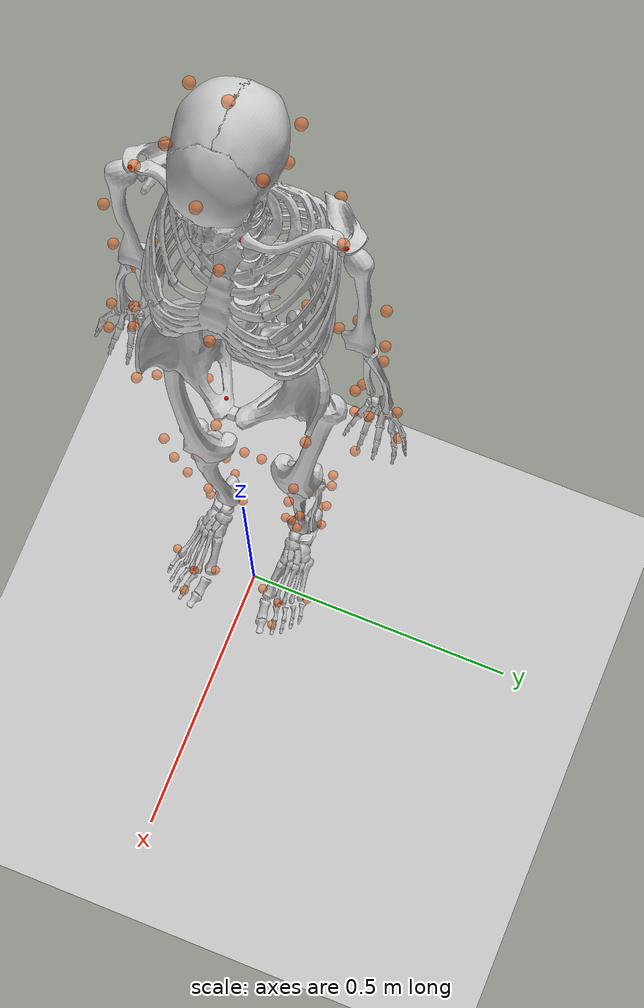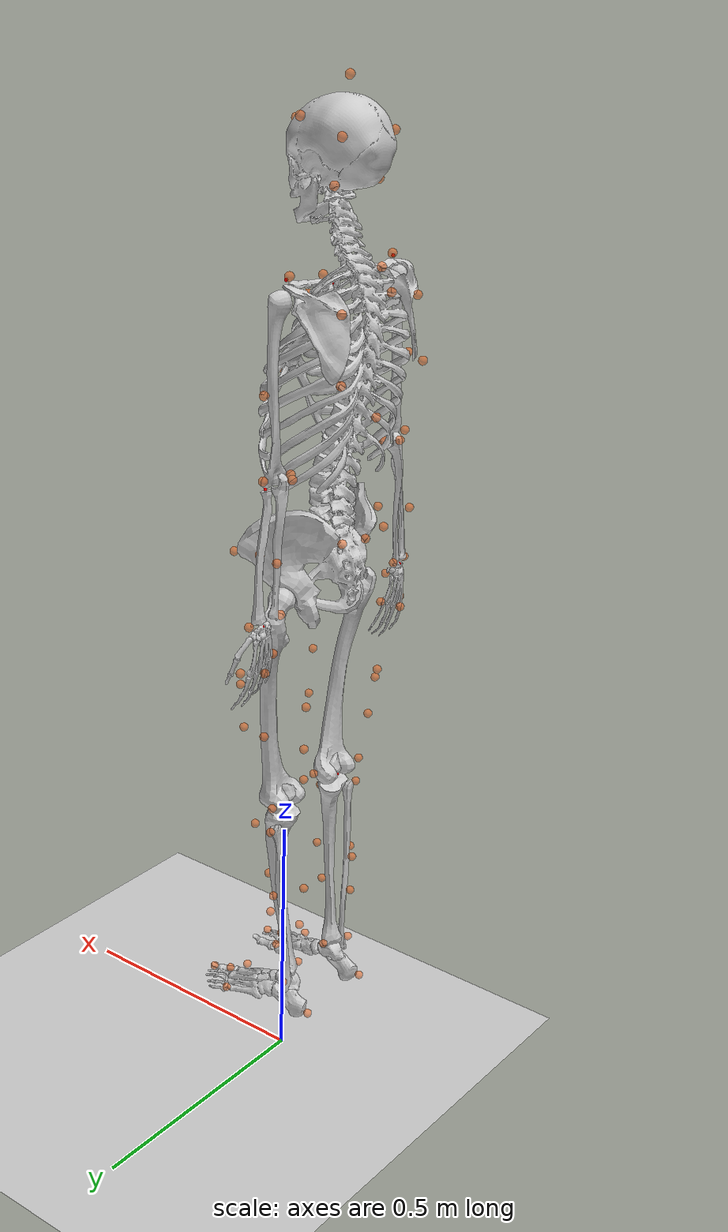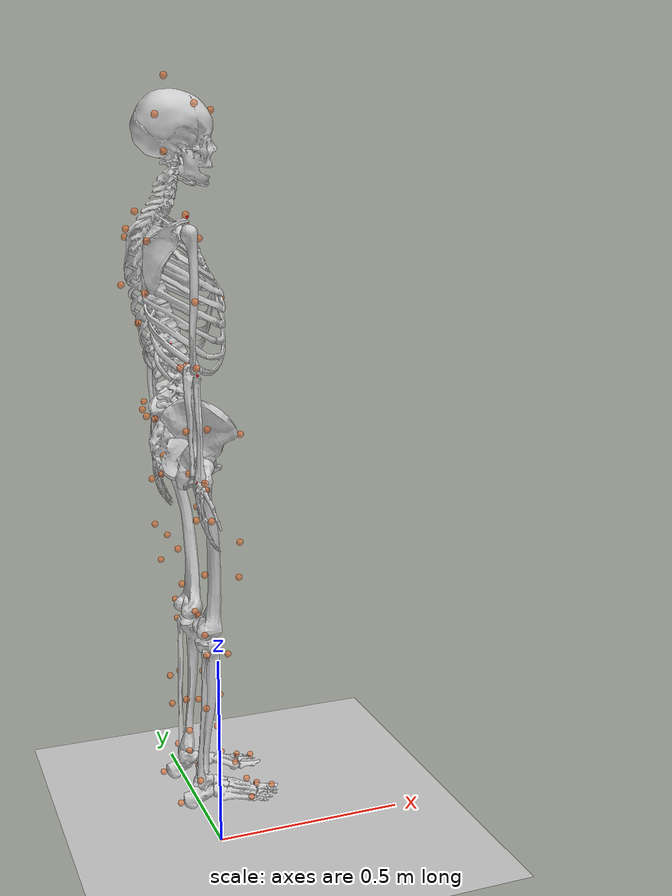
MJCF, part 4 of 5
-0.021105600560589074 0.0068849302451438037 -0.0012223700380570299 -0.019219100456724255 0.0091241896124868421 -0.00079186990323132345 -0.017242999787016263 0.0073014102499312488 -0.00069964987623161157 -0.023277899057178138 0.010047500018992904 0.00036427999449306631 -0.022325800538568138 0.01304030051411453 0.00099239793208771832 -0.023083099902181266 0.0095918895685483934 0.002459000135523914 -0.021701499859376191 0.0071810400667912094 0.0026616100601234423 -0.022489700273184417 0.0097397500621466664 0.0049164500466861707 -0.019051600229034512 0.005356089965937171 0.0060690100451313827 -0.021708600262685059 0.0092634400325207738 0.0084423005261772249 -0.019729999864979027 0.0061421599793559638 0.0085392602612439899 -0.012845599969948381 -0.01919540013962542 0.0081471902686386221 -0.012276800502056814 -0.021808300163572044 0.0087973595794890152 -0.0076337899519631752 -0.017370499666207181 0.0080049194650238086 -0.0073835901843011236 -0.019692700336865761 0.0071662901079158053 -0.013635200284835444 -0.022478900828270029 0.0063900198444316169 -0.015734499467055626 -0.01791959995430811 0.0072768297743302495 -0.0076156598375665113 -0.021953599531658066 0.0058062797902692356 -0.011766299460557402 -0.023068599380173634 0.0081386797011306754 -0.0065713800420108531 -0.018352599812279265 0.0064005303162321375 -0.0053443000280091182 -0.020933099141394625 0.0046073301710272537 -0.014579299975933765 -0.021865099716886518 0.0046289899026703126 -0.014269299871758175 -0.016672100986374502 0.0064897999110380532 -0.014657300169522932 -0.016809599464492644 0.0037846701640216604 -0.014523800608731149 -0.018379900607087853 0.0047305100815657744 -0.0046008403823574176 -0.013738200152847987 0.0040184101233008826 -0.010329199939163035 -0.014809000338495634 0.0034781500687751923 -0.01277150019647166 -0.018238399171410149 0.0033433300067163404 -0.012473300080905633 -0.017006300457822972 0.0038844200218910293 -0.0063786101399412303 -0.022932199757030782 0.0055498298712982471 -0.0054415502747084945 -0.022153200491232369 0.002254629904353891 -0.013151699632316213 -0.017776299296656802 0.002922669851274567 -0.0020911298222074932 -0.020709300539026861 0.0012323898112747836 -0.00892539032515338 -0.013802500619917109 -0.00047914017586458957 -0.0096177198761830934 -0.014048799971168865 -8.010710442421519e-05 -0.0038511200915625201 -0.016894299593947001 -0.00056743013883617233 -0.0056101199226525891 -0.01877590081049826 0.00032102102867405386 -0.0050141601042765762 -0.019901700384931272 0.00021617702806661637 -0.0071186399327129984 -0.020493799690121908 -0.0016351700821407573 -0.0087089203280019661 -0.018141200741744298 -0.0016016801208582061 -0.0071202498774822747 -0.015436899801256423 0.00012925200032377901 -0.0057172996777017362 -0.014389099579032002 -0.00038032396402178082 -0.011758999899562857 -0.019319999979962112 0.0010872599203765319 -0.01283880056940467 -0.020793100850890863 0.0015147699535420635 -0.013643399840838507 -0.018764600188497096 0.00038049805549818228 -0.012491700204297459 -0.017775800049925652 -0.0017848101688098107 -0.010498999660036644 -0.016878299448736502 0.0016546900156882284 -0.009846320405688223 -0.021615400971333406 -0.0010180198688194834 -0.0070095002196588468 -0.018634500048155863 0.00032589391475462687 -0.0032031496606339518 -0.018849600123136408 0.0017287000552854976 -0.0037418600312590913 -0.016204400031022078 0.0036237402098476942 -0.0026218100645394311 -0.01716559943306686 0.00043826407851024751 -0.0069225902305718439 -0.012927099896877233 0.0029341699546855662 -0.007412000088746094 -0.013500499751318142 0.0016834899688750594 -0.002273149894835846 -0.019926700663997095 0.0039689601887129547 -0.0020323499221261971 -0.019888199796225577 0.0047445399617143799 -0.0035810200992234522 -0.021260499885391578 0.0031288398164618222 -0.01280799979622271 -0.016246700551096307 0.0051254797711181152 -0.012435800414100081 -0.015433300048950879 0.0066474001745376581 -0.012562399808820676 -0.015818400230677262 0.0078769297953003702 -0.012310899937013616 -0.016673700972481883 0.0080274697218688917 -0.0099966301696321463 -0.016382299331130858 0.0044101796997363654 -0.013339599420408851 -0.02288549954198121 0.0053076600028228718 -0.015596799754117315 -0.020010199473295989 0.0077562997564280794 -0.014450100194880241 -0.017644399748491132 0.006808199886104328 -0.011074200234317154 -0.02296880066023926 0.0081714997352986523 -0.0089540797526672638 -0.020253300707618684 0.0088056001783323855 -0.0097311398615376171 -0.017322899798996257 0.0057867203080850379 -0.003433709983117649 -0.015382399775305696 0.0071098902934061663 -0.0081190997244382484 -0.014741900472719418 0.0069243201280050608 -0.0063736899921800188 -0.014143800381974405 0.0012358798753018816 -0.010982199628517984 -0.01556750009567617 0.0064904200160141156 -0.0036487902675357278 -0.01647550057053845 0.00519206965821943 -0.0023884998562673228 -0.018747499204698228 0.0075702097355876113 -0.0054974501237385889 -0.016932800438544584 0.0063484601614594276 -0.0041858698351702186 -0.01433390012743371 0.0082766998620057135 -0.0066175298771551355 -0.017297299559617143 0.0080511895252621379 -0.0065118698445834049 -0.015884999289710901 0.0070781798679856716 -0.0046794601499844371 -0.015623100089744737 0.0071729500515686894 -0.0051029502011799002 -0.018165800746661322 0.0064287500478534942 -0.0043501798549736561 -0.019337400725429135 0.0078373701268508855 -0.006575199732502755 -0.019225100073435582 0.0072360298368810399 -0.006317489827919685 -0.020552499228134648 0.0086916396317237004 -0.013882200214862191 -0.018551299332822704 0.0083710495276578655 -0.01467449964868783 -0.020614400510433641 0.0083568003151616704 -0.01270779980945291 -0.020437600127009955 0.0083057796019675289 -0.010947500171593958 -0.020351899701338768 0.0085218297306351842 -0.011428900124885509 -0.018800599529033759 0.0087187998436083197 -0.011956400256688312 -0.017558600704982965 0.008027110147785092 -0.010472799447746926 -0.022194599687120477 0.0085559097945105533 -0.0093821397945941225 -0.018693100660946118 0.0083943100423200089 -0.0076439400280943186 -0.018454799433045007 0.0056610801762210635 -0.013438100131300864 -0.022986099091427788 0.0064950301850028296 -0.014811599754917412 -0.021389599942436107 0.0054899299305554558 -0.01482869947069165 -0.021766299376691552 0.0070143700023659727 -0.015578400199951933 -0.019573399732414228 0.0048798401842480429 -0.010949599557426247 -0.022868599855725643 0.005878100143042379 -0.0087634296907863601 -0.022671099818575288 0.0058022998482148277 -0.0040866499640239686 -0.020329499578873058 0.0039602601842877163 -0.013147399694779068 -0.01735359995682095 0.0049743900283574635 -0.015640599823910636 -0.018185600597135639 0.0042706098097423225 -0.014991599887834047 -0.020507300204916614 0.0026734199314441261 -0.014374899626960588 -0.018980300032421456 0.0029414799474057887 -0.013750899485336584 -0.021531399348312882 0.0035650700291320883 -0.012120099696452776 -0.017865600000316697 0.0029159499554140263 -0.012851599568646451 -0.018227500870179405 0.00453364995437358 -0.0033741699682154893 -0.015653299177286303 0.0022559100771513403 -0.0046480297978441767 -0.014732900017178054 0.0031816399980107981 -0.011468599530225275 -0.015257899737463356 0.0053119599382200058 -0.010317999925723019 -0.015017700299861238 0.0051533501105324583 -0.0084054702781877193 -0.014406699588706964 0.0034896200545205805 -0.0089520895906061142 -0.014413099790050839 0.0023761698994176346 -0.0098242098441376751 -0.014467099620669801 0.0029614099330899498 -0.011924900101916821 -0.017655100688791611 0.0019431301248953032 -0.012230399962385393 -0.0170131009081218 0.001779979973256018 -0.0066539998748320599 -0.021932600096846885 0.0016186699511469417 -0.0041587599315313631 -0.021165400708215123 0.0031704800309291506 -0.0036783200747929614 -0.021828800348350965 0.002540410132157916 -0.0020779701267927826 -0.01847870092033654 -0.00058727006194257681 -0.011126000486676 -0.015907099370610907 -9.394599092209241e-05 -0.0047083103180638455 -0.015825100296445901 0.0010997300115576645 -0.003029039996806481 -0.0174940991790308 -0.00085743001243231121 -0.00426501010681024 -0.017759999315242022 -0.0014665201486994679 -0.0057029596820645781 -0.016705799790071581 -8.8232348335631747e-05 -0.0095362403027108283 -0.020413499350374339 -0.0013466497613241338 -0.0084729100743297075 -0.014095700434865407 0.0025959700186712754 -0.005650510259041174 -0.013239700395155676 0.003395119859019676 -0.01025210039803137 -0.022251399217160624 0.0059065199295586356 -0.0029162597694274424 -0.017569899485337572 0.0048433700621129247 -0.0067001302123614864 -0.013375200523754013 0.006890019880688809 -0.010223600045897062 -0.015322299714565054 0.0084570999732709023 -0.0078514600557315611 -0.016179300799201348 0.0070585100670569872 -0.0059278397805686538 -0.019496800357164081 0.0067706298876727671 -0.0050872601981291057 -0.020083000889652061 0.011141500683571238 -0.015913000291746911 -0.01307209953487001 0.010869399917113122 -0.017866700983422353 -0.012920400208530577 0.01052230013214221 -0.015348400078343035 -0.011047300029132566 0.010212499551889976 -0.01707519973972604 -0.010717700371716819 0.0072584302762219843 -0.020077299407006418 -0.01278300033943713 0.0087027401429380629 -0.019742099422106914 -0.011629099870448382 0.0059281401930063714 -0.017625300429054965 -0.016979100256314935 0.0062754899183993917 -0.015130800298270183 -0.015433999711106119 0.0057573402531041059 -0.019283499706895132 -0.015176200428675204 0.0050193699820997298 -0.013216000017616688 -0.013931199946431046 0.0040092598780817187 -0.0099043400344891435 -0.011853500255644103 0.0052077098098783489 -0.012024099939839102 -0.01171960036319469 0.005311620004132502 -0.011133000207574682 -0.007980640009276339 0.0062688301153166603 -0.013105600105941303 -0.012259400477056061 0.0043158499047804963 -0.014048700206062078 -0.0157609004687525 0.0040894500169134504 -0.013117399998403553 -0.015296700315090752 0.003530360049060168 -0.018419200577287961 -0.01694089916697011 0.0045595500551351966 -0.017751800057074215 -0.017712999242942253 0.002906480098140984 -0.019951099588416784 -0.0075336299129520595 0.0024397599407854072 -0.018553499135793513 -0.016685299524993587 0.0042895601741144975 -0.0073856198045008075 -0.0093223796679541265 0.0019777998429037209 -0.01903180032630147 -0.017103599344246097 0.002320800072545245 -0.010878300220974689 -0.0060900398313332698 0.0016760498535043629 -0.0085371098537165829 -0.0067173600144537753 0.0030785997516042237 -0.0055366296600600764 -0.0082659793253353746 -0.00017540203654338446 -0.020575599856980983 -0.007935870349938921 0.00027991295023636892 -0.014377400249885538 -0.018956899767668397 0.00081472904676244107 -0.012974499768992006 -0.0058365701025808727 0.00059540598403155776 -0.010706799910430219 -0.0061889397296547837 0.00026743996007193288 -0.017304400001984185 -0.0055947697651591013 -0.0011092900878949955 -0.020725900387966841 -0.009973440171413021 -0.001578290068389054 -0.011432499507324499 -0.016381601040565016 -0.0035753498714988638 -0.0098503905154616583 -0.0073417101557114433 -0.0032440099463328228 -0.013864100146021571 -0.006200220095836621 -0.0034465598067872491 -0.016188699802691661 -0.0072855697539404556 -0.0031694700232565284 -0.01589890020333384 -0.0094274403557941238 -0.0033097001272880391 -0.012587600462354628 -0.012053900549415349 -0.0028438902186758981 -0.010032700251194624 -0.012432799861902596 -0.00085731008686716604 -0.0075523097378848974 -0.010496499836313287 0.0014703800076422547 -0.0065602300418019493 -0.010856999851140801 0.0022304900950172453 -0.0092375397649580009 -0.012825600015216206 -0.0012375400659726669 -0.0068351299568141215 -0.0079600996779262394 -0.0031498600524535727 -0.012756800274689614 -0.014478299833949101 -0.0028043201801739854 -0.015745000955771579 -0.014275499680083178 -0.0027045499314115868 -0.018535299272868674 -0.014030600018765934 -0.00295722989929209 -0.018768999642519987 -0.011150400192817543 -0.003668990017067191 -0.011789799738221692 -0.0060152701540731861 -0.002084879776225942 -0.010141200633388745 -0.0059768001119933616 -0.0024250499312591374 -0.021060999545477351 -0.013378200039260015 -0.001581970094076179 -0.01626810058387473 -0.0053132401475123594 -0.00021716191711415583 -0.010483499750118639 -0.0064973199122007868 0.001400919929917435 -0.015680499277545664 -0.00537509981570125 0.0038412801015012118 -0.018330101006967744 -0.0057129700213937864 0.0048289602535376832 -0.019042599808229862 -0.008290999582478557 0.0069676696332186382 -0.016845699480344974 -0.010495799619967354 0.0051961601991852143 -0.015904199335279531 -0.0069708698527994311 -0.0018089397863809693 -0.017633300275663674 -0.016852300596397359 -0.0019823999957519624 -0.019262699378025602 -0.0055694798734940145 -0.0031510298396847233 -0.01864640041181009 -0.0068011799512338027 -0.00097138998238152619 -0.020874200302355202 -0.012365100048859653 0.00085359209280126669 -0.020406600103838986 -0.014096000205755296 0.0022807200742287616 -0.019986700276708787 -0.013268499611248898 0.00054536892773129886 -0.020410899183330052 -0.01109439967273093 -0.00039693905217824666 -0.01823100071233907 -0.0052254698578197692 0.0015967800356300878 -0.017255000706072773 -0.019408499565429334 0.0033329200137849754 -0.0067150900413956976 -0.010378999782775287 0.0041908600138242926 -0.0076950100392498815 -0.007495460251218276 0.0033106300850104789 -0.019861500528046024 -0.0098378100573883725 0.0034513899267461503 -0.017034299571432317 -0.01877879902730006 0.0070313497141326186 -0.014422900099408272 -0.010924199644727127 0.0034118199271909585 -0.013807100321207241 -0.016824699787416377 0.0028261901008427288 -0.011964900487148263 -0.0146014996962773 0.0036354600316402521 -0.013024899984814372 -0.015644999271842815 -0.00014501398269814445 -0.018663400742235155 -0.019251000037216633 -0.0023183599501658682 -0.014146099742016412 -0.005508929779712817 -0.00033470498844666291 -0.015870099774979659 -0.0057137600940088398 0.0054620401235657692 -0.011564600377809596 -0.0097491602561945705 0.0054267798390554836 -0.015975300217807794 -0.0084851002515050882 0.0054174699376878374 -0.01740149968781601 -0.008447349865947083 0.0061084696309956065 -0.016352400263540453 -0.0095566902515153967 0.0060601199892863205 -0.01419300032618653 -0.010012599691928968 0.0060156400956995742 -0.012723499962933756 -0.010622099999895744 0.0066167400282255272 -0.019098499743961269 -0.010575300051774898 0.0094391199189520058 -0.01491320053217304 -0.014402099886282767 0.0093362899476924759 -0.013173099656078376 -0.012722199808827741 0.0092423995063206071 -0.017914600864671001 -0.01384340057478636 0.011932100160745262 -0.014691700232291712 -0.011354500439417712 0.011323899825041768 -0.018817700589277894 -0.010699600097201471 0.0088548901060993123 -0.014807299712838114 -0.01155680046004509 0.0086453500997774584 -0.017193900297760797 -0.011033699736114204 0.0056066098861254762 -0.020459299797424776 -0.01200740018939175 0.0072359800900341203 -0.018533900287588053 -0.014872900114076573 0.0043991598988780125 -0.018795499520026012 -0.015485299691094658 0.0040684501254851643 -0.019651999697142371 -0.012842300497213823 0.0047291800138792575 -0.0092032597326321391 -0.0096842300385840945 0.0047146998536379678 -0.015350299874931524 -0.017124500013046769 0.0044926104678793951 -0.010796699678980779 -0.0065410900928695986 0.0037379100429490155 -0.013592000222040431 -0.0058638099529247905 0.0034784499506561308 -0.014747599961211218 -0.018578799365170453 0.0028231400523933687 -0.019168000744943511 -0.01575510020794654 0.0029391901215217167 -0.018377700891532008 -0.017656400976002847 0.0043161599120350022 -0.020124699828258038 -0.0089430799600053717 0.0016083900222229048 -0.020002899763910894 -0.00748746001859729 0.001982559865351854 -0.019892100307176804 -0.010427899456850629 0.0033448299416897051 -0.019972199662987352 -0.0063090597919989704 0.0011863600252499937 -0.01949529898542934 -0.0055407599058753801 0.0019192399453749893 -0.018839700272296974 -0.01829620085678085 0.0015639599814979833 -0.019777498999960171 -0.016369400429436461 0.0006979499474825539 -0.020252399156195363 -0.018124200367704593 0.0011223499452312766 -0.005709699895183106 -0.0081564506062951885 -0.00082726006088601456 -0.01285149994777934 -0.018116600856221823 5.0804057377964993e-05 -0.012016800192681917 -0.016926800886352924 -0.0020558100769188649 -0.015207099761876283 -0.016824800551671095 -0.0020853201182550736 -0.013047399938093115 -0.016540499472368544 -0.00068410007143218643 -0.016623500942389843 -0.019164899342796856 -0.00098449991907641177 -0.014140300529423163 -0.0059262003563152182 -0.00088898004805590381 -0.011790799820941441 -0.006312820046663668 -0.0015766600382696168 -0.012970300404002485 -0.0064945997656027359 -0.00044144987643793254 -0.0087395005437274059 -0.0066039401206646735 0.0015783500062479523 -0.017648700539279135 -0.0052059899721120509 -0.0022408301479706762 -0.020905500428509912 -0.010301900137771157 -0.0021726600315565138 -0.010715800213893621 -0.014666899971930016 0.00026630999855904719 -0.011015799721753481 -0.014708199738198365 -0.0026591499984082857 -0.012141900059859486 -0.0058277196017841862 -0.0033832700799080314 -0.0094789500465697323 -0.0099789797883972336 -0.0032796299753762017 -0.012709800266135215 -0.0096509699654063457 -0.0028331998644168794 -0.016411900300242529 -0.0057454700967332064 -0.0034618999931825536 -0.013188500074586381 -0.0075786500677364737 -0.0030663301233786041 -0.018952999241054643 -0.0086295000299870233 -0.0028779798581222006 -0.015792600757028371 -0.011767500050413628 -0.00030394696872761135 -0.0092626902076349254 -0.012780400094225926 0.0041175498648734063 -0.012311100043838504 -0.013773900445668171 -0.001539210117937936 -0.020136000689499053 -0.016560800449894549 -0.001962719858923045 -0.020943699362946374 -0.0077697499647891837 -0.00047730003844811953 -0.021334199306071385 -0.015571300024789677 0.0036279799447081337 -0.015953399228756378 -0.0055398697060674009 0.0051152101346991904 -0.017269199837627532 -0.0069690796547623151 0.0060410300142832562 -0.017694400689447939 -0.0095235798068868099 0.0052450998145904251 -0.013544299620800389 -0.0074281302468358606 -0.00041604003889128538 -0.019981499761075546 -0.0061454600821835553 0.0017935299421871355 -0.013269499766672906 -0.017101699482473445 0.0050050603970477189 -0.0092002796469627928 -0.0083439703701616835 0.0055497496443671209 -0.013760499701310987 -0.0088440702305004597 0.014107899604741497 -0.081811502938666222 0.02058869977743771 0.012853999505892496 -0.086235902230943004 0.023317400243568039 0.012369300295692869 -0.076018198786168542 0.018262399335851495 0.013963700285842689 -0.078847401331594055 0.02593559985541135 0.010067599720660179 -0.085063397199135346 0.015076699767451043 0.0088203501745134898 -0.084871395966967675 0.015098400519886947 0.0087923201927384686 -0.077056199512915521 0.024806101123089418 0.0082463100768430508 -0.080671698637267517 0.025755100233385612 0.010420800190459363 -0.0242068992363541 0.0061967403297076822 0.010391400090713264 -0.026206199805987922 0.0056793099213597311 0.010293999526011883 -0.028609100026253158 0.0077124297213874687 0.008194290133396993 -0.027912600422562488 0.0048128701057255632 0.0068822498123644309 -0.031870998277111588 0.0066956398947094192 0.0042449198755455794 -0.025510900065984547 0.018613100195754486 0.0027803399550139908 -0.023100401936165801 0.0079262500760829396 0.0026970199682390113 -0.025249300600344131 0.0054525203075326814 0.0030639000485041942 -0.022168401044425742 0.014996999994693335 0.0016050301697783649 -0.027473301317941116 0.015631400212035764 0.0016947898390247819 -0.02506229966783912 0.012415000186212301 0.00045290506272056819 -0.026721100245407629 0.0095373505572939315 0.0016150300808971531 -0.031114600321368251 0.011148300000228843 0.002064560151900124 -0.034318902132514421 0.0121231005479738 0.0035628400011852709 -0.038084399116287686 0.010271799897033499 0.005753519975286738 -0.041905000674413821 0.010192399867102379 0.0074582398015506906 -0.045030601143216324 0.012462199629970635 0.0076639699031427044 -0.047899801093744795 0.015761500219494764 0.0063975700039707577 -0.050590299005627823 0.018576700232544621 0.0046694599586240828 -0.053569499393733441 0.020318400193765043 0.0028301898391001746 -0.057098399863137347 0.0194784996430051 0.002544090030516213 -0.060923099637809605 0.016849400521501797 0.0032455901167791892 -0.064511202046406133 0.014147900123422926 0.0058959401892860041 -0.067612796632644509 0.013892499613686573 0.0090059302734405832 -0.070221200832237582 0.014909699698667508 0.0096501903416953815 -0.073346197837518487 0.015016500160755061 0.010397500364353827 -0.076525002485214419 0.014700599685530776 0.011032000184669112 -0.080011196677723148 0.014112000470516303 0.0080514996561711193 -0.0802668996047151 0.013751200241792823 0.0055859300180040308 -0.080721199967990973 0.014976300417037011 0.0066066299142206169 -0.084322496969022817 0.019182700642550451 0.0082863996775951448 -0.087784601481040822 0.0186317002263196 0.011520500426199063 -0.088034899768334104 0.017596000972307315 0.0057372801062210285 -0.080878802183279461 0.019368799502396585 0.0049950698553050529 -0.077736898620927017 0.019398700310073094 0.0048672501596995757 -0.074053198867402123 0.022971300774294847 0.0067254100596378773 -0.069980502414048726 0.02320530064021389 0.0089515401082611284 -0.069693103009409327 0.020864799455682922 0.0082208700053511118 -0.066665596869003516 0.020460499493206132 0.0088569000582057449 -0.063573897300357216 0.017342500448913164 0.0075029200120284422 -0.060824599045466984 0.014270899819820212 0.0051171398769420387 -0.057734001499214579 0.013217100086184399 0.0030063400876881715 -0.054276701081745191 0.013440799914792047 0.0018481600631104623 -0.05067329861727364 0.015402000422191833 0.0023467898724565252 -0.047047000183803797 0.017532799254460548 0.0041253599818981126 -0.0437355000431685 0.018602199600313226 0.0063146399445165435 -0.040992401410698036 0.017459899059842212 0.0083261402261124978 -0.038440297958034601 0.015231800216780358 0.0081894499048704283 -0.03554329959191193 0.011012299718732075 0.0090602094296402379 -0.032255098576157708 0.015595600032209746 0.0088327098441148954 -0.028551799410093108 0.015999900085712861 0.0079636203058059945 -0.02480250120774307 0.015595999485775305 0.007394679920959572 -0.023863199894639579 0.011307599944164718 0.0066893701807588229 -0.031344000819235933 0.017594600324281281 0.0041701598035862588 -0.034155302118245572 0.017642500049589779 0.0041084001109960291 -0.03729369906096535 0.017743799943401219 0.0021585899870030646 -0.040360901924991748 0.016400400602149558 0.0019555801283075848 -0.043953899698929592 0.014323700267824393 0.0033026400279047288 -0.047709598984921761 0.012772899977743581 0.0052582198008673383 -0.05130099873835535 0.012522400443911088 0.0072644502065955085 -0.054608199762488971 0.013783600109440183 0.0080492403067628764 -0.057401001378926994 0.016909399982547781 0.0072372699953745633 -0.06029799966248249 0.019901899744160342 0.0056528300090509234 -0.063453100984110375 0.022034000828434288 0.0038995199751497697 -0.067210197457975393 0.021376099423821456 0.0037497900293021877 -0.071158199805375952 0.018430000083706374 0.0045309298438488818 -0.074496901737633334 0.014892100124296589 0.0021952500721788694 -0.023655600918635826 0.012722699978289755 0.00094501994634608988 -0.026008699388560423 0.011080799686278812 0.0047425399540889637 -0.022468699654654364 0.004786820123778456 0.010002199534202031 -0.025168699417646205 0.0089865195167235217 0.0077159698681614607 -0.084600099190942343 0.023024799509247709 0.0097053198833577086 -0.082898899108917998 0.025314299390781246 0.012901799661179835 -0.084372698903482077 0.014288200083064386 0.014182100310505857 -0.084704899833207711 0.020588200873062925 0.013851700229628446 -0.084920800382932246 0.017223199599802255 0.014459599526183264 -0.08014380128732311 0.023046499009566786 0.013868899811716597 -0.083372502832073633 0.023774899393258435 0.013668399998294636 -0.080970398808980257 0.018417600420760707 0.013477399840976994 -0.077961496387989312 0.021059699238580584 0.012369300396851825 -0.087661603302545674 0.020816101024413915 0.013052999954881597 -0.081949002886802833 0.026919800840678403 0.011428100021158958 -0.085761196260358372 0.025424800787107342 0.0096299602196905209 -0.087503798807975638 0.02222160073333165 0.01125350040969837 -0.07259970221974453 0.017927199661456669 0.0099887196297778463 -0.072470299817148795 0.021605199207538697 0.011234000289056923 -0.074810698273179752 0.022764800048555935 0.012696599320208692 -0.076555199274790695 0.024646200326347033 0.011034600351362374 -0.079480498667374042 0.025828400371637437 0.008472939976313763 -0.083107397028563276 0.014464500517385206 0.010789800494776331 -0.083228298044447188 0.014567700156874749 0.010626800284634764 -0.08695559901302595 0.014982800126566494 0.0080042694880136777 -0.086584902781707482 0.015438100170407417 0.0063227898377114771 -0.084023698376739939 0.015271300417396712 0.0063196603146191532 -0.08133160356558343 0.023667199663551318 0.0056712901143158431 -0.077673197149742176 0.02359230094519079 0.0080661196132923562 -0.02557940088333898 0.0040991505035961042 0.0081032093280732891 -0.022873198827879079 0.0048595398160158612 0.0078335005783330258 -0.023535000916789832 0.008176890263960233 0.010442100556898216 -0.029085200096352064 0.012516899954652407 0.0090842599363715176 -0.032505899077985505 0.011057100172421229 0.0056632398338194575 -0.02801759902471767 0.0058182799660352882 0.0049881398654434963 -0.025277599725548987 0.0042462500084191326 0.0032157098129483854 -0.031637199042694901 0.0077095501305094721 0.0027039801114086544 -0.028034500242066877 0.0065032898553142576 0.0061604902378646752 -0.03541880094463911 0.0078899094869723501 0.0036053798707270926 -0.034800101585826575 0.0092552305801704409 0.004110559777089697 -0.028051198734350018 0.01885640049811196 0.0068664998176626007 -0.02794780104293481 0.018758099437793687 0.0029095799552541764 -0.024660599692238876 0.016945399233814103 0.0061344400710880136 -0.02441140017792353 0.018388900600407012 0.0044841797515894751 -0.022374599059089447 0.016530400127062885 0.0020406700873132201 -0.023720700022458178 0.01033530009104097 0.0047827600413019441 -0.023703399925580231 0.010553199778249698 0.0050530800792439592 -0.023135499256280442 0.0077670597928662082 0.0015852901093975354 -0.02314509990210389 0.0059424100860835365 0.0019364800021114121 -0.023768100735985669 0.014867000233832469 0.0062103298771388048 -0.022598598872268224 0.014004199618609822 0.0039708698327501615 -0.022885499862238864 0.01303550056405944 0.0019618000510036589 -0.030965500424821928 0.015575599892670263 0.0041906400649783368 -0.031088700678634 0.018032299412571503 0.00097857113759521031 -0.025442399400300901 0.013412900294073434 0.0015766800705850344 -0.025287900913936949 0.011099499812477235 0.0020689299512206267 -0.034007098051273214 0.01568390044931486 0.0021695898509993951 -0.037448901442072906 0.012949699490726631 0.0021285798844677402 -0.037119299666609644 0.01593259911333347 0.0035237899760091054 -0.041299000089466735 0.011281199660983425 0.0020657898377383489 -0.040670700038905154 0.013668700082705012 0.0059336600461832711 -0.038743599990249337 0.0090705902890692285 0.0077658699933362534 -0.038660100865890328 0.01154590022508528 0.0055656600248675378 -0.044999200515823616 0.01115159974437757 0.0034555299061242708 -0.044486500248546605 0.012154400314121207 0.0075476597457322502 -0.041827298319828336 0.012046899620965914 0.0080666802483055477 -0.041578900140257107 0.01537869961466878 0.0074208001524143901 -0.048246301654123344 0.012872800309203566 0.005406830000493453 -0.048131201546240718 0.011958500413711656 0.0077977799716593115 -0.04473559913304314 0.015522899950651561 0.0061896699221785628 -0.044200498799003778 0.017649300533472131 0.0076449499449184593 -0.051066499291334874 0.016113800937848196 0.0073398598454237751 -0.051459699848180759 0.01331320032875449 0.0062191700786838732 -0.04739670103593728 0.018052799687454293 0.0042548998834535936 -0.047011498335224208 0.019185999395876948 0.0065978900427907227 -0.053817801159480191 0.019064599718252081 0.0078104198845622818 -0.054232198750060454 0.016558799864426817 0.0044436301032630124 -0.050285998735485213 0.019756799383371045 0.0024862200524986135 -0.050393801300588778 0.018150199185475304 0.0049198800245273669 -0.056864500002756099 0.020848799592531105 0.006848600223333166 -0.05707269908825828 0.019469000402237587 0.0026406698634947735 -0.053738601523135129 0.018811600245214773 0.0019570802589887466 -0.054087899608071463 0.015918200853061917 0.0031395697627634575 -0.060473401296066473 0.020080900032950152 0.0052449897921922469 -0.060162000493222942 0.021424601077452751 0.0022174001046487003 -0.057511400303764657 0.016393899930077973 0.0029501698627187592 -0.057640798479265939 0.013642299922361597 0.0029139898601506088 -0.064331598830368306 0.017352199167926682 0.0035015999922542581 -0.063837602561223047 0.020699899537180984 0.003006950246072961 -0.061075199233033714 0.013827700111433801 0.0052446400826632175 -0.061032600808108003 0.013404100132488574 0.0035853598271125406 -0.067907698881452525 0.014404100345395601 0.0032962398714231752 -0.067754499428153467 0.017868099664789746 0.0055234502352860945 -0.064345203005140114 0.013637900225299922 0.0078962603253972651 -0.063956401897530366 0.014458499813191913 0.0063495598300253291 -0.070861301812076047 0.013938999511321961 0.0040546702155870992 -0.071260802683054444 0.014648400173630612 0.0084038600776417099 -0.067093201402752975 0.014693100024648794 0.0094854700674761854 -0.066614701915909333 0.017457999238184609 0.0068963301625172401 -0.07404159816513832 0.013922300195554762 0.01032209964011961 -0.069603697028756448 0.017603600478109851 0.0075151198238976157 -0.077159501362044067 0.013924299797898245 0.013594299623680566 -0.079930602631942613 0.015272699888762311 0.0050272801936835218 -0.077609703070881539 0.015047100346240596 0.0042853998562128173 -0.074500098599161388 0.018992099876031395 0.0043492401484114115 -0.070603996917282572 0.02215640084297665 0.0075794899947088917 -0.073240398609171073 0.023919200541833434 0.0061267101589571309 -0.066742099433866539 0.022593099777781647 0.0076742298079245774 -0.063507400458137728 0.020200500234529069 0.0083279898551013015 -0.060513299112052929 0.017160799383067356 0.0072709000485933883 -0.05770799885089882 0.014144400135760234 0.0051465798403868687 -0.054490998377033292 0.013006299723663347 0.0031259700030984291 -0.050969399606375684 0.013141199918647397 0.0018432499413915527 -0.047286000058773356 0.014870899744495011 0.0022409299381774684 -0.043693099205552414 0.01694889929344295 0.0040857802056419442 -0.040497102018291369 0.01804029922443345 0.0064564900969807919 -0.037793200110262652 0.017348300747347358 0.0086688101234698427 -0.035377000280339514 0.015197900281287893 0.0065569598584241644 -0.034588799012718933 0.01724399993711356 0.0095849802226178737 -0.025280398319222568 0.012575399954951518 0.012664600146402718 -0.075463898301775675 0.0046190098556562189 0.011620399699644303 -0.072590299400572697 0.0023893800042082409 0.010640599811553532 -0.075847200792120803 0.0081111097564319206 0.0094366800055135629 -0.082115702462388404 0.00614821990040673 0.0092124100286401344 -0.082431301280871269 -0.0037703999665649737 0.0083609801615573808 -0.081687197658569119 0.0056865602847220023 0.0069853299671350354 -0.078428297849160597 -0.0032862499828888161 0.0080304900723831684 -0.073958203542262554 0.00762190977551566 0.0064558700839194277 -0.023084801491581871 0.0007348700054200239 0.0034575699954176855 -0.022627699920128027 -0.00028390701620659148 0.00029854809102748675 -0.028250700542641997 -0.0036429901510369169 -0.00049734010704972898 -0.02454189880980661 0.00765528980267338 0.0010942198505921039 -0.02703599939524514 0.006730449686651872 -0.00044199991936129379 -0.022457900022430529 0.0023584700916724206 0.001189370061773942 -0.022516600491930269 0.003044009861288082 -0.00020933989245387746 -0.022949601287356122 0.0064395297582762728 -0.00094793981327223587 -0.022084000817622181 0.0031784200793961428 -0.0020745500379575339 -0.025842699537956475 -0.0048035902091293761 0.0017170699096408361 -0.025016098349088904 -0.0041212400780869509 -0.0024828998851705582 -0.025087499817700414 -0.00098515301074039697 -0.0022494096532718467 -0.020647002131735533 0.0048142001539568094 -0.0026365999483579784 -0.024094799758208489 0.0046607600389958195 -0.0023267499530221776 -0.027450800764216902 0.0021288099304249404 -0.00134469002304316 -0.030803099575597785 0.0068198801130553693 0.001338409902596954 -0.034161001037925957 0.0069230798531412768 0.0029064300871578792 -0.037486899764736507 0.004687140234129721 0.0043022400350906367 -0.040775299311054274 0.0025831500313164275 0.0045797400310548233 -0.043900601142480726 0.00013219397087349535 0.0034653499904676024 -0.047191999655318048 -0.0011805299596259475 0.0019580600954843398 -0.050557199897944369 -0.001446199870407394 0.00045736985593473878 -0.054053299153319564 -0.0012320200425966208 0.00046524106980612423 -0.057819399907563115 0.00077181500047898677 0.0013619099487113399 -0.061147000426117523 0.0038399999547306654 0.0027168599837693592 -0.064221501331139116 0.0067584700866301899 0.0053944001565669605 -0.06704600189909081 0.0068977697912265806 0.0073900200296102263 -0.066218898050513272 0.0053226599456323567 0.0087916898792462488 -0.065618701610457228 0.0026688401143786229 0.0084798502480243048 -0.065590299404074001 -0.00046488594637697489 0.0074921101542305257 -0.069340497413818744 -0.0026535202785600283 0.0060403101064023922 -0.073241599639910712 -0.0038419001459997206 0.0038690397566431686 -0.073705098763295993 -0.0031760100856912379 0.0041145299340787497 -0.077100201691109191 -0.00054591399032749555 0.0055960900865352206 -0.080440200999354325 0.0024228599044842643 0.0068062501492501242 -0.083735398868634778 -0.0011430400583040676 0.010399299865816307 -0.084443503199487666 0.002039360126853212 0.012339399973743292 -0.081256202593509505 -0.0014723001369821571 0.011801199864330324 -0.075922801964806816 -0.004002269686387199 0.012659999328715098 -0.081855400654808549 0.0025418100126954608 0.0048130300276593698 -0.077173903702671728 0.0029756200598918528 0.0040517301903869032 -0.074270502623112508 0.0036683199207269415 0.0034044001430261336 -0.071176700827604619 0.0040603500122047267 0.0023599998820058444 -0.067815699171457675 0.00081329896983992045 0.0018486098707302802 -0.064299598544799261 -0.0021709998048212438 0.0029788101604234498 -0.060434799584596507 -0.0023849400772270042 0.0045471699156053444 -0.056880299042708179 -0.0014566499309246193 0.0057324101181393519 -0.053470700980567928 -5.4759393552539213e-05 0.005324869894181127 -0.050328899210710695 0.0024020399646240693 0.0037273699360930576 -0.047302700544203033 0.0043111601110907552 0.0020272100809589767 -0.04424539946429961 0.0059263400789923686 0.00015507608202765252 -0.040906500388339088 0.0057879101823560255 -0.0012552201209700268 -0.03728720098482096 0.0037568600706388003 -0.0019419198433759245 -0.034166701923246771 0.00015033195617528136 -0.0013860599500228608 -0.034656401581906297 -0.0026943401176087174 0.00062200693244190963 -0.034331701080935854 -0.0030916999364578581 0.0028273201601997223 -0.034320001452719288 -0.0023447301705282748 0.0051045800559049023 -0.031849600838928398 -0.00099031095762602806 0.00549445038245333 -0.028913301025898945 -0.001856719940301232 0.006363700075664681 -0.028996600766549856 0.0021725098956190676 0.0040401501069897974 -0.027949300469406461 0.0043762801656256891 0.0054686801143807992 -0.03189279805373068 0.0027223499568876093 0.0047501600118804712 -0.03481009893955777 -0.00051356105767511029 0.0028365301804469246 -0.037572201893442896 -0.0018052300669474937 0.0011216599811571385 -0.040868401133678282 -0.0017717899436230917 -0.00036113385642198842 -0.04410320183938931 -0.00068560895410579848 -0.0010709699981944346 -0.04755669851655063 0.0011580099821677512 -0.00042549987528002476 -0.051025900926862863 0.0035973001075180191 0.0011747501110906387 -0.054137099522444929 0.005684630136360668 0.0034463598908878309 -0.057146199145507989 0.0061006600103343505 0.005754129928332837 -0.060030501147118595 0.0048850501057514087 0.0070825898639894618 -0.059640601418113989 0.0025955298925975918 0.0051581300685325923 -0.05686999850535511 0.0046935300741690047 0.0030198500028346667 -0.053897898649076667 0.0058605300268580723 0.00085635102083608783 -0.05083649977028902 0.0054672002468020555 -0.00074156980967907105 -0.047596700683655388 0.0036163701039733645 -0.0014214599260707059 -0.044106401450723413 0.0012413399601269857 -0.00060755011173736762 -0.040855001436661091 -0.00091790199828306585 0.0068671801621719829 -0.059644799741601959 -0.00021842804715876957 0.0035922098818976086 -0.06369879863832649 -0.0028072399184128067 0.0026022702194043869 -0.067536600254886822 -0.0023235099161380275 -0.0025115100562554389 -0.030782200204724545 -0.00094524402999854296 -0.0018509298701165073 -0.023568601278649785 -0.00225637983401844 0.0054237799213726892 -0.077753095945129122 0.0065457003249207984 0.0080641500121610681 -0.079856299746924195 0.0060331301939259268 0.012051500487004246 -0.082138903430150609 0.0061755300709015176 0.012373699512861113 -0.075157395745427333 0.0074034701744608283 0.012777999932024008 -0.078808203400103735 0.0070952898370700828 0.01309440023231238 -0.078284800100821381 0.0035957801496278299 0.012906500401762205 -0.076898500875134376 -0.00013420591432522497 0.010438900514481609 -0.072112702451832864 0.0063635702578454783 0.0099267598177587412 -0.068670899537800131 0.002548400097483305 0.0086199698224889414 -0.069190703495943459 0.0055908797553174952 0.010722099803616837 -0.071916296293815893 -0.0019181000102959918 0.0095328696601416473 -0.068594902463714455 -0.00088681403702137152 0.010498999450454181 -0.078247702732332045 0.0077747302969390624 0.0079241497430203849 -0.077422700809394271 0.0070654496233231705 0.010051899611097604 -0.083818100374084645 0.0052798599501169543 0.0076386396682915757 -0.083250097481473925 0.0050664799352973236 0.010014499531762878 -0.080618798338952011 0.006748030005206988 0.0073734199485526713 -0.081406301884033513 -0.0027349098511370569 0.0086278402912969548 -0.079052001199222052 -0.0032931999248849422 0.0062545597949572023 -0.080561898287841091 0.0054448097439718781 0.0066799498634773202 -0.076289899892537524 -0.0040547200432690658 0.0091452598004874135 -0.075961902078430552 -0.0039248001959150949 0.0056628999145712363 -0.07965400053977699 -0.0027703599369470751 0.0043517701982225812 -0.077042900756602237 -0.0038916098857331707 0.0050514898577797554 -0.074420399499175102 0.0070804400589214982 0.006443030200577125 -0.070313900762775425 0.0071796701466946538 0.0043032299633353191 -0.071106903201691871 0.0071702502694940256 0.0042210102046867362 -0.022746199804834829 0.00197259011855011 0.0044524600619956908 -0.0251386003064955 0.003697220065962791 0.0049654904602522689 -0.02254570133106781 -0.0024676999988696431 0.0072228800236263917 -0.025675900035936221 0.0017301300402937643 0.005529609851804492 -0.025466600251998976 -0.0028106198340248907 0.0011709499367898305 -0.023034499100864966 -0.00293337982130104 0.0003802989735220973 -0.030982000678053116 -0.0039578200362484486 -0.0022363700858664399 -0.030932400263285913 -0.0044491301683652054 0.0024695400372225364 -0.028095699368563147 -0.0025674000351994237 0.0027672398750739065 -0.031111099975652416 -0.0025680598991617005 -0.0023340699159003632 -0.022057500270097005 0.0061779503052430945 0.0016539700241450374 -0.024503700825734602 0.0054024001499630705 -0.0014576900764555337 -0.022893400605120347 0.00071373098006571867 -0.0021978600328594468 -0.021977700325337298 0.0030451199953243626 0.00097281695607515073 -0.022900498674246147 0.00021068001161253508 -0.00043861985983646701 -0.021454100459391997 0.0044511197849366182 -0.0027862001646138386 -0.027033199700584591 -0.0013816599524786308 -0.0021972099984668698 -0.024881299653973669 0.0012709000124478118 -0.001774049980063835 -0.030665599945383086 0.0029350500377289526 -0.0014518900096614077 -0.03392630124857287 0.0034878201207871598 0.0012862700796310576 -0.030740800017362228 0.0072034700994261496 -0.00064286980341664291 -0.034175601712730035 0.0065902402127461773 -0.00014941601558141057 -0.037531100433975333 0.0061529301603988878 0.0030334100238621617 -0.034205100905624557 0.0048682201694063834 0.003661590025744745 -0.031068500090189903 0.0052473000189403587 0.001577709944783109 -0.037612698340216959 0.006656620379776294 0.0017744200308285048 -0.040951799729859621 0.0061945900309590112 0.0043946301225146331 -0.037688602456354296 0.0027045801042741564 0.0047817702355299465 -0.034738001324688288 0.0027989700916760947 0.0030702498353983579 -0.040796298100607135 0.0045453399520142537 0.0033581399574292283 -0.044066399777089586 0.0043939999330852011 0.0043601501491511421 -0.040766500231108831 0.00010708100112322147 0.0043568001159093031 -0.037713800083740028 -7.5703395665871462e-05 0.0045032700739914408 -0.043941199623006459 0.002477450082945309 0.0048491000865002317 -0.047137200912568886 0.0024032099006315861 0.0031759100674652171 -0.043989099393789914 -0.0012514698474870298 0.002926559835337419 -0.040794301434958651 -0.0013923499999368703 0.0048875198165492092 -0.047081399725110593 0.00011572399443918188 0.0053273099034520091 -0.050283301612031303 3.7150047177136872e-06 0.0016518899871905963 -0.04730309925077901 -0.0013201800513045479 0.0013596598849337919 -0.044080398858767682 -0.0014608300707281139 0.0038241399536175632 -0.05042099956747291 -0.0013052600336051765 0.0041675302261414545 -0.053663998844186586 -0.0013426800664039227 0.00020228209598902031 -0.050720099403163341 -0.00092183101521472999 -8.8924690911137958e-05 -0.047404900179541007 -0.00072250193833517373 0.0022330600098631049 -0.053839400417268632 -0.0015555399738545468 0.0025429098191698664 -0.057126298569790443 -0.0020253299303520374 -0.00015683683258900513 -0.05441069972338107 0.00091099697254973223 -0.00064166010152826014 -0.050991401038649062 0.0010657600642438034 0.00074477119267499204 -0.057449299744105717 -0.0016520900499020215 0.0011974100246636696 -0.060907799528211889 -0.0019623600058396857 0.00066831908287182096 -0.057811498580830553 0.0036556398509022805 5.2288172991354895e-05 -0.054443098588331948 0.0035956800473916353 0.0010482900787183306 -0.061228200771135541 0.00076226300764395383 0.0017045599355594988 -0.064562201920503534 0.00082166100278643884 0.0020664899612673339 -0.060800701225343964 0.0063719102134274768 0.001568649907314298 -0.057449001791151408 0.0059950301822846424 0.0020867299798302398 -0.064498298072053636 0.00406030980053415 0.0027478700028183279 -0.067875199249091564 0.004173600182416414 0.0045767399595525162 -0.063735500330082892 0.0066127100414961875 0.0039486098108470194 -0.060426998960229281 0.006348339936192075 0.0034851001152342983 -0.067685902395254502 0.0070320297383928958 0.0064512002193134309 -0.063167802817550286 0.0050649199620658716 0.0078670597008237263 -0.062642298614298472 0.0026517799048025033 0.0076393201623969464 -0.062624797431552234 -0.00033218996752376601 0.0065433001403658857 -0.066223100023090162 -0.0023047301825449835 0.0057312301122463818 -0.06314689650791859 -0.0020201700952519604 0.0052586300890405382 -0.070059396819395311 -0.0035670199127349747 0.0043939300777206943 -0.066905401890915414 -0.0031273598867513621 0.0084996196482420138 -0.072535299281953555 -0.0033551198647256688 0.0033509200145228615 -0.070622600313436354 -0.0025652899945735326 0.0035603701314684951 -0.074020401451669091 3.4964924864655515e-05 0.0030240901416026247 -0.070958897080290226 0.00058564795443891138 0.0048155399109119359 -0.080580502879717061 -0.00067954497492897492 0.0072067399932554382 -0.083936900709129056 0.0021243600664687663 0.0099866500371492677 -0.084175302861116505 -0.0016079598722228412 0.010822099582777812 -0.080236002595046471 -0.0044179097114043489 0.0050726397736687431 -0.0600311009869927 -0.0017818699346603124 0.0063094398640250442 -0.05657679958978544 -0.00019492103079871143 0.0057966601825329553 -0.053500000385012333 0.0024292899603788882 0.006382720090650813 -0.056599699031109271 0.0025023499316978444 0.0041519398930764248 -0.050510898278695024 0.0043412401369104783 0.0046294201125105369 -0.053696800022957944 0.0044915402056865941 0.002330800132234911 -0.047478500962366374 0.0057688498108743871 0.002668659841178977 -0.050681501604578169 0.0057652699847552938 0.00037149890816488829 -0.044252998975217499 0.0055186797813936974 0.00060176604217131158 -0.047552298543695679 0.0053699701932701785 -0.0011340299863498297 -0.040716301846879792 0.0038075699730643056 -0.00098113995944286415 -0.044160000881366838 0.0037199000954546693 -0.0017160399100317604 -0.037379801574257125 0.00092095702366093413 -0.0015993200100044703 -0.04070480168955392 0.0012183700526102457 -0.00086833000501780589 -0.037713200082925218 -0.0014652500547588094 0.00092831389559183664 -0.03760709906854353 -0.0021161399341701743 -0.0020628798899855051 -0.027357901371752417 0.0059517399706801848 0.011233300107293688 -0.07172989911705617 -0.015018100001674303 0.0097579499222634741 -0.066758402323957786 -0.014049000192934809 0.0073819499719909015 -0.073775596124040263 -0.020262500020849197 0.0076041500879362855 -0.075514301662284664 -0.011712700125346058 0.0063082397931420297 -0.073750599417594306 -0.019942099025823636 0.0057734399762067864 -0.070129900738226322 -0.020060200030764027 0.0061851101623160553 -0.075354099161220031 -0.011389500509509624 0.0052298800330206193 -0.066753200645582531 -0.019092600587292282 0.0063542199955898254 -0.022625200532574993 -0.010614300088682886 0.0057103898425439189 -0.025024499769897061 -0.0096101900848539739 0.005389490344463981 -0.022860000506971786 -0.0071941000551483374 0.0061060102626358092 -0.026457500278509009 -0.0059260601023802244 0.0037666697852638672 -0.030794798484496948 -0.012535500242420391 0.0047478001015798096 -0.023961700065439955 -0.012229899708381838 0.0042394898297403302 -0.021107500956754729 -0.0069640400553262743 0.001222030056012721 -0.023914799368437649 -0.0052342400923028045 2.1371036835138298e-05 -0.026290600146742886 -0.0047566999735961226 0.00021518900244153755 -0.022421199675434319 -0.007283669918657058 -0.00088123009163507105 -0.02384419858764885 -0.014402399460988726 -0.0015911100389598277 -0.026697200058951702 -0.0063456502506903361 -0.0013417798816534319 -0.026540199269271307 -0.0089292302641580373 -0.00062315994015386944 -0.030220299514088438 -0.012330800252735665 -0.00032783409404397995 -0.033760100451760693 -0.012426800074707391 0.0015890598999649254 -0.037374399665808793 -0.013405799980965107 0.0035772400576935528 -0.037758801497754783 -0.012643899907750163 0.0039972500330052582 -0.038148701588379678 -0.010024299881703417 0.003097839988535577 -0.035399400408452235 -0.0063745800056751994 0.0011579998838435327 -0.034846498813958952 -0.0066845797879955243 -0.00053686991262576189 -0.034335900808401203 -0.0079407003355908539 -0.00033541890277108405 -0.03771749876620744 -0.0087700597855609169 -0.0010436601325871651 -0.040692500333652008 -0.011427299981598108 -0.00023263906762839565 -0.043970801071962044 -0.013713000285710954 0.0015611100397266704 -0.043917101071710866 -0.014204500323243965 0.0034105300615232806 -0.04410479977329728 -0.013429000063539556 0.0041578500289323741 -0.044427398585942794 -0.011209299785813002 0.0032496799136751816 -0.04468319920666574 -0.0091684395712323102 0.0014264199300097478 -0.044661499433755185 -0.0087884403097459856 -8.8725136781514488e-05 -0.047913201057608198 -0.0099681699503892923 -0.00026015019127466338 -0.051275800929383428 -0.012287899858571285 0.00025391787803895333 -0.050846200446390308 -0.014734799981876986 0.0019401899361790732 -0.05051299929340268 -0.015353500000673061 0.003835400114805986 -0.050478398794675847 -0.014347399650656314 0.0047916597779740907 -0.05071439966589085 -0.011936100185556155 0.0037943599878449688 -0.051078099764712989 -0.0096786096109320856 0.0022531698728404099 -0.054647900258620305 -0.0092757995355864913 0.0010223199165992067 -0.058365401024007765 -0.0099925698065362317 0.00087325778524609244 -0.058190100037353351 -0.012690500396713014 0.0013218400531250505 -0.057606898249968549 -0.015619800368005168 0.0028573700317832819 -0.05692870166888718 -0.016853500041317884 0.004821610150241378 -0.056685600228978603 -0.015397200370481614 0.0058758198760543012 -0.056854598159435041 -0.012631299920457858 0.0055994498639786441 -0.060724899335499502 -0.010557399967768026 0.004484619944667644 -0.064755998184913052 -0.0095561695125705153 0.0026169200540056415 -0.065133899879669541 -0.010180800474347244 0.0021213699576473617 -0.064733102576761001 -0.013242599450870831 0.0025304499136740012 -0.067829996306285154 -0.013645700141513308 0.0031090900874200236 -0.070726297676286451 -0.014115300013739614 0.0037516500419530604 -0.073421799137929331 -0.017846800432527812 0.0054066302788784429 -0.076967202395436848 -0.018726600346963076 0.0089323297145529595 -0.077544003360508026 -0.01929939894434279 0.0089512895667916269 -0.078099898950420785 -0.015567599806081186 0.0053983698357900197 -0.077463403329565014 -0.015349600488794132 0.0036612099521213795 -0.071232401313548896 -0.010702399525527427 0.0060311299696822734 -0.071007497582844512 -0.009715259912673661 0.006829349843418096 -0.059818100346870282 -0.013051499654599532 0.0055949399607845276 -0.059744201954378337 -0.015948999604203009 0.0035261299656333669 -0.06008559845984883 -0.017626399320076671 0.0013796900494161682 -0.04141839958719417 -0.0083932998137057607 0.0027930698690434848 -0.031728498172581047 -0.0051663498876473859 0.0018319000091943784 -0.026273999688584231 -0.013739800141447069 0.0006543910464929108 -0.022753199937458831 -0.014095300135017277 -0.001328440042000528 -0.023874898724498321 -0.0062246199558449993 0.002179440022416337 -0.021353998377284796 -0.010272899508856901 0.0071984702521688936 -0.06922300225379073 -0.019667700173557925 0.0085196401453458536 -0.073721602433983388 -0.011001300145263597 0.0097329801105633506 -0.072501599071666187 -0.021063000036473236 0.011384300116989 -0.075004898619417601 -0.015382500461951217 0.011253600212119531 -0.074052297154089217 -0.018805399619195581 0.011009300199075129 -0.070768199494609538 -0.012030299789368339 0.011041199777718764 -0.075069099088288835 -0.011577499796449035 0.010980299675229758 -0.069877900079738361 -0.01719699984635711 0.007840990191659054 -0.067220203804436038 -0.010870300290343497 0.0088103497161331045 -0.070602602783524024 -0.010456600323026725 0.0079231700270108295 -0.065875299135013318 -0.017625600131936366 0.006664679886610304 -0.062785603529459597 -0.016616700240343698 0.0079660899530911138 -0.062943897719458838 -0.013516999708662016 0.0065771200949387692 -0.063935696642253612 -0.010940099977984256 0.0092785097501795182 -0.068750799408260108 -0.019466700096482239 0.0059044701277771987 -0.072057500868490706 -0.019811000864492192 0.0077052600906758455 -0.071893699294545352 -0.019989300647869048 0.0081061199904943603 -0.075296797090016229 -0.021115299229647857 0.005822539752509028 -0.075038701383466452 -0.020324600870548212 0.0085311597625509199 -0.077755697742734262 -0.012042499966423783 0.0061219801242255855 -0.073725298884374166 -0.010542299572534356 0.00551745004665495 -0.076995498544042848 -0.012221299937090754 0.0044546601686672729 -0.072659798443195797 -0.019831199482127217 0.0042785099850619337 -0.069683097451546203 -0.019828099871050994 0.0040643098932772034 -0.074295901036739651 -0.011539500088635466 0.004284330136146138 -0.063277899988319217 -0.01823339998036699 0.0032245901117105421 -0.070113599067801999 -0.01747439988782223 0.0028297900564751839 -0.067117497110728438 -0.017064400020919687 0.0024165097978092183 -0.064029700978379442 -0.016550699181505975 0.0050963298334614484 -0.021566300547304459 -0.012049299704671525 0.0043344899269470707 -0.020941900801616838 -0.0093227700647370276 0.0061905596973449144 -0.021856900856519697 -0.0091112098576725236 0.0051437100913407354 -0.028073400517694018 -0.011208700067367043 0.0033423200599431843 -0.025122101176680227 -0.012516300292575968 0.0037584200904381823 -0.023947200499026981 -0.0048787198391108113 0.0027702099696617906 -0.027827701532825648 -0.0041993301897850213 0.0037732800094959764 -0.034607701444221088 -0.012423999769021445 0.0015839601094395218 -0.034120999902902287 -0.013216000193510265 0.0044634098451585271 -0.032284698619111644 -0.0082002299222477797 0.0040910001760154765 -0.035126499464419363 -0.0091684702481910057 0.0054843398481713426 -0.029602899834800127 -0.0068576298666258566 0.0026526399112222483 -0.022253200037974704 -0.012689400416746984 0.0025382600575290788 -0.021983499999382757 -0.0071024600216303951 -0.00097509001028846221 -0.023787199579984201 -0.0083018502797495824 5.4426886795244647e-06 -0.021887899505863891 -0.011248099438567026 -0.001571670055799237 -0.023274299835045472 -0.011834399773095302 -4.5872157587265025e-05 -0.026753999912603625 -0.014267000500661677 -0.0012679999666908995 -0.026518400520833534 -0.012070099782067713 -0.00098255997520804695 -0.030686500159126544 -0.0071311799902171718 0.00049422502440243921 -0.031022299340280439 -0.0055737798485331882 -0.00090450993642578171 -0.030145900544954911 -0.009563470287523133 -0.00085851002300976731 -0.033758598737967709 -0.010197999809565454 0.001093100042938319 -0.030594300585675908 -0.013708200178721149 -0.00024928903709134359 -0.037128001480073995 -0.012673700264471063 -0.00096283992030996002 -0.03721540065063033 -0.010871600390632506 0.0015254500496237606 -0.040623199021711513 -0.0137807997855614 -0.00027669386907505639 -0.040522098563679824 -0.013149499812357104 0.003419769980843256 -0.04092419932991042 -0.013012499581011857 0.0040538800634437036 -0.041276801780198762 -0.010711199656186441 0.0031705401272708314 -0.038525902178056841 -0.007745619980985578 0.00313181986949737 -0.041560899270613787 -0.0087510497136523129 0.001391459943250156 -0.038182001824461957 -0.0078001101416091383 -0.0003155349992264716 -0.041065301543682368 -0.0093962503762581012 -0.00095954984947921296 -0.044255498721843194 -0.011745600019958832 -0.00024556402718621523 -0.044469799888825927 -0.0097690802629781508 -4.8233989916199302e-05 -0.047412201837858534 -0.014245799810680661 -0.00065875982439264613 -0.04778239873771882 -0.012006799687309718 0.0017076199539413635 -0.047217000276259288 -0.0147749994678073 0.0035725201028243688 -0.047294098929177006 -0.013895199698692542 0.0043818801614514949 -0.047578200717543359 -0.011594999579326885 0.0034990198827890414 -0.047861300412816096 -0.0094243698938027958 0.0016061401530970683 -0.047936599646932518 -0.0091675204059471754 0.00016776898810438865 -0.051363699130593229 -0.010058100407737495 0.0018727000227356095 -0.051267698405436865 -0.0092068602924572345 0.00023377199292265444 -0.054759599184973404 -0.012520000320329818 0.00051516581829716402 -0.05484310163589122 -0.01007529994181283 0.00069279209435671441 -0.054262798163702927 -0.01522679999364784 0.0023122099794680713 -0.053744900944974403 -0.016092900072136037 0.0042788498114205839 -0.053589701610677762 -0.014909500230323582 0.0052714398917172436 -0.053812600658543971 -0.012262499870451606 0.0042031398208012679 -0.054307799859151337 -0.0099457205072913373 0.0028249199369008433 -0.058048501680224004 -0.009407459545500511 0.0048018400411266307 -0.057528499404719144 -0.010216999690530386 0.0018031199189006276 -0.061831500550260085 -0.0099844803164521861 0.0035942500587598644 -0.061433799988077728 -0.0093945798266694951 0.0015001598990481281 -0.061533000458916173 -0.012904400038207722 0.0019242200475094724 -0.060856800921275753 -0.016058500818345558 0.0053559201379261281 -0.067925102691168457 -0.009913709830125737 0.0033100001964953543 -0.068220801949574125 -0.010530100444660821 0.003838439857068123 -0.073824197247027254 -0.014733600465157089 -0.00087341011734690089 -0.023023700309397929 -0.0052739698187364561 0.011915899950375518 -0.062680400799119171 -0.031019600061645301 0.011420699790474205 -0.062503100340341219 -0.034771401596718592 0.010741299992370541 -0.059684101271398768 -0.028710100732812792 0.0093705895666498628 -0.069597198808750246 -0.027368999803821202 0.0075545799697433452 -0.06553039657249525 -0.034629300352736696 0.0082118902391359588 -0.066907800661321834 -0.026484699869852073 0.0072418800593098669 -0.020578500654465533 -0.014005799989766917 0.0054122298453345144 -0.019794000947135789 -0.021847499823844926 0.0047066397731052026 -0.019469000560128565 -0.016125900736581652 0.0032468998590517153 -0.023594099281189711 -0.012951600038223179 0.00071634797346752088 -0.023929000545222949 -0.015900001084432649 0.0015964199419724041 -0.022393999869361188 -0.019503299166141654 0.0021005601253406415 -0.02507240007788291 -0.023334400875941488 0.0045141298797123494 -0.025566099885509057 -0.024030700291458394 0.0073367300303393539 -0.023979299746710529 -0.020252398922517897 0.0075318797717537061 -0.025969700065209926 -0.016034899013530248 0.0051208701854712759 -0.029703499722989461 -0.014415600157860139 0.0031851399191327309 -0.031641900198802191 -0.016353100364013825 0.0021282598892145145 -0.030287999649060142 -0.018836699387143659 0.0013760000298427136 -0.03247969943775119 -0.022527199100523917 0.0018125099031393445 -0.03190879912118038 -0.025066999640173664 0.0037120598738949314 -0.032070301062266486 -0.025270899792833278 0.0054140998631881229 -0.03286990126519939 -0.023153400073672333 0.0060581797175811424 -0.033946700257435285 -0.020158300118969959 0.0053413598968583961 -0.037524398573070765 -0.018899901005664518 0.0036386800689313372 -0.037431399822679727 -0.018566800259732199 0.0022574300158003098 -0.03974990173516723 -0.021156700355375004 0.0015122401491410305 -0.039171900698828914 -0.023804500713101133 0.0021575801097204468 -0.03869270147183234 -0.026148699225239651 0.003641010012805145 -0.03848620147239578 -0.026710700109777157 0.0051288600101646866 -0.03890559823279393 -0.024966999816101253 0.0061460598366307028 -0.042555700918188825 -0.023531699532498944 0.0057203499633283186 -0.043326400234089506 -0.020978299954759135 0.0041648899227067207 -0.046562798354717765 -0.020777499206778901 0.0023754500219244075 -0.046273998922629504 -0.022004000812777254 0.0019904200702828135 -0.045900098971879404 -0.024570599195578795 0.0027027100123377802 -0.045318398620583948 -0.027158400008701837 0.0040491600109455314 -0.044724199891142062 -0.028560299553461836 0.0060769799117395811 -0.04780409856448696 -0.028168499392541922 0.0071094301547053578 -0.048307698305716448 -0.025498099640659098 0.006894330055467841 -0.052194200479535588 -0.023511400337205855 0.0049443100996961883 -0.053033299692462607 -0.022134700564391509 0.003029200001888859 -0.053224600875260139 -0.022753600093005751 0.0027037400975913751 -0.052624199702529503 -0.025507900886369249 0.003233429978285878 -0.051670599736864151 -0.02840490090549249 0.0050025400896754882 -0.053813200853484164 -0.031263601259860239 0.0069624199310766837 -0.053562100657092646 -0.03019480033809601 0.0076452699140769059 -0.056302700582859008 -0.031455900588223611 0.0083541601252494335 -0.059111201136808109 -0.032755598662382028 0.0058604599205951246 -0.06002350125466592 -0.03345320008423882 0.0043095402666488139 -0.061250702418812905 -0.031454600678553594 0.0047450799522735223 -0.066017597150627924 -0.029085300661784962 0.0067090297820130967 -0.069977699858877015 -0.030206199471180827 0.010433699966861122 -0.070651098952871791 -0.029906500071551705 0.012231100496370367 -0.067293397638512817 -0.028222000039394089 0.0051420200978724287 -0.062889099074788443 -0.025428000994939602 0.0072766299743131351 -0.062162599900044677 -0.024713700428429623 0.0064047002175787304 -0.059317901789288516 -0.023825500038919416 0.0043901400892738104 -0.059958100233165598 -0.024296900398944353 0.0036121700521666985 -0.059165701301444815 -0.027229599646443357 0.0076016202223014844 -0.05509810182930229 -0.024314099967738749 0.0063634700379022312 -0.031193598963194173 -0.018925700271906733 0.0061866300590483047 -0.018898698954931455 -0.017112800687760634 0.0078216902956851891 -0.064881600485945698 -0.025455199438470265 0.010656899849292535 -0.068651303812074613 -0.034185700081541114 0.012493499655201492 -0.065187096922922558 -0.032362401560429653 0.0094484296428500852 -0.064529396974190564 -0.035324800633141966 0.0086999898989753282 -0.061975900456143304 -0.034129899088042058 0.0094395102494734106 -0.060899600632623771 -0.025189099935619123 0.010379799697952522 -0.064206503809512747 -0.024493400324075314 0.011582100020511714 -0.063400201345501048 -0.027547700172482474 0.0094406400971300524 -0.056608800040684901 -0.027949599605427387 0.00847693999605585 -0.057936899115912141 -0.025017399367907416 0.010321900293519854 -0.067569203659994401 -0.025948399761152978 0.0065271399047876055 -0.063159302425481942 -0.034535601691643124 0.0068205102331318473 -0.068423800874399018 -0.033963598612470412 0.0049312100445658971 -0.064829103906338434 -0.032586801841965711 0.0056472002020721964 -0.066227302808728336 -0.025835400601556889 0.0051769101894457012 -0.02032140107061264 -0.013406099817790281 0.0057575200416903468 -0.023241000728806634 -0.012323999975102137 0.0050036400389128618 -0.022395299960408451 -0.023256799337485558 0.0025961198877415821 -0.021524900826955681 -0.022517599260149786 0.0038722900663936818 -0.018279601229997274 -0.020637599894800126 0.0028348800049101809 -0.020061399865649029 -0.017846500541418672 0.002243509900760637 -0.021555698810205356 -0.014558399808467678 0.0026567000263267577 -0.025929198845620609 -0.013392399998986639 0.0053908899025918019 -0.027002598234960866 -0.01249449950524428 0.0016827198901438324 -0.027080799703574236 -0.017668999490131451 0.0028440100780209028 -0.028640701138556095 -0.015076800596166669 0.0011240300893246705 -0.025793800939695181 -0.02072379958604775 0.0018946301187082871 -0.028421500689806083 -0.024298900831443863 0.0013418999640068261 -0.029138398572396411 -0.021776199011678262 0.0039971801240705198 -0.028794599554666782 -0.024691699098123708 0.0063875498171832145 -0.027047799692725964 -0.021350499287757892 0.0057589300234714693 -0.029929900653738788 -0.022266399036586167 0.0065876399719488176 -0.028585299688786529 -0.017613999550672634 0.0073370198751493126 -0.020811699789719303 -0.018702799629838337 0.0082861799508548006 -0.02271610025977577 -0.014433100076808199 0.0050924997988632528 -0.032100499035789591 -0.016233200378184955 0.0034947500536870449 -0.034505300618654193 -0.017598999670496215 0.0051916599947800365 -0.034718099844270427 -0.017704799721424771 0.0023279400276357688 -0.033419501353195484 -0.019820300981653407 0.0014372499391220037 -0.035826299030392243 -0.023195799389582935 0.0023060900411390885 -0.036577399416450211 -0.020562399078529161 0.0019601099178039589 -0.035329699355966963 -0.025572899470116005 0.0036018899617645114 -0.035309798657686901 -0.025925699310814863 0.005190730122642497 -0.035899401002090874 -0.024027900861104283 0.0059746499252497486 -0.036769698901898622 -0.021317599219270313 0.0055181798402309237 -0.04040259846541671 -0.019963199290002034 0.0060391598692106207 -0.039668299372367481 -0.022422999178482169 0.0037725400265241618 -0.040410701184966584 -0.019364999593549589 0.0022933499266306885 -0.042974300811949077 -0.021623499670550186 0.0039396100371734818 -0.043471898949393621 -0.02003400033932581 0.001769780005123955 -0.042535100198895053 -0.024214800437275912 0.0024581401232844215 -0.042033098576728982 -0.026652600569491473 0.0038001499555379006 -0.041618600435126545 -0.027612699268443695 0.0052816001832300665 -0.041879400590404396 -0.026048200250874697 0.0065492098502361162 -0.045414999129149251 -0.024606099349403297 0.0056306701147448143 -0.044843599207172728 -0.027138000344160938 0.0059850201938722019 -0.046243701113142237 -0.021929299504156365 0.0044922199743871591 -0.049770299377549385 -0.021338699533205382 0.0063605499540520093 -0.049209501682532561 -0.022753600063478732 0.0025805300563114526 -0.049699399547941545 -0.022322600650965332 0.0023178900822701238 -0.049272701117898374 -0.024926399828350536 0.0029738200364777803 -0.048525899648280565 -0.027668299104237258 0.004355499981020138 -0.047784898543674723 -0.029394499851250804 0.0064998799967595899 -0.050718799246817756 -0.029136899913187596 0.0046795099322201458 -0.050791598717540451 -0.030247200167930859 0.0077586900036134675 -0.05115810016481924 -0.02628009946210124 0.0084695304020856992 -0.053899399650825894 -0.027141800069882503 0.0055917599102083401 -0.056264299494080391 -0.022926000823836914 0.0036408400637345647 -0.05668580195885041 -0.023417800858823053 0.0031583899404714613 -0.055930200866923227 -0.026291700024480551 0.0035155798685821407 -0.05482399813423576 -0.029330000300523927 0.005392250067816253 -0.056911497893240778 -0.032324701382859831 0.0038813998809032182 -0.058007299634140849 -0.030355200049974294 0.011225000014566331 -0.060456202096503139 -0.032920498646749445 0.0040570502924315984 -0.062388200507070377 -0.028228899469622946 0.0072621698268989492 -0.068627498739852397 -0.027448799284153662 0.020036299737808513 -0.12140499814145686 0.023392900048404216 0.020321899996381381 -0.11645500024005492 0.030600100094382986 0.020524400592648703 -0.11818100076544233 0.032298400342466192 0.020352499712718197 -0.11980100087373599 0.032189799793982891 0.01872209966681215 -0.12026200072723578 0.023337599976342074 0.019431600381857563 -0.11574799956991708 0.028611499987593346 0.018114599742962961 -0.12273699768892807 0.026671900092495059 0.017860500051694785 -0.11929799980125919 0.031726200419153576 0.017711500384687825 -0.12107300120091333 0.024109900235188546 0.018164599680116699 -0.11710299904631624 0.031916099668437663 0.016259199887384414 -0.11890099954282782 0.026367599851976474 0.01440230010158269 -0.090828200424652103 0.016298199983105607 0.01194070103176496 -0.08794750287428986 0.017911499930964993 0.011582800969508309 -0.086679999982351971 0.024911600063823529 0.01094770080731426 -0.088412701998242124 0.018255700038467684 0.011402200923983819 -0.085870099801737196 0.027510700281427457 0.0099940998433048333 -0.086087799248754412 0.025983299734213781 0.0092600499132410429 -0.087580498958708439 0.023251300043313407 0.0080037500710207331 -0.090105900398898639 0.019926599917278822 0.0085651599879102824 -0.092238999808843633 0.024577300107321363 0.010575759977785993 -0.094878089972789542 0.027788499957133027 0.013126500025927506 -0.09756769011385788 0.029164100418450627 0.014815399986182583 -0.10057990016893745 0.02821570020515262 0.015788800125778681 -0.10376299963810728 0.026188699779356027 0.016293400078365671 -0.10718699969353715 0.024172399958948175 0.016443600112140393 -0.11084199970623052 0.022688400099333535 0.016623000175355767 -0.11449899928354298 0.022119300106257813 0.014254299944039466 -0.11191199961045903 0.022513000100583516 0.013358399915831539 -0.11198099910801448 0.024788700017976333 0.013486799873132265 -0.11139599986151602 0.02740159974402747 0.015464400016279561 -0.113482000869875 0.029884100178296812 0.016494299736863931 -0.11269900033934663 0.030764299517153169 0.017546699888207309 -0.11240400021068372 0.029687200043667004 0.016565700181638037 -0.10965400079136731 0.029174099892447868 0.014810999949530414 -0.10692600039155373 0.030049399626037747 0.012706099928969924 -0.10436300039203081 0.028491799950248246 0.010765000907027837 -0.10179300005489331 0.025738800281333261 0.0098124100114215223 -0.099112200311878701 0.022148800101683821 0.010405520869585625 -0.09642150005293823 0.018557099821909808 0.012406799958080691 -0.096391800146649248 0.01745829975699403 0.013767399876127445 -0.095772889952786627 0.018802300045297895 0.014284500090724277 -0.09484050007123776 0.021429900047908842 0.015119600221396436 -0.091057600310894146 0.023829199914043107 0.015193000126574662 -0.087603905000125923 0.02328410002448136 0.014368899999069078 -0.090929000071264796 0.027397100006866675 0.014844799970280719 -0.09433809974874427 0.024464699914599895 0.014565300024579352 -0.098038899986906597 0.022272099943270448 0.014317700005014072 -0.10176899980618379 0.020636299112372494 0.013912400059702939 -0.10533300102748497 0.020267999945815237 0.012405399958311022 -0.10560100005282344 0.021264499943655753 0.013265099926501472 -0.10229099962994634 0.019470999860368762 0.011416899914627436 -0.1055180007647982 0.02357969999775205 0.018639199927006311 -0.11666400028005972 0.0236998000696629 0.017408299687928199 -0.10963599957359135 0.027198199832344221 0.012169000090536865 -0.09113700000902035 0.029483599998049996 0.0093449298962361826 -0.090600899603114779 0.016077499935948477 0.013103500092323802 -0.086687400003949908 0.022928399999317253 0.012153899834956527 -0.087887699226666047 0.015995899801607701 0.015885899691205487 -0.11753899956483768 0.029079999909061648 0.017232899983212032 -0.12094200035602917 0.030562999783770077 0.019542999613097158 -0.12282599917356582 0.028854499830551016 0.021174999866896926 -0.12174199947033645 0.026263200087399789 0.020874000100567582 -0.12118899780598655 0.028690399715544095 0.018971299916318764 -0.12172399922629026 0.02379080017055598 0.019609900357192869 -0.11972800002776693 0.022666400064720146 0.020637299634226152 -0.11891399844026015 0.023336500044347754 0.021190799950381502 -0.12229000129530151 0.023754600004348474 0.019336500259628474 -0.1235429984166245 0.024470100038793068 0.019410999461437314 -0.11676999916472716 0.031983300134652164 0.021391500078235811 -0.11820099977167173 0.030980300644679819 0.020716899947948741 -0.118520999758401 0.028401199996638447 0.01849049994199228 -0.11480500072551988 0.030537899958752189 0.021351999773227989 -0.12112800110959929 0.031369399677289682 0.019257400352710754 -0.1199349992592916 0.031904099859372113 0.019461699763827108 -0.12235999876584022 0.031384599736124223 0.017033299987694105 -0.11879199988388897 0.023517499930622708 0.018032699899743706 -0.11743100046141761 0.022515600115628306 0.020607699882931343 -0.11870500006690118 0.025820900125259637 0.019039900086613933 -0.11626499954031264 0.02583789991217058 0.018092900229700015 -0.1132190011306877 0.025380700180414294 0.017463699896235235 -0.12210699952891843 0.025221700079575436 0.017586200086034825 -0.12175200166018194 0.028184199962652139 0.019643600330030608 -0.1233350014229769 0.026582200067886912 0.017387100164651722 -0.11520200121152999 0.031328499598448127 0.014635600127386305 -0.11517199947805298 0.025512399995074368 0.015438700127104573 -0.11514899922260055 0.023127399901921749 0.014612999933929737 -0.11443799925092343 0.028082099986008351 0.013937099898322421 -0.092981100033936656 0.017589700187600112 0.012302799916374282 -0.093557399753455991 0.016064999970562901 0.014426999895527145 -0.08850439983035617 0.01867119998309166 0.014351099912349421 -0.091702800026365092 0.020366300017873176 0.0098738101575658859 -0.088411905405952326 0.016932099855936102 0.011002999462442776 -0.088349301321868898 0.020316901082442381 0.012695000126671834 -0.086118200225585792 0.025853000136885705 0.0090711799064756831 -0.088582897886671938 0.02002879900710652 0.011720100041485573 -0.087625297901297014 0.029390200197097448 0.014219099951064528 -0.087490799577728193 0.027462399903743683 0.009093990060596786 -0.088052205049957907 0.027809499870815234 0.0081248201168240674 -0.089190799995646261 0.024082300180446735 0.011360899917423449 -0.087558997655343349 0.022950499933143683 0.0098703499308921815 -0.093566400000300129 0.017219200283985155 0.0083731799400537498 -0.093021099603293064 0.020526399977577405 0.0090627101239377627 -0.096008900039682515 0.021355100010351177 0.0098041900260344827 -0.091573500172497976 0.028001600395279679 0.0092072799222917678 -0.095396600210392729 0.024854499896416547 0.010002419871167843 -0.098576199590560382 0.025212500043221807 0.012668700035253732 -0.094422710212670652 0.02924920014407064 0.011303000082335935 -0.098028700504162097 0.027794700031817075 0.011968598948592906 -0.10119099962217579 0.028113500130010315 0.014527400061287232 -0.097400900296408882 0.027878899836521608 0.014385900113422428 -0.094181199983709413 0.027557399805097076 0.013586599899816847 -0.10071400039373421 0.029342999987895906 0.014145399950956507 -0.10383600039369231 0.029657700392550522 0.015261400093709892 -0.10072400004118673 0.025707300137158877 0.014992099815899839 -0.097581400209779762 0.025144100079417968 0.015225399824110957 -0.10369999942424843 0.028512500058346567 0.015812200108845691 -0.10673500083580353 0.028817800108204082 0.015492700103017672 -0.10420399952810963 0.023597799979488875 0.014912900078433721 -0.10116700033267065 0.022969699950011132 0.016622100172482664 -0.10667900059035448 0.026690100143694433 0.015689800126424274 -0.10781700045876827 0.021992700138488804 0.014935699819487846 -0.10479700059992411 0.021344199906703162 0.017145800041509628 -0.11018800068748932 0.024784399989713317 0.015543699814233519 -0.11146099925577188 0.021420299789972171 0.014667400008999767 -0.10836800058152693 0.020934399415447415 0.017452899992767886 -0.1138040002756526 0.02327449997749095 0.013256300080606073 -0.10875500022282189 0.02191889999531493 0.012315799875215704 -0.1087620001127538 0.024193300004054612 0.012467799953572053 -0.10825300086370268 0.02685350020019777 0.01445350014478115 -0.11056499981194598 0.029378700320499822 0.013536500183393054 -0.10750900082487111 0.028925700326500596 0.015609399983897359 -0.10991700056628959 0.030387699924077465 0.016454900207168523 -0.11650800008413506 0.030905500390874162 0.018365600286947319 -0.11259600036648218 0.027772900008873218 0.011578299962847911 -0.10503000078059374 0.026292200028121319 0.010621600090037526 -0.10228600022944154 0.022894199923823352 0.011017099473582674 -0.099365899679896369 0.019689700128268536 0.011680000000608854 -0.10244999970248866 0.020543299932818612 0.012761000052674897 -0.099288099959418313 0.018593700187113423 0.013980200147301083 -0.098748400549114906 0.019775500083035576 0.01268760000370572 -0.087601901168861449 0.0198758001621572 0.012312399996761241 -0.090611100196005254 0.014899999921437753 0.030619999897803195 -0.14081100080166162 0.029208299937505226 0.029750300150377738 -0.1411159996116351 0.028773499102402671 0.030416099734831149 -0.13877200017065613 0.035731500020060362 0.029641599840442033 -0.13989000089950329 0.02810510081231448 0.030205999802998935 -0.13639999972232617 0.034090799779426743 0.029323599614042885 -0.13581700023068041 0.032527300099023625 0.020575200094955667 -0.12330000019505113 0.025532499953582331 0.021714300000997635 -0.12052400097861435 0.03090980000025647 0.020130403034116087 -0.12714200019656349 0.026309000100851292 0.019874995913551071 -0.12363299984194151 0.025791900019667961 0.019917299887766176 -0.12267099981468652 0.031678299845098588 0.018070800028902306 -0.12303999999174295 0.030561999956073858 0.020048699208792913 -0.12430200013891965 0.033478900007131544 0.022778700171821358 -0.12558500027588168 0.034067099904818786 0.024355500026774619 -0.12775799979883148 0.03206560023276913 0.025696199842723304 -0.13028299968764298 0.029718100039078564 0.026257600163307297 -0.13372900031572063 0.02858459900267437 0.026890900044832695 -0.13712800000459754 0.028382500005526771 0.02662430005913733 -0.13831700087682494 0.029852700096635008 0.026813399838848319 -0.1383529999299242 0.032055699755820337 0.02714730009611329 -0.13761100062658813 0.033984399895420479 0.027725600028695931 -0.13637999950997146 0.035068799795647414 0.026344099941825481 -0.1345439996545402 0.034555799827935517 0.026135299810924391 -0.13181400004672925 0.03404060010864831 0.023679200078262859 -0.13052798966150367 0.033868200276996156 0.021183900097679991 -0.12903699996199411 0.031766600034663438 0.020766900038787544 -0.12929400032659419 0.029354299976838548 0.022388899825813584 -0.13139400049937941 0.028013101166918818 0.02343860005017432 -0.13392600013674502 0.030905699879635727 0.023368200013946901 -0.13062799039785886 0.026692400124542846 0.023587900029265092 -0.13372999970161445 0.028749999983694034 0.027445800123014362 -0.13582500045694287 0.028791801062368165 0.024264799857774862 -0.12939599967397705 0.027347100916164067 0.026551700169534197 -0.13192800020144999 0.032048599824123052 0.023801099963799081 -0.12609900003643612 0.029306800063831316 0.023360500108613038 -0.12387200021984621 0.028953699028806422 0.02285309993647892 -0.12160099483355311 0.028650398979911416 0.022921799867081021 -0.12248700021902734 0.025970900058758122 0.021704300136820186 -0.1204780072262995 0.028561601050526596 0.023244799993496126 -0.12309000007559431 0.032071400065070137 0.019915898981863491 -0.12686999038122213 0.031224299989222264 0.020739201969682482 -0.12216699994976463 0.029377800003237191 0.029178100036889067 -0.13661999960491608 0.030229399927700705 0.030755699977831903 -0.13797899960546231 0.032211599932489364 0.028768400292784761 -0.13982899946099311 0.034928000170849093 0.030761200646858951 -0.13768800062759154 0.03565090021873573 0.030572900185824946 -0.14082700107256671 0.03058729997603462 0.01971290196403928 -0.12424999993137151 0.024949299995046186 0.020141501054832613 -0.126088999856489 0.024580299862562598 0.030499100348513115 -0.1390549995777369 0.028480999952318585 0.030614199777369046 -0.1384540004945197 0.030259300171779378 0.028548199965447323 -0.14097799953246024 0.029836200049329541 0.028386200451526407 -0.13897300047636593 0.028116098952953771 0.030885399698504977 -0.14002399943664987 0.034918100090277591 0.031277899987545647 -0.137697998924281 0.034248599744460338 0.029154000318718488 -0.13802800025261605 0.035842600336233814 0.028917500435465503 -0.13748299982695064 0.028627999084592369 0.029787200209477567 -0.13649600005372073 0.035555000015360098 0.028595700475797049 -0.13522099962308207 0.034679500116354282 0.027846600464112393 -0.13384200054787029 0.032185400019816839 0.027331300179981845 -0.13363699978226548 0.034192999846445186 0.0279873996567905 -0.13456600046274123 0.030114899889576267 0.02063580104252621 -0.12260100005152294 0.027036401022763522 0.021746199835429896 -0.12169700264076275 0.025776699768307786 0.021331099997852512 -0.12342299002593957 0.024069400168033127 0.019333497849055189 -0.12314798973198868 0.027439197913287409 0.02090429997650604 -0.12191599998390032 0.03163350000649489 0.0212458002391227 -0.12151200238314905 0.033668500033431852 0.019569900058391747 -0.12712699983870132 0.028450999069204279 0.018282799834934329 -0.12536299980847762 0.027587699924507179 0.02211549994976186 -0.12845401021451316 0.025643099896655218 0.017960699883808256 -0.12333999978623253 0.027060000974273156 0.01937120194000019 -0.12287099986710368 0.029903499851809255 0.019521597865002707 -0.12268199980758707 0.032958000224698657 0.018532599948911623 -0.12496500984976752 0.03097769992000126 0.022045700143454344 -0.1233530100601675 0.034384599766714173 0.021152700062841073 -0.1263099901823129 0.033364200160666983 0.022400599921728683 -0.12838900018577667 0.03350600006241982 0.023584699947542122 -0.12551599995332827 0.031984999815077013 0.023815700085590134 -0.12766599994514491 0.034079399925099833 0.024983900069269045 -0.12977298974778814 0.034102900025736814 0.024589099838729499 -0.12822699983584226 0.029559899971490604 0.02533589999094752 -0.12994299987348465 0.032053600134802678 0.025187400129932529 -0.13158300023619349 0.028110398914005817 0.026840299739357636 -0.13240599973134645 0.029950799899107088 0.02557130016898946 -0.13499100018591512 0.028110100009712639 0.024437999819941401 -0.13283599982125657 0.027468199961245075 0.024969299625067297 -0.13601100027495114 0.029400900034841269 0.024990599898099701 -0.13620999982438173 0.031525800055411939 0.028657899586916204 -0.14045099965745897 0.032590500115829944 0.025477699944559666 -0.13562200019184831 0.033451399778425393 0.025001899792278605 -0.13260699969558562 0.034178699817565515 0.023923600100341273 -0.13351900018319782 0.032964699890955289 0.022523900033996496 -0.13127399949531512 0.032370899924560124 0.022040399988831155 -0.13162100004436281 0.030187100013664779 0.021206099990040899 -0.12903400029407328 0.02707500003151752 0.023245399964536475 -0.12728199980235363 0.026690099942820115 0.022801399839622118 -0.12491899967579409 0.025400100001039726 0.022775000048235138 -0.12071899633745783 0.031838800053991444 0.030487999929334313 -0.14026800080861421 0.032652400102431527 0.040223500452914486 -0.1516830002009448 0.031924798608885106 0.040204199740004685 -0.15172900010940946 0.034826600157317665 0.039220399811805078 -0.15298400000231924 0.03304020000075638 0.037683100188316075 -0.15214499959941238 0.031617600984533277 0.031714500004564154 -0.14001599789827077 0.028519099975598004 0.030673197925178246 -0.14096099082027122 0.031172898995351937 0.030487495157427512 -0.14050500117102746 0.033931700095196214 0.029898096975844592 -0.14076399794980707 0.034584399942901876 0.029917598869255706 -0.14240298989963426 0.032701100969348994 0.031590799962024303 -0.14301799993099004 0.034761600128036883 0.03359850003185167 -0.14366400995407233 0.035405100022104528 0.035291500148561951 -0.14446100019550243 0.034792800132778433 0.036610900192978586 -0.1457520000540202 0.033432199958839413 0.037547200202750756 -0.14746499974238855 0.031948000007902232 0.038307600419026679 -0.14914901029313174 0.030386499992233661 0.03666349986517322 -0.14900201031321966 0.031058099052530673 0.036168100091212539 -0.15008300022522877 0.031807001029734459 0.036204200092227558 -0.15056000044133186 0.033295599966437515 0.037815600295272873 -0.15164500035619807 0.034758699989539531 0.037608000098248724 -0.14930699970565361 0.035543900147673634 0.038342700102387599 -0.14852799971118755 0.035444999976676848 0.036463500213459045 -0.14788700022930354 0.035123200087469962 0.034628099965835747 -0.14723499019455252 0.034214200150814798 0.032917400183058422 -0.14626998994521576 0.032964599017647055 0.032234600051510083 -0.14447301007824639 0.031355298987251666 0.032249009945384009 -0.14291000014642494 0.02929060014582887 0.033151800037805719 -0.1417480101269388 0.028972200049680617 0.032699200094817117 -0.13938999897244728 0.030425599940714386 0.031692399867837347 -0.1388690099349312 0.030142699998465326 0.031422700088376353 -0.13808800010612984 0.032565000980754343 0.033555600179504035 -0.13956900319470952 0.033086000000254211 0.033994000159124051 -0.14109899998128447 0.03334990003065854 0.034956900115949548 -0.14302499995378135 0.031551001059484628 0.035435400175282537 -0.14534700000287035 0.030773899915290025 0.034741500176793068 -0.14643499989577755 0.031014399069023278 0.034633800117570994 -0.14404101002313971 0.030414800091308501 0.034100599848659728 -0.14744599009139878 0.031782798982818571 0.038561500469151862 -0.14862799972573945 0.033741699987218675 0.030257597149928907 -0.14264099007789807 0.030248700107109693 0.038330400175979155 -0.15186500034012149 0.030696500024420169 0.03962079962009555 -0.15003499964290043 0.033647799970709678 0.031164800150766496 -0.13924999919067035 0.036058599992317107 0.031312400037262079 -0.13880500003054738 0.034842600046318915 0.033408600278988183 -0.14109700012644907 0.035573700141754892 0.032510899868587233 -0.13872300978606786 0.032834701990283287 0.032101600018835448 -0.13966300006728236 0.036673900137317327 0.039966400543922136 -0.1527700000480042 0.031443301054310945 0.039313699851205065 -0.15101700039740781 0.030488700071942952 0.040307399708318876 -0.15161800068867645 0.033341199964412448 0.039972099917658203 -0.15277499984786233 0.033186499950603542 0.039698700172507907 -0.15278099978696144 0.035012799945321825 0.039645899805551353 -0.15028599959898911 0.035498700036329177 0.038781500217778882 -0.15111000039412956 0.035840999965217855 0.038663600332650254 -0.15288300011587716 0.034031400155869272 0.037969000484460481 -0.1528269998224214 0.032684399969072041 0.038887599939833199 -0.15298399985181363 0.031846999995537993 0.03702119986693158 -0.15126199956707106 0.03168540103513464 0.03760320023344154 -0.15024399990678458 0.030828700099733618 0.037160699968430112 -0.15176599982539293 0.033217999957629439 0.032453399949423291 -0.14064599883571047 0.028230700107884553 0.031359499870224856 -0.14204299982754151 0.028480300145816949 0.030105703085311956 -0.14145401022695567 0.030402599998411682 0.029529304106411157 -0.14119900017855355 0.032493402007163462 0.031247490071923685 -0.14016899502261634 0.030722000102174428 0.03102169992461868 -0.14088100288537606 0.029081599951383617 0.030500603087816387 -0.14071399906213597 0.03256069896895155 0.031195700043443887 -0.13968701203437436 0.032590400010009256 0.030609498892838739 -0.14003700456691023 0.035692700116557029 0.031009899888191465 -0.13989200481891159 0.034404300084930804 0.030370297031303874 -0.14196500016974486 0.034981900059279945 0.031250800038438116 -0.14103300002056571 0.036305500126105693 0.031317800011558032 -0.1433370000126801 0.030898100046102848 0.031041699982545169 -0.14336099986424231 0.032906397992406931 0.031956800063680034 -0.14473899989920522 0.032968302014411387 0.03269119995069638 -0.14423198984616523 0.034358200083148625 0.033592500034225821 -0.14578999982563753 0.034259800032374409 0.034424599956892905 -0.1429160000891587 0.035061800085601356 0.034524900111393315 -0.14510900002041879 0.035069900030863431 0.035438509887136059 -0.14652900016007073 0.035035500001755503 0.035752100147751577 -0.14417699990322361 0.033393500013404485 0.03486409987640144 -0.14259099990114296 0.033404999984555837 0.036210899921005422 -0.14587000976155926 0.034793700023216155 0.037166809818458081 -0.1472500100124273 0.034933000036177185 0.036662699871326233 -0.14600499986835122 0.031893499010835734 0.035789000057921259 -0.14452699000817579 0.031796600950543728 0.037531200010535885 -0.14723899989142039 0.033575900005304214 0.037225499936326241 -0.14792100002540617 0.030812899979424622 0.036310700021661833 -0.14664199991329316 0.030824700069275644 0.038617299738305945 -0.1487519997656914 0.031768602017906454 0.039685000457366344 -0.15024100013344951 0.031671098015864339 0.035690199769113869 -0.14772699988649726 0.031106998027895537 0.035183400152915802 -0.14879899978046759 0.031849001000297215 0.035180799904898329 -0.14917498958907169 0.03318969997496992 0.036818799686272073 -0.15011100023820942 0.034617599962872413 0.035701300213110236 -0.14868599030219318 0.034406799987551716 0.034007999819922592 -0.14779400025174524 0.033050099959724542 0.033076199895901652 -0.1459830001644303 0.03158380002867147 0.033112900058411963 -0.14378298989919755 0.030228899956342724 0.033900300027322965 -0.14506100010095221 0.030808499945920852 0.03383919991561004 -0.14284700001763592 0.029827700161036995 0.03345810001448158 -0.14037299413350654 0.030754700001922396 0.034130599990594569 -0.14163601002689682 0.031186500030231622 0.032271500008985383 -0.13884500016581267 0.035078300094825175 0.032478699887766783 -0.14228999997138533 0.035973499926400331 0.033203999871665522 -0.13957499189207742 0.03488630002982631 0.023263000199711666 -0.11975299910198586 -0.0023597599882920757 0.022460500068918029 -0.12093599871416447 0.0070724497168477545 0.022481999342645925 -0.11948899791802767 0.0076543898385174041 0.021380700587938724 -0.12079900137239483 0.0067972100139091756 0.020257300160025259 -0.12146900212467401 -0.0011809999290377236 0.020788200586193527 -0.11840900032485821 0.0075921900265216152 0.014410800084757754 -0.083655201641207752 -0.003434100215470747 0.013284100010059637 -0.082508501042704005 0.0068056197115380062 0.011843600151952901 -0.083325597858790776 -0.001399710033544582 0.0099397488103723768 -0.084277590760210783 -0.0017211899797501813 0.009456829160053316 -0.083756799562050385 0.0060202697836752011 0.011369999924742328 -0.083596000053679717 0.0036311099725498111 0.0092395998273162427 -0.084706289517142194 0.0035465499545893333 0.0074562300534748143 -0.085441199886189353 0.0039300000820151606 0.0089308800524369857 -0.088237700244014769 0.0082605797559772969 0.012255499934838026 -0.090879599485196291 0.0081223699934133958 0.014529899877188026 -0.09349009988875466 0.0065621500283974104 0.015284700045965074 -0.096352000237820951 0.0037225100115315926 0.015675400165308603 -0.099430400287843085 0.0008260899872650771 0.016284499983733835 -0.10252200000823028 -0.0016925400930681285 0.015944800154891175 -0.10610800009950946 -0.002502789962928353 0.015616799935871877 -0.1100339995486472 -0.0012664600663856716 0.015889799836594439 -0.11386199962755081 0.0010715999610558245 0.017351399694520871 -0.11689799898638384 0.0038438399319754004 0.016895699938898206 -0.11319299902990262 0.0059430399410103068 0.018128300409919595 -0.11237999961160391 0.0069650701228761696 0.019019800590676341 -0.11176700128347369 0.0057524699529465364 0.020725099668386062 -0.11430000121790104 0.0034712999980791017 0.022124099627864557 -0.11702499792213181 0.000275759857790353 0.020309499681081363 -0.1143259996825364 -0.0018204602704168234 0.019257800066236935 -0.11520700140228354 -0.0023436800238358919 0.019051499859624132 -0.11155600039852262 -0.0016582501983130322 0.018316599857977064 -0.10848600001162009 0.00067851999257398366 0.017325400118383152 -0.10566200059090622 0.0033949400037424351 0.016393999842508594 -0.10280300071957668 0.0060582399051554974 0.014281899894604749 -0.10017969961629267 0.0068480203201453909 0.011611199990114672 -0.097632499829615277 0.0060440699163723226 0.009387249956850972 -0.094668199830846483 0.0036243299573836809 0.0086100499898017335 -0.091373499759354035 -0.00014844002144873134 0.0091074789852579312 -0.087842999876202907 -0.0046700900503152945 0.012544200106331987 -0.090452100318467163 -0.004291360337139504 0.014290800091728267 -0.090080499985980653 -0.002606230330368275 0.014593199909193357 -0.089851099826801048 0.00060595003568633665 0.014925500052558171 -0.086959300046139373 0.0040963501536230009 0.014522600188254572 -0.093290199656434578 -0.0021764900448265618 0.0136222999824397 -0.096819799740694407 -0.0029822802062003653 0.012611900037128459 -0.10054540017276956 -0.001711879882900474 0.012441799976424705 -0.10428100033818441 0.00075275001621824523 0.013513800125181798 -0.10757799964786871 0.0035714099982354077 0.014629100095985 -0.1070429992401126 0.0058346398423615433 0.012439499985387219 -0.10436600012695327 0.0034910099726827284 0.011413799958651339 -0.1010380009417938 0.00059325000210497237 0.011794499980451078 -0.097362200075902766 -0.0019540801387397384 0.016129100031175025 -0.10635200095748262 0.0069368701785700298 0.023732399489555918 -0.11949299900319685 0.0035534899463829364 0.023222600250877298 -0.12287900152542383 0.0034477999385134064 0.020649199640524123 -0.12295199892816797 0.0035858400511333535 0.018063600457290312 -0.11618899893237197 -0.0010122800421449305 0.014444999918928083 -0.087439099856535293 0.0076408698131679702 0.014669099691041378 -0.084071099520408685 0.004204080029643952 0.013158000004180697 -0.082635097736462923 0.0014750699941314112 0.021874999845947162 -0.12121999952054471 -0.0018794201057559241 0.020542299430663238 -0.11823699885463954 -0.0023831098130956958 0.024342599648747 -0.11975999900666109 0.00012556009656666808 0.022981699692744061 -0.12304900121694493 0.00011060006818081056 0.020930100345489349 -0.12266100101690022 0.0063183000753008461 0.023550999446995187 -0.12267700098107556 0.0067813200578298021 0.024041099750153595 -0.11908899972835738 0.0070952999601771854 0.021829299934497889 -0.11681799896548403 0.006540590032253572 0.019343599713616665 -0.11953300127933883 0.0062131099951742135 0.019284299658601563 -0.11909500053962249 -0.0010052499533747259 0.020320199924952997 -0.12268999989533888 0.00073835000435909493 0.018819799673367426 -0.11974900082221582 0.0012232799742916964 0.019318700062743704 -0.11522899884447521 0.007165880173234716 0.018118100609602752 -0.11624899852897183 0.0060671700471129058 0.020265099926855237 -0.11443500180876462 0.0060475601349780621 0.014381700294095297 -0.083333805527609037 0.00013287000504391686 0.014700900015007286 -0.08667619991824925 0.00031603997415305391 0.014586900246375527 -0.086745400251929991 -0.003461790029957639 0.01216770013416375 -0.086920700180212571 -0.0052242098415088136 0.014188499857774203 -0.084310799609204387 0.0077949096950841439 0.01127660008616546 -0.0828710960406953 0.0066170000764945707 0.011509000052501382 -0.08459540052657287 0.0087220198807806387 0.0093755792252367947 -0.084819000752933901 0.00041619008626683762 0.011800199783202511 -0.083434396312748502 -0.0044917298731431679 0.0087999802264556153 -0.084392200598949127 -0.0038528799355183599 0.0075179799476659103 -0.085417400359859882 -0.00037833009634347093 0.0085937901209729144 -0.084758900423196434 0.0077775698272817256 0.011526800249995512 -0.083762796702884543 0.00092716005729057117 0.013290200135641538 -0.082280701740929038 0.0040258302200983078 0.0077204001598341464 -0.088288599798203457 -0.00052750004298635067 0.0075500599619404401 -0.088390500067834984 0.0041403098919920158 0.0084539899757638936 -0.091496300038625064 0.0038589000050725788 0.011913099941427804 -0.087793799789806268 0.0091153998539939812 0.0098564000923070504 -0.091429000158507842 0.0071996897677738796 0.010717700129616923 -0.094500099745823157 0.0064597098092434285 0.014301399891784024 -0.090432199836243496 0.0069393799537010841 0.012780300156220639 -0.093983300577535539 0.0075462403293933816 0.013475399951718713 -0.097083299885547508 0.0071433403480337648 0.014899899942285477 -0.093164399825316865 0.0037709199829780151 0.014881499933808672 -0.090014700364187447 0.0039080300333617637 0.014953999932690403 -0.096586900136472614 0.0062956500426121758 0.015610799888541454 -0.099697200012430515 0.0061583801608869043 0.015103799953792806 -0.096299300238622959 0.00080637993902349359 0.014734400261477414 -0.093081699888506772 0.00074055998624050746 0.015750500075986561 -0.099525199634794087 0.0036505100505072321 0.016472099994258079 -0.10262799943143683 0.0035434300274095045 0.015538300169877391 -0.099500100488049442 -0.0017822902268768699 0.01496330021978488 -0.096415399868014923 -0.001915760186354087 0.016351800152849091 -0.10250100053130537 0.00078771995149201613 0.017308200071975071 -0.10549600010992685 0.00071172002483382835 0.015051100108166151 -0.10305200078442964 -0.0026292102724628503 0.014282500115687612 -0.099940800452283013 -0.0028118599814545837 0.01714010002991943 -0.10553199945698274 -0.0016635301496759343 0.018143399816260172 -0.10851699975927229 -0.0017650101208230014 0.014537399867716513 -0.10690100082889584 -0.00132974000226288 0.013561699905825991 -0.10371600027714309 -0.0014206900026622613 0.016946300213453277 -0.10915799963278103 -0.0025876801048740901 0.018026599899212261 -0.11222000000022178 -0.0025112400111797213 0.014625999838175984 -0.1107280010279815 0.00094999008770194049 0.013482999987931215 -0.10753099938106533 0.0008509400249792074 0.016803300135910231 -0.11312800003728404 -0.0011349299532558419 0.01595939983842309 -0.11385199915456309 0.0037131099600159747 0.01470580003563365 -0.11072900050542808 0.0036181899652964747 0.017335500019021007 -0.11686199921074955 0.0012235300089974974 0.018930700066406164 -0.11986299955477395 0.0038251001080391025 0.015748599785710759 -0.11011899949216972 0.0058655100208754845 0.017094900189981801 -0.10941399974338092 0.007098689880955104 0.01795719956454683 -0.10893700015756433 0.0057162899311315176 0.019531999781201358 -0.11143300031382838 0.0033915699628462295 0.018398300055922894 -0.10855299933809134 0.0033638700326576723 0.020638899987261591 -0.11425699956895882 0.00058326999336008589 0.019447099570925868 -0.11139799955707394 0.00071365006493834249 0.021824299346176117 -0.11717700067501699 0.0034906500239533225 0.021989600107233425 -0.11691600040019298 -0.0025780801029114948 0.017227899922591879 -0.10588299975330392 0.0059439498554276198 0.015197800266862332 -0.10327199984832311 0.0068280498211213941 0.012552600060657403 -0.10079799910633389 0.0058787999598164092 0.013560499907611236 -0.10394100056622421 0.0058141699191757981 0.01037797102504198 -0.097893000021427728 0.0035024800117217916 0.011387299914605282 -0.10114199984198222 0.0034770000021087369 0.0095236490962245356 -0.094542100407032786 0.00020255001548039048 0.010456337967723687 -0.097777299984801752 0.00044057001129074725 0.01016193991210469 -0.091097399677254595 -0.0033934400976994563 0.010988899943499995 -0.094222800141199076 -0.0025056500260022814 0.01302470007636029 -0.093709700120113135 -0.0035016399950135437 0.033077900613074467 -0.14518000090125269 -0.0013722296302743906 0.033774699921181449 -0.14535399918783351 0.0069967202412358747 0.032404500171744073 -0.14649000064878723 -0.00082595003410956803 0.032774600422278054 -0.14659900102524956 0.0066970802413693891 0.025893899889861079 -0.12429899989328061 -0.0016522098762520305 0.024941600027734538 -0.12322800021350008 0.008008670205103539 0.023936699962733045 -0.12269100812497621 -0.00089152003280601444 0.024234500029676427 -0.12523900025292098 0.0085950499901942239 0.023994199957047428 -0.12281199761136705 0.0069862200448683725 0.023008099933412376 -0.12327198994263108 -0.00087942005708596649 0.021624402136156986 -0.12394400041040318 0.0061376398930720315 0.020823200177719724 -0.12339901032512354 0.0037491700182131762 0.020810400166090464 -0.12555100031240293 1.2919915693188063e-05 0.021644298869103792 -0.12808998985945827 0.0032734099927752549 0.023405700013114952 -0.13085101030042309 0.005804609883429789 0.025664399976325671 -0.13298500005172362 0.0070955903770796285 0.027354799797542136 -0.1349319997483138 0.0052735799959323639 0.028963499832214586 -0.1367930002855394 0.0030832200114078159 0.029657700205804403 -0.13935199980218901 0.0008416101605094315 0.030335499929654265 -0.14199299950857344 -0.00091246990129134598 0.029521800135644795 -0.14331199986097307 -0.00017632017485580406 0.029203400112596832 -0.14401599980788557 0.0021501099959410071 0.029419099930963095 -0.14380399918775219 0.0048519299867025847 0.030190400024388421 -0.14275899966690372 0.0067513600493244157 0.031011499726351123 -0.14156499959397614 0.0061705600506088958 0.032853099616852989 -0.14293400064319847 0.0040810000187180276 0.028789300090737775 -0.14049699946515645 0.0066031200381390081 0.026566399864460764 -0.13889800082050516 0.0051151699422321553 0.024839600039297159 -0.13644299976580607 0.0027372700001565549 0.024218500118708443 -0.13334600021876694 0.00023946995273449451 0.024645100054806766 -0.13024400976661774 -0.001649029875321006 0.026093299998413456 -0.12962698979422668 -0.00068397014044008209 0.026368800214589171 -0.12931099998029358 0.0023381500191449463 0.026742099910134647 -0.13220499967396745 -0.00017391014486334286 0.026546199938585056 -0.1353280000047111 -0.0012726400477417463 0.026583300060685357 -0.13860499895499176 0.00017744992286183867 0.032684699811371558 -0.14280499955533152 0.00070042992368557478 0.025904999995639631 -0.12966400023551158 0.0050508600229791636 0.022744200091726782 -0.12349300010426975 0.0040435900714642639 0.02420370012830577 -0.1222860022664076 0.004523740060480618 0.025865699942295643 -0.12698099981886343 0.0050967898255608315 0.025886399939960329 -0.12440000967676432 0.0051848799026034112 0.03098590044126457 -0.14601800115501171 0.0048233199900410409 0.032843400032699178 -0.14718299992438452 0.004515830105023765 0.022921902138589977 -0.12388800032578237 -0.0028793898840971939 0.024891300221534872 -0.12256299731699791 -0.0022215399389692299 0.030981600261585619 -0.14553299940028028 -0.00081131010889790001 0.032877800369935227 -0.14317799995942856 0.0073274002911917196 0.031628700116439333 -0.14515000081062654 0.0071658903303019033 0.033914899423787885 -0.14507200045494703 0.00080158994890966429 0.032862699752583234 -0.14741900066874411 0.00130945004414984 0.030870899681045318 -0.14619500050507214 0.0018068200129478513 0.034039899900406574 -0.14517699979591545 0.0043349800667188401 0.026137599736886695 -0.12403100013077337 0.001306160030739689 0.026071799893726287 -0.12655600017773858 0.0017612200731805801 0.025616699830495838 -0.1218730110074436 0.0011219900602869035 0.024153500092215459 -0.12225799435817039 0.001367820104437256 0.022594400874124992 -0.12330099975207984 0.0012560599984995367 0.024500300046337874 -0.12795598989249743 0.0077336301597229467 0.021443095921837529 -0.12561400001286857 0.0069488903077713476 0.022446300062769469 -0.1282170001049395 0.0061966098415128217 0.025657199947231916 -0.12208700530435887 0.005235019981714272 0.020701199869285852 -0.12301599961745754 0.00012054983884313139 0.022997801031134243 -0.12366100014525536 0.0068038102740816103 0.020263199963012912 -0.12547299994058023 0.0035882999923474426 0.022391801984449729 -0.12579001002463483 -0.0020799896178372852 0.023562000105618257 -0.12772001021886289 -0.0017770997678466789 0.022091900886328879 -0.12805698998713941 0.00032032993979969055 0.023146400064695618 -0.13067800042749286 0.00027627000011720687 0.022674699053147281 -0.13090398957867108 0.003052059995329314 0.023693199942834371 -0.13369900036147706 0.0028792900025423891 0.024974800072694599 -0.1304220003549815 0.0074561202468744741 0.024345900105324579 -0.13353600028741472 0.0055389699096254344 0.025395399921331684 -0.13622400019588962 0.0053186099080763096 0.026573300002775864 -0.1323350002216129 0.0052331498859844441 0.02656039982401432 -0.13558599971254956 0.0069341903122536169 0.027592800256477985 -0.13813200092935637 0.0067242799828223215 0.028012999892031688 -0.13443800014628202 0.0028917200011479012 0.027085300185583368 -0.13198901013885497 0.002683859992916537 0.028361499965394242 -0.13734200010184047 0.0053417299909911389 0.029625800064505582 -0.13950499937770408 0.0056712398341319794 0.028429600108212001 -0.13713100055439895 0.00061731986128010774 0.027389200056719805 -0.13476199981421119 0.00028008004076995879 0.03001489965503492 -0.13913599990557354 0.0033312799910477633 0.03130119967351274 -0.14124200019077468 0.0036753299914694662 0.028927100045448413 -0.13999999930131476 -0.00081506007924458924 0.027657799995121142 -0.13778100023454762 -0.00097562009110829773 0.031044500180533514 -0.14131099981069048 0.00089244011681743874 0.027958499929844484 -0.14107200011609308 3.0349850507760394e-05 0.031909999482897848 -0.14367000034734886 -0.0015268599113055221 0.027614399869117422 -0.14165199936840486 0.0023914199823907851 0.027907900172820722 -0.14146000006083378 0.0049252599979213709 0.026154500247982694 -0.13909599997126862 0.002570879992649266 0.02534080010328859 -0.13600700032790611 0.00023352997735359699 0.025628700063126057 -0.13275499970643043 -0.0014574996625610346 0.025356700053107868 -0.12659699991461335 -0.0018195499164589397 0.042407900029580739 -0.15915199941209132 0.0042323899986201055 0.04308659971634924 -0.15851100020631723 0.0034731100029290743 0.042996400119482657 -0.158078999607384 0.0047578501114600427 0.042749500156374264 -0.15644200007155548 0.0039890899504513569 0.042383800202737798 -0.15936599961995399 0.0026593600057509821 0.041550100286465184 -0.15907500010523121 0.0035476999771759934 0.041889400484962536 -0.15543299975904487 0.0024760599778943788 0.034603599880791223 -0.14501000288548324 0.0013306500921004547 0.034687900094593903 -0.1487149901697212 0.0074119696225949643 0.033969296969696645 -0.14662699997898263 -0.00057900996692691875 0.034345200113850803 -0.14697500007355865 0.0069896499924340365 0.03400339997290381 -0.14691000001382468 0.0049617700576760895 0.033376095919991904 -0.14744698986357238 0.0016815600981914531 0.03214699789641192 -0.14874100013866673 0.0033247800026998944 0.033341100010915566 -0.14985200027675602 0.0030798899999951159 0.034849999973856786 -0.15043800002177007 0.00101823013461913 0.036656500031619611 -0.15067199011524154 0.00027102002128745467 0.03809010023942113 -0.15098999018045897 0.0011291599664815797 0.039175000295505379 -0.1518659898881792 0.0026452099853173923 0.03981160014502564 -0.15326300960195724 0.0041163401044883854 0.040487500089360272 -0.15459299035980575 0.0055511200632878668 0.040830199816888818 -0.15668000049719619 0.0053799799941458828 0.039158999964497974 -0.15600399980959653 0.004012500023932857 0.039843299967321978 -0.15717799991324408 0.0023173599918351602 0.039016899803173098 -0.15529200007614005 0.0010425499938407077 0.040523599950337184 -0.15523400008227836 0.00024481004290069491 0.037975600144757003 -0.15412800994378925 0.0011598500721135272 0.03674750004581142 -0.15352699022837954 0.0025797700225354265 0.037128099941927097 -0.15350300025808414 0.0040503500211031265 0.037810099954606317 -0.153066000441438 0.0051481800917514689 0.037805999815917112 -0.15112099980405899 0.0055048500951358206 0.037476710252783284 -0.14916901009051095 0.0046075400030219085 0.036709699922158189 -0.14788599999552307 0.0026702900074866693 0.036386200042969587 -0.14649898997278951 0.0027085699846481066 0.036354500122297011 -0.14666200019372475 0.0051996801346519119 0.036532399939026426 -0.14877301018446495 0.0065640700347700236 0.036173700082538944 -0.15071499997904733 0.0059469901323297141 0.036134700015303008 -0.15223699991760239 0.0043347199978285558 0.039432500263359517 -0.15422400047703863 0.00050108999199952031 0.040765099909267029 -0.15446598975681355 0.0041597601091467864 0.03999109998318915 -0.15325699976085935 0.0026573399961904716 0.036515100162507579 -0.14834599010739699 0.00054833994433070566 0.035233399961430122 -0.14656498997553866 0.0071529296990462659 0.035435699895307406 -0.14590498984147657 0.0053596799559869892 0.035196199977877769 -0.14585599303845673 0.00063388006016398813 0.040780399966176543 -0.15816799955500602 0.0021996699804418813 0.042212600169461809 -0.15852099994568289 0.00095772001147056952 0.043223899963264562 -0.15776800044597636 0.0019472400024511945 0.043323699398785658 -0.15698999928770738 0.0030394700995799709 0.043222500086774814 -0.15774900033763758 0.0028711700004038494 0.041949399806906422 -0.15566100024613203 0.0011977500114568604 0.041753100367021491 -0.15642000027192168 0.00024276998080099971 0.042665000317671016 -0.15630599997837977 0.0027138599841834139 0.042777599824318023 -0.15867400010313523 0.0021313299955778848 0.043289199903609479 -0.15745499994315057 0.0040348600312114782 0.042527100333997474 -0.15716800059909183 0.005170980032531274 0.041701899809898337 -0.15805799994554545 0.0051260299812981016 0.041884299723863601 -0.15536399991021885 0.0040028299852253027 0.041611200417329304 -0.15587599997989773 0.0055437099952229387 0.040977100125253352 -0.15829400027494409 0.0039162100008667535 0.040875300099973512 -0.1545290003197429 0.0010745299812384976 0.034506699973454964 -0.14464800709994305 0.0031478500029749326 0.03548989998989293 -0.1456620040577403 0.0029245896009939816 0.03407350015104544 -0.14626701017424124 0.0012679900107883944 0.034069699875996971 -0.14640999983852118 0.0032356799936366356 0.033277302937474378 -0.1490570100538284 0.005957799993453276 0.034214199993636084 -0.14989200976939562 0.0052232700698056347 0.032699996976484604 -0.14798599990333502 0.00058944014087106134 0.034744099988018536 -0.14813200006548985 -0.0011530501935652358 0.033534803050311805 -0.14942401005340353 0.00047759994119192506 0.034483600005842933 -0.14587100896230662 0.0053367200605549938 0.033104199107557679 -0.14763900018516093 0.003443049995226515 0.033447797880819537 -0.14767399997322492 0.0057327400725313551 0.03462939992519793 -0.15086400001127584 0.0029378197948659859 0.035209600018833838 -0.15090900002362437 0.0047010201094650752 0.035966509910278742 -0.15162000985362808 0.0012539100432747139 0.035715100046461327 -0.15218301024552258 0.0027651599964571279 0.035727200103091293 -0.14948200021148703 -0.00027938999049578744 0.037561000052741815 -0.15188001002982651 0.00048669011518145944 0.036984299925278401 -0.15285799980944345 0.0012800999982261194 0.037296300032983919 -0.14964298995371869 0.00087336011416996851 0.037438099844394147 -0.14917800991410066 0.002695820003978638 0.038942599837088927 -0.15228699985313229 0.0012223000237696899 0.038480099869927863 -0.15309201030372174 0.00056381014361764337 0.038317499828702799 -0.15048100008598683 0.00267119999695356 0.03823020002332695 -0.15055799993564997 0.0043035500282400376 0.03984900022756966 -0.15349401021995454 0.0012218701019861831 0.0389695998141689 -0.15196999998447466 0.0041164300935321576 0.038574000069723564 -0.15232399986290487 0.0052780900448539383 0.040904189757130206 -0.15448399032961377 0.0025840400201247167 0.039409300007892716 -0.15352099989895504 0.0052271399479338057 0.03873300009299626 -0.15424498957116603 0.0049927700608947403 0.039771800093172445 -0.15542500041385052 0.0052656801715471871 0.04013300010202394 -0.15718399966654448 0.0040549499397144742 0.038123400181838109 -0.15478599032345228 0.0039637100133092231 0.037776100195445521 -0.1548609896760936 0.002458139992782576 0.038842599997961032 -0.15607100022567053 0.0024013800146036875 0.040093200024816179 -0.15632300037286614 0.00085540002397979631 0.041140600191345411 -0.15751399968451105 0.00055079002119387533 0.036961300028805398 -0.15185899983280501 0.0054400400556602604 0.037072700146396027 -0.14993399983971309 0.0059310400690862058 0.036666300092126104 -0.1479689999869945 0.0048131300434448845 0.035982100081450273 -0.14687800009828131 0.0001402099449166194 0.035950899999221485 -0.14757398998302615 0.0072544298898407338 0.035423499940757559 -0.14973999972265725 0.0065891901329138396 0.042697199813794884 -0.15741599960834682 0.00092265012860084906 0.04306520010454664 -0.15702600018690924 0.0022557199997806083 0.042647609554766867 -0.15659699990828976 0.0016978200590216648 0.041599599721535686 -0.15933200003870437 0.0021690600267590117 0.019950500177852892 -0.11184300125273991 -0.023035499966344016 0.019644899620969169 -0.113727000026242 -0.014643099891699009 0.018877399673652814 -0.11279700055503547 -0.023055399903162962 0.018339300193480314 -0.11468000091474226 -0.015636001145505642 0.012448700299391085 -0.075973200638009816 -0.020367299806318375 0.012400600282929383 -0.077267006784985423 -0.011167599956625083 0.010114720024593139 -0.077511704199556539 -0.017395600007297698 0.008983129353490325 -0.077544998188261979 -0.019595599953872302 0.0088632999104618481 -0.078044899697873413 -0.013355799748561072 0.0068626100121972743 -0.078912299547345563 -0.015136999916589674 0.0078909399731672946 -0.081263100406083408 -0.011229500046681188 0.010744800058736416 -0.084122800393385141 -0.01094669991116312 0.012434000085441609 -0.086943599955153647 -0.012475100236852162 0.013128799784840228 -0.089593599900435902 -0.015314699991530786 0.013805900143806695 -0.092351099898204433 -0.018283399934271829 0.014317099825746121 -0.095278900479570966 -0.020808399848785793 0.014252500121790895 -0.098472700139526109 -0.02240259989102408 0.013929400133708716 -0.10226400073260719 -0.021931700184147498 0.014050199872514792 -0.10623599975210471 -0.020395700022164089 0.015360900146203029 -0.10963400116191777 -0.017968600077525234 0.016067199914076635 -0.10930699929125806 -0.015403100110945363 0.017323700322301305 -0.10838199882769969 -0.014202000198401201 0.01813039961420251 -0.10761499966776353 -0.015475599945771214 0.018372999946192233 -0.10715399927666744 -0.017745300040348796 0.018313800303488306 -0.10672099897940454 -0.019990800093143381 0.018158000318799449 -0.10659400013507178 -0.021884199750128366 0.017488099927114153 -0.10718400043011253 -0.022943800146208639 0.01696990001506311 -0.10400000065560708 -0.021594999984221815 0.01636889988478386 -0.10122899948954708 -0.019178999990051706 0.01533860008830774 -0.098644700285336645 -0.016455401031680857 0.014092499794098445 -0.0960957002440401 -0.01412449992731998 0.012255000132073115 -0.093501400610448523 -0.0132995000315646 0.010058239994042177 -0.090599599734771594 -0.01426420009271109 0.0080605990900299695 -0.08747230067549526 -0.016204299036875366 0.0076145899653027854 -0.084050509846940721 -0.019282299956844825 0.0086963810512732925 -0.080451300199074302 -0.022167499978605201 0.011556999853228568 -0.082961099752842368 -0.022126800136980092 0.012947900123118691 -0.082684500021251259 -0.02017330012451107 0.013058300023135263 -0.082741099918077196 -0.017375699999145674 0.013268699663469549 -0.080005589975782984 -0.014033500041716409 0.012911499911123097 -0.085996100250588667 -0.020227399807014875 0.012151299921895769 -0.089270900518282334 -0.02180870001655635 0.011203000032993416 -0.092896400424579792 -0.021342499871062206 0.010836300035495751 -0.09674290059304777 -0.019753100064986758 0.011674200095154434 -0.10027499899306655 -0.017470400000116511 0.013687199756076931 -0.10312099966576579 -0.015417900017552357 0.014866600138933327 -0.10264799946923472 -0.014038200028767069 0.012650699991613747 -0.10003710019672415 -0.015225700906654951 0.010686300109159967 -0.097087400491352421 -0.017243700027620292 0.0099256990136778866 -0.093521699736637251 -0.019574699990787561 0.010488080080219951 -0.089728599919507421 -0.021254799975793961 0.015793799842208602 -0.10207600015489091 -0.014879700035699158 0.016343799928254476 -0.10826199975240289 -0.022461900352464394 0.012907200135207308 -0.077245598358409814 -0.014032700131683475 0.010173429826357451 -0.076924404537054389 -0.01949019990953332 0.011348199915463498 -0.076341901988854585 -0.019038300082565875 0.016774199972614114 -0.11265999933461454 -0.01813270017185217 0.018700399896906982 -0.11520800065633838 -0.018057400050100727 0.010309100120885135 -0.077384500782674656 -0.013044400236030342 0.019701999890367288 -0.10948000093834651 -0.018664699866871051 0.021276900007567403 -0.11377399801787888 -0.016469099947596984 0.019048699429954918 -0.10976500068176273 -0.023217500085590755 0.019857500191296919 -0.10888399950111846 -0.022145900077596727 0.017692599998694266 -0.11105800152827747 -0.023038999691630615 0.021505199980392003 -0.11222799965328198 -0.021023300216408299 0.018950400197382086 -0.11460199942472191 -0.021456799987197985 0.019924500220215979 -0.11016700034350488 -0.01578630005802403 0.018923099819545205 -0.11119400095314255 -0.014031799972280819 0.017363800284800609 -0.11236500098954147 -0.015407600136927626 0.016915600381054881 -0.11220200099942454 -0.021048899984022647 0.013029000009891944 -0.076634202655580838 -0.017214399999015358 0.013497199777396881 -0.079402399617392913 -0.017384399930634616 0.013536199689808622 -0.079130999984744585 -0.020985699864231846 0.011161100011881251 -0.079612199867414399 -0.022774799726982261 0.010286389945828268 -0.077674603599497724 -0.010621499900065971 0.010702600029676308 -0.080677499992067955 -0.010002799921838055 0.010185969982962199 -0.077666697591370112 -0.015121999996723031 0.011620999709343825 -0.076677604309802291 -0.014664499849711073 0.0085733099813670565 -0.078123400019678088 -0.017873799932910685 0.0084470900823983546 -0.078349600284334561 -0.015318600005046337 0.010387000170441195 -0.076707799798262685 -0.021856699745574384 0.0083266890859709074 -0.077755699250098384 -0.021247800004928066 0.0071022799186130064 -0.078655499645023261 -0.018728599927759406 0.0079192201112335391 -0.078375000586488705 -0.01186700011053959 0.0069915701496676124 -0.081121800124211316 -0.019284899962361154 0.0066585900522009699 -0.081417100237150861 -0.015179900955339217 0.0072771298852598709 -0.084409300242892157 -0.015672198971201253 0.0086745701182773926 -0.084394000038046965 -0.012548299931137093 0.0093180509763295654 -0.087489200302722989 -0.013496899821411109 0.012390399852816394 -0.083777599468399563 -0.011754300307738549 0.013042199800851886 -0.080538300131478432 -0.010698899993656528 0.011041399884610765 -0.087360900094997848 -0.011875399960084101 0.011578099921376676 -0.09042699945004605 -0.012760100085222544 0.012845600009146096 -0.086407799752514211 -0.01481340012487364 0.012921599983786874 -0.08319149007611136 -0.014385300073005338 0.012811100014715911 -0.090030500150984558 -0.013158000172457603 0.013393800166618144 -0.093090899697664473 -0.013684100024780124 0.013230900277810358 -0.089276800415835952 -0.017948900089495453 0.012968500066360977 -0.086075499984652457 -0.017586799960084994 0.013651899933493566 -0.092678800637018596 -0.015788600019816326 0.014454800072231374 -0.095679799415706562 -0.016147998997397963 0.013678199991992265 -0.092220300294867261 -0.020643300117036103 0.013196399791300797 -0.08912539982082622 -0.020451499810120729 0.014642499778247119 -0.095349299316511232 -0.018562100083737206 0.015427099912751829 -0.098342100424199747 -0.018856699945385327 0.013439199781601529 -0.095453400465825705 -0.022065799941645977 0.012740099958487874 -0.092378699657191574 -0.02192209986924051 0.015067899946896595 -0.09827679988102675 -0.021077899867609131 0.015890099890467507 -0.1012420004482015 -0.021322199662337501 0.012947599755719307 -0.099169200541679409 -0.021700199734820482 0.012011999878881418 -0.096059199782498078 -0.021517500008913195 0.015179999997742912 -0.10149800063216305 -0.022692300096420589 0.016201199998115933 -0.10442700133747193 -0.022781299928210343 0.012834400124818884 -0.10310900033477274 -0.020197800064644635 0.01180879993708887 -0.099931300316738553 -0.019962500078965464 0.015029800038620641 -0.10531199958185919 -0.022182999734347477 0.01397289974244199 -0.10658199914096508 -0.017833599943178843 0.012743899992824683 -0.10344100016350252 -0.017667500001267624 0.015472200082168177 -0.10922699802177424 -0.020632499982623422 0.014812400064539637 -0.10620700068161934 -0.015510500892159242 0.015965899824035162 -0.10556699928599164 -0.014253499783168196 0.016877100294086286 -0.10490600069847553 -0.015179799056263928 0.017317099865722798 -0.10441800032040635 -0.017225999954624534 0.017269799908516525 -0.1041130002204412 -0.019534599899345636 0.01917559961347098 -0.10857199864869346 -0.020351399775810432 0.016306999904265509 -0.10156000040941413 -0.016827799970404064 0.014928600190548518 -0.099105000895661738 -0.014454399885731269 0.013034900148270075 -0.096560899671768924 -0.013617399795014164 0.013914400137984641 -0.099618999643136336 -0.013846599891511348 0.010808000046375331 -0.093786400223596827 -0.01466689999757578 0.011715500171786129 -0.09691010077477355 -0.015024300125389047 0.008926770140569083 -0.090628199651847305 -0.016654501011464675 0.0097717989031602098 -0.093864400384819441 -0.016980999991850983 0.0082831501272704732 -0.08712109966849356 -0.019316900012080664 0.0090951597833114333 -0.090289400355881719 -0.019399799929696367 0.0093878700853047264 -0.083515700200786233 -0.021647699831346175 0.0098943810015634497 -0.086597299637027988 -0.02131119979479373 0.011756000022270782 -0.086164099544732017 -0.021841800027451282 0.011541799937513876 -0.07656269826683991 -0.017136599974631374 0.011483900048297092 -0.076686896703228799 -0.012851099944262642 0.031920600019465832 -0.13486099948273519 -0.024973400268379985 0.031935500301526289 -0.13697699990615261 -0.01675740003827272 0.031051800266614617 -0.13612199973235936 -0.02465580008236281 0.030965099383223151 -0.13770199897275723 -0.017661000110993277 0.022604099896465567 -0.11834799992912012 -0.015258399698963334 0.021793899978224378 -0.11333500266433058 -0.021688100006669844 0.021257099981633148 -0.11429399702485629 -0.01612239997346215 0.019462201163963574 -0.11506000030067207 -0.021640999995196471 0.020139000049308197 -0.1153600001118493 -0.016363500023354845 0.017748499901289193 -0.11605699999909766 -0.018553700011242871 0.019427001930453752 -0.11806999974973062 -0.022428099887066701 0.020278000928826197 -0.12108999988041166 -0.018953400116573673 0.02230249990849496 -0.12350300045068294 -0.016346200069567853 0.02447570020834073 -0.12503300042182072 -0.016485900077744555 0.026098499948681443 -0.12641100013656789 -0.018663900000289221 0.027281300171197821 -0.12809099999935245 -0.021101399928680927 0.028041899543694647 -0.13013599972134091 -0.023471399887518084 0.028530100054089631 -0.13320799950516923 -0.024092700035721247 0.028094400178899616 -0.13434500046289186 -0.022216499976463907 0.028074999746401159 -0.13480100016505456 -0.019785699975684103 0.028410000083001839 -0.1345349993497533 -0.017523900072237138 0.029278699728640424 -0.13326000041458028 -0.017104300108084582 0.031460900051419903 -0.13395299909461764 -0.018857999928503146 0.03140190026686409 -0.13324899985077263 -0.02203749999927784 0.029760599625957222 -0.13247000068899792 -0.019075699039739127 0.027841000268566209 -0.13140499944832415 -0.017245200032260179 0.025565099877024482 -0.13040499953442439 -0.01735539997046184 0.02374080008716941 -0.12831099970266754 -0.019411099990874366 0.022618199843682501 -0.12554899973065078 -0.021901900050343728 0.022723699875398195 -0.12216699948343077 -0.023826299795344417 0.023197599830867426 -0.11896699975124467 -0.022795699957842027 0.02321429973874704 -0.11625699976888745 -0.022965000041163582 0.023601099868441298 -0.11607199967238954 -0.019911399004535171 0.023869199881815788 -0.11875399995386934 -0.020308599954968806 0.024444799894556203 -0.12136100000386749 -0.020636699998820753 0.024744399815845024 -0.12388900010484846 -0.023170199838500102 0.024672000179504612 -0.1270029999447165 -0.023714900048822145 0.025122399793823434 -0.1302460003689708 -0.022031899956768099 0.024344599780786229 -0.1218189996364831 -0.01831500106446737 0.021866200023479204 -0.11296899985713846 -0.019128198997633013 0.02242029988257253 -0.11580799990740195 -0.01411029996630361 0.022099500050027473 -0.11329299710306215 -0.016448599916487252 0.029581499912954577 -0.13660600061677738 -0.019886400988223665 0.031216900342605582 -0.13798899948301732 -0.019847899978976093 0.029893300094249113 -0.13499899966429649 -0.024584099924751295 0.030973700329884286 -0.13503699921851983 -0.01640289999351743 0.029824000462452933 -0.13656000078810601 -0.017327099944412474 0.031271599658396203 -0.13733999982136955 -0.022759700069116009 0.029570100159406094 -0.13619399963006992 -0.022539399884554025 0.032518299638515734 -0.13540600014224011 -0.022504900027413479 0.032534700183421215 -0.13634400024194801 -0.019173701009924517 0.020454898893652953 -0.11894799978364654 -0.015288399894470086 0.021281599998099792 -0.1212570001647095 -0.0161328998674953 0.022917499943185728 -0.12055199998860219 -0.015900399952758184 0.023809500145460911 -0.11937500037192214 -0.017932600040440363 0.019861303019176001 -0.11613500002405472 -0.014470500195845917 0.023512099972830373 -0.11704699977527386 -0.01726449996736917 0.023107599859975857 -0.11476199902677384 -0.016408400051742652 0.023439700011786725 -0.11347600005635136 -0.019434299004938701 0.020801899162546305 -0.11451000032802802 -0.022129200107702442 0.020854099985441379 -0.1145480020480478 -0.019277699001435191 0.022881699919520614 -0.11339799593214958 -0.023086699690418541 0.020782800937234596 -0.11474700080315256 -0.02447169998093917 0.019287097122123713 -0.11531400024242397 -0.019028399510726875 0.018518200147848964 -0.11563000024858403 -0.02284299995111996 0.019036800972957135 -0.11865299003517135 -0.018797900026026073 0.021368300012368637 -0.1171559999622068 -0.024439800271934452 0.021945400135223638 -0.11966300024705265 -0.023985399972377162 0.020487300890404441 -0.1205939998278874 -0.022050099982316492 0.021546200128491313 -0.12309799987186673 -0.021913600118099282 0.021415399996241227 -0.12352299955622545 -0.019020299795406811 0.022505800007671061 -0.12594899992671513 -0.019199300996685455 0.023623700016783621 -0.12275699987139796 -0.016123400065049084 0.023292300067640725 -0.1258110002970457 -0.016736100036937814 0.024360000058489949 -0.12813500021323251 -0.017122100029489492 0.025142699919518625 -0.12418800027448904 -0.018494499961975688 0.025408400189465073 -0.12730600027491865 -0.016921499950492438 0.026537099817089148 -0.12943099988167614 -0.017198200088876705 0.026198999972605198 -0.12599899993850736 -0.020978500074986608 0.025233199781665112 -0.12378800002027709 -0.020833499992842643 0.027177299870013875 -0.1285389997020536 -0.018886801060917915 0.028350400215948875 -0.13062899919758528 -0.019067699391128786 0.026794599740264831 -0.12828899993890983 -0.023255100068787279 0.02565590010184874 -0.12622900020260949 -0.023155400219580648 0.028509100473458983 -0.13004799948589393 -0.021336899970923053 0.029816000353069368 -0.13186600069626761 -0.021651700113409885 0.027136799842010097 -0.13130800045694555 -0.023890399981669384 0.025848600043930976 -0.12923699984798662 -0.023754799927329172 0.029395600303196788 -0.13177200034094658 -0.023887899880621892 0.030894799742324751 -0.13314799985024636 -0.024687999869130055 0.026573400054089043 -0.13238600084010008 -0.022102899975897729 0.026538500156944998 -0.13277599960796146 -0.019689901001129825 0.026936900035070259 -0.13252699971334878 -0.017510599874503565 0.025077300049904168 -0.13061299924275901 -0.019578200008110332 0.023790100112888395 -0.12795799955527884 -0.021955100079138336 0.023660700079014906 -0.12461400025275779 -0.023733499956362085 0.023848399950858142 -0.12148800018035397 -0.023019999906783547 0.041668699514556033 -0.14402098959522266 -0.022112299998897019 0.041369399447429282 -0.14462399954186697 -0.023183200120600763 0.041114699487078292 -0.14471401000605841 -0.02011270095468581 0.041482200306344134 -0.1447419999747159 -0.021242798995134312 0.041020700168299777 -0.14424300013320465 -0.023864199950965941 0.034320300021644039 -0.13697900000238736 -0.017580499717640582 0.033005799791279537 -0.13595199986571391 -0.024732899930002987 0.03351809985047887 -0.13940899982094709 -0.019806600020873252 0.033086599940869314 -0.13796900998545755 -0.017560699799704257 0.033037699917766554 -0.13675199990371187 -0.017936900103139582 0.032707299963075025 -0.13685900001997073 -0.019003399958508912 0.032112999977979166 -0.13688701001206358 -0.022646499992023113 0.031640299987483127 -0.13741901010485311 -0.023048100139620605 0.031906898059386117 -0.13838499988174011 -0.023003500032844845 0.033429199988457663 -0.1385959998585837 -0.023961500109779536 0.034920000047858162 -0.13868399005128015 -0.024069000113430321 0.036231800024832887 -0.13886599009834175 -0.023279399921792451 0.037440899801875753 -0.13943799003004972 -0.02221150005576283 0.038530799951839549 -0.14053599978774731 -0.021179599998193684 0.039384189453411204 -0.14213700016239603 -0.020305899981084171 0.040221499670732123 -0.14395598979877253 -0.019795700054290596 0.038876800258147819 -0.1441110000594141 -0.020754301008908901 0.039843500052082641 -0.14520000020252485 -0.02176099997237407 0.038927300293433768 -0.1440859893916728 -0.023038900069567266 0.037922999747532708 -0.14326600014442523 -0.023020000042068663 0.036699099974210662 -0.1426939999798866 -0.021865901003965068 0.036789299962546033 -0.14247200015211423 -0.020777900024457726 0.037121200045074625 -0.14167800015980322 -0.020088701004768613 0.036632599817092819 -0.13968500005262616 -0.019804200002598468 0.03583871018650691 -0.13782600004902054 -0.020565299045900706 0.035023199902351303 -0.13639499997930546 -0.021989799968340325 0.034248099937538905 -0.13538000505628009 -0.021876401025709587 0.033306399984720451 -0.13470699690492768 -0.021774100013916272 0.033489399981188876 -0.1350110089986207 -0.019924999991106692 0.034372099950413508 -0.13563800189854522 -0.020073899960751537 0.035819599912937088 -0.13864199997601975 -0.019347899904149476 0.035346100149180097 -0.13975500011997941 -0.019128599980520907 0.0347938999025778 -0.14041700004577581 -0.02026310000442982 0.03473040000113408 -0.14057099982142393 -0.021844201013353545 0.03597609982403676 -0.14132200012659599 -0.023010300084623399 0.037355000195528669 -0.14157599973237087 -0.023679399940791428 0.038796800114649636 -0.14151999977162052 -0.02366129991938442 0.040201699752795798 -0.14195801020810325 -0.022840200069966617 0.039722900297927959 -0.14236400026107152 -0.023970699947002232 0.039892999846923453 -0.14486099971668739 -0.0230143999994275 0.040508600343453986 -0.14292901038402636 -0.02019559902479023 0.034776200117047233 -0.13674400007562657 -0.023622100086557567 0.031495299116212232 -0.13767299015285392 -0.021135600012401941 0.032218999853792889 -0.13689400005364735 -0.021413000000082779 0.03258949999741028 -0.1361169999579521 -0.023108900136920515 0.040814699996698005 -0.14572700025724192 -0.021764099995978999 0.04127639943777333 -0.14507600018965025 -0.021808899987862337 0.041351099890160663 -0.14478500006930847 -0.02247659997888923 0.04147089963822375 -0.14392399979965706 -0.023286300090747777 0.040988699924635989 -0.14293300016993601 -0.023112899934547845 0.040936690215456588 -0.14492300996767302 -0.02370750003834337 0.040815700237143142 -0.14542199956463595 -0.022880700029107633 0.04100339992015372 -0.14550699951337595 -0.020614799015364501 0.040497200023818118 -0.14344900037372429 -0.023974600093114078 0.040079499986457927 -0.14426898962097187 -0.023989700091677606 0.03440889999779622 -0.13850399985654224 -0.018058799983608428 0.035129699898387594 -0.13739799015434404 -0.01881300013852388 0.034483700101699037 -0.13618900004053433 -0.018452399953874651 0.033587999800655348 -0.13590300391638596 -0.018453500078665915 0.033627299983489616 -0.13665800011927207 -0.025203000133531987 0.032645499958160622 -0.13774400000670869 -0.02463050008160144 0.033178409953105552 -0.13524400122674127 -0.023562100095349252 0.034086900107066435 -0.1356270071698906 -0.023767799915420711 0.032650099993187291 -0.13917000009655897 -0.020940599982767257 0.032846399974513156 -0.13904000003799741 -0.022434300006042126 0.032319300035449965 -0.13869800994848777 -0.018921899920004311 0.031806603000003202 -0.13868899986823965 -0.020892801015778336 0.032644099947500331 -0.13727101014206131 -0.018262900024327341 0.032031899942520363 -0.13757300010161419 -0.019411499922769967 0.033491599997940762 -0.13674000004516859 -0.017365199824469987 0.033047799878257615 -0.13627399998927434 -0.018752500027092996 0.032453499893161757 -0.13684900995554347 -0.019989200014295879 0.032969099861073596 -0.13583599898243268 -0.020064200003306273 0.032795499936181409 -0.13576199492650051 -0.021608301021532047 0.032269699890601737 -0.1365989999028476 -0.024351999940025508 0.034258799902598662 -0.13933199993312304 -0.023389299943718019 0.0337347999871404 -0.13976700021135333 -0.021982200026885498 0.034268799978743596 -0.13770999998064656 -0.024565599936666786 0.035656400067235632 -0.13966598989623311 -0.023749400008144676 0.035088600167508525 -0.14029900007858817 -0.023134900102066699 0.035474100192512674 -0.13782201003028025 -0.023430700026127401 0.035750399851675434 -0.1374710000234278 -0.022078199972073439 0.03701830007645051 -0.13988900998061002 -0.023220799941244426 0.036460199901338024 -0.14065799000650589 -0.023629300141381919 0.036582700019206209 -0.13846700004046728 -0.0221268999936533 0.036716300105179948 -0.13877300010040347 -0.020790500003985021 0.038344900049704415 -0.14031201018929426 -0.022362000037590864 0.03787589997096668 -0.1407919998162048 -0.023321900128993097 0.0375799001617984 -0.13972299009560959 -0.021038500786433819 0.037457400043930215 -0.14061799994647448 -0.020196601011465195 0.039557299968290431 -0.14126700971951653 -0.021220701009641293 0.039280199837374789 -0.14112901006570031 -0.02257140000225127 0.038371799905288322 -0.14143200981175472 -0.020388000024157468 0.038079099655586583 -0.14248600025871713 -0.020178999946127537 0.040545500275182826 -0.14217099995562751 -0.021369398998702768 0.03909879962025891 -0.14315500046336968 -0.020059999971325401 0.041387900170374019 -0.14400601020293255 -0.020567401040951613 0.039921399597513778 -0.14489800023125429 -0.020533999971720281 0.037829000079508228 -0.14335098984861691 -0.020858900990477654 0.037728199777628584 -0.14370300999121685 -0.021875100026280511 0.038814000245618922 -0.14450499979989548 -0.021827299022023457 0.038285199944365127 -0.14244098990434725 -0.023809199997830092 0.039194000345158679 -0.14332500036084969 -0.023956500071707069 0.036923199934388799 -0.14234600012401064 -0.022999400118040744 0.03567849988626997 -0.14165599987586905 -0.021836000019592124 0.03578229997816245 -0.14148100017314721 -0.020604999988480362 0.036225299858923359 -0.14077699993481804 -0.019728400007496479 0.035152500071998043 -0.13666500995146055 -0.020268098994764391 0.041309399921882255 -0.14317599992478211 -0.021686000972893912 0.019245599471336011 -0.098593099985234106 -0.035174999814358725 0.018462900155085626 -0.096678399932865394 -0.04245260050831242 0.017085200003585124 -0.099848101082869095 -0.037449000020769833 0.016010499664612637 -0.098388200076730298 -0.041007900044529387 0.01671460008900055 -0.099662899710145386 -0.036233699899423343 0.015787100328729955 -0.097948900119661259 -0.036971800205361526 0.014037999967283912 -0.073594409596988028 -0.028251800031933776 0.013590899953457147 -0.075470900245354397 -0.032897400060036573 0.013673799939914782 -0.073667400018767912 -0.031926501996233557 0.012862600005765511 -0.070296390003502171 -0.027325599954583411 0.011449099940383662 -0.070302799869850871 -0.028766100099749302 0.010660899932012328 -0.06976710070444668 -0.038274599989169371 0.010037220668211026 -0.070059600301797129 -0.032599900045350676 0.0096833109466330624 -0.068830303761810416 -0.034690099897726194 0.010295320018876992 -0.071023800121158484 -0.028284099966637742 0.008602980169943748 -0.07150710051187846 -0.030171200025674742 0.0080316098277509445 -0.073597300038871202 -0.030585198932700418 0.0086265398777014123 -0.076367900237720096 -0.031485301054772284 0.0093433199401033989 -0.078264299688920777 -0.035683400145012083 0.01131300000806097 -0.080255100364382423 -0.038124700116622244 0.01327099998845643 -0.082608800208797448 -0.038243600215201838 0.01478569983762892 -0.08542240042540071 -0.03654970004021179 0.01569610012859032 -0.088616499421924053 -0.034769899912776479 0.015969699949104726 -0.091941499902352439 -0.033732799963360392 0.017066399783365462 -0.094327999170306959 -0.034246499811464819 0.017268800055412713 -0.093761500204349674 -0.036098499925092807 0.018297299841167274 -0.09509240058291199 -0.039408799720831549 0.019143300556538106 -0.097393401584761591 -0.040093100420906018 0.016516799786831248 -0.092437699294637618 -0.040719800277357908 0.01533039998255253 -0.093154899294210822 -0.041065300249956131 0.014384200063855376 -0.094265600491015372 -0.039519399816546306 0.013604099978141753 -0.092543899668413462 -0.036082800011980463 0.012620700045302354 -0.089936400034899208 -0.035415500040422342 0.012950400092168853 -0.087439000243213702 -0.032530900072529616 0.013811199914087992 -0.084453699995751572 -0.031190099940818221 0.013800299951841007 -0.080970800414574037 -0.032537199911186025 0.013087600015162539 -0.079313400043349844 -0.029113000027658285 0.011496199938936883 -0.082166200401893583 -0.030790901006683545 0.010889299963438527 -0.084580000377269524 -0.033981200123211951 0.011712800082173678 -0.086516499306836678 -0.037312100184607254 0.01349549995754366 -0.088224299297165118 -0.039678000479980623 0.015615700110008564 -0.09009850044845101 -0.039921899825614719 0.01361449991235333 -0.08029690001882904 -0.035396800000528271 0.012422099924418239 -0.077412599498985699 -0.037438600117592001 0.012303099956102469 -0.074872699924714001 -0.037362100005957431 0.01045083997530767 -0.077033899599834296 -0.028181699886410054 0.010947600140935763 -0.068873404424602977 -0.033708900060773032 0.011855300008639113 -0.067635799551683626 -0.035537100005262577 0.012691099982844633 -0.069633694168588098 -0.037223199990444121 0.010198701011307971 -0.072121699885307908 -0.038077900150748405 0.013068600242159067 -0.068249200270176877 -0.032024800103155913 0.01795079970506348 -0.099423001178086085 -0.03544970006704095 0.018419400256831749 -0.099992501272162831 -0.037447800124754786 0.019818799883442342 -0.098363500198572512 -0.037175300170589225 0.018762300018778749 -0.095834999792118597 -0.036565700002325723 0.018582299615900601 -0.096607898942030451 -0.034405499998055304 0.01701889999069486 -0.097497099845484131 -0.034752599922440029 0.01723289963550027 -0.097891199612104102 -0.042012500027139958 0.016416099986662155 -0.095559998839999521 -0.041722899778784676 0.016581900190958589 -0.098962500647281265 -0.038884300333122478 0.018018000083241972 -0.099233200685288153 -0.03994389959220012 0.015234900051241795 -0.096740000444195479 -0.040351200593626062 0.015794900087307186 -0.095139300649491582 -0.034398800065795203 0.013686299960420405 -0.075320010168405158 -0.029873600036263485 0.012926599927164089 -0.073984899927643108 -0.026235499985510689 0.012826600187945774 -0.076644409935664223 -0.027758700307465321 0.013809200067570398 -0.071760800473646733 -0.030072100072905526 0.013539600046813188 -0.077866500288133009 -0.031832598032507285 0.013322699978653024 -0.077699499937819425 -0.034961400098950872 0.013275999956161421 -0.075171899735480649 -0.034848999994427469 0.013474799991158564 -0.072783300374047663 -0.034522700071689304 0.013792899805550176 -0.070315399697507316 -0.033604299825733423 0.0097237700673717103 -0.071382900396981794 -0.026639000024662095 0.009864189974540442 -0.074371800151932885 -0.026513699717182836 0.011521799927874178 -0.069595002729289521 -0.031299699944652308 0.010104940897041668 -0.07079979953737757 -0.030545498880157444 0.012280700032207905 -0.07238150015261445 -0.03716060019319941 0.0096343798927220597 -0.068446602604322768 -0.036798199907029532 0.0087568500006010696 -0.070157699790265968 -0.033277299959578531 0.0080554900004829438 -0.071672700105012574 -0.035482899866855759 0.0086845900448372631 -0.075343300073240846 -0.035495299870361617 0.009310841006995375 -0.079084600305149175 -0.03236420004618009 0.010957599010438397 -0.079567800073042858 -0.029634399915639979 0.01041607102301728 -0.074878599842728807 -0.037794900031528071 0.010094950222758621 -0.08107370034379445 -0.036111500153414015 0.010080038850738283 -0.081833899851591715 -0.033218999936907766 0.010800201064279048 -0.077564299809594325 -0.037793600088199673 0.011954400030746281 -0.082963599659403905 -0.038558200083016712 0.010877601026610796 -0.083819299727023386 -0.036696500217463172 0.012781599973494647 -0.079979799535108351 -0.037836200142066116 0.013914500157988518 -0.085224000741940351 -0.038699600009208128 0.012670300004946563 -0.08563850064614574 -0.03909200008925267 0.014193199840808506 -0.082840200431133479 -0.03598919976981476 0.014300800145200489 -0.083568200331143191 -0.033285399952629961 0.015563099889267625 -0.087949400799074748 -0.037160399880655635 0.014760399907309592 -0.087700299765595111 -0.039284600406899316 0.014908800091713924 -0.086103699833255484 -0.034083599883999914 0.014385599899158368 -0.087008999668600859 -0.032121300045959748 0.016548999759182875 -0.091161500298111528 -0.035404799905342364 0.016365900053884826 -0.090491000717906486 -0.037785700133039134 0.015075000272598834 -0.089502800287249981 -0.033017900193173209 0.013798499963267371 -0.09001830042347013 -0.033314299993828921 0.014716399983315791 -0.092565198875944929 -0.034024399835660545 0.017104400004558578 -0.093027200045349798 -0.038563500069426292 0.017856200500271754 -0.094383999823768633 -0.041969899574718632 0.014399800189783481 -0.090709900300709009 -0.040270000281858807 0.013503999917745962 -0.091738099034732387 -0.038658900229569269 0.014609400056526094 -0.095186300721249312 -0.036629900030739231 0.012574800061919088 -0.089169100026777789 -0.037967700093966016 0.011751299926069905 -0.087251499060748347 -0.034738000021899661 0.012180499983898887 -0.084823500258252457 -0.031686399004603537 0.013360199966606975 -0.081895899796741931 -0.030245199044574421 0.026243699623933088 -0.11644800089581406 -0.041424200200543791 0.0256994997500763 -0.11665099911993301 -0.040953599933909561 0.024674599912230567 -0.11572600062518532 -0.047205800285983854 0.023374800086482777 -0.11386500030689137 -0.046898300031133169 0.025075199794661836 -0.11404799919427741 -0.047702199848917007 0.025008900010778469 -0.11251199985118363 -0.046360700090140643 0.025102700075598179 -0.11707100003181878 -0.041495900182436783 0.024440199952462612 -0.11189100030293472 -0.044631799770034529 0.020111099959735503 -0.099011300266466068 -0.037284899997973124 0.019283399952184168 -0.098043702520296344 -0.040694499878536343 0.01735539996865466 -0.10069399995208214 -0.036991299820986055 0.017594800096744505 -0.099349500279179409 -0.040318700130234884 0.016872200039485832 -0.09907278997839794 -0.041077199971727089 0.016377099877074402 -0.10124700008253792 -0.039235397011932037 0.017894501102967957 -0.10349000009062911 -0.037812200084029877 0.019870900056687343 -0.1050210001870113 -0.037428000065920723 0.021307600059962819 -0.10596299988623589 -0.038771302067171408 0.022240400153475625 -0.10655800043119176 -0.041064100006128472 0.022512799902867957 -0.10781399044067516 -0.043374399839422643 0.022699899724392163 -0.10930299998632007 -0.045616699896397848 0.022505599850671573 -0.11184100032243091 -0.046075400047194369 0.021919399783785553 -0.11261900026942681 -0.044751700134793231 0.022933699881460847 -0.11471300051313679 -0.043098199707222055 0.023211300140418414 -0.11445299956861918 -0.041335899868440433 0.023930699913366195 -0.11365999919621569 -0.040528999911501128 0.024473899728826055 -0.11284299989419641 -0.041152600053034387 0.023438900083674032 -0.11105999981136913 -0.040981599899116282 0.021988999862742744 -0.11036400008500033 -0.039849400897151936 0.020225900091698775 -0.10906700016894474 -0.040217099989474141 0.018837900914232691 -0.1069389998760438 -0.041492399883119528 0.01839030101185082 -0.10424101013872286 -0.042973000236090624 0.018836400957401269 -0.10142899987443785 -0.044189099626371485 0.02034960009280724 -0.098879499202541438 -0.04308220014787844 0.021144999921044388 -0.099582099863229384 -0.040404199946593548 0.021470400240298792 -0.10087100001553082 -0.038111101037619548 0.02118689997898562 -0.10182400018691648 -0.041380100118502981 0.020501999961016284 -0.10338699976437912 -0.04408949994491184 0.020066999894757586 -0.10570899979481016 -0.044937899951716202 0.019929800031058136 -0.10849000032921993 -0.043988700147649988 0.021142300053258147 -0.11096599963080209 -0.040817000001032104 0.020889000084737704 -0.10247099979068983 -0.036417399985113029 0.017879801087396615 -0.099969000288082838 -0.038775198048864361 0.018700199948395359 -0.1018969999577741 -0.035397399784429733 0.023932199711530301 -0.11654999913228889 -0.043108000083383745 0.025731900225252881 -0.11397500068604213 -0.044502699971680042 0.025695000127244426 -0.11676600083596098 -0.042834800064799193 0.025950999656533434 -0.11420499935949466 -0.042621899857138094 0.026057200325740472 -0.11458999900440711 -0.0408391999000405 0.025143400162715053 -0.11531199959341307 -0.040506999964078881 0.024135399967676434 -0.11618500092117254 -0.0411862999299814 0.025714500154337412 -0.11571399921192257 -0.04641099985022392 0.025617699851286362 -0.11606499978598792 -0.044840199940777863 0.024204300127532337 -0.11631099963973598 -0.045159000164210254 0.024246199757594629 -0.11262899964289527 -0.047339400218124952 0.023473900168007482 -0.11114700034476341 -0.046231799816152962 0.024751799966764208 -0.11215899969538465 -0.042476199980753714 0.023359800170637417 -0.1097389999124033 -0.043935900227543838 0.02380940024881447 -0.11021300007949306 -0.04220699995219953 0.01950580004750704 -0.10008799004163779 -0.036930699920493464 0.020405500023135969 -0.10089399997288714 -0.035354599910966615 0.021232000006673853 -0.099092800165909906 -0.036771800041161477 0.020825899861318813 -0.097629402829769035 -0.039364598937284938 0.019716200128142677 -0.098338199117313757 -0.03901140054782181 0.018919099020886936 -0.099411500054793683 -0.038952599607842885 0.019666599891792421 -0.097049005022395746 -0.041878099836399722 0.018214499854231469 -0.098351698646616498 -0.042519199946055374 0.018460999161390625 -0.098773701402393027 -0.040793200110742965 0.017135698927611905 -0.101932999988218 -0.036719899906788527 0.018405200043785788 -0.10070400020672363 -0.03685800004999442 0.016687399917766365 -0.099828099670830589 -0.038668098918957304 0.018316200968289006 -0.09927539993408227 -0.043948500196320621 0.016867600009124125 -0.10037080007386465 -0.041903100042789097 0.017650299989147338 -0.10224700011710172 -0.042390199924109771 0.01729080012454005 -0.10300100029278789 -0.040059800091993912 0.018069899109029685 -0.10491199997753262 -0.04083049994945042 0.019310299951792339 -0.10338199997776695 -0.036368099892107007 0.018654399943734978 -0.1052380001328421 -0.038748699933007107 0.019408999985509875 -0.10712700037532594 -0.039525099911569238 0.021003200009767947 -0.10415500003039566 -0.037729400044228416 0.020494199860482103 -0.10683300039350338 -0.038303499100183123 0.021201300038127185 -0.10864299976359212 -0.039114899886018538 0.021710200022247907 -0.10480000008838106 -0.040304100032500255 0.021516100130264695 -0.10287399975629427 -0.039356601977738541 0.0218129999405955 -0.10769500002661367 -0.039741299931497991 0.022555500122989788 -0.10935999989448661 -0.040516600003627772 0.021780199907307795 -0.10587600036011399 -0.042861600107868124 0.021277600038859919 -0.10392199988920722 -0.042195399927436476 0.023015600020354934 -0.10830700013415615 -0.041708399920436588 0.021822200008132977 -0.1075050000031442 -0.04502930001129795 0.021101400117623802 -0.10547899993182605 -0.044637999982804787 0.021628399968349182 -0.10987200023469698 -0.045640999976955053 0.020811600020078921 -0.10783299973077706 -0.045287899835024591 0.020857800108446355 -0.11060199947116631 -0.044392699888931846 0.023054300102941207 -0.11451999888212891 -0.045052600131861735 0.021817399868452641 -0.11295899992179601 -0.042943900064500044 0.020687199861056878 -0.11105299977733105 -0.042577599938900194 0.022149899762073721 -0.11278099999550592 -0.041217099900960362 0.022879199900184426 -0.11201500031750086 -0.040419499902752114 0.019697000112491505 -0.10900999953943921 -0.042076799920650713 0.019128499933168296 -0.10634299997918503 -0.043507299980405777 0.019400299944997531 -0.10353900001733671 -0.044556500093806732 0.020277900047021052 -0.10127700006876914 -0.043424000077665774 0.025861499657642208 -0.11388599946295616 -0.046573000093938381 0.032379199939023877 -0.12717500033330906 -0.045747300047032889 0.032374700254004622 -0.12703300064903486 -0.046440100025456753 0.031947100257676268 -0.12720900012654054 -0.047097200023081501 0.031698799880396748 -0.12850700023126591 -0.047706800008263786 0.031696099976252938 -0.12772699987989652 -0.048058099772852261 0.031856700034987355 -0.12578200066936004 -0.045740399994492885 0.031625299902808095 -0.12836599985611427 -0.046794499930065479 0.031901000255894089 -0.12566999981653679 -0.047132899945672949 0.031337000152271414 -0.12856500020724523 -0.046446499841358867 0.027623700078984896 -0.11799500004862237 -0.043593801984634604 0.027181099939335311 -0.11777299998801935 -0.041875599844452348 0.025447997918527747 -0.11683399307084072 -0.047946899857443173 0.026013200126763607 -0.1187230000040381 -0.040571000155132618 0.02517980192991736 -0.11630900094759453 -0.045516200019001384 0.025178895985882903 -0.11695199303802836 -0.043117399055581894 0.024533003989782358 -0.11732800009202946 -0.042706200115453806 0.023928399851720954 -0.11782300013591337 -0.044932801994100567 0.025063502092089678 -0.11913100008395303 -0.043504200953130033 0.026404299961578274 -0.1200699997833817 -0.042902599981125798 0.027667400062492291 -0.12089001021821785 -0.043146700093593802 0.028699899862695659 -0.12115899992649246 -0.044294396958385017 0.029703999941412533 -0.12176600013925962 -0.045341899972363729 0.030087500067603017 -0.12293499994565535 -0.046751500068303552 0.029554099847737873 -0.12309001020629692 -0.047757700046595533 0.029650500116113747 -0.1247860003030746 -0.048561299879175027 0.029683699903253639 -0.12666599994999159 -0.048076099909913142 0.0300984999185318 -0.12831400039148319 -0.046772499995377269 0.030519299863081599 -0.12843000034344185 -0.04540840001488524 0.030495200028818274 -0.12687899994206417 -0.044253900026042368 0.030251300150703812 -0.1251319996780603 -0.044377200033586826 0.029498099886987532 -0.12404500001583982 -0.044455300977524724 0.028212800009933474 -0.12352199999158073 -0.044245899965126421 0.02700209997332486 -0.12254499976997066 -0.04474850000867283 0.026297499963257635 -0.12105100003544975 -0.045718100057520326 0.025854100894358183 -0.11940599007074523 -0.046787599993940797 0.026603799967270518 -0.1187459999463408 -0.047466600041907628 0.027382900078956211 -0.11811800005388248 -0.047271300068196256 0.026832699963998223 -0.1162890031236111 -0.045787600004651006 0.027562399961462418 -0.117719000042498 -0.045733600059129652 0.02811960000603058 -0.11918900005993235 -0.045764800063871201 0.028178999985394242 -0.12089501002345968 -0.046944099905040462 0.027601499909943143 -0.12132400001873064 -0.04757150002576073 0.027719100106915633 -0.1231910000323205 -0.047326599907201131 0.02824030010291672 -0.12484300003860879 -0.046427400045168009 0.028359999981185595 -0.12503000029836583 -0.045209100008896906 0.029081599858764733 -0.12617600040984142 -0.045271400017618556 0.030251300150703812 -0.12788100058686722 -0.04813079974434932 0.03030820023472252 -0.12604400033605087 -0.048791399885040124 0.030084999932151461 -0.12341800013099599 -0.044868399000797775 0.027135500057775701 -0.11996599992279697 -0.042336499977928009 0.024453798962932254 -0.11730799993973959 -0.046994199937280615 0.025826699987229133 -0.11677000189673889 -0.042477100117203202 0.030864100160252476 -0.12893100066584337 -0.046781199945208039 0.031352800039749766 -0.12564301008832443 -0.044862900996186193 0.032341799887072469 -0.12645200064879644 -0.046020499915421363 0.031915600134235049 -0.12819100061905372 -0.046014900105610844 0.03176910029928031 -0.12684700062972296 -0.045068099997543153 0.031352600271057511 -0.12786400022459019 -0.044768098004233446 0.03152470030094328 -0.12694499997895944 -0.04825679977245291 0.031150799898605967 -0.12560198998552549 -0.04840069982044061 0.031873000042688275 -0.12805300003391493 -0.047450599920075734 0.03141440004314127 -0.12863800006461132 -0.047280800024118622 0.030965599885385657 -0.12867700012874592 -0.047792699847441514 0.031397999918263579 -0.12817599980634439 -0.048266799848597844 0.030873799884867097 -0.12729500031572569 -0.048785200070660908 0.032356899885635997 -0.12646799983930576 -0.04646709999821743 0.031225800236862326 -0.12413500023548293 -0.045813099965989944 0.030827200228523637 -0.12459299953196931 -0.044885400992889311 0.031225400233816529 -0.12891999988359201 -0.045953700105265137 0.031314700098883534 -0.12885900011759985 -0.046769999859925714 0.030930100197147752 -0.1241179998732059 -0.047073099955987532 0.030369099883537913 -0.12423399982516456 -0.048207000091743071 0.027604699934309522 -0.11922400009360898 -0.042602800026607122 0.028016199916729149 -0.12013399980504799 -0.043757201016951706 0.026921499941673303 -0.1163830029080509 -0.043786299026642349 0.026596600028861488 -0.11683000281926978 -0.041903099937435594 0.027199700080964888 -0.11856299994987238 -0.041129999987852182 0.026276100033138121 -0.11770899996635306 -0.040534000106227007 0.025636502962734724 -0.11603800470483291 -0.04728560006066819 0.0266881000270957 -0.11662100378897775 -0.047502999853413899 0.025237603999849582 -0.11864500988748658 -0.04133459991596302 0.02584070195647719 -0.11921500002507854 -0.042191900041025486 0.025341500017967249 -0.1175269901986121 -0.04136610003940424 0.026616499947559262 -0.11925400008921314 -0.041299699999463167 0.025104103099730039 -0.11656400405344355 -0.044320502046566811 0.026005600068893457 -0.11611500086736667 -0.044039801189747062 0.025867201110523368 -0.11574700318750727 -0.045738899983071145 0.024636798959400678 -0.11645699602094281 -0.046315900069266912 0.024139597036119724 -0.11683699518915999 -0.044556598023582604 0.024361303031619812 -0.11831199990127969 -0.04285060005083343 0.025196800895210529 -0.11830899987843621 -0.046771199869063106 0.024799100078817631 -0.11879500008662033 -0.045178900026321765 0.025594300080266023 -0.11986600009267021 -0.045475699943445046 0.025810400910850788 -0.12007199979861069 -0.044034001145583 0.026391999984335328 -0.1212680000579803 -0.04442609900895169 0.026944500000391329 -0.12122999976862955 -0.043436798926513996 0.027553000122716824 -0.12239498978023219 -0.043877299021069315 0.028217200043437245 -0.12187400001575041 -0.043793700014312174 0.028867499974731529 -0.12294799981181312 -0.044137701003883388 0.029015500170353974 -0.12054400013302255 -0.044983302029386517 0.028357199959865013 -0.11928200006958831 -0.044498202002678421 0.029384899956349457 -0.12227399980191875 -0.044649898035522904 0.029393700023356999 -0.12176499989881448 -0.046346199950740095 0.028767400027427996 -0.12050700008411694 -0.046012100084290262 0.030377000292938376 -0.12297199999456096 -0.045661699962756951 0.028839799880225385 -0.12199300022338319 -0.04731060001819988 0.028928599857900465 -0.1236199998064785 -0.048144299730729659 0.028245899912727239 -0.12250800018672633 -0.047749399866979916 0.029120999925945128 -0.12549199031208444 -0.04783649994812568 0.028428200034832755 -0.124360999628052 -0.047577300069924791 0.029458600168291653 -0.12721500063788879 -0.046699099902134743 0.028870799883444036 -0.12605799997699249 -0.046598300065916386 0.029783600081864918 -0.1273250000784992 -0.045210500019557197 0.029666599889461125 -0.12570499053698767 -0.044467098971899953 0.031079200284730817 -0.12621500047397602 -0.0443628979456391 0.028910799955193127 -0.12464300969158101 -0.044453502011556532 0.027665000044217507 -0.12380700006623555 -0.045014400054306146 0.026965299925942147 -0.12227199978668976 -0.045958200023115035 0.027594700090995232 -0.12356698985685396 -0.046210200079322215 0.026491499927070165 -0.12062298979152727 -0.046898100020435055 0.027120600060735071 -0.12189099991236615 -0.047047199875187476 0.027054299905140126 -0.12005600014244008 -0.047385599890794952 0.026061200026598001 -0.1175860001939236 -0.047760999955308039 0.027666899942269722 -0.11960699998316157 -0.046883800027963121 0.026085399379181036 -0.047546700218993418 0.036614999436167577 0.025432899733877544 -0.047560500499321021 0.043723499712903978 0.025659300856383148 -0.045811101451591389 0.041903200530164851 0.025313999647866688 -0.044092300388847032 0.039756399310927719 0.023921200340948807 -0.048237699194786363 0.037242100187344383 0.022177200227004961 -0.046924800900379413 0.036345499297730087 0.020228600251456588 -0.051125901757043776 0.033494299494669942 0.020665900096700784 -0.045701899473124634 0.035008099509481659 0.017423500206748928 -0.05190940098315576 0.04149179956878573 0.015941600245586506 -0.01937369985400594 0.023760799809508758 0.012470800057322106 -0.02275570040529484 0.014524400160732861 0.011276999955402196 -0.016805502035758032 0.018476200070275086 0.011520299825736586 -0.025209099544872042 0.016193599703308911 0.011175699808467025 -0.020480699615207262 0.015207199570862914 0.011976799998256068 -0.018129800046666974 0.027020799799341348 0.0097218198969669222 -0.025643800249217634 0.018783699774063769 0.010450550934433296 -0.016562200970988036 0.025322299949099118 0.0076394901530503889 -0.02441049978883713 0.022300499830201017 0.0082089298081729472 -0.023700299950873409 0.018308398643531867 0.0071647798997705996 -0.018334699373817816 0.022953899719495182 0.0068721100102176174 -0.017304898596097736 0.020566399752816791 0.0080830299957085749 -0.016819300941046219 0.017921400024988928 0.0074486998354509736 -0.020477499739838142 0.017900799722584983 0.010488449917140956 -0.028701400079020771 0.024274299884474125 0.0125800001739125 -0.029060300912553065 0.02304920015026032 0.014122700186823541 -0.026219300384950676 0.020103800078937247 0.015190899962288087 -0.021849099546233038 0.019283797583477948 0.015351999916353064 -0.019495500490696701 0.017678700145384803 0.01434909976947776 -0.016394899590621567 0.020962499690119204 0.01433129978273524 -0.017725299652379119 0.017223799812638576 0.01500879998695968 -0.024039600050321346 0.02151680010828896 0.015973800252356018 -0.024346500492648186 0.025321100322647831 0.015936500173002698 -0.022657999838081807 0.027229499800425848 0.015012799893721254 -0.024124299690383093 0.030614600075903768 0.012935499833662194 -0.024431499976682584 0.030872399360385515 0.011013899996552943 -0.02558699991713153 0.029641399699675545 0.010405619807451858 -0.029814199455254424 0.029929900163982164 0.011069099880731082 -0.03391520031269845 0.030063800230863434 0.012215600166047513 -0.033906600454417173 0.02866519954916185 0.014003699884662778 -0.033503699185109197 0.02752029953726242 0.015843900108698735 -0.032707900812035888 0.026909200077880994 0.016992400092409651 -0.030833999552013484 0.027964500333501223 0.017572399857644829 -0.028836400326548765 0.029503199934292339 0.018200599836383734 -0.029448400101438447 0.033414300321483952 0.016574799759246441 -0.029028500389296823 0.034782700833680645 0.014658100213974162 -0.029902599713433557 0.034583300046413738 0.013986700035758925 -0.033945099454484755 0.035257500336073215 0.013815699946887524 -0.038089499830733502 0.03543900016134232 0.013419199946958612 -0.039106800268655643 0.033588999626225351 0.014426600025865304 -0.039077999959848835 0.03195270015319867 0.016055399721541335 -0.038544100702909694 0.030741599857532574 0.017779200105504666 -0.037449899040017824 0.030514900283263778 0.018956699706606708 -0.035572699339265983 0.031689299910161332 0.020716799522174836 -0.03583370053179024 0.035248199959231889 0.02043989982587378 -0.03431069961651622 0.037278000902066198 0.01868020021949612 -0.034597999662204774 0.038300199948872675 0.017692399872153205 -0.038371999497206037 0.039939000022022768 0.017003699814198314 -0.042648599444300987 0.040280000004754284 0.015664999990426681 -0.043740700026437589 0.038442999762184064 0.015365100281459553 -0.04453639954529464 0.036359800566588545 0.016342499898339229 -0.044469999737454129 0.03449459963964429 0.017270699874819894 -0.047264699858780665 0.035353700567325834 0.018299700266329457 -0.050044499131193673 0.035577600040725098 0.019323500268609264 -0.05274490200651126 0.03545449961561075 0.021336499917813247 -0.053027301205601382 0.037063599511832183 0.023504499587794082 -0.052046700489994921 0.038511200419078399 0.023054300210613454 -0.052002399569840416 0.041638600575380706 0.021869699491274566 -0.050276900071770977 0.044478699830303135 0.022969399873549592 -0.045773900529567417 0.046138900015158767 0.021693500162632561 -0.043016000930242597 0.04416699999008588 0.020384299768807384 -0.047249899129047743 0.045816099958713073 0.020563799963564593 -0.053147299987131844 0.040462999061141362 0.016253900065350529 -0.0474726998444822 0.037487699495041098 0.016251700058086429 -0.046622899088869067 0.039785799060748049 0.020670500001075853 -0.040321301127424707 0.041888999650378199 0.021596900600114138 -0.037061599349807788 0.039078599535811935 0.021930899555412216 -0.038314399055577868 0.037024599068114221 0.020043100444862069 -0.037982099777000393 0.033416200168826897 0.018794300350746414 -0.03994730033367732 0.032123300096722478 0.016112399885042161 -0.028537900136671228 0.026023899787689563 0.0083140299786838828 -0.023655000078684478 0.02549010013360125 0.0090817502025027207 -0.015766700552681364 0.022182000451810065 0.010293699124229753 -0.018211800388563956 0.017358100240382281 0.021555399512641595 -0.051162099903094491 0.035019299136077285 0.025502200753462871 -0.050634100719090899 0.042134699500114885 0.024008300339940426 -0.045870500617066316 0.036925400357655645 0.025117900428448643 -0.049622098673564582 0.036650300412537216 0.026801800899818352 -0.047866001158642799 0.03897960011001194 0.025975100464932004 -0.050859699307903114 0.038762498792497151 0.024344800287120293 -0.048980298488886395 0.044956900686889338 0.0263630007157536 -0.048155800415470282 0.041857500221607301 0.023861100259273911 -0.042516100670631933 0.042743199338540254 0.023351200268878419 -0.040944599885063597 0.038482899704765892 0.022648499638232785 -0.039929500647200127 0.040799899683050249 0.022319199773961722 -0.043097899661418186 0.036284000583898322 0.023198199674846733 -0.050717199884209849 0.036633700499773068 0.022455699911308951 -0.048842801578707004 0.036468199158046354 0.020752099554682806 -0.048854700326345632 0.035253799140398522 0.019402399826379351 -0.048971398433849775 0.033430199735458598 0.019740100313031413 -0.042579100812237695 0.033598299877462122 0.021130400074152744 -0.040489300199922577 0.034976900248884717 0.01870589993203289 -0.046450200142224222 0.034026300009790948 0.017944200213787325 -0.043777901001000756 0.033347500086241537 0.016561799977954397 -0.049436098788553359 0.041093400265841094 0.017269800357181963 -0.050505101189243548 0.038297299908706693 0.019288200171635277 -0.051335501255140067 0.043149600203846859 0.018195000021966178 -0.04835469989267159 0.043560800215092864 0.015701899874929186 -0.020737899785285948 0.025282500025721265 0.015576599884281141 -0.022209500086202812 0.023263400153751165 0.015811100006322517 -0.020123600210063094 0.02164200017519979 0.016117499609067398 -0.017827598671522834 0.020910399733457454 0.015755499896855218 -0.017450400413365316 0.024487600205394332 0.01480510034740137 -0.019090500193428724 0.026961399985022776 0.011595299908883401 -0.021572299747302012 0.013937599996089813 0.013329000038799676 -0.019378800128299064 0.014297399792783074 0.014037600143683753 -0.021522500749629577 0.015461900436702088 0.014118000304019673 -0.024049100105480552 0.017311600053643652 0.0097676900165458973 -0.023140000153696213 0.01566740008996392 0.010245730189915534 -0.015371700493589376 0.019769399361531183 0.012388400029369275 -0.015462299761513473 0.020944499908601751 0.0096364487308535623 -0.020627799367740281 0.016338999385970162 0.012050700007509168 -0.018892600342059526 0.016001000149440083 0.012347900031660235 -0.021476799785275832 0.02907820001617905 0.014620200030490065 -0.021551600305631854 0.028769099820884485 0.013560800277278597 -0.015958200232387029 0.02450440036607459 0.011283000013756149 -0.01510659982530926 0.023785300373154704 0.008644999974784932 -0.017410399708077447 0.024237599502865019 0.0092852903411596004 -0.019810000659270518 0.025962200488664787 0.010139609957254046 -0.02258729968691708 0.027934300199679039 0.012057299963886711 -0.027035100442620578 0.020075700086703698 0.007537200040493101 -0.02071329995491988 0.023938499994381988 0.0065763398515974302 -0.020743500296649061 0.020977500223741143 0.0089116302131368574 -0.027962200602316682 0.025670199916439811 0.0093398600891778632 -0.026787499899827642 0.027805500296485756 0.0099569109549949974 -0.026667299667746829 0.021158900125278764 0.011154499795205356 -0.031322600222486778 0.026603699666372375 0.0097862298483271642 -0.031152999873306324 0.027982099605405895 0.013142300007035475 -0.0311660998016614 0.025589199800712607 0.014508799949732667 -0.028344200303280102 0.022747500142938883 0.015067300049399403 -0.030466400065646375 0.025020300184825477 0.015432600206968166 -0.026289600077351254 0.023822500070227424 0.012811100344110479 -0.017226798582508081 0.01816719845311723 0.016656800007776581 -0.026544299910841611 0.027493700109358941 0.016567399840121424 -0.024819799712634587 0.029293099793398412 0.015697200099808111 -0.026575200377129786 0.032687999931652993 0.017343700005340742 -0.027085900254239619 0.03138499931596591 0.013718799886140009 -0.027171700225813715 0.032795400020120706 0.011938299920400793 -0.028434099578978571 0.031576700279628188 0.011561499839317533 -0.032645200317723992 0.03187539954559012 0.012946600161474222 -0.031201199600683009 0.033406399789639017 0.012268800162953616 -0.036557999428983294 0.031921899452716167 0.012709299920173969 -0.035380500426451238 0.033724999694491546 0.013353599980560415 -0.036458400096505354 0.030446200279012119 0.015019399805161964 -0.035983999242754743 0.02918430017465231 0.016799100003545574 -0.035059099048552859 0.028703399662350158 0.017973699807616868 -0.033196899099081294 0.02980839986481134 0.018544100557233541 -0.031165799989381619 0.03144310015286577 0.019238599876768469 -0.031819899485750917 0.03536569961061941 0.019560399703288069 -0.033490299221665347 0.033369600495391581 0.0175981002075002 -0.031753299935686201 0.036635099431764788 0.015669400103007599 -0.032670699916059746 0.036391700383605195 0.015029200141491266 -0.036742200180173372 0.037064699974729658 0.016691100151874205 -0.035477400876077973 0.038187899386409617 0.014796899809511734 -0.040875299893793009 0.037011799136105937 0.016029999651653633 -0.039642699682374209 0.038753500534483364 0.014386600153529393 -0.041775899758698769 0.035058500713998762 0.015433999973382 -0.0417054994018815 0.03337169953400989 0.017054099835887789 -0.04112739967448386 0.032181899685801506 0.019705100200276226 -0.037424600751400632 0.040074399306457086 0.018673800257912192 -0.041393999942434527 0.041634400316245428 0.017812899567445067 -0.045601899652630389 0.041822000037929373 0.019593100579070693 -0.044391899967008423 0.043571100560292557 0.018413300170252955 -0.053036201148829329 0.039001000174376264 0.024981400120591503 -0.045176299641015098 0.044147299862898108 0.032802200261440519 -0.076084899941141301 0.047755000227529362 0.032473399587577896 -0.075294100307770381 0.049376299489768807 0.027959799943072926 -0.079902999251495563 0.046567299705430408 0.026784199959781325 -0.079090599977618567 0.04431389994976722 0.026820800017954734 -0.053106000099799253 0.044734999917191508 0.025203500189880164 -0.050721397913328511 0.041875799956799097 0.022731499931912782 -0.052336399664309682 0.041271499916397135 0.022150499998176486 -0.052970399894533324 0.037023100034507865 0.020374199927186112 -0.053632099570007793 0.039185501929794329 0.019529599925164783 -0.053175099719882865 0.04245400000120577 0.021878999062289222 -0.05415729993600514 0.046402100053338134 0.02073179999482495 -0.058206899997394021 0.044036399980400646 0.023369300066204506 -0.060174999718405439 0.046949000122255294 0.026202199843771513 -0.062647500075933324 0.048085100062585276 0.028443999866571666 -0.065482200319371783 0.047739599743622393 0.02932930020092548 -0.068888000129925561 0.046412399878436282 0.029503800186433705 -0.073127099072888488 0.045915500149844878 0.028173899973300477 -0.074892400463093853 0.044570199988274099 0.025963200046342581 -0.072987799457726141 0.042903199958242287 0.02510650026110154 -0.073358199893524198 0.044282900292588599 0.025233700152610387 -0.07313669902349372 0.046930599828224187 0.027438800149750274 -0.075163000638894681 0.049782100257573278 0.0288314999769596 -0.071492000519971274 0.049767100312487669 0.025856099813148799 -0.06932179920398894 0.048639999662884723 0.023497899962999565 -0.067005400468205009 0.046140300069510469 0.02233490005593573 -0.064637200037394024 0.042553399770143906 0.022323099986311514 -0.062235700013907089 0.038861700013330495 0.021539900094883584 -0.059592699700645277 0.03744600033005676 0.020349098917313232 -0.057172299459274697 0.035482100137483312 0.022882700040999179 -0.056171190359310938 0.03534060026246915 0.024750899927659213 -0.054642499708297362 0.037521099942108248 0.024920999805025178 -0.057024700122919589 0.039042302073731182 0.025330400005958757 -0.059658500591010952 0.040437198965443281 0.026904099889391971 -0.060839300039036912 0.043902100029634759 0.026593500149169273 -0.065112999676324432 0.042828500004172119 0.02538909978813756 -0.066638200589513627 0.041459900038861734 0.024058299857942896 -0.067584999813821586 0.041309599901038628 0.026298200032614995 -0.069331600168678884 0.042682700056212101 0.030452899952354652 -0.070928699562240446 0.048602500051603617 0.027232200169942967 -0.059721199913684617 0.046329399860693392 0.021311400946590866 -0.051602804033081359 0.045162300160402506 0.024018299902935615 -0.052708699546909918 0.037219899797229027 0.025211199890498991 -0.051392601913003308 0.039504099999083768 0.023807399833706118 -0.05118360273612009 0.042989199802036353 0.029437500368816295 -0.077483999582271909 0.044982400302043445 0.029205600143925335 -0.078594400778275716 0.047683800125803602 0.031186599730581417 -0.077544200903672741 0.048033899790569781 0.030853700205123062 -0.07567329966962065 0.045833699755060485 0.032480299693116117 -0.073804898830081997 0.046535699978007626 0.031723800314496793 -0.073317200737371677 0.048877799862337881 0.030890600145374585 -0.076749000112306995 0.050901300230338051 0.02989960022260179 -0.074134300598468358 0.050591999551589203 0.028218999790941147 -0.077596199539527108 0.049691500062333263 0.026552899947928248 -0.079174500632865782 0.047233999949251357 0.028203899885449461 -0.079561000516749622 0.043457899968585116 0.02578479997331088 -0.076655699627034099 0.043913499713369018 0.026956999887572865 -0.076069899673957483 0.042428099886613245 0.025730199874837122 -0.076309000082505837 0.047051299833089935 0.026715299921457415 -0.0552619997620548 0.041393699901402424 0.026750900242090946 -0.052679100401394105 0.039634898117007204 0.0264485997687764 -0.05024229779628063 0.043140799771825715 0.023910899951075461 -0.050084304673716259 0.045540600148517539 0.026838700054000027 -0.056599399942047088 0.045524499813037266 0.02663010015670992 -0.058041399685687098 0.04276180004856122 0.024660800121148789 -0.053035600176012818 0.046874300340727086 0.025066600080182182 -0.056427199715755702 0.047015200022685014 0.023814299899682999 -0.052021199921916658 0.040632501995992436 0.022190799916587119 -0.052090599746339547 0.04305499992322797 0.022062899844867503 -0.052939499697362988 0.039818000902839761 0.020924499421060793 -0.05311000003748699 0.041318300024088032 0.023087499896718901 -0.052637899791036932 0.038517499943140181 0.02119360109512183 -0.053411100512704576 0.037787600037395917 0.022325300009783885 -0.053454799975210174 0.035319299957118487 0.02017070008760374 -0.054065400127508476 0.035771800350871068 0.018972199678796455 -0.054059899586031843 0.038735699887583762 0.018949100113700917 -0.056768000339739708 0.039206799018260872 0.019790799961562227 -0.055510100152023165 0.043331000055231987 0.022619899982842775 -0.057147800029000759 0.046661200069656288 0.020232098966450545 -0.05931879969001462 0.040417997941744853 0.021404800044398774 -0.061855199721869022 0.041572300054243221 0.021657499107312111 -0.061042400156543483 0.044784999855993955 0.022577599938290904 -0.063993499641361903 0.045493199957372631 0.025571400070278354 -0.05959779956283183 0.047466599753151276 0.024147800063128076 -0.063222100002832002 0.047489200264488371 0.02498570026159553 -0.066274600157147576 0.048056299707595659 0.02776289997359243 -0.062629399762955215 0.04709189993160072 0.026935899863908049 -0.065653299776050375 0.048692099715790568 0.027797099909556429 -0.068619600597984318 0.049253499966278355 0.028339700208117179 -0.066271100365191446 0.045702899786157401 0.027504599931177355 -0.063600599777827935 0.044858099884951146 0.029280600386225757 -0.068272299095431296 0.048241999843770908 0.028440700182813618 -0.070515100775336167 0.044966500186090684 0.027444000238100168 -0.067824700112940714 0.043953100196802063 0.03063960015307305 -0.071383799099919085 0.046819999698270658 0.027219800175192578 -0.072087899992079083 0.043751700149520394 0.025013400054581282 -0.070254499843047422 0.042296899956523602 0.024203799872465744 -0.070380299245599728 0.044052099737886895 0.024408100078934618 -0.070051399138414946 0.046651499757554053 0.026723500048991468 -0.072308200101943484 0.049161399553805676 0.023280599964989278 -0.067483999695998262 0.043414199964501542 0.023137400035016947 -0.064907499557563683 0.040154300112221313 0.023893799950481638 -0.061357200033397494 0.038711100127937208 0.02452379998730065 -0.063942800334449532 0.040267299962998319 0.023315599856679883 -0.058806399826010533 0.037035499677210447 0.025847600110448891 -0.06236779965669724 0.041719600079149648 0.036271599990384713 -0.097851699583928003 0.051345799810453771 0.036482599836446604 -0.096232699182245501 0.053743600039718883 0.035911399750138136 -0.096124800098376512 0.050144700026047692 0.034455200138730456 -0.097365500808070132 0.052291100148627243 0.034554500015914348 -0.081379599862647409 0.047579600976283457 0.034182900046324703 -0.083166090082192098 0.047470900014097525 0.033414000062706277 -0.089036300027138457 0.046915400198643528 0.032739000071436701 -0.087118500146079011 0.046112399011323406 0.034137899997953712 -0.077769000998609158 0.046131498964303429 0.033006599987089387 -0.085193100141677122 0.046567499107495379 0.032766600013115578 -0.083224299997825865 0.046383801974845783 0.032071699986906073 -0.079046300120941923 0.045241000046494 0.031645500036127185 -0.077301406073082099 0.049303499975552015 0.029470799978296748 -0.080733400197084401 0.043358999954316878 0.028460300188749406 -0.079925300185081136 0.045608600009160886 0.028210200044983751 -0.080663409992260723 0.043880400012653246 0.028021201061720645 -0.083309499813109852 0.044414300032835662 0.027217799877899761 -0.082139900175852917 0.045430100102282815 0.027332399749909218 -0.081230100006051117 0.047343701987221806 0.028898899912625488 -0.081314210083475821 0.049834499927257206 0.031190900028260214 -0.08210438979372113 0.05093000006170266 0.033381000036614671 -0.083430600147520781 0.050801800094573676 0.03518269987728314 -0.085150410183964506 0.050063299893721311 0.035566899786465829 -0.087640200043432634 0.04871310000988964 0.036320700238052346 -0.08934159968168752 0.051055200183671309 0.036661299748554942 -0.092109300645498923 0.050377900037011744 0.035264300104328912 -0.092727500317791409 0.049149499921468845 0.033814100086683153 -0.093390000531559311 0.048299700129413939 0.033380700053507316 -0.096134599154991757 0.049624100016568404 0.033238199925851232 -0.093194299809492995 0.05098800014201231 0.034323199976886591 -0.092498700258543218 0.052417000027161306 0.036326699705604655 -0.094184199200257085 0.053312000096004827 0.033773199996341964 -0.090326500253572792 0.051944299762610877 0.033168100187657736 -0.088231499573847669 0.051498599932831055 0.031403299988900825 -0.087024900399591529 0.050008499989934604 0.030206699927655407 -0.085856500349479323 0.04776889799233576 0.030415699987536383 -0.086294699705039654 0.045952400058654828 0.030997200145824223 -0.087773990177711245 0.048105400002695045 0.031820100023740659 -0.089597099900029606 0.048415399985394417 0.037631999485662808 -0.094224199550784843 0.052732099844227595 0.034740099962715508 -0.083136200246201816 0.049853699945087523 0.03444060012565494 -0.081055500025061775 0.049807399919922044 0.034247599908642311 -0.078811601987762811 0.050005100041205106 0.034383200114559372 -0.076698699733425899 0.047480697988904266 0.032690399957492129 -0.075983199791979525 0.04647779696265552 0.031027399970048504 -0.076862499514890756 0.045490499932304522 0.032500700024667088 -0.079222600112467165 0.051049700164009601 0.029957500999509952 -0.077926203654829038 0.050911199814244065 0.029341901081488382 -0.08486910003308322 0.045181600098302098 0.030331100048446157 -0.079188500168492645 0.044121000049853136 0.027426499871055686 -0.081292599744943392 0.044972099963074962 0.028743699934745383 -0.078876402814277199 0.048093399896419711 0.029937799057033497 -0.082390100181539347 0.043380399779119276 0.031910200047537758 -0.081784500045784178 0.045448100136752427 0.03615989986261859 -0.098713999640009348 0.052803000136060693 0.034514400067917471 -0.098470600648442125 0.051110299979334403 0.03688490022472498 -0.096578701038688791 0.051179200227143382 0.037496800497400888 -0.097068099656397927 0.053157100199431803 0.035320699938772841 -0.097363799654474698 0.0501258998698456 0.035459800140907931 -0.096953100188137825 0.053252100364066898 0.034406099919834628 -0.095629200973438605 0.048780200232335327 0.035628999879404412 -0.094638099888946753 0.049675200055349936 0.037002899647195171 -0.094422700408788168 0.050952399888950048 0.034886299936725269 -0.094733100359492978 0.052770800102947643 0.034294200026798664 -0.079930900100447996 0.046541002073107567 0.035224799899080277 -0.078926500250760409 0.048172199992117762 0.035154700156792416 -0.081168199912692404 0.048483500022997714 0.035171800166159249 -0.083205189875957805 0.048373999999098152 0.035288799902210365 -0.085343200047125464 0.048303800061441429 0.034162499815447687 -0.085403300132624968 0.04714940103132699 0.034619999937340225 -0.09046189968091066 0.048133300033577422 0.033242999927950524 -0.09139719998219252 0.047783100019292576 0.032480999954572896 -0.089589899683496607 0.047058500307048431 0.034316100104825102 -0.087914300497309736 0.047274197095239265 0.032935799875728845 -0.079413499984981137 0.045851299934421517 0.031308799894205951 -0.085211199933452816 0.045892600021326856 0.030568999910937693 -0.083821100016091762 0.044656499978573759 0.031650500124355253 -0.07778090320191032 0.044857300098323775 0.032986299966915329 -0.077444299171088291 0.045737500096523213 0.032009800092811201 -0.077238498845473166 0.050756300126185414 0.033508700093220246 -0.076766299972508154 0.049459999971333393 0.032209100040479187 -0.076803899699711783 0.048126699913609114 0.03080770005532079 -0.077692297049145029 0.047269098016616232 0.027880200055231043 -0.080392699994047731 0.046506700021392199 0.029413499037392245 -0.078798098957375204 0.046427201015597906 0.029532098941088762 -0.078400599925988121 0.044604600018021544 0.029230801043002595 -0.084183700126802527 0.047451701009219402 0.028128198992070065 -0.082768200146903545 0.047451397975492429 0.028223200957284651 -0.079450409875850711 0.049422000011982811 0.030496000045905018 -0.080034100215140111 0.051236499811748756 0.029851498919602461 -0.083138599735605986 0.049645299995831602 0.030664099953743078 -0.085045600107414784 0.049771099991863813 0.032928000057191327 -0.08136500003802459 0.050816500058204025 0.031837900071679699 -0.084141799978833517 0.051086299786684206 0.032510399954949386 -0.086182100022279759 0.051191000053423627 0.033938299739942772 -0.085453700021430032 0.05103100028720102 0.034573600099086395 -0.087503999787180362 0.051414199974139804 0.035718699953998394 -0.087201600270066057 0.050477100062291821 0.035997000028287353 -0.089892699581552313 0.049550099977222747 0.035226699857700973 -0.089664699957527336 0.051888600234346202 0.035870999972309407 -0.091895500420993467 0.052412099934982845 0.037198300448172066 -0.09154909984034941 0.051900400094684093 0.032927300210942305 -0.093610200470241697 0.049094000140887231 0.032450100149573773 -0.091512100296510343 0.048780400054675169 0.033858499788307315 -0.095447199472149941 0.051393099744897849 0.032656299918339245 -0.091064599397245302 0.050692899992375404 0.032070299980412768 -0.089023299859681146 0.050324500053902974 0.031532399916704847 -0.087923299764850124 0.046479601069612152 0.030311899939205821 -0.077879301834589007 0.049082899967267293 0.031170500106158884 -0.080504999950469988 0.04460999988848021" face="0 97 98 45 99 98 45 98 12 16 97 100 16 112 98 16 98 97 12 98 112 0 86 1 0 1 97 0 98 99 0 99 87 0 87 86 1 100 97 43 87 99 43 99 45 45 12 18 45 18 46 41 43 45 41 45 46 12 112 18 16 15 118 16 118 137 62 100 85 60 112 16 60 16 137 16 100 15 15 100 62 1 85 100 17 18 112 17 112 60 86 79 85 86 85 1 87 79 86 87 154 79 44 154 87 44 87 43 88 44 43 88 43 41 18 17 119 18 119 147 46 18 147 42 41 46 46 147 47 40 42 46 40 46 47 42 88 41 30 118 133 15 117 28 15 28 118 28 133 118 15 105 111 15 111 117 15 62 105 30 137 118 30 60 137 85 64 84 62 84 83 6 105 62 85 79 64 62 83 6 62 85 84 30 25 60 17 60 25 17 25 119 79 154 75 79 75 149 64 79 149 44 75 154 44 146 75 44 155 76 44 76 146 89 155 44 89 44 88 42 89 88 25 131 119 52 147 119 52 119 131 47 147 52 42 113 89 40 113 42 47 52 140 39 40 47 39 47 140 39 114 40 40 114 113 66 25 30 66 30 32 30 138 32 28 67 133 30 133 138 50 138 133 50 133 67 24 28 117 67 28 130 24 117 111 24 130 28 11 111 105 11 110 111 21 126 111 21 111 110 24 111 126 6 11 105 84 64 102 64 149 65 65 102 64 84 102 83 11 6 83 83 102 101 83 101 151 11 83 151 25 66 131 75 74 65 75 65 149 76 74 75 76 75 146 72 77 76 72 76 155 77 74 76 90 72 155 90 155 89 13 90 89 13 89 113 51 131 66 31 52 131 31 131 51 31 140 52 13 113 114 31 139 140 38 39 140 38 140 139 39 38 93 39 93 145 39 145 114 94 114 145 13 114 94 51 66 32 32 138 142 48 51 32 32 142 48 33 142 138 33 138 50 67 130 50 50 130 49 50 49 33 24 128 130 24 126 128 49 130 128 20 110 11 20 11 80 11 151 61 11 61 80 21 110 20 21 152 125 21 127 128 21 128 126 21 125 127 21 20 152 65 150 102 2 101 102 2 102 150 74 150 65 2 68 101 68 151 101 68 61 151 74 73 150 77 73 74 72 91 78 72 78 77 78 73 77 91 72 90 9 90 13 91 90 9 95 13 94 9 13 109 13 95 115 13 115 109 48 141 51 31 51 141 31 141 139 38 139 141 36 93 38 36 38 144 38 141 144 93 95 156 93 156 145 36 95 93 94 145 156 95 94 156 33 34 142 34 48 142 35 141 48 34 35 48 33 49 34 34 49 53 49 128 53 53 128 127 59 20 80 20 59 125 20 125 152 59 80 81 80 61 107 80 107 81 61 68 108 61 108 107 69 125 54 54 125 59 69 127 125 53 127 69 73 2 150 5 96 2 5 2 104 73 104 2 2 96 68 96 108 68 78 104 73 92 91 9 5 104 78 5 78 157 91 92 157 91 157 78 92 9 10 10 9 109 36 37 95 37 115 95 10 109 14 14 109 115 19 124 115 19 115 122 37 122 115 14 115 124 35 144 141 35 136 36 35 36 144 36 136 135 36 135 37 34 143 136 34 136 35 34 53 143 53 132 27 53 27 143 55 132 53 55 53 69 29 59 81 54 59 29 29 81 82 81 107 8 81 8 82 8 107 108 8 108 7 96 4 108 7 108 4 29 134 54 55 69 54 55 54 134 3 4 96 3 96 5 92 3 5 92 5 157 3 92 63 57 92 116 57 63 92 14 116 92 14 92 10 37 135 123 37 123 122 14 124 121 14 121 116 19 120 121 19 121 124 19 122 123 19 123 120 27 135 136 27 136 143 27 123 135 26 27 132 26 132 23 55 23 132 27 26 123 55 134 23 29 22 134 22 29 82 22 82 153 82 8 58 82 58 153 58 8 7 7 106 71 7 71 158 7 4 106 58 7 158 4 3 103 4 103 106 70 23 134 70 134 22 3 63 103 57 71 63 63 71 106 63 106 103 57 148 71 56 148 57 56 57 116 56 116 121 26 120 123 56 121 120 26 23 120 56 120 23 23 70 129 23 129 56 70 22 153 58 129 153 70 153 129 58 148 129 71 148 58 71 58 158 56 129 148 159 212 213 191 212 215 202 216 213 202 213 219 159 213 216 159 214 215 159 215 212 159 216 217 159 217 214 190 213 212 190 212 191 190 219 213 189 190 191 189 191 252 191 192 165 191 165 252 191 215 192 205 215 214 192 215 205 202 219 218 201 202 222 201 217 216 201 216 202 202 218 222 190 253 219 160 218 219 160 219 253 205 214 206 206 214 217 200 217 201 206 217 223 200 223 217 189 253 190 189 234 211 189 251 253 188 251 189 188 189 211 189 252 234 165 234 252 192 198 167 192 167 165 192 205 198 165 167 234 198 205 208 162 208 205 162 205 206 161 222 218 160 161 218 161 221 222 200 201 203 201 222 203 203 222 221 160 253 251 160 220 161 160 251 220 162 206 223 164 223 200 200 203 229 164 200 229 162 223 232 164 232 223 210 234 167 187 211 209 211 210 209 211 234 210 187 188 211 188 220 251 188 235 220 187 235 188 198 208 237 210 167 168 167 198 237 167 237 238 168 167 238 208 231 254 208 254 237 208 162 232 208 232 231 161 220 207 161 207 221 203 221 204 204 221 207 203 204 163 203 163 229 207 220 235 164 233 227 164 231 232 164 227 228 164 228 230 164 229 225 164 230 231 164 225 233 163 225 229 195 210 168 209 210 245 195 245 210 209 245 246 186 209 246 187 236 235 186 187 209 186 236 187 207 235 166 166 235 236 197 238 237 197 237 254 195 168 169 168 238 169 169 238 197 193 231 230 193 254 231 193 197 254 207 166 255 207 255 226 204 207 226 163 204 226 163 224 225 163 226 224 199 249 233 199 233 225 184 233 249 184 227 233 184 228 227 171 193 228 171 228 243 193 230 228 184 243 228 199 225 224 177 245 195 177 195 194 194 195 240 195 169 240 177 246 245 172 186 246 177 172 246 186 239 236 172 175 186 175 239 186 196 236 239 166 236 250 196 250 236 199 255 166 199 166 250 169 197 240 171 240 197 171 197 193 199 226 255 199 224 226 199 250 249 183 249 250 183 184 249 184 185 243 183 248 184 184 248 185 194 171 243 194 240 171 173 174 243 173 243 185 194 243 174 172 177 241 180 241 177 180 177 242 174 242 177 174 177 194 172 241 175 175 247 239 170 196 239 170 239 247 175 176 244 175 244 247 175 241 178 175 178 176 183 250 196 182 183 196 182 196 170 182 248 183 185 179 173 185 248 179 182 179 248 173 179 242 173 242 174 178 241 180 178 180 181 179 181 180 179 180 242 182 170 247 182 247 244 181 182 244 176 181 244 176 178 181 181 179 182 256 339 340 316 341 340 316 340 345 256 340 341 256 341 342 256 342 397 337 346 340 258 345 340 337 340 339 338 339 256 338 256 397 260 337 339 260 339 338 258 340 346 287 342 341 287 341 316 287 316 288 288 316 345 314 402 345 314 345 258 288 345 402 285 397 342 285 342 286 286 342 287 285 338 397 267 346 337 267 337 260 259 258 346 259 346 421 267 421 346 314 258 335 335 258 259 285 317 338 317 260 338 317 368 260 267 260 368 287 400 398 286 287 398 287 288 315 287 315 400 288 289 401 288 343 315 288 402 289 288 401 343 314 335 359 314 359 358 314 358 403 289 402 314 289 314 403 284 285 394 285 286 396 285 396 394 284 317 285 286 399 396 286 398 399 267 368 369 267 369 370 267 370 371 267 371 422 323 421 267 323 267 422 322 259 421 322 373 259 335 259 373 322 421 323 268 334 335 268 335 373 334 359 335 284 368 317 284 369 368 307 399 398 307 398 400 315 257 400 307 400 257 315 343 257 289 403 290 289 290 291 289 291 313 289 313 401 313 343 401 313 344 343 257 343 344 334 356 359 264 358 359 264 359 356 264 355 358 290 403 358 290 358 355 284 394 395 284 395 392 283 369 284 283 284 392 305 395 394 305 394 396 305 396 399 305 399 306 306 399 307 282 370 369 282 369 283 281 370 282 281 371 370 324 422 371 280 324 371 280 371 281 324 375 422 323 422 375 322 323 269 323 375 269 321 374 322 321 322 420 322 269 420 322 374 373 268 373 374 268 372 333 268 333 334 268 374 372 333 356 334 306 307 407 307 405 404 307 404 407 307 257 405 257 344 405 290 361 367 290 367 291 290 355 364 290 364 361 291 367 292 291 292 313 292 344 313 292 293 344 293 405 344 333 357 356 264 356 357 264 354 355 264 357 354 336 364 355 336 355 354 304 392 395 304 395 305 304 393 392 283 392 393 282 283 391 283 393 391 304 305 308 305 306 411 305 411 308 306 407 406 306 406 411 281 282 390 282 391 390 280 281 389 281 390 389 318 375 324 280 318 324 280 388 318 280 389 387 279 388 280 279 280 387 318 376 375 269 375 376 269 376 420 320 321 420 320 330 321 321 330 372 321 372 374 320 420 376 330 377 333 330 333 372 332 357 333 332 333 377 294 406 407 294 407 404 293 404 405 293 294 404 292 367 266 265 360 361 265 361 364 266 367 361 266 361 360 265 364 336 292 349 348 292 348 293 292 266 349 293 348 294 332 354 357 332 336 354 331 336 332 331 362 336 265 336 362 303 393 304 303 304 309 304 308 412 304 412 309 303 391 393 303 418 391 310 390 391 310 391 418 308 411 410 308 410 412 297 410 411 297 411 406 294 297 406 310 389 390 310 311 389 311 387 389 318 388 325 318 325 319 318 319 320 318 320 376 279 325 388 277 387 419 277 279 387 311 419 387 277 380 279 279 380 325 319 271 320 320 271 330 271 377 330 270 332 377 271 270 377 270 331 332 294 295 297 294 348 347 294 347 295 266 365 366 266 366 408 261 349 266 261 266 408 266 360 363 266 363 365 265 362 363 265 363 360 261 347 348 261 348 349 328 331 270 328 362 331 328 363 362 302 418 303 302 303 417 303 309 263 303 263 417 309 412 352 309 352 263 298 352 412 298 412 410 302 310 418 310 416 415 310 415 311 302 416 310 297 298 410 297 350 298 295 350 297 311 415 276 311 276 419 319 325 378 325 380 379 325 379 378 319 272 271 319 378 272 277 386 384 277 384 278 278 382 277 277 382 380 276 386 277 276 277 419 273 379 380 273 380 382 272 270 271 328 270 329 329 270 378 272 378 270 295 351 350 295 347 296 295 296 351 296 347 261 296 408 366 327 365 363 326 366 365 326 365 327 274 275 366 274 366 326 296 366 275 296 261 408 327 363 328 327 328 329 301 416 302 301 302 413 302 417 353 302 353 413 263 353 417 263 352 353 298 353 352 298 299 353 298 350 262 298 262 299 312 276 415 301 312 415 301 415 416 262 350 351 312 386 276 329 378 379 273 329 379 274 326 384 274 384 385 278 384 326 312 385 384 312 384 386 278 383 382 278 326 383 273 382 383 273 381 329 273 383 381 327 329 381 262 351 409 296 409 351 296 275 409 326 327 381 326 381 383 275 274 385 275 385 414 300 409 275 300 275 414 300 414 301 300 301 413 301 414 385 301 385 312 299 300 413 299 413 353 299 262 409 299 409 300 423 470 424 423 424 471 423 471 472 423 472 514 424 470 473 424 473 515 467 470 423 467 423 514 467 473 470 468 471 424 468 424 515 454 472 471 454 471 469 469 471 468 462 514 472 462 472 488 451 488 472 451 472 454 461 467 514 461 514 462 466 473 513 466 515 473 467 513 473 466 468 515 459 513 467 459 467 461 469 468 512 465 512 468 465 468 466 451 454 452 452 454 469 453 469 512 452 469 453 429 462 488 429 461 462 451 506 488 429 488 506 439 508 451 439 451 509 451 508 506 451 452 509 458 459 461 458 461 489 429 489 461 425 465 466 425 466 474 466 513 474 459 474 513 458 475 459 459 475 474 453 512 463 463 512 465 463 465 477 425 477 465 452 480 483 452 483 509 452 453 481 452 481 480 453 463 485 453 485 481 429 433 490 429 490 489 456 433 429 456 429 506 456 506 505 438 505 506 438 506 508 438 508 439 438 439 507 439 440 449 439 449 507 439 509 483 439 483 440 458 460 475 432 460 458 458 489 490 458 490 432 425 474 475 425 475 476 425 476 477 460 476 475 427 485 463 427 463 477 427 477 476 426 483 480 440 483 482 426 480 481 426 482 483 464 478 481 464 481 485 426 481 478 427 464 485 433 495 496 433 496 490 456 495 433 444 432 490 444 490 496 456 502 501 456 501 495 437 502 456 437 456 505 437 505 438 438 507 455 438 455 503 437 438 503 449 455 507 440 441 494 440 494 449 440 482 441 449 450 455 449 494 493 449 493 450 460 484 476 431 484 460 432 431 460 443 431 432 443 432 444 427 476 484 427 484 464 426 478 479 426 479 482 441 482 479 431 478 464 431 479 478 431 464 484 445 496 495 445 495 501 444 496 445 443 444 511 444 445 511 436 501 502 436 502 437 445 501 500 436 500 501 436 437 457 437 503 504 437 504 457 455 428 504 455 504 503 450 428 455 430 493 494 441 442 510 441 510 494 441 479 442 430 494 510 450 486 428 450 493 492 450 492 486 430 492 493 442 479 431 442 431 443 442 443 448 443 511 448 445 500 499 445 499 446 445 446 511 446 448 511 435 500 436 435 436 434 436 457 497 436 497 434 435 499 500 457 504 487 457 487 497 428 487 504 428 486 487 430 491 492 448 491 430 448 430 510 442 448 510 447 487 486 447 486 492 446 447 492 446 492 491 446 491 448 446 499 498 435 498 499 446 498 447 434 498 435 434 497 498 447 498 497 447 497 487 516 581 582 516 580 519 516 519 581 580 516 631 516 582 631 572 631 582 517 584 582 517 582 581 572 582 584 519 517 581 580 631 579 519 577 517 519 580 590 519 590 576 576 630 519 577 519 630 575 521 580 521 590 580 575 580 579 572 573 631 573 632 631 579 631 632 572 596 523 572 523 573 572 584 598 524 596 572 524 572 598 517 577 583 517 583 584 571 598 584 571 584 583 579 632 578 574 575 579 574 579 578 577 607 601 577 601 583 577 630 607 529 576 590 520 592 590 521 520 590 529 590 592 576 529 630 529 604 630 569 607 630 569 630 604 520 521 593 522 593 521 574 589 575 575 589 586 575 586 521 522 521 586 573 599 600 573 600 632 573 523 599 578 632 600 524 597 596 523 596 597 523 597 599 524 598 571 524 571 528 524 528 597 527 571 583 527 583 601 528 571 527 578 600 574 574 526 589 526 574 600 527 601 602 530 602 601 530 601 607 530 607 569 566 603 529 529 603 604 566 529 568 568 529 592 520 591 592 520 593 591 567 610 592 567 592 591 568 592 610 552 569 604 552 604 553 553 604 603 551 605 569 551 569 552 530 569 605 545 591 593 545 593 595 522 595 593 522 585 594 522 586 585 522 594 595 518 586 589 518 589 526 518 585 586 526 600 599 526 599 597 564 597 528 526 597 628 564 628 597 564 528 629 528 527 629 527 602 629 518 526 587 570 587 526 570 526 628 565 629 602 565 602 606 530 606 602 530 605 606 534 609 566 534 566 568 562 603 566 562 566 536 536 566 609 553 603 562 531 534 568 531 568 610 545 567 591 545 556 567 556 608 567 531 610 567 531 567 608 550 551 552 550 552 625 552 553 554 552 554 625 553 626 554 553 562 626 550 612 551 551 612 606 551 606 605 544 556 545 544 545 546 545 595 611 545 611 546 532 611 595 532 595 594 518 588 585 525 594 585 525 585 588 532 594 525 518 587 588 563 628 564 535 563 564 535 564 565 564 629 565 563 627 628 570 628 627 533 588 587 533 587 570 537 533 570 570 627 537 535 565 606 535 606 612 536 609 539 531 608 609 531 609 534 559 539 609 559 609 608 562 618 626 562 536 618 558 618 536 558 536 539 544 559 556 556 559 608 550 613 612 549 550 625 549 613 550 554 555 625 549 625 555 554 626 557 554 557 621 554 621 555 557 626 618 535 612 613 543 615 544 543 544 622 544 615 559 544 546 547 544 547 622 546 611 561 546 561 547 532 533 611 561 611 533 533 532 525 533 525 588 535 613 563 560 627 563 560 563 613 560 537 627 561 533 614 537 614 533 560 614 537 539 538 540 539 540 558 538 539 559 538 559 615 541 617 618 541 618 558 557 618 617 540 541 558 549 560 613 548 560 549 548 549 555 555 621 620 555 620 623 548 555 623 542 621 557 542 557 617 542 620 621 543 622 623 543 616 615 543 619 616 543 623 620 542 619 543 542 543 620 538 615 616 547 623 622 547 548 623 547 561 624 547 624 548 561 614 560 561 560 624 548 624 560 538 616 540 540 616 541 541 616 619 541 619 617 542 617 619 633 636 690 633 690 691 633 688 642 633 642 636 634 688 633 634 633 691 635 684 690 635 690 636 635 636 693 636 642 694 636 694 695 636 695 696 636 696 693 684 691 690 634 691 692 684 692 691 688 698 641 688 641 642 688 634 685 688 685 698 642 641 701 642 701 694 687 634 733 634 692 733 685 634 687 635 683 684 635 693 639 635 639 683 682 732 684 682 684 683 638 692 684 638 684 732 639 693 696 646 694 701 675 695 694 675 694 646 673 696 695 673 695 675 673 705 696 639 696 705 686 733 692 686 692 638 640 698 685 641 643 700 641 700 701 681 643 641 640 681 641 640 641 698 640 685 699 685 687 699 679 701 700 679 648 701 646 701 648 687 733 686 644 699 687 644 687 697 637 697 687 637 687 686 683 639 705 683 705 682 645 682 705 676 638 732 676 732 677 677 732 682 677 682 645 637 686 638 637 638 731 650 731 638 650 638 676 646 648 708 646 708 675 673 675 708 653 704 673 653 673 713 673 708 713 673 704 705 645 705 704 640 699 644 640 644 681 643 702 680 643 680 700 681 702 643 679 700 680 644 689 681 647 702 681 647 681 689 679 657 648 680 647 679 647 657 679 648 657 710 648 710 708 678 703 644 678 644 697 644 703 689 678 697 637 678 637 731 677 645 651 645 704 653 645 653 706 645 706 707 645 707 651 677 729 676 650 676 729 677 730 729 677 651 730 674 678 731 674 731 650 649 650 712 650 729 712 650 649 711 650 711 674 672 713 708 672 708 710 653 713 672 653 672 722 670 706 653 670 653 727 664 727 653 664 653 722 680 702 647 689 703 678 689 678 709 647 689 709 647 656 657 647 709 656 657 656 718 657 718 710 659 710 718 659 672 710 668 709 678 668 678 674 651 652 730 651 707 652 655 707 706 655 706 670 652 707 655 669 729 730 669 712 729 669 730 728 671 728 730 671 730 652 668 674 711 649 712 658 669 720 712 649 658 654 649 654 711 658 712 720 654 715 711 668 711 715 659 722 672 664 722 721 659 721 722 670 727 671 670 671 655 671 727 726 663 726 727 663 727 664 663 664 665 664 721 665 668 656 709 656 716 717 656 717 718 668 716 656 659 718 717 659 717 721 667 716 668 667 668 715 652 655 671 669 728 726 669 726 660 660 720 669 671 726 728 658 719 714 658 714 654 658 720 719 662 719 720 662 720 723 660 723 720 654 714 715 667 715 714 665 721 717 663 660 726 662 723 663 662 663 724 663 665 724 663 723 660 665 717 666 661 724 665 661 665 666 666 717 716 666 716 667 661 666 667 661 667 725 667 714 725 662 725 714 662 714 719 661 725 662 661 662 724 734 806 807 787 818 807 787 807 806 734 807 808 734 808 809 734 809 810 734 810 811 734 811 806 738 808 807 783 787 806 783 806 811 738 807 818 786 818 739 786 816 818 782 746 787 782 787 783 738 818 816 739 818 787 739 787 746 735 809 808 738 735 808 740 789 809 740 809 812 735 812 809 789 810 809 790 811 810 790 810 813 789 813 810 783 811 790 788 735 738 738 815 741 738 741 788 738 816 817 738 817 815 782 783 784 783 790 784 786 739 823 786 817 816 744 817 786 744 786 824 746 823 739 747 824 786 747 786 823 781 782 853 781 745 746 781 746 782 782 784 853 746 745 823 788 812 735 737 813 789 737 789 740 737 740 805 740 812 788 740 788 820 752 753 740 752 740 820 743 805 740 743 740 753 736 790 813 784 790 736 736 813 814 737 814 813 741 820 788 741 815 785 744 785 815 744 815 817 741 819 820 741 785 819 784 736 854 784 854 792 784 792 853 745 747 823 785 744 824 785 824 826 747 826 824 745 822 747 747 825 826 747 822 827 747 827 750 747 750 828 747 828 825 780 745 781 780 781 831 781 853 832 792 832 853 749 831 781 749 781 832 751 822 745 751 745 780 742 814 737 742 737 804 804 737 805 804 805 855 805 743 856 805 856 855 752 820 819 779 743 753 752 819 850 752 838 839 752 839 840 753 752 840 753 840 779 770 838 752 770 752 850 779 821 743 743 821 803 743 803 856 799 854 736 742 799 736 742 736 814 785 850 819 785 826 850 799 800 854 792 854 800 792 833 832 792 793 852 792 852 833 792 800 793 766 826 825 766 850 826 751 827 822 767 825 828 766 825 767 750 827 836 751 836 827 750 836 828 767 828 754 754 828 836 751 780 837 794 837 780 794 780 831 749 835 831 794 831 835 749 832 833 749 833 834 749 834 835 751 837 836 797 799 742 797 742 802 802 742 804 802 804 855 803 855 856 803 802 855 778 821 779 755 778 779 755 779 840 766 770 850 777 840 839 760 839 838 760 838 761 760 777 839 761 838 770 777 755 840 761 770 847 765 847 770 765 770 766 778 796 821 796 803 821 795 802 803 795 803 851 796 851 803 800 799 797 800 797 801 793 800 801 776 833 852 776 834 833 793 801 798 793 798 748 793 748 852 776 852 748 765 766 767 767 754 837 767 837 768 765 767 768 754 836 837 768 837 794 768 794 842 794 835 756 756 842 794 756 835 834 756 834 776 801 797 802 801 802 795 755 841 778 774 796 778 774 778 841 755 777 841 772 841 777 760 772 777 759 760 761 760 759 845 760 845 772 759 761 771 761 847 762 761 762 771 762 847 765 765 768 842 765 842 769 762 765 769 774 851 796 798 801 795 798 795 791 791 795 851 791 851 829 774 829 851 775 756 776 775 776 849 776 748 849 748 798 791 748 830 849 748 829 830 748 791 829 769 842 757 756 757 842 757 756 775 773 774 841 772 844 841 773 841 844 773 829 774 758 844 772 758 772 845 771 845 759 758 845 846 771 846 845 762 846 771 762 763 846 762 769 848 762 848 763 769 757 848 773 830 829 763 848 775 763 775 764 764 775 849 757 775 848 764 849 830 764 830 773 758 773 844 764 773 843 758 843 773 758 846 843 763 843 846 763 764 843 857 940 941 870 941 940 870 940 864 864 940 942 859 943 941 859 941 945 857 941 943 857 858 942 857 942 940 857 943 944 857 944 858 926 945 941 926 941 870 870 937 926 866 868 870 868 938 870 866 870 864 870 938 937 863 864 948 864 942 948 866 864 952 864 863 874 864 874 952 858 862 942 862 948 942 859 944 943 859 860 944 859 945 946 859 946 860 911 946 945 911 945 926 858 944 862 860 862 944 911 926 937 937 999 934 937 934 936 938 999 937 911 937 936 867 933 868 868 866 988 866 952 871 868 933 938 868 988 867 866 871 872 866 872 988 938 933 999 863 948 865 863 865 949 863 949 874 862 861 948 861 865 948 925 955 952 925 952 874 871 952 955 874 873 957 874 957 925 873 874 949 911 939 862 860 946 862 861 862 939 911 862 946 939 911 936 935 934 912 936 934 935 933 995 999 934 999 995 934 995 912 936 935 994 939 936 994 867 951 933 896 922 867 896 867 897 922 951 867 897 867 988 869 933 951 933 869 995 897 988 928 872 928 988 871 955 927 927 872 871 872 929 928 927 929 872 861 947 865 865 947 950 865 950 949 918 956 949 873 949 956 918 949 950 861 939 947 921 955 925 921 925 957 921 883 955 883 927 955 876 963 957 921 957 963 873 956 876 873 876 957 910 939 994 910 947 939 935 912 993 912 995 954 909 935 993 912 954 992 909 993 912 909 912 992 910 994 935 909 910 935 869 954 995 922 877 951 923 998 951 923 951 877 869 951 998 895 966 896 896 966 881 896 881 922 877 922 881 895 896 897 897 928 979 897 979 987 895 897 987 869 953 954 923 953 869 923 869 998 928 997 968 928 968 979 929 997 928 929 927 997 883 997 927 910 958 947 924 950 947 924 947 958 918 950 924 917 964 956 917 956 918 876 956 964 917 918 960 918 924 960 930 921 963 930 883 921 883 969 970 883 970 967 883 971 913 883 913 969 930 971 883 883 967 968 883 968 997 876 878 963 876 964 878 878 965 963 930 963 965 909 958 910 879 884 954 879 954 953 908 992 954 908 954 884 909 961 958 908 976 909 908 909 992 909 976 962 909 962 961 877 881 923 880 953 923 881 880 923 898 880 966 894 981 895 894 895 987 895 981 889 895 889 898 895 898 966 881 966 880 894 987 979 894 979 978 888 978 979 888 979 968 880 879 953 888 968 967 875 924 958 875 958 961 875 960 924 878 964 965 916 991 917 916 917 919 917 960 919 917 991 965 917 965 964 875 959 960 919 960 959 913 971 930 913 930 989 930 965 991 930 991 989 888 967 970 899 970 969 899 969 900 900 969 913 899 888 970 900 913 901 901 913 989 884 932 908 879 880 885 879 885 884 907 973 884 907 884 885 884 972 932 884 973 974 884 974 972 886 976 908 886 908 932 875 961 962 920 962 976 920 976 886 882 959 962 882 962 996 920 996 962 875 962 959 898 975 880 885 880 975 898 889 904 898 904 975 889 981 982 893 894 978 893 982 981 893 981 894 889 982 984 903 889 984 889 903 980 889 980 904 899 978 888 893 978 899 919 887 916 887 905 916 905 989 991 905 991 916 919 882 887 919 959 882 901 989 905 893 899 900 893 900 986 900 901 902 900 902 986 901 977 902 901 905 977 906 886 932 932 972 931 932 931 906 885 975 907 904 973 907 904 907 975 904 974 973 931 972 974 931 974 980 904 980 974 906 920 886 906 914 920 920 914 996 914 990 882 914 882 996 887 882 990 891 982 892 892 982 893 891 984 982 892 893 986 903 984 890 890 984 891 890 980 903 890 931 980 887 977 905 887 990 977 892 986 902 892 902 985 902 977 990 902 990 985 890 983 906 890 906 931 906 983 914 891 915 914 891 914 983 915 990 914 915 985 990 890 891 983 891 892 985 891 985 915 1000 1082 1083 1040 1081 1083 1040 1083 1082 1040 1082 1088 1081 1086 1083 1000 1083 1086 1000 1084 1085 1000 1085 1082 1000 1086 1087 1000 1087 1084 1001 1088 1082 1001 1082 1085 1039 1040 1088 1039 1099 1040 1040 1099 1081 1035 1177 1081 1035 1081 1098 1004 1098 1081 1004 1081 1099 1081 1177 1086 1001 1091 1088 1039 1088 1091 1002 1087 1086 1002 1086 1177 1001 1085 1089 1003 1084 1087 1003 1089 1085 1003 1085 1084 1002 1095 1087 1003 1087 1095 1001 1089 1090 1001 1090 1091 1039 1100 1099 1038 1039 1091 1038 1100 1039 1004 1099 1100 1034 1035 1036 1034 1002 1177 1034 1177 1035 1035 1098 1097 1035 1097 1036 1004 1097 1098 1004 1005 1097 1004 1100 1005 1079 1091 1090 1038 1091 1079 1002 1094 1095 1033 1092 1002 1033 1002 1034 1002 1092 1093 1002 1093 1094 1003 1096 1089 1080 1090 1089 1080 1089 1096 1003 1095 1096 1006 1096 1095 1006 1095 1094 1079 1090 1080 1005 1100 1101 1038 1101 1100 1037 1101 1038 1037 1038 1041 1038 1079 1102 1038 1102 1041 1033 1034 1176 1034 1036 1176 1036 1037 1178 1036 1178 1176 1036 1097 1101 1036 1101 1037 1005 1101 1097 1007 1102 1079 1007 1079 1080 1006 1094 1093 1032 1092 1033 1033 1176 1174 1045 1093 1092 1045 1092 1175 1032 1033 1174 1032 1175 1092 1006 1093 1181 1044 1093 1045 1044 1181 1093 1006 1080 1096 1006 1007 1080 1007 1006 1103 1043 1103 1006 1043 1006 1181 1037 1041 1042 1037 1042 1178 1041 1102 1103 1041 1103 1042 1007 1103 1102 1074 1174 1176 1074 1176 1178 1042 1074 1178 1032 1174 1170 1032 1173 1175 1031 1172 1032 1031 1032 1170 1032 1172 1173 1074 1170 1174 1044 1045 1046 1045 1175 1173 1045 1173 1046 1043 1181 1044 1043 1044 1180 1044 1182 1072 1044 1072 1180 1044 1046 1182 1042 1103 1043 1042 1043 1179 1043 1180 1073 1043 1073 1179 1042 1179 1074 1074 1171 1170 1073 1171 1074 1073 1074 1179 1031 1170 1171 1046 1173 1047 1047 1173 1172 1047 1172 1169 1030 1168 1031 1030 1031 1166 1031 1168 1169 1031 1169 1172 1031 1171 1166 1046 1183 1071 1046 1071 1182 1046 1047 1183 1072 1073 1180 1072 1162 1167 1071 1072 1182 1071 1163 1072 1072 1163 1162 1072 1167 1073 1073 1166 1171 1073 1167 1166 1047 1070 1183 1047 1184 1070 1047 1169 1048 1047 1048 1184 1048 1169 1168 1048 1168 1165 1029 1164 1030 1029 1030 1162 1030 1164 1165 1030 1165 1168 1030 1166 1167 1030 1167 1162 1071 1158 1163 1070 1159 1071 1070 1071 1183 1071 1159 1158 1029 1162 1163 1029 1163 1158 1069 1155 1070 1069 1070 1184 1070 1155 1154 1070 1154 1159 1048 1069 1184 1048 1185 1069 1048 1165 1049 1048 1049 1185 1049 1165 1164 1028 1029 1158 1028 1160 1029 1029 1160 1161 1029 1161 1164 1049 1164 1161 1028 1158 1159 1028 1159 1154 1068 1069 1185 1069 1151 1150 1069 1150 1155 1027 1155 1150 1027 1154 1155 1068 1151 1069 1027 1028 1154 1049 1068 1185 1049 1186 1068 1049 1161 1050 1049 1050 1186 1027 1156 1028 1028 1156 1157 1028 1157 1160 1050 1161 1160 1050 1160 1157 1067 1147 1068 1067 1068 1186 1068 1147 1146 1068 1146 1151 1026 1027 1150 1026 1150 1151 1026 1151 1146 1026 1152 1027 1027 1152 1153 1027 1153 1156 1050 1067 1186 1050 1187 1067 1050 1051 1187 1050 1157 1051 1051 1157 1156 1051 1156 1153 1066 1143 1067 1066 1067 1187 1067 1143 1142 1067 1142 1147 1025 1146 1147 1025 1147 1142 1025 1026 1146 1026 1148 1149 1026 1149 1152 1025 1148 1026 1052 1152 1149 1052 1153 1152 1051 1153 1052 1051 1066 1187 1051 1188 1066 1051 1052 1188 1066 1139 1138 1066 1138 1143 1065 1139 1066 1065 1066 1188 1024 1142 1143 1024 1143 1138 1024 1025 1142 1024 1144 1025 1025 1144 1145 1025 1145 1148 1052 1149 1053 1053 1149 1148 1053 1148 1145 1052 1065 1188 1052 1053 1189 1052 1189 1065 1023 1138 1139 1023 1139 1134 1023 1024 1138 1065 1134 1139 1064 1135 1065 1064 1065 1189 1065 1135 1134 1023 1140 1024 1024 1140 1141 1024 1141 1144 1054 1145 1144 1054 1144 1141 1053 1145 1054 1053 1190 1064 1053 1064 1189 1053 1054 1190 1022 1136 1023 1022 1023 1134 1023 1136 1137 1023 1137 1140 1022 1134 1135 1063 1133 1064 1063 1064 1190 1064 1133 1132 1064 1132 1135 1022 1135 1132 1055 1141 1140 1055 1140 1137 1054 1141 1055 1054 1063 1190 1054 1191 1063 1054 1055 1191 1056 1137 1136 1056 1136 1113 1021 1114 1022 1021 1022 1132 1022 1114 1113 1022 1113 1136 1055 1137 1056 1062 1063 1191 1062 1131 1133 1062 1133 1063 1021 1132 1133 1021 1133 1131 1055 1193 1191 1055 1192 1193 1055 1056 1192 1062 1191 1193 1056 1108 1057 1056 1057 1192 1056 1113 1012 1056 1012 1108 1012 1113 1114 1012 1114 1111 1020 1021 1131 1020 1111 1114 1020 1114 1021 1061 1128 1062 1061 1062 1193 1062 1128 1127 1062 1127 1131 1020 1131 1127 1057 1061 1193 1057 1193 1192 1010 1107 1108 1010 1108 1012 1057 1058 1116 1057 1116 1061 1057 1108 1107 1057 1107 1058 1010 1012 1109 1012 1111 1112 1012 1112 1109 1019 1112 1111 1019 1111 1020 1020 1127 1017 1020 1017 1019 1017 1127 1128 1017 1128 1115 1061 1116 1115 1061 1115 1128 1058 1107 1194 1009 1010 1011 1010 1109 1011 1078 1010 1009 1078 1194 1107 1078 1107 1010 1058 1194 1059 1013 1115 1116 1013 1116 1118 1058 1059 1118 1058 1118 1116 1015 1110 1109 1011 1109 1110 1015 1109 1112 1015 1112 1019 1019 1120 1014 1019 1014 1123 1076 1120 1019 1019 1017 1129 1019 1129 1076 1015 1019 1123 1017 1117 1124 1017 1124 1129 1013 1117 1017 1013 1017 1115 1059 1194 1060 1060 1194 1078 1008 1009 1104 1009 1011 1104 1011 1110 1104 1078 1009 1008 1008 1106 1078 1060 1078 1106 1059 1125 1119 1059 1119 1118 1059 1060 1125 1013 1118 1119 1013 1119 1117 1077 1104 1110 1015 1123 1077 1015 1077 1110 1014 1122 1077 1014 1077 1123 1014 1121 1122 1075 1121 1120 1076 1130 1120 1018 1075 1120 1018 1120 1130 1014 1120 1121 1018 1130 1076 1018 1076 1129 1018 1129 1124 1016 1117 1119 1016 1075 1124 1018 1124 1075 1016 1124 1117 1060 1121 1126 1060 1126 1125 1060 1106 1122 1060 1122 1121 1008 1104 1105 1008 1105 1106 1077 1105 1104 1077 1122 1106 1077 1106 1105 1016 1119 1125 1016 1125 1126 1075 1126 1121 1016 1126 1075 1195 1289 1290 1242 1291 1290 1197 1298 1290 1197 1290 1289 1197 1289 1293 1242 1290 1288 1288 1290 1298 1195 1290 1291 1195 1291 1292 1195 1292 1196 1196 1293 1289 1196 1289 1195 1239 1242 1288 1239 1240 1242 1240 1292 1291 1240 1291 1242 1197 1299 1298 1287 1302 1298 1287 1298 1299 1288 1298 1302 1197 1293 1202 1197 1202 1299 1196 1295 1293 1202 1293 1295 1198 1300 1288 1198 1288 1302 1239 1288 1300 1240 1241 1292 1241 1196 1292 1196 1294 1295 1196 1296 1297 1196 1297 1294 1241 1296 1196 1238 1388 1239 1238 1239 1387 1239 1300 1301 1239 1301 1387 1239 1388 1240 1240 1389 1241 1240 1388 1199 1240 1199 1389 1202 1286 1299 1286 1287 1299 1286 1305 1287 1198 1302 1287 1198 1287 1200 1200 1287 1305 1202 1310 1286 1202 1311 1312 1202 1295 1311 1202 1312 1310 1230 1295 1294 1229 1311 1295 1229 1295 1230 1198 1200 1301 1198 1301 1300 1241 1307 1382 1241 1382 1296 1241 1389 1304 1241 1304 1307 1231 1294 1297 1230 1294 1231 1233 1297 1296 1233 1296 1382 1231 1297 1232 1232 1297 1233 1238 1199 1388 1238 1386 1308 1238 1303 1199 1238 1308 1303 1237 1386 1238 1237 1238 1387 1237 1387 1301 1237 1301 1305 1200 1305 1301 1199 1304 1389 1199 1303 1304 1243 1286 1310 1237 1286 1243 1237 1305 1286 1243 1310 1244 1244 1310 1312 1229 1312 1311 1229 1374 1312 1244 1312 1245 1245 1312 1374 1229 1230 1375 1230 1231 1376 1230 1376 1375 1228 1374 1229 1228 1229 1372 1229 1375 1372 1234 1382 1307 1234 1307 1306 1201 1306 1307 1201 1307 1304 1233 1382 1234 1201 1304 1303 1231 1232 1377 1231 1377 1376 1232 1233 1378 1233 1380 1381 1233 1381 1378 1233 1234 1380 1232 1378 1379 1232 1379 1377 1201 1303 1308 1201 1308 1309 1236 1308 1386 1236 1309 1308 1236 1386 1237 1236 1237 1243 1236 1243 1244 1244 1245 1385 1244 1385 1384 1236 1244 1384 1245 1374 1371 1228 1371 1374 1245 1371 1246 1245 1246 1385 1273 1372 1375 1273 1375 1376 1274 1376 1377 1273 1376 1274 1227 1370 1228 1227 1228 1368 1228 1370 1371 1228 1372 1373 1228 1373 1368 1273 1373 1372 1234 1235 1383 1234 1383 1380 1234 1306 1309 1234 1309 1235 1201 1309 1306 1281 1377 1379 1274 1377 1281 1282 1378 1381 1282 1379 1378 1283 1381 1380 1283 1380 1383 1247 1282 1381 1247 1381 1283 1281 1379 1390 1248 1390 1379 1248 1379 1282 1235 1309 1236 1235 1236 1384 1235 1384 1385 1246 1383 1385 1235 1385 1383 1246 1371 1370 1246 1283 1383 1246 1367 1247 1246 1247 1283 1246 1370 1367 1272 1373 1273 1272 1273 1275 1273 1274 1393 1273 1393 1275 1274 1281 1391 1274 1391 1393 1226 1366 1227 1226 1227 1364 1227 1366 1367 1227 1367 1370 1227 1368 1369 1227 1369 1364 1272 1369 1368 1272 1368 1373 1249 1281 1390 1249 1391 1281 1247 1248 1282 1247 1367 1366 1247 1366 1363 1247 1363 1248 1248 1249 1390 1248 1359 1249 1248 1363 1362 1248 1362 1359 1271 1369 1272 1271 1272 1276 1272 1275 1395 1272 1395 1276 1275 1393 1392 1275 1392 1395 1250 1393 1391 1250 1392 1393 1249 1250 1391 1225 1362 1226 1225 1226 1360 1226 1362 1363 1226 1363 1366 1226 1364 1365 1226 1365 1360 1271 1365 1364 1271 1364 1369 1249 1355 1250 1249 1359 1358 1249 1358 1355 1225 1358 1359 1225 1359 1362 1270 1365 1271 1270 1271 1277 1271 1276 1397 1271 1397 1277 1276 1395 1394 1276 1394 1397 1251 1394 1395 1251 1395 1392 1250 1251 1392 1250 1351 1251 1250 1355 1354 1250 1354 1351 1224 1358 1225 1224 1225 1356 1225 1360 1361 1225 1361 1356 1270 1361 1360 1270 1360 1365 1224 1354 1355 1224 1355 1358 1270 1277 1399 1270 1399 1278 1269 1361 1270 1269 1270 1278 1277 1397 1396 1277 1396 1399 1252 1396 1397 1252 1397 1394 1251 1252 1394 1251 1347 1252 1251 1351 1350 1251 1350 1347 1223 1350 1351 1223 1351 1354 1223 1354 1224 1223 1224 1352 1224 1356 1357 1224 1357 1352 1269 1357 1356 1269 1356 1361 1278 1399 1398 1253 1398 1399 1253 1399 1396 1278 1398 1401 1269 1278 1401 1268 1357 1269 1268 1269 1279 1269 1401 1279 1252 1253 1396 1252 1343 1253 1252 1347 1346 1252 1346 1343 1222 1346 1347 1222 1347 1350 1222 1350 1223 1222 1223 1348 1223 1352 1353 1223 1353 1348 1268 1353 1352 1268 1352 1357 1253 1254 1398 1254 1401 1398 1253 1339 1254 1253 1343 1342 1253 1342 1339 1279 1401 1400 1254 1400 1401 1267 1353 1268 1267 1268 1280 1268 1279 1403 1268 1403 1280 1279 1400 1403 1221 1342 1343 1221 1343 1346 1221 1346 1222 1221 1222 1344 1222 1348 1349 1222 1349 1344 1267 1349 1348 1267 1348 1353 1254 1335 1255 1254 1255 1400 1254 1339 1338 1254 1338 1335 1220 1338 1339 1220 1339 1342 1220 1342 1221 1255 1403 1400 1266 1349 1267 1266 1267 1405 1267 1280 1404 1267 1404 1405 1280 1403 1402 1280 1402 1404 1255 1402 1403 1220 1221 1340 1221 1344 1345 1221 1345 1340 1266 1345 1344 1266 1344 1349 1255 1332 1256 1255 1256 1402 1255 1335 1334 1255 1334 1332 1219 1335 1338 1219 1334 1335 1219 1338 1220 1220 1340 1341 1220 1341 1336 1219 1220 1336 1258 1259 1266 1258 1266 1405 1259 1345 1266 1257 1258 1405 1257 1405 1404 1256 1257 1404 1256 1404 1402 1265 1341 1340 1265 1340 1345 1259 1265 1345 1218 1332 1334 1256 1332 1331 1218 1331 1332 1256 1284 1320 1256 1320 1257 1256 1331 1284 1218 1334 1219 1218 1219 1333 1219 1336 1337 1219 1337 1333 1264 1336 1341 1260 1264 1341 1260 1341 1265 1264 1337 1336 1258 1322 1259 1259 1322 1260 1259 1260 1265 1257 1319 1258 1258 1319 1322 1257 1320 1319 1217 1331 1218 1217 1218 1406 1218 1333 1207 1218 1207 1406 1217 1284 1331 1205 1319 1320 1205 1320 1212 1217 1329 1284 1284 1329 1212 1284 1212 1320 1263 1207 1333 1263 1333 1337 1262 1263 1337 1262 1337 1264 1260 1262 1264 1260 1261 1262 1260 1322 1321 1260 1321 1261 1205 1322 1319 1205 1321 1322 1214 1329 1217 1214 1217 1330 1216 1330 1217 1216 1217 1406 1207 1216 1406 1263 1324 1207 1207 1206 1216 1206 1207 1324 1205 1212 1213 1205 1213 1321 1212 1329 1214 1212 1214 1285 1213 1212 1285 1262 1314 1263 1263 1314 1324 1262 1316 1314 1261 1316 1262 1261 1317 1316 1261 1321 1213 1261 1213 1317 1214 1330 1325 1214 1325 1285 1216 1325 1330 1215 1326 1216 1215 1216 1323 1216 1326 1325 1206 1323 1216 1206 1324 1210 1209 1324 1314 1210 1324 1209 1206 1210 1323 1213 1285 1318 1213 1318 1315 1213 1315 1317 1285 1325 1327 1285 1327 1318 1203 1313 1314 1203 1314 1316 1209 1314 1313 1203 1316 1317 1203 1317 1315 1208 1325 1326 1208 1327 1325 1208 1326 1211 1210 1328 1215 1210 1215 1323 1211 1326 1215 1211 1215 1328 1210 1209 1328 1209 1313 1204 1209 1204 1327 1209 1208 1211 1209 1211 1328 1208 1209 1327 1204 1315 1318 1204 1318 1327 1203 1315 1204 1203 1204 1313 1407 1483 1484 1407 1487 1408 1407 1408 1485 1466 1484 1483 1466 1483 1467 1466 1482 1484 1467 1483 1486 1482 1487 1484 1407 1484 1487 1407 1485 1486 1407 1486 1483 1408 1494 1490 1482 1494 1487 1408 1488 1489 1408 1489 1485 1408 1490 1491 1408 1491 1492 1408 1492 1493 1408 1493 1488 1408 1487 1494 1481 1486 1485 1481 1485 1489 1465 1466 1467 1465 1497 1466 1466 1497 1482 1465 1467 1468 1467 1499 1501 1467 1501 1468 1467 1486 1499 1409 1496 1482 1409 1482 1497 1480 1494 1482 1480 1482 1496 1410 1499 1486 1410 1486 1481 1414 1494 1480 1414 1491 1490 1414 1490 1494 1459 1567 1488 1459 1488 1493 1470 1489 1488 1470 1488 1567 1470 1481 1489 1471 1492 1491 1471 1491 1472 1472 1491 1505 1414 1505 1491 1458 1492 1471 1458 1493 1492 1458 1459 1493 1410 1481 1500 1470 1500 1481 1464 1465 1468 1464 1498 1465 1465 1498 1497 1409 1497 1498 1464 1468 1569 1468 1501 1504 1468 1504 1569 1410 1501 1499 1410 1413 1501 1413 1504 1501 1409 1495 1496 1409 1411 1495 1409 1498 1411 1412 1480 1496 1412 1496 1495 1412 1414 1480 1410 1500 1413 1412 1503 1414 1414 1503 1506 1414 1506 1507 1414 1507 1508 1414 1508 1505 1469 1470 1567 1458 1564 1459 1459 1460 1568 1459 1568 1567 1459 1564 1563 1459 1563 1460 1469 1567 1568 1469 1500 1470 1457 1458 1471 1456 1457 1471 1456 1471 1472 1472 1505 1473 1455 1456 1472 1455 1472 1473 1473 1505 1508 1457 1562 1458 1458 1562 1561 1458 1561 1564 1469 1504 1500 1413 1500 1504 1464 1502 1498 1464 1506 1503 1464 1503 1502 1463 1506 1464 1463 1464 1569 1411 1498 1502 1463 1569 1504 1463 1504 1469 1411 1502 1495 1412 1495 1502 1412 1502 1503 1462 1507 1506 1462 1506 1463 1461 1508 1507 1461 1507 1462 1473 1508 1566 1461 1566 1508 1462 1469 1568 1462 1463 1469 1452 1563 1564 1452 1564 1561 1460 1461 1462 1460 1462 1568 1460 1563 1565 1460 1565 1461 1452 1565 1563 1457 1559 1560 1457 1560 1562 1456 1559 1457 1455 1558 1456 1456 1558 1559 1454 1455 1473 1454 1473 1566 1454 1557 1455 1455 1557 1558 1451 1561 1562 1451 1562 1560 1451 1452 1561 1461 1565 1566 1453 1566 1565 1453 1454 1566 1451 1555 1452 1452 1453 1565 1452 1555 1554 1452 1554 1453 1450 1451 1560 1449 1450 1560 1448 1449 1559 1448 1559 1558 1449 1560 1559 1447 1448 1558 1447 1558 1557 1453 1556 1454 1454 1556 1557 1446 1447 1557 1446 1557 1556 1450 1553 1451 1451 1553 1552 1451 1552 1555 1453 1554 1556 1445 1554 1555 1445 1555 1552 1445 1556 1554 1450 1550 1551 1450 1551 1553 1449 1550 1450 1448 1549 1449 1449 1549 1550 1447 1548 1448 1448 1548 1549 1446 1547 1447 1447 1547 1548 1445 1446 1556 1445 1545 1446 1446 1545 1547 1444 1552 1553 1444 1553 1551 1444 1445 1552 1444 1546 1445 1445 1546 1545 1442 1551 1550 1443 1444 1551 1442 1443 1551 1441 1442 1550 1441 1550 1549 1440 1441 1549 1440 1549 1548 1439 1440 1548 1439 1548 1547 1438 1439 1547 1438 1547 1545 1438 1545 1546 1443 1544 1444 1444 1544 1543 1444 1543 1546 1438 1546 1543 1442 1474 1443 1441 1540 1442 1442 1540 1474 1443 1474 1542 1443 1542 1544 1440 1538 1441 1441 1538 1540 1439 1537 1440 1440 1537 1538 1438 1535 1439 1439 1535 1537 1437 1536 1438 1437 1438 1543 1438 1536 1535 1437 1543 1544 1437 1544 1542 1436 1474 1541 1474 1540 1539 1436 1542 1474 1474 1539 1541 1432 1539 1540 1432 1540 1538 1436 1437 1542 1431 1432 1538 1431 1538 1537 1430 1431 1537 1430 1537 1535 1430 1535 1536 1436 1534 1437 1437 1534 1533 1437 1533 1536 1430 1536 1533 1434 1435 1436 1434 1436 1541 1435 1534 1436 1433 1434 1541 1433 1541 1539 1432 1433 1539 1431 1519 1432 1432 1519 1433 1430 1516 1431 1431 1516 1519 1429 1517 1430 1429 1430 1533 1430 1517 1516 1429 1533 1534 1429 1534 1531 1435 1531 1534 1435 1530 1531 1433 1529 1434 1434 1529 1528 1434 1528 1435 1435 1528 1530 1433 1519 1518 1433 1518 1475 1433 1475 1529 1419 1518 1519 1419 1519 1516 1419 1516 1517 1419 1517 1532 1428 1429 1531 1428 1532 1517 1428 1517 1429 1428 1531 1530 1426 1530 1528 1426 1427 1530 1427 1428 1530 1475 1423 1529 1426 1528 1529 1426 1529 1423 1419 1520 1518 1475 1518 1520 1475 1520 1515 1475 1515 1423 1476 1419 1532 1476 1512 1419 1419 1512 1520 1476 1532 1526 1428 1526 1532 1427 1527 1428 1428 1527 1526 1478 1426 1423 1426 1478 1523 1426 1523 1427 1427 1523 1525 1427 1525 1527 1478 1423 1570 1423 1422 1424 1423 1424 1570 1422 1423 1515 1418 1515 1520 1416 1418 1520 1416 1520 1512 1422 1515 1514 1418 1514 1515 1476 1513 1512 1425 1477 1476 1425 1476 1526 1476 1477 1521 1476 1521 1513 1416 1512 1513 1425 1526 1527 1425 1527 1525 1424 1523 1478 1424 1478 1570 1424 1525 1523 1424 1524 1525 1425 1525 1524 1424 1522 1479 1424 1479 1524 1422 1514 1522 1422 1522 1424 1417 1514 1418 1417 1418 1416 1416 1513 1420 1415 1416 1420 1415 1417 1416 1417 1522 1514 1420 1513 1521 1425 1524 1477 1477 1524 1479 1477 1479 1521 1479 1509 1521 1420 1521 1509 1479 1510 1509 1417 1421 1522 1421 1510 1479 1421 1479 1522 1415 1511 1417 1417 1511 1510 1417 1510 1421 1415 1420 1509 1415 1509 1510 1415 1510 1511 1571 1636 1572 1624 1635 1636 1624 1636 1625 1635 1637 1572 1635 1572 1636 1625 1636 1571 1625 1571 1641 1571 1572 1707 1572 1637 1638 1572 1638 1707 1573 1641 1571 1573 1571 1707 1575 1637 1635 1575 1635 1646 1623 1624 1574 1623 1646 1635 1623 1635 1624 1624 1625 1644 1624 1644 1574 1625 1641 1640 1625 1640 1644 1575 1638 1637 1573 1640 1641 1619 1573 1707 1619 1707 1638 1619 1638 1645 1575 1645 1638 1618 1642 1573 1618 1573 1619 1573 1639 1640 1573 1642 1643 1573 1643 1639 1575 1646 1647 1575 1647 1645 1622 1647 1646 1622 1646 1623 1574 1576 1709 1574 1644 1576 1622 1623 1709 1623 1574 1709 1634 1576 1644 1634 1644 1640 1627 1634 1640 1627 1640 1639 1618 1619 1620 1619 1645 1620 1620 1645 1647 1617 1700 1642 1617 1642 1618 1618 1620 1705 1631 1643 1642 1631 1642 1700 1616 1617 1618 1616 1618 1705 1627 1639 1643 1628 1643 1631 1627 1643 1628 1621 1647 1622 1620 1647 1621 1621 1622 1708 1622 1648 1626 1622 1626 1708 1622 1709 1648 1576 1648 1709 1576 1634 1648 1626 1648 1634 1626 1634 1627 1626 1627 1628 1620 1621 1706 1620 1706 1705 1617 1697 1699 1617 1699 1700 1611 1631 1700 1611 1700 1699 1616 1697 1617 1616 1705 1706 1611 1701 1631 1628 1631 1701 1615 1698 1616 1615 1616 1704 1616 1706 1704 1616 1698 1697 1626 1628 1629 1628 1701 1702 1628 1702 1629 1621 1708 1630 1621 1630 1706 1626 1630 1708 1626 1629 1630 1630 1704 1706 1609 1610 1699 1610 1611 1699 1609 1697 1698 1609 1699 1697 1611 1692 1691 1611 1691 1612 1610 1692 1611 1611 1612 1701 1612 1702 1701 1614 1615 1704 1614 1695 1615 1615 1695 1696 1615 1696 1698 1609 1698 1696 1630 1703 1704 1614 1704 1703 1629 1702 1703 1629 1703 1630 1612 1613 1702 1613 1703 1702 1610 1688 1690 1610 1690 1692 1608 1689 1609 1608 1609 1696 1609 1689 1688 1609 1688 1610 1604 1691 1692 1604 1692 1690 1612 1691 1693 1604 1693 1691 1612 1693 1613 1613 1614 1703 1613 1694 1614 1614 1694 1695 1606 1607 1695 1606 1695 1694 1607 1696 1695 1607 1608 1696 1613 1693 1694 1602 1603 1690 1603 1604 1690 1602 1688 1689 1602 1690 1688 1607 1686 1608 1608 1686 1687 1608 1687 1689 1602 1689 1687 1603 1683 1604 1604 1605 1693 1604 1683 1682 1604 1682 1605 1605 1694 1693 1605 1606 1694 1605 1684 1606 1606 1684 1685 1606 1685 1607 1607 1685 1686 1603 1679 1681 1603 1681 1683 1601 1680 1602 1601 1602 1687 1602 1680 1679 1602 1679 1603 1599 1600 1686 1599 1686 1685 1600 1687 1686 1600 1601 1687 1597 1682 1683 1597 1683 1681 1605 1682 1684 1597 1684 1682 1597 1598 1684 1598 1685 1684 1598 1599 1685 1595 1596 1681 1596 1597 1681 1595 1679 1680 1595 1681 1679 1600 1677 1601 1601 1677 1678 1601 1678 1680 1595 1680 1678 1598 1675 1599 1599 1675 1676 1599 1676 1600 1600 1676 1677 1596 1674 1597 1597 1674 1673 1597 1673 1598 1598 1673 1675 1596 1670 1672 1596 1672 1674 1594 1671 1595 1594 1595 1678 1595 1671 1670 1595 1670 1596 1593 1678 1677 1592 1677 1676 1592 1593 1677 1593 1594 1678 1591 1676 1675 1590 1591 1675 1590 1675 1673 1591 1592 1676 1590 1673 1674 1590 1674 1672 1588 1670 1671 1588 1672 1670 1589 1590 1672 1588 1589 1672 1593 1632 1594 1594 1632 1669 1594 1669 1671 1588 1671 1669 1592 1665 1593 1593 1665 1632 1591 1663 1592 1592 1663 1665 1590 1661 1591 1591 1661 1663 1589 1662 1590 1590 1662 1661 1588 1658 1589 1587 1659 1588 1587 1588 1669 1588 1659 1658 1589 1658 1660 1589 1660 1662 1632 1664 1666 1632 1665 1664 1587 1669 1632 1587 1632 1666 1584 1665 1663 1584 1664 1665 1583 1584 1663 1583 1663 1661 1583 1661 1662 1583 1662 1660 1581 1658 1659 1581 1660 1658 1581 1659 1656 1586 1657 1587 1586 1587 1666 1587 1657 1656 1587 1656 1659 1581 1582 1660 1582 1583 1660 1585 1586 1666 1585 1666 1664 1584 1585 1664 1583 1651 1584 1584 1651 1585 1583 1652 1651 1582 1652 1583 1580 1655 1581 1580 1581 1656 1581 1655 1654 1581 1654 1582 1580 1656 1657 1585 1668 1586 1586 1668 1650 1586 1650 1657 1580 1657 1650 1582 1654 1653 1582 1653 1652 1585 1578 1667 1585 1667 1668 1585 1651 1578 1578 1651 1652 1578 1652 1653 1579 1654 1655 1579 1655 1649 1580 1650 1649 1580 1649 1655 1579 1653 1654 1577 1650 1668 1633 1577 1668 1633 1668 1667 1577 1649 1650 1578 1653 1633 1579 1633 1653 1578 1633 1667 1579 1649 1577 1579 1577 1633 1710 1773 1714 1710 1714 1774 1710 1774 1775 1710 1775 1776 1710 1776 1777 1710 1777 1773 1718 1773 1777 1714 1785 1786 1714 1786 1774 1714 1773 1718 1714 1718 1785 1762 1774 1786 1762 1775 1774 1771 1776 1775 1771 1775 1787 1762 1787 1775 1771 1777 1776 1718 1777 1790 1771 1792 1777 1716 1790 1777 1716 1777 1792 1718 1790 1720 1718 1720 1785 1736 1786 1785 1736 1785 1795 1720 1795 1785 1736 1762 1786 1762 1788 1787 1762 1835 1789 1762 1789 1788 1736 1835 1762 1770 1792 1771 1770 1771 1772 1771 1787 1780 1771 1780 1772 1715 1780 1787 1715 1787 1788 1716 1720 1790 1716 1792 1770 1716 1770 1791 1716 1791 1720 1720 1791 1769 1720 1769 1768 1720 1794 1795 1720 1768 1796 1720 1796 1794 1736 1795 1737 1736 1737 1833 1735 1835 1736 1735 1736 1833 1737 1795 1794 1715 1788 1789 1735 1789 1835 1715 1789 1843 1735 1832 1789 1763 1843 1789 1763 1789 1832 1769 1791 1770 1769 1770 1784 1770 1772 1782 1770 1782 1784 1772 1780 1779 1772 1779 1782 1711 1779 1780 1711 1780 1715 1742 1715 1843 1711 1715 1781 1742 1781 1715 1717 1769 1784 1768 1769 1717 1740 1796 1768 1740 1768 1842 1768 1717 1842 1738 1794 1796 1737 1794 1738 1738 1796 1739 1739 1796 1740 1737 1836 1834 1737 1834 1833 1737 1738 1837 1737 1837 1836 1735 1833 1834 1734 1832 1735 1734 1735 1830 1735 1834 1830 1742 1843 1763 1734 1763 1832 1743 1763 1829 1734 1829 1763 1742 1763 1743 1717 1784 1783 1713 1783 1784 1713 1784 1782 1712 1713 1782 1712 1782 1779 1711 1712 1779 1711 1778 1712 1711 1781 1778 1741 1781 1742 1741 1742 1743 1719 1778 1781 1741 1793 1781 1719 1781 1793 1717 1719 1793 1717 1793 1842 1719 1717 1783 1740 1842 1793 1739 1740 1839 1740 1741 1841 1740 1841 1839 1740 1793 1741 1738 1838 1837 1738 1739 1838 1739 1839 1840 1739 1840 1838 1758 1834 1836 1758 1836 1759 1759 1836 1837 1758 1830 1834 1759 1837 1761 1761 1837 1838 1733 1829 1734 1733 1734 1827 1734 1830 1831 1734 1831 1827 1758 1831 1830 1743 1826 1744 1743 1744 1841 1743 1829 1826 1733 1826 1829 1741 1743 1841 1712 1778 1783 1712 1783 1713 1719 1783 1778 1744 1840 1839 1744 1839 1841 1745 1838 1840 1761 1838 1844 1745 1844 1838 1744 1745 1840 1757 1831 1758 1757 1758 1760 1758 1759 1847 1758 1847 1760 1759 1761 1845 1759 1845 1847 1746 1845 1761 1746 1761 1844 1732 1825 1733 1732 1733 1823 1733 1825 1826 1733 1827 1828 1733 1828 1823 1757 1828 1827 1757 1827 1831 1744 1822 1745 1744 1826 1825 1744 1825 1822 1745 1818 1746 1745 1746 1844 1745 1822 1821 1745 1821 1818 1756 1828 1757 1756 1757 1849 1757 1760 1848 1757 1848 1849 1760 1847 1846 1760 1846 1848 1747 1846 1847 1747 1847 1845 1746 1747 1845 1746 1818 1817 1746 1817 1815 1746 1815 1747 1731 1821 1732 1731 1732 1819 1732 1821 1822 1732 1822 1825 1732 1823 1824 1732 1824 1819 1756 1824 1823 1756 1823 1828 1731 1817 1818 1731 1818 1821 1750 1751 1756 1750 1756 1849 1751 1824 1756 1749 1750 1849 1749 1849 1848 1748 1749 1848 1748 1848 1846 1747 1748 1846 1747 1812 1748 1747 1815 1814 1747 1814 1812 1730 1815 1817 1730 1817 1731 1730 1814 1815 1731 1819 1820 1731 1820 1816 1730 1731 1816 1755 1820 1819 1755 1819 1824 1751 1755 1824 1749 1797 1750 1750 1797 1800 1750 1800 1751 1751 1800 1752 1751 1752 1755 1749 1798 1797 1748 1798 1749 1748 1812 1811 1748 1811 1810 1748 1810 1798 1729 1811 1812 1729 1812 1814 1729 1814 1730 1729 1730 1813 1730 1816 1764 1730 1764 1813 1752 1754 1820 1752 1820 1755 1754 1816 1820 1754 1764 1816 1721 1797 1798 1721 1800 1797 1752 1800 1799 1721 1799 1800 1752 1753 1806 1752 1806 1754 1752 1799 1753 1765 1851 1798 1765 1798 1810 1721 1798 1851 1728 1810 1811 1728 1811 1729 1728 1765 1810 1728 1729 1808 1729 1813 1807 1729 1807 1808 1764 1807 1813 1764 1805 1807 1754 1805 1764 1754 1806 1805 1767 1799 1721 1767 1721 1851 1767 1850 1799 1753 1799 1850 1725 1805 1806 1725 1806 1803 1753 1766 1803 1753 1803 1806 1753 1850 1766 1765 1801 1767 1765 1767 1851 1728 1801 1765 1727 1804 1728 1727 1728 1808 1728 1804 1801 1726 1727 1808 1726 1808 1807 1725 1726 1807 1725 1807 1805 1767 1722 1850 1722 1767 1801 1766 1850 1802 1722 1802 1850 1725 1723 1726 1725 1803 1723 1723 1803 1766 1766 1802 1809 1723 1766 1809 1722 1801 1724 1724 1801 1804 1726 1809 1727 1727 1809 1802 1727 1802 1804 1724 1804 1802 1726 1723 1809 1722 1724 1802 1852 1853 1855 1855 1904 1908 1855 1908 1901 1898 1903 1853 1898 1853 1852 1852 1855 1901 1852 1901 1902 1852 1902 1898 1853 1903 1904 1853 1904 1855 1894 1901 1908 1869 1883 1908 1869 1908 1904 1883 1894 1908 1869 1904 1903 1894 1902 1901 1895 1951 1898 1895 1898 1902 1869 1903 1870 1898 1951 1941 1898 1941 1903 1870 1903 1941 1857 1895 1902 1857 1902 1894 1883 1913 1894 1857 1894 1913 1868 1913 1883 1868 1883 1869 1868 1869 1937 1869 1870 1939 1869 1939 1937 1895 1906 1905 1895 1905 1951 1856 1906 1895 1856 1895 1857 1896 1941 1951 1896 1951 1905 1870 1871 1940 1870 1940 1939 1870 1941 1871 1871 1941 1896 1856 1857 1910 1857 1911 1912 1857 1912 1910 1857 1913 1911 1868 1936 1913 1885 1911 1913 1885 1913 1936 1867 1936 1868 1867 1868 1935 1868 1937 1938 1868 1938 1935 1882 1938 1937 1882 1937 1939 1880 1882 1939 1880 1939 1940 1854 1905 1906 1854 1906 1897 1854 1896 1905 1856 1897 1906 1856 1909 1897 1856 1910 1909 1854 1907 1896 1871 1896 1872 1872 1896 1907 1880 1940 1942 1871 1872 1942 1871 1942 1940 1873 1910 1912 1873 1909 1910 1873 1912 1874 1874 1912 1875 1875 1912 1911 1875 1911 1885 1867 1885 1936 1875 1885 1934 1867 1934 1885 1866 1867 1933 1867 1935 1884 1867 1884 1933 1866 1934 1867 1881 1884 1935 1881 1935 1938 1879 1881 1938 1879 1938 1882 1879 1882 1880 1880 1944 1945 1880 1945 1946 1880 1942 1944 1879 1880 1946 1897 1907 1854 1897 1909 1907 1873 1907 1909 1872 1907 1873 1872 1874 1942 1872 1873 1874 1874 1944 1942 1874 1943 1944 1874 1875 1943 1875 1932 1876 1875 1876 1943 1875 1934 1932 1866 1932 1934 1884 1886 1933 1866 1933 1886 1865 1931 1866 1865 1866 1930 1866 1931 1932 1866 1886 1930 1881 1948 1884 1884 1948 1886 1879 1922 1881 1881 1922 1948 1878 1947 1879 1878 1879 1946 1879 1947 1922 1876 1945 1944 1876 1944 1943 1876 1877 1945 1877 1946 1945 1877 1878 1946 1876 1929 1877 1876 1932 1931 1876 1931 1929 1886 1948 1949 1886 1887 1891 1886 1891 1930 1886 1949 1887 1864 1928 1865 1864 1865 1927 1865 1928 1929 1865 1929 1931 1865 1930 1891 1865 1891 1927 1900 1949 1948 1900 1948 1922 1860 1922 1947 1860 1900 1922 1877 1920 1878 1878 1920 1860 1878 1860 1947 1877 1892 1920 1877 1929 1928 1877 1928 1892 1889 1949 1916 1887 1949 1889 1899 1916 1949 1899 1949 1900 1891 1950 1919 1891 1919 1927 1887 1888 1950 1887 1950 1891 1887 1889 1888 1863 1926 1864 1863 1864 1925 1864 1926 1892 1864 1892 1928 1864 1927 1919 1864 1919 1925 1899 1900 1921 1860 1921 1900 1860 1920 1921 1892 1921 1920 1892 1926 1921 1858 1915 1916 1889 1916 1915 1888 1889 1915 1858 1916 1899 1899 1921 1923 1858 1899 1861 1861 1899 1923 1859 1918 1919 1859 1919 1950 1862 1925 1919 1862 1919 1918 1888 1859 1950 1888 1890 1859 1888 1915 1890 1862 1924 1863 1862 1863 1925 1863 1924 1917 1863 1917 1923 1863 1923 1921 1863 1921 1926 1858 1914 1915 1858 1861 1917 1858 1917 1914 1890 1915 1914 1861 1923 1917 1862 1918 1893 1890 1893 1918 1890 1918 1859 1862 1893 1924 1890 1914 1893 1893 1917 1924 1893 1914 1917 1952 1998 1999 1991 1999 1998 1991 1998 2007 1992 2000 1952 1992 1952 2041 1952 1999 2041 1952 2000 2001 1952 2001 1998 1966 2041 1999 1954 2007 1998 1954 1998 2001 1966 1999 1991 1966 1991 2009 1955 2009 1991 1955 1991 2007 1954 2006 2007 1955 2007 2006 1989 1992 2041 1953 2001 2000 1953 2000 1992 1953 1992 2003 1972 2003 1992 1972 1992 1989 1989 2041 2040 1966 2040 2041 1953 2002 2001 1954 2001 2002 1965 2040 1966 1965 1966 2038 1966 2009 1967 1966 1967 2038 1954 2002 2005 1954 2005 2006 1955 2008 2009 1967 2009 2008 1955 2006 2010 1955 2010 2008 1970 2010 2006 1970 2006 2005 1965 2037 1989 1965 1989 2040 1972 1989 2037 1953 2003 2004 1953 2004 2002 1971 2004 2003 1971 2003 1972 1971 1972 2034 1972 2037 2034 1970 2005 2002 1970 2002 2004 1964 2037 1965 1964 1965 2035 1965 2038 2039 1965 2039 2035 1967 2039 2038 1967 2008 1968 1967 2042 2039 1967 2043 2042 1967 1968 2043 1968 2008 2010 1968 2010 1969 1969 2010 1970 1970 1971 2045 1969 1970 2045 1970 2004 1971 1964 2034 2037 1971 1973 2046 1971 2046 2045 1971 2034 1973 1964 2033 2034 1973 2034 2033 1963 2033 1964 1963 1964 2031 1964 2035 2036 1964 2036 2031 1985 2036 2035 1985 2035 2039 1985 2039 2042 1968 1969 2044 1968 2044 2043 1986 2042 2043 1985 2042 1986 1988 2043 2044 1986 2043 1988 1969 2045 2046 1969 2046 2044 1973 2030 1974 1973 1974 2046 1973 2033 2030 1974 2044 2046 1963 2030 2033 1962 2029 1963 1962 1963 2028 1963 2029 2030 1963 2031 2032 1963 2032 2028 1984 2032 2031 1984 2031 2036 1984 2036 1985 1984 1985 1987 1985 1986 2050 1985 2050 1987 1988 2044 2047 1974 2047 2044 1986 1988 2048 1986 2048 2050 1975 2048 1988 1975 1988 2047 1974 2030 2029 1974 2029 2027 1974 2027 1975 1974 1975 2047 1961 2026 1962 1961 1962 2055 1962 2026 2027 1962 2027 2029 1962 2028 1995 1962 1995 2055 1983 1995 2028 1983 2028 2032 1983 2032 1984 1983 1984 2053 1984 1987 2051 1984 2051 2053 1987 2050 2049 1987 2049 2051 1976 2049 2050 1976 2050 2048 1975 1976 2048 1975 2025 1976 1975 2027 2026 1975 2026 2025 1961 2055 2022 1961 2022 2021 1960 2024 1961 1960 1961 2021 1961 2024 2025 1961 2025 2026 1995 2022 2055 1995 1997 2022 1982 2056 1995 1982 1995 1983 1997 1995 2056 1982 1983 2053 1982 2053 2052 1978 2052 2053 1978 2053 2051 1977 1978 2051 1977 2051 2049 1976 1977 2049 1976 2023 1977 1976 2025 2024 1976 2024 2023 1993 2019 2022 1993 2022 1997 1959 2021 2022 1959 2022 2019 1959 1960 2021 1960 2023 2024 1960 2014 2013 1960 2013 1990 1959 2014 1960 1960 1990 2023 1993 1997 2054 1997 2056 2054 1996 2054 2056 1996 2056 1982 1979 1996 1982 1979 1982 2052 1978 1979 2052 1977 2011 1978 1978 2011 1979 1977 2012 2011 1977 2023 1990 1977 1990 2012 1993 2054 1994 1958 1959 2019 1958 2019 2020 1994 2020 2019 1994 2019 1993 1958 2014 1959 1957 2013 2014 1957 2014 2017 1958 2017 2014 1990 2013 2016 1957 2016 2013 1990 2016 2012 1981 1994 2054 1981 2054 1996 1979 1981 1996 1979 1956 1980 1979 1980 1981 1979 2011 1956 1956 2011 2012 1956 2012 2016 1981 2020 1994 1958 2020 2018 1958 2018 2017 1981 2018 2020 1957 2015 2016 1957 2017 2018 1957 2018 2015 1980 1956 2016 1980 2016 2015 1980 2018 1981 1980 2015 2018 2057 2118 2119 2085 2120 2057 2085 2057 2191 2061 2127 2119 2061 2119 2118 2061 2118 2121 2086 2191 2119 2086 2119 2087 2087 2119 2127 2057 2119 2191 2057 2120 2121 2057 2121 2118 2085 2111 2120 2085 2191 2086 2085 2086 2188 2111 2121 2120 2084 2190 2085 2084 2085 2188 2085 2190 2111 2061 2128 2129 2061 2129 2127 2061 2121 2128 2087 2127 2114 2114 2127 2129 2111 2112 2121 2112 2128 2121 2086 2088 2189 2086 2189 2188 2086 2087 2175 2086 2175 2088 2087 2114 2178 2087 2178 2175 2111 2190 2125 2111 2125 2124 2111 2124 2123 2111 2123 2112 2084 2188 2189 2083 2132 2084 2083 2084 2186 2084 2132 2125 2084 2125 2190 2084 2189 2186 2112 2113 2128 2113 2129 2128 2080 2181 2129 2080 2129 2182 2113 2182 2129 2114 2129 2181 2079 2178 2114 2079 2114 2181 2112 2123 2122 2112 2122 2113 2088 2171 2089 2088 2089 2189 2088 2175 2174 2088 2174 2171 2089 2186 2189 2078 2174 2175 2078 2175 2178 2078 2178 2079 2059 2124 2125 2059 2125 2062 2062 2125 2132 2058 2123 2124 2058 2124 2059 2058 2122 2123 2062 2132 2130 2082 2083 2185 2082 2130 2132 2082 2132 2083 2083 2186 2187 2083 2187 2185 2089 2187 2186 2113 2126 2182 2113 2122 2126 2080 2182 2126 2079 2181 2080 2080 2131 2081 2080 2081 2179 2079 2080 2179 2080 2126 2131 2079 2180 2176 2078 2079 2176 2079 2179 2180 2060 2126 2122 2058 2060 2122 2077 2170 2171 2077 2171 2174 2089 2171 2170 2089 2170 2167 2089 2167 2090 2089 2090 2187 2077 2174 2078 2077 2078 2172 2078 2176 2177 2078 2177 2172 2058 2059 2062 2060 2062 2126 2062 2130 2131 2062 2131 2126 2058 2062 2060 2081 2131 2130 2081 2130 2082 2110 2184 2185 2090 2192 2185 2081 2082 2184 2082 2185 2184 2090 2185 2187 2110 2185 2192 2081 2180 2179 2081 2183 2180 2081 2184 2183 2105 2177 2176 2105 2176 2180 2105 2180 2183 2076 2167 2170 2076 2170 2077 2076 2077 2168 2077 2172 2173 2077 2173 2168 2076 2166 2167 2090 2167 2166 2090 2163 2091 2090 2091 2192 2090 2166 2163 2104 2173 2172 2104 2172 2177 2104 2177 2105 2106 2183 2184 2106 2184 2110 2091 2110 2192 2106 2110 2193 2091 2193 2110 2105 2183 2106 2104 2105 2107 2105 2106 2195 2105 2195 2107 2075 2166 2076 2075 2076 2164 2076 2168 2169 2076 2169 2164 2103 2169 2168 2103 2168 2173 2103 2173 2104 2075 2163 2166 2091 2092 2193 2091 2163 2162 2091 2162 2159 2075 2162 2163 2091 2159 2092 2103 2104 2108 2104 2107 2197 2104 2197 2108 2106 2193 2195 2092 2195 2193 2107 2195 2194 2107 2194 2197 2092 2194 2195 2074 2162 2075 2074 2075 2160 2075 2164 2165 2075 2165 2160 2102 2165 2164 2102 2164 2169 2102 2169 2103 2103 2108 2199 2103 2199 2109 2102 2103 2109 2092 2159 2158 2092 2155 2093 2092 2093 2194 2092 2158 2155 2074 2159 2162 2074 2158 2159 2108 2197 2196 2108 2196 2199 2093 2196 2197 2093 2197 2194 2074 2160 2161 2074 2161 2156 2073 2158 2074 2073 2074 2156 2101 2161 2160 2101 2160 2165 2101 2165 2102 2101 2102 2202 2102 2109 2201 2102 2201 2202 2094 2198 2199 2094 2199 2196 2109 2199 2198 2109 2198 2201 2073 2155 2158 2093 2152 2094 2093 2094 2196 2093 2155 2154 2093 2154 2152 2073 2154 2155 2098 2099 2161 2098 2161 2101 2099 2156 2161 2099 2157 2156 2073 2156 2157 2072 2154 2073 2072 2073 2153 2073 2157 2153 2097 2098 2101 2097 2101 2202 2097 2202 2201 2095 2200 2201 2095 2201 2198 2097 2201 2200 2094 2149 2095 2094 2095 2198 2094 2152 2151 2094 2151 2149 2072 2151 2152 2072 2152 2154 2097 2135 2098 2098 2135 2134 2098 2134 2099 2099 2134 2100 2099 2100 2157 2100 2153 2157 2071 2151 2072 2071 2072 2150 2072 2153 2115 2072 2115 2150 2100 2115 2153 2097 2136 2135 2096 2136 2097 2096 2097 2200 2095 2096 2200 2095 2147 2096 2095 2149 2148 2095 2148 2147 2071 2148 2149 2071 2149 2151 2063 2134 2135 2063 2135 2136 2063 2133 2134 2100 2134 2133 2100 2116 2137 2100 2137 2115 2100 2133 2116 2070 2148 2071 2070 2071 2144 2071 2150 2139 2071 2139 2144 2115 2139 2150 2115 2137 2139 2063 2136 2141 2096 2141 2136 2096 2147 2143 2096 2143 2142 2096 2142 2141 2070 2143 2147 2070 2147 2148 2065 2133 2063 2065 2063 2141 2116 2133 2117 2117 2133 2065 2064 2137 2116 2064 2116 2146 2116 2117 2146 2064 2139 2137 2069 2143 2070 2067 2069 2070 2067 2070 2144 2067 2144 2139 2064 2138 2139 2067 2139 2138 2066 2065 2141 2066 2141 2142 2069 2140 2143 2066 2143 2140 2066 2142 2143 2117 2065 2145 2065 2066 2140 2065 2140 2145 2068 2146 2117 2068 2117 2145 2068 2138 2064 2068 2064 2146 2067 2068 2069 2068 2140 2069 2067 2138 2068 2068 2145 2140 2203 2205 2249 2222 2292 2249 2222 2249 2223 2223 2249 2254 2203 2249 2292 2205 2203 2252 2205 2252 2253 2239 2252 2203 2239 2203 2292 2205 2253 2254 2205 2254 2249 2221 2222 2288 2222 2290 2239 2222 2239 2292 2222 2223 2291 2222 2291 2288 2221 2290 2222 2223 2224 2293 2223 2293 2291 2223 2254 2224 2224 2254 2245 2245 2254 2253 2228 2255 2252 2228 2252 2239 2246 2253 2252 2246 2252 2255 2245 2253 2246 2228 2239 2290 2238 2288 2291 2238 2289 2288 2221 2288 2289 2220 2286 2221 2220 2221 2284 2221 2286 2287 2221 2287 2290 2221 2289 2284 2228 2290 2287 2238 2291 2293 2238 2293 2295 2230 2295 2293 2224 2225 2294 2224 2294 2293 2224 2245 2225 2230 2293 2294 2206 2245 2246 2225 2245 2251 2206 2251 2245 2206 2246 2255 2206 2255 2204 2227 2250 2228 2227 2228 2287 2228 2250 2204 2228 2204 2255 2231 2296 2238 2231 2238 2295 2237 2289 2238 2237 2238 2296 2237 2284 2289 2227 2287 2286 2219 2282 2220 2219 2220 2280 2220 2282 2283 2220 2283 2286 2220 2284 2285 2220 2285 2280 2227 2286 2283 2237 2285 2284 2230 2231 2295 2230 2278 2276 2230 2276 2231 2230 2279 2278 2229 2279 2230 2229 2230 2294 2225 2229 2294 2225 2226 2229 2225 2251 2226 2204 2251 2206 2226 2251 2250 2204 2250 2251 2226 2227 2283 2226 2250 2227 2231 2273 2232 2231 2232 2296 2231 2276 2275 2231 2275 2273 2232 2237 2296 2236 2285 2237 2236 2237 2297 2232 2297 2237 2229 2283 2282 2229 2282 2279 2218 2219 2277 2219 2278 2279 2218 2278 2219 2219 2279 2282 2219 2280 2281 2219 2281 2277 2236 2281 2280 2236 2280 2285 2226 2283 2229 2218 2276 2278 2218 2275 2276 2217 2272 2273 2217 2273 2275 2232 2271 2233 2232 2233 2297 2232 2273 2272 2232 2272 2271 2217 2275 2218 2233 2236 2297 2234 2281 2236 2233 2234 2236 2217 2218 2274 2218 2277 2240 2218 2240 2274 2235 2240 2277 2235 2277 2281 2234 2235 2281 2217 2274 2261 2217 2261 2263 2216 2271 2272 2216 2272 2217 2216 2217 2263 2233 2269 2298 2233 2298 2234 2233 2271 2270 2233 2270 2269 2216 2270 2271 2234 2298 2257 2234 2257 2235 2240 2261 2274 2235 2243 2240 2240 2243 2261 2235 2257 2243 2210 2261 2243 2210 2263 2261 2210 2262 2263 2216 2263 2262 2215 2270 2216 2215 2216 2267 2216 2262 2267 2247 2269 2268 2248 2207 2298 2215 2268 2269 2215 2269 2270 2248 2298 2247 2207 2257 2298 2247 2298 2269 2243 2257 2256 2207 2256 2257 2210 2243 2244 2243 2256 2244 2210 2208 2211 2210 2211 2266 2213 2262 2210 2213 2210 2266 2208 2210 2244 2214 2267 2262 2214 2262 2213 2214 2265 2215 2214 2215 2267 2215 2265 2247 2215 2247 2268 2212 2247 2265 2209 2248 2247 2209 2247 2212 2207 2248 2258 2207 2258 2256 2209 2258 2248 2244 2256 2258 2208 2244 2264 2244 2258 2264 2211 2242 2241 2211 2241 2266 2211 2208 2264 2211 2264 2242 2213 2266 2241 2213 2241 2214 2214 2241 2260 2214 2260 2265 2212 2265 2260 2209 2212 2260 2209 2259 2258 2209 2260 2259 2242 2258 2259 2242 2264 2258 2241 2242 2259 2241 2259 2260 2299 2303 2352 2348 2352 2346 2303 2299 2304 2303 2304 2407 2299 2355 2358 2299 2358 2304 2345 2303 2407 2299 2352 2300 2345 2352 2303 2300 2301 2299 2345 2346 2352 2301 2355 2299 2348 2300 2352 2345 2404 2346 2348 2353 2300 2346 2405 2347 2346 2347 2348 2346 2404 2406 2346 2406 2405 2348 2347 2353 2304 2344 2407 2304 2358 2344 2344 2345 2407 2322 2358 2392 2320 2392 2358 2301 2354 2355 2320 2355 2354 2320 2358 2355 2322 2344 2358 2344 2397 2345 2345 2397 2350 2345 2350 2404 2300 2353 2301 2302 2301 2353 2302 2354 2301 2350 2406 2404 2347 2302 2353 2347 2351 2302 2351 2347 2405 2351 2405 2406 2350 2349 2406 2349 2351 2406 2322 2397 2344 2320 2321 2392 2321 2322 2392 2321 2395 2322 2322 2395 2323 2322 2323 2396 2322 2396 2397 2320 2354 2357 2319 2391 2320 2319 2320 2357 2320 2391 2321 2302 2357 2354 2324 2350 2397 2324 2397 2396 2324 2349 2350 2302 2356 2357 2302 2351 2305 2302 2305 2356 2349 2305 2351 2324 2359 2349 2305 2349 2359 2321 2391 2390 2321 2393 2394 2321 2394 2395 2321 2390 2393 2323 2395 2394 2323 2325 2382 2323 2382 2337 2323 2394 2325 2323 2337 2324 2323 2324 2396 2319 2357 2356 2318 2389 2319 2318 2319 2338 2319 2389 2390 2319 2390 2391 2319 2356 2338 2324 2337 2385 2324 2385 2359 2338 2356 2305 2338 2305 2388 2305 2359 2388 2339 2359 2385 2339 2388 2359 2327 2393 2390 2327 2390 2328 2328 2390 2389 2325 2394 2326 2326 2394 2393 2326 2393 2327 2325 2377 2382 2325 2326 2378 2316 2381 2382 2316 2382 2377 2337 2382 2381 2325 2378 2377 2337 2381 2385 2318 2338 2388 2318 2388 2339 2328 2389 2387 2317 2386 2318 2317 2318 2339 2318 2386 2387 2318 2387 2389 2317 2339 2385 2317 2385 2381 2326 2327 2336 2327 2328 2398 2327 2398 2336 2328 2387 2329 2328 2329 2398 2326 2375 2374 2326 2374 2378 2326 2336 2375 2315 2377 2378 2315 2316 2377 2315 2378 2374 2316 2317 2381 2316 2383 2317 2315 2379 2316 2316 2379 2380 2316 2380 2383 2329 2387 2386 2317 2383 2384 2317 2384 2386 2329 2386 2384 2335 2336 2398 2336 2373 2372 2336 2372 2375 2335 2373 2336 2329 2335 2398 2329 2399 2335 2329 2330 2399 2329 2384 2330 2314 2374 2375 2314 2375 2372 2314 2315 2374 2314 2376 2315 2315 2376 2340 2315 2340 2379 2330 2384 2383 2330 2383 2380 2331 2380 2379 2331 2379 2340 2330 2380 2331 2334 2403 2335 2334 2335 2399 2335 2403 2365 2335 2365 2373 2313 2372 2373 2313 2373 2365 2313 2314 2372 2330 2334 2399 2330 2400 2334 2330 2331 2400 2313 2368 2314 2314 2368 2367 2314 2367 2376 2340 2376 2367 2331 2340 2401 2340 2367 2401 2331 2401 2332 2331 2332 2333 2331 2333 2400 2334 2402 2307 2334 2307 2403 2307 2365 2403 2333 2402 2334 2333 2334 2400 2307 2364 2365 2312 2313 2365 2312 2365 2364 2312 2368 2313 2308 2367 2368 2308 2368 2366 2312 2366 2368 2343 2401 2367 2343 2367 2308 2332 2401 2343 2332 2361 2342 2332 2342 2333 2332 2343 2361 2333 2342 2341 2333 2341 2402 2341 2307 2402 2307 2309 2371 2307 2371 2364 2341 2309 2307 2312 2364 2371 2311 2366 2312 2311 2312 2370 2312 2371 2370 2343 2308 2362 2308 2366 2311 2308 2311 2362 2306 2361 2343 2343 2362 2306 2342 2361 2360 2309 2341 2342 2309 2342 2369 2342 2360 2369 2306 2360 2361 2309 2369 2310 2309 2310 2371 2310 2370 2371 2311 2370 2363 2311 2363 2362 2310 2363 2370 2306 2362 2363 2306 2363 2360 2310 2369 2360 2310 2360 2363 2408 2469 2470 2467 2472 2470 2467 2470 2532 2432 2532 2470 2432 2470 2433 2433 2470 2469 2433 2469 2434 2408 2470 2472 2408 2410 2471 2408 2471 2469 2408 2472 2473 2408 2473 2410 2434 2469 2471 2468 2467 2474 2431 2467 2532 2465 2473 2472 2465 2472 2468 2430 2474 2467 2430 2467 2431 2468 2472 2467 2431 2532 2432 2431 2432 2531 2432 2433 2435 2432 2435 2531 2433 2434 2520 2433 2520 2435 2434 2460 2523 2434 2523 2520 2434 2471 2460 2410 2473 2477 2410 2477 2471 2460 2471 2477 2464 2477 2473 2464 2473 2465 2429 2475 2474 2429 2474 2430 2409 2468 2474 2409 2474 2475 2409 2465 2468 2430 2431 2530 2431 2531 2530 2411 2464 2465 2409 2411 2465 2429 2430 2529 2430 2530 2529 2436 2530 2531 2435 2436 2531 2435 2520 2519 2435 2519 2516 2435 2516 2436 2425 2519 2520 2425 2520 2523 2425 2523 2426 2426 2523 2460 2426 2460 2526 2460 2477 2526 2427 2526 2477 2427 2477 2464 2411 2476 2464 2427 2464 2476 2429 2529 2528 2428 2429 2528 2428 2475 2429 2409 2475 2476 2428 2476 2475 2409 2476 2411 2459 2529 2530 2459 2530 2533 2436 2533 2530 2454 2528 2529 2454 2529 2459 2436 2516 2515 2436 2515 2512 2436 2512 2437 2436 2437 2533 2424 2519 2425 2424 2516 2519 2424 2515 2516 2425 2522 2517 2425 2426 2521 2424 2425 2517 2425 2521 2522 2426 2524 2525 2426 2525 2521 2426 2526 2427 2426 2427 2524 2427 2428 2527 2427 2527 2524 2427 2476 2428 2453 2527 2528 2453 2528 2454 2428 2528 2527 2454 2459 2534 2437 2534 2459 2437 2459 2533 2454 2534 2536 2453 2454 2536 2423 2515 2424 2423 2512 2515 2437 2512 2511 2423 2511 2512 2437 2511 2508 2437 2508 2438 2437 2438 2534 2423 2424 2513 2424 2517 2518 2424 2518 2513 2451 2522 2452 2452 2522 2521 2451 2518 2517 2451 2517 2522 2452 2521 2525 2452 2525 2453 2453 2525 2524 2453 2524 2527 2452 2453 2455 2453 2536 2455 2438 2536 2534 2438 2535 2536 2455 2536 2535 2423 2513 2514 2423 2514 2509 2422 2511 2423 2422 2423 2509 2422 2508 2511 2438 2508 2507 2422 2507 2508 2438 2504 2439 2438 2439 2535 2438 2507 2504 2450 2514 2513 2450 2513 2518 2450 2518 2451 2452 2538 2456 2450 2451 2457 2451 2456 2540 2451 2540 2457 2451 2452 2456 2452 2455 2538 2455 2535 2538 2439 2538 2535 2449 2509 2514 2449 2514 2450 2422 2509 2510 2449 2510 2509 2421 2507 2422 2421 2422 2505 2422 2510 2505 2421 2504 2507 2439 2537 2538 2421 2503 2504 2439 2504 2503 2439 2500 2440 2439 2440 2537 2439 2503 2500 2449 2450 2458 2450 2457 2542 2450 2542 2458 2456 2538 2537 2456 2537 2540 2457 2540 2539 2457 2539 2542 2440 2539 2540 2440 2540 2537 2448 2510 2449 2448 2449 2545 2449 2458 2544 2449 2544 2545 2448 2505 2510 2420 2503 2421 2420 2421 2501 2421 2505 2506 2421 2506 2501 2448 2506 2505 2420 2500 2503 2440 2496 2441 2440 2441 2539 2440 2500 2499 2440 2499 2496 2420 2499 2500 2458 2542 2541 2458 2541 2544 2441 2541 2542 2441 2542 2539 2444 2445 2448 2444 2448 2545 2445 2506 2448 2444 2545 2544 2442 2543 2544 2442 2544 2541 2444 2544 2543 2419 2499 2420 2419 2420 2497 2420 2501 2502 2420 2502 2497 2446 2502 2501 2446 2501 2506 2445 2446 2506 2419 2496 2499 2419 2495 2496 2441 2494 2442 2441 2442 2541 2441 2496 2495 2441 2495 2494 2445 2480 2479 2445 2479 2446 2443 2481 2444 2443 2444 2543 2444 2481 2480 2444 2480 2445 2442 2492 2443 2442 2443 2543 2442 2494 2493 2442 2493 2492 2418 2495 2419 2418 2419 2483 2419 2497 2498 2419 2498 2483 2447 2498 2497 2447 2497 2502 2446 2447 2502 2446 2479 2447 2418 2494 2495 2418 2493 2494 2412 2480 2481 2412 2479 2480 2412 2478 2479 2447 2479 2478 2443 2489 2488 2443 2488 2481 2443 2492 2490 2443 2490 2489 2412 2481 2488 2417 2492 2493 2417 2490 2492 2417 2493 2418 2418 2483 2482 2418 2482 2491 2417 2418 2491 2413 2483 2498 2413 2482 2483 2447 2413 2498 2447 2461 2413 2447 2478 2461 2463 2412 2488 2463 2478 2412 2461 2478 2546 2463 2546 2478 2415 2462 2488 2415 2488 2489 2415 2489 2490 2463 2488 2462 2415 2490 2486 2417 2486 2490 2416 2487 2417 2416 2417 2491 2417 2487 2486 2466 2482 2413 2416 2491 2482 2416 2482 2466 2466 2413 2547 2461 2547 2413 2461 2485 2547 2461 2546 2485 2462 2546 2463 2462 2414 2546 2414 2485 2546 2462 2415 2486 2462 2486 2414 2414 2486 2487 2416 2484 2487 2414 2487 2484 2416 2466 2484 2466 2547 2485 2466 2485 2484 2414 2484 2485 2548 2550 2592 2548 2592 2637 2550 2595 2596 2550 2596 2592 2550 2548 2597 2550 2597 2595 2571 2597 2548 2571 2548 2637 2565 2637 2592 2565 2592 2596 2571 2637 2636 2565 2636 2637 2565 2596 2566 2590 2596 2595 2590 2595 2591 2591 2595 2597 2566 2596 2590 2591 2597 2598 2570 2598 2597 2570 2597 2571 2570 2571 2633 2571 2636 2633 2564 2636 2565 2564 2565 2634 2565 2566 2638 2565 2638 2634 2564 2633 2636 2566 2590 2567 2566 2567 2639 2566 2639 2638 2551 2590 2591 2567 2590 2594 2551 2594 2590 2551 2591 2598 2551 2598 2549 2570 2549 2598 2569 2593 2570 2569 2570 2572 2570 2593 2549 2570 2633 2572 2564 2632 2633 2572 2633 2632 2563 2632 2564 2563 2564 2630 2564 2634 2635 2564 2635 2630 2585 2635 2634 2585 2634 2638 2585 2638 2639 2567 2568 2640 2567 2640 2639 2567 2594 2568 2574 2641 2639 2585 2639 2641 2574 2639 2640 2549 2594 2551 2549 2593 2594 2568 2594 2593 2568 2569 2573 2568 2593 2569 2569 2572 2629 2569 2629 2573 2572 2632 2629 2563 2629 2632 2562 2628 2563 2562 2563 2626 2563 2628 2629 2563 2630 2631 2563 2631 2626 2584 2631 2630 2584 2630 2635 2584 2635 2585 2575 2642 2585 2575 2585 2641 2584 2585 2642 2568 2573 2640 2573 2574 2640 2574 2575 2641 2574 2625 2624 2574 2624 2622 2573 2625 2574 2574 2622 2575 2573 2629 2628 2573 2628 2625 2561 2624 2562 2561 2562 2623 2562 2624 2625 2562 2625 2628 2562 2626 2627 2562 2627 2623 2583 2627 2626 2583 2626 2631 2583 2631 2584 2576 2643 2584 2576 2584 2642 2583 2584 2643 2575 2619 2576 2575 2576 2642 2575 2622 2621 2575 2621 2619 2561 2622 2624 2561 2621 2622 2561 2623 2586 2561 2586 2620 2560 2621 2561 2560 2561 2620 2582 2586 2623 2582 2623 2627 2582 2627 2583 2577 2644 2583 2577 2583 2643 2582 2583 2644 2576 2617 2577 2576 2577 2643 2576 2619 2618 2576 2618 2617 2560 2618 2619 2560 2619 2621 2581 2602 2586 2581 2586 2582 2586 2602 2601 2586 2601 2620 2560 2620 2601 2559 2618 2560 2559 2560 2600 2560 2601 2600 2578 2581 2582 2578 2582 2644 2577 2578 2644 2577 2615 2578 2577 2617 2616 2577 2616 2615 2559 2616 2617 2559 2617 2618 2580 2604 2602 2580 2602 2581 2552 2601 2602 2552 2602 2604 2578 2580 2581 2552 2600 2601 2559 2600 2599 2559 2599 2613 2558 2616 2559 2558 2559 2613 2552 2599 2600 2578 2579 2580 2578 2615 2614 2578 2614 2579 2558 2614 2615 2558 2615 2616 2580 2606 2605 2580 2605 2604 2552 2604 2605 2579 2606 2580 2552 2588 2603 2552 2603 2599 2552 2605 2588 2557 2613 2599 2557 2599 2603 2557 2558 2613 2557 2612 2558 2558 2612 2610 2558 2610 2614 2579 2609 2606 2579 2614 2610 2579 2610 2609 2587 2589 2605 2589 2588 2605 2553 2587 2606 2587 2605 2606 2553 2606 2609 2589 2554 2588 2556 2557 2603 2588 2554 2556 2588 2556 2603 2555 2612 2557 2555 2557 2611 2556 2611 2557 2555 2610 2612 2555 2607 2610 2553 2609 2610 2553 2610 2607 2554 2589 2587 2553 2608 2587 2554 2587 2608 2553 2607 2608 2554 2611 2556 2554 2608 2611 2555 2611 2608 2555 2608 2607 2645 2697 2646 2696 2697 2645 2696 2645 2648 2645 2646 2698 2645 2698 2699 2645 2699 2758 2646 2700 2649 2646 2649 2698 2646 2697 2701 2646 2701 2700 2695 2701 2697 2695 2697 2696 2648 2645 2758 2648 2695 2696 2647 2702 2648 2647 2648 2746 2648 2702 2695 2648 2758 2746 2649 2699 2698 2687 2699 2703 2687 2758 2699 2649 2703 2699 2687 2744 2758 2690 2746 2758 2690 2758 2744 2689 2704 2700 2689 2700 2701 2649 2700 2704 2649 2704 2703 2667 2689 2701 2667 2701 2695 2667 2695 2702 2665 2747 2702 2665 2702 2647 2667 2702 2747 2665 2647 2746 2665 2746 2690 2686 2741 2687 2686 2687 2688 2687 2741 2740 2687 2740 2744 2687 2703 2688 2688 2703 2704 2664 2690 2744 2664 2744 2740 2664 2665 2690 2667 2668 2689 2688 2704 2752 2668 2752 2704 2668 2704 2689 2666 2750 2667 2666 2667 2747 2667 2750 2668 2664 2745 2665 2665 2745 2666 2665 2666 2747 2663 2740 2741 2663 2741 2736 2685 2737 2686 2685 2686 2751 2686 2737 2736 2686 2736 2741 2686 2688 2752 2686 2752 2751 2663 2664 2740 2663 2742 2664 2664 2742 2743 2664 2743 2745 2668 2669 2751 2668 2751 2752 2668 2750 2749 2668 2749 2669 2666 2748 2749 2666 2749 2750 2666 2745 2743 2666 2743 2748 2662 2738 2663 2662 2663 2736 2663 2738 2739 2663 2739 2742 2662 2736 2737 2669 2753 2685 2669 2685 2751 2684 2733 2685 2684 2685 2753 2685 2733 2732 2685 2732 2737 2662 2737 2732 2672 2743 2742 2672 2742 2739 2671 2748 2743 2671 2743 2672 2669 2749 2670 2669 2670 2753 2670 2749 2748 2670 2748 2671 2661 2734 2662 2661 2662 2732 2662 2734 2735 2662 2735 2738 2673 2739 2738 2673 2738 2735 2672 2739 2673 2670 2684 2753 2661 2732 2733 2661 2733 2728 2683 2729 2684 2683 2684 2754 2684 2729 2728 2684 2728 2733 2670 2754 2684 2672 2673 2756 2671 2672 2756 2671 2756 2755 2670 2671 2755 2670 2755 2754 2660 2730 2661 2660 2661 2728 2661 2730 2731 2661 2731 2734 2674 2735 2734 2674 2734 2731 2673 2735 2674 2673 2680 2681 2673 2681 2756 2673 2674 2680 2660 2728 2729 2660 2729 2725 2682 2726 2683 2682 2683 2754 2683 2726 2725 2683 2725 2729 2682 2754 2755 2681 2755 2756 2681 2682 2755 2675 2731 2730 2675 2730 2691 2659 2727 2660 2659 2660 2725 2660 2727 2691 2660 2691 2730 2674 2731 2675 2674 2757 2706 2674 2706 2680 2674 2675 2757 2680 2705 2681 2681 2705 2652 2681 2652 2682 2680 2706 2705 2659 2725 2726 2659 2726 2714 2682 2652 2726 2652 2714 2726 2675 2676 2679 2675 2679 2757 2675 2691 2712 2675 2712 2676 2691 2727 2709 2691 2709 2712 2658 2710 2659 2658 2659 2714 2659 2710 2709 2659 2709 2727 2679 2707 2706 2679 2706 2757 2650 2705 2706 2650 2706 2707 2653 2705 2650 2653 2652 2705 2652 2716 2713 2652 2713 2714 2652 2715 2716 2653 2715 2652 2658 2714 2713 2676 2711 2677 2676 2678 2679 2678 2707 2679 2676 2677 2678 2676 2712 2711 2651 2711 2712 2651 2712 2709 2651 2709 2710 2651 2710 2724 2657 2658 2716 2657 2724 2710 2657 2710 2658 2658 2713 2716 2678 2708 2707 2650 2707 2708 2650 2708 2719 2653 2650 2719 2653 2719 2654 2653 2654 2717 2653 2717 2718 2653 2718 2715 2692 2716 2715 2657 2716 2692 2692 2715 2718 2677 2722 2678 2677 2723 2722 2677 2711 2694 2677 2694 2723 2694 2711 2651 2678 2722 2720 2678 2720 2708 2694 2651 2724 2656 2694 2724 2656 2724 2657 2656 2657 2692 2654 2708 2720 2654 2719 2708 2654 2720 2655 2654 2655 2717 2655 2718 2717 2655 2721 2718 2692 2718 2721 2656 2692 2693 2692 2721 2693 2655 2720 2722 2655 2722 2721 2693 2721 2722 2693 2722 2723 2656 2693 2723 2656 2723 2694 2759 2810 2811 2763 2810 2815 2786 2812 2811 2786 2811 2819 2759 2811 2812 2759 2812 2813 2759 2813 2814 2759 2814 2815 2759 2815 2810 2761 2819 2811 2761 2811 2810 2761 2810 2763 2761 2763 2764 2763 2815 2764 2783 2821 2815 2783 2815 2814 2764 2815 2821 2786 2819 2816 2785 2786 2760 2785 2813 2812 2785 2812 2786 2786 2816 2760 2761 2818 2819 2762 2816 2819 2762 2819 2818 2783 2814 2813 2783 2813 2784 2784 2813 2785 2761 2764 2818 2764 2821 2866 2762 2818 2764 2789 2820 2764 2789 2764 2866 2762 2764 2820 2782 2783 2784 2782 2861 2821 2782 2821 2783 2790 2866 2821 2790 2821 2861 2762 2817 2816 2760 2816 2817 2760 2817 2863 2784 2785 2862 2785 2863 2787 2785 2787 2862 2785 2760 2863 2762 2820 2817 2782 2784 2857 2784 2862 2858 2784 2858 2857 2789 2866 2790 2788 2789 2865 2788 2817 2820 2788 2820 2789 2789 2790 2865 2781 2859 2782 2781 2782 2857 2782 2859 2860 2782 2860 2861 2790 2861 2860 2790 2791 2867 2790 2867 2865 2790 2860 2791 2787 2863 2817 2787 2817 2788 2787 2858 2862 2787 2864 2800 2787 2800 2858 2787 2788 2864 2781 2857 2858 2800 2853 2858 2781 2858 2853 2788 2865 2864 2799 2864 2865 2799 2865 2867 2792 2860 2859 2792 2859 2856 2780 2855 2781 2780 2781 2853 2781 2855 2856 2781 2856 2859 2791 2860 2792 2791 2868 2798 2791 2798 2867 2791 2792 2868 2798 2799 2867 2800 2854 2853 2799 2800 2864 2799 2854 2800 2780 2853 2854 2798 2850 2799 2799 2850 2849 2799 2849 2854 2792 2869 2797 2792 2797 2868 2792 2856 2793 2792 2793 2869 2793 2856 2855 2780 2851 2852 2780 2852 2855 2780 2854 2849 2793 2855 2852 2779 2851 2780 2779 2780 2849 2797 2798 2868 2797 2847 2798 2798 2847 2846 2798 2846 2850 2779 2849 2850 2779 2850 2846 2796 2844 2797 2796 2797 2869 2797 2844 2843 2793 2796 2869 2797 2843 2847 2793 2870 2796 2793 2852 2794 2793 2794 2870 2794 2852 2851 2794 2851 2801 2779 2801 2851 2778 2848 2779 2778 2779 2846 2779 2848 2801 2778 2846 2847 2778 2847 2843 2777 2843 2844 2777 2844 2840 2795 2841 2796 2795 2796 2870 2796 2841 2840 2796 2840 2844 2777 2778 2843 2794 2795 2870 2794 2801 2827 2794 2827 2826 2794 2826 2795 2801 2848 2802 2801 2802 2827 2777 2845 2778 2778 2845 2802 2778 2802 2848 2776 2839 2777 2776 2777 2840 2777 2839 2842 2777 2842 2845 2776 2840 2841 2776 2841 2804 2795 2824 2804 2795 2804 2841 2795 2826 2822 2795 2822 2824 2802 2828 2827 2766 2826 2827 2766 2827 2828 2766 2822 2826 2802 2803 2828 2802 2845 2842 2802 2842 2803 2808 2842 2839 2808 2839 2838 2775 2776 2804 2775 2838 2839 2775 2839 2776 2803 2842 2808 2804 2824 2823 2804 2823 2832 2775 2804 2832 2765 2823 2824 2765 2824 2822 2765 2822 2767 2766 2767 2822 2803 2829 2828 2767 2766 2828 2767 2828 2829 2803 2835 2829 2803 2808 2835 2770 2835 2808 2808 2838 2836 2808 2836 2770 2772 2836 2838 2772 2838 2837 2774 2837 2838 2774 2838 2775 2774 2775 2832 2768 2832 2823 2765 2768 2823 2768 2831 2832 2774 2832 2831 2765 2767 2825 2765 2825 2768 2767 2829 2830 2767 2830 2825 2807 2830 2829 2807 2829 2835 2770 2807 2835 2770 2836 2806 2770 2806 2807 2772 2806 2836 2771 2805 2772 2771 2772 2837 2772 2805 2806 2771 2837 2774 2771 2774 2834 2773 2834 2774 2773 2774 2831 2768 2769 2773 2768 2773 2831 2769 2768 2809 2809 2768 2825 2809 2825 2830 2806 2809 2830 2806 2830 2807 2805 2809 2806 2805 2833 2809 2771 2834 2833 2771 2833 2805 2769 2833 2834 2769 2834 2773 2769 2809 2833 2871 2916 2917 2871 2872 2877 2871 2877 2916 2871 2918 2919 2871 2919 2872 2914 2922 2916 2915 2917 2916 2915 2916 2922 2877 2914 2916 2878 2926 2917 2878 2917 2915 2896 2918 2917 2896 2917 2926 2871 2917 2918 2872 2919 2920 2872 2920 2877 2877 2920 2914 2894 2920 2919 2894 2919 2895 2895 2919 2918 2895 2918 2896 2914 2923 2922 2915 2922 2921 2873 2921 2922 2893 2923 2914 2873 2922 2923 2893 2914 2920 2915 2921 2973 2876 2878 2915 2876 2915 2973 2890 2878 2925 2876 2925 2878 2878 2927 2928 2878 2928 2926 2890 2927 2878 2896 2926 2928 2895 2896 2897 2896 2928 2897 2893 2920 2894 2893 2894 2967 2894 2895 2968 2894 2968 2967 2895 2897 2968 2893 2964 2923 2874 2873 2923 2874 2923 2964 2873 2973 2921 2873 2875 2973 2875 2873 2874 2892 2964 2893 2892 2893 2965 2893 2967 2965 2875 2876 2973 2875 2924 2876 2876 2924 2925 2891 2925 2924 2889 2927 2890 2889 2890 2959 2890 2961 2962 2890 2962 2959 2890 2925 2891 2890 2891 2961 2889 2928 2927 2889 2958 2928 2897 2928 2958 2897 2955 2898 2897 2898 2968 2897 2958 2955 2898 2967 2968 2910 2965 2967 2898 2910 2967 2891 2874 2964 2891 2964 2892 2875 2874 2924 2891 2924 2874 2892 2965 2966 2892 2966 2963 2891 2892 2963 2910 2966 2965 2891 2963 2961 2888 2958 2889 2888 2889 2956 2889 2959 2960 2889 2960 2956 2908 2960 2959 2908 2959 2962 2908 2962 2909 2909 2962 2961 2909 2961 2963 2888 2955 2958 2898 2955 2954 2898 2954 2951 2888 2954 2955 2898 2951 2899 2898 2899 2910 2899 2966 2910 2899 2969 2966 2909 2963 2966 2909 2966 2969 2887 2954 2888 2887 2888 2952 2888 2956 2957 2888 2957 2952 2907 2957 2956 2907 2956 2960 2907 2960 2908 2907 2908 2971 2901 2971 2908 2901 2908 2970 2908 2909 2970 2900 2970 2909 2900 2909 2969 2887 2951 2954 2887 2950 2951 2899 2951 2950 2899 2948 2900 2899 2900 2969 2899 2950 2948 2886 2950 2887 2886 2887 2949 2887 2952 2953 2887 2953 2949 2906 2953 2952 2906 2952 2957 2906 2957 2907 2906 2907 2972 2902 2972 2907 2902 2907 2971 2901 2902 2971 2900 2945 2901 2900 2901 2970 2901 2943 2902 2901 2945 2944 2901 2944 2943 2900 2948 2947 2900 2947 2945 2886 2948 2950 2886 2947 2948 2886 2949 2911 2886 2911 2946 2885 2947 2886 2885 2886 2946 2905 2911 2949 2905 2949 2953 2904 2905 2953 2904 2953 2906 2903 2904 2906 2903 2906 2972 2902 2903 2972 2902 2941 2903 2902 2943 2942 2902 2942 2941 2885 2944 2945 2885 2945 2947 2884 2942 2943 2884 2943 2944 2884 2944 2885 2905 2930 2911 2911 2930 2913 2911 2913 2946 2885 2946 2913 2884 2885 2938 2885 2913 2938 2904 2931 2905 2905 2931 2930 2904 2932 2931 2903 2932 2904 2903 2935 2932 2903 2941 2936 2903 2936 2935 2883 2936 2941 2883 2941 2942 2883 2942 2884 2884 2938 2881 2884 2881 2940 2883 2884 2940 2879 2929 2930 2879 2930 2931 2913 2930 2929 2881 2938 2913 2881 2913 2939 2913 2929 2939 2879 2931 2932 2880 2933 2932 2880 2932 2935 2879 2932 2933 2880 2935 2936 2882 2937 2936 2880 2936 2937 2882 2936 2883 2882 2883 2940 2881 2912 2940 2881 2939 2912 2882 2940 2912 2912 2929 2934 2879 2933 2934 2879 2934 2929 2912 2939 2929 2880 2937 2934 2880 2934 2933 2882 2912 2934 2882 2934 2937 2974 3029 2976 2976 3032 3033 2975 2976 2981 2976 3029 2980 2976 3033 2981 2976 2980 3034 2976 3034 2978 2976 2978 3032 3028 2974 2975 2980 3029 3042 2974 2976 2975 2974 3030 3031 2974 3031 3029 2974 3028 2979 2974 2979 3030 3001 3042 3029 3001 3029 3031 2998 3033 3021 2978 3038 3032 3021 3032 3038 2981 3033 3045 3021 3033 3032 2998 3045 3033 2981 3045 3044 3028 2975 3039 2979 3039 2981 2981 3044 3040 2981 3040 2979 2975 2981 3039 2980 3043 3035 2977 3034 2980 2977 2980 3035 2980 3042 2982 2980 2982 3043 2977 2978 3034 2977 3037 2978 2978 3037 3038 2979 3028 3039 3000 3026 3042 3000 3042 3001 2982 3042 3026 3001 3031 3002 3027 3030 2979 3002 3031 3030 3002 3030 3088 3027 3088 3030 2979 3040 3041 2979 3041 3027 3000 3001 3086 3001 3002 3086 2998 3021 2999 2997 3045 2998 2997 2998 3080 2998 3082 3083 2998 3083 3080 2998 2999 3082 2999 3021 3038 2999 3038 3020 3020 3038 3037 2996 3045 2997 2996 3044 3045 2996 3040 3044 2996 3078 3040 3022 3041 3040 3022 3040 3078 2977 3035 3036 3026 3035 3043 2982 3026 3043 3026 3036 3035 2977 3036 3037 3020 3037 3036 2999 3020 3000 2999 3000 3084 3000 3020 3036 3000 3036 3026 3000 3086 3084 3002 3019 3086 3002 3003 3087 3002 3087 3019 3002 3088 3003 3003 3088 3027 3003 3027 3041 3003 3041 3022 3019 3084 3086 2999 3084 3085 2999 3085 3082 2996 2997 3079 2997 3080 3081 2997 3081 3079 3016 3081 3080 3016 3080 3083 3017 3083 3082 3017 3082 3085 3016 3083 3017 2996 3079 3076 2995 3078 2996 2995 2996 3076 2995 3022 3078 3003 3022 3004 3004 3022 3075 2995 3075 3022 3019 3085 3084 3017 3085 3019 3017 3019 3018 3018 3019 3087 3003 3004 3089 3003 3089 3087 3018 3087 3089 3014 3079 3081 3014 3076 3079 3014 3081 3015 3015 3081 3016 3015 3016 3094 3016 3092 3091 3016 3091 3094 3016 3017 3092 3017 3018 3090 3017 3090 3092 3014 3077 3076 2995 3076 3077 2994 3075 2995 2994 2995 3073 2995 3077 3073 3004 3072 3005 3004 3005 3089 3004 3075 3072 2994 3072 3075 3005 3018 3089 3005 3090 3018 3013 3077 3014 3013 3014 3097 3014 3015 3095 3014 3095 3097 3015 3093 3095 3015 3094 3093 3007 3093 3094 3007 3094 3091 3006 3091 3092 3006 3092 3090 3006 3007 3091 3005 3006 3090 3013 3073 3077 2993 3071 2994 2993 2994 3047 2994 3071 3072 2994 3073 3074 2994 3074 3047 3013 3074 3073 3005 3070 3006 3005 3072 3071 3005 3071 3070 3010 3012 3013 3010 3013 3097 3012 3074 3013 3009 3010 3097 3009 3097 3095 3008 3009 3095 3008 3095 3093 3007 3008 3093 3007 3068 3067 3007 3067 3066 3006 3068 3007 3007 3066 3008 3006 3070 3069 3006 3069 3068 2992 3069 2993 2992 2993 3023 2993 3069 3070 2993 3070 3071 2993 3047 3046 2993 3046 3023 2983 3046 3047 2983 3047 3074 3012 2983 3074 3009 3053 3010 3010 3053 3011 3010 3011 3012 3011 2983 3012 3008 3096 3009 3009 3096 3053 3008 3064 3096 3008 3066 3065 3008 3065 3064 2991 3067 2992 2992 3067 3068 2992 3068 3069 2991 3066 3067 2991 3065 3066 2991 2992 3055 2992 3023 3057 2992 3057 3055 3023 3046 3050 3023 3050 3057 2983 3050 3046 2983 2984 3050 3011 3048 2983 2983 3048 3049 2983 3049 2984 2985 3052 3053 2985 3053 3096 3011 3053 3052 3011 3060 3059 3011 3059 3048 3011 3052 3060 3024 2985 3096 3024 3096 3064 2990 3024 3064 2990 3064 3065 2990 3065 2991 2990 2991 3063 2991 3055 3054 2991 3054 3063 2986 3054 3055 2986 3055 3057 2986 3057 3050 2984 3051 3050 2986 3050 3051 2984 3049 3051 3025 3049 3048 3025 3048 3059 3025 3051 3049 3024 3061 3052 3024 3052 2985 2987 3060 3052 2987 3052 3061 2988 3059 3058 2987 3059 3060 2987 3058 3059 2988 3025 3059 2990 3061 3024 2989 3062 2990 2989 2990 3063 2990 3062 3061 2989 3063 3054 2986 3056 3054 2989 3054 3056 2986 3051 3056 3025 3056 3051 2988 3056 3025 2987 3061 3062 2987 3062 3058 2988 2989 3056 2988 3058 3062 2988 3062 2989 3098 3183 3101 3098 3185 3186 3098 3186 3184 3100 3101 3189 3100 3185 3101 3101 3190 3191 3101 3191 3189 3101 3183 3192 3101 3192 3190 3103 3183 3102 3103 3192 3183 3098 3101 3185 3098 3184 3102 3098 3102 3183 3100 3188 3185 3182 3186 3185 3182 3185 3188 3163 3184 3186 3163 3186 3182 3163 3193 3184 3102 3184 3193 3099 3188 3100 3099 3100 3271 3100 3189 3271 3166 3271 3189 3166 3189 3167 3167 3189 3191 3167 3191 3172 3174 3190 3192 3172 3191 3173 3173 3191 3190 3173 3190 3174 3105 3198 3192 3103 3105 3192 3174 3192 3198 3103 3194 3195 3103 3195 3105 3102 3193 3194 3103 3102 3194 3099 3182 3188 3163 3182 3164 3164 3182 3187 3099 3187 3182 3162 3163 3164 3162 3193 3163 3162 3181 3193 3181 3194 3193 3166 3187 3099 3166 3099 3271 3165 3187 3166 3165 3166 3168 3166 3167 3269 3166 3269 3168 3167 3267 3269 3167 3172 3267 3154 3267 3172 3154 3172 3266 3172 3173 3266 3151 3173 3174 3151 3174 3198 3151 3152 3173 3152 3266 3173 3105 3199 3200 3105 3200 3197 3105 3196 3199 3175 3198 3197 3151 3198 3175 3105 3197 3198 3105 3195 3196 3104 3196 3195 3104 3195 3181 3181 3195 3194 3162 3164 3169 3164 3187 3165 3164 3165 3203 3164 3203 3169 3161 3162 3169 3161 3181 3162 3161 3104 3181 3165 3168 3204 3165 3204 3203 3168 3269 3268 3168 3268 3204 3155 3268 3269 3155 3269 3267 3154 3155 3267 3153 3154 3266 3154 3260 3259 3154 3259 3262 3153 3260 3154 3154 3262 3155 3152 3153 3266 3150 3256 3151 3150 3151 3175 3151 3256 3255 3151 3255 3152 3152 3255 3257 3152 3257 3153 3159 3199 3196 3158 3200 3199 3158 3199 3159 3176 3197 3200 3176 3200 3265 3158 3265 3200 3175 3197 3176 3160 3196 3104 3159 3196 3160 3149 3150 3175 3149 3175 3176 3160 3104 3161 3169 3203 3106 3169 3106 3270 3161 3169 3270 3106 3203 3204 3160 3161 3270 3171 3201 3204 3171 3204 3268 3106 3204 3201 3155 3171 3268 3155 3156 3171 3155 3262 3261 3155 3261 3156 3153 3257 3258 3153 3258 3260 3144 3259 3260 3144 3260 3258 3144 3145 3259 3145 3262 3259 3145 3261 3262 3141 3255 3256 3141 3256 3254 3149 3253 3150 3150 3253 3254 3150 3254 3256 3141 3257 3255 3141 3142 3257 3142 3258 3257 3159 3160 3202 3157 3158 3159 3157 3159 3170 3159 3202 3170 3157 3264 3158 3158 3264 3265 3148 3149 3176 3148 3176 3265 3147 3148 3265 3147 3265 3264 3160 3270 3202 3148 3252 3149 3149 3252 3253 3106 3201 3202 3106 3202 3270 3156 3170 3171 3170 3201 3171 3170 3202 3201 3156 3157 3170 3156 3261 3263 3156 3263 3157 3145 3263 3261 3143 3144 3258 3142 3143 3258 3143 3247 3144 3144 3249 3145 3144 3247 3246 3144 3246 3249 3145 3146 3263 3145 3249 3248 3145 3248 3146 3140 3141 3254 3141 3242 3142 3141 3243 3242 3140 3243 3141 3139 3140 3254 3139 3254 3253 3138 3139 3253 3138 3253 3252 3142 3242 3244 3142 3244 3143 3157 3263 3264 3146 3147 3264 3146 3264 3263 3147 3251 3148 3148 3251 3252 3147 3250 3251 3146 3250 3147 3137 3138 3252 3137 3252 3251 3143 3244 3245 3143 3245 3247 3134 3246 3247 3134 3247 3245 3135 3248 3249 3135 3249 3246 3134 3135 3246 3146 3248 3250 3135 3250 3248 3140 3241 3243 3139 3240 3140 3140 3240 3241 3131 3242 3243 3131 3244 3242 3131 3243 3241 3139 3177 3240 3138 3177 3139 3137 3237 3138 3138 3237 3177 3131 3132 3244 3132 3245 3244 3136 3137 3251 3136 3251 3250 3135 3136 3250 3136 3235 3137 3137 3235 3237 3132 3133 3245 3133 3134 3245 3134 3234 3135 3134 3231 3230 3134 3230 3234 3133 3231 3134 3135 3234 3233 3135 3233 3136 3130 3131 3241 3129 3130 3241 3129 3241 3240 3129 3240 3177 3130 3221 3131 3131 3221 3220 3131 3220 3132 3129 3177 3238 3177 3237 3236 3177 3236 3238 3122 3236 3237 3122 3237 3235 3132 3226 3133 3132 3220 3226 3136 3233 3235 3121 3122 3235 3121 3235 3233 3133 3226 3178 3133 3178 3231 3121 3233 3234 3121 3234 3230 3115 3231 3178 3115 3121 3230 3115 3230 3231 3129 3205 3130 3130 3205 3210 3130 3210 3221 3128 3206 3129 3128 3129 3238 3129 3206 3205 3112 3220 3221 3112 3221 3210 3112 3226 3220 3123 3128 3238 3123 3238 3236 3122 3123 3236 3121 3227 3122 3122 3227 3123 3112 3225 3226 3178 3226 3225 3115 3232 3121 3121 3232 3227 3115 3178 3228 3178 3225 3228 3115 3116 3113 3115 3113 3232 3115 3228 3229 3116 3115 3229 3107 3205 3206 3107 3210 3205 3107 3209 3210 3112 3210 3209 3107 3206 3207 3123 3124 3128 3124 3207 3206 3124 3206 3128 3112 3222 3223 3112 3223 3114 3112 3114 3224 3112 3224 3225 3112 3209 3222 3123 3227 3110 3123 3110 3214 3123 3214 3124 3113 3110 3227 3113 3227 3232 3117 3228 3225 3117 3225 3224 3117 3229 3228 3110 3113 3116 3110 3116 3215 3116 3229 3120 3120 3215 3116 3117 3118 3229 3118 3120 3229 3107 3207 3208 3107 3208 3209 3126 3222 3209 3126 3209 3208 3124 3208 3207 3124 3214 3213 3124 3213 3125 3124 3125 3208 3126 3223 3222 3114 3223 3179 3126 3217 3223 3179 3223 3217 3114 3179 3224 3117 3224 3179 3108 3214 3110 3108 3110 3215 3108 3213 3214 3117 3179 3118 3108 3215 3211 3111 3211 3215 3111 3215 3218 3120 3218 3215 3118 3119 3120 3119 3218 3120 3118 3216 3119 3118 3179 3216 3125 3126 3208 3125 3127 3126 3126 3127 3239 3126 3239 3217 3108 3212 3213 3125 3213 3212 3125 3212 3127 3179 3217 3216 3109 3216 3217 3109 3217 3239 3108 3211 3212 3111 3212 3211 3111 3219 3212 3111 3218 3180 3111 3180 3219 3119 3180 3218 3119 3216 3109 3119 3109 3180 3127 3212 3219 3127 3219 3239 3180 3109 3239 3180 3239 3219 3272 3318 3319 3288 3320 3319 3288 3319 3316 3272 3319 3320 3272 3320 3321 3272 3321 3273 3272 3273 3322 3272 3322 3318 3316 3319 3318 3316 3318 3317 3317 3318 3322 3287 3288 3363 3288 3365 3320 3288 3289 3366 3288 3366 3363 3288 3316 3289 3310 3321 3320 3310 3320 3365 3287 3365 3288 3289 3316 3326 3274 3326 3316 3274 3316 3317 3294 3323 3321 3294 3321 3310 3273 3321 3323 3273 3323 3322 3317 3322 3324 3293 3324 3322 3293 3322 3323 3274 3317 3324 3309 3364 3363 3309 3363 3366 3286 3362 3287 3286 3287 3360 3287 3362 3310 3287 3310 3365 3287 3363 3364 3287 3364 3360 3289 3328 3290 3289 3290 3366 3289 3326 3328 3290 3309 3366 3294 3310 3362 3275 3328 3326 3274 3275 3326 3274 3324 3325 3274 3325 3275 3294 3359 3295 3294 3295 3370 3294 3362 3359 3293 3323 3294 3293 3294 3370 3293 3325 3324 3292 3329 3293 3292 3293 3370 3293 3329 3325 3306 3360 3364 3306 3364 3309 3307 3309 3367 3290 3367 3309 3306 3309 3307 3285 3358 3286 3285 3286 3357 3286 3358 3359 3286 3359 3362 3286 3360 3361 3286 3361 3357 3306 3361 3360 3275 3327 3328 3290 3327 3291 3290 3328 3327 3290 3291 3368 3290 3368 3367 3275 3325 3329 3275 3329 3327 3295 3296 3369 3295 3359 3358 3295 3358 3356 3292 3370 3295 3292 3295 3369 3295 3356 3296 3291 3292 3369 3291 3327 3329 3291 3329 3292 3305 3361 3306 3305 3306 3376 3306 3307 3374 3306 3374 3376 3308 3367 3368 3307 3308 3372 3307 3372 3374 3307 3367 3308 3284 3355 3285 3284 3285 3354 3285 3355 3356 3285 3356 3358 3285 3357 3311 3285 3311 3354 3305 3311 3357 3305 3357 3361 3291 3369 3368 3308 3368 3371 3296 3368 3369 3296 3371 3368 3296 3355 3353 3296 3353 3297 3296 3297 3371 3296 3356 3355 3305 3334 3311 3304 3335 3305 3304 3305 3376 3305 3335 3334 3304 3376 3374 3304 3374 3373 3298 3373 3374 3298 3374 3372 3297 3372 3308 3297 3308 3371 3297 3298 3372 3283 3352 3284 3283 3284 3349 3284 3352 3353 3284 3353 3355 3284 3354 3337 3284 3337 3349 3311 3337 3354 3311 3334 3337 3297 3353 3352 3297 3351 3298 3297 3352 3351 3276 3334 3335 3276 3337 3334 3276 3335 3330 3303 3330 3335 3303 3335 3304 3303 3304 3373 3303 3373 3375 3298 3375 3373 3298 3299 3375 3298 3351 3350 3298 3350 3299 3283 3350 3351 3283 3351 3352 3283 3348 3347 3283 3347 3350 3282 3348 3283 3282 3283 3349 3282 3349 3337 3276 3336 3337 3282 3337 3336 3276 3330 3331 3276 3331 3332 3276 3332 3333 3276 3333 3336 3302 3331 3330 3302 3330 3303 3301 3302 3303 3301 3303 3375 3299 3301 3375 3299 3350 3347 3299 3347 3300 3299 3300 3301 3300 3347 3346 3281 3346 3347 3281 3347 3348 3281 3348 3282 3282 3336 3333 3282 3333 3312 3281 3282 3312 3302 3314 3331 3314 3332 3331 3315 3333 3332 3314 3277 3332 3315 3332 3277 3312 3333 3315 3301 3313 3302 3302 3313 3314 3301 3344 3313 3300 3344 3301 3300 3345 3344 3300 3346 3345 3280 3345 3346 3280 3346 3281 3280 3281 3341 3281 3312 3339 3281 3339 3341 3312 3315 3339 3277 3314 3338 3313 3338 3314 3278 3339 3315 3277 3338 3315 3278 3315 3338 3279 3342 3313 3279 3313 3344 3313 3342 3338 3279 3344 3345 3279 3345 3343 3280 3343 3345 3280 3341 3340 3280 3340 3343 3278 3340 3341 3278 3341 3339 3278 3338 3342 3278 3342 3340 3279 3343 3340 3279 3340 3342 3377 3431 3432 3377 3432 3435 3377 3433 3434 3377 3434 3431 3377 3435 3379 3377 3379 3433 3378 3436 3431 3378 3431 3434 3380 3432 3431 3380 3431 3436 3405 3435 3432 3405 3432 3380 3379 3435 3437 3405 3437 3435 3416 3434 3433 3416 3433 3439 3408 3378 3434 3379 3439 3433 3408 3434 3416 3379 3437 3438 3379 3438 3439 3408 3440 3436 3408 3436 3378 3380 3436 3440 3380 3440 3481 3405 3380 3481 3405 3481 3406 3405 3406 3479 3404 3437 3405 3404 3405 3479 3403 3438 3437 3403 3437 3404 3402 3478 3416 3402 3416 3439 3408 3416 3478 3402 3439 3438 3407 3440 3408 3407 3408 3477 3408 3478 3477 3402 3438 3403 3406 3481 3440 3406 3440 3407 3406 3480 3479 3406 3482 3480 3406 3407 3409 3406 3409 3482 3404 3479 3480 3403 3404 3448 3404 3480 3448 3402 3403 3447 3403 3448 3447 3401 3477 3478 3401 3478 3402 3401 3402 3475 3402 3447 3475 3407 3477 3476 3407 3476 3409 3401 3476 3477 3415 3480 3482 3415 3448 3480 3415 3482 3483 3409 3483 3482 3409 3410 3483 3409 3476 3473 3409 3473 3410 3383 3447 3448 3383 3448 3449 3415 3449 3448 3400 3475 3447 3383 3450 3447 3400 3447 3450 3401 3474 3473 3401 3473 3476 3400 3474 3401 3400 3401 3475 3414 3449 3415 3411 3414 3415 3411 3415 3483 3410 3411 3483 3410 3471 3411 3410 3473 3472 3410 3472 3471 3399 3473 3474 3399 3472 3473 3384 3383 3449 3383 3384 3450 3414 3484 3449 3384 3449 3484 3399 3474 3400 3399 3400 3445 3400 3450 3446 3400 3446 3445 3384 3446 3450 3411 3412 3414 3412 3484 3414 3411 3468 3412 3411 3471 3470 3411 3470 3468 3398 3470 3471 3398 3471 3472 3398 3472 3399 3398 3399 3417 3399 3445 3444 3399 3444 3417 3413 3384 3484 3413 3452 3384 3386 3384 3452 3384 3386 3446 3412 3413 3484 3382 3444 3445 3382 3445 3446 3382 3446 3386 3412 3467 3463 3412 3425 3413 3412 3468 3467 3412 3463 3425 3397 3467 3468 3397 3468 3470 3397 3470 3398 3397 3398 3469 3398 3417 3418 3398 3418 3469 3417 3444 3443 3417 3443 3418 3382 3443 3444 3413 3425 3453 3413 3453 3452 3386 3452 3387 3387 3452 3453 3382 3386 3387 3382 3381 3443 3381 3382 3387 3393 3425 3463 3396 3464 3463 3396 3463 3467 3393 3463 3464 3396 3467 3397 3425 3393 3429 3425 3429 3453 3396 3397 3466 3397 3469 3423 3397 3423 3466 3418 3423 3469 3418 3419 3423 3418 3443 3442 3418 3442 3419 3381 3442 3443 3387 3453 3430 3429 3430 3453 3430 3441 3387 3381 3387 3441 3381 3441 3442 3393 3464 3395 3393 3395 3394 3390 3429 3393 3390 3393 3392 3427 3392 3393 3427 3393 3394 3395 3464 3396 3395 3396 3465 3396 3466 3424 3396 3424 3465 3429 3486 3430 3426 3486 3429 3426 3429 3390 3423 3424 3466 3423 3456 3424 3419 3456 3423 3419 3457 3456 3419 3442 3420 3419 3420 3457 3420 3442 3441 3388 3451 3430 3388 3430 3486 3430 3451 3441 3385 3441 3451 3420 3441 3385 3395 3465 3428 3395 3428 3460 3394 3395 3460 3394 3460 3427 3392 3426 3390 3391 3462 3392 3391 3392 3427 3392 3462 3426 3391 3427 3460 3424 3428 3465 3424 3485 3428 3424 3456 3389 3424 3389 3485 3426 3388 3486 3426 3454 3388 3422 3454 3426 3422 3426 3462 3389 3456 3457 3420 3458 3457 3389 3457 3458 3420 3385 3455 3420 3421 3458 3420 3455 3421 3388 3455 3451 3385 3451 3455 3388 3454 3455 3391 3460 3428 3391 3428 3461 3428 3485 3459 3428 3459 3461 3422 3462 3461 3391 3461 3462 3389 3459 3485 3389 3458 3459 3421 3455 3454 3421 3454 3422 3422 3461 3459 3421 3422 3459 3421 3459 3458" />
    <mesh name="hand_reduce_l_default_mesh" vertex="0.0069315600959911194 -0.021919499720347454 -0.0031278497020521814 0.0069208299098583986 -0.020261000763077238 -0.0038788402046149575 0.0067401699125759201 -0.0090580500053789575 -0.00032324899308858174 0.0065698498176674069 -0.0068717000265381394 0.0031093501147239902 0.0073667801854982572 -0.0063624095840346655 0.00091950999953413471 0.0067673101705828503 -0.0080666000556803823 0.0025158200610302379 0.006442590172565375 -0.01336460003315398 -0.0047124698622285624 0.0066756200784612012 -0.0041553099888600445 0.00075691695806581727 0.0057211602892265614 -0.0031768899363220351 -0.00036215805388087324 0.0051241098107434315 -0.0094126600841208923 0.0060779400575756409 0.0049479199809325239 -0.0078122099044775056 0.0065411799542472709 0.0056470400605133078 -0.010954500140113675 -0.0054736800645608921 0.0041640497829905357 -0.021668600297592207 0.00031295194701852486 0.0034031500991949645 -0.012234900125815292 0.0053279599606526886 0.0039694300944745067 -0.0074246101316575146 0.0067739498967339367 0.0026340200401401693 -0.018325399794387184 -0.0056131300368481843 0.0023129200056596073 -0.02020300014367726 -0.0035149700199433856 0.00095656308526877155 -0.021121998808612649 0.00028023506796265302 0.0025702199377745506 -0.021202899476192579 0.0013510100445078552 0.0011502199947570067 -0.0070926398030204379 0.0070844400516557864 0.003371670027471684 -0.0080200202272873149 -0.0055537700671185177 0.0017234199604712753 -0.010822500120892807 -0.0054749600313429561 0.0010158501397321271 -0.0034804396099588067 -0.00039196288454382267 -0.0004758300827186478 -0.0050800298050943651 0.0035917800733628316 0.00046945790455935044 -0.014782000370965772 -0.0052988799287222712 -0.00073829990964176229 -0.020966600182141023 -0.00083574398848770804 -0.0008803600014195554 -0.0075985299312568682 0.0045279703252939776 -0.0012602400049591814 -0.0094654504715585546 0.0035223900496855467 -0.00078833979269471422 -0.017190100846064867 -0.0057615498042364035 0.0018711098988685167 -0.0045738603668612479 -0.0025771301165528888 -0.0015361600210233302 -0.020846199222679603 -0.0029508299255947548 -0.0023188700474932734 -0.02081220025579 0.0060325499438345347 -0.0032013001117173886 -0.020648600772706468 -0.00023926313606179023 -0.0038980501023126715 -0.015910599468690331 -0.0018476000660394283 -0.0027077600786144097 -0.014483200401976811 0.00075801203340644641 -0.0029037499687185604 -0.014757299877582671 0.0032005502216380646 -0.0013106500033641247 -0.01262869964614954 0.0057775098512702064 -0.00021174412358665457 -0.010441199906859209 0.0059382800671632079 -0.0012687899730814687 -0.015917899061189674 0.0055542099219047505 0.00030882608385304761 -0.016955099886643007 0.0049305101136193621 0.0020061401096531923 -0.017542399416084594 0.0044184201811767456 0.0048688300446876323 -0.019469900049807084 0.0027600598388817228 0.0036789900331419259 -0.017806900609926176 0.0034416199510536307 0.0060670600597969426 -0.020090000620343714 0.0019703801614937007 0.0063120402517083934 -0.017833100607498983 0.0024617301022768208 0.0054385697816620162 -0.0215777994873203 0.0013938099174321814 0.0037674299338671105 -0.020346999272035201 0.0032467798833046005 0.0016112500238584788 -0.019859800107923761 0.0041175498421794901 -0.0040253699672231349 -0.017573999205479526 0.0020711002378396566 -0.0024876998005697727 -0.013885700152846511 -0.0016609299265750439 -0.0034554299662647578 -0.016830099892013447 -0.0036133399279958947 -0.0032872401114056168 -0.02124720103588584 0.003891140111362378 -0.00071268998414343576 -0.021506499221721317 0.0048585703211838629 -0.00052797990767487746 -0.011226000222074759 -0.00063635197404943156 0.00017250991481493336 -0.0068147701432055268 -0.0027131401947110829 -0.00096840006115216071 -0.007733780157710422 -0.0002011440410030762 0.0022666500512354133 -0.0034198400254041852 0.0052955300118319162 0.0043064299403524067 -0.0038306698298369293 0.0055039903166876616 0.0048356400162602722 -0.00270176036538694 0.0012932199310279611 0.0029189198617001334 -0.0060655402108051853 -0.0043907799478935519 0.00038358895319219588 -0.021062299924289981 -0.0014711200936696196 0.0069796698468791562 -0.0067665100843532482 -0.0036194898189580429 0.0060758999997121126 -0.015901399890667186 -0.0045125799868700181 0.0057032001718618766 -0.0049023895350688287 0.0047453698843828154 0.0081094698457080793 -0.01491910030703791 -0.0023234299102979079 0.0081685000861052275 -0.014008100173043211 -0.00054857502565389116 -0.0015580500036673907 -0.021144699537532282 0.00012358890737271253 -0.002171799927502049 -0.017922099893392548 -0.0048473197951861826 0.007524339908870149 -0.0069643400111549774 -0.0020032198971690058 -0.00034351098560993215 -0.0088140099147409039 -0.0021657698913080665 0.00081924502309824155 -0.0029873404573472753 0.0016638699067483271 0.0058335001004256723 -0.0038732498527387351 0.0027763401430299923 0.0059847102354851477 -0.012056499655231919 0.0042013802129525204 0.0075288099271166014 -0.011338300113424847 0.0017414799884951366 0.0076381498281939669 -0.013531099975256696 0.0012237799278416448 0.0077545199241766654 -0.016121400512577374 0.00082815881941516989 0.0071501498957883807 -0.014076399611145703 0.0027877299448756383 0.0070416901092606298 -0.011758799700422703 0.0034180100728672105 0.006440619918078495 -0.009306479946594946 0.0037718999670122702 0.0080868099373332097 -0.01822420032935412 -0.0022432002066944119 0.0054340898411699553 -0.0073089902926133359 -0.0044615301682991706 0.0049771801871252982 -0.004596759627555346 -0.0030734197559541534 0.0040476498016811654 -0.0029584904099535505 -0.0013839901420577836 0.0073304501511912406 -0.012713699601984759 -0.0040005900252654261 0.0074344999095312513 -0.0157184005747204 -0.003800529922182049 0.0072038300766009682 -0.01856330015678875 -0.0038020599989926898 0.0076257000440572691 -0.020438900340127294 -0.0027534601715185343 0.0073032701159845403 -0.020486699379996361 -0.00034571694167634387 0.0047932099401790098 -0.017860699420646938 0.0028117699579199291 0.0051814401362149229 -0.015045399737334982 0.0043801398953466344 0.0050359402746458634 -0.012137600278577129 0.0051473500773809014 0.0057381200442690313 -0.0091874999642684845 0.0050917798669376782 0.0056057597617623208 -0.0068560002252460155 0.0057838297593656709 2.0478923066336027e-05 -0.01344349981568493 0.0059337803977519959 0.0024775800260610904 -0.013139899830659326 0.0052603903058011372 0.001521929986943379 -0.011194599825714356 0.0057699698128755019 0.0071988702037665952 -0.0076984302620550765 0.00015952891786660814 0.006491039942098582 -0.022178599703112641 -0.0010885301155467706 0.0043921098359653707 -0.021825099480167417 -0.0015552499492107737 0.0050739501728010025 -0.020866600948814203 -0.0036154699853192798 0.0054517699678249812 -0.01863070036795866 -0.0046263100497664624 0.0076898298160910355 -0.011284300126340295 -0.0004293810213537862 0.0076490300045452524 -0.011694599889845446 -0.0024401200797552754 0.0063689596607993375 -0.005664620391037766 0.0033275898537286066 0.0063517498033237012 -0.0051245496459275666 0.0018273099687995116 0.0062671803470839265 -0.0080303597969684209 0.0041019801324721208 0.0043083298480236778 -0.01503300015067199 -0.0059318700374484095 0.0058212401728940507 -0.003434219744734123 0.001581950019805128 0.0073174400852638027 -0.0055465203786442254 -0.00095216004494383367 0.0039802299437482471 -0.0093213095686299745 0.0062840703764910338 0.0071626902858677576 -0.0093805798465831352 -0.0041312399959645965 0.0025894400067201502 -0.013962999961380614 -0.006548359949695463 0.002164740131913714 -0.021253399632478295 -0.0013058800364397214 0.0023698998395106498 -0.014929999582984351 0.0049136203296817607 0.0021973000961586354 -0.0089470901238217753 0.0061035398124964207 0.0037761500042935566 -0.015184800115163984 0.0043955397522988373 0.0024465898298017259 -0.0070353603303363581 0.007004910248720601 -7.2355795046816205e-05 -0.019048299416233979 -0.0052565299374563714 0.00021154697537431594 -0.020516698844574407 -0.0036474999856783421 7.2330013718452366e-05 -0.021151500154976351 0.0011412899058600154 0.00098742888070775504 -0.021350400828961998 0.0030559399262190525 0.0024282698619967065 -0.0049297499220519727 0.007618070273283482 0.00029117989526641902 -0.0058157900719422164 0.0069627600310302722 -0.00062877991781865028 -0.0078681000292248875 0.0059655097973013421 0.00064137895003087131 -0.0085250594701748988 0.0062246001821612256 0.0021110998405068078 -0.0089561799598119034 -0.0052743098416437031 0.0014732497893408382 -0.0079654298315017229 -0.0045165699597582145 0.003355439979518717 -0.010549900199145366 -0.0064410099744370269 0.0013741798661327795 -0.013194499492096719 -0.0051037100678820715 0.00031252204750205343 -0.012203999813257923 -0.0033783299359406984 0.0031969000107533166 -0.0023642798025080842 0.00068667700432012413 0.0025898801149605295 -0.002481829641095112 0.0028444701592156281 -0.0014043501963021119 -0.014596800196900347 -0.0044086702416114556 0.0010917400901273159 -0.01630659937463785 -0.0063198898841448897 -0.0013169001777351833 -0.021421799680988004 0.002398590228289837 -0.0013915699122741124 -0.0099098897554337189 0.0051426197548825594 -0.00096532006721132524 -0.0082309899791754831 0.0019792998966889626 -0.002079400050007021 -0.019552599756483265 -0.0045581302061103715 -0.00081802978814411709 -0.0058429896161611419 -0.0003353168388102456 -0.00162542000711785 -0.011878900192956229 0.0018544000424438874 -0.0018257100280720108 -0.012271700418708727 0.0039848802439257361 -0.0039196201049791204 -0.019002899574827033 -0.0024593401107947661 -0.00031736809419589945 -0.019283400877409648 0.0050040400742455129 -0.0021606499917036083 -0.018471399393159778 0.005784379725772947 -0.0035897100315253052 -0.018075199795630655 0.0049374701248462985 -0.0041083103530358397 -0.016923300859849052 -0.00028592711463482074 -0.002647419932988226 -0.015015100064938777 0.0054007298449168231 0.0076462700082468704 -0.018376300274318021 0.00036674992910754034 0.0007779590678099605 -0.0098483302550089729 -0.0041393497030501871 0.0043180300515989053 -0.0054814800458566895 0.0072384902153440605 0.0066894697625159549 -0.0045760097563096727 -0.0023954198783678877 0.0082017901243779372 -0.016238100975177302 -0.00065948785219513406 0.006834269872854971 -0.0093398401867492691 0.0020586999519019984 0.0011511599576475154 -0.014380600258859785 0.0054386597026963293 0.0075731398754388373 -0.0086578502166441123 -0.0027111300222001917 0.0062402596956110511 -0.014827899573972788 0.0037156098169653087 0.0071002700434038678 -0.016063900611250178 0.0020962498936619163 0.0044305399311441026 -0.0028769701359807605 0.0031034999461209403 0.0017568300245275471 -0.012667399837655188 0.0051607699253769781 0.011102699233682815 -0.015508299646547204 0.013498700182404674 0.010860699973325337 -0.017472300734246989 0.013327499924702193 0.010449499674084857 -0.014934400092563523 0.011440399995395921 0.010163599547051689 -0.016673399079500269 0.011089200080894422 0.0072057399649018954 -0.019699199022639498 0.013188900478542012 0.008674429870267451 -0.019360100994813109 0.012005900151004886 0.0059144101151669942 -0.017213199227803951 0.017471399182357208 0.0062378598192373135 -0.014681399739142616 0.015898199768955897 0.0057379198251587262 -0.018890200146257748 0.015627499636810479 0.0049302097983314188 -0.012736300004800635 0.014371000238401901 0.003843959783436198 -0.0093689198534740985 0.012258999902540337 0.0050990100916701439 -0.011524899897012995 0.012116599854710332 0.0051230403574533808 -0.010622800304641354 0.0083133699193691773 0.0062049300326312545 -0.012623299886829416 0.012660999782677537 0.0042262398491371969 -0.01358180025132882 0.016238400638560021 0.003976800021137524 -0.012635399647530573 0.015768099633091361 0.0034311800843256487 -0.018013499815818675 0.017443200643856762 0.004544029928660486 -0.017340000758622184 0.018222099073553651 0.0029039099032465705 -0.019539700976716864 0.0078211201915090716 0.0023387299924451234 -0.018145900181091409 0.017181100235509086 0.0040968897451457422 -0.0068127898328331753 0.0096802402879891929 0.0018848900987885188 -0.018630400426046242 0.017608700410036784 0.002243449848452136 -0.010332699726966375 0.0063609200317024089 0.0015443401099944627 -0.007954239739955014 0.0070043200728523974 0.0028716698901276728 -0.0049151096898656368 0.0085925998037624778 -0.00020711407662062081 -0.020183000717548968 0.0082484204585450676 0.00010168892340635391 -0.013898500228896268 0.019505100511695263 0.00074616312125591589 -0.012464000053415743 0.0061073801804663024 0.00049058005933284843 -0.010159100520602758 0.0064674402407354208 0.0002120739861992404 -0.016858599872883847 0.0058601099303069986 -0.0011490900325145934 -0.020340399759195878 0.010334400588716401 -0.0017477800751101026 -0.010896200205497751 0.016873700732882243 -0.0037585498165162981 -0.009271649836586791 0.0076495699396112431 -0.0033488699795834178 -0.013376899841572417 0.006500319927224189 -0.0035298797649649513 -0.015742000067243907 0.0076100501035651063 -0.0032631796666123111 -0.0154449995184982 0.0097901896365431545 -0.0034623700352791739 -0.012066200439339477 0.012462999732665927 -0.0030464499577740741 -0.0094562301793219544 0.012839100324089105 -0.0010544400381386069 -0.0069387899770321209 0.010858600066810635 0.0012944400875737753 -0.0059498800007071733 0.011230600125785415 0.0020239098743572571 -0.0086763603324597743 0.013245799482582723 -0.0014314800878200138 -0.0062028597095835619 0.0082672796944852894 -0.0032993498974521465 -0.012243400297266224 0.014938900295543314 -0.0029186001102911442 -0.015284200218426799 0.014733499788742856 -0.0027914402866595629 -0.018119299852271783 0.014483699638873884 -0.0030389801922365419 -0.018356699529411543 0.011545799734887311 -0.0038150200015914923 -0.01126030014148882 0.0063086101074190642 -0.0022417701926328577 -0.0095754095559059654 0.0062579398939107116 -0.0024823099147464884 -0.020686399251771511 0.013815400189618628 -0.0016667000396814731 -0.015808800257334884 0.0055840497416808901 -0.00033604904182919776 -0.009932239485013648 0.0067861498706754658 0.0013475499307449982 -0.015207500031917839 0.0056294300922433696 0.0038326499473120687 -0.017888499399984267 0.0059578800547680482 0.0048409299122715568 -0.01861890022106882 0.0085858004572034723 0.0068341098781872067 -0.016428900872076154 0.010873200224954247 0.0050366800728791896 -0.015451899574268509 0.0072696103303986331 -0.0018745599284021304 -0.017210800240141207 0.017362700741608169 -0.002052860090324959 -0.018850900247262433 0.0058437798975410063 -0.0032239202106811712 -0.018232900757494504 0.0071100997438693896 -0.0010166499322556558 -0.020493499911524823 0.01277500008926857 0.0008373860544701598 -0.020022800167881601 0.014534399868721289 0.0022726301934780364 -0.019591700391244356 0.013683300563772201 0.00051603103011142726 -0.0200186000158693 0.011470600065229678 -0.0004569800134350126 -0.017799099856777186 0.0054843501192112778 0.0014859300243332953 -0.016830799985123376 0.019965701003585908 0.0031732601466452339 -0.0061236402124800176 0.010749200424531062 0.0039811102363547643 -0.007122400123846127 0.007814800241105339 0.0033069299217575723 -0.019455000645064332 0.01017269957602787 0.0033412899284975808 -0.016613999293909384 0.019323600593295544 0.0068720101234780989 -0.013981400043731492 0.011319899918857705 0.0032619200447654836 -0.013334799660241977 0.017331300205757735 0.0026554700979757452 -0.011454399534332802 0.015061100154743486 0.003477530077913695 -0.012541400090392504 0.016127700058085306 -0.00024488398513540505 -0.018256900943177664 0.019805699683446722 -0.0024201099702352287 -0.013658200409007778 0.0057886899139870098 -0.00040287001357161556 -0.015405099892498827 0.0059851501442393356 0.0052815199882318134 -0.011066500136758027 0.01011720023843851 0.0052357800546583141 -0.015535400257640216 0.00882354003131605 0.0052484502907052802 -0.016977300750673493 0.0087793601004889348 0.005943129894673117 -0.015923699298112656 0.0099162096641752222 0.0058819897703048917 -0.013735899723345431 0.010386300278733605 0.0058471701375297216 -0.01224629952539313 0.011010300322600168 0.006516600197001397 -0.018704000978529197 0.010942200294903974 0.011884699870984627 -0.014277799888766648 0.011754499665884956 0.0092199799815516192 -0.01273730017527552 0.013163600190484206 0.0093506099338149361 -0.01449580017819296 0.014867899964603384 0.0092000403524011131 -0.017521500659173569 0.014277400513995755 0.011338699899009539 -0.018421800737927537 0.011046700069269914 0.0087385802008785717 -0.014383500505096732 0.011965399670176981 0.008559730045016643 -0.0167885999269437 0.011416899951521479 0.0072191301406993851 -0.018134599530080894 0.015319099640214908 0.0055674900669645385 -0.020074900234470113 0.012391799948977763 0.0043035001133361053 -0.018396899204235147 0.015956200728021893 0.0046700700204079367 -0.014904500054506716 0.0176263005420873 0.0039724801232709902 -0.019255699698282443 0.013253400239987358 0.003987799816722786 -0.011814800047537984 0.014216099916463162 0.0050559098543740263 -0.013066500467091343 0.0077446500693586478 0.0037053699501477097 -0.013084700410302071 0.0061161699914706307 0.0033409299799129202 -0.014292800012256409 0.019121600146116049 0.0028406601392068766 -0.017970899255539182 0.018172800602254371 0.0027281598959800059 -0.018769599374798714 0.01622980076914762 0.0033450201149151223 -0.019557500192821761 0.0065666898920384003 0.0043294602171982796 -0.019717799611211114 0.0092533099213029362 0.0019651800698593648 -0.019488500483103351 0.010782100347086819 0.0015919100535589504 -0.019596500488944232 0.0077817298919445315 0.0011527399801975339 -0.019076800101270882 0.0057969199395689888 0.0018266099560862443 -0.018438700805953886 0.018825799308917032 0.0014773599352960877 -0.019384099168375687 0.016858799368707069 0.00062627197010615965 -0.019869201049288018 0.018651399942902266 0.0043009102071233226 -0.010268700188765354 0.0068366698918921037 -0.00045978008249278324 -0.019576400465811657 0.0064236401796239056 0.0016248299244803611 -0.012779200376048957 0.017611600507330984 -0.00012500196846723652 -0.01149499972840151 0.017430299926618067 -0.0010064800332333366 -0.012342400012604445 0.018645299583219779 -0.0021985102928017554 -0.012548699896870238 0.017044300401200221 -0.0021492303176045414 -0.014745400410235861 0.017335299251334532 -0.0010668400362217193 -0.013651899952217269 0.0062084999879206109 -0.0016640500153924094 -0.012468500072722707 0.0067923999235896242 -0.00060143007083142397 -0.0081509695644601515 0.0068886097780703186 0.00010538900644613267 -0.010478599919965246 0.015165200497570693 -0.0027841299563772094 -0.011620800009030317 0.0061155099880586799 -0.0035566100547829429 -0.012698699782546449 0.0079132700119719773 -0.0034074200497559567 -0.012198399616887064 0.010017399558401778 -0.0029261600688684909 -0.015961200059677379 0.0060332799493145167 -0.0031351699078851067 -0.018543999730293078 0.0089759601312647246 -0.0029864601321684938 -0.015330900454927129 0.012175099954873394 -0.00235215982935312 -0.010159799729312578 0.015123300390736696 -0.0035828899940570499 -0.0088899601269942768 0.010335199451567854 -0.0004836700071806781 -0.0086875800629724314 0.013195399995090836 0.00095128897567271753 -0.0050759799124171492 0.0084710994524268262 -0.0022918902106453388 -0.020524699301500578 0.010675899495878242 -0.0015745200573651081 -0.019754199177875461 0.017061900238510116 -0.0020097597861682133 -0.020560499331871648 0.0080894296148375216 -0.00099080995355403634 -0.011264700516278035 0.0066020801016098956 -0.00048969013450284027 -0.020967399856020471 0.016046600506731897 0.0036032901494970756 -0.015479599980288136 0.0057853103803005004 0.0058954599574687887 -0.017279600731568309 0.0098770501956951789 0.0015349100417460372 -0.01720359933157822 0.0054534998157993999 0.0045400604322302076 -0.0086632102129378091 0.010049499636027857 0.0048016800129309358 -0.0086620897188567341 0.0086868396866351932 0.0053593301323564537 -0.013291900051537017 0.0091918399844273784 0.0049638301364625234 -0.016833400233205561 0.0072638002498484327 -0.00081434989305396977 -0.016181899178287825 0.019718399006704409 0.0089765898232644758 -0.0018867799947643866 0.0091589102701228869 0.007306009931612607 -0.0045633801402411569 0.0040335499509896724 0.0066338297260290346 -0.0055660497815208645 0.0052542899923213584 0.0066920001340395174 -0.0013601100156259702 0.013342100157208488 0.0050181298797315329 -0.00510659018126458 0.010096999673935179 0.0041012499063572258 -0.0042103397355599528 0.014174399831100745 0.0057377199922984809 0.0038327599808227744 0.0085464995623733813 0.0032581100171728402 -0.0029480198697200413 0.0075266598821194502 0.003569409942842868 0.0047584300331391374 0.010415599838646037 0.00027958110918462059 0.0042787903122531992 0.010289699712693666 0.00054114305426537768 0.0043982003523514992 0.012787800392684647 -0.001088999975349905 -0.0043549397816635685 0.0084672299302285241 -0.0019714800360316055 0.0017962000747937519 0.014851200429419172 -0.002450170060496928 -0.0014795399408515926 0.0056496202811495691 -0.0028983597363048809 -0.0024331300888404957 0.011952199993274178 -0.0030303700546437514 -0.0007442339916834404 0.012098800392229516 -0.0022853697369509952 -0.0037281399022726083 0.0050753499420743966 -0.0026367400492244976 -0.0056546999916184939 0.0049084100125811594 -0.0034741797203832877 -0.00019495704923810914 0.0076605998022974946 -0.0035663997473829997 -0.0052159899784378619 0.0052215799732682191 -0.0036773598472291244 -0.0041013298262659861 0.010358500289866372 -0.0041084001491481217 -0.003144100119636394 0.0072272801376405665 -0.0038442197906488193 -0.0052700001292720336 0.0070678600505445759 -0.0020709401647263782 -0.0055660900261087489 0.0092646898217686718 -0.00072189007873475753 -0.0050548102455771895 0.011053199948489965 7.0100817952153935e-05 -0.0037749200944243713 0.0140581998036057 -0.0025738101171964424 -0.003132970054022576 0.013508399957748215 -0.00041301997366190158 -0.0025004799977419441 0.0051520099792958787 0.0011822900782635785 -0.0016837000252456487 0.0051828599865212091 0.0030268500490410596 -0.0013781300168680397 0.0050770500640795737 0.0054672899936622351 0.00094480010870223708 0.0048666697155852747 0.0079267899786418638 -0.00017022786278153565 0.0052020499440176829 0.0080350096618121824 0.0016411999980037169 0.0070196199806019915 0.0075547801611310205 0.0027561399060478382 0.0093057798441929223 0.0011771800277119852 0.0019937700438121815 0.017592700238869215 -0.0030189897584432376 0.001231139989783969 0.011400699614204894 -0.0019440199899190681 0.0029206898784652764 0.010518600254666386 -7.4734976392390448e-05 -0.0038079199626555029 0.0089707300654877347 0.0019092300139664088 0.0041887899130099706 0.016048600678951499 0.0064876199980562887 0.0033559699333931539 0.011651399620782153 0.002930989947758463 -0.0035697400850447361 0.010045600097846523 0.0061152800266927442 -0.0056710098016508051 0.01218769976252226 0.0075747700688725671 -0.0058295499893843408 0.0099419598406662573 0.0084270098527258596 -0.005092210080601677 0.0077502002888637494 0.0066297398229426107 -0.0067759197329666492 0.0092800501599922518 0.0058600198758131227 -0.0052853397755474587 0.0088034496277206702 0.0076422998030966482 0.00062751006762873363 0.012216200223014891 0.0076516400371974668 -0.0017248600406156718 0.012236700359646826 0.0051330699866002768 -0.0038937902280571359 0.0068841798331298037 0.0067465798278635702 0.00042828009550532886 0.014098299878133765 0.00055133405153810755 0.00088209005725436974 0.0058694596806422566 2.0363070193527007e-05 0.003116929990213623 0.0072539299071480139 0.0026791400745923978 0.0012559002161154351 0.0054320502206014467 0.0090841901769226751 -0.0033449800856777392 0.0085354997094362877 0.0091405798961704931 -0.0018142499824447262 0.0067243600437354428 0.0091241997947281561 -0.0003310580109470162 0.0083289397343550269 0.0083937802632635793 0.00030723998614790021 0.010288200345603014 0.0085289002676790914 -0.0019261000366708188 0.0106410999064368 0.0083978697006887159 -0.0041014197971060975 0.010536899839157008 0.0077106197645252905 -0.0025473300065177447 0.0044115399890585485 0.0085552296881860456 -0.0037990099912863498 0.0058829799754860339 0.00655414995749652 -0.0055089501515082065 0.0069226299851438949 0.0078477598076051435 -0.0058157699731928849 0.0050295497027896532 0.0075328698662406168 -0.006870510144451945 0.007023199734628947 0.0060218697694426736 -0.002729449794573124 0.01426470007491323 0.007206560047466155 -0.0039068696940423022 0.012470100017267224 0.0052378898767119616 -0.0061296002653417041 0.011122699912132548 0.0037371300208678812 -0.0052212596760945465 0.012141900074516789 0.0041434700182935566 -0.0042345900126063976 0.010269200399387056 0.0047285798286384314 -0.0039425301267472781 0.0085546998540060575 0.0033557400970084935 -0.0017372100630572702 0.015885900528229659 0.0013220500481611467 -0.00077014205599579256 0.016307799181806356 0.0048576997873669833 -0.00019448602072880122 0.01647209927230572 0.0019228300011081968 -0.0034611299258999742 0.014534899964765143 0.0023452599929942165 -0.0046608402444467947 0.012234499731164385 0.0055952197221404284 0.0028897101141509558 0.0063991997785962911 0.0026000400543625814 0.003390759812117671 0.0069508999961128675 0.0015762700281402443 -0.0033450298770276712 0.0090376799989770867 0.0014914500574877833 -0.0033004099634601483 0.0062226802599915348 0.0029170799466146503 0.0047988002615779726 0.013542699554054984 0.0055744000059848994 0.0030614299364273281 0.013919600099001752 -0.00099846005427479934 0.0035781000079198036 0.013719500031818262 -0.0013613701517397184 -0.0045644398371846853 0.0066212699552014569 1.7210190480926309e-06 -0.0036747199648274878 0.0064321597662995705 -0.0014930498505646007 -0.0012437100673878818 0.0150560999016239 -0.0011684999986255188 -0.00022375693081322362 0.0057518398777081916 -0.0039927899556869281 -0.0030899300327982262 0.0055394398915944157 -0.0038348199519032252 -0.0017415999950174395 0.0092780403564708108 -0.0024588797892147319 -0.0060469001695722096 0.0067515297345358809 -0.0020089899840468185 0.0017334700903088858 0.0074518900388907388 -0.0018731798696035164 -0.0047867899105906711 0.012879599838664598 0.00089962599345654016 -0.0047798398475116235 0.011869699668984959 0.003139130065806058 -0.003239220007172249 0.0055617201183541234 0.0054103698862081736 -0.0017834701272569915 0.0044487499488470575 0.0054207899888342589 -0.0041291200941813147 0.0047123800928350326 0.0045242002747318119 0.002466340124571031 0.015828199765333974 0.0035459098803175956 -0.0032612599389265631 0.00853633048842997 0.01396729987857696 -0.013879899922188518 0.018460199253819472 0.014363200448433127 -0.01060099992611274 0.021902900206110961 0.012082099901026305 -0.015804000021319983 0.020071400317316464 0.010739699923878727 -0.014873400153022406 0.019956499325995854 0.012711700096706118 -0.013248600121017692 0.016934899630210883 0.011209299787087441 -0.0087521104695165147 0.023563299345038417 0.011353599839939927 -0.0055272298021131752 0.022325899468920715 0.01214649992573839 -0.0048393596051150558 0.019436899589560516 0.010462399558609543 -0.014819199973147509 0.023904999735019687 0.010153399825075833 -0.012009399998363254 0.024299898900277499 0.010519900345688877 -0.010007300411246865 0.023932900296710018 0.011268599891199922 -0.012313400450524089 0.01702990012075711 0.0095615396722948231 -0.014934499570530054 0.022472899424098022 0.0088371802568232693 -0.01354070013332009 0.018837900849245078 0.008178819946924416 -0.01223410019594073 0.023067699762247092 0.0083076796009933628 -0.012630900423403976 0.021974299119971282 0.0082841404229199566 -0.011744800079044101 0.021469799818656928 0.0079995599090850033 -0.0093766404286847998 0.022015200944803245 0.0084542204141413845 -0.00596147990728557 0.022764600830338485 0.0095605999678170361 -0.0058714699087554206 0.02320300044324208 0.0081224199831282772 -0.0063525098929071416 0.019054500403068549 0.0081307804658806004 -0.0074123400816583623 0.02000729924715083 0.007726179946193663 -0.0070380201185011853 0.021187499182484634 0.0085274801105057873 -0.0086886603938305367 0.019399100931547172 0.0086962003707682766 -0.009556110014103501 0.017770700173638351 0.00968369007853624 -0.0091500496462808539 0.01681010054256726 0.010771499933188973 -0.0089966096537077416 0.01654140094127465 0.011935899951940592 -0.0087863896595203866 0.016462599875591285 0.013461699753979411 -0.0099340900749789168 0.016522299515269286 0.014464899942258563 -0.011208799722965955 0.01754090005364228 0.015081400096396174 -0.010937999931059926 0.018565099703333861 0.014902999669293131 -0.012378100361105201 0.020086800667410306 0.014161899730542864 -0.01340909959691405 0.021463099884055144 0.013076400428990092 -0.013620600159641501 0.022676000388525016 0.011761999675518092 -0.013169299866434333 0.0233008004894476 0.012407800227383341 -0.012418099734362361 0.023359200002811439 0.01226309970764276 -0.010500799861632435 0.023377500491402633 0.01291699991373178 -0.0097343502537237097 0.022908600064180381 0.012996800288537707 -0.0080870800273382653 0.022471800463459975 0.012159000137334879 -0.0074033202225232114 0.022708600403926856 0.010565299527233658 -0.0072296099359059323 0.023365799354575164 0.012749000497142043 -0.0066826600203180302 0.021835299225709922 0.012288800485411849 -0.0052746797999256847 0.021330000849626548 0.011365899817182874 -0.0047958896582835911 0.021669600175879485 0.010338500128572998 -0.004672729698371291 0.021928399818203933 0.0091265701204335369 -0.0047739099798613785 0.020635699841146878 0.010446500019615708 -0.0049322399398201702 0.019459700228832252 0.011975799673682268 -0.0055190700193756817 0.017886400239727981 0.013492300219813552 -0.0065342099958920468 0.017578799294493682 0.014628600373843875 -0.0076767402322852601 0.018447600322030074 0.014600900046507086 -0.0077930698724353303 0.019872000457904822 0.014634000182131495 -0.0094017703057156492 0.021025300042889602 0.01398050044474956 -0.0063867802353465546 0.018799200670979507 0.012776999779025282 -0.0053874699486309288 0.018447300436161048 0.009946170307675568 -0.0061358500359469641 0.018179399909637458 0.0089770900532400288 -0.006391650121089219 0.017895700426958091 0.0082381098046695866 -0.0053440996533149479 0.02032699994618847 0.012927699878791537 -0.011539200376149415 0.023127600567601211 0.01238930043576118 -0.015348499463301298 0.02163659969177056 0.014667100317755904 -0.011991900447186229 0.021237300725839622 0.014340999580899443 -0.014006000067468879 0.02026090026141569 0.013548299714902606 -0.011512000169035195 0.016853399591706283 0.0085329805016314663 -0.011172199677106141 0.019202299433014876 0.0083848601653968968 -0.011484200190182923 0.020505700262798517 0.0084285103231465496 -0.012620500344213244 0.020830800744657926 0.0085561098977720417 -0.013826499748405215 0.021107200550101287 0.0095107602402364887 -0.014433199362259504 0.019894199433689527 0.0096490700244700588 -0.013806000407215354 0.018636399897001273 0.0087035401239788212 -0.011025300246559231 0.017851300554535873 0.0083549097627198376 -0.010444699783705323 0.020447399469627588 0.0078625800534879841 -0.0070688301319146146 0.023024700598977096 0.0081427600681578793 -0.0090748100163304795 0.023819599317572597 0.0084096696674620785 -0.010729299855314343 0.024101000296137813 0.0079925898909365811 -0.01063789985784158 0.023074900748394019 0.0085637402236258663 -0.013675699997123477 0.022320199774764068 0.0086704800352251209 -0.012091999928828475 0.024215100350044254 0.0090277698337828793 -0.013234600480076072 0.024343300394899729 0.009179379835704533 -0.014333600000839827 0.023488299938104633 0.009700779847780434 -0.015305199482839701 0.023101400600932128 0.010734199532753048 -0.015805600033503172 0.021832600252888686 0.0097888904139196552 -0.01304600020813584 0.024548699863440875 0.01235240050403234 -0.014211400234501955 0.017548000456951148 0.013485699936727252 -0.013102700057801005 0.01730399953033734 0.014214799784103598 -0.01409529969970524 0.019159600155613906 0.013315900273600783 -0.015055599444907305 0.018941700475476272 0.01421929993478414 -0.012783699724253413 0.018027199449203498 0.014721499800661769 -0.012597999590810535 0.018953999521396644 0.014079100497046675 -0.0098394900531397749 0.022104300575516708 0.013464599892476763 -0.010636500080011933 0.022718900831602103 0.012207199805861529 -0.015188200221758482 0.018597399832866676 0.011096299626960611 -0.013939499910351035 0.018589399771950729 0.01336350017038938 -0.014393700109224913 0.017982600273750312 0.011661600308006821 -0.0095491502405033995 0.023524599166772846 0.012383500158766474 -0.0088713104458415497 0.023104500042460448 0.010179599791744915 -0.0082940096588695039 0.02379919962789822 0.010688099996632157 -0.005621169981908202 0.022695999609492309 0.011273499579264974 -0.0066890400456154336 0.02288690024819184 0.011425100267960881 -0.004733139937173724 0.01936350019480992 0.011344900355770444 -0.0042822196235769985 0.020563500004424303 0.011304900051190709 -0.014772699968319532 0.023278700204751975 0.011005200446679448 -0.013721199761506316 0.023691799508593563 0.010144500106552807 -0.014086600215535757 0.02434870020318735 0.0094084600433504261 -0.014392399982910749 0.024353500239736918 0.010051299862543312 -0.015393299804430601 0.023747300746105197 0.011184800417258596 -0.015588199542265532 0.022563699649832732 0.010515299612170277 -0.012752300183650252 0.024040199833176616 0.011123999954297399 -0.012133900131460425 0.023794699477217678 0.010312099927550373 -0.011273800450738667 0.024200400354526523 0.0093485303669964947 -0.010818700303219407 0.024477999441511515 0.0095127998366748966 -0.011985399815615413 0.024588599585182551 0.0091432100608741917 -0.0092750200972782065 0.024265199916623119 0.0090425396784937061 -0.0073348898993694771 0.02386130021717358 0.012459100268760886 -0.011805900427874324 0.016581399383209235 0.011010999792351579 -0.010570599694632142 0.016566000895760543 0.01219430005688053 -0.0102934995637165 0.016434199892170317 0.0098423604368960537 -0.012323199826654193 0.017465500178001411 0.0098079704195058025 -0.010757099834166615 0.016982600109837539 0.01011750013379213 -0.015118599691789743 0.021399199979565627 0.0091641704067384876 -0.014326299363177416 0.022435199486277587 0.0093114497586881794 -0.014519199551444647 0.021182799728773124 0.0086475899889862217 -0.013762500192400214 0.019918199616437367 0.0085596200525557675 -0.012451400104340312 0.019612599181197173 0.0087103797569667973 -0.01345650019067168 0.023406399430892951 0.00804360029099342 -0.0085345004306995858 0.021202599646709449 0.008366139650324551 -0.009406159629009812 0.02069609983540099 0.0082016103416478314 -0.010143100284779825 0.021918300556204803 0.0078218803256547131 -0.0092697897896991659 0.022801699133775718 0.0077013099081611313 -0.0079064202116692055 0.022054599614999778 0.0081798704787885822 -0.0054974996572250126 0.02180749924685765 0.0075297202430462517 -0.0061762596567982424 0.021533099951408393 0.0091713900193369068 -0.0048984799621516464 0.022024700435064323 0.0084694996923005261 -0.007090509924467801 0.018622800724766738 0.0086767003387009777 -0.0081968596758210648 0.018081799166462905 0.0085043404698168911 -0.0099160997168050696 0.019103199260495193 0.0094106197804009594 -0.007629029973771571 0.017197700234315879 0.010404700399821816 -0.0074502099858486642 0.017222400771639831 0.011455999688341474 -0.0072331601375603665 0.016958899812958724 0.012557599738219943 -0.0069260802673065652 0.016949500905535705 0.013112600006142821 -0.0084122997330391396 0.016531199233792312 0.01408960022775289 -0.0079531698109471787 0.017236299829743392 0.01447559990731832 -0.0095281796500907828 0.017204200865886695 0.015059100508669581 -0.0092245498643146445 0.018362600373290069 0.015056399673203196 -0.0091565400333033491 0.019731000082753188 0.015179700262824263 -0.01070469990082845 0.019802499579451568 0.014839599885026183 -0.01064450014092788 0.021032800914905555 0.013407500505427088 -0.014630599701207277 0.021469900401494987 0.013406300030628409 -0.015297000118892786 0.020100800308351926 0.014113499827662673 -0.011444600354310273 0.022228499891422279 0.01368230026958343 -0.012562899905618426 0.022519500943086631 0.012265900194624629 -0.014341699713271257 0.022738799469731338 0.011626900160199223 -0.011284300181444882 0.02374869959261227 0.01361550022659656 -0.0089213904546463479 0.022241000103018767 0.014175799719969 -0.0082923602865898598 0.021165600063465125 0.013520100198665824 -0.0073890099855029572 0.021436199562809951 0.011624099673217354 -0.0080884798051679124 0.023329000937006957 0.011929700137561377 -0.0061359697108978022 0.022187700512073524 0.013891600117067065 -0.0067626201169455041 0.020195199179066866 0.013110600456575121 -0.0059682999824994792 0.020721500727301053 0.013143699660876956 -0.0054802697239333389 0.019516799615881927 0.01227669981119987 -0.0047723998403066395 0.020270099865807741 0.010180899918059079 -0.0043920798314625023 0.020733999076252393 0.0093984697460925259 -0.0052141298627370594 0.019292799772880561 0.0084666600897705235 -0.0055206197401398418 0.018895100819132812 0.010950800017899094 -0.0058678396133595694 0.018065199272892959 0.0078001800440048851 -0.0062160399364197243 0.020056199270253591 0.0087685101181065716 -0.012436600457307097 0.018300499784014709 0.0082081696465408482 -0.011129300165351628 0.021734800206683166 0.0081268205012659644 -0.0033317799801209072 -0.012073799840443624 0.0087865200084621242 -0.0049646798304867614 -0.013818000256762216 0.0040899299297538069 -0.008130029587542385 -0.01327529985421377 0.0034154199548491046 -0.0073876799725085523 -0.0056689400473477749 0.0033975600782352724 -0.010679800393782688 -0.010280399747389394 0.0029150899677966298 -0.0001925849411212876 0.0048288602377974102 0.0017648000319528119 0.0020984500231475685 -0.0072133899954600327 -0.00038105597600369956 -0.0041697598357839363 0.00084445408811090173 3.3765869961066557e-05 -0.0060157798625917174 -0.007186599908526518 -0.00095681982423756451 -0.0029506599366122535 -0.007251509891369216 -0.0005926300033123193 0.0015628100772531179 -0.0059314700573054307 -0.0015722699687482212 0.001778119915270437 0.0033118300796239055 -0.0023002100217332229 0.00088207993371636185 0.0025521699676297467 -0.00080937991346145799 0.0028761998968571674 0.0021721997229641184 0.0031566801093495236 0.0040181598649189345 0.0013983996781500028 0.0061753696952886305 0.0012205200600936548 -0.00095016792504754011 0.0060002599747794299 -0.0027132299113354903 -0.0023646200716187222 0.004157789959695817 -0.0033825100075341999 -0.0022163600872893981 0.0022015799800154108 -0.0040966397941568635 -0.0029056000160016522 0.00047930198312988437 -0.0053207301501321238 -0.0036930800528091603 -0.0010301500105175524 -0.0050351801891455042 -0.0046930499104296799 -0.0019666199880132291 -0.0030526399531778372 -0.0048222499262855203 -0.0028132501698805152 -0.00083383798744662819 -0.0018048799367721964 -0.0029108400956585618 -0.0032911302600651107 0.0012458398631046972 -0.0021545599256998223 -0.001999119979846808 0.0042891097684839277 -0.0018277000726540228 -0.0058069098662394394 -0.0019251100321273913 0.0035598298551057358 -0.0023779498499587599 0.00017277297061440985 0.0026036898640345581 -0.0022204500640592424 0.0026409600363052062 0.0065527898096994896 -0.0029604800511300313 -0.0057699400844230799 0.0068091401246597443 -0.0071158600508733887 -0.0057017700348849778 0.0071976598723472989 -0.0095991902880416796 -0.0073012900460899793 0.0075885000796512263 -0.0050596599833667702 -0.0073324400468650058 0.0043536401002956656 -0.00042363580071769203 0.0029613900621229807 0.0014753900441507868 0.0037260099277311989 -0.0031218300605414242 0.001036249963254132 0.003139820026535122 0.0039345600382477966 -7.2660908766564156e-05 -0.0033711900770601036 -0.0097535196849708444 0.0013345599682985097 -0.0037554400157604464 -0.011931699664160158 0.00037104986539419893 -0.0062639299798028496 -0.010014000510266905 0.002008360123997049 -0.0013894897769208823 -0.011217000040221302 0.0035631700942749941 -0.00071031819136702079 -0.0092678702391279771 0.0064312298385045385 -0.010976900137813049 -0.0096768001976304235 0.0015265099130497557 -0.0094162298210598277 -0.0078332600434343185 0.0057106496374704071 -0.008944299792095432 -0.012865999346608505 0.0061314600577555538 -0.0071528900096440289 -0.013976400045441286 0.004480869994930913 -0.0024414199618918437 -0.012678800263699715 0.0082658605598916312 -0.0072561104119497326 -0.013007900087575127 0.0086107197868325307 -0.0074922097329204167 -0.0090510399338804264 0.0092726301761146112 -0.005241610218626346 -0.011311300328493949 0.00609790996706208 -0.0022103500591166276 -0.010899599641600448 0.0075774499507667552 -0.0028902800210226505 -0.0091640699492355742 0.0082786801426985284 -0.0060212502009542295 -0.014418700013427429 0.0063901502594963366 -0.0053325599040323626 -0.014849299791078848 0.0028109399597007613 -0.0086596998000520991 -0.012131700097307848 0.0016854598640677616 -0.0062461001146600897 -0.012202999389967325 0.0037205300672128452 -0.0064993399048167682 -0.013512199885812062 0.0046791100299682494 -0.010345700267053946 -0.011716100662325505 0.0029080701043694142 -0.0056703198363885479 -0.0047508501249564064 0.0013801400218299146 -0.0065101301768435409 -0.0054696797950090073 0.0025798900042768576 -0.0086267301469817852 -0.0063518201839182758 0.0047851801181195827 -0.010306900510013371 -0.0066145900990740285 0.0048466501981229834 -0.007889829555438153 -0.0051524201728954935 0.004575130016447034 -0.0054294402297991864 -0.0038763598523840195 0.0041306200795297029 -0.011540400116109904 -0.0086173601373171742 0.0017497700026615072 -0.0089936397297540865 -0.010155599681803905 0.0025228800246159945 0.0017689898445238934 0.0053449899752096011 -6.8022449176141625e-06 4.1781289110698332e-05 0.0054737104000809047 0.0049918200441285135 0.0012567700540342395 -0.0056329402865025737 0.0056593800546417957 -0.0011259099305547247 -0.0077674500793457595 -0.00010342797623222319 -0.00043851692467389281 -0.0092663401538884121 -0.0017903499487684905 -0.00018812796779266167 -0.0069589200453765414 0.00077404201985403743 -0.0030349200996011563 0.0016275198791036445 -0.00034993404818507706 -0.0031584499429340154 0.0036323203241077065 -0.00027216109186224685 -0.0047681600701769957 -0.0013259000120326712 0.001444339963475094 -0.0032680099179211988 -0.00070909494041954113 -0.0021911998688999008 -0.00049357795676385752 -0.0043223100046871068 -0.0028089499937264946 -0.00030088084335644355 0.0034644700029372302 -0.0021121400202040726 0.0012278501108087256 0.0009830782571693395 -0.0031325201483778228 -0.00091713399741943902 0.00083346611218321188 0.00048723600820302349 0.0039136698530848326 -6.7195788194335235e-05 -0.0015398999695445249 0.0017855100224553051 -0.0011795200083982436 -0.0010772799789416918 0.0014191698459677935 0.0048386597684797186 0.0046486398583198965 0.003403410169587894 -0.0022625799965334532 0.0050422897202786884 0.0023142699372571403 0.0027206099114866207 0.0062813700318540399 -0.00076823596641384362 -0.0038352298462425429 0.0056726801546470992 -0.00120930996049573 0.00033335718415153365 0.0062517198131682005 -0.0047188699494518085 -0.0041858000091329053 -0.002803700231013589 -0.0035499799114955257 -0.0019939700191403116 -0.00084598000047601796 0.0019630699144268511 -0.0036239299118669124 -0.0015505798831282887 -0.004983279853807642 0.0015825698754369229 0.0013636699658260557 -0.0015080299727416864 0.0044753498893084767 0.0076085599256276015 -0.0089610303650164962 -0.01128920017514781 0.0035691998960437196 -0.004323349851195867 -0.013658800192354461 0.0073406701876311386 -0.0036350499891288903 -0.013728800270093596 0.014160499753838634 -0.014252900087342365 -0.01231850031133527 0.012269600225941795 -0.01326339974639423 -0.0095600299572505803 0.012630799726932967 -0.012589500169804865 -0.02167380063007834 0.011720100303655067 -0.015770899114632583 -0.010998099916023211 0.011786499985924678 -0.016692800500534673 -0.015378699654057661 0.013326300372723875 -0.015363399944698927 -0.016875099294970299 0.012244000325235826 -0.015777200509894614 -0.01992739921058095 0.013050800164526668 -0.0060413000476284822 -0.012261400015148773 0.011993100018785906 -0.0062412999802572405 -0.01007459957444473 0.010459199626029618 -0.013766500131080491 -0.022630300333460081 0.011550899582011829 -0.0095433899968848639 -0.017962999831087314 0.010509800081935359 -0.0094639399907940885 -0.0094143199232645507 0.010511299533036379 -0.0065187203160352852 -0.010834700462826445 0.0094691198453683689 -0.018681099631811745 -0.011700699896549814 0.0089900995995606647 -0.011798800034768183 -0.007025380396357998 0.0085695700997664836 -0.022470299426156411 -0.01612799997377384 0.0094552999257296443 -0.013512199736182891 -0.021960700164535853 0.0083440197168184998 -0.011463999776738508 -0.021268099467311504 0.0080136199188483841 -0.023024101001324345 -0.015127300287751801 0.0072680999947411905 -0.0089795094571822869 -0.012278299804141687 0.0056890101284853408 -0.020262200212167954 -0.014623000166722824 0.0068159000795113677 -0.008923759673433505 -0.018413599427181872 0.0044762502092659242 -0.020083499948401414 -0.018596399496080437 0.0053420796179729354 -0.021407099794509717 -0.017184499778705894 0.0038334998575051396 -0.020082900485613227 -0.018404899233068536 0.0028214899248774762 -0.019827000608183872 -0.017417799628249072 0.0022012801776989245 -0.016632700380480033 -0.016669699926695977 0.0032386901792413178 -0.016206899627227541 -0.018428800591318763 0.0055463900751911007 -0.016611700993604202 -0.018899599196103786 0.0083554304029246889 -0.016847200663529179 -0.018852699541332837 0.0066149998925355263 -0.015067899586636898 -0.019202599295049052 0.0053274100685761763 -0.013275000307669812 -0.017865700692191285 0.0041048699141872915 -0.01213890039580345 -0.015990899862073329 0.0035709800880949208 -0.011368000026325651 -0.014116100009996465 0.0045849800286764516 -0.011463199650540988 -0.012237800341146601 0.0059094697990101346 -0.01189970040432908 -0.0099307800512553595 0.0060914802351036672 -0.01374759988686924 -0.010928000483840459 0.0060258699048371649 -0.016026500618114611 -0.011989699691610897 0.0043411399388102725 -0.015739500691702265 -0.013471799844597534 0.0033733298780407586 -0.013322699810658808 -0.01418489961895222 0.0071683102337156118 -0.018642900530016934 -0.018676599552561842 0.0023428900558248029 -0.017198499191304336 -0.015283700005607467 0.0038381300900563594 -0.020682100022008539 -0.017061199936743234 0.006076990018998028 -0.020471100042195541 -0.018758600731413274 0.0048150400491946401 -0.0099554396905783254 -0.015517700439616224 0.0061114700951207784 -0.012165799826720832 -0.01772990068556712 0.0056850597713928577 -0.018324399495321161 -0.012904799504643762 0.0066471099423054108 -0.0082685694654236457 -0.013879500288908466 0.0084617101171561692 -0.007151760129828098 -0.013112200407979609 0.0083654104123178207 -0.0084568997107405935 -0.010905499598934052 0.0068571102046772591 -0.021217100294117937 -0.013521900524666643 0.0086390703027886522 -0.020012600291567369 -0.017216900330279086 0.0084580500253338114 -0.021494200289729034 -0.013431600448101901 0.0079011600894414013 -0.01386149969389194 -0.0092575103431112287 0.0086002796588791185 -0.0087861400609623424 -0.01997010017775341 0.011525400050494959 -0.0090029797194350874 -0.0099349300271120416 0.014241100362572364 -0.0079833502839952147 -0.0096494303329944502 0.014129200097682381 -0.0083723804784527883 -0.012176900189027142 0.012338499513985284 -0.010774799691797286 -0.016744000858115501 0.013437099758320994 -0.012947400135672412 -0.017319099960309055 0.010924399848055542 -0.017032399731239375 -0.012274599723882059 0.011168800250377293 -0.013629400235885433 -0.010412399637705514 0.012727700249003587 -0.01142090006851859 -0.015707299180415409 0.013754700308228337 -0.012822000433126975 -0.015004799721131553 0.013284400171934673 -0.01516610016117825 -0.013888300406327932 0.014150500494226861 -0.011676199745868974 -0.013110799690318028 0.014143900057690516 -0.011659500110518415 -0.0098695801362714813 0.012596400387713601 -0.011307600111956083 -0.0095111596797204361 0.011352400345112422 -0.011422199988194047 -0.010561600169888772 0.013414099642954824 -0.014345600285278867 -0.010097799694095104 0.013298300186263694 -0.01264359991803898 -0.019758500113717072 0.013590199711352887 -0.015133299855231371 -0.020251100852105321 0.012605399866022892 -0.014244600311466678 -0.022679500134759664 0.010691800193243615 -0.012379200141446663 -0.022996399583154799 0.011094500326478072 -0.010680199610158645 -0.021326100610975531 0.011726699745303309 -0.017082400616247103 -0.01348880031587282 0.010163599645458958 -0.018788399189457291 -0.013738299777260012 0.010008700132186117 -0.017746999944598937 -0.016457300680475098 0.011439699653194883 -0.016281200486900179 -0.01809049942193491 0.0096890301617364987 -0.015146000422386448 -0.020300399351388772 0.011399500125095661 -0.01513279976888415 -0.021548500196361144 0.012026200149615262 -0.0071342199479929019 -0.014501799643046816 0.010905800258075441 -0.0056178702807669892 -0.013267399906034812 0.012730199706583924 -0.0050972102111397346 -0.010765399865576035 0.01264080034955822 -0.0084295401998757385 -0.009288259818946985 0.0089035304747658289 -0.0069664799746813593 -0.016273099866856541 0.012780499627156768 -0.0091747297207531702 -0.014639800442598657 0.0097233504114921359 -0.0080624902957093774 -0.0089604501793275598 0.0093558597271712601 -0.0099101506017495993 -0.0077136098157637983 0.0095806699031051722 -0.016183899691658562 -0.010301399999351672 0.0078486297480056099 -0.016389399714920479 -0.0098082005672409083 0.0097221201268510842 -0.013557700441034989 -0.0090337794181769553 0.010312500332743278 -0.011197900562112116 -0.009227580251070731 0.0080201105053909882 -0.010146099825164121 -0.0092074704458695849 0.007592719951368716 -0.011867799890962202 -0.0078317893962850087 0.0091069499645961127 -0.020791100252189106 -0.01507899996361536 0.0067668000378628811 -0.022772099589482783 -0.015935499105236891 0.0076549100486697896 -0.022025100594056931 -0.017583699802851346 0.0075567401680698264 -0.013509799692412946 -0.020086899425659024 0.0066310897950475744 -0.01036319979354716 -0.011304199681559905 0.0054769500107239846 -0.010008900297488797 -0.013278299969781495 0.0031022899729911116 -0.019136300073069986 -0.018673900455313693 0.0043934700746133112 -0.018440099209289792 -0.019163699778783291 0.0038751400549663214 -0.019780900505182771 -0.015173300258381785 0.0023412799255145412 -0.018905300651085196 -0.016359299435333759 0.0023211199269795586 -0.017695799474023662 -0.017851000632636945 0.0028411799448771475 -0.015275299675906902 -0.014664099594493687 0.0027361601713761781 -0.015248799993225589 -0.016629399809785807 0.0035485801493434074 -0.013565000306522187 -0.016402499778565612 0.0042764199332538796 -0.014653099561629409 -0.018101200406943459 0.0048047601875298432 -0.011181600376330312 -0.016404099770985611 0.0044645099795468926 -0.013548700178920955 -0.012514299662852498 0.003981430093179055 -0.017860999433636057 -0.014170699695063346 0.007320569896067634 -0.018827699023361007 -0.011531299809802718 0.006064219807210695 -0.010561999853347935 -0.018394399389455331 0.0062145899648122071 -0.0080293295536333336 -0.016087099947677205 0.01320870049733552 -0.010719899903038897 -0.014764799688577798 0.0088971899959237166 -0.017057299606978656 -0.0094910701734703378 0.0085316999020964689 -0.017069000743806125 -0.0066583599107331009 0.0076095699469537325 -0.02000950084068975 -0.011285400032437441 0.0076181301983983107 -0.017367200918972255 -0.010978099904394743 0.0059500299531013556 -0.018496699624240161 -0.004743880140966771 0.0062740598942131586 -0.020550699839379401 -0.0065930201815432282 0.0066817300531060286 -0.020332600856210799 -0.012540999814308281 0.0068292501519412584 -0.013290500203158469 -0.0055167698444789628 0.0063781598719746656 -0.013297899561013789 -0.0078609297195440502 0.0072856200995833464 -0.015080800214793296 -0.0091713303843504162 0.0056231301414758758 -0.013836000049497695 -0.0088091800132757397 0.0055080000448019103 -0.015087299915041538 -0.0054121101418501119 0.0037025499614632548 -0.021365599641587348 -0.012339900262094135 0.0043420498396248416 -0.01430820015260181 -0.012847299701905842 0.0037055099374360264 -0.013207199918117137 -0.0084333801785474987 0.0036215200080281914 -0.013112099776055427 -0.012941700420714016 0.0019667400184065899 -0.017720099531590702 -0.0068989000426596375 0.0031416099655420379 -0.018479099490225078 -0.0060837702037757607 0.0026195999371797641 -0.02203569927253923 -0.011664000354147551 0.0017961900585309466 -0.021524399453785033 -0.010855499669349787 0.0017280100283191403 -0.019877599487092109 -0.014871399863994713 0.00088449103263922558 -0.017115399234473468 -0.0063123498255377979 0.0012247900149763428 -0.021484300429012389 -0.012149600326455231 0.0018815799985990723 -0.013788400152709098 -0.0094815203917902307 0.002494870000237306 -0.012938500316824527 -0.011449599652922747 0.0010370300288290583 -0.018322100855886699 -0.0065262001151210041 0.00039037201991089221 -0.016394499740574272 -0.012649600408411617 -0.00083645990612200827 -0.022215699711825462 -0.0072766901137298317 -0.0011772801962702665 -0.017331199713527919 -0.0086400304133063526 -0.001517029931119004 -0.018556399263918163 -0.0069868602002030582 -0.0016826400396435649 -0.020755700701858611 -0.0099133895853525372 -0.00067098018275789362 -0.020139399850751968 -0.01237259992901146 -0.00079048004495195479 -0.018391700454532863 -0.010957700214720366 -0.00070045980187348467 -0.016585899568173797 -0.0095674898473304109 -0.00010987998480192771 -0.015541399763908 -0.0080802999580270023 0.0016437400036469897 -0.014647199707116695 -0.0071529201375311584 0.00053992403177328941 -0.021770600164320083 -0.0071366401532655926 0.0011547599124700628 -0.021787300640728088 -0.013167600161767597 0.0010887100498170458 -0.021976899290468307 -0.011297400123811361 0.00090811309842177257 -0.016496500051591308 -0.014249100364184971 0.0040186098913640575 -0.01780080050260224 -0.014190499685145016 0.0026070999584139188 -0.016177499718043716 -0.0067013302030032845 0.0042420500094980792 -0.015833999896432967 -0.013473800397849674 0.0040826802278847293 -0.020742099666978927 -0.0070348200531667442 0.0042283302309901313 -0.021538300374533744 -0.0095103597266357736 0.0040341499398440913 -0.016078500128362091 -0.0064150598043566914 0.0039363498936385707 -0.012890400299813361 -0.0098981997141605587 0.0047370200182289676 -0.013700099596764655 -0.0092481896424657078 0.0054244902121812896 -0.013475099513318153 -0.006257080021685955 0.0056044301155001716 -0.021299099484469505 -0.011821299805677529 0.0069679501603335924 -0.021048400485899062 -0.011652899920380709 0.0075865299577803202 -0.021048700371768089 -0.00965740997323211 0.0080568101393968649 -0.015117100374784084 -0.0060515399234360428 0.0073951701770515032 -0.019522199458453567 -0.0048255198778575639 0.0074649201842934675 -0.017064599313318492 -0.004538639928585885 0.0088738799232036657 -0.015356100099172206 -0.008487969651258585 0.0040938398006350593 -0.013814000347640128 -0.0066515999058252544 0.0085762404042274542 -0.01839580013650632 -0.0083536403397089214 0.0080190496656090803 -0.019325999594304474 -0.010127799599803087 0.0083736796068937368 -0.019287399998876961 -0.0061599700855082245 0.0082555599647552557 -0.020402599060918899 -0.0074431197861200542 0.0070364000412613936 -0.019131500325176628 -0.011882499806023235 0.0059027201632947512 -0.01651890022215596 -0.012235499932802315 0.0056062201174885825 -0.014592399755503745 -0.011483400143123266 0.0057224100592524604 -0.018404800437867404 -0.012893199934995766 0.0048224302145630912 -0.018596399568497898 -0.0053469301344817857 0.0059889699469298906 -0.021277600834157081 -0.0093511296579605312 0.0056090299176961974 -0.020246799970056625 -0.013271699673867817 0.0079614902052075453 -0.0135778001789113 -0.0069316602455443115 0.0070986300843746252 -0.014892799714591117 -0.0047080298097795228 0.0050699799458474712 -0.013038200261082263 -0.010657000369763968 0.0052412501673192577 -0.013729600170638175 -0.0094718700272720651 0.0020778700846225818 -0.021119899982597442 -0.013393400251305695 0.0039345901596338348 -0.019981499696161361 -0.014293899773991699 0.0018443099825621446 -0.021275600353266807 -0.012023200295305844 0.0028656500062883695 -0.014725699955608459 -0.014376900173164005 0.0027394900235325893 -0.014035300286497684 -0.0070905899772411556 0.0014400100472361647 -0.014227099651481719 -0.013277599602378006 0.0015924900208578309 -0.016528099826548012 -0.0067938300924366684 0.0017549100003183683 -0.019600600055429847 -0.006107780165410635 0.0025464699274838766 -0.022076200628664108 -0.0098196901378911332 0.0022391500088364681 -0.017046699293434383 -0.015085499748027916 0.00032626792294689061 -0.018620500334083797 -0.01386869979593813 0.00071147900512226459 -0.015498500252153487 -0.0068306499304240913 0.00067570993182965156 -0.014929000223066421 -0.011597500197029707 2.7461223954042262e-05 -0.015782399037863822 -0.0105403000632292 -5.4979916012207184e-05 -0.016685299626562507 -0.0061261900844043465 -0.00031887389281980144 -0.018570400767504932 -0.0059369201915329666 1.8406905883630583e-05 -0.020387800345208259 -0.0058269500875836591 -7.1467229186689113e-06 -0.017463700838863613 -0.012022599592245217 -0.00097951990114740462 -0.016754400036308677 -0.0073091499650841923 -0.0014143199523001108 -0.018758300684869052 -0.0091698402682310314 -0.001597830080708781 -0.020685799354698272 -0.0068797301644450398 0.00019452698966272714 -0.021906100148346038 -0.013175600222683544 -0.00084666999550751776 -0.022883199090149017 -0.010113700307345984 0.00087086508488067016 -0.014804399507131191 -0.0088612800607448788 0.00086551906047173366 -0.022681200811650367 -0.0096584297714513139 0.0023520800887585481 -0.0212823990080615 -0.0072045400882130833 0.0057455399210543231 -0.016770599461171539 -0.0050889197880393247 0.0049336799557299213 -0.013527099909271808 -0.0082388799780970783 0.0045093898798317508 -0.015027199806656451 -0.0061356402145689697 0.0085352695816380674 -0.012381800377128101 0.019741199866601802 0.0081566004424896543 -0.011809799769382675 0.02240799923211206 0.0087446701064535486 -0.0071112499731329475 0.017899200314180738 0.0079247404077203137 -0.0068623497539206362 0.020276200031826976 0.0071798400432889192 -0.013182099949264222 0.023090500313742626 0.0063760900848382328 -0.015300399787751214 0.018433500029762153 0.0071835802243035134 -0.0070983301796070358 0.022584399229647858 0.0057454500060567367 -0.011292399744584623 0.023707799467571893 0.0080676599810860766 -0.006035539811000799 0.018904900177330899 0.0062692197744350347 -0.0047892798174617992 0.021547300635149477 0.0045643202455400564 -0.014134800243340125 0.02247159935443668 0.0045572700793463919 -0.013808700100933265 0.017168599975239281 0.0064620398522022959 -0.014205800278453525 0.017302099506915965 0.0036457701000836137 -0.014068099788497209 0.018919700828183918 0.0045771502060787941 -0.004002559967361651 0.014191100381879287 0.0038616599109065888 -0.0098066497202857743 0.015276200199757003 0.0033220801220699278 -0.01228869984809999 0.018775800264813649 0.0031819600388503224 -0.011980599824016776 0.017519099579646865 0.0036927000197003726 -0.0058161797542592977 0.023578500547500984 0.0053984601704468024 -0.0048837299367452394 0.022790500724049614 0.0020943000595851215 -0.012664499630151257 0.018301399469044296 0.0027103100315179064 -0.0014464998561019014 0.021304199677428411 0.0010056000598072099 -0.0083494196245237334 0.014239000155055772 -0.000651920084562163 -0.0090518603799920588 0.014491300217779748 -0.00034680290515068374 -0.0031754902190062042 0.017381100027801879 -0.00084723011256938852 -0.004963980056888583 0.019303800491684949 5.27239446115879e-05 -0.0043733700982089277 0.020460799214203792 -3.6215221368873778e-05 -0.0065162897972097494 0.021068699722797703 -0.0018744000729615236 -0.0081138899766588484 0.018660999813678077 -0.0018405801760329184 -0.0064948000392495136 0.015896700292002571 -0.00011488997248711161 -0.005073760255211556 0.014827299825928644 -0.00061389002030963469 -0.011226500359239331 0.019872600207485987 0.00090852222731832555 -0.012345599897437772 0.021382799380079 0.0013511002362564665 -0.0131604000571055 0.019309399671996488 0.00017082790570042969 -0.011975199979723069 0.018296699931590495 -0.0019799401941269913 -0.0099430904386059709 0.017379600610037179 0.0014485299933618826 -0.0093111199958681983 0.022223599212849523 -0.0012950300575921279 -0.0063830800859889774 0.019161000814952863 5.4116023092534702e-05 -0.0025262200319260404 0.019381500794623443 0.0015200900555446119 -0.0030954301254677566 0.016692800446160862 0.0034388499992155782 -0.0019859600734803968 0.01768760014382156 0.00024090292491336923 -0.0063101701552872296 0.013342399882000724 0.0027562201163639911 -0.0068324903518421892 0.013938099965359742 0.0014321999617369072 -0.0016054800309777124 0.020493000653394985 0.0037798699539386684 -0.0013991799296375616 0.020471300833026059 0.0045587499215610358 -0.0029846501450689891 0.021877700306695832 0.0029673299625742741 -0.012318000174038387 0.016740800843223377 0.005031759806739435 -0.011949799875926811 0.015908999355947858 0.0066009499643414748 -0.012081800144707163 0.016295799933104285 0.0078503301818553511 -0.011834099794150395 0.017168799269993925 0.0079812602612076965 -0.009492999833460301 0.016877900786760044 0.0043394499795764698 -0.01288030004486029 0.023518599567689862 0.0053015500839291426 -0.015160400525659364 0.020570199970299182 0.0077423900442543225 -0.014002500087476607 0.018153300625221355 0.006764770034669838 -0.010594000179084294 0.023604299814331313 0.0081210498894004873 -0.008450140191588627 0.02083849899489076 0.0087812198264005919 -0.0092267999549213702 0.017836600516303616 0.0056423600850483693 -0.0028361700102659255 0.015878900889703392 0.0070193000811024069 -0.0075877699688549054 0.01521360038129543 0.0068027400267420528 -0.0058227298206388048 0.014613400337446011 0.0010229000117464163 -0.010443500222129252 0.016043899627860483 0.0063570298431580973 -0.0030634201348254111 0.016997899854454126 0.0050191501682738662 -0.0017767198738465324 0.019314799411230651 0.0074777396447537319 -0.0049446500512930749 0.01745999975552048 0.0062022498001071524 -0.0036042400770692753 0.014813099953003474 0.0082139594415107219 -0.0060786698830306279 0.017826199533392786 0.0079590695557006635 -0.0059729898635101347 0.016391299720870802 0.0069697201855742335 -0.0041100297675000777 0.016124099484774747 0.0070635299482579555 -0.0045454800235338313 0.018721699735747967 0.0062920801139578052 -0.0037809797748225007 0.019919600339398071 0.0077539799123785679 -0.0060414499433114593 0.019797900696805589 0.0071315098141516275 -0.005781140242476778 0.02115700020646338 0.0083605703771518752 -0.012245699928858263 0.021007699957160782 0.0083848498530572201 -0.014238599557152339 0.021183600609842809 0.0085104303995113106 -0.01094670030203959 0.019340699536235181 0.0082974899381431082 -0.010463100161635095 0.020925199649804296 0.0086897201107426058 -0.013432799702487449 0.019080400433804375 0.0087034702487032278 -0.011479999988318388 0.018072400182940897 0.0083272998511829382 -0.0071249598816687226 0.019008800388917998 0.0085201997512191468 -0.0088785896350709308 0.019240800291574597 0.0056307400263652238 -0.012984099907531018 0.023616800146852295 0.0054794600972548338 -0.014386699465026794 0.02236429967460218 0.006503889865624014 -0.01437040060051142 0.02197670012053984 0.0070158299423766762 -0.015146399926547312 0.020121799774801104 0.0057646101413092307 -0.0082518402004578811 0.023311100649562374 0.0080059895718683476 -0.0099869602597752998 0.022812400078505542 0.0047757602378919314 -0.010460799580666922 0.02350730087058741 0.0066459700742124827 -0.0045299100870621603 0.02068060076829328 0.004153850116040316 -0.014550900240059891 0.021092800475354886 0.0049474099470203084 -0.015200199649824327 0.018707299736835544 0.0027973499511278611 -0.01328739987933791 0.022139100397763314 0.0034038200738665527 -0.011627900440918102 0.018396599268234611 0.0025297201044351398 -0.013910600198126174 0.019531900119639702 0.0027568899278728877 -0.012363799938826855 0.018764600216136903 0.0024094499805591275 -0.0050391200210153633 0.013669399301817566 0.0020519700087095328 -0.0040188301754504599 0.015193600117437919 0.0051889800952298745 -0.0098046101233215648 0.01549059996987592 0.003307719941775005 -0.0084022701937151983 0.014872300489489478 0.0050128200509386564 -0.0078643597991627772 0.014869400244002958 0.0030110999473885449 -0.010957100406548957 0.015732299499304766 0.0021775099486528583 -0.009277420161253323 0.014922600194036514 0.0027955899954578835 -0.011423699598738455 0.018179500424074398 0.0038089200693087319 -0.012671800390759987 0.017874300405307905 0.0017643101227082509 -0.011723799645476648 0.017521599227448195 0.0029685099110952065 -0.0030656499179042554 0.022448400219715722 0.001369600008353594 -0.0035260600328945726 0.021761199594279326 0.0023351700456394615 -0.001421829939800112 0.01902199912048291 -0.00075726020718883103 -0.010587699781444247 0.016389800285025981 -0.0015539701978370814 -0.0078755496963542875 0.014533599946989325 0.00085239900999160823 -0.0023600999863051526 0.018004100742320697 -0.0011449501636152379 -0.0035856099693176704 0.018259100541113817 -0.00035398105316188083 -0.0040452399159818233 0.0162921994281672 -0.0017565601297677004 -0.0050379802647839691 0.017182199309226511 0.0015565000169126676 -0.0060679400585170722 0.022546999068246473 -0.00033901395776894655 -0.0089704095763700736 0.020987101002159055 0.0032248599472566716 -0.0097409496716018822 0.022878700788913155 0.0043633100933346122 -0.0027609601680074198 0.016148900633137616 0.0057537701918285297 -0.0023177698653522589 0.01811620036523556 0.0047086397355855089 -0.0061289001675972603 0.013815499753257712 0.0056461499953614344 -0.0035079898903573872 0.020932100570716008 0.0068113197410147024 -0.0097190197719343435 0.015799799937615957 0.0083759602560020251 -0.0073347702050714485 0.016687000278035654 0.0069538000958649909 -0.0053831599971818625 0.020077999654858205 0.014302000532861996 -0.082190499101570599 -0.02103889929009178 0.013033799747480323 -0.086675002031220458 -0.023821899503661724 0.012536100146127046 -0.076323397171987203 -0.018644599247152945 0.014106299568444221 -0.079170099930568325 -0.026494400541928913 0.010269699613456125 -0.085513300497985431 -0.01538549982109921 0.0090079102902485258 -0.085323698226296915 -0.015400099318242846 0.0088769700434994641 -0.077373497468378058 -0.025304600792158953 0.0083340703911211605 -0.081039897628788257 -0.026276299683641251 0.010431499957306451 -0.02380119944345415 -0.0062537795313437321 0.010414199983711457 -0.025830001073179336 -0.0057272502047731591 0.010311500318610623 -0.028262799534054854 -0.0078051004233212189 0.0082047898696050153 -0.027570100655808109 -0.0048297300763885933 0.006884099909033976 -0.031584199082118285 -0.0067486198016407633 0.0041055102064881657 -0.025115000021102889 -0.018893899390801074 0.0026881899472414174 -0.022698100901219594 -0.0079685003629327827 0.0026331299880607002 -0.024885400090486003 -0.00544458020327404 0.0029081299307726484 -0.021734500725635982 -0.015188300255020323 0.0014667699289889475 -0.027119999348158334 -0.015833999790473143 0.0015695199216152335 -0.024681198718607848 -0.012546099600139218 0.0003411010436225464 -0.026374099390084609 -0.0096027803804293304 0.0015231300223141199 -0.030823699681239096 -0.011259799761060311 0.0019847799754161839 -0.034069899811402286 -0.01226270018267769 0.0035289000434121911 -0.037888098111172989 -0.01038449994446222 0.0057596600809522716 -0.041758000567640334 -0.010322099472929723 0.0074808201222907444 -0.044919699218365354 -0.01265520051211105 0.0076779798172962859 -0.047821499310749513 -0.016028899677754779 0.0063894600497014491 -0.050549101129855542 -0.01889890064847918 0.0046408199957041476 -0.053571399281423279 -0.020668801025631841 0.0028023101561763515 -0.057158701111870033 -0.019803600386929823 0.0025480199810627292 -0.061046000655489804 -0.017121000204108724 0.0032912400232432129 -0.064688495883089989 -0.014371399695853267 0.0059868897560629974 -0.067829996712119187 -0.014130899792298226 0.0091353897112347298 -0.07046090092194944 -0.015192600051934842 0.0097988099488241758 -0.073630199234596558 -0.015309600029809297 0.010570200211152276 -0.076852597850024726 -0.014995100029108723 0.01123030009449427 -0.080387196635057653 -0.014401800053257665 0.0082207201108521737 -0.080658398282633312 -0.014014299971791874 0.0057204399647454848 -0.081124401982337044 -0.01525009973831495 0.0067375696889842972 -0.084764695883965166 -0.019556999053494447 0.0084547299022241767 -0.088272700062952833 -0.019009299797326126 0.011733599862622967 -0.088517798715963977 -0.017971800358465042 0.0058428500873810981 -0.081272699219303343 -0.019737599469507896 0.005079539866063367 -0.078088700337505243 -0.019759399744623481 0.0049085902331242595 -0.074343898148285667 -0.023403799208091266 0.0067688901017214486 -0.070206596624968629 -0.023649899356606711 0.0090360902648727436 -0.069912702440016225 -0.021273700501312966 0.0082867303916449708 -0.066844701834068085 -0.020852500474909216 0.0089383703493074156 -0.063714199063010998 -0.017668899214317604 0.007581170222270393 -0.060937300512122969 -0.014519900084212663 0.0051621502216852707 -0.057810101755020424 -0.013425000083313484 0.0030120000641532243 -0.054308999324879412 -0.013636100157962346 0.0018120998550464891 -0.050653301367420286 -0.015626899963074949 0.0022858099609447953 -0.046967998270848285 -0.017801800745214227 0.0040618399983638883 -0.043601698872509968 -0.018902400394462945 0.0062717199591390393 -0.040814500201963193 -0.017746899235735521 0.0083111600245995964 -0.03822480153327789 -0.015482299998157641 0.008190669939424992 -0.03529649974223225 -0.011168399920044729 0.0090238705093544907 -0.031946900555770201 -0.015850499191264435 0.0087748597439927228 -0.028190499926101113 -0.016257500378093589 0.0078830805160965672 -0.024389601059173087 -0.015835199664737506 0.0073324498386654457 -0.023449700015199741 -0.0114516000829373 0.0066094901494760504 -0.031026000659441937 -0.017875900528751817 0.0040734601433097392 -0.033886298736905178 -0.017912000351835457 0.0040234098673112969 -0.037068898876293714 -0.018018199021574029 0.0020745100175437732 -0.040189798535486314 -0.016637399620331863 0.0019006498869133105 -0.043840597877921599 -0.014519600158277159 0.0032885199792089806 -0.047649301414208409 -0.012947499676571741 0.0052826800449405206 -0.051286999062213331 -0.012709800192873679 0.0073151402122817993 -0.054632101211767412 -0.014014000074230978 0.008099379949607256 -0.057455498651672973 -0.017214300099674642 0.0072694700239371284 -0.060389500212245192 -0.020268499895367106 0.0056653199500462095 -0.063589498147185605 -0.022438099798320951 0.0039134001167686052 -0.067409500465123603 -0.021760400493039313 0.0038007601754212186 -0.071421802944496723 -0.018754599758373871 0.0046282602049360902 -0.074813798977945031 -0.015150300355165455 0.0020668899822780247 -0.023252299303478271 -0.012863099402108027 0.00082437616341830811 -0.025645699286407135 -0.011181499850400482 0.0046901499049683262 -0.022059201208336373 -0.0047742798459484695 0.009993050046117084 -0.024772200572327978 -0.0090999601860229078 0.0078340097230722976 -0.085033899505609231 -0.023488599508099721 0.0098209697825253611 -0.08329679896000651 -0.025837099372459475 0.013138799825944885 -0.084806702604450987 -0.014599099803452972 0.013869600238390189 -0.081341802573367858 -0.018818000326318942 0.014080300028884298 -0.085352504019490891 -0.017602700988751104 0.01438940036736076 -0.085124998674804261 -0.021041799242889594 0.014045599814581474 -0.083766102083003932 -0.024292299348988126 0.014633500193750506 -0.080491602272982785 -0.023548500599168014 0.013645900567312488 -0.078286096262328395 -0.021510599183042985 0.011575199647200036 -0.08619359766189337 -0.025964200251198825 0.013191700010434581 -0.082317203678023518 -0.02749720029786034 0.01256749958623354 -0.088129601046130976 -0.021265499121957073 0.009786140174737638 -0.087974302549938196 -0.02268400043132229 0.013812099605914837 -0.080295503803876608 -0.01560360033801458 0.011351999888700835 -0.075092703288284421 -0.023234300290565332 0.01009029990977779 -0.072724998519142256 -0.022039700348431054 0.012823900188369524 -0.076853603355010666 -0.025167599321847693 0.011147799947297378 -0.07982389586809345 -0.026366099738102881 0.010996099547907879 -0.083652198430925293 -0.014869700323460407 0.0086531397169183049 -0.08353699761072518 -0.014749100486402069 0.010844299533796313 -0.087432502844194557 -0.015295799518532573 0.0081867500022407124 -0.087062798166689145 -0.015743700825499026 0.0064775599460701726 -0.084471501125064727 -0.015559299647358884 0.0076411198851638589 -0.073509201936457477 -0.024387799495784783 0.0064034402493071251 -0.081721202170652582 -0.024131700369991203 0.0057332100233097863 -0.078011400804147021 -0.024046599769376807 0.0080899595331663642 -0.022459699193168255 -0.0048701998858169662 0.008068620237951114 -0.025205999226289737 -0.0040968198786069379 0.0077980702410626306 -0.023122201503035896 -0.0082575997447739396 0.0090820500112028506 -0.032211500484667581 -0.011217499952967806 0.0056409499889710493 -0.027681599504494663 -0.0058401797869215002 0.0049577602135973111 -0.024909099124111204 -0.0042279198735094272 0.0026437801115617439 -0.027705398441753008 -0.0065209300357693661 0.0031681898535126504 -0.031357098044010427 -0.007760209994375598 0.00356494000207938 -0.034559700432616462 -0.0093431695738714054 0.0060007199966629742 -0.023997699028729606 -0.018669999973627668 0.0067648101359882844 -0.027578000756598546 -0.01906079976967975 0.0039783898760118305 -0.027691501117988897 -0.019143400694150683 0.0027632201305377436 -0.024259301156667849 -0.017180800323888575 0.00433462991500387 -0.021939400227025781 -0.016761200561677177 0.0049895498739771773 -0.022726899410433928 -0.0078202101260963202 0.0046985700082842049 -0.023297801321870867 -0.010663599968021019 0.0014948600803716679 -0.022751800749084446 -0.0059357797821363283 0.0038508599839009163 -0.022465800178046776 -0.013191999850016258 0.0060994201433681432 -0.022168200394956147 -0.014192200209048152 0.0017891600661373154 -0.023360500059157015 -0.015051100419170734 0.0040781400488805455 -0.030773100322203477 -0.018305300098006318 0.0008401271365865296 -0.025066000292231376 -0.013562000499633266 0.0014595799905791627 -0.024915001047744238 -0.011203600195133999 0.0019270000320090737 -0.023323598412536391 -0.010424200320082759 0.0018416900869708121 -0.030662000028920271 -0.015782799360629925 0.0019627800812293118 -0.033744900759067102 -0.015897599772959483 0.002034770048346415 -0.036901701654879264 -0.01615630103052992 0.0020989001166322181 -0.037242900616271772 -0.013110700078456713 0.005936270078978732 -0.038554601003072612 -0.0091742397239587808 0.0061604501595883526 -0.035183899265590061 -0.0079666005719333226 0.0020014599716750288 -0.040511101362887152 -0.013847799959935233 0.0034962399333485208 -0.041148699375402102 -0.011420099934588255 0.0075604198440365877 -0.041670501090247163 -0.012227299622500045 0.0077716801049812472 -0.038457799055871759 -0.011714500336166554 0.003434529959434828 -0.044380601566043724 -0.012314200450781739 0.0055767400412921045 -0.044897001404817664 -0.011304600278584069 0.0078010899532406763 -0.044612001947784134 -0.015782099330592821 0.0080608502023098005 -0.041408501308472838 -0.015632500801149581 0.0054240598890080002 -0.048071701010433884 -0.012131700300453987 0.0074531598824949512 -0.048179399049353075 -0.013077399709016304 0.0061986399918654272 -0.047310300258881707 -0.018358400050189402 0.0061586899562385816 -0.044069599023315746 -0.017942499208471848 0.0073831099990013509 -0.051438599794686887 -0.013530800117420607 0.0076695400735818636 -0.051032599030422773 -0.016391299663965599 0.0044040498479031289 -0.050244100396197741 -0.020090200008805955 0.0042021199910251264 -0.046922899724600273 -0.019503299326111303 0.0078471098033576752 -0.054241999990291542 -0.01685100050616772 0.0066018099721069905 -0.053820200251342806 -0.019402099852164453 0.0026014499867668679 -0.053752098265763312 -0.019118199008644417 0.0024359199783788583 -0.050361998512894454 -0.018437299786924346 0.0068657397996732799 -0.057121299176558157 -0.019820600847733901 0.0049050799850520041 -0.05691270153936677 -0.021216899148908366 0.0022067398263075351 -0.05758709830307783 -0.016650099321727393 0.0019327498120285942 -0.054115299170779271 -0.016159299678501545 0.0052431901618706081 -0.060254100840151578 -0.021810499869130303 0.0031253399978743426 -0.060579799050126434 -0.020423900387568247 0.0030384800316126523 -0.061205599392334484 -0.014038699643268784 0.0029681499176173317 -0.057722199658587145 -0.013845399987366554 0.0035012999951694037 -0.063990600629622793 -0.021063199101244625 0.0029330000360638922 -0.064501300305101136 -0.017641400886140409 0.0055984900379429511 -0.064514800776677914 -0.013865400054691942 0.0053036302025188655 -0.061155900420470574 -0.013621100307895425 0.0033306201417678391 -0.067972101482115729 -0.018174300058558492 0.0036481498852169855 -0.068133696722182377 -0.014638299989297939 0.008515159635463827 -0.067289703018328359 -0.014963899824272816 0.0079894904165494895 -0.064112097072128157 -0.014717600302854957 0.0041348703366950587 -0.071532503452068838 -0.014894399964970575 0.006458660054864852 -0.071121200349822486 -0.014185099686925964 0.010444300346432343 -0.069825999778454148 -0.017952000796847192 0.0095865800760950842 -0.066795602658838646 -0.017794499230770141 0.007024659707615814 -0.074346401089834355 -0.014175400157728942 0.011395899661240534 -0.072860002175660785 -0.018290400474089388 0.007664040166854345 -0.077507302802975672 -0.014184299761153759 0.005142809979302789 -0.077969901288744467 -0.015315700462299488 0.0043517596601902317 -0.074808203260847236 -0.019335700288159726 0.004377210101966649 -0.070847302237131413 -0.022563999354813565 0.0061548598828047706 -0.066924698346129005 -0.02301689977587584 0.0077235600816093469 -0.063644699782574796 -0.020580200514570293 0.0083929803281938813 -0.060611899843209124 -0.01747599987410375 0.0073332302066120968 -0.05777730043040584 -0.014386200410504587 0.0051795099362458566 -0.0545218996735055 -0.013205399824514765 0.0031213799084171675 -0.050956398291200342 -0.013327700067430556 0.001796620032169335 -0.0472197010192099 -0.015081400023641663 0.0021694902008230345 -0.043568801100414604 -0.01720120002970826 0.0040123900925832226 -0.040317699746334028 -0.018324600697373957 0.0064033899835265456 -0.037569702211765026 -0.017628800036217387 0.0064910500781736585 -0.034318700307751075 -0.017519699619984948 0.0086449803208088326 -0.035117298489353403 -0.015444899874227976 0.010429799486317308 -0.028732999987047807 -0.01271309979219051 0.0095462699031731418 -0.024877699883989128 -0.01276220024532115 0.012929899440862185 -0.075791798154787079 -0.0047124200838808963 0.011877699703854838 -0.072885900455411642 -0.0024259800775515701 0.010860100361305218 -0.07617840219065862 -0.0082655905012808378 0.0096830902013640818 -0.08254480325867973 -0.0062603199893462285 0.0095282803549396038 -0.082888797556872493 0.0038705701178267651 0.008596990257808244 -0.082116201499803906 -0.0057818097341807697 0.0072563299880712816 -0.078834399549529297 0.0033946900143183847 0.0082158000215862958 -0.074272499143561696 -0.0077476799476023355 0.0064571698517935632 -0.022687699209595565 -0.00064957500465373508 0.0034260400389486126 -0.022235300313632075 0.00041242594725804372 0.00028530611667441913 -0.027957801367217698 0.003854879873597449 -0.00061539002613682215 -0.024171000288497051 -0.0076712502372599228 0.0010119101051506427 -0.026698399843639413 -0.0067410902015750656 -0.00053962978410999885 -0.022069301098455282 -0.0022617599360532088 0.0011068998718698206 -0.022121299484326059 -0.002973079880932066 -0.00032687678706669327 -0.02255720227699853 -0.0064311602669759587 -0.0010625799856755489 -0.021686800122568069 -0.003096360013301074 -0.0021158898139205374 -0.025524501022524564 0.0050574297638682477 0.0017090900904227625 -0.024673000666782345 0.0043377497122314137 -0.0025581899123006814 -0.024750199626428541 0.0011619401021366325 -0.0024061501814744281 -0.020224500239833573 -0.0047606999216948378 -0.0027586801101243392 -0.023730999906042209 -0.00460082987809629 -0.0024131399298753238 -0.027140099924119691 -0.0020210400896678578 -0.0014391999087408067 -0.030526600861974333 -0.0068197703789923941 0.0012868600416935658 -0.033925701400019041 -0.0069478600589062672 0.0029020700507054599 -0.03729879834335225 -0.0046781599396243647 0.004342880116333255 -0.04063490047510198 -0.0025422400292030019 0.0046539800284720731 -0.043810698974347188 -4.3969455508580106e-05 0.0035510300373298156 -0.047155901588713509 0.0012992599913310696 0.0020430299402392767 -0.05057400087970719 0.0015773600872460987 0.00053769899421735035 -0.054125498976610439 0.0013641299281734185 0.00054806186357972398 -0.057939998914477084 -0.00068662896442223109 0.0014468600466468193 -0.0613061003753652 -0.0038289600390662417 0.0028085201066383454 -0.064414300083728712 -0.0068214498622890789 0.0055275201491296047 -0.067270003521251107 -0.0069827896196396049 0.0075527098641636741 -0.0664300024409573 -0.0053876498301316236 0.0089856198879998527 -0.065821200238309049 -0.0026857899404655601 0.0086924302133622854 -0.065801299723019277 0.00051734298840558346 0.0077252899412835457 -0.069613895658072619 0.0027542298279056572 0.0062822498240264046 -0.07357790248110517 0.0039733400952599298 0.0040839799353414715 -0.074053802377954323 0.0033065201327500951 0.0043279299591771616 -0.077490798863118368 0.00061607706430022436 0.0058191998369172262 -0.080865702663456926 -0.0024293500438404832 0.0070810802572030384 -0.084214300076239187 0.0012019800410235646 0.010694499971635947 -0.084912597578739799 -0.0020729100693984699 0.012668200062523848 -0.081683099384382438 0.0015046199661385702 0.012120200158518304 -0.076280497121994015 0.0040975501408377904 0.012966400072972697 -0.082280598592593721 -0.0025983399505159206 0.0050098701409370802 -0.077554897208107362 -0.0029847401276522903 0.0042222399851150469 -0.074611597448865349 -0.0036849099756026951 0.0035527901806485093 -0.071474403530883399 -0.004076969704372573 0.0025052699230819898 -0.068074300538655361 -0.00075003299666934176 0.0019946700331467111 -0.064516797332203932 0.0023045100508365941 0.0031215901065359949 -0.060592800399066546 0.0025185502202263173 0.0046869399958970734 -0.056981198454075663 0.0015651600763091074 0.005860480002128533 -0.053514599805018367 0.0001286870416224439 0.0054177898073830824 -0.050323400581335984 -0.0023748900247209377 0.003776530027109092 -0.047253399945822547 -0.0043099700002653387 0.0020333000200080105 -0.044153198719273028 -0.0059457398240141384 0.00012787599577239459 -0.040773499755907376 -0.0057872703386861171 -0.0012998400127763041 -0.037112002255497815 -0.0037007198344815298 -0.0019798800332702783 -0.033956699219008339 -1.0114227572133315e-05 -0.0013967298760284572 -0.034457200136950632 0.0028893899630257065 0.00063470807531167117 -0.03412240057320292 0.0032838700704075621 0.0028584098314404223 -0.034103500936956126 0.0025062300834969571 0.0051410902092576113 -0.031586699865798422 0.0011114800838988579 0.0055293502099529176 -0.028607699768648402 0.0019961399426690059 0.0063787499301408684 -0.028680799260576643 -0.0021220799282671006 0.0040102600865903467 -0.027621099072678394 -0.0043567098322579148 0.0054836903068805195 -0.031619798562311556 -0.0026825898907211483 0.0047916798491152842 -0.034588899578858016 0.00062335995673756795 0.0028779899445260655 -0.037399399664297388 0.0019529300587655669 0.0011581798450838868 -0.040749199255627248 0.0019249599401628677 -0.0003341680176858069 -0.044032200787115554 0.00082225009186201437 -0.0010497801434966728 -0.047534700341585898 -0.0010600000250576833 -0.0004016798758499639 -0.051046799951751418 -0.0035579801528322899 0.0012148001379377186 -0.054192300872054275 -0.0057039098198528862 0.0035211599447392402 -0.057235799669807949 -0.0061466698290094362 0.0058757699833619625 -0.060158300932156225 -0.0049226297535233934 0.0072329998266983091 -0.059763099903677772 -0.002592640006691654 0.0052612400726768779 -0.056953899658863535 -0.0047202901740883143 0.0030777698873177958 -0.053943701092544968 -0.0058956101297470958 0.00088061711578268898 -0.050843700832783542 -0.005475010023634457 -0.00073583998663864759 -0.047567400992009054 -0.0035713598556666995 -0.0014203201156360588 -0.044036000810324431 -0.00113891996699339 -0.00059573998621174895 -0.040740300025826952 0.0010658299925690726 0.0070353900417452746 -0.059774298115223154 0.00028138211212014314 0.0037598501494369293 -0.0639028998803257 0.002942380135377092 0.0027717500128521528 -0.067799001635372655 0.0024500703206901671 -0.0025634300563749375 -0.030527400220693106 0.0011151000376906914 -0.0019203799881959273 -0.023210499780795254 0.0024579401227641236 0.0056047204161828587 -0.078132898415376059 -0.0066355995551479457 0.0082860197264705542 -0.080256901273769929 -0.0061308497731774863 0.012327199784235836 -0.082561202779173656 -0.0063050998961831067 0.013383399766339923 -0.078654296238539576 -0.0036734401140389441 0.013040999946397094 -0.079178996411259236 -0.0072449798212266252 0.013213399675032652 -0.077256902908254585 0.00013817310832453519 0.012615099722908679 -0.075475201122952348 -0.0075545397350860726 0.010652500147005443 -0.072394400337467676 -0.0064757799734781445 0.0088073898351913992 -0.069438501333390676 -0.0056726001488412716 0.010146600270569918 -0.068914600296606662 -0.0025733599829393379 0.0097732600196554758 -0.068844802592855844 0.00093839509569085245 0.010729200193138512 -0.078615800036673442 -0.0079244897891227444 0.0081271296503224021 -0.077788800102158814 -0.0071818100048476313 0.010256700148481663 -0.081024601895080303 -0.0068757598433545324 0.010318700137024696 -0.084275096377144018 -0.0053798999222028068 0.0078776003574018826 -0.083705499307715411 -0.0051454101629287699 0.011150799516961766 -0.080659098446130936 0.0045238004516356947 0.0089194300289021627 -0.079462700091446833 0.00339034993919926 0.0064629102431079093 -0.080980800150075791 -0.005520239973285628 0.0094336699281785934 -0.076327197331926708 0.0040352198038204881 0.0069434400143664737 -0.076669297931322919 0.004183920138780133 0.0045918100911799117 -0.077439397235209637 0.0040310501344147645 0.0059197698271329768 -0.080080703311575227 0.0028741498308371689 0.0076567898461947902 -0.081853799201293195 0.0028255301167375009 0.0065994000901408844 -0.070581398297900541 -0.0072811598025808149 0.0052103800028687466 -0.074751495794296061 -0.0071767001111945877 0.0044389799071761623 -0.071392401559117066 -0.0072594698890117975 0.0072304498357317597 -0.025314099238309178 -0.0016720100446976634 0.0044192698140277783 -0.024771099279900281 -0.0036631201187436449 0.0041842801336771087 -0.02234850165629931 -0.0018976599640774246 0.0049689500248829557 -0.022153800611311777 0.0026312399554104244 0.0055557900817406461 -0.025114700685313178 0.0029744000270351947 0.00091122082851294284 -0.022517598040775907 -7.9088850321734614e-05 0.0011374598149559432 -0.022661599381440408 0.0031304501257865538 0.0024726099859627006 -0.027791200302841983 0.0027431899027238744 -0.0022595002512802022 -0.030686599284752696 0.0046911396035503308 0.00038201798855669311 -0.030728600771571461 0.0041726197968039993 0.0027853900005674055 -0.030848599625144295 0.0027389701847612686 -0.0024850497774553805 -0.021655601082571693 -0.0061520799537266007 -0.0021729899694674366 -0.027036400018614397 -0.0059262596336116229 0.0015759300751054107 -0.024131600373893829 -0.0053861601515225723 -0.0023272298616914123 -0.02158249980369142 -0.0029536198945713235 -0.00056273018932084795 -0.021042599113241019 -0.0043983701220922647 -0.0015513298173756014 -0.022517501675366699 -0.00057783703998370839 -0.0022874097977015058 -0.024535300618013671 -0.0011431500379231738 -0.0018462800108220846 -0.030398700248484338 -0.0028510500779757582 -0.00071426000306472326 -0.033946100006702389 -0.0065941499145283338 -0.0015102600759945984 -0.033702198500197393 -0.0034205499848687362 0.0012178401442030082 -0.03045540021745629 -0.0072300900666991946 0.0015458200828981773 -0.037424799218388809 -0.0066813699526101205 -0.00019743199788095628 -0.037349100976033604 -0.0061553499405458106 0.0036341799397111843 -0.030784399589747873 -0.0052481100355140078 0.0030160199139194896 -0.033968199232613176 -0.0048602201027716221 0.0030826699827134615 -0.040656700359678603 -0.0045383697188456909 0.0017620800813989142 -0.040814198994616573 -0.006213839912906775 0.0047994900708338692 -0.03450860151916945 -0.0027582898854017763 0.004421189830110083 -0.037504300212616519 -0.002663010064381854 0.0045593999789082509 -0.043846100164842576 -0.0024391100787075344 0.0033886500548213202 -0.043972499893907162 -0.0043884798804790784 0.0044030502373012667 -0.037535299420813122 0.00017613603411903431 0.0044182398802596187 -0.040632199494354475 -1.4614136445656453e-05 0.004978269848144797 -0.047035999732433983 -3.3168794264126771e-05 0.0049231499623301608 -0.047086898277729813 -0.0023688699351834259 0.0029796799575916291 -0.040666300837370987 0.0015259200048961525 0.0032445799770496183 -0.043907400024218661 0.0013773401462009169 0.0039275400323596906 -0.050430100379694628 0.0014204598809982314 0.0054380897964013261 -0.050281498659895049 7.4668745210892937e-05 0.0014098999636551893 -0.044004898173833899 0.0016025601010326569 0.0017182700263337482 -0.047273799627050347 0.0014539201304382408 0.0023350400060120065 -0.053903698904155792 0.0016830700167742847 0.0042886701475109415 -0.053717900068756971 0.0014538900948933839 -4.6180170427151377e-05 -0.047381501620320052 0.00085542394503468322 0.00026389994267661526 -0.050744000765965622 0.0010525600867272997 0.00084631894136497055 -0.057569500096105716 0.0017877500621306659 0.0026658200344749218 -0.057237401631413762 0.0021572600206981036 -0.00060173984212012744 -0.051018498855911018 -0.00097190601253632747 -9.6794281495324292e-05 -0.054485101279225776 -0.00082061498039964743 0.0011513301710736887 -0.061397701440854088 -0.00068440404009531542 0.0013210000445764284 -0.061077799768274418 0.0020983201344274556 9.6438485101102395e-05 -0.054510999490973808 -0.0035633201129547645 0.0007325050160433414 -0.057927198617366824 -0.0036316100157419975 0.0021924700432535828 -0.064703598776519086 -0.0040621399961189011 0.0018292900160289944 -0.064777702215261898 -0.0007520500277816975 0.0016248700835552877 -0.057549599490983025 -0.006026660267775456 0.002140890063679637 -0.060947798202972567 -0.0064187599504408593 0.0035978799873201397 -0.067925900098862554 -0.007108910228798752 0.002874299878945052 -0.068126201935873251 -0.0041858298949204722 0.0040402198995777563 -0.060561899293517282 -0.0064055701461301611 0.004688169809519748 -0.06391499962262813 -0.0066840000774037994 0.0065917601161083594 -0.063337497630419612 -0.0051149200885127746 0.0080381501707304358 -0.062804602534335605 -0.0026576901147445371 0.0078289097594191875 -0.062794402002502289 0.00039016006313988261 0.0059136301950762065 -0.063334398423806601 0.0021263501394513658 0.0067510301776145931 -0.066453598244036058 0.0024082498252340763 0.0087630404715079557 -0.072851799616826737 0.0034608400282141729 0.010997099814149701 -0.072214000427819655 0.0019804599619827608 0.0045860399920749631 -0.067154101785317985 0.0032609300092468476 0.0054774699537060425 -0.070351697851548475 0.0037012602512400119 0.0035433600316879523 -0.070926800694776956 0.0026892100957413563 0.0031926799091995519 -0.071261696907309199 -0.00052680104202057476 0.0037506901580929694 -0.074365899183150494 2.876171192292553e-05 0.0050519500621563204 -0.081019498195288295 0.00074422609777582949 0.0074641401347589047 -0.084409296276199849 -0.0021375699362576046 0.01030279989256158 -0.08465150100233064 0.0016551498689068018 0.0052335001447091625 -0.060176301648356065 0.0018904801190859351 0.0064588501683249932 -0.056665200824510528 0.00026463498706119632 0.0065132397861686047 -0.056680999643139426 -0.0024893500187565527 0.0059084701361108421 -0.05353790149368863 -0.0024090199562991905 0.004714120173047758 -0.053737100209853547 -0.0045072399036076285 0.0042193401569674957 -0.050507500766417954 -0.0043463199505799346 0.0027097100416315074 -0.050681501666321002 -0.005790799800672485 0.0023549800362077373 -0.047432899559025396 -0.0057885495811076651 0.00060967005222746496 -0.047514300767883641 -0.0053719100857721183 0.00036192005457484627 -0.044168699446147423 -0.0055173502476249517 -0.0009929700312262394 -0.044082298471574848 -0.0036727899392244015 -0.001162830193705555 -0.040588900084419836 -0.0037567900403405177 -0.0016153899548199675 -0.040586099095232357 -0.0011095700391176853 -0.0017436999439228158 -0.037213701515775403 -0.00080288202692707623 -0.00086980000307150507 -0.037555601312619473 0.0016278199195279837 0.00095075199251935783 -0.037444099821754111 0.00228132001617054 -0.0028541601659078787 -0.026726100348092079 0.0015663398959052661 0.011606300350231967 -0.072054601790797021 0.015355500333287139 0.010087399534868076 -0.067013502190281446 0.014379899942838833 0.0077580698745138409 -0.074152701218934344 0.02073490088507254 0.0079289796828150971 -0.075896204217885996 0.011998499810265569 0.0066703600674841001 -0.074130602883140648 0.02041379952769978 0.0061148499144458145 -0.070459701955269835 0.020540600543025752 0.0064913998424176288 -0.075738102250173953 0.011677400107261758 0.0055431001053595627 -0.067033595506225549 0.019559299295822227 0.0063141899728636746 -0.022268899912955772 0.010967000258408131 0.0057859798998055314 -0.02468240135651955 0.0099157105362341885 0.0054298999760751107 -0.022482700785615203 0.0074542099793479238 0.0061652198077971603 -0.026125300093646435 0.0061502199065840962 0.0038665800796725954 -0.030548001016192698 0.012909299639681789 0.0048146698489124748 -0.023615300089094508 0.01260079989318982 0.004255500143431983 -0.020707300061314601 0.0072293397805420472 0.0012111599344332006 -0.023559199256595435 0.0054786698102474432 4.6567583421863726e-06 -0.025971999193564181 0.0049955395307982866 0.00019702309444100114 -0.022052501092862938 0.0075788000349202283 -0.00087214001038617129 -0.023514600190956296 0.014852800376928845 -0.0016116700848800149 -0.02639229976007728 0.0066280201459324988 -0.0013428699673556641 -0.02623889987372751 0.0092658000347309571 -0.00057508010340820415 -0.029979599395164806 0.012730199913420611 -0.00026206101224879314 -0.033568301057080301 0.012822800507773759 0.0016976100669369716 -0.037231501310819974 0.013805099698793923 0.0037046601262929043 -0.03761319829002862 0.01301500016260115 0.0041119097932632706 -0.038000900037039702 0.010337299623673328 0.0031651600817331196 -0.03520670167602246 0.0066179699218427684 0.001204739966972401 -0.03465279934133602 0.0069489101668442337 -0.00050180000447112838 -0.034142699752146781 0.008241079871337818 -0.00027835596737701968 -0.037575099535973371 0.0090843895772111643 -0.00096313999603664358 -0.040601398853757235 0.011798700334143732 -0.00011292011377164732 -0.04392810165480187 0.014124800424618968 0.0017041199074083325 -0.043869498987488036 0.014614499990541176 0.003568470016864069 -0.044052399740676866 0.013810699753236479 0.0043096798627436086 -0.044373400711569803 0.01153879988550263 0.0033778799714518351 -0.044629901627134198 0.0094601400922071349 0.0015324300090731875 -0.044612698181875958 0.009084439891790556 2.2406032652397264e-05 -0.047918900914508775 0.010294999926335062 -0.00011976881930640668 -0.05133530122880435 0.012661900364351966 0.00041477577593575221 -0.050904501246821207 0.015157800207155177 0.0021233400240481949 -0.050561301396671574 0.015778800539073042 0.0040317401380820369 -0.050518400982420761 0.01473889956000007 0.0049823899975169747 -0.050750400875623644 0.012269799592050514 0.0039592198943579756 -0.051116898636840533 0.0099713197641201606 0.0024128599888186687 -0.054740898272369484 0.0095665399242115794 0.0011896598981410709 -0.058517500608491466 0.010301699846779115 0.0010573399500160977 -0.058346200655545064 0.013057700346957021 0.0015297100717016478 -0.057759899838213932 0.016046799729000218 0.0030885199143629019 -0.057070799183728357 0.017297999883011363 0.0050624799989985305 -0.056815199623832066 0.015798499837557763 0.0061097899442955472 -0.056975800649193151 0.012967599573321994 0.0058319898861969579 -0.060898299807504594 0.010847699750281768 0.0047135101388788838 -0.064987301397927175 0.0098283595576197629 0.0028319897415254726 -0.065379097671088057 0.010477400268365742 0.0023506900082614769 -0.064981401226858235 0.013607399590030097 0.0027807999475216723 -0.068121298505028335 0.014012999794205113 0.0033810499661632845 -0.071059197306033703 0.014486700305747193 0.0040694899432561068 -0.073799998165900091 0.018290400573521767 0.005763030060346174 -0.077393397444589271 0.019175799597613116 0.0093343899863946433 -0.077968500154569118 0.019736900839232626 0.0093293497466360575 -0.078523002836641584 0.015925699875814072 0.0057339799501207314 -0.077889502791375062 0.015725599701948752 0.0039171199924407643 -0.071563102693772737 0.01099620032793777 0.0063051400431318027 -0.071325198340749338 0.0099742600936471564 0.0070885098936753193 -0.059979699950381757 0.01338720048081762 0.0058608799855589377 -0.059915899958916982 0.01635349900106511 0.0037834699451642492 -0.060272700841957114 0.018079800732947762 0.0014683700382276533 -0.041322600522796675 0.0086841099524705683 0.0028328800689262352 -0.031481899595284239 0.0053899799427347119 0.0018985399569774737 -0.02597120050409895 0.014156100298700926 0.0006654189240995061 -0.022402899038406306 0.014532599393428627 -0.0013612999543016061 -0.023529300215926023 0.0065063600394324999 0.0021813399569978599 -0.020970699979694581 0.010621399527576262 0.0075492499926223238 -0.069534397876809248 0.020132999896116718 0.0088432802887045119 -0.074073500325943051 0.011268599695183538 0.010135199848560315 -0.072854601032548025 0.021537300264625105 0.011358199337615752 -0.070181897985663197 0.017584700117450832 0.011663099489273533 -0.074419102827276692 0.019222000598179325 0.011775299639295213 -0.075375601078692886 0.015723699624551498 0.011401199768010529 -0.075433500868999678 0.011839900301378072 0.011354800083425735 -0.071070201574462852 0.012307099997187539 0.0091193103274503345 -0.070907897470796385 0.010714099806724079 0.0082551800041707878 -0.063147999710274946 0.013852600042242504 0.0069605297578512592 -0.062998696797050932 0.017025899204870073 0.0081279202686959217 -0.067480101607147111 0.011145199587359931 0.0068365098050520972 -0.064151800978527448 0.011228700152471847 0.0082525303943237604 -0.066130198257033909 0.018045399218174937 0.0096481304005682621 -0.069046996648582812 0.019913799962340602 0.0080746198806421043 -0.072241798212760319 0.020453700921392617 0.0062545300472523473 -0.072412900765633656 0.020284099294191945 0.0085023800463614862 -0.075696200801332311 0.021598400451604351 0.0061874198744561303 -0.075439900206811891 0.020805599101077207 0.0064159100264855034 -0.074083901492219648 0.010814499977333884 0.0088776303221932678 -0.078167297179253178 0.012327600414941433 0.0058289198443736276 -0.077407099939872812 0.012530899628021088 0.0047913702088356732 -0.073029399433243478 0.020312899822337718 0.0046004900002054585 -0.070011199206065119 0.020314200055140976 0.0043439301434216723 -0.074671499621876344 0.011845700517602944 0.0031048197555847137 -0.067405200693886433 0.017503600571730751 0.0035194798804729773 -0.070445702282948094 0.017916899283826917 0.0045666098232630256 -0.063509598377083795 0.018692299511578716 0.002670069952964343 -0.064273901264438868 0.016984799772916694 0.0050266399182103396 -0.021197999950147702 0.012441099563975652 0.0061346500851108803 -0.021486399198455072 0.0094337602507621448 0.0043560498865060906 -0.020545000805555876 0.0096404497373572245 0.0034105700328912461 -0.024794799315842379 0.0128993000613804 0.0055567101977417868 -0.029320501039938988 0.0071030101347111223 0.002786749968069754 -0.027522200667828393 0.0044074298851373697 0.0011703100014686383 -0.030355600984936275 0.014125700252171549 0.0016790698368379926 -0.03392979788902261 0.013616300125058736 0.0038878301175053189 -0.034415700278362042 0.012792400154078645 0.0041883202341760758 -0.03493209996710555 0.0094662998895834998 0.0045451001312275105 -0.032046001794272631 0.008477410365212627 0.0026733599815624838 -0.021888499770441269 0.013085899796048291 0.0025415300249378848 -0.021600701226999194 0.007380209867414415 -0.00091291004974389223 -0.022662200402462137 0.0055328900762957592 0.0037744997816823158 -0.02358289912075983 0.0050992000982432719 -1.3609870540359777e-05 -0.021518400682824842 0.011630100263572999 -0.00099348995392645168 -0.023443700858939424 0.0086241299301844081 -0.0015917398847855864 -0.022932400591306853 0.012235599412437067 6.939284913645703e-06 -0.026464600776506024 0.014706799786379589 -0.0012451900487397414 -0.026224900507757047 0.012472700281962148 0.00050908596918325378 -0.030771798933423404 0.0058214502054060304 -0.00097408992886362212 -0.030440699074225412 0.0074222799851995907 -0.00087983999279117576 -0.029897099533901843 0.0099062798784658162 -0.00081464013648389877 -0.03356270115742576 0.010549399994042584 -0.00089997012416453948 -0.037071700826915681 0.011234999587549225 -0.00016665307159507978 -0.036985400652633886 0.01306970032209678 -0.00017599096654138943 -0.040429100645195108 0.013552999990004113 0.0016510099852480166 -0.040526698891079842 0.014185200474543466 0.0035622499178961506 -0.040825698381860558 0.013388300324485371 0.0041883401822294377 -0.04117570104923917 0.011035700369451394 0.0032426500266351651 -0.041460699951342488 0.0090384101275951517 0.0032618098792907271 -0.038381300478597551 0.008014329639012439 0.0014623499723143971 -0.038037601617037835 0.0080828396812310504 -0.00023960407902409714 -0.040971499303115159 0.0097212401047426494 -0.00015284397029349803 -0.044425498593792516 0.010096699876354307 -0.00086002017969169487 -0.044216301424766728 0.012120099770122125 -0.00053964984341652023 -0.047791998800576815 0.012380200435580992 9.1190647101183062e-05 -0.047419801425636607 0.01466379958750277 0.0018700200110658839 -0.047217201303062048 0.015192800296290301 0.0037495500942813778 -0.04728750143910497 0.014282099968614983 0.0045527601716063284 -0.047568600527874469 0.01192810012285658 0.0036465800252429422 -0.047853801413040173 0.0097167902517322473 0.0017305899263382464 -0.047935601297737759 0.0094667001484003682 0.0020152401137871613 -0.051314000038777494 0.0095025002786180961 0.00029669901915360669 -0.051417801544962324 0.010381099696414485 0.00066350287100344618 -0.054946299617840685 0.010393300149480226 0.0003957739145593191 -0.054868400143406201 0.012893100269638049 0.00087666408037678756 -0.054368898189748202 0.015653800118460844 0.0025180698793175328 -0.053840700525981874 0.016528900658139636 0.004497000014191537 -0.05367419865780719 0.015307299879346339 0.0054829600125599611 -0.053892098401855257 0.012598699923123288 0.0043891300254209611 -0.054391898162789651 0.010238300122932335 0.0050087901839762907 -0.057656899162176076 0.010509200409186513 0.0030071700805258802 -0.05818819976778121 0.0096938601844099286 0.0037993299521726495 -0.061621401232334491 0.0096725195626182741 0.0019939499640901077 -0.0620310009040934 0.010286199896614332 0.0017077798739141832 -0.061735298656554125 0.01326920002179632 0.0021557901095838878 -0.061055999652562906 0.016488900537812708 0.0056106900836257875 -0.068201199859230996 0.01018460009452035 0.0035482299508148704 -0.068509399921380595 0.010826399768499915 0.0041370298264146585 -0.07419999701019396 0.015109900417014151 0.0052372501368923565 -0.027780101109676984 0.011549100318195863 0.01237140040840724 -0.062908098744613103 0.031701401051049398 0.011896399789453112 -0.062737397159067218 0.035534899338923835 0.0111544002776318 -0.059869300403856615 0.02935319947541442 0.0098020602506517351 -0.069923602651414715 0.027983000684413721 0.0079991296321524057 -0.065821700041538297 0.035411998887473338 0.0086128199443931252 -0.067197799737811689 0.027089200831904685 0.0072302100769164445 -0.02020340023365463 0.014430000462152533 0.0054555898970750352 -0.019417399426465917 0.022436900192729172 0.0046327700235118804 -0.019080399651531296 0.016607999578118645 0.0032943100129972499 -0.023247299185736866 0.013348299817259875 0.00075635511677617207 -0.023600200862061153 0.016373100049662883 0.0015725900951011058 -0.022046600086469855 0.020054800602117642 0.0022077499330694218 -0.024773299444922341 0.023954799465303094 0.0046418598381419837 -0.025272300685599595 0.02465469962750013 0.0074164200926763301 -0.023657201091218931 0.020794199829516854 0.0075795503025749816 -0.025669100470532828 0.016487799824133533 0.0052432799632990542 -0.029440800240442482 0.014821999723925557 0.0033083500051778727 -0.031417701880113717 0.016810899651734736 0.0022518899861746484 -0.03005409958256932 0.019355900513039367 0.0015273899214792992 -0.032288801056790654 0.023126199762230428 0.001979930168421878 -0.03171360156979907 0.025718700099582763 0.0038838400292917205 -0.031872998943501034 0.025916799939687728 0.0055896700551096848 -0.03267420112317642 0.023742899468262267 0.0062476698745549935 -0.033756199851089567 0.020675500756416217 0.0055325598942671242 -0.037382598582107011 0.019391100627525439 0.0038071000154015341 -0.037293899432700887 0.01906239976861487 0.0024393598861297823 -0.039656400829984999 0.021713800801757607 0.0017020200793752961 -0.039078399704277282 0.024422600955420447 0.0023680700578380116 -0.038595900129722464 0.026813499762669994 0.0038721000465135177 -0.038382999373414266 0.027378300179518776 0.0053652902091645407 -0.038800600854412386 0.025586899440922954 0.0063987001617811356 -0.042495500351598429 0.024111300723038402 0.0059543298450986226 -0.043273400431344415 0.02150730051418789 0.0043944898322129103 -0.046560101175120321 0.021306600527321303 0.0025922499905289965 -0.046276599193222349 0.022571500314546768 0.0022200500612051112 -0.045903198408986261 0.025195699183325725 0.0029558300373575949 -0.045317601408162315 0.027833599609651032 0.004324490178293324 -0.04471309851698823 0.029256800283390137 0.0063854698023029354 -0.047829598146336014 0.028841700305385624 0.0074116200746523735 -0.048331100435600613 0.026106899589042602 0.0071964598992836203 -0.052269000480787184 0.024075800422460956 0.005218099810839232 -0.053124900757900093 0.022682899403570513 0.0032872798865580663 -0.053326800325575116 0.023324999831814682 0.0029757299849542803 -0.052724398588108165 0.026141099583267872 0.0035278799045146822 -0.051762398567967036 0.029096700275813535 0.0053459400987912733 -0.053936898709031164 0.032002199288468557 0.0073191798246505912 -0.053673300979152669 0.030899100045969401 0.0080295800639562497 -0.056453600230240805 0.03217929959457224 0.0087674995656102355 -0.059304300503275828 0.033499099349247878 0.0062552802677027352 -0.060237900132343411 0.03422719994624706 0.004678079782266655 -0.06148409873220971 0.032195002035794361 0.0051215001852254602 -0.066312297983525767 0.029768399793056281 0.0071328397654746283 -0.070325202685239549 0.03089749988070236 0.010897899889504096 -0.070995702853101736 0.030565200178488704 0.012689599891946231 -0.067580900883526515 0.028837099554547517 0.0054845101900852225 -0.063128701493670766 0.026032998919978144 0.0076338498957560213 -0.062382499881434614 0.025291200361947562 0.006734029806731363 -0.059498801450047809 0.02439419936964498 0.0047035101486147665 -0.060155599932501178 0.02488639952609744 0.003934720178850353 -0.059361100618779625 0.027886700054929985 0.0079298699733916216 -0.055215798780626643 0.024887500384598936 0.0065091202127328922 -0.030963499092632844 0.019423000504572626 0.0061834399200135486 -0.018503300249839479 0.017605200260514094 0.0082018095470595669 -0.065141297438129006 0.026043299231890103 0.011146299560327045 -0.068976096491421321 0.034936200708695818 0.011677199917468543 -0.060658100152962233 0.033648099683094117 0.0091390003726201357 -0.062210998826489713 0.034898798532888541 0.012011599886406456 -0.063631303788387092 0.028157699871151791 0.010778499794053984 -0.064445101026206916 0.025045400338956574 0.0098192300662190129 -0.061095401479880448 0.025765498955239045 0.0088315996732403045 -0.058093901412414536 0.025597799471724379 0.0076662696809025026 -0.068946695996955895 0.028078999154384797 0.0099149494825478256 -0.064802102012166393 0.036111000760105059 0.0069504300907740468 -0.06342030277047904 0.035325601777213243 0.0053294701489326321 -0.065113201351726033 0.033343501242561656 0.0072658601385941334 -0.068755700672314943 0.034734800384096869 0.006010779926660435 -0.066514401861813552 0.026443600433446755 0.008278620645245342 -0.022377400589384196 0.014865299869491418 0.0057387397598449566 -0.022894499390125663 0.012710199684281494 0.0038131799689871395 -0.01788280056017277 0.021216599288462947 0.0026176900715878661 -0.0211737007399968 0.023128999471766828 0.0073683001976570222 -0.020446301319975709 0.019221600394256324 0.0050967401362522055 -0.019939199353873002 0.01382880015888693 0.0022617299555246629 -0.021185899891918766 0.014998200553610421 0.0027614000167528459 -0.019678798910460423 0.01836589888827941 0.0054917400581353656 -0.026696000611649 0.012861300510757869 0.0027295700801030216 -0.025616100674707536 0.013797200700733533 0.0029422598014448428 -0.028371000031499942 0.015512499770556128 0.0017792299324030782 -0.026798499206421959 0.018168398917240643 0.0012306299467131213 -0.025501800158514991 0.021293099774377874 0.0014728398087178875 -0.028896399805105159 0.022363200627609655 0.0020275600213087437 -0.028173501090719137 0.024936700498737051 0.0041457899811836998 -0.028550100439701624 0.025326900480573115 0.0051104798443055285 -0.022054198876368388 0.023865699721416882 0.0059118200156403466 -0.029691699580742463 0.022840399145890696 0.0065209302538020552 -0.026764898811582609 0.021905598858288074 0.0067111699202150304 -0.028315100100128825 0.01808650023737168 0.005238490165128575 -0.031876001568102878 0.016676200747774064 0.0053595900864488169 -0.034534000098228816 0.018174799295951252 0.0036421098777786034 -0.034323699615007912 0.018079299454705319 0.0024742701743176716 -0.033232499027742272 0.020354399489860588 0.0024712199018646487 -0.036436401287841196 0.021109800766699851 0.0016081201014896958 -0.03568379980430935 0.023805199242507562 0.0021476899661842653 -0.035183701649416192 0.0262291001122947 0.0038079100064958007 -0.035159900956883143 0.026579499061024268 0.0054041701592053562 -0.035748701673297793 0.024632200636297528 0.0061831301825452083 -0.036622598852528936 0.021857699394274562 0.0062712799055630857 -0.03956500079318525 0.022982500536105673 0.0057295998381595012 -0.040305700019693795 0.020473999935669392 0.0039606099328375463 -0.040316898471317579 0.019873699210543463 0.0041471397959345476 -0.043424099599245085 0.020552899651083253 0.0024929901167581032 -0.042928498330683788 0.022186499112456872 0.0019795598552799216 -0.042491499227331857 0.024836599812538517 0.0026910902051376635 -0.04198329892627594 0.0273227001564725 0.004052809904426565 -0.0415612011283144 0.028294000679257351 0.0055408598828806102 -0.041817300009833518 0.026686299541012003 0.0059133497974025295 -0.044826298977018723 0.027795100543603533 0.0068274499117124254 -0.045397199683938287 0.025203099473981298 0.0062404600851982666 -0.046234101064748338 0.022471599280191126 0.0066383699796630207 -0.0492417998047706 0.023309599709997849 0.0047423299662701498 -0.049814000843068959 0.021875699812704149 0.0028159098585692345 -0.049749698511688742 0.022893000329878534 0.0025675299418900645 -0.049324199479961126 0.025553200385541396 0.0032471199853650176 -0.048570599270509537 0.028349800113639433 0.0046527898356072675 -0.047818601082811871 0.030103499286333095 0.0049989400653845375 -0.050869598801955282 0.030970500892043666 0.0068315901032423142 -0.050788398944067045 0.029824199226069985 0.0080857695812423924 -0.051223199703343089 0.026898799433933772 0.0088224299616822526 -0.054003100639936949 0.02777089917617611 0.0058930102275840373 -0.056400701682473561 0.023483300650741633 0.0039262100647160783 -0.056836697960825897 0.02399759934902556 0.0034542900902667642 -0.056077699745360796 0.026936499245331029 0.0038338201763159626 -0.054961900883394463 0.030036700774442336 0.0042235801358862226 -0.058192700289775065 0.031079199215498697 0.0057601001782288655 -0.057080201490212742 0.033080700699834063 0.0098211102942110089 -0.056750901059255829 0.028587199757098662 0.0044049298817200868 -0.06263049611901382 0.028902899295811905 0.010744200035723029 -0.06786029791891067 0.026527099145248111 0.01297510061147376 -0.065452597632760331 0.033066101311229272 0.020444200450559346 -0.12232900071391892 -0.023985799948038115 0.020661300348180169 -0.11729100081206864 -0.031343199727704406 0.020861500023829593 -0.11903699867917425 -0.033080799671200083 0.02069500007835642 -0.12068099954893527 -0.032971299528689428 0.019110499783379763 -0.12117399999027753 -0.023918600158111723 0.019771900148804793 -0.11658000076340999 -0.029305099791034954 0.018483299933296903 -0.12367900174105204 -0.027323299944515149 0.018176200007961215 -0.12017900208291096 -0.032480500173060999 0.01808620028935921 -0.12199699973421582 -0.02470170006274363 0.018471799824640905 -0.11795000026299382 -0.032672800307796394 0.016593399808918618 -0.11979299744950531 -0.026997199896743644 0.014668199877103102 -0.091344699687327266 -0.016667399937582896 0.012155899943515815 -0.088426400800689961 -0.018296999791364201 0.011738800036549268 -0.087126700238982932 -0.025442900035221087 0.011152501059431009 -0.088901601242080561 -0.018642600083928398 0.01153449996227447 -0.086299599889095177 -0.028094999982449347 0.010122230111197198 -0.086528800492565158 -0.026526200071827037 0.009405459964046332 -0.088051898615411614 -0.023732200095388699 0.0081703399098945039 -0.090624389873934716 -0.020331999025001875 0.0087134400804746003 -0.092777200048593564 -0.02508850012313462 0.010734300950417898 -0.095439399999113522 -0.028382400076706858 0.013315700117090695 -0.098156200505473773 -0.029807999873840162 0.015043300184282193 -0.10120900018846354 -0.028854100480796001 0.016055500193077676 -0.10443799994062605 -0.026793900240257205 0.016594499873485085 -0.10791499980672078 -0.024740400142736506 0.016771500048029225 -0.11162499935082146 -0.023230599941273408 0.016972300205023976 -0.11533699985482213 -0.022653900068029861 0.014562599907264575 -0.11272000037889815 -0.023038499987504454 0.013641899885091967 -0.11278599914309204 -0.025357100039226026 0.013750500092790687 -0.1121870007436879 -0.028027000255958133 0.015741900039279815 -0.11428999914077384 -0.030576999406944576 0.016773600106357849 -0.11349099887882472 -0.031482200275730059 0.017843999936209647 -0.11319199999077842 -0.030388499814101959 0.01684399979077136 -0.11040799917360397 -0.02985509985535658 0.0150514999945973 -0.10764299933264374 -0.030734500104802075 0.012922599939742204 -0.10505300066064047 -0.029126400314506966 0.010970399630524178 -0.10245899999560712 -0.026299199865353166 0.010020948894473245 -0.099749999469013279 -0.022623599998084939 0.01063360102944323 -0.097025500061496212 -0.018954499953413886 0.012666300043585373 -0.096991999735110718 -0.017845999767597539 0.014029000054764037 -0.096358599551185392 -0.01922790014668679 0.014530899988303283 -0.095403999896353814 -0.021911999031379855 0.01534189970885148 -0.091559499574083922 -0.02436549981193905 0.015405599813487488 -0.088055896357846594 -0.023804999920524893 0.014557499948413401 -0.091422400279530622 -0.028004799724323175 0.015072399927944857 -0.09488580022395085 -0.025015400156114746 0.014820799953704108 -0.098645699784396607 -0.022779300078209882 0.014598100038658437 -0.10243499974423018 -0.021111401030443813 0.014205700028172546 -0.10605200042413385 -0.020735599196542828 0.012676399955583933 -0.10632599942636453 -0.021744400966622692 0.013544299897676592 -0.10296899964189085 -0.019914099840053264 0.011660198864543376 -0.10624099934778561 -0.024102800132624135 0.019008600158140748 -0.11752300001697888 -0.024284600085088447 0.017709900148782372 -0.11039000043874578 -0.02784129999312495 0.012317599980138896 -0.09163489996298145 -0.030120799612732056 0.0095558300187768824 -0.091130600053785912 -0.01641029977604477 0.013291100163007521 -0.087132800851631206 -0.023428000011885993 0.012384699875096782 -0.088369500740571802 -0.016341499873882444 0.016191000319124512 -0.11840700089944997 -0.02976300043415047 0.017555799910084127 -0.12185299856625573 -0.031291000031361697 0.019912500107933464 -0.12376000084789804 -0.029562699954597642 0.021576600394451122 -0.12266000120157147 -0.026925499985398109 0.021252799802365451 -0.1220939977530707 -0.029401099472315582 0.020011100089503863 -0.12062899825707527 -0.023238500012036447 0.021613000265685228 -0.12322200217189436 -0.02436270044464333 0.021041999701446833 -0.11980100051161954 -0.02392830025162173 0.019365799651809412 -0.12265500098156765 -0.024384400048081227 0.019737900113191733 -0.12449799822020033 -0.025083699983104772 0.021746999703632679 -0.11905700028981667 -0.031739699989124702 0.021085299512681798 -0.11938900157141072 -0.029102100315821493 0.019731899686328627 -0.11760900001818916 -0.032750999710368954 0.018803000133558272 -0.11562199975926643 -0.031266499647104644 0.021716999646341408 -0.12202499796457253 -0.032141699619793372 0.019589800235749199 -0.12082200095665305 -0.032672299988896057 0.019810900247135093 -0.12328200134023135 -0.032145099967128159 0.01840749986408077 -0.11830499974119166 -0.0230711001447193 0.017395199599890717 -0.11968699811866165 -0.024090699931656266 0.019397200066392197 -0.11711400012753057 -0.026470899831218662 0.020994000385146452 -0.11958300075179593 -0.026465800112333036 0.018686499982757409 -0.1133890008285052 -0.028438700156821588 0.018430600121261711 -0.11402599960039292 -0.025993999838705893 0.020033099712586735 -0.12427999869569503 -0.027242599838703523 0.017833100352677735 -0.12304600067355539 -0.025837300215388513 0.017933799732764027 -0.12267699809315599 -0.028863899553399512 0.017682999952121466 -0.11602700014377773 -0.032066700316130035 0.016748699771254257 -0.11735500025401255 -0.031629500361094319 0.015770900050273633 -0.11599699976079533 -0.023677399724849134 0.014941399934258439 -0.11601899982438033 -0.026108499847862031 0.014897200178398375 -0.11526900033864115 -0.028731600226251063 0.012564299899444391 -0.091133899632468526 -0.015225599833027677 0.012558600038098427 -0.094121800029863006 -0.016419300070594219 0.014198999771392547 -0.093528199825296129 -0.017987199908397141 0.014591699925679626 -0.092223600245513446 -0.020824198997494461 0.010075180039169419 -0.088907202160429008 -0.017283800219044129 0.012895699828118262 -0.08806979883665321 -0.020307798943646673 0.011192501068467002 -0.088831605254660814 -0.020748200074043707 0.011531500081419411 -0.088023301118243177 -0.023438800048621221 0.0092412499007129539 -0.089076899667822826 -0.020441399933830203 0.012854300100833171 -0.086550800073875042 -0.026410099874966002 0.014390300192260546 -0.087934797502214543 -0.028065699835017797 0.011849000123504493 -0.088074197257797956 -0.030017099661588657 0.0092080800118385635 -0.088519501990321978 -0.028387700023206806 0.0082592099280310426 -0.089687199734217446 -0.024575500148256983 0.0085519600037317883 -0.093578800168210949 -0.020950999614506857 0.010091669960066286 -0.094135599983640045 -0.017582400130431799 0.0093736700030991448 -0.095977600240860078 -0.025379500224565608 0.0092558400195442547 -0.096605499658583865 -0.021804901000519374 0.0099385902039115081 -0.092089700451984488 -0.028592299967020361 0.011484099027475587 -0.098631999876842985 -0.028398400080107793 0.010188919037809508 -0.099196799444161238 -0.025751900215066147 0.012839699991595867 -0.094967699928288546 -0.029889300007778778 0.013792899950218786 -0.1013469998400188 -0.029997900575838586 0.012166800070445499 -0.10183899988209352 -0.028731299844575224 0.014586099978958041 -0.094720399842434494 -0.028170599807678352 0.014740800114746998 -0.097986800054704365 -0.02850319982953569 0.015468599801467458 -0.10437299909785633 -0.029164100264598446 0.014368899908679438 -0.10451100064917027 -0.030325800282563341 0.015230500172508706 -0.098174699968760243 -0.025714699939331946 0.015511800189565352 -0.10136000021886579 -0.02629479985102811 0.016905900243550539 -0.10739399929032753 -0.027314899807683916 0.016072800002309231 -0.10744899948347561 -0.029482599725545365 0.015181600166204925 -0.10181599998921284 -0.023496500046047746 0.015775200075817727 -0.10489299932445892 -0.024145300031177062 0.017464700156699414 -0.11095700080930801 -0.025375199817577264 0.015230999825347601 -0.10550300070044369 -0.021840399092239639 0.016001000119459565 -0.10856200049245421 -0.022511099935909742 0.017801600064967626 -0.11462600000744436 -0.023839099963402853 0.014977300157514663 -0.10912600027310645 -0.0214253998923391 0.015873300028787115 -0.11225999970325537 -0.021930000027506277 0.013545600056461615 -0.10951999971122126 -0.02242190007096145 0.012577899889153959 -0.10952599937204341 -0.024738899939051949 0.012710099915312505 -0.1090030003203882 -0.027456200052550027 0.013773799978531117 -0.10824099988279409 -0.029578499691180031 0.014711899864076682 -0.11133699885895906 -0.030050600280874383 0.015869599880525064 -0.1106740001633941 -0.03108720047592211 0.0118009989734526 -0.10573799959826966 -0.026873499933644178 0.010846198955625717 -0.1029659999194151 -0.023393200038193975 0.011935100109708285 -0.10313400019585292 -0.020999599632409546 0.011257999931046895 -0.10000930007267869 -0.020120300092202805 0.013027800107345149 -0.099927300317546791 -0.019010399992780754 0.01425009995425244 -0.09937339974963641 -0.020226501128216941 0.014666700135341406 -0.088982100131734895 -0.019089200131118308 0.031188300284942037 -0.14196799936612722 -0.030016000040498668 0.030312999690245097 -0.14228000015190065 -0.029565900133760585 0.030927300007552082 -0.13988599987220959 -0.036674300194145491 0.030203099768872831 -0.14103899952015239 -0.028880600191832688 0.030716700292345918 -0.13748299987837118 -0.034995900129875739 0.029831899756345863 -0.1368980004992599 -0.033391300186448807 0.020982296003269462 -0.1242459901041528 -0.026175200029062977 0.022083899847228704 -0.12141300072890301 -0.03167249976985128 0.020542699030705474 -0.12813999996391698 -0.026969899924998895 0.020273400948358732 -0.12458499992341107 -0.02643649984960935 0.020270799150178844 -0.12359500022798883 -0.032449099876814207 0.018412200000668743 -0.123978009958256 -0.031297399954780335 0.020397002048141957 -0.1252460002305312 -0.034290200002926784 0.023158499902384399 -0.12653699997768605 -0.03490959980114252 0.024776999842729068 -0.12874099997988572 -0.032878699880871269 0.026161400079150333 -0.13130300001465564 -0.030492199881579328 0.026751500017124223 -0.13479800019832386 -0.029342200025161906 0.027406400016077213 -0.13824600041137533 -0.029143199876196728 0.027132600178019488 -0.13944899944817721 -0.030645099972100485 0.027308099655715019 -0.13947999876965142 -0.03289719995493106 0.027627999699327381 -0.13872099888645781 -0.034868499763930548 0.028201599922770638 -0.1374710001621938 -0.035978700070476065 0.026799600037768274 -0.13561200034695162 -0.035443500258320514 0.026580200038430597 -0.13284500018867715 -0.034912999821984168 0.024092799958362145 -0.13154900045470405 -0.034719499837722316 0.021577000052177674 -0.13004900011882245 -0.032554999950289203 0.021174400016048322 -0.13031598977220279 -0.030087800073608499 0.022832399921916085 -0.13244399960776118 -0.028730599924576598 0.023884600033683666 -0.13500400056742032 -0.031695700104734374 0.023828800010788666 -0.13166900041821625 -0.027387100093226001 0.024049399900178091 -0.13480699957416606 -0.029492899929593468 0.027959799733921868 -0.13691899974412089 -0.029563600055844262 0.024726099760506402 -0.13041201021767454 -0.028060001148005685 0.027016600108392914 -0.1329629996846344 -0.0328801000859801 0.024228800212787456 -0.12706499021848969 -0.03005600010601208 0.023777200048643692 -0.12480600016725649 -0.029688200081133341 0.023256600028397408 -0.1225070002424222 -0.029374100030779331 0.02334819996128867 -0.12341098989801655 -0.026638600022582219 0.022090199886686642 -0.12137099486485456 -0.029274600010719513 0.023634800150231887 -0.12400799018075401 -0.032873100264126064 0.020289299016830391 -0.12785498988793884 -0.031988999815862583 0.021116300209584628 -0.12308600042328918 -0.030104100144960892 0.029705700094815775 -0.13771900063559692 -0.031044199923397985 0.03129230026050437 -0.13908900042480318 -0.033080800090298422 0.029271199850151107 -0.14096600073692941 -0.035845699736919527 0.031272600093119225 -0.13878500009458702 -0.036593799593613578 0.031131299501616909 -0.14198199887496218 -0.031424000050382449 0.020117598861681307 -0.12521199966624838 -0.025575299821279394 0.020562298997670102 -0.12707800024867108 -0.025203100199782384 0.031063099979081056 -0.140188000038416 -0.029268700138064978 0.031165100364594973 -0.13957499996693365 -0.031086200031925686 0.02892999969203288 -0.14011300075408559 -0.028882600287177672 0.031804499565303977 -0.13879700043790086 -0.035164400102985098 0.031413100084863164 -0.14115399912146351 -0.035849000326069046 0.029455899886584667 -0.13859799977935436 -0.029407200001556909 0.03028290026732109 -0.1375810007548702 -0.036488900089945396 0.029078700085087138 -0.13629099970985778 -0.035585300074201708 0.027796599969617843 -0.13468900011899118 -0.035077400026730869 0.028333300333241794 -0.13490100002103131 -0.033030999905873625 0.02849379971527493 -0.13563900052357056 -0.030918600132941891 0.021756799867559445 -0.1243709898246603 -0.024687400056730945 0.02215739976496733 -0.12261299982288196 -0.026431100104677384 0.02102940017776125 -0.1235320101942575 -0.027711200055260697 0.019712202798760164 -0.12408899967453854 -0.028116000887533042 0.02315090001428342 -0.12160600311364309 -0.032629599792429125 0.021595700036705464 -0.12240999001029193 -0.034489399841720551 0.018657799987855227 -0.12633899020932668 -0.028263097988165252 0.021633100018326103 -0.13005600006822346 -0.027762298906283366 0.022561000022726357 -0.12946599982407644 -0.026305299959805538 0.018327200115944447 -0.12429100025409387 -0.027719500067802126 0.019731699909740451 -0.1238039997564154 -0.0306329999371154 0.019861602909407469 -0.12360500990710574 -0.0337531000690569 0.021264899793575136 -0.12282499981589953 -0.032407700086859802 0.01888400005262662 -0.12592899996590931 -0.031727100065448453 0.021523500054195618 -0.12728000002079651 -0.034182500209088855 0.022407300125161147 -0.12427501018335349 -0.03522840005136995 0.024216500096737308 -0.12864600981877114 -0.034932099778849389 0.022793000086380241 -0.12938101003638056 -0.034337800101041753 0.023988800157128405 -0.12646799014242835 -0.032788199987446497 0.025777800021245599 -0.13095500008479952 -0.032875700017905456 0.02540649989393428 -0.13077800040506224 -0.034965999942156233 0.025033100047094616 -0.1292209901287947 -0.030321500087323087 0.027324299818169369 -0.13345300003770619 -0.030739599905993835 0.025662600048290983 -0.13262599958485419 -0.028848399969785131 0.024915100049145218 -0.13390199993404392 -0.028187799964923037 0.026065499961110232 -0.13608199981372068 -0.028854900017932415 0.025450999876492665 -0.13711600073610794 -0.030170500207356475 0.029088699651346021 -0.14214200033559873 -0.03064330000014847 0.025458799958186278 -0.13731199925538526 -0.032341999962798317 0.029177999543937135 -0.14160100064175005 -0.033456999879339498 0.025935599973626759 -0.13671200030706163 -0.034310300045362667 0.029646199727654997 -0.13913399989166228 -0.036780299820115762 0.024358800094887549 -0.13458299978745911 -0.033801700073593392 0.025436600235521752 -0.13365200047960765 -0.035046500167244997 0.022938400030142189 -0.13231200041155719 -0.033181999902516766 0.022465100015547339 -0.13267100017843755 -0.03094980010880579 0.0199605008519422 -0.12812300953215658 -0.029154899962192136 0.02369119990251644 -0.12827199995538105 -0.027380399877357568 0.023241299793133562 -0.12588100985322889 -0.026057500086333112 0.03102800034966912 -0.14140999979586641 -0.033531800055495962 0.040927700519818047 -0.15295899975244884 -0.032865199990561776 0.040887700427819272 -0.15300099993106162 -0.035828399969256096 0.039911499982171271 -0.15427999988952409 -0.033997699970137872 0.038362499886261454 -0.15343599970350727 -0.032535697015924923 0.032296699953612458 -0.14116200008223531 -0.029317700102916532 0.03122839993192001 -0.14211499990421914 -0.032023097652933173 0.031019699939053715 -0.14164699991038152 -0.034839500122694843 0.030419397917192163 -0.14190898987099085 -0.035503100053398483 0.03045859712243338 -0.14357700006836269 -0.033580000041917045 0.032141199954353571 -0.14419099997479587 -0.035696999900034242 0.034168100169003492 -0.14483798977539694 -0.036368800126007371 0.035888599890217011 -0.14564200012623171 -0.035754499988621645 0.037238700066611584 -0.14695199984945526 -0.034374599900553547 0.038203499913756635 -0.1486879999480388 -0.0328670009937981 0.038990000054555989 -0.15039799960639064 -0.031276800002893977 0.037320989952544743 -0.15025199997308167 -0.031952299558548801 0.036820599889314166 -0.151348999919758 -0.032715101059517436 0.03684690025484768 -0.15182900010059106 -0.034237299902821504 0.03847269961975721 -0.15292300029123237 -0.035744099909430914 0.03824659979409057 -0.1505490006188249 -0.036541600044807963 0.038986899676740301 -0.14975899956799929 -0.03644519977643209 0.037085400175472509 -0.14911299978505263 -0.036102500077328258 0.035233900158988814 -0.14846200994786649 -0.035161900016470425 0.03350789998989024 -0.14749100003536228 -0.033874599949564398 0.032822489929957559 -0.14567298993076902 -0.032222899989216201 0.032843899881564768 -0.14409100021781959 -0.030112299866965585 0.033754700029719704 -0.14291201003152229 -0.029791999872765117 0.033277099978017068 -0.14051600506464398 -0.031271098911753469 0.032258110207778988 -0.13999200681312871 -0.030974099909877949 0.031964600156976448 -0.13919700020878353 -0.033447399970833756 0.034124800125847628 -0.1406910059018088 -0.033994000058379568 0.03457330000662396 -0.14223998993658468 -0.034267000012556635 0.035567090156642174 -0.14419498975760156 -0.032439801990045779 0.036065799849628842 -0.14655000007399197 -0.031651798900208049 0.035367690230629432 -0.14765699009105546 -0.031893000038331919 0.035252799929903218 -0.1452290097930847 -0.031277399076140099 0.034718699905923238 -0.14868001023332642 -0.032675199009469323 0.039221400032205665 -0.1498609895036653 -0.034706599925635927 0.030821496007000022 -0.14382400008262972 -0.0310785009376617 0.039021800212161666 -0.15315300011102825 -0.031598198957732491 0.040298799617904037 -0.15128699985507973 -0.03461890001454445 0.031684100107343911 -0.1403670101243599 -0.037015700045964293 0.031840700056860051 -0.13991799780232991 -0.035773299898943477 0.033964609845238684 -0.14223500981950873 -0.036536199770859056 0.033066800056131836 -0.13983500901457233 -0.033730000019937832 0.032629699998302293 -0.14078200616819389 -0.037650800108900838 0.04037939999822749 -0.15149899966244904 -0.032600499022743278 0.040014899997207441 -0.15229100023052319 -0.031391799015915565 0.0406757006292063 -0.15406400034724574 -0.032372897988176517 0.040669099943614472 -0.15406499997304188 -0.034153499992322721 0.041002699946997546 -0.15289000013203777 -0.034311199883455955 0.040313100314882243 -0.15153699974026344 -0.036511099696150594 0.040379400043913376 -0.15406699968694135 -0.03601630011945086 0.039439500083509695 -0.15237499997324819 -0.036855299755922132 0.039583099992353231 -0.15428500036728296 -0.032777298972001843 0.03864740009534396 -0.15412499987502212 -0.033626300045222123 0.039340300120650491 -0.15417800026464187 -0.03500710000190007 0.038279699790823997 -0.15150999956146635 -0.031726799936956339 0.037688700299623852 -0.1525430004421395 -0.032599099012082987 0.037821399561480611 -0.15304899979197026 -0.034166599975657262 0.03159549997656589 -0.14203799979009943 -0.029888900028532915 0.031945600100679296 -0.14321500022589514 -0.029277900032690339 0.031043299994819036 -0.14186098992821547 -0.033439000023287334 0.030063499331982067 -0.14235699984441993 -0.033364600038845636 0.030662398849355836 -0.14261800974193747 -0.031232300013294988 0.031809600041665186 -0.14131098995779198 -0.031565099986261301 0.031741499879879502 -0.14081800583536128 -0.0334729000340361 0.031542100099770772 -0.14102200015883534 -0.035324900093479626 0.031128099868222216 -0.14116800991924358 -0.036638600084921889 0.03089960097090471 -0.14312599997971961 -0.03591260014473515 0.031776699918892572 -0.14217498986247576 -0.037268699876955323 0.031599099971284052 -0.14454400007033993 -0.033799199964784164 0.031892499954561858 -0.14452500025688339 -0.031748601034274869 0.033260910097353803 -0.14542100986132364 -0.035292399962423913 0.03252980002540639 -0.14594000005920968 -0.03387000003095305 0.033026700107602398 -0.14344899995669799 -0.036940499939015679 0.035114099943219949 -0.14630301004225518 -0.03603359990193563 0.034179799968519338 -0.14699798992877841 -0.03519990007299053 0.035003699996890104 -0.14407801012581553 -0.03602269970252233 0.036824390040334408 -0.14706898984574754 -0.035762999936929517 0.03604450006373932 -0.14773999005478219 -0.036005900040260129 0.035458300022280377 -0.1437509998671119 -0.034331099918569051 0.036363700167083478 -0.14535700002747928 -0.034327800009856545 0.038174600116954609 -0.14845699013724076 -0.034527599901417814 0.037797000037375621 -0.14846599983207051 -0.035913400150826745 0.036413400201551073 -0.14571499995714773 -0.03269730197171735 0.037302800247127545 -0.14721100995811995 -0.032803099983363025 0.03929229984827904 -0.14999299989634793 -0.032690397029733829 0.036957099798764485 -0.14786099955290175 -0.031710502024731212 0.037888000455505076 -0.14915598962475526 -0.031704898955291681 0.036332199973976943 -0.14896398995284874 -0.031995200350871854 0.035818100159877707 -0.15004900029877097 -0.032751702968022399 0.035808600205505893 -0.15042800015665422 -0.034121099978443779 0.036324300063936089 -0.1499279899910588 -0.035367099949149959 0.037458600330252272 -0.15137000062833636 -0.035591000140635841 0.034617299933996364 -0.14903000025749277 -0.0339698999912856 0.033677299957689345 -0.14720100988694848 -0.032464001941485875 0.034512200124495233 -0.14626601000852799 -0.031675599081432991 0.033715399865652161 -0.14497299989215948 -0.031076201036563687 0.034448500062692351 -0.14401898993605652 -0.030670499926424198 0.033048110021552952 -0.14179699991191949 -0.029028900232157283 0.034728899727419098 -0.14279099998721909 -0.032059900145037644 0.034046599728309805 -0.14150999987135401 -0.031613399073472791 0.032807900124887816 -0.13995600228178304 -0.036020499918601089 0.033755899996365184 -0.14069299293169321 -0.03583079998753088 0.023870200375402599 -0.12070799994734258 0.0022992500820635526 0.022996000220297821 -0.12188800006553044 -0.0073303001796802252 0.023007600085540741 -0.12042000166723374 -0.0079241898322585085 0.021905600357327384 -0.12175299930894687 -0.0070425099143390773 0.020828799837781461 -0.12245599948647642 0.0011129698395746233 0.021291599940096408 -0.11932799950618364 -0.0078482897595725225 0.014786400330631149 -0.084115300112023603 0.0034930201534286156 0.013569500132977832 -0.082934099553544569 -0.0069566598431660114 0.012175300197792432 -0.08378579859068612 0.0014305300261652774 0.01025552100832154 -0.084754999974774189 0.0017709299549687192 0.0097112501596677957 -0.084211900508625134 -0.006130470339163167 0.011661899774186147 -0.084049809244630777 -0.0037041599568879138 0.0095119999948322913 -0.08518029994909003 -0.0036046299902862391 0.0077092899284000021 -0.085929300482578949 -0.003984819996421112 0.0091798799980427597 -0.088751799955902641 -0.0084210498395247396 0.012553099873635589 -0.091424199710866114 -0.0083049501392073993 0.014873900250177496 -0.09407030001367464 -0.0067279202230382234 0.015668099997906203 -0.096978100387043548 -0.0038362799494424385 0.016096499935853433 -0.10010640082104458 -0.00088348001966598289 0.016742400102960613 -0.10324699936448042 0.001681410195623428 0.016418500059465612 -0.10688699907406726 0.002507930148065773 0.016092300208345772 -0.11086600052756965 0.0012426900851458809 0.016366900214278387 -0.11474399979404856 -0.0011513900166781608 0.017835900364061501 -0.11781300191257535 -0.0039951098979663915 0.017346100229652144 -0.11405200082846931 -0.0061331601709568011 0.018582900202434607 -0.11321999984700612 -0.0071829896417324162 0.01949050032635671 -0.11259900011936172 -0.0059501400204840498 0.021240899612053759 -0.1151700017613346 -0.0036335699629616849 0.022688799574524698 -0.1179370012076327 -0.00038102993489302895 0.020858600083549752 -0.115210998545175 0.0017743101847889349 0.019801000306849583 -0.11610599906743699 0.0023139898594611847 0.019574700204923464 -0.11240200107853612 0.0016182397557283064 0.01880290010151672 -0.10928700047328596 -0.00076016997247610441 0.017770800028404376 -0.10641599939068333 -0.0035248500286576825 0.016798500227813828 -0.10351300004763461 -0.0062361598580150373 0.014647199991389494 -0.10085499976486342 -0.007026409740218063 0.011941999991656346 -0.098279700047094715 -0.006184950021252909 0.0096996900986517903 -0.095285400291448469 -0.0036955300355349099 0.008927589914075924 -0.091953199468767663 0.00016593981029050517 0.0094483301190143709 -0.088381200407686919 0.0047838500178825063 0.012931700210077262 -0.09101810009325205 0.0043730501710867445 0.014684300185389878 -0.0906326994865254 0.0026400801467786057 0.014966400258814832 -0.090393200277168892 -0.00064136995885516457 0.015266999997876046 -0.0874496901745445 -0.0042058702124469763 0.014927400067836254 -0.093887200103598273 0.0021968598027468085 0.014037099873684716 -0.097472500370862719 0.0030213297800168451 0.013019700018151292 -0.10125099999505846 0.0017263801533212992 0.012845199933277759 -0.10503500090082782 -0.00079427997404224438 0.013921900103271958 -0.10837100031610966 -0.003681979995666689 0.015031399922812393 -0.10781899981631946 -0.0060005998770435425 0.012823600124458292 -0.1051149996059044 -0.0035893799342471546 0.011793600135483997 -0.10174800022638039 -0.0006217999861597433 0.012182000062864861 -0.098024400429095521 0.0019833400335465541 0.016537899851734688 -0.10711199927356826 -0.0071355199041720201 0.02430189980065877 -0.12043100160498307 -0.0037433600105399581 0.023800100371466897 -0.12386599846966448 -0.003634930050769535 0.021196699753856529 -0.12394599881328036 -0.0037597099571632922 0.018588900085830359 -0.11710299938325894 0.00096021002722554405 0.014756699927454247 -0.087929599969202896 -0.00782217982563768 0.014995199489933494 -0.084520999482029943 -0.0043103000062057742 0.013481000139336351 -0.083074600696271581 -0.0015118900045630597 0.022572599886643781 -0.11783500024697854 0.0025328900722061116 0.021113399597883897 -0.11917599966355316 0.0023433898564630125 0.022468200366662302 -0.12219800058411698 0.001816809783151407 0.023579999806518696 -0.12404699874171929 -0.00022509994681835227 0.024108199923685729 -0.12365300234976803 -0.0070431599721255383 0.0214604996826868 -0.12364600123562672 -0.0065519499354238769 0.024588399652175803 -0.12001199880579635 -0.0073614803167950087 0.02234610011976677 -0.11771500075508542 -0.0067782701476064838 0.019844199997877867 -0.12047500183682766 -0.0064317200143446367 0.019834299620554632 -0.12004899854944759 0.0009430598393097287 0.019351600144943481 -0.12070900187714148 -0.0013303099799177318 0.020883400437363083 -0.12368800143383038 -0.00084888997453583226 0.01859440037070664 -0.11714800046088789 -0.0062695998805787339 0.019796500265881142 -0.11610799991038043 -0.0073996002343904004 0.020757399672824427 -0.11530100090369119 -0.0062625801051882628 0.014976899850221031 -0.087252499719088536 0.0035160500269768294 0.015065099986573582 -0.087173100416147994 -0.00034176006159045142 0.012153800177697165 -0.083903198135803145 0.0045894698878388143 0.012544200048533512 -0.087439599992776937 0.0053315801116946828 0.013595900199448546 -0.082708602182166788 -0.004118520066649283 0.014484600127508195 -0.084757600740096625 -0.0079765201565998849 0.011769899862612326 -0.085050399711512167 -0.0089045097605896777 0.011839600005609126 -0.084222999724231182 -0.00094289000080080543 0.009671971133506414 -0.085300900326492277 -0.00040835000152308887 0.0091185497197900072 -0.084880299140349211 0.0039548002776370319 0.0078019799758985136 -0.08591609990130776 0.00041385003606689275 0.011542700085902744 -0.083306695364597547 -0.0067517198103270986 0.0088280901476041045 -0.085225600487232253 -0.0079212898677295789 0.0078131802478110645 -0.088920800242151307 -0.0042039700481202582 0.0080185198413229141 -0.088826299964928954 0.00056096990361415011 0.01013637904582247 -0.091989200153891212 -0.0073474299373279522 0.0087417698906766383 -0.092069300134455676 -0.0039258699930950483 0.012187499952293051 -0.088293100048551162 -0.009313570113271134 0.013099800073969558 -0.094572600277737368 -0.0077228998803841303 0.011023399894576734 -0.095103900245272016 -0.0066001004491239561 0.014629500199958272 -0.090967400070536483 -0.0071093501812660147 0.015316699820500653 -0.09721019996441968 -0.0064629602826791737 0.013817500045110783 -0.097716300111570592 -0.0073191798339109198 0.015235100153517738 -0.090549999813234291 -0.0040169498678599971 0.015266900247791728 -0.093744900351190416 -0.0038806200764797119 0.016152499988970861 -0.1001965993878817 -0.0037700200422061117 0.015993799776179939 -0.10036219971270308 -0.0063295100301929679 0.015120600219698421 -0.093668500525445494 -0.00078400999730782162 0.015506199814696319 -0.096931199808943797 -0.00085667998977925742 0.016792500169505158 -0.10321900004964654 -0.00085259995983924509 0.016894600091479802 -0.10334099950327078 -0.0036675799575115456 0.015384500154515712 -0.097055299651555765 0.001923680193953808 0.015976399898450285 -0.10018199998298802 0.0017807400609160524 0.017618399765753672 -0.10629700058859567 0.0016427499161698884 0.017770800007726486 -0.10625499989120699 -0.00078370998083465682 0.014715600064924599 -0.10063599924633024 0.0028400201948294563 0.015503499850033253 -0.10378899919252224 0.002645239958512013 0.017442500094059132 -0.10997700118526063 0.0025841098782067857 0.018645000089560226 -0.1093230003858556 0.0017359899816089814 0.013991699871522763 -0.10446399955242056 0.0014209800589788932 0.014990100025640895 -0.10769100068090107 0.001316580074413237 0.017302300183646865 -0.11400200017302617 0.0010962998789973419 0.018546399977529295 -0.11308100043982391 0.0024961200672391211 0.013909700202291552 -0.10832799914216171 -0.00090459004830475954 0.015076599915100599 -0.1115679999983403 -0.0010152999816132877 0.0178383003035744 -0.11778100115545895 -0.0013182700275671808 0.015139500017805823 -0.11156099993817212 -0.0037407399770051078 0.016417899975501176 -0.11472599908095235 -0.00384973006408068 0.019444800273499607 -0.12081700161122508 -0.0039897299777612296 0.016175000153682114 -0.11093600027966019 -0.0060440000057438697 0.017525600144414313 -0.11021600088453029 -0.0073106500432940352 0.01840570024454875 -0.10973299952117285 -0.0059039899588118044 0.018866400511525754 -0.10934500004616785 -0.0035032199198599115 0.0200237001801425 -0.11226600022134833 -0.0035419500401210049 0.022363100710462252 -0.11808500096079208 -0.0036639900143102247 0.019956499539297453 -0.11223599978607365 -0.00080540998652009455 0.021174299747481317 -0.11513499839403493 -0.00068403001260153296 0.024944099657244 -0.12070700038980395 -0.00024481997231587388 0.017655099958117256 -0.10663600020715833 -0.0061283001282820531 0.015584800175899523 -0.10398900082843263 -0.0070146702454557657 0.013938400239644707 -0.10467499987205872 -0.0059694901009927342 0.012907400041275659 -0.10148899944724174 -0.0060254098757528945 0.011746900120350411 -0.10184599957430293 -0.0035651100966287699 0.010714200114611534 -0.098555200209563293 -0.0035817399529712015 0.010815500958601591 -0.098443599870595783 -0.00045443005119438762 0.009860979917576047 -0.095164300190050927 -0.00020203994649375939 0.011359700047335925 -0.094843300455641127 0.0025552598266869726 0.010518290023770359 -0.091675900643234817 0.0034708598208782184 0.013423500088264814 -0.094320199714699265 0.0035586999231898555 0.014730599576520325 -0.083783305400136773 -0.00014955006789513223 0.033908399869453106 -0.14646000078142038 0.0012026097938105382 0.03455580018060863 -0.14661599903673547 -0.0073507800161901043 0.033228700219840125 -0.14778900025303951 0.00064913990239942587 0.033550899630889926 -0.14788099989828826 -0.0070386100457921468 0.026558200157464303 -0.12530201033735108 0.0015564899204847655 0.025521700137602833 -0.12419800027514369 -0.0083046299175418264 0.024565600046826223 -0.12367300014219337 0.00079372984775402645 0.02481080001767829 -0.12623798997253996 -0.0089015498036355261 0.024569100073801454 -0.12377900034505526 -0.0072521897958237862 0.023629300049450012 -0.12426701029888496 0.00078732983423956938 0.022182896842790078 -0.12493798960795663 -0.0063729400248244122 0.021387301011921791 -0.12439200020868621 -0.0039269200055459244 0.021409699995509259 -0.12658399013516028 -0.00011304985924515118 0.022240995983219363 -0.12914998994890489 -0.0034517500149716654 0.024015500089489404 -0.13193799981452389 -0.0060513998499347726 0.026299799910499348 -0.13409400037779659 -0.0073859197789115632 0.02803009991566336 -0.13606599950798601 -0.0055376399480375751 0.029681000043343835 -0.13795400081288842 -0.0033135899844093366 0.030409099708738528 -0.14055400036653362 -0.0010304099731112957 0.031119000424464409 -0.14323400040511533 0.00075372989753452724 0.030296599467354669 -0.14457299948901378 6.9801297389870936e-06 0.029959599554371587 -0.14528399939593858 -0.0023693999662791339 0.030158200615126883 -0.1450620003860201 -0.0051306299168748784 0.030920299832251023 -0.1439950005831013 -0.0070735597469569183 0.031750100017805656 -0.14278300000829955 -0.0064850199287026771 0.033633300121404842 -0.14416899934970581 -0.0043641099785962636 0.029494899879583668 -0.14170399909867068 -0.0069121700256090084 0.027251699950864704 -0.14009299910336123 -0.0053742900868076196 0.025510700009281483 -0.13761299986013928 -0.0029316699987655672 0.024887200009365708 -0.13447899981729058 -0.00037517005125964331 0.025319399898841639 -0.13133498979837774 0.0015568300660059593 0.02677419982520076 -0.13070199029393589 0.00056057014853058685 0.027029900066696776 -0.13037600985153572 -0.0025272099925653653 0.027438900099232687 -0.13331599954549653 3.2549975012313708e-05 0.02726090012501526 -0.13648700021953949 0.0011533497750231545 0.027301500205356231 -0.13980599913335454 -0.00033202991091196837 0.033486600215428285 -0.14404699989142408 -0.00090787005013043243 0.026543100030486773 -0.13072800030931017 -0.0052957700180958347 0.023328699952760584 -0.12448200994824241 -0.0042400200738363083 0.024795900057375662 -0.1232519903100717 -0.0047381900384956535 0.026493400104397526 -0.12800900006909385 -0.0053390698848655429 0.02650190024921744 -0.12538900009411855 -0.0054274001644595274 0.031752499970249419 -0.14730300076553801 -0.0051127399703894674 0.033637900162789634 -0.14847900060196526 -0.0048124901096499298 0.023558799876156077 -0.12489599963567252 0.0028300602192198872 0.0255397999188628 -0.12354399991459361 0.0021470999693409816 0.032722500198696873 -0.1449320001544839 0.0013702799020560705 0.031785899769712724 -0.14682200008139609 0.00064381010337516409 0.032382699773738526 -0.14641599965043647 -0.007508830071050852 0.033681599562493066 -0.14872399953965507 -0.0015368599537475265 0.034740000049126592 -0.14634200038925513 -0.0010230599421406359 0.031657699517914091 -0.14748900040278365 -0.0020314399503250642 0.034841000111787319 -0.14643899959831383 -0.0046327899250399309 0.026025099822414903 -0.1276360100582826 0.0017292202870770042 0.026723099989929631 -0.12758200013015228 -0.0019337200279981588 0.026781700286018541 -0.12502299992264129 -0.0014655400262871816 0.026247200000979222 -0.12283500062718009 -0.0012729899768715023 0.026259900109060826 -0.12304200005091401 -0.0054744500389480857 0.024767000069170882 -0.12323099963252146 -0.001514249989778615 0.023195600059896817 -0.12429300009466113 -0.0013907600136185692 0.025096899893065065 -0.12899501006031186 -0.0080246100766380706 0.023031600048005679 -0.12926900008901018 -0.0064425299631552229 0.023566399926120564 -0.12464399982960137 -0.0070612502252830039 0.021287698036012697 -0.12401199013362449 -0.00021907010708119285 0.020831000057393922 -0.12649700011129669 -0.0037609999571048261 0.022000802558501547 -0.12662900042021394 -0.0072020101797601304 0.022714298930970624 -0.12912198976547071 -0.0004376199538961566 0.024213800206059947 -0.12877900036058018 0.001695559699851384 0.023025100103919918 -0.12682599038818196 0.0020144497058890982 0.02329640004684155 -0.13200200013281602 -0.0032348400101829535 0.023791999950486094 -0.13177599991504782 -0.000401030019238524 0.024979300051427199 -0.13466099976007326 -0.0057884798833680853 0.024338699888661365 -0.1348340004315923 -0.0030675600006257733 0.025589099943792874 -0.13149599957949706 -0.0077483098400209487 0.027218099803876732 -0.13673100020382764 -0.0072306797604462774 0.02605329984408452 -0.13738299944075724 -0.0055726501055237401 0.027229999761951944 -0.13343500021846375 -0.0054891701595473899 0.029058300074702302 -0.13850900019285392 -0.0056169100870272206 0.028273699876437484 -0.13930800034746268 -0.0070252801975311512 0.027764300013520628 -0.133090000144617 -0.0028888799952369588 0.028711100231593047 -0.13557099970292349 -0.0031087100049665131 0.030751900018769936 -0.14032599953289634 -0.0035758900084533187 0.030343599684378879 -0.14069899955705187 -0.005964210051930206 0.028099500205037646 -0.13590499989415947 -0.00043794998856805367 0.029159600011435825 -0.13830499950118488 -0.00079094993667133662 0.031819200264083906 -0.14253700030521296 -0.0010928899675660684 0.032059400531277017 -0.14245900015375709 -0.0039374599777670652 0.028392899931517342 -0.13896999943347862 0.00084153003422915407 0.029685300022182386 -0.14121599932706372 0.00066618005170462891 0.028703799925934116 -0.14230700055419229 -0.00019227991955456098 0.02834079999959304 -0.14288999951037815 -0.0026022300096907309 0.028620800203031919 -0.14268899965119572 -0.0051929402059918963 0.033635299524681743 -0.1444099993869494 -0.0076799097679977318 0.026852899729899786 -0.14030199908911853 -0.0027743400027246952 0.02603380020582758 -0.13717499994258028 -0.00037677997069579517 0.026323699983335537 -0.13387899985422033 0.0013501002773015911 0.043364200228128848 -0.16058900007324825 -0.0045969800627538296 0.044053200141567217 -0.15994100071693537 -0.0038245999964167656 0.043951000404024436 -0.15949800019445834 -0.0051359499408611389 0.04369990001794568 -0.15784000013778229 -0.0043478999938563736 0.043351600015113505 -0.16081099985711009 -0.0029896700067659201 0.042500009871142129 -0.16051599982972684 -0.0038900899886832865 0.042835899728819363 -0.15682300020316473 -0.0027946499827997125 0.035431700103785109 -0.14627500024296977 -0.0015675900573590136 0.035489800157449604 -0.15002101011452482 -0.0077841003727847063 0.034810600151077391 -0.14792399003096221 0.00038575997345807733 0.035138500169334251 -0.1482579999792549 -0.0073478102055126154 0.034806700024349775 -0.14819599989435214 -0.0052741600735792251 0.034197600083362804 -0.14875200000374753 -0.0019203100888737774 0.032949500815898196 -0.1500650002716912 -0.0035931300150444092 0.034163000037870019 -0.15118701020271794 -0.0033510300014789043 0.035706599860654366 -0.15178100007924475 -0.0012556599755519369 0.03753920009159304 -0.15201401008504642 -0.00050428987711009776 0.038984299826190984 -0.15232900992716356 -0.0013901098933750131 0.040074799816948108 -0.15321300035485705 -0.0029463798925028475 0.040714199789056056 -0.15462300966909712 -0.0044548200745814772 0.041393299875953873 -0.15596900010765954 -0.0059261698112570965 0.041749890127547082 -0.15808600043977514 -0.0057558399927550288 0.04006639970005 -0.15740800025261889 -0.0043473200127230318 0.040775890280581567 -0.1586000002947445 -0.0026211799774066842 0.039939900112837788 -0.1566910003310342 -0.0013120399159127214 0.041469600272628235 -0.15662999965088895 -0.00050604984394547736 0.038881900056469847 -0.15551499979627634 -0.0014236898929559925 0.037627599843147334 -0.15490599016086679 -0.0028654999984176195 0.038001499836943876 -0.15487698976316874 -0.0043697999859907957 0.038681499839261065 -0.15442899005686736 -0.0054951798007571431 0.038666589813225953 -0.15245700021643757 -0.0058591800112956496 0.038332500225534742 -0.15047799005915161 -0.0049375400482424827 0.037564099940373082 -0.14918198985998207 -0.0029517301951748611 0.037231899945299927 -0.14777798985596866 -0.0029884000029162796 0.037181600220351683 -0.14793700998395873 -0.0055320599418812724 0.037361600114114386 -0.15007500018222161 -0.0069294999190354072 0.037010700135645815 -0.15204600009968991 -0.0062995998956942283 0.036989799849181333 -0.15359600028385864 -0.0046524000423708292 0.040361200234427221 -0.1556090000761968 -0.00075934001474914337 0.041683400390311542 -0.1558410000603597 -0.004507099983722839 0.040905599641246508 -0.15462098955625256 -0.0029656901093879076 0.037385000131356573 -0.14965400006768712 -0.00078418001762864376 0.036034200099880377 -0.14783900007280867 -0.0075211102445357763 0.0362494001115213 -0.14717401016989515 -0.0056886199232870074 0.036039799946486033 -0.14713399983882633 -0.00085973984792170311 0.041727599879171011 -0.1596009996450731 -0.0025074199726552999 0.043186800047908078 -0.15995699990714571 -0.001249229891666148 0.044199300397177149 -0.15918800026372157 -0.0022642699838363862 0.044289399859008691 -0.15839599933393075 -0.003381210004047063 0.044191699833116993 -0.1591669999343783 -0.0032104199996431651 0.042907290252930316 -0.15705699971744688 -0.0014885800261729694 0.042718400508399826 -0.15782900026362776 -0.00051315001442370212 0.043622800299720106 -0.15770399991373482 -0.0030429900868078055 0.043749899716448569 -0.16010799947692242 -0.0024505199468442536 0.042639399787726275 -0.15947899976129296 -0.0055028199054980012 0.043468900362007297 -0.15857600024882043 -0.0055546999280088874 0.04253490020118976 -0.15726700020899961 -0.0059263898362153494 0.042819700215091981 -0.15674799991342345 -0.0043538199458019169 0.044249600080016757 -0.15886600011194416 -0.0043973199859940739 0.042560900023709353 -0.16078000035462089 -0.0024833099520513153 0.041915799381901958 -0.15972400000772333 -0.0042638299707071217 0.041834790331464915 -0.15586299939436551 -0.0028976500103929377 0.041816599918458888 -0.15591200022481186 -0.0013555599213325718 0.036319300099482997 -0.14693100019578773 -0.0032010700012072282 0.035319000109845393 -0.1459049861280137 -0.0034225700107092796 0.034883599971650782 -0.14769198993453111 -0.00351091000598197 0.036243000051499948 -0.15106000989823562 -0.0069484998308801376 0.035030899976033168 -0.15121999976932318 -0.0055457999766552182 0.034901600006579193 -0.14755399985769621 -0.0015011699939825869 0.033524104972223488 -0.14930099990822818 -0.00080008002228376652 0.034374399972848919 -0.1507579999552042 -0.00069266989126143253 0.035284499984301061 -0.1471389998618223 -0.0056598900188439818 0.034243000002842465 -0.14897100011074801 -0.0060583598748528682 0.033912100053963452 -0.14894400027904606 -0.0037188600178090217 0.034074100058633781 -0.15037500020136327 -0.0062893800274216854 0.036045599894588824 -0.15224898973110354 -0.0050208801473238798 0.035471700036050373 -0.15220999987064851 -0.0032154500001090871 0.036598609960846483 -0.15081200982585771 6.5269989452387809e-05 0.035604099849717248 -0.14944898976882767 0.00096679000884952715 0.036576300069029184 -0.15354500015099823 -0.0030477799079128834 0.036839500042386973 -0.15297901021288182 -0.0015053200837903953 0.038177599823388121 -0.15096801002603374 -0.0011215800256216266 0.037873500206418644 -0.15422899975864066 -0.00153914001534966 0.038457900002250668 -0.15323600032096493 -0.0007317598280244807 0.039201500082604583 -0.15180998991302261 -0.002965570085191104 0.038307000151225463 -0.15049199983935865 -0.0029832999058747025 0.039392399840117033 -0.15446499042927894 -0.00081764988831517483 0.039851499873201017 -0.15364399964604089 -0.0014909000671216584 0.039856800057074503 -0.15331599999223841 -0.0044485000031748148 0.03910189982737531 -0.15188498976245898 -0.0046328899985858532 0.040772900098377245 -0.15486600006016624 -0.0014983100187712646 0.040300409951262238 -0.15488600031303731 -0.0055864398670130702 0.039450300161185552 -0.1536719999385032 -0.0056330600124531718 0.040674499818268213 -0.15681500024389924 -0.0056304099340671035 0.039620700026135998 -0.1556210001261957 -0.0053434298676186534 0.041056499941116695 -0.15860100038035782 -0.0043982500280001493 0.039757800155180233 -0.15748000017420113 -0.0027002199855380988 0.038673800173713933 -0.15625700024402453 -0.0027500999928199983 0.039013600196234878 -0.1561739998304533 -0.0042895699804396661 0.041034490186382187 -0.15773500004584159 -0.0011288198944860437 0.042100999684673311 -0.15893899971695943 -0.00082540990083751465 0.037816500023312889 -0.15320499005144114 -0.0057876199786299201 0.037916890008217637 -0.15125099006514572 -0.0062874198262327635 0.037505610136598706 -0.14926199981726182 -0.0051414400874384971 0.03684229998363369 -0.14816899975015049 -0.00036263990446266931 0.036762499750163262 -0.14885799991823798 -0.0076302901212805235 0.043672999360749462 -0.15883499964934153 -0.001216049895130966 0.043613099779894741 -0.15800300026677835 -0.0020047599752181506 0.044034200027304869 -0.15843600002717914 -0.0025780999636956787 0.020646499895334371 -0.11273299979017223 0.023449800147556953 0.020285200041877765 -0.11462599904986678 0.01487700010836376 0.019565400319149811 -0.11370499923691532 0.023473899921041506 0.018977000026010531 -0.1155990001421687 0.01589830014330498 0.01289129981277588 -0.076366600116843805 0.020807399803709322 0.012782799849740022 -0.077658897878513641 0.011409099875510529 0.010517620215523686 -0.07792730467814378 0.017784600066342745 0.0093876301799405825 -0.077969503761550416 0.020038699849267035 0.009224649888584872 -0.078463999509059787 0.013665899996412236 0.0072178600095955513 -0.079354399616720625 0.015497798976284612 0.0082408999692919049 -0.081727100030098185 0.011497600024234332 0.011134900067750709 -0.084617199763028714 0.011188600094531124 0.012866200139900693 -0.087476600485025688 0.012735099776152222 0.01360099989805753 -0.090170600020558087 0.015628500020842009 0.014318100108372433 -0.092970699499187334 0.01865270004467209 0.014865599936511608 -0.095944699246486603 0.021225399965688865 0.014823899935168815 -0.099188000170140261 0.022850999802561774 0.014509700122569479 -0.1030339993601774 0.022369399873400194 0.014638100259155833 -0.10705900076381489 0.020796300112268681 0.015960600208755848 -0.11049600025492132 0.018304699996672776 0.016654100040075236 -0.11015699805637277 0.015680101036168261 0.017913500419522884 -0.10921099899000794 0.014446000107222547 0.018734599793438913 -0.10843300079145787 0.015742200019794286 0.01899400015541702 -0.10796899926661738 0.018060100003573495 0.018948800368130441 -0.10753599991566185 0.02035570029095898 0.018803299782819746 -0.10741099950599828 0.022288899964654104 0.018136199898681437 -0.10801499920382449 0.023374599854796004 0.017589900178258452 -0.10478399952935755 0.022004700041262367 0.016952700244780069 -0.10197100055398187 0.019542300045717883 0.015880799781092202 -0.099345500011869897 0.016770500034896409 0.014593600192093405 -0.096759200472468082 0.014400399959659051 0.01271870004937568 -0.094132200278529393 0.013571400084709192 0.010491880071641769 -0.091196700334615563 0.01457510000818121 0.0084726199263720613 -0.088035400430829677 0.016570999998976179 0.0080289908082269417 -0.084572899727981751 0.019721100029838814 0.0091283198780327795 -0.080924499863331487 0.022663800241597028 0.012030899851655157 -0.083460999791392418 0.022602200316034934 0.013422800012508142 -0.083171899766249377 0.020598199935838248 0.013514699778901153 -0.083222499732951913 0.017740099974517889 0.01369230003878141 -0.080438899641938386 0.014328999916324716 0.013400799979510544 -0.08653270032331016 0.020650299964100779 0.012656700034166298 -0.08985989961426942 0.02226660010309844 0.011709300070015137 -0.093538200885830189 0.021793199913924279 0.011343800016600373 -0.097438300474219947 0.020168400045314474 0.012189399953852344 -0.10101199921162138 0.0178281999634981 0.01422209986880325 -0.10388900029274792 0.015716399894186158 0.015403199822055343 -0.10340200020135179 0.01430059999816732 0.01315909986765838 -0.10076299928737217 0.015530001050825162 0.01117520015278385 -0.097783200924844799 0.01760630000276114 0.010407509994224433 -0.094172899109717906 0.019995499972173755 0.010973799892181097 -0.090328200156126179 0.021711200119536558 0.016344100186864215 -0.10282100043773465 0.015154199056575165 0.016980500535795428 -0.10911100099419088 0.022889100295026329 0.013314600069773069 -0.077640702411504323 0.014332900085316288 0.010587729967436175 -0.077335498752301265 0.019924300023372445 0.011769799718497339 -0.076741496200921397 0.019454999912342338 0.017402599995730402 -0.11355999922365054 0.018460300029165152 0.019360400037003175 -0.11614000033623637 0.018369499904002547 0.010681300147775628 -0.077787206793550098 0.013340100006782814 0.020354900138121811 -0.11032800073283464 0.018988300068760702 0.0219490997456907 -0.11467299981026877 0.016731699937702096 0.022206300341672158 -0.11311600025245946 0.021382399985158309 0.020532699759328445 -0.10973199919366525 0.022543300171975419 0.019727099967961039 -0.11062899974792303 0.023642000071497103 0.018360199917520467 -0.11194500042750319 0.02346709975751806 0.019635499848156251 -0.11553200005483719 0.021839399920971416 0.019540899744251421 -0.11205700057853293 0.014259200059014401 0.020561799502885874 -0.11101599743603305 0.016046698623130542 0.017978299925512708 -0.11325400045379894 0.015673199102626125 0.017564800148865783 -0.1131029993821959 0.021438500153431763 0.014008599982777311 -0.079566900109329194 0.021428699599863568 0.013945000048071265 -0.079834899688937408 0.017749000013176721 0.010819300143647915 -0.077120698748685088 0.022339700033892931 0.011621600052106161 -0.080066700249391873 0.023269000255410285 0.013441799846806653 -0.080972399567753914 0.010923200131994519 0.011070700057214304 -0.081119200240499775 0.010227699861541538 0.011953100114549014 -0.076958799761773208 0.017513100073899859 0.012017099950562545 -0.077070796190987653 0.014986299952361112 0.010572720181345542 -0.078078700792105868 0.015461400072781236 0.0088185199327197161 -0.078777799894040643 0.015673599969825504 0.0087364101336271909 -0.078189900359002071 0.02172990005346467 0.0089639109104892294 -0.078554100402402169 0.018282500121031244 0.007484530045091654 -0.07910149972401935 0.019164799914584609 0.010642299837464423 -0.078076199206791527 0.010866000110980293 0.0082605091365904448 -0.078798090552813047 0.012151600234029943 0.0070219299519826955 -0.081895199877285316 0.015539499988876129 0.0073865699814845542 -0.081603600159406806 0.019730600068494916 0.0090543587091617261 -0.084904099856581636 0.012836899854923197 0.0076636301405161849 -0.084929600266472546 0.016036000369939903 0.01145560012753692 -0.087903299906688201 0.012131500062713182 0.0097252908943861027 -0.088042999972963262 0.0137977001857458 0.012803799993472708 -0.084262599855548057 0.01200230017571385 0.013264200088212549 -0.090607599745623588 0.013427400100599531 0.012016999910588865 -0.091014700302098669 0.013028700194145645 0.013357200146698164 -0.083673499906390711 0.014686800079168252 0.013297100010129109 -0.086936699632717093 0.015120499899763436 0.014145499975309086 -0.09329690080340812 0.01610649897630095 0.013871299966796712 -0.093711400813125109 0.01395780011219724 0.013439800114911134 -0.086605500087296491 0.01795370012003555 0.013720100153310915 -0.089853399760882788 0.018317399950709825 0.01517789985188522 -0.096010199232929944 0.018928599938398984 0.014972300234087601 -0.096339300774504227 0.016464499935070622 0.013702900072088891 -0.089704599631950974 0.020873699953355553 0.014204100151615478 -0.092842899675393484 0.021064200156115622 0.015638200022754758 -0.098983200795002863 0.021493299990777062 0.015985700166109073 -0.099044500151859366 0.01922269997130582 0.013265199879663316 -0.093009999431381427 0.022375900070990797 0.013986799762174481 -0.096126800733311452 0.022515199991838788 0.015776399809600172 -0.10225399958593281 0.023137799996249511 0.016483600160804687 -0.10198899953004223 0.021734200165542419 0.012541300098845656 -0.096744399968181488 0.021964700196076822 0.013503000053809482 -0.099896699578594123 0.022141699846428466 0.015638300133068352 -0.10612300077217593 0.022616700008289411 0.016821899785319099 -0.10522099982381014 0.023220100346181823 0.012342100034589781 -0.1006699990120242 0.020373900028938654 0.013393800147325215 -0.10388900025943912 0.020604300048062209 0.016089700282700108 -0.1100899999932807 0.02102530024650295 0.013285899848597082 -0.10422099974679752 0.018019800025525275 0.014542799947517681 -0.10740600033911982 0.018177699938336952 0.015372599916309942 -0.10701499949098178 0.01580139994056803 0.0165278998676812 -0.10635899959666859 0.014511099900440774 0.017453900116768197 -0.10568900119622213 0.015450901049963436 0.017910999681938513 -0.1051980003449636 0.017539199974258093 0.017878700313652029 -0.10489399934743879 0.01989760006543639 0.019830299750466015 -0.1094119993943555 0.020715899862014494 0.016874599657306418 -0.10230100015948659 0.01714169994059794 0.015453299941462478 -0.099808199969368822 0.014728900055390317 0.014426300206086522 -0.10033199975780568 0.014113999986994832 0.013522100065099085 -0.097233100189819871 0.013889100326808953 0.012199900057354631 -0.097594999105561991 0.015333700013851533 0.011266500023723159 -0.094427900781795276 0.01497689997490417 0.010235370042536203 -0.094514899352461573 0.017347399988306141 0.0093640300216460814 -0.09123470014360234 0.017023099975806946 0.0095536300565237636 -0.09089710034179975 0.019824900010393689 0.0087184800218588609 -0.087684699499723337 0.019749300115214388 0.010360390030909215 -0.087153000350481222 0.02177580018665334 0.0098365408545746224 -0.084029909687066459 0.02212589970859832 0.012244200004511135 -0.086710299781884145 0.022306500389436875 0.013457200108500707 -0.077028200571926039 0.017581700083757614 0.011865199738108175 -0.077076298039887345 0.013136600112594068 0.032861099895427216 -0.13604799998921865 0.025329000030283676 0.032826800421866441 -0.1381749997113568 0.016934300038697888 0.031986400112528519 -0.1373290010882364 0.02501070010702957 0.03185609943900717 -0.13891600035081816 0.017862999914353691 0.023302499906571707 -0.11930500013708764 0.01548169992358522 0.0225063001805051 -0.11423700232944153 0.022059600143047722 0.021929599947270086 -0.11520000987697063 0.016376800139112659 0.020156499811409209 -0.11599500969569573 0.022025700103211084 0.020805502011268014 -0.11628400995844099 0.016629099957450596 0.018405699998443378 -0.11700600020367366 0.018880600001366151 0.020138599950456939 -0.1190499997605344 0.022826000012018535 0.020987699143415497 -0.12210400027474219 0.019267899984478611 0.023026700162344423 -0.12453799976308264 0.016589400146413771 0.02523180001983464 -0.12608500006055376 0.016717099855554526 0.026893000077675581 -0.12748299988887865 0.018930200425764095 0.028114799808622852 -0.12918800012877837 0.021410500100945081 0.028909599918317409 -0.13126499953916268 0.023824399949197821 0.029419599482953397 -0.13437999953192101 0.024452900286413275 0.028970599565433193 -0.13553000028504478 0.022539700020787808 0.028935599811368916 -0.13598899950410068 0.020055500039928089 0.029258099988207741 -0.13571199987752322 0.017743099905017403 0.030128100384718047 -0.13441500055718145 0.017309099949266379 0.032349500221460957 -0.13511499947510361 0.019086898897777812 0.032309099784538907 -0.1344070007895117 0.022335899896336272 0.030624900366899431 -0.1336160000918539 0.019321099949502842 0.028665899691687972 -0.13253799994307788 0.017465900016932181 0.026362599792338647 -0.13153200035441512 0.017592699944339481 0.024523599900455335 -0.12941700036534806 0.019706200996364939 0.023393399980711434 -0.12662500043676858 0.022260100068835633 0.023499200103094926 -0.12319799975164689 0.02422779985089251 0.023957900285882926 -0.11994899996275507 0.023175299738930562 0.023965300073324446 -0.11719999997879546 0.023351099873376493 0.024334700104466318 -0.11700501045248921 0.02023030009273671 0.024618899862091835 -0.11972499989373039 0.020631699934913424 0.025213799827661511 -0.12236899960127398 0.020960200007773846 0.025546099979716887 -0.12493699967792357 0.023543799935962388 0.025489599882145421 -0.12809799970497601 0.024097200200828443 0.025946400067452295 -0.13138199947658866 0.022372499957020755 0.025098899875880203 -0.12282800024498827 0.018590299002494311 0.022560599716989923 -0.11385900172686189 0.019444299990725774 0.023097100163848968 -0.11672700039798564 0.014312700073893039 0.02277810022661526 -0.11418299740587665 0.01670540007807261 0.030468600510709078 -0.13781400060751078 0.020147100020214328 0.032127599537042424 -0.13921199890248745 0.020096599969214032 0.031815099891892108 -0.13431199988080242 0.025045499688839727 0.030809900088530538 -0.13619199915519284 0.02494490038170135 0.030695000100459564 -0.13776000014590592 0.017530099967532405 0.030472799734593235 -0.13740199999122557 0.022857099909192071 0.03220090030203706 -0.13855900043207101 0.023069500153265168 0.033450900172028682 -0.13659300114224712 0.022804500007830988 0.033448099699964505 -0.13753700108017383 0.01940009905180828 0.023632899971655276 -0.12154099971991125 0.016133299795172886 0.021983999883429233 -0.12226599987150774 0.016381399995132714 0.024228799960084403 -0.11798800012606001 0.017526199901097408 0.024544099743781529 -0.12035100004607988 0.018204500943052229 0.021130599940591629 -0.11992099998086733 0.015524799915150263 0.020513699023564699 -0.11706700002275702 0.014695799886337176 0.023804600056235199 -0.11566999978975831 0.0166562999461938 0.023617500156770992 -0.11430100023652132 0.023480099737507386 0.02415589983905455 -0.11437100010815157 0.019745399978043362 0.02154439988755567 -0.11546599969318425 0.01960129996391188 0.021512400097738509 -0.11543401020114638 0.022515200084288919 0.021510999921290779 -0.11567999991605413 0.024908399857690937 0.019962400706236071 -0.11624700047390799 0.019355999023939582 0.019213300110388683 -0.11658100022550763 0.023257500071097306 0.019720402162516925 -0.11963400033946334 0.019120199999715672 0.021219199880219291 -0.12160699983404075 0.022430499945026047 0.022703600104104906 -0.1206619999911431 0.024397899836214675 0.022112399874054455 -0.11812099965210318 0.024868600382215438 0.022148800015535802 -0.12456800028469869 0.019326499978625174 0.022298800007611069 -0.12414200052843236 0.022281600054847219 0.024039300094909073 -0.12687699959760076 0.016979300033984842 0.023262999890117108 -0.12702600002581863 0.019499798977322954 0.024358599851117289 -0.12377700010151146 0.016353800118310193 0.02618770025144574 -0.12838799973107659 0.017154600019929352 0.025132399912392779 -0.12923199947020156 0.017364400055195569 0.025916900015657961 -0.1252290000395446 0.018764600024471913 0.027995399713171921 -0.12963799947180174 0.01914839995934783 0.027339700182202185 -0.13054000036229949 0.017427499971877283 0.026022899893938072 -0.12482899979610515 0.021153699996650868 0.027010499918584611 -0.12707000031814261 0.021294399985929743 0.029366399615297252 -0.13116900063899015 0.021640800064403689 0.029192399583069177 -0.13175499977840796 0.019323399003290689 0.026477700045109707 -0.12730899997351283 0.023521000118947109 0.027637400157109353 -0.12939300003344043 0.023613200284807394 0.030287299561730881 -0.1329190000018293 0.024239900244245209 0.030697500000444446 -0.1330089999798236 0.021951999868304591 0.026688599867491399 -0.13036099991366887 0.024128299748258634 0.028001600462629485 -0.13245799964539315 0.024257600009835088 0.027422899795831894 -0.13354899911204407 0.022433299983498436 0.027373199842769681 -0.13393899988781385 0.019968699026544631 0.027759000116027284 -0.13368000077679484 0.017740499889271451 0.031844599547031026 -0.13621100026783536 0.01658010030412296 0.02588490036009037 -0.13174900053130797 0.019866099043824189 0.024589300182683647 -0.12906599971854923 0.022305899896781053 0.024456699839848335 -0.12567900021519215 0.024125099734579651 0.024628899934203329 -0.12250300014311552 0.023398299922680384 0.042738900319352159 -0.14530100054109871 0.022336700056334226 0.042445800066604623 -0.14591699964369118 0.023431299951047837 0.04216650015176774 -0.14600100028330862 0.020296100990967094 0.042546300016953954 -0.14603100004608213 0.021448400015364601 0.042097099856152544 -0.14553200020457088 0.024129600145974393 0.035245200185715565 -0.13817300004886865 0.017760000073471307 0.033961900076507935 -0.13715100018309831 0.025075700015881296 0.034460499914973387 -0.14064400990030199 0.020036900996350884 0.034001109921052465 -0.13917998990511923 0.017746500087090968 0.033949899985134015 -0.1379460001830238 0.018133600124278306 0.03362299994067789 -0.13805800010452449 0.019224099929564833 0.033048999993740925 -0.13809699015694141 0.022949399890498458 0.032575900000199089 -0.13863900010476291 0.023361499885217487 0.032849100217833528 -0.13961799975952535 0.023313999872775017 0.034395600002869377 -0.13983100021725922 0.024282300028138991 0.035904400082915434 -0.13991400015077024 0.024383500100233789 0.037227099793642172 -0.14009299988395005 0.023568100061387952 0.038443599859862933 -0.14066700006371766 0.022468200009902208 0.039543699971079239 -0.14177500011867314 0.021406900019505262 0.040407400144874463 -0.14339299998248398 0.020507199920834242 0.041258300454034814 -0.14523599981332599 0.01997879997187221 0.03990710017704905 -0.1453989998903352 0.020966499983919053 0.040895299785449514 -0.14650199967438757 0.02198709902412185 0.039972999631106267 -0.14537899973804533 0.023299999999002754 0.038953999555348763 -0.1445499997120577 0.023287599904583036 0.037705100173740992 -0.14397100019270956 0.022117400016290336 0.037786900098114619 -0.14374400055969536 0.021005601387591302 0.038115399921923289 -0.1429370002355653 0.020299601017617821 0.037610900154947648 -0.14091498985947046 0.020014199892179309 0.036806100087676076 -0.1390339999692741 0.020798800045744716 0.035984999998151669 -0.13758700001055776 0.02226060005894789 0.035196399814128289 -0.13655999987388431 0.022150000031692176 0.034239599979161629 -0.13587999888698041 0.022053399994624048 0.034413300021230588 -0.1361839900259155 0.02016249997367078 0.035309699861943135 -0.13681799019689142 0.020307900033080219 0.036780700134374546 -0.13986000020524889 0.019554199998387336 0.03630489998930634 -0.14098898995728168 0.019332799942353009 0.035757499779253611 -0.14166399997195631 0.02049419993826115 0.035705899852007041 -0.14182399979329138 0.022109399955374389 0.036976499988201884 -0.1425839999923709 0.023292100055263578 0.038376499931007037 -0.1428380098426941 0.023967299957880016 0.039834890081226239 -0.14277800007259875 0.023938600088590022 0.041251799822463998 -0.14321501026863634 0.023090899920211374 0.040776390148937115 -0.1436319997068721 0.024247899999031063 0.040952500686659822 -0.14616000032985985 0.023267899870992838 0.041547500327839861 -0.14419300048614322 0.020385698995673298 0.035747900171815762 -0.1379460001830238 0.023928400010922189 0.032416499950602064 -0.13889300017619907 0.021409200007914766 0.033147299927338371 -0.13810100019911706 0.02168890000583298 0.033530100048198709 -0.13731599003078818 0.023420099865765511 0.041880000182106504 -0.14703500024045288 0.02198399900051692 0.042343999989941129 -0.14637300032193243 0.02202790003328511 0.042546000131084928 -0.14520700029099762 0.023536100050554808 0.042368300058557996 -0.14444601009602129 0.021902500002474259 0.042052400097861299 -0.14420000030661403 0.023363899903492271 0.042013800502433786 -0.14622299964541971 0.023968699968540307 0.041887400471284399 -0.14672699975783407 0.023124800061927377 0.04244410040290595 -0.14528500041926681 0.020759201024779319 0.041563899987056264 -0.14472799035722791 0.024246600105547543 0.041146000646665105 -0.14556099972689926 0.024263900120862956 0.03541259983056725 -0.13737301002258837 0.018650600102850436 0.036075289859115491 -0.13859700001778483 0.019013499955767035 0.034404600071399817 -0.13793301009575307 0.017546299726822614 0.03450630003088654 -0.13708600015381753 0.018657500038975119 0.033217799882083544 -0.13780900007116079 0.024690900112622614 0.033604299914702186 -0.13896899004469096 0.024971600038119789 0.034597500026836404 -0.13786599002780794 0.025551800032266613 0.035047499960898766 -0.13681599996054947 0.02408270013810062 0.034695599958910951 -0.1410120001441327 0.022258200040673106 0.033797400104492316 -0.1402780001284781 0.022725499990050881 0.033588900030269632 -0.14040699994659453 0.021201298977834373 0.032733599920436153 -0.13992200021168619 0.021158499990710258 0.033238800041987905 -0.13992601002103119 0.019141600116276383 0.032945810150965461 -0.13878400004471123 0.019643900099330782 0.033556300014867792 -0.13847500002013921 0.01846780010790491 0.033964300094782719 -0.13746500001291215 0.018966000176155209 0.033373900022968063 -0.1380520100705552 0.020233299930700301 0.033891500006108889 -0.13702299990693509 0.020306398973920583 0.033725800024955878 -0.13695200006479799 0.021886499007527451 0.035246199960499415 -0.13893000022510468 0.024894900036164756 0.035235399878262887 -0.14057299981361657 0.023692399960131581 0.036457600104301581 -0.13903799999973207 0.023728499885768826 0.03607580022388638 -0.14155099981001049 0.023425800025583445 0.036651600184529433 -0.14090698979855451 0.024050700127267476 0.037572300093858847 -0.13968700005209475 0.022389099989672392 0.036725699948408054 -0.13867601016538619 0.022345800009210794 0.037467599878698001 -0.14191000976136356 0.02392219996371233 0.038026100056856284 -0.14112699985564622 0.023501300018401082 0.038578010196476588 -0.14095200015246964 0.02126860100368896 0.037699400013923058 -0.13999100981748133 0.021022299477485209 0.03889679958546103 -0.14204101006037026 0.023598999947429831 0.039363200342893014 -0.14155200982934266 0.022615399966602414 0.039381100362777123 -0.14268300004771381 0.020598198983938634 0.038451199917733082 -0.14185800005218416 0.020409698945590495 0.040314900255441079 -0.14237801006531745 0.022822799974241494 0.040585999875008473 -0.1425130001502338 0.021441000017225011 0.040121200061082253 -0.14442800018007337 0.020255999987133979 0.039089300236343751 -0.14375199968928873 0.020386600981586813 0.041589800067856321 -0.14342699977571546 0.021586001034015059 0.040964400195195684 -0.1461929998826462 0.020734100018748283 0.042061900519444952 -0.14680899991656124 0.020808900006235777 0.039851800105213532 -0.14580199993217766 0.022062799949784963 0.038751000105082402 -0.1449930000584799 0.022119100029234975 0.038843899531900296 -0.14463100056166231 0.021081099517763793 0.040245599611341366 -0.14460700037891447 0.024236300143533583 0.039322499683737168 -0.14371399986559927 0.024093800106206174 0.037938199969618926 -0.1436200098600465 0.023274099918202697 0.036668200092651294 -0.14292101035828172 0.02209439995757231 0.036763700237758802 -0.14274100002369314 0.020837099988133847 0.037202800190686593 -0.1420239999192062 0.019938199895554422 0.036104700094699273 -0.13785799019972264 0.020500301032447456 0.034125699926778087 -0.13643100005576789 0.023879800106519099 0.035345499901711354 -0.1397209900664392 0.018247600061007976 0.042424100250616083 -0.14607900041157781 0.022709499984634309 0.019963500205944309 -0.09932259966313492 0.035864399564002662 0.019215500328006532 -0.097399499780068871 0.043303900193206839 0.017800700112456182 -0.10060699815298788 0.038198799877994537 0.016733200139704581 -0.099140201082128371 0.041842300226912925 0.017416300145678017 -0.10041779871239817 0.036960700216981161 0.016476500246780195 -0.098683899651528767 0.03772200014320367 0.014543500159292799 -0.073966300378937352 0.028849800042813699 0.014132099806077002 -0.075882499854819749 0.033594700064283826 0.014202099955807051 -0.07405119946069115 0.032604999901811725 0.013334899900955387 -0.070622900455646884 0.027914599907043446 0.011915799963660125 -0.070636199785712658 0.029396699958113885 0.011184000076234378 -0.070118900189895181 0.03911010055846622 0.010514769001142328 -0.070403499997572658 0.033319600004107296 0.010167359995504178 -0.069163794952082566 0.035457800151430734 0.010748599957106903 -0.071371099850093253 0.028908900040805922 0.0090535489960460996 -0.071869699928527972 0.030848699982937454 0.0084873499964149401 -0.07399420046651338 0.031271301094101665 0.0091063910876471848 -0.076802799895886661 0.032184700089194766 0.0098695001216968208 -0.078735199728907732 0.036466499755048752 0.01188640006104871 -0.080754199874782592 0.038943900135322194 0.013876100063707996 -0.083134500172808309 0.039050800367646181 0.015408899839056227 -0.085980700134552598 0.037308900179656344 0.016329999739704584 -0.089213399174724692 0.035481900084387806 0.016613500037160136 -0.092584000997035773 0.034418800070864335 0.017735600333702261 -0.095000701127797876 0.034934700160765796 0.017951799843045676 -0.094430899471833002 0.036824000248879739 0.019019700067977981 -0.095784399823977545 0.040198400248584225 0.019889599580427974 -0.09811769888501029 0.040889899497764996 0.017217799722824483 -0.093099999814545073 0.041549699741467182 0.016023600314362976 -0.093832900951875436 0.041909400037608589 0.01506119985368044 -0.094958500429963649 0.040336099939511393 0.014241099940901388 -0.093206999442974489 0.036832800137498671 0.01323119993286245 -0.090564500487043995 0.036160300079698775 0.013532500059179688 -0.088022200327337527 0.033214500017212094 0.014381100179794864 -0.084989800879748931 0.031841798036351725 0.014365399912220713 -0.081459699966112006 0.033221700030273658 0.013613099900730726 -0.079772200335897811 0.029730500091329708 0.012027800059073234 -0.08267489989986064 0.031451098043829388 0.011448099874507829 -0.085133200373461268 0.034711099914543207 0.012311299990508586 -0.087101699446497469 0.038105799765340474 0.014139000025243553 -0.088833700545279601 0.040510500414663329 0.016291800206025841 -0.090728500799359887 0.040743000465890099 0.014195299907187178 -0.080783399612811654 0.03614349990426418 0.012991300085515075 -0.077865400365019863 0.038239499939073961 0.012859799869955359 -0.075290000082367289 0.038163099765225104 0.010930001074658647 -0.077466799717664778 0.028797900229072408 0.011438000066532171 -0.06919860225181039 0.034448500144559989 0.012363600108200822 -0.067945600389472158 0.036311200016554877 0.013228499945002813 -0.069974796735543507 0.038024299718626496 0.010725799059541919 -0.072507500233035524 0.038911700041564211 0.013568100109856273 -0.068556593841228461 0.032714299979113896 0.020557499595068082 -0.099093200214357163 0.03790329996547858 0.019150199370582179 -0.10074899819018932 0.038189599658768301 0.019278999678399602 -0.097309699514598308 0.03508370010821845 0.019473700058641418 -0.09653070009306805 0.03728959991689975 0.018659600201059483 -0.10016949985477738 0.036152199726423993 0.017705099652168346 -0.098217899812640924 0.035448099886162286 0.018589100222390142 -0.095073100366278557 0.042815699981719128 0.017136499917240266 -0.09627040064911771 0.042573100355771436 0.018758700399418207 -0.099987299700698168 0.040742000072806477 0.017298200088526988 -0.09971560023332568 0.039669300146856538 0.015937200067200365 -0.097467999643070041 0.041177800517001921 0.0179737000268218 -0.098632001104056094 0.042861399920703057 0.015271899930202306 -0.095886299023025673 0.03738249979811694 0.016454600081719752 -0.095828300464280342 0.03509739989251625 0.014317500222643286 -0.072111200014899221 0.030712901035948113 0.01420629982128192 -0.075721999951450222 0.030507400967190478 0.013328799920847369 -0.077063499671958677 0.028351700152840158 0.013408200020317961 -0.074361499994705968 0.026797699837865861 0.013826699863116031 -0.075584300128272872 0.03559069984934226 0.013885699908734294 -0.078148299605152335 0.035702799904146924 0.014015000213883268 -0.073159500031810917 0.035258500008288361 0.014082699874473133 -0.078309800517880265 0.032506299955935729 0.014319500071447663 -0.07065269999889788 0.034320999858506528 0.010161939904162183 -0.071733899630153627 0.027232100107437478 0.010314701076924502 -0.074764200251597676 0.027100900018251321 0.012004599942608909 -0.069924901010772741 0.03198330004568891 0.010570819092900223 -0.071150000362730767 0.031220400048500734 0.012824100017451694 -0.072761699954889555 0.037960900065336221 0.0092254400330090396 -0.070508199840121896 0.034021100033644634 0.0085385399374008891 -0.072053700405862106 0.036274300037591682 0.010130120059259879 -0.068777904253156094 0.037610900096347925 0.0091896200650970466 -0.075773299776293088 0.036281200169550963 0.011464199984077631 -0.080039599833250583 0.030275700228271495 0.0098171499063362793 -0.079558900360480841 0.033075100037781933 0.011354099971425542 -0.078025709770587523 0.038611600070508727 0.010954200946721669 -0.075303199989461098 0.038617599789279915 0.010612201017739407 -0.082348800136230457 0.033940699934671519 0.010644300017014522 -0.081583400131546843 0.036894899854449818 0.013367899903393082 -0.08046820000357556 0.038640000080075586 0.011451100081391287 -0.084367099923524633 0.037484299909604273 0.012549000039027449 -0.083498800060090569 0.039379999543781068 0.014794599967477961 -0.083361600410266953 0.036742399910805877 0.013288299997474908 -0.086212400395648356 0.039918900137961864 0.014541299820118602 -0.085786501032621962 0.039509299740012903 0.015518400074506038 -0.086666799789422808 0.034787900092350575 0.014886699818118517 -0.084093900233783034 0.033978699933250721 0.015412600005430457 -0.088297499258268006 0.040099599948068852 0.016209500118294303 -0.088542399888163689 0.037926099740660656 0.01569309988192023 -0.090111899832591144 0.033695799982264289 0.014979799997588399 -0.087580999326597783 0.032787500019740561 0.01703679995736444 -0.091119700741388518 0.038555900110823764 0.017207400280664694 -0.091793600574543874 0.036123899798006891 0.0153507001524326 -0.093220099720124447 0.034722899972310643 0.014406800069477945 -0.09063820007714328 0.034006499978788095 0.01780039989841847 -0.093692399746104757 0.039344399788286931 0.015067199956623003 -0.091353600778784391 0.041105299895418855 0.014153699982164893 -0.092396100570278569 0.039464399666908005 0.013199299998462321 -0.089791699765875185 0.03876719990135901 0.012335000135265863 -0.087841400690200952 0.035476699975942182 0.012737500042753935 -0.085370400826025414 0.032358700007783341 0.013908200183737295 -0.082393900337609391 0.030882399055418945 0.027160299712589715 -0.11742599918607163 0.042186099962459027 0.026607099734834265 -0.117633000559041 0.041707899937372749 0.02561089987973466 -0.11671100071006321 0.048101999819248023 0.024286500075769636 -0.11482800064639273 0.047798199783704101 0.026012900196851325 -0.1150099997958369 0.048607199697732098 0.025929099822332539 -0.11344899979712039 0.047238799914522719 0.026009700157049988 -0.11806299994170874 0.042265800041735656 0.02534000003071684 -0.11281700047181162 0.045478100083531529 0.020855200118553918 -0.099749200232449681 0.038013201022035141 0.020037999973140885 -0.098776895014060589 0.041501700149472569 0.018073998916714042 -0.101463999710626 0.037729099984024982 0.018333899869311689 -0.100107799593908 0.041127599742511699 0.017608600829053658 -0.099829699591262172 0.041906699814487212 0.01710290014320345 -0.10203201034649687 0.040026500077521669 0.018637598025036044 -0.10429999024992462 0.038561601042270875 0.020639299904226218 -0.1058459996031845 0.038154999912290176 0.022105799806834688 -0.10680001015456339 0.039518300984236747 0.023067599985400766 -0.10740600034917355 0.041853000089124064 0.023364899983735459 -0.1086840003622139 0.044209099941944767 0.023575799912145791 -0.11019900061209861 0.046498099956856102 0.023393700280902593 -0.11277600001306873 0.046964500356703257 0.022794600011710502 -0.11356400035884137 0.045616400083707202 0.023817600110147032 -0.11567800006168547 0.043918499854326463 0.024084700062487092 -0.11541199933665156 0.042115799907665417 0.024802500275324817 -0.11460300057758852 0.04128830009143563 0.02535360009672482 -0.11377500050229691 0.041922199947627296 0.024298399950211901 -0.11196900036275467 0.041757599947827261 0.022820799930355833 -0.11126499978297619 0.040610000163396602 0.021034600001270897 -0.10995400023259425 0.040998699922567293 0.01963209999046157 -0.10780400013257826 0.042311000064759095 0.019177999991422789 -0.10507199992219182 0.04382839992763448 0.019625500112632571 -0.10222000019027186 0.045070599828966044 0.021136900031383448 -0.099627699851877444 0.043933299797929058 0.021926500300578463 -0.10033109999951947 0.041191399950192546 0.022244000134076677 -0.10163299974171044 0.038847099053572108 0.021985200033420648 -0.10260800018506963 0.042185599989482507 0.021318399913436006 -0.1042020001891075 0.044957200247834332 0.020893999933389345 -0.10655998977116329 0.045823199695875248 0.020760499968454995 -0.10937899973432838 0.044852399803651154 0.021974699762966354 -0.11187799979645405 0.04160269981133332 0.021651100005538503 -0.10325199998397225 0.037119300139928417 0.01861419901087159 -0.10073100010903399 0.039548598050940513 0.019427400048013781 -0.10267600029289123 0.036093100313918845 0.024834600257844293 -0.11754199969785381 0.043920000356485515 0.026653799877240071 -0.11492599946940993 0.045335299798261362 0.026958900363740997 -0.11554100056353664 0.041591499976434208 0.026863300026276994 -0.11515400041565091 0.043413099870246129 0.026616499485502799 -0.11775399971186903 0.043629699806289689 0.02603549964158907 -0.11627399996088769 0.041256900001366191 0.02502549971539466 -0.11716599982625917 0.041956699954469011 0.025123500094762434 -0.11730199928315951 0.046014600055039011 0.026550100123374672 -0.11704800005092161 0.045679600194894747 0.023952000223522472 -0.11548899954165101 0.04591429994150583 0.026799400303039712 -0.11484200057502589 0.047449600288886409 0.025165399692170569 -0.11357199989808306 0.048242899657483088 0.024370599899525121 -0.11206699986886368 0.047118700331372734 0.025641000234417434 -0.11308199990923359 0.043273700090845545 0.024677600098442103 -0.11110900029076473 0.043006899885381415 0.02198540002339967 -0.099826900202079044 0.037482199957307415 0.021148700030274897 -0.10165299990560503 0.036038000083625031 0.020466299971978918 -0.099071199737264609 0.039779099919548498 0.021587499949799038 -0.098350296945705712 0.040133699997946519 0.020246699960490788 -0.10084199983245032 0.037654800019127847 0.019663500036220038 -0.10016340011333444 0.03972350105929167 0.019211399897226849 -0.099521499595329826 0.041606199963483685 0.018972699879330226 -0.099098099639437914 0.043371299849080162 0.020430899936130061 -0.097770601974653121 0.042709299856032078 0.01913420008835574 -0.10147000027060479 0.037587500122345428 0.017407297040556099 -0.10059120012615039 0.039446300047857395 0.017615200901949495 -0.10114899989414736 0.042748999938359199 0.01908980004385356 -0.10003830006861633 0.044830000058485774 0.018040099222093913 -0.10381000013274674 0.040862400019840504 0.01841670203046723 -0.10304999990413374 0.043241200288767316 0.017855902033981279 -0.10272199986884042 0.037452500033919416 0.019419099954352311 -0.10607099978982468 0.039512799045185336 0.018842099098615072 -0.10574799976610158 0.041641699958003285 0.020057400131660862 -0.1041829999935919 0.037078400107081598 0.02128400009423875 -0.10768500035864412 0.039043899750422877 0.020196600009129605 -0.10798799968391279 0.040297599882345374 0.02178310007567871 -0.10496301002367334 0.038456702083105303 0.022630799880572632 -0.10855600029406884 0.040503700032877142 0.022013100161706736 -0.10952000015160454 0.039866200921039284 0.022307299870780114 -0.10366999996354673 0.040116000022144126 0.022518900092758445 -0.10562300009883771 0.041080499874631742 0.023863899869355894 -0.10917799995757246 0.042504599958807975 0.023394500225739173 -0.11024699994444162 0.04128859986487942 0.022091400224219414 -0.10473800010839837 0.043016900038912502 0.022612400206846971 -0.10672000026799641 0.043692300239476088 0.024233400137441914 -0.11063699942400482 0.044775399862744474 0.02193619993952203 -0.10632400008254136 0.045510599882090101 0.022677600236045311 -0.10837800037698894 0.045904299955618587 0.02165779996110585 -0.10871299992551517 0.046174599990297792 0.022495299891230513 -0.11077900024481854 0.04652810022350614 0.021710400044870026 -0.11151900018688396 0.045257299777033737 0.021526600102437132 -0.11197499992449586 0.043404500101533648 0.02268030020139011 -0.11390500038797577 0.043769400277500307 0.023003300132609022 -0.11371800019056175 0.042004700039232228 0.023731800053204043 -0.11293799953264425 0.041184900023720487 0.020512999948061477 -0.10990199978231194 0.04290150000118894 0.01993769996901169 -0.10720299999612989 0.044367599889585212 0.020207600014323004 -0.10436099972578491 0.045440699941168443 0.021077200027013753 -0.10206000038893456 0.044278999869528095 0.026657099858353621 -0.11669300038636829 0.047284299683574685 0.033439900192873802 -0.12829500023036952 0.046553299997607205 0.03343969995852026 -0.12815299961477275 0.047261500093294259 0.033011800076322879 -0.12833400029450412 0.047934999982966062 0.03277210023018929 -0.12965599965065475 0.048558099838113364 0.032767499962331977 -0.12886299989878888 0.048917200127756175 0.032906099620716896 -0.12688500020414348 0.046550200090417597 0.03269109984624597 -0.12950999993592258 0.047626900081662413 0.032959400142984714 -0.12677399959176536 0.047972900155140039 0.032397300170244898 -0.12971200007706638 0.047272400059876915 0.028577200011326249 -0.11899499996326621 0.044392198966955725 0.028116999999596055 -0.11876800009742136 0.042639400055771652 0.026403000045078125 -0.11783599998563285 0.048852599868690547 0.026930299985664215 -0.11973301000654454 0.041314200209593359 0.026111900040390219 -0.11729699983954187 0.046372900020936463 0.026096499923127021 -0.11794399987667556 0.043921601204341236 0.025442402975144114 -0.11832700023188944 0.043505503041809383 0.024848700899141159 -0.11883599991671498 0.04578339995597485 0.025992700064065184 -0.12015599995612855 0.044314898960431996 0.027348100023785855 -0.12110200017451997 0.043691297937324229 0.028630900070978578 -0.12192999996006246 0.043933298615878406 0.02968369993844467 -0.12220299997244718 0.045097400029329542 0.030708499767327931 -0.12281800023157838 0.046162100045615766 0.031112000045808282 -0.12400499969482179 0.047596999970404383 0.030580100186610844 -0.12416799977183099 0.048627900136774357 0.03069010009288254 -0.12588898982614036 0.049447599975531872 0.030728899922663595 -0.127793999907968 0.048949700025981244 0.031145000064255919 -0.12946100026130433 0.047614600104419466 0.031562300098570313 -0.12957599997281785 0.046216800116520566 0.031522300259651866 -0.12799899983912463 0.045040200059441808 0.031270600089313712 -0.12622600007563586 0.045168400104297284 0.030503499836171295 -0.12512700032204147 0.045254000057605985 0.02920009996681406 -0.1246000002673244 0.045048800008511129 0.027976299917767074 -0.12361599975958223 0.045570499964663717 0.027264399968529369 -0.12210300011321659 0.046566599982464645 0.026815799928711977 -0.12043900001555438 0.047663700129045125 0.02757700002051356 -0.11976900003611798 0.048353399792825755 0.028360300105972465 -0.11912900005228574 0.048149000215483781 0.027785899864951398 -0.11727300012245531 0.046639000068092677 0.028529499997360881 -0.11872099997237082 0.046577299947524402 0.029099399782111186 -0.12020799988642092 0.046604699923330876 0.029174800123413343 -0.12194299982622023 0.047807300058333155 0.028597799935354169 -0.12238000015605929 0.048452099962299641 0.028721799948228773 -0.12427500966697688 0.048199100247723933 0.02924980001056033 -0.12594499956577773 0.047275600084243294 0.029362999941198405 -0.12613099958508964 0.046031499982485506 0.03009870001345339 -0.12729399982601161 0.04608869995237324 0.031308700030179944 -0.12902400042623038 0.049000600064312991 0.031362100203963246 -0.12716199975222106 0.049677400095527943 0.031098200173558917 -0.12448999989539142 0.045674299940140876 0.028084100098325189 -0.12099399981781597 0.043109497930994216 0.025393397014098491 -0.11831599991529937 0.047885400070948478 0.026747099987672891 -0.11775599006324763 0.0432631999162491 0.031922900283219542 -0.13008500035613532 0.04761830001617777 0.032389499878021207 -0.12674500006943698 0.045657200042763683 0.033400600242870178 -0.12756300024449582 0.046832900031143758 0.03297760004873785 -0.12933000042795892 0.046828599881986115 0.032397899941982951 -0.12899600021302457 0.045558599990466568 0.03281670033696505 -0.12796299956500287 0.045863199981534812 0.033420100274937477 -0.12758099991589542 0.047288900069100734 0.032211000265063967 -0.12671199958532806 0.049273300161724862 0.032943999792890873 -0.12919199984282012 0.048295399816846427 0.032593200148524966 -0.12807199969649072 0.04912220005891281 0.032470100258918728 -0.12932100012659783 0.04913189978352743 0.032031000291439023 -0.12982999957859273 0.048649799721455153 0.032482300118984904 -0.1297879997244453 0.048123900140775319 0.031940800303103652 -0.12843100033461805 0.049665500121330794 0.031853600104781117 -0.12568199965864177 0.045684500017808709 0.032281499986978497 -0.13006999954342599 0.046770799907529685 0.032377599903824057 -0.13001199956744666 0.047602800014568444 0.032261599951865401 -0.12521599005669112 0.046629500112170312 0.031971200068922963 -0.12520299996942039 0.047919499981356736 0.031412800007941451 -0.12532599974184985 0.049080699859326657 0.029329800154058512 -0.12030099989607687 0.04530939995557997 0.028984299954330391 -0.12116299994051213 0.044553999034827534 0.027521000059763219 -0.11781199980288501 0.042672699960088316 0.028555899965552863 -0.12024200014531369 0.043378301141923252 0.028133500008819874 -0.11956799990258868 0.041877099955594126 0.02719299989051583 -0.11870400007575507 0.041275500031327787 0.027024300002934661 -0.11859400016948338 0.048658299902593669 0.027653700022468593 -0.11761400015786047 0.048391400082176503 0.027547499912301328 -0.12027199990808721 0.042054299907898489 0.02676960004258367 -0.1202349998591816 0.042970299897855106 0.026151599993439641 -0.11965699988178666 0.042098799897497478 0.026251200053351249 -0.11852299986168499 0.042131299795722547 0.026805800085397687 -0.11672600317507739 0.046596300092199776 0.026936199914174404 -0.11709401016816254 0.044859202988585416 0.025569698938610282 -0.11744999984040613 0.047193299981439438 0.026585400036977853 -0.11702401010080929 0.048177900086296674 0.026028799989702429 -0.11755301017075534 0.045150700085936073 0.025055101073788728 -0.11783300019562001 0.045398600052716169 0.025273803088324394 -0.11932599992252643 0.043653801959147635 0.025736097877355542 -0.11981899995118137 0.046028099956596229 0.026147300077112641 -0.11932699993014093 0.047651800154847976 0.026755300050111737 -0.1211099899908876 0.044851400018809322 0.026546700091542925 -0.12090400006383414 0.046324800003925297 0.027902999941701319 -0.12227900008548739 0.044233698109304491 0.02735159993402126 -0.12232099993963483 0.045246600001258734 0.029195100161572236 -0.12292800013785007 0.044588599065458361 0.028526499974517401 -0.12345799995347614 0.04467819998054761 0.030384100091154005 -0.12333199992537255 0.045455300018796656 0.029859399995742615 -0.12401599954575057 0.044934897977067116 0.030004699763352301 -0.1215800000889575 0.04579969996367577 0.031396600117417302 -0.12403900041937585 0.046482600041339132 0.029761899835406121 -0.12154599983006473 0.046852200061688158 0.030403100002998736 -0.12281999978114608 0.047188400060543742 0.029849699805466708 -0.12305499994073751 0.048176099839759942 0.029255000050155695 -0.12357999995112176 0.048628099905466612 0.029952400005398568 -0.12470500036835427 0.0490270999168511 0.029445500220148142 -0.1254579998156404 0.048449899712717112 0.030152599841797974 -0.12660399969428535 0.048709300058102187 0.029894000026373442 -0.12717600032448526 0.047445900100422975 0.030493400108510878 -0.12834900017589088 0.047544100149674293 0.030811499853128817 -0.12845599982648845 0.046021200020471546 0.030681899797613051 -0.12681200034677739 0.045264200018858496 0.032111699858190741 -0.12732499982923026 0.045147900064615491 0.029912999938218172 -0.12573600984871144 0.045256900079688016 0.028653999897627409 -0.12489299993723388 0.045837700020195875 0.028589800107268866 -0.12465299997240062 0.047059600011119571 0.027946400039339687 -0.12334099976107235 0.046807399953389499 0.02810879993715721 -0.12295599010650757 0.047919499981356736 0.027466799879888322 -0.12167199985816832 0.047771600135741707 0.028037600093497213 -0.12109600012883301 0.048266099942987736 0.028651000107614573 -0.12063900014146919 0.047750399974314447 0.027861099971900012 -0.11736200010165329 0.04459369805655438 0.026148699389151327 -0.047365200959914575 -0.037435400317350813 0.02543900013169411 -0.047366801097924224 -0.044691200328785034 0.02567260017769505 -0.045594900064671477 -0.042831700974129715 0.025331399598455852 -0.043857899113929892 -0.04063420036406145 0.023958999739029645 -0.048070899143591181 -0.038061399490019514 0.022196799866092614 -0.046746400290827987 -0.037133599310296604 0.020263900295622136 -0.051019600915010663 -0.034212800271495751 0.020672199694804102 -0.045512500523129933 -0.035757401032089485 0.017374100260110003 -0.051806602392101206 -0.04236330007879776 0.015871500108952091 -0.018897700483073484 -0.024173700364887217 0.012407299906596499 -0.02234019990172453 -0.014732500013718171 0.011174200204130692 -0.01632969969521891 -0.018735000455766284 0.011432899955025914 -0.024829699525650166 -0.016430599904232009 0.011070699857483433 -0.02006109937322453 -0.015399499738942637 0.011842900093022173 -0.017623602639251775 -0.027489200085210656 0.0096301700744061951 -0.025239200656351095 -0.019092900235602058 0.010309190020553345 -0.016041003006606266 -0.025744499943389502 0.0074928099202897485 -0.023987700099902469 -0.022668200110167788 0.0080865699703346321 -0.023279000537916091 -0.01859059817125849 0.0069937698640199063 -0.017842699979204509 -0.023312999976082101 0.0067072397255556453 -0.016807101645329722 -0.020869299792078407 0.0079411998095344199 -0.016327199569470038 -0.018166399734789614 0.0073032002454888872 -0.020019800550594932 -0.018159201455511583 0.010388990023196652 -0.02831889979038326 -0.024713299911978952 0.012500499978607135 -0.02869399978881914 -0.023463499792828184 0.014065400143601633 -0.025827099526486978 -0.020453100223708744 0.015133100068765264 -0.02142360022743461 -0.01959539906393087 0.015305600179715852 -0.019026500299434531 -0.01796500033172543 0.014277899754763051 -0.015912799590419354 -0.021282899882405917 0.014266400235829074 -0.017287801598212745 -0.017451400327361723 0.01494660024179217 -0.023616799941073678 -0.021895499962134243 0.015904799706328989 -0.023905099940035639 -0.025798199877996135 0.015851300018162592 -0.022191499782999499 -0.027742099603900637 0.014899100037250656 -0.023664200356968583 -0.031203499986479026 0.012797800046748863 -0.023980199818357965 -0.031452700089558076 0.010865000097434836 -0.025160600706476292 -0.030185400280817697 0.010269570040182084 -0.029436199805601852 -0.030488899466107937 0.010955999903334858 -0.033594100785952367 -0.030634100207760355 0.012125500086715171 -0.033585400354760424 -0.029213900221360604 0.013938999938486723 -0.033174200939597435 -0.028056099673411071 0.015801199943716922 -0.032362399604086926 -0.027441999540951799 0.016946899930379049 -0.030454999780667673 -0.028527499759860679 0.017513999874897681 -0.028425699932388186 -0.030099399900524813 0.018123800195816008 -0.029035699655801876 -0.034097799525890336 0.016469599937683665 -0.028611900242621606 -0.035484299818034713 0.014537300158623031 -0.029504200418661856 -0.035269899956802762 0.013869399904492135 -0.03360650032524392 -0.035957400334292726 0.013712100005585839 -0.037810799685490941 -0.036145499595115614 0.013328100034116493 -0.038847000274469405 -0.034253899628844169 0.014359200173576902 -0.038818200160554588 -0.032589699848734104 0.016011499999820929 -0.038274199673708147 -0.031364099711915554 0.017751700047157006 -0.037160200057804176 -0.031142100366440682 0.018926199761150644 -0.035249999646431933 -0.032347499929609357 0.020681900316237577 -0.035501600428497142 -0.035993900807771366 0.020381599862750049 -0.033954099685916443 -0.03806229902043206 0.018596000261061656 -0.03424959922721426 -0.039094999977053922 0.017600400151432254 -0.038076099924371325 -0.040766999992518614 0.016919700159261055 -0.04241640006948743 -0.041113900443655586 0.015584199890368865 -0.043530299623609874 -0.039229500017626977 0.015298599942357879 -0.044342600844851303 -0.037101399912948772 0.016300199654654842 -0.044276700054796329 -0.035203600614925466 0.017243399950011323 -0.047107699490813268 -0.036088500925764759 0.018294900069089039 -0.049922901589927834 -0.036327400195578056 0.019340900212925793 -0.052660800153742068 -0.036210601246734329 0.021366099804401111 -0.052939100635393629 -0.037867600158216851 0.023544600412254126 -0.051934498434466833 -0.039358100557056928 0.023066699596509029 -0.051883100166210769 -0.042549599316864882 0.021841700529920096 -0.050131301757356236 -0.045441401114324036 0.022922899835165444 -0.045557300635009061 -0.047139200183377625 0.021635899450910084 -0.042766700343455637 -0.045113999793395858 0.020317499690386941 -0.047061999451252431 -0.04679420082411611 0.020560800450829125 -0.053055300711138717 -0.041333700510846942 0.016202000129875865 -0.047317099830313167 -0.038262301006252268 0.016179600043106198 -0.046449900893417599 -0.04060879987912213 0.020606300193069815 -0.040040099277867662 -0.042778699605581942 0.021549699968295321 -0.036736599132749174 -0.039911000429582115 0.021907500106486812 -0.03801100028557735 -0.037817799021187447 0.020022000381995152 -0.03768730075819348 -0.034119699802007207 0.018777500100322208 -0.039686399566404511 -0.032794399784905608 0.016062000138422624 -0.028133500385190462 -0.0265378999787362 0.0081479501475609766 -0.023223899984154302 -0.02591970032725676 0.0089403000548519389 -0.01524380029525951 -0.022527900209310971 0.010177709925310514 -0.017750801795166412 -0.017594999922383722 0.021594000116649133 -0.051049801379598567 -0.035779599346770295 0.025532500140411522 -0.050488299699650949 -0.04307149970296658 0.02685770054942032 -0.047681601505196833 -0.039854401013264561 0.024039200005411494 -0.045670400699113982 -0.037737800650750324 0.025178100300262039 -0.049475099149635202 -0.037467899573527634 0.026035299640562566 -0.050721901388710786 -0.039631600206185412 0.026394900153287167 -0.04797219907226534 -0.04279200007792907 0.024969100245623023 -0.044947601113558881 -0.045118200152090608 0.023835499818608864 -0.042255899661504441 -0.04367389949310637 0.022612200257946521 -0.039640099660860566 -0.041680599400559425 0.023343700169377032 -0.040673199234934281 -0.039318800634256239 0.022325200336874292 -0.04286559978127235 -0.037068799913150118 0.022485300158897475 -0.048690500250612043 -0.037262600280217016 0.023241600179936078 -0.050590000401241939 -0.037439300324089285 0.020770799467636141 -0.048710900320783942 -0.03601140001102459 0.021122000419970501 -0.040224000009507092 -0.035723899242832056 0.019732999772350445 -0.042349499478552037 -0.034308200193101011 0.017925299803919919 -0.043571999957441536 -0.034042399694251761 0.018700800134792191 -0.046279999542332854 -0.034742199445944831 0.019419499828872529 -0.048837299094122141 -0.034140299671482348 0.018396199915761909 -0.052951700212325634 -0.039826099477681447 0.017235299786971286 -0.050388801161982508 -0.039098799885157152 0.016494399906821482 -0.049299999096186528 -0.041948900181156094 0.018124099949260255 -0.048193901237778433 -0.044476599368323814 0.015750200008723274 -0.019669899960920386 -0.02200500003238753 0.015508199783868273 -0.021761100018714671 -0.023676600155870024 0.015681299963675118 -0.01695379954960918 -0.024907299391219793 0.016064299681543517 -0.017364601613855554 -0.021240499726090819 0.015621700138320187 -0.020264900009551608 -0.025738599666140526 0.014703000291553494 -0.018591400088846518 -0.027447700122003503 0.013988599725207908 -0.021089899252769492 -0.015696799691483378 0.013268699802506289 -0.018928999605216986 -0.014492799790987051 0.014058599991525211 -0.023654600075037828 -0.017581500047054468 0.011517200263795295 -0.021149200481791582 -0.014124200459693977 0.0096737290040155976 -0.022719199871695347 -0.015896499939396621 0.012726600230993836 -0.016767501284485894 -0.018418801207929377 0.012294600235346394 -0.014959900274274626 -0.021262300404395137 0.011957699822563266 -0.018459300105755246 -0.016204999912090758 0.0095140501458086234 -0.020193800344589726 -0.016559200420315803 0.013461400215446961 -0.015439900712645113 -0.024914600462553886 0.014508200124896325 -0.021070500125239585 -0.029304800118845141 0.011159899760732546 -0.014570199312615047 -0.024175699455646314 0.0091269610776695247 -0.01933860052215863 -0.026392100236100495 0.0084904502329089648 -0.016909000482473232 -0.024624400342658663 0.012207899898647425 -0.021003100178866859 -0.029602899773735668 0.0099826502912543757 -0.022130300019007173 -0.028428599999418012 0.0098424501728575763 -0.026284099915004792 -0.021509800270901516 0.011975900084308887 -0.026658199820122068 -0.02041480005217591 0.0064061999342705494 -0.020282200056058516 -0.021300000025277679 0.0073648499768040037 -0.020248400252684925 -0.024325200224429792 0.010129731038890781 -0.014863900017048289 -0.02005750010654583 0.0091903702078390114 -0.026379900263573168 -0.028306499850868076 0.008781520012569986 -0.027571000162246222 -0.026129000067868662 0.0096626198110098104 -0.030800900523692436 -0.028498800238576448 0.011056700035776119 -0.030972099777316735 -0.02709950010589645 0.013071300029872956 -0.030809600046104217 -0.026075000137355801 0.015019200079861832 -0.03009469997288327 -0.025507399945897284 0.014455599981290864 -0.027959300352451637 -0.023172700034038176 0.015375200035017963 -0.025874700774835772 -0.024270200115307027 0.016592900043228411 -0.026108700050962878 -0.028039199982670758 0.016482699787152302 -0.024363200044775428 -0.029868799586596377 0.017262399874998498 -0.026646300310794062 -0.032018400704182597 0.015586499852094145 -0.026131399908740353 -0.033337400090012397 0.013588200033984168 -0.02674120023815995 -0.033434900104313513 0.011801500012931562 -0.028027799967860194 -0.032179199835488191 0.012819299916853179 -0.030829199530190025 -0.034058100233473686 0.011435399788245411 -0.032302499768851349 -0.032486200036639871 0.012594599826437621 -0.03506770082737886 -0.034383799632192784 0.012166599762321147 -0.036268099217096277 -0.032543100151389913 0.013272999936805998 -0.036166400714203621 -0.031042799908286615 0.014964400076265285 -0.035682800220843795 -0.029764200257365335 0.016764300207388224 -0.034740400454691171 -0.029283599687855481 0.017936099529581372 -0.032846600731400881 -0.030417999862665628 0.018492000383893464 -0.030780600474263557 -0.032089000171933828 0.019516299636911382 -0.033132999225808583 -0.034065199711601123 0.01916920045780501 -0.031435299722801895 -0.036100200054091806 0.01750150021865644 -0.03136869977278111 -0.037386000900329668 0.015557000219575606 -0.032305099928251473 -0.037124299204298931 0.016589699889506409 -0.035145399168662654 -0.038969500343839801 0.01492150001454846 -0.03643730011227652 -0.037812000747824141 0.01593369994694489 -0.039371500553287191 -0.039545400471959112 0.014704600166729764 -0.040630300353159503 -0.037759500088523322 0.014307100159135399 -0.041547800681172579 -0.035763501122323703 0.015376900111485469 -0.041478500782570864 -0.034048299998976982 0.017022000000838474 -0.040887900678739257 -0.032844099992194141 0.019630599925919517 -0.037108699474372446 -0.04091700037205933 0.018593300419747574 -0.041135399794161358 -0.042506300575048943 0.019522299886129284 -0.044169098390482213 -0.044492298946354501 0.017738500048821795 -0.045404601423088435 -0.042696599948328855 0.024335799842335616 -0.048808700109265954 -0.045944799153106501 0.01924529978230027 -0.051215100346123296 -0.044068299984670871 0.032989699545564639 -0.076260399782264607 -0.048897099626145205 0.032643099596238449 -0.075454500663586485 -0.050550200155110733 0.028118100021534538 -0.080150801316215978 -0.047658100390371425 0.026941799787341909 -0.079336299662677509 -0.04534859986021194 0.026865000301551166 -0.052975000165740624 -0.045746900309480303 0.025239500011870954 -0.050569196608155717 -0.042812999817448204 0.022750899902253385 -0.052214599885881827 -0.042183200060718233 0.02219630012334883 -0.052869800201328462 -0.037839900018765492 0.020388799958480346 -0.05354259986941344 -0.040039100583725749 0.0195087001194332 -0.053073799970188448 -0.043370400026171867 0.021861199120540183 -0.05405380021829452 -0.047418800252215607 0.02073449812967942 -0.058170600081693821 -0.045000399921748389 0.023389099909720625 -0.060151199869828739 -0.047994499884479028 0.026256600121847988 -0.062649600297297367 -0.049176200085488633 0.028537899949616759 -0.065516999802280637 -0.048841199801908999 0.029456899758334022 -0.068973400639860225 -0.047495400009208558 0.029654599961486262 -0.073274000581113094 -0.04699390007844638 0.028327599762523505 -0.075072600173026513 -0.045612899905365371 0.026095299772606141 -0.073150499371384056 -0.043895500026654759 0.025220199726816085 -0.073527198809905422 -0.045298300126533762 0.025329700169501083 -0.073295599984881429 -0.048002799940883037 0.027548199953289214 -0.075336399752876856 -0.050932999709939628 0.028941099867031757 -0.071608300575376468 -0.050922299743916474 0.025930399745690856 -0.069418900587461682 -0.049749500172277097 0.023553700024286174 -0.067082700424513572 -0.047177799962810532 0.022393899920999407 -0.064692400453672291 -0.043504199889241417 0.022396900110872527 -0.062263299728067309 -0.039730001126252516 0.021603500070263511 -0.059588699615480509 -0.038275300175611086 0.020403100048954428 -0.057142899820177492 -0.036260600054108548 0.022962099926253556 -0.056118300404375918 -0.036131899897814172 0.024829700103411449 -0.05455680043039389 -0.038368200172407933 0.025000800198741825 -0.056969599798724277 -0.039924599430928014 0.025416699938106795 -0.059638000093791818 -0.041356299926413174 0.026987700098381757 -0.060823000094916577 -0.044906500214999527 0.026699499919364496 -0.065161399539417006 -0.043813300058253367 0.025498600005143736 -0.066715099845470069 -0.042409299971979085 0.024157099953655149 -0.067679700326507594 -0.042248500102047969 0.026420600053806302 -0.069440999157595149 -0.043667700011389192 0.030586700153043565 -0.071033599365514774 -0.049742200340898449 0.027296600252204033 -0.059680500075798046 -0.047385800153898552 0.021283800921128231 -0.051466298673235697 -0.046144899788668668 0.024081900134682373 -0.052598210155286859 -0.038054299890343112 0.025267400081625611 -0.051253999989614316 -0.040391999982083641 0.023821299942098036 -0.051039803538050252 -0.043942099889738261 0.029612399907145447 -0.077696100536796639 -0.046045700034905789 0.029365299540435048 -0.078816599189422062 -0.048806100094443319 0.0326632005479719 -0.073951299455772931 -0.047648500041412231 0.031031400129516391 -0.075853700389765452 -0.046922799977152888 0.031879900339327645 -0.073452900416233632 -0.050035299851912282 0.031361299624101995 -0.077746499560999202 -0.049173299927670347 0.031036599679225681 -0.076932600370548929 -0.052100499857366186 0.030026699774361433 -0.074284201051254425 -0.051773400032686975 0.026686900313407459 -0.079415401325050303 -0.048329400077010684 0.028347400000569144 -0.077803400954281163 -0.050848299706423836 0.028384999847536931 -0.079810299310964825 -0.044483699402730885 0.027116499948392304 -0.076274699216539052 -0.043419999756566845 0.025922699981093471 -0.076869799617842335 -0.044929899960305573 0.02584440022997913 -0.076513200176693594 -0.048133799775597633 0.026488000001766702 -0.050075202150639084 -0.044112800056514821 0.026828399980379648 -0.052554399908503177 -0.04053819904924396 0.02466550013090258 -0.052905899857955893 -0.047917700498788421 0.023903399946435415 -0.049917800107181262 -0.04654539969296894 0.02679140012076419 -0.055171399957849129 -0.042336100011028742 0.026706999896916099 -0.057988499727453888 -0.043737200045391104 0.026892200076211133 -0.056517200141354737 -0.046557400057311342 0.025089300016365022 -0.056344800070897691 -0.048067700073922706 0.023849499953828089 -0.051893397037022546 -0.04153709994149004 0.022190899900255256 -0.051964003716558724 -0.044000000050579711 0.020926700779426901 -0.053006010087982655 -0.042219799933786183 0.022088000101657259 -0.052833300364166433 -0.04069430004789578 0.023130999793589038 -0.052526699579913502 -0.039371597916388772 0.022386999973646553 -0.053364000035155054 -0.036102600070623513 0.021225098978281173 -0.05331800001282104 -0.03861550001536309 0.020207499103070178 -0.053989500470282489 -0.036551400236271979 0.018976300048388597 -0.053980999689497974 -0.039570398899841007 0.019776100112469049 -0.055440100228648523 -0.044269999986568852 0.018958700130315236 -0.056727600118391605 -0.040054898159309786 0.022620700066154253 -0.057084300113153671 -0.047691700111761645 0.021676201079973683 -0.061043500045461094 -0.045774499844703435 0.021447701004431021 -0.061874800509409508 -0.042492099971469487 0.02025920101674623 -0.059309100026426517 -0.04130370002547825 0.024186000050762275 -0.063238699968086051 -0.048554399907302218 0.022615499913076664 -0.064031699725122002 -0.046506300104242358 0.025609699757213285 -0.059558199820043053 -0.048535799424223355 0.027006599830298468 -0.065694499651416036 -0.0498032997531241 0.025041399765323609 -0.066332600174352371 -0.049142999626525671 0.027841599876194202 -0.062627400401877406 -0.048171600171459203 0.029392100301552558 -0.068345199447320634 -0.049361900497420938 0.02788609988742994 -0.068699299279105994 -0.050386899978737007 0.027599800150161856 -0.06361909963301414 -0.045890400159153154 0.028449199854203334 -0.066323599696379118 -0.046761599828757099 0.030789500433451973 -0.071500300423552918 -0.047923399983873252 0.027564400097465518 -0.067906000472642045 -0.044970299983750343 0.028575599959769875 -0.070630000153277903 -0.046013699874122703 0.027356000087920086 -0.0722333000611277 -0.044768200413355573 0.025126800211401491 -0.070382400348287119 -0.043266399947867927 0.024297099985163918 -0.070508300209490601 -0.045053199687640787 0.024483300018481501 -0.070168699217766903 -0.047709700200047042 0.026817300040623153 -0.072444799282182157 -0.050290499746452041 0.023356000023904876 -0.067575699590009738 -0.044392500027201069 0.023222799985935415 -0.06496949954912766 -0.041058700197070329 0.024620500024766047 -0.063986799685880266 -0.041182100005222148 0.023982500020493951 -0.061368100270137046 -0.039586000082558269 0.023399400156398725 -0.058786400305471539 -0.037868300063243397 0.025940900001085489 -0.062381800245617444 -0.042672499972317778 0.036566100087444049 -0.098322000957364625 -0.052614900104183168 0.036755400052246888 -0.096672000374219608 -0.05506260020976865 0.03620319992352853 -0.096574500534713031 -0.051382900020711317 0.034720399884598192 -0.09783210092624936 -0.053568099899208618 0.034785700027841475 -0.081626199907608318 -0.04873659995193512 0.03441799983624131 -0.083439499874620501 -0.048625400021075585 0.033670099792246395 -0.089399200101927909 -0.048060900130538084 0.032984299953357755 -0.087456199567377921 -0.047232699931792591 0.034359100213865366 -0.077967698407673577 -0.04725069897917071 0.033243299829529317 -0.085502399828346717 -0.047697600112170072 0.032993200155073336 -0.083504800061575443 -0.047505399992488526 0.032281499933864928 -0.079272109872372307 -0.04632940107663041 0.031814199968260508 -0.077494204071053882 -0.050474100124360863 0.029671999948532486 -0.0809963001109366 -0.044392400147035042 0.028630601009723831 -0.08017390004968071 -0.046682800971331533 0.028393199868739775 -0.080927999774389234 -0.044916900108678624 0.028210200159816561 -0.083611209996069288 -0.045463200015201925 0.027384800167470587 -0.082425889639405656 -0.046494699038728847 0.027484200076461372 -0.081497800024078901 -0.048449799973768901 0.029051099877223784 -0.081572899948914243 -0.051002899864339854 0.031364400067713953 -0.082364499883535544 -0.052137799891858447 0.033585600025382349 -0.083702800097988347 -0.052022599748678441 0.03541970009650889 -0.085443210133240841 -0.051282100139969242 0.035829900259956395 -0.087970700388912401 -0.049908200028718416 0.036581000157357733 -0.089688100200375862 -0.052307199891580766 0.036942199705889502 -0.092496300006799856 -0.051621699835898857 0.035540699811912733 -0.093131499404681448 -0.050358999964685111 0.034083300136126989 -0.093810198793655014 -0.049481600079680041 0.033647799772690994 -0.096592799318037409 -0.050835900006668919 0.033481100048449029 -0.09360799979766786 -0.05222400023973621 0.034566100193352496 -0.092894100171264524 -0.053689699884897232 0.036591499974549739 -0.094596099486711965 -0.054619000165551421 0.034002900033657989 -0.090693200267357596 -0.053199600061196547 0.03338550022843232 -0.088572000440701668 -0.052738100116174011 0.031605299946795458 -0.087357599482307799 -0.051204099991915261 0.030406199987184628 -0.086180400363484386 -0.048907499979048516 0.030632300048039317 -0.08662909014572738 -0.047054297959275168 0.031212000009363396 -0.088122199631196926 -0.049258599996469324 0.032049600051456732 -0.089968800070258967 -0.049582500002565769 0.037916099557814602 -0.09463449950894795 -0.054035700081983426 0.034965000022825078 -0.083401799900275284 -0.051062400196929855 0.034652800098420221 -0.081292900058507631 -0.051009800013773574 0.03444650006785497 -0.079016100100542039 -0.051207899885166261 0.034592900103662692 -0.076878700091223537 -0.048629000020703625 0.032884899816882411 -0.076159299705146996 -0.047593600960918872 0.031213900093046761 -0.077059306312895468 -0.046574299062309192 0.032674899858704191 -0.079436799800261956 -0.052265399692706813 0.030098999962056817 -0.078128901883134025 -0.052104899973124771 0.029545900063681373 -0.085186700079763908 -0.046257599884105459 0.030529700062363711 -0.079424810223482453 -0.045173699981864372 0.027595700199231889 -0.081565599912262518 -0.046027298090987427 0.028895300837791661 -0.079104599852921384 -0.049220399894030223 0.030151100143259522 -0.082675500300517277 -0.044418699900591045 0.032128200076824175 -0.082049099979583637 -0.046543200096356339 0.035610699827527049 -0.097833700437313958 -0.051362199883703594 0.034793199819206692 -0.098956000175993236 -0.052363299943996675 0.036445999879736631 -0.09919350058269269 -0.054103099936856344 0.037788799832501364 -0.097520299358891366 -0.054471700122779507 0.037181699492778074 -0.097028199657308217 -0.052446500095210166 0.035914799976891613 -0.095066299721219577 -0.050900500003126445 0.0346877000870335 -0.096079100177655835 -0.049979499903052546 0.03729339967641921 -0.094840400546445019 -0.052213300322225084 0.035727899987780677 -0.097408300887930149 -0.054555700055293352 0.034115999691052536 -0.09588879895427424 -0.052644899687116817 0.035141200101107294 -0.095158599219512058 -0.054056899773674547 0.035385699888964152 -0.081406399970233453 -0.049664099900869965 0.035448400117932634 -0.079133700046735797 -0.049343300012912025 0.035411999920785704 -0.083472499868043823 -0.049553599883866248 0.034523800015710544 -0.080159000015409196 -0.047672901959586081 0.0344104002374662 -0.085708690119751782 -0.048299099969679279 0.035539599908469062 -0.085642000027994589 -0.049484899950630809 0.03272739993172704 -0.089963199777132838 -0.048201200011939019 0.033500799821051051 -0.091791499578537369 -0.048948200026292035 0.031765600064570444 -0.088276700321589838 -0.047602600971852746 0.034887500000671541 -0.090837200329166187 -0.049313700045672551 0.034573899951905497 -0.088256299654656076 -0.04843060000044376 0.033196700080929502 -0.077644198890004498 -0.046840102938947907 0.033151800246841771 -0.079639700166758795 -0.046959400051765257 0.031532200002120626 -0.08552640000200816 -0.046996799380942519 0.030786199964666645 -0.08412130012830342 -0.045728599963381626 0.031380900053308548 -0.080756199919789981 -0.045680599994889069 0.032390199996226464 -0.076990799987821976 -0.049274100025815018 0.03369570001473237 -0.076944500046944628 -0.050644000050460145 0.030469800024488354 -0.078085601635671339 -0.050240300012773617 0.030983400026392029 -0.077897999219281297 -0.048390700053198746 0.029583399014343627 -0.079026999814288609 -0.047523199970138305 0.029715000116806826 -0.078625997369583964 -0.045661900054836384 0.028039498835579248 -0.08064689983775962 -0.047596200934077917 0.028294299924019446 -0.083054899933798651 -0.048566300040685309 0.029415200998504538 -0.084487300060795731 -0.04857519997792302 0.02836230112167324 -0.079684500108287856 -0.050575300060791403 0.030022300063082104 -0.083419599709296896 -0.050817199977514202 0.030650400044965047 -0.080264500038508477 -0.052443399795461851 0.032025900090306779 -0.084428199786640609 -0.052302700242909825 0.030851900059270486 -0.085350199840149785 -0.050954799834302331 0.033117900047614425 -0.081608709785956898 -0.052032599933052967 0.034155699771045135 -0.085751700006501216 -0.052262199681121543 0.032713899997856906 -0.086496300379783939 -0.052417900102849843 0.035967300149319627 -0.087521500128452043 -0.051710900150971337 0.034803600011617537 -0.087830100457319413 -0.052660399813576494 0.036267400194472769 -0.090253699956161934 -0.050769800100900028 0.037472199460850543 -0.091924699849305611 -0.053179399732391594 0.036128099831182779 -0.092278499994424265 -0.053694499704590434 0.035471099788423756 -0.090018299751931527 -0.053152399748516918 0.032691799950701435 -0.091907499693214864 -0.049962300131081536 0.033181699797112933 -0.094034100060960885 -0.05028709992816037 0.032886499846038413 -0.091447999887117368 -0.051916599905656377 0.032286299891592617 -0.089380700234331409 -0.051533200003848686 0.032172599895537439 -0.077426400868501374 -0.051960199580630681 0.031853000053798007 -0.077991103408991722 -0.045933299949134053" face="0 97 98 12 112 98 0 99 1 0 1 86 0 98 99 0 86 87 0 87 97 43 45 97 43 97 87 45 12 98 45 98 97 16 99 98 16 98 112 12 18 112 17 112 18 17 60 112 45 18 12 60 16 112 86 1 85 1 99 100 1 100 85 16 100 99 86 85 79 87 86 79 87 79 147 44 43 87 44 87 147 41 45 43 45 46 18 88 41 43 88 43 44 41 46 45 16 118 117 16 117 15 60 118 16 16 15 100 18 119 17 18 120 119 46 120 18 17 119 25 17 25 60 30 118 60 30 60 25 62 84 85 62 85 100 85 84 64 85 64 79 15 62 100 79 151 75 79 75 147 64 151 79 44 147 75 44 156 76 44 76 155 89 88 44 89 44 155 44 75 156 42 46 41 42 41 88 46 47 120 40 46 42 40 47 46 42 88 89 30 137 117 30 117 118 15 117 28 28 117 137 15 133 111 15 111 106 15 106 62 15 28 133 52 134 119 52 119 120 25 119 134 47 52 120 66 30 25 25 134 66 30 32 141 30 141 137 66 32 30 62 6 83 62 83 84 6 62 106 84 83 102 84 102 64 64 65 151 65 64 102 75 151 65 76 156 75 76 75 74 75 65 74 72 76 77 72 155 76 77 76 74 90 89 155 90 155 72 13 115 89 13 89 90 42 89 115 40 42 115 39 142 47 39 47 40 47 142 52 39 40 113 40 115 113 50 67 137 50 137 141 28 137 67 24 133 28 24 28 132 67 132 28 11 106 111 11 111 127 21 127 111 21 111 128 24 111 133 24 128 111 6 106 11 31 52 142 51 66 134 31 134 52 31 51 134 51 32 66 48 32 51 33 141 145 32 48 145 32 145 141 33 50 141 11 110 83 11 83 6 83 110 154 83 154 102 2 101 102 2 102 154 65 102 101 74 65 101 74 101 73 77 74 73 91 90 72 72 77 78 72 78 91 78 77 73 91 9 90 9 13 90 13 94 113 13 113 115 13 109 114 13 114 95 95 94 13 9 109 13 38 142 39 31 142 143 38 143 142 39 113 153 39 153 93 39 93 38 94 153 113 50 49 132 67 50 132 50 33 49 24 132 129 24 129 128 49 129 132 20 80 11 20 11 127 11 80 61 11 61 110 21 20 127 21 128 129 21 129 148 21 148 126 21 126 125 21 125 20 31 143 144 31 144 51 48 51 144 34 145 48 34 48 35 35 48 144 33 145 34 33 34 49 68 154 110 68 110 61 2 154 68 2 68 96 5 152 2 5 2 96 73 101 2 73 2 152 78 73 152 92 9 91 91 78 105 91 105 92 5 105 78 5 78 152 10 109 9 92 10 9 94 158 153 95 158 94 19 124 114 19 114 116 14 116 114 14 114 109 37 95 114 37 114 124 10 14 109 93 158 95 36 93 95 36 95 37 38 146 144 38 144 143 36 146 38 36 38 93 93 153 158 34 53 49 49 53 129 53 148 129 59 80 20 20 125 126 20 126 59 80 81 150 80 150 61 59 81 80 61 150 108 61 108 68 53 69 148 69 126 148 54 59 126 69 54 126 35 144 146 34 35 140 34 140 139 34 139 53 35 146 36 35 36 140 96 68 108 96 108 4 3 5 96 3 96 4 92 105 5 92 5 3 14 10 92 14 92 149 57 149 92 3 63 92 57 92 63 37 124 123 19 116 121 19 121 122 19 122 123 19 123 124 14 121 116 14 149 121 36 37 135 37 123 135 36 135 140 53 139 27 53 27 136 55 69 53 55 53 136 54 29 59 29 81 59 81 82 8 81 8 150 29 82 81 8 108 150 7 4 108 8 7 108 55 54 69 55 138 54 29 54 138 27 139 140 27 140 135 7 104 4 4 104 103 4 103 3 3 103 63 56 121 149 56 149 57 57 63 71 57 71 157 56 57 157 63 103 104 63 104 71 27 123 26 27 135 123 26 123 122 56 122 121 56 23 122 26 122 23 26 136 27 55 136 23 26 23 136 55 23 138 22 82 29 29 138 22 22 130 82 82 130 58 82 58 8 58 7 8 58 107 7 7 107 71 7 71 104 70 22 138 70 138 23 23 56 131 56 157 131 71 107 58 71 58 157 58 131 157 23 131 70 70 130 22 70 131 130 58 130 131 159 242 243 159 245 160 159 160 246 159 246 242 228 172 243 161 242 246 228 243 247 161 247 243 161 243 242 172 244 243 159 243 244 159 244 245 166 245 244 164 245 249 160 245 164 166 249 245 160 164 246 161 246 162 162 246 164 170 172 240 168 166 172 168 172 170 172 228 239 172 239 240 172 166 244 213 239 228 213 228 247 161 162 248 161 248 247 213 247 248 166 252 176 166 176 165 165 249 166 168 252 166 163 249 167 164 249 163 163 241 164 165 167 249 213 248 164 213 164 241 162 164 248 240 239 299 240 299 235 169 170 235 170 169 254 170 254 168 170 240 235 168 254 174 168 174 173 168 173 252 239 238 236 239 236 299 213 238 239 241 238 213 227 176 252 227 252 257 173 257 252 165 176 251 176 227 258 176 258 175 175 251 176 165 251 167 163 167 250 163 250 241 167 251 253 167 253 250 241 295 238 212 295 241 212 241 250 235 299 255 236 255 299 169 235 297 171 297 235 235 255 171 198 199 169 198 169 224 224 169 297 199 254 169 174 254 230 199 230 254 174 230 231 229 173 174 229 174 231 173 229 257 238 295 237 238 237 236 236 214 255 237 214 236 223 227 257 223 258 227 223 257 185 185 257 229 175 259 251 220 253 251 220 251 259 178 258 265 223 265 258 175 258 178 175 178 259 212 250 261 226 261 250 226 250 253 220 226 253 212 237 295 211 212 261 211 237 212 214 256 255 171 255 256 225 179 297 171 298 297 225 297 298 224 297 179 225 298 171 225 171 268 171 256 268 198 224 183 198 183 288 199 287 278 199 278 230 197 287 199 197 199 198 197 198 288 179 183 224 230 278 271 230 271 270 231 230 270 231 270 229 185 229 270 237 300 214 211 300 237 211 294 214 211 214 300 214 294 256 232 265 223 232 223 185 185 274 215 185 215 301 232 185 301 185 272 273 185 273 274 185 270 271 185 271 272 219 259 266 219 220 259 178 266 259 220 262 226 219 262 220 180 265 267 232 267 265 178 265 180 178 180 266 211 261 260 177 260 261 177 261 226 177 226 262 211 260 264 211 264 296 210 294 211 210 211 296 210 186 256 210 256 294 181 268 256 181 256 186 179 225 183 182 225 268 183 225 182 182 268 181 183 182 288 197 288 200 200 288 182 196 278 287 196 287 197 196 285 278 190 271 278 190 278 285 196 197 286 197 200 191 197 191 286 190 272 271 232 290 293 232 293 267 215 290 232 215 232 301 201 202 274 202 215 274 201 274 273 202 203 215 203 290 215 201 273 190 190 273 272 219 266 267 219 267 293 218 221 219 218 219 293 219 221 262 180 267 266 177 262 263 221 263 262 177 264 260 177 263 264 222 296 264 222 264 269 184 269 264 184 264 263 222 188 296 188 210 296 186 210 234 188 234 210 209 187 186 209 186 292 181 186 187 186 234 275 186 275 276 186 276 292 181 187 182 187 277 182 200 182 277 200 277 206 200 206 191 195 285 196 195 196 286 201 190 285 195 201 285 191 281 286 195 286 281 191 279 205 191 280 281 191 206 279 205 280 191 207 293 290 203 207 290 207 218 293 195 284 202 195 202 201 202 204 203 202 284 204 203 289 207 203 204 289 221 218 189 221 189 184 221 184 263 189 218 207 222 269 216 208 222 216 208 188 222 216 269 184 216 184 291 189 291 184 208 234 188 234 208 233 234 233 275 187 209 277 206 277 209 206 209 292 206 292 276 233 276 275 206 276 279 233 279 276 194 284 195 194 195 281 193 194 281 193 281 280 192 279 233 192 205 279 205 192 280 192 193 280 189 207 289 194 204 284 194 283 204 204 283 291 204 291 289 189 289 291 208 216 282 193 282 216 193 216 217 217 216 291 192 233 208 192 208 282 217 291 283 193 283 194 192 282 193 193 217 283 302 355 356 333 357 356 333 356 362 344 345 355 344 355 360 345 362 356 345 356 355 302 356 357 302 357 358 302 358 359 302 359 360 302 360 355 333 362 361 334 358 357 333 334 357 332 334 333 332 333 361 345 364 362 303 361 362 303 362 364 343 344 360 344 346 365 344 365 345 345 365 364 343 346 344 343 360 367 349 367 360 349 360 359 334 335 358 335 348 358 348 359 358 348 349 359 332 361 395 303 395 361 332 377 334 334 377 308 334 308 335 331 354 332 331 332 395 332 354 378 332 378 377 304 364 365 303 364 304 303 304 396 303 396 395 307 368 343 307 343 367 343 368 346 346 347 363 346 363 365 346 368 306 346 306 347 304 365 363 307 367 366 305 366 367 305 367 349 305 349 348 335 308 310 335 310 341 335 341 348 341 351 348 305 348 351 331 395 396 308 377 378 308 378 310 331 396 394 354 352 353 354 353 378 330 354 331 330 331 394 330 352 354 353 310 378 304 350 396 304 363 350 350 394 396 307 375 376 307 376 369 306 368 369 307 369 368 307 366 374 307 374 372 307 372 373 307 373 375 347 371 350 347 350 363 306 371 347 306 369 370 306 370 371 351 366 305 351 374 366 353 311 310 310 381 382 310 382 341 311 381 310 341 382 351 351 382 397 351 397 374 350 309 394 309 380 394 330 394 380 352 391 353 338 311 353 338 353 391 352 387 391 329 387 352 329 352 330 329 330 380 350 371 398 350 398 309 342 369 376 327 376 375 327 375 373 327 393 376 342 376 393 342 370 369 336 374 397 336 372 374 336 373 372 327 373 386 314 386 373 314 373 336 342 398 371 342 371 370 338 312 311 311 312 381 312 340 381 340 382 381 340 397 382 336 397 340 309 379 380 342 379 309 342 309 398 329 380 385 339 385 380 339 380 379 320 338 391 320 391 387 320 337 338 337 383 338 338 383 312 320 387 315 315 387 329 318 329 385 315 329 318 342 393 379 327 386 328 327 328 392 326 327 392 326 393 327 326 379 393 314 336 340 337 317 386 337 386 314 316 386 317 316 328 386 337 314 383 314 340 383 312 383 340 326 339 379 313 385 339 318 385 384 313 384 385 325 313 339 325 339 326 323 389 320 323 320 388 315 388 320 317 337 320 317 320 389 315 318 388 318 384 390 318 390 319 318 319 321 318 321 388 328 322 392 328 316 322 325 326 392 325 392 322 316 317 389 316 389 322 325 384 313 325 390 384 324 390 325 324 325 322 322 389 323 322 323 324 321 324 323 321 323 388 319 390 324 319 324 321 399 482 483 480 490 483 480 483 488 430 459 482 430 482 485 399 483 490 399 484 485 399 485 482 459 483 482 459 545 483 401 488 483 401 483 545 481 484 399 481 399 490 403 481 490 403 490 480 410 480 488 410 403 480 410 488 489 402 489 488 402 488 401 430 542 543 430 543 458 430 458 431 430 431 459 431 545 459 429 542 430 429 430 485 428 429 485 428 485 484 428 484 481 457 401 545 431 544 545 457 545 544 457 478 401 478 402 401 460 481 403 428 481 460 460 403 511 410 511 403 410 513 511 466 514 410 466 410 489 410 512 513 410 514 515 410 515 512 465 466 489 465 489 402 478 516 402 465 402 516 450 543 542 450 542 541 458 543 400 450 400 543 429 541 542 458 400 546 431 458 546 431 546 547 431 547 432 431 432 544 428 540 429 429 540 541 427 539 428 427 428 460 428 539 540 457 503 478 457 548 498 457 498 503 432 548 457 432 457 544 477 478 503 411 516 478 411 478 477 427 460 511 427 511 513 425 513 512 425 426 513 426 427 513 465 412 466 466 412 564 466 564 514 467 515 514 467 514 564 424 425 512 424 512 515 423 424 515 423 515 467 465 519 412 465 516 518 464 519 465 464 465 518 411 518 516 450 551 550 450 550 486 450 486 400 449 551 450 449 450 541 448 449 541 448 541 540 400 486 487 400 487 546 456 547 546 456 546 487 432 547 456 432 456 434 432 434 433 432 433 548 448 540 539 426 537 427 427 537 538 427 538 539 448 539 538 407 502 503 407 503 498 477 503 502 433 499 498 433 498 548 407 498 499 476 477 502 411 477 476 411 476 517 411 517 518 425 535 426 424 534 425 425 534 535 426 535 536 426 536 537 412 519 520 412 520 564 461 467 564 461 564 520 423 467 461 423 533 424 424 533 534 422 423 532 423 461 532 423 531 533 422 531 423 463 520 519 463 519 464 464 518 517 464 517 473 463 464 473 449 552 551 437 550 551 437 551 552 436 486 550 436 550 437 436 487 486 448 555 449 449 555 552 448 451 555 447 451 448 447 448 538 435 456 487 435 487 436 434 456 435 433 434 549 434 435 549 433 504 499 433 549 505 433 505 504 447 538 537 447 537 536 476 502 501 407 499 500 407 500 501 407 501 502 479 500 499 479 499 504 475 521 476 475 476 501 473 517 476 473 476 521 446 536 535 446 535 562 453 562 535 453 535 534 453 534 533 446 447 536 461 520 463 461 463 462 461 462 468 461 468 532 453 533 454 454 533 531 420 531 422 420 422 523 422 532 468 422 468 523 420 530 531 454 531 530 463 473 414 462 463 414 414 473 521 440 552 555 437 552 440 436 437 492 437 440 438 437 438 553 437 553 492 435 436 492 451 556 555 440 555 556 451 557 556 447 557 451 446 452 447 447 452 557 435 492 491 435 491 409 435 409 549 409 505 549 408 479 504 408 504 505 408 505 506 409 506 505 475 501 500 475 500 479 474 479 508 408 508 479 474 475 479 413 521 475 413 475 474 414 521 413 445 496 446 445 446 562 446 496 406 446 406 452 445 562 453 445 453 560 453 454 561 453 561 560 462 414 415 462 565 468 462 415 565 468 565 524 468 524 523 454 419 561 454 530 419 419 420 563 420 421 528 420 528 563 421 420 522 420 523 522 419 530 420 416 522 523 416 523 524 415 414 413 440 556 441 438 440 554 440 441 554 404 491 492 404 492 553 438 554 495 438 495 439 438 439 553 439 404 553 441 556 557 452 558 557 441 557 558 452 406 558 404 409 491 409 509 507 409 507 506 409 493 510 409 510 509 404 493 409 408 506 507 408 507 508 471 474 508 471 508 507 471 413 474 415 413 565 471 472 413 472 565 413 444 559 445 444 445 560 445 559 497 445 497 496 406 496 497 406 497 558 444 560 561 455 561 419 444 561 455 472 524 565 416 524 472 455 419 563 455 563 528 417 527 528 417 528 469 421 522 526 421 526 469 421 469 528 455 528 527 416 526 522 416 472 525 416 525 526 441 558 497 441 497 442 441 442 405 441 405 554 405 495 554 439 493 404 439 495 494 405 494 495 439 418 510 439 510 493 439 494 418 469 470 509 469 509 510 470 471 507 470 507 509 417 469 510 417 510 418 470 472 471 470 525 472 442 497 559 442 559 443 443 559 444 443 444 529 444 455 527 444 527 529 418 529 527 418 527 417 469 526 525 469 525 470 442 443 494 442 494 405 443 418 494 443 529 418 566 613 567 610 566 658 611 616 567 611 567 613 612 611 613 566 567 658 566 614 615 566 615 613 567 616 617 567 617 658 597 612 613 597 613 615 610 614 566 610 658 617 610 617 657 602 604 610 602 610 657 604 614 610 612 656 611 608 609 611 608 611 656 609 617 616 609 616 611 595 596 612 595 612 597 596 656 612 604 605 614 605 615 614 594 597 615 594 615 633 605 633 615 609 657 617 594 595 597 609 620 657 602 657 620 601 602 619 601 634 604 601 604 602 602 620 619 572 605 604 572 604 634 596 606 656 606 608 656 568 620 609 606 621 608 568 609 608 568 608 621 594 651 595 595 651 627 595 627 626 595 626 625 595 625 596 596 625 628 596 628 606 572 633 605 594 633 632 594 632 649 582 651 594 582 594 649 572 632 633 568 619 620 575 601 603 603 619 618 601 619 603 601 575 635 601 635 634 568 618 619 572 634 635 599 632 572 572 635 576 599 572 576 570 621 606 570 606 628 568 621 618 570 618 621 582 627 651 569 626 627 569 627 622 582 583 627 583 622 627 569 625 626 569 624 625 607 628 625 607 625 624 570 628 607 599 647 632 581 649 632 581 632 647 581 582 649 581 650 582 582 650 592 582 592 583 587 635 575 603 618 629 574 603 629 575 603 574 586 587 575 586 575 574 570 629 618 576 635 640 587 640 635 580 647 599 580 599 644 599 576 653 599 653 645 599 645 644 576 640 653 570 607 629 569 622 623 569 623 624 584 623 622 583 584 622 583 592 639 583 639 584 574 607 624 574 624 623 574 629 607 580 581 647 580 648 581 581 648 598 581 598 650 592 650 598 592 636 639 592 593 636 592 598 593 587 652 588 587 588 640 586 652 587 585 574 623 585 586 574 585 591 586 586 591 652 588 653 640 579 600 580 579 580 644 580 600 630 580 630 648 579 644 645 588 645 653 579 645 642 588 642 645 584 585 623 584 639 638 584 638 585 573 638 639 573 639 636 598 648 630 593 598 571 598 630 571 593 637 636 573 636 637 593 571 655 593 655 637 588 589 643 588 643 642 589 652 591 588 652 589 585 638 591 591 638 573 591 573 654 589 591 654 578 579 642 579 577 646 579 646 600 600 646 631 600 631 630 578 577 579 571 630 631 578 642 643 573 637 654 571 631 655 590 637 655 589 654 637 589 637 590 590 655 631 589 590 641 589 641 643 578 643 641 577 578 641 577 641 646 590 631 646 590 646 641 659 724 725 715 726 725 659 728 662 659 662 723 722 775 724 723 724 659 659 725 728 715 725 724 715 724 716 723 722 724 660 728 725 660 725 726 716 724 775 667 743 715 667 715 742 715 716 666 715 666 742 715 743 726 660 726 727 714 727 726 714 726 743 719 662 748 720 748 662 662 728 660 662 660 720 662 719 734 662 734 723 664 723 734 718 722 723 718 723 664 721 745 775 722 721 775 716 775 745 717 721 722 717 722 718 716 745 740 716 740 666 660 727 720 667 742 741 667 671 714 667 741 671 667 714 743 666 741 742 666 740 741 720 727 751 670 727 714 670 751 727 671 670 714 719 748 672 712 749 748 712 748 750 720 750 748 672 734 719 672 748 749 720 751 750 664 734 663 672 735 734 663 734 735 663 737 664 665 730 664 665 664 737 718 664 730 717 718 729 718 730 729 721 717 745 669 740 745 669 745 717 717 729 669 669 741 740 707 671 741 707 741 744 669 744 741 671 746 670 707 746 671 673 750 751 673 751 747 670 747 751 670 746 747 709 711 672 709 672 772 672 749 772 711 735 672 694 695 712 694 712 753 696 772 749 695 749 712 695 696 749 673 753 712 673 712 750 663 736 737 663 735 736 710 736 735 710 735 754 711 754 735 688 738 737 688 737 736 665 737 738 665 738 739 665 739 731 665 731 730 661 729 730 661 730 731 661 669 729 713 744 669 713 669 733 661 733 669 706 707 744 678 708 707 678 707 706 707 708 746 713 774 744 706 744 774 708 747 746 673 747 752 673 752 753 708 752 747 677 711 709 677 709 755 705 679 709 705 709 772 679 755 709 674 754 711 674 711 677 696 705 772 694 753 752 695 697 696 693 770 695 693 695 694 693 694 758 694 752 758 695 770 697 696 697 771 696 771 705 688 736 710 699 710 756 674 756 710 674 710 754 688 710 699 675 739 738 675 738 757 687 689 688 687 688 699 688 689 757 688 757 738 675 668 739 668 731 739 668 732 731 661 731 732 661 732 733 676 713 733 713 680 774 680 713 676 676 733 732 703 706 774 703 759 706 678 706 759 678 759 758 678 758 752 678 752 708 703 774 680 674 677 755 674 755 756 702 756 755 702 755 682 679 682 755 701 682 679 701 679 762 705 771 762 705 762 679 697 765 700 697 700 771 697 770 698 697 698 765 693 758 759 692 698 770 692 770 693 692 693 759 700 762 771 699 756 702 687 699 702 676 668 675 675 757 676 689 704 757 704 676 757 689 690 704 686 768 687 686 687 761 687 702 761 687 768 690 687 690 689 676 732 668 704 773 676 680 676 773 703 680 773 691 692 703 692 759 703 704 769 703 704 703 773 691 703 769 681 761 702 681 702 682 682 701 683 682 683 681 683 701 684 684 701 762 684 762 763 700 763 762 685 765 766 685 763 700 698 766 765 685 700 765 698 767 766 691 767 698 691 698 692 690 769 704 690 768 767 690 767 691 690 691 769 685 766 686 685 686 764 686 761 760 686 760 764 686 766 767 686 767 768 681 760 761 681 683 760 683 684 760 684 764 760 684 763 764 685 764 763 776 833 834 776 785 831 777 836 833 777 833 776 777 776 831 778 834 827 778 779 834 827 834 833 827 833 836 776 834 779 776 779 785 779 839 785 785 846 784 831 785 784 785 839 846 831 784 844 831 844 828 831 828 777 781 827 836 829 781 836 829 836 835 777 835 836 828 830 777 830 835 777 778 837 779 778 827 826 778 826 782 778 782 837 825 826 827 825 827 842 781 842 827 779 838 839 779 837 840 779 840 838 818 789 839 818 839 838 789 846 839 824 784 786 789 791 846 783 844 784 784 846 847 822 846 791 783 784 824 784 847 786 822 847 846 783 828 844 828 845 830 783 845 828 819 842 781 780 841 781 780 781 829 793 819 781 793 781 841 780 829 830 830 829 835 787 874 830 787 830 845 780 830 874 782 840 837 826 825 843 826 843 782 782 843 840 820 788 825 820 825 842 788 843 825 819 820 842 816 838 840 816 818 838 816 840 843 789 818 851 816 851 818 789 851 791 786 823 875 824 786 875 790 832 824 790 824 875 783 824 787 787 824 832 786 847 823 791 853 800 822 791 800 791 851 853 783 787 845 822 823 847 790 822 800 823 822 790 820 819 873 793 873 819 817 793 841 817 841 821 821 841 780 821 780 874 793 855 873 793 817 854 793 854 792 792 855 793 821 874 787 821 787 876 787 832 876 816 843 849 788 849 843 820 873 856 820 856 794 820 794 788 788 794 850 788 850 848 788 848 796 788 796 849 796 857 816 796 816 849 816 857 851 815 853 851 815 851 857 823 790 875 832 852 821 790 800 799 790 799 852 790 852 832 832 821 876 800 853 860 802 860 853 802 853 815 800 860 799 812 856 873 812 873 855 811 817 821 811 854 817 811 821 852 801 864 855 792 801 855 812 855 864 792 854 797 811 859 854 797 854 859 792 797 801 794 856 795 814 795 856 814 856 872 812 872 856 794 795 850 798 848 850 795 798 850 813 796 848 798 813 848 796 815 857 807 858 796 807 796 869 813 869 796 796 858 815 802 815 858 811 852 799 811 799 871 799 860 861 799 861 871 802 861 860 802 858 865 802 865 861 803 812 864 812 803 870 812 870 872 810 859 811 810 811 871 801 797 862 801 862 863 801 863 864 803 864 868 805 868 864 805 864 863 797 859 862 810 862 859 795 814 798 813 798 814 814 870 869 813 814 869 814 872 870 806 808 807 806 807 869 807 808 865 807 865 858 806 869 870 809 871 861 809 810 871 808 861 865 808 809 861 806 870 803 806 803 868 810 866 862 804 866 810 804 810 809 805 863 862 805 862 866 805 806 868 805 867 806 804 867 805 804 805 866 804 809 808 806 867 808 804 808 867 877 949 950 878 949 952 881 960 950 881 950 949 881 949 878 930 953 950 930 950 960 877 950 953 877 951 952 877 952 949 877 953 954 877 954 951 878 952 962 883 962 952 883 952 932 931 881 878 931 878 962 932 952 951 881 931 884 881 884 957 881 957 958 881 958 959 881 959 960 882 930 960 929 882 960 929 960 959 925 926 930 925 930 889 926 954 953 926 953 930 882 889 930 933 951 954 932 951 956 933 956 951 926 933 954 883 931 962 880 948 883 880 883 932 886 896 883 886 883 948 883 961 931 895 961 883 895 883 896 880 932 956 884 931 961 884 961 963 884 963 928 884 928 957 887 958 957 887 957 928 929 959 958 887 929 958 889 882 966 929 966 882 887 965 929 890 966 929 890 929 965 925 997 927 926 927 933 924 925 889 925 927 926 924 997 925 924 889 888 889 966 888 879 956 933 927 879 933 879 955 956 880 956 955 947 948 880 885 947 880 885 880 955 947 999 948 948 999 964 948 964 886 922 896 886 922 886 996 886 964 946 886 946 996 896 922 981 896 981 895 895 963 961 913 992 895 913 895 990 895 992 963 895 981 982 895 982 990 928 963 992 928 992 967 928 967 965 928 965 887 888 966 890 890 965 967 890 969 970 890 970 893 888 890 979 890 967 969 890 893 968 890 968 979 924 973 997 935 997 973 927 998 879 927 997 935 927 935 998 892 973 924 892 924 976 923 976 924 923 924 888 894 923 888 894 888 979 885 955 879 885 879 942 942 879 998 945 999 947 945 947 885 940 945 885 940 885 942 946 964 999 946 999 945 898 981 922 898 922 921 921 922 996 921 996 939 939 996 946 938 994 946 938 946 945 939 946 994 920 982 981 920 981 898 908 909 913 908 913 991 909 967 992 909 992 913 904 991 913 904 913 990 903 904 990 903 990 982 903 982 920 909 969 967 909 910 969 910 970 969 893 970 978 897 978 970 910 897 970 893 978 968 894 979 968 894 968 978 935 973 975 892 975 973 935 936 943 935 943 998 935 975 995 935 995 936 942 998 943 892 974 975 892 976 977 892 977 974 937 977 976 937 976 923 937 923 980 894 980 923 894 978 980 943 940 942 944 938 945 944 945 940 943 944 940 898 921 983 898 983 920 917 983 921 917 921 939 917 939 994 934 993 994 934 994 938 917 994 993 941 934 938 941 938 944 915 920 983 903 920 915 908 911 910 908 910 909 908 912 984 908 984 911 905 912 908 905 908 991 904 905 991 902 914 904 902 904 903 904 914 905 903 915 987 903 987 902 910 911 980 910 980 897 897 980 978 919 995 975 919 975 974 936 995 891 936 891 941 936 941 944 936 944 943 919 891 995 899 919 974 899 974 977 937 899 977 899 937 984 911 984 937 911 937 980 915 983 986 916 986 983 916 983 917 916 917 993 916 993 972 891 972 993 891 993 934 891 934 941 901 987 915 901 915 986 905 985 912 899 984 900 912 985 900 912 900 984 905 914 989 905 989 906 905 906 985 914 902 987 914 987 989 901 989 987 918 971 919 918 919 899 919 971 891 891 971 972 900 918 899 901 986 916 907 988 916 907 916 972 901 916 988 907 972 971 901 988 989 906 918 985 900 985 918 906 989 988 906 988 907 906 907 918 907 971 918 1000 1082 1083 1000 1083 1084 1000 1084 1085 1000 1085 1086 1000 1086 1087 1000 1087 1082 1081 1083 1082 1081 1082 1092 1040 1084 1083 1040 1083 1081 1002 1092 1082 1002 1082 1087 1001 1085 1084 1001 1084 1090 1040 1090 1084 1001 1089 1085 1003 1086 1085 1003 1085 1089 1003 1087 1086 1002 1087 1095 1003 1095 1087 1004 1099 1081 1004 1081 1097 1040 1081 1099 1035 1097 1081 1035 1081 1092 1034 1035 1092 1034 1092 1002 1039 1090 1040 1039 1040 1099 1033 1034 1002 1033 1002 1176 1002 1093 1094 1002 1094 1176 1002 1095 1093 1001 1088 1089 1001 1090 1091 1001 1091 1088 1039 1091 1090 1080 1096 1089 1080 1089 1088 1003 1089 1096 1003 1096 1095 1006 1093 1095 1006 1095 1096 1004 1097 1098 1004 1098 1005 1004 1005 1100 1004 1100 1099 1039 1099 1100 1035 1098 1097 1034 1036 1035 1035 1036 1098 1033 1177 1034 1034 1177 1036 1038 1091 1039 1038 1039 1100 1032 1175 1033 1032 1033 1176 1033 1175 1177 1045 1173 1176 1032 1176 1173 1045 1176 1094 1006 1094 1093 1044 1045 1094 1044 1094 1102 1006 1102 1094 1079 1080 1088 1079 1088 1091 1038 1079 1091 1006 1096 1080 1006 1080 1007 1007 1080 1079 1043 1006 1104 1007 1104 1006 1043 1102 1006 1036 1101 1098 1005 1098 1101 1005 1101 1100 1038 1100 1101 1036 1037 1101 1036 1177 1178 1036 1178 1037 1074 1178 1177 1074 1177 1175 1037 1041 1038 1037 1038 1101 1038 1041 1103 1038 1103 1079 1031 1172 1032 1031 1032 1169 1032 1173 1174 1032 1174 1169 1032 1172 1175 1074 1175 1172 1044 1046 1045 1045 1046 1174 1045 1174 1173 1044 1181 1046 1043 1180 1044 1043 1044 1102 1044 1180 1072 1044 1072 1181 1007 1079 1103 1007 1103 1104 1041 1104 1103 1042 1043 1104 1042 1179 1043 1043 1179 1073 1043 1073 1180 1041 1042 1104 1037 1042 1041 1037 1178 1042 1042 1178 1074 1073 1179 1074 1073 1074 1171 1074 1172 1171 1042 1074 1179 1030 1168 1031 1030 1031 1165 1031 1169 1170 1031 1170 1165 1031 1168 1171 1031 1171 1172 1047 1170 1169 1047 1169 1174 1046 1047 1174 1046 1181 1071 1046 1071 1182 1046 1182 1047 1071 1181 1072 1072 1180 1073 1071 1072 1163 1072 1167 1164 1072 1164 1163 1072 1073 1167 1073 1171 1168 1073 1168 1167 1030 1164 1167 1030 1167 1168 1029 1164 1030 1029 1030 1161 1030 1165 1166 1030 1166 1161 1048 1166 1165 1048 1165 1170 1047 1048 1170 1047 1182 1070 1047 1070 1183 1047 1183 1048 1070 1182 1071 1070 1071 1159 1071 1163 1160 1071 1160 1159 1029 1160 1163 1029 1163 1164 1028 1160 1029 1028 1029 1157 1029 1161 1162 1029 1162 1157 1049 1162 1161 1049 1161 1166 1048 1049 1166 1048 1183 1069 1048 1069 1184 1048 1184 1049 1070 1159 1156 1070 1156 1155 1069 1183 1070 1069 1070 1155 1028 1156 1159 1028 1159 1160 1027 1156 1028 1027 1028 1153 1028 1157 1158 1028 1158 1153 1050 1158 1157 1050 1157 1162 1049 1050 1162 1049 1184 1068 1049 1068 1185 1049 1185 1050 1068 1184 1069 1068 1069 1151 1069 1155 1152 1069 1152 1151 1027 1155 1156 1027 1152 1155 1026 1152 1027 1026 1027 1149 1027 1153 1154 1027 1154 1149 1051 1154 1153 1051 1153 1158 1050 1051 1158 1050 1186 1051 1050 1185 1067 1050 1067 1186 1068 1151 1148 1067 1185 1068 1067 1068 1147 1068 1148 1147 1026 1148 1151 1026 1151 1152 1025 1148 1026 1025 1026 1145 1026 1149 1150 1026 1150 1145 1052 1150 1149 1052 1149 1154 1051 1052 1154 1051 1186 1066 1051 1066 1187 1051 1187 1052 1066 1186 1067 1066 1067 1143 1067 1147 1144 1067 1144 1143 1025 1147 1148 1025 1144 1147 1025 1145 1146 1025 1146 1141 1024 1144 1025 1024 1025 1141 1053 1146 1145 1053 1145 1150 1052 1053 1150 1052 1187 1065 1052 1065 1188 1052 1188 1053 1065 1187 1066 1065 1066 1139 1066 1143 1140 1066 1140 1139 1024 1140 1143 1024 1143 1144 1053 1054 1146 1054 1141 1146 1054 1142 1141 1024 1141 1142 1024 1142 1137 1023 1140 1024 1023 1024 1137 1053 1188 1064 1053 1064 1189 1053 1189 1054 1064 1188 1065 1064 1065 1135 1065 1139 1136 1065 1136 1135 1023 1136 1139 1023 1139 1140 1054 1189 1063 1054 1063 1190 1054 1190 1055 1054 1055 1142 1055 1137 1142 1023 1137 1138 1055 1138 1137 1022 1136 1023 1022 1023 1133 1023 1138 1133 1063 1189 1064 1063 1064 1131 1064 1135 1132 1064 1132 1131 1022 1132 1135 1022 1135 1136 1062 1190 1063 1062 1063 1131 1062 1191 1190 1055 1190 1191 1055 1056 1138 1055 1191 1192 1055 1192 1056 1056 1133 1138 1021 1132 1022 1021 1022 1113 1022 1133 1134 1022 1134 1113 1056 1134 1133 1062 1131 1130 1021 1130 1131 1021 1131 1132 1062 1130 1129 1062 1129 1125 1061 1191 1062 1061 1062 1125 1057 1192 1191 1057 1191 1061 1056 1192 1057 1056 1057 1108 1056 1108 1012 1056 1012 1134 1020 1130 1021 1020 1021 1113 1020 1113 1112 1012 1112 1113 1012 1113 1134 1020 1129 1130 1020 1017 1129 1017 1125 1129 1017 1116 1125 1061 1125 1116 1057 1061 1115 1061 1116 1115 1057 1115 1058 1057 1058 1193 1057 1193 1108 1010 1012 1108 1010 1108 1193 1012 1109 1111 1012 1111 1112 1010 1109 1012 1019 1020 1112 1020 1019 1017 1019 1112 1111 1019 1126 1017 1013 1116 1017 1013 1017 1117 1017 1126 1124 1017 1124 1117 1013 1115 1116 1013 1114 1115 1058 1115 1114 1058 1114 1059 1058 1059 1194 1058 1194 1193 1078 1010 1193 1078 1193 1194 1078 1009 1010 1009 1011 1010 1010 1011 1109 1015 1019 1111 1015 1111 1109 1015 1109 1110 1011 1110 1109 1015 1121 1019 1019 1121 1014 1019 1014 1128 1076 1019 1128 1019 1076 1126 1018 1124 1126 1018 1126 1076 1013 1117 1118 1013 1118 1114 1016 1118 1117 1016 1117 1124 1016 1124 1075 1018 1075 1124 1059 1114 1118 1059 1118 1123 1059 1123 1060 1059 1060 1194 1060 1078 1194 1078 1008 1009 1008 1078 1107 1060 1107 1078 1008 1106 1009 1009 1106 1011 1011 1106 1110 1015 1110 1077 1015 1077 1121 1077 1110 1106 1014 1121 1077 1014 1077 1119 1014 1119 1120 1014 1120 1128 1075 1128 1120 1018 1127 1128 1018 1128 1075 1076 1128 1127 1018 1076 1127 1016 1123 1118 1016 1122 1123 1016 1075 1122 1075 1120 1122 1060 1123 1122 1060 1122 1120 1060 1120 1119 1060 1119 1107 1008 1105 1106 1008 1107 1105 1077 1105 1107 1077 1107 1119 1077 1106 1105 1195 1289 1290 1195 1290 1292 1195 1196 1291 1195 1291 1289 1196 1195 1292 1242 1290 1289 1242 1288 1290 1288 1297 1290 1197 1292 1290 1197 1290 1297 1240 1242 1289 1240 1289 1291 1196 1292 1293 1197 1293 1292 1196 1294 1295 1196 1295 1296 1196 1296 1381 1240 1291 1241 1241 1291 1196 1241 1196 1381 1196 1293 1294 1239 1288 1242 1239 1242 1240 1198 1288 1300 1239 1300 1288 1288 1299 1297 1198 1299 1288 1287 1298 1297 1287 1297 1299 1197 1297 1298 1197 1202 1293 1197 1298 1202 1240 1241 1302 1240 1302 1199 1240 1199 1389 1239 1240 1389 1202 1294 1293 1229 1294 1310 1231 1296 1295 1230 1231 1295 1229 1230 1294 1202 1310 1294 1230 1295 1294 1231 1232 1296 1232 1233 1296 1233 1381 1296 1241 1381 1380 1233 1380 1381 1241 1380 1305 1241 1305 1303 1241 1303 1302 1238 1388 1239 1238 1239 1389 1239 1388 1301 1239 1301 1300 1198 1300 1301 1198 1301 1200 1198 1200 1287 1198 1287 1299 1200 1304 1287 1286 1298 1287 1286 1287 1304 1202 1298 1286 1202 1286 1311 1202 1311 1312 1202 1312 1310 1199 1302 1303 1199 1303 1309 1238 1389 1199 1238 1199 1309 1229 1310 1312 1229 1312 1371 1229 1374 1375 1229 1375 1230 1228 1374 1229 1228 1229 1371 1230 1376 1231 1231 1376 1377 1231 1377 1232 1230 1375 1376 1232 1377 1378 1232 1378 1379 1232 1379 1233 1233 1234 1380 1233 1379 1382 1233 1382 1383 1233 1383 1234 1234 1305 1380 1234 1306 1305 1201 1303 1305 1201 1305 1306 1201 1309 1303 1237 1388 1238 1237 1238 1387 1237 1301 1388 1238 1309 1308 1238 1308 1387 1200 1301 1304 1237 1304 1301 1237 1286 1304 1243 1311 1286 1237 1243 1286 1243 1244 1311 1244 1312 1311 1244 1245 1312 1245 1371 1312 1201 1308 1309 1228 1371 1372 1245 1372 1371 1228 1373 1374 1273 1375 1374 1273 1374 1373 1273 1376 1375 1228 1370 1373 1227 1370 1228 1227 1228 1367 1228 1372 1367 1273 1274 1376 1274 1377 1376 1274 1281 1377 1281 1378 1377 1282 1379 1378 1248 1282 1378 1248 1378 1390 1281 1390 1378 1282 1382 1379 1234 1307 1306 1234 1383 1384 1234 1384 1235 1234 1235 1307 1283 1383 1382 1247 1382 1282 1247 1283 1382 1283 1384 1383 1201 1306 1307 1201 1307 1308 1236 1243 1237 1236 1237 1387 1236 1387 1308 1236 1308 1307 1236 1244 1243 1236 1386 1244 1244 1386 1385 1244 1385 1245 1245 1385 1246 1245 1246 1372 1246 1367 1372 1272 1273 1373 1272 1373 1370 1272 1275 1273 1273 1275 1392 1273 1392 1274 1272 1370 1369 1227 1369 1370 1226 1366 1227 1226 1227 1363 1227 1367 1368 1227 1368 1363 1227 1366 1369 1246 1368 1367 1274 1392 1391 1274 1391 1281 1249 1390 1281 1249 1281 1391 1247 1282 1248 1248 1360 1359 1248 1359 1364 1247 1248 1364 1248 1390 1249 1248 1249 1360 1235 1236 1307 1235 1384 1385 1246 1385 1384 1246 1384 1283 1235 1385 1386 1235 1386 1236 1246 1283 1247 1247 1364 1363 1247 1363 1368 1246 1247 1368 1271 1276 1272 1271 1272 1369 1272 1276 1394 1272 1394 1275 1275 1394 1393 1275 1393 1392 1250 1391 1392 1250 1392 1393 1271 1369 1366 1226 1363 1364 1226 1364 1359 1271 1366 1365 1225 1362 1226 1225 1226 1359 1226 1362 1365 1226 1365 1366 1249 1391 1250 1249 1250 1356 1249 1356 1355 1249 1355 1360 1225 1359 1360 1225 1360 1355 1270 1277 1271 1270 1271 1365 1271 1277 1396 1271 1396 1276 1276 1396 1395 1276 1395 1394 1251 1393 1394 1251 1394 1395 1250 1393 1251 1250 1251 1352 1250 1352 1351 1250 1351 1356 1270 1365 1362 1224 1358 1225 1224 1225 1355 1225 1358 1361 1225 1361 1362 1270 1362 1361 1224 1355 1356 1224 1356 1351 1269 1278 1270 1269 1270 1361 1270 1278 1398 1270 1398 1277 1277 1398 1397 1277 1397 1396 1252 1395 1396 1252 1396 1397 1251 1395 1252 1251 1252 1348 1251 1348 1347 1251 1347 1352 1223 1351 1352 1223 1352 1347 1223 1224 1351 1223 1354 1224 1224 1354 1357 1224 1357 1358 1269 1361 1358 1269 1358 1357 1268 1279 1269 1268 1269 1357 1269 1279 1400 1269 1400 1278 1278 1400 1399 1278 1399 1398 1253 1397 1398 1253 1398 1399 1252 1397 1253 1252 1253 1344 1252 1344 1343 1252 1343 1348 1222 1347 1348 1222 1348 1343 1222 1223 1347 1223 1350 1353 1223 1353 1354 1222 1350 1223 1268 1357 1354 1268 1354 1353 1267 1280 1268 1267 1268 1353 1268 1280 1402 1268 1402 1279 1279 1402 1401 1279 1401 1400 1254 1399 1400 1254 1400 1401 1253 1399 1254 1253 1254 1340 1253 1340 1339 1253 1339 1344 1221 1343 1344 1221 1344 1339 1221 1222 1343 1221 1346 1222 1222 1346 1349 1222 1349 1350 1267 1353 1350 1267 1350 1349 1267 1405 1404 1267 1404 1280 1280 1404 1403 1280 1403 1402 1266 1405 1267 1266 1267 1349 1255 1401 1402 1255 1402 1403 1254 1401 1255 1254 1255 1336 1254 1336 1335 1254 1335 1340 1220 1339 1340 1220 1340 1335 1220 1221 1339 1220 1342 1221 1221 1342 1345 1221 1345 1346 1266 1349 1346 1266 1346 1345 1257 1405 1258 1258 1405 1266 1256 1403 1404 1256 1404 1257 1257 1404 1405 1255 1403 1256 1259 1266 1345 1258 1266 1259 1255 1256 1333 1255 1333 1332 1255 1332 1336 1219 1335 1336 1219 1336 1332 1219 1220 1335 1219 1338 1220 1220 1338 1341 1220 1341 1342 1265 1345 1342 1265 1342 1341 1259 1345 1265 1257 1258 1322 1258 1259 1323 1258 1323 1322 1256 1257 1321 1257 1322 1321 1256 1321 1284 1256 1284 1331 1256 1331 1333 1259 1265 1260 1259 1260 1323 1218 1332 1333 1218 1333 1331 1218 1219 1332 1218 1334 1219 1219 1334 1337 1219 1337 1338 1264 1341 1338 1264 1338 1337 1260 1265 1341 1260 1341 1264 1205 1321 1322 1205 1322 1323 1260 1320 1323 1205 1323 1320 1205 1212 1321 1284 1321 1212 1284 1212 1406 1217 1331 1284 1217 1284 1406 1217 1218 1331 1260 1264 1262 1260 1262 1261 1260 1261 1320 1217 1325 1218 1218 1325 1207 1218 1207 1334 1263 1337 1334 1263 1334 1207 1262 1264 1337 1262 1337 1263 1205 1320 1213 1205 1213 1212 1261 1213 1320 1212 1285 1214 1212 1214 1406 1213 1285 1212 1214 1217 1406 1216 1325 1217 1216 1217 1330 1214 1330 1217 1261 1262 1313 1262 1263 1314 1262 1314 1313 1261 1313 1317 1261 1317 1213 1207 1325 1216 1207 1216 1206 1206 1326 1207 1263 1207 1326 1263 1326 1314 1213 1317 1316 1213 1316 1319 1213 1319 1285 1285 1319 1318 1285 1318 1329 1214 1285 1329 1214 1329 1330 1216 1330 1329 1215 1324 1216 1215 1216 1327 1216 1329 1327 1206 1216 1324 1203 1313 1314 1203 1317 1313 1209 1315 1314 1209 1314 1326 1203 1314 1315 1203 1316 1317 1206 1210 1326 1206 1324 1210 1210 1209 1326 1203 1204 1316 1204 1319 1316 1204 1318 1319 1209 1318 1204 1208 1329 1318 1208 1318 1209 1208 1327 1329 1210 1324 1215 1210 1215 1328 1211 1328 1215 1211 1215 1327 1208 1211 1327 1203 1315 1204 1209 1204 1315 1209 1328 1211 1209 1211 1208 1210 1328 1209 1407 1483 1484 1482 1484 1483 1482 1483 1494 1407 1484 1485 1407 1485 1486 1407 1486 1487 1407 1487 1408 1407 1408 1483 1408 1494 1483 1466 1485 1484 1466 1484 1482 1480 1495 1482 1480 1482 1494 1466 1482 1497 1409 1497 1482 1409 1482 1495 1408 1493 1494 1414 1480 1494 1414 1494 1493 1467 1486 1485 1466 1467 1485 1410 1481 1486 1410 1486 1500 1467 1500 1486 1481 1487 1486 1481 1488 1487 1408 1487 1488 1408 1488 1491 1408 1489 1490 1408 1490 1493 1408 1491 1492 1408 1492 1489 1465 1467 1466 1465 1466 1497 1412 1480 1414 1412 1496 1495 1412 1495 1480 1409 1495 1496 1409 1498 1497 1465 1497 1498 1409 1496 1411 1409 1411 1498 1414 1493 1490 1414 1508 1505 1412 1414 1503 1414 1490 1507 1414 1505 1506 1414 1506 1503 1414 1507 1508 1467 1468 1501 1467 1501 1500 1465 1468 1467 1410 1413 1499 1410 1499 1481 1410 1500 1501 1410 1501 1413 1470 1488 1481 1470 1481 1499 1470 1491 1488 1470 1567 1491 1459 1492 1491 1459 1491 1567 1471 1490 1489 1458 1471 1489 1458 1489 1492 1471 1472 1490 1472 1507 1490 1458 1492 1459 1464 1468 1465 1464 1465 1498 1412 1503 1502 1412 1502 1496 1411 1496 1502 1464 1498 1502 1411 1502 1498 1461 1505 1508 1461 1508 1566 1473 1566 1508 1462 1506 1505 1461 1462 1505 1473 1508 1507 1464 1502 1503 1464 1503 1506 1472 1473 1507 1463 1464 1506 1462 1463 1506 1468 1569 1504 1468 1504 1501 1464 1569 1468 1413 1501 1504 1413 1504 1499 1469 1470 1499 1469 1499 1504 1469 1567 1470 1469 1568 1567 1459 1567 1568 1458 1459 1563 1459 1568 1460 1459 1460 1564 1459 1564 1563 1456 1472 1471 1456 1471 1457 1457 1471 1458 1457 1458 1561 1458 1563 1562 1458 1562 1561 1455 1473 1472 1455 1472 1456 1463 1569 1464 1461 1566 1565 1460 1462 1461 1460 1461 1565 1453 1565 1566 1453 1566 1454 1454 1566 1473 1454 1473 1455 1462 1568 1469 1462 1469 1463 1460 1568 1462 1463 1469 1504 1463 1504 1569 1452 1563 1564 1452 1562 1563 1460 1565 1564 1452 1564 1565 1455 1456 1558 1456 1457 1559 1456 1559 1558 1457 1561 1560 1457 1560 1559 1451 1560 1561 1451 1561 1562 1451 1562 1452 1454 1455 1557 1455 1558 1557 1452 1565 1453 1453 1454 1556 1453 1556 1555 1452 1453 1555 1454 1557 1556 1451 1452 1554 1452 1555 1554 1448 1558 1559 1447 1557 1558 1447 1558 1448 1448 1559 1449 1449 1559 1560 1449 1560 1450 1450 1560 1451 1450 1451 1552 1451 1554 1553 1451 1553 1552 1446 1556 1557 1446 1557 1447 1445 1556 1446 1445 1555 1556 1445 1554 1555 1445 1553 1554 1447 1448 1548 1448 1449 1549 1448 1549 1548 1446 1447 1547 1447 1548 1547 1449 1450 1550 1449 1550 1549 1450 1552 1551 1450 1551 1550 1444 1551 1552 1444 1552 1553 1444 1553 1445 1446 1547 1546 1445 1446 1546 1444 1445 1545 1445 1546 1545 1439 1548 1440 1440 1548 1549 1439 1547 1548 1440 1549 1441 1441 1549 1550 1438 1546 1547 1438 1547 1439 1441 1550 1442 1442 1550 1551 1442 1551 1443 1443 1551 1444 1443 1444 1543 1444 1545 1544 1444 1544 1543 1438 1545 1546 1438 1544 1545 1439 1440 1537 1439 1537 1536 1438 1439 1536 1440 1441 1538 1440 1538 1537 1441 1442 1539 1441 1539 1538 1437 1544 1438 1437 1438 1535 1438 1536 1535 1442 1474 1539 1442 1443 1474 1443 1543 1542 1443 1542 1474 1437 1542 1543 1437 1543 1544 1430 1537 1431 1430 1536 1537 1431 1537 1538 1430 1535 1536 1431 1538 1432 1432 1538 1539 1474 1540 1539 1432 1539 1540 1436 1542 1437 1436 1437 1533 1437 1535 1534 1437 1534 1533 1430 1534 1535 1436 1541 1474 1436 1474 1542 1474 1541 1540 1429 1534 1430 1429 1430 1516 1430 1431 1517 1430 1517 1516 1431 1432 1518 1431 1518 1517 1432 1540 1433 1432 1433 1518 1433 1540 1541 1434 1541 1436 1434 1436 1435 1435 1436 1533 1429 1532 1533 1435 1533 1532 1429 1533 1534 1433 1541 1434 1428 1532 1429 1428 1429 1516 1428 1516 1515 1419 1516 1517 1419 1515 1516 1419 1517 1518 1433 1519 1518 1419 1518 1519 1433 1434 1529 1433 1475 1519 1433 1529 1475 1434 1435 1530 1434 1530 1529 1435 1532 1531 1435 1531 1530 1428 1531 1532 1427 1531 1428 1427 1428 1528 1428 1515 1527 1428 1527 1528 1476 1527 1515 1476 1515 1419 1419 1519 1513 1419 1513 1570 1476 1419 1570 1475 1513 1519 1475 1529 1423 1426 1423 1529 1426 1529 1530 1475 1514 1513 1475 1423 1514 1426 1530 1531 1426 1531 1427 1426 1427 1525 1427 1528 1526 1427 1526 1525 1425 1526 1528 1425 1528 1527 1425 1527 1476 1476 1570 1512 1476 1512 1520 1476 1520 1477 1425 1476 1477 1418 1513 1514 1416 1570 1513 1416 1513 1418 1416 1512 1570 1478 1423 1426 1478 1522 1423 1423 1522 1424 1423 1424 1422 1422 1514 1423 1426 1525 1478 1418 1514 1523 1422 1523 1514 1424 1478 1525 1424 1525 1526 1424 1526 1524 1425 1524 1526 1425 1477 1524 1416 1420 1512 1420 1520 1512 1477 1520 1479 1479 1520 1509 1420 1509 1520 1477 1479 1524 1417 1416 1418 1417 1418 1523 1415 1420 1416 1415 1416 1417 1424 1522 1478 1422 1424 1521 1424 1524 1479 1424 1479 1521 1422 1521 1523 1417 1523 1521 1415 1509 1420 1479 1509 1511 1421 1521 1479 1421 1479 1511 1415 1511 1509 1417 1521 1421 1417 1421 1511 1417 1511 1510 1415 1417 1510 1415 1510 1511 1571 1636 1572 1571 1572 1709 1572 1636 1637 1572 1637 1643 1573 1636 1571 1573 1571 1638 1635 1709 1572 1635 1572 1643 1625 1638 1571 1625 1571 1709 1619 1637 1636 1619 1636 1573 1624 1625 1709 1624 1709 1635 1575 1643 1637 1575 1637 1644 1619 1644 1637 1575 1635 1643 1573 1638 1639 1573 1639 1640 1573 1640 1641 1573 1641 1706 1618 1619 1573 1618 1573 1706 1625 1639 1638 1623 1624 1635 1623 1635 1646 1575 1646 1635 1624 1708 1625 1625 1708 1639 1618 1620 1619 1619 1620 1644 1623 1574 1624 1624 1574 1708 1575 1644 1645 1575 1645 1646 1620 1645 1644 1634 1639 1708 1627 1640 1639 1627 1639 1634 1627 1641 1640 1628 1631 1641 1631 1706 1641 1627 1628 1641 1631 1699 1706 1617 1618 1706 1617 1706 1699 1616 1705 1618 1616 1618 1617 1618 1705 1620 1622 1642 1623 1622 1623 1646 1623 1642 1574 1622 1646 1645 1574 1576 1708 1634 1708 1576 1620 1705 1704 1620 1704 1621 1620 1621 1645 1574 1642 1576 1621 1622 1645 1576 1647 1634 1626 1627 1634 1626 1634 1647 1626 1628 1627 1628 1700 1631 1628 1629 1701 1628 1701 1700 1611 1699 1631 1626 1629 1628 1611 1631 1700 1617 1699 1698 1611 1698 1699 1616 1617 1697 1617 1698 1697 1615 1703 1616 1615 1616 1696 1616 1703 1704 1616 1704 1705 1616 1697 1696 1621 1707 1622 1622 1707 1626 1622 1626 1647 1622 1647 1642 1576 1642 1647 1621 1704 1630 1630 1704 1703 1621 1630 1707 1626 1707 1630 1626 1630 1629 1611 1700 1612 1612 1700 1701 1629 1630 1702 1629 1702 1701 1612 1701 1613 1613 1701 1702 1610 1698 1611 1610 1611 1690 1611 1612 1691 1611 1691 1690 1609 1697 1698 1609 1698 1610 1609 1696 1697 1614 1702 1703 1614 1703 1615 1614 1615 1694 1615 1696 1695 1615 1695 1694 1630 1703 1702 1609 1695 1696 1612 1613 1692 1612 1692 1691 1613 1702 1614 1613 1614 1693 1613 1693 1692 1609 1610 1688 1610 1690 1689 1610 1689 1688 1604 1689 1690 1604 1690 1691 1604 1691 1692 1608 1695 1609 1608 1609 1687 1609 1688 1687 1614 1694 1693 1607 1694 1695 1606 1694 1607 1606 1693 1694 1607 1695 1608 1605 1692 1693 1604 1692 1605 1605 1693 1606 1602 1687 1688 1602 1688 1689 1602 1689 1603 1603 1689 1604 1603 1604 1681 1604 1605 1682 1604 1682 1681 1607 1608 1685 1608 1687 1686 1608 1686 1685 1602 1686 1687 1606 1607 1684 1607 1685 1684 1606 1684 1683 1605 1606 1683 1605 1683 1682 1601 1686 1602 1601 1602 1678 1602 1603 1679 1602 1679 1678 1603 1681 1680 1603 1680 1679 1597 1680 1681 1597 1681 1682 1597 1682 1683 1599 1685 1600 1599 1684 1685 1600 1685 1686 1600 1686 1601 1598 1684 1599 1598 1683 1684 1597 1683 1598 1600 1601 1676 1601 1678 1677 1601 1677 1676 1595 1677 1678 1595 1678 1679 1595 1679 1680 1595 1680 1596 1596 1680 1597 1596 1597 1672 1597 1598 1673 1597 1673 1672 1599 1600 1675 1599 1675 1674 1598 1599 1674 1600 1676 1675 1598 1674 1673 1593 1676 1677 1592 1676 1593 1592 1675 1676 1593 1677 1594 1594 1677 1595 1594 1595 1669 1595 1596 1670 1595 1670 1669 1596 1672 1671 1596 1671 1670 1590 1671 1672 1590 1672 1673 1590 1673 1674 1591 1675 1592 1591 1674 1675 1590 1674 1591 1592 1593 1665 1593 1594 1632 1593 1632 1665 1592 1665 1663 1591 1592 1663 1594 1669 1668 1594 1668 1632 1588 1668 1669 1588 1669 1670 1588 1670 1671 1588 1671 1589 1589 1671 1590 1589 1590 1661 1590 1591 1662 1590 1662 1661 1591 1663 1662 1632 1666 1665 1584 1663 1665 1584 1665 1666 1587 1667 1632 1587 1632 1668 1632 1667 1666 1583 1662 1663 1583 1663 1584 1587 1668 1588 1587 1588 1658 1588 1589 1659 1588 1659 1658 1589 1661 1660 1589 1660 1659 1583 1660 1661 1583 1661 1662 1584 1666 1585 1585 1666 1667 1583 1584 1664 1584 1585 1664 1586 1667 1587 1586 1587 1656 1587 1658 1657 1587 1657 1656 1585 1667 1586 1582 1660 1583 1582 1583 1651 1583 1664 1651 1581 1658 1659 1581 1657 1658 1581 1659 1660 1581 1660 1582 1585 1648 1652 1585 1652 1578 1585 1578 1664 1585 1586 1648 1578 1651 1664 1586 1656 1649 1586 1649 1648 1580 1649 1656 1580 1656 1657 1580 1657 1581 1582 1650 1655 1581 1582 1655 1582 1651 1650 1578 1650 1651 1580 1581 1654 1581 1655 1654 1633 1652 1648 1633 1648 1577 1577 1648 1649 1578 1652 1633 1578 1633 1650 1580 1653 1649 1577 1649 1653 1580 1654 1653 1579 1654 1655 1579 1655 1650 1579 1650 1633 1579 1653 1654 1579 1633 1577 1579 1577 1653 1710 1773 1714 1714 1773 1785 1714 1785 1786 1714 1786 1718 1714 1718 1776 1762 1785 1773 1762 1773 1775 1710 1714 1776 1710 1774 1775 1710 1775 1773 1710 1776 1777 1710 1777 1774 1736 1785 1762 1736 1786 1785 1720 1786 1796 1718 1786 1720 1736 1796 1786 1718 1720 1792 1718 1792 1777 1718 1777 1776 1762 1775 1788 1762 1788 1787 1762 1787 1790 1762 1790 1836 1736 1762 1836 1771 1788 1775 1771 1775 1774 1771 1774 1777 1771 1777 1791 1716 1791 1777 1716 1777 1792 1735 1838 1736 1735 1736 1836 1736 1838 1737 1736 1737 1796 1737 1797 1796 1720 1796 1797 1720 1797 1798 1720 1798 1768 1720 1768 1769 1720 1769 1793 1716 1792 1720 1716 1720 1793 1715 1787 1788 1715 1788 1779 1771 1779 1788 1715 1790 1787 1715 1789 1790 1735 1836 1790 1735 1790 1833 1763 1833 1790 1763 1790 1789 1770 1772 1771 1770 1771 1791 1771 1772 1779 1716 1770 1791 1716 1793 1770 1734 1835 1735 1734 1735 1833 1735 1835 1837 1735 1837 1838 1737 1838 1837 1737 1837 1839 1737 1839 1840 1737 1840 1738 1737 1738 1797 1738 1798 1797 1739 1740 1798 1740 1768 1798 1738 1739 1798 1768 1795 1717 1768 1717 1769 1740 1795 1768 1717 1784 1769 1769 1784 1770 1769 1770 1793 1711 1715 1779 1742 1789 1715 1742 1715 1781 1711 1781 1715 1711 1779 1778 1772 1778 1779 1742 1763 1789 1734 1833 1763 1734 1763 1829 1742 1743 1763 1743 1829 1763 1770 1784 1782 1770 1782 1772 1772 1782 1778 1733 1832 1734 1733 1734 1829 1734 1832 1834 1734 1834 1835 1758 1837 1835 1758 1835 1834 1758 1839 1837 1759 1840 1839 1758 1759 1839 1759 1761 1840 1761 1841 1840 1738 1840 1841 1738 1841 1739 1740 1741 1794 1740 1794 1795 1739 1841 1842 1739 1842 1843 1739 1843 1740 1740 1843 1844 1740 1844 1741 1717 1795 1794 1717 1794 1719 1717 1783 1784 1719 1783 1717 1713 1782 1784 1713 1784 1783 1711 1778 1712 1711 1712 1780 1711 1780 1781 1741 1743 1742 1741 1742 1781 1741 1781 1794 1719 1794 1781 1719 1781 1780 1712 1778 1782 1743 1830 1829 1733 1829 1830 1741 1844 1743 1743 1844 1744 1743 1744 1830 1712 1782 1713 1733 1828 1831 1733 1831 1832 1757 1834 1832 1757 1832 1831 1732 1828 1733 1732 1733 1825 1733 1830 1825 1757 1758 1834 1758 1760 1847 1758 1847 1759 1757 1760 1758 1759 1847 1846 1759 1846 1761 1746 1845 1761 1746 1761 1846 1761 1845 1841 1745 1842 1841 1745 1841 1845 1744 1843 1842 1744 1842 1745 1744 1844 1843 1719 1780 1783 1712 1713 1783 1712 1783 1780 1744 1825 1830 1744 1745 1826 1744 1826 1825 1756 1831 1828 1756 1828 1827 1732 1827 1828 1756 1757 1831 1756 1850 1757 1757 1850 1849 1757 1849 1760 1732 1825 1826 1732 1826 1821 1731 1824 1732 1731 1732 1821 1732 1824 1827 1747 1846 1847 1747 1847 1848 1760 1849 1848 1760 1848 1847 1746 1846 1747 1746 1747 1819 1746 1819 1818 1746 1818 1822 1745 1845 1746 1745 1746 1822 1745 1822 1821 1745 1821 1826 1750 1850 1756 1750 1756 1751 1751 1756 1827 1755 1827 1824 1751 1827 1755 1749 1849 1850 1749 1850 1750 1748 1848 1849 1748 1849 1749 1731 1821 1822 1755 1824 1823 1730 1820 1731 1730 1731 1818 1731 1822 1818 1731 1820 1823 1731 1823 1824 1747 1848 1748 1747 1748 1816 1747 1816 1815 1747 1815 1819 1730 1818 1819 1730 1819 1815 1749 1750 1801 1750 1751 1802 1750 1802 1801 1751 1755 1752 1751 1752 1802 1752 1755 1823 1748 1749 1800 1749 1801 1800 1748 1800 1814 1748 1814 1813 1748 1813 1816 1752 1823 1754 1754 1823 1820 1729 1817 1730 1729 1730 1815 1730 1817 1764 1730 1764 1820 1754 1820 1764 1729 1815 1816 1729 1816 1813 1721 1800 1801 1721 1801 1802 1752 1851 1802 1721 1802 1851 1752 1754 1809 1752 1809 1753 1752 1753 1851 1721 1799 1800 1765 1814 1800 1765 1800 1799 1728 1813 1814 1728 1814 1765 1728 1729 1813 1754 1764 1810 1754 1810 1809 1728 1812 1729 1729 1812 1811 1729 1811 1817 1764 1817 1811 1764 1811 1810 1767 1799 1721 1767 1721 1851 1753 1804 1851 1767 1851 1804 1753 1809 1808 1725 1808 1809 1725 1809 1810 1753 1808 1766 1753 1766 1804 1765 1799 1767 1728 1765 1803 1765 1767 1803 1728 1803 1807 1727 1812 1728 1727 1728 1807 1725 1810 1811 1726 1811 1812 1726 1812 1727 1725 1811 1726 1722 1803 1767 1767 1804 1722 1722 1804 1805 1766 1805 1804 1725 1723 1808 1723 1766 1808 1725 1726 1723 1723 1806 1766 1766 1806 1805 1722 1724 1803 1724 1807 1803 1724 1805 1807 1727 1807 1805 1726 1727 1806 1727 1805 1806 1726 1806 1723 1722 1805 1724 1852 1901 1855 1898 1852 1853 1852 1855 1853 1852 1898 1902 1852 1902 1901 1853 1855 1903 1855 1901 1906 1855 1906 1903 1894 1906 1901 1894 1901 1902 1898 1853 1939 1898 1939 1941 1898 1941 1951 1853 1903 1939 1895 1902 1898 1895 1898 1951 1857 1894 1902 1857 1902 1895 1869 1939 1903 1869 1903 1906 1869 1906 1883 1883 1906 1894 1857 1911 1894 1883 1894 1911 1869 1870 1939 1870 1941 1939 1870 1871 1941 1871 1896 1941 1896 1951 1941 1895 1951 1905 1896 1905 1951 1895 1905 1904 1856 1857 1895 1856 1895 1904 1857 1908 1909 1857 1909 1910 1857 1910 1911 1856 1908 1857 1868 1937 1869 1868 1869 1883 1869 1937 1938 1869 1938 1870 1868 1883 1911 1885 1934 1911 1885 1911 1910 1868 1911 1934 1870 1938 1940 1870 1940 1871 1871 1940 1942 1871 1942 1872 1871 1872 1896 1872 1943 1896 1854 1905 1896 1854 1896 1943 1854 1904 1905 1854 1897 1904 1856 1904 1897 1856 1897 1907 1856 1907 1908 1873 1874 1909 1873 1909 1908 1873 1908 1907 1875 1910 1909 1874 1875 1909 1875 1885 1910 1867 1935 1868 1867 1868 1934 1868 1935 1936 1868 1936 1937 1882 1938 1937 1882 1937 1936 1880 1940 1938 1880 1938 1882 1875 1931 1885 1867 1934 1885 1867 1885 1931 1880 1942 1940 1874 1942 1944 1880 1944 1942 1872 1942 1874 1872 1874 1873 1872 1873 1943 1897 1854 1943 1897 1943 1907 1873 1907 1943 1874 1944 1945 1874 1945 1875 1875 1945 1876 1875 1876 1932 1875 1932 1931 1881 1936 1935 1866 1933 1867 1866 1867 1931 1867 1933 1884 1867 1884 1935 1881 1935 1884 1879 1882 1936 1879 1936 1881 1879 1880 1882 1879 1947 1880 1880 1947 1946 1880 1946 1944 1866 1931 1932 1876 1945 1944 1876 1944 1946 1876 1929 1928 1876 1928 1932 1876 1877 1929 1876 1946 1877 1866 1932 1928 1881 1949 1920 1879 1881 1920 1881 1884 1949 1884 1933 1886 1865 1930 1866 1865 1866 1928 1866 1930 1886 1866 1886 1933 1884 1886 1949 1878 1947 1879 1878 1879 1919 1879 1920 1919 1877 1946 1947 1877 1947 1878 1865 1928 1929 1865 1929 1926 1877 1926 1929 1877 1878 1948 1877 1948 1892 1877 1892 1926 1900 1920 1949 1860 1919 1920 1860 1920 1900 1886 1950 1949 1900 1949 1950 1886 1930 1891 1886 1891 1887 1886 1887 1950 1864 1927 1865 1864 1865 1926 1865 1927 1891 1865 1891 1930 1878 1919 1860 1878 1860 1948 1864 1926 1892 1860 1918 1948 1892 1948 1918 1864 1892 1925 1892 1918 1925 1899 1918 1900 1899 1900 1950 1860 1900 1918 1899 1950 1912 1889 1912 1950 1887 1889 1950 1887 1891 1916 1891 1927 1917 1891 1917 1916 1887 1916 1888 1887 1888 1889 1864 1923 1917 1864 1917 1927 1863 1923 1864 1863 1864 1925 1899 1921 1918 1863 1925 1918 1863 1918 1921 1858 1861 1899 1858 1899 1912 1861 1921 1899 1858 1912 1913 1889 1913 1912 1888 1913 1889 1859 1916 1917 1888 1916 1859 1862 1924 1917 1862 1917 1923 1859 1917 1924 1888 1859 1890 1888 1890 1913 1862 1923 1863 1862 1863 1922 1863 1921 1915 1863 1915 1922 1861 1915 1921 1858 1913 1914 1858 1914 1915 1858 1915 1861 1890 1914 1913 1890 1859 1924 1890 1924 1893 1862 1893 1924 1862 1922 1893 1890 1893 1914 1893 1922 1915 1893 1915 1914 1952 1998 1999 1966 1999 1998 1966 1998 2039 1966 1991 1999 1989 2039 1998 1989 1998 1992 1991 2000 1999 1992 1998 1952 1992 1952 2002 1952 1999 2000 1952 2000 2001 1952 2001 2002 1965 2041 1966 1965 1966 2039 1966 2041 1967 1966 1967 2009 1966 2009 1991 1965 2039 1989 1955 1991 2009 1955 2006 1991 1991 2006 2000 1972 2035 1989 1972 1989 1992 1965 1989 2035 1972 1992 2003 1953 2003 1992 1953 1992 2002 1954 2001 2000 1954 2000 2006 1953 2002 2001 1954 2004 2001 1953 2001 2004 1967 2041 2040 1964 2038 1965 1964 1965 2035 1965 2038 2040 1965 2040 2041 1967 2040 2042 1967 2042 2043 1967 2043 1968 1967 1968 2010 1967 2010 2009 1955 2009 2010 1955 2007 2006 1955 2010 2011 1955 2011 2007 1954 2006 2007 1971 1972 2003 1972 2036 2035 1964 2035 2036 1971 2036 1972 1953 2005 2003 1971 2003 2005 1953 2004 2005 1954 2007 2008 1954 2008 2004 1970 2005 2004 1970 2004 2008 1985 2040 2038 1985 2042 2040 1964 2034 2037 1964 2037 2038 1985 2038 2037 1963 2034 1964 1963 1964 2031 1964 2036 2031 1985 1986 2042 1986 2043 2042 1968 2043 2044 1986 1988 2043 1988 2044 2043 1968 2044 1969 1968 1969 2011 1968 2011 2010 1970 2008 2007 1970 2007 2011 1969 1970 2011 1970 2046 1971 1970 1971 2005 1971 2046 2045 1971 2045 1973 1971 1973 2036 1973 2031 2036 1969 2046 1970 1985 1987 2049 1985 2049 1986 1984 1987 1985 1984 1985 2037 1984 2034 2033 1984 2037 2034 1963 2033 2034 1963 2030 2033 1962 2030 1963 1962 1963 2028 1963 2031 2032 1963 2032 2028 1973 2032 2031 1986 2049 2048 1986 2048 1988 1974 2045 2044 1974 2044 2047 1988 2047 2044 1969 2044 2045 1975 2047 1988 1975 1988 2048 1969 2045 2046 1973 2045 1974 1973 1974 2032 1987 2051 2050 1987 2050 2049 1976 2048 2049 1976 2049 2050 1984 2051 1987 1983 2053 1984 1983 1984 2033 1984 2053 2051 1983 2033 2030 1962 1995 2030 1983 2030 1995 1961 2027 1962 1961 1962 2025 1962 2028 2029 1962 2029 2025 1962 2027 1995 1974 2028 2032 1974 2029 2028 1975 2048 1976 1974 1975 2029 1974 2047 1975 1975 1976 2026 1975 2026 2025 1975 2025 2029 1977 2051 1978 1978 2051 2053 1976 2050 1977 1977 2050 2051 1976 1977 2024 1976 2024 2023 1976 2023 2026 1982 1983 1995 1978 2053 2054 1982 2054 2053 1982 2053 1983 1995 2022 1997 1995 2027 2022 1982 1995 2056 1997 2056 1995 1960 2021 1961 1960 1961 2023 1961 2025 2026 1961 2026 2023 1961 2021 2022 1961 2022 2027 1977 2013 1990 1977 1990 2024 1978 2054 1979 1978 1979 2052 1977 1978 2052 1977 2052 2013 1960 2024 1990 1960 2023 2024 1996 1982 2056 1979 2054 1982 1979 1982 1996 1959 2022 2021 1993 1997 2022 1993 2022 2020 1959 2020 2022 1997 2055 2056 1993 2055 1997 1996 2056 2055 1960 1990 2016 1960 2016 2015 1959 2021 1960 1959 1960 2015 1956 2012 2013 1956 2013 2052 1990 2013 2012 1990 2012 2016 1979 1996 1981 1979 1981 1980 1979 1980 1956 1979 1956 2052 1981 1996 2055 1958 1959 2015 1958 2020 1959 1993 1994 2055 1994 1993 2020 1994 2020 2019 1958 2019 2020 1981 2055 1994 1957 2016 2012 1957 2015 2016 1957 2014 2015 1958 2015 2014 1980 2012 1956 1980 2017 2012 1957 2012 2017 1980 1981 2018 1981 1994 2019 1981 2019 2018 1980 2018 2017 1958 2014 2018 1958 2018 2019 1957 2017 2018 1957 2018 2014 2057 2118 2119 2057 2119 2120 2057 2120 2121 2057 2121 2190 2085 2086 2118 2085 2118 2057 2085 2057 2190 2061 2120 2119 2061 2119 2127 2086 2087 2119 2086 2119 2118 2087 2127 2119 2061 2121 2120 2112 2121 2129 2111 2190 2121 2111 2121 2112 2061 2129 2121 2085 2190 2111 2084 2189 2085 2084 2085 2187 2085 2111 2187 2085 2189 2086 2086 2189 2188 2086 2188 2088 2086 2088 2175 2086 2175 2087 2061 2127 2128 2061 2128 2129 2087 2114 2127 2114 2128 2127 2087 2175 2174 2087 2174 2114 2111 2112 2122 2112 2113 2123 2112 2123 2122 2112 2129 2113 2113 2129 2128 2111 2122 2124 2111 2124 2125 2111 2125 2187 2083 2186 2084 2083 2084 2132 2084 2187 2125 2084 2125 2132 2084 2186 2188 2084 2188 2189 2088 2188 2089 2089 2188 2186 2088 2170 2175 2088 2089 2171 2088 2171 2170 2078 2174 2175 2078 2175 2170 2080 2128 2178 2114 2178 2128 2080 2181 2128 2113 2128 2181 2079 2178 2114 2079 2114 2174 2078 2079 2174 2058 2122 2123 2058 2124 2122 2058 2123 2060 2060 2123 2126 2113 2181 2126 2113 2126 2123 2058 2059 2124 2059 2125 2124 2059 2062 2125 2062 2132 2125 2083 2185 2186 2082 2184 2083 2082 2083 2132 2083 2184 2185 2089 2186 2185 2082 2132 2131 2062 2131 2132 2089 2185 2090 2089 2090 2167 2089 2167 2166 2089 2166 2171 2077 2078 2170 2077 2170 2171 2077 2171 2166 2077 2173 2078 2078 2173 2176 2078 2176 2177 2078 2177 2079 2079 2180 2080 2079 2080 2178 2080 2180 2081 2080 2081 2130 2080 2130 2126 2080 2126 2181 2079 2177 2179 2079 2179 2180 2058 2060 2062 2058 2062 2059 2060 2126 2062 2062 2126 2130 2062 2130 2131 2090 2185 2184 2081 2183 2082 2110 2191 2184 2081 2082 2131 2082 2183 2184 2090 2184 2191 2110 2184 2183 2081 2131 2130 2090 2191 2091 2090 2091 2163 2090 2163 2162 2090 2162 2167 2076 2167 2162 2076 2166 2167 2076 2077 2166 2076 2169 2077 2077 2169 2172 2077 2172 2173 2104 2176 2173 2104 2173 2172 2104 2105 2176 2105 2177 2176 2105 2179 2177 2081 2180 2179 2081 2179 2182 2081 2182 2183 2105 2182 2179 2106 2110 2183 2106 2183 2182 2091 2191 2110 2106 2192 2110 2091 2110 2192 2091 2192 2092 2091 2092 2159 2091 2159 2158 2091 2158 2163 2075 2162 2163 2075 2163 2158 2075 2076 2162 2076 2165 2168 2076 2168 2169 2075 2165 2076 2103 2172 2169 2103 2169 2168 2103 2104 2172 2103 2108 2104 2104 2108 2195 2104 2195 2107 2104 2107 2105 2105 2107 2193 2105 2193 2106 2105 2106 2182 2106 2193 2192 2092 2192 2193 2092 2193 2194 2092 2194 2093 2092 2093 2155 2092 2155 2154 2092 2154 2159 2074 2158 2159 2074 2159 2154 2074 2075 2158 2074 2161 2075 2075 2161 2164 2075 2164 2165 2102 2168 2165 2102 2165 2164 2102 2103 2168 2102 2109 2103 2103 2109 2197 2103 2197 2108 2108 2197 2196 2108 2196 2195 2093 2195 2196 2107 2195 2194 2093 2194 2195 2107 2194 2193 2093 2152 2151 2093 2151 2155 2093 2196 2094 2093 2094 2152 2073 2154 2155 2073 2155 2151 2073 2074 2154 2073 2157 2074 2074 2157 2160 2074 2160 2161 2101 2164 2161 2101 2161 2160 2101 2102 2164 2101 2201 2102 2102 2201 2199 2102 2199 2109 2109 2199 2198 2109 2198 2197 2094 2196 2197 2094 2197 2198 2072 2151 2152 2072 2152 2148 2094 2148 2152 2072 2073 2151 2094 2149 2148 2094 2198 2095 2094 2095 2149 2072 2153 2073 2073 2153 2156 2073 2156 2157 2099 2160 2157 2099 2157 2156 2098 2101 2160 2098 2160 2099 2097 2201 2101 2097 2101 2098 2097 2199 2201 2095 2198 2199 2095 2199 2200 2097 2200 2199 2071 2150 2072 2071 2072 2148 2072 2150 2115 2072 2115 2153 2071 2148 2149 2095 2146 2149 2071 2149 2146 2095 2200 2096 2095 2096 2147 2095 2147 2146 2100 2156 2153 2100 2153 2115 2099 2156 2100 2099 2100 2134 2098 2099 2134 2097 2098 2133 2098 2134 2133 2096 2200 2097 2096 2097 2136 2097 2133 2136 2070 2071 2146 2071 2145 2139 2071 2139 2150 2115 2150 2139 2070 2145 2071 2115 2139 2138 2100 2115 2138 2070 2146 2147 2096 2136 2135 2096 2135 2142 2096 2142 2143 2096 2143 2147 2070 2147 2143 2100 2138 2116 2100 2116 2202 2100 2202 2134 2063 2133 2134 2063 2134 2202 2063 2136 2133 2063 2135 2136 2067 2145 2070 2067 2070 2069 2069 2070 2143 2064 2138 2139 2064 2139 2144 2067 2139 2145 2067 2144 2139 2064 2116 2138 2066 2135 2065 2065 2135 2063 2066 2142 2135 2066 2143 2142 2066 2141 2143 2069 2143 2141 2116 2117 2202 2064 2137 2116 2116 2137 2117 2065 2063 2202 2117 2065 2202 2067 2068 2144 2067 2069 2068 2068 2069 2141 2068 2137 2064 2068 2064 2144 2117 2140 2065 2065 2140 2141 2065 2141 2066 2068 2141 2140 2068 2117 2137 2068 2140 2117 2203 2249 2250 2239 2249 2203 2239 2203 2253 2205 2250 2254 2222 2249 2239 2222 2223 2250 2222 2250 2249 2223 2254 2250 2203 2250 2205 2205 2253 2203 2228 2288 2239 2228 2239 2253 2222 2239 2288 2246 2255 2253 2246 2253 2252 2205 2252 2253 2228 2253 2255 2205 2254 2252 2245 2252 2254 2223 2224 2254 2224 2245 2254 2221 2291 2222 2221 2222 2288 2222 2291 2292 2222 2292 2223 2223 2292 2293 2223 2293 2224 2227 2289 2228 2227 2228 2295 2228 2255 2204 2228 2204 2295 2228 2289 2288 2221 2288 2289 2206 2204 2255 2206 2255 2246 2206 2246 2245 2245 2246 2252 2225 2251 2245 2206 2245 2251 2224 2225 2245 2224 2293 2294 2224 2294 2225 2221 2290 2291 2238 2292 2291 2238 2291 2290 2220 2287 2221 2220 2221 2284 2221 2289 2284 2221 2287 2290 2238 2293 2292 2230 2294 2293 2230 2293 2296 2238 2296 2293 2226 2285 2227 2226 2227 2295 2227 2285 2284 2227 2284 2289 2226 2295 2251 2204 2251 2295 2204 2206 2251 2225 2226 2251 2225 2294 2229 2225 2229 2226 2229 2294 2230 2237 2290 2287 2237 2238 2290 2231 2296 2238 2237 2297 2238 2231 2238 2297 2219 2283 2220 2219 2220 2280 2220 2284 2285 2220 2285 2280 2220 2283 2286 2220 2286 2287 2237 2287 2286 2230 2231 2278 2230 2278 2277 2230 2277 2281 2229 2230 2281 2230 2296 2231 2226 2229 2285 2229 2280 2285 2229 2281 2280 2236 2237 2286 2232 2297 2237 2232 2237 2298 2236 2298 2237 2231 2297 2232 2231 2232 2275 2231 2275 2274 2231 2274 2278 2219 2279 2282 2219 2282 2283 2236 2286 2283 2236 2283 2282 2218 2279 2219 2218 2219 2277 2219 2280 2281 2219 2281 2277 2218 2277 2278 2218 2278 2274 2234 2236 2282 2233 2298 2236 2233 2236 2234 2232 2298 2233 2232 2233 2273 2232 2273 2272 2232 2272 2275 2217 2274 2275 2217 2275 2272 2217 2218 2274 2234 2282 2235 2235 2282 2279 2235 2279 2240 2218 2240 2279 2218 2276 2240 2217 2276 2218 2233 2234 2256 2234 2235 2257 2234 2257 2256 2233 2256 2270 2233 2270 2269 2233 2269 2273 2216 2272 2273 2216 2273 2269 2216 2217 2272 2216 2264 2217 2217 2264 2263 2217 2263 2276 2235 2240 2243 2235 2243 2257 2240 2276 2263 2240 2263 2243 2207 2256 2257 2247 2270 2256 2248 2247 2256 2248 2256 2207 2207 2257 2258 2243 2258 2257 2215 2269 2270 2215 2270 2271 2247 2271 2270 2215 2216 2269 2215 2267 2216 2216 2267 2268 2216 2268 2264 2210 2263 2264 2210 2264 2268 2210 2243 2263 2243 2244 2258 2210 2244 2243 2207 2258 2259 2207 2259 2248 2215 2271 2247 2215 2247 2266 2209 2212 2247 2209 2247 2248 2212 2266 2247 2209 2248 2259 2244 2259 2258 2214 2267 2215 2214 2215 2266 2214 2268 2267 2213 2210 2268 2214 2213 2268 2208 2244 2210 2213 2265 2210 2210 2265 2211 2210 2211 2208 2208 2260 2244 2244 2260 2259 2242 2259 2260 2209 2259 2261 2242 2261 2259 2214 2266 2262 2212 2262 2266 2209 2261 2262 2209 2262 2212 2213 2214 2241 2214 2262 2241 2213 2241 2265 2211 2260 2208 2211 2265 2241 2211 2242 2260 2211 2241 2242 2241 2261 2242 2241 2262 2261 2299 2300 2352 2345 2303 2352 2299 2352 2303 2300 2299 2301 2300 2301 2357 2301 2299 2353 2348 2300 2357 2345 2352 2346 2348 2352 2300 2348 2346 2352 2303 2304 2299 2299 2304 2359 2299 2359 2353 2345 2358 2303 2344 2358 2345 2344 2345 2399 2345 2346 2405 2345 2405 2350 2345 2350 2399 2303 2358 2304 2302 2357 2301 2302 2301 2354 2301 2353 2354 2347 2357 2302 2348 2357 2347 2320 2353 2359 2320 2354 2353 2346 2348 2347 2346 2407 2406 2346 2406 2405 2346 2347 2407 2304 2358 2344 2304 2344 2359 2320 2359 2394 2322 2394 2359 2322 2359 2344 2322 2344 2399 2322 2399 2398 2324 2398 2399 2324 2399 2350 2350 2405 2406 2350 2406 2349 2324 2350 2349 2302 2305 2351 2347 2302 2351 2302 2354 2355 2302 2355 2356 2302 2356 2305 2320 2355 2354 2351 2407 2347 2319 2355 2320 2319 2320 2392 2320 2394 2321 2320 2321 2392 2349 2406 2351 2351 2406 2407 2321 2394 2322 2321 2322 2395 2322 2398 2323 2322 2323 2395 2323 2398 2324 2324 2349 2361 2323 2324 2337 2324 2361 2389 2324 2389 2337 2349 2351 2305 2305 2361 2349 2338 2305 2356 2338 2360 2305 2305 2360 2361 2319 2356 2355 2319 2338 2356 2318 2338 2319 2318 2319 2390 2319 2392 2393 2319 2393 2390 2321 2393 2392 2321 2395 2396 2321 2396 2397 2321 2397 2393 2323 2396 2395 2323 2337 2385 2323 2385 2325 2323 2325 2396 2339 2361 2360 2339 2389 2361 2337 2386 2385 2337 2389 2386 2317 2386 2389 2317 2389 2339 2318 2360 2338 2318 2339 2360 2317 2339 2318 2317 2318 2387 2318 2390 2391 2318 2391 2387 2328 2391 2390 2328 2390 2393 2327 2328 2393 2327 2393 2397 2325 2326 2396 2326 2397 2396 2326 2327 2397 2316 2382 2385 2316 2385 2386 2325 2385 2382 2325 2382 2381 2325 2381 2326 2316 2386 2317 2316 2317 2383 2317 2387 2388 2317 2388 2383 2329 2388 2387 2329 2387 2391 2328 2329 2391 2327 2400 2328 2328 2400 2329 2326 2336 2327 2327 2336 2400 2326 2381 2379 2326 2379 2378 2326 2378 2336 2315 2381 2382 2315 2382 2316 2315 2316 2380 2316 2383 2384 2316 2384 2380 2315 2379 2381 2330 2383 2388 2330 2384 2383 2329 2330 2388 2329 2400 2335 2329 2335 2401 2329 2401 2330 2335 2400 2336 2336 2378 2375 2336 2375 2374 2335 2336 2374 2314 2378 2379 2314 2379 2315 2314 2375 2378 2314 2315 2376 2315 2380 2340 2315 2340 2376 2331 2340 2380 2331 2380 2384 2330 2331 2384 2330 2401 2334 2330 2334 2402 2330 2402 2331 2334 2401 2335 2334 2335 2365 2335 2374 2366 2335 2366 2365 2313 2374 2375 2313 2375 2314 2313 2366 2374 2313 2314 2369 2314 2376 2377 2314 2377 2369 2340 2377 2376 2340 2403 2377 2331 2403 2340 2331 2402 2333 2331 2333 2332 2331 2332 2403 2334 2365 2307 2334 2307 2404 2333 2402 2334 2333 2334 2404 2307 2365 2366 2312 2373 2366 2312 2366 2313 2307 2366 2373 2312 2313 2369 2312 2369 2368 2308 2368 2369 2308 2369 2377 2343 2377 2403 2343 2308 2377 2332 2343 2403 2332 2333 2342 2333 2404 2341 2333 2341 2342 2332 2342 2362 2332 2362 2343 2341 2404 2307 2307 2373 2371 2307 2371 2309 2341 2307 2309 2311 2372 2312 2311 2312 2368 2312 2372 2371 2312 2371 2373 2308 2311 2368 2308 2367 2311 2343 2367 2308 2306 2343 2362 2343 2306 2367 2309 2342 2341 2309 2370 2342 2342 2370 2363 2342 2363 2362 2306 2362 2363 2310 2371 2372 2309 2371 2310 2309 2310 2370 2310 2372 2364 2311 2367 2364 2311 2364 2372 2306 2364 2367 2306 2363 2364 2310 2363 2370 2310 2364 2363 2408 2469 2470 2432 2433 2470 2432 2470 2532 2433 2471 2470 2408 2470 2471 2408 2471 2472 2408 2472 2410 2408 2410 2473 2408 2473 2469 2465 2468 2469 2465 2469 2473 2467 2532 2470 2467 2470 2469 2468 2467 2469 2433 2434 2471 2431 2531 2432 2431 2432 2532 2432 2531 2435 2432 2435 2433 2433 2435 2521 2433 2521 2434 2431 2532 2467 2434 2472 2471 2460 2477 2472 2434 2460 2472 2410 2472 2477 2410 2477 2473 2464 2465 2473 2464 2473 2477 2409 2475 2468 2409 2468 2465 2409 2465 2411 2411 2465 2464 2468 2475 2467 2430 2431 2467 2430 2467 2475 2434 2521 2520 2434 2520 2460 2435 2531 2436 2436 2531 2530 2430 2530 2431 2431 2530 2531 2435 2436 2517 2435 2517 2516 2435 2516 2521 2425 2520 2521 2425 2521 2516 2426 2460 2520 2460 2524 2477 2427 2464 2477 2427 2477 2524 2426 2524 2460 2427 2476 2464 2411 2464 2476 2409 2474 2475 2409 2411 2476 2409 2476 2474 2429 2430 2475 2429 2475 2474 2429 2529 2430 2430 2529 2530 2425 2426 2520 2436 2530 2533 2436 2533 2437 2436 2437 2513 2436 2513 2512 2436 2512 2517 2459 2533 2530 2459 2530 2529 2424 2516 2517 2424 2517 2512 2424 2425 2516 2425 2523 2426 2424 2519 2425 2425 2519 2522 2425 2522 2523 2426 2427 2524 2426 2523 2525 2426 2525 2526 2426 2526 2427 2427 2526 2527 2427 2527 2428 2427 2428 2476 2428 2474 2476 2428 2429 2474 2428 2528 2429 2429 2528 2529 2454 2529 2528 2454 2459 2529 2437 2533 2459 2437 2459 2534 2437 2534 2438 2437 2438 2509 2437 2509 2508 2437 2508 2513 2423 2512 2513 2423 2513 2508 2423 2424 2512 2454 2534 2459 2423 2515 2424 2424 2515 2518 2424 2518 2519 2452 2525 2523 2452 2523 2522 2451 2522 2519 2451 2519 2518 2451 2452 2522 2453 2526 2525 2452 2453 2525 2453 2527 2526 2428 2527 2528 2453 2528 2527 2453 2454 2528 2453 2535 2454 2454 2535 2534 2438 2534 2535 2438 2535 2536 2438 2536 2439 2438 2439 2505 2438 2505 2504 2438 2504 2509 2422 2508 2509 2422 2509 2504 2422 2423 2508 2422 2511 2423 2423 2511 2514 2423 2514 2515 2450 2518 2515 2450 2515 2514 2450 2451 2518 2451 2456 2452 2452 2456 2537 2452 2537 2455 2452 2455 2453 2451 2457 2539 2451 2539 2456 2450 2457 2451 2453 2455 2535 2455 2536 2535 2439 2536 2537 2455 2537 2536 2439 2501 2500 2439 2500 2505 2439 2537 2538 2439 2538 2440 2439 2440 2501 2421 2504 2505 2421 2505 2500 2421 2422 2504 2421 2507 2422 2422 2507 2510 2422 2510 2511 2449 2514 2511 2449 2511 2510 2449 2450 2514 2449 2458 2450 2450 2458 2541 2450 2541 2457 2456 2539 2538 2456 2538 2537 2457 2541 2540 2457 2540 2539 2440 2538 2539 2440 2539 2540 2440 2497 2501 2420 2500 2501 2420 2501 2497 2420 2421 2500 2440 2540 2441 2440 2441 2498 2440 2498 2497 2420 2503 2421 2421 2503 2506 2421 2506 2507 2448 2510 2507 2448 2507 2506 2448 2449 2510 2448 2545 2449 2449 2545 2543 2449 2543 2458 2458 2543 2542 2458 2542 2541 2441 2540 2541 2441 2541 2542 2419 2497 2498 2419 2420 2497 2420 2499 2502 2420 2502 2503 2419 2499 2420 2441 2542 2442 2441 2442 2496 2441 2496 2495 2441 2495 2498 2419 2498 2495 2446 2506 2503 2446 2503 2502 2445 2448 2506 2445 2506 2446 2444 2545 2448 2444 2448 2445 2444 2543 2545 2444 2544 2543 2442 2542 2543 2442 2543 2544 2418 2419 2495 2418 2483 2419 2419 2483 2482 2419 2482 2499 2446 2502 2447 2447 2502 2499 2447 2499 2482 2442 2544 2443 2442 2443 2494 2442 2494 2493 2442 2493 2496 2418 2495 2496 2418 2496 2493 2445 2446 2479 2446 2447 2479 2444 2445 2478 2445 2479 2478 2444 2478 2481 2443 2544 2444 2443 2444 2481 2417 2418 2493 2417 2492 2418 2418 2492 2491 2418 2491 2483 2413 2482 2483 2413 2483 2491 2447 2482 2413 2447 2413 2461 2447 2461 2546 2447 2546 2479 2443 2481 2480 2443 2480 2488 2443 2488 2490 2443 2490 2494 2417 2493 2494 2417 2494 2490 2412 2478 2479 2412 2479 2546 2412 2481 2478 2412 2480 2481 2417 2490 2489 2416 2492 2417 2416 2417 2487 2417 2489 2487 2416 2491 2492 2416 2466 2491 2466 2413 2491 2466 2547 2413 2461 2413 2547 2461 2485 2484 2461 2484 2546 2461 2547 2485 2463 2412 2546 2463 2546 2484 2415 2488 2480 2415 2480 2462 2463 2462 2480 2463 2480 2412 2415 2490 2488 2415 2489 2490 2462 2489 2415 2462 2414 2489 2414 2487 2489 2416 2487 2486 2416 2486 2466 2414 2486 2487 2466 2486 2485 2466 2485 2547 2414 2484 2485 2414 2485 2486 2462 2463 2484 2462 2484 2414 2548 2592 2593 2571 2633 2592 2571 2592 2548 2571 2548 2597 2565 2593 2592 2565 2592 2633 2565 2595 2593 2548 2593 2550 2550 2593 2595 2550 2597 2548 2564 2565 2633 2570 2634 2571 2570 2571 2597 2564 2633 2634 2571 2634 2633 2570 2597 2598 2591 2598 2597 2591 2597 2596 2550 2596 2597 2564 2636 2565 2565 2636 2637 2565 2637 2566 2565 2566 2595 2590 2596 2595 2566 2590 2595 2550 2595 2596 2564 2634 2629 2563 2632 2564 2563 2564 2629 2564 2632 2635 2564 2635 2636 2570 2598 2549 2570 2549 2640 2570 2572 2634 2572 2629 2634 2569 2572 2570 2569 2570 2640 2551 2549 2598 2551 2598 2591 2551 2591 2590 2590 2591 2596 2585 2637 2636 2585 2636 2635 2585 2638 2637 2566 2637 2638 2566 2567 2590 2566 2638 2567 2551 2590 2594 2567 2594 2590 2572 2630 2629 2563 2629 2630 2563 2628 2631 2563 2631 2632 2584 2635 2632 2584 2632 2631 2562 2628 2563 2562 2563 2625 2563 2630 2625 2584 2585 2635 2549 2551 2594 2549 2594 2640 2568 2569 2640 2568 2640 2594 2569 2630 2572 2568 2573 2569 2569 2573 2630 2584 2642 2585 2585 2641 2638 2575 2641 2585 2575 2585 2642 2574 2639 2638 2574 2638 2641 2567 2638 2639 2567 2639 2568 2567 2568 2594 2573 2625 2630 2583 2631 2628 2583 2628 2627 2583 2584 2631 2562 2627 2628 2576 2642 2584 2576 2584 2643 2583 2643 2584 2561 2624 2562 2561 2562 2622 2562 2625 2626 2562 2626 2622 2562 2624 2627 2573 2626 2625 2568 2639 2573 2573 2574 2626 2573 2639 2574 2575 2642 2576 2574 2641 2575 2574 2575 2623 2575 2576 2620 2575 2620 2619 2575 2619 2623 2574 2623 2622 2574 2622 2626 2577 2643 2583 2577 2583 2644 2582 2644 2583 2582 2583 2627 2582 2627 2624 2576 2618 2617 2576 2617 2620 2576 2643 2577 2576 2577 2618 2560 2561 2619 2561 2622 2623 2561 2623 2619 2561 2621 2586 2561 2586 2624 2582 2624 2586 2560 2621 2561 2560 2619 2620 2560 2620 2617 2577 2644 2578 2577 2578 2615 2577 2615 2614 2577 2614 2618 2578 2644 2582 2578 2582 2581 2581 2582 2586 2559 2617 2618 2559 2618 2614 2559 2560 2617 2559 2600 2560 2560 2600 2599 2560 2599 2621 2586 2621 2599 2586 2599 2602 2581 2586 2602 2578 2581 2580 2578 2580 2579 2578 2579 2616 2578 2616 2615 2558 2615 2616 2558 2614 2615 2558 2559 2614 2580 2581 2602 2558 2613 2559 2559 2613 2603 2559 2603 2600 2552 2599 2600 2552 2600 2603 2552 2602 2599 2552 2601 2602 2580 2602 2601 2579 2580 2607 2580 2601 2605 2580 2605 2607 2579 2607 2606 2579 2606 2610 2579 2610 2616 2558 2616 2610 2558 2610 2612 2557 2613 2558 2557 2558 2612 2557 2603 2613 2552 2603 2604 2557 2604 2603 2552 2604 2588 2552 2588 2605 2552 2605 2601 2587 2607 2605 2553 2606 2607 2553 2607 2587 2587 2605 2589 2589 2605 2588 2553 2610 2606 2555 2610 2609 2553 2609 2610 2555 2612 2610 2555 2557 2612 2555 2611 2557 2556 2604 2557 2556 2557 2611 2588 2604 2556 2588 2556 2554 2589 2588 2554 2553 2587 2608 2554 2608 2587 2554 2587 2589 2553 2608 2609 2555 2609 2608 2555 2608 2611 2554 2556 2611 2554 2611 2608 2645 2697 2646 2648 2698 2645 2696 2648 2645 2696 2645 2758 2645 2646 2758 2645 2698 2699 2645 2699 2697 2646 2697 2649 2646 2649 2700 2646 2700 2701 2646 2701 2758 2649 2697 2699 2647 2648 2745 2648 2696 2695 2648 2695 2745 2690 2743 2698 2648 2702 2698 2690 2698 2702 2687 2699 2698 2687 2698 2743 2647 2702 2648 2695 2696 2758 2695 2758 2701 2687 2703 2699 2649 2699 2703 2649 2703 2704 2649 2704 2700 2689 2701 2700 2689 2700 2704 2667 2695 2701 2667 2701 2689 2665 2702 2647 2665 2647 2745 2667 2745 2695 2665 2745 2744 2667 2744 2745 2664 2740 2743 2664 2743 2690 2664 2690 2665 2665 2690 2702 2687 2743 2740 2686 2688 2687 2686 2687 2739 2687 2740 2739 2687 2688 2703 2688 2704 2703 2668 2689 2704 2668 2704 2749 2688 2749 2704 2667 2689 2668 2666 2744 2667 2666 2667 2746 2667 2668 2746 2664 2665 2741 2665 2744 2666 2665 2666 2741 2663 2739 2740 2663 2740 2664 2663 2664 2737 2664 2741 2742 2664 2742 2737 2685 2750 2686 2685 2686 2735 2686 2739 2736 2686 2736 2735 2686 2750 2749 2686 2749 2688 2663 2736 2739 2668 2749 2750 2668 2750 2669 2668 2669 2747 2668 2747 2746 2666 2746 2747 2666 2747 2748 2666 2748 2742 2666 2742 2741 2662 2736 2663 2662 2663 2733 2663 2737 2738 2663 2738 2733 2672 2738 2737 2672 2737 2742 2671 2672 2742 2671 2742 2748 2669 2750 2685 2669 2685 2751 2684 2751 2685 2684 2685 2731 2685 2735 2732 2685 2732 2731 2662 2732 2735 2662 2735 2736 2669 2751 2670 2669 2670 2747 2670 2748 2747 2670 2671 2748 2661 2732 2662 2661 2662 2729 2662 2733 2734 2662 2734 2729 2673 2733 2738 2673 2734 2733 2672 2673 2738 2671 2754 2672 2672 2754 2673 2670 2753 2671 2671 2753 2754 2670 2751 2684 2683 2752 2684 2683 2684 2727 2684 2731 2728 2684 2728 2727 2670 2684 2752 2661 2731 2732 2661 2728 2731 2670 2752 2753 2660 2728 2661 2660 2661 2726 2661 2729 2730 2661 2730 2726 2674 2730 2729 2674 2729 2734 2673 2674 2734 2673 2754 2681 2673 2681 2680 2673 2680 2674 2681 2754 2753 2681 2753 2682 2682 2753 2752 2682 2683 2713 2682 2752 2683 2683 2727 2725 2683 2725 2713 2660 2725 2727 2660 2727 2728 2659 2725 2660 2659 2660 2724 2660 2726 2691 2660 2691 2724 2675 2691 2726 2675 2726 2730 2674 2675 2730 2674 2680 2706 2674 2706 2755 2674 2755 2675 2680 2681 2757 2681 2682 2652 2681 2652 2757 2680 2757 2706 2682 2713 2652 2652 2713 2714 2659 2714 2713 2659 2713 2725 2658 2714 2659 2658 2659 2710 2659 2724 2711 2659 2711 2710 2691 2711 2724 2675 2712 2691 2691 2712 2711 2675 2755 2679 2675 2679 2676 2675 2676 2712 2650 2705 2706 2650 2706 2757 2679 2755 2706 2679 2706 2705 2653 2650 2757 2653 2757 2652 2652 2714 2715 2652 2715 2716 2652 2716 2717 2653 2652 2717 2658 2715 2714 2657 2658 2710 2658 2716 2715 2657 2716 2658 2651 2709 2710 2651 2710 2711 2657 2710 2709 2651 2711 2712 2651 2712 2756 2676 2756 2712 2676 2679 2678 2678 2679 2705 2676 2678 2677 2676 2677 2756 2650 2707 2708 2650 2708 2705 2653 2707 2650 2678 2705 2708 2653 2717 2718 2653 2718 2719 2653 2719 2654 2653 2654 2707 2692 2717 2716 2657 2692 2716 2692 2718 2717 2656 2692 2657 2656 2657 2709 2694 2709 2651 2656 2709 2694 2694 2651 2756 2677 2694 2756 2677 2678 2722 2678 2708 2720 2678 2720 2722 2677 2722 2723 2677 2723 2694 2654 2708 2707 2654 2720 2708 2655 2719 2718 2655 2718 2721 2692 2721 2718 2654 2719 2655 2654 2655 2720 2656 2693 2692 2692 2693 2721 2656 2694 2723 2656 2723 2693 2693 2723 2722 2693 2722 2721 2655 2721 2722 2655 2722 2720 2759 2810 2811 2786 2811 2810 2759 2811 2814 2759 2812 2813 2759 2813 2810 2759 2814 2815 2759 2815 2812 2761 2811 2818 2761 2814 2811 2785 2786 2810 2785 2810 2813 2786 2818 2811 2785 2760 2786 2786 2760 2821 2786 2821 2818 2763 2815 2814 2761 2763 2814 2784 2785 2813 2783 2784 2813 2783 2813 2812 2783 2812 2815 2763 2764 2815 2764 2823 2815 2783 2815 2823 2761 2818 2819 2762 2819 2818 2762 2818 2821 2761 2819 2764 2761 2764 2763 2784 2864 2785 2785 2864 2787 2785 2787 2816 2785 2816 2760 2760 2816 2817 2760 2817 2821 2762 2821 2817 2784 2861 2860 2784 2860 2864 2782 2861 2784 2782 2784 2783 2782 2783 2823 2762 2764 2819 2762 2820 2764 2764 2822 2823 2789 2822 2764 2789 2764 2820 2782 2823 2862 2790 2862 2823 2790 2823 2822 2762 2817 2820 2787 2864 2860 2787 2860 2800 2787 2800 2865 2787 2865 2788 2787 2788 2817 2787 2817 2816 2788 2820 2817 2781 2857 2860 2781 2860 2861 2800 2860 2857 2781 2861 2782 2781 2782 2858 2782 2862 2863 2782 2863 2858 2788 2789 2820 2789 2790 2822 2788 2866 2789 2789 2866 2790 2790 2863 2862 2790 2866 2867 2790 2867 2791 2790 2791 2863 2800 2857 2856 2799 2865 2800 2799 2800 2856 2799 2866 2865 2788 2865 2866 2780 2856 2857 2780 2857 2781 2780 2781 2854 2781 2858 2859 2781 2859 2854 2792 2859 2858 2792 2858 2863 2791 2792 2863 2799 2867 2866 2798 2867 2799 2791 2867 2798 2791 2798 2868 2791 2868 2792 2799 2856 2853 2780 2853 2856 2798 2799 2852 2799 2853 2852 2779 2853 2780 2779 2780 2851 2780 2854 2855 2780 2855 2851 2793 2855 2854 2793 2854 2859 2792 2793 2859 2792 2868 2797 2792 2797 2869 2792 2869 2793 2797 2868 2798 2797 2798 2849 2798 2852 2850 2798 2850 2849 2779 2852 2853 2779 2850 2852 2778 2850 2779 2778 2779 2848 2779 2851 2801 2779 2801 2848 2794 2801 2851 2794 2851 2855 2793 2794 2855 2793 2869 2796 2793 2796 2870 2793 2870 2794 2797 2849 2847 2797 2847 2846 2796 2869 2797 2796 2797 2846 2778 2849 2850 2778 2847 2849 2777 2847 2778 2777 2778 2844 2778 2848 2802 2778 2802 2844 2801 2802 2848 2794 2829 2801 2801 2829 2802 2794 2870 2795 2794 2795 2831 2794 2831 2829 2795 2870 2796 2795 2796 2842 2796 2846 2843 2796 2843 2842 2777 2846 2847 2777 2843 2846 2776 2843 2777 2776 2777 2841 2777 2844 2845 2777 2845 2841 2802 2845 2844 2802 2829 2828 2802 2828 2803 2802 2803 2845 2766 2828 2829 2766 2829 2831 2795 2842 2804 2795 2804 2826 2795 2826 2825 2795 2825 2831 2766 2831 2825 2776 2804 2842 2776 2842 2843 2775 2804 2776 2775 2776 2841 2808 2841 2845 2808 2839 2841 2775 2841 2839 2803 2808 2845 2767 2830 2828 2767 2828 2766 2803 2828 2830 2803 2830 2837 2803 2837 2808 2766 2825 2767 2775 2834 2804 2804 2834 2827 2804 2827 2826 2765 2825 2826 2765 2826 2827 2765 2767 2825 2774 2834 2775 2774 2775 2839 2808 2770 2840 2808 2840 2839 2770 2808 2837 2772 2838 2839 2772 2839 2840 2774 2839 2838 2807 2837 2830 2807 2830 2832 2765 2824 2767 2767 2824 2832 2767 2832 2830 2770 2837 2807 2774 2833 2834 2768 2827 2834 2768 2834 2833 2765 2827 2768 2765 2768 2824 2771 2836 2774 2771 2774 2838 2773 2833 2774 2773 2774 2836 2772 2840 2806 2770 2807 2806 2770 2806 2840 2772 2806 2805 2771 2838 2772 2771 2772 2805 2806 2807 2832 2809 2832 2824 2806 2832 2809 2809 2824 2768 2768 2833 2773 2768 2773 2769 2769 2809 2768 2771 2805 2835 2771 2835 2836 2769 2773 2836 2769 2836 2835 2805 2806 2809 2805 2809 2835 2769 2835 2809 2871 2916 2917 2895 2896 2916 2895 2916 2919 2878 2915 2917 2878 2917 2927 2896 2927 2917 2896 2917 2916 2871 2917 2918 2871 2918 2877 2871 2877 2872 2871 2872 2919 2871 2919 2916 2915 2918 2917 2895 2968 2897 2895 2897 2896 2896 2897 2928 2896 2928 2927 2894 2968 2895 2894 2895 2919 2894 2919 2920 2872 2920 2919 2876 2924 2915 2876 2915 2878 2876 2878 2926 2878 2927 2928 2878 2928 2959 2890 2926 2878 2890 2878 2959 2915 2922 2918 2915 2924 2973 2915 2973 2922 2877 2918 2914 2914 2918 2922 2877 2914 2920 2872 2877 2920 2894 2967 2968 2897 2968 2898 2897 2898 2956 2897 2956 2955 2897 2955 2928 2898 2968 2967 2889 2959 2928 2889 2928 2955 2893 2967 2894 2893 2894 2920 2893 2920 2914 2876 2926 2925 2873 2973 2924 2873 2924 2875 2875 2924 2876 2875 2876 2925 2890 2891 2926 2891 2925 2926 2889 2890 2959 2889 2961 2890 2890 2961 2962 2890 2962 2963 2890 2963 2891 2914 2922 2921 2873 2921 2922 2873 2922 2973 2893 2914 2921 2910 2967 2966 2898 2967 2910 2893 2966 2967 2898 2899 2952 2898 2952 2951 2898 2951 2956 2898 2910 2899 2888 2956 2951 2888 2955 2956 2888 2889 2955 2888 2958 2889 2889 2958 2960 2889 2960 2961 2892 2966 2893 2892 2893 2923 2893 2921 2923 2891 2874 2925 2875 2925 2874 2874 2921 2873 2875 2874 2873 2891 2963 2964 2891 2964 2892 2891 2892 2923 2891 2923 2874 2908 2962 2961 2908 2961 2960 2908 2909 2962 2909 2963 2962 2909 2964 2963 2874 2923 2921 2910 2966 2965 2899 2910 2965 2892 2965 2966 2887 2952 2948 2887 2951 2952 2899 2965 2969 2899 2969 2900 2899 2900 2949 2899 2949 2948 2899 2948 2952 2887 2888 2951 2888 2957 2958 2888 2954 2957 2887 2954 2888 2907 2960 2958 2907 2958 2957 2907 2908 2960 2892 2964 2965 2909 2965 2964 2901 2970 2908 2901 2908 2971 2907 2971 2908 2908 2970 2909 2909 2969 2965 2900 2969 2909 2900 2909 2970 2886 2948 2949 2886 2887 2948 2886 2950 2887 2887 2950 2953 2887 2953 2954 2900 2970 2901 2900 2901 2946 2900 2946 2945 2900 2945 2949 2886 2949 2945 2906 2957 2954 2906 2907 2957 2906 2954 2953 2902 2971 2907 2902 2907 2972 2906 2972 2907 2901 2971 2902 2901 2902 2943 2901 2943 2942 2901 2942 2946 2886 2947 2911 2886 2911 2950 2885 2886 2945 2885 2947 2886 2905 2953 2950 2905 2950 2911 2904 2953 2905 2904 2906 2953 2885 2945 2946 2885 2946 2942 2903 2972 2906 2903 2906 2904 2902 2972 2903 2902 2903 2941 2902 2941 2940 2902 2940 2943 2884 2942 2943 2884 2943 2940 2884 2885 2942 2885 2913 2947 2911 2947 2913 2911 2913 2930 2905 2911 2930 2884 2944 2885 2885 2944 2913 2904 2905 2929 2905 2930 2929 2903 2904 2932 2904 2929 2932 2903 2932 2937 2903 2937 2936 2903 2936 2941 2883 2940 2941 2883 2941 2936 2883 2884 2940 2884 2939 2881 2884 2881 2944 2883 2939 2884 2881 2913 2944 2913 2938 2933 2913 2933 2930 2881 2938 2913 2879 2929 2930 2879 2930 2933 2879 2932 2929 2879 2931 2932 2880 2937 2932 2880 2932 2931 2880 2936 2937 2880 2935 2936 2882 2883 2936 2882 2936 2935 2882 2939 2883 2881 2939 2912 2882 2912 2939 2881 2912 2938 2912 2933 2938 2879 2933 2934 2912 2934 2933 2879 2934 2931 2880 2931 2934 2880 2934 2935 2882 2935 2934 2882 2934 2912 2974 2975 2976 2974 2976 3029 2974 3029 3030 2974 3030 3031 2974 3031 2979 2974 2979 3028 2975 3032 2981 2975 2981 2976 2976 2981 3033 2976 3033 3035 2976 3034 2980 2976 2980 3029 2976 3035 2978 2976 2978 3034 3028 3032 2975 3028 2975 2974 2980 3041 3029 3001 3030 3029 3001 3029 3041 3002 3031 3030 3001 3002 3030 3002 3088 3031 3027 2979 3031 3027 3031 3088 2981 2979 3043 2979 2981 3032 2979 3032 3028 2979 3027 3040 2979 3040 3043 2981 3043 3044 2981 3044 3045 2981 3045 3033 3021 3035 3033 2998 3021 3033 2998 3033 3045 3021 3039 3035 2978 3035 3039 2980 3042 2982 2980 2982 3041 2980 3038 3042 2977 2980 3034 2977 3034 2978 2977 3038 2980 2978 3039 3036 2977 2978 3036 3000 3001 3041 2982 3026 3041 3000 3041 3026 3001 3086 3002 3000 3086 3001 3002 3087 3003 3002 3003 3088 3002 3019 3087 3002 3086 3019 3003 3027 3088 3003 3040 3027 3022 3076 3043 3022 3043 3040 2996 3044 3043 2996 3043 3076 3003 3022 3040 2996 3045 3044 2996 2997 3045 2997 2998 3045 2998 2999 3021 2999 3039 3021 2997 3081 2998 2998 3081 3082 2998 3082 3083 2998 3083 2999 3020 3036 3039 2999 3020 3039 2982 3042 3026 3026 3042 3038 2977 3037 3038 3026 3038 3037 2977 3036 3037 3020 3037 3036 2999 3000 3020 3000 3026 3037 2999 3085 3000 3000 3037 3020 3000 3085 3086 3019 3086 3085 3018 3087 3019 3018 3089 3087 3003 3087 3089 3003 3089 3004 3003 3004 3022 3019 3085 3084 3017 3018 3019 3017 3019 3084 2995 3076 3022 2995 3022 3073 3004 3073 3022 2995 2996 3076 2995 3078 2996 2996 3078 3079 2996 3079 2997 2997 3079 3080 2997 3080 3081 2999 3083 3084 2999 3084 3085 3016 3082 3081 3016 3081 3080 3017 3083 3082 3016 3017 3082 3017 3084 3083 3005 3089 3018 3017 3090 3018 3005 3018 3090 3004 3089 3005 3004 3005 3074 3004 3074 3073 3016 3091 3017 3017 3091 3090 2994 3075 2995 2994 2995 3073 2995 3075 3077 2995 3077 3078 2994 3073 3074 3014 3079 3078 3014 3078 3077 3014 3080 3079 3014 3015 3080 3015 3016 3080 3015 3093 3016 3016 3093 3092 3016 3092 3091 3005 3090 3006 3005 3006 3072 3005 3072 3071 3005 3071 3074 3006 3090 3091 2994 3074 3071 3006 3091 3092 2993 3047 2994 2993 2994 3071 2994 3047 3046 2994 3046 3075 3013 3077 3075 3013 3075 3046 3013 3014 3077 3013 3096 3014 3014 3096 3095 3014 3095 3015 3015 3095 3094 3015 3094 3093 3007 3092 3093 3007 3093 3094 3006 3092 3007 3006 3007 3070 3006 3070 3069 3006 3069 3072 2993 3071 3072 2993 3072 3069 2983 3046 3047 2983 3047 3049 2992 3023 2993 2992 2993 3069 2993 3023 3049 2993 3049 3047 3012 3013 3046 3012 3046 2983 3010 3096 3013 3010 3013 3012 3009 3095 3096 3009 3096 3010 3008 3094 3095 3008 3095 3009 3007 3094 3008 3007 3008 3068 3007 3068 3067 3007 3067 3070 2992 3069 3070 2992 3070 3067 3011 3012 2983 3011 2983 3097 2983 2984 3048 2983 3048 3097 2983 3049 3050 2983 3050 2984 3023 3050 3049 3023 3054 3050 2991 3055 2992 2991 2992 3067 2992 3055 3054 2992 3054 3023 3010 3012 3011 3009 3010 3053 3010 3011 3053 3008 3009 3052 3009 3053 3052 3008 3052 3066 3008 3066 3065 3008 3065 3068 2991 3067 3068 2991 3068 3065 3011 3097 3059 3011 3059 3058 3011 3058 3061 3011 3061 3053 3025 3097 3048 3025 3059 3097 2984 3050 3051 2984 3051 3048 3025 3048 3051 2986 3051 3050 2986 3050 3054 2986 3054 3055 2991 3064 3056 2991 3056 3055 2986 3055 3056 2990 3064 2991 2990 2991 3065 2985 3052 3053 2985 3053 3061 3024 3066 3052 3024 3052 2985 2990 3065 3066 2990 3066 3024 2988 3059 3025 2988 3062 3059 2987 3058 3059 2987 3059 3062 2987 3061 3058 2987 3060 3061 3024 2985 3061 3024 3061 3060 3025 3051 3057 2988 3025 3057 2986 3057 3051 2986 3056 3057 2989 3064 2990 2989 3056 3064 2989 3057 3056 2989 2990 3063 2990 3024 3060 2990 3060 3063 2988 3057 2989 2988 2989 3063 2988 3063 3062 2987 3062 3063 2987 3063 3060 3098 3183 3101 3101 3190 3191 3101 3191 3192 3101 3192 3184 3182 3187 3183 3182 3183 3186 3098 3101 3184 3098 3184 3102 3098 3102 3185 3098 3185 3186 3098 3186 3183 3100 3189 3101 3100 3101 3183 3100 3183 3187 3101 3189 3190 3167 3190 3189 3167 3172 3190 3172 3173 3190 3173 3191 3190 3174 3192 3191 3173 3174 3191 3103 3184 3192 3103 3192 3105 3105 3192 3196 3174 3196 3192 3103 3102 3184 3099 3100 3187 3099 3187 3182 3163 3164 3182 3163 3182 3186 3164 3270 3182 3099 3182 3270 3163 3186 3185 3102 3193 3194 3102 3194 3185 3103 3193 3102 3163 3185 3194 3099 3188 3100 3100 3188 3189 3166 3167 3189 3166 3189 3188 3166 3268 3167 3167 3268 3267 3167 3267 3172 3154 3266 3172 3154 3172 3267 3172 3266 3173 3151 3174 3173 3151 3173 3152 3152 3173 3266 3151 3196 3174 3103 3105 3195 3103 3195 3193 3105 3198 3199 3105 3199 3200 3105 3200 3195 3105 3196 3197 3105 3197 3198 3175 3197 3196 3151 3175 3196 3166 3188 3099 3166 3099 3270 3164 3165 3270 3164 3169 3271 3164 3271 3165 3162 3169 3164 3162 3164 3163 3162 3163 3194 3165 3166 3270 3181 3194 3193 3181 3193 3195 3162 3194 3181 3166 3168 3268 3165 3168 3166 3168 3269 3268 3155 3267 3268 3155 3268 3269 3154 3267 3155 3153 3266 3154 3153 3154 3259 3154 3155 3261 3154 3261 3260 3154 3260 3259 3152 3266 3153 3151 3152 3256 3151 3256 3255 3150 3175 3151 3150 3151 3255 3152 3257 3256 3152 3153 3257 3104 3181 3195 3104 3195 3200 3158 3159 3199 3159 3200 3199 3176 3198 3197 3158 3199 3198 3158 3198 3265 3176 3265 3198 3159 3160 3200 3160 3104 3200 3175 3176 3197 3149 3176 3175 3149 3175 3150 3165 3204 3168 3165 3271 3204 3161 3201 3169 3161 3169 3162 3169 3201 3106 3169 3106 3271 3106 3204 3271 3161 3162 3181 3161 3181 3104 3168 3204 3269 3171 3269 3204 3155 3269 3171 3155 3171 3156 3155 3156 3262 3155 3262 3261 3153 3259 3258 3153 3258 3257 3144 3258 3259 3144 3259 3260 3145 3260 3261 3145 3261 3262 3144 3260 3145 3141 3255 3256 3141 3256 3257 3141 3254 3255 3150 3255 3254 3150 3254 3253 3149 3150 3253 3141 3257 3142 3142 3257 3258 3160 3161 3104 3158 3265 3264 3157 3159 3158 3157 3158 3264 3159 3170 3202 3159 3202 3160 3157 3170 3159 3148 3265 3176 3148 3176 3149 3147 3264 3265 3147 3265 3148 3160 3202 3201 3160 3201 3161 3148 3149 3252 3149 3253 3252 3171 3204 3203 3106 3203 3204 3106 3201 3202 3106 3202 3203 3170 3171 3203 3156 3171 3170 3156 3170 3157 3156 3157 3263 3156 3263 3262 3145 3262 3263 3142 3258 3143 3143 3258 3144 3143 3144 3246 3144 3145 3248 3144 3248 3247 3144 3247 3246 3145 3263 3146 3145 3146 3249 3145 3249 3248 3140 3254 3141 3140 3141 3242 3141 3142 3243 3141 3243 3242 3139 3253 3254 3139 3254 3140 3138 3252 3253 3138 3253 3139 3142 3143 3244 3142 3244 3243 3146 3263 3264 3146 3264 3147 3157 3264 3263 3170 3203 3202 3147 3148 3251 3148 3252 3251 3146 3147 3250 3147 3251 3250 3137 3251 3252 3137 3252 3138 3143 3246 3245 3143 3245 3244 3134 3245 3246 3134 3246 3247 3135 3247 3248 3135 3248 3249 3134 3247 3135 3146 3250 3249 3135 3249 3250 3139 3140 3240 3140 3242 3241 3140 3241 3240 3131 3241 3242 3131 3242 3243 3131 3243 3244 3138 3139 3177 3139 3240 3177 3137 3138 3237 3138 3177 3237 3131 3244 3132 3132 3244 3245 3136 3250 3251 3136 3251 3137 3135 3250 3136 3137 3237 3236 3136 3137 3236 3132 3245 3133 3133 3245 3134 3134 3135 3234 3133 3134 3232 3134 3234 3233 3134 3233 3232 3135 3136 3235 3135 3235 3234 3129 3177 3240 3129 3240 3241 3129 3241 3130 3130 3241 3131 3131 3132 3225 3131 3225 3221 3130 3131 3221 3129 3239 3177 3177 3239 3238 3177 3238 3237 3122 3236 3237 3122 3237 3238 3132 3133 3226 3132 3226 3225 3136 3236 3235 3121 3235 3236 3121 3236 3122 3133 3232 3178 3133 3178 3226 3121 3233 3234 3121 3234 3235 3115 3178 3232 3115 3232 3233 3115 3233 3121 3128 3239 3129 3128 3129 3206 3129 3130 3209 3129 3209 3206 3130 3221 3210 3130 3210 3209 3112 3221 3225 3112 3225 3226 3112 3210 3221 3123 3238 3239 3123 3239 3128 3122 3238 3123 3121 3122 3228 3122 3123 3228 3178 3223 3226 3112 3226 3223 3115 3121 3227 3121 3228 3227 3115 3230 3178 3178 3230 3223 3115 3227 3113 3115 3113 3116 3115 3229 3230 3116 3229 3115 3123 3128 3124 3124 3128 3206 3124 3206 3205 3107 3206 3209 3107 3205 3206 3107 3209 3210 3107 3210 3207 3112 3207 3210 3112 3220 3207 3112 3114 3222 3112 3222 3220 3112 3223 3224 3112 3224 3114 3123 3124 3213 3123 3213 3110 3123 3110 3228 3113 3228 3110 3113 3227 3228 3117 3224 3223 3117 3223 3230 3117 3230 3229 3110 3116 3113 3120 3116 3215 3116 3120 3229 3110 3215 3116 3117 3229 3118 3118 3229 3120 3124 3125 3211 3124 3211 3213 3124 3205 3208 3124 3208 3125 3107 3208 3205 3107 3207 3208 3126 3208 3207 3126 3207 3220 3126 3220 3222 3179 3217 3222 3126 3222 3217 3114 3224 3179 3114 3179 3222 3117 3179 3224 3108 3213 3211 3108 3110 3213 3108 3215 3110 3117 3118 3179 3108 3214 3215 3111 3219 3215 3111 3215 3214 3120 3215 3219 3118 3120 3119 3119 3120 3219 3118 3231 3179 3118 3119 3231 3125 3208 3126 3125 3126 3127 3108 3211 3212 3125 3127 3212 3125 3212 3211 3126 3217 3216 3126 3216 3127 3179 3231 3217 3109 3216 3217 3109 3217 3231 3108 3212 3214 3111 3214 3212 3111 3218 3180 3111 3180 3219 3111 3212 3218 3119 3219 3180 3119 3180 3109 3119 3109 3231 3127 3216 3218 3127 3218 3212 3180 3218 3216 3180 3216 3109 3272 3318 3319 3272 3321 3322 3272 3322 3273 3316 3321 3319 3288 3319 3318 3288 3318 3363 3288 3316 3319 3310 3363 3318 3310 3318 3320 3272 3319 3321 3272 3273 3320 3272 3320 3318 3273 3322 3323 3316 3317 3321 3317 3325 3322 3317 3322 3321 3293 3323 3322 3293 3322 3325 3273 3323 3320 3274 3317 3316 3274 3316 3326 3288 3289 3316 3289 3326 3316 3287 3365 3288 3287 3288 3363 3288 3365 3366 3288 3366 3289 3287 3363 3310 3287 3310 3359 3294 3359 3310 3294 3310 3320 3294 3320 3323 3293 3294 3323 3274 3325 3317 3274 3324 3325 3293 3325 3324 3292 3370 3293 3292 3293 3329 3293 3324 3329 3293 3370 3294 3274 3326 3275 3274 3275 3324 3275 3326 3327 3289 3327 3326 3289 3366 3290 3289 3290 3327 3286 3362 3287 3286 3287 3359 3287 3362 3364 3287 3364 3365 3309 3366 3365 3309 3365 3364 3290 3366 3309 3286 3359 3360 3294 3360 3359 3294 3370 3295 3294 3295 3360 3275 3329 3324 3291 3369 3292 3291 3292 3329 3292 3369 3295 3292 3295 3370 3291 3329 3328 3275 3328 3329 3275 3327 3328 3290 3328 3327 3290 3367 3368 3290 3368 3291 3290 3291 3328 3290 3309 3367 3306 3362 3361 3285 3358 3286 3285 3286 3356 3286 3360 3356 3286 3358 3361 3286 3361 3362 3306 3364 3362 3306 3309 3364 3306 3307 3309 3307 3367 3309 3295 3356 3360 3295 3369 3296 3295 3296 3357 3295 3357 3356 3291 3368 3369 3296 3369 3368 3307 3308 3367 3308 3368 3367 3308 3371 3368 3296 3368 3371 3305 3361 3358 3305 3306 3361 3305 3376 3306 3306 3376 3373 3306 3373 3307 3284 3355 3285 3284 3285 3353 3285 3356 3357 3285 3357 3353 3285 3355 3311 3285 3311 3358 3305 3358 3311 3307 3373 3372 3307 3372 3308 3296 3354 3353 3296 3353 3357 3296 3371 3297 3296 3297 3354 3297 3371 3308 3297 3308 3372 3305 3311 3336 3304 3376 3305 3304 3305 3335 3305 3336 3335 3304 3373 3376 3304 3374 3373 3298 3372 3373 3298 3373 3374 3311 3355 3337 3283 3349 3284 3283 3284 3350 3284 3353 3354 3284 3354 3350 3284 3349 3337 3284 3337 3355 3311 3337 3336 3297 3372 3298 3297 3350 3354 3297 3298 3351 3297 3351 3350 3276 3335 3336 3276 3336 3337 3303 3374 3304 3303 3304 3335 3276 3334 3335 3303 3335 3334 3303 3375 3374 3298 3374 3375 3298 3375 3299 3298 3299 3352 3298 3352 3351 3276 3337 3332 3282 3332 3337 3282 3337 3349 3282 3349 3283 3282 3283 3347 3283 3350 3351 3283 3351 3352 3283 3352 3348 3283 3348 3347 3276 3330 3331 3276 3331 3334 3276 3332 3333 3276 3333 3330 3301 3375 3303 3301 3303 3302 3302 3303 3334 3302 3334 3331 3299 3375 3301 3299 3348 3352 3299 3300 3348 3299 3301 3300 3282 3333 3332 3281 3312 3282 3281 3282 3347 3282 3312 3333 3281 3347 3348 3281 3348 3346 3300 3346 3348 3315 3330 3333 3302 3331 3314 3314 3331 3330 3314 3330 3277 3315 3277 3330 3312 3315 3333 3300 3301 3343 3301 3302 3313 3301 3313 3343 3302 3314 3313 3300 3345 3346 3300 3343 3345 3280 3340 3281 3280 3281 3346 3281 3340 3339 3281 3339 3312 3312 3339 3315 3280 3346 3345 3277 3315 3338 3278 3338 3315 3278 3315 3339 3313 3314 3338 3277 3338 3314 3279 3343 3313 3279 3345 3343 3313 3338 3342 3279 3313 3342 3280 3345 3344 3279 3344 3345 3280 3344 3341 3280 3341 3340 3278 3339 3340 3278 3340 3341 3278 3342 3338 3278 3341 3342 3279 3342 3341 3279 3341 3344 3377 3431 3432 3405 3432 3431 3405 3431 3437 3405 3380 3432 3377 3432 3433 3377 3433 3434 3377 3434 3435 3377 3435 3379 3377 3379 3431 3379 3437 3431 3380 3433 3432 3404 3482 3405 3404 3405 3437 3405 3482 3406 3405 3406 3440 3405 3440 3380 3379 3436 3437 3403 3404 3437 3403 3437 3436 3380 3439 3433 3380 3440 3441 3380 3441 3439 3378 3434 3433 3378 3433 3439 3416 3435 3434 3408 3416 3434 3408 3434 3378 3379 3435 3438 3416 3438 3435 3379 3438 3436 3404 3449 3481 3404 3481 3482 3406 3482 3481 3403 3449 3404 3406 3481 3483 3406 3483 3409 3406 3409 3407 3406 3407 3441 3406 3441 3440 3402 3403 3436 3402 3436 3438 3402 3451 3403 3403 3451 3449 3408 3378 3439 3408 3439 3441 3407 3408 3441 3402 3416 3478 3402 3438 3416 3408 3478 3416 3407 3479 3408 3408 3479 3478 3383 3448 3449 3383 3449 3451 3415 3481 3449 3415 3449 3448 3415 3483 3481 3415 3484 3483 3409 3483 3484 3409 3410 3476 3409 3476 3480 3407 3409 3480 3409 3484 3410 3407 3480 3479 3401 3477 3402 3401 3402 3478 3402 3477 3451 3383 3451 3452 3400 3452 3451 3400 3451 3477 3401 3478 3479 3401 3479 3480 3384 3450 3448 3384 3448 3383 3383 3452 3384 3414 3415 3448 3414 3448 3450 3411 3484 3415 3411 3415 3414 3410 3484 3411 3401 3480 3476 3410 3474 3473 3410 3473 3476 3410 3411 3474 3399 3475 3476 3399 3476 3473 3401 3476 3475 3400 3477 3401 3400 3401 3475 3384 3452 3446 3400 3446 3452 3400 3447 3446 3399 3447 3400 3399 3400 3475 3384 3446 3386 3412 3414 3450 3412 3450 3413 3413 3450 3384 3413 3384 3455 3386 3455 3384 3411 3414 3412 3411 3412 3471 3411 3471 3470 3411 3470 3474 3398 3473 3474 3398 3399 3473 3398 3474 3470 3398 3417 3399 3399 3417 3444 3399 3444 3447 3382 3446 3447 3382 3386 3446 3382 3447 3444 3382 3387 3386 3386 3387 3455 3412 3413 3425 3412 3425 3466 3412 3466 3468 3412 3468 3471 3413 3455 3456 3413 3456 3425 3387 3456 3455 3397 3470 3471 3397 3471 3468 3397 3398 3470 3398 3472 3418 3398 3418 3417 3397 3472 3398 3417 3418 3442 3417 3442 3444 3382 3444 3442 3382 3442 3381 3381 3387 3382 3381 3445 3387 3430 3387 3445 3387 3430 3456 3393 3466 3425 3425 3456 3429 3425 3429 3393 3393 3465 3466 3396 3468 3466 3396 3466 3465 3396 3397 3468 3429 3456 3430 3396 3469 3397 3397 3469 3423 3397 3423 3472 3418 3423 3419 3418 3419 3443 3418 3472 3423 3418 3443 3442 3381 3442 3443 3381 3443 3445 3430 3445 3454 3420 3385 3445 3420 3445 3443 3385 3454 3445 3429 3430 3457 3388 3457 3430 3388 3430 3454 3427 3394 3393 3393 3394 3395 3393 3395 3465 3427 3393 3392 3390 3392 3393 3390 3393 3429 3426 3390 3429 3426 3429 3457 3395 3396 3465 3395 3467 3396 3396 3467 3424 3396 3424 3469 3423 3469 3424 3419 3423 3485 3423 3424 3485 3419 3485 3459 3419 3459 3420 3419 3420 3443 3385 3453 3454 3388 3454 3453 3420 3459 3458 3420 3458 3421 3420 3421 3453 3420 3453 3385 3426 3457 3388 3388 3453 3486 3426 3388 3486 3394 3427 3464 3394 3464 3395 3391 3464 3427 3391 3427 3392 3395 3464 3428 3395 3428 3467 3391 3392 3463 3392 3390 3426 3392 3426 3463 3422 3463 3426 3422 3426 3486 3424 3467 3428 3424 3389 3485 3424 3460 3389 3424 3428 3460 3389 3459 3485 3389 3458 3459 3421 3486 3453 3421 3458 3461 3389 3461 3458 3421 3461 3422 3421 3422 3486 3391 3428 3464 3391 3462 3428 3391 3463 3462 3428 3462 3461 3428 3461 3460 3422 3462 3463 3422 3461 3462 3389 3460 3461" />
    <mesh name="spine_reduce_lumbar_default_mesh" vertex="0.012390299837070986 0.019332799941986997 -0.012650099317089413 0.0053385003454674554 0.019867900574775717 0.012106800192223767 0.0062947993291972964 0.01285520014889396 0.022051398523288458 0.0014407004424211304 -0.001672509982330483 0.010366300014464867 0.0029261996940588559 -0.0024495903605059595 -0.01375959945621987 0.0037599004858274989 0.010170499741142256 -0.022691900419399971 -0.00044479900912999793 0.012932799675984482 0.024810999513729549 -0.00011189802575072014 0.019109599256739603 -0.02648740066290069 0.0010623004309147225 0.0065765998869815583 -0.023344099838547561 -0.0054386997898098191 0.020279800042802828 0.025501500432704993 0.0024866002594443044 0.0021690097619730948 -0.022895999006556599 -0.0004381987170232331 -0.0011064000611900047 0.025377000460664302 -0.0041261004067439091 -0.0025078998459047148 0.018502900909624292 -0.0090607999310819125 0.022428199194126638 0.015096099665065865 -0.0090119996297265258 0.021844700095238864 -0.020229200041783444 -0.0089475996358052267 0.010819800164420188 -0.0302765005804892 -0.0047427995130499548 -0.00016800059321342428 -0.025525801728974371 -0.011518600386044351 0.00087529956019971578 -0.015393000158279227 -0.018244199433263993 0.020770799040820794 0.030166299607903822 -0.018549799724881074 0.020435400614429163 0.045626099168819358 -0.017332500050968491 0.019252900282991755 0.01104160029645028 -0.017295800083823056 0.013493100072581751 0.010323800490702827 -0.017213498986793693 0.017507801044339241 -0.031486197496532489 -0.019425399888768274 0.019840499112569795 0.014969700732757033 -0.018367498684338273 0.020900299659320606 -0.015340300265117846 -0.018214499685431051 0.01346610016886118 -0.0093952602788378668 -0.016287799928980089 0.0095713995746407026 -0.024740799636119717 -0.0230893997943197 0.026760600163980401 0.021839798889154417 -0.021963499163520955 0.021961199364287195 0.028471398628275295 -0.02281280039187043 0.024005898805845798 0.025868001147656521 -0.020644599238388305 0.010724499733636648 0.023603598853072932 -0.023993299876984182 0.020357899696095579 0.014883699754689859 -0.025360201031634937 0.026228500429695593 -0.020944900117162744 -0.025783600616628745 0.021863799580984496 0.053168801413454717 -0.02330240144897577 0.02181629991843281 -0.027326000885679609 -0.024071400019094087 0.020911300985031685 -0.015489099421468835 -0.024791000257281974 0.016607899398892952 -0.014774000140213397 -0.027684999890952959 0.025427099676796676 0.020193598775525266 -0.025964599207858423 0.011879100495904679 0.039244200943968702 -0.025782400459067399 0.02155389973095367 -0.047019297287183161 -0.029640299398892712 0.029580900588547891 -0.026660001203979603 -0.029324099005640376 0.024881400531874924 0.047746798429767472 -0.030443700356421403 0.028087800802232936 -0.027869899821170597 -0.029779700919201825 0.018425500186425078 0.047979898598669066 -0.02665329874179944 0.010326500054453234 0.015314599738160829 -0.03146509781432303 0.023771399853952817 0.024210600180999794 -0.02970490077561256 0.025612000694045227 -0.020135499846647833 -0.027835899993397507 0.012712299818533387 -0.030343300328025808 -0.027361400108387605 0.011054299761389384 -0.015338700027012158 -0.029365400117247913 0.01304339993114367 0.026532701024729335 -0.030545300146668404 0.019287999866215207 0.02218859978945514 -0.030353600664906728 0.017978500557045637 -0.016042599705032943 -0.031607399888308553 0.015722600623792046 -0.016295500234914394 -0.029583899421669481 0.011496400494424018 -0.038546598487604458 -0.034851201513149223 0.027895100636874608 -0.026446600560922282 -0.032034502185651952 0.022460500055079265 -0.050364596913295388 -0.033379900890035959 0.01564520029573346 0.027552298634624179 -0.032577297920613112 0.0064038999236493126 0.015574999977421011 -0.034807699778193861 0.021713899815030576 0.031199098391783812 -0.033235300915969067 0.014233900299104537 -0.02538780025516002 -0.031381699508423504 0.014012300407072017 -0.030292299947156612 -0.034808300391339898 0.020230300660355912 -0.046259899383420199 -0.034324199754195962 0.01773560063182544 -0.048805299503904921 -0.036719300818861302 0.020870400870147684 0.02642730106577736 -0.036280500726476698 0.01336690028865983 0.011046100568669212 -0.03417290058396754 0.011906500045061327 -0.023311600649180267 -0.034684200407223635 0.011071800260912477 0.018767800371714521 -0.038124098441795103 0.017937999260836609 -0.029411399346464046 -0.033457700793337354 -0.0070914004685891357 0.019412700841328664 -0.035780501117943238 -0.00039889883183263908 0.016494400111921763 -0.038166900177293676 0.021146298957031014 -0.031567100370844557 -0.03696269961994373 0.0038418997606626251 -0.017976799820154377 -0.035977500826278826 -0.000746400179603812 -0.02417909852132346 -0.036002901016737136 -0.0037706000770620909 0.022385599136947071 -0.035568800691132572 -0.0066772002149968462 0.017981000201610059 -0.03999390215467722 0.022501099635785279 -0.028375800210257984 -0.039888500396732064 0.0053319995820157997 0.0093169504697969367 -0.039091199195101616 0.0053550998984206446 -0.013028700116685849 -0.03618390159772724 -0.0042991002348979892 -0.023786398905286669 -0.045272701528298771 0.015761600944018236 -0.0029935101741327104 -0.043214701097511 0.0054110004217911003 0.00074391817878958577 -0.045392401527799407 0.013743599879427523 0.0020432401371807594 -0.048559898643145083 0.0019047999363017705 -0.0035859496923578986 -0.058394201391518921 0.0045919001997012368 0.0014050803718653859 -0.061749599622813109 0.013555799642368523 -0.0027580502591650754 -0.061866297835726683 0.013537299764317053 -0.0004795458468632726 -0.060063599488617489 0.0041831000443708346 -0.0042390998627123049 -0.060653300782066641 0.0064937998260043966 -0.0043406703708903016 -0.06334350407522861 0.0094366000840309088 -0.0031966801089231825 -0.064975501850842707 0.0095717004618744977 -0.0012911303452011558 -0.063216297173476918 0.0096191993308267758 0.00031777792341086881 -0.060455998915302719 0.0095223998491169564 0.00019658861497797808 -0.056772702576624243 0.012011200357768811 0.00058473000158457123 -0.056454497919625077 0.014012799586705423 3.7534629067183683e-05 -0.056232400369435595 0.014740600261306188 -0.0018182100745509149 -0.056351900001196067 0.013586799582185224 -0.0035511799130116361 -0.056592699554659773 0.011618699894169636 -0.0045892900683361278 -0.05180399798603412 0.0092676996583351805 -0.0057211400678137628 -0.052081702112435499 0.0065187999683105052 -0.005290110356985232 -0.04880389860928401 0.0066855000840695383 -0.0070332999956885019 -0.046775399921835721 0.0043503003295637379 -0.0094259099856248574 -0.045101900627259349 0.0033868001267403072 -0.013767400113325003 -0.04295330185606188 0.0018165004390178203 -0.018872000495312048 -0.040428099232471364 -0.0025319999363717645 -0.019755499334360299 -0.041842098930318934 -0.00042280204427180823 -0.022913801081455947 -0.041669099795175447 0.0038174997836839522 -0.027660900217258359 -0.041567900841253259 0.0038156001832030375 -0.024386299450212312 -0.040022898717418508 0.0071696002848831136 -0.019680399116201387 -0.04070600049085147 0.010365599597201401 -0.013562699918990525 -0.043788197481141287 0.011308000284695916 -0.0093945497277018522 -0.0359040018660313 0.012714300336875258 -0.016456900555124752 -0.037241801874264895 0.013924200116464776 -0.010764800000826552 -0.032318801435280521 0.015408000152766107 -0.011614900374423105 -0.035230799972302364 0.013227400304819389 -0.008623209863394498 -0.03848780016563829 0.010437100150148646 -0.0050528600130755365 -0.040340901193393765 0.010531900506769885 -0.0017754400893546583 -0.040597402309026941 0.010685499826095233 0.0012903599936234095 -0.038353399159812375 0.011110300207179067 0.004524019817967702 -0.034173499963181704 0.010033600060456836 0.008667660177373214 -0.029860601532690371 0.013348699608172195 0.011061400275018474 -0.027449000541137837 0.014727099869976664 0.012967699934414358 -0.029033100689938619 0.015347300189002096 0.014042800244457454 -0.029585199274882699 0.014512199882312556 0.01615100021681793 -0.040332897994588772 0.012927499564622021 0.0012921502857752586 -0.040273398783329868 0.01294399989820549 -0.0016909401595289635 -0.035313497338200765 0.010512099589554678 -0.0092532799177175579 -0.042542098920060632 0.0077913998267060674 -0.013929999828683325 -0.047098699016005066 0.011861800163494692 -0.0068659096407132454 -0.052258099392461746 0.0094469997999055959 0.0025718403757601163 -0.048117501613230321 0.0090894999509236723 0.0049753197720780757 -0.043589900337917716 0.010542499675470161 0.0078958896502411818 -0.04213050009621213 0.012796499788845891 0.0069497404533063042 -0.04031480154322039 0.0092695000022271472 0.01199229962994316 -0.040272999998242819 0.0053897997412870593 0.017126100043730583 -0.043681598824073402 0.0047785995230555925 0.013290399961957591 -0.04588369980343792 0.0042704001231690372 0.0088061299651208888 -0.046520596915274069 0.0041408998488179352 0.0045031698122579965 -0.050506200181777053 0.0026672997856065357 0.0020157796457644008 -0.051619299750219824 0.0044093005806091759 0.0028273197151555407 -0.04209059886063974 -4.8294846038521286e-05 0.016854599303767624 -0.041013599011467124 -0.0030375004904585881 0.020201598487372848 -0.042154401608101459 -0.00034299589924358104 0.024696498649390365 -0.039884000674990421 0.0049077994254083093 0.025002300897034192 -0.03385369836896681 0.0077181997295041587 0.024012298917618018 -0.031892602079116893 0.0096912003561824261 0.022490600604558184 -0.03036719966350817 0.0090190005527417388 0.021446799933564815 -0.027006700670727933 0.010131199795224919 0.020125999701512343 -0.028990700733098056 0.0084677999225344341 0.019864401598027166 -0.029577499499553177 0.0057304000828453097 0.018407498718792843 -0.033020000756230204 0.002847200137785499 0.020647499321421282 -0.034974399596068954 0.0033873995888069599 0.023131399681953945 -0.040516800276538041 -0.0049026997107926009 0.022604099679779173 -0.065111503666423279 0.0057886003866793869 -0.00046947248397255552 -0.061754499558562062 0.0017849997247174616 -0.00032389423347294006 -0.061618397124723959 0.0026208995462935199 -0.0035258797287650583 -0.041281999050755629 0.0081979995789727127 -0.0023146801491612315 -0.043050098516174744 0.0059413001188968178 -0.0035779699047938044 -0.034153700516921341 -0.003248799826810477 -0.019307499003518153 -0.032759599732791793 0.0014941001910033776 -0.019555899546168098 -0.031961701111111705 0.0062263999697718102 -0.021119599467405339 -0.03083759989308333 0.009963899929850804 -0.022274000352657836 -0.027164099637919735 0.010864200079562012 -0.020509099689225013 -0.023340800838496514 0.011379400269565741 -0.019325901367886075 -0.023627899495835693 0.013066899915377791 -0.016806800220970922 -0.020165199781139186 0.013716000269352154 -0.018074199560906983 -0.024089100041702165 0.011348700169741653 -0.021669000780964898 -0.028393000405128856 0.0119300996835725 -0.022395000476149708 -0.033409700519234441 0.0071255998185659735 -0.02316259890278512 -0.030938399004419893 0.0054355999462813989 -0.019082099525781902 -0.041083701771151261 0.0023382003108973755 0.012635299257057595 -0.034544698786373874 0.0081056997047777007 0.010058199646261085 -0.038032900718235639 0.0031427998692692407 0.01357850003022139 -0.040951899121417952 0.025429799689824277 -0.030629599608388413 -0.035472199477222681 0.026135298996537097 -0.031067800734053533 -0.033894900227304077 0.024283400072403254 -0.030432001101797786 -0.032301898451277018 0.022308599339426079 -0.029636298405721507 -0.032559200482119487 0.018769800518958709 -0.030548199323475814 -0.032998699108291556 0.015758400832508897 -0.032656799974717383 -0.032133900125510838 0.015638299406789621 -0.035377400623773515 -0.031724698795543731 0.016430400169924694 -0.038422598341179066 -0.032286201536643459 0.017957100708578807 -0.041952300189048213 -0.031326901758114388 0.020119199127783812 -0.041334800446426991 -0.031821899644812447 0.023419000216115867 -0.044747900037248531 -0.029525798639169813 0.024044699393050088 -0.045826302520083628 -0.027627900654792918 0.022984199495146292 -0.041933001869904486 -0.024301400504282512 0.020843298941920493 -0.038924898743130772 -0.022385400631307503 0.019088400981220884 -0.040073901097805821 -0.020766000034295792 0.0166721008570716 -0.041633098183109701 -0.023924300938389896 0.016550499796398329 -0.048065199337326441 -0.027945799549609511 0.0190311001161334 -0.050048199420771232 -0.029441499790982005 0.017183100577093043 -0.050689997369207325 -0.028703600005791495 0.013098300475242072 -0.04652009800199701 -0.021843501095762882 0.011064800505363513 -0.043466097572989096 -0.018226800622194238 0.0098879002575438229 -0.038161797808925514 -0.017219699672622584 0.01314229971144942 -0.037947199213994684 -0.02383040015943292 0.020610300564079861 -0.034949400586906175 -0.026994399921416536 0.021012499872310238 -0.031781401550585682 -0.028581800079313248 0.019602600511863685 -0.03444549894480723 -0.035113401141856369 0.014260699923880567 -0.03271509982050088 -0.028314599725826804 0.022013299555962092 -0.029796799536627297 -0.029974399371281484 0.02374899930124074 -0.028938099642523928 -0.037335900057533268 0.027623500835210583 -0.030449600798252468 -0.042334797508551368 0.021959599459846931 -0.029064898263014959 -0.039023998138110867 0.024521300200005085 -0.028938600500985973 -0.037562898569220675 0.023308400399931536 -0.027409199715622924 -0.035590701044991756 0.022075601180139955 -0.025141999592797757 -0.03286839943640394 0.020773900543026965 -0.022059400177890574 -0.033808101584394755 0.01844950011642665 -0.022231501260198027 -0.036262999977937742 0.019798200532712192 -0.024961899485424901 -0.033858001746893122 -0.0016406002115647573 0.020688900367107535 -0.033111699676339111 0.0058971002787315801 -0.017992600457667984 -0.030775599047325873 0.013543199750201792 0.018420500891983656 -0.032419598703510556 0.012990100227371345 0.020411200875459119 -0.033745099094639998 0.013275699685488581 -0.018914500320699777 -0.038122401421898509 0.024626899356086744 0.027498299537503969 -0.033259701372443072 0.027070399045459707 0.025708998575042476 -0.02841510112683119 0.03102160048321622 0.022944899933070782 -0.025454400292883185 0.028532401453124516 0.018051699774405704 -0.029841799146815458 0.026904700024962917 0.028092699733603021 -0.028137600035563322 0.02487050009208968 0.027909300118373569 -0.028877699142904327 0.020387100178473002 0.029356299119744193 -0.026687100838813545 0.019055299600429395 0.030376899409348641 -0.025133900464722352 0.018762400533709919 0.032606998713130851 -0.022552499464477609 0.021272400659805731 0.035166597202168672 -0.020768400391556027 0.022742200652149821 0.04047929883725352 -0.022449999759380636 0.024872100176197336 0.045659600355018121 -0.023885000841540237 0.024853400647036221 0.049556301152394948 -0.02390759997003767 0.023091299165408859 0.039856899835114118 -0.026707099514508538 0.021825600748495374 0.040071800694554037 -0.028457999233290031 0.019910499234293107 0.041311801340922522 -0.028513500916326477 0.015893999572665237 0.038545701799273295 -0.029142700771861547 0.014770699786175175 0.034812101562306921 -0.028973798879704631 0.016624899716058291 0.031382400379966272 -0.031386400976556018 0.018183700541054556 0.03045809934512831 -0.039035998522044084 0.020765399568674289 0.027895101101031033 -0.033003300113045662 0.016189899200196974 -0.04750649944864882 -0.033960300762844349 0.018278799705996104 -0.050583799643585781 -0.035078700544676704 0.020505400477622834 -0.04911209977670096 -0.034536100995579459 0.024897600051591022 -0.025084400699095372 -0.035016297927793143 0.029511301359766977 -0.027237300474135015 -0.03217680021101587 0.029878101177775333 -0.02485400010906115 -0.021717098688297239 0.0087339001490662743 -0.036160901454560003 -0.030758900034094615 0.019843300673057836 -0.01805000018828349 -0.028537201232670055 0.016689399086207809 0.017712699406487235 -0.028207600024166259 0.019663900138600972 0.018825700690522747 -0.032246000843202068 0.013303100133550846 0.030634302153126344 -0.029576198421175572 0.029046901200423518 -0.021923699651611051 -0.028181201136575566 0.027127400427637165 -0.018796300976528513 -0.026452900859954741 0.012813000017617201 0.013674600983864076 -0.023323399743129438 0.012656300315691423 0.016203201186438278 -0.020857800155246044 0.014650500423625475 0.016744201020729037 -0.030428100011231425 0.020105799591493275 0.047099500647074279 -0.030269600835318398 0.021016599635796048 0.050261602114073205 -0.029322600096050276 0.018174400668243159 0.050228397343793516 -0.029258599016114849 0.026630200320346901 -0.027678499969140954 -0.027380698743268407 0.027101099239790198 -0.026178500263752513 -0.018913200320768816 0.0096776001456568821 0.036718202248824792 -0.018844300755089829 0.011962000264472025 0.045051298186628459 -0.021763099488497608 0.015753800013404092 0.050046702317001125 -0.019417999352616202 0.01798300049930401 0.049816001305685802 -0.016439899507903168 0.014263899946063582 0.045138998419692725 -0.013682999354978308 0.014275600129009188 0.038470799987886231 -0.014733399865962848 0.016612000769472331 0.037411896658492011 -0.012061700357394966 0.015451800054451899 0.033458800588023606 -0.0084293996693973177 0.014819800020133164 0.030746701043250953 -0.0075160002480637849 0.011951300295851338 0.030984999095459487 -0.0058383005879379382 0.00783739977946518 0.028152101536827165 -0.0096498998343005748 0.0080009995935592642 0.030135599373768394 -0.0093876999705043967 0.0061724999681056474 0.026195499689932129 -0.010620199779369606 0.0046834001289155483 0.022227299808664541 -0.013257799673366457 0.0087981997515811355 0.019781199977168162 -0.011601299958090268 0.0020701996268877028 0.022132000292038188 -0.011783700285888207 -0.00047379984782214269 0.021420199919710056 -0.01295449972047091 0.00034760212741824498 0.016066701081498137 -0.019155200415712417 0.0015453002862924055 0.01323050003754629 -0.020548500068073707 0.0050308996077408344 0.00758458013829929 -0.019678499551142866 0.0035106000505287218 -0.0011724199900016252 -0.019871700809269931 0.0061570001058723883 -0.0083986398661334786 -0.01954649937727727 0.0029497101371118708 -0.01427589983458739 -0.016127699786830842 0.0041083000867905275 -0.019141699901397261 -0.014507999659099751 0.0064297996184619049 -0.018881099706796346 -0.01672260097278044 0.0014527095452323555 -0.01887480055580755 -0.016756400325671574 0.0026891999939018247 -0.0012804099615412495 -0.012696900438836724 0.0017868002073437857 0.0056828700328114545 -0.0046435997290258093 0.0019395003360440639 0.0089537295196592832 -0.0030569997711724353 0.00031800361223188739 0.012251400533427839 0.00018949907521580151 -0.00078520063536591223 0.0031569600207938826 0.0083141002249859913 -0.0039141003181375469 0.0022786099239357639 0.011470400434324094 -0.0069608003087153741 0.0092732704183051441 0.006611299344982528 -0.0050434998430273206 0.01465240021933281 0.0083519996568314891 -0.0063135000930847323 0.016502000478495503 0.0098855009878503052 -0.0069946002514060784 0.018782500224522675 0.011271499711206846 -0.0052920995766758674 0.02070309955914847 0.011497300323996732 -0.002608100432293758 0.019385600784440658 0.011698999931118724 7.3302557763721396e-05 0.018289800681909416 0.01232680057421574 0.0053452998492171657 0.017249200935572355 0.013314600226625489 0.010504400426071257 0.018128000667407551 0.0140522989626518 0.013606700377548405 0.019484599795219798 0.014639599423787963 0.015524799775956218 0.020906500657058406 0.014547700296984264 0.017901899569753296 0.021106398767203723 0.01275790096221081 0.019190300305166549 0.019401301165843918 0.0015618999316520661 0.021276099697147718 0.020211400413967334 0.010880000401805158 0.019334400065513787 0.017493600057855975 0.018718098815793196 0.018987100240951623 0.010361599774607806 0.024379401141069568 0.017923298784434879 0.0010184999485995459 0.024380401913026414 0.017365999509526105 -0.010283999776527443 0.019141400696430184 0.014969499669104543 -0.01774129960517928 0.018523199574273893 0.012516500538793936 -0.016671899406416731 0.017825400011131236 0.0085185999667451977 -0.015594000272608545 0.017678499385478965 0.0029768997309251857 -0.015538500134556668 0.017385301012538667 -0.001621100267004127 -0.016045900198626374 0.017381598639331888 -0.0046248001418567322 -0.016902099846259309 0.0072708000780596343 -0.0044162906098514912 -0.02289580027774285 0.005904199694038435 -0.0056740898420137844 -0.020459200056195496 -0.0023876999511251574 -0.0024297002180060363 -0.019643201395263855 0.0054004995621425985 -0.0053810005918544226 -0.018409599792496897 0.012263201046293578 -0.0075480998435391005 -0.013780299874777436 0.017111201053155358 -0.0083539001364272263 -0.0063670899896192306 0.020790799959053443 -0.0092951995014962634 0.002858289963946708 0.023820297781739899 -0.0085129004794108881 0.0028173097191947307 0.024011801652866351 -0.0058792002280112481 0.0022983501555229415 0.023858399499546851 -0.0026095002236774518 0.0017664597411933796 0.024002301224416787 0.0022875002276372398 0.0012681602708072904 0.024448300709969034 0.0075798001098108508 0.0010946801026395429 0.025802499159286618 0.011393000339399382 0.00127664978605195 0.019914599460774157 -0.0093013899703779917 -0.0072362596900840863 0.025793400626011771 0.014498799838068784 0.0011893799972214809 0.017443700262767713 0.018991300407432684 -0.016909000174309421 0.0093474001413611212 0.020353199708447397 -0.021495200006919506 0.00077780072453571803 0.022133600052113952 -0.018835200610466934 1.5400302308885002e-05 0.02164499995686597 -0.014463199762718674 -0.00027600102173642999 0.021262900885973043 -0.008599700493775576 0.008978300540072327 0.019352400235023822 -0.00048487580793663812 -0.00026009896422468643 0.020694000919847518 -0.0012114899899617214 -0.0072981997791751862 0.021770099513678916 0.0070170301553831391 -0.011047700401074513 0.022853899688802134 0.0073311997593193791 -0.013447299657513522 0.023963000398669491 0.0076640606532392 -0.014558199835795992 0.02419219924905102 0.014028299662746649 -0.011655200208277981 0.023583600427328204 0.018287200062323539 -0.012419500361340773 0.022181600719012758 0.020492199942655592 -0.013896199905486861 0.020746000072325629 0.021723900105307146 -0.015870699561137177 0.023782400331493474 0.0082163194697851098 -0.016924400018097887 0.020821299095578946 0.00037716098979413785 -0.016388600946052222 0.022455399475459045 -0.0081911402812916406 -0.013511899663028775 0.02284039920626801 -0.013890800425745234 -0.010467399751945395 0.021857900830422047 -0.013403899954497599 -0.011024000155286691 0.022363800111476536 -0.008226579773218173 -0.017411200728956768 0.020542299152463524 -0.0080208798967181059 0.016490698800475986 0.018748000071648448 0.00045178783524314233 0.013488000054928988 -0.0067270003158284002 -0.0054527105363856706 0.0074672002127385267 -0.0035959000042360403 -0.0043480602761721649 -0.00079409988045360514 -0.00038409327200428212 -0.0031525500372778731 -0.0078750998599771953 0.0021736001722696403 -0.0086484798681666364 -0.013203299680846974 0.0021442896375745142 -0.0084252298938198075 -0.019494399298582554 0.0045474999058849877 0.013987299745186593 -0.011632500392311866 0.0079690999883932339 0.028182199419342271 -0.010922200162256963 0.010733899670920531 0.03407949981702562 -0.021853100764100974 0.010590700496931003 0.032946300945526946 -0.020876201250179981 0.016519399307959756 -0.01596429935695106 -0.023100699783641734 0.02216280017547478 -0.019287300169069134 -0.023017799573386049 0.022416900511720735 -0.023255800078692084 -0.021943699968686153 0.025203200536853425 0.017467700518545171 -0.021625301030461879 0.025086899895204066 0.021200399987782562 -0.020162699727015784 0.010071899749438893 -0.029076500341719446 -0.0142158001828319 0.0089418003022188036 -0.019535200856951557 -0.012031700243869538 0.0077070999755848284 -0.023365900063219855 -0.020261698816343415 0.020986101063460879 -0.022409899367831332 -0.017569400272991111 0.021240599089341391 -0.021256500587896885 -0.012779200586715816 0.020543100704750735 -0.023511100287248853 -0.019877100297433569 0.023210700969803263 0.020346699964652489 -0.013012100111023783 0.01770050088919883 -0.029017500207247589 -0.013255799897865361 0.019754499328813232 0.027598799456466833 -0.0076524000552662657 0.0015801001486415163 -0.013226799395656089 -0.0080209001204044322 0.0040307999679509701 -0.025519200081377268 -0.0066840000141433469 0.021374199539712087 0.01256490077742126 -0.0053019993229247156 -0.0026975004012621535 0.020708699917637123 -0.003105499677785519 0.0050540997917309918 0.025637099027426079 -0.0049178000380445527 0.014026200244656058 -0.02788609948751139 0.0010511000168853533 0.015906900014718724 -0.025166800669128221 0.014517499101883682 0.018907399985432335 -0.0074690196227367176 0.0194043999863933 0.018788900599005839 -0.0082891794135474921 0.015001499565125993 0.019244101102857011 -0.014871999748446585 0.008129700359102111 0.020720899136413836 -0.017964999860628376 0.0071538002316908888 0.020649999151459483 -0.014072500758643785 0.0079004995423516394 0.020044999535993698 -0.0080758199456082355 0.0083676991979258607 0.019534699529465179 0.014973700346585978 0.014728498845772955 0.018851301219120705 0.0088919998215115127 0.0078600992007226821 0.019631300015670036 0.0071701795859063343 -0.00061139867282433691 0.020354001207851798 0.0066543099887015969 -0.00072640026700225558 0.020261900473066193 0.012744899703376724 0.00057420119293989647 0.020960800715760893 0.017018400435889095 0.0046683002915061519 0.015572999559348984 0.023572898610369639 0.0014745997344800944 -0.0010081000412667238 0.0076056202274410239 0.0070312994608067152 -0.0042014004170340949 0.0078447796377555373 0.0051381001914703036 -0.0029627000517138393 -0.010261099921274436 -0.0012538995529665501 0.00018880449770741764 -0.009410769857699704 0.004461800240820101 -0.0041302999665777653 -0.016165999825700099 0.0094416998804715945 -0.0059101002400709906 -0.011937599845116671 -0.0019280002026978572 -0.00040769833651199672 -0.013777599687584161 -0.0022487999794475045 -0.0019332000956473467 -0.017038199749912445 0.010034999212795241 0.00935160003590285 -0.019874199642283999 0.0097016992492051628 0.0042512000515813044 -0.019688900643548776 0.0021467002756843374 0.013120999631337057 -0.02420240068665443 0.010055899647235729 0.01336979951362793 -0.021171898829209147 -0.0032454996420685769 0.011033699870459433 -0.026215000887307195 0.0039715991928303543 0.017559399684338613 0.024977599175715463 -0.0017841000938915437 0.0078964000468693101 0.024980199832167146 0.0035413007696446638 0.0037404100874609538 0.02225280047696139 -0.0023427003295740652 0.017181599391942633 0.026306400045673268 -0.0066660001568605697 0.017177799783068434 0.027812700143646504 -0.0051146999740347273 0.013876499499230196 0.027891600017758589 -0.004946400066916031 0.01043609997453032 0.02795930076849398 0.010548300995838892 0.018657300961182118 -0.023906899875743088 0.010246900633768928 0.015958400411401726 -0.022860599032217127 -0.0068792003447075822 0.021490700134829229 -0.025331500406468595 -0.0055398000712862097 0.022124498687151824 -0.022054000117886857 -0.0064134997183018499 0.016788499624634797 -0.028450200874370342 -0.0096674003487431642 0.019316399377732104 -0.027067199181576712 -0.0040155999367511288 0.0049470998925464907 -0.025226300179292279 -0.0064966000495838127 0.0082449000306572522 -0.02747739950254241 0.0034099998563324593 0.019729599357448887 0.025276700829797449 0.0021402005961662636 0.021035600542633533 0.022985101759449029 -0.0097842004483739402 0.019281400298636783 0.025838999274805083 0.0092203008899727473 0.000206697674005829 -0.020362300231485164 0.0084351008062051574 -0.0021187100432529245 -0.02178479951424165 -0.00023139981022918249 0.001086100123487199 -0.024593599313207325 -0.0050956001322057928 0.003465410163676629 0.026267699075088777 -0.0080474996994613478 0.0035585001847082678 0.024971799251218191 0.0027850005510756111 0.0011368997671739043 0.023804500259062292 -0.0074813998060965347 0.00045069672588415866 0.02493719891684559 -0.0069782996700292043 -0.0024036999061189941 0.023687501469292906 0.00030230088805416328 -0.0033718000035927167 0.017492799005228474 0.00091359983927553879 -0.00388759963543328 0.019937500929980825 -0.0065449004481789568 -0.0010338000785590216 0.016811700125402611 -0.0018786002208728138 -0.0021962003453723784 0.014685099853897363 -0.0095928005209776884 -0.0010019995396746138 0.019110200994641686 -0.0057966000788997321 0.021930500902924251 0.016288600573300303 -0.0099403998934528403 0.023278198966828475 0.016264601591036588 -0.0055607000573160001 0.022556299189349312 0.018960600909633623 -0.010130000220516631 0.022523200226949976 0.012258200107036534 -0.012147800010635475 0.023738099547601081 0.012774299730056461 -0.010725400407467374 0.021935301275711746 -0.021753498966280958 -0.012710800458186813 0.02251129934763307 -0.018236900610122699 -0.0099091000172582388 0.021745700583438051 -0.017271499291538771 -0.0054117000839370702 0.021946599933888807 -0.018078598395440272 -0.010526099994196415 0.014843000127312097 -0.030829400053252881 -0.012441499762739974 0.0080134001848026753 -0.028528601659256227 -0.01648179975933264 0.0086741996000139193 -0.031737497955885638 -0.0098344004897914904 0.0064889999238719725 -0.026717999431357175 -0.013567600434849319 0.00994249992416729 -0.034086001021599949 -0.014184999807868994 0.01351519945706325 -0.033720098616935625 -0.012101099637851855 0.0022442005104499336 -0.022944800885065154 -0.011389000231792108 0.0049635001014083349 -0.022566100880525502 -0.0035778997545261584 -0.002461100161425422 -0.022249100208052645 -0.011142300575203682 -7.760247716515066e-05 -0.021474898880707586 -0.012480000119788458 0.0019539995833077746 -0.012976700607559902 -0.016384498874019143 0.0020635001931883497 -0.013504000574628987 -0.013712800046163608 0.00089729703072616274 -0.016823300058436803 -0.009072899729659285 -0.00057170057456690227 -0.018777700394352677 -0.0079536997688903748 -0.00024449812428484202 -0.016143500070709225 -0.013894200371060327 0.018253400811932604 0.032440900901625602 -0.010252799724593043 0.017742199802338595 0.029978500546528068 -0.016434600799459628 0.020885198998113138 0.023485700583526767 -0.019150599892570962 0.020891999688776638 0.035298399382828201 -0.016278700941938725 0.019069500432487226 0.036314599661091143 -0.01985269954514397 0.022622098990713987 0.045798900697271737 -0.021134499234543646 0.022674400465523933 0.049296597432090215 -0.01878619937874795 0.019640600105512936 0.0476326009379128 -0.016493499071474165 0.016573099548851108 0.043983599595401282 -0.017314299769172727 0.018609600318513882 0.042527097222436257 -0.018364399673073888 0.020921299387760991 0.041356701467324099 -0.016811499285980105 0.021847700902596353 0.017006000230091748 -0.015692599038827398 0.022644499165612505 0.015320599421328872 -0.017952999315360593 0.015493400439571699 0.015546100582032861 -0.01812330088342853 0.021883300041753536 0.018938100603064195 -0.015568699799182417 0.010604999994579199 0.015648600426736048 -0.01699009892133024 0.012546200257528502 0.018241999252620031 -0.017659900822062116 0.013610400226277349 0.00035921495129516689 -0.019178599334055631 0.0088429003408136957 -0.00026705502458613937 -0.019088499442012335 0.0083296000135348863 0.0083923896818937724 -0.017460100220770363 0.0075323000121842992 0.014432199843228794 -0.017050700436151197 0.0179763005850988 0.00082861199478221942 -0.019082799299498795 0.019705500730689881 -0.026590699206195088 -0.015394400324495097 0.018882699339009653 -0.024974800432896339 -0.021555900696489255 0.020148699911782583 -0.031378898181792375 -0.018927398738324077 0.016166899453533109 -0.036271099837410267 -0.021371598611010064 0.018896799296005181 -0.035369600633716566 -0.021887600339225651 0.017487698994609554 0.015092998806514588 -0.021000200791928544 0.022578901021916616 0.016312200029784327 -0.01640829965581168 0.022666198816937651 -0.014768499878333813 -0.015274799913178757 0.022158398999243097 -0.019891899421309488 -0.020780499421491416 0.020969400502286014 -0.018194100514209773 -0.021201099738778314 0.019390799240752484 -0.01543579984598604 -0.017844399868531962 0.017848801022699808 -0.0080215296303866503 -0.018626199889338956 0.018476799072543622 -0.013491899892197939 -0.017948899819190383 0.015664899537411566 -0.014235399772949898 -0.016920300274007854 0.012803699846588353 -0.017167700293091989 -0.019063200788099071 0.0091196000780202607 -0.0085989598202202838 -0.015897199651961871 0.010742999617220804 -0.015166900594047825 -0.01716250005703197 0.00808299975075699 -0.014472899644905982 -0.016599500490400678 0.010596699997360124 -0.020547301153579629 -0.01988179963281075 0.011410700130735306 -0.020451899638127751 -0.020956299857948345 0.010744400269093733 -0.023186200116606954 -0.023515799609919806 0.011516699536204376 -0.026555298879409873 -0.024842201369558441 0.026555800442295212 0.025139401208315471 -0.023531399789738817 0.027806000944901481 0.020188799708356242 -0.026175299528180228 0.028794899048070415 0.024470100553551734 -0.024258000758531996 0.021140299682591564 0.029583298816805669 -0.022658100308562881 0.020709900320639015 0.031812700936342517 -0.02616379971126543 0.02271129913229308 0.028204400256669544 -0.019617399397046761 0.021967800587598948 0.024930500191135956 -0.020367799106540848 0.012251700263629092 0.019236899282432801 -0.015985699353882301 0.010301900119462191 0.021772799789111837 -0.013796100538715352 0.0089215999647718185 0.025415000479096769 -0.024674400277477866 0.011549700035332842 0.028044400415755164 -0.026844401148913337 0.011774599601178878 0.024066200763805518 -0.024476999743338577 0.010994800416361359 0.02145700026869949 -0.023250701026465172 0.011071199572288524 0.018630400094656219 -0.024396599883677157 0.024669200191408162 0.015455100394912233 -0.024000300598924336 0.014982700505086651 0.014587400034720659 -0.027097899913719962 0.020222900561852827 0.015961999399786254 -0.026614399640322604 0.023635299873871578 0.017141298845381854 -0.02577080013142815 0.016885599060679542 0.013965100570960334 -0.027942400209026365 0.017407000118067503 0.015024400643968301 -0.025697701259412391 0.027308499899906018 -0.019386900517069282 -0.025100100089854437 0.024354100313237696 -0.016926899493399639 -0.024319900914885541 0.024430999964697435 -0.020074200039031348 -0.02496250038739193 0.024539699771169092 -0.023463700818715457 -0.026157099346294073 0.026935100460679033 -0.02340080101433973 -0.027060198557842273 0.029338000281262648 -0.022787999888886256 -0.024872999378101258 0.023591199624952035 0.052147297764317077 -0.028223701160455784 0.024324100738507319 0.051596500313456306 -0.024325100638316006 0.019599800678885334 0.052348698143830967 -0.022351099339420723 0.021378699317974533 0.051575198879126191 -0.028252599540101724 0.021591199117693579 0.05260839970262713 -0.02705240060305502 0.01840079962566676 0.052127997803981731 -0.025725898565454229 0.02475400061144372 -0.026353200035176199 -0.024545098668102526 0.021313099514073782 -0.031702801568094435 -0.025995699878148419 0.022628599484751485 -0.029214400577172978 -0.027710700621187849 0.02452070079146184 -0.02796339982083075 -0.028157700716049873 0.023991199648986765 -0.016400300211964213 -0.028175299322381463 0.020734099312474271 -0.015104300518329099 -0.028624900012340089 0.018246200152111976 -0.014186499920838289 -0.0299946000910477 0.016496200316551631 -0.013364199664923264 -0.026863599146132587 0.026613699396081707 0.019123200831228919 -0.029386999350219316 0.026123000776232967 0.022359900341017779 -0.029209601102929354 0.027929200069993547 0.022459799581888554 -0.027732801007265696 0.022990700078798328 0.019497800122296485 -0.029614800471862289 0.023213099898258257 0.022129999625749752 -0.022338299172946604 0.011282900354468771 0.043088201891542978 -0.024803100234135171 0.014667600284527401 0.048851399662750962 -0.027257900372077627 0.015091200313106286 0.046612400089467015 -0.028913199846169239 0.016362600017206571 0.044958899100281835 -0.028617000527300977 0.014037299908406183 0.039542299864962827 -0.03026479995996479 0.012650799897180761 0.034643798996075975 -0.027171500664040373 0.022929899554336771 -0.046608999413647628 -0.025450899821518345 0.022057899858661353 -0.043216400003898613 -0.023907599387432595 0.020539600580099734 -0.044608398013491112 -0.023551799813220552 0.018645999902354934 -0.046335298462163749 -0.026789199395107662 0.020551400675148376 -0.048623900017350639 -0.029047099502217615 0.022293699487884396 -0.049100397678685473 -0.032694801964649155 0.027704900632426581 -0.029088500027132161 -0.027139499305177305 0.025622600697355884 0.048803096981513458 -0.025839099855807561 0.025460399505652369 0.044889800564868576 -0.028770599124657605 0.024100899680932646 0.044620497414585902 -0.03055029905951747 0.022142199610473142 0.045442000578967967 -0.030695200314513484 0.023604400484982239 0.049304999381710291 -0.031463001648544146 0.02576229948243202 -0.028900399108742085 -0.02945349911101753 0.018055800264957785 0.043180100431517515 -0.025962699597347795 0.0097239996674760559 0.018046200066739699 -0.027921600816714846 0.0079955997684379981 0.018103801522080975 -0.030386999862376966 0.0093326000505178346 0.013005798989267755 -0.029553498405188318 0.01132319949279159 0.011753000532529452 -0.029097900088494465 0.0081983004925665331 0.016266400571517726 -0.031844600576206493 0.0077982001730971789 0.014487699149210633 -0.032319500052725901 0.02578229995593783 0.025062699989312515 -0.033073499318665218 0.021305400489036504 0.024761599904284944 -0.035266100672068527 0.023172499408580457 0.026256900688474499 -0.030022900928929695 0.023211399553707986 -0.019236300778329083 -0.031051500191711039 0.026452500564982266 -0.022339899887280815 -0.032049902540898297 0.023653500223637318 -0.022292800586461312 -0.024995999947862467 0.010311399688991639 -0.033271498517126782 -0.025782900304780483 0.012488300010737415 -0.024040099710661896 -0.028408700839619265 0.014034600105836233 -0.026481099689909002 -0.031817101408393327 0.014593499720165767 -0.028018800520805652 -0.033870298893656288 0.013499399674023579 -0.031466301617186797 -0.027899699210456479 0.014459599657978158 -0.013474499660644925 -0.031168499752233854 0.013649100378370301 -0.011377899650135801 -0.031067500314776071 0.010719000375432939 -0.012613199586771214 -0.033287600009639394 0.0085969996345267568 -0.014351999917289884 -0.030682499587327293 0.0085575003114621833 -0.016671799364390266 -0.029082799014909504 0.0083656998984238378 -0.018441399337839968 -0.030450201121372665 0.011469700374624468 0.02281050086533843 -0.028678400652702933 0.010792899856110426 0.021826400090588064 -0.031393800215661606 0.013979300005215075 0.024471300384608454 -0.032089299908654466 0.012179399806973242 0.022189500163188734 -0.030229199351962853 0.01594449940351161 0.020269399154261108 -0.031661998134696577 0.014979500216650173 0.022358701358278759 -0.03250290037170437 0.017161600045745292 0.024346800850507305 -0.03535880132125923 0.018945999528547471 0.0252008989608664 -0.032186899875440246 0.017104800756934765 -0.019197900316959764 -0.031633399128139499 0.011823000365834165 -0.033751799956027499 -0.033500298871786925 0.013473699735960128 -0.035643601576191022 -0.025594501169075225 0.010027999975652955 -0.041506101364562578 -0.032518099837889926 0.014129299636912226 -0.039029596653319606 -0.032834500948386296 0.015872299787399454 -0.042866698130297934 -0.033257700606233349 0.027360400316184023 -0.024713600919202102 -0.036117899981626005 0.026017900179287283 -0.027237299631768398 -0.037213898227234497 0.027143999713434834 -0.028729999288127556 -0.031190500252414079 0.023478699460617307 -0.048670702985716206 -0.033827300951920596 0.021825099151074442 -0.050231699277892859 -0.03323860040896897 0.023075899260529772 -0.047713099776763052 -0.030511999092389767 0.021012098961339817 -0.050534400592896385 -0.032148599235449264 0.019636399827021696 -0.05121589950456347 -0.031552400292389475 0.015352999875400505 0.032513100737384712 -0.034014001693087277 0.016722099830071221 0.031237700395878407 -0.035808299237866138 0.018533300847681785 0.030321298069038424 -0.036939300030469462 0.017632199553919477 0.027511199858550831 -0.035030600427481594 0.0049509002405490046 0.01488149989063332 -0.03518629819030946 0.0065294998288434308 0.012282199443812361 -0.030851600038802891 0.0060679001367360801 0.016864100885687669 -0.033464600293672868 0.0033479002471519239 0.017118400155077491 -0.032984801232087961 0.024071199757911492 0.030455500052677918 -0.036014400489304869 0.025032001002624142 0.030083101009214949 -0.033439800295584847 0.020043900175945591 0.030346097586864476 -0.031041798617519913 0.022245500424109329 0.029463898902378723 -0.037732399178306932 0.021222300843063199 0.030958498894987283 -0.030332998627627249 0.013121900117331494 -0.024135200146229212 -0.032291799784214086 0.010927700476716982 -0.023755998422779305 -0.033489499058209894 0.016390299615988143 -0.02368690015958955 -0.036208997776565784 0.017828699140923106 -0.025736798698987762 -0.035527300615738132 0.016168300151439659 -0.027401100302645951 -0.034716200407872148 0.014901399684974944 -0.029340599739136827 -0.03353749970999307 0.014728000457174813 -0.021143200142180414 -0.034616701747132154 0.021724300125351977 -0.046781299821785645 -0.033887598401784395 0.019466500887592494 -0.044559399213095999 -0.033109198705470765 0.02154240018364972 -0.044278201340645057 -0.035059600976888421 0.019048200886486729 -0.047578000933727688 -0.034082698849744263 0.017606200493399889 -0.045813199385293518 -0.031525197582346447 0.015785500151192174 -0.049540798723005784 -0.035594898921321998 0.012949699522459387 0.014787701000862101 -0.032770600490186978 0.012292600265142891 0.016247600819878472 -0.032155302332818457 0.013530399767792241 0.013985300952967895 -0.031286500136410218 0.014222799801605342 0.012026799558208892 -0.034602701533966711 0.013987099752952311 0.0085828504511260059 -0.038100700433596542 0.013361199712117463 0.0045305699467682956 -0.039409499665209895 0.012056900161812264 0.011647500700308649 -0.037011701295102055 0.011248200130416162 0.015542399414658518 -0.03484919974545319 0.0079062002701408823 -0.025354299958803464 -0.035928998356670565 0.010862099995315731 -0.021264801584808254 -0.037385899565821661 0.0084790997524162286 -0.025514499975744693 -0.038329899517886339 0.0075133000933125232 -0.023253999865445837 -0.036757100699456514 0.0077435000653027757 0.019726001485859661 -0.03596289879269967 0.0080362001193168258 0.02266599912448319 -0.033464101020757302 0.010196600273558286 0.02134869980339241 -0.037941701561378056 0.0081184003938170584 0.016039000417060616 -0.03653249821195808 0.019328299996061112 -0.030231199699931106 -0.034673001102544086 0.017200600346781277 -0.031017198985085429 -0.036528699539868877 0.015800200436271169 -0.030661499711374135 -0.032720900603957569 -0.0050702000299960295 0.018775699141755996 -0.034284100619199988 -0.0045183998103099912 0.020901100766987164 -0.035500001468891117 -0.0044915994512906279 0.017216199679941532 -0.035451800121427672 -0.0067321006357734508 0.021437000155057558 -0.038180700393032861 -0.0066281000204029255 0.019635099249596548 -0.031919501011970795 -0.0020014995922823515 0.018204100307258567 -0.03112529938037379 0.002328899622667135 0.018459201201995346 -0.038856301053451399 -0.0043895005368403952 0.017946901596914863 -0.036446700677973905 0.02262670001635558 -0.031359099442813641 -0.034540400504562412 0.020733900239475519 -0.030387299652562767 -0.040467899046064106 0.021090399395041978 -0.031747098796236134 -0.038553299600411171 0.024112099318123852 -0.032179698923057096 -0.035733901109812526 0.0062538998064869383 -0.016225099271559858 -0.035224500550655118 0.002601199508644569 -0.019253099096691307 -0.03857960207493958 0.0020636001641574082 -0.017072399904905104 -0.037077502168744399 -0.00096750231852915625 -0.01894750107000219 -0.034682399821309655 -0.0021059104120562107 -0.022212899420799227 -0.035482499295549329 0.002852399829727625 -0.024072301156625411 -0.033816597561491503 0.0020639101463166827 -0.02171409969958565 -0.037795699710581061 -0.0020806998692100005 -0.026007400603758377 -0.037338100076729365 0.0030763999952856383 -0.02702290019865039 -0.035991300463396762 -0.0010262004021228675 0.02283049924459744 -0.038874599799018243 -0.00093750320638785723 0.024437399047315487 -0.037753001663261655 -0.0048998004072662296 0.023289098640471861 -0.038499702410308166 0.021166200045817259 -0.027056398999967424 -0.039610900002759707 0.019229600156247081 -0.027223600217709878 -0.038783900091104086 0.0068808998894775968 0.0062800703105809668 -0.036805201403052275 0.0082470997882986268 -0.0106899997741518 -0.039671498398208251 0.0081869997391685861 -0.006110139978804276 -0.041745200952095253 0.0062992999441606728 -0.0077296701338628246 -0.044261900449157364 0.0048403998001922402 -0.0086131601988971174 -0.042479601889097572 0.0035176003988532925 -0.013020100161051703 -0.041207801536626572 0.00081059562101648531 -0.017028499040396286 -0.038356199238016107 -0.006007890793488178 -0.021805600025358321 -0.041531202056625603 -0.0024786098920148709 -0.025927700628010909 -0.041561399010910542 0.014563599597491979 0.0017546098146262435 -0.04112559984810412 0.015127900099551003 -0.0017726600509077809 -0.038623799425413156 0.015140700181161201 -0.0053655800002615998 -0.051041800707321602 0.014960800322175057 -0.0020980500680741151 -0.051099300955126811 0.014008699968414137 0.00052428865428622864 -0.046670498808208831 0.014259800163239907 -0.0060204199948967153 -0.051282601277329268 0.013806699936000474 -0.0042754702342716775 -0.040862600466504702 0.015354700236246185 -0.0072601100001453006 -0.042766502034652133 0.013801200488374517 -0.0089218804631851726 -0.041050602196393733 0.0083427997602010234 0.0012377500678004778 -0.038247599699317673 0.008957499462134642 0.0049864303650997196 -0.044314298675616308 0.0036923996493507518 0.0033737500693777076 -0.04888840090236643 0.00054300346443181258 0.00018904107348122505 -0.045787200482452182 0.0040909000276776455 -0.005410010018113187 -0.051828101003403168 0.011844499856874077 0.0019749402739340552 -0.051376901205008638 0.0040012996198011122 -0.0047089801207471924 -0.048341401058722352 0.0045828001516325925 -0.0066330200129265408 -0.055604399312929584 0.0011994000543162906 -0.0033409902611644675 -0.056101099979021504 0.00381710010502223 -0.0039762702941115568 -0.055385601160963763 -0.00011189170883119101 -0.00052710393994769586 -0.055476503438120703 0.0042812004131651529 0.0017798200438542725 -0.056188699199096012 0.0066710995450263138 0.0012744001760385418 -0.059575798897165785 0.0066016997337796628 0.00074582357528846005 -0.062203103230284093 0.0062865005955474711 0.00071187567557321363 -0.059736501570630998 0.0033998995555979397 0.001467650244321357 -0.055263398654773574 0.0022106002258783781 0.0013927201462122397 -0.059721700827214327 0.013665200187693346 -0.003107279989718418 -0.060136000380779916 0.011807600013393756 -0.0037991199279781783 -0.062845900923270623 0.014487000213885711 -0.0016447900075254179 -0.059894098693706696 0.01504230023508368 -0.001735729664480623 -0.062487798307555645 0.012055699694147212 -0.0029842897959965445 -0.064032703670478294 0.012316699956134377 -0.0016141701809108274 -0.059900803012849516 0.013784200028826184 -0.00039389734519473194 -0.062573297986198859 0.01205420011602731 -0.00014186678575409326 -0.06015079813370193 0.011945500020555496 -0.00014326572621992673 -0.064217796909707928 0.0061602003879275263 -0.0035322895257792544 -0.060537498950867311 0.0092810000047625057 -0.0042917100232204844 -0.056640600518537934 0.0091222005535547251 -0.0049131501166780776 -0.056493701212576422 0.0064241006067546885 -0.0045028303358774493 -0.056843703272739035 0.0095279004669519534 0.00081030192470927316 -0.05144479845405199 0.011785100165261127 -0.0054361097514691436 -0.047856200227003529 0.0091966997740913197 -0.0069653298729582648 -0.045029000115028729 0.008683299691089939 -0.0095545799781490536 -0.046340398512905563 0.006375300380640601 -0.0096201495812951576 -0.044604202368190314 0.0056262004872524854 -0.014215799931917173 -0.042484397607753889 0.0044744999917827313 -0.020241800419579438 -0.037740700254145436 0.01017979994490825 -0.018253200001940514 -0.039187498388099033 0.012774799953640722 -0.012856500415338744 -0.034167200072824221 0.014489700094742815 -0.01410179952060352 -0.035594002155092265 0.014927299693570758 -0.0087878304622617844 -0.038283099094649241 0.012877600315066347 -0.0048065899061970063 -0.03404200060096018 0.012047999548426832 0.0079547203933923276 -0.039868197428490758 0.014277899499497645 0.0059057102488719064 -0.052108198411588744 0.0067803000367092619 0.0026644096223696792 -0.048589400289795678 0.0068040995578411128 0.005168299819770154 -0.047130699673780682 0.011289100035849041 0.0041104699434971756 -0.045788599448652177 0.006222399886129713 0.0087541311578833558 -0.044556901511167556 0.0082229002605613815 0.0083272506249926007 -0.042068198581297032 0.0069141999058075481 0.012807600907603685 -0.042644698904721466 0.0027293002973423071 0.017771799218577137 -0.042026299191343756 0.00064210358841743076 0.021737101248541165 -0.039822000665993652 0.0046389002613675947 0.021279801308414177 -0.043383401551071447 0.0028693005102056186 0.01290899938735432 -0.043341901548704452 0.0041303004710300231 0.0087981294044509623 -0.048367498845875156 0.0047771995812175829 0.0051683996087956126 -0.039585699159321981 -0.0011576000553057406 0.015572099703745622 -0.036961499065865273 0.0040125000005821745 0.02564309919992153 -0.032624799479402743 0.0068492000111495237 0.022074301596269198 -0.031001299784920174 0.006263500100916362 0.020201500927464398 -0.02987430025310369 0.0091551002007719245 -0.02033100121689645 -0.026618400737980684 0.010361400420111576 -0.018425000474036786 -0.033831901115164868 0.029750599897485845 -0.029010898410301498 -0.030431601260278877 0.020525800418593306 -0.029988498724107419 -0.029062500469610293 0.01964489932203017 -0.031897999944728264 -0.030919900874886656 0.017685100621517732 -0.032218400108744868 -0.030245900461182133 0.017665000662065996 -0.034789201316674193 -0.030566501451506377 0.018598800586438809 -0.037798697879931467 -0.028934401182849144 0.020472400301354107 -0.037497099454725541 -0.029986701172129253 0.022085000168006182 -0.041205699015241813 -0.026526299431969554 0.021268200068806472 -0.037930002120699864 -0.026311001124583615 0.020583299730829726 -0.034474101232629985 -0.019923599868128857 0.014012300341386116 -0.043339200523557296 -0.02583249976187544 0.014219099597002401 -0.048301201480468889 -0.031082398785905303 0.01414579995653464 -0.044232498111413686 -0.032459399902501899 0.028892501083918491 0.027730501202805274 -0.027206699997524196 0.016516199081131996 0.03380589755587439 -0.027232499740647988 0.017755299682866262 0.037078102996729007 -0.025224000408594009 0.019704099713490516 0.035818402112583324 -0.027783099980470398 0.011920199787544213 0.031947199320260238 -0.01757379992552489 0.0099488999164747387 0.028356399436788214 -0.014687599742125145 0.009290300326206145 0.031295401158991883 -0.012408600239759354 0.0091166002390394834 0.033292202037783554 -0.015996999971041811 0.0099890995721294545 0.038590498353267465 -0.014020700295746532 0.011913700082815112 0.03894450183125675 -0.010813299808839367 0.012996800347694123 0.03421200160593945 -0.0081057996064487336 0.0096717001500112847 0.030640198949017258 -0.0074303992952075692 0.0062293002132838265 0.027948898785126811 -0.010727599954551912 0.0073791002110470388 0.023406099169225331 -0.014030399727154069 0.0061878997641335847 0.018621599064574387 -0.015655800606370309 0.0036240999716958813 0.018371300228718409 -0.015884500061049158 0.00095860466049790794 0.017817100718317578 -0.015549999616450049 0.00094989792172328591 0.012068699759811046 -0.011087300303500773 0.001809700489391552 0.010817299838296303 -0.0088079004352106926 0.0008271951556093613 0.014241199835006269 -0.020555600402504062 0.0022158995922019194 0.006781649905309493 -0.01698260012622221 0.0015244001002909786 0.0062701701454521896 -0.019975100136467996 0.0057693998946697347 -0.00077086106285269307 -0.019862199345772696 0.0036677001505700515 -0.0081913398364154549 -0.016924200395558305 0.0025810999934692265 -0.0081731501730508208 -0.018945200639472453 0.0056390997890289887 -0.014521200133325874 -0.013124500418907458 0.0020276997764598899 -0.0015471100897467779 -0.0078232997642348045 0.0016078998106103799 -0.0021446799080922711 -0.0067599999766360646 0.0017435996626549151 0.0044079101088508382 0.0038830992441362946 -0.0033605000557788136 0.012098800501358458 0.014323900344894818 -0.0068524003490837409 0.0022826700733101528 0.017789000182616251 -0.00864929963973937 0.0025745199161361144 0.014550499066931077 -0.0084930104283233981 0.010608200089345066 0.017405000062066561 -0.0091714004386607133 0.012004800193678725 0.00025220233300876632 -0.0040938000037273872 0.022858699218809425 0.019873299864852891 -0.0077344000698071885 0.013041400052786162 0.019536501645442874 -0.0050489001398916758 0.012339600468382212 0.019256298619566053 -0.0019189900382774456 0.011503699824872635 0.019694999126569624 0.0032105099332238032 0.01078859963753717 0.004876499874003736 0.0087689999652937872 0.021461301055313426 0.020535101108637922 0.0085217998252233845 0.010809199952791585 0.02202819857589448 0.012155500318156594 0.011673799312708392 0.023365797824539378 0.014364600329265228 0.012466999680523469 0.023756998430153983 0.016890500260285709 0.012628399704710885 0.021416098656935664 0.018425000514412645 0.01152269977184623 -0.0061555997381420851 0.022396299685596862 0.021984501134639216 0.021163198497535365 0.018532099571128887 0.00085725889905729537 0.022726499276441308 0.018154500553404725 -0.0092381797951208676 0.026106599190125847 0.017095200994801992 0.0011210698609504649 0.019418699043415807 0.017456699530296934 -0.018313899874196713 0.02519519881430498 0.014239600012721395 -0.0097003600066797747 0.023996900168432291 0.011746999639110852 -0.0091089798239783071 0.023506697441301683 0.0076890002529457196 -0.0087090401111442166 0.022994397902386259 0.0023065002912057149 -0.0083349894019849151 0.023117498638086844 -0.0025316001859598809 -0.0084047798793009474 0.023204000936016617 -0.0058630001529742497 -0.0084019894721254918 0.022949400752246728 -0.0086402102499441007 -0.0082311096534807837 0.016999200272117539 -0.0073324999836537046 -0.017405201184887878 0.014499299546198465 -0.0079608005680973353 -0.015471799498649502 0.00089500019107688323 0.02196829957080881 -0.023314600726351706 -0.0060465001974366727 0.021326999774807783 -0.013829199468836196 -0.0067672998408301027 0.021439600984084258 -0.0084144606201921723 -0.0073298998949713878 0.021803100116446258 -0.0010023600057053486 -0.01138969978797391 0.022465899503639527 -0.00067270598528103743 -0.014066100158550667 0.023016400346599349 -0.00044834899371022099 -0.016184700498006906 0.022811900986831054 -0.00013380894716898587 -0.016771800828667565 0.021773901087656086 0.0089619397195402108 -0.013990299546573669 0.022953800623250361 -0.0081947605096188772 0.015248200226407934 0.02940520132249879 0.0028939201612720893 0.0049506994002983104 0.053663300088640384 0.00036874599603894362 0.0073066999556738021 0.053799599437196685 -0.010024400703557663 0.00085330038686989829 0.039393500467612245 0.023201899032154066 0.00094240052784062812 0.030209200600625812 0.0008990599875755861 -0.0044731999070665015 0.047704299936826663 0.024070799301436865 -0.0037861001236066802 0.028981500330941261 -0.018339099344084401 -0.00073660005036894883 0.02844849977415586 -0.021765299983143627 0.00032840028901513768 0.042100699625216002 -0.021804400624045012 -0.0056574999556318192 0.028427200417167502 0.019304898590591632 -0.0091311001381449829 0.054808899452106749 -0.012814000345767448 -0.0078026000676665718 0.050682399815138654 0.023705999779698148 -0.011070499744783439 0.050053000250220844 0.021891600316232444 -0.0087293999344172351 0.053732899634225437 0.012330500405901206 -0.0080869001602135292 0.042058000275251077 0.023875400881721208 -0.010161699785943249 0.054086200614507071 -0.017406801104379272 -0.011908200225234779 0.05356439979352777 0.018362499853917375 -0.015002399772737398 0.052796900332615623 0.014741100378289166 -0.013174999489665062 0.053992699631643534 -0.013045199880789754 -0.013802899941637175 0.043204099769001074 -0.0085620306052801992 -0.013655999606296151 0.04130749970389979 0.010184100095264229 -0.013768400188193152 0.039272200315006771 0.0091466199510244154 -0.015239300192542712 0.040741399811922589 -0.02468890014839277 -0.016209200125035819 0.038729200105925836 0.022712399381571581 -0.016422799893955588 0.039909699947638037 -0.020353300490358703 -0.018958900352857296 0.049957200646930197 -0.024126998608420012 -0.020710299929858674 0.050187099385391218 -0.026831800931295093 -0.019878699363160831 0.038965499969729749 0.021488399307708524 -0.021721300847737681 0.049402499086576443 0.023741699175116232 -0.021605800122287102 0.053334700350273087 -0.020314701702731589 -0.021627499665871752 0.050478499298042476 0.01359149988933076 -0.022571499466914235 0.047908399428851597 -0.012365800280930322 -0.022209100014412227 0.046377800417262353 0.012626900394705078 -0.025133800840173727 0.056061700023532154 0.018321199296862885 -0.023935499315939572 0.053509799885014461 -0.013423100078122576 -0.022528299488153849 0.046847399390464999 -0.04081890101943772 -0.024941900277262279 0.047870099785138884 0.029125598720474585 -0.022798199799226631 0.04031130016474082 -0.032984101902077748 -0.023701400286818601 0.035930099889398541 0.015322100008406133 -0.026581000069630885 0.057778600082185813 -0.021921599048514838 -0.026818399430600208 0.053817701352769406 0.015754200276759618 -0.026344599630673905 0.045005899742609705 0.013501900321257919 -0.025873300508824297 0.040211799562579469 0.033442899467253893 -0.027343400261526173 0.055306900552445346 -0.017415101124809602 -0.028004398966476073 0.048357700790098365 0.043585597269836872 -0.027531900259405821 0.047873400546676534 -0.014556099802698551 -0.025224800348163261 0.046784199924321472 -0.039082300642355079 -0.024874600840581511 0.044814400320678953 -0.044403298585070992 -0.0273101986641811 0.041921299877086142 0.026811700780010772 -0.027232099955186224 0.041051300220032776 0.012061100797233508 -0.026440699373152111 0.035644200177559864 -0.013861300685975209 -0.026885799253916078 0.045110999628105157 -0.042543200739203854 -0.028305999642550227 0.039764599768051571 0.013854400242500739 -0.029701800664648968 0.048936599954246582 0.042629902933092316 -0.028171400293244934 0.042209800518240741 -0.012539099758868404 -0.027465800924401117 0.04243629993189723 -0.025401299758058059 -0.029898798990369201 0.047597400852458657 0.017872700513582643 -0.0289134999203405 0.045983500937156967 -0.017261999724800785 -0.029736599416599833 0.045837499022419952 -0.02059960025112095 -0.029594999025529402 0.043419700192705905 -0.010533699515551765 -0.030216401295351684 0.042876899939100481 0.045001800093310666 -0.031427699844974698 0.044284700462562158 0.021916500044634871 -0.031290299926808769 0.04336689943358029 0.043516503289045605 -0.031023700893628846 0.05594100054807559 -0.020940099909801165 -0.031939300593586177 0.047629799518556823 -0.02482919995124901 -0.030588799212180585 0.041753399914145499 -0.013124800387708016 -0.030409199890439088 0.027521699478266319 0.016268899925676653 -0.030917699969473876 0.041868699712176431 -0.010922800151026738 -0.031580399914809508 0.040185200144714044 -0.016288199688482316 -0.031739298545507007 0.038651900481981409 -0.017924400336869175 -0.031240200293766125 0.032063199721783057 0.0086661804101769244 -0.033828600780118116 0.042711799863575088 -0.0072312098823391849 -0.032425600515059126 0.026464499814295765 0.016831500851354816 -0.034350898939190945 0.052551999403149571 0.020913500303226775 -0.03243070092538216 0.036793699855809374 0.016410899709171627 -0.031190399579121557 0.038660500193994134 0.018697998722887788 -0.032111100076664727 0.033219899742722873 -0.010365400072492321 -0.03200899908781913 0.027245999741952957 0.012796499936354837 -0.035004101476450437 0.040822999355763605 0.0062612402419213375 -0.032195800415761498 0.041974600176125636 0.0065526200292854815 -0.031629099307102636 0.028647800799795002 -0.021649500987190054 -0.034502099995149131 0.049959799561751991 -0.026631700131489085 -0.033455700175994051 0.028789900312457643 -0.012606199412817152 -0.034706800121083257 0.024809199712500611 0.010443099840117327 -0.032836399711487878 0.021678199499123748 -0.020629699659947251 -0.034852699399110475 0.024186600015925867 0.023903800325714531 -0.034494199545147937 0.019456799367842056 0.022567399848064624 -0.036699699014086491 0.049745099554304936 -0.022832800517725117 -0.04045669867344686 0.050615599258862595 0.020532301226370536 -0.034380298731649918 0.026884400111724986 -0.023390601090198387 -0.033450100299721404 0.020901099333368697 -0.019165401142549141 -0.038457800555105885 0.02807790035296031 0.02146369916815383 -0.036921401627260882 0.025116799840374508 -0.025069101108565705 -0.036271401658669065 0.021356700380935841 -0.019992700766158559 -0.0387601001061035 0.041451700144947472 0.0031498600377904166 -0.038989100938941833 0.042569399831645864 -0.0034861299498055885 -0.03913900025473508 0.039665699855430996 -0.0056495400310938798 -0.039321800765650609 0.031017899890351634 -0.019843500000698001 -0.041346399111583353 0.047516200939456729 0.026160899958138781 -0.039834602402070561 0.028697998652610572 -0.023235499639513831 -0.041970197605903557 0.025501700384624064 -0.0029341899929124617 -0.045617802668618194 0.021648800122127995 -8.7979219712329987e-05 -0.04960090147422129 0.034903699859146535 0.0012402900002882094 -0.047409899030299227 0.036461400043902296 -0.00011493598314058978 -0.048699201787752555 0.022094199651536469 -0.0047693697913319764 -0.053942001331721626 0.0270812998094263 -0.0053904499632548312 -0.051009898275095042 0.025163400411980057 -0.0073994600158898789 -0.056394202681639791 0.021394699753291221 0.0014952799387071961 -0.057558897105120868 0.028660201095090258 -0.0042541600047548978 -0.058428501154161969 0.021988900329780844 -0.0052770797903838396 -0.06007549953337947 0.028954901132511417 0.00065208903305798702 0.015707799240044559 0.053915299088665755 -0.0013950300228118312 0.010570499220929978 0.053648499769409982 0.0097802104778091058 0.0057259997172576229 0.052690298872816163 0.016135800428644438 0.016939499458956672 0.053466699943155657 0.015339699373304164 0.026334698416371732 0.053940600113908652 0.0077471599869256983 0.028225601359098927 0.051345400841378272 -0.0037762498699377882 0.023009401100286379 0.048117199898523019 -0.014519800693546197 0.01255919977215111 0.043518300060598529 -0.020060399621744222 0.013919798648704556 0.037763499703032714 -0.020263299041345193 0.0049313001264256742 0.03318810035434127 -0.023830399854121442 -0.0015582002584284961 0.030438599716543939 -0.025600500238609252 -0.0065141000069319759 0.032847099833882558 -0.021500001355072639 -0.011231599980907806 0.035806999899010476 -0.014752499399747779 -0.013978499984209063 0.038825799734822468 -0.0076451595240874049 -0.013961900103163501 0.037177999892485263 -0.0078256498517077361 -0.013846599713225809 0.037986899715396032 0.00046425100143188754 -0.01354639969727164 0.039610399874382189 0.00073055899953732874 -0.014541300224241795 0.03503229962726339 0.0084589805319430222 -0.012304499942257904 0.034353500334352687 0.016004198840340798 -0.0089928997899687262 0.036017400254966241 0.020574599175719552 -0.0021332999033036311 0.034019699614319825 0.025059500464312025 -0.0060492999128158708 0.033911499943165772 0.024522799108903846 0.0066151999175955416 0.031071400094129002 0.025606800091637186 0.015847199437075545 0.027427600138004486 0.02134569961117689 0.020068999350730764 0.026765399727772358 0.01273570012775473 0.010741600493867602 0.028157200446826895 0.014828600357376237 0.0059748004416981509 0.028878700675916351 0.0096170294943054638 0.0014523003548913142 0.027959599585620103 0.012365900151211796 -0.0068421001226805483 0.028644501285748129 0.007636040204865184 -0.0043683999650838126 0.028552400483772715 0.0071865397032892554 -0.0067802999601606056 0.028602700639669403 0.00040671701673613186 -0.0042729000475031772 0.028913800092432045 0.00061480101388974742 -0.0056714999494019694 0.029263400328700888 -0.0064772498336243952 -0.0029046997370145706 0.028914998551228692 -0.0056762899466581184 0.0050648003009326889 0.028575899763102479 -0.0096702900313512113 0.0095049999105463173 0.029139699749619823 -0.0061107200817680906 0.015098001018215883 0.027903999922752158 -0.0099706901576453698 0.022274599822420558 0.027772899361127916 -0.0048881000484277291 0.024933301369803519 0.026942899648377809 -0.0055333902432945278 0.027019897737334507 0.029191599859451405 0.0050263696730092648 0.022393100646613224 0.033850799948224257 0.0151894993026919 0.021911600468489726 0.038827399611902839 0.01538110001808236 0.021159100521781087 0.044113200179699101 0.015980699733676652 0.0106487011062924 0.047612900089454499 0.021895200561453991 0.010342898907753818 0.049990199250508724 0.02336959861463157 0.021294702047906285 0.048116300370713225 0.017439600294474514 0.026294497867442021 0.043841600333270662 0.005872700044228912 0.025792800026382581 0.037078700006622826 -0.0047035598224594386 0.025988601063563127 0.031967600043633297 -0.0052967002246281899 0.022084199193579557 0.029343599736982633 -0.015737499626880619 0.013513700310554887 0.0275438997174886 -0.021093801557297294 0.01198740087153306 0.027851899943166496 -0.018579900652983216 -0.0033363998857658108 0.029300399254428504 -0.012965099497643661 -0.0066770000178391336 0.029497800261605971 -0.014006899891459802 -0.011930099725745002 0.029103201870644739 -0.0077222804313392688 -0.013688700397062031 0.030958900054157461 1.9673351593555264e-06 -0.015215899816559252 0.02992380059721355 0.0080932798838848612 -0.012815999766474902 0.029595200085420263 0.016883899905937659 -0.0086915999857032199 0.029117700267565987 0.022231700635468726 -0.012487299819270516 0.028934900329065087 0.0079858498553114395 0.0050067000003860542 0.028189999643211554 0.018492100366608175 0.0063704992679277078 0.027441999717644265 0.022145300066313236 0.014633499237818603 0.034547300037280008 0.021524500598659697 -0.010492600171176659 0.038274499614892481 0.021501799480243892 -0.014211899512092601 0.032834399873808311 0.00019986699831452592 -0.0081576000369566592 0.037506800059504457 -0.019470900596094451 -0.0096329000089336019 0.039379799710958167 -0.019454198997507895 0.012253999732977607 0.050704199450912965 -0.02158050116801662 0.011503900277117894 0.052837901132995566 -0.019958599970807556 0.019835501750018036 0.05387750114113031 -0.012688400108040681 0.01022499953467834 0.053761000240616572 -0.017659299430522409 -0.00048309989532020748 0.053847899291818088 -0.018973100845315526 -0.00020859975271655945 0.053316799829433478 -0.021542299444625268 -0.0081420000359816429 0.049754299446972836 -0.021936901827527919 -0.01059900005152682 0.045889400135480367 -0.023496499532180217 -0.013084700556927866 0.042884700056864837 -0.02629569904602979 -0.016751999934163524 0.045346800368657673 -0.028029700073058154 -0.018321800339518007 0.043270899839772385 -0.033356301533223907 -0.019983600119494942 0.047986699400909036 -0.031740901723580683 -0.021168899731260637 0.049883799698082529 -0.031407502494468796 -0.022791800462172534 0.048626798917368083 -0.028121499928915203 -0.024323199901198765 0.049200899766487213 -0.026066898498213024 -0.026471598243411047 0.050405700193810729 -0.024962001139979453 -0.029127100026573864 0.05241429967427845 -0.025085799628706051 -0.032174700351978051 0.054621299001667664 -0.025752399449625308 -0.035307498922007262 0.056241799588391914 -0.025626700670718153 -0.027906198405276937 0.048113100308719833 -0.026351999567851756 -0.027062701141327562 0.044304599804900084 -0.029042000743726058 -0.028669299723234697 0.042264100334929104 -0.029588200542073256 -0.024850200111665798 0.043585600377350257 -0.030901901151342961 -0.023722200804805131 0.044081600165708938 -0.033599997541375506 -0.022997899942940585 0.046468300952761547 -0.032402001034654022 -0.023036300806286086 0.049937600514590161 -0.036938997003488197 -0.025587301185209514 0.049506999950391636 -0.041592799369279905 -0.010045900134881504 0.042875699744722155 -0.024546299701686244 -0.01208989984528613 0.04864390007718232 -0.021996399499165244 0.024466699643469481 0.054201500799738941 -0.0032201398721000713 0.0088647004207317009 0.052330000751471747 0.022324899268497667 -0.05556699955115664 0.026664100047655952 0.0012107000578285116 -0.049577898873900447 0.02498730004625415 0.0018560500247060384 -0.049196402251822716 0.028155099931739473 0.0034131600707157598 -0.044230903212466456 0.02650730034710435 0.006383839839742683 -0.041783598955274052 0.026086399589272162 0.0059618801232212944 -0.040137000247806427 0.025838300647039507 0.0050105602723087214 -0.038904100810507568 0.026985200469402219 0.0042322400043658306 -0.0375062989540293 0.029358200924355586 0.0038841099475714902 -0.035439900831273206 0.032385899769725716 0.0037292599426277879 -0.034109399210569318 0.035656699934894613 0.0031974699632258364 -0.031261701152875125 0.038890699748411521 0.0060946298689887619 -0.027277099478586773 0.042277200380790518 0.0083888307196170117 -0.031293199174952289 0.041090600314069851 0.005644319934819877 -0.033832100041701334 0.040978699990784177 0.0022083099254192472 -0.034721499793310497 0.04116950003674668 -0.00032992700431867106 -0.034546700266686693 0.041175000235217134 -0.0025937899317402366 -0.033070698913056785 0.041405100401313837 -0.0050351600433155988 -0.030393300558878088 0.042439100082502838 -0.0075883403852063909 -0.026755000581049716 0.044773399885350555 -0.010120799816293005 -0.026089300803178124 0.042086199757706437 -0.010664300097679144 -0.02192290056397125 0.04140270039834925 -0.013748299797665901 -0.018629600002946136 0.042813999628918735 -0.014494100103521614 -0.030543800332373798 0.040000599674155916 -0.0081187199866626161 -0.033398400302125451 0.039029800302078581 -0.0052039399311011444 -0.035177001480353222 0.035898999684274673 -0.0027261099761020304 -0.037257199998077438 0.033157199977920541 -0.0030952399989635912 -0.026746499314344523 0.039990900033195047 0.0091097001899277247 -0.042943898247484423 0.026247500267031036 0.011687500478259449 -0.039042898383084175 0.023407000230120985 0.016346000618756198 -0.035152798762407754 0.02223820057553549 0.018042798663835478 -0.039152398757354608 0.022746400013049946 0.021089798932844319 -0.042454800546811992 0.027874699940863217 0.011447199275878004 -0.045766998936490159 0.031367900096073369 0.0057955398717941271 -0.043168399519072344 0.03370219984213562 0.0050666798061961456 -0.035750001216266154 0.03617910014026892 0.0091408606896452183 -0.038140598928604295 0.032414700161831782 0.0097691397133368579 -0.050020300498155465 0.030368000978824077 0.0032981100588347174 -0.053097200672118441 0.030679800148870832 0.002081390056200175 -0.059154100061768897 0.025845999937448953 0.0012260599575969985 -0.062334800384888603 0.025062999934384093 0.00099715696386956675 -0.061582601423438729 0.021112400202824674 -0.0013900501181338303 -0.063340399503912861 0.024875500626426732 -0.003447379906919513 -0.063096000568587954 0.030213700849110785 -0.002955880064829588 -0.058436396744070015 0.035278200397402142 -0.0020913099568400264 -0.051721900674516 0.03591700001907782 -0.0034940799009746401 -0.050388600938636188 0.033613999896320072 -0.0043133896692978983 -0.048184899159168765 0.031461400031516533 -0.0057701196876467206 -0.046235202411623551 0.028250499664747679 -0.010024500445339323 -0.045703198830107421 0.026477300104579486 -0.01009820021104769 -0.043554298079154195 0.02588140036914343 -0.0089675296713616851 -0.038546999310816378 0.026033400400820909 -0.011389299812665591 -0.03703050116692224 0.026283600170837966 -0.014969799832970917 -0.038874501058704207 0.025610099711941052 -0.016508200054010394 -0.040452196786658713 0.025915400712910534 -0.017896701512988722 -0.045024599343155829 0.030491701215111792 -0.0093691493288379415 -0.042331700879420307 0.03356249991177495 -0.0087176599449427152 -0.03545380020046545 0.036991499717441416 -0.012438399403039377 -0.03443769972218181 0.039664399811617505 -0.012072499579479149 -0.045165300640030416 0.0347020999006502 -0.0054622099337691419 -0.046540600133462541 0.036269200072920553 -0.0038485897797303171 -0.047201899190517746 0.037169099697886614 -0.0023053799810685313 -0.058679201355881602 0.034828300142658357 0.00069543500520363049 -0.058123498675200211 0.019490299871567359 -0.0020861599119929657 -0.059532401231343721 0.023264999767538482 -0.0050702498729646049 -0.058611597987882333 0.020146300369417999 -0.0046383398362220725 -0.056438900087584939 0.022154299824849396 -0.0055912001124023888 -0.053641398971726748 0.020902499509798163 -0.0049309999512346016 -0.038923500134571153 0.026749599607623679 -0.006689760053555152 -0.041045201711004918 0.024822500064196389 -0.025701898524400454 -0.036940400749280587 0.048946899994375834 0.028697400285627766 -0.039090899078850931 0.053694900657361475 0.026002600674634471 -0.040666498798778199 0.054042900560496307 0.022445600023648819 -0.035691800787501164 0.056520899078282602 0.021272900015161779 -0.030201300540330177 0.05625189935959217 0.019844999662853923 -0.034111101281469262 0.055995300989625449 0.023607799564533762 -0.031518500075623755 0.054519100561496878 0.024524899580338305 -0.028560099426889828 0.052665099403786261 0.024472700153629751 -0.03094319999105017 0.049642100571012357 0.027268200109267633 -0.032277900702905947 0.046919299258461708 0.028481599961621057 -0.04114649862204408 0.04738280009403105 0.023172198863913824 -0.039792100090434261 0.029157800767416912 -0.02564349870969523 -0.034355300831303719 0.032488099904975691 -0.024462000060501407 -0.031825600209601256 0.035495899923270839 -0.021054501143283978 -0.027938799856038025 0.037536400274496888 -0.020083000288820922 -0.026275798822956199 0.036546700265122738 -0.019630199160885074 -0.025144299608558206 0.035757900267765035 -0.018524799548801794 -0.022735600282270837 0.0378556000099508 -0.019377000011694966 -0.02252430040321619 0.040225000088454081 -0.020970300058400431 -0.021728799899299819 0.041189899673891299 -0.022428300099826208 -0.022016399409707409 0.04140510044176237 -0.024618500589392012 -0.023209099944819549 0.040953800122971222 -0.027198299167252908 -0.024113000922649765 0.042287300278853295 -0.022140000044039734 -0.027172301019732524 0.042606900212694081 -0.019919700415664463 -0.028371000748427404 0.040684900113249649 -0.019385000755464177 -0.034037900258473301 0.035548899778972791 -0.019844699147245886 -0.039251499890309453 0.040811699877973055 -0.0050319700422632894 -0.03565270064327538 0.02543580014095647 -0.017553100103346885 -0.031864799935647149 0.027766900463626058 -0.017675298363008424 -0.029366600043766115 0.027119200433225459 -0.017150101158124532 -0.036715300059472718 0.022274699707135023 -0.024449400242030669 -0.037592699572652093 0.029625300061356434 0.017611499935638757 -0.035233499686682206 0.031170500223193225 0.020738101077363326 -0.030476299066770442 0.034651500193027866 0.020172700674581677 -0.030679599102602158 0.030304800887653187 0.021956001352680218 -0.029508898486932035 0.028910899925300486 0.019905899685069534 -0.028551400593762037 0.038274000404295176 0.019712699919163149 -0.025942899993978606 0.036982200162452454 0.019901801755862689 -0.037917299097645719 0.028597799589374688 0.023565101106069308 -0.040213001775144773 0.024821299527033595 0.02497480047625433 -0.038874298832004474 0.048590999139140653 0.020580598706889868 -0.036228701027534775 0.052254099310670141 -0.022914699720099695 -0.033265299691590054 0.020002300405933978 0.018598099899645348 -0.032442400021726707 0.020713299514803159 0.020936200110635218 -0.035484099970877182 0.02661120052507248 0.00799764959866924 -0.035008500560829998 0.024722699649846629 0.012599599310081906 -0.034369199908567731 0.039088799624660713 0.0087637294469677055 -0.03800210034914233 0.039506699987428055 0.0048862404046625197 -0.030993000586886886 0.040245300174743585 0.017131900381181741 -0.033189199983995298 0.03646640021342628 0.012929999846783467 -0.03066179937770102 0.054630700448187616 0.02010470136566166 -0.030282499710767775 0.044347899980430087 -0.0074162700078054975 -0.030811801228100864 0.029836099781881613 0.012197500214725232 -0.03027810009542705 0.04134619993404786 -0.01806169948950585 -0.0284123006971276 0.027776099484138277 0.01803679859928015 -0.030592299767081214 0.042042200588214611 -0.01589569924601085 -0.032109500226186256 0.053482300497634125 -0.02103750086625077 -0.031900899681141175 0.057730500348782229 -0.021718100507253223 -0.029569399954743066 0.044634499373914276 0.041167898430924416 -0.027922899765829949 0.041528199652683721 0.038489300004923482 -0.025912699080192218 0.040600899589477095 0.040248401311557672 -0.023560599097340588 0.042177099657525467 0.041217098704104331 -0.023613799996333333 0.04458019978763849 0.040130498284161979 -0.023948700672979835 0.046891599434182293 0.039082700094413385 -0.025460300155654002 0.048683399184489259 0.037864100339519383 -0.021719900529982097 0.045429699273767714 0.034264899455326278 -0.019647199318881852 0.044440099896111411 0.029912500422846142 -0.017434899974983622 0.044246600011779817 0.027034900109641592 -0.015177199792766782 0.044442599731849823 0.025039099524684867 -0.014719200247197094 0.047887500069911035 0.022246700207568491 -0.013905299781175478 0.041415500437584234 0.026297299962284415 -0.013730099568660625 0.03863270026112197 0.02651589856881871 -0.015897599929623567 0.038856999946115904 0.028523699730186543 -0.018333999209748052 0.03919760047854192 0.03155349879202389 -0.027256400801357321 0.044037199401869336 0.037968698622110976 -0.027543599808401105 0.041058699557715787 0.020147999125265634 -0.026927099650225349 0.043066799793919579 0.021811699010428769 -0.026845899158920071 0.043772800116242509 0.044105601000247859 -0.031118899731214796 0.045121200433805735 0.043422799305208599 -0.029952498892630554 0.048572300049366954 -0.018448398715230581 -0.028848000420644289 0.041115200142669998 0.016055899925527816 -0.026047100572846905 0.044209400046656848 -0.040954000739647271 -0.021808399766013949 0.039044800194809819 -0.015406400426414453 -0.029437500982488311 0.042494400501314582 0.028062099665814841 -0.025851900764986287 0.043048899703614023 -0.042096396928873091 -0.02370010039337523 0.043798999955472866 -0.042487302007283172 -0.028414301076880831 0.057967700406802644 -0.019966398946307612 -0.025344300034425317 0.040455100032294126 0.02777470085581886 -0.020781899900285335 0.03754390028131737 0.030468701036400293 -0.026961700832173592 0.048291898762429217 0.014708999491091607 -0.025872600050566651 0.054865999581383593 0.01451869952645646 -0.022647799176027533 0.038983100078362247 0.012685499874267479 -0.020641700050585129 0.04058749980809128 0.014536900084729755 -0.01844779962942043 0.041444499977601128 0.015271500211136099 -0.016860000026095345 0.044723199767537018 0.013255200735087274 -0.015177999526561594 0.047998899374305889 0.011089899628879792 -0.013775900048295302 0.048051800410435094 0.0072553496908062207 -0.012640900192828538 0.050646400140293521 0.00028421799028577815 -0.013919999957962666 0.053120499489424086 0.0070786497651634658 -0.010772400182767551 0.053735399642649714 0.00019063801099484184 -0.0083968000745512344 0.054126700703090988 0.00032241299602250758 -0.013743399611256642 0.050253498989640141 -0.0063284501148126639 -0.01506739970814527 0.049462899414838044 -0.010899799959838941 -0.017088599619935401 0.047784300930447263 0.012918299767275038 -0.016471300605972055 0.04190270041354504 0.015144900085764053 -0.024040599501106673 0.035654400098457988 0.01861939899649797 -0.019552200029953639 0.041134799802767789 -0.033810400130901148 -0.018735899685392864 0.052543399919045206 -0.015652800631069535 -0.024287299438473763 0.057353800645840711 -0.018315301236093894 -0.023502300511068393 0.05563440034499488 0.015065899871898384 -0.023629299236614006 0.055088599591077245 0.017691299604606844 -0.021975199481462006 0.053379900832709368 0.01694279834605783 -0.018761400030883984 0.050495600726833109 0.015293099612309355 -0.018138700333194129 0.051736099520611076 -0.018356600227873519 -0.018445399624106639 0.050973499647563245 0.018286398932489803 -0.015978900035943832 0.0411978997444764 -0.016487199017456877 -0.0118737999800024 0.054351199820074955 -0.0073504600871086316 -0.0046316998627792807 0.053086598954060746 0.019032898639764425 -0.012930300116617662 0.048676900587218061 0.02140389863303381 -0.01103719987769834 0.046053100596004752 0.023436500661953227 -0.0063889997379671919 0.053998699309315099 -0.014536200359588367 -0.0051282002545854346 0.053997699401348007 -0.0082947902350275771 -0.0093339999013079111 0.02948050005987634 -0.015017099641924733 -0.001271200028838945 0.028295299717357107 -0.024034799906689577 -0.011329500084709813 0.029972100803233863 -0.015835401036747181 -0.015018699995506046 0.029640799508184427 -0.0079313496303043216 -0.011291999850148183 0.03362860008161616 -0.015458099771370221 -0.014746699539893545 0.032164500271799616 -0.0079981398161423894 -0.014209600128630619 0.034762800333094195 -0.0080037200394824457 8.4299896231029834e-05 0.02892870102493305 -0.011856799655492392 -0.0035997001554263905 0.028252299658594542 0.019794900197845099 -0.0037996002395567765 0.028134599998984815 0.022483700546536516 -0.0054184000123946715 0.028543300170908552 0.025080698744305858 -0.005872499954653566 0.031411899605845443 0.0255445005753763 -0.0073622999135712196 0.03600839973727598 0.02372680068299025 -0.0094589000826780217 0.037455200260503967 0.020644400986940849 -0.011862999902052692 0.038139600301557046 0.01567569970248129 -0.0085095999306859915 0.037027799871045979 0.023442500107167065 0.019956199887957753 0.027876599903966508 0.003601620060598722 0.016595100581289973 0.027965200303681652 0.010252999736794419 0.013014000819100004 0.030027301463862115 -0.0014700300544230073 0.01869530012744906 0.02806130013991192 -0.0035903701235775846 0.011416101650608688 0.029560801964492171 0.0063287301149809305 0.0074477997558107644 0.031462899980208674 0.0017822999423145649 0.013164400171677661 0.053785599778077162 0.0043644900215059103 0.0044037001173535531 0.053376899815027454 0.010417099693035895 -0.0040759998590341731 0.053823500992404613 0.00056779797780598623 -0.0033357001278611206 0.053204700164437776 0.0096060506783224708 0.011622100589151361 0.053803799904211788 -0.0059089301153196746 0.016878099527317291 0.053814800092823564 -0.010251999438888926 0.0087744005397509244 0.05376330010651674 -0.014221800007667115 6.8899707850997291e-05 0.05367070030018127 -0.015502600691372735 0.0014661999404766836 0.053671398743879925 -0.0089133294663232276 0.012483200137459845 0.039492200015580618 0.02108610051973139 0.011277399867748573 0.044354099651277228 0.021026798597482459 0.0013879000190410438 0.04457200035663033 0.02285560108139496 -0.0054274002247051692 0.045671500442601591 0.023456099781562451 -0.0087384999706206206 0.038201600304727849 0.025171900059603295 0.0040872002524960501 0.030490400785143416 -0.0022952898637125575 -0.00179389987176394 0.029593800065388802 0.00073393899736301786 0.00044709975603662844 0.029269001291512657 -0.0044890399433215123 0.0023526002078510795 0.030190301007364966 0.0045942501140145871 -0.0014641999714146839 0.029189900108728566 0.0063111397946625375 0.00068749999499587145 0.047700399485826037 0.023967000505283942 -0.00018459951498261956 0.049762298900196664 0.024832699513219935 -0.0065391999001190009 0.049132199644474447 0.024229201360883836 -0.0091203000611533563 0.047816200093385705 0.023370200170224859 -0.0048905001028653463 0.029046501475766144 -0.019980499363172598 0.004677699599295689 0.028182399647477256 -0.02393319976646362 0.0039355997385882016 0.037100999958304286 -0.021959201252219826 -0.0027748998147953808 0.035992799983978856 -0.022996500617399662 -0.0051800000306794205 0.038509599902661888 -0.022945300451415847 -0.0082166000359573926 0.039565600449455333 -0.023373900200800424 -0.0069463999640803475 0.042751500451336348 -0.023215799598364603 -0.006982700067782675 0.046648999587518773 -0.02256009852396134 -0.0067532999471688043 0.028450999872767772 0.020591899474254841 -0.010162099869430672 0.029055298800011002 0.016153499777009819 -0.0077725000756950196 0.028765799368546167 0.01547630045462108 -0.0053645999307476841 0.028620400279592222 0.014737299420266463 -0.0088472000474742723 0.054618600986427332 -0.0077636804492905052 -0.0031793999921591867 0.05216019975977558 0.023518000358943279 -0.011754300072142104 0.052116399581411108 0.020299499200447733 -0.0030464001818338157 0.052762100011063837 0.015181600379714638 -0.0087809999121115628 0.05386310064774523 0.0078429093415245225 -0.011587900196709728 0.054108598884738721 0.007286069906923532 -0.013039999774899096 0.045030399954980364 0.023912000444434211 -0.011671300118886117 0.041648999811030755 0.025061401445143908 -0.011342600086782962 0.038640700305341273 0.025712799118553707 -0.009598199888652138 0.052478399514722648 -0.020709099556269747 -0.013724500378758522 0.0503218992794323 -0.019553799365302604 -0.014735500513687102 0.051689399728229266 -0.017238699865508571 -0.015971800504477465 0.052191701043564395 -0.014822300053130186 -0.014291199998772926 0.050807900850910567 0.019006301501532447 -0.011214200050072022 0.054060500060908886 0.01359099995289563 -0.014953699900927219 0.051843799448082914 -0.0111589004074136 -0.013505799930732001 0.052656000599301742 -0.0068367102066138503 -0.017287099907675348 0.051007699080966459 -0.013133400218237907 -0.015438900204124775 0.050642600163844906 0.011786900489334621 -0.016998400288093445 0.050153100909624534 0.014239099450661942 -0.016757300057409674 0.051177799964273948 0.016863700426801104 -0.016020700310151747 0.049806399573363067 0.01974740148598466 -0.013846200138933087 0.047162000211887753 -0.0065483696775174823 -0.015318599766530227 0.046645000779427008 -0.011499200171546872 -0.012616200053796735 0.044170100250388915 0.0006211069969845809 -0.012685700051464435 0.047742000002540572 0.0004562939861407251 -0.013549699723890498 0.040622699947985723 -0.015184699606980562 -0.012174999863269319 0.039370199658727005 -0.014470299582917911 -0.013939500188602499 0.040590800356399052 -0.0076632501585380134 -0.012266900078665374 0.041337599977363519 0.00091848802356309361 -0.014719899827013768 0.04194079996083077 0.013862000255249737 -0.015127699857095497 0.044804399727243809 0.011688100172016349 -0.012532400152205244 0.039216799664921302 0.016501000631430573 -0.014008999882778827 0.039598899890126653 0.017632400658121137 -0.014136900232397453 0.037500900227263705 0.008613199981002571 -0.012080500038898125 0.036562299754932186 0.015536499803747673 -0.019405399857074925 0.040599900224127287 -0.021899600307817062 -0.011080400227103533 0.040112700298827735 -0.023514699526946403 -0.012471700165423521 0.040001000281603132 -0.019806699444430434 -0.019044400688091847 0.041023699440428711 -0.024633501310864031 -0.020213300013165719 0.040427699675774857 -0.0280671992184389 -0.01839219995049866 0.038148799878654709 0.026532100863523367 -0.020689398940093941 0.039300899967169116 0.025390901237741553 -0.016165999638594771 0.039496200165894051 0.018164201129435668 -0.01831090034410612 0.039068000337843183 0.017832199319602796 -0.01865599988687355 0.040441099525980066 -0.016362899464619055 -0.019251099573016236 0.038961900429095968 -0.01863569893386146 -0.020810899657649398 0.039218699540003225 -0.020491198659472538 -0.020233599147525049 0.051155099861222006 -0.022508400128667051 -0.017140299943271303 0.050215899693812002 -0.020769599392487077 -0.022591699595618114 0.051253799687767762 -0.024627400098169987 -0.015782199885307237 0.048365300804266584 -0.023447799543687062 -0.018414299912622289 0.047988599195848178 -0.026934899992397204 -0.023496699610919984 0.041050399748452364 0.0249644997641001 -0.023024200836893795 0.040876099803865522 0.021981100059308707 -0.024190200012891495 0.039353200200843867 0.020195800951492548 -0.021722699593590269 0.037739000271131966 0.019583199485055339 -0.020659300782279382 0.038275799694559069 0.016771699668933847 -0.018266000225953285 0.049291599929767824 0.021089999939226153 -0.020662099805696315 0.051527200671439552 0.019454700962816138 -0.02332599938751467 0.052671300350654024 0.020098200769603877 -0.019553899563069434 0.046854799301901055 0.025552499733679259 -0.016869300345325588 0.04725899954553768 0.023336301404953023 -0.024352199854505784 0.052591800422594245 -0.023388199742874722 -0.026763098516101751 0.05459240105952666 -0.023216900400815244 -0.020341299451705885 0.051749799767445856 0.016071900631852085 -0.022650800036744561 0.053090098825788065 0.014169599483816898 -0.024522700779870864 0.048842000079330802 0.012412300470500239 -0.025208100302344737 0.05229059993723871 0.013540799951792927 -0.020289300239825749 0.051450800128368432 -0.013172299707270217 -0.018167100160522334 0.048687400723929949 -0.012981999711453546 -0.022312699506949859 0.044395499719449998 -0.012937200407199355 -0.018512800605656601 0.045886099400512574 -0.013640899906639893 -0.019685800165890732 0.047938000163532321 0.013440599535492268 -0.018943799508364955 0.044323500099448625 0.013652900142005868 -0.021092398988417995 0.043459099501430336 0.01319330027667036 -0.023209399889340062 0.041962100103436033 0.011638600701559582 -0.024058199808887688 0.0444839997452866 0.010812599765351276 -0.025735200538373589 0.045899599918682192 0.011215199656929324 -0.027408601787180971 0.055985199766928492 0.020856099558782301 -0.025679900029400259 0.054411099422745787 0.020658399448141459 -0.025492399433810896 0.057070000661234563 0.017308600483583209 -0.028820699619505431 0.057719800564412824 0.020574898552545195 -0.021097198982828216 0.054740300077999335 -0.016587199220402311 -0.02655240047035138 0.056892701128786735 -0.016447299952321751 -0.027247100596883393 0.052419099629813268 -0.015770400379618979 -0.021253199530290309 0.046436600403514598 -0.03771600177936317 -0.020839598851632567 0.044438100629142323 -0.0385082987012016 -0.023514299324137074 0.048118199808748083 -0.041554801216982178 -0.021817299898727837 0.048311099498552487 -0.037249500647047004 -0.022494099190540528 0.045542100458621386 -0.042012697160453576 -0.024337600086999513 0.046767799593047991 -0.044047602831144526 -0.024861200470049978 0.046720000204384153 0.033445700303414302 -0.022833199062833997 0.04796550016140054 0.033524799727195291 -0.02151610101605143 0.047044899334966347 0.029137899887086531 -0.025225700208386638 0.051082599790732694 0.024230599451806636 -0.027678001093495115 0.048039200115127287 0.027354599066052851 -0.029230800088488544 0.044916500376316108 0.029289898768933825 -0.026509499934679846 0.043850300101508914 0.030586799327670073 -0.025384199472552875 0.043616999873301136 0.033941100377155094 -0.025115200293609981 0.04013520019466487 -0.029885801475320016 -0.026135199232224758 0.041696599741682931 -0.031550797157880402 -0.024145399670206631 0.041565500075715127 -0.03833170047880121 -0.021838600933794843 0.042527000539150699 -0.038858699968806774 -0.02451999936975429 0.042113600331011851 -0.034002301267698778 -0.024610699540093921 0.043133500104807203 -0.037682501468476605 -0.026557800788737283 0.032477399963228175 0.018883400558840087 -0.026811601529704888 0.034671599903552057 0.012296600221810609 -0.026084899180817682 0.0372879002196893 0.010158600142049726 -0.026008400224521243 0.031616300328255902 0.016551200253343921 -0.028342700528751548 0.031239700114911166 0.014446600457724747 -0.0269601001755655 0.059355198598004741 -0.021038399305442903 -0.029074901359985354 0.056936898271581646 -0.023825500339888596 -0.031119901311220034 0.059074499665027855 -0.023785000049463875 -0.024559201079963004 0.056121200541600511 -0.020828598988021349 -0.027911999011407167 0.054406300562181972 0.017648299635529208 -0.027187199459539117 0.056130699927417579 0.016874200126385599 -0.027038898638766455 0.051651999556903125 0.015388599962793768 -0.028736699627357969 0.051740100573378175 0.018060600764392809 -0.028872699145544654 0.044156000115982412 0.01651220066129248 -0.028268500337652498 0.04358130056339115 0.0090448907304260511 -0.023271200418949308 0.038617299849673208 0.028908799938060586 -0.028125101198877171 0.040495799922673152 0.030548699311360551 -0.028666199758218165 0.055937598613427383 -0.019671500293396468 -0.029121399533787305 0.052349399929159088 -0.018871498983534993 -0.026371100578728053 0.047929400927171781 0.042056900394743621 -0.028128601662895013 0.0488837005898317 0.04061369929060845 -0.030445500689749265 0.047089800050902339 0.042998898891656888 -0.028615398930080381 0.046885700924508486 0.044546201178093575 -0.026480299368291223 0.045942200458323638 0.04308730090631873 -0.027843699698060408 0.045631699243017458 -0.011104299932360491 -0.027624700288777886 0.046633599631429094 -0.0094608001337304088 -0.02747850019295222 0.044622699876272869 -0.014616400341150188 -0.027493399389964472 0.044070299798444783 -0.012059500447029565 -0.024165700695188815 0.04674310051624752 -0.036206200882753163 -0.02411130001804291 0.048390500314976034 -0.036234598091651464 -0.025923198391424644 0.047827100222198812 -0.040232300021717772 -0.026807401117394207 0.046536000645711388 -0.041973900652126299 -0.025596599230280771 0.045669499870354839 -0.03998240093228532 -0.024346398827678105 0.044832400020430534 -0.036972599124099045 -0.02705589966071708 0.044803599992874414 -0.043977998111107398 -0.026870899632571325 0.047281000725117636 -0.043977398715694914 -0.027202799429508311 0.042737100053998216 0.024737000266709303 -0.031383400770473628 0.044915700017086772 0.02571530120196433 -0.026768399595490357 0.041616800377054723 0.014359899598434464 -0.027768599788127256 0.042443700264561228 0.010659099347075526 -0.030952101371458936 0.040403299946794251 0.0093552097155154348 -0.029285800264043961 0.039528899823008327 0.011762299747975184 -0.032317600030523204 0.030754900091624286 -0.013904299296888217 -0.024995299592710234 0.035311500235677855 -0.01668369946837845 -0.022320800267931092 0.038146800371962268 -0.017519100323736179 -0.029712899735529562 0.031729399919737437 -0.015833600094707478 -0.027237499283528678 0.031618500075557991 -0.016837900274572236 -0.02996319949949703 0.039069299661023564 0.014511800005445554 -0.031698099846665183 0.03845989982730446 0.012152800216985902 -0.028885199495299878 0.046784000732480673 0.040770699326068603 -0.029041601118098039 0.042528499921346212 -0.014197999470349483 -0.025844299757908938 0.041383599819742482 -0.026169499071789719 -0.024531401301280738 0.042294199402671311 -0.024233198960544277 -0.029131599126138795 0.043063400593466909 -0.025944799049973641 -0.027769299516512629 0.040887500200013076 -0.027901200886083465 -0.026904199921946613 0.043533500545259278 -0.023786800494042915 -0.029068799901877239 0.045378100236230783 -0.024031299174308633 -0.033368498339204251 0.048976600523883626 0.020389401083822065 -0.031481399921240334 0.052112198933734741 0.020348800854028185 -0.032077799631404523 0.045084799806754498 0.019456998458013172 -0.035572999796609224 0.046701500005134504 0.02032449948923825 -0.030797599455844892 0.042785000222417262 0.018266399678025531 -0.029033300470507971 0.044209299797462347 -0.016721500685108703 -0.029107800756361331 0.043522699643003364 -0.018844999392843759 -0.030689300017687667 0.044285300088690464 -0.0092190107344225797 -0.029418798583266716 0.044815800284148992 0.045509700855413157 -0.028466798558754856 0.041774000210245792 0.043575302239961304 -0.030227998505470068 0.042507199510323217 0.041676499754384186 -0.033406000436858145 0.048280199461989678 -0.022235499368508639 -0.033191900335985507 0.050481399698829352 -0.020986300252584168 -0.030559499204986858 0.041710400319704848 0.020143600206428861 -0.034974899504441097 0.055159301282927217 -0.022592301143152353 -0.03171720066971833 0.04849440002563464 -0.026170400460554789 -0.029142800516857019 0.046141300009842061 -0.027246701018497143 -0.030431201572965617 0.044522199907024433 -0.027087900600452738 -0.031802598546787651 0.041291999735672207 -0.01393320058636162 -0.033403499640337807 0.041242299767048289 -0.011515299672969841 -0.03070189923807113 0.023930699966075546 0.018970899812589502 -0.03150460006838874 0.02357010008971016 0.017214899312520321 -0.03349979980250626 0.024580399928753931 0.017668400202997796 -0.03355170033451068 0.026896099912169673 0.015195500078909411 -0.036096299664361363 0.041566500356058793 -0.0080508699684095544 -0.032550199118834229 0.039815600094407426 -0.014853799699325553 -0.033332900416350987 0.037564700438362568 -0.015824599527030466 -0.032125300540989686 0.027850699803913186 0.010858299977269092 -0.030895899793188734 0.035995299859701284 0.0071564800469787679 -0.032990701111574074 0.043262699748732196 -0.0051972899531307773 -0.035128799575478924 0.025307699686205824 0.015507099999092999 -0.034849600440891589 0.054475498501146621 0.020914898614450714 -0.036471099830027075 0.050648799228482075 0.021063099747948583 -0.038286899630074207 0.052507199412002978 0.020844899153943976 -0.03185919939099225 0.038057399927598816 0.015351199560809679 -0.034250900017298587 0.03355779995969365 0.015019999824794997 -0.032803100712064222 0.034529400053592944 0.018591000471497473 -0.030589700068491842 0.037049700127526945 -0.0088569802081540777 -0.033842999692512553 0.036123700071616575 -0.0056035201211799574 -0.0353982994615114 0.033054900136742164 -0.0062555698972483805 -0.037453398600912825 0.029690100108726851 -0.0064436996060252315 -0.034637898359310408 0.029376001226861785 -0.0097716898495538596 -0.025480500240929564 0.038925699939545082 -0.011393900030879908 -0.033150999982531008 0.026057399976937339 0.012995200107383462 -0.033289598670186944 0.026027000405896887 0.010521300515733922 -0.03187849979110554 0.028206900437335751 0.014212899634271433 -0.035305999690447586 0.042654100146997546 0.002677259939868741 -0.029884400048940198 0.027857399976467072 -0.019179000459676094 -0.031970600372877696 0.023932199972474415 -0.020012700807488595 -0.033580799282011832 0.024356000586424724 -0.021655800541642883 -0.035542500690266203 0.024451499491510147 -0.023593900968225338 -0.028067501023973977 0.033232100069185304 -0.020523600545235006 -0.027046800622299035 0.032206600197761441 -0.018843000529493746 -0.032129699909090696 0.03106020016851873 -0.023832499913589007 -0.029702200983676048 0.034667599987777013 -0.021356099628438239 -0.03532049831564308 0.027751299767726938 -0.024974100528094852 -0.033901599274001069 0.052031600893316141 -0.02696630034049945 -0.030741899667322999 0.050202998943752894 -0.026043599564285029 -0.036812001788564717 0.049354399979679928 -0.025437200862406136 -0.037204300071532505 0.052732198961612506 -0.025957599079012721 -0.035906901019888714 0.026716599434270842 -0.010101599659840201 -0.034588899691312631 0.027072700121136599 -0.01365940021716512 -0.034131799565658975 0.028179700112397559 -0.016296400136586203 -0.036884399043360154 0.025082800398359854 0.0083411104679754957 -0.031867700579325829 0.022982799652066618 -0.018213299194983625 -0.034366399390594125 0.021453100368114427 -0.022146200780902646 -0.033365500663342117 0.026721499855702817 0.023314400157968061 -0.035356099934733203 0.028053999788618215 0.025430199800387108 -0.036994201779942039 0.024086899639720542 0.025146000611800012 -0.036035800289933494 0.021116498828301019 0.024102999891507371 -0.033813098999254852 0.022441400522439588 0.022655099748601869 -0.031878999813784913 0.025201900296955897 0.021143199138493069 -0.036456500432862547 0.019232000120018796 0.020884801259019821 -0.039012900311090774 0.020931100624348217 0.023389001291623263 -0.033966400599153727 0.023955599815050681 -0.018530799222059528 -0.039061600403539405 0.025604700449632693 0.021943299297758567 -0.039997601764165468 0.026871599715457377 0.017692500329708514 -0.038503302294936252 0.024413700144891186 -0.026489799385173769 -0.037059899753257582 0.028623100944265671 -0.02742619966130946 -0.039493402993382033 0.021558299357600227 -0.023250098583467844 -0.037521601475480164 0.023947100630663291 -0.019293300009419981 -0.039841702508480244 0.023888799562653766 -0.021204701403645044 -0.036310099566291991 0.043132999852276026 -0.00011150998515560212 -0.039834700934553456 0.042396100449948675 7.1931141625566414e-06 -0.043044299002982837 0.039885900072320395 9.1671612412687358e-05 -0.042582502570988036 0.038951200405216595 -0.0036661500472843092 -0.042959199873109109 0.039784500343729816 -0.0020039099493762741 -0.037117399545662462 0.039934700444438358 -0.0081635095893210791 -0.038825698364405491 0.037300500171863364 -0.0082548294457224017 -0.041406400519935903 0.037771400183476571 -0.0053164201629953582 -0.041070898059953696 0.030537198928545221 -0.014330200297338979 -0.038419299936360028 0.033439900105265201 -0.013498299382349617 -0.035917401375994674 0.034441599916228409 -0.017468699625152472 -0.03689330260986886 0.032388899735842351 -0.022783199493318598 -0.040753101814847752 0.027820599570748332 -0.019087198885062561 -0.042499401770697977 0.028392199941745348 -0.01452890068349303 -0.040342202866358957 0.02621189992663963 -0.022945400062293255 -0.041810699837795527 0.050450601123847458 0.027204899136903226 -0.042960902015356565 0.050675200702437348 0.022920599424863554 -0.037260898906053282 0.046160800503321379 0.026511600058361697 -0.036498301314508312 0.045977700880791332 0.023078499435489178 -0.040165997874338936 0.029762900022742615 -0.0033376300159647038 -0.039985301905891828 0.029572999360565559 0.00010480298783760328 -0.041617902845237913 0.02639379972069044 0.00077939898687821277 -0.042420102552121496 0.024206699474288211 0.0022060899115929531 -0.046863797811806433 0.020541200261289246 -0.0037221302570645577 -0.043640901079438778 0.023609899937551131 -0.0053908299904971623 -0.04102780166486044 0.025573199492276537 -0.0078512001169799978 -0.044408600619440276 0.025026200304957051 0.0030195500047902673 -0.047653199132296445 0.022994900166696915 0.0019793300623540257 -0.052660702778132881 0.021771799183659676 0.0014106800047124048 -0.052511801749722961 0.0199430000823646 -1.6112902052290158e-05 -0.053047000207075132 0.019517199948889671 -0.0026333599871106576 -0.052618601414061925 0.035223300090458924 0.0011055900174433623 -0.052839299834734524 0.033151799968940347 0.0016903900254800557 -0.052168000992748029 0.036117299944832919 -0.0011114499849303916 -0.048901397544269878 0.032956300137108922 0.0025096201392896191 -0.045889699627735002 0.03570269971280559 0.0024778201013867531 -0.046592698867526657 0.024519499855538023 -0.0061517400960116658 -0.057176599273966081 0.026102099488315204 -0.004847470365799026 -0.056389298416933228 0.023973599698830166 -0.0058620304168898489 -0.054084001650643684 0.030262600870963878 -0.004498510265320145 -0.050387998536112602 0.028412400004902409 -0.0063919601961963312 -0.053763401741980979 0.023664299940010951 0.0014918000010261281 -0.057690300494614197 0.022996699734554534 0.0017398500845687971 -0.060728902536202625 0.021650999629401198 0.001367269992247438 -0.057559901770450575 0.019602199740149647 0.00080607596945372667 -0.060287800750170997 0.02951380007521797 -0.0036750000431847989 -0.056699798246311592 0.03347599999632677 -0.0036677698711985269 -0.060653298466401537 0.025450900259577296 -0.0044073400319768032 -0.061373499402505541 0.021912400329737288 -0.0039414496556373106 -0.057029098583305057 0.030355501245115983 0.0011178900337093414 -0.057899801246286228 0.032869099947385287 0.00098386196926980281 -0.061797297926229663 0.029603900885542205 0.00048468202784243496 0.019619999544953737 0.054012399048589885 0.0061763397869156631 0.020910598840620218 0.054327199617392616 -0.0024974200204263054 0.013787400962721737 0.053478699143690619 0.012764800461857346 0.0071407004809035651 0.052678199287087044 0.019361399895539848 0.023393600415577743 0.054425601250560826 0.0071146999134310282 0.019432599203976556 0.053502698872851515 0.017404500623730324 0.027040202834550053 0.053498299992114071 -0.0036502699088346857 0.021485898458089955 0.051163600767268433 0.018554000960311911 0.027603000532629353 0.051568299568728312 0.007814320024639795 0.023562300526021575 0.051021799600121862 -0.015135300174221104 0.022113001508769551 0.053386399847272767 -0.014289599722520332 0.02710119809610867 0.048664899525916891 0.0071334201442480706 0.027338801314347252 0.048612199839516132 -0.0036056098384833367 0.012258801044906783 0.047813700419016211 -0.020947900004567314 0.026253700953591232 0.043857000034003939 -0.0037902599254950545 0.02215680126446053 0.043831700593604188 -0.014042100064051207 0.00018439996277341825 0.047630000932366232 -0.022182601188592287 0.021778499674116433 0.037556500061047819 -0.014572899372431225 0.021692800050691113 0.032352599967796929 -0.015216499826035651 0.014734200925730471 0.032850500338827963 -0.021775898886434133 -0.0016897001691219822 0.033079800092122628 -0.024367699679743695 0.014683299759482332 0.029732600902725885 -0.022423300496515038 0.0050741004429650785 0.030457800610242496 -0.024964799647938827 -0.006468599984740182 0.030721899758328057 -0.022305099594206762 -0.0059820999716207728 0.029225900934835229 -0.021320400349154695 -0.0071238001375372433 0.035250200165275018 -0.020051600970867552 -0.011594600151590652 0.037598099617198281 -0.014475700335157106 -0.014157700395254557 0.035562099971861098 0.00030142799296705764 -0.015068899732211798 0.032343699904943561 0.0083200598463098949 -0.012749699894125093 0.032013499943674299 0.016626000926619065 -0.00886690003780073 0.03154000033379311 0.022185800758850505 -0.0086722000013911265 0.033820099929165119 0.021349800367372513 0.0049296000090633249 0.034393000060425109 0.024452300224561529 -0.0012609998932433806 0.031315999949579336 0.026378101321780582 0.015979899413963192 0.030570199711234196 0.021865099294772525 -0.00084450029026877905 0.028645800801979864 0.025939699952582707 0.0069219999242254564 0.028162799744039006 0.025063799370619175 0.022407600056480546 0.027318499086435681 0.014958899995808716 0.023107900306635069 0.030250400267626924 0.015441199591186852 0.013863199244823803 0.026903399075211658 0.018526199902745951 0.023118899077118147 0.027350199880475705 0.0042583299471633928 0.026146599902811908 0.026570799010061201 0.0048234701692345481 -0.00053180022507866287 0.028221799664693618 0.019981301199247275 -0.0025997997352993486 0.028247900089795934 0.013945699914372053 -0.0093684999420014497 0.029109599409885771 0.0079207300835562877 -0.0093903999153528549 0.029394799790001473 0.00010344699136889926 -0.0088145000069304435 0.029558399576580456 -0.0073023396712483353 0.0026912996926738287 0.028613901350882369 -0.017857401206134021 0.0095529994645088944 0.028245199698080141 -0.015028999708852254 0.018875000629566551 0.027275000034052914 -0.01271709970941942 0.021112300048055841 0.026603900076076041 -0.014513799888769833 0.026322400060649863 0.028977901362454254 -0.0056519000521165607 0.026532897129155672 0.032398399360939793 0.0050571097530301493 0.025897499940261519 0.037417500470362512 0.005173310366985256 0.0039817000623331425 0.028141399807901195 -0.021408399676363286 -0.012098599883786112 0.029833101366187657 -0.00012755502996264118 -0.00035010014495168157 0.027860600061523348 0.023337700376134186 -0.012652400042271732 0.038639799650070021 0.022096699735000364 -0.00020609981705717312 0.050889300362892062 -0.023207799918605169 -0.013697600052308145 0.045470900967352616 -0.025185701050525044 -0.015701400020080868 0.042829800413932244 -0.029222400671867602 -0.017063000169928951 0.040361699665832466 -0.029046500438785466 -0.019110900912278041 0.045569099412081641 -0.032320400163886459 -0.022491700156629362 0.048522500177963876 -0.031501798052437406 -0.023651800395651089 0.046135600878917098 -0.029469799657079417 -0.025586799884029295 0.046660401191275673 -0.027509600447044483 -0.051993596811516204 0.027672300193983583 0.0018261000178308358 -0.046691502451485588 0.02639179999384033 0.0032624000320849479 -0.046537402037643942 0.027665200186472998 0.0065153401324746915 -0.04678639961922481 0.02950789984609669 0.0062112502089411758 -0.041475100521381862 0.024822000137432625 0.01116640044139014 -0.038459201138022751 0.024781700462584093 0.010658299491489633 -0.034061700066187146 0.028801299235975845 0.0079118601756487193 -0.037458800854713363 0.032913499900467429 1.3271791483266756e-05 -0.035637100990245592 0.035843199962135801 -3.5214711241455907e-05 -0.035127000727823647 0.03869779959685004 -0.00021626098754444191 -0.034065899937724027 0.038635499711828773 0.0025568199199641878 -0.034598299315487961 0.038718299918615078 -0.0025925799082213235 -0.03550070066751989 0.043167699938092767 -0.0027064000014830132 -0.025350999867675132 0.049580700685030607 -0.011307200651867117 -0.01555290009935929 0.043645299976912792 -0.013454399693054087 -0.040255900390841946 0.024642400052048645 0.017429399594038036 -0.037325300465853091 0.021435600291006326 0.019535299075243106 -0.03704249983508013 0.023962200210371425 0.015441100078593109 -0.040917099859428714 0.029687300322407621 0.010920100282945829 -0.039848000076847488 0.037243899952173136 0.0048580099021087028 -0.042186498762719814 0.039035400539832336 0.0022526899950047392 -0.063995400779239472 0.030307700983309475 -0.00039981600128510114 -0.064231399911475903 0.024541899737015253 -0.00097898000877492128 -0.042272597447347869 0.026735099850736958 -0.013863200126460348 -0.040689199626776647 0.026115300360383113 -0.012695799499034122 -0.035126199254467395 0.051878699863289843 0.027305799944460377 -0.030029599250873111 0.038319200320343631 -0.019759800769390819 -0.026032498560333746 0.039791399696572409 -0.01995199961978137 -0.024141400015175139 0.038665199671165766 -0.020350599488416245 -0.024560800801645154 0.041464500226448424 -0.020390700503977763 -0.026566199593742491 0.043924899895547036 -0.02157320168040713 -0.033060899356668859 0.031791000053044353 0.022953599195126909 -0.028104901414090465 0.033687999922034299 0.020269100040157216 -0.026524999861964584 0.046633299031980206 0.037705299964402458 -0.023154399866467498 0.039022999758985925 0.035024399050785505 -0.020507000035553679 0.040309299698932925 0.035916203315092828 -0.02073879998001479 0.042857799875060547 0.035201198873808764 -0.01802940003989886 0.04184390052483699 0.031040198310974959 -0.015990199697408638 0.041517499902599557 0.028229199659606543 -0.013907300376891512 0.050882200008213405 0.0069249898685517673 -0.013773899763034846 0.044535299881060413 0.0080379599340700235 -0.012275800233421657 0.052592300076170537 0.00016379100335744845 -0.011858100116082956 0.031618699863168891 -0.016110699640329993 -0.0010652000288605965 0.028698299022095856 -0.018538798913138404 -0.0046489010253312332 0.037036499824068196 0.024475698957579024 0.019075199506851773 0.06077589952720229 0.014398799938891324 0.017006801029033191 0.060733299889019973 -0.013555300472632991 0.0096136005279057451 0.087090799550636463 0.0074009399377542254 0.0085817987102300274 0.086321400462415751 -0.0049679296786698489 -0.0010379998560959278 0.072619399959551897 -0.020437700911023798 -0.0060668000017719114 0.059259299839358612 -0.016308401607172771 -0.0094661999161098059 0.086067600275335318 -0.019142599747856055 -0.0087838997864387296 0.085560400371072362 0.016390998931693056 -0.0073362000294933793 0.058707598079862353 0.016981000309981086 -0.012150299973577455 0.078583400551302182 -0.020661299180570501 -0.012568400041652116 0.074850099294672109 0.022104698680268368 -0.012326300032005615 0.083896899782080578 0.0206093004717131 -0.013670999803987154 0.067638699770222507 -0.0070070497992443482 -0.012945600127649389 0.067050700027550855 0.0043352402108781272 -0.016073999737389624 0.084248999167290103 0.012338700197055982 -0.017220999856354498 0.081788100696289043 -0.014105399914017566 -0.015130200213688907 0.083477200553187178 -0.01774480013236461 -0.017766799671583466 0.068387599622553349 0.019797099138254559 -0.018625500787635248 0.068778999959290252 -0.017352899048473678 -0.016161899631703374 0.068957399583438037 -0.018936499061322137 -0.021857099940536109 0.078112199529986701 0.022813899287122429 -0.025623299810059473 0.079767999747222026 0.011871599426175024 -0.022665799700967364 0.079786998755485769 -0.01710729986065079 -0.023735701189905888 0.077207399748217206 0.012470899943586246 -0.022987400187916267 0.068122699769424408 0.020555998887416028 -0.025713399509888983 0.083082899071036373 0.014881800278268555 -0.026046200715906097 0.07922359962491575 0.023131801289236354 -0.023430899585766548 0.069216099504923564 -0.020631599864966623 -0.026191799690608343 0.073961400260185592 -0.0095043097215731683 -0.026563000746964834 0.081592901003307614 -0.011680699805027853 -0.029066999732306094 0.081682799702827977 0.013896100036678774 -0.029591099183226131 0.077288599402525179 0.040551199364863511 -0.02984009904160622 0.072060399599486166 0.030803498379594927 -0.031599500411847177 0.085817198564370964 -0.016681899521782076 -0.029496101341437229 0.077868800543989133 -0.025460998993519283 -0.029894199729099354 0.075722500314521643 -0.029451201469021231 -0.029662499864423313 0.073000999903147998 -0.010509200189096577 -0.031234500535635513 0.07180249962012962 0.01101209968101397 -0.031083801294924406 0.070349599959112594 0.042846197857757805 -0.029634299813078198 0.067806999925791742 0.017112699564623329 -0.031476199945324752 0.082245000511213848 -0.012202600429222502 -0.030807099069077408 0.064827799801959726 0.016570800481155876 -0.0297857002603562 0.063496100376803519 0.0053043801037675068 -0.03244840055219695 0.075380299141155391 0.038092698843753638 -0.032290699575254371 0.07136010026123206 -0.023999599583507142 -0.032619700779097517 0.069683699944084174 0.0418035009661386 -0.03197030016103599 0.074990099560033427 -0.031338900661421573 -0.030547800096516552 0.062884700127811874 -0.0066338198950316278 -0.031051700260453723 0.049645099948683699 0.011129300418487163 -0.034523000447372602 0.071711899526301734 0.022579700219592755 -0.033255099388995048 0.068895500084609415 0.011785400482479638 -0.031543701656566468 0.048977100104081281 0.016698301616201516 -0.032239499781918764 0.046773699732360889 0.012968000065295094 -0.034050899942413039 0.072118999988297836 -0.018074401221366811 -0.033869899942270999 0.066982099906511147 -0.012993100053846291 -0.036295901292118536 0.078384099113826919 0.017784898675577709 -0.036183200195237096 0.07206250008047442 0.020590699587599966 -0.032348599628121651 0.050047500222383232 -0.013453800050495228 -0.031848900919734725 0.047234599551437148 -0.015924600997218506 -0.036106599474819902 0.077933400695747931 -0.038311999977488125 -0.036970200997779347 0.07389329975591051 -0.018143299299641175 -0.035133299330220406 0.072095099792739856 -0.041352001869412097 -0.034803599279536766 0.064420200074025477 0.0064650097719064197 -0.034526798912437699 0.047159299786204686 0.018404699244629265 -0.037159500029687341 0.076081599589819623 -0.035650698806649853 -0.040395302530853099 0.074075400071587957 -0.019706599639856295 -0.037291000509073711 0.070988699669122676 -0.039517399265132973 -0.037741399923334827 0.070217699445503254 0.00077912399273989642 -0.037071800956647256 0.07997119970501608 -0.015712499293378916 -0.041916799511367252 0.067869299767025146 -0.0027302598998572686 -0.038345201400046956 0.04749979918523882 -0.020594099895279942 -0.040785598819822182 0.050684100651426908 0.00090595509311977682 -0.043672499244015527 0.073810899956177498 0.02108749899130417 -0.045144600178828952 0.076005499383631867 0.020121300688430308 -0.044586997967113483 0.0774396002795079 -0.016763300634033636 -0.04429800179471418 0.076993699891644271 -0.021323099537779121 -0.043443299267083228 0.049033300627801632 -0.0028549299170223049 -0.049136501209087344 0.058737100189492727 0.0018913400906977744 -0.051518898578833724 0.053121000385458514 0.0031837297478338627 -0.051996999238924799 0.042655400697467309 -0.00057717501016973135 -0.055140099730386846 0.043884799734523298 0.0034014699671411752 -0.058280799050597673 0.056352100302184724 -0.0028588098474661879 -0.058691500014500728 0.04275529956132517 -0.005779500232731662 -0.059366397478820429 0.057379300189072988 0.00058820403956744019 -0.058932599590757542 0.048463000176557788 0.0023758301717369443 -0.058189097567505968 0.041313199757968315 -0.0024545699813698914 -0.061791598490735053 0.042126499560128698 -0.00033092204595030144 -0.06496249949326964 0.044459800585002089 -0.00042539788005850209 -0.06507740013390427 0.044907598862343072 -0.0040351400104744091 -0.06296430023575815 0.049581399637538257 -0.0035442801847348749 -0.064046902078031889 0.054955900055298587 -0.0022160499684016404 -0.061017000942231295 0.058794301742393071 -0.0017902100594075279 -0.056807100532804897 0.061396000237792889 -0.00055213688108041647 -0.049871898401697409 0.062875500268490189 -0.0023178399353984227 -0.049793900403505106 0.06087539979746491 -0.0030863199682489438 -0.050264298221593798 0.057925300358112372 -0.0037318299167566332 -0.05100560007541112 0.054607899592583595 -0.0043931901191724887 -0.05580959808355461 0.050422700464449507 -0.004380180027621838 -0.055144400923921297 0.047910599306929078 -0.0045889701038350304 -0.054188901573912027 0.04593329909478671 -0.0045467201581590984 -0.050372300566844622 0.04731459967517869 -0.0037103600918025554 -0.047742099327175491 0.050221100425118945 -0.0054945000939393583 -0.04548500227316641 0.052456600302694487 -0.0080173201882503126 -0.043014602119276234 0.054766699788957748 -0.010525800393447273 -0.039850500452740655 0.058178400115105319 -0.0128923997134377 -0.040581902684983344 0.055314499667539416 -0.016973199783802146 -0.037122601298530879 0.05948559888207304 -0.018187799795541429 -0.032658300873490718 0.062790599952668322 -0.016988599739438774 -0.028715000106417539 0.065604700266323132 -0.016720300056004042 -0.029528798680680653 0.069174099881076354 -0.017115699380708858 -0.029375698439073193 0.061783200433986871 -0.016044599687235126 -0.027204800006611012 0.064952099925384962 -0.014469900629030495 -0.023651200393431111 0.067403799772124393 -0.014167499922263375 -0.021256999722519928 0.069993300426866675 -0.013730400685642385 -0.019469499884637888 0.072750500275937421 -0.013102300091172222 -0.017842600114022885 0.075927600211966637 -0.011583599941354871 -0.016555599914294141 0.079164199707391733 -0.0092806103473728856 -0.015477499829865304 0.081804700537618999 -0.0044759896781851301 -0.014540099788300783 0.083246599980162803 0.0025948200222249218 -0.015948200494433223 0.081159500382082181 0.0089252703893009482 -0.017509200638606028 0.08000740054222176 0.012085599884849876 -0.01931889991967858 0.080241600390321896 0.014866899584570836 -0.021270899773765516 0.080030999889570506 0.015401899984001868 -0.019310099689519824 0.079044500151062888 0.013281700286596898 -0.018741399618349693 0.07704789953294354 0.013030599926356596 -0.020349000751127954 0.073231699846011397 0.013517099883218598 -0.02210550031970691 0.071958200092464994 0.012759000503301232 -0.023743300667086249 0.070284199916546428 0.011223900494351987 -0.024971099944380702 0.065437700235531512 0.0097414099934506563 -0.028050701802098073 0.061037399702400061 0.010531900870694404 -0.029847099036294893 0.05714750008165724 0.01048189964624433 -0.028230601045510263 0.057166400205821852 0.012988699190464364 -0.030637500559869073 0.053486799559571793 0.015728500569617172 -0.032794501209916276 0.054127300354956484 0.017587199086506005 -0.035973700271376245 0.051142699795776445 0.018403298801370708 -0.038733599398400188 0.051020399077146047 0.019063899836288176 -0.038650400510998793 0.04823480049751748 0.016223701083609193 -0.036314400320223782 0.046642699467566377 0.015221699874835508 -0.037572399765544558 0.047957500414731666 0.0125223998932743 -0.037837898711659816 0.049412599393863207 0.0077513096858707175 -0.042436997642696241 0.050106300155920755 0.0062734500718801848 -0.044667901096369499 0.050101200342515625 0.0038948296695891808 -0.046791101198525635 0.049168200203475884 0.0020071899598049689 -0.047501399683095233 0.046249199903149345 0.00077464814961113193 -0.04945769917269234 0.047434299855810366 0.0013855500731022557 -0.044019500028855942 0.051071799800257431 0.0075169004512563829 -0.044057400439841042 0.053259300012968178 0.007940069822125348 -0.042310399810124903 0.055909599670695073 0.0073300506263822675 -0.039489799346214015 0.059429198989196394 0.0067106999378029339 -0.03813670104095563 0.058660600993069675 0.0096259196938449192 -0.039691500721881566 0.055456800114337609 0.014112999817732404 -0.03674849905667394 0.059185099287908369 0.015027600031561865 -0.035193199436913132 0.062368100141781943 0.013641299774946681 -0.03548640140067142 0.059387698866988567 0.016993998824650251 -0.035387300654234947 0.062246300040870603 0.011268399232968636 -0.04182519805831162 0.052699299963967258 0.011104199778488796 -0.033212699412383688 0.059061098967825285 0.018183099305060048 -0.030957200206365269 0.058093700027219905 0.017278600079413842 -0.028293698824612835 0.060828200162864152 0.014847000026520115 -0.027243401146054259 0.063251799721862886 0.015280400247744609 -0.024995400029267402 0.06449329996671381 0.016519099517342511 -0.021971699416986148 0.066419300203932594 0.015830901420864449 -0.019538799659411823 0.068759099635079299 0.014836999346616203 -0.017561499968208685 0.069355700113311811 0.014592199662911146 -0.015698600254583386 0.067644700398025157 0.015582000825195242 -0.014953399699407521 0.067315399612461566 0.01879630106712854 -0.010533599925841115 0.067075200386842657 0.020035800098951378 -0.0046959000615596899 0.066640200275636316 0.021473100437162263 0.0040609991647929103 0.065389500308163248 0.022191601294419491 0.01493440001719715 0.063690600562973806 0.021487600192832586 0.022939201035644261 0.061369500853885248 0.017424799331059355 0.026395900732337309 0.063880299842677277 0.010446899863917183 0.028032002330019436 0.06174769975632198 0.00028688306491927805 0.025179401381174429 0.06043249965322238 0.00036880103756156061 0.021575100274143066 0.060201799087996818 0.00062093501117630465 0.015461300892446014 0.059997499616175162 0.0010958299908346554 0.0053486000371775746 0.060559600470730932 -0.0072014900633117166 -0.0026959998566975225 0.060452500110874205 -0.0068127697980065235 -0.0083085998648375608 0.059798299601135016 -0.006635689890388082 -0.011528099980088564 0.059659398669557481 -0.0064991198317254093 -0.013932599980121304 0.060010199221733659 -0.014365499531534306 -0.0095301001224921671 0.063200599884289263 -0.019219598960740023 -0.0034113000291398623 0.061577300282863665 -0.022920201441488479 0.004385500461377311 0.060189899108159736 -0.02090190012285701 0.0044623999365303027 0.059254099143814173 -0.017687499813482176 0.013151700451977357 0.060258300886581781 -0.020893199478305594 0.020636700227598222 0.061513700293732251 -0.017706100406123377 0.021232400033723006 0.064608500120087106 -0.018424798794086591 0.024506899222168484 0.067646199526802717 -0.010525000492845847 0.026292000035614278 0.072234200359635445 0.00093111603904661713 0.024398499788517873 0.071690300192567932 0.010437399941486935 0.020388000300421216 0.071191999909260936 0.015966499569441982 0.0083298001899726314 0.074585200410514071 0.019789600269270225 0.0051736002473299755 0.078118199663057317 0.021176998791847184 0.0023416010596051663 0.080948799851168637 0.023191599388755719 2.7899299612471611e-05 0.083588499762480492 0.024224799547323261 -0.0019552000630848883 0.086239998955534233 0.023051099830128 0.0076488001792383836 0.088673800684451395 0.018155299870503048 0.018578100664291251 0.089189401215868033 0.01329190049886844 0.025058101327316853 0.088443100621224055 0.0019741100408396804 0.023458699227517588 0.086287999233765275 -0.011209699848451845 0.015522900443932095 0.083214700072895095 -0.018363200683296919 0.01705020008701005 0.078684899910721015 -0.017244701096233953 0.0045102997587705964 0.084710799412681878 -0.02262139979908704 -0.0037916002920593403 0.081486599728222128 -0.022555100563428365 -0.010842799957180139 0.083626000260129438 -0.02165240097568873 0.0030606997721174664 0.086966599870986525 -0.022117101247685133 0.011266699992032876 0.088604898581791977 -0.016968399561055295 0.016517298879252861 0.088299900481009205 -0.0083165503801003911 0.0093874001309169879 0.087972600051200653 -0.015434900051912337 -0.0016285000321296229 0.085471000605277445 -0.012864900244527954 -0.0043809002057393761 0.085306400577807903 -0.0058702899760461015 -0.0046752997517273817 0.085318300781833875 0.0023874000123957711 -0.0095623999135809445 0.085391800787883984 0.0026273398578233742 -0.012372200158173929 0.084974100808881334 0.0030803301650964804 -0.012442699864581182 0.085701999950349647 -0.0049656700178463773 -0.015251000460325178 0.085841401301234729 -0.012501399609563327 -0.012241900288422227 0.086736601088534634 -0.012322299928503368 0.00040499932901986991 0.086645599593678554 -0.017409300524370137 0.023720099330414482 0.083263000117344207 -0.010932400263880709 0.025328597224781507 0.083331700204337431 0.0017108699101727788 0.02268439939113261 0.082502700089862588 0.013160100530682209 0.022568898531253153 0.085371398816852503 0.014171700359302025 0.019846698348756447 0.088296899589854524 0.001919090004075498 0.018840799553612741 0.073065999893644248 -0.016852600190738597 0.0133664006235155 0.063500899688971643 -0.021274099123049395 -0.0043272999727875091 0.064783200350515754 -0.02140080055062098 -0.0068849999096981234 0.068393699884232259 -0.020783299960534712 -0.011311400013614565 0.070746599674294183 -0.020799000058828111 -0.015032799832686374 0.071916499955367849 -0.021161900621671219 -0.018935400088721504 0.07562590008210289 -0.022148400599864507 -0.021793899518997416 0.076130699065474636 -0.023985499106452497 -0.024650900224071258 0.076685799741241331 -0.027040499629921732 -0.028262299534713022 0.077302999582249385 -0.031453098932467838 -0.032739698872170854 0.078924000251959545 -0.033519202285952121 -0.032223100286247953 0.077617199837194603 -0.035166498995644023 -0.031756699899317807 0.07574380006365565 -0.03646119961643389 -0.02708710133152558 0.07340439930058372 -0.032765101901766847 -0.023421399644020232 0.072044500315241219 -0.027757400002030239 -0.030918399188982766 0.071639100220413962 -0.037336496875263178 -0.028894798704199469 0.070163400147348107 -0.031539802293991885 -0.033076299679919464 0.070742000090726162 -0.035782499546093645 -0.032327398537488762 0.071614000382308238 -0.03051540008195143 -0.034067699978273379 0.072133599846268645 -0.035012200415745424 -0.020241999981911767 0.073480499835157462 -0.02441010125488376 -0.013177900041309473 0.067836499830663075 -0.018842000765550718 -0.013343300074866404 0.062927999980438173 -0.013992600077912946 -0.01381489976927355 0.063505100210556428 -0.0062438398710748279 -0.012647499972059547 0.060742199617606504 0.0019171398897012586 -0.013870000075622429 0.059850001123360017 0.0090664904392511979 -0.013422999548210076 0.062036399786427041 0.015292399616380651 -0.010777899974669615 0.060322699685149347 0.020040300145248203 -0.011328399897348808 0.058674499633130303 0.0086904196687637124 -0.0077968000903025896 0.058996700286370926 0.0088096296386245589 -0.0022471999831968621 0.059551100693144385 0.0097270899375410808 0.0051069001070900835 0.059734098646832642 0.01719499963087873 0.0049971996724817161 0.059666001117155684 0.020555599821070577 0.0049877995935632821 0.060268500256062993 0.023190399786499987 -0.00017500001393214168 0.072194499854694602 0.021020300704434072 -0.013192299862598077 0.063981799852571339 0.016095298583346376 -0.015630399644586773 0.069464700253838649 0.013306199739458322 -0.015879999828756635 0.072059400301399887 0.011851299582308201 -0.014694600022876838 0.075973599929360022 0.0082825597387852432 -0.013459999751394083 0.076443599422107975 0.002260780061452518 -0.021397400725036497 0.067802400229203461 0.014275600495655237 -0.024260499280645283 0.065318999836097666 0.01474780065866318 -0.014274200205209277 0.076661599660031707 -0.0045990597956814018 -0.021174499397568585 0.076982100050374078 -0.012265399868265355 -0.021640999460690698 0.079060099856377061 -0.012298499783845909 -0.021022600072093566 0.080611599342869308 -0.013917099771152209 -0.017024899537175394 0.073178100240839358 -0.012165700092323969 -0.016543499859124493 0.07073730040328495 -0.013490999898940315 -0.023878699575188726 0.069853000387381833 -0.011276600332159093 -0.026601300893851092 0.066654099935661723 -0.0089692699392509324 -0.02534470016800721 0.06506500021075888 -0.010424500369837721 -0.029111399654476615 0.061292799944620432 -0.012208400340775935 -0.030963799809576441 0.057532399626542649 -0.013025900204221922 -0.030586400648123256 0.058014699851388837 -0.017477299475458553 -0.034326200718109039 0.054080699660968165 -0.020747798619246412 -0.032170399918497232 0.053459700410930275 -0.018393498982845442 -0.033094500604954384 0.066223199780286887 -0.016541099162991471 -0.037441800186330108 0.055002600330700466 -0.021728100854797046 -0.040234298941009335 0.051548799355256789 -0.016549000220314972 -0.042244901493795582 0.049554399949293101 -0.012672400570539154 -0.042402996947560966 0.049508400208380307 -0.0079673898978983096 -0.040947402164013678 0.050010799682685278 -0.0062912104456236224 -0.03924659932907431 0.05138800050494273 -0.0050734798278146897 -0.038047800213047121 0.053480799917771757 -0.0044826599979628425 -0.038397600534089353 0.057376699776554116 -0.0018567700711737815 -0.037224900418658398 0.056885800331686318 0.0007312490839779715 -0.035456698914570144 0.055808200053809362 0.0032958901703414559 -0.035307599885701584 0.06022330014222009 -0.0014818599277416347 -0.033108600834866699 0.062982199738443642 -0.0011393300022217155 -0.032613499417734483 0.065783000185830151 -0.00066981900108974059 -0.032445200027004927 0.068180000522923598 -0.0026428000904342901 -0.031899300852775585 0.070551600247142673 -0.004578480025095138 -0.031071000153119512 0.068687399816933711 -0.0050378299827512681 -0.032257998970930811 0.068465099618846045 0.002350289967778676 -0.030266799755230452 0.069368800069183431 0.0049680498971927016 -0.027975699003821596 0.071413099782144038 0.0075440703847983424 -0.02881779882659629 0.072858699677061253 0.0071211900048106938 -0.030794699397977431 0.07088540029103528 0.0050622500434530275 -0.036793700916491291 0.056408599561655434 -0.0045080598975734089 -0.034431999622008554 0.05509480012298805 -0.0069727799241987819 -0.035008299972293787 0.052221000617393085 -0.0069566899648990828 -0.036714400453694111 0.050475099949430766 -0.0080027702212345769 -0.037061999881621947 0.047843999290595449 -0.012350800059176083 -0.039190299989843018 0.04719550051071518 -0.013834100547998404 -0.040650899530074051 0.058054200490444283 -0.010106699919950909 -0.039425102349837503 0.062670999787757017 -0.0071626703079964819 -0.042262300959033515 0.05830940022462737 -0.0075764200501323804 -0.050442598828423377 0.063876000399315278 -0.00086064995389190709 -0.062116099105718234 0.059895198867747398 -0.00026657108826320567 -0.064964196670730209 0.055421100409891441 -0.00040303287282525337 -0.059279299374962943 0.04667560022141614 -0.0048886797743173133 -0.064115399649755364 0.050260400287220883 0.0010655000107983781 -0.063552600983097771 0.046397899698705773 0.0021628601419066244 -0.061561299358573143 0.04403419923429918 0.0035794598073069848 -0.062469100863005375 0.042358299704488671 -0.0020289200270775425 -0.05931339732798134 0.041601102143434814 0.0018296001717235089 -0.056891898769267271 0.047531700319350043 0.003017900288653297 -0.061724398099328545 0.050661999981916214 0.0012677599617544448 -0.056863099915869728 0.041200400041473177 -0.0039839600244083485 -0.050439001951869941 0.045199399463274441 -0.0025196101584174942 -0.041193499755846678 0.06127110032636128 0.004143899846122504 -0.046418802276115355 0.080081500805178049 -0.020067301313277452 -0.041760900475772349 0.081469800977381976 -0.020915298944730966 -0.036018599036477951 0.08119490053417365 -0.020833499287878622 -0.038114199219874002 0.083273300836364625 -0.019495201034004605 -0.039352101578831171 0.084883699300701151 -0.018391299773752375 -0.036546598944905716 0.086986500507817852 -0.01473770033725254 -0.032324599266951311 0.087690298766732941 -0.012444799974704105 -0.036165300260948836 0.084981299653868123 -0.014321400205539734 -0.039553400164453183 0.083415300493576913 -0.015802899646951453 -0.042718499919908705 0.081389499147463726 -0.016332499928084679 -0.038954501721731268 0.079162699837894909 -0.021965599988163394 -0.036479400020083895 0.075263999008573043 -0.0244593002196246 -0.045980799233720317 0.076363800865018025 -0.019889001532992116 -0.04125280066815263 0.077715199298615131 -0.016838900179610483 -0.038087700574171608 0.074408399979446913 -0.016287900920840166 -0.034103299923971396 0.074480599463021532 -0.014696899740104795 -0.034705699107397035 0.072764599848860398 -0.015100399701473177 -0.044926398546770739 0.078310500031111049 0.023009300850584672 -0.042561400770842021 0.080620200294210451 0.019612200514840826 -0.03778019924534045 0.082560799633520462 0.018317999682396363 -0.032797798634631968 0.083274100534232329 0.016741600001695431 -0.032684698727206703 0.085497199731181292 0.01706390161736859 -0.031384501308895425 0.084955299707714746 0.01901049938826925 -0.030345399518040599 0.083112500494257655 0.020061700199410268 -0.034232899789189426 0.081501298705033184 0.022762000856666707 -0.034316400713530835 0.07700199968347364 0.024809699123209617 -0.038281199224070771 0.075789399029342105 0.024258099309400295 -0.032205599282527621 0.07597739991828821 0.026385100101727552 -0.033341000851962142 0.073291899236958433 0.026762998690417549 -0.036162999989667453 0.08309819900734404 0.021663000271288233 -0.042546798155248637 0.076695199662987865 0.018658800512128652 -0.039891999497113868 0.075002300128456531 0.018032299720523368 -0.036611698604050051 0.073401600197414249 0.016973400453870965 -0.038549401467544368 0.051311200007924759 0.0037635898189276808 -0.035468399245728317 0.049754399559861925 -0.020104700912380268 -0.037677497252725782 0.045812299960732876 -0.016984399736754474 -0.034028699807281272 0.070750099553967591 -0.0056304600377913034 -0.037690598721532555 0.066450799855387807 -0.0071353398055403099 -0.034261499992957516 0.076993999747990913 -0.014795300085708474 -0.035545898308724018 0.082884199681320533 -0.014574100662304369 -0.03819090046098423 0.067465799770004983 0.0029219498925084509 -0.035339301004572742 0.069024399509028708 0.0050010700886726836 -0.038397100603719585 0.072712099691514695 -0.039010000694805209 -0.039048098359889337 0.075337701059449799 -0.038000598354536452 -0.038403399281425603 0.077452000221629666 -0.03608439675062295 -0.035959299969185683 0.077768800568297256 -0.034179100142479775 -0.038458001306592431 0.073341799498322965 -0.041437400327801528 -0.033960301134545089 0.073740899491033338 -0.039523699404695287 -0.034222200174318533 0.070123599725065752 0.017952098856610962 -0.035177300920728037 0.075096800757475921 0.016556300053637826 -0.03366479820420689 0.077629400346783436 0.01660669988446244 -0.032622900171707346 0.045255601458647814 0.016179199932437504 -0.034595499991758087 0.065319899822575231 0.013496600379469453 -0.032645601486098401 0.071125100188985421 0.025188200044470224 -0.028479099790137123 0.070841899908028236 0.022784799553801395 -0.028188899571258801 0.070389600561352447 0.020020000717110468 -0.032584200809384851 0.071201500195708686 0.039220599815511667 -0.028777300246440075 0.069866600430019229 0.037600199585063693 -0.024398500272728545 0.071198300516464461 0.033946199382911997 -0.021606799843981683 0.073256200253588796 0.028685599214507713 -0.019293499903799981 0.073613899687592785 0.025339298917423935 -0.019782599643623649 0.071110200163443368 0.025109500441145842 -0.024862099870367048 0.075264598772353683 0.033451500850160534 -0.025902299592068793 0.077135200166657633 0.032676900959527758 -0.027283900702460444 0.078720599634466634 0.03190520125946622 -0.028457299994786057 0.076875800596936092 0.031953199875686282 -0.023250100258806899 0.069232099713364401 0.028299900067373193 -0.026329701006661231 0.073178200113157774 0.039252500895325081 -0.030395700402749269 0.071057800249436184 0.036323699921528001 -0.028661798606774556 0.071007000390342231 -0.019889301128200542 -0.03439909956894726 0.07430929944529939 0.040952298403947381 -0.030877600081202737 0.077660700285863568 0.035972200394504959 -0.031026900950096352 0.073190599481542704 0.035919799659955239 -0.026570000645289742 0.065206800033584797 0.017548500031216455 -0.032564699867569095 0.079965099796325476 -0.013256800337559053 -0.030883999521493254 0.080096799594891119 -0.011644300394306088 -0.031714500092048216 0.072339300101027501 0.043132600820376087 -0.031133999950422188 0.076412000103331032 0.014700500560881196 -0.029503299664974732 0.075765199639310041 0.01235109999452081 -0.030271299730516142 0.080937599331719609 -0.020755300608782407 -0.024043000023548942 0.07844589975246484 -0.023227900072152446 -0.030351699184627802 0.084062998967121758 -0.016988100098302948 -0.025633098780989398 0.069528900084484077 0.027586999540768771 -0.029741099778039896 0.084093398849111697 0.015218200467670286 -0.025930200625501464 0.081582799846763074 0.018181399794380541 -0.018895700334887116 0.079932000342727502 0.017508499315824714 -0.018307300196214623 0.0788045991684969 0.020523900317359418 -0.0041179996469244686 0.085252400219194988 0.01090690026255714 0.013527899789841018 0.087589800322715114 -0.0073303602040750357 0.020554999117508698 0.060822700646473202 0.015600199978447631 0.014772901215705247 0.060035599247383983 0.019375000331019288 0.014308800463858452 0.060029996620166712 0.016304800480019557 0.014876299364474408 0.06019189971691484 0.010285500797816614 0.020683601197567025 0.060375199190774595 0.0096231296109263939 0.023879599111697382 0.060608699381871509 0.009861339908400435 0.019622799779395083 0.060399599856305594 -0.0085434195691587254 0.013827699005206719 0.060672000056825923 -0.0078312103461101266 0.018662099486874233 0.060589900317841158 -0.015697099515047126 0.022588001018916243 0.061122199453967449 -0.0095823204172033327 0.012115599910641369 0.061018199639930812 -0.013731399217101547 0.012189300212585987 0.060028399370590554 -0.017382299969113602 0.013226700329209123 0.088271899372862381 0.010072199446883966 0.016637499594140518 0.087438300663557719 0.0016015999797048832 0.010270099596478675 0.086466700267231453 0.0014316700537716162 0.002930299713209363 0.085187800120763532 0.001882320029776872 0.0037161990482186954 0.0860977987480782 0.0094512803060187219 0.0057041006038238964 0.087825499827211204 0.015131000228886967 0.0067193999776598828 0.086873900196549933 -0.012477799982113196 0.0029059001615449049 0.085441300716091448 -0.0061760696197555838 0.01017600125136736 0.073020200534695365 -0.018953700186615897 0.012650100634297206 0.067209000059634358 -0.020148801283384168 -0.0024469998251464421 0.078408600618976351 -0.021307098858816001 0.0076950994487262319 0.078767999896496285 -0.019932599861692081 -0.010378000091542645 0.074652500480200321 -0.020508301014419854 -0.0076854000525689008 0.059584700220062223 -0.012811999510959638 -0.011048199930981132 0.058439198687825863 -0.013369799558703072 -0.0073548999101663137 0.058986000847400119 -0.017936001429452397 -0.0023734000989855809 0.059654299858475687 -0.020163899655827551 -0.0022396000869381589 0.059496500014026385 -0.01724889991998348 -0.0025803002329584097 0.06043729964517007 -0.013155500041020854 -0.005965799928999661 0.08588369977727249 -0.019821900980135147 -0.005696299893242259 0.08576680002551916 -0.022127900166950838 -0.010514900105679166 0.085810000364503466 -0.0206508002716628 -0.013436100302943729 0.085894599920930612 -0.017602600609121308 -0.010803699834486534 0.086384100608366307 -0.016784399499397987 -0.0067012999928069261 0.085828199829957916 -0.017075199492249431 -0.0029752001982866752 0.086126299282760707 0.016985999399883905 -0.0097151997820100876 0.085918499222318742 0.010997599891505918 -0.013058599851527988 0.085657600289412925 0.011502799488281392 -0.010429700131228873 0.08505849907801942 0.017977299598165342 -0.002431500185422777 0.086668399911615332 0.019898399137816759 -0.0080468000282285217 0.059297401203233444 0.013988500600184616 -0.0029864001088964467 0.059409301959505875 0.015870999074450606 -0.0031682998471759252 0.059330098055306632 0.019176299910655746 -0.0037396998262077394 0.059504502256448863 0.021677899390604088 -0.0090675998129941104 0.058514900706533299 0.018284400329099094 -0.01092299967705168 0.058636300568116514 0.013899000736563511 -0.01556759939364943 0.07520329942160163 -0.021057300099933087 -0.017966599958553996 0.079643198772865173 -0.016941600407187164 -0.015620800360391717 0.081142099450597124 -0.017326299838519063 -0.017930700078483307 0.07816120084934107 -0.020243499931612091 -0.0068418000536497169 0.07825000009380044 0.022604501442898543 -0.0092533002648261514 0.080905899532554656 0.022693499274623136 -0.0086964999066726899 0.072239199672230456 0.021693498876565378 -0.0033652001478936535 0.075409999064161889 0.021626999421536015 -0.014934000364734811 0.070699199972647606 0.022242400315559439 -0.012266400104523952 0.069223400167124124 0.021000299514265817 -0.01670690044821024 0.074170700480894011 0.023398000879846927 -0.017587500506446248 0.071135199499425136 0.023399098911989144 -0.014049699721206284 0.078301399801706126 0.021585600181755767 -0.017314200352240319 0.07687350025697802 0.022480400107583877 -0.017148299750373918 0.081470800669493068 0.015900098920158767 -0.015585099945920316 0.080478099634773134 0.019532900565384644 -0.013277300054310295 0.072292500249798705 -0.0051045101378102255 -0.015151699853774025 0.07284609978400923 -0.0097476696055165818 -0.014890500329344563 0.069699999809249999 -0.011472599462457605 -0.014398299848896328 0.067748700279656834 -0.014977799322722175 -0.012872699869964751 0.071937099972636073 0.0026746698833175898 -0.014758399959889503 0.068652500401378921 0.01039879931630297 -0.014352300083171784 0.0720968004099065 0.008602279828970218 -0.014513400257363526 0.064664700101888503 0.011377399475073361 -0.014471299953423149 0.06660930016105214 0.013782899649495873 -0.013056699865074042 0.063046799772231252 0.0025663698716765059 -0.014327899964889781 0.062191799761208019 0.0097728902360460397 -0.016246700405986522 0.08254580027483692 0.0097251003521299333 -0.017402999835641472 0.081024499604851682 0.013391099904163246 -0.018990499708343347 0.080881299596344811 -0.01401610050108734 -0.019591100099894728 0.079888500098002288 -0.011858100444425828 -0.017469599477231892 0.0813058002524749 -0.010378500521970061 -0.016576500294124105 0.08360459998517554 -0.011866199726449858 -0.01991039993566247 0.069158400268536355 0.02202020057273989 -0.020912699998610115 0.067328399971305228 0.018691899944867751 -0.019772499498584586 0.067081499818733445 0.01648570078841638 -0.018735699872977764 0.069238799641674773 -0.015579399547663674 -0.021121299529370332 0.06872790027562424 -0.01527369998269348 -0.016470500127395839 0.068909299512992947 -0.015622799996973009 -0.021148499507704917 0.068456900359934 -0.017705699674876379 -0.018676400311133084 0.069834900044969381 -0.020737801207361316 -0.02141929948772275 0.079444300175323987 0.018538500117106064 -0.024014500050792136 0.080101499658283157 0.018732700386153055 -0.020209200417171943 0.075934400826559209 0.024613699953575471 -0.02411959910130488 0.07712049942109854 0.027702101175296031 -0.022811899923264458 0.075210700149579632 0.028248499826832738 -0.02633070093201078 0.078205600610020451 0.027617100775473219 -0.026575500515536636 0.083578100752054837 0.013068200050499641 -0.024604200066031361 0.081519000319213428 0.014963399179098402 -0.022936499902949142 0.080346800237242263 0.015242000208783316 -0.028145200632487495 0.079912500541551731 0.011632000030953939 -0.028566100378857533 0.082522699197802071 0.013176999825764681 -0.027006099325047071 0.07581149968058519 0.0093353593187280193 -0.028762200491105165 0.076089499339777586 0.010280899873541921 -0.025842500158951724 0.074213700326280371 0.01001899987319964 -0.021265099169931936 0.078217201234245456 -0.021194699847104162 -0.02644850024520911 0.082425100551147365 -0.015578599588332102 -0.025026899311597343 0.079591900075400832 -0.019666599858772917 -0.027994499538721747 0.081953499516079761 -0.018436800309063542 -0.021364000116529499 0.078211299704589829 0.013410699750541124 -0.020916999785725445 0.075785199181435323 0.013233100208386325 -0.022992300629683226 0.074371199899511561 0.012484899632730242 -0.02480590001417967 0.072483300499007072 0.010692899819116352 -0.021151900144861038 0.068912100029393505 0.024497700354413586 -0.023817200851272501 0.068762700048164524 0.023671900335591779 -0.025898800192707426 0.069950100051341599 0.023131801340448569 -0.02561079935216231 0.06931190018548937 0.020172299860568368 -0.026457399912854014 0.068212600388561903 0.017831100295062897 -0.024715299342225792 0.066897899862609064 0.018353600572809735 -0.022975799354239167 0.066003300282784214 0.017630201700420834 -0.027417900455836731 0.083210199663689796 0.017216299894726343 -0.028157300292259553 0.084956999365437977 0.016107701672256794 -0.028429799083133069 0.081366199653950075 0.021449500994878388 -0.031983000774262145 0.079907299923064098 0.023860798809891757 -0.02986330013843732 0.07825820011510308 0.025462500307339028 -0.028431399708261314 0.076771499568130772 0.027953800225267326 -0.024024699628405304 0.066728299895461904 -0.015954999061625216 -0.025252900476785876 0.067144599587960027 -0.017572400129595333 -0.026801200007941915 0.068554599668218849 -0.017047100213889249 -0.025960399963689103 0.07018760015462043 -0.020385400053716762 -0.026657000507530372 0.070011000201006132 -0.025263899764643216 -0.020854599272790233 0.070651600143211354 -0.023535798994011651 -0.026494499710994455 0.077780099637263497 -0.010636700711198977 -0.028787001658990639 0.07747220069296111 -0.008954569689080363 -0.023647100559652155 0.075714699809977346 -0.011745899560333705 -0.02400389904137059 0.078357999896007544 -0.011954000557128726 -0.024775600460399443 0.07160960052655628 -0.010365400471415898 -0.022662099770027557 0.073526799728208067 -0.012039800182748242 -0.028785900244870148 0.074329700407963259 -0.0081130497516153401 -0.029977200321392096 0.071906300154676903 -0.0065577901781380867 -0.028524998871318673 0.070448400489604643 -0.0071895299306622305 -0.027500499148952508 0.068602400082889967 -0.0080820499456977762 -0.028945800750980293 0.085013599482644184 -0.011652399355862385 -0.030912700588193655 0.083459399823784905 -0.011355999665462121 -0.029250499681054247 0.084606901230825468 -0.014634500329332832 -0.02956639993154269 0.080915000520481714 -0.0096760399129902554 -0.030075399489629916 0.082550098648915368 0.015323000578950736 -0.029039199270472861 0.079539500322239873 0.013227800162328435 -0.030370000355051614 0.080095600014357546 0.015038499995855078 -0.027962000091795731 0.077653600215486604 0.037752699009008392 -0.029557099988935596 0.079597400490122525 0.036892202335603322 -0.029107399669428179 0.075338000667926272 0.041624500756370031 -0.026931800878846397 0.07551369975686105 0.038646400044570976 -0.03184410141379853 0.078141700155831537 0.040824801895322359 -0.032145299591485342 0.075147298928960535 0.042717200403061761 -0.027582199529651442 0.070504100093196728 0.026760300092866649 -0.030187799671759073 0.074997600097302039 0.031693599605732391 -0.030648599549651608 0.075171100323223813 0.028613299585633495 -0.031259301014284667 0.072507900218931484 0.028320600059736138 -0.029613399815905016 0.071191200180801703 0.025835700886095193 -0.031241000851891708 0.087109799481616776 -0.015287999910439694 -0.032780599934438652 0.083065598432528351 -0.0190188992990287 -0.034316499919153358 0.084985098876767737 -0.017844199400161551 -0.035280200325279058 0.08630450025048518 -0.016450999582976453 -0.027215900670944114 0.079501099750604695 -0.022318599563115694 -0.026423199516160713 0.07870569979742402 -0.026470498262764729 -0.029378801204880685 0.078650499992447762 -0.030311700069922995 -0.030340300204676381 0.077537300171493614 -0.029505399912432981 -0.031314399251072815 0.075518300957538628 -0.026391899296357449 -0.034768500882499602 0.076586499413446182 -0.023593698906286546 -0.032729301193384124 0.078779998492559219 -0.022520199080438612 -0.032909900535376894 0.077414600576240819 -0.032242498797174668 -0.033326098680948206 0.074456299846614046 -0.027194599751911581 -0.03011310029168298 0.076738199463451714 -0.010956300444502305 -0.031762901053800134 0.076643800427210737 -0.013083199916070723 -0.031280799023175175 0.073722699757232432 -0.013210600382426579 -0.031981298680571944 0.071292200163052696 -0.014162199114206717 -0.031038000675269982 0.070877200001311799 -0.0079345396908700235 -0.030952599402026222 0.069608399581092092 -0.011821700314963247 -0.032705199893147317 0.069224799862535477 -0.0092802904373937862 -0.032631799704759872 0.073451900008950841 0.014498300186486989 -0.034455401042614318 0.071594400029655988 0.014817099704185309 -0.033360999280557239 0.069918000481087747 0.0076169398963243781 -0.033868799770794038 0.067614199620604096 0.0082197703497208716 -0.030208500173774265 0.072793499664881786 0.0085581505225185983 -0.031398400415888407 0.070044699946542263 0.0063253501393599875 -0.028980099781834197 0.07022989998868677 0.041660799705807189 -0.02879039972709032 0.072759400200636412 0.042108597368395444 -0.034000899861614066 0.07157849986444885 0.041532698681147673 -0.031056000262438023 0.069373199771755253 0.040049401030614065 -0.028887499813218399 0.06925159983140626 0.017893500477142492 -0.031608601505740859 0.069804999818399147 0.018139398942879508 -0.028247599246797726 0.066529199956318438 0.016893999037250258 -0.031498301285602458 0.067513000002807674 0.017373700036381671 -0.033053798780901637 0.085162500049479548 -0.012927000832597312 -0.033018801016578274 0.082826999673431864 -0.01330260043400225 -0.028411899192504315 0.063285499880247217 0.017074000229358736 -0.033721600683972501 0.064956399982634347 0.015837300842292412 -0.034145400734321159 0.062267699966693998 0.015718299476626642 -0.03377249885230945 0.067676399975870924 0.016601401265949379 -0.031978200515828524 0.061890799963223872 0.016512399722750738 -0.029965301224946762 0.061232800180372568 0.01610580057922098 -0.028080400210825272 0.06151099988643248 0.0078215596303147124 -0.030979099396575983 0.057574799871953783 0.0072077098848221267 -0.029898501369010282 0.06708449948904581 0.0051371703558455231 -0.027152698755030825 0.069599900552875335 0.0081025694689924269 -0.032529200459561362 0.058877401895280221 0.0036897098092769408 -0.034148300488392964 0.059824299238894194 0.00096431014030545542 -0.032387500067457255 0.063094199907819157 0.0017383400374774785 -0.032046799017427456 0.0660490999848211 0.0021620699123145767 -0.031090299707399911 0.075427800272466636 0.035637700432695082 -0.033729799851710866 0.076906500428899335 0.038845101228650675 -0.032706600166204101 0.073580700461124179 0.038953200600704375 -0.028967999664003714 0.070897099696349594 -0.02440609990036402 -0.031516598527257376 0.071247600170065248 -0.019561198524614101 -0.035485199389355272 0.073035900525503225 -0.021333200864343507 -0.037209601693477 0.073388599535637575 -0.023824299956599689 -0.035087899862330511 0.075808898913734865 -0.034235701352575997 -0.034885501029753789 0.073898199478295443 -0.034582399467494383 -0.032931398910571001 0.073220299838636191 -0.030931399214901567 -0.034329300511006765 0.072772599636337296 -0.026714600778569769 -0.032652399906582523 0.062742199728975864 -0.0037020101377333967 -0.034432000798762456 0.059421497979642565 -0.0039377502195503044 -0.030591200745189694 0.066353199762666279 -0.0058046999527164387 -0.032243601186064945 0.06573079984252693 -0.0032894300144848351 -0.033178798951998288 0.058667802307713388 -0.0068332302211660118 -0.032300099849545939 0.057785099970892637 -0.010106899835038624 -0.033404699707517242 0.051514499840300973 0.006001640193264106 -0.032366998939896648 0.054245700209625033 0.0065523103735891462 -0.030425800850984723 0.053167399977582783 0.010513400008299961 -0.028850199713093737 0.052963199821494319 0.013454200237562906 -0.029506399108235486 0.04977459998589627 0.014423199909331479 -0.030549400986135643 0.047912700782117609 0.015995500840890721 -0.030467701396693268 0.046763200947394383 0.014122599382709241 -0.033099100753394901 0.048225601201525178 0.010569999784457993 -0.03564420009894078 0.050084699579393308 0.0067351895894150592 -0.031392399461976132 0.07172570001513344 0.019929698983522825 -0.031731900530292532 0.071254800163424767 0.022569899954966617 -0.035743900567622548 0.072134399466458263 0.024586000019010887 -0.038551100421382649 0.073439099614029488 0.02365560111299865 -0.034462898773790697 0.068156399850171287 0.014371900183955554 -0.035304299832826271 0.070482299659874612 0.016289598546274719 -0.033855900500831169 0.065266400198312077 0.011039800308629564 -0.03352069904131532 0.064619400106688193 0.0082541397303138014 -0.031239900333116681 0.050521699635500225 0.016193999884353067 -0.03334410007265564 0.051020600076768993 0.017572399127226 -0.032973100742833668 0.048917500240895681 0.017838000162825485 -0.032355600465834057 0.04717210056389208 0.017628900518316393 -0.034001200351457948 0.046082800125340599 0.013947000226975897 -0.035356899887571576 0.047798599426151375 0.011359799715813195 -0.032018499801975929 0.069097300222508359 -0.017519001332037116 -0.034065200903411717 0.069167600034961238 -0.016801700551432729 -0.033702101272957023 0.069815199820673288 -0.015046900102947409 -0.035613201219881992 0.071547899941720935 -0.01610640109381016 -0.038069999819266682 0.073331800318884074 -0.017105300511761637 -0.03501619946156586 0.066601100058109694 -0.0099760200048216469 -0.036866899447812566 0.062563300378233308 -0.012532999333101192 -0.037437899530035144 0.062443899966917224 -0.0098702092980132525 -0.034662100062347066 0.066429899998912342 -0.015322900436277489 -0.036135400180043818 0.062773500168075133 -0.014758200355858531 -0.036924599351937863 0.080422301252366366 0.018107300360116953 -0.0328143990970046 0.080781899179124914 0.016892698738672229 -0.038287699841108712 0.076761500553601744 0.018170100480034153 -0.040725500882241299 0.07875459965596264 0.018932699550130255 -0.040970999925223468 0.073154700337558762 0.021120799746712979 -0.040992999180324778 0.073127900169894997 0.01874140078917462 -0.037405198519090598 0.072188500609059889 0.018155298283230904 -0.033669400555022731 0.051156699501865729 -0.010741500570984365 -0.035069900873097228 0.049041100096778964 -0.011155199813420006 -0.031902899862749225 0.053343200295899104 -0.01355840027539092 -0.033130600544130105 0.05399659966306046 -0.010587999896834252 -0.03138090096400268 0.049397400341681261 -0.01575309969651675 -0.03051560139034392 0.0530507002300835 -0.015846600629589418 -0.033202301369559671 0.047328199951268898 -0.013644100646536837 -0.035281699978876917 0.046184699646532039 -0.01515399993799941 -0.033390500195089219 0.04684010034600327 -0.017809699848601684 -0.033204800567202937 0.0494897997690351 -0.018060000359333913 -0.034581500262315622 0.077962899723241316 -0.037100099213750258 -0.034344599870747387 0.075970500144701067 -0.038536400212482204 -0.036302301667513075 0.076341200108383175 -0.039697099099492504 -0.038721799987311255 0.076515100727609461 -0.04000100060489787 -0.037721400532452494 0.079081699000814951 -0.03793240148515812 -0.035385100293007031 0.079529499706645121 -0.035583800106545167 -0.041853298363867288 0.074528600459691882 -0.017607598920914631 -0.03351339989115306 0.071766099551564974 -0.039893097957382245 -0.034127399724547737 0.0695391001933061 -0.039932800066118775 -0.035844300885511722 0.073925299286828214 -0.041183699475339786 -0.036797301079349802 0.070723099442184786 -0.041526001519106306 -0.035083199332828614 0.066486699954044312 0.0057238500786794926 -0.037543298623104078 0.064547000135629182 0.0043692100235576421 -0.036606100411499164 0.062505699810133639 0.0063731698076029053 -0.035391100768368565 0.061780000001354182 0.0087351104252096478 -0.041918401278934973 0.074690600009070116 0.023329999934232407 -0.035447499547975818 0.048637599935392503 0.018219899519315116 -0.037825600358187224 0.047807900393017841 0.018233200167726008 -0.035830201112820363 0.04564949918608429 0.017596000034200782 -0.037174300420320751 0.074509700123774211 -0.036561100669862748 -0.041324899045599904 0.075307599844945269 -0.021967700644698104 -0.035449800122257812 0.070679100116202584 -0.038436001028094746 -0.036470599686337098 0.072354000314229547 -0.037471599291461676 -0.034372899877228837 0.07096290037118734 0.0038122998464478934 -0.032536599713142343 0.070412600587641525 0.002504670048153287 -0.033876001448224467 0.070140800010146429 -0.00013785602641098489 -0.033556000027677051 0.070003299744986855 -0.002370340105345163 -0.036613500942156187 0.069899300200701328 -0.0025812399162040774 -0.04383679830408415 0.0670268008747925 0.00086849399204713988 -0.042834000048296218 0.06383559977406271 0.0018073199637344329 -0.038340900137356505 0.08168170091960579 -0.015982499117277921 -0.040272199556139109 0.079728898515061472 -0.016701800700746117 -0.034929900203369217 0.080035900666299606 -0.014594100291281839 -0.037463601295051004 0.078074900489646368 -0.015954099344760393 -0.035951599446108408 0.069083799919325659 -0.0065871195499274064 -0.035750299764700004 0.04671160077402136 -0.019862400886350374 -0.038341097407220907 0.050242600126201062 -0.02091559946843909 -0.039737298851441678 0.047519000110151519 -0.018301999201543344 -0.040585801807745646 0.050756199917915121 -0.019342201120452408 -0.039133298100311069 0.05374020049981397 0.00070026610241515129 -0.037133399504495963 0.053196500196134963 0.0031871298915895001 -0.041093399904064916 0.051299000291970195 -0.002153720037027817 -0.039694001586276194 0.053954099735212133 -0.0018303701059975176 -0.043253198954066006 0.047873299416270484 -0.00021715397026789989 -0.042505298760258929 0.049589499891681696 0.0028738098941955685 -0.044535897885112176 0.04803379960170194 0.0015256800621716478 -0.040323398494345082 0.050226800137763691 0.0050057801492279161 -0.044746601447308222 0.075418500506684735 0.022392200418231551 -0.043695699444935669 0.07466819978221316 0.019115398794786669 -0.044715599190002613 0.078111599910369853 0.019845200463884778 -0.044208699375689629 0.079185800753870814 -0.016627799821547357 -0.046629299012309187 0.08007109856253701 -0.017398500468632561 -0.041805398304052867 0.076026798852974128 -0.016900399898731988 -0.046102098227669606 0.076647099859511222 -0.017422700037469461 -0.043891698633186545 0.07913930002316015 -0.021225500301261326 -0.040748898364712148 0.077278100180820694 -0.022320700169982995 -0.046311099056446474 0.044974600215367248 -0.00062153092631155515 -0.046547100408116875 0.046977099545341558 -0.0021509199946087264 -0.047175501477921503 0.048685400131684084 -0.0039116297182624138 -0.050030897727636012 0.062381600287485947 0.00048705711929066399 -0.056195201594914632 0.059955499648712593 -3.9704815580827339e-05 -0.045053500562694269 0.057241200426959113 0.0047109200160520056 -0.047035798864897407 0.053528099986151587 0.0054325202079560566 -0.055941600744392375 0.057799100171289405 0.00081847004563690405 -0.057060901819747697 0.054643300012219495 0.0015984899637022493 -0.049024300517814118 0.050260199935606473 0.0030296997160042601 -0.046464501177118332 0.051023499803372493 0.0050464701470916591 -0.054439702590133462 0.049797199162712621 0.0027205898289930043 -0.051731699088379365 0.048480699902779575 0.0023049500120055737 -0.058243199996606029 0.050796699908223206 0.0018537597973942502 -0.051688699897477305 0.04395610049782616 0.0016408100885713466 -0.0552584970019772 0.042245901013957969 0.003094020046276466 -0.054938599491403631 0.042051999976742575 -0.0022812599688947686 -0.053888601879045137 0.043978500036586425 -0.0037230099578102441 -0.05615520209299453 0.041404999659298662 0.0010437300078214851 -0.057338799827959155 0.041733300813177714 -0.00093207889413934441 -0.052800100164943534 0.045380700843720805 0.0021634501650450483 -0.054646798693561219 0.046434999864318753 0.0029337397584680508 -0.057075798860948032 0.0445237002616563 0.0041218698702927192 -0.058619700821837303 0.042404501084146055 0.0041487901306045917 -0.055120900974783324 0.057186600039295529 -0.003041019910850561 -0.055528501363382957 0.053969599989664538 -0.0036218599466403753 -0.05974389949934876 0.057617800196204647 -0.0023689099554763901 -0.05572090062062833 0.059390798833328637 -0.0025584199578833804 -0.05932549982740852 0.053615199643380226 -0.0031666600594026989 -0.062039800445563911 0.054288099916933494 -0.0027034899664522389 -0.056458199914027216 0.043121398733123366 -0.0052223402376374356 -0.059639299287200118 0.041304201276675993 -0.0048697498813045203 -0.062449702238016311 0.042482100317631215 -0.0047580200585046403 -0.060287199998383681 0.043970100107331593 -0.0057065396960975503 -0.05757920013507016 0.04491220036784304 -0.005498149949110887 -0.060540300448925707 0.058447901046677395 0.0003297100969951666 -0.062940697207927873 0.055092200545573608 0.00037763111144360349 -0.060723998269873389 0.054976600111412019 0.00078639991057600166 -0.061167198864098368 0.047542699823537746 0.0022639501014455553 -0.059363102688531219 0.045768299263875704 0.0034389599258179975 -0.059762600031994781 0.041628999545611382 -0.00040415687412739712 -0.060147597588036408 0.041310200569511839 -0.0024534598289261658 -0.062419301150787213 0.042431098725713705 0.0015020000847624573 -0.066897602007914739 0.049502200367379276 -0.00029512801925139412 -0.065999603249913122 0.049345499316016714 -0.0031251200421720101 -0.062194800526217439 0.045979499123889093 -0.0048642899913596141 -0.060107900207780493 0.049632799676113656 -0.0039418801509653973 -0.056405200180645695 0.06081729955789926 -0.0018650401170208746 -0.042561100057675098 0.065371499858779311 -0.0040304302478750692 -0.043836501604434204 0.062181200017179514 -0.0047687799694676996 -0.045629201445229854 0.058385800682782638 -0.0053985902654678881 -0.047259202334568831 0.054895299567448083 -0.0060227297399108731 -0.047882902063905441 0.052265399725824654 -0.0061365303693440461 -0.051255300101618759 0.051573200006326467 -0.0048953601055623745 -0.050899799392072134 0.049270500393075997 -0.0045993900860040989 -0.045319499580638196 0.050640099457868612 -0.0071293301450670778 -0.044603999533327214 0.049587900149933292 -0.0053822196798646851 -0.043565301304546201 0.05233430024015194 -0.010371100050206332 -0.043342697391783168 0.050561799607638833 -0.0094951499638196938 -0.044604398676576 0.054878800158793636 -0.0080620098175308366 -0.042040201341520166 0.054875399076637951 -0.013704200340238139 -0.042923899177568746 0.051901400220145208 -0.014084099467110091 -0.038849898889198965 0.058871797989618488 -0.015955601274451382 -0.039971599546664328 0.055543299886996009 -0.019911499769507131 -0.034767999651851518 0.059701099710087066 -0.019618199471871378 -0.034710399916567901 0.062939700083857394 -0.016438299562560463 -0.030882199019272895 0.062335799876600526 -0.016627798860841887 -0.032005000458822395 0.058930098855644028 -0.019503200722073691 -0.030881500285375958 0.066106400052100986 -0.016523700966815852 -0.027129301321809206 0.064594900117681084 -0.01649260021713566 -0.028546399583335942 0.061376499640589652 -0.014347600046240517 -0.029267800248510577 0.057520299670196437 -0.01528160001328795 -0.026419899626209088 0.064942299679272994 -0.012555499206303335 -0.02347749917175878 0.068402700096504385 -0.012587900077014625 -0.02180080016466086 0.07168439963351568 -0.012699499396267657 -0.018939099613326942 0.070709600094555278 -0.014044700358335027 -0.020298100003322907 0.074877100186472298 -0.012477100358485942 -0.018804600032322646 0.078093200800887649 -0.011522799698147812 -0.015778300172932812 0.076505800764504958 -0.0091253293562397128 -0.015022899729188324 0.079915799441579102 -0.0044844500688472821 -0.015721199797512613 0.083571100293297493 -0.0047306000349352159 -0.014108999869223367 0.079872699390470134 0.0022688100571043664 -0.014481499986258525 0.08186770007641829 0.002381580049344599 -0.014250999949630676 0.084319298738387602 0.0031820999402020858 -0.014702400008033769 0.085265299438563411 -0.004794479673917806 -0.015355700279309808 0.079128900294173729 0.0084733408076262517 -0.016791799860638789 0.078135300226150659 0.011641899725091075 -0.016196099842947478 0.075330700796571101 0.01154119984982797 -0.018188099941388671 0.074384600006442078 0.013148600029832237 -0.017796300235210224 0.071631800270131926 0.013473499161437259 -0.019795299763147544 0.070823499941131005 0.013981600031337298 -0.021435300011799437 0.069701599891586405 0.01319920028701293 -0.023090400321126896 0.068079900003173086 0.011814000458422534 -0.026215799954663131 0.067377200312074934 0.008890969950344399 -0.023282400230769645 0.066408900036226445 0.013097999908594038 -0.025114399227306926 0.064299600169196433 0.011583900351162656 -0.026139900636446493 0.063723300255487988 0.013457800239399869 -0.027198499435107208 0.060720100306073319 0.012767500693387434 -0.029413199961443322 0.057496700076029791 0.015323201178815013 -0.035139300266775204 0.054818499511994231 0.018919800177854801 -0.03788280079011868 0.055607799688865964 0.019151498616346831 -0.038751800099542009 0.055509900188025249 0.016709701120872611 -0.039450601932751538 0.05144459963736335 0.017045399363717594 -0.040705398831164023 0.05204070021721606 0.014635900042905482 -0.039671897783750014 0.049220999909601368 0.013788700385727531 -0.041468502503948866 0.050485700515987317 0.010481200321501551 -0.039965702367009949 0.049334299119572197 0.0091511695375316778 -0.040518399593961023 0.055379100089934838 0.010640899313882114 -0.037447299975384367 0.058867999186599004 0.012607700400947107 -0.017723000577533007 0.067520399495337932 0.016507700813089884 -0.013686899869933693 0.065781000046740909 0.017442900019389914 -0.0061549999374113495 0.069519299975813395 0.02115599982189461 -0.01004959993771627 0.064741800111507861 0.019703199781755693 0.0024190999455718227 0.068527499789418286 0.020842400293617308 -0.010306199998147398 0.062516799966974665 0.019634900367600943 -0.0043534998993218629 0.064016500249375094 0.022409899315731726 0.013838100420815205 0.066365799978415282 0.020392900997478803 0.011561701200922479 0.070153900619340112 0.019360899656294676 -0.0043096001767324857 0.06158879979770758 0.023369901694055426 0.0046990997101674222 0.062861100446760063 0.02321089915499484 0.022549800752152422 0.063921599920623504 0.016999499593095317 0.021633799616210956 0.066530899829243748 0.016104299674421424 0.015562100417185695 0.06106119980092227 0.02189859931295577 0.026294498522766954 0.061628999647022495 0.01043480026035733 0.028366199060145987 0.06443679990063321 0.0003798099719186372 0.027503400095319187 0.067408800448569769 0.00057480602154366743 0.025264001553224578 0.06656449974948829 0.01019180014815459 0.025238300728921317 0.062081400813433371 -0.010641999729441938 0.025869799896244279 0.06478699979461576 -0.010994800475384245 0.0058173997062159607 0.059999801504748471 0.010639800104669587 0.0062187997578563841 0.059858699102350185 0.0015835399993954691 0.0046999992596576381 0.060314099973647325 -0.013656700149788467 -0.0019831999211209479 0.059731000381703078 0.0015195900470549297 -0.007616000036570229 0.05954780123343005 0.0014241699555733527 -0.010829199943353114 0.059675699599895701 0.0015800000446793291 -0.014048199796845209 0.06070709967178177 -0.0063700898392231291 -0.0093704000380385576 0.060378900424174362 -0.020076699527561706 -0.013499799993022431 0.065545199951471553 -0.014146599678731865 -0.010745900160392686 0.06586030003096964 -0.018722899183458461 0.0030809001497993363 0.066577700153223493 -0.020841499384024423 0.0041378999879915076 0.062908099641505219 -0.022282001191123439 0.020357601188027697 0.067952199771525987 -0.017452399638066399 0.023900700814869939 0.072575300049127808 -0.010181300139572962 0.023683998101780693 0.078328400412072771 -0.0099748595369923577 0.025604097034799135 0.078325699739361751 0.001423589956643403 0.023409400069234369 0.077793400899145645 0.01151760014035794 0.017262500513415723 0.076562300224150656 0.017098199055061242 0.014584099554671614 0.080718399874833521 0.019071099596481664 0.013086501036716904 0.08342730055404067 0.021107699314188145 0.011603100204172876 0.086309600634078873 0.022095299410053868 0.0094816006264953189 0.088806200923891895 0.020784799964489665 0.016346599926184525 0.088965799479572935 0.012052900415378161 0.022308299900896129 0.088949400365331485 0.0019434499222845359 0.021711999380293109 0.087945299283288966 0.014563700111786796 0.02209230088125225 0.088529899418237287 -0.010715400114274517 0.018936899047831478 0.08912679893213403 -0.0094556400923060009 0.025866797025774491 0.086282100073215004 0.0018949999319715952 0.014703298421135085 0.086088100626703343 -0.019284599573596722 0.013420600454257772 0.088638599916567737 -0.019035198870775909 0.0057621002481955388 0.082391900778470348 -0.021416300891498759 -0.0048624996615248819 0.08375639986864257 -0.022975500737325124 -0.011025899783211097 0.081203399296883236 -0.021502800822719364 0.0018553002293573285 0.087058799663563877 -0.01960699965482339 -0.0082550999313400052 0.085899900871173815 -0.012415800399748692 -0.0095114000063894182 0.085854200520008903 -0.0053228098320256519 -0.017701200043127193 0.072655900266848525 -0.022507398914488125 -0.023601801392455789 0.074494399941847464 -0.027582599981460374 -0.027469001424943552 0.075465200007785546 -0.032400000143664821 -0.031359698812939284 0.073628500081871259 -0.037164597862850979 -0.027286299128447121 0.071282399725498755 -0.032433600792442528 -0.024426600657281479 0.069870700045492104 -0.026554298840337491 -0.031642100970185487 0.069935599911798083 -0.036777800483518336 -0.030801700069211645 0.070523099611821558 -0.030621200689986857 -0.013958099974476178 0.059740599001218739 0.015025799780109155 -0.02332999991337403 0.080962499522260409 -0.01315269987842055 -0.029674198811608342 0.061549400106505323 -0.0096624598257447902 -0.040130300767688511 0.048748999413181102 -0.015441300218394408 -0.040688998167606454 0.048700800447829526 -0.010939699309316967 -0.038728400154818383 0.049247999956679264 -0.0093839993736388964 -0.03299520113144027 0.068169399993488686 -0.00026195199694442611 -0.044737600315513777 0.083287099804669293 -0.01703359898862367 -0.043794799768699731 0.083147700573971348 -0.019804800741892788 -0.04018680043842484 0.0850070006420902 -0.016565699399621162 -0.037740499631575518 0.075991799923892586 -0.016112100195498611 -0.041700400553541926 0.077319400835228688 0.024002199652047515 -0.039966800190383782 0.080165500106225793 0.023633299273196851 -0.042598799064123637 0.081565800198613245 0.022330000104816741 -0.038007800946317664 0.084826101041817856 0.020081799665938684 -0.036981599694116303 0.07847380093114141 0.024192500981319118 -0.035496399961354529 0.074379100409157614 0.025308101336517799 -0.026877399973236051 0.070863500524561016 0.038871097559628129 -0.027878000229886644 0.070615799983171787 0.032056901640522321 -0.025978399713158677 0.069685300072590314 0.03328589947120069 -0.023991000759811552 0.073276899737725318 0.034007297938777929 -0.021854499829217579 0.071018800088390885 0.028607099411696243 0.0088398992361199535 0.095828400106353379 -0.0032395398630751292 -0.0014398997568495495 0.094231300158640313 0.011487799423628963 -0.0033303998250293473 0.093859700463720025 0.01397890030345854 -0.013459800114172814 0.10390899979556575 0.020019098718879441 -0.014060500053199223 0.090701500125408105 0.011362699974356859 -0.016236500279604407 0.11611000091332177 -0.007305039613034494 -0.012930800031357142 0.090879399801206504 -0.017354200088627932 -0.017699700201563789 0.11491000112696501 0.015209600495029202 -0.01943389997960401 0.10252599969467655 0.0082817405049847026 -0.018539100161522545 0.10068999972129819 -0.0072043499391336229 -0.016802499925487682 0.09772210011506674 -0.0034589901268449854 -0.018557499769416713 0.094119500041492249 -0.016340300650046304 -0.019357599916142412 0.092827999908338774 -0.014262800022306265 -0.021934999674385915 0.11337500018761967 0.018532600271568021 -0.021371899987124712 0.10412000022544252 -0.018230798910869667 -0.023825599603054533 0.11396099987428318 0.01149330053349654 -0.023591599916905702 0.11437300013504045 -0.013334399836120371 -0.02579189989045904 0.099077300160212961 0.017666600324724727 -0.029681000396757314 0.098335700147993393 -0.017201399608209614 -0.030676100231157501 0.10960900035101059 0.019144000527759348 -0.028760500128141055 0.099250099648527018 0.019257399410082188 -0.030016399916538448 0.10553600057119225 -0.010577099988241408 -0.029457799465090313 0.11051199991223945 0.011998300030019022 -0.030659699987485266 0.10459499991231166 0.01017449970141791 -0.034335900156383124 0.10040699945552742 0.021493399798215778 -0.03291059963279936 0.094549500023767691 0.0054537998904780382 -0.034354099918755064 0.11452299861085621 0.015211799922581253 -0.035050799640620127 0.10872299995690457 0.024394199394428575 -0.035517800676227194 0.10513499905437193 -0.010870099782062614 -0.034693601047741836 0.10038199993423499 -0.011959699525433697 -0.033985598907587934 0.077364799752492205 0.015247799826678019 -0.034742299619907317 0.098726400109788698 -0.0079065700498171659 -0.03335430023602947 0.087919302910471883 -0.0063028297604880148 -0.035901700419041747 0.11399899899039265 0.012433299985053353 -0.034696299807231691 0.090333599809889739 -0.002755759926773562 -0.033695799602451192 0.087481000191488731 0.0042694501715307316 -0.034004199590269603 0.074461000861388169 0.011333600142701322 -0.035890598538819075 0.099590400302403265 0.0078257305894597045 -0.037229399851909116 0.10045500004699523 0.020488400457461236 -0.038148399185393984 0.10138799982905231 0.02316970096956426 -0.03611999888600214 0.085063699974101001 0.0031399601786182372 -0.036461100367583425 0.1007829995212792 0.0052932598610946876 -0.036129500592215806 0.074233299410560769 0.016502798888737336 -0.035301700381480387 0.072932499401529224 0.013056099999805511 -0.036663399901738759 0.10083200055345751 0.027809999593061917 -0.037862399583262298 0.099999899973692602 -0.023465899633363006 -0.037528099644846193 0.098702800186085876 -0.0053091596566825511 -0.036731400095906037 0.097022900077264634 -0.010622800397607185 -0.038267500579065021 0.10023900011535211 -0.0010663700121757494 -0.036619100649860174 0.078248600429784196 -0.014351800400695339 -0.038025699501326803 0.099102600489202136 -0.015538500333516305 -0.039172001637150351 0.10041199994890213 -0.016017100375420496 -0.038868799745517817 0.097662099675374731 0.012356399309129736 -0.039486198677440361 0.11622500078540463 -0.013185000097926811 -0.038793698890854565 0.10662299940811268 0.035730898151476648 -0.039763200633727298 0.10056100027619316 0.042152502706208891 -0.039702198615279509 0.11575499858979474 -0.011260000477540395 -0.040787498657297173 0.10016299995346853 -0.019690200419968825 -0.037125900648007214 0.074282100333693299 0.012296200207238815 -0.04091769926877125 0.10441900035332893 -0.012983099304164233 -0.039502899596687839 0.10304600005905515 -0.037483100964126104 -0.03826320006412811 0.072950599664699509 -0.01597389923408285 -0.037762998922433351 0.072691099991456273 -0.012340099554994051 -0.041045600001097575 0.10705900048163494 -0.036197498257025534 -0.041360600286473918 0.10536699867590646 0.035379800738395827 -0.040767999291447123 0.09366769986658062 0.007122430147949433 -0.039528599960159318 0.091884700295954622 -0.0098901504993298053 -0.040767600719191534 0.07602749985374356 0.01334669968065663 -0.042720100033139592 0.10991599887921885 0.021782898937420601 -0.042169300421668228 0.10153600015690831 -0.037472199140642648 -0.042021300260517334 0.099815400225682555 0.040945001435855735 -0.040069701066683859 0.074839500408371937 -0.011990100263490976 -0.041284700850231497 0.10096899946632518 -0.016821699770501547 -0.041907199998224447 0.087972596284309854 -0.0096885596187841986 -0.04363170042639259 0.09637109989823342 -0.0023567198347112573 -0.044059398644319493 0.093196700022818199 0.0038971100303458297 -0.043429599755926786 0.10132599996812328 -0.014675099933369053 -0.042761100183580807 0.080135899713584799 -0.00083152098554502025 -0.044274698190696023 0.10637100031486144 -0.035689001759961744 -0.046323898785009969 0.096618499512981709 0.0011356200383135188 -0.043893600393167677 0.083577999729045102 -0.011588700036162535 -0.044608399338669995 0.080200499433203495 -0.012275899851709326 -0.045680600222320393 0.10773099928028371 0.023953300173785705 -0.045135099468797658 0.105180000287556 -0.012639500001176971 -0.044818299607212585 0.10296399993494385 0.022587899456928805 -0.046742200006337588 0.093458800316206 0.0015874799261005 -0.046124199484205923 0.077520100768786668 0.0011351100227524277 -0.048363200991476396 0.10782799991737721 0.023800400006798061 -0.048768599742035332 0.087697399378879867 -0.0037366300016183664 -0.049325700187894436 0.10352199961704575 0.02056710119802219 -0.048712900852775645 0.087889798214516798 0.0032483799395557587 -0.050491299667138598 0.10876999964416798 -0.018130199633117974 -0.058065499674566021 0.083387600458488129 0.0015938499742305372 -0.058828598787617217 0.080760500386664255 -0.0030789301258870106 -0.062031700760314598 0.084911700022766809 -0.0019341600766237131 -0.062735699449504898 0.07090619984766032 -0.0027452699117161247 -0.063092701130691861 0.076097899967978652 -0.0028458898608351266 -0.065605498296883738 0.07228529993395115 0.0027236101208222741 0.0034691010142895986 0.12024500003562696 -0.0093789800059779597 -0.04673159845362556 0.10977800011258806 -0.012455199881079931 -0.0014193988156030177 0.11894500116296111 0.012298200712413866 -0.0075462998551160104 0.11696599999469079 0.017129599529359465 0.0021666006793794319 0.1196389999743068 0.017925399677821138 0.012662597726367086 0.1206700001015408 0.012027600080429593 0.016089000817372277 0.11827500021170032 -0.00060653798198301854 0.012839601187605323 0.11384800090375433 -0.011950099513685163 0.0049216983685640278 0.10796000035046613 -0.017191199695571358 -0.0029761000254901323 0.10201600014784026 -0.020742200328781654 -0.010672600016056492 0.096799099966333041 -0.021753500155973729 -0.010061500018695059 0.094238799598615336 -0.022289900615124373 1.249920341561683e-05 0.093436499740402676 -0.022200599855774803 -0.00035090006134266821 0.093044799705333844 -0.019178800234268781 -0.00098630020895654181 0.093223900307901383 -0.015455100077479491 -0.0090189000579585354 0.092676499719161129 -0.010164299998813959 -0.012610700117517342 0.092047900345066255 -0.0034557700575631014 -0.014382200181537307 0.092294900293625956 0.00090706503201026974 -0.017231599970691926 0.092229799913786867 0.0037344798986314823 -0.019341299819426987 0.092615300048457069 0.0088499100672092962 -0.018170799797377426 0.089347401174528537 0.012803000529515869 -0.016476800006174363 0.091055099952382465 0.018702098464533041 -0.0083309999617980895 0.090957899776566306 0.020434100933365937 -0.00072149960294934357 0.092027699616736167 0.018245900840206837 0.0082672004885148958 0.093124899982799811 0.019099599783151459 0.0118796012530407 0.094565600134997457 0.010998800696970495 0.0060127012914702582 0.094591000078168647 0.0083238903880122877 0.0005403000622880293 0.094874499780349203 0.006020790066991584 -0.0041490993480619151 0.094139300245254603 0.003816850146207776 -0.010356999832755341 0.092690500011647567 0.0067815501781362912 0.017881100092532683 0.095073400462368757 0.0024225100092176003 0.021327399513820702 0.095478899871107331 0.0022287499629294965 0.017911599380647094 0.097244699940022689 0.014210900411852381 0.0095713996121797994 0.0962848000683931 0.021652400806488628 -0.00057729922364507791 0.095132399751627544 0.02432200008224689 -0.0099122001280651916 0.096689100168360936 0.022387299178239405 -0.015903400093038391 0.095644000081441111 0.018193400436375143 -0.019346600167813848 0.096173700000668355 0.014500400205621069 -0.01997910004287742 0.097965399624585253 0.015154199736680711 -0.022647600526887409 0.10088500002801989 0.013802100021312769 -0.024884800527786875 0.10076200014820588 0.01397260002149224 -0.027135099673563499 0.099821800412141809 0.013022600184980668 -0.028567099273100784 0.096437600059638057 0.012871499781576642 -0.030293600829512442 0.092442899751741012 0.010638499890210351 -0.030487601010333661 0.087595600261740611 0.0094908907757106035 -0.029646999839878958 0.082293599452056818 0.0089562902096277791 -0.029941300304713599 0.082836399651368783 0.011281399903386424 -0.031451299773718126 0.083229900135477472 0.013320700323907317 -0.033682600328045646 0.083781499755801056 0.015290799798540087 -0.036198099647651853 0.084346300450532027 0.016747400055609842 -0.039476500563890592 0.079546399995801029 0.017750300985395477 -0.041081300527661312 0.084606499894098061 0.015889400804846535 -0.042208500013257787 0.084823700149388545 0.013645499696002971 -0.042450799937214227 0.085471600269979561 0.010861600153488384 -0.044367200198936523 0.082448101000561311 0.008300770185269795 -0.044443299937660115 0.079553200144447875 0.0076869401721638845 -0.04315049820581416 0.078298200613081223 0.0062405099785342033 -0.038291201687819333 0.077538000842223273 0.0071845703932195111 -0.03570779926364908 0.079353099264293445 0.0062023900614671841 -0.039065299072923575 0.080414499929851488 0.0038175001382492347 -0.046357197936401022 0.080125100357878218 0.0058872002880622195 -0.04895770199154062 0.079841099797410817 0.0043439099420843679 -0.053312300794849374 0.07825750001087782 0.0034284300135836712 -0.057912099793502855 0.072865199035017522 0.0027024499490976863 -0.057299496619598253 0.07053220036601536 0.0015509701002727539 -0.058473602789961929 0.076029499801113939 0.0029307899071188926 -0.043007500675514336 0.086295499970464137 0.0081546605427468537 -0.040179999872352178 0.089690603669771538 0.010589100785595412 -0.038614000981840819 0.093701600052740183 0.011490999333985537 -0.03902260027518737 0.093424999984397003 0.013829999380404774 -0.038542399940190868 0.09682989975662723 0.016223499004766894 -0.037214699096433095 0.09303390017484324 0.016909700398094456 -0.034622799130338326 0.0966416998555297 0.017152099973587839 -0.033045398837238997 0.092454700304867007 0.015743099016755566 -0.031434399372027418 0.092132900363270251 0.01440040040814222 -0.038751799055248275 0.099648699970852322 0.01670750043186325 -0.041458100229080135 0.10182499982479151 0.015998400690499109 -0.0409860998006824 0.10312500053175164 0.014709200075551983 -0.039467699902300334 0.10471799952006997 0.014176600110014743 -0.035617200490551566 0.10298800010888451 0.012665199817964637 -0.034354200095320149 0.10390000071627378 0.010427300034642472 -0.035246298569904279 0.10703199893918811 0.011670499681309458 -0.039329899771932415 0.11015599903564263 0.01445220021393152 -0.044892602432081201 0.11019500008493763 0.016246101079047698 -0.049159700720791677 0.10918899929438705 0.018550999020301832 -0.047265201943800031 0.1074069998084772 0.017154300858654745 -0.042037300095478895 0.11488799997313534 0.015943899751349862 -0.044537800341580926 0.10339299966151103 0.016884900892725683 -0.040071099305737136 0.10188999954771824 0.017490400010821344 -0.023989200320035493 0.10388800036796028 0.01287010047604408 -0.023428999389925372 0.10762999965784889 0.010795800457028592 -0.021524299776873281 0.1081830005033648 0.0080534899436671067 -0.020099099993307664 0.10922400098999449 0.0036817099550727319 -0.018761899968812012 0.10651599981031443 -0.0018786999380055486 -0.020737100159389895 0.10748700064294911 -0.0067768503331004284 -0.022773399842176977 0.10764699995389268 -0.0097375591458648963 -0.023733599802855145 0.10421000041545089 -0.011855199890662816 -0.023100900125113327 0.10190100038650793 -0.012937000375518837 -0.0208753996253901 0.09917160031869085 -0.013622299673652324 -0.022903299527167225 0.10031200015140326 -0.014633899855086429 -0.025471900283045572 0.10155299956388106 -0.013427100072722032 -0.027351500607357464 0.10038399962411734 -0.01283540015988009 -0.028800399937211556 0.09860459983160294 -0.011617299792650618 -0.030990000723463952 0.097319300190200159 -0.0080607699939658512 -0.032249899572049663 0.098919600138285907 -0.0067854702635606456 -0.033513999755112218 0.10055500007572668 -0.0058890101181250194 -0.031046601527468708 0.094731699789527973 -0.011496899268062188 -0.031988700668118715 0.093799199925540061 -0.013828299847795267 -0.034130499811024985 0.094715900322612095 -0.014747799888067964 -0.036401399224543614 0.095654000303520198 -0.014298699677036848 -0.037817099426717397 0.093337600229507642 -0.013922399489287657 -0.037269599695754156 0.089643999874744681 -0.012711600746877945 -0.035435899991049381 0.08555510007912924 -0.012525299108677376 -0.034801300533280587 0.08920170380409552 -0.012008299967763116 -0.038212998915978159 0.08589840020183924 -0.013413099698511574 -0.024888200307148979 0.10745999973559958 -0.011294799758627067 -0.020246899947574639 0.11016800083982578 -0.0015090199306837429 -0.021209800355379168 0.11263399941918292 -0.0016048300485925913 -0.021724099946272359 0.1141539999664298 0.0042565898626792092 -0.019886300045151847 0.11538499931598387 0.0043396599501428299 -0.016964100066597331 0.11583900065892735 0.0046882802141998848 -0.011976800190499275 0.11596599912322134 0.0051070000826790637 -0.020749000102137035 0.11463600022390971 -0.0021201699557820398 -0.021522699771519768 0.09878790000707191 0.015527899889923483 -0.0012044998128263038 0.098061500221426429 0.023010001157463784 0.0071127986605045278 0.10359300004315905 0.018747899686091831 0.0057310996684732515 0.10801999989981878 0.017878099969046785 0.0052633997225581949 0.11219000052981018 0.01857890009416515 -0.0052189000767200447 0.11342499919209745 0.022060700669926117 0.012847199945331091 0.1092240007826317 0.010930100561696408 0.018255200757710258 0.10459500006017383 0.00086979702668263359 0.01778500012840593 0.10070499963878474 -0.010639600318726499 0.019039699506858822 0.097800400893716749 -0.010184800345940336 0.018468298642368607 0.095184900202692518 -0.0090155895220125747 0.015823599264172612 0.09471779936203692 -0.0074293198458750213 -0.0075926999079346507 0.091357399908556833 0.017860499879452794 -0.016109500023102335 0.096536799855177352 0.0013377999322613501 -0.015261799912522408 0.090896999471806503 0.0039047200104910971 -0.016591000130902974 0.093949600225797986 -0.0028363699157280208 -0.0030935004371117061 0.094606200447603345 -0.0030627899638190573 -0.013815600879615083 0.091178799614177061 -0.0091931500357558486 0.0067623002832871131 0.0942820996172333 -0.011403500341279429 0.011050099203017872 0.09693409928740146 -0.019839300325034771 -0.016470000191055736 0.097783300158966052 -0.018140699134581408 -0.008384300128607176 0.11049499906053459 -0.019579398759030454 -0.010295800313477569 0.11300899996817645 -0.020160799771609287 -0.00039510063015975305 0.11807699999962359 -0.019714599418970996 0.0077790014286533409 0.12184899858335638 -0.01250500059578314 -0.0021231994953342655 0.11894800008685033 -0.017219899328791193 0.012532299961998405 0.12244500062863725 -0.0013720699262787556 -0.0060913002658343051 0.11603100023906651 0.022277800301757047 0.0074060009030655054 0.12115400145588182 0.0090996605154818177 -0.0048176000032587448 0.11729400068342175 0.005708359920462096 -0.048704699012136102 0.1100609981976399 -0.012144300654665541 -0.052088100227161635 0.10670699920406165 -0.01412910062050796 -0.050368699638106765 0.10440700071442618 -0.01847640042828971 -0.045458801378476542 0.10414199940073818 -0.020718200225997997 -0.041128999397248449 0.10522099949368877 -0.021357599616284202 -0.038746001206259643 0.10727000042298293 -0.023557700782935266 -0.038132800206834898 0.10863799996407472 -0.028354000559573288 -0.037148198836985884 0.1067100000188472 -0.028887401216640476 -0.036523099051450493 0.10448900074555387 -0.029583801248120701 -0.036212599944304029 0.1023009999190154 -0.029996899023826813 -0.033315799070433104 0.10196300050652748 -0.024909099940795001 -0.02968870075773735 0.10425400005503158 -0.021486200262574747 -0.040693201399034533 0.10622999945303577 -0.027968799049866985 -0.040921701321922459 0.10396999984698049 -0.028762200012918068 -0.042400099196785855 0.10245100038852947 -0.033640101412749916 -0.039649400096688985 0.10756199984281009 -0.02026169920629697 -0.038585100710490657 0.11098200013714063 -0.016829301191477634 -0.043926400638894032 0.11108700061244223 -0.016434200991707466 -0.045746198817069338 0.11295600106200362 -0.015089699688349716 -0.047032299889576246 0.11422099926590532 -0.014126300076506292 -0.040543601110427908 0.1032689992251565 -0.024917600820164264 -0.046537600568912506 0.10196300012783974 -0.020369600628696707 -0.047431498237555145 0.11436599960249103 -0.01214869962153721 -0.045717600979347676 0.11290200119194435 -0.012388999429946446 -0.044196701205410159 0.11135900001292651 -0.012658499996370741 -0.0031373001162833111 0.11807899891620963 -0.0025220098829533406 -0.0031794002301381427 0.11834399925667324 -0.010552899787393696 -0.063255100681686258 0.069561000695582673 0.0015351600486961949 -0.062537597743627035 0.075053299845299279 0.0029958099631791774 -0.0640773983458129 0.080573900118965799 0.0028046098453110278 -0.065467902764831373 0.080858699486689986 0.0010525699854019009 -0.068041598943563777 0.075484099662179491 -0.0016628299852116432 -0.064883803351311456 0.086732299496039097 0.0015451300477251351 -0.059414499626555581 0.090213499650266135 -0.0001368200078906271 -0.052700399072413126 0.092608000182833758 -0.00093229598028966377 -0.05839190020525957 0.088842101303432605 0.00067033699868514684 -0.057805899972447686 0.070671801102271989 -0.0012457000409545377 -0.05416740017320075 0.07603650014891071 -0.0020270898968073035 -0.05018279991979839 0.078714200627712158 -0.0032097699156141222 -0.047671501846533029 0.081299799415703408 -0.0064480600197975363 -0.045607199730583588 0.078899600070548845 -0.0074711899524114653 -0.0421481007712678 0.077274500061122783 -0.0081097202736798435 -0.039832599016645924 0.078065800400273652 -0.0063454300813839109 -0.037239900134030925 0.079683399406332608 -0.0057560298697958805 -0.034518700052381869 0.078163799857335001 -0.0096897695113422801 -0.031973700544245316 0.079085600545296217 -0.010865899296811423 -0.033634298869839062 0.075344900158881276 -0.013393100184116184 -0.036716098903243698 0.076970200185433532 -0.0087800292518438131 -0.043949702133829753 0.07791259968479379 -0.010293399484609386 -0.043358799678710792 0.076407700949982602 -0.014733900304721482 -0.041112000802835273 0.077055400272062244 -0.016293700928664032 -0.058243401193610836 0.08849730295287149 -0.0015257999979102325 -0.057610401289733201 0.085861799624137522 -0.0025236500106451463 -0.04668800167502362 0.084089599674052259 -0.0071332503622213534 -0.044755498795889852 0.10486000033248641 0.024591799317201506 -0.042222799811673227 0.10374700029117043 0.026363700611710877 -0.038997599715909666 0.1049290005483918 0.028417700110586485 -0.040426098387449864 0.10321599971115078 0.029493900622479138 -0.044104101479944903 0.10464899927129398 -0.036565799823308813 -0.038497301378908826 0.082357999551764469 -0.0029995499357155465 -0.039640699382475504 0.083421799958682361 -0.00081135899639292355 -0.042561299319697092 0.096883200164658873 0.0030273298604510928 -0.040551099620864541 0.097876300052821302 0.0060330198777638474 -0.043937700014305588 0.092221799793528611 -0.0036101799352704442 -0.041658900448617635 0.091453500120221007 -0.0057820902837238458 -0.04064620016958468 0.074446700210382119 -0.013472099317530626 -0.042164399887293293 0.10158000088342198 0.03773650178130733 -0.041440300055050332 0.10084799974780842 -0.034544698573071429 -0.040986099405722114 0.11434900043186855 0.017854800916924495 -0.039241998872775054 0.11262200081339999 0.018981200178623522 -0.043709900603584227 0.10505400033285259 0.03913230104380571 -0.039090400964752602 0.10694400017284653 0.031717900715333022 -0.039271600072902792 0.10611199923847112 -0.033663900208390336 -0.042348998951121923 0.10573299981062642 -0.038811399040005128 -0.038181600118187713 0.10946600018124705 -0.011621900290110454 -0.036540299384170367 0.11577100000987947 -0.010478699209029892 -0.042604600462302987 0.11634399842705975 -0.011947100034759071 -0.040621400099323503 0.099732000333880383 0.038304299586912047 -0.040633400828947071 0.10328800001173175 0.042360297890443058 -0.038270599293421172 0.1029230000965897 0.038931300225397092 -0.036139801497152992 0.10251499919050475 0.034510199611714393 -0.032728099940558149 0.10472600017761532 0.027877800889778537 -0.02927770041494316 0.10247800039674157 0.023123801525021755 -0.026283600013387608 0.10557300050180338 0.021181700653194066 -0.023469700124473143 0.10633800013238012 0.020335300450481326 -0.037677499847729078 0.10820900060744407 0.031454299338980238 -0.03817079916878522 0.11478500087591167 -0.013766499863446578 -0.03894820104279207 0.098708099351213247 0.0092343501526766965 -0.040092700047108319 0.099994500388002922 -0.014174199505435418 -0.03593389983667019 0.097595200039264113 -0.014908299880002186 -0.036219000288756555 0.098919300480280831 -0.016320201167616656 -0.03500900075936051 0.098641799621704579 -0.0036733899937921215 -0.036044700499601616 0.097694899584206379 -0.0011386600177691506 -0.034896399275133959 0.10174200036808131 -0.0056313199883251024 -0.03356490074113571 0.1003440004567073 0.028596200347378892 -0.037824799657799356 0.09985390021103055 0.001829900003158081 -0.030070700318165479 0.078306600434362425 0.012465600221915899 -0.034264000051270956 0.073217599700193578 0.014624999711455439 -0.035282199555474701 0.11162699918076432 0.011303099513570208 -0.035162899088744211 0.11588999971200573 0.011404300248183952 -0.034213300391068978 0.11165400031329395 0.017454200227019944 -0.030659900484706966 0.10756799969223427 -0.019705199955051766 -0.027901200662533106 0.11054700013035809 -0.016233098780854049 -0.028268400084463803 0.1119730010902151 -0.013250100424741073 -0.03166229965181052 0.1107800011336901 -0.016242500934172562 -0.034846100418878805 0.10958999944191691 -0.017943799279525125 -0.027006700524792988 0.11037899923219949 0.011911200278337775 -0.030738500540253323 0.1097790000763865 -0.011173100660902241 -0.026625799562278167 0.10797799893389889 0.020168899943134172 -0.026992499803469537 0.11165699948123484 0.015030199957375048 -0.025175999660077115 0.11111799971199263 -0.016174999223015848 -0.014241100024445754 0.11637400095030667 -0.016946999964990436 -0.014450600019756395 0.11192700090889837 0.021380800947773261 -0.011254399972726063 0.092302100203191614 0.010627400389833272 -0.026198600057190262 0.10021299962508065 -0.018240200611315451 0.012763999750888235 0.094985099516301713 -0.0056348002260884133 0.014302099380415444 0.095063399661279274 0.0024884001129369285 0.0081538008347988838 0.095190599917140045 0.001880989981271777 0.0023642998031224295 0.095693500396206693 -0.00059873600301342783 0.0025562003037635085 0.093445300422062769 0.013375299852641267 -0.0017964001564260419 0.092439699327776723 0.015440800260986759 -0.0068342000930237245 0.092961700352796037 0.012563400066459994 -0.0070104001079256944 0.091743300307719253 0.015071700270093219 -0.0035946000576678174 0.10645999952081772 0.020416999208202075 -0.0044803001186387295 0.11066200026003623 0.020861099569649308 -0.013477199799026281 0.10911699946694228 0.020550999490912443 -0.019626000237616969 0.10749500063332126 0.019958199360529449 -0.010900500180909765 0.099985900309843972 0.021048800073537766 -0.0023101001078407175 0.10197299977924598 0.021089398379549207 -0.020048299987981948 0.1037600002172305 0.019377499788028912 -0.021958199865691138 0.10034000033964927 0.01794699890410301 -0.018598999931655879 0.099939299761741401 0.017985999533003241 -0.016589800083429151 0.098117300335242436 0.018065100468556104 -0.011802500000826676 0.091335500387666121 0.013334199619517078 -0.013112299898776224 0.090452799720302832 0.015342099268797814 -0.015448599883832927 0.089799298936763736 0.011905899743659631 -0.015852699773937381 0.089822899566849732 0.0079969105974246595 -0.013901800090797039 0.09083070033474859 0.0087325793833402526 -0.016378400418914165 0.11594700098918428 -0.0019900300522539484 -0.011046599851103607 0.1164260005792199 -0.002518389952676075 -0.018739499917096707 0.1162790003745284 -0.0089193095738939777 -0.019329200105693983 0.11539000040459843 -0.0022671999407082905 -0.011412399835993152 0.11646999992176396 -0.0097809797601816611 -0.012627899461754157 0.11657100001737117 -0.014461399289546935 -0.013740900067452263 0.090706300145196414 -0.014296800345131304 -0.016831699889709669 0.090429599613867526 -0.013922299966033717 -0.0087802999957037314 0.091763800262184989 -0.018928199594202725 -0.0087420000152196153 0.091698899773827489 -0.015521699443364109 -0.014551299974778189 0.090727599821350133 -0.018421101251391032 -0.0093032996128260669 0.092181099631789318 -0.021322098911241136 -0.013841300133098807 0.11520300025388661 0.01642129937100761 -0.013196400071355887 0.11475300021107901 0.011827600218645186 -0.017896599716423277 0.11547699914071627 0.011203099959249407 -0.021086999762869537 0.11543699873602262 0.011161499194320844 -0.019655200024283944 0.11499100029939499 0.016640999951148937 -0.01453709999341379 0.11521200057533784 0.019039099491619683 -0.018195600006548348 0.1048850007411106 0.003255489994590223 -0.016780300025407879 0.10034599992965873 0.0022249201373057757 -0.020125900303213925 0.0981056000566016 0.011151200379267857 -0.021113699863520071 0.10000499988690989 0.012670500620036567 -0.017802700210333349 0.09793119965452643 0.0062415898214868999 -0.019389800220102154 0.095363500103922333 0.009889530305990173 -0.019121600085817422 0.10360599952718183 -0.0070023000388693508 -0.021553800187664753 0.10403699979236733 -0.010073799559444664 -0.017350299916549041 0.10210699957448807 -0.0023990799074339124 -0.020752099870928239 0.10074300042485682 -0.01071300030561737 -0.018965999926024251 0.097015099693145784 -0.0088474196421934759 -0.016245800080865246 0.09482249994242295 -0.018765800470028578 -0.016357700193461635 0.092436500387494722 -0.019357999834172454 -0.019767599954293249 0.096529699726147972 -0.012953499927654462 -0.018624799989299428 0.096605199807788339 -0.015720900135694566 -0.018604099934154138 0.093408599850703253 -0.008343799954392786 -0.017132700206067355 0.090630400331862301 -0.0083711402306035926 -0.015245899987134919 0.11431900055634411 0.021390499317534745 -0.020258300173667376 0.11036700003529473 0.019967800735462258 -0.025118900311645313 0.11198499967352779 0.013973200146706562 -0.024365099626183696 0.11105499960346329 0.01756020032986573 -0.023696399859233684 0.10893700091751232 0.019550799537227357 -0.017945999922032451 0.10080000007785481 -0.017901299430054116 -0.020028299695724349 0.099074100258331049 -0.016120700250906929 -0.016321100057971407 0.10731800108555586 -0.018664600586376159 -0.013573700114843889 0.10341100017345869 -0.019290700885332631 -0.023558799942969826 0.10851000050985157 -0.018357100381168303 -0.019199100155014203 0.1105050000384846 -0.018665098827173713 -0.025998499800663009 0.10401800016623228 -0.019327401104502685 -0.026995800204970589 0.10771300044957652 -0.018563199676653881 -0.022495199610927715 0.10042800006428029 -0.017077398913796917 -0.023165300186215858 0.11138200035332921 0.0085966001459817191 -0.025093300118466742 0.11055299977140007 0.010998000185367694 -0.023649000168538235 0.11396300040137539 -0.0073826804278745318 -0.020670599966576771 0.11640300037824877 -0.009117350170673999 -0.012556999735281456 0.11558499936913377 -0.020819100543228795 -0.024266100189136351 0.11072600026535115 -0.0099073397324806727 -0.022256499820050037 0.11080699996576368 -0.0067476000651291237 -0.026095199966382425 0.11226800075068108 -0.013139300423307142 -0.026087299415992422 0.11039599923459195 -0.011059899524580741 -0.02179090012174761 0.11306099987768944 -0.017751100326730006 -0.024196999669935611 0.10320600054181714 0.019362799229271321 -0.026863500146995338 0.10264400023856998 0.020578398502646995 -0.030301001080934718 0.095941799991208193 0.016248600966288423 -0.026172200128468319 0.098594699900468735 0.014716000336186382 -0.023612500077238842 0.099091200093816195 0.015471599754704461 -0.031832400764247516 0.09917400024265241 -0.020686900580014572 -0.029899399363547942 0.10101800036204375 -0.021623600869611893 -0.026897299614577673 0.11044500014593181 0.018365500019599086 -0.029840100530904197 0.10731099941007824 0.022175800023049537 -0.033480899597313714 0.1068680009904692 0.026642401071695777 -0.030144400836619852 0.099953600168840778 0.02310379904888217 -0.032713599627111782 0.10034000008570618 0.022527499320851036 -0.03167330094531904 0.099201199471908835 0.01884029949870094 -0.03230899993782977 0.096397399648609577 0.016652200186273256 -0.027335899492175082 0.10682700020685051 -0.011796599754561378 -0.0281961001920586 0.10994200063628165 -0.011604599406702146 -0.028150599960379406 0.10251700051193377 -0.011540099952247888 -0.026141999691393657 0.10375100015161373 -0.012352700098197394 -0.030986200379915833 0.10200300000022897 -0.0088879401432947237 -0.029422199326667807 0.10036499978347788 -0.010071000076287731 -0.033011700937299833 0.10628099883314698 -0.0093707599155872373 -0.032609398980860592 0.10324199982309176 -0.0077641403183689606 -0.029299199176622624 0.11210500074761828 0.015553300433392226 -0.025731700082929972 0.10739500075386951 0.012182800346592569 -0.028152799560619536 0.10642600036772507 0.012072600205776274 -0.03186180015845242 0.10896500015896812 0.010552000416120474 -0.033403299201111618 0.11253399984323462 0.010738400013029335 -0.031997099616538675 0.1134280006620296 0.012679600017760796 -0.032322799619083818 0.11337099970519857 0.015365799479684661 -0.026361499688845998 0.10317100024894785 0.012931699753390409 -0.028409100152717311 0.10172500009946758 0.011573100055556423 -0.030394900388807509 0.099073600057580674 0.0090962997860345694 -0.032156399757516989 0.10101899981988335 0.0077607100207781931 -0.03402800085288999 0.10217899998516852 0.0072312097599483184 -0.033314000230104078 0.10490399999033559 0.0084697698549614977 -0.034174300834677977 0.10816200091584746 0.0096881200452083819 -0.030512901132782121 0.09636179997614433 -0.015274300555788507 -0.033086898757902002 0.097201899811032638 -0.015146900146681574 -0.02742879995135613 0.098613800474244701 -0.014586200234337996 -0.029086200461860383 0.097036800273190477 -0.013384300600098332 -0.033079101038017054 0.09911959964584291 -0.016646598641333592 -0.034575699748041443 0.099521500309643213 -0.019398899584632943 -0.034720899319685146 0.099361499675048454 0.01903530080163823 -0.029095500216866417 0.097543399830077843 0.010926599584814616 -0.030748401118228123 0.093115900049657738 0.0081010495459818768 -0.031752900690262535 0.087434700253665273 0.0073063202037778087 -0.035121301760565556 0.08945070185357927 0.0010998699597283112 -0.034446600977607968 0.098530399543649699 0.0048339501843493518 -0.035230499808668554 0.093894899912756208 0.0015771600006645934 -0.036008599189285027 0.097498799832197863 0.0016646900095430598 -0.034163899685702735 0.11555100079260325 0.01395239915789742 -0.037199200812010565 0.11586100028429033 0.016019501070342872 -0.036367099496787132 0.11401900042994148 0.016506200373175701 -0.036857100284016918 0.11037199957771857 0.020666898510802018 -0.039453899886203243 0.10834599995011104 0.023495699310081872 -0.034182299702520756 0.10319300016810071 -0.0081283995240330024 -0.037948899988769123 0.10161700004185656 -0.013051699712846853 -0.034588200647793006 0.10267500008570238 -0.012033200289981796 -0.033644500168985077 0.10170100011086 -0.009068960432322911 -0.034092000061243209 0.09925239975322972 -0.01003970020904988 -0.036625999945803352 0.099288199836102126 -0.012699200204244905 -0.032667299796935327 0.076330299506980101 0.014628599948912389 -0.03170750043234432 0.079040900299566216 0.013943400607590715 -0.033909700650761924 0.079750500028961099 0.015314100832866707 -0.036582499316354176 0.079737699913034352 0.016473998918326925 -0.035584000829117397 0.076562001229538032 0.016120600179372772 -0.034431998465138551 0.074862400223318457 0.015564600649096469 -0.034717698382370273 0.10020800042362674 -0.0066868601173610508 -0.036784098455784377 0.097279099931501828 -0.0077587703478689367 -0.031636100545873742 0.092298799724408229 -0.007791919724527226 -0.032716499341910586 0.093974099854829268 -0.0057493002287575205 -0.033052200315547418 0.088592403452149235 -0.0099112906543743513 -0.032295700118015476 0.091851399862646663 -0.010158300361374696 -0.033639099927778741 0.083625499522651511 -0.008500009961564442 -0.0328786002027407 0.084980399671093373 -0.011068999948687056 -0.036693800413796919 0.086277199735452767 -0.0012801799972740043 -0.035513300378762262 0.084857999738570319 -0.0035453198491886637 -0.034550700011743825 0.081627500575410336 -0.0064101800288974995 -0.037707998965721835 0.11411699987185739 0.013883699299725619 -0.038030498411788675 0.11567299999518996 0.014275400268905024 -0.036691899811728095 0.11110899976486374 0.013144300176173912 -0.034011600632819279 0.096185999777887304 -0.0045215397442978688 -0.035446900816229622 0.094454899785514995 -0.0018158301145883473 -0.037080700318255493 0.086149700110341496 0.0013625300255999779 -0.0323508009699277 0.082281300077390526 0.0083555893951130673 -0.033796600289112973 0.082268400649168724 0.0053715098497301517 -0.037082998859738349 0.082570900031102332 0.003322750165094682 -0.031609400957042448 0.074707300489081682 0.013465699937421305 -0.031701400428227687 0.078136599181619623 0.010662399880340847 -0.035912800803150395 0.076180499326802251 0.0095894401554742961 -0.033505700100349887 0.078545200330405671 0.0088464301244295315 -0.037700500483379716 0.073582500204766074 0.013764499843517053 -0.03854360144208039 0.075682500919182369 0.011294199664345693 -0.035044298500680422 0.10158799976993912 0.0090823199180862877 -0.039458098703766813 0.10020000019084183 0.005489880227136321 -0.037509898470254537 0.099683400477504874 0.0085497397081711855 -0.035722900562797789 0.10068999937291109 0.010956999769130817 -0.038501200013042518 0.10132499978100148 0.019197701445198886 -0.03713680072092556 0.099374200018005981 0.017907399212403131 -0.041191700866173707 0.10228100057952069 0.020901799586393516 -0.039297298984727745 0.083439400438841446 0.0017151200993077063 -0.040757900245503499 0.099294699408128045 0.0023128299654758791 -0.037723800013555346 0.075787599782454182 0.017101901200192487 -0.04041480132879164 0.075127799798856407 0.016521699604945587 -0.037227600822073457 0.072836500288188541 0.015885998676716938 -0.036378200996218656 0.10050099975077617 0.034506201623272385 -0.038693901492041237 0.10021799964284159 0.033932001429426276 -0.040450999108901993 0.10142000015820615 0.033644900099214642 -0.04001500113897357 0.10141600015376603 0.029293099978806948 -0.041568898478387802 0.10191500016563079 0.025465701078669186 -0.037588198452464243 0.099569300346539186 -0.017944399186982724 -0.034775298993339941 0.10018100054301146 -0.024507900024083661 -0.039543399870290756 0.10015299981179046 -0.029274299696308903 -0.037163799420919706 0.10031399958655804 -0.029871699451026495 -0.042691500369876088 0.10119600027085959 -0.022198099662622713 -0.040754400691991093 0.10115899982763651 -0.024909399981555291 -0.041013000094714668 0.10170900005046055 -0.029043799416488925 -0.036300800056618072 0.10073100028364543 -0.0034824903035675682 -0.038589800039405146 0.094765299738298364 -0.0076739696857594467 -0.039610499740266626 0.095305799792145568 -0.0053536700321730312 -0.041620400405648426 0.095917199912957302 -0.0035058198171199189 -0.040292300683397876 0.099284499659153064 -0.0035097402721483619 -0.03849489969107197 0.094396599904956496 -0.0099478695759266898 -0.038360299146514641 0.098137100360648793 -0.014003200883769381 -0.038103800113689197 0.096238700111159065 -0.012851699865475146 -0.038901600376238153 0.094084099934968329 -0.012126299710900417 -0.043623000697033558 0.098643599865114034 -0.0022361498862211713 -0.042454499356273344 0.099793899722311979 0.00010974902372384699 -0.035303400379326728 0.077051799346195646 -0.01406030030813799 -0.03743379984087334 0.075206700205306939 -0.015222400509260641 -0.036230299445863819 0.081266400299719863 -0.013379500468010086 -0.033757099160315322 0.080519599558552576 -0.01270609987031617 -0.038507598788287724 0.07735450075341975 -0.015214800159980942 -0.039040301273758286 0.081464199165431669 -0.014248199437919103 -0.037346899901675522 0.0996761998333133 0.011804699715055383 -0.038860498927063482 0.10069300052057059 0.014128900434914512 -0.037488999651734779 0.10188100034216127 0.013604399819790291 -0.038869200230705246 0.097006399914125713 0.014466599461197134 -0.039483998955487508 0.099879800535691315 0.015283800102348 -0.039203999224333021 0.11743799888015813 -0.012263499992096824 -0.03690189989470765 0.11575900042649054 -0.012472500083351915 -0.040308100778717097 0.11358200104609459 -0.015020298831433819 -0.041680301066033452 0.1153849996998346 -0.014042699858290594 -0.04262779972958574 0.11663900006970571 -0.013322499871959327 -0.036711500167351425 0.10659000076463762 0.032127000696891075 -0.038746100600119369 0.10514600023781415 0.037523300671551407 -0.036293500061406116 0.10464300070911189 0.033357097046262482 -0.040194700048590722 0.10795800022228327 0.036444197582758298 -0.041187298921409078 0.1061080002396286 0.040241899047120014 -0.037992900314811694 0.10047699934571927 0.03924060016109792 -0.043470600127165492 0.10210799989924821 0.040611697424908014 -0.039502699467301179 0.11709899944757637 -0.01074279992243303 -0.038073901692454219 0.11415899971209795 -0.010683399397529372 -0.041842798824972126 0.11506999948963334 -0.012118300563360508 -0.040438199846175672 0.11305700097280799 -0.012061699964964354 -0.038751899633076993 0.10262800034162442 -0.035080601983455216 -0.039458698711771815 0.10101300013894884 -0.035250802443722667 -0.039789900213705175 0.10434399981268624 -0.037465500689319177 -0.039010299643354861 0.1043269997035505 -0.034491798611502512 -0.040372998544765525 0.10198400023852258 -0.038483098657253516 -0.04134220071662411 0.10387900006193471 -0.039419402215512871 -0.036583398367952706 0.073720800050820032 -0.014805699298817348 -0.036851699999063257 0.072635599949226068 -0.01360000007251369 -0.039405099858594715 0.074427199657756557 -0.016323000348259242 -0.039368201417664735 0.072241999727650205 -0.014659100639198107 -0.041043497847634426 0.074024101219853464 -0.01509559976025197 -0.036848799203629941 0.074150999469142706 -0.010591999635751441 -0.038929000692561964 0.074334299287999159 -0.011116799492225826 -0.034900599364020117 0.074632799392499546 -0.01159800058870805 -0.039473699619532739 0.073060999831273885 -0.012843199818169648 -0.040404201056670773 0.10580600010718674 -0.036988099205878124 -0.040209400007983266 0.10769199891735434 -0.033140700632266019 -0.042940800602620684 0.10766699890762463 -0.037024097924271568 -0.042441399454252481 0.10896999930435489 -0.032985097644626704 -0.039871500734890868 0.10518199978728757 0.032502099452879345 -0.040689599770103717 0.10330599980283003 0.033300300521317196 -0.041900300102791034 0.10690899938412876 0.035785598711368195 -0.042320600319702049 0.10374799970864987 0.036853500583810393 -0.03954800072925551 0.093803099600077128 0.0090853791395329245 -0.039605399122331998 0.096600300099885156 0.0095117607364154921 -0.041204799782117559 0.095471300341701121 0.006696859992273858 -0.042137900814652622 0.09111179957345604 0.0057384303472078155 -0.04023819894386859 0.090061499994344305 0.0077170702651268392 -0.039628300325259581 0.091118100117458564 -0.0080613101872892626 -0.040312500612966838 0.09111730001240835 -0.011380000032243541 -0.043246598974334645 0.079493400303286096 0.017322799461076621 -0.043194000572629461 0.077799299460751911 0.010366699604307774 -0.040978299620025048 0.076657399336315754 0.0086633398888780241 -0.042820800035750305 0.080113500029570059 0.014075400072219642 -0.043564601579010868 0.081161799761598527 0.011140799958837565 -0.044750898736417931 0.11172999991434948 0.019690300123560159 -0.048527799092328114 0.11067700024681823 0.021322300565055193 -0.046347498954682591 0.10956999962377464 0.02324569977999837 -0.043619999740312256 0.10703800016280637 0.023966099916328289 -0.04097570115042886 0.10572399949793707 0.025284801234543238 -0.043277300643993787 0.10287999997985883 -0.037332199774660076 -0.038939601129264749 0.076079999310500787 -0.0090604897596326811 -0.040593200103815556 0.076306800969754271 -0.010796599706413099 -0.041872701383150766 0.076670198787736718 -0.012820299630381523 -0.045424201035477153 0.10118100047741072 -0.017750399744684869 -0.04431980130766932 0.087609399969205567 -0.0065580096689835891 -0.039514200256939656 0.090166700013089893 -0.013360899834016447 -0.046174299292608918 0.093933899669086135 -0.0019252899704209098 -0.047560502188434772 0.096031200004604605 -0.0016011600453375203 -0.050934699689726429 0.090348999579170183 0.0010120799630912928 -0.044877799972400205 0.087188500121643017 0.0057913299483358443 -0.047525200557023348 0.10323899984836846 -0.012767000231091169 -0.049395599138071747 0.10339500004245325 -0.015772400373937141 -0.041426100149773624 0.080901900139735292 0.0020299300854364618 -0.04357839827610243 0.079126399891259899 0.0030793000150359023 -0.041215600119018071 0.079834300348685869 -0.0037537499230927409 -0.047802796928083355 0.07753090020676677 -0.0015895699844865913 -0.045441799914519472 0.079086899580721001 -0.0032051998582095067 -0.043684800340435405 0.078462500236986962 -0.005472700199058887 -0.043084600202562849 0.10448900066507158 -0.03299520178876153 -0.043369199371541885 0.10667500104314628 -0.032571101164457009 -0.044642601818294096 0.084101900122806036 -0.0094667000501091163 -0.045852002626800857 0.081073899832415627 -0.0088566502550391051 -0.041453100002924202 0.085977300660242215 -0.01269379998198563 -0.042765398516237861 0.081739800301678253 -0.015300499742656831 -0.04246680057460752 0.10842099998755803 -0.012951499625379675 -0.046386599163189289 0.10764499929203517 -0.012638799775348923 -0.049679499022600063 0.10674599924662528 -0.012211800048797565 -0.047166000412392328 0.10612200061163188 0.024223199134894634 -0.048963100296320797 0.10398900008477582 0.023050301499362331 -0.046803600882528142 0.10260399956990016 0.01964030053064213 -0.04330510026219158 0.10222600051104777 0.018697800250377913 -0.052200297638767421 0.09235210017827121 0.00075874601188772261 -0.045287798108893836 0.078549399816673734 0.0046494799880861491 -0.047871399155073852 0.077888999778970444 0.0034222799795214703 -0.05213009835938566 0.075968701023614957 0.0025223601845923232 -0.050991797886375992 0.074454400963726672 0.0011540400691532444 -0.051768398776973548 0.074625500403227449 -0.0011825299414640349 -0.049916598247278413 0.10716800087338726 0.022099799665404901 -0.051170899268476414 0.090537500265641432 -0.0014239499512811401 -0.050232297949664592 0.10592300074985081 0.019422400470775168 -0.047976000930762777 0.10453299977076955 0.017624899426012076 -0.049105801248571793 0.083155299307396055 0.0040064397509951121 -0.046052100571842662 0.083164300036722136 0.0059354398962619802 -0.056669100490219823 0.087251599995288295 0.00067267500452141131 -0.054730199514131619 0.085127199743491686 0.0019247500451582572 -0.053823998146656268 0.081735700856857982 0.0027508700308100397 -0.052471100850194533 0.10796800114364566 -0.016919599673689476 -0.050760801891201315 0.11171800120788197 -0.015662000256923103 -0.048742800024629676 0.11070599887650887 -0.016947399826152492 -0.046861999256831467 0.10854299886238181 -0.018132900812643068 -0.060227000585962351 0.084385999382145846 0.0010302800350719284 -0.061555797321774894 0.08034160048424964 0.0027550201636842848 -0.058447801550481224 0.080399500184391334 0.0024857799553270432 -0.051007697291286638 0.083453500890991336 -0.0050717098368372546 -0.051302200015596891 0.080463300617866981 -0.0048239300683960368 -0.056402398477468849 0.07790249996160091 -0.0028848698305662733 -0.061291198520627518 0.074385599851767056 -0.0024363601785192062 -0.065675399874807236 0.0756927998607244 -0.0028874798729579877 -0.063464501037390084 0.081048100071414483 -0.0023117999770011313 -0.06362770190797272 0.086130999639370417 -0.0010406300812806854 -0.065602100036367975 0.081202200609162598 -0.0010025299826721022 -0.059193202372108109 0.072477699634082113 -0.0024246799532312287 -0.063323898309654639 0.069300700757663355 -0.0013646399482123643 -0.066644200658269523 0.071475099438308196 -0.0015960100136356685 -0.064576801590593244 0.07251710032125612 -0.0029098299847423689 -0.06542470001429905 0.075123399627798002 0.0025667199063609532 -0.067498799163621767 0.075257300774019584 0.00091201399164476189 -0.062687798193264296 0.071918299532044414 0.0027898299878186474 -0.067021101092189214 0.071243399946541372 0.0011255399997969885 0.0055785997433160225 0.12104699971586516 -0.011245800249071656 -0.0028427006618533114 0.11875800016848556 -0.015176899735511031 0.0049843002622988871 0.12051300119485228 -0.0019361600806931682 0.0097221011370420812 0.1215700002008295 -0.0015753599423026291 0.0027903981683954633 0.11978900074261364 0.0070516098192104125 0.00032630027734119321 0.11962600011510813 0.01557010018476237 -0.0075005994263241515 0.1169359998032968 0.012380599553526116 -0.0067860999331188065 0.11702699998893037 0.019688699053710783 0.010004099996786751 0.12176200196679485 0.010628199852662747 0.0042546005348604579 0.11859899971854057 0.020433099561594489 0.015407001774723979 0.1211890001692397 -0.0011001999997971856 0.0051218995143977588 0.11543300006846133 0.019815599044374493 0.012796199934450952 0.11758100053730966 0.01177320023399423 0.011659901043889946 0.11743000007521884 -0.012904799838033909 0.010536001696427126 0.12038399913532591 -0.013588000216303351 0.012612298893681356 0.11397399896611501 0.011224599419383105 0.016161600364451943 0.11464099949624648 -0.00018008896352443893 0.0026194991425596277 0.11226099892322791 -0.017791500520452846 0.0012573996176625105 0.11522400005607489 -0.019244300131013376 0.01686460134920385 0.10974000063766429 0.0001919710017582469 0.014473801561323007 0.10931500098909794 -0.011311699612648354 -0.0054993998104565225 0.10627800038217591 -0.019707898930368391 0.016082799377723739 0.10460400037534698 -0.010865799776964773 0.0073275999939152302 0.1036240003330193 -0.017927000372170817 -0.01164239991563734 0.09980900002926793 -0.020528099514005319 0.009424900447160418 0.099879199843006167 -0.019104599302904198 -0.0013863001334548789 0.098685599987797995 -0.022527299819418121 -0.00033709995858249847 0.095904099919825264 -0.02359429905738385 0.010730300159237509 0.094193799681800056 -0.018148298811137904 0.0087388992834200856 0.093951300250130848 -0.014814399704225451 0.0044210995249192855 0.095070899541772363 -0.0066201100472895926 -0.0021843998050430492 0.094563400344634924 -0.009838960166897389 -0.0088495000304163584 0.093075000438627584 -0.0038428600611072191 -0.015407400025200132 0.091628700167295282 -0.002892570196355092 -0.0091889001338094616 0.092939900556950214 0.0021520101574630172 -0.012261199917718246 0.092272799498971811 0.0013311899839169633 -0.015393699879105448 0.093928600023438474 0.00092201899658959528 -0.013136699910661808 0.091568499697695524 0.0050708497246483783 -0.017365799888337623 0.094689299698571955 0.0047079099421341872 -0.018520800257442512 0.09031200004925298 0.0080758902056245023 -0.019485799820019117 0.091485000217980103 0.013630400107556635 -0.019510899731568814 0.093951800140387814 0.014185000658337464 -0.014844099881597916 0.090359699848821626 0.016994898705499015 -0.0092173001498092027 0.091325099872298518 0.023011399986256932 -0.0095188001951546902 0.093950100585059121 0.023277099847625517 -0.016076900007750524 0.093390900214509673 0.018532300832866153 -0.00041060037446608011 0.09195510028389052 0.021249999756270462 -0.00028030011332240418 0.0925259996655836 0.023927700220695729 0.0063135996197584959 0.093245500372829401 0.016482699878287238 0.015066101271315958 0.094514799849324066 0.012637100304415384 0.017339099177190728 0.094754300277432452 0.013779499858468122 0.0097813000690293011 0.093467900270796309 0.021547699766463046 -0.0059150997438212182 0.094094699789251751 0.0091502604737841494 0.022019400742665878 0.098042399189260915 0.0019334099373770686 0.019917397345206232 0.10067199964566373 0.0015152999905002234 0.016399400375265622 0.099946399813626269 0.013160100353614913 0.008728800327017781 0.09938649973263633 0.020542799978679725 -0.021756199830273461 0.10360100015409276 0.011343999746761842 -0.028789899829165237 0.095906100288772195 0.014833199890743238 -0.030285099471858749 0.092108399743761046 0.012659199546218297 -0.030314200122934558 0.087998703045011992 0.011693900749753485 -0.031479500050925931 0.088117196984414323 0.013725499601133055 -0.033522299343552935 0.088293404343625856 0.015108499768527579 -0.035790899897639249 0.088681198790527146 0.015715200370334935 -0.037965999250553238 0.088955796884023317 0.016209901121604496 -0.038919900060848202 0.084692100005446122 0.017504900847940139 -0.040114798734920319 0.08927179913166515 0.015726700712817929 -0.040481099177538914 0.089493199997766601 0.013364100158880975 -0.041186499171397169 0.078887100538667307 0.0047838102534074455 -0.038965899194118768 0.093219600159071922 0.015869300381573186 -0.036805400412403551 0.096783399401995734 0.017032700360662744 -0.035007999509080144 0.092753900378985663 0.016799601678601211 -0.044357198637515936 0.1055909988026755 0.015877100099267797 -0.042621699418025481 0.1080150007002729 0.015084199509493071 -0.037176599778415413 0.10603299950158138 0.013430599959931282 -0.040925599435411152 0.1130769997656775 0.015002400015918219 -0.046033400554256899 0.11178499962588415 0.017662999440913651 -0.021356999589946715 0.11203500072613656 0.0038895799176053431 -0.025321300106738505 0.099829499508780034 -0.015005500010620555 -0.03009939907969602 0.095808900001983249 -0.009593400395333327 -0.034119600860886258 0.092096499618364178 -0.012047899704830127 -0.03587469970341902 0.092410500006720339 -0.013649900347405463 0.014379599689134649 0.10421299989434904 0.011753300266189143 -0.051191199072283491 0.11084300148873424 -0.013055499650574105 -0.048879999994311044 0.10652700020323322 -0.018976500134902107 -0.042457601617223902 0.10324199965887979 -0.022532500074322514 -0.043759099580842169 0.1062059995316342 -0.019626400205655294 -0.039608599306529914 0.10533100009845928 -0.024077800076446311 -0.041480399738382405 0.10885700001664775 -0.018205300305357067 -0.040147200222864964 0.10827500026545797 -0.027690500379091397 -0.037365999893020106 0.10882299993649355 -0.019163099983642969 -0.037125799199304386 0.10850100028153117 -0.023329500400359218 -0.03431140031427294 0.10759400018427187 -0.022855500291551718 -0.033209500232882154 0.10454400073817946 -0.024529999921244123 -0.03624390110139137 0.11220999930041461 -0.015546900991926026 -0.062417801601591369 0.085457099867545225 0.0014309500165685092 -0.04748199834298969 0.079230300302487441 -0.0052661097687128951 -0.037592799280979201 0.10706399989925128 0.026618099790908102 -0.034531000591171236 0.11081800058082478 -0.010018300402295351 -0.033478500623731221 0.11362400157780225 -0.011560199390588791 -0.034384099726982274 0.11342899997868724 -0.014108699896478014 -0.032817199117514691 0.10243900021195171 0.028383700144375912 -0.029082700503805646 0.10507500003227374 0.023233100445728044 -0.030627600425657812 0.11244099924275883 -0.012851500307465982 -0.046088699561779266 0.12381200028094771 0.0095328504353671527 -0.0479685998268327 0.10956699965200276 0.010025600086729756 -0.046024901195094538 0.1190949967039063 -0.0068748797591970849 -0.039430300560647023 0.125961999681347 -0.015668998713487203 -0.04704470028815104 0.12681599994286261 -0.032718698748159893 -0.045499998704845897 0.12753400051550476 -0.03334509785672421 -0.046492898758405531 0.13566300139836593 0.022228199325464701 -0.02117779994902903 0.12044799990400754 0.013153199625898518 -0.041509600698044109 0.1368499990405749 0.011775700745619018 -0.046244100748187418 0.11718099967155468 0.0081794699350179172 -0.054855202486479168 0.11291800006730487 0.0042275697736561474 -0.037858000272057581 0.13240600007670331 0.011008599398908496 -0.044057300041057117 0.10722200052540962 0.013115400197651408 -0.044709799692433626 0.13333100049783117 0.035738301020997933 -0.045153198892405856 0.12697300041847479 0.036627097759215348 -0.045099700228942073 0.12708299972010992 0.025293400952908954 -0.033916400008191301 0.12693500990065495 0.017429700848134378 -0.038590299414164288 0.10204200107051339 0.014045799962134859 -0.038021399453978998 0.10197100044727467 0.011734899727333346 -0.055303201904776597 0.13763100090674737 0.017320100202792683 -0.057054800064490388 0.13517799970089459 0.01701050039089071 -0.051673598179375071 0.11648700033888468 0.0039923201511099793 -0.067152300277049423 0.095653298511020751 0.0023793300921144413 -0.052203801077689252 0.12395600001754412 0.0021156601096319542 -0.067408798936652289 0.091727100982527995 -0.00061890903557911719 -0.071195099605220011 0.093663100353337456 -0.0013846400497250961 -0.070056801487184114 0.10868299984294924 -0.0020200899295354166 -0.037313501175251458 0.10444199948000985 -0.0070163997064876275 -0.027052400112900714 0.14360699956977482 -0.013181299563521633 -0.044177000096535003 0.13079699953948884 -0.031378799368193912 -0.047979200081696413 0.13065700048737836 -0.028725599977125149 -0.025403100064110569 0.12485700005117858 0.017317200755572547 -0.066706499887849532 0.098284300778236994 -0.0036230201189354451 -0.039265100462004925 0.13475199963013515 -0.0088810100882321507 -0.042269100224136068 0.13859800080047321 -0.0090837807743816192 -0.041164101247002503 0.10489199925156775 -0.011958999712378932 -0.04702840074768537 0.10725199994866982 -0.002484319854766508 -0.056175500022736372 0.13126000034906002 -0.013943100071822569 -0.029189600298135603 0.14323199952017693 0.013649999839773556 -0.049979100055941236 0.1393500017787723 0.014864799831553734 -0.047806099804803284 0.13982200026386524 -0.010517300064142482 -0.04881089920764671 0.14390300080211424 -0.012593399403758664 -0.058545500060374192 0.13559300186361731 -0.017404200568864044 -0.049953601977094711 0.1074919997031196 0.0016136800089185219 -0.04621649958724678 0.1406339997860355 0.016291400571842429 -0.043787799430555767 0.12715900063652549 0.036811298718185191 -0.041876399918509478 0.13277299986586197 0.024779700468118955 -0.045612900255386411 0.13163600032247944 0.037003099733279171 -0.038382198783097225 0.10565400094629893 0.010725500525364378 -0.044871098856760779 0.12734100052576133 0.0016088800051369545 -0.048974401076736049 0.14240600009473667 -0.010994300105917324 -0.029541999497586728 0.12877000028694494 -0.010359000165747341 -0.036308700946119717 0.12702399008526941 -0.013401299431235657 -0.045738200921879753 0.10722599956045406 -0.0081265698319237991 -0.046179600170375583 0.10565899984239221 -0.010164000195567969 -0.037589399576359324 0.10177800073691332 -0.011412300435448433 -0.029409399858956471 0.14210700089073255 0.017374099995096506 -0.034807299662929787 0.14102799990699585 -0.011815999879343529 -0.0060095006458327476 0.14962299841559498 0.0081439503362224618 -0.020808799143727155 0.12033900033673281 -0.015834800319885697 -0.056497500757691041 0.13383000015740884 0.022561299873393247 -0.055986598179700572 0.13497200045619048 0.023108599092403471 -0.067646000626553029 0.095402000434576556 -0.0034109301319104291 -0.037386900435109234 0.12507099975405886 0.016337500507553792 -0.032625499478457103 0.14060500062268375 0.012675399824964139 -0.047201901004159427 0.11480399982207509 0.0098568606020568005 -0.047031601155818156 0.12729899900932426 -0.01464680005810895 -0.0465270009600788 0.12735300040401129 -0.021645500077738831 -0.043832398948598549 0.13370199994982099 -0.022620801472553933 -0.049247799478634155 0.12831700093533269 0.019644300036893665 -0.047748899787653246 0.13497300075559313 -0.010733399211073155 -0.030622000470491191 0.14401900052036962 -0.010927399786963941 -0.037520099872691455 0.12099800007410086 0.0076755099107600495 -0.028077900142273925 0.12574000970834784 0.013096899860499965 -0.04459309953672131 0.10501500054017773 -0.0087322094505960252 -0.0032848992961667647 0.12537199067790669 -0.0095929194932793897 -0.013800100238746584 0.14781399981136142 -0.0065619199371737503 -0.069743101969200375 0.10828299963928553 0.0025899301258512637 -0.038270099453354876 0.11212099991559918 0.007324490344169962 -0.065031799331477194 0.10300900099143348 0.0027145001611773539 -0.0424222006026461 0.1372829994713711 -0.015096900186851388 -0.0044512000175950797 0.12424700010669462 0.012091800076178015 -0.021346300167729423 0.13426900076637469 -0.017064499876280392 -0.039708499642152027 0.11361799944774373 -0.0025639698940507034 -0.039688799390908282 0.12213100036544675 -0.0032303201381013056 -0.038664399412944146 0.12560201000920165 -0.0058872002514279336 -0.037524400361911923 0.12827999999190773 -0.0080278493344253746 -0.036309799766955163 0.13014799997685952 -0.009621639503026495 -0.034726000403310552 0.13149099979997667 -0.010714000345151452 -0.033321899772342504 0.13510500098911857 -0.0098018704932388897 -0.032132099688481096 0.13859600004807723 -0.0077633700422335529 -0.031272000022442077 0.1414509989262149 -0.0047855298438654039 -0.029366399753793355 0.14337399999523567 -0.00080757705944380738 -0.02765530034993486 0.14432599982493641 0.0040379501269965585 -0.026150600057531899 0.14409700004082368 0.0096628898703703895 -0.022734499988923112 0.14353499949870072 0.014916700759697303 -0.016510699868333378 0.14616500018452358 0.019209900260094198 -0.0066581996955116501 0.14946000105644572 0.019508398568012286 0.0018907013433419185 0.14952000090680492 0.01230529961891387 0.0050324987387754668 0.14805600018965245 0.0019882100333211889 0.0025467000676500924 0.14518400139274987 -0.0079554898658148864 -0.0031447985917787682 0.1402450001622195 -0.015015200647914111 -0.010022799641807826 0.13394199959814232 -0.017869199699572562 -0.016059900114767264 0.12807499969280786 -0.018751601389904917 -0.020376900079076898 0.12383400019412513 -0.018780500318718012 -0.014780600066557927 0.12356499986111522 -0.020135499448077254 -0.014348100194734339 0.12198100017216904 -0.018515900073253422 -0.014361600233638815 0.12209300027609291 -0.016283300231758873 -0.018592500220419039 0.12119900025991523 -0.012928399949605828 -0.020956600162787966 0.12043800029854543 -0.0097014907075307476 -0.022378800095097375 0.11999000038660654 -0.0045361998525718051 -0.022337800062799808 0.12204999996804441 0.00088280101878672815 -0.024273300120544176 0.12368700015004605 0.0060040298455807349 -0.025429000398673511 0.12073900030221704 0.0099547002256157122 -0.025359100000409536 0.12015400004447671 0.013923699862684106 -0.022636199846174054 0.12002499968372191 0.017658000982300671 -0.016183099900900329 0.12123899970775984 0.018247700113239881 -0.016069599724242583 0.12166900002146927 0.016124600244274825 -0.015783300159381061 0.12230699969990796 0.01271759953410008 -0.014951900358683098 0.1222410001783478 0.0071598196245614342 -0.0081485997942002657 0.12405000032829869 0.00070420502269390975 -0.00075410000489022056 0.12597698968568657 0.0011023200575345064 0.0044510988411786542 0.12708599884466684 0.0014949798795388489 0.0053441005417822337 0.12695300072868429 0.010738699836027632 -0.00062629927128940433 0.12468500084045117 0.017000100392908984 0.00067279938789842331 0.12518500000299435 0.019055800956632653 -0.0089884003770595421 0.12493599988927648 0.022935900264137866 -0.0094521999045192023 0.12722600012777427 0.022104500574855364 -0.0098784001924853686 0.12931699949636252 0.021117900027374601 -0.018085400005109244 0.13049199978596412 0.019384200177007687 -0.024137699960520197 0.12984499984281481 0.017370000294511918 -0.029170399962937139 0.1321440004780414 0.017519299897929733 -0.03286210015232547 0.13175200039939525 0.018349699503001724 -0.03588569983191079 0.13181199958894527 0.019902400571513421 -0.036058299732830569 0.1337550005614225 0.019141898879747956 -0.039478499908150576 0.1352609991979756 0.018497599655568308 -0.042571599528764846 0.13714100052339392 0.017035400182279191 -0.041740001054229876 0.1385319997537908 0.015585700208392773 -0.038975399491834546 0.13785799928478212 0.015398700200560195 -0.036435900687410615 0.13832400031879397 0.013780900504924025 -0.034137900690440488 0.13894899935628865 0.01548099960287521 -0.033629100296281252 0.13763400016659519 0.016957400833880986 -0.030143999720759922 0.13664399973449123 0.017958500304411276 -0.026239599874339471 0.13797299897211232 0.018477299913703036 -0.019883598860692697 0.13739700077161274 0.01995860024530844 -0.013551199993161161 0.14204600057103597 0.021743898618016413 -0.0047485011772557531 0.14242500040348924 0.017851300158789673 0.0022778004713660256 0.14080400022805237 0.011016499832146033 0.0067940997748115444 0.13813200003904244 0.0018779400078284239 0.0058092988843324719 0.13472699897092741 -0.0080660704948241849 0.0014284999279468023 0.13102199988385108 -0.016136299601517058 0.0028911997888144132 0.1288070001816308 -0.016915400106349503 0.0031058001820050687 0.12617800010094335 -0.015907400250471635 0.0014192994101365761 0.12553300064586234 -0.013627399250942324 0.0081858007072132515 0.12819599974794113 -0.0081778104284820231 0.011057500889935177 0.13104400079149189 0.0018252499581553174 0.0069398000547772603 0.13205500018937541 0.012379399969195577 0.0052509006560166457 0.13403600125555545 0.011801299575017243 -0.00391249886924419 0.1387099999577974 0.017290800096716775 -0.033656700199568103 0.1373550001003658 0.012861399577192484 -0.032813800128554289 0.13494200049736491 0.012639800112209127 -0.031883500148498271 0.13224700012822141 0.012616899433021498 -0.033294899897714274 0.1287890000719438 0.0130081996066377 -0.034895300265456487 0.1271920102354602 0.011651999924939963 -0.034404599857407077 0.12554099998583676 0.012895399641272773 -0.032756800211064814 0.12689801023806677 0.013916200256153099 -0.029763699810042142 0.13287699954863449 0.011273999346631333 -0.02785890039641125 0.13333300052169458 0.0093625697206228074 -0.025428900005179396 0.1297190002660262 0.0062937402043524108 -0.024992700177017109 0.12973800016521572 0.001645129960226904 -0.024308099826073605 0.12638700002820299 -0.0039225597172531206 -0.025325200111801303 0.12338100008851136 -0.0084325405430177042 -0.025111599906093594 0.12120400034108966 -0.012081000290817337 -0.024747100454263975 0.12151100030351689 -0.014573900205958851 -0.025465200267816034 0.12342800026716214 -0.014119399287073401 -0.025387600071182771 0.12625200039716186 -0.015907000184257256 -0.027871299972544249 0.12782900043293652 -0.015704300157814526 -0.030691099985754138 0.1285739996030226 -0.015671899056170991 -0.032662000096260434 0.13105999957171141 -0.016398800951640539 -0.032346800525634899 0.13353599959932014 -0.016293700253136981 -0.032259299973633325 0.13588299942283363 -0.016032799235945725 -0.028788500033639024 0.13900399963102369 -0.016438899718757158 -0.023442200027596137 0.14040599917188554 -0.018602600699785973 -0.014792299951640216 0.14303899932182504 -0.019449999596963436 -0.0052682005971529241 0.14804100030776499 -0.016957399450896134 0.0014441025511669201 0.15227999942343337 -0.0083448297195185175 0.0011049009879953023 0.15211899938125836 0.0021787299589061796 -0.0030433008424751154 0.15114999908183477 -0.0059726202374439452 -0.0092241999021845916 0.14962499931544146 -0.012463199588459092 -0.01732320016367726 0.14719599998486285 -0.017396399736836734 -0.025299000179728075 0.14423800088528213 -0.018480601408502474 -0.017510499713473151 0.14714800025214034 -0.014839300465337699 -0.029662199902494586 0.1409939996067899 -0.016567600765836139 -0.032410500264867005 0.13801999958238273 -0.015600999539197264 -0.035509500266167261 0.13716500066322565 -0.015426900459496826 -0.038283899637919526 0.13477499927329381 -0.01747339891473217 -0.037647899345687234 0.13281400041533861 -0.018443299493912466 -0.039817199260146326 0.13015499978409403 -0.020105100161775351 -0.04169720101027475 0.12763799990046551 -0.022940099181464318 -0.042683900224431075 0.12954599936869512 -0.026497800815612857 -0.043508299770723145 0.12711399936686771 -0.029021599797503447 -0.045409899105024097 0.12570401034303733 -0.028384101332438676 -0.046790098632814366 0.12717899957211351 -0.027754500056643785 -0.037538599971371538 0.13047199949165364 -0.018199301011244447 -0.025149099995489012 0.129953999979282 -0.003370489799081262 -0.026812300081825273 0.13360899970852455 -0.0023693199200471708 -0.027032399979530684 0.13717599955360679 0.0025549701093178045 -0.029028400310453999 0.13962100072375391 0.0066644400352641395 -0.030240900335885397 0.14165800063052877 0.006818050232646893 -0.028109300464447366 0.13972900072578806 0.0028342499756873643 -0.02771040012278627 0.13707900063292075 -0.0017270500918316481 -0.029112100232109341 0.13658300051588743 0.0092733498858497462 -0.014434100238531641 0.12261900015388691 -0.0060294200983628029 -0.01748749985796581 0.12118199958553985 0.0006093749941301599 -0.020250599861451429 0.12036999980341553 0.006302330201674736 -0.023354800030865635 0.12010200001222412 -0.012226199654833451 -0.014623700038479511 0.12285400007972355 -0.011086500410560892 -0.013468700318321838 0.14062900072123916 -0.018387500440914837 -0.014704299893431191 0.14407199963397452 0.022703298904923813 -0.0014503988090082962 0.15162599875519731 0.01088139985406473 -0.023155400129217667 0.14346799965243903 0.017691998894308038 -0.017155100048597102 0.14586100007283062 0.012250699816736075 -0.017852000011285406 0.14641599937123259 0.0056182299719306989 -0.023099099930023011 0.14554099959922981 -0.0013446000426061537 -0.023851399693211144 0.14525499903918779 -0.0073917803071522617 -0.028325300191999865 0.14431099944171685 0.0083429097372370777 -0.02585020011213824 0.14503600024691041 -0.0011395401193749391 -0.029470200205683229 0.13661400034790525 -0.0053524199571375565 -0.034131099823802642 0.13759600007786818 -0.0096007200169890058 -0.039910899903349069 0.12746900033536687 -0.0050832498217566902 -0.042003200745725063 0.12735199978842934 -0.0022606399856079642 -0.042623199133078042 0.1306149998849466 -0.0038570797234820115 -0.043883399721504811 0.13125099978979946 -0.0069742703242913146 -0.045604299860568735 0.12790399980565789 -0.0065468894624059236 -0.047264300544954896 0.12799299992581223 -0.0092192602537065262 -0.046369299023046574 0.12439200030566885 -0.0095450005800266479 -0.044724500502058319 0.12346399980452746 -0.010862299972329242 -0.042601300873452437 0.12101100012185159 -0.0092858700104063528 -0.040107600148589377 0.12285500045529926 -0.010609800116979149 -0.039246900594586472 0.12114599978185955 -0.007393079609729296 -0.039017898730043875 0.11846900070159935 -0.0069852001795449219 -0.039818000595177476 0.11529000021772526 -0.0092651798478277595 -0.042062600316862091 0.11484900005273621 -0.009960959664069487 -0.044393999887914322 0.11001900042503962 -0.010628200097642379 -0.041939798962605433 0.11041199946224853 -0.010732399968889679 -0.039407798936866294 0.11091300012528069 -0.010263100229143023 -0.036742900408993258 0.10734600005960046 -0.010104499346577448 -0.037066498429224264 0.11135399980272151 -0.0089939996280065191 -0.038441300883457714 0.12334799988678832 -0.0091219798216555879 -0.045929798807769352 0.12652101029559512 -0.0049779401369755057 -0.047022799140777727 0.12583399972891859 -0.0036346301777974007 -0.048159801036196589 0.12513699974174039 -0.0023847799796831728 -0.049116900129280605 0.12091200028898938 -0.0016944700077074597 -0.052062698994930309 0.11951099958717479 -0.0012262799482481528 -0.05774540294651663 0.11869399925619725 -0.00024109903154224428 -0.058220402002554392 0.11969399992904892 0.0019047900633121448 -0.057247697190214927 0.1177110007389208 0.0026023299099958543 -0.063065901983013858 0.11391999982088882 0.0021241300271219875 -0.069506101138531243 0.1130110004770388 0.001273910045800307 -0.073149397028530391 0.10968300105712966 0.0007346919762444106 -0.07443219924876178 0.10571399951659363 -2.0308252642018979e-05 -0.072296099427933622 0.10264600012328648 -0.0030509498375243136 -0.069294700431085862 0.1039609997365871 -0.0037289498260945266 -0.065656099480213684 0.10590399997194441 -0.0030688201024627543 -0.059641201047154827 0.10684700047749615 -0.0027894201640835566 -0.054375100246054867 0.1069300001915405 -0.0032359901634075117 -0.051370698238717247 0.10992000058519655 -0.0044454199944697738 -0.0489712014214468 0.11001098914939364 -0.0056462103791921452 -0.048767099320124366 0.1136509998084769 -0.0046855001891174938 -0.051338900118685207 0.11312999996050796 -0.0036881399680688933 -0.057521101252619819 0.10381400057531762 -0.0012870599246506667 -0.060964200603685306 0.099854700612139274 -3.4262988543335038e-05 -0.063407101147427522 0.096376999483813924 -0.00054265311093871745 -0.057359599574971984 0.10345299935137794 0.00064788396271368159 -0.055226699460262416 0.11173999967708312 -0.0027884001231339816 -0.061634700680481033 0.11113400024841555 -0.0019588100199274339 -0.072606298706559561 0.098008201202204076 -0.00095946493084126815 -0.071664300708597847 0.097752399436199483 0.0014769500394488629 -0.072190500795543275 0.10179900008794604 0.0015653900447752409 -0.063547199370576526 0.11461799958170757 -6.4962240588431765e-05 -0.044178499894115882 0.12778099948671626 -0.0035452198324433908 -0.041121699802912574 0.12097199977468495 -0.00025514805198961023 -0.040449501053553709 0.11833799577750767 0.0024207900385957784 -0.040607500092871722 0.11548199973082493 0.0024095200766753723 -0.042328900578371124 0.11327399977145355 0.0025701298972638409 -0.044404099934915474 0.11139499961468366 0.0027046798560137592 -0.044405499769221375 0.1087899995971062 0.0049616099022206364 -0.044569200671085628 0.10558899927692719 0.0075642099847834576 -0.043978700113135087 0.10281800018541928 0.011176899530212564 -0.044900498831310857 0.10241200043899965 0.013561400078451684 -0.042511899051505063 0.10375600000680138 0.0096305001645743977 -0.042647600667406922 0.10728500064352839 0.0068743898763979783 -0.04624440033910502 0.10715200007080303 0.0056978199358856249 -0.041122900598903923 0.12108999998079636 0.0023453999114017199 -0.041118499777414337 0.12446499958806709 0.0043622801269559862 -0.039919500142250867 0.12622598997358245 0.0064244299339159478 -0.041144200291681358 0.12796301009318964 0.005938320008423684 -0.041987399221879058 0.1304280000328297 0.0082360700831206283 -0.043453699763149244 0.12749900009509282 0.0072803302599316775 -0.043897399422629428 0.13120500058352566 0.011070899871453108 -0.04548649880926766 0.13322300037808119 0.012590199765561465 -0.047871400298670666 0.13524599895688347 0.013888300382112292 -0.051973999376072597 0.13447800091701409 0.01498270058317528 -0.05057350087121483 0.13080199979320392 0.014641400663296059 -0.048118100322757054 0.12947100007852105 0.013750999805598366 -0.046650299788000373 0.12666200037312089 0.014223299863943266 -0.044949999515271573 0.12431799994311052 0.014212000199653536 -0.043260199949318713 0.12170800024679693 0.013860800407760353 -0.041525698972331763 0.11838500186253006 0.012844200188946647 -0.038890099409936756 0.11408100016933462 0.012965500503972677 -0.036787499774922801 0.10944799996853469 0.012532600404038932 -0.03474939976745197 0.10593199957014618 0.012325099395985434 -0.036931100022242556 0.10599799915227345 0.013332299911200864 -0.03949869927859579 0.10593199957826879 0.013413599346008668 -0.037054900268620745 0.11783900131551681 0.011894900457779134 -0.037128700029782975 0.12064200028223523 0.012089599687809028 -0.041354800102914792 0.11407500024008518 0.013000299722219999 -0.043741901034874915 0.11427499982601971 0.013479799849489438 -0.03902090069767717 0.12094899990811944 0.013002799985749665 -0.045074000241161392 0.1219539997765626 0.013435199545643459 -0.043242399884995252 0.1257109895498669 0.016039300606504388 -0.046755399400308657 0.12787800029363924 0.012593200073938667 -0.053264900856534694 0.13215200117593004 0.015396299426088614 -0.041903199397765982 0.1237110004466537 0.002144250068536691 -0.037608800228988333 0.11073700002576101 -0.0066697403297051646 -0.038455599989605772 0.10970699995727459 -0.0043133198779212881 -0.040644198788367648 0.10822299963429735 -0.0035085898813413032 -0.041689299062152733 0.10442200103920182 -0.0052833199845283493 -0.041003000988796841 0.10229600104238654 -0.007220259911187697 -0.041798399396219148 0.1107740001270314 -0.0018195800072980735 -0.044639900754269983 0.13865599921147662 -0.01488769991285574 -0.046334398444970275 0.13966999932559185 -0.01442770084647425 -0.045900900011493918 0.14203199887464099 -0.012603200118485224 -0.045385299357567251 0.14225299942119426 -0.010120100402568664 -0.047904199794767108 0.14068300048438928 -0.013985199512758957 -0.051778600612574735 0.14048999962817896 -0.014931499759535564 -0.053267901116144142 0.14138700062246509 -0.01365820031346944 -0.053362500796240872 0.14081299994321414 -0.012138399849355736 -0.052136201711960303 0.13948400017519133 -0.011854300282792277 -0.053938199081025304 0.13710300102838466 -0.0122168998784715 -0.055476800621435882 0.13483599914598374 -0.012000700246215228 -0.057775900990899756 0.13615299991447902 -0.012436799846205347 -0.056054800994941603 0.13937900126429878 -0.014037800548583321 -0.054403900817000181 0.13888200042903273 -0.015830998485300701 -0.052607701366832169 0.13774600084048491 -0.016867599636948383 -0.053146600391229218 0.13438500092770941 -0.018274999696359366 -0.054812301947584394 0.13221499946125756 -0.01859659995249946 -0.05608889836072449 0.12995100040325711 -0.01844690075281227 -0.051926400472498621 0.12797098983047414 -0.017113299120645038 -0.050871401285244908 0.12931499935596077 -0.015140399508248751 -0.050725899357735013 0.13027600008415227 -0.012863499669567013 -0.05258329991778489 0.12869200028974889 -0.019256299922306871 -0.05204920210376314 0.13101499971387162 -0.019042000002346179 -0.049246199965030199 0.1325120001377755 -0.020258101023358392 -0.047881299202527317 0.13191900038117163 -0.022143200690651465 -0.047291899808083446 0.13135699966328171 -0.0245459005140698 -0.048142599590346849 0.13487800033314332 -0.020038500480260221 -0.049476100820833216 0.13557800088518787 -0.018604998922931736 -0.038487699322302817 0.13824599954950176 -0.014338000232042639 -0.037906301159577029 0.140065999936934 -0.012404900210938302 -0.058496399664404966 0.10466400033365428 0.0024209500007572227 -0.066844199155081233 0.10957199987384178 0.0020912201256062463 -0.0061874002343281203 0.15008300123343174 -0.0043404299846044915 -0.043809200863856736 0.1022419999918269 -0.010347999333914238 -0.043666499283844633 0.10461699986657888 -0.0064195500801278137 -0.05311179922189134 0.13061000079704874 0.022758100225975637 -0.052320201676304454 0.13271900007709345 0.02366730050052129 -0.051653098969519987 0.13484800050885834 0.023953499410403999 -0.049645801166300754 0.13338300029540015 0.024588599296536187 -0.048217799647446977 0.1322109996699061 0.026152501167738557 -0.046596600592200048 0.13316200029676459 0.028786899671825978 -0.044469100257234849 0.13308199922089667 0.031437900158736584 -0.042912400285352377 0.13184000018276951 0.031862899027246767 -0.042021999596033068 0.13003399939316626 0.032355301454433195 -0.041215799709204866 0.12784700035722404 0.029438700350492512 -0.042888600363677927 0.12585700021951893 0.032747701195011802 -0.045323501106662022 0.1262880000921098 0.032507502222366834 -0.046770199863705071 0.12803199987944744 0.03266039817425466 -0.047096800472699124 0.13021900023229557 0.033052500386682039 -0.040592101087823206 0.12804799991393853 0.025628700341756877 -0.03919019944069025 0.12800200025945771 0.022298100391440989 -0.042505799510344715 0.13031900044385633 0.034850900393028586 -0.04700530034941415 0.13057799980212767 0.030663800395558282 -0.050096798854631072 0.13131900009233075 0.024012399397503013 -0.053182501593515161 0.13086699998746273 0.017700699799629564 -0.044321600009323329 0.12643400036720462 0.018258400145238177 -0.044748998793728477 0.13297500028019524 -0.026692699095941099 -0.041683198621872718 0.12629400034862079 0.01865769867706658 -0.053863802525180707 0.13635499969835083 0.02335350106290475 -0.056353498035892943 0.13626600033629274 0.022041800278782411 -0.056025501232245992 0.13165800062074259 0.020564601135426883 -0.045669999055220477 0.10982400026685488 -0.0088504493866673282 -0.034158999302735506 0.12926900014567841 -0.011794399939417138 -0.045002999053291991 0.12693000052833023 0.0050726398380686252 -0.047027100791098009 0.13006800045895159 0.035335700713582094 -0.04345499971044247 0.13045199924720238 0.037166403349593508 -0.049375299193272562 0.14096500001488918 0.016335699622762899 -0.045551900780403186 0.13835399977046922 0.017193800259579537 -0.046499699542899779 0.14198299969270997 0.015129099895512366 -0.054398400475847583 0.10668100011906942 0.0037074401496329993 -0.051485598512503714 0.1075060001750143 0.004706889681682167 -0.058621398947784023 0.13203800070998015 -0.017012499632955966 -0.047431799135249322 0.14063599973526927 0.013754599568630215 -0.048108700122009143 0.12920199958547537 -0.029413200119785134 -0.048176700333891362 0.13040299983388023 -0.031390998288598454 -0.071181099638853537 0.09481099995847761 0.0011020100039559361 -0.048654099965776298 0.12541698985379821 0.004380790051124352 -0.049230599854938287 0.12294200019443655 0.0052908599454467228 -0.049075799195992906 0.12024800012328571 0.0053673202281526028 -0.051328399084592316 0.13889099932018387 0.01742709987331318 -0.052559700658601813 0.13723699852398916 0.018965799367274487 -0.049237199776356183 0.11662199984704855 0.0045911702131329188 -0.051202100051382024 0.11323300015129797 0.0057865600083373808 -0.046035399476720716 0.12617999036203839 0.011334599627683939 -0.044966599992883265 0.12784899913658163 0.010176200251893077 -0.046001199943774086 0.12248900021272677 0.011797999601553057 -0.046135000267777927 0.12488799972495498 0.012942099986149251 -0.045513600284642318 0.12657099972763672 0.0083520403246455325 -0.046595400472459921 0.12583999023560197 0.006402179939740074 -0.046016200553931207 0.12011399973170442 0.0088157894516654508 -0.046486198511837266 0.11915600338886853 0.010996199839280621 -0.047137199978017075 0.12336999983000571 0.0070173199789487902 -0.047075498497114357 0.12039100037424141 0.0067995801880740749 -0.049047500632905652 0.11360700011358113 0.0074871603077009572 -0.046720799273074716 0.1101139999632765 0.013176999583713097 -0.046043300195600177 0.11448199985770777 0.012558099984553404 -0.047299700173152603 0.10554799971822401 0.011966999248962426 -0.045765900354073692 0.1064269995068394 0.013777499596472072 -0.047674699969020073 0.1073550003367458 0.0077520600846103793 -0.046289099523533418 0.10512899970668907 0.0094969804238214783 -0.050100798673151994 0.11014900070846131 0.0076870399261457232 -0.049584498854494355 0.10773600042685813 0.006049859708688576 -0.047066899836690435 0.11803299990721047 -0.0047160403288803486 -0.047027600329757877 0.12189199967319816 -0.0028928501355479338 -0.045881199871806728 0.12224399960884111 -0.008074889506652012 -0.044688899076054785 0.12103000016952611 -0.0095979808046314109 -0.046370699650783935 0.12290300043967892 -0.0048736100100467998 -0.046346100997443011 0.12440599977485631 -0.0064265403107328879 -0.044306199648551779 0.11819899845965207 -0.0085742700750195012 -0.044118698893107981 0.11444899992521937 -0.0092354096795048673 -0.045762500734304386 0.11428899985223492 -0.0078203601307158029 -0.047062799280911977 0.11399200005510243 -0.00617518007609067 -0.039581298786513418 0.12451800025988888 -0.012695499966668661 -0.042334498732781591 0.12534700027208442 -0.012599599656651583 -0.037707599179344777 0.12535799994895955 -0.011106299928195817 -0.037833199199154365 0.12801900989292189 -0.017549699933127921 -0.035611899695009143 0.12849999970178924 -0.016031099561423096 -0.043276399302533818 0.12622100047079951 -0.015347501044135459 -0.044769998924265496 0.12660500035161368 -0.018331398820202464 -0.041638699952276877 0.12621500010661132 -0.018949001022204249 -0.039877899230098136 0.12781399034907578 -0.019919398522688782 -0.046436200308686858 0.12582600030266541 -0.030897901988160136 -0.047600700096880638 0.12746900024959282 -0.030033402109953818 -0.044307700292478221 0.12713200019791746 -0.03158320239861899 -0.047771000493363955 0.12838699987664245 -0.032243300314212076 -0.04571609995397332 0.12937899920751803 -0.033309499292647052 -0.043858600173212157 0.12926399940065678 -0.031686201063796035 -0.046212598973755785 0.13698700064530553 0.019227599828679463 -0.049053698581795382 0.13811100153733699 0.018519399808231453 -0.048513700275198163 0.13516199931241021 0.024122298828735469 -0.047121999886938645 0.13395600052414045 0.026272900626426336 -0.044957299613587375 0.13404200031101318 0.025564900174326159 -0.042736100832423858 0.13465899985931881 0.021634100468538753 -0.042939700348002575 0.13586400044332511 0.019103498348753363 -0.049848101177546913 0.13685999941903157 0.020495900075116594 -0.050697100082067639 0.13633999987146714 0.022529899191124234 -0.022638499811532414 0.11998699970185564 0.013529599377166864 -0.023145399890018303 0.11950199990046048 0.01027320011126411 -0.021067300145626463 0.12041400035069791 0.010836400392110283 -0.018983499852111018 0.12144999965639422 0.011588100059143991 -0.019457399864050037 0.12079499965589166 0.014486300199530597 -0.020477899850535979 0.12032999968550048 0.016069699297730181 -0.041210299701991367 0.13892799959140276 0.013711999712953522 -0.038684198866531787 0.13819999960585491 0.013663999752153426 -0.03841799941681328 0.13610899998078937 0.012315499717505916 -0.044756899480241426 0.13910700020792907 0.012863700142936807 -0.043726500503705822 0.14066799856684484 0.014185899937394403 -0.043852100064040049 0.13519199927225586 0.011852899521326187 -0.046073199820660972 0.13732500019008584 0.013508000520551851 -0.040368600012481291 0.13340500045804624 0.0097669501935400953 -0.042620199049153394 0.1328610003227477 0.0098331999883569717 -0.047299499759304184 0.11678199983741597 0.0063892698973549884 -0.056307202343893872 0.1155349994324861 0.003024710086035358 -0.061953002454615783 0.11194799957185639 0.0024278399239361557 -0.060979200733901243 0.10948799933059991 0.0030604701237802894 -0.059920198966948099 0.10666000025328223 0.0035035501808535195 -0.051826299209288759 0.11904399772989913 0.0039506899650675617 -0.055227398210076814 0.10907400090241512 0.0050377102619462519 -0.052189499133020331 0.10993599996678857 0.0062972297110566004 -0.036087599461684973 0.12944400019444055 0.011087299955967198 -0.037463799308454372 0.12674899027594774 0.0091599304935012279 -0.038860999690766528 0.1289339995457601 0.008585649677307676 -0.040334100761661572 0.1304120002723976 0.0078139899863177101 -0.035273800202123611 0.13382599953852622 0.012581300188981567 -0.034245199885748583 0.13117299957341985 0.012574899569874256 -0.035973299550262981 0.13643399966934663 0.012956900006871695 -0.042127099842390374 0.10623899957336877 0.013154000022867329 -0.041691798285952451 0.10928799958941957 0.012733199808020606 -0.044086300856031706 0.10997599974800362 0.013009900351128527 -0.043165300969097702 0.10448600029679153 0.01360969996526307 -0.044483601193581558 0.13333700060377482 0.033769900408665517 -0.046605299722974357 0.132334999791307 0.033464799944467036 -0.046458998577687087 0.13210400056133562 0.035626999968710375 -0.043773899350220684 0.13219899927541198 0.036642000929733326 -0.04316180005106502 0.13201800004178696 0.034301398682093663 -0.04567189885250638 0.12826099993716575 0.037035801562938557 -0.046684000041492167 0.12803100002997267 0.03506819830421095 -0.045433899370269058 0.1263909900724409 0.035041800813540025 -0.043121100238183933 0.1263479997148986 0.035391199707951897 -0.043449199964440612 0.12861999942099242 0.037222899285868458 -0.042121901108788752 0.12635099942096792 0.02541879989940193 -0.042704899199029651 0.12599000020688519 0.029322499858235623 -0.043262400633242819 0.12670299001834159 0.021547098789449052 -0.040749398730709645 0.12631001079438639 0.021999400448655962 -0.047387601101969518 0.1281510002400412 0.023375098825135655 -0.045899800106357726 0.12731898996616772 0.020711199689727233 -0.04729840013565613 0.12893799918062651 0.027261600159592739 -0.048408000362450174 0.13000400019880651 0.025279401148498089 -0.045275200218096702 0.1264230007407505 0.029327999762269609 -0.046804799103158178 0.12830098973823409 0.029966600751521924 -0.032983700091683006 0.129456000471559 0.018388399815547546 -0.036074299708700346 0.12965700041903047 0.020037500984416593 -0.029320800195661571 0.1272870003853139 0.017325600117632099 -0.029110200358906095 0.12963999989494687 0.017405598545330365 -0.037024600612404111 0.12757200009996847 0.019670000280807412 -0.039031399903928031 0.12606299995531886 0.019082899235956598 -0.034999099781967739 0.12456399997662634 0.014619399766487715 -0.032832899403649009 0.12573500028101156 0.015420899614657341 -0.029693399929913843 0.12596500012541731 0.015882799150055638 -0.037639198789690485 0.1036550011157675 0.013920200423007567 -0.040222500294559198 0.10389300048033132 0.013843200015194953 -0.037665000656412463 0.10054699993436597 0.012963900777517648 -0.035195900521110386 0.10285299989096638 0.01326209938777943 -0.041070599460405137 0.10207699903440234 0.014010700290721195 -0.040942800644456649 0.10123099985279047 0.012242900033813921 -0.040022699485525802 0.10252700006546919 0.011017699305645013 -0.03894400071369291 0.10413399920727115 0.01070769949489068 -0.036972501341649679 0.10340699910019222 0.011869399704728584 -0.055942900939912651 0.13670399981861989 0.01975109910793155 -0.053251799143511705 0.13698900000503375 0.021065401040234102 -0.052865100164766518 0.1394219992231642 0.015993999068357953 -0.051745601733612021 0.1379640007764604 0.015288700351246715 -0.053997698802568064 0.13591800040389887 0.015369999694374498 -0.05582510017289026 0.13345399956297263 0.01583380080412328 -0.057158299133909116 0.13450800169888463 0.018852099625493432 -0.055955700708033893 0.13224200013824247 0.018190299403311634 -0.066044102067830138 0.094474500117276844 0.0014383200687030034 -0.064548701862342475 0.097344699893983283 0.0013987199819752855 -0.069001102303321196 0.095138499311985897 0.0021633401346206021 -0.06832179845974036 0.092817301116387738 0.001364000016265057 -0.066475599984732278 0.098105000180258334 0.0028803199146970088 -0.069217601090894129 0.09807419890411026 0.0027831599446080601 -0.048847800440971256 0.12630399995281169 0.00076149200556291233 -0.049892898657874649 0.12404800047735851 -0.0013955100107443782 -0.052258600563635585 0.12135499957743009 0.0036043100862389369 -0.046918700191140514 0.1271190000377351 0.0030248500483030564 -0.068841199616363438 0.092165999315165323 -0.002285619864313233 -0.066379801159085663 0.094255899715206953 -0.0027866999244977333 -0.070575301400523996 0.092631900714841051 4.3052906092167239e-05 -0.065141201476948116 0.093296901039666688 -0.00073821394588954111 -0.069794600836825357 0.094147699956101255 -0.0030927400627213785 -0.07178250160402809 0.095321898959285417 -0.0011245299350808489 -0.070313900375857011 0.096511300700189401 -0.0034584102744679877 -0.067556401955173082 0.11019099889067882 -0.0015036199359311831 -0.066663199587454411 0.10826199916055954 -0.0024821399821860152 -0.069967099304125549 0.10678999955072041 -0.003034030009486155 -0.072648600862027859 0.10612799949680626 -0.0023321500784900069 -0.071681800615128508 0.10916700072248961 -0.001321900158664472 -0.068544600394665464 0.11164000030432228 -0.00034382696269342773 -0.03615449870113261 0.10404799954584273 -0.0086073302817461558 -0.036588499114077293 0.10708199970587026 -0.0080527196484988534 -0.037486799269741723 0.10648099919943374 -0.0058762197142101557 -0.039548098870598868 0.10542400043230324 -0.005161710063400821 -0.038566801024073956 0.10294800023963321 -0.0064957595555309696 -0.037789099076775419 0.10154299972786471 -0.0087877504887036665 -0.024203500286352424 0.14488999923140053 -0.014376600427919682 -0.024784999953350449 0.14472600082797135 -0.016480601153367198 -0.028557099681114063 0.14365399969726075 -0.014132600418413188 -0.027303299630178961 0.14418400048468724 -0.010701900076500211 -0.023764099964116651 0.14490200064438638 -0.011597500074859516 -0.04369879864864986 0.13123700052673801 -0.029528999357647901 -0.04317339944744699 0.12928399981072711 -0.029287499547062921 -0.045881999503974515 0.13136300000770282 -0.032266301623760381 -0.045380700048873547 0.1327150000236845 -0.029898599514764857 -0.047326400193564808 0.13087400062969154 -0.027058000457228282 -0.046846098847997487 0.13265199970787186 -0.026844001086349309 -0.047750599411417557 0.13214000027408443 -0.029456600694708537 -0.047302799342111207 0.12900900032699389 -0.027352999109963114 -0.018028599855047258 0.12549500002973832 0.020687799415715996 -0.017976600038508577 0.1274870001934871 0.019943000122993902 -0.024257999834252968 0.12720600051656891 0.017590699716545925 -0.023826099943681116 0.12246400027778701 0.017855099735592229 -0.017739000183835823 0.12313700027158278 0.02153540030641805 -0.030343699576248974 0.12708800006213281 0.014023399976912865 -0.02643070007273831 0.12275600000930417 0.013764799150513051 -0.071233701514394912 0.099270699650366029 -0.0035015198301097733 -0.068088801064482216 0.10116599975406901 -0.0039568500849124352 -0.064481602325789963 0.1036230000522049 -0.0031431201008836132 -0.063120998933720848 0.10184000039042737 -0.0027009900863107857 -0.061346800804789201 0.10028400053732486 -0.0021118099858536345 -0.040303599193710356 0.13162599981761455 -0.0066110801635755612 -0.038937999751808554 0.129971000362854 -0.0073636296969216081 -0.041905800343744089 0.13497099996533587 -0.0076813499719418357 -0.042128800464537201 0.13240700041831197 -0.0059393498167749029 -0.037584999917208504 0.13224400035208414 -0.0091035301619248003 -0.035658700557232172 0.13392299964696483 -0.010149300436582484 -0.036617899880904935 0.13635699953430389 -0.01007290007766209 -0.037302399526422315 0.13877899929576928 -0.010259700166941712 -0.039679600520265888 0.13834499961613719 -0.010064699306111506 -0.045095599798724191 0.13662599957581098 -0.0086016703131543398 -0.044408800664669144 0.13367999992943466 -0.0080464103949207683 -0.044028500802480476 0.14072499979649652 -0.0096533595270921636 -0.046031600386864359 0.13920100019047996 -0.0087437395894393258 -0.042585301006281905 0.14015400039008538 -0.012674099476509392 -0.04436720005817734 0.14099100023818953 -0.012678800181348215 -0.040527899769585644 0.13963400020587621 -0.012665299682690267 -0.039240400749188435 0.10455499996321091 -0.011796300314721016 -0.040082901332847233 0.10205600066300954 -0.011958500307217935 -0.041620399610160015 0.10694000050333716 -0.01146399987122841 -0.039111198838121662 0.1072300008540987 -0.01113289932170543 -0.042431699958808543 0.10354799884272278 -0.011750100113372481 -0.043894699774567204 0.10621399952325003 -0.011280699566914432 -0.045358900956676197 0.1053370003485665 -0.004328869993044133 -0.042985599266902964 0.10690699995979933 -0.0037442097411795926 -0.04417369912099816 0.10887399993193034 -0.0019457599218058626 -0.044855500068248837 0.11059400033430264 0.00011219801208397451 -0.048816801092275652 0.10684399954271903 -0.0051805295646130574 -0.046559698927040434 0.10679800000376624 -0.0060786299848817494 -0.050397300862900771 0.10736699878546571 -0.001680559950654466 -0.051256398672418255 0.10706500068524424 -0.0042953100820608339 -0.046888898942504378 0.10860099996769443 0.00050956201480485447 -0.054090299753131829 0.1305149997013357 -0.014650501220652819 -0.053599399279106522 0.13159899931891347 -0.01262480004346675 -0.057972901064127183 0.13081599908896011 -0.014814999008299596 -0.0553998993187826 0.12930999968017207 -0.016279200750728268 -0.056259200866711254 0.13268400011081558 -0.012655800312032887 -0.058878298660466857 0.1334309995585958 -0.013308700102324687 -0.028868999619554699 0.14389600008950595 0.011629099739361022 -0.031226600116267773 0.1436190010095568 0.010644700068184099 -0.027328200021696482 0.14279500001109577 0.015388700315743055 -0.026511299976400261 0.1433480010663559 0.013033700192690473 -0.031075399912840758 0.14279199974075671 0.013662100244186858 -0.048244499978684852 0.13877899980540695 0.014371000309861656 -0.050074401338300559 0.13671799845103136 0.014939799911353489 -0.050185601748723982 0.14083899953136722 0.014827700370062452 -0.0477692991777076 0.13813300026228978 -0.010491600177713481 -0.049046900197060442 0.14039899934873709 -0.011042400330334086 -0.050123301386984134 0.13839499967078869 -0.011368800398699868 -0.046887999824512333 0.14088100091161279 -0.0095782798661507244 -0.047924799855577488 0.14188300049170818 -0.010402600008644193 -0.048967300345651804 0.14371200055882791 -0.010976800086652678 -0.046708100022519509 0.14392100029925034 -0.010219600090545391 -0.050623100009709224 0.142828001190451 -0.013103400187518158 -0.0509516986585445 0.14267200030325441 -0.011791299777345894 -0.047348199324594595 0.14309299850327137 -0.01260409973042385 -0.04931229969803623 0.14180800027900739 -0.013709400279649519 -0.060005199547164809 0.13473700036681777 -0.015612599609362718 -0.058501500986074581 0.13766099988436251 -0.014569699885410913 -0.057162699635514111 0.13396499951386895 -0.018237300823171817 -0.056984000003488008 0.13774299998957537 -0.017133100685177417 -0.055001098820218156 0.13593300060054389 -0.017798400437824827 -0.053576102279825635 0.10571899906717516 0.001219379911843265 -0.053682399439287945 0.10603400040633046 -0.0012364300136101655 -0.047917399556510046 0.1082070002622306 0.0039979499021469628 -0.046029899157618563 0.10938000020898817 0.0028489900803771802 -0.044323399709552937 0.13983500021178205 0.01600290108856375 -0.04770479948024238 0.13962700117843571 0.017069499778647905 -0.042138199978624759 0.1283870008250296 0.035268501157652982 -0.044525000570513694 0.1331470002259538 0.028714499711457151 -0.038718399347121159 0.13227900048318394 0.021989099596302481 -0.039265400475191246 0.13404400062032071 0.020441199742669253 -0.040402299518724587 0.13026500003986816 0.025604499758468471 -0.038392400897615205 0.13009199973363314 0.022539599823427035 -0.042697500432729539 0.13186900029769608 0.028853799891290794 -0.041440099502295998 0.13004000031616456 0.029275099888484781 -0.045822900136129573 0.13010600071467812 0.037239901092708902 -0.036800399522582787 0.10575200065773235 0.011442499791294499 -0.039506801476970506 0.10728799976017031 0.0094246398729509167 -0.037721900828448209 0.10864999995272237 0.010174899998866114 -0.040909700083781954 0.10547700018771097 0.0091496394591895919 -0.042911999368756108 0.12592999996550899 0.0018960899801144051 -0.042750099395084652 0.12624300018135812 -0.00024507400694334717 -0.044110699858338369 0.12807399952202411 -0.00042620905162388527 -0.045697499067847348 0.12743300048529524 -0.0019039199686702092 -0.047271799061563619 0.12748100087483968 -0.00051142995095624689 -0.043603501195989304 0.1280259898000182 0.0039594602290783029 -0.042183100507765851 0.12651998989722554 0.0039960499360475734 -0.050294901041022008 0.14146599974033222 -0.0114764001739415 -0.032030599487366619 0.12958400041240445 -0.011676699803628442 -0.031685900352589245 0.12766699025091729 -0.013461899584757742 -0.027428200083609279 0.12954400005768238 -0.0072434101103951301 -0.028337800393219946 0.1332889999400719 -0.0062181999077751265 -0.030519799751046024 0.13262899969548167 -0.0087620799007192326 -0.032561700425284897 0.13229699966284933 -0.01045360022843562 -0.027371500165507372 0.12563200025486163 -0.010923600228592152 -0.026344799872201473 0.1259900000594327 -0.0079146694863590893 -0.029438900124622004 0.12686100971460654 -0.013376399925363387 -0.027151000083675776 0.12530199990093258 -0.013679600234997192 -0.035691600380523623 0.12813400018606999 -0.010852299597295568 -0.036786999618061721 0.12652899057924924 -0.0093067504911044287 -0.03373810046256482 0.12767999984486453 -0.01351749953105099 -0.033220700338632982 0.12875199971225945 -0.015630200517717029 -0.044828498707926843 0.10618299972987863 -0.0073545202410000279 -0.046619498925643592 0.10955400079164176 -0.0068604498923993109 -0.036775099506834309 0.10425299985232137 -0.011060100003251151 -0.040772300776191601 0.10111399987440015 -0.0095891494400119296 -0.027642799868957922 0.13979000013490148 0.018920899515472555 -0.022389500191127603 0.14146099987227909 0.020887000118831264 -0.031710800155580428 0.13981699916687537 0.015505799985681003 -0.0307794999849468 0.138420000688356 0.017137199412825977 -0.033432100380002071 0.14312100035878925 -0.008870200089558947 -0.032548700075493549 0.14245500042793743 -0.013639300454790265 -0.032501300517603408 0.14013000050114008 -0.014876900929144586 -0.035069600049774517 0.13970199993563967 -0.0096055603094537412 -0.033212200289735101 0.14078399922918769 -0.0077887899983621394 -0.010377599719316897 0.14800600001146755 0.010995500231434573 -0.0090912995962250925 0.14867999951797636 0.014826800155400249 -0.0035774012315768202 0.15082100035461396 0.0096142097569693798 -0.001533000307048948 0.15123200022132052 0.0022384500885369832 -0.0055714994956466138 0.15001999947192399 0.0026773000443596107 -0.011301399177500141 0.14824000037585258 0.0045384098430071374 -0.018712399864691195 0.12082899988903881 -0.016931400155163187 -0.018467800107294981 0.12093400009849462 -0.015003699855730857 -0.022371700082895612 0.12032600020351467 -0.016862501015322141 -0.019586299814560903 0.12154299958652534 -0.019005600876128077 -0.021020699856141214 0.12033999977509444 -0.014302900056104208 -0.023322999821580339 0.11993099997806175 -0.014488199974829068 -0.055424797787974142 0.13227900012120816 0.022873200798329531 -0.054513001328243701 0.13413900009458121 0.023854199404516125 -0.057415799090480876 0.13396499929974245 0.021044400019886968 -0.06431899875754489 0.097107900547466403 -0.0025870600187236133 -0.040658799681750339 0.12548600013595476 0.016148900324155356 -0.040606899032802894 0.12399400047192219 0.013886000201334691 -0.038278001096803758 0.12307899997153934 0.014301899787354286 -0.036161499752518346 0.12277899986284277 0.013370800143459149 -0.031561900501535643 0.14130800063872148 0.0097538593717316508 -0.030354699727118191 0.13918899955895278 0.0094419397227537855 -0.045664899340155614 0.11869800015487361 0.013162399637044769 -0.04503140130519933 0.12566799980171248 -0.012344000140508463 -0.047005299679513043 0.12636599955799663 -0.010990800625107358 -0.048269000047283211 0.12702899999553183 -0.017670198452280284 -0.043539201190307984 0.12638899934463874 -0.022224400154790321 -0.046435900750962662 0.12729899963997401 -0.025004100730735886 -0.044614600644840373 0.12614500982362806 -0.025472899490414622 -0.049265899621431436 0.1281759995711593 -0.019874601144652532 -0.049479900347649722 0.13029800020365709 -0.020208200373957395 -0.047814001035836426 0.12969500015795773 -0.022271400028120957 -0.04717450075969748 0.12925400031459697 -0.024828101141844063 -0.04670140083201748 0.13351199913161046 -0.024075899189869458 -0.047171998647917865 0.1342430000994623 -0.021780699889381673 -0.041889400055259533 0.13205100021473745 -0.023327899737532281 -0.043035199569076261 0.13165500054641896 -0.026775900141007211 -0.041056199159599925 0.1342750006691977 -0.019315799506940953 -0.039960298965620568 0.13247399983425764 -0.020294399093931114 -0.044776900082376857 0.13468400063514172 -0.019771401147469284 -0.041964900353245495 0.13525499925005777 -0.017187901359599422 -0.04662900073785637 0.12713398963114184 0.017327598615211229 -0.053381998974370168 0.12980899930542231 0.020219600584469088 -0.049781099469596204 0.12999299958957319 0.017126800995499954 -0.047604398761555922 0.12835400013097062 0.015708599145150048 -0.050261398878234012 0.12906900066228741 0.022768000534621961 -0.046319500794766703 0.13201499946881531 -0.0094719204058943008 -0.049826499969110413 0.13220799964090399 -0.011496699921338329 -0.047997199111678338 0.13013700000962933 -0.010588600101278959 -0.051259801351527148 0.13597799996634838 -0.011570899480113262 -0.052639100742712233 0.13365200014050591 -0.011778100428471879 -0.031567199614995552 0.14365799910613883 -0.0049056200157652869 -0.029364799652195038 0.14446499961212164 -0.0059338701149637737 -0.026932999733057301 0.14497200000287511 -0.0065827502872962467 -0.029869400275543974 0.14292499949800128 -0.015708300057620059 -0.038781600834885514 0.12386099978540385 0.006979079803052542 -0.036298100592809031 0.12468399976289143 0.010011300739617908 -0.035551400433267925 0.12340700016437053 0.011543099713520575 -0.039294099489285438 0.11926999728891394 0.0047671700110698519 -0.040101599373131298 0.12205699991666427 0.0046614101702517939 -0.036492500823729755 0.12058899969709877 0.010233899653572279 -0.036996099933159714 0.11722700025851893 0.0096877998385227638 -0.037502300993702643 0.1165829997022336 0.0069767699561973885 -0.039117501460832989 0.11593999952901798 0.004458089938602027 -0.026611799784484004 0.1262059998963658 0.0099404698913679573 -0.0259512997659525 0.12335300013646441 0.01000580050662212 -0.028997400437915412 0.12951099956893361 0.011706300023587279 -0.027148900065298805 0.12961400017352662 0.0095887204060498329 -0.031003199925487578 0.12954199974952194 0.013119899535933392 -0.042996699491026462 0.10350300018572864 -0.0083881299348935474 -0.0080578999968936287 0.12426400048298089 -0.011024800449306557 -0.0072980998925389045 0.12366999975850754 -0.014119599627533997 -0.0017804985485529163 0.12586698984670505 -0.0054778297837445797 -0.0080550998210223972 0.12407500031235005 -0.006098599904833588 -0.0010650998077428168 0.12550700020021097 -0.011345499687876874 0.0028664997083956974 0.12679498997209168 -0.0060586300889982738 -0.012092801246211923 0.14841499922354481 -0.0021036299728654922 -0.018794699830014593 0.14640199986581723 -0.0072796004297240773 -0.018440199747538435 0.14633499978947803 -0.0013576300500660855 -0.0111623001139991 0.14866200066968591 -0.0097215698916720116 -0.018159000285289783 0.14671000085442484 -0.01206339952139204 -0.069961299188799383 0.10605099952182681 0.0027409100983684085 -0.066245102675180842 0.10701800021482485 0.0024044899948541293 -0.067946697551234711 0.11135800055405906 0.0020442700637723424 -0.071533299341824494 0.10897000088895667 0.0026875999377123246 -0.072794401384114429 0.10568099978014064 0.0020661898577908665 -0.036343999599935707 0.11352199980286223 0.0099024396806835658 -0.035473299518871883 0.10937499954189375 0.011087599728360662 -0.040694000620237362 0.10924999997409432 0.0068721198736060767 -0.042462400105299371 0.11061399957207715 0.0046715803887907191 -0.040403200643032551 0.11287300020674815 0.0045121000033128871 -0.06235529971032093 0.10115999889144664 0.0016134199943747477 -0.069284600264227433 0.10229599966059053 0.0028583601084586109 -0.03868559981755363 0.13622299937584567 -0.015749999969613716 -0.045760399898872282 0.13598999956107002 -0.018092100417795257 -0.04715430138258056 0.13714900058571208 -0.016974401379005681 -0.0023065002913226075 0.12523700026474224 0.0077495899786283046 0.0026123998455872539 0.12624800020145185 0.0094075100758206371 -0.0022080000241460197 0.12430699997900138 0.014744399827607283 -0.0093353008910351514 0.12268000018219902 0.016648499322852627 -0.0097180005797338747 0.1232179994281721 0.01270059987990739 -0.0089449998350174236 0.123538000302267 0.0073184501702314771 -0.02819430035716914 0.13398700016625795 -0.01584159872104679 -0.028006500048304163 0.13677199920989566 -0.01617760109959418 -0.025336999877620829 0.13039300026489761 -0.015841298856894823 -0.029352600121861146 0.13107999964333936 -0.015845499293649663 -0.017631099909981459 0.13102999981627159 -0.017837400516982838 -0.02238739995705363 0.12827800016520349 -0.016852199207102504 -0.041040199052953662 0.11498500019049437 5.170642760270171e-05 -0.042935499552373767 0.11280000037122925 -2.3844425834501633e-06 -0.038565698916797057 0.11464999997002231 -0.0053171099058636909 -0.038701999770723146 0.11815399726147222 -0.0048886799168066297 -0.039468299898187113 0.11793500222190675 -0.0024405100145206086 -0.040573199791390395 0.11795499920965621 -1.1038584672742401e-05 -0.040939899319149868 0.12511700030752879 -0.0027129200810598652 -0.041844399914980394 0.12383700027720243 -0.00029663504139114996 -0.038447301020259443 0.12138099986503079 -0.0055648900168349747 -0.037741599991513851 0.12422200014317683 -0.007314710236145122 -0.031299200374431631 0.13591299935171627 -0.0080425497052891998 -0.030334899794556537 0.13929900001457704 -0.004992430017313667 -0.028632999882100975 0.13962999921250738 -0.0013142899592026365 -0.029409300081518853 0.14162099921418234 -0.00099972797858181232 -0.027913500292908629 0.14447999951842691 -0.00091517993989299147 -0.029076000003523207 0.14166099910934823 0.0030678200479365963 -0.029182499641992009 0.14339200006814298 0.0034135999116342284 -0.025670199948580961 0.14470799992615088 0.0046438100496223791 -0.030291700320931488 0.14375600043443734 0.0072124602805588786 -0.022620199964503273 0.14427099964328313 0.010958700569450823 -0.022765300125687237 0.1452619993731594 0.0052150100814604408 -0.016737500396036827 0.14587599957335048 0.016430501258611788 -0.0079483009653223257 0.14911100083280668 0.017159700540042944 -0.023421899965479925 0.1430360003384534 0.019856701360924579 -0.016135799540363285 0.14621699997264989 0.021884899812741818 0.00097610150028690202 0.15211800183642119 0.01227340011143413 -0.0054178003862512111 0.14714799946627852 0.01990270092020897 0.0049571993360268815 0.15040000102781234 0.0020450500350111486 0.0036548999864490219 0.15260300021824433 0.0021100500728573786 -0.0051237003322543708 0.14492899918617394 0.018830899368216858 0.0016730996721348308 0.1471820006972748 0.011779599751535655 0.0026303015901713574 0.14761500088432641 -0.0083593403875525021 0.0028586985580745096 0.1499699980984017 -0.0087880099426018276 0.0017302993827710412 0.14456400050580995 0.011322700806492494 0.0051711983077276221 0.14551799859101952 0.0019494500078948336 -0.0043115990287883868 0.14353000010696523 -0.015266400345484286 -0.0049030008701594066 0.14593400039518964 -0.016081501410091768 0.0056142009949290686 0.14195700019241617 0.0018876299738408465 0.0030064998992090633 0.14171799981622588 -0.0076384597444064057 -0.01211470002989366 0.1374570001821491 -0.01791859919231192 0.0042225994487117132 0.13779300053559515 -0.0076940498485096381 -0.0016004001110110212 0.13651699922945745 -0.014994999901726622 2.3099726118538937e-05 0.13332899986676214 -0.015460399701033353 -0.0083031000872333099 0.13077499966000936 -0.018842899882437807 -0.020991800062354401 0.12592800028142268 -0.017911401337301663 -0.0072512999084237261 0.12844999945051813 -0.019791200436372527 -0.015364399992039934 0.12581000036703324 -0.019743400080063141 -0.023060600073140199 0.12244000018926957 -0.016634200201141293 -0.02380940000450401 0.12435600030673497 -0.016214699694909261 -0.0064530003151487669 0.12609099980539737 -0.020279400891988035 -0.0059586998395154394 0.1236329998757941 -0.019241801095041342 -0.0064482000433886671 0.1233009998236729 -0.01662589899059767 -0.014574600228163575 0.12269900019466615 -0.01404840012839631 -0.02114070007796327 0.1203380001875087 -0.01232110006317412 -0.018558499791035545 0.12161899984410704 -0.010261100258187434 -0.023278099938164595 0.11954399991336204 -0.0092851097692523508 -0.018055300119100556 0.12164600021899205 -0.0055333401274921985 -0.020306000039491286 0.12068800005579547 -0.0050392098587138346 -0.023410699939982554 0.12160699982569209 -0.0042894903830502503 -0.024864600034022404 0.1211799998412377 -0.0088501899818868631 -0.019662899924420048 0.12056799981424723 0.00069205701159104685 -0.021603599846601842 0.12049499954431717 0.00078321200546501346 -0.022898299999497173 0.12399799957801869 0.0010500600345758864 -0.023737400130534346 0.12372200010080478 -0.004148889781765322 -0.022378999833984527 0.1199109998117793 0.0058597000264271398 -0.023809500091462786 0.12148300034777068 0.0057486998163754702 -0.024792899853064009 0.12633701033284181 0.0062325400267618999 -0.023788100030134034 0.12645400012646288 0.001252169943442176 -0.0167143996398313 0.1210999996880173 0.020377300897103913 -0.0088404003804514724 0.12238999971242889 0.019217898126225142 -0.0085507001271086219 0.1226020001041743 0.021709001457430276 -0.018155400228455933 0.12135000034632834 0.006720600225550771 -0.014310399846092472 0.12231599969293724 0.00060339398395415072 0.005931001169136833 0.12744600108615464 -0.007189379868439121 0.0074954995949348385 0.12799798977582941 0.0016665599784350411 0.0099012997194783386 0.12881799986752093 0.0017355600265245368 0.00759330003979161 0.12754599990602064 0.01185579953823003 0.008475400148775401 0.12985600022971375 0.012730300005569295 0.00075669976688916263 0.12739900103486088 0.020123399802948402 -0.00030840082818481268 0.12953300023966638 0.019261799140220089 -0.001425299952645828 0.13166300012605323 0.018306899460469508 -0.0025806009803100017 0.13469699907801311 0.017640999956652512 -0.010562399634238063 0.13230099992241381 0.020158498895259631 -0.011571299644637973 0.13619899930396492 0.019945000115747506 -0.018725999854095756 0.13421300046545401 0.019305799897118382 -0.024532800042801332 0.13296999972393239 0.017527099124143981 -0.025324999759409085 0.13580000019764224 0.017952600709368674 -0.029540099460639034 0.13451899941854403 0.017786700168820935 -0.032981400069034404 0.13388399981788954 0.018153398686924612 -0.033264600231683865 0.13588299977906623 0.017827899475309859 -0.036240300169679336 0.13545599947616901 0.018075098907472109 -0.036337400212252256 0.13699899994864781 0.016910700482027127 -0.039320199170409249 0.136411000047123 0.016690999080211977 -0.03645369990950164 0.13827200029742734 0.015504700475561187 -0.034452099771494361 0.13920099998022792 0.013507299620403784 -0.021066499755173548 0.13965399938945941 0.020477399801276875 -0.012627600028085519 0.13970999990897146 0.020567800988165592 0.0036565988069821856 0.13679400085797463 0.011269000360974021 0.0082885014984623428 0.13542399995759943 0.0018901999268197247 0.0095687990021683361 0.13323399944638178 0.0018634800156066146 0.0073768000811006134 0.13263299934477055 -0.0085136800679212216 0.0086938998966010327 0.13048900062499544 -0.0087442291928580742 -0.031808699864554278 0.13838100067518574 0.011512999972822445 -0.030720299561689916 0.13588600059130582 0.011314000380767237 -0.027704699915779528 0.1370340008808619 0.0064834501331669531 -0.02607920020993134 0.13367999997686339 0.0063616297389457064 -0.025967000047646314 0.13366299962836289 0.0021504599468722412 -0.025979000232257986 0.12317599998825998 -0.01154339947233767 -0.035242499883573981 0.13076900041236669 -0.017131698361867675 -0.035193399623618248 0.1331580004128434 -0.017197299884816292 -0.035418999913741582 0.13525700014443839 -0.016484501223064222 -0.024643999944350882 0.14228099956849968 -0.019200300405227362 -0.021983600240154551 0.13805500057393225 -0.017905500488821304 -0.01584219937134437 0.1449399998107854 -0.02034410087326698 -0.016915799760237892 0.14691299936488342 -0.019719998555982093 -0.006422199069707089 0.1505110002774914 -0.016838600737958866 -0.0080137997351986245 0.15029799927012652 -0.014538500800799308 -0.00092209893705198754 0.15183100076790931 -0.0070933299101564639 -0.035255199925080298 0.13915600068819486 -0.014156499669677004 -0.041776000103829251 0.12986499990241637 -0.023051900639443564 -0.042964699095981558 0.12741899037868751 -0.026141699893245118 -0.041154598914331063 0.12922400082450444 -0.0044018597162165272 -0.043317000531569859 0.1290559997220013 -0.0020919600858200294 -0.043626900040082787 0.1292540001419393 -0.0054697299233504608 -0.04568919934261579 0.12972700042979343 -0.0081033399032813622 -0.046913401059252111 0.12606600014187849 -0.0078091700868736401 -0.048247499533267083 0.12841099972603406 -0.012247599854337626 -0.042414300929327457 0.12310300004780214 -0.011069400647061316 -0.04070220058961823 0.12101499953130676 -0.0086951391754157819 -0.040335899127528781 0.11840499978658611 -0.0086740495264062845 -0.042433100965509875 0.11816599967747285 -0.0088968801576881414 -0.038127101186619626 0.11549900012037792 -0.0076143002807670867 -0.048819300869765117 0.11727399966868088 -0.0031819899892210303 -0.05150640131963212 0.11639599977269308 -0.0022736398803696054 -0.052960399519810117 0.12204300011039579 -0.00069518101596666561 -0.055778799631687789 0.11443399938378793 -0.0017340598983054401 -0.056600602351734766 0.11684399940608411 -0.00089220102966012745 -0.062646099914555928 0.11308099933927027 -0.0011444100930808377 -0.064082101443535197 0.11552399992340898 0.0015380899287769003 -0.073817000189741647 0.10172500112618763 -0.00061219302375227697 -0.060644602147073609 0.10892999948886925 -0.0025698100928919416 -0.058699399382619408 0.10528300008190958 -0.0021394899822260406 -0.054880197774340986 0.10913500031064391 -0.0034633001128322816 -0.042654800528634261 0.12901299979786082 0.00595714019036854 -0.043273001170942869 0.12926299946527228 0.0093089602463299701 -0.04551769955418123 0.12951500002756397 0.011685599219018352 -0.047231299650820346 0.13125200020145653 0.012694000093832373 -0.049567700355236319 0.13299399968336464 0.013950199675715213 -0.045377200208547373 0.12595399995292331 0.015570200138772659 -0.042968500466076316 0.1242090004440872 0.01427919965691311 -0.04115770136929426 0.12135799956714141 0.013603200356387769 -0.043589899662802183 0.11852099699577698 0.013895800281851507 -0.039231098766251478 0.1181010002265401 0.012661999967141447 -0.036183300180612187 0.11419900000030744 0.012554800122045087 -0.039165099915865774 0.10922299988703663 0.012819699944399167 -0.048674199823024816 0.13811299941982533 -0.015980200463781749 -0.050152200005388795 0.13933099984596128 -0.015490699304793448 -0.05588610071387444 0.13852100124167152 -0.012242599901966477 -0.051039800372834274 0.13654299980639226 -0.017596601200108988 -0.051102499997831272 0.1332600003116122 -0.018944098668113283 -0.047525199844991525 0.13124000016288948 0.02828380109926219 -0.046421099517517793 0.1325669998260017 0.031197599510343052 -0.041617500156456412 0.12793700026879248 0.032702400587149336" face="0 379 380 332 348 379 332 379 384 304 825 380 348 380 379 304 380 824 348 824 380 327 381 380 327 380 825 0 380 381 0 381 382 0 382 383 0 383 384 0 384 379 303 824 348 303 348 386 331 333 332 331 332 384 332 333 388 332 388 387 332 387 386 332 386 348 330 331 384 330 384 383 303 822 304 303 304 824 304 822 821 304 821 826 304 826 305 304 305 825 305 327 825 327 328 382 327 382 381 305 827 327 327 827 412 327 412 328 328 329 382 329 383 382 329 330 383 302 303 386 300 822 303 300 303 302 302 386 385 1 385 386 1 386 387 330 839 331 331 839 840 331 840 333 333 840 334 333 334 388 334 389 388 1 388 389 1 387 388 329 838 330 330 838 839 299 821 822 299 822 300 326 826 821 326 821 820 298 820 821 298 821 299 305 826 326 305 326 828 305 828 306 305 306 827 328 837 329 328 412 7 328 7 837 306 412 827 306 413 412 7 412 413 329 415 444 329 444 838 329 837 415 300 302 301 301 302 385 300 301 421 299 300 421 1 390 385 301 385 390 1 389 390 346 840 839 345 346 839 345 839 838 346 841 840 334 840 841 334 841 335 334 335 439 334 439 374 334 374 389 374 390 389 345 838 444 298 299 420 299 421 420 324 326 820 324 828 326 324 820 819 297 819 820 297 820 298 297 298 405 298 420 405 306 828 829 324 829 828 306 829 307 306 403 413 306 307 403 7 415 837 7 414 415 7 416 417 7 417 414 7 413 378 7 378 377 7 377 416 378 413 403 14 415 414 14 444 415 14 443 444 345 444 443 301 390 436 301 436 438 301 438 823 301 823 421 9 420 421 9 421 823 374 436 390 344 845 346 344 346 345 346 845 842 346 842 841 344 345 443 335 841 842 335 842 336 335 336 440 335 440 439 13 439 440 13 374 439 13 436 374 9 405 420 323 829 324 323 324 819 296 818 819 296 819 297 323 819 818 297 405 391 296 297 391 9 408 405 6 391 405 6 405 408 307 829 830 323 830 829 307 830 308 307 308 400 307 400 403 5 402 403 5 403 400 378 403 402 368 414 417 14 414 441 368 441 414 370 417 416 370 416 445 15 445 416 15 416 377 368 417 370 377 378 402 15 377 404 377 402 404 14 441 442 14 442 443 344 443 442 13 438 436 338 823 438 338 438 437 13 437 438 338 9 823 9 422 409 9 409 408 338 339 9 339 422 9 343 842 845 343 845 344 343 344 489 344 442 490 344 490 489 336 842 843 343 843 842 336 843 341 336 341 337 336 337 440 13 440 437 337 437 440 322 830 323 322 323 818 295 816 818 295 818 296 295 296 2 296 391 2 322 818 816 2 391 6 6 408 409 2 6 817 6 406 407 6 407 817 6 409 410 6 410 411 6 411 406 308 830 831 322 831 830 308 401 400 308 831 309 308 309 401 5 400 401 5 401 8 5 8 404 5 404 402 368 370 483 367 490 368 367 368 483 368 490 442 368 442 441 22 483 370 22 370 445 15 450 445 22 445 450 15 404 419 15 446 447 15 447 449 15 419 448 15 448 446 15 449 450 8 419 404 337 339 338 337 338 437 371 461 409 264 410 409 339 340 422 264 409 461 371 409 422 340 371 422 339 471 340 337 472 339 339 472 471 342 843 343 342 343 347 343 489 24 343 24 347 24 489 490 24 490 367 341 843 342 341 342 844 337 341 844 337 844 472 321 831 322 321 322 816 295 2 817 321 816 815 294 815 816 294 816 295 294 295 817 294 817 407 293 294 407 293 407 428 376 428 407 266 406 411 376 407 406 266 376 406 264 411 410 264 265 411 265 266 411 309 831 832 321 832 831 10 8 401 10 401 423 309 423 401 309 310 423 309 832 310 8 418 419 10 418 8 366 367 483 366 483 482 22 482 483 24 367 366 194 485 22 194 22 450 22 484 34 22 34 482 22 485 486 22 486 484 193 194 450 193 450 449 373 448 419 373 419 418 193 447 241 363 447 446 363 446 26 365 26 446 365 446 448 241 447 363 193 449 447 365 448 373 18 461 371 263 264 461 263 461 460 18 460 461 340 462 371 18 371 462 263 265 264 340 471 474 340 474 462 20 471 472 20 474 471 20 472 844 342 347 493 342 493 481 342 481 20 342 20 844 347 24 494 347 494 493 24 366 491 24 491 492 24 492 494 320 832 321 320 321 815 293 815 294 320 815 814 293 814 815 292 293 428 292 814 293 11 428 376 292 428 11 266 426 376 11 376 426 266 790 426 266 789 267 265 789 266 266 267 790 263 788 265 265 788 356 265 356 789 310 832 833 320 833 832 10 423 424 10 424 425 10 425 418 310 424 423 310 833 311 310 311 424 16 373 418 16 418 425 359 491 366 359 366 360 360 366 482 360 482 34 192 775 194 192 194 193 186 486 485 186 485 187 187 485 194 187 194 775 34 536 527 34 527 360 34 484 537 34 537 538 34 538 539 34 539 536 195 537 484 195 484 486 185 486 186 185 195 486 192 193 241 365 373 452 16 452 373 241 363 581 53 603 241 53 241 581 192 241 603 47 581 363 47 363 503 26 503 363 26 500 501 26 501 502 26 365 364 26 364 500 26 502 503 280 364 365 280 365 452 18 462 510 18 463 464 18 464 460 28 18 510 223 463 18 223 18 508 28 508 18 261 788 263 261 263 262 262 263 460 262 460 464 369 462 474 369 510 462 23 369 474 20 23 474 20 21 473 20 473 23 21 20 481 25 493 494 25 481 493 25 477 481 21 481 477 25 494 495 358 495 494 358 494 492 35 492 491 35 491 359 35 358 492 319 833 320 319 320 814 319 814 813 292 813 814 291 813 292 291 292 11 11 430 812 11 426 427 11 427 429 11 429 430 291 11 812 268 427 426 268 426 790 267 268 790 267 355 268 267 784 355 267 356 785 267 789 356 267 785 784 261 356 788 356 787 786 356 786 785 261 787 356 311 833 834 319 834 833 311 312 424 312 425 424 312 16 425 311 834 835 311 835 312 312 453 16 16 451 452 16 453 454 16 454 451 359 360 527 359 527 526 35 359 526 191 776 192 191 192 603 188 775 192 188 192 776 187 775 188 185 186 557 186 187 558 186 558 557 187 188 558 254 255 536 254 536 539 255 527 536 255 528 527 32 526 527 32 527 528 196 538 537 195 196 537 199 539 538 196 199 538 199 200 539 200 254 539 185 774 195 195 774 196 184 773 185 184 185 556 185 773 774 185 557 556 279 280 452 279 452 451 53 581 47 191 603 53 191 53 777 53 601 602 53 602 604 53 604 605 53 605 777 53 47 601 47 503 582 47 582 583 47 583 584 47 584 60 47 60 585 47 585 601 165 582 503 165 503 502 364 496 500 162 501 164 162 502 501 164 501 500 164 500 496 162 165 502 364 498 496 280 498 364 279 499 280 280 499 498 362 510 369 28 510 29 362 29 510 223 224 463 224 464 463 224 470 464 262 464 470 28 507 508 29 507 28 222 781 223 222 223 508 223 781 228 223 228 227 223 227 224 221 222 508 221 508 507 260 787 261 260 261 468 261 262 469 261 469 468 262 470 469 23 488 369 361 362 369 361 369 488 250 487 23 250 23 473 23 487 31 23 31 488 21 475 476 21 476 473 21 477 478 21 478 479 21 479 480 21 480 475 250 473 476 25 495 496 25 496 498 25 497 478 25 478 477 25 498 499 25 499 497 164 496 495 164 495 358 35 36 358 163 164 358 163 358 36 35 526 525 35 525 540 35 540 541 35 541 542 35 542 36 318 834 319 318 319 813 291 811 813 318 813 811 290 291 812 290 811 291 271 430 429 375 812 430 271 272 430 272 375 430 375 432 812 290 812 432 269 429 427 268 269 427 269 271 429 268 791 269 268 355 513 268 513 791 355 783 513 355 784 783 256 784 785 256 783 784 256 785 786 256 786 257 257 786 787 257 787 260 318 325 834 325 835 834 312 835 836 312 836 313 312 313 453 325 836 835 313 314 453 314 454 453 279 451 454 279 454 281 281 454 458 314 458 454 32 525 526 190 776 191 190 191 639 191 777 235 191 235 639 188 776 190 188 190 189 188 189 559 188 559 558 39 556 557 39 557 558 39 558 559 40 528 255 40 255 254 40 254 42 200 567 254 42 254 567 40 529 528 32 528 529 32 524 525 32 529 524 196 767 766 196 766 199 196 774 197 196 197 767 175 200 199 175 199 766 174 567 200 174 200 175 197 774 773 183 184 556 197 773 771 184 772 771 184 771 773 182 772 184 182 184 183 39 555 556 183 556 555 278 803 279 278 279 281 279 803 499 235 777 605 177 602 198 178 604 602 177 178 602 198 602 601 198 601 585 178 179 604 179 605 604 180 638 605 179 180 605 235 605 638 166 583 582 161 582 165 161 166 582 166 627 583 59 584 583 59 583 627 59 632 584 60 584 632 60 632 585 198 585 632 161 165 162 162 48 764 161 162 764 162 164 163 162 163 48 277 497 499 277 499 803 27 29 362 27 362 361 27 504 29 29 509 507 219 509 29 219 29 504 224 465 470 224 227 563 224 563 225 224 225 465 19 469 470 19 470 465 220 221 507 220 507 509 228 781 780 221 779 222 222 779 780 222 780 781 227 228 564 228 780 229 228 229 565 228 565 564 227 564 563 220 232 221 221 232 779 257 260 259 259 260 468 19 468 469 259 468 467 19 467 468 31 361 488 217 505 361 217 361 518 31 518 361 27 361 505 249 487 250 249 250 511 250 476 511 249 519 487 31 487 519 31 522 523 31 519 522 31 520 521 31 521 518 31 523 520 30 511 476 30 476 512 270 475 480 270 476 475 270 512 476 275 479 478 275 478 800 277 800 478 277 478 497 275 480 479 275 354 480 270 480 792 354 792 480 36 542 543 36 543 586 163 36 586 163 586 48 247 540 525 247 525 524 46 578 540 46 540 247 242 541 540 242 540 578 51 542 541 51 541 242 52 543 542 52 542 51 317 325 318 317 318 809 318 811 810 318 810 809 290 810 811 289 290 432 288 810 290 288 290 289 269 793 271 271 793 794 271 794 272 12 432 375 12 375 435 272 435 375 272 794 273 272 273 435 289 432 431 12 431 432 269 792 793 269 791 270 269 270 792 270 791 513 270 513 512 30 512 513 30 513 783 256 357 783 357 30 783 256 257 549 38 357 256 38 256 549 257 259 258 257 258 550 257 550 549 316 836 325 316 325 317 313 836 316 313 316 315 313 315 314 314 315 396 314 396 399 314 399 459 314 459 458 281 458 457 278 281 457 17 457 458 17 458 459 189 190 613 190 639 236 190 236 613 62 236 639 62 639 235 62 235 638 189 612 560 189 560 559 189 613 612 39 559 560 39 560 555 40 42 561 40 561 765 239 240 40 239 40 765 240 529 40 42 567 561 173 561 567 173 567 174 246 524 529 240 246 529 246 247 524 197 768 767 176 766 767 176 767 768 175 766 176 197 771 770 197 769 768 197 770 769 175 176 668 174 175 668 174 668 667 173 174 667 183 560 609 182 183 609 183 555 560 181 770 771 181 771 772 181 772 182 182 611 634 182 634 636 181 182 636 182 609 611 277 803 278 277 278 801 278 457 456 278 456 802 278 802 801 176 768 177 176 177 657 177 658 657 177 768 769 177 769 178 198 632 658 177 198 658 178 769 770 178 770 179 179 770 181 179 181 180 61 637 638 61 638 635 62 638 637 180 181 636 180 636 635 180 635 638 160 166 161 160 627 166 160 161 763 161 764 591 161 591 763 160 628 627 59 627 628 59 628 65 59 629 630 59 630 631 59 631 632 59 65 633 59 633 629 67 658 632 67 632 631 48 586 587 48 587 588 48 588 589 48 589 590 48 590 591 48 591 764 276 800 277 276 277 801 27 506 504 27 505 506 218 219 504 218 504 506 219 220 509 218 625 219 219 625 220 225 466 465 19 465 466 225 563 562 41 562 563 41 563 564 225 226 466 225 562 226 19 466 467 220 625 624 220 624 233 220 233 232 229 780 230 230 780 779 231 779 232 230 779 231 41 564 565 229 230 568 229 568 251 229 251 565 41 565 566 251 566 565 231 232 614 232 233 615 232 615 614 259 466 533 258 259 533 259 467 466 217 518 521 217 521 544 216 506 505 216 505 217 216 217 544 248 249 44 249 511 517 249 517 569 249 569 44 248 519 249 30 517 511 120 522 519 120 519 248 120 523 522 243 520 523 121 243 523 120 121 523 244 547 521 244 521 520 37 544 521 243 244 520 37 521 547 30 514 515 30 515 516 30 516 517 357 514 30 275 800 276 275 276 798 274 354 275 274 275 798 354 793 792 274 793 354 112 586 543 112 543 52 112 587 586 46 247 246 206 578 580 46 246 579 46 579 580 46 580 578 206 242 578 51 242 600 206 600 242 51 600 52 110 52 213 110 742 52 213 52 600 112 52 742 317 809 808 317 808 349 316 317 349 288 808 809 288 809 810 288 289 807 289 431 434 289 434 807 287 808 288 287 288 393 288 807 393 274 794 793 273 794 274 12 435 433 12 433 434 12 434 431 273 433 435 273 795 796 273 796 797 273 797 433 273 274 795 357 38 782 357 782 514 38 549 550 38 550 551 38 551 552 38 552 553 38 553 554 38 554 782 258 533 532 258 532 535 258 535 550 253 551 550 253 550 535 315 316 397 316 349 397 315 397 396 4 396 397 4 399 396 372 459 399 372 399 398 4 398 399 17 459 372 17 456 457 17 455 456 17 372 455 236 610 613 55 612 613 55 613 610 62 237 236 236 237 610 62 637 237 55 560 612 55 609 560 173 765 561 173 201 765 201 239 765 201 608 239 54 606 240 54 240 239 240 606 579 240 579 246 54 239 608 172 201 173 172 173 670 173 667 670 176 657 656 176 656 668 70 668 656 70 667 668 70 670 667 55 611 609 61 634 237 61 636 634 237 634 611 237 611 610 55 610 611 61 635 636 276 801 802 353 802 456 353 456 455 282 802 353 276 802 282 67 657 658 67 656 657 61 237 637 159 167 160 159 160 763 160 167 648 160 648 628 159 763 591 168 591 590 159 591 168 65 628 648 65 213 633 65 648 650 65 649 213 65 650 651 65 651 649 207 208 630 207 630 629 207 629 633 208 684 630 67 631 630 67 630 684 207 633 600 213 600 633 202 669 67 202 67 684 70 656 67 70 67 669 112 113 587 113 588 587 125 589 588 113 125 588 77 589 686 210 590 589 77 671 589 210 589 671 125 686 589 168 590 210 276 282 799 276 799 798 216 218 506 218 778 623 218 623 622 218 622 625 216 778 218 58 624 625 58 625 622 226 533 466 226 562 531 41 531 562 41 566 531 226 531 530 226 530 533 233 624 616 58 616 624 233 616 615 230 231 554 230 554 553 230 553 552 230 552 568 231 614 245 231 245 554 43 568 552 43 251 568 43 252 251 251 252 566 252 531 566 56 245 614 56 614 615 56 615 616 33 532 533 33 533 530 37 546 544 216 544 546 215 778 216 215 216 546 119 120 248 119 248 572 44 572 248 44 569 570 44 570 573 44 571 572 44 573 574 44 574 571 146 569 517 146 517 516 146 570 569 119 121 120 50 244 243 50 243 596 121 122 243 122 596 243 119 643 121 121 643 642 121 642 122 37 547 548 244 50 548 244 548 547 37 545 546 37 548 545 49 593 515 146 515 593 49 514 782 49 515 514 146 516 515 274 798 799 274 799 795 111 743 112 111 112 742 112 743 113 238 580 579 205 206 580 205 207 206 206 207 600 205 580 238 238 579 606 110 213 649 110 649 740 110 741 111 110 111 742 108 741 110 108 110 740 287 349 808 349 350 394 349 394 397 287 350 349 3 393 807 285 3 807 285 807 434 285 434 433 286 350 287 286 287 393 3 392 393 286 393 392 285 433 797 283 284 796 283 796 795 283 795 799 284 797 796 284 285 797 245 49 782 245 782 554 43 552 551 43 551 253 33 535 532 252 253 535 252 535 534 33 534 535 43 253 252 4 397 394 4 394 395 4 395 398 352 372 398 352 455 372 352 398 395 352 353 455 172 608 201 172 203 608 203 607 608 54 608 607 54 607 238 54 238 606 75 172 202 172 670 669 172 669 202 75 203 172 70 669 670 282 353 804 352 804 353 282 804 283 282 283 799 159 677 676 159 676 167 167 676 679 167 679 648 158 677 159 158 159 168 105 650 648 105 648 679 158 168 210 105 651 650 107 740 649 107 649 651 106 107 651 105 106 651 208 683 684 204 683 208 204 208 205 205 208 207 75 202 684 75 684 683 113 743 696 113 696 744 113 744 114 113 114 125 114 686 125 77 687 688 71 77 673 77 686 687 77 688 689 77 689 690 77 690 691 77 691 673 114 687 686 71 671 77 71 210 671 71 672 210 158 210 672 214 623 778 214 778 215 58 622 623 58 623 626 214 626 623 58 626 616 252 534 531 33 530 531 33 531 534 56 616 617 234 617 616 234 616 626 49 245 56 56 598 597 56 597 594 56 617 599 56 599 598 49 56 594 215 546 545 214 215 575 215 545 575 118 745 119 118 119 572 119 745 644 119 644 643 118 572 571 146 147 570 148 573 570 147 148 570 57 574 573 57 573 620 148 620 573 170 571 574 118 571 170 57 619 574 170 574 619 145 146 593 145 147 146 50 596 597 50 597 598 45 548 50 45 50 576 50 598 599 50 599 576 122 211 596 211 597 596 122 642 641 122 641 211 64 642 643 64 643 644 64 641 642 45 545 548 45 575 545 49 592 593 49 594 595 49 595 592 144 145 593 144 593 592 111 741 702 111 702 701 111 701 696 111 696 743 204 205 238 204 238 607 107 108 740 108 702 741 108 126 736 108 736 109 108 109 702 107 126 108 350 351 395 350 395 394 286 351 350 284 3 285 284 392 3 284 806 286 284 286 392 286 806 805 286 805 351 283 804 805 283 805 806 283 806 284 351 352 395 351 805 352 352 805 804 203 204 607 75 204 203 75 683 204 72 676 677 72 677 675 72 679 676 157 675 677 157 677 158 72 678 679 105 679 678 157 158 672 104 106 105 104 105 693 105 678 693 106 739 107 107 739 738 107 738 126 102 739 106 102 106 104 124 744 696 79 695 696 79 696 701 124 696 695 114 744 124 114 115 155 114 155 687 114 124 115 156 689 688 155 156 688 155 688 687 103 674 673 103 673 691 71 673 674 71 674 672 156 707 689 100 690 689 100 689 707 101 691 690 100 101 690 102 103 691 101 102 691 157 672 674 63 234 214 63 214 577 214 234 626 214 575 577 63 599 617 63 617 234 211 212 597 212 594 597 212 595 594 63 576 599 45 577 575 117 644 745 117 745 118 117 118 704 118 170 685 118 685 704 117 645 644 64 644 645 147 762 148 145 762 147 148 762 149 148 665 621 148 621 620 148 149 665 57 621 618 57 618 619 57 620 621 76 170 619 76 685 170 76 619 618 143 761 145 143 145 144 145 761 762 45 576 577 63 577 576 66 212 211 66 211 641 66 641 640 64 640 641 131 646 64 131 64 746 64 645 746 64 646 647 64 647 640 144 592 595 66 654 595 66 595 212 144 595 654 143 144 654 109 699 702 79 701 702 79 702 699 126 737 736 99 735 736 99 736 737 109 736 735 126 738 737 109 735 127 109 127 699 72 675 78 72 78 678 78 675 157 103 692 157 78 157 692 103 157 674 78 693 678 102 104 103 103 104 693 103 693 692 78 692 693 101 738 739 101 739 102 100 737 738 100 738 101 115 124 123 123 124 695 79 700 697 79 81 694 79 694 695 79 697 698 79 698 81 79 699 700 123 695 694 115 123 116 80 155 703 80 156 155 115 116 703 115 703 155 80 707 156 82 710 707 100 707 710 80 82 707 99 737 100 99 100 710 116 645 117 116 117 704 116 704 703 80 703 704 80 704 685 80 685 76 116 123 645 123 746 645 149 762 761 149 150 680 149 680 209 149 209 664 149 664 665 149 761 150 69 621 665 69 665 664 171 618 621 171 621 69 76 618 171 80 76 705 76 171 169 76 169 757 136 705 76 136 76 757 143 760 150 143 150 761 143 654 653 142 760 143 142 143 653 66 652 653 66 653 654 66 647 655 66 655 652 66 640 647 130 132 646 130 646 131 130 131 81 131 746 694 131 694 81 132 647 646 123 694 746 132 655 647 127 700 699 97 127 735 97 735 99 97 99 98 98 99 710 97 734 127 127 734 700 93 697 94 94 700 95 95 700 734 94 697 700 93 698 697 130 81 749 81 698 708 81 708 749 92 708 698 92 698 93 80 705 706 80 706 82 82 709 710 82 711 712 82 712 709 82 706 713 82 713 711 98 710 709 150 760 681 150 681 680 73 209 680 73 680 681 73 660 209 209 659 664 209 660 659 69 664 659 169 171 69 169 69 759 69 659 661 69 661 666 69 666 759 136 706 705 135 757 169 135 169 756 139 756 169 139 169 759 135 136 757 135 758 136 136 758 138 136 138 137 136 137 706 141 681 760 141 760 142 142 653 652 142 652 755 141 142 755 133 755 652 133 652 655 132 133 655 130 751 752 130 752 132 129 751 130 129 130 749 132 752 133 96 734 97 96 97 731 97 98 732 97 732 731 98 709 712 98 712 732 95 734 96 93 723 726 94 95 720 94 720 723 93 94 723 92 93 726 95 96 721 95 721 720 128 749 708 128 129 749 92 128 708 92 726 728 92 733 128 91 733 92 91 92 728 137 713 706 153 154 711 153 711 713 154 712 711 87 732 712 87 712 86 154 86 712 137 719 713 153 713 719 73 681 682 141 682 681 73 682 662 73 662 660 68 659 660 68 660 662 68 661 659 139 759 666 68 74 661 74 666 661 139 666 140 74 663 666 140 666 663 135 750 748 135 748 758 134 135 756 134 750 135 134 756 139 139 140 754 139 754 753 134 139 753 138 758 748 137 138 714 138 748 747 138 747 715 138 715 714 137 714 719 140 151 141 140 141 754 141 151 682 141 755 754 133 754 755 133 753 754 133 752 134 133 134 753 134 752 751 134 751 750 129 750 751 128 748 129 129 748 750 96 731 730 96 730 721 87 730 731 87 731 732 85 723 722 85 728 726 84 722 723 85 726 723 84 723 720 84 720 721 88 724 721 88 721 730 84 721 724 128 747 748 128 733 715 128 715 747 90 91 728 85 727 728 90 728 727 91 715 733 90 716 91 91 716 715 86 154 729 152 153 718 152 729 154 152 154 153 153 719 718 87 729 88 87 88 730 86 729 87 83 718 719 83 719 714 151 662 682 151 663 662 68 662 663 68 663 74 140 663 151 83 714 715 83 715 716 84 725 722 85 725 727 85 722 725 84 724 725 88 729 152 88 152 89 88 89 725 88 725 724 89 717 90 89 90 727 90 717 716 89 727 725 83 716 717 152 718 717 89 152 717 83 717 718 846 1262 1263 981 982 1263 981 1263 1262 981 1262 1640 846 1263 1266 846 1264 1265 846 1265 1262 846 1266 1267 846 1267 1264 982 1266 1263 994 1640 1262 994 1262 1265 980 1639 981 980 981 1637 981 1640 1641 981 1641 1637 981 1639 982 982 1639 1018 982 1018 1017 982 1017 984 982 984 983 982 983 1266 994 1641 1640 983 1267 1266 992 1265 1264 992 1264 1267 992 993 1265 993 994 1265 983 1285 1267 992 1267 1282 850 1282 1267 850 1267 1285 993 1649 994 994 1649 1650 994 1650 995 994 995 1641 980 1637 1638 980 1638 1634 980 1018 1639 980 1636 1018 979 1636 980 979 980 1634 996 1638 1637 996 1637 1641 995 996 1641 1017 1018 1656 1018 1636 1635 1018 1635 1656 984 1017 1642 1017 1656 1642 984 986 1286 984 1642 1643 984 1643 986 983 984 1286 983 1286 1285 991 993 992 991 992 1282 991 1648 993 993 1648 1008 993 1008 1649 850 1285 1286 850 1284 1282 991 1282 1284 850 1283 1284 850 1286 1283 1007 1650 1649 1007 1649 1008 1006 1650 1007 995 1650 1006 995 1006 1651 995 1651 996 997 1634 1638 996 997 1638 979 1634 1019 997 1019 1634 979 1635 1636 977 1633 979 977 979 1632 979 1019 1632 979 1633 1635 996 1651 1005 996 1005 1652 996 1652 997 1256 1656 1635 1255 1642 1656 1256 1255 1656 1257 1256 1635 1257 1635 1633 1254 1643 1642 1255 1254 1642 986 985 987 986 987 988 986 988 1283 986 1283 1286 986 1302 985 986 1643 1302 1254 1302 1643 991 1253 1647 991 1647 1648 990 1253 991 990 991 1284 1008 1648 1647 1007 1008 1654 1008 1647 1654 988 990 1284 988 1284 1283 1006 1007 1621 1007 1292 1622 1007 1622 1621 1007 1654 1292 1005 1651 1006 1005 1006 1618 1006 1621 1619 1006 1619 1618 997 1277 1019 997 998 1277 997 1652 1653 997 1653 998 1019 1277 849 1019 849 1632 977 1257 1633 977 978 1257 977 1632 849 977 849 1710 1258 978 977 1258 977 1710 1004 1005 1618 1004 1652 1005 1004 1653 1652 1015 1255 1256 1015 1256 1257 1015 1299 1255 855 1254 1255 855 1255 1299 1015 1257 1630 978 1630 1257 855 1302 1254 985 1302 1301 988 987 989 985 1644 1645 985 1645 987 985 1301 1644 987 1645 1646 987 1646 989 988 989 990 855 1301 1302 1253 1009 1709 1253 1709 1647 990 1009 1253 853 1654 1647 853 1647 1709 990 989 1009 853 1292 1654 966 1621 1622 966 1619 1621 853 1247 1292 967 1622 1292 967 1292 1247 966 1622 967 1004 1618 1617 965 1618 1619 965 1617 1618 965 1619 966 849 1277 1278 998 1278 1277 998 1653 1003 998 1003 999 998 999 1278 1003 1653 1004 849 1278 1279 849 1279 1280 849 1280 860 849 860 1281 849 1281 1710 978 1631 1630 976 1631 978 976 978 1258 1261 1258 1710 1261 1710 1281 976 1258 1261 1003 1004 1614 1004 1617 1615 1004 1615 1614 1014 1299 1015 1014 1015 1630 1014 1300 1299 855 1299 1300 855 1300 1301 975 1629 1630 975 1630 1631 1014 1630 1629 1016 1644 1301 1016 1301 1300 989 1646 1010 989 1010 1009 1016 1655 1645 1016 1645 1644 1011 1645 1655 1011 1646 1645 1010 1646 1011 852 853 1709 1009 1010 852 1009 852 1709 852 1291 853 1247 853 1291 965 966 1293 966 1620 1294 966 1294 1293 966 967 1620 1247 1291 1624 967 1247 1624 967 1623 968 967 968 1620 967 1624 1623 964 1615 1617 964 1617 965 964 965 1293 999 1000 1278 1000 1279 1278 999 1003 1611 1003 1614 1612 1003 1612 1611 999 1611 1002 999 1002 1000 1000 1287 1279 851 1280 1279 851 1279 1287 851 1290 1280 1243 860 1280 1243 1280 1290 860 1243 1309 860 1309 1310 860 1310 1311 860 1311 1281 1259 1261 1281 1020 1281 1311 1259 1281 1020 975 1631 976 975 976 1338 976 1259 1260 976 1260 1338 976 1261 1259 963 1612 1614 963 1614 1615 963 1615 964 1013 1300 1014 1013 1014 1629 1013 1016 1300 974 975 1338 1013 1629 1628 974 1628 1629 974 1629 975 1012 1655 1016 1012 1016 1013 1010 1011 1246 1010 1246 1291 1010 1291 852 1011 1655 1012 1011 1249 1248 1011 1248 1246 1011 1012 1249 1246 1624 1291 854 1293 1294 964 1293 854 1022 1295 1294 1022 1294 1625 968 1294 1620 854 1294 1295 968 1625 1294 1246 1248 1624 1248 1623 1624 969 1625 968 969 968 1250 1250 968 1623 1250 1623 1708 1248 1708 1623 963 964 1613 964 854 1616 964 1616 1613 1000 1002 1607 1000 1607 1001 1000 1001 1288 1000 1288 1287 962 1608 1611 962 1611 1612 1002 1611 1608 962 1612 963 1002 1608 1607 851 1287 1288 851 1288 1289 851 1289 1290 1242 1243 1290 1242 1290 858 858 1290 1289 1193 1309 1243 1193 1243 1242 1192 1310 1309 1192 1309 1193 1192 1194 1310 1194 1311 1310 1020 1311 1657 1194 1195 1311 1195 1657 1311 1260 1259 1020 1020 1657 1336 1020 1336 1335 1260 1020 1335 974 1338 1337 867 1337 1338 867 1338 1260 866 867 1260 866 1260 1335 962 963 1609 963 1613 1024 963 1024 1609 1012 1013 1628 972 1627 974 972 974 1337 974 1627 1021 974 1021 1628 1012 1628 1021 1012 1021 1251 1012 1251 1249 1249 1251 1708 1249 1708 1248 854 1295 1296 854 1296 1297 854 1297 1298 854 1298 1616 1022 1626 1330 1022 1330 1023 969 1626 1022 969 1022 1625 1022 1023 1296 1022 1296 1295 1252 971 969 971 1626 969 1252 969 1250 1251 1252 1250 1251 1250 1708 1024 1613 1616 1030 1658 1616 1030 1616 1298 1024 1616 1658 1001 1607 1605 961 1605 1607 961 1607 1608 1001 1304 1288 1001 1605 1054 1001 1054 1304 857 1288 1304 857 1289 1288 961 1608 962 961 962 1606 962 1609 1610 962 1610 1606 858 1289 857 858 1316 1242 1193 1242 1316 857 1305 858 858 1305 1316 1192 1193 1365 1193 1316 1324 1193 1324 1361 1193 1361 1365 1191 1194 1192 1191 1192 1365 1194 1704 1196 1194 1196 1195 1191 1704 1194 1195 869 1657 869 1336 1657 1195 1196 1344 1195 1344 869 866 1335 1336 1228 1333 1336 866 1336 1333 1228 1336 1346 869 1346 1336 972 1337 867 972 867 973 973 867 866 866 1706 1327 866 1327 1332 866 1333 1334 866 1334 1706 973 866 1332 1024 1610 1609 1024 1658 1029 1024 1029 1025 1024 1025 1610 971 972 973 971 1627 972 1021 1627 1252 971 1252 1627 1021 1252 1251 1023 1340 1296 1051 1297 1296 1051 1296 1340 1031 1298 1297 1031 1297 1051 1030 1298 1031 971 970 1626 865 1329 1330 865 1330 1331 1023 1330 1329 970 1330 1626 970 1331 1330 1023 1341 1340 1023 1329 1341 971 973 970 1030 1052 1313 1030 1313 1312 1030 1031 1052 1029 1658 1030 1029 1030 1312 960 1605 961 960 1054 1605 960 961 1604 961 1606 1053 961 1053 1604 1054 1241 1304 857 1304 1305 862 1305 1304 862 1304 1241 1054 1603 1241 960 1603 1054 1026 1053 1606 1026 1606 1610 1025 1026 1610 863 1316 1305 863 1324 1316 863 1305 862 874 1364 1365 874 1365 1361 1191 1365 1364 1238 1361 1324 1238 1324 1323 863 1323 1324 874 1361 1238 1190 1704 1191 1190 1191 1364 1196 1197 1212 1196 1212 1344 1196 1704 1703 1196 1703 1197 1190 1703 1704 869 1344 1345 869 1345 873 869 873 1347 869 1347 1346 1212 1345 1344 1218 1334 1333 1218 1333 1228 1217 1228 1346 1217 1218 1228 1217 1346 1347 970 973 1332 1220 1328 1327 1219 1220 1706 1220 1327 1706 1219 1706 1334 865 1327 1328 865 1332 1327 865 1331 1332 970 1332 1331 1218 1219 1334 1025 1029 1028 1028 1029 1312 1025 1028 1027 1025 1027 1026 1032 1051 1340 1032 1340 868 868 1340 1341 1031 1051 1032 1031 1659 1354 1031 1354 1052 1031 1032 1659 865 1325 1326 865 1326 1680 865 1328 1325 1239 1329 865 1239 865 1680 1239 1341 1329 868 1341 870 1239 870 1341 1052 1354 1352 1052 1352 1313 861 1312 1313 861 1313 1314 1237 1314 1313 1237 1313 1352 1028 1312 861 960 1604 1600 960 1600 1602 959 1603 960 959 960 1602 1053 1600 1604 1053 1601 1600 1026 1601 1053 959 1241 1603 1241 1306 859 1241 859 1317 862 1241 1317 959 1306 1241 862 1317 863 1026 1027 1274 1026 1274 1273 1026 1273 1601 1222 1321 863 1222 863 1317 863 1321 1322 863 1322 1323 882 874 1398 874 1238 1362 874 1362 1363 874 1363 1398 1190 1364 1397 882 1397 1364 882 1364 874 1236 1362 1238 1236 1238 1323 1236 1323 1322 1189 1703 1190 1189 1190 1397 888 1424 1212 888 1212 1700 1197 1701 1700 1197 1700 1212 1197 1703 1702 1197 1702 1701 1212 1424 1345 1189 1702 1703 873 1345 1356 1211 1356 1345 1211 1345 1424 873 1356 1357 873 1357 1358 873 1358 1359 873 1359 1360 873 1360 1347 1216 1217 1347 1216 1347 1360 1217 1377 1218 1218 1377 1376 1218 1376 1227 1218 1227 1219 1216 1377 1217 1221 1325 1328 1219 1705 1220 1220 1705 1221 1220 1221 1328 1219 1321 1705 1219 1227 1322 1219 1322 1321 1027 1028 1275 1028 1244 1275 1028 861 1244 1027 1275 1274 1032 1661 1660 1032 1660 1033 1032 1033 1659 1032 868 1661 868 870 1339 868 1339 1342 868 1342 1343 868 1343 1661 871 1354 1355 1033 1354 1659 1033 1355 1354 871 1352 1354 1221 1225 1325 1076 1680 1326 1076 1326 1375 1225 1326 1325 1225 1226 1326 1226 1375 1326 1076 1239 1680 1076 1348 1239 870 1239 1348 870 1348 1349 870 1349 1350 870 1350 1339 871 1351 1352 875 1237 1352 875 1352 1351 856 1244 861 861 1314 1315 861 1315 864 856 861 864 1231 1314 1237 1231 1315 1314 1231 1237 875 957 1268 1600 957 1600 1601 958 1602 1600 958 1600 1268 958 959 1602 958 1269 959 959 1269 1271 959 1271 1306 957 1601 1273 859 1306 1271 859 1271 1307 859 1307 1308 859 1308 1317 1222 1317 1308 848 1273 1274 848 1274 1275 848 1272 1273 957 1273 1272 1221 1705 1222 1221 1222 1707 1222 1705 1321 1222 1308 1223 1222 1223 1707 1227 1236 1322 1131 1398 1363 1131 1399 1398 882 1395 1396 882 1396 1397 882 1400 1401 882 1398 1399 882 1399 1400 882 1401 1402 882 1402 1395 1235 1363 1362 1235 1362 1368 1236 1368 1362 1131 1363 1383 1234 1383 1363 1234 1363 1235 1189 1397 1396 1227 1376 1236 876 1236 1376 876 1368 1236 1186 1702 1189 1186 1189 1187 1187 1189 1396 888 1402 1401 888 1401 1425 888 1425 1211 888 1211 1424 1183 1402 888 1183 888 1700 1184 1700 1701 1183 1700 1184 1184 1701 1185 1185 1701 1702 1185 1702 1186 894 1445 1356 894 1356 1211 1200 1357 1356 1200 1356 1445 894 1211 1425 1199 1357 1200 1199 1358 1357 1160 1161 1358 1160 1358 1199 1161 1359 1358 1229 1360 1359 1161 1229 1359 1215 1216 1360 1215 1360 884 1229 884 1360 1216 1378 1377 1215 1378 1216 878 1376 1377 878 1377 1378 878 876 1376 1221 1319 1225 1221 1707 1319 1244 1276 1275 848 1275 1276 1244 1245 1276 856 1245 1244 1033 1660 1034 1034 1660 1661 1230 1661 1343 1034 1661 1230 1033 1662 1035 1033 1035 1355 1033 1034 1662 1143 1342 1339 1142 1143 1339 1142 1339 1350 1144 1343 1342 1143 1144 1342 1144 1145 1343 1230 1343 883 1145 883 1343 872 1351 871 871 1355 872 1035 872 1355 1225 1319 1318 1225 1318 1226 1075 1348 1076 1075 1076 1375 877 1374 1375 877 1375 1373 1075 1375 1374 1226 1373 1375 1226 1318 1320 1226 1320 1373 1075 1206 1348 1206 1349 1348 1141 1350 1349 1141 1349 1453 1206 1453 1349 1141 1142 1350 875 1351 1353 872 1353 1351 875 1367 1417 1231 875 1386 1232 1386 875 1232 875 1417 875 1353 1366 875 1366 1367 1240 1303 856 856 1303 1245 1240 856 864 1231 1320 1315 864 1315 1320 864 1318 1319 864 1320 1318 864 1319 1240 1231 1372 1320 880 1372 1231 880 1231 1386 847 1268 957 847 957 1272 847 958 1268 847 1269 958 847 1271 1269 847 1270 1271 1224 1307 1271 1224 1271 1270 1223 1308 1307 1223 1307 1224 848 1276 847 848 847 1272 1223 1319 1707 1223 1240 1319 1223 1224 1303 1223 1303 1240 1130 1131 1383 1130 1132 1131 1131 1132 1399 1132 1400 1399 1198 1395 1402 1198 1699 1395 1188 1396 1395 1188 1395 1699 1187 1396 1188 1132 1133 1400 1133 1207 1400 1207 1401 1400 1207 1425 1401 1183 1198 1402 1233 1234 1235 1233 1235 1369 876 1369 1235 876 1235 1368 1130 1383 1382 879 1382 1383 879 1383 1234 879 1234 1233 878 1370 876 876 1370 1371 876 1371 1369 1185 1186 1432 1186 1187 1428 1186 1428 1432 1187 1188 1429 1187 1429 1428 894 1425 1207 1182 1198 1183 1182 1183 1476 1183 1184 1475 1183 1475 1476 1184 1185 1201 1184 1201 1475 1185 1432 1201 894 1207 1446 894 1446 1445 907 1200 1445 907 1445 1446 907 1199 1200 1160 1199 1479 907 1479 1199 1161 1698 1409 1161 1409 1229 1157 1698 1161 1157 1161 1160 1157 1160 921 1160 1479 921 884 1229 1409 884 1411 1215 1215 1379 1378 1081 1379 1215 1081 1215 1411 884 1409 1412 884 1410 1411 884 1412 1413 884 1413 1410 878 1378 1379 878 1379 1380 878 1380 1381 878 1381 1370 1245 847 1276 1224 1245 1303 1245 1270 847 1224 1270 1245 1034 1390 1389 1034 1230 1406 1034 1406 1390 1034 1389 1662 883 1406 1230 1035 1049 1036 1035 1036 872 1035 1389 1392 1035 1662 1389 1035 1392 1049 1142 1146 1143 1143 1146 1461 1143 1461 1144 1141 1694 1142 1142 1695 1146 1142 1694 1693 1142 1693 1695 1144 1461 1460 1144 1460 1145 1145 1403 883 1145 1460 1463 1145 1463 1403 883 1403 1404 883 1404 1407 883 1405 1406 883 1407 1408 883 1408 1405 1036 1037 872 1037 1353 872 1074 1508 1075 1074 1075 1374 1075 1508 896 1075 896 1206 877 880 1679 877 1373 1320 877 1320 1372 1073 877 1679 1073 1374 877 1073 1074 1374 877 1372 880 896 1453 1206 1139 1694 1141 1139 1141 1140 1140 1141 1453 1140 1453 1452 896 1452 1453 1037 1038 1353 1038 1366 1353 885 1232 1417 885 1417 1367 1039 1367 1366 885 1367 1415 1040 1415 1367 1039 1040 1367 880 1386 1232 880 1232 1387 885 1414 1232 1210 1387 1232 1210 1232 1414 1038 1039 1366 880 1387 889 880 889 1388 880 1388 891 880 891 1679 1130 1691 1132 1129 1130 1382 1125 1691 1130 1125 1130 1129 1124 1133 1132 1124 1132 1691 1182 1699 1198 1188 1699 1458 1182 1458 1699 1188 1458 1429 1124 1446 1133 1133 1446 1207 1214 1233 1369 1214 1384 1233 879 1233 1384 1214 1369 1371 1129 1382 1385 879 1385 1382 879 1384 1385 887 1370 1381 1213 1371 1370 887 1213 1370 1213 1420 1371 886 1214 1371 886 1371 1420 1201 1432 1431 890 1431 1432 890 1432 1428 890 1428 1429 899 1429 1458 890 1429 899 908 1182 1476 1182 1202 1430 1182 1430 1458 908 1202 1182 906 908 1476 906 1476 1475 906 1475 1201 906 1201 1474 1201 1431 1474 907 1446 1565 1124 1565 1446 907 1565 1566 907 1566 1469 907 1469 1468 907 1468 1470 907 1470 1479 1172 921 1479 1172 1479 1470 1157 1158 1698 1158 1409 1698 1158 1159 1409 1159 1412 1409 1156 1697 1157 1156 1157 1502 1157 921 1502 1157 1697 1158 921 1172 1500 921 1500 920 920 1502 921 916 1494 1411 916 1411 1410 1065 1081 1411 1065 1411 1494 1066 1380 1379 1066 1379 1081 1065 1066 1081 1178 1413 1412 1159 1178 1412 916 1410 1413 1176 1413 912 916 1413 1176 1178 912 1413 1066 1381 1380 887 1381 1423 1066 1423 1381 881 1392 1389 881 1389 1390 881 1390 1393 1209 1390 1406 1209 1393 1390 1208 1406 1405 1208 1209 1406 1036 1049 1438 1036 1438 1663 1036 1663 1037 1049 1392 1391 1049 1050 1439 1049 1439 1438 1049 1391 1050 881 1391 1392 1146 1696 1464 1146 1464 1461 1146 1695 1147 1146 1147 1696 901 1460 1461 901 1461 1464 1138 1693 1694 1138 1694 1139 1147 1695 1693 1147 1693 1148 1138 1148 1693 901 1463 1460 1045 1404 1403 1045 1403 1463 901 1462 1463 1045 1463 1462 1044 1046 1404 1044 1404 1045 1046 1407 1404 1046 1047 1407 1047 1408 1407 1205 1208 1405 1205 1405 1408 1205 1408 1442 1047 1442 1408 1037 1663 1048 1037 1048 1664 1037 1664 1665 1037 1665 1038 1072 1074 1073 1074 1077 1503 1074 1503 1508 922 896 1508 922 1508 1503 1072 1077 1074 896 922 1451 896 1451 1454 896 1454 1455 896 1455 1452 1073 1679 1434 891 1434 1679 1072 1073 1434 1138 1139 1517 1139 1140 1518 1139 1518 1517 1140 1452 1455 1140 1455 1518 1038 1665 1043 1038 1043 1039 885 1415 1416 885 1416 1414 1039 1043 1523 1039 1523 1040 1040 1041 1415 1041 1416 1415 1040 1523 1522 1040 1522 1041 889 1387 1210 1181 1210 1414 1181 1414 1416 889 1210 1426 909 1426 1210 909 1210 1181 889 1426 1427 889 1427 1388 1203 891 1388 1203 1388 1427 891 1433 1434 891 1435 1436 891 1436 1433 903 1435 891 903 891 1203 1124 1691 1125 1125 1129 1127 1127 1129 1385 1124 1125 1563 1125 1127 1126 1125 1126 1564 1125 1564 1563 944 1565 1124 944 1124 1563 899 1458 1430 1214 1419 1384 886 1419 1214 1128 1385 1384 1128 1384 1419 1127 1385 1128 887 1422 902 887 902 1213 887 1423 1448 895 1447 887 895 887 1448 1204 1422 887 1204 887 1447 902 1420 1213 902 1421 1420 886 1420 1421 886 1418 1419 886 1421 1418 1202 1431 1430 890 1430 1431 1202 1474 1431 890 899 1430 906 1202 908 906 1474 1202 944 1566 1565 1134 1469 1566 944 1134 1566 1164 1466 1469 902 1468 1469 902 1469 1466 1134 1164 1469 902 1470 1468 1172 1470 1422 902 1422 1470 1172 1204 1456 1172 1456 1500 1172 1422 1204 1158 1697 1533 1158 1533 1532 1158 1532 1537 1158 1537 1159 1159 1537 1486 1159 1486 1178 1156 1162 1533 1155 1156 1502 1156 1533 1697 937 1162 1156 937 1156 1155 1155 1502 1501 920 1501 1502 1173 1500 1456 920 1500 1173 920 1173 1501 916 1176 1493 916 1493 1672 1062 1063 916 1062 916 1672 1063 1494 916 1063 1064 1494 1064 1065 1494 1065 1067 1066 1064 1676 1065 1065 1676 1068 1065 1068 1067 1066 925 1423 1066 1067 925 912 1178 1486 912 1486 1487 912 1487 1488 912 1488 918 912 918 1489 912 1489 1511 1176 912 1511 923 1493 1176 923 1176 1511 925 1448 1423 881 1393 1394 881 1394 1391 893 1394 1393 893 1393 1209 893 1209 1208 897 1443 1208 897 1208 1205 893 1208 1443 1048 1663 1438 1048 1438 1437 892 1437 1438 892 1438 1439 1050 1391 1394 1050 1444 1440 1050 1394 1444 1050 1440 1439 892 1439 1440 904 1464 1696 1147 904 1696 904 1465 1464 901 1464 1465 1147 1472 904 1147 1148 1177 1147 1177 1472 901 1465 1462 1138 1692 1148 1138 1517 1520 1137 1692 1138 1137 1138 1520 1148 1692 915 1148 915 1177 1044 1045 1483 1045 1462 1483 910 1483 1462 910 1462 1465 1043 1665 1044 1043 1044 1482 1044 1483 1482 1044 1665 1664 1044 1664 1046 1046 1664 1048 1046 1048 1047 1047 1048 1437 1047 1437 1442 897 1205 1441 1205 1442 1441 892 1441 1442 892 1442 1437 1071 1077 1072 1071 1072 1175 1072 1434 1175 1077 1078 1504 1077 1504 1503 1071 1078 1077 922 1503 1504 922 1504 1505 922 1505 1506 922 1506 1507 922 1507 928 922 928 1451 928 1528 1451 1152 1454 1451 1152 1451 1528 1152 1455 1454 1153 1518 1455 1152 1153 1455 1175 1434 1433 926 1520 1517 926 1517 1518 1153 1513 1518 926 1518 1513 1043 1482 1481 1043 1481 1523 1042 1181 1416 1041 1042 1416 927 1522 1523 927 1523 1481 1041 1522 1525 1041 1525 1042 927 1525 1522 1042 1480 1181 909 1181 1480 909 1427 1426 909 1180 1427 909 1480 1180 1180 1203 1427 904 1203 1478 1180 1478 1203 903 1203 904 1175 1433 1473 905 1473 1433 905 1433 1436 900 1436 1435 900 1435 1459 1179 1459 1435 1179 1435 1471 903 1471 1435 900 905 1436 904 1471 903 1126 1127 1497 1127 1128 1174 1127 1174 1497 944 1563 1564 1126 1497 1499 1126 1499 934 1126 934 1564 944 1564 1134 1134 1564 934 1128 1419 1418 1128 1418 1174 902 1466 1467 902 1467 1421 895 1448 1449 925 1449 1448 895 1450 898 895 898 1447 898 1204 1447 895 1449 1450 898 1456 1204 1174 1418 1421 1174 1421 1467 1134 934 1164 1164 1498 1466 934 1498 1164 919 1467 1466 919 1466 1498 1173 1456 1457 898 1457 1456 1162 1534 1533 931 1532 1533 931 1533 1534 931 1537 1532 1167 1486 1537 1167 1537 1536 931 1536 1537 1166 1486 1167 1166 1487 1486 1162 1163 1534 937 1163 1162 1090 1684 1155 1090 1155 1501 937 1155 1542 1086 1542 1155 1086 1155 1684 937 1541 1163 937 1542 1541 1089 1090 1501 1089 1501 1173 1089 1173 1457 1168 1672 1493 1168 1493 1510 923 1510 1493 1061 1062 1672 1061 1672 1168 1061 1568 1062 1062 1568 1673 1062 1673 1063 1063 1673 1674 1063 1674 1064 1064 1674 1675 1064 1675 1676 1067 1068 1512 1067 1512 925 1068 1676 1675 1068 1675 1069 1068 1069 1548 1068 1548 1512 924 1449 925 925 1512 940 925 940 924 1084 1488 1487 1084 1487 1166 918 1488 1496 1084 1496 1488 918 1496 1489 923 1511 1489 923 1489 1509 1169 1509 1489 1169 1489 1496 923 1509 1510 893 1444 1394 893 1443 1444 897 1441 1440 897 1440 1444 897 1444 1443 892 1440 1441 904 1477 910 904 910 1465 904 1478 1477 904 1472 1471 1177 1471 1472 914 1179 1177 914 1177 915 1177 1179 1471 1137 915 1692 1136 1137 1520 1136 1520 1519 926 1519 1520 1136 1149 1137 1137 1149 915 915 1492 1491 915 1491 914 1149 1492 915 910 1482 1483 927 910 1524 933 1524 910 933 910 1477 910 1481 1482 927 1481 910 1070 1078 1071 1070 1071 1495 1071 1175 1495 917 1495 1175 917 1175 1473 1078 1079 1504 1070 1677 1078 1078 1677 1079 1079 1505 1504 1079 1080 1505 1080 1506 1505 946 1122 1506 946 1506 1567 1122 1507 1506 1080 1567 1506 1122 1526 1507 928 1507 1526 928 1526 1527 928 1527 1528 1106 1151 1528 1106 1528 1527 1151 1152 1528 1151 1540 1152 1152 1540 1530 1152 1530 1153 1153 1530 1514 1153 1514 1513 926 1521 1519 926 1513 1514 926 1514 1515 926 1515 1516 926 1516 935 926 935 1521 1042 1525 1165 1042 1165 1480 927 1524 1525 933 1165 1525 933 1525 1524 1165 1180 1480 1165 1478 1180 933 1477 1478 933 1478 1165 905 917 1473 900 913 905 905 913 917 900 1459 911 900 911 913 911 1459 1179 914 1484 1179 911 1179 1484 919 1497 1174 919 1499 1497 919 1174 1467 934 1499 1498 919 1498 1499 1170 1450 1449 924 1170 1449 1170 1457 1450 898 1450 1457 1089 1457 1170 1163 1535 1534 931 1534 1535 931 1535 1536 932 1167 1536 932 1166 1167 932 1536 1535 1084 1166 1538 932 1538 1166 1163 1539 1535 1085 1539 1163 1085 1163 1541 1088 1090 1089 1086 1684 1087 1087 1684 1090 1087 1090 1088 1085 1541 1542 1085 1542 1681 1082 1681 1542 1082 1542 1086 1082 1086 1669 1086 1087 1669 1088 1089 1685 1089 1170 1171 1089 1171 1685 1060 1168 1529 929 1529 1168 929 1168 1510 1060 1061 1168 929 1510 1509 1060 1569 1061 1061 1569 1568 946 1567 1568 946 1568 1569 1080 1673 1568 1080 1568 1567 1079 1674 1673 1079 1673 1080 1079 1675 1674 1069 1675 1677 1079 1677 1675 940 1512 1548 1069 1677 1070 1069 1070 1678 1069 1678 1548 941 1549 1548 941 1548 1678 940 1548 1549 924 940 1171 924 1171 1170 1171 940 1686 940 1549 1550 940 1550 1686 1083 1683 1084 1083 1084 1682 1084 1538 1682 1084 1683 1496 1169 1496 1683 929 1509 1169 1169 1683 1671 1169 1671 1529 1169 1529 929 914 1491 1484 1135 1136 1544 1136 1559 1149 1136 1521 1544 1136 1519 1521 1135 1559 1136 943 1558 1149 943 1149 1559 1149 1558 1492 1111 1112 1491 1111 1491 1492 1111 1492 1558 1112 1484 1491 1070 1495 1678 941 1678 1495 941 1495 917 913 1490 917 1150 941 917 1150 917 1490 946 1569 1570 946 1570 947 946 947 1571 946 1571 1572 946 1572 1573 946 1573 1122 1105 1526 1122 1105 1122 1573 1105 1527 1526 1105 1106 1527 1105 1107 1106 1106 1107 1546 1106 1546 1151 939 1540 1151 939 1151 1546 936 1540 939 936 1530 1540 930 1514 1530 930 1530 936 930 1515 1514 935 938 1521 938 1544 1521 1154 1516 1515 1154 1515 1531 930 1531 1515 935 1516 938 938 1516 1154 913 1485 1490 911 1485 913 911 1484 1485 1112 1485 1484 932 1535 1539 932 1539 1538 1085 1682 1538 1085 1538 1539 1083 1682 1085 1083 1085 1681 1087 1088 1583 1088 1685 1686 1088 1686 1583 1087 1091 1669 1087 1583 1582 1087 1582 1091 1082 1083 1681 1082 1669 1668 1082 1670 1083 1058 1670 1082 1058 1082 1668 1057 1669 1091 1057 1668 1669 1171 1686 1685 1059 1570 1060 1059 1060 1529 1060 1570 1569 1059 1529 1671 941 1150 1551 941 1551 1552 941 1552 1550 941 1550 1549 949 1686 1550 949 1583 1686 1115 949 1550 1115 1550 1552 1083 1670 1671 1083 1671 1683 1058 1059 1671 1058 1671 1670 1123 1544 1543 1123 1135 1544 943 1559 1135 943 1135 945 945 1135 1123 938 1543 1544 1111 1558 1557 943 1556 1557 943 1557 1558 943 1560 1561 943 1561 1556 943 945 1562 943 1562 1560 1112 1553 1490 1112 1490 1485 1110 1554 1111 1110 1111 1557 1111 1554 1553 1111 1553 1112 942 1490 1553 942 1150 1490 942 1551 1150 947 1570 1574 1059 1574 1570 947 1574 1575 947 1576 1577 947 1578 1571 947 1577 1578 947 1575 1576 950 1572 1571 1121 950 1571 1121 1571 1578 1104 1573 1572 1104 1572 1584 950 1584 1572 1104 1105 1573 1104 1690 1105 1105 1690 1107 1107 1108 1547 1107 1690 1689 1107 1547 1546 1107 1689 1108 939 1546 1547 939 1545 1154 939 1154 1531 939 1547 1545 930 936 939 930 939 1531 938 1154 1543 1123 1543 1154 1123 1154 1545 948 1583 949 948 1582 1583 1057 1091 1092 1091 1582 1580 1091 1580 1092 948 1580 1582 1057 1058 1668 1057 1667 1058 1058 1667 1574 1058 1574 1059 1056 1667 1057 1056 1057 1666 1057 1092 1666 1114 1552 1551 1113 1114 1551 1113 1551 1555 942 1555 1551 1114 1115 1552 1099 1581 949 1099 949 1115 949 1581 1579 949 1579 948 1099 1115 1114 1123 1545 1547 1123 1547 1562 945 1123 1562 1109 1110 1557 1109 1557 1556 1102 1109 1556 1102 1556 1561 1108 1561 1560 1108 1560 1562 1102 1561 1689 1108 1689 1561 1108 1562 1547 942 1553 1554 942 1554 1555 1101 1113 1110 1101 1110 1109 1110 1113 1555 1110 1555 1554 1056 1575 1574 1056 1574 1667 1056 1576 1575 953 1577 1576 1056 1589 1576 953 1576 1589 953 1592 1577 1117 1578 1577 1117 1577 1592 1117 1121 1578 952 1584 950 952 950 1121 1117 1119 1121 1119 1120 1121 1120 952 1121 1103 1104 1584 1103 1690 1104 1103 1584 952 1103 1689 1690 1102 1689 1103 948 1579 1580 1055 1666 1092 1055 1092 1597 1092 1580 1598 1092 1598 1597 1116 1580 1579 1116 1598 1580 1055 1589 1056 1055 1056 1666 1099 1114 1100 1100 1114 1113 1100 1113 1101 1098 1579 1581 1098 1581 1099 1098 1099 1594 1099 1100 1587 1099 1587 1594 1098 1116 1579 1101 1109 1102 1101 1102 1588 1102 1103 952 1102 952 1588 1100 1101 1588 953 1590 1591 953 1591 1592 953 1589 1590 1055 1590 1589 1095 1117 1592 1095 1592 1591 1095 1119 1117 1120 1586 952 951 1588 952 952 1586 1585 952 1585 951 955 1119 1596 1119 955 1120 1095 1596 1119 955 1586 1120 1055 1093 1590 956 1093 1055 956 1055 1597 956 1597 1598 1116 1599 1598 956 1598 1599 1097 1116 1098 1097 1687 1116 1116 1687 1599 1100 1588 1587 1097 1098 1594 954 1593 1594 1097 1594 1593 954 1594 1587 951 954 1587 951 1587 1588 1093 1591 1590 1094 1095 1591 1093 1094 1591 1095 1096 1596 1094 1688 1095 1095 1688 1096 1118 1585 1586 955 1118 1586 951 1585 954 954 1585 1595 1118 1595 1585 1096 1118 1596 955 1596 1118 956 1094 1093 956 1599 1094 1094 1599 1687 1096 1687 1097 1096 1097 1593 1094 1687 1688 1096 1688 1687 954 1595 1593 1096 1593 1595 1096 1595 1118 1711 2125 2126 1881 2578 2126 1881 2126 2125 1881 2125 2130 1711 2126 2127 1711 2127 2128 1711 2128 2129 1711 2129 2130 1711 2130 2125 1966 2127 2126 1966 2126 1967 1967 2126 2578 1881 2130 2579 1880 1968 2578 1880 2578 1881 1880 1881 2576 1881 2579 1882 1881 1882 2576 1967 2578 1968 1883 2579 2130 1883 2130 1884 1884 2130 2129 1966 2128 2127 1885 2129 2128 1885 2128 1886 1886 2128 2585 1966 2585 2128 1884 2129 1885 1965 2585 1966 1965 1966 2168 1966 1967 2169 1966 2169 2168 1967 2170 2169 1967 1968 2170 1882 2579 1883 1879 2575 1880 1879 1880 2572 1880 2576 2577 1880 2577 2572 1880 2575 1968 1968 2574 2170 1968 2575 2574 1882 2577 2576 1882 2580 2581 1882 2581 2582 1882 2582 2577 1882 1883 2580 1883 2583 2584 1883 2584 2580 1883 1884 2134 1883 2134 2583 1884 1885 2131 1884 2131 2134 1885 1886 2132 1885 2132 2131 1886 2585 2586 1886 2586 1887 1886 1887 2132 1965 2586 2585 1964 2588 1965 1964 1965 2168 1965 2588 2586 1719 2167 2168 1719 2168 2169 1964 2168 2167 1719 2169 2170 1962 2171 2170 1962 2170 2574 1719 2170 2171 1878 2571 1879 1878 1879 2569 1879 2572 2573 1879 2573 2569 1879 2571 2574 1879 2574 2575 1902 2573 2572 1902 2572 2577 1901 1902 2577 1901 2577 2582 1962 2574 2571 1899 1900 2581 1900 2582 2581 1899 2581 2580 1899 2580 2584 1900 1901 2582 1898 1899 2584 1897 2584 2583 1897 1898 2584 1897 2583 2134 1712 2133 2134 1712 2134 2131 1897 2134 2133 1712 2131 2132 1712 2132 2135 1887 2135 2132 1887 2586 2588 1887 2587 2135 1887 2588 1888 1887 1888 2155 1887 2155 2587 1888 2588 2589 1963 2589 1964 1963 1964 2167 1964 2589 2588 1963 2167 2172 1719 2171 2172 1719 2172 2167 1961 2629 1962 1961 1962 2570 1962 2571 2570 1962 2629 2172 1962 2172 2171 1877 2568 1878 1877 1878 2567 1878 2569 1969 1878 1969 2567 1878 2568 2570 1878 2570 2571 1903 1969 2569 1903 2569 2573 1902 1903 2573 1901 2602 1902 1902 2602 1903 1901 2601 2602 1900 2601 1901 1900 2599 2600 1900 2600 2601 1898 2597 1899 1899 2597 1935 1899 1935 2598 1899 2598 1900 1900 2598 2599 1896 1898 1897 1896 1936 1898 1898 1936 2146 1898 2146 2597 1896 1897 2133 1896 2133 2136 1712 2135 2136 1712 2136 2133 1895 2136 2135 1895 2135 2587 1895 2587 2155 1888 2589 1889 1888 1889 2150 1888 2150 2155 1895 2155 2154 1716 2154 2155 1716 2155 2150 1889 2589 2590 1963 2590 2589 1959 2590 1963 1959 1963 1960 1960 1963 2172 1960 2172 2629 1961 1970 2196 1961 2196 2199 1960 2629 1961 1960 1961 2199 1961 2570 2568 1961 2568 1970 1876 2566 1877 1876 1877 2182 1877 2567 2179 1877 2179 2182 1877 2566 1970 1877 1970 2568 1969 2179 2567 1969 2180 2179 1903 2180 1969 1903 2602 2603 1903 2603 1904 1903 1904 2180 1932 2603 2602 1932 2602 2601 1931 1932 2601 1931 2601 2600 1930 2600 2599 1912 1930 2599 1912 2599 1913 1930 1931 2600 1913 2599 2598 1935 2597 2146 1935 2146 2145 1913 2598 1935 1913 1935 2145 1894 1896 2136 1894 1936 1896 1894 2596 1936 1936 2596 2595 1936 2595 2146 1715 2145 2146 1715 2146 2595 1894 2136 1895 1894 1895 2154 1889 1890 2151 1889 2590 1890 1889 2151 2150 1716 2150 2151 1894 2154 2153 1716 2153 2154 1716 2152 2153 1716 2151 2152 1890 2590 1959 1890 1959 2591 1958 2591 1959 1958 1959 2198 1959 1960 2199 1959 2199 2198 1970 2566 2197 1970 2197 2196 1724 2196 2197 1724 2199 2196 1724 2198 2199 1876 2182 2181 1876 2181 1728 1875 2197 2566 1875 2566 1876 1875 1876 1728 1721 2181 2182 1721 2182 2179 1721 2179 2180 1721 2180 2177 1904 2177 2180 1904 2603 2604 1932 2604 2603 1904 2604 1905 1904 1905 2177 1931 1933 1932 1932 1933 2604 1931 2612 1933 1911 2612 1931 1911 1931 1930 1911 1930 1912 1911 1912 2613 1912 1913 2148 1912 2615 1914 1912 1914 2613 1912 2148 2615 1913 2145 2148 1715 2148 2145 1893 2596 1894 1893 1894 2153 1893 2595 2596 1893 1937 2595 1937 1715 2595 1715 2147 2148 1715 2149 1720 1715 1720 2147 1937 1938 1715 1938 2149 1715 1890 2591 1891 1890 1891 2151 1891 2152 2151 1893 2153 2152 1891 2592 2152 1893 2152 2592 1891 2591 1958 1891 1958 1957 1957 1958 1723 1958 2198 1724 1958 1724 1723 1724 2197 2194 1875 2194 2197 1724 2195 2193 1723 1724 2193 1724 2194 2195 1728 2181 2184 1721 2184 2181 1875 1728 2565 1728 2184 2206 1728 2206 1735 1728 1735 2207 1728 2207 2208 1728 2208 2565 1874 1971 1875 1874 1875 2565 1875 1971 2194 1721 2183 2184 1721 2185 2186 1721 2186 2183 1721 2177 2178 1721 2178 2185 1905 2178 2177 1905 2604 2605 1933 2605 2604 1905 2605 1906 1905 1906 2178 1910 2609 1933 1910 1933 2612 1933 2609 2605 1910 2612 1911 1910 1911 2610 1911 2613 2614 1911 2614 2610 1914 2614 2613 1915 2615 2148 1915 2148 2147 1914 2615 1915 1914 2616 2157 1914 2157 1917 1914 1917 2614 1914 1915 2616 1892 1937 1893 1892 1893 2592 1892 1938 1937 1915 2147 1720 1720 2174 2175 1720 2175 2617 1720 2176 1733 1939 2173 2149 1720 1733 2174 1915 1720 2617 1720 2149 2173 1938 1939 2149 1720 2173 2176 1892 2594 1938 1938 2594 1956 1938 1956 1939 1891 1957 1892 1891 1892 2592 1892 1957 2593 1957 1723 2593 1723 2190 2191 1723 2191 2192 1723 2193 2189 1723 2192 2593 1723 2189 2190 1971 2195 2194 1973 2193 2195 1971 1972 2195 1972 1973 2195 1974 2189 2193 1973 1974 2193 2097 2206 2184 2096 2097 2184 2096 2184 2183 1873 2565 2208 1873 1874 2565 1735 2206 2236 2097 2236 2206 1735 2236 2237 1735 2237 2238 1735 2238 2239 1735 2239 2240 1735 2240 2241 1735 2242 2207 1735 2241 2242 1872 2208 2207 1872 2207 2242 1872 1873 2208 1873 2545 1874 1874 2545 1972 1874 1972 1971 2096 2183 2186 1722 2185 2178 1722 2188 2185 2122 2186 2185 2122 2185 2188 2096 2186 2216 1731 2216 2186 1731 2186 2122 1906 1722 2178 1909 2606 2605 1909 2605 2609 1906 2605 2606 1906 2606 1907 1906 1907 1722 1909 2609 1910 1909 1910 2608 1910 2610 2611 1910 2611 2608 1918 2611 2610 1918 2610 2614 1917 1918 2614 1915 2617 1916 1915 1916 2616 1717 2156 2157 1717 2157 2158 1916 2158 2157 1916 2157 2616 1917 2157 2156 1917 2156 2618 1917 2618 1918 1892 2593 2594 1980 2174 1733 1980 2175 2174 1727 2175 2202 1980 2202 2175 1916 2617 2175 1916 2175 1727 1941 2228 2176 1941 2176 2173 1980 1733 2630 1733 2176 2228 1733 2228 2230 1733 2229 1740 1733 1740 2630 1733 2230 2231 1733 2231 2229 1939 1956 1730 1939 1730 1940 1939 1940 2173 1940 1941 2173 1956 2594 2593 1956 2192 2211 1956 2211 1730 1956 2593 2192 1982 2192 2191 1977 2534 2190 1977 2190 2189 1981 2191 2190 1826 1981 2190 1826 2190 2534 1981 1982 2191 1982 2211 2192 1974 1977 2189 1972 2543 1973 1973 2541 2537 1973 2537 1974 1973 2543 2542 1973 2542 2541 1972 2545 2544 1972 2544 2543 1974 2537 2535 1974 2535 1977 2095 2650 2097 2095 2097 2096 2097 2650 2102 2097 2102 2236 2095 2096 2216 1873 2547 2546 1872 1975 1873 1873 2546 2545 1873 1975 2547 2102 2237 2236 2102 2118 2237 2118 2238 2237 2090 2238 2278 2090 2239 2238 2118 2278 2238 2091 2240 2239 2090 2091 2239 1750 2315 2240 1750 2240 2313 2109 2241 2240 2109 2240 2315 2091 2313 2240 1871 2242 2241 1871 2241 2109 1871 1872 2242 1871 1976 1872 1872 1976 2550 1872 2550 1975 1836 2544 2545 1836 2545 2546 1722 2165 2164 1722 2164 1725 1722 1725 2187 1722 2187 2188 1907 2165 1722 2121 2122 2188 2121 2188 2187 1731 2122 2121 2095 2216 2218 1731 2218 2216 1731 2121 2214 1731 2214 2215 1731 2215 1737 1731 2217 2218 1731 1737 2219 1731 2219 2217 1908 2606 1909 1908 1909 2607 1909 2608 1934 1909 1934 2607 1907 2606 1908 1907 1908 2166 1907 2166 2165 1919 2608 2611 1919 1934 2608 1918 1919 2611 1918 2618 1929 1918 1929 1920 1918 1920 1919 1916 1727 2159 1916 2159 2158 1929 2618 2156 1929 2156 2161 1717 2158 2159 1717 2159 2160 1717 2160 2161 1717 2161 2156 1979 1980 2630 1979 2202 1980 1927 2159 1727 1927 1727 2205 1727 2202 1726 1726 2205 1727 1726 2202 2203 1979 2203 2202 1940 2621 1941 1941 2621 1955 1941 1955 1942 1941 1942 2116 1941 2116 2228 2116 2230 2228 1979 2630 2258 1740 2258 2630 2115 2231 2230 2115 2230 2287 2116 2287 2230 2117 2267 2229 2117 2229 2231 1740 2265 2266 1740 2266 2268 1740 2229 2267 1740 2267 2265 1740 2268 2256 1740 2256 2255 1740 2255 2258 2115 2117 2231 1730 2211 2209 1730 2209 1729 1729 2213 1730 1940 1730 2213 1940 2213 2621 1982 2209 2211 1982 2531 2209 1825 2531 1982 1825 1982 1981 1826 2534 1827 1827 2534 1977 1827 1977 2535 1825 1981 1826 1826 1827 2533 1825 1826 2532 1826 2533 1978 1826 1978 2532 1835 2542 2543 1835 2543 2544 1828 2535 2537 1828 2537 2538 1830 2541 2542 1830 2537 2541 1830 2538 2537 1831 2542 1835 1830 2542 1831 1835 2544 1836 1827 2535 1828 2094 2102 2650 2094 2650 2095 2094 2095 2649 2095 2218 2098 2095 2098 2649 2094 2648 2102 2102 2648 2647 2102 2647 2118 1975 2548 2547 1836 2546 2547 1836 2547 1837 1837 2547 2548 1975 2550 2548 1743 2278 2118 1743 2118 2647 2089 2090 2282 2090 2278 2282 2090 2360 2359 2090 2359 2091 1743 2282 2278 2089 2360 2090 2091 2359 2314 2091 2314 2313 1750 2316 1752 1750 1752 2315 1752 2109 2315 1750 2313 2314 1750 2314 2316 1870 1871 2109 1870 2109 2319 1752 2319 2109 1870 1976 1871 1870 2552 1976 1976 2552 2551 1976 2551 2550 1839 2548 2550 1839 2550 2551 1836 2234 2233 1835 1836 2233 1836 1837 2234 1718 2165 2166 1924 1925 2164 1924 2164 2163 1925 1725 2164 1718 2163 2164 1718 2164 2165 1829 2200 1725 1829 1725 2539 1725 2200 2201 1725 2201 2187 1925 2539 1725 1832 2121 2187 1832 2187 2201 1832 2214 2121 2098 2218 2217 1832 1833 2214 1833 2215 2214 1737 2215 2120 1833 2222 2215 2120 2215 2222 1737 2245 2246 1737 2246 2247 1737 2247 2248 1737 2248 2219 1737 2120 2245 2099 2217 2219 2098 2217 2099 2099 2219 2100 2100 2219 2248 1908 2142 2162 1908 2162 2166 1908 2607 2137 1908 2137 2142 1934 2137 2607 1934 2138 2137 1919 2138 1934 1718 2166 2162 1919 1920 2143 1919 2143 2124 1919 2124 2138 1920 1929 1921 1921 1929 2161 1920 1921 2143 1927 2160 2159 1928 2619 2161 1928 2161 2160 1921 2161 2619 1927 1928 2160 1978 2203 1979 1978 1979 2258 1927 2536 2540 1926 1928 1927 1926 1927 2540 1927 2205 2536 1726 2204 2205 1828 2536 2205 1828 2205 2204 1726 2203 2204 1978 2533 2203 1827 2204 2203 1827 2203 2533 1955 2621 2213 1942 1955 2622 1949 2622 1955 1949 1955 2254 1955 2213 2254 1942 2622 1943 1942 1943 2288 1942 2288 2116 1745 2287 2116 1745 2116 2288 1739 2257 2258 1739 2258 2255 1978 2258 2257 2115 2284 2117 1745 2293 2115 1745 2115 2287 2038 2284 2115 2038 2115 2293 1744 2267 2117 1744 2117 2284 2042 2267 2283 2042 2265 2267 1744 2283 2267 1751 2266 2317 1751 2268 2266 2042 2317 2266 2042 2266 2265 2111 2256 2268 1751 2111 2268 2111 2296 2256 1747 2261 2256 1747 2256 2296 1739 2255 2256 1739 2256 2261 1729 2209 2210 1824 2210 2209 1824 2209 2531 1729 2212 2213 1729 2210 2212 1738 2254 2213 1738 2213 2212 1824 2531 1825 1824 1825 2530 1825 2532 2260 1825 2260 2530 1827 1828 2204 1978 2260 2532 1978 2257 2260 1834 1835 2233 1831 1835 1834 1828 2538 1829 1828 1829 2536 1829 2538 1830 1830 1831 2201 1829 1830 2200 1830 2201 2200 1831 1834 1832 1831 1832 2201 2093 2094 2646 2094 2649 2103 2094 2103 2646 2093 2648 2094 2098 2103 2649 2098 2099 2272 2098 2272 2275 2098 2275 2103 2093 2647 2648 2093 2104 2647 2104 1743 2647 1838 2548 1839 1837 2548 1838 1837 2235 2234 1837 1838 2235 1743 2279 2280 1743 2280 2281 1743 2281 2282 2104 2108 1743 2108 2279 1743 2064 2089 2282 2064 2282 2281 2064 2361 2089 1760 2360 2089 1760 2089 2361 1760 2359 2360 1767 2314 2359 1760 1767 2359 1767 2084 2314 2084 2316 2314 2084 2322 2316 1752 2320 2321 1752 2321 2323 1752 2316 2322 1752 2322 2320 1752 2323 2324 1752 2324 2319 1869 1870 2319 1869 2552 1870 1869 2319 2324 1840 2551 2552 1840 2552 2553 1869 2553 2552 1839 2551 1840 1839 2325 1753 1839 1753 2549 1838 1839 2549 1839 1840 2325 1834 2233 2232 1734 2232 2233 1734 2233 2234 1734 2234 2235 1718 2162 2123 1718 2123 2163 1924 1926 1925 1923 1924 2163 1922 2620 1924 1922 1924 1923 1925 1926 2540 1925 2540 2539 1924 2620 1926 1923 2163 2123 1829 2540 2536 1829 2539 2540 1832 1834 2232 1832 2232 1833 1833 2232 1734 1833 1734 2222 1736 2243 2120 1736 2120 2221 2059 2120 2243 2120 2222 2221 2059 2245 2120 1732 2221 2222 1732 2222 1734 2061 2247 2246 2059 2060 2246 2059 2246 2245 2060 2061 2246 2061 2063 2247 2063 2248 2247 2100 2248 2101 2063 2280 2248 2101 2248 2280 2099 2100 2273 2099 2273 2272 2100 2101 2107 2100 2107 2273 1713 2142 2137 2123 2162 2142 2123 2142 2141 1713 2141 2142 1713 2137 2138 1713 2138 2139 2124 2139 2138 1714 2143 2144 1714 2124 2143 1921 2144 2143 2124 1714 2139 1921 1922 2144 1921 2620 1922 1921 2619 2620 1926 2619 1928 1926 2620 2619 1948 2623 2622 1943 2622 2623 1948 2622 1949 1948 1949 2626 1949 2254 1738 1949 1738 2626 1943 2623 1944 1943 1944 2289 1943 2289 2288 1745 2288 2289 1745 2289 2290 1745 2290 1746 1745 1746 2291 1745 2291 2292 1745 2292 2293 1739 2259 2260 1739 2260 2257 1739 2261 2262 1739 2262 2263 1739 2263 2264 1739 2264 2259 1744 2284 2285 2038 2285 2284 2038 2293 2292 2037 2039 2038 2037 2038 2046 2038 2292 2046 2038 2039 2285 1744 2286 2283 1744 2285 2286 2041 2042 2283 2041 2283 2286 2041 2317 2042 1751 2317 2318 1751 2318 2110 1751 2110 2111 2041 2043 2317 2043 2318 2317 2110 2296 2111 2110 2297 2296 1747 2296 2297 1747 2297 2298 1747 2298 2299 1747 2299 2301 1747 2300 2262 1747 2262 2261 1747 2301 2302 1747 2302 2300 1823 2212 2210 1823 2210 1824 1823 1824 2529 1824 2530 1983 1824 1983 2529 1738 2212 2249 1823 2249 2212 1738 2249 2250 1738 2250 2251 1738 2251 2252 1738 2252 2253 1738 2253 2626 1983 2530 2260 1983 2260 2259 2093 2646 2309 2093 2309 2312 2092 2104 2093 2092 2093 2312 2103 2309 2646 2103 2275 2274 2103 2274 2310 2103 2310 2309 1742 2272 2273 1742 2275 2272 1742 2274 2275 2092 2108 2104 1838 2549 2328 1838 2328 2235 2010 2227 2235 2010 2235 2328 1734 2235 2227 2101 2280 2279 2108 2333 2279 2063 2281 2280 2101 2279 2333 2063 2064 2281 1754 2333 2108 1754 2108 2335 2092 2335 2108 2064 2645 2361 2061 2645 2064 2061 2064 2063 1760 2361 2362 2062 2362 2361 2062 2361 2645 1760 2362 1767 1767 2387 2388 1767 2388 2389 1767 2389 2364 1767 2364 2084 1767 2362 2415 1767 2415 2387 2084 2364 2363 2084 2363 2322 2088 2320 2322 2088 2322 2363 1862 1864 2321 1862 2321 1863 1863 2321 2320 1863 2320 2088 1864 2323 2321 1867 2324 2323 1864 1867 2323 1868 1869 2324 1867 1868 2324 1842 2553 1869 1842 1869 2554 1868 2554 1869 1840 2553 1842 1840 1842 1841 1840 1841 2326 1840 2326 2325 1753 2325 2326 1753 2331 2332 1753 2332 2327 1753 2326 2329 1753 2327 2328 1753 2328 2549 1753 2329 2330 1753 2330 2331 1732 1734 2227 1923 2123 2141 1922 1923 2140 1923 2141 2140 1922 2140 2144 2058 2059 2243 2058 2243 2244 1736 2244 2243 1732 1736 2221 1736 2220 2244 1732 2220 1736 2058 2060 2059 1732 2226 2223 1732 2227 2225 1732 2223 2224 1732 2224 2220 1732 2225 2226 2061 2644 2062 2061 2062 2645 2060 2644 2061 2058 2065 2060 2060 2065 2641 2060 2641 2644 2101 2333 2107 1742 2273 2276 2107 2276 2273 1754 2334 2107 1754 2107 2333 2107 2334 2276 1713 2139 2140 1713 2140 2141 1714 2140 2139 1714 2144 2140 1947 2623 1948 1947 1948 2624 1948 2625 1950 1948 1950 2624 1948 2626 2625 1944 2623 1947 1951 2625 2626 1951 2626 2253 1944 1947 1946 1944 1946 1945 1944 1945 2289 1945 2290 2289 1746 2290 2294 1945 2294 2290 1746 2295 2291 1746 2294 1757 1746 1757 2295 2047 2292 2291 2047 2291 2295 2046 2292 2047 1983 2259 2264 2006 2262 2300 2006 2263 2262 2006 2007 2263 2007 2264 2263 2007 2346 2264 1983 2264 1984 1984 2264 2346 2039 2286 2285 2036 2037 2454 2037 2046 2455 2037 2455 2454 2037 2637 2040 2037 2040 2039 2039 2040 2286 2036 2637 2037 2046 2047 2455 2040 2041 2286 2040 2638 2041 2041 2638 2044 2041 2044 2043 2075 2110 2318 2043 2075 2318 2074 2297 2110 2074 2110 2432 2075 2432 2110 2043 2044 2430 2043 2430 2075 2051 2298 2297 2051 2297 2074 2051 2299 2298 1765 2299 2375 2051 2052 2299 2052 2375 2299 1765 2301 2299 1765 2302 2301 2072 2300 2302 2006 2300 2072 2072 2302 2434 2073 2434 2302 2073 2302 2378 1765 2378 2302 1822 2249 1823 1822 1823 2528 1823 2529 1985 1823 1985 2528 1983 1985 2529 1983 1984 1985 1822 2250 2249 1822 2525 2250 1819 2251 2250 1819 2250 2525 1819 1820 2251 1820 2252 2251 2105 2253 2252 1820 2105 2252 2105 2336 2253 1951 2253 2336 1749 2309 2310 1749 2312 2309 1756 2092 2312 1749 1756 2312 1756 2311 2092 2092 2311 2106 2092 2106 2335 1742 2277 2274 2112 2310 2274 2112 2274 2277 1749 2310 2112 1742 2276 2277 2009 2010 2328 2009 2328 2327 2009 2011 2010 2010 2011 2225 2010 2225 2227 1754 2335 2106 1754 2106 2334 2062 2415 2362 2062 2644 2641 2062 2641 2640 2062 2640 2415 1783 2387 2415 1783 2388 2387 1783 2448 2388 2066 2067 2388 2066 2388 2448 2067 2389 2388 2067 2068 2389 2068 2364 2389 1761 2363 2364 1761 2364 2304 2068 2304 2364 1783 2415 2447 2053 2447 2415 2053 2415 2640 1761 2088 2363 1761 2365 2088 1863 2088 2365 1862 1865 2564 1861 1862 2564 1862 1863 1865 1861 2557 1862 1862 2557 2556 1862 2556 1864 1864 2556 2555 1864 2555 1867 1863 2365 1865 1844 1868 1867 1844 1867 2555 1843 2554 1868 1843 1868 1844 1841 1842 2353 1842 2554 1843 1842 1843 2353 1841 2353 2352 1841 2352 2351 1841 2351 2326 2001 2329 2326 2001 2326 2351 2002 2003 2331 2002 2331 2330 2003 2332 2331 2003 2004 2332 2004 2008 2332 2008 2327 2332 2008 2009 2327 2000 2329 2001 2000 2330 2329 1999 2002 2330 1999 2330 2000 2057 2065 2058 2057 2058 2244 2119 2244 2220 2057 2244 2119 2119 2220 2224 2114 2223 2226 2011 2226 2225 2011 2307 2226 1748 2114 2226 1748 2226 2307 1741 2223 2270 2114 2270 2223 1741 2224 2223 1741 2119 2224 2057 2643 2065 2065 2643 2642 2065 2642 2641 2053 2640 2641 2053 2641 2642 2106 2277 2276 2106 2276 2334 1946 1947 2401 1947 2624 2083 1947 2083 2401 1950 2083 2624 1950 2627 2408 1950 2408 2407 1950 2407 2083 1950 2625 1951 1950 1951 2627 1951 2628 1952 1951 1952 2627 1951 2336 2628 1946 2401 2400 1945 1946 2400 1945 2400 2405 1945 2405 2081 1945 2081 2294 2081 1757 2294 1757 2343 2295 2047 2295 2343 1757 2340 2341 1757 2341 2342 1757 2342 2343 2081 2340 1757 2047 2339 2420 2047 2420 2455 2047 2343 2339 2005 2007 2006 2005 2006 2426 2006 2072 2427 2006 2427 2426 2005 2346 2007 1984 2346 1758 1758 2346 2347 2005 2347 2346 1984 1758 2631 1984 2631 1985 1786 2454 2455 2036 2048 2453 2036 2453 2451 2036 2451 2636 2036 2636 2637 1786 2048 2036 1786 2036 2454 1786 2455 2420 2040 2637 2636 2040 2636 2638 2044 2638 2636 2044 2636 2045 2044 2045 2431 2044 2431 2430 1779 2432 2075 1779 2075 2430 1779 2433 2074 1779 2074 2432 2051 2074 2433 1779 2430 2431 2050 2052 2051 2050 2051 2639 2051 2433 2639 1765 2374 2381 2052 2376 2375 1764 2375 2376 1764 2374 2375 1765 2375 2374 1765 2379 2380 1765 2380 2378 1765 2381 2382 1765 2382 2379 2050 2376 2052 1780 2427 2072 1780 2072 2434 1780 2434 2073 1780 2073 2504 2020 2504 2073 2020 2073 2378 2020 2378 2380 1821 1822 2526 1822 2528 1986 1822 1986 2526 1821 2525 1822 1985 1986 2528 1985 2631 1986 1819 2525 1821 1818 2524 1819 1818 1819 2522 1819 1821 2522 1819 2524 1820 1820 2524 1991 1820 1991 2373 1820 2373 2337 1820 2337 2105 1755 2336 2105 1755 2105 2337 1953 2628 2336 1953 2336 1755 1749 2311 1756 1749 2112 2311 2106 2311 2112 2106 2112 2277 2009 2012 2011 2008 2012 2009 2011 2012 2308 2011 2308 2307 1783 1784 2448 1783 2447 1784 1784 2066 2448 2054 2386 2066 2054 2066 2449 1784 2449 2066 2066 2386 2385 2066 2385 2067 2067 2385 2085 2067 2085 2068 2068 2085 2303 2068 2303 2304 1761 2306 2366 1761 2366 2365 1748 1761 2304 1748 2306 1761 1748 2304 2303 1784 2447 2053 1784 2053 2449 2053 2642 2054 2053 2054 2449 1865 2365 2366 1860 2564 1865 1860 1861 2564 1865 2366 2414 1860 1865 2414 1861 2559 2558 1861 1866 2559 1861 2563 1866 1860 2563 1861 1861 2558 2557 1846 2556 2557 1846 2557 2558 1845 2555 2556 1845 2556 1846 1844 2555 1845 1843 1844 2368 1844 1845 2368 1843 2368 2367 1843 2367 2354 1843 2354 2353 1759 2352 2353 1759 2353 2354 1759 2351 2352 1759 2350 2351 2001 2351 2350 2000 2001 2440 2001 2350 2440 2002 2345 2344 2002 2344 2003 1999 2345 2002 2003 2344 2347 2003 2347 2004 2004 2347 2005 2004 2005 2635 2004 2635 2008 2008 2424 2012 2008 2635 2425 2008 2425 2424 1999 2000 2439 2000 2440 2439 1998 2013 1999 1998 1999 2442 1999 2013 2345 1999 2439 2442 2055 2643 2057 2055 2057 2056 2056 2057 2119 2056 2119 2269 1741 2269 2119 2113 2270 2114 1748 2113 2114 1748 2307 2308 1748 2303 2113 1748 2305 2306 1748 2308 2305 1741 2270 2271 1741 2271 2269 2113 2271 2270 2054 2642 2643 2054 2643 2055 2083 2402 2401 1770 2400 2401 1770 2401 2402 2083 2409 2402 1772 2409 2083 1772 2083 2407 1952 2408 2627 1777 2410 2408 1777 2408 2421 1772 2407 2408 1772 2408 2410 1952 2421 2408 1952 1953 1954 1952 1954 2422 1952 2422 2421 1952 2628 1953 1770 2405 2400 1770 2404 2405 2080 2081 2405 2080 2405 2404 1775 2340 2081 1775 2081 2080 1953 2343 2342 1755 2339 2343 1953 1755 2343 1775 2341 2340 1953 2342 2341 1953 2341 1954 1954 2341 2419 1775 2419 2341 1755 2338 2339 1776 2339 2338 1776 2420 2339 1786 2420 1776 2005 2426 2425 2005 2425 2635 1778 2425 2426 1778 2426 2427 1778 2427 1780 1758 2348 2349 1758 2349 2631 1758 2347 2344 1758 2344 2345 1758 2345 2348 1986 2631 2349 1786 1776 2048 2048 1776 2406 2048 2406 2453 1785 2451 2453 1785 2453 2406 2045 2636 2451 1785 2450 2451 2045 2451 2450 2045 2450 2049 2045 2049 2431 2049 2433 2431 1779 2431 2433 2049 2639 2433 2049 2452 2050 2049 2050 2639 2050 2452 2406 2050 2406 2377 2050 2377 2376 1991 2382 2381 1764 2373 2374 1991 2374 2373 1991 2381 2374 1764 2376 2377 1755 2337 1764 1755 1764 2338 1764 1771 1776 1764 1776 2338 1764 2337 2373 1764 2377 1771 1815 2019 2380 1815 2379 2382 2019 2020 2380 1815 2380 2379 1815 2382 2518 1817 2518 2382 1817 2382 2521 1991 2521 2382 1804 2022 1780 1804 1780 2504 1778 1780 2428 2022 2428 1780 2020 2505 2504 1804 2504 2505 2019 2021 2020 2020 2021 2506 2020 2506 2505 1821 1988 2523 1821 2523 2522 1821 2526 2527 1821 2527 1988 1986 2527 2526 1986 2349 1987 1986 1987 2527 1817 2521 1818 1817 1818 2520 1818 2522 2523 1818 2523 2520 1818 2521 1991 1818 1991 2524 2012 2423 2308 2012 2424 2423 2077 2305 2308 2077 2308 2423 2054 2055 2383 2054 2383 2386 1766 2385 2386 1766 2386 2383 1766 2085 2385 2085 2086 2113 1766 2086 2085 2085 2113 2303 1773 2366 2306 1773 2306 2411 1773 2414 2366 2077 2411 2306 2077 2306 2305 1858 2563 1860 1858 1860 1859 1859 1860 2414 1773 2413 2414 1859 2414 2413 1866 2560 2559 1847 2558 2559 1847 2559 2560 1846 2558 1847 1856 2561 1866 1856 1866 1857 1866 2561 2560 1857 1866 2563 1857 2563 1858 1846 1847 2417 1845 1846 2417 1845 2417 2416 1845 2416 2369 1845 2369 2368 1762 2367 2368 1762 2368 2369 1762 2354 2367 1762 2355 2354 1759 2354 2355 1759 2355 2356 1759 2356 1763 1759 1763 2357 1759 2357 2358 1759 2358 2350 2069 2440 2350 2069 2350 2358 1782 2440 2069 1782 2439 2440 2013 2348 2345 1778 2424 2425 1778 2423 2424 1782 2442 2439 1997 2015 1998 1997 1998 2442 1998 2015 2014 1998 2014 2013 2013 2014 2348 1782 2441 2442 1997 2442 2441 2055 2056 2384 2055 2384 2383 2056 2269 2271 2056 2271 2384 2086 2271 2113 2086 2384 2271 2082 2403 2402 1770 2402 2403 2082 2402 2409 1770 2403 2404 1772 2082 2409 1772 2410 2082 1777 2422 2078 1777 2421 2422 1777 2082 2410 1777 2078 2082 1954 2419 2422 2078 2422 2419 2079 2080 2404 2079 2404 2403 1775 2080 2079 1775 2079 2419 2078 2419 2079 1771 2406 1776 1778 2428 2429 1778 2429 2076 2076 2423 1778 2014 2349 2348 1987 2349 2393 2014 2393 2349 1771 2377 2406 1785 2406 2452 1785 2452 2049 1785 2049 2450 1814 2019 1815 1814 1815 2516 1815 2518 1816 1815 1816 2516 1814 2021 2019 1816 2518 1817 1817 2520 1992 1816 1817 2519 1817 1992 2519 1803 2459 2022 1804 2505 1805 1804 1805 2483 1804 2483 2503 2022 2459 2428 1803 2022 1804 1803 1804 2503 1788 2429 2428 1788 2428 2459 1805 2505 2506 2021 2515 2507 2021 2507 2506 1814 2515 2021 1805 2506 1806 1806 2506 2507 1988 2527 2395 1988 2395 1990 1988 1990 1989 1988 1989 2523 1989 2520 2523 1987 2395 2527 1987 2393 2392 1987 2392 2395 1989 1992 2520 2076 2077 2423 2076 2411 2077 1766 2383 2384 1766 2384 2086 1773 2411 2412 1773 2412 2413 2076 2412 2411 1857 1858 2461 1858 1859 2035 1858 2035 2461 1859 2413 2412 1859 2412 2035 1849 2560 2561 1847 2560 1849 1847 1849 1848 1847 1848 2418 1847 2418 2417 1856 1857 2462 1856 2462 2466 1849 2561 2562 1851 2562 2561 1851 2561 1856 1851 1856 2466 1857 2461 2462 1774 2416 2417 1774 2417 2418 1774 2369 2416 1762 2369 2370 1774 2370 2369 1762 2370 2355 2087 2356 2355 2087 2355 2370 1763 2356 2087 1763 2087 2371 1763 2371 2372 1763 2372 2357 1850 2357 2372 1850 2358 2357 1850 2069 2358 1782 2069 2446 1850 2446 2069 1782 2443 1787 1782 1787 2441 1782 2444 2445 1782 2445 2443 1782 2446 2444 1996 2016 1997 1996 1997 2441 1997 2016 2015 2015 2016 2391 2015 2391 2390 2014 2015 2390 2014 2390 2393 1996 2441 1787 2078 2403 2082 2078 2079 2403 1788 2035 2429 2035 2076 2429 2035 2412 2076 1768 2393 2390 1768 2392 2393 1813 2515 1814 1813 1814 2513 1814 2516 2517 1814 2517 2513 1816 2517 2516 1816 2519 2438 1816 2438 1993 1816 1993 2517 1992 2438 2519 1989 2436 1992 1992 2436 2438 1803 2023 2491 1803 2491 2460 1803 2460 2459 1788 2459 2460 1802 2023 1803 1802 1803 2503 1805 1806 2480 1805 2480 2483 1792 2482 2483 1792 2483 2480 1802 2503 2483 1802 2483 2482 1788 2460 2463 1788 2461 2035 1788 1789 2462 1788 2462 2461 1788 2463 2464 1788 2464 1789 1807 2507 2508 1806 2507 1807 1813 2508 2507 1813 2507 2515 1806 1807 2481 1806 2481 2480 1768 2394 2395 1768 2395 2392 1990 2395 2394 1989 1990 2399 1990 2394 2399 1989 2399 2070 1989 2070 2436 1848 1849 2372 1849 2562 1850 1849 1850 2372 1848 2372 2371 1848 2371 2087 1848 2087 2418 1774 2418 2087 1789 2466 2462 1851 2466 1852 1852 2466 2465 1789 2465 2466 1850 2562 1851 1850 1851 2446 1851 1852 2444 1851 2444 2446 1774 2087 2370 1854 2456 2443 1854 2443 2445 1787 2443 2456 1787 2456 2457 1787 2457 2458 1787 2458 2512 1995 1996 1787 1995 1787 2512 1852 1853 2445 1853 1854 2445 1852 2445 2444 1995 2634 1996 1996 2634 2016 2016 2634 2017 2016 2017 2391 2017 2396 2391 1768 2390 2391 1768 2391 2396 1768 1769 2394 1768 2396 1769 1812 1813 2511 1813 2513 2514 1812 2508 1813 1813 2514 2511 1994 2514 2513 1994 2513 2517 1993 1994 2517 1993 2438 2437 1781 2437 2438 1781 2438 2436 1993 2437 2632 1993 2632 1994 1781 2436 2070 2023 2024 2492 2023 2492 2491 1801 2024 2023 1801 2023 1802 1794 2491 2492 1794 2460 2491 1794 2463 2460 1801 1802 2482 1792 2480 2481 1792 2484 2485 1792 2485 2482 1792 2481 2484 1801 2482 2485 1794 2464 2463 1789 2467 2468 1789 2468 2465 1789 2464 2469 1789 2469 2467 2032 2469 2464 1794 2493 2464 2032 2464 2493 1807 2509 1808 1807 1808 2481 1812 2509 2508 1807 2508 2509 1808 2484 2481 1769 2399 2394 2070 2399 2398 1769 2398 2399 2070 2398 2435 1781 2070 2435 1852 2465 1853 1853 2465 2468 1854 2476 2470 1854 1790 2456 1853 1855 1854 1854 1855 2476 1854 2470 1790 2034 2457 2456 2034 2456 1790 1811 2458 2457 1811 2457 2034 1811 1812 2458 1812 2512 2458 1812 2511 2512 1995 2512 2511 1995 2511 2514 1994 1995 2514 1994 2633 1995 1995 2633 2634 1853 2468 1855 2017 2634 2633 2017 2633 2018 2017 2018 2071 2017 2397 2396 2017 2071 2397 1769 2396 2397 1769 2397 2398 1811 2510 1812 1812 2510 2509 1994 2632 2018 1994 2018 2633 1781 2071 2437 2018 2632 2437 2018 2437 2071 1781 2435 2071 1794 2492 2493 2024 2026 2492 2026 2493 2492 2024 2499 2026 1801 2499 2024 1801 2500 2499 1800 2500 1801 1800 1801 2485 1800 2485 2484 1800 2484 2502 1808 2502 2484 2031 2477 2468 2031 2468 2467 1855 2468 2477 1795 2031 2467 1795 2467 2469 1795 2469 2032 1795 2032 2494 2026 2494 2032 2026 2032 2493 1808 2509 2510 1808 2510 1809 1808 1809 2025 1808 2025 2502 2071 2435 2398 2071 2398 2397 1855 2477 2476 1791 2476 2477 1791 2470 2476 1790 2470 2471 1791 2471 2470 1790 2472 2473 1790 2473 2034 1790 2474 2475 1790 2475 2472 1790 2471 2474 1810 1811 2034 1810 2034 2473 1809 2510 1811 1809 1811 1810 1798 2027 2026 1798 2026 2499 2026 2027 2494 1798 2499 2500 1798 2500 1799 1799 2500 1800 1799 1800 2501 1800 2502 2025 1800 2025 2501 2031 2495 2478 2031 2478 2477 1795 2495 2031 1791 2477 2478 1795 2494 2495 2027 2495 2494 1809 1810 2490 1809 2490 2025 2025 2490 2489 2025 2489 2501 1791 2478 2479 1791 2479 2471 2030 2471 2479 2030 2474 2471 1810 2473 2486 2033 2473 2472 1796 2472 2475 1796 2033 2472 2033 2486 2473 2030 2496 2475 2030 2475 2474 1796 2475 2496 1810 2486 2490 1798 2498 2028 1798 2028 2027 1798 1799 2488 1798 2488 2029 1797 2498 1798 1797 1798 2029 2027 2028 2495 1799 2501 2489 1799 2489 2488 2028 2479 2478 2028 2478 2495 1793 2489 2490 1793 2490 2486 1793 2488 2489 2028 2030 2479 2028 2498 2030 1797 2030 2498 1797 2496 2030 1793 2486 2033 1793 2033 2487 1796 2487 2033 1796 2496 2497 1796 2497 2487 1797 2497 2496 1793 2487 2488 2029 2488 2487 1797 2029 2497 2029 2487 2497 2651 3017 3018 2774 3019 3018 2651 3018 3019 2651 3019 3020 2651 3020 3394 2890 3017 2651 2890 2651 3394 2883 3017 2890 2779 3018 3017 2779 3017 2883 2774 3018 2779 2775 3020 3019 2773 3412 2774 2773 2774 3413 2774 2779 3413 2774 3412 3021 2774 3021 2775 2774 2775 3019 2775 2776 3020 2776 2888 3020 2888 3394 3020 2888 3395 3394 2763 2890 3394 2763 3394 3395 2883 2890 3393 2762 3393 2890 2762 2890 2763 2779 2883 2882 2882 2883 3393 2779 2882 2780 2779 2780 3414 2779 3414 3413 2775 3021 2652 2775 2652 2776 2772 3412 2773 2772 2773 3410 2772 3021 3412 2773 3413 3414 2773 3414 3415 2773 3415 3411 2773 3411 3410 2772 3022 3021 2652 3021 3022 2776 2652 3416 2776 3416 2777 2776 2777 2888 2764 3395 2888 2764 2888 3396 2777 3396 2888 2763 3395 2764 2762 2763 3049 2763 2764 3049 2761 3392 3393 2761 3393 2762 2882 3393 3392 2761 2762 3048 2762 3049 3048 2780 2882 2881 2881 2882 3392 2780 2881 3417 2780 3417 2781 2780 2781 3414 2781 3415 3414 2652 3022 2653 2652 2653 3023 2652 3023 3416 2771 2772 3410 2771 2884 2772 2772 3024 3022 2772 2884 3024 2771 3410 3411 2781 2782 3415 2782 3411 3415 2782 2783 3411 2771 3411 3407 2783 3407 3411 2653 3022 3024 2777 3416 2778 2778 3416 3023 2777 3398 3396 2777 2778 3398 2764 2889 3046 2764 3046 3049 2764 3396 2765 2764 2765 2889 2765 3396 3398 2657 3048 3049 2657 3049 3046 2760 3391 2761 2760 2761 3051 2761 3391 2891 2761 2891 3392 2761 3048 3051 2881 3392 2891 2657 3051 3048 2880 3417 2881 2880 2881 2891 2880 3418 3417 2781 3417 3418 2781 3419 3420 2781 3420 2782 2781 3418 3419 2653 3024 3023 3015 3023 3024 2778 3023 3015 2771 3036 2884 2770 2771 3407 2770 3406 2771 2771 3406 3036 2884 3036 3035 2884 3035 3024 3015 3024 3035 2782 3420 2873 2782 2873 2783 2783 2873 2784 2783 2784 3408 2783 3408 3407 2770 3407 3408 2778 3399 3398 2778 3401 3399 2778 3015 3039 2778 3039 3401 2765 3398 3399 2765 3074 2889 2889 3074 3047 2889 3047 3046 2657 3046 3047 2765 3397 3074 2765 3399 2766 2765 2766 3397 2657 3047 3050 2657 3050 3051 2759 3390 3391 2759 3391 2760 2759 2760 3070 2891 3391 3390 2760 3051 3050 2760 3050 3070 2891 3390 3389 2880 2891 3389 2879 3418 2880 2879 2880 3386 2880 3389 3387 2880 3387 3386 2879 3419 3418 2879 3446 3419 2874 3420 3419 2874 3419 3446 2873 3420 2874 2655 3039 3015 2655 3015 3035 2769 3036 3406 2769 3037 3036 2655 3035 3036 2655 3036 3037 2770 3408 3409 2770 3409 3405 2770 3405 3404 2769 3406 2770 2769 2770 3404 2784 2873 3030 2873 2874 3030 2784 3030 3029 2784 3029 3034 2784 3034 2785 2784 2785 3409 2784 3409 3408 2766 3399 3401 2886 3401 3039 2766 3401 2886 2886 3039 3038 2655 3038 3039 2663 3047 3074 2663 3074 3073 2887 3074 3397 2887 3073 3074 2663 3050 3047 2766 2887 3397 2766 3400 2887 2766 2886 2767 2766 2767 3400 2663 3070 3050 2758 3389 3390 2758 3390 2759 2758 2759 3388 2759 3069 2892 2759 2892 3388 2759 3070 3069 2662 3069 3070 2662 3070 2663 2758 3387 3389 2878 3446 2879 2878 2879 3383 2879 3386 3384 2879 3384 3383 2757 3384 3386 2757 3386 3387 2757 3387 2758 2874 3446 2878 2874 2878 2875 2874 2875 3025 2874 3025 3030 2655 3037 3038 2769 3038 3037 2768 3403 2769 2768 2769 3404 2769 3403 3038 2785 3405 3409 2786 3063 3405 2785 2786 3405 2768 3404 3405 2768 3405 3063 2654 3029 3030 2654 3030 3025 2654 3034 3029 2785 3034 2787 2654 3033 3034 2787 3034 3033 2785 2787 2786 2767 2886 3038 2767 3038 3403 2663 3071 3072 2663 3072 2662 2663 3073 3068 2663 3068 3071 2887 3068 3073 2887 2661 3068 2885 2661 2887 2885 2887 3400 2767 2885 3400 2767 3403 2768 2767 2768 3402 2767 3402 2885 2757 2758 3385 2758 3388 3083 2758 3083 3385 2892 3083 3388 2892 3072 3081 2892 3081 3080 2892 3080 3083 2892 3069 2662 2892 2662 3072 2878 3383 3380 2878 3380 3379 2875 2878 3379 2756 3380 3383 2756 3383 3384 2756 3384 2757 2756 2757 3381 2757 3385 2893 2757 2893 3381 2875 3379 2876 2875 2876 3026 2875 3026 3025 2654 3025 3026 2768 3063 3062 2768 3062 3402 2659 3063 3060 2786 2787 3061 2786 3061 3060 2786 3060 3063 2659 3062 3063 2654 3026 3027 2654 3027 3028 2654 3028 3031 2654 3031 3032 2654 3032 3033 2787 2788 3061 2787 2872 2788 2787 3033 2872 2872 3033 3032 2847 3072 3071 2847 3071 3068 2847 3081 3072 2847 3068 3067 2660 3067 3068 2660 3068 2661 2661 3066 3064 2661 3064 2660 2885 3066 2661 2885 3059 3066 2885 3402 3062 2885 3062 3059 2893 3385 3083 2665 3082 3083 2665 3083 3080 2893 3083 3082 2847 3088 3081 2665 3080 3081 2665 3081 3088 2755 3380 2756 2755 3379 3380 2755 3376 3379 2876 3379 3376 2755 2756 3377 2756 3381 3382 2756 3382 3377 2893 3382 3381 2893 2894 3382 2893 3085 2894 2893 3082 3085 2876 3376 3375 2876 3375 2877 2876 2877 3026 2877 3027 3026 2659 3059 3062 2839 2840 2659 2839 2659 3421 2840 3058 2659 2659 3058 3059 2659 3060 3061 2659 3061 3421 2788 3421 3061 2877 3014 3027 3014 3028 3027 3014 3076 3028 2986 3028 3076 2986 3031 3028 2668 3032 3031 2668 3031 3099 2986 3099 3031 2872 3032 3103 2668 3103 3032 2788 2872 3103 2788 3103 2789 2788 2789 3128 2788 3128 2838 2788 2838 3421 2846 2848 2847 2846 2847 3067 2847 2848 3088 2845 3067 3065 2660 3065 3067 2845 2846 3067 2660 3064 3065 2842 2843 3064 2842 3064 3066 2842 3066 3059 2843 3065 3064 2842 3059 3058 2665 3084 3085 2665 3085 3082 2665 3086 3087 2665 3087 3084 2665 3088 3016 2665 3016 3086 2848 3016 3088 2754 3376 2755 2754 2755 3374 2755 3377 3378 2755 3378 3374 2754 3375 3376 2895 3378 3377 2895 3377 3382 2894 2895 3382 2894 3085 3098 2894 3093 2895 2894 3098 3093 3012 3098 3085 3012 3085 3084 2754 3373 3375 2877 3375 3373 2877 3075 3014 2877 3373 2899 2877 2899 3075 2839 3090 3089 2839 3089 2840 2839 3122 3008 2839 3008 3090 2840 3089 3441 2838 3122 2839 2838 2839 3421 2840 3441 2841 2840 2841 3058 2841 2842 3058 2664 3076 3014 2664 3014 3075 2664 3079 3076 2986 3076 3079 2985 2986 3079 2985 3099 2986 2668 3099 3100 2668 3100 2671 2668 2671 3101 2668 3101 3422 2668 3102 3103 2791 3102 2668 2791 2668 3422 2985 3100 3099 2789 3103 3102 2789 3102 2790 2789 2790 3129 2789 3129 3128 2674 3123 3128 2674 3128 3129 2838 3128 3123 2838 3123 3122 2846 2849 3442 2846 3442 2848 2848 3442 3016 2845 2849 2846 2844 2864 2845 2844 2845 3065 2845 2864 3113 2845 3113 3116 2845 3116 2849 2843 2844 3065 2841 2865 2842 2842 2865 3095 2842 3095 2843 2843 3095 3094 2843 3094 2844 3004 3012 3084 3004 3084 3087 3003 3004 3087 2913 3087 3086 2913 3086 3016 2913 3003 3087 3016 3442 3137 2669 3105 3016 2913 3016 3105 3016 3137 2669 2754 3374 2898 2753 3373 2754 2753 2754 3372 2754 2898 3372 2896 2898 3374 2896 3374 3378 2895 2896 3378 2895 2897 2896 2895 3093 3013 2895 3013 2897 2667 3093 3098 2667 3098 3012 2667 3013 3093 3004 3096 3012 2667 3012 3096 2753 2899 3373 2899 3057 3075 2664 3075 3057 2753 3371 2899 2899 3371 3057 2666 3089 3090 3008 3077 3090 2666 3090 3077 2867 3441 3089 2867 3089 2666 2673 3008 3122 2673 3122 3123 2673 3011 3008 3008 3011 3077 2841 3441 2866 2866 3441 2867 2841 2866 2865 2664 3057 3056 2664 3056 3055 2664 3055 2666 2664 2666 3077 2664 3077 3078 2664 3078 3079 2985 3079 3010 3010 3079 3078 2984 3100 2985 2984 2985 3466 2985 3010 3107 2985 3107 3466 2984 2671 3100 2984 3109 2671 2671 3109 3110 2671 3110 3111 2671 3111 3112 2671 3112 3101 2822 2823 3101 2822 3101 3112 2823 3422 3101 2791 3422 3423 2823 3423 3422 2790 3102 2791 2790 2791 3142 2791 3423 2792 2791 2792 3143 2791 3143 3142 2790 3130 3129 2790 3142 3130 2674 3129 3130 2674 3133 3134 2674 3132 3133 2673 3123 2674 2673 2674 3124 2674 3130 3131 2674 3131 3132 2674 3134 3124 2849 3116 3115 2849 3115 2850 2849 2850 3137 2849 3137 3442 2864 3097 3114 2844 3094 3097 2844 3097 2864 2864 3114 3113 2672 3116 3113 2672 3113 3114 2672 3115 3116 2865 2866 3091 2865 3091 3095 2667 3094 3095 2667 3095 3091 2667 3097 3094 3003 3006 3004 3004 3006 3467 3004 3467 3005 3004 3005 3096 2913 3456 3003 3007 3006 3003 3007 3003 3456 2913 3457 3456 2912 3457 2913 2912 2913 3105 2850 3138 3137 2669 3137 3138 2669 3139 3140 2669 3140 3104 2912 3105 3104 2669 3104 3105 2669 3135 3136 2669 3136 3139 2669 3138 3135 2898 2900 3372 2896 3367 2898 2898 3367 2900 2752 3371 2753 2752 2753 3369 2753 3372 2900 2753 2900 3369 2896 2897 3365 2896 3365 3364 2896 3364 3367 2897 3013 3045 2897 3045 3365 2667 3092 3013 3013 3092 3042 3013 3042 3045 2667 3096 3097 2667 3091 3092 3005 3097 3096 2752 3057 3371 2752 3052 3057 2658 3056 3057 2658 3057 3052 2867 2666 3055 3011 3078 3077 2866 2867 2871 2867 2868 3043 2867 3043 2871 2867 3055 2868 2673 3124 3125 2673 3125 3126 2673 3126 3127 2673 3127 3121 2673 3121 3011 2670 3106 3011 2670 3011 3121 3011 3106 3078 2866 2871 3092 2866 3092 3091 2658 3055 3056 2658 3054 3055 2868 3055 3054 3010 3078 3106 2670 3107 3010 2670 3010 3106 2983 3465 2984 2983 2984 3466 2984 3465 2996 2984 2996 3109 2983 3466 3107 2983 3107 3108 2670 3108 3107 2996 3110 3109 2996 2695 3110 2675 3110 2695 2675 3111 3110 2821 3112 3111 2821 3111 3141 2675 3141 3111 2821 2822 3112 2822 3427 3426 2822 3426 3425 2822 3425 2823 2823 3425 3424 2823 3424 3423 2821 3435 2822 2822 3435 3427 2792 3423 3424 2676 3130 3142 2676 3142 3143 2792 3424 2793 2792 2793 3144 2792 3144 3143 2676 3143 3144 2676 3131 3130 2829 2830 3134 2830 3000 3134 3000 3124 3134 2829 3133 3132 2829 3134 3133 2692 3132 3131 2688 3192 3132 2688 3132 2692 2829 3132 3192 3000 3125 3124 2676 3146 3131 2692 3131 3146 2672 3118 3115 2850 3115 3118 2850 2851 3138 2850 3118 2851 3005 3009 3114 3005 3114 3097 2672 3114 3009 2672 3117 3118 2672 3119 3120 2672 3120 3117 3009 3119 2672 3006 3464 3463 3006 3463 3467 3007 3464 3006 3005 3467 3009 3009 3467 3463 3007 3456 3455 2908 3455 3456 2908 3456 2909 2909 3456 3457 2918 3458 3007 2918 3007 3454 3007 3458 3464 3007 3455 3454 2910 3457 2912 2909 3457 2910 2910 2912 2911 2911 2912 3210 2912 3104 3210 2855 3135 3138 2851 2855 3138 2992 3140 3139 2992 3209 3140 2696 3140 3209 2991 2992 3139 2696 3104 3140 2991 3139 3136 2696 3210 3104 2856 2857 3136 2857 2991 3136 2856 3136 3135 2855 2856 3135 2751 3369 2900 2900 3367 3366 2900 3366 3368 2751 2900 3368 2749 3366 3367 2749 3367 3364 2751 3370 2752 2751 2752 3369 2752 3370 3053 2752 3053 3052 2928 3365 3045 2749 3364 3365 2749 3365 2928 2656 3044 3045 2656 3045 3042 2928 3045 3044 2871 3042 3092 2656 3042 3043 2871 3043 3042 2658 3052 3053 2658 3053 3054 2868 3054 2869 2656 3043 3040 2868 2869 3040 2868 3040 3043 3001 3126 3125 2684 3125 3000 2684 3001 3125 2677 3127 3126 2677 3126 3149 3001 3149 3126 2677 3002 3127 3002 3121 3127 3002 2670 3121 2678 2670 3002 2670 2678 3108 2869 3054 3053 2982 3465 2983 2982 2983 3245 2982 2996 3465 2983 3108 3243 2983 3243 3245 2982 3204 2996 2695 2996 3204 2987 3243 3108 2987 3108 2678 2695 3204 3205 2695 3205 3206 2695 3206 3207 2695 3207 3208 2695 3208 2690 2675 2695 2690 2689 3141 2675 2689 2675 2690 2821 3141 3197 2820 2821 3434 2820 3435 2821 2821 3197 3434 2689 3197 3141 2797 3427 2798 2798 3427 3428 2820 3428 3427 2796 3425 3426 2796 3426 2797 2820 3427 3435 2797 3426 3427 2795 3424 3425 2795 3425 2796 2793 3424 2795 2676 3144 2686 2676 2686 3145 2676 3145 3147 2676 3147 3148 2676 3148 3146 2793 2795 2794 2793 2794 3183 2793 3183 3144 2686 3144 3183 2830 2831 3179 2830 3179 3000 2828 2829 3192 2828 2830 2829 2828 3438 2830 2830 3438 2831 2684 3000 3179 2997 2692 3146 2692 2997 3200 2692 3200 3193 2688 2692 3193 2688 3193 3194 2688 3194 3195 2688 3195 3192 2828 3192 3195 2997 3146 3148 2852 3118 3117 2851 3118 2852 2851 3443 2855 2851 2852 3443 3009 3463 3462 3009 3462 3119 2853 3117 3120 2852 3117 2853 2976 2679 3119 2976 3119 3462 2853 3120 2854 2679 3120 3119 2854 3120 3154 2679 3154 3120 2977 3463 3464 2977 3464 3239 2988 3239 3464 2988 3464 3458 2977 3462 3463 2907 3454 3455 2907 3455 2908 2907 2908 3453 2908 3270 3272 2908 3272 3453 2908 2909 2974 2908 2974 3270 2909 3257 2974 2909 2910 3257 2918 2919 3240 2918 3240 2988 2918 2988 3458 2917 3452 2918 2917 2918 3454 2918 3452 2919 2907 2917 3454 2910 2911 3254 2910 3254 3257 2911 3210 3212 2911 3212 3255 2911 3255 3254 2696 3212 3210 2855 3171 3444 2855 3444 2856 2855 3443 3168 2855 3168 3171 2701 2992 2991 2702 2992 2701 2702 3209 2992 2696 3209 2708 2708 3209 2702 2696 3211 3212 2696 2708 3213 2696 3213 3214 2696 3214 3215 2696 3215 3211 2857 2858 2991 2701 2991 3222 2858 3222 2991 2857 2859 2858 2856 3444 3445 2856 3445 2857 2857 3445 2859 2751 3368 2901 2751 2901 3370 2749 2927 3366 2901 3368 3366 2901 3366 2927 2749 2928 2927 2870 3370 2901 2870 3053 3370 2869 3053 2870 2927 2928 3044 2656 3040 3041 2656 3041 3044 2927 3044 3041 2869 3041 3040 2869 2870 3041 3001 3178 3150 2684 3178 3001 3001 3150 3149 2684 3177 3178 2684 3179 3177 2677 3151 3002 2677 3149 3150 2677 3150 3151 2971 3152 3002 2971 3002 3151 2678 3002 3152 2678 3152 3153 2678 3153 3461 2973 2987 2678 2973 2678 3461 2981 3204 2982 2981 2982 3245 2705 3245 3243 2981 3245 3244 2705 3244 3245 2705 3243 2987 2981 3248 3204 2979 3205 3204 2979 3204 3248 2973 3246 2987 2705 2987 3246 2968 3206 3205 2968 3205 2979 2959 3207 3206 2959 3206 3274 2968 3274 3206 2957 3208 3207 2957 3207 2959 2735 2690 3208 2956 2735 3208 2956 3208 2957 2735 3198 2690 2690 3198 3196 2690 3196 2689 2689 3196 3197 2824 3197 3196 2819 3197 2824 2819 3434 3197 2819 3433 2820 2819 2820 3434 2820 3433 3430 2820 3430 3428 2798 3428 3429 2798 3429 2799 2798 2799 3163 2797 3163 3162 2796 2797 3162 2797 2798 3163 2800 3429 3428 2800 3428 3430 2795 2796 3161 2796 3162 3161 2795 3161 2998 2794 2795 2998 2686 2691 3182 2686 3182 3145 2686 3183 3184 2686 3184 3185 2686 3185 2691 2685 3145 3182 2685 3147 3145 2994 3148 3147 2994 3147 3181 2685 3181 3147 2699 2997 3148 2699 3148 2994 2794 2998 3187 2794 3187 3189 2794 3189 3183 2807 3184 3183 2807 3183 3189 2827 2831 3438 2831 3439 3177 2831 3437 2832 2831 2832 3439 2827 3437 2831 2831 3177 3179 2828 3195 3233 2827 3438 2828 2827 2828 3235 2828 3233 3235 2699 3200 2997 2963 3193 3200 2699 3226 3200 2730 2963 3200 2730 3200 3226 2963 2964 3193 2964 3194 3193 2989 3195 3194 2964 2989 3194 2989 3233 3195 2852 3169 3168 2852 3168 3443 2852 2853 3180 2852 3180 3169 2976 3462 3251 2977 3251 3462 2853 2854 2993 2853 2993 3180 2679 3156 3157 2710 2679 2976 2710 2976 3319 2679 3157 3154 2926 3319 2976 2926 2976 3253 2976 3251 3253 2679 2710 3155 2679 3155 3156 2854 3154 2995 2854 2995 3216 2854 3216 2993 2995 3154 3157 2977 3239 3238 2977 3238 3250 2707 3251 2977 2707 2977 3250 2704 3238 3239 2704 3239 2988 2704 2988 3240 2906 2917 2907 2906 2907 3451 2907 3453 2914 2907 2914 3451 2914 3453 3272 2714 3270 2974 2729 3314 3272 2714 3271 3272 2729 3272 3271 2714 3272 3270 2914 3272 3314 2714 2974 3269 2974 3257 3256 2974 3256 3269 2711 3257 3254 2711 3256 3257 2919 2920 3241 2919 3241 3240 2704 3240 3241 2919 3450 3344 2919 3344 3343 2919 3343 2920 2919 3452 3450 2906 3450 3452 2906 3452 2917 2711 3254 3255 2969 3255 3212 2969 3212 3211 2720 3258 3255 2711 3255 3258 2720 3255 2969 2860 3445 3444 2683 3170 3171 2683 3171 3168 2862 3444 3171 2862 3171 3170 2860 3444 2862 2683 3168 3169 2701 3222 2990 2701 2990 2702 2702 2990 2727 2702 2727 2723 2708 2702 2723 2723 3298 2708 2923 3213 2708 2923 2708 3298 2916 2969 3211 2916 3211 3215 2922 3214 3213 2922 3213 3449 2905 3449 3213 2905 3213 2923 2915 3214 2922 2915 3215 3214 2915 2916 3215 2858 2859 3224 2858 3224 3223 2858 3223 3222 2990 3222 3159 2698 3159 3222 2698 3222 3223 2859 3445 2860 2859 3300 3283 2859 3283 3224 2859 2860 3300 2870 2901 2927 2870 2927 3041 2970 3151 3150 2835 3150 3178 2835 3178 3177 2835 2970 3150 2835 3177 3439 2970 2971 3151 2719 2971 2970 2719 3152 2971 2719 3153 3152 2958 3461 3153 2958 3153 3293 2719 3293 3153 2958 2973 3461 2973 3275 3246 2715 2973 3273 2715 3275 2973 2958 3273 2973 2980 2981 3244 2706 3248 2981 2706 2981 2980 2705 3246 3247 2705 3247 3244 2980 3244 3247 2706 2979 3248 2721 2968 2979 2706 2721 2979 2972 3247 3246 2972 3246 3275 2721 3249 2968 2968 3249 2972 2968 2972 3276 2968 3276 3274 2957 2959 2958 2958 2959 3274 2958 3274 3273 2715 3273 3274 2715 3274 3276 2956 2957 3293 2957 2958 3293 2735 2956 3322 2735 3322 3323 2735 3323 2740 2735 2740 3324 2735 3324 3325 2735 3325 3198 2956 3293 3292 2956 3292 2733 2956 2733 3322 2837 3196 3198 2837 3198 3325 2824 3196 2837 2819 2824 3237 2824 2837 2825 2824 2825 3237 2818 3433 2819 2818 2819 3236 2819 3237 3236 2818 3430 3433 2818 3431 3430 2800 3430 3431 2799 3429 2800 2799 3164 3163 2799 2800 3284 2799 3284 3202 2799 3202 3201 2799 3201 3164 2681 3162 3163 2681 3163 3164 2681 3161 3162 2800 3431 2801 2800 2801 3287 2800 3287 3284 2681 3160 3161 2998 3161 3160 2687 3187 2998 2687 2998 3186 2998 3160 3186 2685 3182 3174 2962 3174 3182 2962 3182 3199 2691 3185 3199 2691 3199 3182 2807 3185 3184 2807 2808 3185 2808 3199 3185 2683 3169 2685 2683 2685 3174 2685 3169 3180 2685 3180 3181 2699 2994 2993 2993 2994 3181 2993 3181 3180 2697 3220 2699 2697 2699 3216 2699 2993 3216 2699 3220 3225 2699 3225 3226 2687 3189 3187 2687 3188 3189 2806 2807 3189 2806 3189 3188 2806 2808 2807 2826 3437 2827 2826 2827 3235 2832 2835 3439 2832 3440 2835 2832 3437 3436 2832 3436 2834 2826 3436 3437 2832 2834 2833 2832 2833 3440 2703 3235 3233 2703 3233 2989 2826 3235 3234 2703 3234 3235 2726 2964 2963 2726 2963 2730 2730 3226 3225 2936 3326 2730 2936 2730 3302 2736 2730 3326 2730 3225 3302 2726 2730 2736 2964 3278 2989 2964 3279 3278 2726 3279 2964 2703 2989 3278 2707 3253 3251 2680 3156 3155 2995 3157 3166 2682 3166 3157 2682 3157 3158 2680 3158 3157 2680 3157 3156 2734 2710 3319 2734 2727 2710 2710 2727 2990 2710 2990 3155 2734 3319 3320 2750 3320 3319 2750 3319 2926 2750 2926 2925 2925 2926 3253 2707 3252 3253 2925 3253 3252 2680 3155 3159 2990 3159 3155 2697 3216 2995 2697 2995 3166 2704 3242 3238 2978 3250 3238 2978 3238 3242 2707 3250 2978 2707 2978 3252 2704 3241 3242 2905 3450 2906 2905 2906 3449 2906 3451 2922 2906 2922 3449 2914 2922 3451 2914 3314 3313 2914 3313 2915 2914 2915 2922 2714 3269 2975 2714 2975 3271 2729 2975 2960 2729 2960 3313 2729 3271 2975 2729 3313 3314 2975 3269 3256 2975 3256 3259 2711 3259 3256 2711 3258 3259 2920 3343 3342 2920 3342 2921 2920 2921 3242 2920 3242 3241 2905 3344 3450 2905 3448 3344 2742 3344 3448 2742 3343 3344 2742 3342 3343 2916 2720 2969 2720 3294 3259 2720 3259 3258 2916 3294 2720 2860 2862 2861 2860 2861 2863 2860 2863 3317 2860 3317 3300 2683 3172 3173 2683 3173 3170 2683 3174 3175 2683 3175 3176 2683 3176 3172 2861 2862 3170 2861 3170 3173 2727 3305 3306 2734 3305 2727 2727 3306 3298 2723 2727 3298 2904 2923 3298 2904 3298 3306 2904 2905 2923 2916 3313 2960 2916 2960 3294 2915 3313 2916 2904 3448 2905 2717 3224 3283 2698 3223 3224 2717 3221 3224 2698 3224 3221 2680 3159 2698 2698 3221 3217 2698 3217 3167 2682 3158 2698 2682 2698 3167 2680 2698 3158 2724 3283 3300 2724 3300 3317 2717 3283 2724 2835 3289 2970 2719 2970 3289 2835 3440 3289 2719 3289 3290 2719 3290 3291 2719 3291 2733 2719 2733 3292 2719 3292 3293 2715 2972 3275 2715 3276 2972 2706 2980 3249 2972 3249 2980 2972 2980 3247 2706 3249 2721 2733 2738 3322 2738 3323 3322 2738 3332 3323 2740 3323 3332 2740 3332 3334 2740 3334 3335 2740 3335 3324 2836 3324 3335 2836 3325 3324 2825 2837 3325 2825 3325 2836 2733 3291 2738 2703 3236 3237 2825 3234 3237 2703 3237 3234 2825 2836 3436 2825 3436 2826 2825 2826 3234 2816 3431 2818 2816 2818 2817 2817 2818 3236 2817 3236 2703 2801 3431 2816 2681 3164 3165 2693 3165 3164 2693 3164 3201 2718 3202 3284 2718 3284 3287 2693 3201 3202 2693 3202 3203 2718 3203 3202 2681 3165 3160 2801 2816 2802 2801 2802 3288 2801 3288 3287 2718 3287 3288 2999 3186 3160 2999 3160 3165 2687 2694 3190 2687 3190 2709 2687 2709 3191 2687 3191 3188 2687 3186 2999 2687 2999 2694 2961 3175 3174 2961 3174 2962 2728 2962 3199 2728 2961 2962 2728 3199 3307 2808 3307 3199 2806 3432 2808 2808 3432 3308 2808 3308 3307 2725 3225 3220 2725 3220 3219 2682 3167 2697 2682 2697 3166 2697 3167 3217 2697 3217 3218 2697 3218 3219 2697 3219 3220 2725 3302 3225 2806 3188 3191 2805 3432 2806 2805 2806 3286 2806 3191 3286 2833 3289 3440 2834 3436 2836 2833 2834 3335 2834 2836 3335 2833 3290 3289 2833 3335 3334 2833 3334 3332 2833 3332 3290 2817 2703 3278 2726 3303 2741 2716 3279 2726 2716 2726 3280 2726 2736 3303 2726 2741 3304 2726 3304 3280 2935 2937 3326 2935 3326 2936 2936 3302 3301 2936 3301 3333 2937 3303 3326 2736 3326 3303 2935 2936 3333 2725 3301 3302 2716 3277 3278 2716 3278 3279 2817 3278 3277 2734 3320 3321 2734 3321 3305 2750 3321 3320 2750 2902 3321 2750 2925 2902 2902 2925 2924 2924 2925 3252 2924 3252 2978 2921 2978 3242 2921 2924 2978 2960 2975 3259 2960 3259 3294 2742 3341 3342 2921 3342 3447 2903 3447 3342 2903 3342 3341 2921 3447 2924 2904 2742 3448 2904 3341 2742 2861 3229 3232 2861 3232 2863 2861 3173 3230 2861 3230 3229 2863 3232 3318 2863 3318 3317 2731 2724 3317 2731 3317 3318 2947 3173 3172 2946 2947 3172 2946 3172 3176 2947 3230 3173 2945 3176 3175 2945 3175 2961 2945 2946 3176 2903 3305 3321 2903 2904 3306 2903 3306 3305 2903 3341 2904 2717 3217 3221 2717 3282 3217 2717 2724 3282 2966 3217 3282 2966 3218 3217 2955 3299 2724 2955 2724 3315 2731 3315 2724 2724 3299 2966 2724 2966 3282 2738 3290 3332 2738 3291 3290 2816 2817 3277 2816 3277 3281 2802 2816 3281 2693 2999 3165 2693 3203 2999 2718 3190 3203 2718 3285 3286 2718 3286 3191 2718 3288 3285 2709 3190 2718 2709 2718 3191 2694 2999 3203 2694 3203 3190 2802 2815 2803 2802 2803 3288 2802 3281 2815 2803 3285 3288 2728 3309 2961 2944 2945 2961 2944 2961 3309 2728 3307 3308 2728 3308 2737 2728 2737 3310 2728 3310 3311 2728 3311 3312 2728 3312 3309 2805 3308 3432 2805 3327 3308 2737 3308 3327 2725 3219 2965 2725 2965 3301 2965 3219 3218 2965 3218 2966 2804 3327 2805 2804 2805 3286 2804 3286 3285 2741 3303 3338 2937 3338 3303 2741 3336 3337 2741 3337 3304 2741 3338 3339 2741 3339 3340 2741 3340 3336 2716 3280 3281 2716 3281 3277 2815 3281 3280 2815 3280 3304 2803 2815 3304 2803 3304 3337 2937 3459 3345 2937 3345 3338 2934 3459 2937 2934 2937 2935 2934 2935 2953 2935 3333 2953 2739 3333 3301 2739 3301 2965 2953 3333 2739 2902 2903 3321 2902 2924 3447 2902 3447 2903 2952 3318 3232 2952 3232 3231 2700 3229 3230 2700 3231 3232 2700 3232 3229 2700 3230 3227 2947 3227 3230 2951 2732 3318 2951 3318 2952 2731 3318 2732 2732 3315 2731 2946 2948 2947 2947 2948 3227 2945 2949 2946 2946 3267 2948 2946 2949 3265 2946 3265 3267 2944 2949 2945 2739 2965 2966 2739 2966 3299 2739 3299 2955 2941 3348 2955 2739 2955 3348 2941 2955 3315 2732 3316 3315 2941 3315 3316 2803 2804 3285 2803 3337 2809 2803 2809 2804 2943 2944 3309 2943 3309 3312 2943 3295 2944 2944 3295 2949 2737 3327 3328 2737 3328 3329 2737 3329 3330 2737 3330 3331 2737 3331 3310 2939 2940 3310 2939 3310 3331 2940 3311 3310 2940 3460 3311 2942 3312 3311 2942 3311 3460 2942 2943 3312 2809 3328 3327 2804 2809 3327 2743 3339 3338 2743 3338 3345 2810 3336 3340 2809 3337 3336 2809 3336 2810 2743 3340 3339 2810 3340 2811 2811 3340 3347 2743 3347 3340 2931 3346 3345 2931 3345 3459 2931 3459 2934 2743 3345 3346 2932 2934 3354 2934 2953 3354 2931 2934 2932 2953 2739 2954 2745 3354 2953 2745 2953 2954 2954 2739 3348 2951 2952 3262 2952 3231 3228 2952 3228 3262 2700 3228 3231 2700 3227 3228 2948 3228 3227 2950 2732 2951 2950 2951 3297 2951 3264 2967 2951 2967 3297 2951 3262 3264 2942 3316 2732 2942 2732 2950 2948 3260 3228 2948 3267 3261 2948 3261 3260 2949 3266 3265 2949 3295 3266 2713 3261 3267 2713 3267 3265 2713 3265 3266 2941 2942 3460 2941 3349 3348 2744 3348 3349 2954 3348 2744 2940 3349 2941 2940 2941 3460 2941 3316 2942 2809 2810 3328 2943 3296 3295 2943 2950 3297 2943 3297 3296 2942 2950 2943 2722 3266 3295 2722 3295 3296 2810 3329 3328 2810 2811 3329 2811 2812 3329 2812 3330 3329 2812 2813 3330 2813 3331 3330 2938 2939 3331 2813 2938 3331 2938 3356 2939 2939 3356 3351 2939 3351 3350 2939 3350 3349 2939 3349 2940 2743 3346 3347 2811 3347 2814 2811 2814 2812 2814 3347 3346 2931 3361 3360 2814 3346 2930 2931 2932 3361 2930 2931 3360 2930 3346 2931 2932 3355 2933 2932 2933 3361 2745 3355 3354 2932 3354 3355 2744 2745 2954 2744 3353 2745 2745 3353 3355 2712 3262 3228 2712 3264 3262 2712 3228 3260 2722 3296 3297 2722 3297 2967 2712 3263 3264 2967 3264 3263 2722 2967 3268 2967 3263 3268 2712 3260 3261 2712 3261 3263 2713 3263 3261 2722 3268 3266 2713 3266 3268 2713 3268 3263 2744 3349 3350 2744 3350 3351 2744 3351 2747 2744 2747 3352 2744 3352 3353 2812 2814 2930 2812 2930 3362 2812 3362 2929 2812 2929 2813 2813 2929 3357 2813 3357 2938 2746 3356 2938 2746 2938 3357 2746 3351 3356 2746 3359 3351 2747 3351 3359 2748 2930 3360 2748 3360 3361 2748 3361 3363 2933 3363 3361 2748 3362 2930 2933 3355 3353 2933 3353 3352 2933 3352 3359 2933 3359 3358 2933 3358 3363 2747 3359 3352 2748 2929 3362 2929 3363 3358 2929 3358 3357 2748 3363 2929 2746 3357 3358 2746 3358 3359 3468 3881 3882 3766 3885 3882 3766 3882 4435 3773 3789 3881 3773 3881 3884 3767 4435 3882 3767 3882 4436 3468 3882 3885 3468 3883 3884 3468 3884 3881 3468 3885 3886 3468 3886 3889 3468 3887 3888 3468 3888 3883 3468 3889 3890 3468 3890 3887 3789 3882 3881 3789 4436 3882 3765 4434 3766 3765 3766 4435 3766 4434 4153 3766 4153 3861 3766 3861 3886 3766 3886 3885 3765 4435 3767 3772 4436 3789 3772 3789 3773 3772 3773 4227 3773 4439 4224 3773 4224 4227 3773 3884 3774 3773 3774 4439 3774 3884 3883 3765 3767 3948 3767 4436 4437 3767 4437 3768 3767 3768 3945 3767 3945 3948 3772 4437 4436 3774 3883 3787 3787 3883 3888 3874 3889 3886 3861 3874 3886 3875 3890 3889 3874 3875 3889 3477 3887 3890 3477 3888 3887 3533 4205 3888 3787 3888 4205 3477 3533 3888 3477 3890 3949 3875 3876 3890 3876 3949 3890 3765 3948 3947 3765 3947 3960 3764 4434 3765 3764 4153 4434 3764 3765 3960 3517 4153 4154 3517 3861 4153 3764 4154 4153 3517 4023 3861 3861 4023 3874 3771 3772 4227 3771 4437 3772 3771 4227 4226 3537 4226 4227 3537 4227 4224 3774 3788 4439 3788 4224 4439 3788 3853 4224 3537 4224 3853 3774 4440 3788 3774 3787 3775 3774 3775 4440 3476 3947 3948 3476 3948 3945 3771 4438 4437 3768 4437 4438 3768 4438 3769 3768 3769 3946 3768 3946 3945 3476 3945 3946 3775 3787 4205 3491 3875 3874 3491 3874 4023 3875 4022 3954 3875 3954 3876 3491 4022 3875 3477 3949 3891 3477 3891 3533 3469 3893 3533 3785 4442 4205 3785 4205 3893 3775 4205 4442 3469 3533 3891 3533 3893 4205 3879 3891 3949 3876 3879 3949 3489 3879 3876 3489 3876 3954 3479 3960 3947 3476 3479 3947 3479 3959 3960 3763 3764 3960 3763 3960 3959 3762 4154 3764 3762 3764 3763 3517 4148 4149 3517 4149 4150 3517 4150 4151 3517 4151 4152 3517 4152 4020 3517 4020 4023 3517 4154 4148 3762 4148 4154 3491 4023 4020 3771 4226 3852 3771 3852 3790 3770 4438 3771 3770 3771 3790 3537 3852 4226 3537 4228 3833 3537 3833 4225 3537 3983 3982 3537 3982 4228 3537 3853 3983 3537 4225 3852 3788 4199 3855 3788 3855 3853 3788 4440 4200 3788 4200 4199 3853 3855 3980 3853 3980 3983 3775 4200 4440 3775 4441 4200 3775 4442 3776 3775 3776 4441 3476 3940 3941 3476 3941 3942 3476 3942 3479 3476 3943 3944 3476 3944 3940 3476 3946 3943 3769 4438 3770 3769 3770 4111 3769 4111 4110 3769 4110 3946 3870 3943 3946 3870 3946 4110 3491 4020 4021 3722 3723 3491 3722 3491 4425 3491 4021 4425 3723 4022 3491 3478 3954 3950 3724 3954 4022 3478 3489 3954 3723 3724 4022 3724 3950 3954 3469 3891 3898 3879 3880 3891 3880 3898 3891 3785 3893 3892 3469 3892 3893 3469 3894 3895 3469 3895 3892 3469 3896 3897 3469 3897 3894 3469 3898 3899 3469 3899 3896 3784 3785 3966 3785 3892 3966 3776 4442 3785 3776 3785 3784 3478 3880 3879 3478 3879 3489 3479 3957 3958 3479 3958 3959 3479 3961 3962 3479 3962 3957 3479 3942 3963 3479 3963 3961 3763 3959 3958 3762 3763 4238 3763 3958 4238 3761 3791 3762 3761 3762 4242 3762 4238 4242 3762 3791 4148 3698 4150 4149 3698 4149 4298 3791 4298 4149 3791 4149 4148 3748 4151 4150 3698 4413 4150 3748 4150 4413 3718 4152 4151 3717 3718 4151 3717 4151 3748 3719 4020 4152 3718 3719 4152 3719 4021 4020 3852 4225 3858 3852 3858 4013 3790 3852 4013 3790 4013 4011 3770 3790 4011 3770 4011 4010 3770 4010 4009 3770 4009 4111 3833 4196 4195 3851 4228 3982 3833 4195 3858 3833 3858 4225 3833 4228 3851 3833 3851 3834 3833 3834 4196 3851 3982 3985 3483 3982 3983 3483 3983 3980 3483 3985 3982 3855 3981 3980 3531 3855 4199 3531 4199 4200 3531 3993 3855 3855 3993 3981 3786 4201 4200 3786 4200 4441 3531 4200 4201 3483 3980 3981 3776 3786 4441 3776 3784 3777 3776 3777 4443 3776 4443 3786 3605 3941 3940 3605 3940 3944 3606 3607 3941 3607 3942 3941 3605 3606 3941 3607 3963 3942 3866 3944 3943 3866 3943 3870 3605 3944 4133 3512 4133 3944 3512 3944 3866 3507 4111 4009 3507 4110 4111 3507 3870 4110 3864 3866 3870 3864 3870 4112 3507 4112 3870 3720 4425 4021 3719 3720 4021 3722 3747 4429 3722 4429 3723 3723 4429 3725 3723 3725 3724 3721 4427 3722 3721 3722 4425 3722 4427 4428 3722 4428 3747 3720 3721 4425 3724 3951 3950 3478 3950 3951 3478 3951 3952 3478 3952 3953 3478 3953 3955 3478 3955 3956 3478 3956 3880 3724 3725 3951 3868 3899 3898 3868 3898 3956 3880 3956 3898 3480 3966 3892 3480 3892 3895 3756 3757 3894 3756 3894 3897 3757 3895 3894 3757 3967 3895 3480 3895 3967 3755 3896 3760 3760 3896 3899 3755 3756 3897 3755 3897 3896 3511 4131 3899 3511 3899 3868 3760 3899 4131 3777 3784 3965 3784 3966 3965 3480 3965 3966 3630 3631 3957 3630 3957 3962 3631 3958 3957 3631 4239 3958 3540 4238 3958 3540 3958 4239 3627 3628 3961 3627 3961 3963 3628 3629 3962 3628 3962 3961 3629 3630 3962 3607 3627 3963 3540 4242 4238 3749 3761 3750 3750 3761 4242 3749 4298 3791 3749 3791 3761 3750 4242 4241 3540 4241 4242 3698 4298 4297 3697 4412 3698 3697 3698 4297 3698 4412 3699 3698 3699 4413 3552 4297 4298 3552 4298 3749 3701 3748 4414 3699 4414 3748 3699 3748 4413 3701 3717 3748 3717 3904 3718 3718 3904 3901 3718 3901 3719 3701 3905 3717 3717 3905 3904 3719 3901 3720 3528 4197 3858 3528 3858 4195 3858 4197 4012 3858 4012 4013 3488 4011 4013 3488 4013 4012 3487 4010 4011 3487 4011 3488 3487 4009 4010 3487 4008 4009 3507 4009 4008 3528 4196 3529 3529 4196 3856 3528 4195 4196 3834 3856 4196 3834 3851 3836 3836 3851 3985 3834 3836 3835 3834 3835 3856 3837 3985 3984 3483 3984 3985 3836 3985 3837 3483 3986 3987 3483 3979 3986 3483 3987 3984 3483 3978 3979 3483 3981 3978 3847 3978 3981 3847 3981 3848 3848 3981 3993 3484 3993 3531 3531 4202 3994 3531 4201 4202 3484 3531 3994 3484 3992 3993 3848 3993 3992 3783 4202 4201 3783 4201 3786 3782 3783 3786 3782 3786 4443 3777 4444 3782 3777 3782 4443 3777 3965 4445 3777 4445 3778 3777 3778 4444 3604 3605 4133 3604 3606 3605 3606 4384 3607 3606 4383 4382 3606 4382 4384 3604 4383 3606 3607 4385 3627 3607 4384 3608 3607 3608 4385 3512 3866 3864 3604 4133 3865 3512 3865 4133 3512 4134 3865 3512 3864 4134 3507 4008 4112 3864 4112 4008 3864 4008 3877 3864 3877 3926 3864 3926 4134 3720 4424 3721 3720 4423 4424 3720 3901 3900 3720 3900 4423 3747 4428 4031 3726 4429 3747 3726 3747 4036 3747 4031 4036 3725 4429 3726 3725 3726 4266 3725 4266 3829 3725 3829 3951 3721 4424 4426 3721 4426 4427 3743 4428 4427 3743 4427 4426 3743 4031 4428 3829 3952 3951 3547 3953 3952 3547 3952 4265 3829 4265 3952 3828 3955 3953 3547 3828 3953 3867 3956 3955 3828 3867 3955 3867 3868 3956 3511 3868 3867 3480 3964 3965 3480 3967 3964 3756 3758 4003 3756 4003 4002 3756 4002 4001 3756 4001 3757 3757 4001 3998 3757 3998 3967 3755 3758 3756 3781 3967 3998 3781 3964 3967 3754 3760 4131 3754 3755 3760 3754 3759 3755 3755 3759 4147 3755 4147 3758 3511 4129 4130 3511 4130 4096 3511 3867 4129 3511 4098 4132 3511 4132 4131 3754 4131 4132 3504 4098 3511 3504 3511 4096 3781 4445 3965 3781 3965 3964 3629 4251 3630 3630 4251 4061 3630 4061 3633 3630 3633 3632 3630 3632 3631 3631 3632 4240 3631 4240 4239 3540 4239 4240 3540 4240 4243 3540 4243 4244 3540 4244 4245 3540 4245 4246 3540 4246 4241 3627 4385 3532 3627 3532 4393 3627 4393 4394 3627 4394 3628 3628 4394 3634 3628 3634 3629 3629 3634 4249 3629 4249 4251 3749 3750 4296 3552 3749 4296 3750 4241 4246 3750 4246 3751 3750 3751 4291 3750 4291 4296 3553 3697 4297 3553 4297 3552 3697 4069 4068 3553 4069 3697 3699 4412 4068 3697 4068 4412 3699 4068 4071 3699 4071 3700 3699 3700 4414 3552 4296 4295 3552 4299 4300 3552 4300 3553 3552 4295 4294 3552 4294 4299 3700 3701 4414 3700 4415 3701 3701 4416 3905 3701 4415 3702 3701 3702 4416 3470 3901 3904 3470 3904 3905 3470 3900 3901 3470 3905 3902 3703 3902 3905 3703 3905 4416 3528 3529 3857 3528 3857 4197 3857 4012 4197 3487 3488 4012 3487 4012 4006 3857 4006 4012 3487 4006 4007 3487 4007 3878 3487 3878 3877 3487 3877 4008 3529 3856 3857 3856 4007 4006 3856 4006 3857 3835 4007 3856 3835 3836 3927 3836 3928 3927 3836 3837 3928 3835 3933 4007 3835 3927 3933 3837 3984 4451 3837 4451 3838 3837 3838 3928 3850 4451 3984 3850 3984 3987 3843 3986 3979 3843 3844 3986 3844 3987 3986 3844 3845 3987 3845 3850 3987 3842 3843 3979 3842 3979 3978 3842 3978 3847 3847 3848 4140 3847 4140 4139 3842 3847 4139 3848 3992 3989 3848 3989 4140 3484 3988 3989 3484 3989 3992 3484 3990 3991 3484 3991 3988 3484 3994 3995 3484 3995 3996 3484 3996 3990 3783 4240 4202 3632 3995 3994 3632 3994 4202 3632 4202 4240 3783 4243 4240 3782 4243 3783 3782 4244 4243 3782 4444 4269 3782 4269 4244 3778 4269 4444 3778 4445 3781 3778 4270 4269 3778 3781 3780 3778 3780 3779 3778 3779 4270 3604 3865 3925 3604 3925 3931 3603 4383 3604 3603 3604 3931 3608 4384 4382 3609 4382 4381 3608 4382 3609 3603 4381 4382 3603 4382 4383 3608 3532 4385 3608 4177 4176 3608 4176 3532 3608 3609 4177 3865 4134 3926 3865 3926 3925 3877 3878 3932 3877 3932 3926 3474 3926 3932 3474 3925 3926 3737 4426 4424 3736 3737 4424 3736 4424 4423 3736 4423 3900 3470 3909 3900 3736 3900 3909 3743 4032 4031 3494 4031 4032 3494 4036 4031 3726 3727 4267 3726 4267 4266 3726 4036 4035 3726 4035 3727 3494 4035 4036 3545 3829 4266 3545 4266 4267 3545 4265 3829 3742 3743 4426 3737 3742 4426 3742 4431 3743 3731 4032 3743 3731 3743 4431 3547 4265 4264 3547 4274 3828 3547 4018 4015 3547 4015 4274 3547 4275 4019 3547 4019 4018 3547 4264 4275 3545 4264 4265 3739 3828 4274 3739 3741 3828 3741 3867 3828 3741 4129 3867 3486 4002 4003 3486 4003 4004 3758 4147 4004 3758 4004 4003 3486 3999 4002 3485 4001 4002 3485 4002 3999 3485 3998 4001 3780 3781 3998 3780 3998 3997 3485 3997 3998 3753 4272 3754 3753 3754 4132 3754 4272 4271 3754 4271 3759 3759 4271 4145 3759 4145 4147 3516 4004 4147 3516 4147 4145 3738 4129 3741 3738 4130 4129 3733 4096 4130 3733 4130 3738 3733 4097 4096 3504 4096 4097 3504 4093 4098 3753 4132 4098 3753 4098 4093 3504 4095 4090 3504 4097 4094 3504 4090 4091 3504 4091 4092 3504 4092 4093 3504 4094 4095 3541 4061 4251 3541 4251 4249 3633 4061 3996 3499 3996 4061 3499 4061 3541 3632 3633 3995 3633 3996 3995 3546 4245 4244 3546 4244 4269 3546 4246 4245 3546 4273 4246 3751 4246 4273 3524 4109 3532 3524 3532 4176 3532 4109 4106 3532 4106 4203 3532 4203 4204 3532 4204 4393 3679 4394 4393 3679 4393 4204 3634 4394 3679 3634 3679 3635 3634 3635 4250 3634 4250 4249 3541 4249 4250 3551 4296 4291 3551 4295 4296 3751 4273 3752 3751 3752 4292 3751 4292 4291 3551 4291 4292 3553 4300 4167 3553 3554 4069 3553 4167 3554 3501 4068 4069 3501 4071 4068 3501 4069 4072 3554 4072 4069 3700 4071 4070 3501 4070 4071 3700 4070 4078 3700 4078 4229 3700 4229 4415 3551 4294 4295 3707 4299 4294 3707 4300 4299 3707 3716 4300 3716 4167 4300 3551 4293 4294 3707 4294 3708 3708 4294 4293 3702 4415 4229 3702 3703 4416 3702 4207 3703 3702 4229 4231 3702 4231 4417 3702 4417 4207 3470 3902 3903 3470 3903 3906 3470 3906 3907 3470 3907 3908 3470 3908 3909 3703 3903 3902 3703 3704 3903 3703 4207 4206 3703 4206 3704 3878 4007 3933 3878 3933 3932 3474 3927 3928 3474 3933 3927 3474 3928 3929 3838 3929 3928 3474 3932 3933 3838 4451 3850 3838 3850 4452 3838 4452 3839 3838 3839 4136 3838 4136 3929 3845 3846 3850 3846 4452 3850 3843 3976 3975 3843 3975 3844 3842 4453 3843 3843 4453 4135 3843 4135 3976 3844 3975 3974 3844 3974 3845 3845 3974 3862 3845 3862 3846 3841 4453 3842 3841 3842 4142 3842 4139 4142 3601 4137 4140 3601 4140 3989 3514 4139 4140 3514 4140 4137 3514 4142 4139 3600 3601 3989 3600 3989 3988 3599 3600 3988 3599 3988 3991 3598 3991 3990 3598 3990 4058 3499 4058 3990 3499 3990 3996 3598 3599 3991 3546 4269 4270 3779 4146 4270 3546 4270 4146 3779 3780 3997 3779 4144 4146 3779 3997 4000 3779 4000 4005 3779 4005 4144 3474 3931 3925 3474 3930 3931 3603 3931 3930 3602 4381 3603 3602 3603 4138 3603 3930 4138 3602 4380 4381 3609 4381 4380 3609 4380 3610 3609 3610 4177 3610 4174 4177 3524 4176 4177 3524 4177 4174 3474 3929 3514 3474 3514 3930 3734 3742 3737 3734 3737 3736 3734 3736 3735 3735 3736 3909 3735 3909 4171 3859 4171 3909 3859 3909 3908 3494 4032 4033 3730 4033 4032 3730 4032 3731 3494 4033 4034 3494 4034 4035 3727 4035 4034 3727 4034 3728 3727 3728 4268 3727 4268 4267 3545 4267 4268 3545 4268 4264 3734 4433 3742 3732 4431 3742 3732 3742 4433 3731 4431 3732 3730 3731 4065 3731 3732 4065 3746 4275 4264 3746 4264 4268 3739 4274 4015 3739 4015 3740 3740 4015 4014 3490 4014 4015 3490 4015 4018 3490 4018 4019 3745 4016 4019 3745 4019 4275 3745 4275 3746 3490 4019 4016 3738 3741 3739 3738 3739 4067 3739 3740 4198 3739 4198 4067 3486 4004 4005 3486 4005 4000 3486 4000 3999 3516 4005 4004 3485 3999 4000 3485 4000 3997 3752 3753 4093 3752 4273 4272 3752 4272 3753 3546 4271 4272 3546 4272 4273 3546 4145 4271 3516 4145 4146 3546 4146 4145 3516 4144 4005 3516 4146 4144 3733 3738 4432 3738 4067 4066 3738 4066 4432 3732 4433 3733 3732 3733 4432 3733 4433 3734 3733 3734 4097 3734 4094 4097 3752 4093 4292 3797 4292 4093 3797 4093 4092 3795 4091 4090 3795 4090 3832 3832 4090 4095 3521 4170 4095 3521 4095 4171 3832 4095 4170 3735 4171 4095 3735 4095 4094 3734 3735 4094 3794 4092 4091 3794 4091 3795 3794 3797 4092 3499 3541 4062 3541 4247 4248 3541 4248 4062 3541 4250 4247 3499 4056 4057 3499 4057 4058 3499 4059 4060 3499 4060 4056 3499 4062 4059 3506 4106 4109 3506 4109 3524 3506 3524 4107 3688 4107 3524 3688 3524 4314 3524 4174 4175 3524 4175 4314 3506 4105 4106 3693 4309 4106 3693 4106 4105 3676 4203 4106 3676 4106 4309 3675 4204 4203 3675 4203 3676 3675 3679 4204 3675 4395 3679 3635 3679 4395 3635 4395 4396 3635 4396 3636 3635 3636 4250 3636 4247 4250 3551 4292 3797 3551 3797 3794 3551 3794 3793 3551 3793 3792 3551 3792 4293 3520 4167 3912 3554 4167 4166 3716 3912 4167 3520 4166 4167 3554 4166 3555 3554 3555 4072 3501 4074 4075 3501 4075 4076 3501 4076 3502 3501 3502 4070 3501 4072 4073 3501 4073 4074 3555 4073 4072 3502 4078 4070 3538 4229 4078 3502 4077 4078 3538 4078 4077 3538 4231 4229 3706 3716 3707 3706 3707 4419 3707 3708 4420 3707 4420 4419 3706 3912 3716 3715 4422 4293 3715 4293 3792 3708 4293 4422 3708 3709 4420 3708 4422 3709 3534 4206 4207 3534 4207 4417 3818 4417 4231 3818 4231 4230 3538 4230 4231 3817 4417 3818 3817 3534 4417 3705 3906 3903 3704 3705 3903 3710 3906 4421 3705 4421 3906 3710 3907 3906 3711 3908 3907 3710 3711 3907 3711 3859 3908 3704 4206 3911 3704 3911 4418 3704 4418 3705 3534 3911 4206 3514 3929 4136 3839 4452 3969 3846 3969 4452 3839 3969 3968 3839 3968 3972 3839 3972 3840 3839 3840 4141 3839 4141 4136 3514 4136 4141 3846 3862 3970 3846 3970 3969 3482 3975 3976 3482 3976 3513 3482 3974 3975 3513 3976 4135 3841 4135 4453 3513 4135 3977 3849 3977 4135 3841 3849 4135 3482 3973 3974 3862 3974 3973 3862 3973 4143 3515 3970 3862 3515 3862 4143 3840 3849 3841 3840 3841 4142 3514 4141 4142 3840 4142 4141 3601 4138 4137 3600 3602 3601 3601 3602 4138 3514 4137 4138 3514 4138 3930 3599 4379 3600 3600 4379 3602 3598 4376 3599 3599 4376 4377 3599 4377 4378 3599 4378 4379 3597 3598 4058 3597 4376 3598 3597 4058 4057 3602 4379 4380 3610 4380 4379 3610 4378 4377 3610 4377 3611 3610 3611 4174 3610 4379 4378 3611 4175 4174 3521 4171 3859 3711 3522 3859 3521 3859 3522 3729 4034 4033 3729 4033 3730 3729 3730 4064 3730 4065 4064 3728 4034 3729 3728 3729 4430 3728 4430 3746 3728 3746 4268 3732 4432 4066 3732 4066 4065 3500 4065 4066 3500 4064 4065 3744 3745 3746 3744 3746 4430 3740 4014 4027 3740 4027 4025 3740 4025 4198 3492 4027 4014 3492 4014 4017 3490 4017 4014 3490 4016 4017 3744 3873 3745 3745 3873 4016 3873 4017 4016 3500 4066 4067 3500 4067 4198 3530 3500 4198 3530 4198 4025 3794 3795 4040 3795 3832 4252 3795 4252 3796 3795 3796 4041 3795 4041 4040 3542 4252 3832 3542 3832 4170 3522 3542 4170 3522 4170 3521 3793 3794 4040 3582 4059 4062 3581 3582 4062 3581 4062 4248 3580 3581 4248 3580 4248 4247 3580 4247 4357 3636 4357 4247 3594 3595 4056 3594 4056 4060 3595 4057 4056 3595 3596 4057 3596 3597 4057 3582 3583 4059 3583 4060 4059 3594 4060 4359 3583 4359 4060 3506 4107 4108 3506 4108 4105 3563 4108 4107 3563 4107 3688 3563 3688 3564 3564 3688 4314 3564 4314 4315 3686 4315 4314 3686 4314 4175 3611 4386 4175 3613 3686 4175 3613 4175 4386 3562 4105 4108 3562 3693 4105 3561 4307 4309 3561 4309 3693 3561 3693 3562 3676 4309 4307 3675 3676 4306 3676 4307 4306 3674 4395 3675 3674 3675 3677 3675 4306 3677 3674 4396 4395 3674 4397 4396 3636 4396 4397 3636 4397 3637 3636 3637 4358 3636 4358 4357 3792 3793 4039 3793 4040 4039 3714 3715 3792 3714 3792 4038 3792 4039 4038 3471 3912 3910 3520 3914 4169 3706 3910 3912 3520 3860 4166 3471 3520 3912 3520 4169 4168 3471 3914 3520 3520 4168 3860 3555 4166 3860 3555 3556 4073 3555 3860 3556 3557 3696 4074 3557 4074 4073 3696 4075 4074 3827 4076 4075 3827 4075 4181 3696 4181 4075 3827 4083 4076 3502 4076 4083 3502 4079 4080 3502 4080 4077 3502 4081 4082 3502 4082 4079 3502 4083 4081 3556 3557 4073 3538 4077 4080 3538 4080 4113 3538 4113 4115 3538 4115 4232 3538 4232 4233 3538 4233 4230 3705 4418 3706 3705 3706 4419 3706 4418 3911 3706 3911 3910 3705 4419 4420 3705 4420 4421 3709 4421 4420 3713 3715 3714 3709 4422 3715 3709 3715 3713 3709 3713 3712 3709 3712 3710 3709 3710 4421 3816 3534 3817 3534 4208 3916 3534 3916 3915 3534 3915 3911 3816 4208 3534 3818 4230 4233 3818 4233 4100 3817 3818 4100 3816 3817 4099 3817 4100 4099 3710 3712 3711 3711 3712 4086 3711 4086 4089 3711 4089 3522 3471 3910 3911 3471 3911 3915 3481 3968 3969 3481 3969 3970 3481 3972 3968 3840 3972 3849 3849 3972 3971 3481 3971 3972 3481 3970 3515 3482 3513 3977 3482 3977 3973 3863 3973 3977 3849 3863 3977 3849 3971 3863 3863 4143 3973 3515 4143 3863 3515 3863 3971 3481 3515 3971 3612 4377 4376 3612 4376 4375 3597 4375 4376 3611 4377 3612 3596 4373 3597 3597 4373 4374 3597 4374 4375 3611 3612 4386 3542 3522 3831 3831 3522 4089 3729 4063 3744 3729 3744 4430 3729 4064 4063 3500 4063 4064 3530 4030 3500 3500 4030 4063 3744 4029 3873 3744 4063 4030 3744 4030 4029 3492 4025 4027 3492 4024 4025 3530 4025 4024 3492 4017 4026 3492 4026 4024 3873 4026 4017 3493 4026 3873 3493 3873 4029 3530 4024 4028 3530 4028 4030 3495 4039 4040 3495 4040 4041 3542 3831 4252 3796 4252 3831 3796 3831 4173 3796 4173 4042 3796 4042 4041 3495 4041 4042 3581 3934 3582 3582 3934 3939 3582 3939 3583 3581 4356 4355 3580 4356 3581 3581 4355 3935 3581 3935 3934 3579 4356 3580 3579 3580 4353 3580 4357 4358 3580 4358 4353 3593 4369 3594 3593 3594 4361 3594 4369 4370 3594 4370 3595 3594 4359 4361 3595 4370 4371 3595 4371 3596 3596 4371 4372 3596 4372 4373 3583 3584 4359 3583 3939 3584 3584 4361 4359 3562 4108 3563 3562 3563 4310 3563 4312 3689 3563 3689 4310 3563 3564 4312 3564 3565 4313 3564 4315 3565 3564 4184 4312 3564 4313 4184 3565 4315 3686 3613 4317 3686 3565 3686 4317 3612 3613 4386 3612 4387 3613 3613 4320 4317 3613 4387 3614 3613 3614 4320 3561 3562 4308 3562 4310 4311 3562 4311 4308 3560 4306 4307 3560 4307 3561 3560 3561 4305 3561 4308 3694 3561 3694 4305 3677 4306 4304 3560 4304 4306 3673 4397 3674 3673 3674 3678 3674 3677 4303 3674 4303 3678 3677 4304 4303 3637 4397 3673 3637 3673 3672 3637 3672 3638 3637 3638 4358 3638 4353 4358 3495 4038 4039 3714 4037 4172 3714 4172 4084 3714 4084 4087 3713 3714 4087 3714 4038 4037 3495 4037 4038 3471 3913 3914 3471 3915 3916 3471 3916 3917 3471 3917 3918 3471 3918 3913 3671 4399 3914 3671 3914 3913 3645 4169 3646 3646 4169 3914 3646 3914 4399 3645 4168 4169 3556 3860 4156 3860 4168 4157 3860 4157 4156 3645 4157 4168 3556 4156 4161 3556 4161 3557 3557 4301 3558 3557 3558 3696 3558 4181 3696 3557 4161 4160 3557 4160 4301 3827 4181 3525 3548 4083 3827 3548 3827 3826 3826 3827 3525 3558 4182 4181 3525 4181 4182 3548 4081 4083 3508 4113 4080 3508 4080 4116 3800 3801 4079 3800 4079 4082 3801 4080 4079 3801 4116 4080 3798 3799 4082 3798 4082 4081 3548 3798 4081 3799 3800 4082 3508 4115 4113 3508 4114 4115 3806 4232 4115 3806 4115 4114 3807 4233 4232 3806 3807 4232 3807 3808 4233 3808 4100 4233 3712 3713 4087 3712 4087 4086 3816 4212 4208 3815 3819 3816 3815 3816 4102 3816 3819 4212 3816 4099 4102 3535 3917 3916 3535 3916 4208 3535 4208 4212 3505 4100 4103 3808 4103 4100 3505 4099 4100 3505 4102 4099 3503 4086 4087 3503 4089 4086 3831 4089 4088 3503 4088 4089 3612 4375 4374 3612 4374 4387 3626 4374 4373 3626 4373 4372 3614 4387 4374 3614 4374 3626 3831 4088 4085 3831 4085 4173 3493 4029 4030 3493 4030 4028 3493 4028 4024 3493 4024 4026 3495 4042 4037 3523 4042 4173 3523 4173 4085 3523 4037 4042 3475 3934 3935 3475 3939 3934 3475 3938 3939 3584 3939 3938 3579 4355 4356 3579 4352 4355 3682 4355 4352 3682 3935 4355 3475 3935 3936 3682 3936 3935 3578 3579 4349 3579 4353 4354 3579 4354 4349 3578 4352 3579 3638 4354 4353 3591 4367 3593 3591 3593 3592 3592 3593 4361 3593 4367 4368 3593 4368 4369 3624 4370 4369 3624 4369 4368 3584 4360 4361 3592 4361 4360 3624 4371 4370 3624 3625 4371 3625 4372 4371 3625 4388 4372 3615 3626 4372 3615 4372 4388 3584 3938 3585 3584 3585 4282 3584 4282 4360 3689 4311 4310 3689 4188 3690 3689 3690 4311 3689 4312 4184 3689 4184 4183 3689 4183 4188 3565 3687 4313 3565 4316 3687 3565 4317 3566 3565 3566 4316 3687 4184 4313 3526 4184 4185 3526 4183 4184 3687 4185 4184 3566 4317 4320 3614 4321 4320 3566 4320 4321 3614 4324 4321 3614 3626 3615 3614 3615 4324 3691 3694 4308 3691 4308 4311 3690 3691 4311 3559 4304 3560 3559 3560 4234 3560 4305 4235 3560 4235 4234 3694 4235 4305 3691 4236 3694 3694 4236 4235 3559 4303 4304 3672 3673 4159 3673 3678 3695 3673 3695 4159 3678 4303 4302 3678 4302 3695 3559 4302 4303 3672 4159 4158 3638 3672 4158 3638 4158 4163 3638 4163 3639 3638 3639 4354 3523 4172 4037 3523 4084 4172 3503 4087 4084 3503 4084 4085 3523 4085 4084 3665 3671 3913 3665 3913 3918 3535 4209 3917 3666 3918 3917 3666 3917 4209 3665 3918 3666 3646 4399 4400 3664 4399 3671 3664 3671 3665 3664 4400 4399 3644 4157 3645 3644 3645 4288 3645 3646 4288 3646 4400 3647 3646 3647 4285 3646 4285 4288 3519 4156 4157 3519 4161 4156 3644 4164 4157 3519 4157 4164 3519 4160 4161 3558 4301 3695 3558 3695 4302 3558 4302 3559 3695 4301 4160 3558 3559 4182 3695 4160 4159 3519 4159 4160 3525 4182 4178 3826 3525 4409 3525 4180 4409 3525 4178 3539 3525 4179 4180 3525 3539 4179 3548 3826 4276 3548 4276 4223 3548 4223 4222 3548 4222 4277 3548 4277 4278 3548 4278 3798 3662 4276 3826 3662 3826 4409 3559 4178 4182 3508 4116 4117 3508 4117 4114 3801 4117 4116 3799 3802 3800 3800 3802 4123 3800 4123 4122 3800 4122 4119 3800 4119 3801 3801 4119 4117 3798 4278 4446 3798 4446 3799 3799 4446 4447 3799 4447 3802 3518 4155 4114 3518 4114 4117 3806 4114 4155 3805 3807 3806 3805 3806 4155 3805 4448 3807 3807 4448 3809 3807 3809 3808 3808 3809 4104 3808 4104 4103 3535 4212 4213 3819 4213 4212 3819 3820 4213 3814 3820 3819 3814 3819 3815 3814 3815 3869 3815 4102 4101 3815 4101 3869 3505 4101 4102 3535 4210 4211 3535 4211 4209 3535 4213 4214 3535 4214 4215 3535 4215 4210 3505 4103 4104 3505 4104 4101 3503 4085 4088 3475 3936 3937 3475 3937 3938 3585 3938 3937 3578 4351 4352 3682 4352 4351 3681 3682 4351 3681 4362 3682 3682 4362 3937 3682 3937 3936 3578 4349 4350 3578 4350 4346 3578 4348 4351 3577 4348 3578 3577 3578 4346 3639 4350 4349 3639 4349 4354 3591 4365 4366 3591 4366 4367 3591 3592 4281 3591 4281 4280 3623 4368 4367 3623 4367 4366 3590 4365 3591 3590 3591 4280 3592 4360 4282 3592 4282 4281 3623 3624 4368 3623 4390 3624 3624 4390 4389 3624 4389 3625 3616 4388 3625 3616 3625 4389 3615 4388 3616 3615 4328 4325 3615 4325 4324 3615 3616 4328 3585 3586 4283 3585 4283 4282 3585 3937 3586 3549 4282 4283 3549 4281 4282 3690 4188 4259 3830 4259 4188 3830 4188 4187 3526 4187 4188 3526 4188 4183 3690 4259 4261 3690 4261 3691 3654 4185 3687 3654 3687 4316 3566 4319 4316 3654 4316 4319 3566 4321 3567 3566 3567 4318 3566 4318 4319 3654 4186 4185 3526 4185 4186 3526 4186 4187 3567 4321 4324 3567 4324 4325 3691 4261 4260 3691 4260 3692 3691 3692 4236 3559 4234 4178 3539 4178 4234 3539 4234 4235 3539 4235 4236 3692 4046 4236 3539 4236 4046 3519 4158 4159 3519 4163 4158 3519 4162 4163 3639 4163 4162 3639 4162 4398 3639 4398 3640 3639 3640 4350 3665 4410 4218 3665 4218 4221 3665 3666 4410 3664 3665 4221 3666 4209 4211 3666 4411 3667 3666 3667 4410 3666 4211 4411 3647 4400 4401 3663 4401 4400 3663 4400 3664 3663 3664 4221 3644 4288 4287 3643 4164 3644 3643 3644 4287 3550 4287 4288 3550 4288 4285 3647 4401 3648 3647 3648 4286 3647 4286 4285 3550 4285 4286 3519 4164 4165 3519 4165 4162 3643 4165 4164 3661 3662 4409 3661 4409 4180 3649 3661 4180 3660 4180 4179 3649 4180 3660 3496 4045 3539 3496 3539 4046 3539 4045 4237 3539 4237 4179 3660 4179 4237 3663 4223 4276 3662 3663 4276 3536 4222 4223 3536 4223 4220 3663 4220 4223 3536 4217 4222 3824 4277 4222 3824 4222 4217 3824 4278 4277 3824 3825 4278 3825 4446 4278 3648 4401 3662 3648 3662 3661 3662 4401 3663 3518 4117 4119 3802 4447 3803 3802 3803 4123 3803 4120 4123 3509 4122 4123 3509 4123 4120 3509 4119 4122 3518 4119 4118 3509 4118 4119 3812 4447 4446 3812 4446 4449 3825 4449 4446 3803 4447 3812 3518 4118 4121 3518 4121 4155 3805 4155 4121 3804 4448 3805 3804 3805 4121 3804 3810 4448 3809 4448 3810 3809 3810 4125 3809 4125 4124 3809 4124 4104 3869 4101 4104 3869 4104 4124 3820 3821 4213 3821 4214 4213 3813 3820 3814 3820 4450 3821 3813 4450 3820 3813 3814 4126 3814 3869 4126 3510 4126 3869 3510 3869 4124 3669 4211 4210 3669 4210 3670 3670 4210 4215 3668 4411 4211 3668 4211 3669 3821 3822 4214 3822 4215 4214 3823 4055 4215 3670 4215 4055 3822 3823 4215 3586 3937 4362 3681 4351 4348 3680 4363 3681 3680 3681 4347 3681 4348 4347 3587 4362 3681 3587 3681 4363 3586 4362 3587 3640 4346 4350 3640 3683 4346 3577 4346 3683 3577 4347 4348 3576 4345 3577 3576 3577 4344 3577 3683 4344 3577 4345 4347 3622 4366 4365 3622 3623 4366 3622 4365 4364 3590 4364 4365 3549 4280 4281 3549 4279 4280 3589 3590 4280 3589 4280 4279 3623 4392 4391 3623 4391 4390 3622 4392 3623 3589 4258 3590 3590 4258 4364 3617 4389 4390 3617 4390 4391 3616 4389 3617 3616 3617 4331 3616 4331 4329 3616 4329 4328 3567 4325 3568 3568 4325 4328 3568 4328 4329 3586 3587 4284 3586 4284 4283 3549 4283 4284 3549 4284 4279 3544 4259 3830 3544 4261 4259 3544 3830 4262 3655 4262 3830 3655 3830 4187 3655 4187 4186 3544 4260 4261 3653 4408 3654 3653 3654 4319 3654 4408 3655 3654 3655 4186 3653 4319 4318 3567 4322 4323 3567 4323 4318 3567 3568 4322 3653 4318 4323 3692 4260 4263 3544 4263 4260 3692 4263 4047 3692 4047 4046 3496 4046 4047 3642 4162 4165 3642 4398 4162 3640 4398 3642 3640 3642 3641 3640 3641 4194 3640 4194 3683 3667 4218 4410 3667 4219 4218 3536 4218 4219 3536 4221 4218 3536 4220 4221 3663 4221 4220 3667 4411 3668 3667 4049 4048 3667 4048 4219 3667 3668 4049 3550 4290 4287 3643 4287 4290 3642 4165 3643 3642 3643 4339 3643 4290 4335 3643 4335 4339 3685 3550 4403 3570 4289 3550 3550 4289 4290 3685 4330 3550 3570 3550 4330 3550 4286 4403 3648 3661 3649 3648 3649 4286 3649 4403 4286 3649 3660 4402 3649 4402 3650 3649 3650 4403 3658 4402 3660 3658 3660 4237 3658 4237 4045 3496 4043 4044 3496 4044 4045 3496 4047 4043 3658 4045 4044 3854 4216 3536 3536 4216 4217 3536 4219 3854 3821 3824 4217 3821 4217 3822 3822 4217 4216 3821 3825 3824 3813 4449 3825 3813 3825 4450 3821 4450 3825 3803 3812 3811 3803 3811 3810 3803 3810 3804 3803 3804 4120 3509 4120 4121 3804 4121 4120 3509 4121 4118 3811 3812 4128 3812 4449 3813 3812 3813 4128 3810 3811 4127 3810 4127 4125 3510 4124 4125 3510 4125 4127 3813 4126 4128 3510 4128 4126 3510 4127 4128 3668 3669 3919 3669 3670 3920 3669 3920 3919 3670 4055 3871 3670 3871 3920 3668 3921 3924 3668 3924 4049 3668 3919 3921 3822 4216 3823 3823 4216 4053 3823 4053 4052 3823 4052 4055 3498 3871 4055 3498 4055 4052 3680 3684 4253 3680 4253 4256 3587 4363 3588 3588 4363 3680 3588 3680 4256 3680 4347 4345 3680 4345 3684 3587 3588 4284 3683 4194 4193 3683 4193 4344 3576 3684 4345 3575 4343 3576 3575 3576 4190 3576 4344 4193 3576 4193 4190 3576 4343 3684 3619 4392 3622 3619 3622 3620 3620 3622 4364 3620 4364 3621 3621 4364 4258 3588 4279 4284 3588 3589 4279 3588 4255 3589 3589 4255 4258 3617 4391 3618 3618 4391 4392 3618 4392 3619 3543 4257 4258 3543 4258 4255 3621 4258 4257 3617 4333 4332 3617 4332 4331 3617 3618 4333 3569 4329 4331 3569 4331 4332 3568 4329 3569 3568 4327 4322 3568 3569 4326 3568 4326 4327 3544 4262 4263 3656 4263 4262 3655 3656 4262 3655 4408 4407 3655 4407 3656 3653 4406 4407 3653 4407 4408 3652 4406 3653 3652 3653 4323 3652 4323 4322 3652 4322 4327 3659 4047 4263 3656 3659 4263 3659 4043 4047 3641 3642 4339 3641 4339 4338 3641 4338 4191 3641 4191 4194 3527 4193 4194 3527 4194 4191 3854 4219 4048 3497 4048 4049 3497 4049 3924 3497 4051 4048 3854 4048 4051 3571 4335 4290 3571 4290 4289 3572 4338 4339 3572 4339 4335 3571 3572 4335 3651 4326 3685 3569 4330 3685 3569 3685 4326 3650 3651 3685 3650 3685 4403 3570 4333 4334 3570 4334 3571 3570 3571 4289 3569 3570 4330 3569 4332 3570 3570 4332 4333 3658 4404 4402 3650 4402 4404 3650 4404 3651 3657 4405 3658 3657 3658 4044 3658 4405 4404 3657 4044 4043 3657 4043 3659 3854 4051 4054 3854 4054 4053 3854 4053 4216 3811 4128 4127 3472 3921 3919 3472 3919 3920 3472 3920 3922 3871 3922 3920 3871 3872 3922 3498 3872 3871 3473 3924 3921 3473 3923 3924 3472 3473 3921 3497 3924 3923 3498 4052 4053 3498 4053 4054 3498 4054 3872 3543 4253 4254 3543 4256 4253 3684 4343 4254 3684 4254 4253 3588 4256 4255 3543 4255 4256 3527 4190 4193 3574 4342 3575 3574 3575 4190 3575 4342 4254 3575 4254 4343 3527 4189 4190 3574 4190 4189 3618 3619 4340 3619 3620 4341 3619 4341 4340 3620 3621 4342 3620 4342 4341 3621 4257 4254 3621 4254 4342 3618 4336 4334 3618 4334 4333 3618 4340 4336 3543 4254 4257 3651 3652 4327 3651 4327 4326 3656 4407 3657 3656 3657 3659 3657 4407 4406 3657 4406 4405 3652 4405 4406 3651 4404 3652 3652 4404 4405 3572 4191 4338 3527 4191 4192 3572 4192 4191 3527 4192 4189 3497 3923 4050 3497 4050 4051 3872 4054 4051 3872 4051 4050 3571 4334 4336 3571 4336 4337 3571 4337 3572 3572 4337 3573 3572 3573 4192 3472 3922 3923 3472 3923 3473 3872 3923 3922 3872 4050 3923 3573 4341 3574 3573 3574 4189 3574 4341 4342 3573 4189 4192 3573 4336 4340 3573 4340 4341 3573 4337 4336" />
    <mesh name="spine_reduce_thorax_default_mesh" vertex="0.014783999809686418 0.0095770998273074764 0.011480900744868659 0.010567900101499798 0.033450599816325248 0.010003600733748279 0.011097700425701474 0.0090852999280450746 -0.0075469500496082326 0.0074853798324274728 0.033580999651575676 -0.0095548501944965024 -0.0013127498789238243 0.006078199608035904 0.013446999336884933 -7.8840125673523817e-05 0.0060793995893273483 -0.012571300524850964 -0.003396820024936186 0.01343560027917667 -0.018359300169423227 -0.0088732996762615184 0.017147600696257644 0.020605700949728172 -0.0097193002615240786 0.012266599553099274 0.020188999707708717 -0.0040395197706751948 0.0039972000863566217 -0.019291800045610139 -0.0060660399629042221 0.025220600708282463 0.019761300210111431 -0.0022384997337218239 0.023019000793170093 0.018600299208168504 -0.0065961199956184168 0.0051866993362179583 0.01828919907884078 -0.0096591998929286254 0.014360699830775255 -0.018590999381521259 -0.0067084799850653225 0.024700600710977787 -0.019450298748545227 -0.010233499827810881 0.008473009716494893 -0.0073699499304377084 -0.010030099993868348 0.0049457003402668667 0.010921900012609368 -0.013017299825383296 0.0081371003638048816 0.014649499971212404 -0.012300400152048554 0.026076000297245765 0.018653898861744692 -0.011797299699379381 0.027860300797470032 -0.016091400834509526 -0.014441400016255126 0.028602300618920211 -0.0085202906459037643 -0.017248399553931464 0.026145199252360467 0.015497599554474786 -0.016135700010286618 0.027997100974222582 -0.017068500157891027 -0.017527900692812719 0.009968110341443957 0.01599599959054053 -0.01506569988199918 0.019631100782007357 -0.018140200590402493 -0.019566099803296915 0.019723599509891439 -0.015626798882393472 -0.018389100102190564 0.026648299472514785 -0.012035800573234541 -0.018830898762961675 0.013089600249231999 0.019029700067177566 -0.021810600027167431 -0.011399999287704741 0.012376499929860603 -0.021515600317836652 0.018378000779084577 0.010668900118401211 -0.022425899776075547 0.001150899844623021 0.0059395401184618741 -0.021539000686657494 -0.0090366904450711587 0.0094550402947466902 -0.021362900477327317 0.017310301136843394 -0.0079766100166220634 -0.022342400034374359 0.00020509794746970117 -0.0058059902270449553 -0.023469298664305284 -0.0045582997750825962 -0.0061485898558440505 -0.023138999371588236 0.026075498950078206 -0.0086946900388177768 -0.024288000409987277 0.011062500164029874 0.016832299028280019 -0.023237500376812863 -0.0059940996811205221 0.0070129101658764357 -0.02283339944051339 0.004182600050918194 -0.0036775099674860559 -0.024002699264260192 -0.011732399641915189 -0.0094807099146901989 -0.02383339988111103 -0.010111299397281613 -0.011149600533848204 -0.024731900253593016 0.025652199737220764 0.011129100201614724 -0.025100999910658763 -0.011203399185883532 0.01343030020771035 -0.024091500469788814 0.025292800924795904 -0.013486700181370298 -0.025075198991222826 0.028639800248716034 -0.013817300499444853 -0.026192400764619768 0.025941499742585743 0.01597339985315014 -0.025277499176840086 0.019791599879825258 -0.015853901278289242 -0.02859890095417756 0.029576598977591788 0.017194399403440305 -0.026626999795379837 0.020328500021081771 0.017691800617833313 -0.026799000711306177 0.014919400730730944 0.022370598425918143 -0.027696701253388613 -0.0031078002232030047 -0.011681599579089074 -0.026291201126299797 -0.0099540998118812212 -0.0075876399189654092 -0.027969499915512487 -0.011749299619745687 0.010744300162212013 -0.026641400790977189 0.0323939992569151 -0.0095806197592178729 -0.026546399753517642 0.030227898889615405 0.011495500261329044 -0.027524100590996199 0.012046000068970605 0.021111699958970012 -0.03048850055072911 0.019242000239845455 0.014853100420572717 -0.0270544993060522 0.014623199795291916 -0.021327099805883661 -0.028120299721937643 0.0084086005006018798 -0.0083319298395681789 -0.027892698800420036 0.0094425000788262974 0.0015237300318460983 -0.028117900970335459 0.0087411094456544252 0.009326440259760975 -0.029153700241969373 0.001878580350868075 -0.0057450700646012199 -0.028652199595800516 -0.0098062902726097061 0.013850500146956567 -0.028282599619273825 0.030784801291251045 -0.011481200314004915 -0.029028300269315972 0.0013735000112982119 0.0066419200031499178 -0.030167401269575324 0.0023280896561987947 -0.0037467802189937297 -0.029393399722317921 0.0042504996022436617 0.0056814002771371185 -0.029922999378507877 -0.00091719690785096986 0.0086107403902590026 -0.029369301176314429 0.028327800655827622 0.015000100087108633 -0.030179298461573557 0.019719399580706783 -0.016432400650190169 -0.030175099262779927 -0.0030080005112986799 -0.0090388093435811653 -0.03113869826636765 -0.0059939995457327627 0.0094479801100653266 -0.028692501153650497 -0.0081590999376275324 -0.001842160027182513 -0.030123600444539024 0.018864499459896541 0.02091109982568402 -0.031980298139289938 0.01318870075884648 0.019656499832881393 -0.032173000085837795 0.019698599049132511 -0.015392499611243423 -0.033438498577127974 -0.0096356994027559911 0.0013740000468997458 -0.034764799680489213 -0.0054845998718506808 0.0056085802558473096 -0.039768000188034482 -0.0092094000992291019 0.0036807998760893085 -0.033490200800928217 -0.0015594002821663895 -0.0047524200042991811 -0.034416000983046709 0.020199099242977688 0.02102789956728111 -0.035231299996158379 0.021678000739260957 -0.016589199946281611 -0.03739240019664581 0.023428301032279993 -0.016878700312058344 -0.037761099106689851 0.019450201419596299 -0.01974299864502143 -0.04699149969324326 -0.0075616994048610647 -0.0025269701719544146 -0.046505398404600197 -0.0081335991056858941 0.002172420006620485 -0.048973600800401806 -0.018315899420644041 0.0011738099920782683 -0.049278299303214784 -0.018247899679895371 -0.0022954400392560938 -0.044906898386139517 -0.015019199473498942 -0.0027148000566940595 -0.040271000767177524 -0.011321000152385794 -0.0027770700112410276 -0.044383699609789946 -0.015476399916066304 0.0011344900461627962 -0.051090797602591831 -0.01377569918503729 0.0017953001233482367 -0.049559498729891155 -0.0072047994120223429 0.0016351400596981928 -0.043680100514609695 -0.0030278992850896183 0.0012385100114552809 -0.04037319907520235 0.0029985899027655796 -0.00028324000262396277 -0.038326901189501585 0.00141168970453287 0.0023054500222667237 -0.042250998191859686 -0.0080344897985358248 -0.0034699599932523973 -0.036783799139171854 0.016729200450180445 -0.016984999182863003 -0.035873199960933751 0.016858600020917432 -0.019847999606113168 -0.036688499833137968 0.021843698989755907 -0.020029100156465408 -0.036581798940222794 0.017516300421220207 0.020822999603019966 -0.034418900060748554 0.019559500532164705 0.016459200830742614 -0.033766701484108493 0.014197400508805465 -0.01576510128826647 -0.031197300323125322 0.01274530015498487 -0.013464800485591262 -0.025963399580933806 0.0089044002668439131 -0.012739299474772692 -0.026800100182740628 0.0049511997385800468 -0.01131609992103318 -0.02433189964930136 -0.0015338906304334095 -0.010676000102522782 -0.023900900166393436 0.0028825999333497161 -0.010334299985210169 -0.022445999699665358 0.006436199530615026 -0.011372700623811417 -0.019502601001175509 0.0095206999714698686 -0.0099342396299866402 -0.020685101167039987 0.010989299831730468 -0.007375859771018671 -0.018476498970176735 0.014182600382809826 -0.0099058399920778778 -0.014347200340185284 0.014883499567528654 -0.0094288697248776001 -0.011833599643078629 0.019242199023659531 -0.0056958299252206166 -0.013692200372702881 0.023156400993906031 -0.0053922903242894261 -0.012707199967185692 0.026288900796723073 -0.0010706599531753274 -0.011022400252294269 0.028247900615370629 -0.0016027698102900434 -0.0071096003304556548 0.028975699140272308 -0.0016869300413875688 -0.0037204797138998815 0.030271598846970164 -0.0063136299511290213 -0.0041620898094251726 0.029721999171526285 -0.010952799657479945 -0.0084825995783238805 0.028209999293603565 -0.015587099473109651 -0.0036266697428992542 0.02926759952214452 -0.018374200390398346 -0.0024418701862846388 0.026305999743999602 -0.018426298778972727 -0.0012333001036915895 0.022465100520715261 -0.017437700654989532 0.0044574997892500847 0.019556499962922299 -0.017079200285742259 0.0052206997901405585 0.01503419953233753 -0.018288699386269196 0.0054135499359799352 0.0105290999990284 -0.01983400015738199 0.0052474201312066029 0.0061621998365903857 -0.020584198970385638 0.011296099580800063 0.0080752000799879636 -0.015953799980140154 0.016536700080577626 0.010082300233935635 -0.012895099465080507 0.019798898709650774 0.011792699668122793 -0.0079628395424120573 0.017165298835015271 0.01085439948449096 -0.0012042400292003091 0.0122114001211398 0.010004799590555223 -0.00044126899319642916 0.0075756696255453292 0.0088098000856495755 -0.00013114901167926929 0.0033132899990588457 0.0074402999799250118 -0.0045669295732359838 -0.00096448899808544686 0.0057587101260605502 -0.0049245100326593579 -0.004875990012049857 0.0035102998782476904 -0.0055232899549178165 -0.0039052601076870605 0.0031712002823742749 -0.00049617697971840523 -0.0049009596420714749 0.0031506994618544218 0.0045134399557384148 -0.0014072401123477322 0.0055434099889952728 0.0047172601065383953 0.0028750800740887784 0.0069621000911519442 0.0046064501933998714 0.0069148294572384927 0.0081981104785651109 0.0088236205951721519 0.0071686700848670997 0.0075814004597314338 0.013347400007939348 0.0079257795380484313 0.0067790997332013419 0.017388499793270146 0.0084616995997327648 0.0072375001149747025 0.021022399046683231 0.0079782994411432395 0.010847199329625743 0.020779899824880585 0.001926010201491898 0.01388419976711441 0.018471098919303975 0.0022902997672725879 0.018794899707086806 0.01775189988971039 0.0069029996708978702 0.024247100472622789 0.018662198965112384 0.012531599306502588 0.021119799176463557 0.017183498830675492 0.0180863997558002 0.017987899629044565 0.014744400478779118 0.023737900176593073 0.015387400145832061 0.010626200106107455 0.02578699908304858 0.012736599843586657 0.0038525600606076982 0.02514239906976793 0.016312699969316165 -0.0035706100440334146 0.023057200189885007 0.020120700412062483 -0.0034488000720332306 0.022638000671093183 0.024269100429909145 0.0030511401422614929 0.020149899244126118 0.028367800417813387 0.0088973201331553585 0.016171698924067165 0.03171470022527844 0.014579799739459606 0.0099574992670308903 0.033256098722041154 0.017839201714614176 0.0045473101073648511 0.031643100093569514 0.01942379940593051 -0.0017653299011637503 0.02916420050439638 0.015581200258132763 -0.0020653800286633823 0.029622700064651834 0.011736199889409589 -0.0065838799113265133 0.028067000157836246 0.007561990065939949 -0.010755999964300418 0.027576500527597407 0.0073783302187272783 -0.013175000444567705 0.026026999661594268 0.0067935696217358505 -0.013688599661147435 0.021968400097753801 0.010597400235469763 -0.010399999960979773 0.018349699532550497 0.0073359501257872347 -0.0081284996541223908 0.013950799547002509 0.0032184999113839849 -0.0088759996636219151 0.018851000943628456 0.0031614499637394695 -0.012753900176662943 0.013893599549198218 0.011184999622979003 -0.016024099548052988 0.013665500185695786 0.013409400011846715 -0.019100299297715933 0.011516200344509507 0.011403700002624027 -0.0019452001791133706 0.029806900631837323 0.0074978498217818795 0.0020909904639185985 0.032443299641913052 0.0030211498753355101 0.0060836699255190762 0.033605799429589737 -0.001595079969442846 0.011031500412971613 0.03416260016686689 -0.0023306599493777579 0.015638598665316122 0.034922700300446856 -0.0032405498655493693 0.015970799527926387 0.036587998315581231 -0.010346200603883351 0.012857299736642135 0.031861699727913743 -0.015189000839011724 0.013502200234018793 0.02745880008964962 -0.013745699860498697 0.014418299728574054 0.022809499626596837 -0.013517100551671357 0.015930099370640046 0.018404399762009357 -0.014331200457987348 0.018035599599758794 0.014491599579642408 -0.015695999985770561 0.017576899856162616 0.02868040115038583 -0.0092818802422854462 0.0060447698095087554 0.032922598969831622 -0.017364000591906448 0.0074954193748269071 0.029787400267008872 -0.017620800710745562 0.020793598573438623 0.033878597781246127 -0.0041578600648792706 0.020144400716670102 0.036985200116658838 0.002656199927135281 0.016443699233334785 0.034985597960319074 0.0023404098903957189 0.011772300488922968 0.03397500110133999 0.0023258800706167618 0.0024404697281558553 0.032097399545214726 0.0073189899321877104 0.0028206594358782667 0.031733900446442968 0.011649399869513459 0.015101000446467835 0.035189598793964764 0.014629700288641845 0.023886301406008052 0.011985300342093993 0.01058369947690981 0.020142798867425368 0.010405198961267679 0.016104899754622658 0.012031099617246754 0.0097542999606212693 0.0038929597906548251 0.017062099176083253 0.010504799428659338 0.003675750073785883 0.00042735997432648265 0.031381201397271845 -0.014752600220706848 0.00019555025267302401 0.031574301602562686 -0.0105106993790929 -0.0082697001201525438 0.014174199690535346 -0.0016254700277306775 -0.01708260033888331 0.011731699842873585 -0.011691899728633567 -0.016704398759504118 0.0098599103990626418 -0.013770600158429873 -0.021447999232645631 0.011155299954016982 -0.014616700068380695 -0.026543999744337944 0.0022182097520984097 0.012174399180633278 -0.023946300322392457 0.0018495097394699562 0.011218500495762682 -0.024044501025592808 -0.002665999983573863 0.011727499603923549 -0.034738200945853705 0.0033971002177330947 -0.0024705001361344943 -0.028977100216553732 0.010443399507935823 -0.016109199953092113 -0.028040299112642754 0.02808470127363049 -0.011349099983378672 -0.027844099591461259 0.024750099435174804 -0.011146099870678244 -0.030774301556099067 0.0054279996097785768 -0.0031699200167554687 -0.030399199389162281 0.0098535994391253361 0.0039180297711018273 -0.026580300366903627 0.011223199651708258 -0.0025261998487926011 -0.030427399705002058 -0.0084220092649680538 -0.007504599890207693 -0.022472999761925249 0.02023300015609952 0.017337199351489776 -0.018395099730595176 0.020097499976017726 0.01857040129325634 -0.022035499858284079 0.024408899590454551 0.015761200478542983 -0.022352200539410349 -0.0074357004686373945 -0.010401400031527282 -0.022594200316609508 0.0057056997658773137 0.012700000237151695 -0.026903499986889991 0.021113399386609052 -0.0079530495318607033 -0.016389500759324365 0.011134099989065891 0.013930399906096401 -0.020459599466895861 0.013011600081466176 0.016988498218832703 -0.0076517998169834799 0.0049644004354165707 0.0041275200166527269 -0.013223500288825362 0.0086989999633459974 -0.01381389959141961 -0.012301900428844183 0.02803420091158481 0.011480900770916794 0.0035202401641375716 0.0071664003578155704 -0.0087289702412596901 -0.012400000256017476 0.027333099216818806 -0.019098699033740642 -0.023869800066082338 0.0040384998742046809 0.0045064000284278545 -0.0075432000638238194 0.027127299192662317 0.014985299840792618 -0.00702439975275365 0.027231098856090423 0.017654900259503861 -0.010505099937478361 0.01957600016595706 -0.019954599109541012 -0.020122799996080434 0.015209199776711865 -0.016127899570640061 -0.011570800111366962 0.023723199993233461 -0.020416799855701596 -0.016626600504619445 0.010886899898177925 -0.016760600104227023 -0.013977300561647751 0.019373599529721282 0.01964469958378982 -0.01456969981884523 0.014957999663760765 0.020333501044632548 0.015950399952177573 0.010008599723685617 0.0082668800999724373 0.020151500224197798 0.011144399481191279 0.0092591902123476261 0.017071800908721801 0.0098353007564129218 0.01349600016908099 0.012826899625179796 0.008489700270447818 0.016015699196324163 0.011525700019593034 0.0086933001673299409 0.012391200579338226 0.01147130006501147 0.0092858998569389489 0.0083656100543387651 0.011423000698181375 0.033380098970367637 0.006782130055824293 0.0069334393146008571 0.033188901299349143 0.006879730217769546 0.012755399591852342 0.033679899196778822 0.01190460045761319 0.015567499508596368 0.034280899173984684 0.0076461999399659803 0.0072381003382281494 0.032900798986443595 0.010890199348357454 0.0084771000455837169 0.032906498350182105 0.014405399312584926 0.011727600338050367 0.009671800241452198 -0.0045126202003891403 0.0074999304145163658 0.0088276100005271179 -0.0042940298091662969 0.013563100017728352 0.0094506999157624155 -0.0098830601574548399 0.01601760031338997 0.010495600352637078 -0.0059378500590319449 0.0079234002986507939 0.0082060998900410614 -0.0082503695359666014 0.0094347000224019022 0.0080588997663364453 -0.012224400662091885 0.0090937005283178007 0.033948600674843281 -0.0065215499685193036 0.012963799581175797 0.03464579948115442 -0.0083324197559044959 0.0093787002267829555 0.033929300023940005 -0.01213360063090663 0.0050150197484383615 0.032745200675162504 -0.013968099807160156 0.0042670810597399125 0.032935500239489317 -0.0099738502190030425 0.0048521707998418059 0.033137999900016972 -0.0057846496530315674 0.0025686900797323715 0.0066739995623175102 0.013720500318923381 0.0022274698781974268 0.0053437001803691144 0.017324098871055182 -0.0033771702380858545 0.0041234105132259549 0.015385299643919041 -0.006131010092310164 0.0035708000478589233 0.010296600239712305 -0.0022564999594449904 0.006023499871115499 0.0097564700000873413 0.0024205798547574649 0.0069418003707482061 0.0093509598024052488 -0.0011184200820261168 0.0058849003849683595 -0.0093118803270669428 -0.0050734798852797155 0.0040799997499281196 -0.010867799829118261 -0.001693839913332731 0.0044626996457053361 -0.015294900549811171 0.004718340086208638 0.0062000996589459661 -0.016526799346126827 0.0042593798970100702 0.0068055098771795369 -0.012661900650937976 0.00013009006032342615 0.013764400290200426 -0.018513699774581352 -0.0011638999010848831 0.0094220999981224889 -0.01993000029872229 -0.0046169399185874418 0.01650349980647214 -0.017669999844011481 -0.00024884995086472955 0.018038200213073004 -0.017490099479320603 -0.0057033499466839629 0.010631299406103077 -0.018914200276462716 -0.0036868099313670374 0.014756600325875887 0.017562199628216472 -0.002980619754293006 0.019582599537809161 0.017584898617026112 -0.0046614101590272536 0.0099203000568264237 0.018720599863518782 -0.0088393991849608344 0.0069871998055486256 -0.018070199611429971 -0.0085340000264569321 0.0025497000009193633 -0.012410300224077521 -0.010418600508811505 0.0060553003304422131 -0.012968900030485822 0.0003420001597060906 0.027015300607156061 0.0198539992358771 -0.0012478297549027154 0.029586401001764788 0.01897230003926614 0.0019647197588359556 0.023536098923973008 0.018076699919340539 -0.013406899921815981 0.023051699941670774 0.019248898195947665 -0.0080167995445310902 0.021379699919455538 0.020360899171752378 0.0015683997952508351 0.0053156003256380471 0.02159670074895071 0.0015686299665220028 0.0097939993897537807 0.020208499999530161 -0.011901700288917749 0.0083667002177796306 0.018815699435079058 -0.0056630699211150928 0.020816400588764546 -0.017910198675165374 -0.016282800455896747 0.011130799605193918 0.019238000683223896 -0.013668000155316034 0.010837599370973948 -0.010604799973876 -0.0084941999584660487 0.003665700035035079 -0.0060801699972635589 -0.0065005598840500289 0.0051346005228902749 -0.00094655496111803949 -0.010328699846970655 0.0094052095586809586 0.0083056106023975847 -0.0080890998065016855 0.009164599557589968 0.0035382400375824521 -0.013102600389627485 0.010456600168687656 0.012025499832106568 -0.017950400465085291 0.023828800671054078 0.017567399390838834 -0.0086033000074987025 0.028736999443357052 -0.0070841401976993309 -0.0089312001205442814 0.028100399401491886 -0.011630600394427038 -0.013385900474306638 0.027867600624041471 -0.013414000262524001 -0.018498500649467436 0.025360500578461835 -0.0089211102437203298 -0.013712700434141741 0.027596099317249261 0.014537099467157493 -0.016458699702965467 0.024544799696041945 0.012689700055662959 -0.015674698979865686 0.023699499902111835 -0.018139398765789544 -0.019250800483872645 0.023662499805716435 -0.014111300374148145 -0.020713200565198941 0.008911799718704037 0.014456399886363097 -0.019239399839019938 0.0093441995442360409 0.012649700303318865 -0.024738699040062241 0.014856300306221867 -0.017519900773854766 -0.022057099637436167 0.028033899407443157 -0.011504200271493167 -0.018647600180154194 0.016071600495420665 0.019653499872335781 -0.021751100303675396 0.016113299765522001 0.018589900380289622 -0.020959500218606843 -0.0078915900000084954 0.011728400411914117 -0.024588000545584722 -0.0068715004764745551 0.012824400683042966 -0.022280199501272701 -0.011814600749154632 0.0099586303184831006 -0.016646100294943452 0.020690599382309879 0.012879099440432902 -0.016226699860126811 0.017095800281353043 0.013123100072807727 -0.020004799603969028 0.014590499822612287 0.010910499599655213 -0.023235300506564704 0.0090859001608976069 0.0063372101890578625 -0.019854599315844514 0.024185300335368247 0.012689200193658476 -0.026654699483663731 0.018012900409140938 0.010846600371228546 -0.024978300368036978 0.012754400081478542 0.0059512798989169984 -0.027362299592285928 0.012318900050267697 0.0075715197061045243 -0.021209899348123822 0.0072222998912361263 0.0084456593202663077 -0.02155449981709771 0.0061168001236966401 0.010598399518944411 -0.022282399138300085 0.001568689782346588 0.0094465296543509922 -0.021065799715770852 -0.0033269902357540007 0.010433199484426763 -0.024468100269633954 -0.0012734004171242039 0.0017832999519504875 -0.025278401148265024 0.0031487096328599576 0.0013147500094826882 -0.025436699514308582 -0.01132019946083229 0.0085685192955565776 -0.015828799662972955 0.01902980000975529 -0.0088645797339138889 -0.017554599620764787 0.022584099012213473 -0.0083064399219583539 -0.026558300646682444 0.016222000315977422 -0.0087874600612616489 -0.025735401094845935 0.012836700187485391 -0.0058354698599607426 -0.022369500687800619 0.0014584000521711269 -0.0080729392500160802 -0.021176100634759536 0.0055481997519726258 -0.008216859389515439 -0.021679999553628936 -0.0029569998473979444 -0.0090073198062555083 -0.024283099790747116 -0.0024417995709578029 -0.0023910601767355363 -0.024234199239951272 0.029927098587405603 -0.011735500283755524 -0.025357000708853751 0.029682601447555738 -0.0088841892621939582 -0.028698299150603908 0.028650999531958592 -0.0084808603117752148 -0.027411600403948473 0.024930199982518879 -0.0079242698987655891 -0.022449400425004162 0.021867299461441277 -0.0077804698018228355 -0.025203901076619635 0.0066661994949390718 0.013119199992976265 -0.028048500358928592 0.011187399654480677 0.014983999818234213 -0.027941500472997795 0.0072538001282504965 0.012578400315269807 -0.028604800380818064 -0.0098634905377701348 0.0052571199524853078 -0.026030498929327496 -0.0067934992758078554 0.002837010076464017 -0.024389899658846172 0.0091746005391593038 -0.0024127101177119992 -0.026086199998949018 0.0070468001260368656 0.0016481299739969577 -0.023786299784662353 -0.0086987002608538404 -0.0081070996153821805 -0.027409200465887719 -0.011415500143197475 -0.0095368002939492606 -0.026907899848236723 -0.0087113001199219369 -0.011797399900545298 -0.025244700362792229 -0.0056086002280011362 -0.011440600201435037 -0.021594200313033617 0.028080099308697141 0.014590299405876363 -0.025183100369597568 0.030244498692686854 0.014820599918690228 -0.027466098870213874 0.025357499228761508 -0.014041399164630283 -0.027503300032750623 0.029044098585195403 -0.014278500102019299 -0.02651000036001417 0.032292298485051767 -0.012683499244078226 -0.02863050079304983 0.032089200386653076 0.015805499385767044 -0.029373598909878347 0.025162401682432327 0.015395499366783985 -0.029825001026817101 0.021258700493798962 0.016477299945601959 -0.027768999118473199 0.021835399683192588 -0.014895800156383258 -0.029536500404936446 0.029660699048516641 0.012792400182768828 -0.02445310009578628 0.015444999483507301 0.01974319978092947 -0.032568298113480755 0.020285900040452717 0.017995699380606214 -0.027333600123590075 -0.0082726998488904507 -0.005668559818219886 -0.029794300088097754 -0.010027299419731904 0.0086304301376862579 -0.030089498459299792 -0.0087903997580169851 0.011632099559965772 -0.028897399324680252 0.031637698133201157 -0.0096004594770611965 -0.029783099618817178 0.024857900119159552 0.012637099768107993 -0.029526099099123661 0.012900100368298469 0.012513799691902985 -0.025615200260501632 0.010908000349834744 -0.018122400045469691 -0.028239200135065153 0.011765699932787973 -0.020746599112770697 -0.031820301514400108 0.013060900178208042 -0.019325998658678921 -0.029246500414045536 0.0029076996504009407 -0.0088199701818499326 -0.027780999961948917 0.0049240000105956741 -0.0051426902754931527 -0.028544099586783202 0.0088811006566225075 -0.0045308098207237461 -0.03031639944298218 0.0068776998591189003 0.0054905800577022138 -0.028234298710992069 0.0041716003688683214 0.0079582899866025812 -0.028650099287732912 0.0032026000313281058 0.010720400176701018 -0.028028700009975184 -0.0057448001138833407 0.012766400439681585 -0.031265299613861354 0.0020158000489598478 0.0047790198160949935 -0.034617401290950429 -0.0017898998023495589 0.0041413499617515151 -0.033848598533380382 0.0048571000943780076 0.0034440598742273548 -0.027143599849717655 -0.0018259999863778904 0.011355299979834838 -0.032925698704563557 0.021338600744176036 -0.018099399667876936 -0.033807602631812324 0.020530700603910153 -0.016351298917248919 -0.032775499499117629 0.017580899608909514 -0.014616198965986506 -0.029451999378848244 0.017568100602269428 -0.0129992001455695 -0.027532200136664915 0.021228000688664258 -0.011794800136442078 -0.027150099282565461 0.0003665013602980326 -0.01110820036035429 -0.033702601286248031 -0.0091549006280842154 0.0060454298946994488 -0.032860597906095891 -0.0073119995713220014 -0.004778979779996374 -0.03611470096098935 -0.0084922100990836285 -0.0029720799359911529 -0.035616498645314611 0.021780100342731808 0.019207099614700542 -0.033052001652530173 0.015181800584353141 0.015341799584004372 -0.035270501304810277 0.01888010023554609 -0.015607099491050025 -0.037152598795760168 0.018706399347117039 0.017475501523462139 -0.041417598355133235 -0.0056275999343686758 0.0021889400401691869 -0.037997899810769904 -0.0047082991091194062 -0.0040285398676330898 -0.039127700263125793 -0.00050369606880717999 -0.002161039986451212 -0.03524509863545023 0.022971799657416577 -0.017856499142972965 -0.036966699466890636 0.02129599989006303 -0.015882101255567601 -0.038403298337559878 0.022368301440111479 -0.018325799766508319 -0.038866299702854525 0.01993390082989532 -0.017590999946697793 -0.033657700142545828 0.01985440063907817 -0.020300901304795161 -0.043473797435124341 -0.0044794897316497986 -0.0022542901365192802 -0.049994599911592386 -0.0066934901310542454 -0.0016651000113762902 -0.04496979916788147 -0.0019217992124862522 -0.00072642300458944614 -0.046783298619931225 -0.011270699926392512 -0.0033077298928368124 -0.051194702565411865 -0.013407300764886495 -0.0025726700757361682 -0.046165299287110197 -0.011899400157670655 0.0026961200128587117 -0.039550700344026975 -0.011502699898258138 0.00072320401458391933 -0.034926101425822011 0.0077408999020509555 0.000370647993449583 -0.029347199122217983 0.018070900843829115 -0.020013300819531996 -0.029312999974491168 0.011118899933980851 -0.010934999815108898 -0.020165899409609358 0.0094430000841148037 -0.012510400185710702 -0.022798400950177832 0.013116299797113925 -0.0054173799635177924 -0.010629099841733448 0.014386899740296496 -0.0061664896165596669 -0.0094395000353545821 0.01914479964083626 -0.0014128800200254061 -0.011294799696918557 0.023215599065785183 -0.001201170006520753 -0.015075099404957295 0.026143898825976779 -0.00591704039216954 -0.010511699998127342 0.02302150040386541 0.003120179894229727 -0.01193790050210326 0.026089200737916311 0.0030384201584679233 -0.010053100069812622 0.027819400684225386 0.0031067300949911272 -0.0063660498571930773 0.028594000446989336 0.0031369998609441689 -0.0021425198748728637 0.030268000467212001 0.0031416199100509478 -0.0025907100865946021 0.03004270066322156 -0.0014842300646586855 0.0014898500299616447 0.032345499808441806 -0.0013261300403893505 0.00060162916982491033 0.032022100339025521 -0.00591906018489133 -0.0040990701110251151 0.0296659991320165 -0.015179299430497896 -0.0079146995320779744 0.027626100856021456 -0.018713099365931081 0.0010326297710360058 0.031063100341126797 -0.018097499836272186 0.0022653700539772277 0.027937600656170007 -0.018300699775919013 0.0034424303437763362 0.024043200666647772 -0.016932599372657686 0.0085567995896175097 0.025732699551864073 -0.016172998612673468 0.0095783999803118313 0.021230999249945311 -0.01618070035785962 0.010752699797832192 0.016736000495465527 -0.01731930002632236 0.012106499353592922 0.012497599809155432 -0.018990000865914788 0.012979200307077981 0.0085229003544715614 -0.019449999449578679 0.019129099150600831 0.010829799728834464 -0.015683000897529203 0.023117300146117025 0.012396200038404578 -0.0099038899798256537 0.025403200391820806 0.012901800472884025 -0.0032433700305842411 0.021527999954586385 0.012377800809156177 -0.002207610056346657 0.021658099888755829 0.012121199917921373 0.0037589102230068637 0.0073268800745399359 0.0085782990914580175 0.0042476300813476696 0.0033026802017898224 0.0074097995163271407 -7.9699521081822558e-05 -0.00075265993385399666 0.0058431997274894778 -0.00021517499779251256 0.014713499495845311 0.0086494995305341753 0.01958980024456157 0.01427259984801418 0.012341299438077599 0.01959759837412486 0.013347098721117567 0.01650360005022233 0.018174499512300244 0.0076369896851468787 0.014871600134765513 0.019194500235514857 0.0074385199279102098 0.019503699582932296 0.018153099546226115 0.011791899979729719 0.025788100632478043 0.017028000324706444 0.011061500221623026 0.029991399732220307 0.017895400642539121 0.0058982995847836183 0.028404699760008027 0.019947299490010197 0.016888499508812781 0.022544899985792895 0.01375530019746235 0.016280398967313158 0.027303699066080871 0.013609899856587717 0.021649100469892501 0.019091800238927311 0.0096251098867773874 0.020408999183128173 0.023561300753211827 0.008945560318014632 0.019746800884432782 0.014009200451099876 0.016118900476545926 0.025780100841370494 0.016149999997452365 0.0037451701963757693 0.023691098723879762 0.019869100071597586 0.0033518499973586389 0.022447100566479066 0.015861699302387452 -0.010251799910813531 0.020102100397108479 0.019596800321064919 -0.0094464193382478787 0.018458599578007089 0.023968000063091514 -0.0089960503230306684 0.021497798730155403 0.024440800708300785 -0.0033380500021575935 0.020924499315784644 0.029190100769659104 -0.003647450086695083 0.022393100111813582 0.029003299861760416 0.0028300898941125731 0.022294200242874731 0.033764601022291611 0.002779510075177028 0.020214999840463498 0.033031501271535417 0.0093333500961678521 0.018778298566745576 0.036415099026799062 0.0090909396917061378 0.0036053795820733111 0.031523998910602639 0.015734499356102216 -0.0072120000458570765 0.027513799966791368 0.011642499895396945 -0.014546600172979745 0.02571509963343676 0.010548000271295902 -0.011773600150181193 0.022552499497782593 0.0070993601291934518 -0.012746399936101004 0.017960900353390482 0.010967699838516557 -0.010043700410941407 0.013774500143296949 0.0075752697445757786 -0.0076032997322196937 0.0091656000017141786 -0.0016046799930273638 0.0068114201125449424 0.033500101652492724 0.0026423600386615248 0.019140598716902889 0.037175900626157381 -0.0040117303614579485 0.01135599898602861 0.035264499453679925 -0.01522019891692677 0.017480000310571116 0.033293399799686478 -0.010447500624695653 -0.012242400221867202 0.0097319001090268014 -0.017559801065815717 -0.015647599708410394 0.014984600076997975 -0.018243598760197228 -0.030989299968462843 0.0093954997755572017 -0.0019638401164751027 -0.01125789994204046 0.027058500846162119 0.01702179942155117 0.0083215993974193724 0.041070999578210358 0.0069794500880707685 0.0049547998556747205 0.040274200359641237 -0.0028429399834883555 0.0025147591326294262 0.063537099738301336 0.0044947498308254008 -0.0025399196697345051 0.062557899917337054 -0.0051383501133538496 -0.011197899860464237 0.038772599968251324 0.02009630005294219 -0.012656100097332045 0.035053099744918319 0.012265599821775275 -0.011394399954174293 0.035900599142003602 -0.013461000083897744 -0.018422499681475506 0.045049400343347694 -0.015587201130694252 -0.023196799407341161 0.043959199622477955 -0.016318300781653743 -0.019527299811968112 0.039434000336159507 -0.0092879097218108945 -0.018361799964456065 0.041909800121787237 -0.0051505195872272825 -0.021931700019290856 0.053901601018255793 0.018759800263396919 -0.021088700448853245 0.041305699482208739 0.010673199733887679 -0.022377699247561427 0.049200999509121587 -0.016377099844989126 -0.023395800386129078 0.05636189963937531 -0.010669400128817029 -0.0235706991606442 0.056156599224665968 0.014447599458095815 -0.025270200895482632 0.051364400441407984 0.017658698555697364 -0.027829401078276701 0.04110179943868441 0.016020499607867434 -0.029381099437085396 0.05393440059817943 -0.012937799808009191 -0.030190800797326868 0.050858899290828305 0.018548398831935847 -0.030824201281045772 0.030159099838378493 0.014596999950715707 -0.030589900553833933 0.057882999362887086 -0.013218899943352959 -0.030194300953742849 0.055342100181533058 0.016410900304411346 -0.030348701063146501 0.049488400338552271 -0.0073864802909233045 -0.030105299647699403 0.044926300085390551 -0.0070173902013100477 -0.030904999549058156 0.027140500124762205 0.010986500184808269 -0.030410799717590149 0.024347599597339224 -0.010438599377107104 -0.03257579988595203 0.023402500630864905 -0.011701599967327048 -0.031471499894054435 0.049869300168680505 0.0086343203023569338 -0.031318301500768954 0.035192099311946994 -0.0083050194705853366 -0.029885398722057456 0.031383800327067883 -0.012828700088595536 -0.032334800457870912 0.030333099633150777 0.016634099873958395 -0.032324300590575679 0.026602798960478895 0.015977999211625547 -0.032310400540399915 0.025518099922748221 -0.0087049503641509138 -0.031464699805626391 0.037029099648081536 0.011561799796641832 -0.031821999560223781 0.034798099828774458 0.011886299894691454 -0.032107799673305133 0.037858899957401652 0.0055924502124412075 -0.0327410004185213 0.029247900243123841 0.0059621597359988529 -0.032589698827831311 0.022641900410146128 -0.0067284297367160165 -0.033635500698843003 0.057446300461998931 -0.012718299928789548 -0.03246889934926684 0.038388000185637587 0.013567000142421336 -0.033009700102416446 0.036835800107899878 -0.0021796100824684251 -0.034568599265220552 0.021572100003641511 0.0031431301213935762 -0.034441400262785395 0.059216798907356857 -0.010798999725733406 -0.034948899948653113 0.057472698942320419 0.015934501174187331 -0.034297999744314141 0.047745800670498481 -0.0057034597538947488 -0.034862000115501703 0.020710799521905795 -0.0044693400894287878 -0.035080701068747562 0.043902500772224455 -0.0054791898849010263 -0.033558700188919328 0.035333899832511666 0.013400300326391262 -0.034797900082221868 0.032175900493957015 0.013866599267133121 -0.035117300164115024 0.050154500968417212 0.0098695804971548427 -0.035642100442892073 0.049261699691308433 -0.023356399509064849 -0.03595449879361929 0.047649800716701649 -0.01177710007122329 -0.036716000816501677 0.044768699635279623 -0.024376700101948211 -0.036243701346663278 0.043573300346316561 0.020197599630364226 -0.036484998533654396 0.046647799797457916 0.013507500691663702 -0.036139999399211399 0.044470000980923345 0.027523199018326647 -0.036182000901224122 0.060618401394177721 0.015126599973329657 -0.035624698467939343 0.046969500660737559 0.02776030060682497 -0.036392399711511654 0.03813419971887088 -0.00831204984177915 -0.038338299915105102 0.034859299642397083 -0.0060462899764879355 -0.036793499041231477 0.043335399943594581 -0.00036180700064223969 -0.038221999620604886 0.043459200575299166 -0.019456399685938788 -0.037781801150782481 0.021694599827130064 -0.0028702601304829863 -0.037171300162933442 0.021035799892985981 0.0014283900446970318 -0.039194300611571954 0.051013299460327607 0.018123998696550878 -0.042008399390570557 0.050807000637741226 -0.015955600036463929 -0.041277099460912299 0.049534501025065611 -0.020002401086590318 -0.041397399710691958 0.045078699346812183 0.019478698695049756 -0.040870498828151809 0.032657299655125531 0.0048139499342643036 -0.040987598800157517 0.029793000294420217 0.0056586202449539665 -0.052701499948644037 0.017280798791929893 0.003305149835808382 -0.053156600215981842 0.013772399967378442 -0.00093198406278827226 -0.053678099220917208 0.018152298840135025 -0.0024440501324766782 -0.054072100278122731 0.014006199230985669 0.0026163701449680456 -0.055464901134514494 0.01095989980304579 0.00059581500573609267 -0.055545400307216525 0.024760200086787025 -0.0012419899909041623 -0.056138800852166132 0.025389600395027793 0.001349220070894893 -0.054414400165628124 0.024091999189371764 0.0025051800275970267 -0.051187499189018104 0.026632502270568896 -0.0011841098801225899 -0.044853998135703961 0.025623600506781578 -0.0030609999841113289 -0.040783698580043555 0.027828900409799344 -0.0054100797291041156 -0.037436999545649281 0.029827799639852375 -0.0085207001577126667 -0.034563699616659539 0.030761999655952492 -0.012732300104537863 -0.031587098410896887 0.031178300396096363 -0.015321699066156047 -0.032683099856818061 0.035921000256877271 -0.013791399782924204 -0.042273402494167923 0.032247899425627662 -0.003115529876845843 -0.044039199839998801 0.035325999789103772 -0.00064393201733975068 -0.048137198284595367 0.031335400378640792 0.00026033999312834953 -0.051114200892343059 0.026344800985422127 0.0020884398370131832 -0.047494600032957246 0.018371300763050376 -0.0012343299267131903 -0.046936498861000708 0.017692600650283771 0.001418299999980795 -0.04946599849357905 0.023096700119039856 0.0029173701687875519 -0.043754600274680734 0.035010700108352381 0.002479680050321387 -0.038108500922628082 0.038392899799618123 0.0063050601179010148 -0.037838901633743295 0.049883198884753441 -0.01679419946672429 -0.03356110084877429 0.050038800489857968 -0.018131601303997821 -0.031206700215594387 0.048666899713551301 -0.01945369972849343 -0.03164559964658193 0.045548000426377515 -0.019295898312666836 -0.039255902321937215 0.048902399344236111 -0.014392999988912771 -0.040622498149154536 0.048808401361523965 0.022421098859742496 -0.038057899929012186 0.050310200062240393 0.021512899816503804 -0.036768799357615574 0.042350200375170559 -0.01664800006733588 -0.036507600383362739 0.043234200304310459 0.0018113299956754919 -0.035532999420399149 0.049294100723961995 0.024438099134785108 -0.03392489879961242 0.059874699083344737 0.010887100775338325 -0.033575100688508559 0.046673099919318554 0.025517400282309134 -0.03611989952338885 0.049355599266002845 0.016825801471676009 -0.033021199688133225 0.043057599284774366 0.021736201242303778 -0.036182000366616403 0.054977900216342621 0.010875099897889536 -0.033961500680876812 0.051196799408591995 0.014913399517854899 -0.036943799745287421 0.024885700295590223 0.0094621996955512391 -0.036079599808400399 0.041946200211113942 -0.0078739497904841017 -0.035633901156268001 0.024856000248132386 -0.0021673099883961285 -0.034180199990944661 0.02946659945449847 -0.0021046199943083239 -0.034498799434952022 0.05126429999098335 -0.0083962298086026187 -0.032326399361655718 0.057623199247200482 -0.0072264798995244637 -0.033350000447214458 0.044328800442719578 -0.0026099299619943782 -0.034760500132557971 0.021353400561182175 -0.0075693198848200425 -0.02952659987403259 0.043316900179897415 0.0094125297495249657 -0.030219100679028311 0.035651599756536083 -0.011858600251544464 -0.029426701011769148 0.040575400139243982 -0.0092046398673541266 -0.027277699965282932 0.043333799898131346 -0.010775800089422036 -0.024524999307554619 0.047107601000103236 -0.0090650100599922144 -0.022036200021030027 0.050440100437690413 -0.006011830205516583 -0.021103400244546915 0.05398509943785966 -0.0023237199088594353 -0.020189799758240961 0.056617300033216619 0.0011935599451483609 -0.018173600159267469 0.057741900145697342 0.0056087197249661833 -0.015215100550538038 0.05814020102095839 0.011047600107531466 -0.010061900203484296 0.059376099176654748 0.0161083997044092 -0.0030936799190097721 0.060572401385935434 0.01901010015765638 0.0043105994268416012 0.059047599193413833 0.016299799517494912 0.0091724005522060264 0.055995801017804978 0.010608500263278997 0.012502400089395942 0.051956300781757822 0.0047697202140978565 0.01419680052066492 0.047896600338136017 -0.0017663899708537285 0.013528301015571269 0.044225699330707073 -0.0088869402422314479 0.0069374001461485185 0.041437700027595385 -0.011260399807560408 0.00053250963954599984 0.039278999927385032 -0.0094836906078059353 -0.0047933100830942757 0.038188900351420189 -0.0055236699723516993 -0.0088177999706354326 0.037106599671151923 -0.00034923106157821836 -0.012260800070434546 0.035080499889880594 0.0044389799875869974 -0.016496699733107769 0.033167600346306163 0.0089130196243751795 -0.01518150004773362 0.034383100588313058 -0.00052643804948847588 -0.01609479939489462 0.034172300045119723 -0.0061831898581856393 -0.015897499675107934 0.037597499905843039 -0.00043184499945838467 -0.016947499867521792 0.04165549969598991 0.00010226503663686955 -0.017922699966700092 0.046036099313169425 0.00075436197339795138 -0.019899700418684937 0.050316299702061182 0.0052117998569893194 -0.023320799295754795 0.054205500703960782 0.008262540317581819 -0.022730899406349658 0.050269399825484826 0.0086375100900623579 -0.0087480000294896786 0.036676099748599526 0.0048544700555742332 -0.0053487800297239421 0.037094899739415814 0.010442799952768877 -0.0017090899038699615 0.038464499764400577 0.0052012699619643993 0.0025476396105697653 0.03891429950632274 0.0098539203086004772 0.0038680104128606249 0.039118000042495542 0.014740300561502542 -0.00043250974562102074 0.037199299955312341 0.019669498885874537 -0.0017760201550183897 0.04100499995820827 0.01931339992492628 -0.0035546098910622511 0.045662000265293649 0.017811900911254803 -0.010711900129852776 0.048617099534758554 0.017615700198545189 -0.015667699705534398 0.045763499357544195 0.018906199755190589 -0.0055106102133746912 0.050718800310958642 0.017558901115687697 0.0016412904257338819 0.047538000758314811 0.016910198959348869 0.0089144993099010677 0.045337400688591815 0.015816399997524641 0.014479398619162569 0.043233300867198114 0.011100799323472223 0.0017950693816253384 0.038764200373314621 0.0048290597411558981 -0.0057909999205393433 0.036124600568247837 0.015541900370795714 -0.012851100044290031 0.03586150013958566 -0.0057001098142038364 -0.0017640798748558418 0.03867650009504197 -1.3811076372488917e-05 -0.0027538195964381391 0.037909400098257599 -0.014584299820515921 -0.002082130096367318 0.03902539983907815 -0.017777399266306233 0.0021626705234236983 0.044749000336812277 -0.015396999927931546 0.0061088010668186293 0.0508077010372152 -0.012160499466609111 0.0091063995908203781 0.056285499672075398 -0.0072273399802410482 0.01159229815890375 0.061731298289030109 -0.0014129801472922486 0.010688399432291577 0.065637298639100269 0.0057964199930970123 0.0046731998258446308 0.064089898613550508 0.010107499843493557 -0.0020711397528128945 0.062625901267875358 0.0093064105241751089 -0.0072588002740372869 0.061438200102232207 0.0055903602172789873 -0.011054200022974773 0.059841999369661267 0.00071049799912032265 -0.015396999673417257 0.058845000104413167 -0.003951440142242719 -0.016782500568769284 0.058334899681840455 -0.0085466196838517652 -0.014032699745934501 0.059143000700514245 -0.013989199937317396 -0.014236599837341168 0.057981099186851223 -0.016982300997766188 -0.012550199898000932 0.054926599781674565 -0.016802399498406288 -0.010761800143168713 0.050899100733982502 -0.015931800624103359 -0.0092401998586240774 0.046507899926548683 -0.015539800144499728 -0.012908299806561229 0.040097800133035648 -0.016682400184080733 -0.0056270911705901946 0.052690398983583617 -0.015347899122734699 -0.0010968302215542817 0.058374599917955891 -0.015526299584252928 0.004072499243632662 0.063763298679015076 -0.013543000388945082 0.0058235006927644375 0.064370101167298563 -0.0062389101918957166 0.0019798201272654826 0.063549400377869811 -0.01083729976695106 -0.0031547491361201127 0.062009499970047996 -0.013306300141499432 -0.0087208005131131066 0.060804301098933852 -0.010058799351408387 -0.0087325000476724795 0.061342798921345074 -0.0051407798280705859 -0.0040561905627572855 0.062622600330919584 0.0041645798073972028 0.0070028000359443742 0.064579100797663477 0.0052372398160574485 0.010723300595418523 0.043138499126297074 -0.0072183699517179558 0.012812498905246616 0.043676500446173876 -0.0015914300014230182 -0.0077027997708301443 0.055187999669649587 0.018432600577094366 -0.018652200152797931 0.05771269928954513 -0.0029869102509632577 -0.018928699657283842 0.046306300217857414 -0.0035629001877051005 -0.025321199754189234 0.053734400498586229 -0.0078273602709514577 -0.024384001172875681 0.043928300183500683 -0.010555700010594681 -0.02441200002149669 0.042130800223302949 -0.012894599560734035 -0.02694459981323153 0.054216600223468733 0.010431000408814291 -0.030789400187636075 0.027819799529339655 0.013724699927025115 -0.029831200342910681 0.048398400562377195 -0.016737300039528256 -0.019949200188797016 0.042670100197062182 0.017069001235282075 -0.015619500374534714 0.033451300028110691 0.014114099620781438 -0.016883900050843611 0.038796699925848881 0.018517099135846017 0.0022856295564154245 0.063254800931544772 -0.0040408402634485282 0.0089768001483277581 0.042088000321445433 -0.00068261810663814663 -0.024202199024463418 0.046190499511876031 0.017748701062133949 -0.039672697660248508 0.023038800467852335 0.0064314699666213901 -0.033573800958685292 0.024752599315326355 0.004158180147477447 -0.037132198461641321 0.041047600515858644 -0.0051869299898251679 -0.032729800320607468 0.039160699844067663 -0.012726200185962778 -0.031677999671806796 0.041476700014990035 -0.015518200470518148 -0.030273200211597413 0.039372000267295697 -0.011700900119908746 -0.054370499422945445 0.022439799905967558 0.0028364099685131631 -0.050268898778052323 0.024720000489198084 0.0024451199392989138 -0.046064399363476345 0.027943100816409265 0.0028200899284371631 -0.031596699105991201 0.032082100173332899 -0.0070143400326159776 -0.033646498768373258 0.032637800234666996 -0.0021216699209954718 -0.034291799355640952 0.033146399972745925 0.0016536399600103368 -0.032629799631777624 0.033733900262340015 0.005747419604905676 0.011435200861578105 0.041982899751097362 0.0090844396394993403 0.0083011005384580044 0.04053599950371 0.012672200133567669 0.0090209987311241618 0.041718299804912144 0.0036058801817554055 0.012559099473032017 0.043383801065205223 0.0040758801478868708 0.006114300333956461 0.03986460023481863 0.0084399998013066756 0.0053398998697502522 0.039783500267568599 0.0041150399292093189 0.0052243996060789685 0.040062800524258028 0.0001985169413908781 0.0016443603845854994 0.038983499905806733 0.00035217207052859624 0.0073180004473495635 0.041594299613668444 -0.004797449606755406 0.0024902798992971899 0.039423299820129813 -0.003864349992347106 0.0043980995139504394 0.040597600469549626 -0.0077939097847110573 0.0031108702742344277 0.063594398575408148 0.00057352898474133721 -0.00072053046677107702 0.063237701158366674 0.0023453400960891722 -0.0015306506268534105 0.063013599325260725 -0.0020310001366353595 -0.00058157021842762658 0.062551998330539801 -0.0076303304929543963 -0.0044507991521171566 0.061959800439804522 -0.0092552606778943201 -0.0052766510461701019 0.062350401081692416 -0.005213830342123498 -0.0049188320340882849 0.062503200823419411 -0.00076398302691742768 -0.0070053002604698444 0.039470199894356954 0.019942398657188571 -0.0085851001776383867 0.043956100281821391 0.018274099937540426 -0.013068000016161065 0.034591100216345254 0.019676399980394825 -0.0062187599015739985 0.035221699524237586 0.019702800027407551 -0.012728799914659663 0.034931199440994203 0.0088088196906589457 -0.0092764002360236474 0.036259999850751339 0.0096987891300994045 -0.012464200315773635 0.036331500494930273 -0.010424099509652144 -0.01552400040467319 0.034412700382291377 -0.01212939946276601 -0.0076306998856362062 0.036513399199907363 -0.014395399661248049 -0.0084567997231664704 0.037667499851890211 -0.010272200204269145 -0.012450399769458328 0.035507899853385975 -0.016681001131046973 -0.0074071998415101547 0.037621799962015638 -0.018164999297442204 -0.018681000397485822 0.047330399302323509 -0.016106600050774036 -0.015284100010817436 0.048639399257223589 -0.016789399765099106 -0.014452799687738532 0.044763700279558664 -0.015741999783514402 -0.019321699989568338 0.041613200125788501 -0.014813800946288994 -0.021581800357506158 0.040961899884109469 -0.01123560007207591 -0.021542900579029644 0.043137000229031879 -0.0082808799823770492 -0.017534800263393043 0.037917100410441267 -0.01304589960376366 -0.017725200113224326 0.037624900584364067 -0.0060237701404745898 -0.015767299881745755 0.055796899983444601 0.018801100973305947 -0.016413599584014848 0.057695399119234589 0.015550700346016503 -0.018437499554720512 0.049724099283237275 0.019783999945105019 -0.013329999900233116 0.052634499052573322 0.018695399972031405 -0.017884299591860189 0.041525500115328955 0.0053087702878147859 -0.016794100033924311 0.037213799640072313 0.0046292100111256975 -0.018547700292417212 0.036730000260623223 0.0095162099574137779 -0.018480699975712566 0.03648129945975475 0.014833300445110872 -0.026237399369696136 0.042177600236258377 0.013282399896234257 -0.026063100925567857 0.045811799459640305 0.011873000586309872 -0.021903600115515381 0.045900599351662789 0.0093709199077629726 -0.01882910024405136 0.045905600553771901 0.0053786901603324246 -0.021778799135028153 0.039903800182332853 0.015226099489194627 -0.017482799902113485 0.052194000242361302 -0.017261299630150603 -0.024146399721567048 0.053931699284801335 -0.014359599316657173 -0.019343800330735291 0.055375899340771126 -0.015903501592080434 -0.027447500882853006 0.04453270047681545 -0.014891499992670473 -0.0273583989027208 0.048777300489752248 -0.015169700329134301 -0.018870699648190003 0.057767699883018539 -0.012702399569068486 -0.027906799538403172 0.057515000992333518 -0.011006700264849607 -0.028817699948400034 0.056748400587842016 -0.0085234104666315445 -0.024979099030738673 0.055910599609762399 -0.0085877194363371667 -0.022775500696941741 0.056589800436963364 -0.0057509997961173922 -0.025955700639508757 0.056681000540613077 0.011592799427151929 -0.030338599531763828 0.058184600611332668 0.01182800012446005 -0.020032699627225283 0.057653700161094598 0.010110399831230231 -0.023011400870611775 0.057231600632452015 0.0083872703279115075 -0.02912270060893949 0.058864699916627558 0.014649899250127607 -0.029419499651096838 0.045571399402393846 0.018767201316938691 -0.031391498789946216 0.051512099412618348 -0.015864200810192991 -0.032869299493510619 0.051236500694535433 -0.013052199761120684 -0.030752900314638378 0.059540998672210396 -0.010364200254367144 -0.03352300026646108 0.054977399512165834 -0.012228099844150539 -0.030856699826030516 0.041963600088061208 0.018604499716365536 -0.033891099474237608 0.041150800403235703 0.016368199347345885 -0.029325000091475824 0.039352899824697911 0.011934499995782404 -0.033155399868464643 0.054915300096037165 0.017993599645836928 -0.032999200313025813 0.049450300314825876 0.021559799718193603 -0.031796200099219525 0.046037799652677951 0.022137398950403068 -0.033222300309709747 0.051903500106991393 0.017910498559812912 -0.035206999365591359 0.05051199987684217 0.019865600241259048 -0.030081598855124521 0.031320500471893047 0.016824599445913718 -0.029814199346283411 0.0255709004547282 0.015460800214243767 -0.031658200433551061 0.031153999739855769 0.010365300126222221 -0.0334161997600693 0.061657299710732513 0.014580599708877451 -0.031727000333942192 0.058922199346480561 0.017508699982580551 -0.033971100790966359 0.058320899249881805 0.018645100566070116 -0.028123499546767024 0.05017170047450191 -0.0085685897272371383 -0.028769099855504639 0.053461299608330334 -0.0081415206129919707 -0.027581199497746324 0.046649000875472961 -0.0092178205902981938 -0.03208680048479929 0.052653001151125242 -0.0062757801034957119 -0.032980700246944085 0.048432999674207652 -0.0046206699634839558 -0.029629699896782109 0.026920400085580491 -0.013637299772252004 -0.030528601366235843 0.028665400054228123 -0.010507900682125641 -0.033686899657839532 0.026269200220739856 -0.013415099622201998 -0.033850000036712742 0.023530200554410234 -0.0096088301990771077 -0.036087700359120324 0.025602999739611214 -0.0097483202568405935 -0.031272200284390102 0.054859200268050787 0.0099364693077565441 -0.033299099077247603 0.043601100792420626 0.0051090498904278895 -0.034852299690889328 0.04641459974994299 0.003793060002001949 -0.033902000523228955 0.051110499779426707 0.0067831798345997464 -0.034432600607584525 0.056084299831719905 0.0083148497498265958 -0.031536700127718954 0.040376899849052343 -0.0046063398955195258 -0.034683199656675802 0.025885699265479449 0.012969800518533721 -0.031391700580128225 0.023526600383965805 0.010325499901272744 -0.032033099516583514 0.029798000294237285 -0.0061299898489360185 -0.032596398965384195 0.027424000913622397 -0.0053701599809997443 -0.033250000264664188 0.023489999531726584 -0.0044063898825177595 -0.034198398610520132 0.036523200131108872 0.0016340300270126517 -0.034664200416837772 0.041097999576782833 0.0020322899177535542 -0.034510199985747177 0.029688400322195989 0.0016887900484492263 -0.035343100897958647 0.056810300711836778 -0.0084691301371789367 -0.03567220027598126 0.041628700128967015 0.013028699519681429 -0.034288801302326817 0.04166459926356602 -0.00052290697554127033 -0.035675000066214053 0.025272600415050299 0.0014075200522286834 -0.034136499817973072 0.022749699532899289 0.0077518998867948455 -0.034510800640648188 0.054705100029110762 0.01490360038640859 -0.035158099416251982 0.045604800278935091 -0.0082784102189491053 -0.035062200430599551 0.044510699472259489 -0.0030384599237770135 -0.036311000268996231 0.043362899656055102 -0.010773800664444508 -0.035937399927316573 0.037447300104780583 0.010570899901383313 -0.037857599393756027 0.030670000060782902 0.0096371690874243604 -0.033632500234929148 0.048663600786029701 -0.022170799867786889 -0.033022600249349922 0.046200699571360408 -0.022790801470387933 -0.037861398121715052 0.04955220018814431 -0.021628598963392573 -0.036061899296683859 0.048904998874301539 -0.020051399841491482 -0.035994999902599696 0.047383300256208946 -0.025297900566018872 -0.03929030019060923 0.048219300389361383 -0.022708799479405888 -0.037985201010805915 0.044592800594555275 -0.013457000058821613 -0.039783701029190856 0.045471799745192325 -0.022138000035268311 -0.03455880078915511 0.043926499045229044 0.025051100478715446 -0.037895701762532354 0.043862999642652049 0.016377799191153664 -0.036309399623333689 0.044555701029295174 0.023603300395333704 -0.038316498303242998 0.045405801358718627 0.025459699518105984 -0.034755400863623338 0.045184799780357603 0.0060166899816635018 -0.036520799173509401 0.043659399555445282 0.0092675205530876603 -0.038422300191570648 0.048552600520116437 0.026311900833361185 -0.039862698522470215 0.039055900372604084 -0.0020215698917302413 -0.036111701485838067 0.039135499817578349 -0.01138210052625023 -0.03584130118227858 0.035180899259161562 -0.011220500194763295 -0.035027301198177326 0.044316199447686604 -0.021753700971725309 -0.033519399295359416 0.043124500253691515 -0.018886101392383028 -0.040092800120342338 0.04577240096645329 -0.015965000371810797 -0.042363598830778539 0.04816080010192024 -0.018068398886569286 -0.042140800779120614 0.019240900036069149 0.001370519963459612 -0.042583299898295353 0.020104700996514731 -0.0020167099554185245 -0.043877999146276443 0.021753499749500801 -0.0039634099676967016 -0.043882802227805752 0.021817599747525836 0.0042680502522480495 -0.041568401400819056 0.048442100416227193 0.017755000418092297 -0.039925298724325965 0.05101370039252616 -0.018395099847881478 -0.039991501258339675 0.045303699768577836 0.022592398381580989 -0.036824199112661389 0.033970400267889327 0.0099128593172437725 -0.047218199426257518 0.029851600083460099 0.0021817299424593179 -0.04528500079211057 0.026202400068237923 0.0036235000821380967 -0.048138000069038511 0.019973499409463798 0.0030550199977197475 -0.053777898904007443 0.020473500277230935 0.0031803398245083474 -0.056960002556719846 0.01879309937066553 0.0012136900228512922 -0.050479002336554529 0.015417399671615369 0.0015188100851493307 -0.051178601227500703 0.016206699393932485 -0.00094884204732230415 -0.052659101563175409 0.012704200711730392 0.0010711899761721112 -0.055389900392314922 0.014124199345574736 -0.0016895900173213043 -0.048683697512393848 0.020390800621644219 -0.0026711299395788912 -0.054991401128453271 0.02210829994600649 -0.0020364600337101301 -0.049824300180679487 0.023725500233284784 -0.0022341198805840433 -0.057519799041265612 0.022071400643117075 0.0012182500382364981 -0.056338297134762821 0.015687800715369123 0.0016075600320330694 -0.055870000203819353 0.013340299488321824 0.0018259199253632509 -0.052281700146725646 0.028273599793060981 0.00073755200072803844 -0.046369197839328032 0.029194400008425429 -0.0014590600668147034 -0.039133100916272819 0.022867100056887187 -0.0068682398471237626 -0.039551399273644323 0.040662600064905068 0.0030569098506022492 -0.035024900340871391 0.049498700424814621 -0.015024000538626518 -0.029962399932227192 0.044613399771699751 -0.016598900486480429 -0.03594619921696169 0.041129700247322758 -0.013820400095964171 -0.026828800969877199 0.050379199308045783 0.01098010066209 -0.027926599231854733 0.041447599664607086 -0.013349600185320174 -0.02492769951116356 0.050570799848498091 -0.0082964499788492092 -0.021574899259346147 0.046650099746248445 -0.006792199718623792 -0.022590599299614638 0.053968499260520927 -0.0056799902114888969 -0.019993000231381352 0.050360600892433979 -0.0027624601358955318 -0.02122669994353046 0.056779400723550907 -0.0021738299951893493 -0.019001700470177459 0.050300999905857 0.0011223099360858225 -0.020089299752166775 0.053978699227576352 0.0011807599852015568 -0.0176468001734283 0.057756700390214841 0.0011842399759101098 -0.021225999644067305 0.054102900884898761 0.004742099887203823 -0.021013499766584547 0.056925000053850358 0.0046357698916291356 -0.014490699782983878 0.058838998466900869 0.0064034497250658635 -0.014423899621197177 0.059009199022587597 0.0010967500189910725 -0.010312899918149957 0.059727100453417434 0.011668299950431355 -0.01073540000942219 0.060086699007878094 0.0063976699249403855 -0.0041993004713337242 0.060966101276365356 0.015532799802008406 -0.005845239555373776 0.061473501474506684 0.010979499785699622 -0.0094951003373813635 0.058473599481335889 0.01925650057240131 0.0030585899597567875 0.062894900486279312 0.017035300360866035 0.00094885044447913492 0.062363599734773775 0.0136513002702922 -0.0015122899966978211 0.056936999168059929 0.018332300826417371 0.0087689999619410385 0.060917698893720326 0.01170330058325075 0.0079394002553117415 0.064884298678592897 0.012342999345521176 -6.7580359077196159e-05 0.052452099582058972 0.016841800834281398 0.0051045004895190196 0.054395699240382886 0.014755999562552349 0.011628099511677188 0.056792400209151536 0.0050120400309502551 0.011466302145343108 0.061690000816716037 0.0055414699351392111 0.006588499755226641 0.049575000214743245 0.014650000195463817 0.010456699866121617 0.051124798974378369 0.01045210030681757 0.012393899142847466 0.052043898767225802 -0.0014225001103451815 0.011490999140572679 0.056824400228662184 -0.0013415601067973122 0.012738799569395009 0.046918699914692205 0.01103159949336476 0.014620398703012374 0.047878100685373667 0.0048738401183271241 0.011550401150340684 0.047337700927863921 -0.008002170796451949 0.0098217000733854653 0.051500500422544601 -0.0072678405350546154 0.016390299968112251 0.044389500571901046 0.0048230596668434218 0.01608050017838172 0.04467599957472012 -0.0022105799219360842 0.0087845008385713224 0.042769298994173248 -0.013919700072364172 0.0075293989524579507 0.04646499921955715 -0.013008099614204073 0.0023110301273912971 0.039468400611052161 -0.013581300247578944 0.0034650297098317425 0.04083810041040125 -0.016581001151788784 -0.0038721697592497542 0.038344200294259105 -0.010253100009859196 -0.00091475965957242534 0.038563700224239376 -0.0049330403001309215 -0.0090131997303324867 0.037396700083603733 -0.0055416198587222116 -0.0052450600502008801 0.038445900331936393 -0.00028342596499536776 -0.012274099969135626 0.035566300395927446 -0.00045525504729880312 -0.0052348908270284647 0.038048299812341917 0.0052311602883636761 -0.015450699694879121 0.033979799785439628 0.0041388701134504454 -0.0012871401978015171 0.037822400303319174 0.01052420055678583 -0.00097539029223024632 0.037583099923323086 0.015655100240187774 -0.010183799940965422 0.035582699768086361 0.014508200018564978 0.010552998577747745 0.041439900413826829 0.015955601083819489 0.0051839006565665971 0.039348099392642936 0.018493300399163713 0.0036683900775842234 0.043071399561537931 0.018170500033061192 -0.013135999789836133 0.041840699540655717 0.019146601162378835 -0.0079406000017289268 0.041779799673004929 -0.016871801300090097 -0.0030041102137287881 0.043205100442458726 -0.016474200168402987 -0.0042579698525499329 0.048009199298917768 -0.015151799896864646 0.00094786016468080526 0.049424699651338763 -0.014449399320179846 -8.8600067916458345e-05 0.054148500014398623 -0.014582199967121273 0.0051644999678163847 0.055479799669402516 -0.012050099455317658 0.0047096006903524909 0.060009999051062066 -0.012912200095791677 0.0092485995272612986 0.061081101121177359 -0.0078637298545633401 0.0087039003196762148 0.065070701309221754 -0.0080297401489042401 0.010929500426863177 0.065739599797886669 -0.0012203400625805166 0.007324499189516968 0.064696998574946582 -0.00047141695350243434 0.00082571012628727936 0.063372699070138191 0.0067482200336955343 -0.008033500316229512 0.061341800891579354 9.5991943269556752e-05 -0.012055799444551079 0.060096801189744684 -0.0046920801306350613 -0.012856699798446138 0.059444201571522179 -0.0096857605661227215 -0.020495700244904335 0.057723100711489325 -0.0070205098180121999 -0.0085644999870320825 0.060474698354388887 -0.014097300791014716 -0.0081678002513669423 0.059912298951880091 -0.01701870037963741 -0.0070406004929074988 0.056761500645697391 -0.016420799936837829 -0.0020596905612129952 0.061699600084235792 -0.016288199964713153 -0.036299698671342147 0.02117310008574402 0.0063106102311268706 -0.036397100533495992 0.05861580053274261 0.01307979926731148 -0.0031719997561230331 0.069248100403758381 -0.010044500200396466 -0.0049521492754955451 0.091682999032198995 0.0090841204739443276 -0.0044282005639891117 0.068966799393825648 0.010461200205324976 -0.0091671991237991784 0.090747001154544357 -0.006305029983137013 -0.018279200136007864 0.081701999725470861 0.017129799346024616 -0.018664399883946147 0.065945499446342412 0.011788900429478156 -0.021480699939932801 0.086959998987963902 -0.0080584795451595168 -0.019388600108200756 0.069661099594409123 -0.016066599804077517 -0.020113399990477909 0.065937599817344358 -0.0062513998304243815 -0.021843799878206071 0.06438079972714815 0.01687999962022221 -0.021186400258416612 0.064126900008482299 -0.013828599413913685 -0.024474800074302062 0.08277500042343465 0.017542400151809925 -0.025356400247543411 0.078879699045379267 -0.016530500710604485 -0.02618540026536665 0.083016998948274731 -0.015119499830999033 -0.025359799571092946 0.073054200166102964 -0.015454100346725628 -0.026151299862458739 0.065507100300987706 -0.0094276299205288787 -0.027301299525573038 0.066277800137256801 0.011700700049236925 -0.026989500507435878 0.085801000288887583 -0.011511300148119373 -0.031114900993345802 0.084368000134903628 -0.0077518403293876745 -0.031144999373360467 0.07809650004191003 -0.014466999658443844 -0.033909600709470529 0.078664699576017391 -0.013700300146453983 -0.031587599122974354 0.08588499925500391 0.011095300105798553 -0.03228369968768436 0.082444999918042092 0.01613499940828466 -0.031178599662718499 0.080264000506973007 0.017658500863561001 -0.033884600101587677 0.076739199471965266 0.017280399750228066 -0.033503599748199477 0.072943700682421161 -0.01458069979108083 -0.033567499978504535 0.080105999806392422 0.01565070110434201 -0.035250999578500732 0.059567999713423289 -0.014267600482536733 -0.03692339971932735 0.069883999493052004 0.015795800895688994 -0.036762299466035854 0.060222099866973786 0.016071600597620136 -0.035830500328512489 0.058959999498343171 -0.015728399880874943 -0.035586401056313145 0.053201400635647586 0.013370299689465107 -0.037340900411927481 0.068791000284119871 -0.013460200479157696 -0.038475599552863761 0.070194699919933198 0.012233599578501172 -0.037442601604810562 0.053021899984840401 0.013379200144401773 -0.038135100904055537 0.064971200131407544 -0.011915300325970022 -0.037683800684309855 0.062585499959024279 -0.010166400552780064 -0.038317500620129487 0.077832799678200434 -0.014332300670227968 -0.039384000123841086 0.078476300235918992 0.022168500476806005 -0.038302398732483374 0.055313799103796177 -0.006107319857618719 -0.038655100519431697 0.079533700195082865 0.0094276305067462849 -0.039242100806110215 0.078792900202927049 -0.0070923501565547942 -0.039259700761007106 0.075871100520586751 -0.018337799093163545 -0.040083999644772224 0.084565999213414886 -0.01515999909737257 -0.039226700326843618 0.06983979986098808 -0.006841839944957722 -0.039366299791892052 0.090582998846737692 0.014230599785743838 -0.039508600349460861 0.088508000855225463 0.01124200014471307 -0.03969740030908351 0.086297000542949073 -0.009700330203863395 -0.041492000936622232 0.088714001886220681 -0.01177070012391318 -0.03898949869708624 0.05606429910351228 0.0094704700859647752 -0.036579401327675128 0.054596899319221168 0.011462300393326548 -0.040997799770994138 0.086482999424528847 -0.016402600335528376 -0.039718799175746812 0.06603510061311367 0.018945099561390275 -0.040021399855253804 0.067020500004904657 -0.016667799760853936 -0.042180700202360567 0.092176997824151105 0.013045099164370019 -0.041654599935769455 0.086921999049054163 0.018105899239651811 -0.043281200629347462 0.069303199479734831 -0.030476198127636314 -0.042716698360714296 0.062386200273897949 0.016280999042622705 -0.044641201298323392 0.090386001857136952 0.011689699767880412 -0.044337600657414829 0.086478001171947913 -0.014464899756874006 -0.043284500257375909 0.077963400780202349 0.0099874697447422736 -0.044146000777618634 0.073964498828341427 0.034785500088871518 -0.043189699181898585 0.061225699763549843 -0.012074100184303497 -0.044268599011795341 0.090906998386063073 -0.012244099519313956 -0.043386200935986059 0.06480200045287797 -0.02818290037596162 -0.04269129975699424 0.052044099482984926 0.00097939395972481314 -0.044791200145534123 0.07307470047526253 -0.0054823404155898529 -0.045862001362518091 0.091351001345546065 -0.012803499626865663 -0.04528939900923485 0.076223601313821318 0.017183899993265968 -0.045484298699230881 0.075489200772876006 -0.014814601155075617 -0.044553099176289836 0.066920500556456583 0.028352699285844024 -0.047166798971637391 0.070363599644862149 0.00026396604614114166 -0.046019300674775727 0.048973000431294697 0.0013415899577254081 -0.049436201050495232 0.071390599803166296 0.034393602418081634 -0.048362200158992452 0.06495680000069258 -0.028310300891664034 -0.04940430071377222 0.073891499883192754 -0.026535900003217722 -0.049232200821019756 0.073399899007788635 0.028271500813466657 -0.050281100843210164 0.066365400268239214 0.030188400853040524 -0.05086299845070627 0.071114599967158285 0.028919100037774426 -0.060256000454542408 0.042048499686807565 0.0027929600198154992 -0.060473699418875732 0.040410599660519735 0.00012652496072204403 -0.063585199299649925 0.038427700097502175 0.0010928099417855791 -0.063662700840775049 0.041358499465235614 0.0023582500932993926 -0.062615902969796189 0.044596999087395554 0.00043265503096735043 -0.060958402353139846 0.04840989877624334 0.001781890067086372 -0.057860597608570763 0.050897100049652519 0.0025856999932076272 -0.054261402343560139 0.053004799945019151 0.0032701001326710622 -0.050456299946964656 0.053855700286927086 0.0047781202722027554 -0.050639599763757426 0.05943420029230316 0.0044634100154983614 -0.046711899362739014 0.058354100380852744 0.0076170099140931364 -0.043313000267716013 0.056972298296546584 0.010652899979740697 -0.041975400626070671 0.054428199586430401 0.010661699784848967 -0.043102999930311005 0.052840399854163098 0.0078496198977795403 -0.046000201003876119 0.063536200253902816 0.0077658498865797341 -0.052711800205806708 0.061859199831177922 0.0030489798641322651 -0.056325297398530538 0.058424800269845964 0.00091876198084275753 -0.056037601080001748 0.053215400000224275 0.00028755101560084482 -0.056349899070215981 0.04845300018631836 -0.0001882020837394404 -0.057220200017441492 0.044108298949261153 4.7280405807822467e-05 -0.05605210148688014 0.042493099978781583 0.00090344803085989607 -0.057729199564321737 0.039619698656991435 0.0021722700920218164 -0.059587899805878253 0.037874799329522528 0.0020267900524726765 -0.055938300688421039 0.041907399941823124 0.0022475600778439041 -0.055609099984332083 0.045472599473955315 0.0031305300245799122 -0.051597299789213596 0.046385999700920159 0.0029505801179566934 -0.050809599485980433 0.046059401088956113 0.00055791203395668765 -0.050334099695595658 0.050747100397504394 -0.0012025500699857118 -0.050315201705854101 0.056969602029583996 -0.0015963500653094597 -0.046649098662575224 0.055351100975954623 -0.0038046799316918661 -0.046473201460182419 0.062022500115932674 -0.0053726403998762369 -0.044824301371912241 0.057728499854482904 -0.0059137499638417289 -0.052210397720036911 0.060301200425419296 -0.0007035700014539969 -0.049602598731329273 0.064795199778523424 0.0036365899421904263 -0.057623299746420692 0.046837501200663871 0.0030119600131202993 -0.04868869946142354 0.068745499410356001 0.024159100805754993 -0.046809300872333683 0.066674299791960032 0.024837100026145545 -0.044034800635663153 0.065990899536555889 0.023486298566137903 -0.04267320164096839 0.067269899680900233 0.024154599948625354 -0.041241000006782137 0.069329800121854288 0.024577500209785632 -0.041178200724334653 0.071111899954581212 0.028302100437513293 -0.041127200163193857 0.073840599660307524 0.029075098860371601 -0.042426700219249942 0.076384199532823369 0.02940269937963438 -0.044688199325492624 0.077944999172778515 0.028960001148363584 -0.045424198734728728 0.077343401058990166 0.023726898295023318 -0.047164701720350338 0.075238500245691661 0.021818600164531465 -0.04229600031528661 0.079975400412298767 0.022192199731982901 -0.041822199180210885 0.081970000952902508 0.019652300377370268 -0.042596100433065866 0.069616000135964237 0.03118860046727441 -0.044517999293599821 0.068142599757486474 0.033254096836073978 -0.040033499332543417 0.071843300110457683 0.0252103000016798 -0.038874900596169916 0.072060000180494507 0.022268099213006525 -0.044592098903561146 0.06660130011597086 0.020032500255449139 -0.045439598823555645 0.069186000493541386 0.018618300554394104 -0.048000400110107561 0.064933000012821859 0.027417799948002732 -0.048389698885318799 0.07522170095871171 0.03017710031492897 -0.050166100304673999 0.071958100686868573 -0.022087799518803485 -0.046941700888971788 0.068977300487153212 -0.018270500393522085 -0.045436600636808357 0.067934700408497348 -0.014697001135696898 -0.044355700358002993 0.064833900025660127 -0.015675799193087082 -0.045591301129884 0.066306599412902165 -0.019074799868926205 -0.044368699806807556 0.065254200273862958 -0.022944898598551779 -0.042199299106496647 0.067033900091499884 -0.023592500611440258 -0.040960500329724377 0.069918199570684333 -0.024621398897110472 -0.040147400263346074 0.072898699170357281 -0.025976000836714839 -0.042598300387533462 0.075139999634630236 -0.026244200899839597 -0.044634699571843052 0.076297199283226633 -0.021361500710342141 -0.043856600332141067 0.073723500782460358 -0.030213101916825892 -0.047051999999357469 0.066523799829044647 -0.022306200103072011 -0.051148097725964126 0.071706799994987178 -0.026563000698223385 -0.049311999889349978 0.07125860000382199 -0.030652398936977306 -0.045582301085742745 0.068715100061506704 0.0078515300478883658 -0.044812099633096493 0.070182600472595377 0.010988499784540761 -0.045278599664195486 0.074002100333226725 0.0033219600643961756 -0.043734200964356797 0.072234299197320148 0.00018397297406347665 -0.042840000865657958 0.073331600012694217 -0.0025576601058196658 -0.042927799898814463 0.070596999631215671 0.00027082103379412551 -0.042665699960312477 0.068082699694273149 0.00049155292981211101 -0.042753198822159034 0.065024400461896711 0.00075214193883010785 -0.041702400242161299 0.061401699623591974 -0.0027038697743970749 -0.039628800354659967 0.061821500103887747 -0.005372640387848719 -0.04274500002629248 0.057904699641891474 0.0010765900401258188 -0.041293100760226388 0.058412000114766979 0.0048459497939049648 -0.040350100946109281 0.063778599720441184 0.0085380497485003995 -0.040896200757488961 0.067909799377200417 0.0084255097873438978 -0.040294599209584843 0.071332600005317812 0.0069108095500619226 -0.041537100651611265 0.074124200574751317 0.0058168600456178672 -0.039490399830021873 0.059721000198933658 0.0085267394723960114 -0.043085600041944179 0.076073400903306151 0.0049636297999321091 -0.044018300707398046 0.077800199206646811 -0.018080400871644992 -0.043251399267316921 0.079785600166054613 -0.016010599402486479 -0.043107501102360841 0.082293000522309687 -0.015347300399752272 -0.043781899493972105 0.081286999960949777 -0.012863299607889681 -0.044707699400103391 0.083682000813495958 -0.010810899233573937 -0.045904997725349513 0.086939999262669806 -0.0096469002355650917 -0.045156799364716955 0.08365900009179715 -0.0079243203357465437 -0.043968800537988691 0.080166999245101941 -0.0070986703553572068 -0.043021899242720381 0.081014000021238694 0.017498400116750641 -0.045646799891016478 0.068699600497591037 -0.0069510003116443186 -0.042945700036691133 0.053783399519825789 -0.0058626902642088955 -0.044905500824223156 0.090766998069587532 -0.015102599765341335 -0.04314040091342445 0.09053699849705564 -0.013736199903163781 -0.041457200687121033 0.05573140134669384 -0.00862534959034616 -0.04034820045774732 0.056960999726494585 -0.011578399728946535 -0.043895301203232269 0.082056999008972772 0.010005800477651965 -0.043155400522510802 0.08280700131891304 0.013073699175381008 -0.043660000545429463 0.084971999790533589 -0.01601929960619005 -0.043670500830917454 0.087026000849883975 0.013481499967129787 -0.041541499680696405 0.058052400422853742 0.013349900100540683 -0.037317500155237528 0.058347900267122763 0.018916100078625243 -0.039877200953142213 0.084687000597442705 0.019138799513250433 -0.038382400157795322 0.087612001502340706 0.01675539976052539 -0.038670899932479803 0.084079999096522404 0.017026400525762344 -0.041012299881397936 0.067173400402543479 -0.020600098304456926 -0.041134100170119904 0.061415700323633957 -0.015099200553076909 -0.042667000383262162 0.090276999980686709 0.010977200386027886 -0.03685670021628918 0.073185900349660202 -0.0095084005696716902 -0.033643400620753723 0.073754100343095028 -0.0091468899859229146 -0.031359799439499132 0.076189600190173831 -0.0065688798650490442 -0.032081500125657893 0.079401100282874046 -0.0062244700615031959 -0.029927899454508973 0.079551599916042978 -0.0040460098618167965 -0.029398500406520152 0.082948999622437056 -0.0012490500511682687 -0.029044500096223759 0.085239000758980485 -0.0010338999523973268 -0.026792199634450571 0.085829999034359158 -0.0008299289452093888 -0.02441479965472327 0.086273000200179681 -0.0035680300791898593 -0.021543300344280519 0.08715200029657931 -0.0031537397846363177 -0.018890900082925193 0.088338999391555748 -0.0031403999595559558 -0.016415299835034033 0.088372999802404748 -0.0064384994225724912 -0.013837001898864134 0.089084001864765158 -0.0095933600875901543 -0.017049899913089677 0.087399999164366346 -0.012314600201096076 -0.017282399939001099 0.087472999161721562 -0.014977799983276233 -0.016738800221257271 0.085580999230615337 -0.016071199620134285 -0.015826199832143641 0.082853999218375649 -0.015108199286444217 -0.018466499676718259 0.07877879982885426 -0.014721799296206222 -0.017569300340569523 0.075583400154806343 -0.014460599434721907 -0.013207200182534889 0.073030900080777381 -0.014455400449707048 -0.012716299960270901 0.070042599926392266 -0.015837398972068657 -0.01233220035031039 0.067364799831534081 -0.016685999524755964 -0.012200900301338132 0.06620379962876409 -0.014465700657882849 -0.015636100195864557 0.065584500842155599 -0.011156200806714459 -0.01470240094702081 0.066601799538850356 -0.0075972800583185059 -0.013566900833192935 0.067324100439705589 -0.0039693199184625367 -0.016103199637258436 0.067715699638988033 -0.00038109695678577792 -0.01910929969847262 0.06626529981209138 -0.00024749404960601825 -0.02108340020510965 0.063818300689384641 -0.0003296020142925491 -0.023140499775983769 0.062660200237948591 -0.00024756894417573438 -0.024309699727213287 0.06480930000535999 -0.00019353494397783853 -0.025140000080825016 0.067923399840733131 9.0193282710294962e-05 -0.026779099755299997 0.071836700858211464 -0.0024304397109462992 -0.026767899694313292 0.076209100075613753 0.00078102302627809346 -0.028992499637223758 0.080313999359994601 0.0035554898985660655 -0.030023199809792435 0.083465998842566766 0.0036779499566312714 -0.029241299547151607 0.085598999442844312 0.0043179997091237141 -0.026736399450874672 0.085521999783161315 0.0052201999358658267 -0.023976300454963302 0.086440999193001064 0.0058551699811704751 -0.020950699913362163 0.087028000481400566 0.0029652801364170333 -0.018089300513519532 0.0878499991855035 0.0028456300228395484 -0.015474699816404616 0.088990001533228322 0.0024149899714480706 -0.013090500708717211 0.089739000323696624 -0.00094323802994065314 -0.010348299759386293 0.090595999852015816 -0.0012813899330760318 -0.0073699000447188644 0.091071000890430506 -0.001938610102669361 -0.0044284994306912065 0.091599999186630296 -0.0030305799036381871 -0.0039476007945293953 0.092409999699796005 -0.0078146303927558967 -0.0054346191804294777 0.091585000933374058 -0.012752500112388283 -0.0083907003487363029 0.087660001797921869 -0.014694899909615837 -0.0077890994671670054 0.084749000477196232 -0.013874499764951372 -0.0071201997550586742 0.081578999947249806 -0.013452400890971963 -0.0064265502632287735 0.078269099917992455 -0.013336500523748596 -0.0056586598432173249 0.074959399018003733 -0.013835900337275055 -0.0047959197107189785 0.071962800021837067 -0.015088599951819092 -0.0041257000279521913 0.069267100184549277 -0.015750600088691429 -0.00015759898979435247 0.070453100073309946 -0.013916399904571898 0.0030485994948818143 0.07137499997674944 -0.010640799665345644 0.0027246002559095784 0.07115849923776095 -0.0055507599380051091 -0.00039730001000573545 0.070281199756207155 -0.0047318800630966372 -0.0036740005740870238 0.069089199637228912 -0.0043085703487133007 -0.0080146004573273238 0.067736800007577744 -0.0075328498187877228 -0.0069090797566404415 0.067911099407842887 -0.0041434203530509167 -0.0060193207861962122 0.068264899836883983 -0.00089635101219609839 -0.0091295000938973036 0.068006299404770307 0.0022947199094477577 -0.012577600383844378 0.067874300738239177 0.005659339842520184 -0.015957599931763596 0.067249500163903062 0.0059360601886613495 -0.019075399966030134 0.065896499639709102 0.0062982502323652391 -0.021549399953329312 0.064223299976873913 0.0068198001441556657 -0.012740399930602799 0.067539700745278694 0.0088339503914921774 -0.012843099810147359 0.067110599758619202 0.012082300386170142 -0.01275660021765555 0.066286400462048686 0.015216699372566566 -0.012570900057691386 0.065682299992731771 0.018059800178650099 -0.012541200202374463 0.067558299595934276 0.019645400615666157 -0.016442100090841693 0.070473100240409522 0.018957200333300693 -0.020104700123747887 0.071060099773189819 0.019188099540718727 -0.023543900334877028 0.072218600802255381 0.018934600401104243 -0.02799449991663653 0.071081699954038444 0.0180363004105362 -0.029321900016766218 0.069268900145015952 0.016260000016961901 -0.030647300778355903 0.069199999889717909 0.013474200348386098 -0.031876499147899591 0.071437800475856003 0.011325200117134062 -0.030217599463861385 0.073659800219566959 0.0083528197702937117 -0.031481899777263907 0.077736500953296414 0.0081408499610070538 -0.032646000788560121 0.081437999585278961 0.0081002600163683301 -0.027662700426115856 0.072798099504346667 0.0062577400681339459 -0.033162599740914768 0.074843399411232067 0.010239400207407578 -0.026804100191381831 0.073560899264268884 0.017958000499868149 -0.026021999711717377 0.076184600684821455 0.017591799803343314 -0.022799400027191618 0.075082199813468295 0.018061301239716103 -0.01921259994072377 0.076898099928954564 0.017007099114548431 -0.015799799849135179 0.076475100797499515 0.017150899239580568 -0.012468899580742526 0.079775199586200371 0.017080100568425637 -0.0086481993877663543 0.077212199817633151 0.017042899136055827 -0.0043176002075147732 0.074914298951993738 0.016844199738782057 0.00057160050058202561 0.073028000427611581 0.015825200851982562 0.0043679997048987887 0.071149599696856733 0.01221450082625912 0.0037963991544124045 0.070821800253170628 0.0069088100761838262 0.0010206995483644091 0.070896299412082295 0.0024836999134496807 -0.0028289006659302641 0.06953880035628511 0.0054197302388655343 0.007276198569315535 0.072376198653675047 0.0030409800826778849 0.0069041991944853425 0.075111499248602151 0.0032385101456753385 0.0041496007078835736 0.077572699902898043 0.0076398397110830681 0.00078509918850289107 0.080037999654286582 0.010916799932588934 -0.0026498008638709681 0.082466000611747678 0.01363849997606415 -0.0063297509569020926 0.084775998932385951 0.015777600571624993 -0.010130800186685966 0.086812999105221986 0.018028299916650947 -0.013655601083947613 0.085809000057599491 0.018383599257192754 -0.01800859994631444 0.087180999834370651 0.018259600363909379 -0.014942401487781514 0.089197998854454438 0.015631400239016276 -0.012212899261126963 0.089900000244723652 0.011728899634173897 -0.0099905991984702274 0.090875002359865883 0.0075870498588150714 -0.0070657997641121722 0.091512998471916282 0.0039160098184493133 -0.0038942987596245473 0.091884000548611663 0.0036198201336362481 -0.0011894994622112379 0.093229999724906851 0.0035739900661973744 0.0013393982980259565 0.093456999729265341 -0.00083332397101376068 0.0005313996200280029 0.090637000243144014 -0.0053283496800205542 -0.001584299653081211 0.086765000976933168 -0.0087632604156843135 -0.00096299943141572842 0.083366999781421022 -0.0086687802862538185 -0.00016199991791614185 0.080001000593978619 -0.0088898699225281978 0.00094970001040849106 0.076811000746648025 -0.0094808202548081807 0.0030768015261375117 0.077286500875733508 -0.0056035003895044686 0.0035888989905942517 0.080958999722860789 -0.0011832699595202092 0.0025487004844065709 0.084279999564588856 0.0031617500775130486 0.00078619928137299545 0.08737899915728152 0.0073315798266837019 -0.00097629966731098395 0.090035001287032998 0.011612299597648661 -0.004185300046786882 0.09191899905745958 0.014977700149919853 -0.001462999890785077 0.092658000482933142 0.011879899908566185 0.00093120012496111771 0.090658998103758423 0.0078276398048878412 0.0020229991835975648 0.087637001490354458 0.0033096100208230804 0.0026701003318920636 0.084269000653653045 -0.0011130100319268242 -0.010085400158323916 0.091151000678954194 0.0044135601334511056 -0.0095228995748002209 0.090754999154132529 0.010935399874268722 -0.0087154002878428154 0.091186998808830952 0.014152600078446126 -0.015259799017931699 0.089124000005600376 0.0088691896888163403 -0.018104500336419149 0.088086000074400803 0.0092602101561694971 -0.021321499775812613 0.086776999791133388 0.012598900125029743 -0.025068499570347104 0.085868999261054166 0.015530500088181083 -0.024607599823252758 0.085978999640352147 0.01223559992923166 0.0065292001508409064 0.075121399157443078 -0.0017494199910605562 0.0022056990770761976 0.070048599793716346 0.010779799559538885 -0.00017229975324718758 0.06885140056254356 0.014169399980680085 -0.0037354010859893113 0.067634900334787348 0.016635600586705022 -0.0028493007468565891 0.068957399419000906 0.018698998760504928 -0.0082725992846387885 0.073991699245828255 0.017898398717195278 -0.0089367002211266488 0.06746540068322647 0.015134800555244608 -0.0094810995807532699 0.067626300635396527 0.011895200182266802 -0.0095096007064966303 0.067449100600021059 0.0085291797620252029 -0.0093486998499845552 0.090092999774485691 -0.014335599670665005 -0.0067936897367039933 0.091567000337827928 -0.01047960056178722 -0.025299200224961883 0.068091999662524202 0.0034508800945824702 -0.024495600151239562 0.064861700023719035 0.0034434399056830576 -0.0086031000886803276 0.067466899724872395 -0.010964900092037946 -0.010185099890813563 0.077262699940985544 -0.013837000148632107 -0.013750299825223699 0.08911000034538262 -0.006604410157379826 -0.02837619979919926 0.072190500921779574 -0.0050603800048634254 -0.03283870071111767 0.071277500284898196 -0.010379500035137677 -0.037499500335624415 0.086550998876419469 -0.012441899280704697 -0.034076599993902369 0.084054000932856074 -0.013508100524577224 -0.040389400381430164 0.07657320048207493 0.0078631398542664405 -0.038518200477275812 0.08049800073484191 0.0174870990196383 -0.037622899348552903 0.058934500341929916 -0.0083159498833357114 -0.039054400507762245 0.063623499760330202 -0.015072201057011193 -0.039139399258011083 0.065281699620608244 0.012277499515582945 -0.036508299470117002 0.055959999366264043 -0.0096249400549958727 -0.032207400153491252 0.071062199867969675 0.016459500308816523 -0.037394600276455504 0.072047500232806469 0.019523798950977191 -0.036089899534485999 0.083211999541334278 0.015061000500893304 -0.031883499115002191 0.069871500255797456 -0.012397600651235928 -0.023993500109249007 0.063161900065462614 0.011889199456641316 -0.023652499898275177 0.062586499834658124 -0.0043113598644479237 -0.021835800766980201 0.08667299931418547 -0.014068599476474977 -0.027663099965434736 0.079923199597337277 -0.015546900954882233 -0.023431100438025248 0.06325450000034237 -0.0091355604750368025 -0.061894802287581652 0.038040799129493312 0.00040588799942476046 -0.039235199579004822 0.053438399882232743 -0.0077989504209383838 -0.030977199074470642 0.080777998765397582 -0.014803200781369428 -0.0019985992837421025 0.069779600469061162 -0.0078222197811141873 -0.0048711706535160401 0.068823699649309442 -0.0074878798167178611 -0.0017741995312208071 0.069686999658283164 -0.011856000312310452 0.00065169951563626139 0.070479299613267474 -0.0090598701423749012 -0.0054457901947483059 0.068386799874581947 -0.010496200375055395 -0.0048580307685505411 0.068428699822534064 -0.013392700057231376 -0.0034474988019738131 0.092525998181483868 0.010461799628879536 -0.0019819003715008522 0.093133000922486428 0.0073211598197919165 -0.0045123595424525339 0.091897001649484653 0.006754850065075783 -0.0073247005040174406 0.091410999894570674 0.0069497799569570471 -0.0069628695420946834 0.091328999677129361 0.0099432600755671764 -0.0058113595758023792 0.091952999979920666 0.012719100075582905 -0.0025699008298111915 0.0691202994938762 0.012192299957867079 -0.0053386202922239409 0.068254499745404859 0.01412449957487041 -0.0037028003314513577 0.069172599952483912 0.0082992799181822365 -0.00064330076234915534 0.069659699699658559 0.0093801598862755867 -0.0065362404884294744 0.068294499992538324 0.011164999770943535 -0.0066353497274043421 0.068378700107958754 0.0081533899364095164 -0.0082930006751490964 0.090970000047241303 -0.00449849978841155 -0.0058777997529671899 0.091353999163720209 -0.005933550332320619 -0.0080492993192291789 0.090954000192233972 -0.0080530301420746343 -0.010841400101405716 0.090214999237843138 -0.0091535895506469189 -0.011205099625845592 0.090263000344799935 -0.0064873405284222654 -0.010885600520863471 0.09043299962238914 -0.003933060135136902 -0.019728899907175964 0.083182999928863785 0.017568801364070848 -0.021524799905783498 0.080823000462125746 0.017655701163213484 -0.016062400202013671 0.082202000644196346 0.017224199337647902 -0.016967799931159457 0.084726000254110576 0.018066198641096574 -0.018788100540610652 0.079683600042467648 0.016818599782999415 -0.015750899948631169 0.079419400665083226 0.016756699970078982 -0.019245500078937727 0.066105799513073368 0.009449879568296668 -0.01611900003100895 0.067051999995751274 0.009022339970080168 -0.016237999660420246 0.066750399595436147 0.012064299229488677 -0.016552599945755957 0.065384999780330175 0.014880299874200222 -0.01990540007581398 0.064964399880768506 0.01370580048956286 -0.021501200102024619 0.064529199948611712 0.010575799801169128 -0.021637100301957712 0.08711800033118576 -0.0059569699328953464 -0.019102999524673616 0.088251000082268702 -0.0060376701501520013 -0.023394599734449999 0.085950000348081743 -0.0093593302240593118 -0.02443490032868046 0.085874999193097587 -0.0066150299822793721 -0.019506799648514105 0.087716998565082069 -0.0087935705051173322 -0.020477599588475625 0.086644999800129505 -0.011282200208060532 -0.020315700012606446 0.071734000269581641 -0.015747599130419634 -0.016901799620981952 0.072501799137057996 -0.015037700466552227 -0.016577400077395662 0.06966319986063739 -0.016041099674885612 -0.016567599788110881 0.066872899852361542 -0.016725600583334759 -0.020330499689896152 0.067567099796393068 -0.016435399751652997 -0.023109799707745887 0.069812599791571048 -0.016309001256284344 -0.019561899871131574 0.065996200168691774 -0.0035797298831154465 -0.0216458002102758 0.064135999652855422 -0.0039353901946506857 -0.017894099689462591 0.066347599944816413 -0.0071652896483110576 -0.016887099832704876 0.067433299478296002 -0.0038266799905291296 -0.021448900093948436 0.064324900151480721 -0.0076066698638690474 -0.019160100343824257 0.064839299932620595 -0.01023740032138909 -0.020980299789896278 0.067765399965195691 0.01924189847423333 -0.024812600008739062 0.0691543994745447 0.01917150105692288 -0.016922699867960422 0.065036799571115619 0.017840100249668523 -0.016895399786923223 0.067428000221092285 0.019259700783440973 -0.025029800419733718 0.066709200222984308 -0.014248600881611001 -0.028502700417236383 0.082689000559410739 0.017270299662090063 -0.028733699945807302 0.07970570027844491 0.017613000187787879 -0.025468999944992861 0.079075500624504289 0.018123500432548085 -0.022332200314128119 0.077981300792913752 0.017793100920891373 -0.023120400154933923 0.080295000213218989 -0.016148200960561836 -0.021924699944244602 0.077548500387405891 -0.015436900305051451 -0.02520499979332861 0.076690100296900252 -0.01556569944154444 -0.028140399945012613 0.077250599843478693 -0.014827200651684315 -0.021318199738407189 0.084601000385577926 -0.015801399070456707 -0.01975589989848554 0.081824999305856391 -0.015381899758120545 -0.030647998983383586 0.083538999722109639 -0.014250098906109674 -0.030667599760125543 0.08444800069932111 -0.011378999922772276 -0.021211199807193142 0.074577899793610833 -0.015271199177940077 -0.027783099937726131 0.069367299838802174 -0.014281099657210273 -0.03051270024492151 0.071410300363629706 -0.014145999690775722 -0.02890410026754895 0.0744244998519734 -0.014269199819746557 -0.025240299676240842 0.064660799753530437 -0.0041703400929895534 -0.026090099994686651 0.067934800105260637 -0.0032727701615325143 -0.027832099529894745 0.06851630009882935 -0.0064494899591419491 -0.030313799497308898 0.069644900112573391 -0.0085977991162095556 -0.029297000171607031 0.067880800004290517 -0.011447899890438651 -0.029182300358110876 0.06969190038127436 0.0092306600592992841 -0.026823799513244047 0.06845999969169346 0.0065173899981864243 -0.025671300036967333 0.06482750026867222 0.0072102003530347247 -0.02389789960872702 0.062453299493630196 0.0072755599795125926 -0.02789939985248422 0.085952999342635325 -0.0074993099158071341 -0.030328300139705867 0.085499999888030795 -0.0038707199021778974 -0.027422000203292642 0.085717000265752338 -0.0040222097334893349 -0.032453699377609925 0.082381000854575989 -0.0062669906602069725 -0.03063969928132574 0.082784999708727311 -0.0038084999932128365 -0.035030499449445175 0.084695000604682699 -0.009191740174680052 -0.035522899026240597 0.082406999617401708 -0.0078542203482362058 -0.034119601053560912 0.085275000314497737 -0.011677700527043228 -0.031745600072056658 0.075647900018873435 -0.014130500003904216 -0.027915300284135587 0.085746999879277683 0.011730699749401699 -0.027276800433826694 0.085570000162552992 0.0083834695351141311 -0.02993820013207394 0.085563000767283168 0.00739267968427828 -0.031190399455320102 0.083807999148159271 0.006257889759474943 -0.032968100402566931 0.084496999091662625 0.0088038602849263067 -0.035969300646240022 0.086037000822734896 0.010520399148726102 -0.031805599585490014 0.085747000207399879 0.014901700141355678 -0.02827249968786389 0.085160000193418503 0.015087899929579296 -0.035466600698876284 0.087445000773963541 0.01270689966218301 -0.035474199963780186 0.086161000431167464 0.014898500405737803 -0.032155799272886122 0.078501299057782012 0.017216399075697671 -0.029283700023214017 0.07705839899797827 0.016650000484563037 -0.030181700842853411 0.074704200104909399 0.01673219955977838 -0.036958799581773456 0.077553700836018966 0.019341698925306558 -0.036415499302941697 0.074584199232539991 0.020133599458140961 -0.033999499178903832 0.073813000978542695 0.018204100896990035 -0.031039700475444722 0.072610300095293331 0.017328299594460545 -0.036253199157144207 0.071869900575866272 -0.016071901268248805 -0.037475800598620719 0.075196700099393818 -0.015477900214496429 -0.03537810036094053 0.075622100539095335 -0.01375390067506236 -0.033679999604258389 0.076650299179705769 -0.014049999805707951 -0.03666549913925702 0.078315500305514027 -0.012604000298559001 -0.037409799562632164 0.081547000075147022 -0.012885099861842124 -0.036251100015695904 0.079734299284719853 0.01492269988301839 -0.035704799561918445 0.057782999840983326 -0.012668199857695002 -0.036553699673583469 0.056715498777644577 -0.014322200556029939 -0.035955800318340093 0.061940999623947932 -0.013488600146898313 -0.037009200889027434 0.060247499947349223 -0.01120289974344937 -0.037261799584118661 0.060967700365372121 -0.015824199935567645 -0.035067198938265716 0.071757400637056476 0.017508000207102251 -0.033555299752519703 0.071004999822012346 0.014609899846143821 -0.034937400765679867 0.072562800962564719 0.012896199915367871 -0.035335999433187028 0.059653400500298867 0.018271400060514094 -0.036125199898055384 0.056710498798353978 0.01481260029319895 -0.037597800348193357 0.062659600001764279 0.015876499590419875 -0.037300199430412774 0.062994800339290377 0.019099699940848869 -0.037480698518903489 0.058512500086490546 0.013261299792773565 -0.038543599199875635 0.061324199671931798 0.012429899591563997 -0.039091799692683345 0.058691399644745554 -0.014511100217202902 -0.03555859991012545 0.054581900337237185 0.016340000271523557 -0.03812529849104649 0.055094800326706425 0.015088299887983743 -0.038763999958801289 0.053356500574083462 0.011741000613054624 -0.034503400984195694 0.070666499481634379 -0.013007500165891505 -0.035749700271503516 0.071575399621233368 -0.011211099772357994 -0.038615599349242948 0.071273699567223611 -0.018213198762262319 -0.038341500282040204 0.066048500290538867 0.015641700597249241 -0.038834900015086833 0.073475500766787091 0.0096017697688182569 -0.036419399776944868 0.075272699692891618 0.011258600697767608 -0.040230200020760477 0.055166598236155981 0.012951999662373695 -0.037767300866130511 0.068946899955456983 -0.010111600185928942 -0.038422899556665287 0.065610000222644502 -0.0087989404409668983 -0.03820060015562466 0.062235000403092697 -0.0078709009114931727 -0.039556699154891524 0.080253999944152041 -0.015625599500066218 -0.038322599751321108 0.075048800668670243 0.022730399921918786 -0.040769499008323974 0.077500499641800266 0.026133199467250904 -0.039848100743068278 0.074805399377380052 0.025859401540097658 -0.039043899174103038 0.058352000193947026 -0.0053939001867696129 -0.040927399740449712 0.057820199655398627 -0.0024318597757605237 -0.040061100158123177 0.054740800004165133 -0.0027209799445658558 -0.040201700457437074 0.0520065999868604 -0.0043454699943930083 -0.039182000383040184 0.084479000146421054 0.0095956205373899355 -0.03568409981483673 0.082737998940922916 0.0094495904289152565 -0.042161299445908219 0.081945000459115111 0.0077713497552028572 -0.042548500624237241 0.086084999415498617 0.0090898600274900935 -0.042476000445580121 0.078846101153860357 0.006514119899759638 -0.035212099810314763 0.079372299862425097 -0.0078557800158801407 -0.037819300085987169 0.075442899109093617 -0.0080079794991021573 -0.0344241004073376 0.076459100553146517 -0.0083202995634313916 -0.039277200270760877 0.083155000708854163 -0.0076806201741088515 -0.042425898899473326 0.083758000733305624 -0.0070154102708469227 -0.042181499732473988 0.080229999983525854 -0.0054997700668992597 -0.043140499790102295 0.077158600298441002 -0.0041596899253944679 -0.041437199904416945 0.075595699562906557 -0.0050201700897871933 -0.040119400602572193 0.073108999111609604 -0.0056823702461190131 -0.039605700126275269 0.074241898749174626 -0.02224950015667812 -0.041881799943113897 0.076534899048334312 -0.022596099784234682 -0.039937900789047416 0.070687299744167861 -0.021377499645985863 -0.041555600381175097 0.078309500598613177 -0.019522700110637236 -0.04154039998857046 0.080522999068315823 -0.017104699940142437 -0.037437198932634176 0.084480000472498359 -0.013543199600525767 -0.039661400376831864 0.087869999448552324 -0.014121800419502695 -0.041633799741058138 0.088751999041004156 -0.01572939976861551 -0.041700700720864937 0.083217999478522695 -0.016295799428234736 -0.042108100803963357 0.085807999964921264 -0.017717100368171122 -0.041440500166005347 0.068402700351938725 -0.0029963701085372425 -0.041721599259316573 0.065034699900061263 -0.0028867600074475573 -0.039767000004288823 0.065526000093938816 -0.0059292299998272317 -0.041983500612467285 0.071226200158898564 -0.0028728298008547097 -0.043764999714088378 0.091312000870047635 0.014057500065888243 -0.043201199264889224 0.086779000347791943 -0.0089389196279622569 -0.04377530033538813 0.089183001417871374 -0.01085050025047242 -0.040434999873530809 0.054148600355474516 0.0097553703473751696 -0.040468200039974402 0.052234100244956214 0.0064519203242187611 -0.043374600029765793 0.08916399818326036 -0.017842701486273687 -0.038894599520758279 0.069557200411194162 0.018793299605683468 -0.040318400290179836 0.069534000119810577 0.021719901610851203 -0.041363199892320353 0.066926000096765512 0.021700001235189986 -0.042965900279180104 0.065613400477065861 0.021330199236748965 -0.041703299277334745 0.064509700149722779 0.019642600135959518 -0.040027701273119033 0.06187149986296768 0.019547700175177683 -0.042300800980501714 0.064032099973712051 -0.017039799704621432 -0.043268299425504204 0.064984499536427251 -0.020071298928192805 -0.040103899766247599 0.088644000511635332 0.019983199591348338 -0.042123700652275838 0.091089001725281657 0.017047999368043618 -0.042689500830256612 0.087436998452429679 0.015973599336973527 -0.042228499927991055 0.083865000070463699 0.015883599992722867 -0.041398700573048793 0.084390999580436818 0.018186600108568748 -0.041819300699575603 0.07115890005023616 -0.029127498733833898 -0.042237699473163033 0.068447300371081696 -0.027277700552283728 -0.043128399319424117 0.06672810041217557 -0.029540801139376432 -0.045850698903332467 0.066246800023756588 -0.031394198619822386 -0.043742700707574557 0.065181399479137911 0.018044199912650587 -0.044711199046587054 0.068043300093495226 0.015971999520555436 -0.039697598558503362 0.058337900642184679 0.016474099418465563 -0.04445599960165867 0.066472400240155535 0.013370100711898494 -0.044859699897395557 0.065063200313528066 0.010427199787239478 -0.043482600105951348 0.061378900330377281 0.012529999932958075 -0.044662999104394675 0.086472998836907497 0.010847199424824365 -0.044984400233497875 0.086636999162502212 -0.012367599521522997 -0.044994301009378602 0.088726000954661308 -0.013983900146838325 -0.04417709985011193 0.087633000377569145 -0.016169200422291835 -0.043337099805727509 0.07931680102117554 0.014396600556609841 -0.044154300418303295 0.075544999603815097 0.0064830996670493983 -0.045204900327200349 0.073330199686765449 0.0088240502858928163 -0.044618799990379633 0.074750001086130155 0.01248240026406139 -0.043419798524435373 0.075091600903913966 0.032468800224633353 -0.046036500652598546 0.076351400292213864 0.032145298129702925 -0.043752100295930164 0.071197300460515298 0.034804500792829256 -0.042101299695249512 0.072423199229977739 0.032194800947799404 -0.046847700919516518 0.074399899603706507 0.034827702772398494 -0.046991200423590812 0.071111699343299847 0.035697698744240045 -0.043618600144918786 0.059585599691376542 -0.0086169507038437957 -0.045221700671451294 0.064079100066823477 -0.0080457996262006098 -0.045734999854243487 0.089374998548631832 -0.011597599380999909 -0.042878300552068045 0.065917899946204436 -0.026152000757608332 -0.0453123009800269 0.064864000363357363 -0.025705200032119867 -0.045759998854012142 0.064012199763890262 -0.028624198506804328 -0.044537001482640066 0.050809499348295026 0.0047294697125668953 -0.042568099331167654 0.054593100243623502 0.0011436299949095618 -0.040729099979594154 0.054891300100975635 0.0053614801457232157 -0.044350398310358287 0.051144700348629377 -0.0026507298570358872 -0.043555298865287785 0.076687699205316026 -0.0065909998629189968 -0.043322699725941473 0.077053099987936399 -0.0098617801746371647 -0.044172701152413459 0.074482500451128461 -0.0026990498393734967 -0.044706701096395692 0.074086598854875327 -0.010116500012757754 -0.045084400165094414 0.070320600059390323 -0.010511600491786545 -0.044364199518983329 0.078959299656441204 0.020218000672327815 -0.044894300747879014 0.071503300481442697 0.01417430043624289 -0.044127699215446077 0.078438500317135937 -0.013287100001994956 -0.046766098223927834 0.074598299396011689 -0.019280499867211112 -0.047993100746884565 0.07195569973041803 -0.017899800950094632 -0.046004199695049854 0.071539999548673613 -0.014173099960470755 -0.043212299809892447 0.067326399931584277 0.029761898906804907 -0.045140200484257632 0.065431199842968843 0.031237799047420724 -0.043945400240457934 0.067316199881256797 0.026559398565488695 -0.042451599599186325 0.069078199858250353 0.027295601185975821 -0.045697199403539092 0.065590200252498163 0.028275499876805606 -0.045073201265843611 0.06575100013458178 0.025797101077884292 -0.044935300133928303 0.072568800209475745 0.00016458199245377453 -0.046200999457024779 0.072023099196842674 0.005232539923931764 -0.047371201789201511 0.0671282001130835 0.0051772101387685841 -0.046894300765849994 0.052960200090341067 0.0066191399686632638 -0.048241797743526216 0.050912500066824448 0.0049961601273355687 -0.049755202746260691 0.048723999832821482 0.003765369968107361 -0.047773297687975641 0.066436100231240122 -0.0039870901287353969 -0.049920101666707434 0.063549899908446492 -0.0020731599684039128 -0.049985099112276776 0.07372700076505144 0.032793998646134269 -0.050092001660493629 0.068974499535729081 0.032227501967500079 -0.047546699458165337 0.06803029989688357 0.033514498337425466 -0.049368300799098319 0.067188299919373126 -0.029887000645447026 -0.048250299671189906 0.065724699797818684 -0.025590499344796402 -0.050431597928288913 0.068215900550575789 -0.026028100410966249 -0.048240699189310676 0.074123900204735346 -0.023339400119040583 -0.045595100123667194 0.075356100222548891 -0.025212200715682417 -0.047356300989850802 0.074356600482595278 -0.028782200168805311 -0.046739899777011686 0.076211299996104195 0.027278701037374124 -0.048629799071089691 0.074069900320044887 0.025605199255465751 -0.050024800276746856 0.071680199784273965 0.024456900182846991 -0.048354700161709674 0.064844400010823908 0.03121919981740125 -0.050346300435826524 0.067057199994829939 0.027149500085917586 -0.059376501902701467 0.044010300043815002 0.0029192499140547347 -0.061312400848198251 0.044718899950161976 0.0027159799188861597 -0.059155198699900047 0.040930600445456371 0.0027686999800905351 -0.057515000325777527 0.042959099744446665 0.0029714000204532189 -0.061772898255887804 0.041658600846784292 0.002610139981379793 -0.060824600105852639 0.039638500702985795 0.0026200700112610511 -0.0592807971849314 0.042012101559064423 0.00012928297269084482 -0.058089598409435561 0.040491199712350039 0.00073917694271509351 -0.059908599316735034 0.038899200854829223 0.00046592804113769319 -0.061942099236725251 0.040559300849540618 0.00018384502257275868 -0.060894502341328233 0.043376498878309848 4.2975150347841809e-05 -0.06371549912374358 0.040936598746823087 0.00075224098959600957 -0.062548197975568903 0.038747799977551838 0.0024427799647886968 -0.063392501721557221 0.045388500571230665 0.0022359699973884682 -0.060091802112221315 0.047454899527871838 0.00046502706049500236 -0.05867340122036957 0.045932799141595419 0.00011088703870760572 -0.059286502011983461 0.051381599747415616 0.0015507800329339723 -0.057930701652838507 0.050208099827450101 0.00039616397900866 -0.05954879936528007 0.047837799660227262 0.0027263800239083953 -0.056384602135958445 0.054175799558741064 0.0026278400188717251 -0.057668000789476814 0.054512699879882817 0.0013398800360681846 -0.055834801041670767 0.049821699399035899 0.0029138300918965343 -0.052642900138703597 0.056356899160113313 0.0036478798708444622 -0.054904901928386179 0.057936299620847218 0.0026197898974164484 -0.053687499937234845 0.048149799042301197 0.0033597900261834531 -0.052032502430414046 0.051003499242579173 0.003939239767455225 -0.048755001666958675 0.056327498758005787 0.0060077499085228773 -0.048064400520997419 0.061700699777978082 0.0057761397460068323 -0.04480999908504197 0.060079500389466953 0.009751240068119062 -0.045190999737128014 0.055091197877512363 0.0085582204240385353 -0.050585598099300522 0.066159900427454219 0.00055704594462202908 -0.053975001803497152 0.062741899835965217 0.00068106104951051879 -0.054217996911665456 0.056592899774524405 -3.473712468170849e-05 -0.05225419875595666 0.053985000834473315 -0.00070307110627561644 -0.054239698829371435 0.051108799639907984 -0.00041233808084579235 -0.052401901387399891 0.04846259937578655 -0.00068497891853625946 -0.054766199506081276 0.046234299951539042 -0.00025741098341873378 -0.053446301891325904 0.044225399257374003 0.0006250509841090327 -0.053820100955889766 0.044141800648409106 0.0024346499856555508 -0.061303897755112496 0.036882102038569224 0.0020634799566787046 -0.048370897976787869 0.047704099485471815 0.00081041095185900439 -0.048494898405942677 0.052928499764566914 -0.0021927600139278682 -0.048388198512218317 0.059684500197415988 -0.0033184397992585884 -0.047743600678151366 0.072432100897303661 0.020999598988296897 -0.046760198109161939 0.069603500177989538 0.021484599928129459 -0.0455367997546696 0.067219999769600788 0.022423399386221655 -0.043126098907156997 0.078314301070142797 0.025380900751637125 -0.045806401499311124 0.072375200800351522 0.017617001030764138 -0.039814400300377896 0.081485999958987185 0.019713699062555552 -0.048965700530243267 0.069016499547600793 -0.02197409896629016 -0.044936000064388255 0.065924099704582004 -0.011158799434801315 -0.045396700808351877 0.070267600159934038 -0.032128797865445237 -0.043572899458045718 0.073553100203068919 0.0027972199463630501 -0.042371299793709828 0.071878800043346333 0.0031777001353127821 -0.04166149916744686 0.069309099876835742 0.0038095801501488516 -0.041818800708411576 0.066089499555401096 0.0045045699163717224 -0.041920501199274297 0.062384599753965361 0.0048028398418538442 -0.042571500716775963 0.061622699474733519 0.00095460697705239059 -0.044056399136810011 0.084253999903484131 -0.013525900875312503 -0.044179300445237608 0.080318000097037365 -0.0098243400096739274 -0.037618701422698304 0.054189099315741882 -0.011385799890210994 -0.030908899861926471 0.0727874991505255 -0.0070799896550698179 -0.02898270021068667 0.075981000540162644 -0.0044548101558922288 -0.027515599949593524 0.075966200047215646 -0.0019305399734893573 -0.028796799837017613 0.079708399256514614 -0.0014905000213960818 -0.028208099773224644 0.080030000096874096 0.0010581100624517889 -0.02902260014211281 0.083190000196518218 0.0012680699445311485 -0.028806699745209753 0.085497999260549781 0.0016096100487062574 -0.026511400405418141 0.085676999992603239 0.0022008800808729647 -0.023795400285614783 0.086227999656824247 0.0027300301050132377 -0.024095500631041912 0.086479999494683643 -0.00043144103443740428 -0.021146999948640856 0.086820000548305062 -0.00016200904893222702 -0.018275499796161592 0.08749700145161364 -0.00023647501614482705 -0.015581499879442611 0.088474998212641362 -0.00057039094517452951 -0.016149499755228388 0.088747000354546288 -0.003508569946740878 -0.016829499979730569 0.088363001309594388 -0.0094975194253297309 -0.013561300370972678 0.089587999276251815 -0.0037461702729941143 -0.010205599922949156 0.090446001409962826 -0.01188649952612395 -0.013611099293377903 0.088814998805715847 -0.012415500618836291 -0.01324690040944734 0.088643999952311633 -0.014911000328045819 -0.012496800069899432 0.086502999241530473 -0.01542080097939316 -0.011799699298277327 0.083740000021178082 -0.014611399645668195 -0.011001800524396961 0.08059800031007279 -0.013969300741223722 -0.014807299064227866 0.07970549923053015 -0.01434400058691135 -0.013910800965484856 0.07637190085323152 -0.014035600141582909 -0.0094331996619654145 0.073928499851271021 -0.014429899719012 -0.0087720996132813599 0.070905399811191913 -0.015716400577711027 -0.0082249996304293426 0.068221800083257719 -0.016351898877370815 -0.0083899004105978652 0.067237200341656353 -0.014122499457195107 -0.016301800052282805 0.065074499457981702 -0.014421801037109093 -0.012093799885019973 0.066699800216253088 -0.011273599813149392 -0.011365300016732997 0.067026400596135391 -0.0076725698199075851 -0.010257200052872796 0.067564100247992961 -0.004096570069013046 -0.0094049999226485364 0.067909199854208277 -0.00079080099278740559 -0.01275909999465227 0.06798520047205113 -0.00062539710096420084 -0.012491500121931131 0.068075600648573417 0.0025397099334747244 -0.015846100230981996 0.067420300363207439 0.0028287901199182206 -0.018960899903356986 0.065964699539025048 0.0030252400703895017 -0.021239700174619552 0.064144799547804152 0.0031524999319236112 -0.023201499678042952 0.062975800131415779 0.003327169923556222 -0.02611490007899709 0.072202099638887227 0.0034908201105336291 -0.0258725997353225 0.071889899778799324 0.00046219198900923576 -0.027330399872785273 0.076513700211034083 0.00355353993790681 -0.029094599582875198 0.076955899701436334 0.0060375701231378488 -0.030500799840690852 0.080658000079540701 0.0059481797015378673 -0.024234000213446273 0.086126000065622307 0.0090158499611844838 -0.021123200388364984 0.087049000234336246 0.0093284202307263621 -0.021023699948945328 0.087302001522200787 0.0061031499987780008 -0.018194000266162077 0.088402001542660966 0.0059891599908585324 -0.015385100066149387 0.089229000804626354 0.0055533099613417798 -0.012798600152928979 0.090281000186094737 0.0049764901223210319 -0.012825300436914374 0.08991199926730474 0.0019545299001253471 -0.010045699596233538 0.090855999241225213 0.0014541300444140713 -0.0069681107654855756 0.09138899864590265 0.00091032101396577966 -0.0037909996276507254 0.091813999063732318 0.00024679101901296162 -0.0010580003241824757 0.092917000382854539 -0.00036154994860220136 -0.0019733996141896855 0.092839999196138154 -0.0042534497602534404 0.00025449934633305077 0.093379998817578733 -0.0053454400662383533 -0.0021039007585089832 0.092733999403350462 -0.0095303405108216228 -0.0016499999537249728 0.090031998473367056 -0.0093593505251906104 -0.0044818006567803456 0.088951999157228276 -0.012864800058090353 -0.0040919001363943211 0.085826000341369099 -0.012158700049251858 -0.0035227995878494281 0.082589000667433896 -0.011853699611714964 -0.0028711992859047765 0.07929090075292787 -0.011908500559079851 -0.0019092000333486149 0.076108598856781326 -0.012574399657428015 -0.00083539990615046056 0.073182600030139641 -0.013575200436207765 0.0024363004083914059 0.07407440109311357 -0.010426499814987014 0.004780299410922075 0.074637899477140376 -0.006324599884912652 0.0052829996356848338 0.07211180085149381 -0.0064852295266608091 0.0067818995369679346 0.072523501180204106 -0.001868009994612138 0.0040078996464542179 0.071714900321347072 -0.0015163600485233275 0.00070899960749877522 0.070715599556866224 -0.0011999099290828604 -0.0027925010126342155 0.069692999957183796 -0.0010279000342001796 -0.0024022004611107118 0.069666900009404328 0.0022505898982375927 -0.0058096797692805532 0.068608000513888032 0.0022002299940273454 -0.0060498992408647406 0.0682823004745816 0.0052107199727086974 -0.0092605000692991945 0.067762299837348591 0.0053437502234453781 -0.008097699780310828 0.066628499718050391 0.017807800945208892 -0.0077908003880989545 0.068144799794818564 0.01958209988538772 -0.007967799310246269 0.070955599789517251 0.019036099821025155 -0.012399600647807051 0.07041300027662166 0.019085099621706313 -0.012261899950486207 0.073447400850092479 0.01807630137914365 -0.016034699698409881 0.0735110996400372 0.018120700202828074 -0.019535000095226168 0.074059099061421371 0.018134199185111759 -0.026146299663479373 0.066778900256100324 0.01648570026311896 -0.034603798946377252 0.078821299696597333 0.0096889903513797879 -0.01226180001555385 0.076592400678853409 0.01725980012494607 -0.0091056005826190955 0.08049999909004478 0.016685500386442807 -0.0095944996572094026 0.083749000292823825 0.017056099949848292 -0.01295260007676052 0.08292100018914271 0.017305100151131177 -0.0051220797026859796 0.078111000708873654 0.015875799919926371 -0.0058064297222716601 0.081449000315057182 0.015470899501838175 -0.00071660007198147402 0.076002100377449353 0.014775399607475273 -0.0018029007968506784 0.079172499397763149 0.013955900343923154 -0.0034385005130831833 0.071898199645775915 0.018155999301088827 0.0036632002959170037 0.074014398948923241 0.012253399997453658 0.0021855994224815457 0.07695130090046208 0.011597899570657383 0.0013973003638545753 0.070108399523556728 0.016007398758758694 0.0063839991803817924 0.071858100987428827 0.0078507101083350496 0.00580340055341337 0.074685199750367678 0.0079991799702963783 0.0043983989556363864 0.071644500220200399 0.0027416399982006664 0.00055379970998985218 0.070304099862022337 0.00606851959027206 0.0048000000282259888 0.077821800289502793 -0.0013762898837511362 0.0052541009828335613 0.077971000547214717 0.0032476100312022393 0.003747999693672884 0.081046000326543174 0.0031774199957038032 0.0027748009402977915 0.080729000608831689 0.0073353599972449408 0.001613300740367057 0.084024999742662074 0.0072047597048252423 -0.0002755993399084638 0.083338000348297733 0.010672199837883901 -0.00093750130371590668 0.086753999577842564 0.010903800182615921 -0.003193100959114111 0.085835000480985787 0.013956700572070841 -0.0034751002352332435 0.089100001396792625 0.014768200276320044 -0.0066970609249149948 0.087934000353862438 0.016785299439019293 -0.0075508004575738762 0.090731000233332568 0.016802499256920386 -0.010982399580353948 0.089624999744738906 0.017904700550146913 -0.014531500322913237 0.088515998750220634 0.018387301491991255 -0.018289800193025407 0.08809700071084213 0.015804499806963562 -0.021772499952717749 0.0869939995319957 0.015834699907228675 -0.021302300211067448 0.085410999149287056 0.018038699106053643 -0.015065300669766867 0.088940999011239516 0.012300100313570156 -0.018142299947627057 0.087938999498458945 0.012602300180737328 -0.011754500482375512 0.090191999488450567 0.01508599960348027 -0.01255990011929994 0.090005001096834056 0.0082744304282102287 0.00044229841045746721 0.093321999433983102 0.0080224302666391037 0.0012750982512030188 0.093470999507763816 0.0036524299256262445 0.0018265004820175036 0.090839999182007011 0.003522509891663978 0.0018615981283538053 0.090828997646595452 -0.0010069500260830233 0.002205798497047703 0.087629997667779888 -0.0010734499072339661 0.00073470044698771531 0.087357001491837435 -0.0051678601370533945 0.0012522005705152409 0.08391100017132834 -0.0051088702952767732 0.0020263004349606174 0.080515999317746209 -0.0052422202257303941 -0.033987500309502768 0.081358999599576695 -0.012898299624257035 -0.008781100048203273 0.097636000507990123 0.0090877702759586277 -0.010091600315803943 0.097720000652961464 -0.0056680503289479574 -0.012754099869870885 0.11773900098889231 -0.0038517799520655484 -0.018392399952074961 0.11660400155592085 0.0090859597843513454 -0.024351199887660525 0.092593999999243545 0.014167300814271117 -0.027180800020536529 0.093031999565011722 -0.0081296501536622136 -0.027047000228104641 0.093340000636858086 0.018390199226938873 -0.027213000113895554 0.1070689999570513 0.017916400598584088 -0.032402100416802367 0.099406999718452765 -0.014417099714267596 -0.030792899780184936 0.09318199949300808 0.015185900399867718 -0.032288199579043587 0.10774999976379071 0.018641001135259381 -0.034103599721332985 0.11014700044844147 0.017535799668749085 -0.032603900457640562 0.093514999941182606 0.012169299750613888 -0.031514199816175793 0.092349999556137638 -0.011819400338988607 -0.033023599774393571 0.11315799948276292 0.012570299680144364 -0.034319700145516864 0.098918999774246535 0.0070432899894606509 -0.033978900307891309 0.10162899943295908 -0.013386199742624264 -0.035447700345521284 0.099700999588406586 -0.0054321602337223593 -0.036467800217204895 0.11383799913608114 0.012325799938496966 -0.036766100243597506 0.10470200074670119 -0.013618600070186901 -0.037917900330269878 0.1080180010186402 0.017039301077303916 -0.037669100123736206 0.11039799909035206 -0.014695999251041831 -0.038959899328624266 0.11368499962582021 -0.0090762794443799855 -0.037557199861635672 0.11327399947772096 -0.011584200293575115 -0.039229999652116578 0.1048459999561879 0.015835199205796104 -0.040308899845676573 0.1107820003993196 -0.012884300412429033 -0.041215400724453545 0.10423299983627762 -0.014982400094857542 -0.042626000526593467 0.10546200078070031 -0.0077287297800436834 -0.043303999462083943 0.10134800086635673 0.016843000073936427 -0.044632599913312233 0.10902900038883787 0.014978599807872951 -0.044391700182740336 0.099953000753682159 0.013872600372476392 -0.042946099687495222 0.085854000132052674 0.019177699307727038 -0.043994400072290281 0.11126599986762839 0.014773299937188676 -0.045402200316335885 0.11821400034714477 0.015379900426150376 -0.048631698891606706 0.12086200055690163 0.017051899382164521 -0.0458751002532597 0.11731200116791227 -0.0127989001156802 -0.045304400556625914 0.11290500070801121 -0.012984899579694844 -0.044453899741917054 0.085761000480310198 0.019934699950637746 -0.046044099672916096 0.11174100012931573 0.0094602795670909231 -0.043827000498080089 0.11331799896720637 0.010575299731272339 -0.045582999588409591 0.10737100022438414 0.018794600489463659 -0.045578900191216444 0.10721399953385122 -0.018298300284988724 -0.046592400511998873 0.1081119990248631 0.0086897602904661298 -0.045791299722004915 0.0861029998210978 -0.015243600262960177 -0.046046699773700968 0.088167000311814001 0.013096799852856493 -0.046141300777139189 0.085090000184192535 -0.011084599955790815 -0.046117999944150036 0.11569300043020278 -0.0079457895995854438 -0.047756900540123909 0.11325599935334482 0.0087410799417569351 -0.046791599409183766 0.10045299972846708 -0.020831199005873661 -0.04643920020677262 0.085113000144820358 -0.016912700319905254 -0.04754820000374671 0.096983000020666815 -0.007823270167853209 -0.047746799705099541 0.097923999741105855 -0.0049956200044903205 -0.04711379996662779 0.09705400018124874 -0.016786500338795862 -0.04849569972689588 0.098283999918647308 0.024547599491975314 -0.047832000080931913 0.088100999849043612 0.0095196702868379415 -0.049277898812205873 0.11819300185849599 0.015547599698847231 -0.049173000704798575 0.11804999902417654 -0.0076518905379367895 -0.048544100214260921 0.087958000228873109 -0.0071572494169932941 -0.047303299867440418 0.090473999987007656 -0.0081495296861004551 -0.049987600523070469 0.11862599921172709 -0.010927599616170793 -0.049690798735260888 0.092816000048098632 -0.015736899687457867 -0.049863300842885927 0.10713299989379751 0.009390500282039433 -0.050508400321882696 0.11787799925287598 -0.0096105197765665156 -0.050301100401215215 0.1068489990152359 -0.01217589973588145 -0.051767000382517636 0.10594900051408571 0.015825699907309042 -0.054005799819275779 0.10297099972711707 0.017592000623155798 -0.050917499520858195 0.08385200060921226 0.0010758700070326724 -0.050125098836336174 0.087048999882415531 -0.0010808499883317112 -0.050756399241154326 0.092722000024873838 0.016069499367706977 -0.051348400015310297 0.083656995622175309 0.0042973700683136854 -0.052081501307329553 0.10294499877258431 -0.0070043497393851269 -0.051973400327258112 0.10263200046089202 -0.031622303151572981 -0.053143400707328647 0.10212699985240833 0.034395197653995527 -0.05603670120453072 0.097911000260801212 0.034266899302205112 -0.056496300675082795 0.097070999749542447 -0.0015848801103201858 -0.056577799635840864 0.097140000203862237 0.0033955399685339132 -0.057525700318366457 0.10274100036401765 -0.029479300524007289 -0.057948401006867906 0.096384000130273789 -0.026390901621611094 -0.058288697934544553 0.095343999909243998 0.028442199359926427 -0.058019199182901215 0.097678999869201338 -0.028742899946094122 -0.060020400453944883 0.10311699974690322 0.030076300304034381 -0.064008503402232131 0.076794100102477877 0.0023329599984495634 -0.065777901002922495 0.071425000380139089 -0.00055151708117459934 -0.06544519976169938 0.074334699550394831 -0.00068150296063025433 -0.066225297408576772 0.068432899860269888 7.4306118815868266e-05 -0.066315999804580333 0.077016499205767128 -0.00026360199562896271 -0.06654409992385743 0.067577199336453772 0.0016288800283505904 -0.06587960060279352 0.07066799877559958 0.0024812898738919074 -0.061979999834974209 0.071317798644571426 0.0016434099486523157 -0.061337700577126425 0.074480599947787537 0.0027665800641856419 -0.060740199108692466 0.077796490892219058 0.0026947299281357882 -0.060293900635248865 0.08168500013934564 0.0031839199031409916 -0.062139502391764467 0.083316994694293309 0.0025527000023085182 -0.066100598865836413 0.081023999826578028 0.002104830020304033 -0.06756910194875243 0.077215899986165168 0.002333770057915787 -0.070020799500214559 0.077665700411439595 0.0011119099911328764 -0.067455300763744536 0.08166200016796886 0.00092278397472302944 -0.06351999896300134 0.083520999242946412 -2.6956585698557427e-05 -0.062222298526339537 0.081812000054159992 -0.0003364169848519189 -0.060764799964672933 0.079669999659102583 -0.00055230613948307691 -0.059400601206702125 0.077758900232683711 -0.00039843696150223889 -0.055810198941825984 0.078695699054216237 0.00073383200471573411 -0.054566400104952617 0.081871999800471981 -0.0025376298595949187 -0.052949399821031751 0.084205998888367647 -0.0042898302146614107 -0.051474399464238096 0.085225000120065161 -0.0066661699630916433 -0.049956600266973905 0.084922997814114373 -0.0092094702062846378 -0.04845529954051167 0.08420900331798363 -0.012030300101829998 -0.050581399927903337 0.087793000513536321 -0.0099120801151370078 -0.053235599181394117 0.09057599991175079 -0.0071186304592879444 -0.055215300400353023 0.089226000084680276 -0.004515479599539538 -0.058627201412771862 0.089936999349486055 -0.0018437700370760345 -0.059844201718045581 0.092578999682539451 -0.00031149699922819696 -0.059550600036126528 0.092336000024152862 0.0027503298457031279 -0.058039799984281076 0.089776000540585862 0.0045621697523516337 -0.054640600718805138 0.089081999778285001 0.0077419700858986692 -0.054383501088758779 0.083967998064158764 0.006876789805171697 -0.053316899508816268 0.090755000234405067 0.010162900317728771 -0.051440199591881508 0.087525999645144278 0.010732500019723597 -0.05749090153902664 0.087042000038991305 -0.0025957401251311585 -0.052485598999420902 0.095052000536559572 -0.0092844200311301799 -0.062643100332982843 0.088466999921057429 0.00036104604620489691 -0.056123001369262848 0.081730999626201215 0.0052983899953469053 -0.069163601235389199 0.073252899305418437 0.0012471500071895012 -0.061223198779553956 0.10062299988561826 0.029694299244540357 -0.060493101569254887 0.10197899974500532 0.026196900825902206 -0.057483600759945908 0.10013399927360564 0.023422500922790686 -0.054431599627000476 0.097950999964265789 0.021904399764796214 -0.051614900732704638 0.095587999719048494 0.021165499705788203 -0.048892198744837134 0.093754999673260481 0.020807500034650227 -0.045556800222438583 0.092185000261640657 0.020816999615204855 -0.045589599612050287 0.095931000201182587 0.017713700412536986 -0.044129099262566397 0.09215000007445083 0.016920899535409872 -0.04587430098748619 0.094374000121626417 0.013263499984083838 -0.046802899937687499 0.09665699985604001 0.0095669201343285843 -0.046264201247489957 0.099995999631095706 0.0080454199259940122 -0.048143900614554314 0.10154299908925821 0.0048809801245190531 -0.048426298977401167 0.097452000215696194 0.0036147300321492425 -0.049287199160843065 0.093722000008983106 0.001518449974548463 -0.049811400355965457 0.090634000096628128 -0.0015407899336701504 -0.049899299231740357 0.090545000010633578 0.0020684499777238741 -0.049000898898974105 0.097089000479745308 -0.0018173799567272793 -0.049300699818960708 0.10031500020636727 -0.0015971800332743745 -0.050564101031381425 0.10248299980402772 0.00023723003772509118 -0.052428500297652891 0.10366200001174983 0.0018158999690863153 -0.051463899544453656 0.10478700040892638 0.0035995799252788001 -0.052715698890010793 0.10306199961557191 -0.00017273303209732195 -0.050414500711568305 0.10285000037288536 -0.0015140799506511641 -0.049605499243271872 0.10405000061906697 -0.0031076197100850366 -0.04691680117439348 0.10410799940600676 -0.0054442301643364277 -0.047694799473185279 0.10882499949284072 -0.0054836102807841154 -0.049807799702805022 0.10947099970207949 -0.0052215698730885829 -0.050507099827560326 0.1126190010062191 -0.0074498501493425939 -0.049784900303087243 0.11314300016844078 -0.01004860005212461 -0.048560499293824916 0.11143300076869209 -0.013436400611122097 -0.048906599757690045 0.1142059998380984 -0.012794900108111393 -0.048862900548280186 0.094328000346491442 0.0045722401614651598 -0.048307900763785327 0.091209000255624936 0.019777000651456041 -0.05334380080797782 0.098574999791381818 0.019221899340056022 -0.052666699999830008 0.095463999983915054 0.026477600398351401 -0.051655099367782925 0.097015000387069311 0.031070399968167638 -0.055783898702083362 0.10137299921083961 0.020897800234371332 -0.055942200657131846 0.10455400106426402 0.021314199631810169 -0.051824900484308017 0.1069299996057704 0.020805698859115169 -0.04997420109273687 0.10821499998598269 0.018562299308619284 -0.048505599737309335 0.1099840000687928 0.016694801104030547 -0.04908640077983531 0.11256299997350513 0.013935900737398024 -0.048206500105180294 0.1127689991472611 0.01601660077864242 -0.047230699791894204 0.11263599908968877 0.017735698572463248 -0.051385599973430424 0.10633299932339277 0.024999498786104246 -0.049188399580907094 0.10695099973517783 0.026486798917366144 -0.047810399145186366 0.10482500040634621 0.02667610005485483 -0.049654799514100983 0.10380599939427768 0.029685999998844054 -0.051527600367826082 0.10605899874340105 0.029352900500413753 -0.053865798242982349 0.10606899968617431 0.027615500431864757 -0.056395900046380371 0.10525100030365017 0.030094599936756245 -0.058414099387121748 0.10340699990022492 0.032232001907588174 -0.054672298679509151 0.097496000266918931 -0.030256098726601698 -0.051812101081754713 0.096888000201221097 -0.028160899114665856 -0.052400000144043196 0.095869000181935088 -0.023893500536573093 -0.053581499820493456 0.097457999545799562 -0.020183199538485432 -0.053620500694345735 0.10021999959525948 -0.016980801663215032 -0.052393400952409047 0.099937000304438611 -0.014303199305236838 -0.055660598600604516 0.10342400094725798 -0.019951398964683262 -0.052174500119687911 0.10551500028883429 -0.019076998779036441 -0.050587999989922972 0.10622500015570943 -0.024613600589143685 -0.047783199324282044 0.10400599920372319 -0.025821401130674861 -0.057153401171504109 0.10324500096826103 -0.022848699021487222 -0.055018698172102115 0.105059001342199 -0.024875498655737037 -0.056575199270786691 0.10005300051096208 -0.022204900679163479 -0.051334398541942855 0.095590999755588352 -0.021240400042685795 -0.058799000602638152 0.09850199974198201 -0.026933801243445687 -0.054414700430825053 0.094874000285251253 0.0085430500301999779 -0.052847999174176125 0.10227199954453467 0.0049459501545913191 -0.053245100316835076 0.09625900006100549 0.01109469977392805 -0.048584199665090422 0.08858200023053707 0.015934801188891661 -0.04702630093163887 0.085501999356498257 0.01549409981748937 -0.052335301130628814 0.097388000390648627 0.013672999592826869 -0.049643199510637503 0.11261700036024155 0.012113599598206794 -0.049145598587174238 0.090939000420965574 -0.0052274699921933225 -0.047176600086861725 0.091367000222352543 -0.011622999509877469 -0.049934999920349082 0.12092699988437491 -0.010929099986753323 -0.049464599332245923 0.11538500076710309 0.014278800432291464 -0.047344099179187638 0.098065999535331211 0.020166600696360379 -0.047764199585542511 0.092589999827451294 -0.016939799740869847 -0.045191199910500197 0.099149000077926014 -0.012882900358968394 -0.04217880020137816 0.10133300076523086 -0.0118262998111794 -0.03889539955443045 0.10058999923357745 -0.010598800390026345 -0.045981398826200261 0.092825999991901206 -0.01671350052483319 -0.045751299000970115 0.10150499941498678 -0.0069831106507510189 -0.045152899892017546 0.10048100096998411 -0.015468499065838914 -0.043579400897848432 0.11378299958984647 -0.0079511899030778842 -0.042427301092569043 0.11504699984588226 -0.01032119958848359 -0.047377399805650033 0.11879300137372636 -0.0094811701143271282 -0.045281100825641581 0.085750000160623271 0.01487989961289936 -0.045651099736110874 0.10467000062650841 0.0091496798145092786 -0.04356200010813794 0.10577100086596689 0.01079619968174023 -0.040568300832252414 0.10571700061261532 0.010429199488601435 -0.037974899991924556 0.10150800014874425 0.0096507098740644965 -0.037439399886547216 0.10477900057993692 0.0087470804169782687 -0.035586200131700975 0.10775500104527544 0.0057745902611479431 -0.03456169969746118 0.10760299993411523 0.0026283799565391202 -0.034886000131064139 0.10774400011530691 -0.00052754501623932199 -0.036505699590110303 0.10807200079597987 -0.0033789098756080316 -0.037081799896053903 0.11141100087466491 -0.0031631898622004606 -0.035800099813759707 0.11345400055029595 -0.0037156801394361847 -0.033810199670498982 0.11343699979046182 -0.0082206997934716735 -0.030777600114469873 0.11396500009544061 -0.011930000289786094 -0.030149199721211752 0.11228300001347977 -0.014151799860102447 -0.028817199888649316 0.10960899978735103 -0.014339300723272733 -0.030834999777529827 0.10552800007636384 -0.014026400356100113 -0.026615199803346541 0.10337999953210494 -0.012912900079831431 -0.0261418998850469 0.10006299912016867 -0.014225700194510645 -0.026383000273777026 0.09664800027805695 -0.015879099657103969 -0.022004699588194409 0.094651000208319819 -0.015355199774068334 -0.021945200079321252 0.094109999977219 -0.012886800233532416 -0.021737599750531533 0.094487999808444884 -0.0097542900369686821 -0.021352999747088954 0.094653999841670861 -0.0061994999421074162 -0.02408040006157814 0.094046999808626824 -0.0021112699396084035 -0.027148999809899078 0.093627999333942155 -0.0016725299335443764 -0.029300500119419461 0.091836000204645871 -0.0014405899030028829 -0.031229800052400371 0.092792000143489858 -0.0011903698771938082 -0.030549699936885756 0.092755999999361002 0.0025115700183252882 -0.029182900162091692 0.09077800013976732 0.0062020500876442241 -0.029020800089244216 0.091302999746971633 0.010251300743508067 -0.026488000212683695 0.092743000530058226 0.0092485600760134189 -0.023557301216920602 0.093598000179622817 0.0049839800969871447 -0.019840400151050205 0.094311999943662544 0.0075076601031338853 -0.01703870003466534 0.094687999994117672 0.0037616500884170316 -0.014378700587225426 0.095620000205797834 0.00031201201905157924 -0.014821799910218435 0.095404000312952569 -0.0030040997967457211 -0.015170899241773599 0.096040000523649 -0.0065045796965810627 -0.014914901040025973 0.096643000417148989 -0.0098527097439600544 -0.010098999361995721 0.097473999896426217 -0.011832699835565241 -0.0062834005030791684 0.098050999252126542 -0.0097291501195245472 -0.0033678997939126506 0.098615000325778607 -0.0062174100226270899 -0.0048506995791959958 0.099119000196492307 -0.00094393908522392034 -0.0081237001344653236 0.098019000769385051 -0.00028278404631887501 -0.0077610993146011425 0.097869000138659484 0.0032223800639916266 -0.0044612997975514565 0.098803999798016989 0.003209070045605581 -0.0022277002521183665 0.098515000633222688 0.0081486301378735377 -0.0044931001760694081 0.098337000793644352 0.012226299979124326 -0.0075893990679754813 0.097325000215743501 0.015135299988401575 -0.012463799581814799 0.096131000228556224 0.013657199859843806 -0.013345799384805328 0.095689000255888307 0.01030959997388892 -0.015730199747772063 0.095135999797029552 0.013959799983756587 -0.018984999747626474 0.094220999551378942 0.014059900428977881 -0.018569499917069836 0.09393300087824305 0.01705200001270761 -0.018775300337157168 0.095736999833493125 0.01869410117432839 -0.019247099879102291 0.098813000179364091 0.018040898985675482 -0.023186701313781515 0.10154700010837711 0.017192000084441793 -0.02632250013873056 0.10123599992802743 0.017424600595917293 -0.029283699965217382 0.10131799917723991 0.017386300537999153 -0.032828400334936926 0.098757000012404256 0.017203999518450783 -0.036147900187599953 0.097937000146449432 0.014620100234801512 -0.032162100473569495 0.10190199989262913 0.016674399746914977 -0.020851799746167281 0.10580000026884082 0.016491699650102595 -0.021909599981851251 0.10908700071494334 0.017209399577004347 -0.022940699080676124 0.11193399989225059 0.018454199829916446 -0.027670199391049678 0.1133080003046569 0.019076500315583184 -0.027784599801190614 0.11403999931219586 0.016342300601020279 -0.027591700283601424 0.113633000253583 0.012966400010399531 -0.027748700383859799 0.11390500084883468 0.0094154401286951506 -0.030553299835043991 0.11332799987242811 0.0061801796384972291 -0.032771300099758156 0.11337100105758233 0.002815579997851877 -0.029956899868134275 0.11391300073485519 -0.000980962890413219 -0.027111300445430066 0.11458899968542322 -0.004886180369475232 -0.023793598761301694 0.11543600054552014 -0.0083617103287043082 -0.023716200977626313 0.11615500012816346 -0.01171939975108423 -0.023210600814723908 0.11543199856993278 -0.014276901060647832 -0.022104700026726581 0.11256199999068814 -0.01380239930092007 -0.020912400124044852 0.10934300091721269 -0.01242609971304099 -0.019802000202227398 0.10573699993219307 -0.012237899921262937 -0.01898059991742591 0.10209700001464947 -0.013053799734385162 -0.014369499769119314 0.1000750005557742 -0.013910499989206362 -0.010083200664979584 0.10134399941442426 -0.013093099916738144 -0.005947600850801647 0.10247599983716868 -0.010932999353018766 -0.002907999956879181 0.10307300032773511 -0.0069350195112590036 -0.0012379011642144331 0.10335500032290265 -0.0020686898181938311 -0.00099070017312015402 0.10334299999650962 0.0031431100450075491 -0.0019887995845980495 0.10330999991318343 0.0081548102583046209 -0.0043140990127070586 0.10306500039940156 0.012576199980816553 -0.0077910996547039656 0.10228200028232856 0.015767900053719967 -0.011746899829056839 0.10116599963294701 0.017431400519129753 -0.012710699599300556 0.10432000030184849 0.016202999211818146 -0.013646600192505475 0.10764699914513784 0.015852600056570004 -0.014440800335090053 0.11088100001199883 0.01651600030452333 -0.015177999828462473 0.11389000077546949 0.017529100352743309 -0.016284000642131851 0.11643999880051845 0.017314798923635778 -0.02106929926073178 0.11557800060318854 0.015601599467033107 -0.02193429948435564 0.11540300113366084 0.012432299430071729 -0.022607099394971696 0.11545499933356471 0.0091358602102467896 -0.022414299012345078 0.11583000195883095 0.0058344500529848436 -0.024373099550662948 0.11470300042023426 0.0024201500006622453 -0.021232700238171306 0.11578999931870723 -0.00057158395884474987 -0.018118899917359026 0.11675499903759887 -0.0031782399018814144 -0.017372299845529845 0.11687399948845287 -0.0067308201356583363 -0.016090800157251946 0.11736000044862924 -0.010006800244046489 -0.014796399114899449 0.11771899991263154 -0.012756299727271578 -0.013879999885086061 0.11484200060794111 -0.01279210057008353 -0.01313939958674026 0.111473999242899 -0.011949700612938669 -0.012203598910383719 0.10794800099367616 -0.011692799443807892 -0.0084797004371499878 0.10897800047357051 -0.0097123298123686624 -0.005534100466779753 0.10970500044078821 -0.0062806601371186857 -0.0040199994941115804 0.11001700085409191 -0.0018477000220154152 -0.0034894010979935183 0.1101390003115372 0.002829259954374923 -0.0045215003468052897 0.10998400026091801 0.0073357899496534797 -0.0066839011440319018 0.10952800045309782 0.011323099950915298 -0.0072483992158733756 0.11305800007007957 0.011600900045066951 -0.0072165000855715627 0.1164979981025713 0.012503700607927978 -0.0085386006796069596 0.11908400126291682 0.012225299891910872 -0.010848099430791678 0.11770999948873692 0.010352499501901589 -0.013911599062297383 0.11725099884598753 0.0085967098438836723 -0.015802100866501908 0.11726899883650985 0.0043157898548840728 -0.011834299900209826 0.11775500077310116 0.0020156700619522981 -0.008268699586571308 0.11845899906583243 0.0024174600952275023 -0.0058843978610527963 0.11989599960311279 -0.0023008300392029766 -0.0064608004214042735 0.11680999859769467 -0.0070770198008458683 -0.0044471994179069016 0.11729400032200663 -0.0023939401313410572 -0.0038513997573106631 0.11737800128930728 0.0027378499387621957 -0.0077732995612344157 0.11950200134161901 -0.0068694399212159063 -0.01757240042674647 0.11620399836159143 0.014685500236503748 -0.034886699447359594 0.11316200053214318 0.0027718800296891682 -0.015040500235914685 0.096888999291087269 0.018654498784016059 0.00032099787477433967 0.1004599990152388 0.0033243698893895089 -0.013735699388837588 0.09737299965748944 -0.014856900594240795 -0.010814600124333855 0.096351999596510501 0.0033126200931901865 -0.017461100430723308 0.094935000227950067 0.00050758900230057663 -0.03770280003031324 0.10821700017185007 0.0084539595744343131 -0.040675199748412473 0.10881400017116746 0.009939620031184121 -0.044937699590920734 0.10908299933006102 -0.013601199556122387 -0.046014399744167468 0.10523999976410733 0.022931300305364704 -0.042723399944147457 0.11553099904119099 0.013526200085239691 -0.038838900045665127 0.10868300011018014 -0.0057454203840698308 -0.031977099690604117 0.095869999480957951 -0.0011838400482804289 -0.036643799748989077 0.097735000053021243 -0.0096656299622898487 -0.033721800342895576 0.10387100021558113 -0.0010294198684628456 -0.031143700063310138 0.1134070004209615 0.015974599921041065 -0.0069502990081228688 0.098141000553500141 0.010492100631994206 -0.0093891007811708737 0.097136000124099481 0.012657799535219184 -0.0082016993998332132 0.097698001147753483 0.0066253199744374146 -0.0051772000238578105 0.098554000599414965 0.0072351201623657088 -0.010698800470669676 0.096769999514853849 0.0097866702862399353 -0.010869599668229158 0.096403000312759141 0.0066156000404539849 -0.0091376000826946784 0.09784999999051 -0.0034530300244279789 -0.011925700105922265 0.096535000041414215 -0.0030632797164501175 -0.0085819008810565905 0.098317999655458149 -0.0074073298781099891 -0.0062734998503934502 0.098878000264289917 -0.0046695499262579421 -0.012271001011730408 0.096930000478429673 -0.0060903704560862559 -0.011547599803623796 0.097511000475427573 -0.0090170993820681018 -0.012265600008765181 0.11782999851732476 -0.0013405900255331333 -0.0088335999524237468 0.11861899942416596 -0.001679139976343273 -0.010362200635888537 0.1183400016241187 -0.005261649746652765 -0.012951600443165564 0.11794399970542876 -0.0079676198352698104 -0.01481009912750508 0.11733700053259086 -0.005158559740678405 -0.015411099844620298 0.1173390015296287 -0.0019963600403518525 -0.017046199736941683 0.11688599900891103 0.0071104297896858069 -0.019804799847826276 0.11635999844516906 0.0062588201758039764 -0.020406499712027081 0.11602499804835517 0.0091093706334306225 -0.019187199409556151 0.11612599857895375 0.011886000140223438 -0.022112299913541144 0.093544000525036961 0.014177200776318144 -0.021995499563231057 0.092985999963978813 0.016912199701160889 -0.025158300058134249 0.091646000225119803 0.016024099604263157 -0.027626700136903583 0.09118599998801534 0.013630500407894574 -0.02552000012084036 0.092596999193584204 0.012203799318649507 -0.022695298916407185 0.09390600035281868 0.011280299876542802 -0.027202100002862696 0.093322000117289847 -0.0053122101660690443 -0.02958449986636378 0.09186399999957183 -0.0054936899083784883 -0.028897299895789909 0.092013000225269689 -0.0096614897276383529 -0.025789399839637274 0.092836999518796523 -0.012046299510042512 -0.024880200092103878 0.093535999802688327 -0.009051330473912475 -0.024429500149160212 0.09413499966813485 -0.0056802596391736073 -0.026360700107506858 0.097601000649418318 0.019049799943366221 -0.029832899849811474 0.097891000249287624 0.018812700060317815 -0.022530501141088243 0.094670999694097729 0.018661400498662072 -0.02278420098245194 0.097981999993312668 0.018332099692479457 -0.030970500177656381 0.094336999590818066 0.018176601266869531 -0.029668499988098763 0.09140799978489976 0.015067300227359734 -0.02507649981563901 0.10811999941957626 0.017621399010835474 -0.026530599800446676 0.11077300034847834 0.018699599693113356 -0.026855499909430904 0.1046330009110967 0.017442900455915282 -0.024010501280674064 0.10508800031277896 0.016972899473918047 -0.02959759984798211 0.10829700077378021 0.018839100787496375 -0.029546100136755106 0.10467000044474536 0.017809600368404968 -0.029711699948601934 0.099604999948615242 -0.014684600074815032 -0.030800700154195344 0.09590499972243724 -0.015783698525712351 -0.029971300004654512 0.10257800038200912 -0.013655499160043274 -0.034062800370515324 0.096702000154274631 -0.01416610049424431 -0.036191500146129492 0.098720999702195361 -0.012991099616874302 -0.03126459964329948 0.090770999789049331 0.011141199927538505 -0.033698099952309636 0.095629000170936757 0.016111100095132037 -0.032274700127070156 0.10507900019420188 0.017709000301394988 -0.034923299620569316 0.10642599994422428 0.017170600407301256 -0.031444700085810497 0.11155700045046643 0.018809399756076869 -0.032605200552702891 0.094501000290093867 0.0067851901571796451 -0.031709099595208269 0.091257000194017376 0.0063689596172278639 -0.02655150027399223 0.093348000778099557 -0.014693600375752285 -0.034147800252267109 0.095137000331357829 -0.0099602397832604921 -0.032527200344408459 0.091941000136741544 -0.0054992102631332539 -0.033541299736788412 0.095443999740373958 -0.0051894502125571611 -0.030553400013560918 0.1130500001061536 0.012896899850032612 -0.030545299805985561 0.11279199928667147 0.0096397998911061048 -0.033859200107253774 0.11358700046126777 0.015036299737355116 -0.033580200251847332 0.11304200003124174 0.010191899885148466 -0.032564100244405265 0.099360999808153466 0.0026265000713411894 -0.031412000221632104 0.095673999966005202 0.0026938200316217473 -0.034906199573510328 0.10377200058250977 0.0060185597153575203 -0.033603400359583903 0.10356200036045046 0.0025314900523982302 -0.037603600231279184 0.10281599979747399 -0.013621799372241682 -0.038597699569543238 0.10081800001663097 -0.012969100258357347 -0.035870399717941377 0.10425100033362142 -0.004005980115795121 -0.038646199928834037 0.10516500014692351 -0.0065168102891102761 -0.032718199716077208 0.099719000360278781 -0.0013536999750594705 -0.037057699921019517 0.11171900000893317 0.01678840040572355 -0.039892199804651952 0.11379299956452857 0.012919599911312692 -0.04004079978803974 0.11262600088385619 0.015396799432005172 -0.038439499602503209 0.10615299949281984 -0.014286399638292948 -0.035510399711565645 0.10740999978388596 -0.015032599761367133 -0.033387500237277025 0.11309100082049414 0.0064893097706322485 -0.035776599668283594 0.11365099921175645 0.0064274101809162305 -0.036319799996254294 0.11104899911496321 0.0058563196590424539 -0.038103600533429378 0.11149300027331852 0.0089323502162521572 -0.040598000998863022 0.11207799934054827 0.010362700076678817 -0.040808399714038025 0.10977799911105299 0.01515780028055898 -0.042570499215982945 0.10736400015751354 0.015637399484542767 -0.035222499994943986 0.10324999986237568 0.016016800196253577 -0.033436799628394055 0.11127100039301127 -0.014472400217829806 -0.03205180010880921 0.10835000062339503 -0.015357100841636676 -0.034101600234077996 0.1138580008107872 -0.012111500288096584 -0.040363899977948293 0.11296199962028128 -0.011858800581159724 -0.040551499698605532 0.10787999937804213 -0.014053999772655906 -0.042396699502734121 0.10952999937918226 -0.012155199916196988 -0.04046980042622584 0.11413500004524921 -0.0094530702947107741 -0.041160100448579186 0.11260700013491351 -0.0073859104760749103 -0.038777700051451487 0.11221099928746422 -0.0064092701723910137 -0.036759900379107514 0.11368999953357914 -0.0075345901509167078 -0.038972200418270604 0.10196899915051902 0.016049700287195583 -0.035708300167497521 0.10035999979702478 0.016022701280338933 -0.043434200303845323 0.10506600064955893 0.019035799148541182 -0.042904199783492837 0.10293500033577338 0.018426100352247579 -0.042903499159041521 0.11266300035824048 -0.011768000300649591 -0.043200499459814613 0.1068809996645583 -0.015158900841857191 -0.041679801171549465 0.10956199975745504 -0.0069752203609601418 -0.044486199487296298 0.11093800044180011 -0.0068434902277713277 -0.042339899713996827 0.10241500035185444 -0.0097532406437709426 -0.038776000316597371 0.10204400046394932 -0.0080782696039496879 -0.045580999489114045 0.10285399965063322 0.022362600009854138 -0.041640801199832357 0.10148899914838491 0.013727700746096838 -0.038642200316329596 0.099867000401249822 0.012250100501906117 -0.039001399263798565 0.10019699965274872 0.014881500199016231 -0.045645199374758867 0.099147999788096158 0.017031900330645666 -0.045788200222629589 0.11224600016998429 0.016617600052333318 -0.046046200249197401 0.10956799947528004 0.01683359919843027 -0.043566499870029453 0.1028970007806764 0.011755200417788597 -0.04084669925148194 0.10312599985147416 0.011636200304658983 -0.04566769956754952 0.098174000463188554 0.011724900212566544 -0.045207001103980966 0.10148500016492831 0.010125799807351963 -0.042490400029666593 0.088706999976480003 0.019817600570451128 -0.044805200010366426 0.088359000115574501 0.02097699976208622 -0.045701400384648962 0.085093999657448224 0.018138001099240394 -0.044023901043181581 0.085484000374106403 0.017199899784713042 -0.043953999397246458 0.088639000375992469 0.017440799438101839 -0.043065599310382459 0.11383500038846137 0.015267500095440152 -0.045451700148176961 0.11538100007829907 0.016992099336245979 -0.047477500101102743 0.11613300272535329 0.018476899646559783 -0.046169700136735527 0.11501300115621113 -0.013608399947590038 -0.047467600385240227 0.11504699961741124 -0.014919199448911478 -0.047052999682294094 0.11235199971523799 -0.014813900071657306 -0.044084099637237285 0.11607700019725817 -0.011505699322818148 -0.046988899627200487 0.088044000442078371 0.018990199371847788 -0.048648298989383276 0.1093860004367406 0.0069218103242240587 -0.043715999907839066 0.1090150005054 0.010327500101914688 -0.046596099725999797 0.11652499976177519 0.01145489993074229 -0.047463700198456776 0.11019300067860224 0.017853200139221752 -0.048225800651203743 0.10859500021557841 0.019679600227486348 -0.049517200506790787 0.10723199999571739 0.022236200442854865 -0.047255599720576663 0.10717499956673768 0.022927799601026842 -0.045018100948618446 0.10334999960092059 -0.017547400049272459 -0.046664000462225304 0.10973199954131083 -0.015821000949739615 -0.046423499664349312 0.10537400035911546 -0.022301200324316095 -0.04950660026757861 0.10712099896846558 -0.021398200305468212 -0.049095499648848628 0.10809599892529273 -0.018085500433345093 -0.048935499916419628 0.10933500057606979 -0.015300199477393073 -0.049785499773001729 0.11852699933207764 0.011533799495659688 -0.047054599792396179 0.10305000000286932 0.007002499739547037 -0.048235500009079391 0.10544600075235119 0.0060397400018997842 -0.050194400332396139 0.10688999934060603 0.005128339890490643 -0.046506799699129471 0.088672999833328645 -0.01507479964339422 -0.046758399779080091 0.088118999633421277 -0.01245359954951057 -0.045955800264498477 0.085404000230200991 -0.013348099362141087 -0.045005199116069795 0.082646000483890467 -0.014185499733480097 -0.044890999144092038 0.084927997585391587 -0.01662779899784609 -0.045325200848809817 0.088830000080364777 -0.017174999285425509 -0.046499600365948864 0.090023999841397181 0.012066500615695251 -0.045640398810338136 0.091131999705795538 0.014710800011360908 -0.045223600756720335 0.088346999648669863 0.01514020023757163 -0.04618290077880164 0.086186999900635483 0.012133000606715015 -0.046300199749823086 0.082745999737203077 -0.010658299114543907 -0.046758699677161682 0.087142999855609235 -0.0096166801902095207 -0.048175900041374509 0.08517500042206548 -0.0079875106091293908 -0.047119098899970513 0.11212900008008228 -0.0063596496382454957 -0.049107100815227955 0.11563300159600073 -0.0069404399414804792 -0.049503400603632258 0.1127020003511465 -0.0054140899267591559 -0.050335299993809507 0.11333100012702488 0.009432280589629952 -0.04858619992761834 0.095351999947938165 -0.018450998871104466 -0.048645798973802695 0.096451999930069893 -0.021676899587478 -0.049625999039542928 0.096830000559779056 -0.025091801388444222 -0.047008599564702463 0.088461000150118693 -0.017315399933246312 -0.047396101130120133 0.084455995413727378 -0.014878200793535697 -0.048464400628470822 0.088201000075848177 -0.015348900270666078 -0.047600800122353487 0.094196999561653588 -0.0080799794187799354 -0.046713500393559322 0.094872000059855716 -0.01087689949545707 -0.048576200326610031 0.094049000279800204 -0.00516572994060538 -0.045674500420621385 0.098956000243838299 -0.0097324906568225025 -0.046252200181040017 0.095641999687651608 -0.013786399811816766 -0.0469511001697209 0.092138000068195489 -0.014496301025931146 -0.047271500334356259 0.10195499952303641 0.025988598527982184 -0.048692000690567033 0.10081100013827912 0.029185900741082314 -0.046712999243829052 0.10080500061953621 0.021054100705493486 -0.04877389999224413 0.095883999931254377 0.022256800960335683 -0.049826200014741445 0.087738999794762393 0.0061477702761546047 -0.049402501177714331 0.091021000002272853 0.0053684800777200224 -0.048022100429652159 0.091773999735222031 0.0082530297370507592 -0.046728500190772689 0.093008999964905512 0.010776000387988333 -0.04820899951539892 0.085579999761931078 0.012727199900404725 -0.049451701417425969 0.08544499984673036 0.010135999769139606 -0.050488900518240037 0.085045999505382039 0.0073799396491825734 -0.048649200558251948 0.11588100022836675 0.016135899515609967 -0.051171600069741696 0.11888700174564823 -0.0079907200286543599 -0.051042900854398388 0.11579100167205622 -0.0075141600721714058 -0.049412599537117935 0.088013000258459581 -0.0050138796651360822 -0.050022400894978752 0.085650000222005737 -0.0054459400010518702 -0.048271500501663206 0.11859899832123696 -0.014471200173365759 -0.049359600081856414 0.11696399815346645 -0.012158299701286504 -0.050164499925317407 0.11595400253175467 -0.0098200600197899703 -0.05064859970517685 0.094937999825277702 -0.018431200138826584 -0.051613300054207528 0.096375000063398247 -0.014915799863449875 -0.052533999785700253 0.097097000488066215 -0.017574699906661665 -0.049419400459127155 0.08774699950090524 -0.012817599696353252 -0.050518400598607904 0.091734999835889827 -0.012853800388989605 -0.051499399216411113 0.095674000136263454 -0.012115400676267866 -0.049824199741491798 0.10736899989291435 0.013299399933165349 -0.051196800185702912 0.10402399985539909 0.0070663402332037471 -0.0535308004053347 0.1008329999170787 0.0091879301399737049 -0.052645900446126659 0.10226399932792016 0.011659499984092664 -0.052683699338016088 0.10296500008751905 0.014645700164318152 -0.050129501141537414 0.10614599989937654 -0.007784809465143744 -0.050179799329208963 0.10933500102945046 -0.0076378800653600773 -0.051434798667351206 0.10616199960431857 -0.015968100053378498 -0.052916399395550845 0.10334700092862922 -0.014434699442449243 -0.051791199729555648 0.10311300055288417 -0.011229800439900127 -0.051074800886724864 0.10721000047704307 0.0169681998294989 -0.049104099053446509 0.10917499954532392 0.014909200734221641 -0.053418600424080198 0.10560199867933459 0.019097198834665232 -0.053694199118503788 0.080545000510547679 0.0034342599434627275 -0.050258399481610844 0.087237000022370101 0.0027455200672450359 -0.052713600306511482 0.081369999636196497 7.7329869295413313e-05 -0.051383800155220927 0.08465900228028643 -0.0025969897420784599 -0.051082500727901964 0.095048000235031765 0.01861600028091176 -0.052560298937253697 0.098426000442144418 0.01647699992792211 -0.052287800013261249 0.091915000492685403 0.012827600074754383 -0.049786200733471897 0.088519999320453277 0.013028499735726251 -0.051355099738476601 0.10467000072352081 -0.0039524701909637531 -0.050453399418191019 0.10681700041335104 -0.0048520000058919349 -0.053486401445979298 0.10147699989746803 -0.0037527200439821991 -0.052440900072401792 0.1037209992827017 -0.0021671599013180381 -0.052711401370464983 0.09899999940911039 -0.0082432501340083866 -0.05453990159898689 0.098349999915717551 -0.0052782797767158265 -0.051908001051825692 0.099511999672139834 -0.011361499976840153 -0.049606499849854047 0.10309499970670186 -0.029369001021572274 -0.049777600005315059 0.099653999735451498 -0.029190498700178227 -0.054271599919565205 0.1044119999874302 -0.030420201691637706 -0.052258399327498456 0.10517199986282619 -0.027481000788674406 -0.052937200172910093 0.10003999910113734 -0.031627198788605072 -0.055959800032868101 0.10176899962761696 -0.031341401018274456 -0.051368699688323721 0.10292600010983197 0.032552000041818692 -0.053730200747364759 0.10508900099490479 0.032070900336164658 -0.052987200930382478 0.099739999697056464 0.0346334985649231 -0.050378999893488069 0.10004999979508053 0.032340998825976484 -0.055588500530468848 0.10328099967371893 0.034352299340273278 -0.056158499931532768 0.10023000020884584 0.034929902233462547 -0.059296199821435164 0.10024899895312919 0.032961497858485629 -0.058401601002848857 0.097271999539145532 0.032301898499719719 -0.056267900287632094 0.09561999986798761 0.03089720074751497 -0.053869099759175559 0.096957000154733491 0.033453503557866221 -0.054642101291520695 0.10115599939619743 -0.00075762710152141441 -0.053962998864961115 0.094274999913844554 -0.0063933501014524748 -0.054316701489857955 0.10134600005126446 0.0024033798553932742 -0.054879000622720608 0.099274000037907512 0.0066877999461009904 -0.056024002045515969 0.092782999266294061 0.0061811599357058248 -0.056823600947345537 0.10459599983107701 -0.027829499512212176 -0.05871680086787659 0.10101599910333367 -0.028351500609799421 -0.058687699512901259 0.10263900007278723 -0.025709800759127429 -0.05718759992449779 0.099326999974943292 -0.03011349899286702 -0.056624599543158349 0.096628000423930133 -0.024587899475434032 -0.058016499421323198 0.099442999973285068 -0.024586200139704903 -0.056650401491133984 0.095851999910169655 -0.028296400093614397 -0.054258500004310956 0.095502999995444621 -0.026298201632661663 -0.057126199268008132 0.095800000468955177 0.02637249903410236 -0.054234500356310555 0.095013999614491834 0.028927799975858485 -0.060255398903311691 0.097303999557733584 0.028836000329728481 -0.059331701387142805 0.09861100020791766 0.02570749973889663 -0.058946301480871405 0.10465699948709004 0.027955500049272358 -0.062564600710936613 0.078951300215286832 0.0025335699600541905 -0.064459600390625121 0.080074000395775155 0.0023716199454945522 -0.065714199332279899 0.076804000241613476 0.0023354999841470646 -0.065016302372819412 0.074197600158127694 0.0023229399067623692 -0.064559900511678231 0.069691200675315187 -0.00024401897094426084 -0.063158801223602817 0.072536800423071965 -0.00029257199806599215 -0.067286198677628251 0.070490999548752806 -0.00027308303245691701 -0.068059100295837061 0.073662598922969766 -0.00037253102384087009 -0.063170599993645882 0.07713719954028718 -0.00042668301598671572 -0.061577702641524568 0.075369000150930163 -0.00020788200858769447 -0.064658300359865362 0.079125599893580686 -9.3161485936942809e-05 -0.068164902288557594 0.077313500219522643 -0.00023447003167569182 -0.064224800311869112 0.068746998942261092 0.0020439899498279858 -0.068069999610339521 0.069729800310034604 0.0016064899940207516 -0.066069498563661067 0.080496000539297161 0.0001112070592717434 -0.063505400486484898 0.072299299760786293 0.002532749918374733 -0.067119997366393236 0.073580199621832362 0.0023593399629350722 -0.060730898552265683 0.074384699700740228 0.0013463599572541829 -0.058689902124870685 0.076805700119541451 0.0011048000161041191 -0.059150997387548893 0.07674769995213325 0.0026799799448233006 -0.062897197757305429 0.075655999542532534 0.002332220101113119 -0.056506300182929875 0.078731899369595779 0.002860390117675565 -0.058392100754423776 0.07987289991746048 0.0037874000422094718 -0.058250701151848799 0.08430100109197157 0.0044667800442754419 -0.060078101451374127 0.086591999839122011 0.0033633800045530225 -0.061718100859269376 0.088132999746241433 0.0022532799901383593 -0.063663599982916458 0.084383001829851464 0.0018745800388215602 -0.064655200191771456 0.084788999113168714 0.000729153980141045 -0.061134399579584331 0.086714000059973304 -0.0006098649138325075 -0.059812000219463396 0.084540999968492056 -0.001220479985910179 -0.058420499125694358 0.081966000185474716 -0.0016213799216946571 -0.056829800796292629 0.079703300313260547 -0.001232660098645132 -0.056317498895274126 0.084187000008489429 -0.0030373602371798992 -0.054349100269751344 0.086198000235934144 -0.0048983201479143529 -0.052371700174354913 0.087454999943106224 -0.0071775694613829657 -0.051669999251295673 0.091221000047023035 -0.0099859501649412607 -0.056168501953852146 0.092751999566550211 -0.0037712700925784798 -0.056511899187839248 0.086811000095597043 0.006050610012423953 -0.05305000054311787 0.085973000036866351 0.0087162304306442912 -0.056302702400717997 0.10523400017538084 0.025579498934976169 -0.058181599496644143 0.1033249992854581 0.023707899466881798 -0.055567099026673755 0.097140999445000958 0.024360200571850274 -0.051907199057482478 0.095523000215292669 0.023733999334737032 -0.046802099456724512 0.095130000512308327 0.019932198602571574 -0.043322100492026235 0.092934999708726748 0.019248500692452972 -0.044968200056278253 0.095657999915748276 0.01545539987111671 -0.047900700624781772 0.095339000335068452 0.0072386802314342805 -0.04741820120805651 0.09858999966164636 0.0059207100996387756 -0.048940900270856819 0.10044000027548991 0.0027689100667657334 -0.050095599999658402 0.10290300032858288 0.0019741000317422207 -0.049303700658557326 0.10387499943585185 0.0038360400175556537 -0.049018199258402562 0.096869999940714963 0.0010087400594655696 -0.049547800126402419 0.099929000368659232 0.00061936704634701727 -0.049444000556212592 0.093763999771848877 -0.0018298600120682784 -0.048174301023177685 0.1016129991082477 -0.0036007402510483504 -0.048627200623325567 0.10603799936266431 -0.0045316298800816505 -0.045354300486355033 0.10743300009556186 -0.0062804998275180759 -0.049463999463294051 0.11007299950360225 -0.010692900122324643 -0.049678201181243775 0.097358999707414656 0.028183898902526091 -0.053947500394393028 0.10609999961982505 0.023188799225781483 -0.050016000220253182 0.1168050000523688 0.013179899989440675 -0.0477307993773399 0.10003299927878581 -0.025377700176963718 -0.054961898318058838 0.097197000260151184 -0.022487399722317777 -0.055073698067362398 0.10031099931753926 -0.019639799280808237 -0.054138299952420171 0.10342100028092635 -0.017184000110917402 -0.053441500058147157 0.10523799950643872 -0.021984100897633654 -0.041876699237974747 0.10184900007876238 -0.01378749965303855 -0.035849700074724829 0.096863999978357568 0.011272699695591807 -0.035282699710754796 0.11087299984568763 0.0027153000482621936 -0.035644400342573414 0.11099700011684407 -0.00025847611048327297 -0.035083099722571211 0.11327700099442303 -0.00034482710788430346 -0.03269450026250862 0.11330800077618683 -0.00069710005360091416 -0.033180299544859189 0.11299800008748237 -0.0043285299225603365 -0.030140799662474994 0.11341099934282403 -0.0047113199853537442 -0.030478100415226951 0.11319800020488643 -0.0085074299461567384 -0.027173899680601583 0.11434899923122141 -0.0085387801561624798 -0.027491200387560512 0.11521699927078385 -0.011864200112285891 -0.026949099723378007 0.11393400027336151 -0.014182200097780508 -0.025672400457855273 0.11117100076552686 -0.01363089941585624 -0.024429599880267334 0.10806900001932226 -0.012418400014536746 -0.027617400173708069 0.10664799916615705 -0.013214799750438379 -0.034236000314818694 0.10494700005589738 -0.013751899578012341 -0.023325799369795047 0.10451899953665086 -0.012159200103526471 -0.022578499895013326 0.1009290008061596 -0.013494700021588641 -0.022208100414242298 0.09754200016542855 -0.014986099798678751 -0.018339300364309429 0.098782000355290583 -0.014344800603201802 -0.017864499995305341 0.096066000559397374 -0.015206200705766511 -0.018064000250555459 0.095362999458570713 -0.012976599575555357 -0.0183557999542996 0.09554299977286515 -0.0099782996884709551 -0.018188699914518946 0.095153000042033281 -0.0064879804283898097 -0.017869099671643084 0.095054999919573308 -0.0029326301954716713 -0.020950999711401058 0.094616000035010667 -0.0025928300675393087 -0.020558600380975022 0.094211000115386384 0.00091880997868357551 -0.023740100093047646 0.093649000079461406 0.0015023200439820863 -0.026711499936959211 0.092851000031142869 0.0020684800076184581 -0.028995700267594217 0.091547000352360394 0.0022694598955107846 -0.026816199953960708 0.092886000579653447 0.0058291098242470429 -0.023246400780357789 0.093838999928502503 0.0082160699307654902 -0.02021349954266707 0.094018000049686828 0.0042672000029831351 -0.016671500161647767 0.094698000317577663 0.0070835396180762974 -0.016293799798393221 0.094970000323229858 0.010577199803457383 -0.019445599890306611 0.094436000638636858 0.010786600642390974 -0.013934900452692366 0.095420000552239842 0.0034749000392380845 -0.013721800723155968 0.095397000605297294 0.0068111600022971461 -0.011241099881045559 0.096544999864288633 0.00010198602887662706 -0.014178598638239334 0.09666799945445434 -0.012733699315777136 -0.0092311999663881993 0.098512999637057036 -0.013950700117982821 -0.0048677003663358523 0.099490000383925831 -0.011557500123068627 -0.0015728003325902874 0.10011399992415312 -0.0073924100040267142 0.00015519841919360564 0.10044900043837732 -0.0021754798712428432 -0.0017161996117514978 0.098915999694436624 -0.0016655100522249236 -0.0013444009533772198 0.098747999747326815 0.0032823300047879638 -0.00078039924474412859 0.10040200067418145 0.008643000511574286 -0.0031934008985632081 0.10015999971052067 0.013305599685946358 -0.0068302003115025805 0.099277000529162968 0.016643799986143012 -0.011030000225581578 0.098077999402477384 0.018203700850468841 -0.011257699507688663 0.096043000375829884 0.016581300393560826 -0.015007700116422173 0.094948999752330704 0.01698840063156655 -0.015624100642118315 0.099943000004287769 0.017936899946359001 -0.01642169993780802 0.10321099973491951 0.016727700981715377 -0.019903599853284864 0.10224600067272124 0.016854500763992607 -0.017381099680786768 0.10665400072489392 0.016303600900460506 -0.018355800659063514 0.1099509998115282 0.016914699374930637 -0.01920889944613768 0.11284700001199452 0.018235799951563093 -0.020218799824564686 0.1153690010540098 0.018160700377268659 -0.023862601080586111 0.11431999944007118 0.018487899728450004 -0.024393099707102524 0.11472099985100345 0.016031300199058445 -0.024771400219280766 0.11459200015455015 0.012765100620968365 -0.025072900263651145 0.11469900006087072 0.0092445200534035099 -0.025004399979473992 0.1150580004413275 0.0057799603730423312 -0.027756399594837951 0.1143620004305019 0.0059449798985885868 -0.027236100399752362 0.11420800119464644 0.0024414500221209708 -0.030151300224185669 0.11386799964626079 0.0026485100149740096 -0.027015200264485596 0.11452299978332633 -0.0011480099525965869 -0.024015099443279599 0.11483400042344957 -0.0010530399998008597 -0.023955199554137087 0.11529399944623916 -0.0047251700115194728 -0.020995099398259647 0.11623700052928074 -0.0041571102817138592 -0.020458400907635507 0.11633600039860023 -0.007809229955677296 -0.019792999981617442 0.11682200197200829 -0.011199399774547742 -0.019032000468162013 0.1166219981912153 -0.01394550069438651 -0.018104400488010704 0.11369999967619357 -0.013740299819398781 -0.017099399162569206 0.11039699939288836 -0.012728700601643375 -0.016064600449395543 0.10683399910709143 -0.012389599870349082 -0.015152299880614905 0.10326999918659616 -0.012823799946284018 -0.011159599388384163 0.10449499965362105 -0.012113899468665083 -0.0073422999716865178 0.10558400075232208 -0.010029999841955479 -0.0045038001980800954 0.10622299986979297 -0.0063817097929767799 -0.002849901183808012 0.10653399946773964 -0.001859949916930844 -0.0022302985340808541 0.10666299945850086 0.0029629398998970622 -0.0034488988569719983 0.10648699982874252 0.00756285991649501 -0.0057182988284746042 0.10612800107558892 0.011644200437945411 -0.0089355994786183678 0.10539000034821286 0.014633499739386496 -0.0099298005127815957 0.10869000014062721 0.014159700341439256 -0.01066920085378399 0.1120469987853214 0.014475300151682864 -0.011047900258966832 0.11521200019852615 0.015665199781110847 -0.012220999702333046 0.11774400008626992 0.015508900118800777 -0.014051499406154962 0.11678899942533058 0.013008599787480644 -0.018845800970862383 0.11640099934928513 0.0033583200398533963 -0.021619900107352385 0.11546899849792955 0.0026958899352321746 -0.018438700356770168 0.1166370003170176 0.00023262797519055955 -0.015412900527212708 0.11747599905567638 0.0011954200251392325 -0.010921099134426708 0.11868099972405807 -0.010408700896091685 -0.009711200332601989 0.11589399833083644 -0.010744700059933455 -0.0093137999525967057 0.11246699959046544 -0.009926280102589391 -0.0062544014040419021 0.11327499989796827 -0.006476220158177586 -0.0045665991844634898 0.11365999980575744 -0.0020308498461572666 -0.0040014022233648269 0.11377699930393168 0.0027711798716037574 -0.0049379998110065096 0.11362799952213162 0.0075031300844318081 -0.004610098504863199 0.11722999964118361 0.0079389905219790814 -0.0061843002436753319 0.11975700099028527 0.0076241101501009056 -0.0089592001556196687 0.11838999843106832 0.0066015098759663344 -0.012341900169206801 0.11764000121241699 0.0054862900800401876 -0.016447999010318164 0.11673599967067647 0.010810700302596154 -0.0053663012633938375 0.11992000138381217 0.0026304700991206047 -0.013235899004774353 0.1249779994478519 0.0068274002385892516 -0.015001299844529092 0.12510400043649869 -0.0032978500529972014 -0.01778179999423533 0.14260499952667824 0.0078375201866970941 -0.018391000117435091 0.14317200007736994 -0.0033535700728835271 -0.024621099663207253 0.12230399995743288 -0.00029337893739206968 -0.026533099610369683 0.12211999989337127 -0.0035147801132500611 -0.025213999398617494 0.12192699960050543 0.0032703399376014645 -0.030893999632831605 0.12118900008426678 -0.0075342504332550249 -0.03311350033881711 0.12027800048314227 -0.011498300447801967 -0.033102999849068677 0.14075800107167621 -0.00049737305726601881 -0.041617699893460626 0.14080500043444386 -0.0078745901390366285 -0.03818110008709056 0.12169699942431553 -0.0058998697378078689 -0.037049300103590872 0.1232039996280043 0.018134199097228045 -0.036585400012554455 0.12730000014694262 -0.013601600096346799 -0.038728999971272916 0.12784099975755578 0.016759999194935152 -0.042211299742312365 0.1271589997310629 0.015526300470974598 -0.040332400311713319 0.13913100049681024 0.012299699944716384 -0.044194001020701597 0.13985300116182728 0.01148459992025417 -0.040712400407003808 0.12749100035033642 0.0083360802532099661 -0.042763900109605714 0.13065000080100694 -0.012649799953637554 -0.04534359940302158 0.13271099894195568 0.015559099446511793 -0.045882099291000768 0.13611400005464722 -0.012599400678662283 -0.049690599963017057 0.13050900044339128 0.017255600117532334 -0.049088799740720612 0.13034500004473612 -0.014745000063945661 -0.049627500616815673 0.14212299917031876 -0.011792299874148177 -0.053436200160850406 0.14274700034769047 -0.01178879997874158 -0.049583700052865054 0.11821199975165572 0.015177399418707866 -0.048931699875144424 0.13626999958025363 0.015069300122844792 -0.049937299812054331 0.13529899882267779 -0.015605901306655115 -0.050629600184728396 0.13465300006121603 -0.0052747001406820435 -0.050803200495259604 0.1315080001924793 -0.0052212498427998003 -0.050173000247567989 0.11947299985360968 -0.012730600050618051 -0.050866599321782724 0.14512400046435811 -0.011383599914275835 -0.050992800627261137 0.14414799917033425 0.015955400048097972 -0.050679500473569866 0.1346910002775645 0.018921200021035783 -0.050527800898212377 0.11527099958221873 -0.010484199678003929 -0.052460099415727879 0.14775399965046596 -0.0098179998891241519 -0.051999100843471951 0.14277799959041612 -0.006684959557964984 -0.052795899286464609 0.13999100008615858 -0.0054529902896084141 -0.05112179990883875 0.13335399929557187 0.0084962694981502596 -0.05178669928823329 0.11714499992900593 0.016124900626812849 -0.053048199697901255 0.14080500053057829 0.017384700329048718 -0.053059700117475544 0.14756700085420424 -0.0083558905248597836 -0.0527131995971995 0.14265600068404602 0.011078700202286774 -0.049463399774574174 0.14182999906454238 0.011611999997692945 -0.052892600674946277 0.12921799910901696 0.021503700745128907 -0.051604000035704312 0.12703800034797672 0.016501600256810946 -0.052407499653013279 0.11785700019025477 -0.0074935404696907688 -0.054170499529392818 0.14714300006814504 -0.010181100531640896 -0.053482200522035506 0.12771100017300038 -0.0211203994835985 -0.053949501359429275 0.12422200014722937 0.0039759903224225067 -0.052699300384828868 0.12529400021792989 0.0083054203265745547 -0.05499840042253884 0.12533399962740474 0.028963899078585858 -0.053892301038075463 0.12581800026772735 -0.00094934991492310748 -0.053734198900769164 0.13694000141403315 -0.0043160396441592587 -0.056015900774194494 0.1332970004937257 -0.011877500295599509 -0.053460999383138502 0.13857499948083382 -0.013194699780970653 -0.056179900486793138 0.12472599961881345 0.014636499881697816 -0.056703700783452965 0.1252600003481503 0.018973599885125206 -0.055937199876104099 0.11029100016665502 -0.00060678599496859643 -0.054753099391601695 0.11403399987203297 -0.0010861699950843334 -0.05687820125678969 0.13055199940162063 0.012477399905883034 -0.057718900187142735 0.12759999947005116 -0.029817000034998674 -0.058819900458745994 0.12558199941341461 0.032900699133554354 -0.05820299954212077 0.13140800075009348 -0.029197400632973786 -0.057648000019308671 0.10727000020962649 0.0016195699619094633 -0.058593899321005033 0.12780300016972077 -0.0020962398885282845 -0.05904270110247628 0.12469199968631248 -0.025869300794217825 -0.060660998417556178 0.13436300009820543 0.029883600224606559 -0.062503698166029437 0.13048199962323911 -0.026763201240106654 -0.063057499868645395 0.13271299988109317 0.029260300565860008 -0.069253899300516536 0.092692999203284762 0.0013286899489220185 -0.070349000142854445 0.093797000095980437 0.0019154900024366897 -0.070575501688157655 0.093763998849913904 0.00029617498267106704 -0.070828700937016625 0.10098699903528494 0.002424569969864288 -0.066432100494316665 0.10196199934814418 0.0028768898469957315 -0.067133398897662039 0.10833900078316058 0.0023829900279211925 -0.068613498466775197 0.10936499962419119 0.00079933295826154199 -0.069120400434287493 0.10386300070113227 -2.9199530262419622e-05 -0.067935499683084238 0.098403000368593813 -0.00011034796526039742 -0.065699200917865797 0.10148900069216202 6.2403137936138564e-05 -0.07125410123910994 0.099833000137674571 -3.5262088142788081e-05 -0.066506199387032144 0.10764199955867101 -0.00042753303691026631 -0.06404450131977521 0.11159800004836182 -0.0012394600784572829 -0.06166349954095332 0.11589000001023117 -0.0022662500878451357 -0.057253000450800645 0.11591600004447741 -0.0064300799815793595 -0.055559399764449624 0.11300200001476088 -0.0072058504152347803 -0.053664599000704083 0.11550399967104694 -0.010954500360079774 -0.053590199207210532 0.11965700023432399 -0.014143899950778365 -0.051731300176409756 0.1228840000760105 -0.01701590133259057 -0.054144898590376328 0.12307900063723484 -0.016438898703816554 -0.057572001289812547 0.12712899969235056 -0.018597299759425014 -0.059021500084188466 0.13067100026150144 -0.018303600066257829 -0.0582599995596432 0.1338230000069813 -0.019169399219980642 -0.055813099192058513 0.12565400014323089 -0.015293400106387524 -0.055375299298792091 0.12300699977742899 -0.012150900700729581 -0.063482999617871239 0.11864899993745978 0.00045483496035393655 -0.062600999883916847 0.11746399977392083 0.0037214098676556827 -0.057804800370153758 0.11777099983774472 0.0083441295115399272 -0.055180100467312754 0.1127559980965753 0.010025200512011813 -0.052912000654222163 0.1114279992039908 0.0094105301188184536 -0.052538400366905991 0.11455199965525795 0.0084909394945168991 -0.060128799420684609 0.1136309999276752 0.0059511202714262346 -0.069789402896870162 0.092713000133891374 0.00026721898834407477 -0.068086897414950692 0.094609001008841814 0.0016805500636895559 -0.061798601302296557 0.13299199976060347 0.026141699770643137 -0.060076798932325814 0.12914400021877601 0.022674198345980345 -0.059209100460404313 0.13338300007880097 0.021882201214909552 -0.058693400697655579 0.13477800039362495 0.027329100784713897 -0.05578670045661388 0.13340999946016893 0.029185998950050876 -0.056731599998557591 0.12780099932691222 -0.010141000067481545 -0.056023900214986405 0.13017300008059116 0.00067860000202289684 -0.058709899221449924 0.12853900029821805 0.0020645901294314203 -0.057222299515285235 0.13365900031501507 -0.026078799321761135 -0.057255400225169201 0.13040599959586438 0.0056301299226563213 -0.056745500459406378 0.1340249998317333 0.017713800165503994 -0.055602199314145506 0.13399400058521979 0.0085699299585265346 -0.054302499313162306 0.11417599998855452 0.0041083897553435824 -0.0549033000664087 0.13866000126096131 -0.0079990896129970047 -0.05268170102506492 0.1195159998584214 0.0079393898155404909 -0.052564000021342344 0.12318499971458793 -0.0071492800703934836 -0.053866999978370633 0.12660000045807004 0.019886600644048482 -0.049731300076088558 0.12948700079564099 0.010495400214183145 -0.045557099398040958 0.13743500093650593 0.0099378702511317436 -0.041541899575555132 0.13655800011501215 0.0077632101885684555 -0.039410700183606852 0.13629500049356988 0.0036310400445523929 -0.039070000010856872 0.13172899957947812 -0.0016255099667955982 -0.042570299494010734 0.12878800023764911 -0.0066847302474567546 -0.042200899872913734 0.13234099966406163 -0.0052056297702526714 -0.042460399836985692 0.13616599913494373 -0.0048709199309440046 -0.038864200212113738 0.13911799969661295 0.004185049819598185 -0.036168400478539843 0.14004799950428423 0.0047802300234624879 -0.032386999976916943 0.13976400032860245 0.010763000054285836 -0.028119700052948983 0.14101500074767512 0.015382599575479158 -0.022220799650195282 0.14029400100840547 0.016755800399088448 -0.016260499536373773 0.137963999506822 0.01394180049592368 -0.011325399416661162 0.13463100074645792 0.0096978999910575254 -0.0077265010714672993 0.13087200014157771 0.0043876999546365513 -0.0070152997031372576 0.12753399965374676 -0.001854620152015042 -0.01097490016135126 0.13056300022996178 -0.0069731299035386794 -0.014855699573049549 0.12577900027091712 -0.011025199567978743 -0.021221199982947966 0.12352299955613952 -0.0094868801525816622 -0.021053699777045822 0.1279300007710131 -0.012183000494636395 -0.021898499509528668 0.13312899933605579 -0.011246500029987061 -0.017723700265912436 0.13926300052018334 -0.010309299985863753 -0.013176600118595127 0.14014199936290536 -0.0068167498701938081 -0.010306501382087009 0.14058499979714309 -0.001359119945513859 -0.010236199517758849 0.14438100192117528 0.0051818698589277358 -0.010625800163635872 0.14438299856219491 -0.0014689799530943565 -0.013675200311717577 0.14390199995629691 -0.007246059791153071 -0.018670500284381008 0.1429389995789658 -0.010698200208442104 -0.024561499590803622 0.14264999902725226 -0.0088827799773669777 -0.028631901823877849 0.14139599975992054 -0.012275899997826021 -0.03237069990348982 0.13690000044825387 -0.013336900134279864 -0.032074299998525742 0.13174700024887007 -0.013004199935941537 -0.033078799862102805 0.14076099946190965 -0.0085058206253015873 -0.025147699313103934 0.14194799983051062 -0.0045373799005419191 -0.025296000162857331 0.14194799990915993 0.00015800792443960702 -0.025115599882134777 0.14151800096421471 0.0051106200785823912 -0.029100999910648219 0.1413040000407306 -9.7129887576939922e-05 -0.0066449005231558732 0.12722099912668813 0.0041849901103671846 -0.0085078981554636123 0.12655000049111417 0.010133500660370734 -0.01310409894161425 0.12517800022591993 0.014134300318310603 -0.019146898889463717 0.12261499941848616 0.013347400747919999 -0.020242199116691156 0.12265900029014307 0.008783619990065385 -0.024481499905303829 0.12136599982644644 0.013870799464861014 -0.029508799788286778 0.12059699914341479 0.013190300388088836 -0.033138799997135045 0.12011600016564558 0.0070497999384056403 -0.03185979978004936 0.12063599929017041 0.001006440030231614 -0.036170800188853415 0.11942999987629108 0.0071599500140889817 -0.037359099874622333 0.11967999990973063 0.012488399708669799 -0.029688800195031652 0.12068699988011541 0.016798099801382724 -0.02946570015376624 0.12365600033094279 0.017670200136290209 -0.02949910023555067 0.12803000038846776 0.016871599357757786 -0.030552599708482737 0.13274000069455691 0.016905098779113083 -0.035895000458613636 0.13505700083484237 0.017641899863422208 -0.024854299661294856 0.12968600012402651 0.016326200046421647 -0.024208600171150903 0.12496999939097805 0.017300700561586835 -0.018963400477480834 0.12689999974024088 0.016295900454096644 -0.012472499861366514 0.14344599900194008 0.011310299494819912 -0.0244408002232007 0.14127299980846428 0.010224799762025222 -0.054900099933772567 0.14157500013171129 -0.008129679572645758 -0.049875400004337322 0.13934000087938966 -0.006068719610119247 -0.049190000583032883 0.14135599866950807 -0.0069470797709987944 -0.053747099800814657 0.1428190012575152 0.015859899620383006 -0.048105499845819716 0.14186200001850199 0.014431799337220112 -0.050706499180776327 0.12302999977517667 -0.01187799977229451 -0.046822999942559847 0.129557999108703 -0.0083047195472555277 -0.051071799634746035 0.12054200036255833 0.012126199710603821 -0.048179400341559125 0.1397859999669244 -0.011753900248511863 -0.044592599474092338 0.13668699938882309 0.015838600744520238 -0.045646899419415111 0.12942400046152922 0.015184799763637976 -0.044395199899113259 0.13875499940824573 -0.012041200191147223 -0.03695819995557157 0.13597700019853495 -0.01349569992205967 -0.042822299665703951 0.1257510001166546 0.01190780010686036 -0.038318599587514553 0.12268499949033071 0.007180630419142315 -0.021769699976835043 0.1230939998364213 -0.0048662896897376769 -0.021085300029018577 0.12249499969389929 0.0039207102175139461 -0.021585200861836584 0.14251799888900993 0.00023095004575259692 -0.013479598993867092 0.14466900043694905 -0.00074197909737464137 -0.0096064998544096569 0.12600500031559433 -0.0012257500158775675 -0.017985000993582533 0.12382200038568267 -0.00018004603211763416 -0.039166499934173905 0.140111999883588 -0.0043852702501749495 -0.0365004999913369 0.14022400108364505 -0.0050413098575423877 -0.036493600690241136 0.14021799938154264 -0.0080862900281347978 -0.039218699747291953 0.14054299957443026 -0.010024899685609099 -0.057981098481175497 0.12400500052711869 -0.0064430595347435716 -0.054995899617823057 0.1318699999593089 -0.0024082198955826719 -0.048592499350498725 0.13471400026608157 -0.0060078197394287814 -0.046201200243383318 0.13996399999564033 -0.0070169802477021061 -0.01053200039643158 0.12526300041617652 0.0085589598798501022 -0.014275500427034179 0.12409800052556094 0.011830899404116888 -0.016168000840297441 0.12410399956784099 0.0081226797381615066 -0.017282100638123851 0.12390199998766624 0.0039180297690925864 -0.013288100285712517 0.12486199977912579 0.0035886101329664563 -0.0090580000492546924 0.12564100011249899 0.003813140055108433 -0.013985399773709366 0.12515999990815405 -0.0002422790802457234 -0.011960400005503063 0.12578199999951731 -0.0056835999195991365 -0.017785900179933558 0.12421000018062386 -0.0042718401110273764 -0.016142900076792362 0.12489499988413308 -0.0084319805919810704 -0.017434799710983658 0.14281600009389181 0.0043460699006399733 -0.021418500635019832 0.1422050000666106 0.004634919985948777 -0.015155500282740663 0.14387700022161384 0.0098006298457494357 -0.013273298908358721 0.14467399975202297 0.0048606698083100038 -0.020851899580276428 0.14186600057155838 0.0091166700502332606 -0.019050299397818018 0.14265199983009322 0.012618199764351384 -0.015958100254848003 0.14425199841129863 -0.005506440429509772 -0.02016870115703821 0.14327700110609595 -0.0076095205248746019 -0.017651699538766451 0.14306600038246328 6.530464773222762e-05 -0.021554799016800835 0.14264399988389551 -0.004123949664769872 -0.021702500379538924 0.12286899978392915 -0.00032623811199876824 -0.028108100225936385 0.12221999930910263 0.0015181699971943295 -0.02474430028757383 0.12176699911098351 0.0090363696997523869 -0.028943399888183237 0.12134600000137882 0.0077153902873532843 -0.031414900324462154 0.12084600006724686 -0.003789500253875974 -0.034938999968443109 0.11915599987858402 -0.00513358011626783 -0.026554000080599639 0.12213699977468481 -0.0090718500181220605 -0.02640080031725859 0.12216500009594797 -0.01280000007096673 -0.03213970013843815 0.1263259997568997 -0.013521900017934513 -0.026567400319580638 0.12650899979416172 -0.012945700795549646 -0.039429199948685136 0.12382399971878907 -0.012464200175151622 -0.033164200141117962 0.14070400048720064 -0.0047363600911439771 -0.038969499925305219 0.14039799931090521 -0.006025070200839186 -0.03843929984024242 0.14042899950674934 -0.0076054100767982934 -0.036658000283824911 0.12242500050952129 0.0011684099601588715 -0.037591899829935528 0.12674499990617513 0.0022303999805318091 -0.034844699895611682 0.1195730002632833 0.00097260599197570847 -0.034166499979702315 0.12320799972143479 0.017911199899565917 -0.034314599820872822 0.12682800017638571 0.017233901176857601 -0.038159599600478745 0.12543599983590334 0.017635099631405336 -0.041071300323199396 0.12320600023022107 0.015868399159458375 -0.038169699792936697 0.12083899985286803 0.016471099517326442 -0.034290299672782555 0.12049899980312248 0.016479200202149359 -0.035440500017590117 0.13074300095717126 0.01665079924135026 -0.040271099721553606 0.13054999924539998 0.015684600728914606 -0.040201899623875915 0.13821000046972839 0.014692399245886887 -0.036384399922787809 0.13823599926027261 0.015551700323328966 -0.044097800863489502 0.13939900024231264 0.014344199500931654 -0.03659810056994043 0.13901199979035758 0.010767299703282813 -0.040244399499054208 0.13942500013335943 0.0087896103069920878 -0.042175299472140083 0.13915400029167221 -0.0051361401515314748 -0.045858099077986055 0.1416379997156629 -0.009286329863188619 -0.041124600063222057 0.13238099972829206 0.0077187198423472932 -0.038551899656701506 0.13181299921924958 0.0031836899167397635 -0.045331900234310253 0.13003800096321402 0.010819099556554936 -0.04561320029440686 0.13349200066247066 0.0098711998786137709 -0.040284100131010948 0.12220099982054086 0.011776599868865442 -0.045724100503029948 0.12843799988791813 0.012815099803725269 -0.043027300432983508 0.12673100013105906 -0.0094295001801405608 -0.047208200192379701 0.12832500070349837 -0.010992400590714668 -0.040902299816088235 0.13674299985131141 -0.012829399934491767 -0.040119799861031931 0.13503900006926714 0.016245499584902422 -0.051054100168408584 0.12532500029331392 0.012470300475196608 -0.0490219007065954 0.128474999581035 0.013208500076335235 -0.049803900915576127 0.12646199967482438 -0.011416300208094608 -0.048425500498434138 0.14315000052595248 -0.010101700492290479 -0.049962899577858932 0.11696900039026767 0.01702849952197175 -0.050363100623071061 0.11313499984443418 0.013437099774222335 -0.050044800571175996 0.12202699971950556 0.015565299903251109 -0.051766198769851918 0.12193200031151738 0.017664899988883143 -0.050409899027132526 0.11598000043972442 0.012392000004586883 -0.048435199420534342 0.13929699967780571 0.015573500063659155 -0.051000899842954889 0.14095699957050553 0.017915900770117045 -0.051275399854910586 0.13756199901794838 0.017209199940168368 -0.053468500283154502 0.13241999994661799 -0.022393500957330614 -0.055776200219765704 0.13513799925969502 -0.021149199769400988 -0.053805100607609596 0.1360240008750839 -0.016548900261701437 -0.048432800081441241 0.13667699900977179 -0.0060014298342912723 -0.050487999699863145 0.13684999964094377 -0.0053729496859428677 -0.050582799404475798 0.12767300036873694 -0.0079337304255869493 -0.049070500348906421 0.11857099987882133 -0.014963299372994654 -0.049890399557026316 0.12326999975972949 -0.015188300753604717 -0.054042699595233196 0.14576799865232079 -0.010709599976054375 -0.052924499830301175 0.1346980002245883 0.024135799535751009 -0.051799799702062083 0.1319129992613117 0.023358499879017915 -0.054381699293811758 0.13577299983188082 0.019258699672889804 -0.056314400832924855 0.13508499959081741 0.023197399479852228 -0.053382399331812963 0.13802400091271513 0.016954300706022506 -0.051444399956878634 0.11358100006429203 -0.010882099902072936 -0.050718699944224371 0.11821799987570467 -0.01570669990693397 -0.053770298482115481 0.11428200041549072 -0.0068705202471433489 -0.054688798989918519 0.14734699933319348 -0.008900459538834388 -0.052767700835277459 0.14618699948547251 -0.007740909906140259 -0.051762800142585996 0.1469990020205387 -0.010843499695689634 -0.05497769938556385 0.14558700027900137 -0.0082306702467163356 -0.05024210111587063 0.13853500076145184 0.0095671797748024603 -0.053578200999574582 0.12818300009096537 0.0049869301066791582 -0.055370000686004894 0.13124400043090143 0.0040510400017158528 -0.054074801037075765 0.13505600036499918 0.0068077302595025424 -0.053105898906440657 0.13931399952420473 0.0092029998159473096 -0.054200199067985483 0.12116200042434541 0.016262599864140397 -0.055930600234721767 0.12111800016612026 0.011662699932895563 -0.053092300940504433 0.11543900022638429 0.013086100020442895 -0.055200401009078526 0.13937399913908097 0.010746400126909946 -0.054517899621006727 0.14379399968411241 0.013218300382170384 -0.051890700081570013 0.14434599960428704 0.012774500397986823 -0.053535900162919509 0.1303039997766928 0.02824579865952672 -0.054203999387581775 0.1272270003130915 0.024717500810486563 -0.054461800694827811 0.11928200014765686 -0.0011124100456608159 -0.050794099812569327 0.12731899993601312 -0.015075099901462894 -0.056370200622205491 0.12545799932297205 -0.026812600025372439 -0.055533401148658124 0.12950300052572558 -0.027037900298472976 -0.05273949989740967 0.12583700042957321 -0.018234000103547338 -0.055474901054146403 0.12506099994187767 -0.018991200265248157 -0.054213101021355292 0.11934200002234527 0.0037028601579638769 -0.055550301417648412 0.12746299996778562 0.032312098333217479 -0.058549398903871258 0.12462999996705856 0.028956299048617608 -0.057839501676143962 0.12563500004402869 0.023884799738199378 -0.055225099884925744 0.13460500004015594 -0.0073616997195403155 -0.056753299329204143 0.13115499940171468 -0.0050401400086279675 -0.056895198757551307 0.13353700004627853 -0.015275799642174315 -0.057194499560809686 0.12942699939419786 -0.014628199808342847 -0.05838379898114715 0.12686600012912305 0.0084387697057351375 -0.058312898652767425 0.12964599991531675 0.017674399507981119 -0.054939799583596405 0.1104839996713318 0.0048657501602460788 -0.057444500011876648 0.10993500038732204 0.006592499863522238 -0.054926299784017224 0.13745100048857359 0.01372770065897176 -0.058982500780580704 0.13145699940978803 0.032365299464644733 -0.06219459942399308 0.12914700109357199 0.031822099643609707 -0.061790998054720825 0.12877400073689646 0.027593500199250609 -0.061349700481884678 0.13170800023276838 -0.02880140073376089 -0.060127202043214645 0.13409199903648258 -0.024146899757063987 -0.059949799046005531 0.12702100008878878 -0.029244200072145961 -0.061852902286570421 0.10962900017072649 0.0038402198121414636 -0.064082699300780727 0.10564600039515978 0.0030236701152739258 -0.061410698580290551 0.10311699888348344 0.0018951599276524986 -0.063312001021542802 0.10452000048585661 -0.00055228799288590689 -0.06128090117332069 0.10841700047597011 -0.0019321198783109174 -0.059234198999373572 0.11201299713857746 -0.0037990102284577569 -0.059458899748386557 0.12007199996351223 -0.0040149102895248477 -0.057021399120064153 0.12536199976854553 -0.022455298722941733 -0.059671800040760642 0.12753099977737323 -0.022496101237089918 -0.061338401677577453 0.12699400010411607 -0.026243999347735761 -0.061225498461070615 0.13136900066847665 -0.022946299373422765 -0.068815300944079866 0.095032998721431311 -0.00024496504578988201 -0.070689300568660185 0.096355999266260345 0.0023901500398232096 -0.07071640059968301 0.096024999480656986 -1.9284593584397831e-05 -0.069317398994166418 0.10412000014231101 0.0022857300784101969 -0.071199698597508604 0.10525400034035279 0.0010405100377777249 -0.073250100245894789 0.10030499958025915 0.0016946699214039648 -0.068767100428586692 0.098869999995515573 0.0028227501182082563 -0.066467898565815586 0.097360000657673113 0.0019005300138406887 -0.064199099490588607 0.10020199981193897 0.0019810100090280982 -0.064898399866352763 0.11288700232604351 0.0027768600127980976 -0.066034000348364125 0.11376299997652703 0.00060950399239535151 -0.060657898130057814 0.12325399978221172 -0.00025784398374759874 -0.055995299684428873 0.11951400015187949 -0.0090925604360310927 -0.060206698958106819 0.12350400016130833 0.0045671597766596666 -0.039452600282410301 0.13878699955722526 -0.00086397791058136371 -0.039714000216778074 0.13609799949065701 -0.0010515898531378422 -0.038667500103015652 0.12680299979295759 -0.0032107298283180212 -0.04669790057339105 0.13283099997911016 -0.006667660288977641 -0.0462900000609777 0.1364689994632162 -0.0062684994528861785 -0.036890800124199215 0.14030699993704829 -0.0013737899685133911 -0.032570800090584613 0.14041800118788347 0.0051730498124922582 -0.028390398890882775 0.14054000006774545 0.010676900343693667 -0.028801600392707051 0.14096499989843878 0.0052399000856047651 -0.03253249980568327 0.13950900011747677 0.015562900347901448 -0.023410600077256326 0.1419030000302228 0.014566799245833248 -0.031684799717853381 0.13703200049883699 0.017735600170879797 -0.027215599859643148 0.13897799925941398 0.017537299842818051 -0.017229398941047479 0.14175899943557588 0.0150070007842572 -0.025936099599713359 0.13474500025590228 0.016570999768838961 -0.021190300116643784 0.1363079996949412 0.015803599988170804 -0.012113300941734306 0.13956500028965799 0.010353199750740262 -0.020091700295978895 0.13148699905273961 0.015387200114342754 -0.015275500073007719 0.13316600049946234 0.013328599805580424 -0.0094297006985186154 0.13549100049091353 0.0044638001510054004 -0.010044100745347629 0.14047399945817893 0.0048349300485440137 -0.013906198762408988 0.12859799970550043 0.013957800434017998 -0.0096679991319314467 0.13006199912752844 0.009955629521709199 -0.0082041999622402394 0.13109399983302136 -0.0016319800062641427 -0.0097790003083244297 0.13568799954360641 -0.0013208398831566213 -0.0098504003104293424 0.12701200001517729 -0.0074395899025451358 -0.015679499509046551 0.12940700028352967 -0.010472999705428228 -0.016855999610653507 0.13426299986253062 -0.0097243400396173282 -0.012467999140456276 0.1352369995805138 -0.0064521705676322365 -0.020530699807744562 0.12410999935505981 -0.012554100129882579 -0.026871099758348262 0.13222000038722156 -0.012031200275428667 -0.027692700393348653 0.13772599966845941 -0.012629799575854571 -0.022797000976433789 0.13830800000162566 -0.01188069929798367 -0.02379720041829856 0.14205700016760334 -0.01193639990308526 -0.028932998515662368 0.1419050004502351 -0.0089487299165656575 -0.029162499614963984 0.14143200030295275 -0.0046673499599117424 -0.033071400425220145 0.14031999965534322 -0.012230300795854059 -0.036709399882029849 0.14000600060094578 -0.011639700132228018 -0.0370648997798275 0.1314569994015666 -0.01299589992637862 -0.018443399710731941 0.12349799925789104 0.016176000385366127 -0.023933999845928818 0.12177800049366658 0.01695569969166202 -0.033674600135734707 0.11976300046045504 0.012382000103701397 -0.054278499103569494 0.13473599955191282 -0.0035565898490231489 -0.048186400199521334 0.13870999971581985 -0.0063535500324603689 -0.019891600523755448 0.15063899994184668 0.0061088302593072276 -0.02155269944389605 0.16889899915285508 0.0077164200830440021 -0.020913500401479931 0.15070900049881716 -0.0035373300359697294 -0.024866099796066223 0.16876799889984381 0.00086411698071749751 -0.038152300017402309 0.1472930005141064 0.011893900013731827 -0.03791300012736732 0.14751900026725015 -0.0073149099005389538 -0.039626899961085739 0.14629200027385278 -0.0090216204107128484 -0.043284199826854115 0.16819799992154014 0.011182200122217005 -0.044031800611216927 0.16878399941292563 -0.0064016396767854391 -0.045856900265924073 0.15609200017866406 0.0091821298316842326 -0.045783100363741731 0.16602999981772679 0.016343898755336705 -0.043755800156743636 0.16365999973008624 0.016293400848499624 -0.044950499913261201 0.15750500088085292 -0.0048140997827302882 -0.043157799832370621 0.15597199919733071 -0.0031020698565124446 -0.046384299664493207 0.15009399952397426 -0.012409500215802361 -0.045531799888468817 0.14875099997021077 0.016426499674198711 -0.044483200276598113 0.14879099984298902 -0.0057040699048339525 -0.048133899943601371 0.16627899979003977 -0.010721599694476277 -0.048861100168544974 0.16598399991175469 0.015200800173105235 -0.047903699524139448 0.15701899947481965 0.015864500876921338 -0.049452400520645867 0.15820200086887534 -0.011023299660292914 -0.050834399475934738 0.16688400047300742 -0.0052112097980188407 -0.051012799826746197 0.15973899984055692 0.017860300611557526 -0.05187060028012247 0.17074799845534813 0.016788700385216768 -0.052681299470882986 0.17659199846667947 0.017055999752988476 -0.052934999349565831 0.17666199985364026 0.015312699821517351 -0.053864099678596788 0.1709550013442018 -0.010820000197759083 -0.05336869947964179 0.16705899976555402 -0.0089428395081664024 -0.053568399108815778 0.16499300017974436 0.020378799913497309 -0.054014100685099542 0.15568699946010153 0.011892500642507808 -0.0543388995014428 0.17445599976377199 0.01239600006605958 -0.054576799942942511 0.17001400080747928 -0.0048295002066804519 -0.053501800585000203 0.15701199971003563 -0.0069776296854162801 -0.054924699144000805 0.17426299936134823 0.017391199518169594 -0.056192300231335257 0.17675800216097046 0.014847300184511336 -0.056071200220426942 0.17677000031846843 -0.0066677201693793563 -0.055191400064511176 0.16238599948366714 0.0091266401433176391 -0.055454599270881977 0.16722799912226491 -0.011358099658107199 -0.055485700088019535 0.15902200062020097 -0.015466898721788443 -0.055635799579629386 0.15573700049887626 0.023809699762165966 -0.055109300346143475 0.14208300027029239 0.018963699321448386 -0.056828400671780299 0.17758500170605493 -0.0091553394997694968 -0.057166899283061345 0.17484699787786215 -0.0088571698320129028 -0.056097200797840086 0.15297100042505149 -0.014688099381727457 -0.05557500113536723 0.1442930000568203 -0.011932200096569536 -0.057121899978276214 0.16573800045440376 0.01562979971508164 -0.055861300371124661 0.16841399941917221 0.016697500312535387 -0.056213800251647628 0.14333399968008995 0.015282900175026381 -0.057111399533792545 0.14353100008277295 0.011900699991954054 -0.056272799912951144 0.14171799987494357 0.019974699087740383 -0.057835799556143458 0.15363499983094805 -0.0039727103133297042 -0.057563300187787936 0.14455599967372953 -0.012278599558891294 -0.059217999739632265 0.16527499913995422 -0.011243900146278676 -0.058059299607257225 0.15372599948430052 0.0020624799758973801 -0.059884699513384543 0.15708999977382729 0.036936300599615945 -0.058836500517745582 0.14412399996658329 0.0033711099476881013 -0.059579200338882865 0.16160600000489242 0.012757600508195714 -0.0594742011442424 0.14842499966939313 0.014203199678197841 -0.060090900986976226 0.14725700016526064 -0.0090687894921609377 -0.059902299900451123 0.13946899962262924 0.00058551595007228484 -0.059639599656240133 0.16259200008063976 0.03426679881821728 -0.060713500997766984 0.16122200031253173 -0.0064190194919586316 -0.060409799484326648 0.15707800068341002 -0.029330498421326109 -0.06078809963567966 0.13624299964541528 0.0030470800216576962 -0.062444999847953403 0.15445599992629397 -0.0053849900656120818 -0.062893400331577948 0.12908600045591909 0.00077133205675394487 -0.064026900245254398 0.16649700034132595 -0.027512500652310031 -0.064032201621824686 0.15548599942672567 0.03344440262960801 -0.064947699066028958 0.16111099945134796 0.03245110124232492 -0.06389829985465359 0.15445399921143929 0.0060256396236976319 -0.066067901641374577 0.15849799910792003 -0.030595799671309314 -0.067583201084693095 0.16339299943449845 -0.029406400880228209 -0.067323398542630974 0.13202098973507234 -0.00014012201870961056 -0.068518400081539282 0.12512599993173665 0.0022755001346070123 -0.068235800993445228 0.12556399874166121 -0.00014105607951979141 -0.068890699805425282 0.12205399989558427 -0.00025283308223433522 -0.069221300649424417 0.13164601037860121 0.0026073800319453637 -0.071195801851335755 0.13149899997678835 0.0020848899190601864 -0.067883999625887786 0.13397000971909054 0.0032247499501251329 -0.064499598588344836 0.13539199011760192 0.0052037996827985359 -0.06157689972632327 0.13678799396815219 0.0071562198979504155 -0.059341600354171936 0.13929400063394889 0.0075959002209734609 -0.060206199756988515 0.14070499988989701 0.01019339965735561 -0.061568700884983868 0.14273000033312774 0.0095923195523361163 -0.064238600182592753 0.14276299974561787 0.0064721001390894324 -0.06687349972704601 0.14159500986549098 0.0035860099337524484 -0.06945620223130089 0.13908299966257284 0.0015354299323681558 -0.068047501440797825 0.13878400999194238 0.00025743201113729907 -0.066010402198586116 0.13802300001420928 -0.00067222602264593466 -0.064325501434309679 0.13702300104466511 -0.002269930010828633 -0.062522900308723373 0.13631799783122209 -0.0033055299124357643 -0.06205749961650725 0.13885498999583842 -0.0044436499472316334 -0.062534800297774612 0.14278400027297031 -0.0043023500624255325 -0.063692099558380372 0.14732599994680903 -0.0035570001005264386 -0.065401301046180443 0.14891299979067749 -0.00025533504070019986 -0.066035402095512924 0.1489180000296115 0.0031979000501026348 -0.066305400134821751 0.14582500012600438 -2.471679355723222e-05 -0.059835499785064139 0.14059199028177224 -0.0055594596502933817 -0.059547101805328184 0.14247399972590677 -0.0046836703815756999 -0.059131399066417428 0.14493099989439925 -0.0040162198803161018 -0.058854800124393564 0.14790999982292738 -0.0034058898181819762 -0.057583499925792897 0.14802599972170236 -0.0063065796057099367 -0.056571199637241332 0.15156999957345338 -0.0088389303255940778 -0.056697599935455534 0.14871400028446932 -0.0094764502284148816 -0.057911499799402688 0.14519200019985143 -0.0069590806529110771 -0.057997798555705971 0.14280598978871969 -0.0073296601906360573 -0.058512100408944917 0.14095899965948508 -0.0079228000236277081 -0.064449697797391792 0.14737400035261491 0.0059193801894678634 -0.059111898676580926 0.14171799992327491 0.0121644993974524 -0.058327700365994911 0.14163299985861896 0.014858599333040795 -0.062226498354791909 0.13416900032165421 0.0057439199800122034 -0.065891300630953803 0.13262599941484329 0.003830379949285736 -0.071953200185717076 0.13183698910601491 0.00056503096090312823 -0.06639089783520899 0.13050399989183023 -0.00061190401163004266 -0.067463499352092393 0.1633580003113175 -0.026654599832117317 -0.066323098402327141 0.16321699996870229 -0.023349299483627146 -0.064351800655215591 0.16601800055583979 -0.019833701291620688 -0.061519000067023016 0.16635299885932639 -0.021079599098420179 -0.058641799631232561 0.16574500037884451 -0.022651599547157883 -0.058309500163269107 0.16289699911128827 -0.027303800878207121 -0.056742199395438148 0.15962700086879586 -0.022952500408091978 -0.058590699890740006 0.15680099923101085 -0.022963199837632307 -0.061106699034952694 0.15520900022617698 -0.022623698600616898 -0.064695899642249088 0.1566370007481612 -0.024521200206110899 -0.063346900583510224 0.15677699906100637 -0.021297798858950494 -0.0631865987515495 0.15921999988869004 -0.016547499920247771 -0.061897699979274134 0.15806599980998823 -0.012845999804547384 -0.060518999158911374 0.15329099912401431 -0.012452399836424058 -0.06130810015099239 0.15499899985811735 -0.015156999526700505 -0.060391798841712557 0.15467999971184707 -0.019601398359870768 -0.060886599543482522 0.1627000004069967 -0.030824798531502932 -0.057537200717824477 0.16565699912180396 -0.018698799497625703 -0.060043401197295343 0.16587800033441799 -0.017267399891489541 -0.062230799828395661 0.16496500111184439 -0.015667200360075781 -0.062508099207116863 0.15746400027688365 0.0051901097558325685 -0.062270598217641332 0.15991799995208653 0.0014350699755958536 -0.059934900211815634 0.16162500026468393 -0.00017850614116680927 -0.058507299632167636 0.16372400093070635 -0.0014586799288992399 -0.056865700279740167 0.16246399925173535 -0.001914070116391056 -0.055451900427924694 0.16071200077435785 -0.0023509100790882051 -0.058574200454027087 0.16030700015409047 -0.00029053911425609783 -0.059053300450603724 0.15926499938622427 0.0020526100366090642 -0.058611499506831116 0.15920199931209675 0.0044773699744761709 -0.060296800648340976 0.16028500075823146 0.0044153002876989407 -0.063944699903162788 0.16169699963623249 0.029906200224179235 -0.062280499412875723 0.15842199961997203 0.027064201119987457 -0.061166199822954431 0.15534800011978842 0.028211898567915894 -0.058718101323260524 0.15414599969533779 0.029856401221453114 -0.056175100033317632 0.15620599949502909 0.031040000328546005 -0.060016099785241306 0.15536099950063884 0.025225900297150414 -0.059372399649899127 0.15451799980969969 0.022161599164877508 -0.058469499166317912 0.15332000058596537 0.019195399438493695 -0.059357500507386418 0.15549199935281452 0.016863599327791436 -0.059889600597494819 0.15696499971338193 0.020254600272362543 -0.061511700164071065 0.16108100001255596 0.022607000916594577 -0.060736100003299848 0.16404700025750693 0.02224230033821209 -0.059083099507428433 0.16553299917605077 0.027445000225503186 -0.056454700195265078 0.1641590010497582 0.028485499314619311 -0.063125701181738547 0.16472199968683252 0.030674500030711458 -0.06463930063229803 0.16286200010263793 0.034266798597768676 -0.061844999707104775 0.13383500079144103 -0.00077876390462683375 -0.062999201619576034 0.15031699995086975 -0.0047186103157737655 -0.058408300233996596 0.16630599894816386 -0.0041392901381840557 -0.059148801079952823 0.14455799984490067 -0.00063914999845974348 -0.057779100217048546 0.14993099971289589 0.019755401305423134 -0.056182200840385693 0.14949699948501213 0.021927700352103636 -0.054396499316913483 0.1498700000017785 0.020760999091335653 -0.053773899089942484 0.15281700064958567 0.017990000721268457 -0.054543098713039945 0.15206100054555846 0.015479699360556095 -0.055727700872452296 0.15162700032896656 0.012691400425130832 -0.056990000175172278 0.15099299964859544 0.0097059602393604824 -0.057191400556635574 0.1471389999734509 0.010487399641245069 -0.056089800642030563 0.14805299952991377 0.013421700245973991 -0.055231199482825705 0.14886699963232838 0.016276100699687768 -0.05432929882399451 0.14661000013298395 0.019237398456528252 -0.053959100054193826 0.14677600009102851 0.021332699765216626 -0.0563329001691249 0.14663599989305817 0.021471598982196818 -0.060405299860370132 0.16106000099176551 0.0075982703122971697 -0.058697799885994467 0.16316400027886366 0.0095706703064118211 -0.057915500320549984 0.16677000095097713 0.010594700692019315 -0.056351299311270864 0.15644000009644718 -0.0011072801401599025 -0.057133600513714827 0.15709599947915762 0.0049241199352554723 -0.057835700377142224 0.16920899925832764 -0.0073073301474192685 -0.057226699076356885 0.16879900071445039 -0.01017599981896126 -0.05781140135175758 0.1464989902900484 -0.013152699763953758 -0.056847399759966583 0.1398109898713242 0.014219399486193558 -0.056918899082480129 0.16970699915613904 0.013775399833631208 -0.055390399891439457 0.14646499978417579 -0.012467400638085185 -0.056642599698092905 0.17231599840998488 -0.010658400183529475 -0.055480200060887191 0.15668499924702647 -0.01283849998705165 -0.052991100351757386 0.16075000075537324 -0.012826900066236721 -0.056824598896598216 0.16714400004030036 0.0088870999803472954 -0.051446600544121618 0.16213500050804838 0.010414499673011416 -0.047825599788621692 0.16435200057071883 0.010184899987885826 -0.050372100122790142 0.16808700074246904 0.011258400299048165 -0.049052000781308003 0.16990400038189232 0.012320100677220938 -0.045093999895783422 0.16362099985691134 0.0087617198052603422 -0.043096700445879411 0.16327699945439653 0.0066141300405842054 -0.041396800277973357 0.1598210008406131 0.0037718201533430387 -0.041246300332922349 0.15609500089266445 0.0033839100813183374 -0.041354399937929782 0.15237199999924342 -5.2655554623870664e-05 -0.041056100045560102 0.14910500046730488 0.0029527500888538571 -0.041055000102481483 0.14659999930389087 -0.00033260101953283718 -0.038572999802251796 0.14651800045690264 0.0026968100805127506 -0.036736599802116028 0.14715500009532498 -0.0012233598232973388 -0.033464999535724661 0.14788500025789483 0.0021713699611623392 -0.031271399528856221 0.14851699928154757 -0.0017501601016849718 -0.028498600149410976 0.14896100046216329 -0.0051007700601820834 -0.025705299543995037 0.149107999851217 -0.0013684200580372167 -0.025580200577214947 0.1492869999227788 0.0018201099762965452 -0.027677899915233208 0.14843000028542172 0.0053865998296762085 -0.029928100073766901 0.14804499937869584 0.0090163201040810142 -0.033018100458492745 0.14760800017402273 0.0091430096789248648 -0.032774700000323571 0.14746099954225353 0.012079699809681731 -0.032376898174369985 0.14642499001887874 0.014707499959311584 -0.035835199668574465 0.14726099992904571 0.016694299457432758 -0.039338700202366357 0.14962699983070712 0.017868399833381482 -0.039493200036625271 0.1531079997286888 0.017085600540296689 -0.04323010031514652 0.15589699985562297 0.016289099957004914 -0.043469000357607486 0.1592659996174792 0.016468999969998344 -0.04032080002001482 0.16385799909195106 0.016858401090994311 -0.036553699702068711 0.16056599941835856 0.016991099081240683 -0.032821400642579858 0.15773999974563055 0.015883300569390614 -0.02907190046068376 0.15486399909672907 0.015676100108132619 -0.025017200248692674 0.15239900063892883 0.015975200092348877 -0.020744600257277989 0.15031599954873218 0.015154899918613022 -0.018116699901631738 0.1497870006333388 0.011538599453292437 -0.022838000205663938 0.14934000008073875 0.010815399897630331 -0.013920301085293584 0.15169099985650411 0.0097386797913662244 -0.014069799575913099 0.15053400013923632 0.0048618401653030508 -0.016754100897701085 0.15149999923148313 0.0010436599253220945 -0.019878700081667488 0.15066900043444506 0.0013158200696358436 -0.01506549892010622 0.15103099995114652 -0.0032679600216728162 -0.01336840119190889 0.15217400067238682 -0.0040862003068517514 -0.012656900724540825 0.15502899960151459 0.00065190895863136828 -0.01414940058239476 0.15799699982451829 0.0050059901813795738 -0.015627299761223578 0.15768599946934178 0.0090496802659751595 -0.018487500567766279 0.1571379998787121 0.012190299676145804 -0.022419400423465751 0.15971299909281231 0.014246499922733871 -0.026429000625307848 0.16251299982428888 0.015857100798229901 -0.030383799998807338 0.16532700058984126 0.017705399656367454 -0.034468300001527265 0.16790399968260569 0.017098400364895707 -0.037388100087665611 0.16850800005371511 0.013166599656440403 -0.036616199873087042 0.16735400025625433 0.0095668204333779518 -0.038609199749236246 0.16760899934702375 0.0052186697550375112 -0.040853099505706265 0.1678040017533102 0.0046847798269901665 -0.041957899776900405 0.16609900017452037 0.0016759400553599388 -0.04267020031342867 0.16329800054904983 -0.0015071402148193048 -0.04434709967487236 0.16330299978020155 -0.0037728499859559805 -0.042888800441017928 0.16629500076573286 -0.00090362393780208847 -0.04152379981427496 0.16803900030857385 -0.0010853501556506251 -0.038981400030533027 0.16753500009987585 -0.0015151798894825676 -0.03590149973912319 0.16775600150953093 -0.0049210602090702165 -0.03572600031630644 0.1680669995629229 -0.0083069701819969057 -0.035861200067123684 0.16828500025467161 -0.01127010048900238 -0.039219899877434079 0.165491000531619 -0.012005599806203525 -0.037973499913127713 0.1624310007311551 -0.01215790048352958 -0.041198099792328753 0.15925099973683984 -0.011042699810235573 -0.040668300172212825 0.15629699908670222 -0.011607499614623566 -0.04029049974628849 0.15297499934017875 -0.013013999870457857 -0.036579499802986006 0.15264199971972944 -0.012639799885360931 -0.032409398064700452 0.14953199969999617 -0.012993800121742586 -0.032133998973933604 0.14785300015412647 -0.011323999185144575 -0.028048000077303133 0.14839799998094613 -0.01115309997801738 -0.024104600552660761 0.14902700031102276 -0.01056769952990747 -0.020511499652323486 0.14995900003990245 -0.0091739395902499278 -0.019831500181348227 0.1514579995384728 -0.010727100119686722 -0.0204504005036782 0.15440500072341121 -0.010288899367591139 -0.017608100718275271 0.15806700021655781 -0.0071115499554717208 -0.015054400184782556 0.16172500041855284 -0.0035161700381919083 -0.013984599891566429 0.1652250003429647 0.00098626805519497641 -0.014527400643236193 0.16485500036353293 0.0055550500527487808 -0.01646939883066861 0.16424599941066528 0.0095227396115444701 -0.019244398859358702 0.16659000084369244 0.013665499791023682 -0.023520400215199667 0.16861800009686487 0.015154900167895505 -0.027861200432752843 0.16847599946783262 0.013595199873839366 -0.031206999747677273 0.16815699893226951 0.010463099943106121 -0.031234400380832812 0.16833899836923047 0.0066773398898601188 -0.033464798615015424 0.16783999967683602 0.002454099962757987 -0.030719400282553606 0.1683909995475423 -0.0011257599212844557 -0.029691599530843278 0.1682710006801402 -0.0048441798522390151 -0.028526800488650701 0.16850900148308631 -0.0082662698752706768 -0.027584900195306829 0.16944900034845964 -0.011157699623643233 -0.026746799758659741 0.16741499960107717 -0.012528699144643505 -0.030291400299431982 0.16366799997184509 -0.011929400004881113 -0.029386999669895365 0.16005399926196404 -0.0113284004315326 -0.028824599797309676 0.15633400084546475 -0.011264099991367738 -0.025598100142082809 0.16064599993867776 -0.010943699944924298 -0.02211770022592972 0.16452100020749547 -0.010002499934470371 -0.018394100230516502 0.16803299912833511 -0.0077690103578133881 -0.016751999736901304 0.17040200076136666 -0.0031815497808006768 -0.015401400067632753 0.17072599999403357 0.0013839799477132527 -0.015766400344313657 0.1704029987618125 0.0061295698416976765 -0.01822159884282638 0.16958200101885243 0.0017417299750069461 -0.019246900089204679 0.1691379983109684 -0.0019276798633964904 -0.021689899856011923 0.16891199985426872 -0.0049438203652130462 -0.026798499928669374 0.16856299983072162 -0.0041073998233389772 -0.028382200450965962 0.16845599817890264 -0.00067682924349681103 -0.028902299372099267 0.16820000049634973 0.0030182600579870614 -0.026469000362296748 0.16865099873318054 0.0063614599423195192 -0.025846999624732393 0.16854299933613889 0.0096126198447061759 -0.020237399419472248 0.16903800039514369 0.013248299908485939 -0.024424398994775033 0.15367999942396213 -0.011686500389083173 -0.032664498405812044 0.15586900045490767 -0.011325199862228744 -0.025032099863790715 0.14805899983161172 0.014281300194682591 -0.028726299578454746 0.15150300041202966 0.016497399746565462 -0.032502399008957857 0.15417399917408955 0.016097999973368495 -0.024181199266876625 0.14930200041516659 0.0079716200923910605 -0.025585700685970526 0.14961100025540117 -0.0046286499482907058 -0.032017900290897829 0.1486159995292253 -0.0085743495121753371 -0.038831500257915742 0.14694600030501778 0.0062689601137757272 -0.042125399865568354 0.1487680000671365 0.0062626300616341214 -0.043776900313808965 0.14817699971513673 0.0097420107230303272 -0.041068100045340263 0.15612899982122561 0.00025414996149122681 -0.043138799877800428 0.16624399939305287 0.0067560299586307097 -0.054885099153831607 0.17800799989124425 -0.008574180449840995 -0.055277700377422967 0.17209099883688658 0.016926599464619527 -0.050450999812728187 0.15790899941579714 -0.0071196700808202895 -0.050173100878286164 0.16041400010932436 -0.005861689896937047 -0.053414900527693765 0.17476399896519321 -0.0074981803265831825 -0.051357199020705929 0.15921899936324466 0.010990100196095153 -0.051703299154974847 0.16928499857639087 -0.0092845504518512256 -0.050677100975772466 0.17129199857069663 -0.0087744905572824938 -0.050273100843503671 0.17248500115108387 0.014524999931026432 -0.048814500325502219 0.15540799962180271 -0.0088973796246640258 -0.047540300437706573 0.15569200083538789 -0.011120299414545667 -0.04549190001465462 0.15909700002901747 -0.010923099773427807 -0.046746300357557731 0.15452499961941688 0.015434900483958071 -0.042911800326217005 0.15220400042288748 -0.0031113299243872724 -0.045466200101809358 0.15125100016756107 -0.0058686396763149556 -0.038810199977793815 0.14609699999711687 0.013588099605614861 -0.021491900738239516 0.16893099881102033 0.0023779498458161488 -0.068781900956952996 0.12192699945141425 0.0022155699876112976 -0.018023400725615379 0.1508809995364557 0.0072266902121750042 -0.020064099671773538 0.15021300022823311 0.0094168104748014389 -0.01983040023306577 0.15074299983199599 0.0040417699589470543 -0.016867999219861787 0.1508080004393397 0.004298329918209956 -0.021704500872426102 0.15003400042003043 0.0070072102783401459 -0.022534899640179167 0.14990399961103826 0.0043606302038758423 -0.019804900088896387 0.16915999993578798 0.0087436997462061999 -0.01845869964093871 0.169626000431192 0.0055523599070025171 -0.02132830073685479 0.16894199958966791 0.0054172197742145536 -0.024003900439097954 0.16886199960180412 0.0058558802175332847 -0.023393700228728203 0.16874800179656166 0.0086193995835841444 -0.022038000380708921 0.16879799886213018 0.011010300508387279 -0.020388600759334696 0.15073299920903557 -0.0014168700938654371 -0.022959799878458819 0.14963600043064271 -0.0012605800231759569 -0.019435400064298804 0.15143899969059468 -0.0050362199692940241 -0.017646499542088048 0.15157799980978412 -0.0022180501301621944 -0.022879200303312985 0.15016199981448228 -0.004079329863880877 -0.021914300509653439 0.15038500014078091 -0.0068498897851244911 -0.024438899703703922 0.16874699932305501 0.003031369988277883 -0.022416098860471866 0.16880699901205462 -0.00047561210633991966 -0.024255200279675683 0.16867099978062058 -0.0026392202677180095 -0.026383499193752026 0.1686640005789983 9.8596745010535715e-05 -0.026703799068004859 0.16854099802972475 0.0031386699968407447 -0.035963199799284397 0.14737300015359997 0.012001800591109916 -0.035852900035704356 0.14608200030377302 0.014398299824858978 -0.038911800259397868 0.14764900055460203 0.0096395901430263494 -0.036119499826865027 0.14796899979618391 0.0092043800389809312 -0.035596000192273637 0.14820200003782677 -0.0082476800646221621 -0.034867299742184284 0.1481479998082251 -0.0050835100692527046 -0.03604590013735038 0.14731100045636489 -0.010914200288770303 -0.037701400157371757 0.14749800034220636 -0.0046101099631826242 -0.040123100031863985 0.14610199967162149 -0.0044567799452909637 -0.040059100013751771 0.14893599947478162 -0.012882200534294966 -0.03649280005629283 0.14927499973513633 -0.012766700303109996 -0.042571999867258271 0.14599399024523649 -0.0038743501935942343 -0.044130300003006918 0.14665499994177519 -0.0083878402402433206 -0.04364380018879286 0.14902999955552151 -0.013080300265697158 -0.04022679990125267 0.1683239997810215 0.012212799435517792 -0.039279700147568909 0.16718800103936979 0.0086495905307765707 -0.043299900083392108 0.16712799904397665 0.014946699792876762 -0.040666499792994727 0.16737100053625517 0.015707500135598122 -0.046271100410459183 0.16860600109481869 0.012092400342841611 -0.045883999962692663 0.16754200075343448 0.014395999332888838 -0.044831399440539189 0.1664750004394466 0.0091220000782224753 -0.047246699966310091 0.16696499967099873 0.010700000526817749 -0.042308199892729777 0.16808799922668458 -0.0038831900147788738 -0.039143900065963612 0.16738699993821224 -0.0047708094161765897 -0.046456900066456287 0.16648300048405248 -0.0050156701285372493 -0.04416950018979638 0.16645000001787877 -0.003282869826298994 -0.048424000575000015 0.16959199945206557 -0.0064339003212171807 -0.039375500018399047 0.16783000094798692 -0.0078344702121615362 -0.039716299704798987 0.16771699961036243 -0.01059830038637306 -0.043650800113779344 0.16739700077824102 -0.0091476995314214299 -0.047674700370126555 0.16871400079700002 -0.008679540028545988 -0.045236900219382266 0.16027199953717217 0.0087133096904779533 -0.042804700125059304 0.15979800095249794 0.0064995000972049768 -0.048490500742264631 0.15833200056401717 0.010637800291833461 -0.048086300362330053 0.16130700070655354 0.010050500051511096 -0.042772399951420133 0.15607900077028766 0.0062825898196345719 -0.042442000186136843 0.15224699940873651 0.0062749400778016103 -0.047900600089863299 0.15408299951741442 0.01213769997862392 -0.049073899661433523 0.15625799913386992 0.01254239993911167 -0.044777500204438055 0.15172099963152738 0.0092304197627621209 -0.047001199485127293 0.15079600009558122 0.012348700307011528 -0.04822649957554484 0.16948500151131005 0.014338200189729013 -0.047420999736599051 0.16171100103775957 0.016847100038239898 -0.044508199916099146 0.15992000053643071 -0.0043942596012789036 -0.04712150035052412 0.16028500063892512 -0.0056570003296345 -0.042419500457114602 0.15977499913605928 -0.0022596602704504556 -0.047499500059221295 0.15706200056164474 -0.0064465797311510017 -0.046336100244665952 0.15418999926184782 -0.0058398099495563559 -0.046837499938509115 0.15293699954962589 -0.012097800293589023 -0.043766200329378759 0.15312199966188642 -0.013327500147194209 -0.046964799800571277 0.14965299995442824 -0.009363500457046061 -0.047932699795379646 0.15285600069271751 -0.0090441795053962416 -0.04284269989723475 0.14899799954850954 0.017619800661895189 -0.043072599699207605 0.15261300006848907 0.017283400645387456 -0.046366800239023905 0.15152900009422107 0.016118599061300053 -0.045496199927080434 0.14761600001177008 0.013433500381302008 -0.042562099857468706 0.14616100956041553 0.015138299904596727 -0.042861900124946763 0.14884299999414227 -0.0033715299892707507 -0.043207299661867683 0.16515999918207289 -0.010882399605803882 -0.042196400191308388 0.16222599990088946 -0.011701599475533533 -0.046529199746090995 0.16218900047412996 -0.011263199913224244 -0.050239100106051343 0.1615390004847119 -0.011014799133190405 -0.051815400331278294 0.16416600048168781 0.017001999960942718 -0.050787499837224137 0.15670099935397716 0.015470500331015278 -0.051248500919503254 0.15696599990488821 0.012583100539741611 -0.04445259993814233 0.15622999987302341 -0.011537799821852884 -0.05055569919230557 0.15699800004442485 -0.0091489897564967053 -0.053255700015111124 0.15721899927685287 -0.0095489202388373707 -0.051541299661440498 0.17174899933696317 -0.0066475301502128964 -0.050248400226804102 0.16344199984378013 -0.005176400025553995 -0.046987100210667598 0.16343499994096741 -0.0050084304415778909 -0.056586100451480076 0.16644400080349084 -0.0029801099492251363 -0.054348899544354401 0.16487299966181432 -0.0032858496812079798 -0.053282200109619288 0.16249699977979734 -0.00417859996734432 -0.053362400188027709 0.15618999938360398 0.017765199932576005 -0.053226099035562024 0.15523799976211114 0.015134800152345723 -0.05334810051967312 0.16047100075953644 0.020849099634220179 -0.054393599134959059 0.1566420001676567 0.020624199463549375 -0.053962000390826909 0.17152300075940038 0.018984998941498691 -0.05425480071520003 0.16811299967451762 0.018304800466753944 -0.052002199713068742 0.17459000184487514 0.017382500768556082 -0.054001300022110982 0.17462399805141413 0.018954299505419218 -0.051998800210256074 0.17497199961230822 0.014626000326014871 -0.05474850051850691 0.17821400173970978 0.014643899830595213 -0.05457579989181513 0.1772960003577668 0.017716999744136899 -0.052674499176270762 0.17383899827153534 -0.0098942793338828751 -0.055592299028189379 0.17234500011283235 -0.012917999364114887 -0.054337399970730116 0.1764120004257432 -0.011992099902514427 -0.056754800353875562 0.16877100128400732 -0.012203900321083046 -0.05145799990839417 0.16479199996253444 -0.010611999816079288 -0.053733800617870114 0.16402199969662987 -0.012675699490212427 -0.053312600415334338 0.16749700026733658 0.016514299121303633 -0.055035999709692057 0.16425700047712841 0.024538900614058726 -0.054555699671922392 0.16047000074032833 0.024443999996777589 -0.056775499588079648 0.16564400000776233 0.019565300024444603 -0.057890099444637494 0.16483200058664702 0.023401399226468802 -0.054350600063978405 0.15901300047504405 0.010281299852827615 -0.056288199757670659 0.15494199945629791 0.0090083600197433372 -0.0560078997426042 0.15807700076172534 0.0077299601311169152 -0.051862599758753652 0.17190800089633515 0.012368300231453777 -0.053479899332303626 0.16950800188694523 0.011067699602830279 -0.057111598752971754 0.17442099957016863 0.013039699968607696 -0.055982400224981105 0.1707490009415091 0.010219999806604181 -0.057728099499704727 0.17069800057268322 0.011328300108316052 -0.055487100479042706 0.17402100140162433 -0.0058576101016579374 -0.058192300247705164 0.17370600223660479 -0.0056891399952029862 -0.055682900421755555 0.15639600058042522 -0.0049416800941757032 -0.056862500386967746 0.15399599907866654 -0.0058242798140754398 -0.053051700014093706 0.15979099910453251 -0.005287109981531605 -0.05508280070610197 0.15853099984096938 -0.0035786402726991043 -0.05566060038060755 0.15439399984411392 -0.00809136966940361 -0.055060700041871552 0.1552190007506575 -0.01049229922515485 -0.055482699407118807 0.17553900121869856 0.016273699360110503 -0.056317700718940766 0.17305099897490625 0.01490229988686544 -0.057646899123604128 0.17646400184353436 -0.0073534300017879216 -0.054446500841064005 0.16612600013834997 0.010122899890115682 -0.051175099450180922 0.16531300063015328 0.010550100431768135 -0.057760900849706504 0.164167001122242 0.007561869702004136 -0.057141800198574899 0.16048700099604149 0.0065795501968464697 -0.059047999880472102 0.16187200081372352 0.0062226498524253944 -0.05648759976012202 0.16586499919042105 -0.01506670083473406 -0.05816710104566028 0.16629099952362211 -0.013739099852238304 -0.055106700056419711 0.16323500044964742 -0.015634500381560248 -0.053007899595532787 0.15835600062425545 -0.011612499888364205 -0.056432299655869322 0.15944900081926458 -0.019248100117072529 -0.056003201046283008 0.16302800077985788 -0.019183499031184586 -0.057394599857043233 0.15504199919211234 -0.01687099902381867 -0.058065501187759772 0.15618999936962072 -0.019701700313295392 -0.055860000695224593 0.15638999896309433 0.027417701358523019 -0.058046099877788665 0.15387299934508911 0.026789199093583176 -0.055382200243217605 0.16034400027856163 0.028145900291089619 -0.055869500115369314 0.15216299974817657 0.022431299415765771 -0.054960700694743847 0.15314200044868051 0.020246699837435152 -0.057971299243972901 0.1529770000244208 0.024075500604969966 -0.057773199822215404 0.15186899992197708 0.021550999312935151 -0.054813101106393092 0.14395999984435101 0.019304099539091572 -0.053745599745411932 0.14354599981514424 0.021491899409832402 -0.054294199203589966 0.1404890001317369 0.020377601127517936 -0.05573790060256914 0.1389120101815777 0.017418699353905439 -0.055797700371713166 0.14161600003292205 0.017052199428040069 -0.055913700236656455 0.14361000031744384 0.017216100091413514 -0.056358500240355436 0.17541999975137987 -0.010410100373240312 -0.057497800588392073 0.17254599876077378 -0.0082135095780638094 -0.05538120047582723 0.15235499939302996 -0.011598899931503596 -0.055330899394164357 0.14941199971335603 -0.012443400126948931 -0.055323100548552773 0.14944899980494084 -0.015098999631030062 -0.058357301183561361 0.14909300004196632 -0.014079900872183049 -0.059062299839344828 0.15133199998573341 -0.015401999977829433 -0.059749299442085096 0.15321900066711011 -0.01717700100534035 -0.056087399965483509 0.14315300005852524 -0.013398600199949833 -0.055123899542680183 0.14602998980895296 -0.015204400532425425 -0.056549599750166518 0.14592500043353793 -0.0097371703792220442 -0.056252400045155665 0.14341199028140658 -0.0098259404422982605 -0.05696169834606063 0.14148900056455324 -0.010615299897366299 -0.05767070022699422 0.16592400033095253 0.013156600676184458 -0.058828099073511164 0.16325200091577294 0.017676500924401661 -0.056310800070029449 0.14510400936019982 0.014412500129691638 -0.055676499755499931 0.14600299037592743 0.016997400659470328 -0.056034500687236533 0.14186898998260619 0.014459599633241466 -0.057682399531003181 0.14089499030216943 0.011801600081372201 -0.058645201300885463 0.140694010213223 0.0095833299173893795 -0.056333899878554222 0.14375899971153358 0.0208011004972492 -0.057942999644953669 0.1441160002757442 0.018251999775848959 -0.057504600728386979 0.14140499958681826 0.017853999393235603 -0.056803800755490574 0.15471500066398344 -0.0026556699854794535 -0.057988899455746951 0.15172899989919239 -0.00079651787317974276 -0.058437800356360925 0.15115700015702213 -0.0034708501099021435 -0.057292000441366897 0.15101699988336589 -0.0059606401104594694 -0.058519098876156916 0.14384501027447258 -0.010131399769352867 -0.058755100585551501 0.16551200055015555 -0.0069792494196762502 -0.061304600130857284 0.16171800031697778 -0.011079199420195886 -0.057411200468826334 0.15417499921967456 0.0059475097509223297 -0.058294799566493055 0.1503219995663396 0.006735010256786635 -0.058242099808724385 0.15702400090665322 0.0021472301044995834 -0.058191799040669845 0.14908400016283171 0.0033279001521800437 -0.05870690031776335 0.14812400014573088 -8.3582676178730196e-05 -0.057166299354302869 0.15861900059123732 -0.00037265200017590455 -0.057855299635672042 0.15639199962306646 0.034439197346130768 -0.058409099448076485 0.16010399997417243 0.034688498306307394 -0.061050600045967129 0.16028600044867033 0.0367524996692941 -0.064154201844099201 0.15928199961691322 0.036246100103010215 -0.062369500342907752 0.15569499940154727 0.035778999703531877 -0.060198200022549636 0.15441799980896295 0.033005498790538823 -0.058509401665199856 0.14616900957910903 0.0074385302328848213 -0.05851060123864818 0.14291499996165188 0.0086618996903434619 -0.059253599693996795 0.14124100032718309 0.0058596302885358222 -0.060286998666032904 0.13862800016645813 0.003822150042207127 -0.060047599115250816 0.15823699986295645 0.014790600333024356 -0.060172299311801708 0.15977799979060367 0.018638100288540776 -0.061402900008061229 0.15915200052319164 0.0093076497359989054 -0.061473100326430385 0.15650500081447125 0.011221700427103019 -0.058688799641696709 0.15137699987036332 0.01666180041450753 -0.060126999384155916 0.1537300005093156 0.013734100256743103 -0.058082899330591742 0.14716700020395065 0.018742098991748044 -0.058821900144402084 0.14459500007271672 0.014818499929067556 -0.061796199580434419 0.15163300012507316 0.0104860999387214 -0.063320000862042675 0.14963499996975035 0.0078594598424704225 -0.061500600779893833 0.14695500028235539 0.010529900195251077 -0.060054500052145743 0.14418200002739098 0.011758999934477472 -0.060180999103989524 0.15081300038891429 -0.010322400472206495 -0.059827199894433802 0.14273298964970579 -0.0076565098883854196 -0.059704900411321954 0.14143199989434982 -0.001998479822747856 -0.061022201100292495 0.13718099755211807 -0.0019999399707899034 -0.060421399823512717 0.13928600057020521 -0.0035896397618323914 -0.058322499471260475 0.1636070007054253 0.031986697917392129 -0.060678599558166901 0.16605399991133993 0.031835998414547352 -0.056705300417377258 0.16025099975624621 0.031684801514723943 -0.062037901191806105 0.16365400016268158 0.035209701760416975 -0.059361199491273803 0.16283400086290897 -0.0033183901637516837 -0.061265899303000859 0.15664500095256681 -0.0091677196701223755 -0.062122999352367009 0.15866799941446727 -0.0031388900811373153 -0.061285099945893845 0.16099000062998645 -0.0014141399418089648 -0.059605699489778313 0.15914999987379305 -0.031117500856328556 -0.057369100483160629 0.15947000035611511 -0.027140301009455223 -0.059191401343621469 0.15690800061424801 -0.026545699122159677 -0.062007400216391478 0.15580700048423154 -0.025859100288304668 -0.062864100118679933 0.15638199897919677 -0.029129899872934836 -0.063468499855048571 0.15886000070291637 -0.031734803295487703 -0.059748498839511777 0.13699699879955782 0.0060333600622954368 -0.06054220076296582 0.13459398998410374 0.0045014698856560538 -0.061321400731801062 0.13237699928021371 0.0027233700381690028 -0.060981001231551063 0.13545999990897914 0.0012491899534181736 -0.064755899066346517 0.15184499965257345 -0.00038155006608606016 -0.064207699247230077 0.15484600056189721 -4.3539011503974406e-05 -0.063255200880745099 0.15765299930258211 0.00068617403536050771 -0.063476398699622877 0.13152900089870309 0.0042500597104629936 -0.064728700358224617 0.12908099032023809 -0.0012931999518684433 -0.06312770082789268 0.13303399944261526 -0.0023604998643101567 -0.062791700303485631 0.16655099998616849 -0.024832698929577551 -0.060341500416742661 0.1654990005820933 -0.026416399855032541 -0.06267800019181663 0.16551599934831882 -0.029413500770805456 -0.06601379848186964 0.16530500102176668 -0.030627900043178537 -0.06636880099450479 0.1662139989879394 -0.027314899202926055 -0.065249202511711263 0.16594199930630912 -0.02379490110414691 -0.062775100934458511 0.15508399992795338 0.031056599492005833 -0.065051000851910762 0.15840399944409864 0.033173698827795188 -0.063793300456549046 0.15823000019725472 0.030088200088940736 -0.065102399149667339 0.15150899993921182 0.0041150101288558718 -0.067274197819741977 0.16097200021612343 -0.0302637995923895 -0.064650300723815418 0.16226900099231309 -0.032326899689590904 -0.0657952995498991 0.15695099985792035 -0.027929300264751412 -0.067432300859653849 0.15993899938744979 -0.026883300337862591 -0.066724301731737212 0.13464500056829262 -0.00047859195812153513 -0.064993698439124531 0.13374299961692546 -0.0014488900141676113 -0.069400900148958777 0.13166600066130793 0.0002216560480773014 -0.068613199013338205 0.13513799893050657 0.0004237168863478407 -0.069357100982454151 0.12858199964379732 0.00018745598601575554 -0.065351502763818153 0.12849499031569597 0.0031002698975872403 -0.067935601285570218 0.12995398956814982 0.0028581199388333809 -0.066036898725146426 0.12445200023876965 0.0010895499167671637 -0.070840898863165497 0.12797600134579998 0.0022301799772624729 -0.072328899146505671 0.12762499918362866 0.00044735895381818873 -0.07128599996190782 0.12441100102498123 0.00073774805479361679 -0.070574000284788024 0.12171499966342611 0.00095751797671542963 -0.067279297735242521 0.12174999977531595 0.00093906695467564074 -0.069541701291442326 0.1349399993600264 0.0023590000385785488 -0.070367098914449006 0.13555200246910523 0.0010883699568898632 -0.066473801336016131 0.13701699529173991 0.0041305398937979774 -0.068040301639683998 0.13828698935140002 0.002861859823134685 -0.063620801600719395 0.13813400012387042 0.0065124997358435698 -0.065403700659146413 0.14001099995375085 0.0052090301911435636 -0.061036799179305906 0.13898100043702241 0.0086464599571202221 -0.062724700104608788 0.14063500060400866 0.0079074605574302129 -0.062989799424962689 0.14514300042713743 0.0081793004995151086 -0.065588899890613811 0.14466600031407514 0.004504709924126645 -0.067048400604650199 0.14593200045814256 0.0024979100893837711 -0.068304199810779453 0.14261600024937102 0.0020121101591828918 -0.067235000392387695 0.14240600005654122 0.00022201403062685254 -0.065231599974331977 0.14139000027103063 -0.0012305199651644497 -0.063569699812499686 0.14004098977035959 -0.0030876600558887618 -0.061212100642322576 0.14106399966693514 -0.005720939782860643 -0.061371699290261428 0.14508199994956314 -0.0061260499936764516 -0.06441050018126146 0.14452700061144116 -0.0022762298460720217 -0.06581269977374482 0.15977100010467324 -0.023575800092697261 -0.064582500862996217 0.1597789999628467 -0.020139800080555204 -0.065284201198340219 0.16312399970793809 -0.019618499870197446 -0.063645701301163676 0.16239300123277498 -0.015325799882255539 -0.056771299926193841 0.16317899967792801 -0.023233000480194888 -0.062262699072414218 0.15629600083029691 -0.018152899877601145 -0.062002599993002588 0.16006500000651666 0.0047797100875823532 -0.060586700531277904 0.16047700050430677 0.0019469399983011466 -0.061972199477088652 0.16498099955613352 0.02656559988411869 -0.062702199893074129 0.16186500015378621 0.02654149986729595 -0.061016599192147247 0.15805900001909198 0.023736198732046104 -0.058380200259068538 0.17023099814169049 -0.0045931301080622102 -0.053844100798278172 0.14959499981159105 0.018626799583355686 -0.041945999984708916 0.16602099962468195 0.0043090898330852122 -0.041909600279714972 0.16322000025343539 0.004060890094235047 -0.041916100106206507 0.16327600095802561 0.0012463399823662256 -0.041487299632136078 0.15987099977066196 0.00072900103582694369 -0.041345700323287556 0.15235300062709875 0.0031264100126541551 -0.041194399537774186 0.14910699985213413 -0.00033456005933132736 -0.040623300367089756 0.1467409995803419 0.0028371799514754011 -0.041130799518558976 0.14634198941404938 0.0063652699677330827 -0.039136000028558444 0.1462719995901873 -0.00075405510525939517 -0.036093400120610832 0.14718700021566275 0.0024133699821884099 -0.036081799706691155 0.1473729998842068 0.0059887902851100284 -0.034070300296758511 0.14793599971648327 -0.0015974398941211781 -0.030876799764833159 0.14864300033743946 0.0020317700993894832 -0.030386400173578944 0.14800799976874976 0.0056821401457342229 -0.033175198811664565 0.14746000009382129 0.0058287097286663604 -0.0284670003341169 0.14885200021250242 -0.0016290199037656602 -0.028245599849273363 0.14899899986120288 0.0019401099985694573 -0.031665699660071302 0.14839800008875012 -0.0053252600641185586 -0.028353800142839815 0.14903999950166755 -0.0083717098542684214 -0.024952599562881324 0.14961400025322399 -0.0078320295694181939 -0.022840800255585585 0.14985600040672706 0.0015926300483629966 -0.025078100212227207 0.14908399958157822 0.0049229502473936235 -0.026943600407514624 0.14855900043172518 0.0086687198815741627 -0.026033400143431897 0.14863500032517882 0.011675699625411706 -0.02938689969245404 0.14793799969556007 0.012093300312419808 -0.028712699838153867 0.14722799997116451 0.01473349962505098 -0.02850199972956375 0.1485420003642057 0.016623400170264483 -0.03227300148572463 0.14773800052103422 0.016814799751872122 -0.032316698044419424 0.15078100001086556 0.016908999132719857 -0.03583680024003106 0.15026099983482008 0.01718479960683544 -0.039205699831135761 0.14658199964189952 0.016448000599331408 -0.035954299982223027 0.15359900058304962 0.016597900930084824 -0.036165500266374863 0.15702300047488646 0.016157999536414124 -0.039602299955698146 0.15644900032279782 0.016484899370723748 -0.039859999948286352 0.1599789997502836 0.017247499977272172 -0.03728500007113001 0.16425800020168954 0.017399599857311127 -0.037754800094101655 0.16766000055806993 0.016495398828239225 -0.033291700297332867 0.16129499941701672 0.016844200061044659 -0.033996899712085811 0.16478500056121101 0.01798989971345312 -0.029476299863859169 0.15844800043422055 0.015579300418315565 -0.029946900026119112 0.16199199957352681 0.016426600199780053 -0.02550289954315791 0.15565800019224915 0.015375199912464612 -0.026000499469185957 0.15910299969899253 0.015251999475261206 -0.0212313002681969 0.15328100056335178 0.014851300231359228 -0.021925800382035381 0.15643400040976038 0.014236000321413998 -0.024680000094749639 0.14948699970969057 0.016078099158559567 -0.016920899797553662 0.15113400025886789 0.013170100081746837 -0.017594398818900469 0.15405500063244879 0.01280129958047135 -0.021419400572333307 0.14888899958058752 0.013323599938897963 -0.015567101250943096 0.15039300011860909 0.0086365296894583225 -0.012206199493479269 0.15191299983609327 0.0053376299213222502 -0.013291701029341695 0.15476100079098296 0.0051628397353227365 -0.014766998988566243 0.15453999947788707 0.009410509770896797 -0.013841699657298073 0.15079100014091382 0.00070281802440238671 -0.011839900514268514 0.15207799999577995 0.00051992594773390109 -0.017369000225770145 0.15058500025994512 -0.0066869994805117319 -0.016249700915131182 0.15196599962773225 -0.0078789793177732707 -0.01704740037470789 0.15480999962279671 -0.0074133101589500764 -0.014170199893457091 0.15504599975478814 -0.0037592998989290382 -0.014785000048912169 0.15827700031462075 -0.0035288500943452448 -0.013248399839801261 0.15830599969388179 0.00067130502364866893 -0.013575999567777591 0.1617909995625588 0.00080087601022242171 -0.01432670061768598 0.16144600026111308 0.0051644500301683627 -0.016178899880971289 0.16097599903428891 0.009073499516683986 -0.019004599658927059 0.16035699939703549 0.012197599850403095 -0.019228300656096941 0.16354099922152529 0.012763599751018947 -0.022732699320626003 0.16292999979961495 0.014820699981739828 -0.022882699258519695 0.1659990001796143 0.015623900514352428 -0.026572899799991674 0.16570299956984777 0.017138099678336058 -0.027067399625165363 0.16849699893464562 0.016519001126579252 -0.030844799680344016 0.16820299906251487 0.01713350063615434 -0.031113700339751922 0.16839700049438197 0.0139771000956013 -0.034330700331732279 0.1684739986838952 0.013810399569685768 -0.033954700170955067 0.16796500173374926 0.010233200241793108 -0.033638900744258522 0.16807399959926902 0.0063759899902266822 -0.036144100071982245 0.16794999992019052 0.0058387699648637884 -0.036029900032463931 0.16791999990404324 0.0020995099997759476 -0.038581099963495381 0.16765600000834555 0.0018375100346791238 -0.040883100425923087 0.16793399956227703 0.001840929923485169 -0.041670599533102627 0.16783900091035095 0.0076526699248989968 -0.036143300061817575 0.16798600042612463 -0.0014946702957972565 -0.03332380046938186 0.16826299861929181 -0.0013412601406831194 -0.032754501398455045 0.16805799968956722 -0.004988120225892202 -0.032172200946939407 0.16832300183963553 -0.0085188296725087469 -0.031893899800007765 0.16896499937084727 -0.011590999411907169 -0.031232199613712298 0.16684999985019974 -0.012996600581091812 -0.03530100011935542 0.16610900013432947 -0.012482499672363843 -0.034101499820414029 0.1629819990021317 -0.0120732994984744 -0.033094300388565236 0.15949699921273994 -0.01138019988759275 -0.036966000119739446 0.15919300073269446 -0.011340600840083691 -0.036607199988064311 0.15588199998690763 -0.011334200510236061 -0.032571499545602907 0.15252399895766475 -0.01230739946334666 -0.028508399437367944 0.15290200073776436 -0.011989699533499723 -0.028128100232325572 0.15002199971835425 -0.012791699891580044 -0.023893600929155386 0.15070499981851457 -0.012252499972894425 -0.024959899541441601 0.15705599905269982 -0.011072699795412198 -0.021050100057375992 0.15770199978521757 -0.0098410498401866504 -0.021591399842342551 0.16114400040111751 -0.0097901103198052512 -0.017980999707052452 0.16149300057804236 -0.0070819702443150299 -0.018324100863209163 0.16487599997426902 -0.00727348011539811 -0.015282399890287384 0.16515999947914992 -0.0035679300649142823 -0.015125000339404043 0.16844899833073598 -0.0038348801008769267 -0.013718199228664945 0.16854900056799213 0.0011343300938092113 -0.014414198016905157 0.1680739999219962 0.0060772100398205067 -0.016166401618740386 0.16735700017988539 0.010459899922041318 -0.017463499700530332 0.16964900019252346 0.010222399747844209 -0.02479580033341814 0.16864000175646129 0.012623400043063551 -0.028465099495563008 0.16834099900825447 0.010256500124457614 -0.028852899834107749 0.16848299920826057 0.0066848899163150666 -0.031108200235725005 0.16796399904057299 0.0027653500157355233 -0.024974298907200716 0.16883600038996469 -0.0070520298578025924 -0.023437301254311104 0.16948800054619803 -0.0094540999726786777 -0.022424599256256766 0.16762500003110878 -0.010524499818999189 -0.026287999714384537 0.16418299932070066 -0.011517599667990217 -0.019686000088132174 0.16983999953018888 -0.0068703605259371383 -0.041343100104447951 0.14627499963561871 0.010825199863127749 -0.021846799836543373 0.19415500164705496 0.0019543498849330073 -0.022674500586740958 0.17546200014526001 -0.00087342799527061351 -0.022517599881105365 0.17543399973861382 0.0048552500030819958 -0.025378899980270549 0.19441099977609361 0.0020988299287764459 -0.035561299805611603 0.19066099991438662 -0.012204800162297929 -0.040251500403859587 0.19510999819167213 0.0061290798636893778 -0.040420199870164826 0.19449500135910641 -0.0014317699894139363 -0.040956099701405992 0.17388999958916804 0.011688200176028861 -0.040325799801028718 0.17452299994413309 0.015922698920273166 -0.044647800085312557 0.1915969996084787 0.015816999271938453 -0.05388090072190016 0.18748299950332778 0.008989419844060216 -0.04449110002540977 0.18463800070671096 0.0071599100376017223 -0.04910930004283473 0.18806599984078159 0.009516020306148747 -0.044273199933758146 0.17510800039807847 0.015574400214539982 -0.046444500250942357 0.18545599991869974 -0.0060516796814000049 -0.04522470004119112 0.17835600089065748 -0.013812200358234574 -0.049264899842083376 0.18829599913810185 0.015390000263499432 -0.046665300081678136 0.17564300063075342 0.0121748002330347 -0.05015980026386796 0.19230500055273331 0.014372699757440904 -0.051240500290215568 0.20297199924594994 0.016055699493765289 -0.05139109999879668 0.19866300159508116 0.014759299909072744 -0.052303900249724866 0.20011999922553797 -0.011262199483854676 -0.051651000374723699 0.19435399939021675 -0.0099891196819162538 -0.052541699634475081 0.20487599984619992 0.011318000306740629 -0.052623999692952395 0.20459100042229389 -0.013343299798046077 -0.052093699811148253 0.20092099992573992 0.010325899893814054 -0.053367799525069926 0.20472200039232219 0.014395499794975423 -0.052771199966630628 0.19361600072279178 0.017387998846558013 -0.052763799716624871 0.18598899946194766 0.011201900882344188 -0.048965400416081301 0.18587800090061377 0.01078640034204058 -0.054969899669938066 0.20532100017602456 -0.010497299775571709 -0.055102099076724476 0.19007199976125672 0.0072897000878583617 -0.057661100188751674 0.18694400022443933 0.0023539399412793667 -0.053788800183235869 0.18720399911084981 0.017512699352662555 -0.055292201029811611 0.18523300027412556 -0.005392809860787405 -0.059102999353470492 0.18153700016163607 -0.0052167799170490308 -0.055265900357327896 0.19081000039506474 -0.0034334501252070932 -0.054620300165250574 0.18698099983624702 -0.013439899878883574 -0.055765100479688134 0.19614600210059735 -0.012245699748519179 -0.057742299617142973 0.19565300048165074 -0.010235499531195564 -0.055929700402278959 0.19661300063294956 0.011684499940492825 -0.056710599699598047 0.18071600009483599 0.018699800843232715 -0.058621998859875429 0.18181000067185923 0.0031613300276123997 -0.057496499960952074 0.18197100013570375 -0.013624800239027724 -0.057689499838034175 0.1748510001237524 0.014771199765287858 -0.056495198974445021 0.18340500043389582 0.010651900069677794 -0.058150299336127309 0.19390500110980907 -0.002464640095166649 -0.060793200872995168 0.17716000014676278 -0.0043096002304608989 -0.058643600105218741 0.17377799995501816 -0.010689099798708418 -0.059655400312952578 0.19012499976444913 0.012515200227641674 -0.059260599648775697 0.17860499920141357 0.0072545000703140381 -0.060071299394580835 0.17428199982241407 0.015449300621182693 -0.059039301112471465 0.17718699912344824 -0.0081161798654420438 -0.060627799595858373 0.17458400004716698 0.008143999733047547 -0.062442898872701658 0.18959799973569175 0.0043183402355403211 -0.060602401549550516 0.16997299918427464 0.0083648496689072375 -0.06247260107500574 0.18902699966639552 -0.0046527899209003578 -0.064196400773699397 0.19006999912940742 0.036430298979732871 -0.064966999379195367 0.1968139986371244 0.036629100078741463 -0.06465299931512003 0.18913000046729839 -0.029300299725082985 -0.065963401243100406 0.19536699883813097 -0.028357800161795298 -0.064943799820141868 0.16366901039911405 0.003776790155138896 -0.065265000985179483 0.16412500031141583 -0.0032733100877337506 -0.067452900670483151 0.19686599952353706 0.035906897955536358 -0.066850000249050717 0.17148499966430195 0.0064389797889452217 -0.068060199271642335 0.18836899957095982 0.03338029875980323 -0.067609099590470928 0.18152599939492761 0.0045788899176303173 -0.068349099318763595 0.18653199968930109 -0.026526099560475472 -0.069820499292094856 0.19323000050408073 -0.026331899231656238 -0.071364597737057361 0.1498879998498823 0.0023066699461196751 -0.071634802240080092 0.14972000002014305 -6.1857427989695981e-06 -0.072328099002595486 0.14744100000521684 0.0013426699760624482 -0.073936999786469698 0.1495930009982642 0.0034269199767792769 -0.074521498983831508 0.14946699979900921 -0.00042059106144502051 -0.074183699533927588 0.15310599990617166 -0.00018662693094574151 -0.070880399921226356 0.15687600013907785 -0.0015051500192905069 -0.072533698866573876 0.16276900081017517 -0.00019084696744907278 -0.071205200960320625 0.16764999966966651 -0.00034155299990331522 -0.070132298133663978 0.17238100045507984 -0.0011261499684634229 -0.06570700035204724 0.17366099987543568 -0.0056964900122250476 -0.061293400046812579 0.17309000032560215 -0.011740599508459213 -0.062476799273613381 0.18085000073534815 -0.00868992081831612 -0.060984499824880994 0.18426099957030126 -0.010489099674247139 -0.062036300505390662 0.18689800029217293 -0.014594599725676116 -0.063277300404098347 0.18534599978323182 -0.020099500853334999 -0.060306000405284277 0.18530799960985497 -0.021711298668069194 -0.058241900282364339 0.18867900020952039 -0.022462299512297477 -0.058637100011676963 0.19326000078993205 -0.021589500606633224 -0.06106960039082529 0.19636900106844396 -0.018684799885822275 -0.064372599252132123 0.19632100143425307 -0.017014100126135214 -0.064685600309508262 0.18874799986824681 -0.018529400266396011 -0.067765899596542251 0.18139699993411804 -0.0033780699709579139 -0.074288099319934908 0.16320698993945634 0.0027466099938596514 -0.070673099582631904 0.16180400656373181 0.0042938901957160847 -0.069730898578898026 0.15623099950232719 0.0041216899550845275 -0.072327001976968258 0.1574109904286953 0.0037661800952211878 -0.065060299292395207 0.18286900012699678 0.0062869298083911276 -0.06555499859910216 0.19291399997763253 0.028682900807368378 -0.063197899653517214 0.1877280005758874 0.025934101031612256 -0.060609199207369485 0.18530599918110366 0.028491501018124095 -0.058443799947495101 0.18847399897609279 0.030388999740636892 -0.059162399180448827 0.19347600047876695 0.030480901259229753 -0.060527999352396417 0.19820999963083835 0.029419598187900974 -0.058783799990637681 0.19631700001680724 0.024993301299053444 -0.056769998898708013 0.19312999906979961 0.026363000399834333 -0.056812100275291211 0.18850400063930944 0.025914500376085343 -0.058922600623252691 0.18536700080450938 0.024376500709403951 -0.063638600087501024 0.19249399946631257 0.024266301415094331 -0.063228600308041616 0.18537899979828262 0.032965000228939473 -0.064386400662678145 0.1779249994314753 0.0081481402066930376 -0.063312798943924747 0.17276500069186548 0.0091026899808161841 -0.062162199872998397 0.17328499983181864 -0.0037544700471077528 -0.062024299106434422 0.18396900010454795 0.0096125103276849099 -0.059899500015992396 0.19466500179457674 0.019356801169886733 -0.060023399075414902 0.19216800096405756 0.002637729978028859 -0.058152000059711439 0.17848600048173521 0.010940700232308798 -0.058128599824624066 0.19271899898081019 0.00794756052664756 -0.056363100812145406 0.19896999931340392 -0.0081009693817924097 -0.049455100155322701 0.19557000126664809 -0.0060707099556757058 -0.051444399435802118 0.20087799939317835 -0.0067654502649870073 -0.04821420035866758 0.19835699913738986 -0.0075954001850352497 -0.044555399909793965 0.19530999858467507 -0.010689299896219806 -0.048504700362482583 0.19735299966079339 0.010262000806601765 -0.054574199551001124 0.20409799975572968 -0.012368000163611797 -0.046991599999666234 0.19852600026984363 0.012560299198038067 -0.046048200116507156 0.17851700042193694 0.0092925194670580944 -0.047936999570369676 0.18202500015775167 0.012429200089811033 -0.046890600011729844 0.1822990007761611 0.014970500099780076 -0.043499099885329025 0.18256100050243915 0.016132099724728861 -0.039322700232199116 0.17802599982382536 0.017319400010797539 -0.034376399893802402 0.17412700009388546 0.016081100750096371 -0.029011100115838968 0.17452799995398635 0.011559299674294548 -0.029793700317559214 0.17449800018837222 0.007229169645757972 -0.030112199638694444 0.17455200002191892 0.0021220399207486358 -0.029876200362584933 0.17445099977317066 -0.0029534800780865811 -0.029213000389983264 0.17518899979695088 -0.0071798997078464551 -0.022465999548950354 0.17543000010457385 -0.0084439194890591901 -0.017437700265634109 0.17565999967811183 -0.0043314500883879668 -0.015355199034213601 0.17588099994063208 0.0017426000751546958 -0.016929601250104422 0.17527699955391937 0.0080071100093257828 -0.022213099551276604 0.17837900106812318 0.012208599613157921 -0.028166300581459754 0.18261999956586458 0.013772300314740435 -0.033467700502836491 0.1874059993878314 0.015164400246586968 -0.033871599653606484 0.19250900087573591 0.016242400025200616 -0.029744699164689893 0.1947079990341864 0.011742499435476714 -0.023054299653572512 0.19240300166609398 0.012557199828559665 -0.018605299744488293 0.18807999945484827 0.0076454597459742497 -0.016024199860723006 0.18370999943653674 0.0017074299994544249 -0.019064400405992315 0.18806499968134832 -0.0040375100277918706 -0.0235303996773732 0.18323799951176031 -0.0076780504305961582 -0.029490100343787053 0.18742500015270466 -0.0097989406765552033 -0.03444749958661842 0.18206400034418932 -0.010522300019210515 -0.034433099863196266 0.17789700034439979 -0.011817599662423638 -0.019219300985967618 0.192305000047227 -0.0042327698931770097 -0.025456300774288794 0.19426899912967927 -0.0062255503402058061 -0.031207699871540186 0.19539199929608081 -0.0045344899189528011 -0.031566399107494848 0.1951310015929259 0.0010019700710524266 -0.016084002481251563 0.1927169984612877 0.0016479898527451576 -0.024942900804147829 0.1942919992494378 0.0099362599050758799 -0.03457850042985456 0.17464399984006304 -0.011668499854334389 -0.039949199908261519 0.1752669999456706 -0.0075665898520160257 -0.041776100047837807 0.17610000028860126 -0.0022964502627656901 -0.041600199849733295 0.17963200042266766 0.002142270094679679 -0.041616899698909478 0.18467099935143191 0.0029283100879447833 -0.041711600098952674 0.18997799928897802 0.0041355401595678581 -0.041382900259644535 0.17587700023846839 0.0018067300695632134 -0.039199100161780888 0.17439400023381132 0.006786590126978854 -0.038238698869708578 0.17471599998500029 0.0020071100424495785 -0.044162299871166412 0.17555899980679254 -0.0063781803130120631 -0.039756699959363241 0.18236199922620264 -0.011432100378889571 -0.05104660006077677 0.18703800035609738 -0.011907299767931917 -0.045203199965435738 0.18308800060196526 -0.011899500100403592 -0.048323899846654639 0.18598899964133106 -0.010983199856137941 -0.04193769988388913 0.19000799921291373 -0.0014306499009268954 -0.039092399768830867 0.1915850001754566 0.016263300195567262 -0.04012590056426061 0.19472700161409201 -0.0064878098558640955 -0.041995800043157068 0.18866700088241845 -0.011217900003625651 -0.038888699773813824 0.18591899956581545 -0.011963399673068417 -0.058285100344657975 0.18377600035770444 0.0065470797910633944 -0.060756199073181028 0.17517199989860252 0.0041570998719150541 -0.062252400491587284 0.17002999998132814 -0.0079806400165104829 -0.062210100255072454 0.17158999961617069 0.0046031298963328344 -0.063946000602954828 0.16859699956126414 0.00053717397076178807 -0.065475000385970761 0.16461200015271335 0.00064853001052531686 -0.069555798415702336 0.1564060009795056 -0.0010917098990805678 -0.070895302122552822 0.1523759891974483 -0.00052271004078328551 -0.071733998557484163 0.14973199966163173 0.0011775400493061145 -0.069279502056085324 0.15621000938472226 0.0026282900969707966 -0.067143998571328162 0.15990301047225561 0.0030857299247924017 -0.061571099823522685 0.17646499958130055 3.8702922544042721e-05 -0.0638046985813851 0.16900299003257377 -0.0040588795516068197 -0.050701399804272268 0.19293499926767071 0.0093495899410335204 -0.01911260074060454 0.19402099898062336 0.0017840399942961023 -0.021396300675040208 0.19400099799170406 -0.0027030001349698375 -0.023590400190996987 0.19432599980462423 0.0045066200683190659 -0.020779201111015427 0.19419400154405347 0.0066395000484556124 -0.023843300595169571 0.19424000171811556 -0.0004274459530169563 -0.020331000074783497 0.17575299946001552 -0.0023646200970070578 -0.018734900560833639 0.17568399993131886 0.0019255899822359388 -0.022431200552769214 0.17548000055072574 0.0019449100351767547 -0.026166899904178094 0.17486199972895219 0.0019750399886151789 -0.025606100827683144 0.17475800013098272 -0.0020019300996650708 -0.024106099697056162 0.17511300002041505 -0.0055027098594983273 -0.019956399357025933 0.1755779995709261 0.0063712402241075843 -0.023764200225184613 0.17468899979475225 0.0095902995587599151 -0.025582900460639275 0.17519399954806888 0.0060687699128371079 -0.027098499060191746 0.19468499876714701 -0.0027136498614282445 -0.027889799705315112 0.19496999828081968 0.0017421999987549865 -0.027000299339135982 0.1946900018068291 0.0062322798760409857 -0.035931400122049796 0.19481000056523018 -0.010985999977896638 -0.030313200053234297 0.19545500092339813 -0.0093013303849112626 -0.039087300404800941 0.194562000715998 0.012523200631231701 -0.034591400378772015 0.19477300093293087 0.012613300453359426 -0.035369800362463545 0.19513199976340684 0.0065753700408819841 -0.035671699783579071 0.19479999827825928 0.00012236391498921751 -0.044358000012661582 0.19598699857777774 0.0089034104203667818 -0.043095899975427461 0.1963650006266206 0.012926400080001135 -0.035797400164793193 0.19522100086935151 -0.0056519301188069056 -0.043929599985861136 0.19688699963901185 -0.0073722804723374991 -0.046329100031922373 0.17398400022549107 0.014123399694555167 -0.04832499971299889 0.19538600108615117 0.013599099856307792 -0.04345460014552275 0.18635500006485836 0.014689599902737023 -0.038546100120263195 0.18666099906837028 0.01584759869018942 -0.047188000186724283 0.18543400023063003 0.014351700365926104 -0.046993700234348484 0.18263000030593354 0.0094302503780239865 -0.045027999925588515 0.19062999958315102 0.0082045897300273857 -0.044295499975804849 0.17819499956102855 0.017542499644438578 -0.047816399869264087 0.17807799941088362 0.015915699176255124 -0.045494400336213998 0.19047000027475386 -0.0055966896330112885 -0.050410800054290661 0.19112399915276329 -0.0057625697111590131 -0.042337799641869185 0.18511800068212955 -0.0019463999297617122 -0.045059299937147974 0.18002199911174485 -0.0058914097320231038 -0.042153899974029498 0.18012499952838398 -0.0021713096709829048 -0.050990699970413889 0.18696399933143446 -0.0067878702909698399 -0.05144599975309197 0.18537799979570255 -0.0093878701037239474 -0.048940799613510694 0.18393599955734349 -0.0089301001913758195 -0.047883499859445094 0.18016700048514098 -0.0094247900388621415 -0.040414200148601372 0.17818099962117204 -0.013350999734664972 -0.040879900051846725 0.17523100021029167 -0.011581099344995262 -0.046470599551751819 0.17564799962955988 -0.011065399840824993 -0.051570799787077432 0.18593499963699009 0.013418000573547639 -0.04902110004626864 0.18476499958284773 0.01273820000357246 -0.04766130022380885 0.1783840001924841 0.012598499563710001 -0.053498300195152532 0.202374999716804 0.015299199859578578 -0.054219799489470227 0.19858399983577074 0.015620600752283416 -0.049806399732481216 0.20158599895106416 0.012746999806986029 -0.05117229964527667 0.20493799958646325 0.013797500082023208 -0.05033480032738355 0.20214999955846386 -0.0096160797244918637 -0.047861200237973661 0.19851400148425918 -0.0098786302257115842 -0.055197000607822233 0.20143899774930957 -0.011935599877402199 -0.052617799876975596 0.20659500186139018 -0.010203099810537007 -0.054001199673027467 0.19608500007924462 -0.010327899633788334 -0.056012800227538129 0.19831099930551693 -0.012075600251775051 -0.049766900369537848 0.1961860001758195 -0.0095355294216703992 -0.047260900435253189 0.19139200063657186 -0.010744700330727689 -0.050810300245526574 0.19125100016603319 -0.011523400197771382 -0.05375500064072572 0.19281700020523734 -0.013391599563878786 -0.054317800635613589 0.20466099776248597 0.012463199600385716 -0.054905599359249491 0.20189200200984087 0.012078399474880801 -0.054394700096479565 0.19645999877576398 0.0084274504724965258 -0.055528899953965594 0.19556300108419217 0.017368498879662773 -0.057085099001877415 0.19487799823322999 0.020982500861293059 -0.054875501014185146 0.19287799833866009 0.022112800175489337 -0.055359900536834705 0.18819200046912993 0.021725100176073243 -0.054934999392724143 0.1839679998375536 0.014080300019482473 -0.055634500675027676 0.20288500008160598 -0.0086077502225261737 -0.054229301007469838 0.20390200048932877 -0.0059571399494837071 -0.056565300355760434 0.19255700074493703 0.0062757100313678817 -0.058668800325164139 0.19013600008304427 0.0022744799172631962 -0.057525499256386031 0.1843149994436932 0.020918500324310949 -0.054663601058781069 0.18470399968195325 -0.0096771397530721181 -0.057532400684884077 0.18143199907113991 -0.0093811903959300658 -0.053178500895202596 0.1972909995243543 -0.0046408102595490042 -0.056341199722598989 0.19933999817432796 -0.0039403501086445383 -0.057284999799935704 0.18316600072220487 -0.00014284500933281483 -0.05885539986994634 0.18474199958998413 -0.017625499423992316 -0.056464700848587318 0.18821999966970065 -0.017842299875433169 -0.056063000423723031 0.19305100033334249 -0.016680198808411165 -0.057568999440553686 0.19377999934497775 0.015133400826862254 -0.059594499029387016 0.18456199934813997 0.016390598889202562 -0.057317599699535537 0.17926200090409813 0.014884400267505751 -0.060532899685783015 0.19292399788915743 -0.010729800419942627 -0.060359800361678706 0.19203199995865233 -0.0035560499616090696 -0.057108599591482873 0.1765819997758524 -0.012198100277310086 -0.060569000190733746 0.17732699931316273 -0.013228500624318972 -0.060467100306770799 0.18105599992718477 -0.01441209956268728 -0.061509499826422037 0.18379400073088911 -0.016917400539120799 -0.058032699412340377 0.17286299936819113 0.017599200610603726 -0.058817400355586996 0.1691999995868074 0.012792399683982388 -0.058276801115850596 0.17371499970347612 0.011495799362112223 -0.058709100300704337 0.17968500000449159 -0.00055874603653048311 -0.061115000763383193 0.19111300038991724 0.019509899966602323 -0.060953099580286579 0.18701999953724055 0.021629700105604225 -0.059984500280502034 0.17885900058164125 0.015946499599135879 -0.061508200041970856 0.17842799951562857 0.011300499552397817 -0.060994999407534278 0.17325200032297669 0.012175199187857285 -0.065204399732211371 0.18514900054381719 -0.0037543200868783797 -0.062446199610126985 0.16648199940016736 0.0078334796877634824 -0.063689399163362276 0.16787501013450543 0.0043719401716545174 -0.061011100597946344 0.18886000077007886 0.034684899767455167 -0.061974199849067324 0.19357200082036935 0.033950299999167675 -0.064991700048957018 0.19347899943949848 0.036312097903817724 -0.068275800384571983 0.19320099945780872 0.036726097013630922 -0.062832101142654306 0.19810600075089918 0.034000000878859772 -0.066401400662565419 0.19765099962924498 0.032599799967621003 -0.065392900624858696 0.19227799947798346 -0.02921519957510459 -0.061911899955625349 0.19295500032596496 -0.026135399594337777 -0.066870698672185203 0.18629400041966512 -0.029738801219278261 -0.069132597935776419 0.19104699919832407 -0.030285302321330882 -0.061036700363483382 0.18886600040052176 -0.02708590109616902 -0.062737898628781319 0.1850030009909793 -0.026078599706197244 -0.063878799917015172 0.19633000108526816 -0.024716600098299471 -0.069191499186960909 0.19542799999082211 -0.028384599846531029 -0.067328301102680121 0.19720399829832908 -0.023282998872474526 -0.064880599971239794 0.16283301019253724 0.0067617201783133143 -0.067587800800906345 0.15966899936379517 0.005246289871129523 -0.067496499426791173 0.16034500116498981 -0.0020210999221707978 -0.06955329867458912 0.16130200022564398 -0.0020582798207465038 -0.068113800301085242 0.16575699990090362 -0.0026950798762251827 -0.066855099583327221 0.16991600018835548 -0.0041268703050584216 -0.067958100240524122 0.19292399789499609 0.032705097856732333 -0.067675300551023193 0.17764499928299357 0.0054588603857317316 -0.070744098658478666 0.17823800057325909 0.0021226299446100139 -0.071444397741522364 0.17320799968175257 0.0029522799681528065 -0.072719900477699939 0.16823699983092918 0.0030093699939166573 -0.065794901265785938 0.18766799912825211 0.02995870090989412 -0.066948998403663168 0.18769000062446056 0.036754499582519827 -0.066039000677206416 0.18652299918321932 0.0020573700290552927 -0.069393398084891311 0.18317300066854234 0.0013913599753226605 -0.066129699171666251 0.18541499958278293 -0.023433100845718622 -0.067777099749870423 0.18937900036858085 -0.022361799484865573 -0.069812401111830763 0.1899140010654134 -0.026529299780613729 -0.068370801306754547 0.19368700068454675 -0.022370599510475084 -0.071596800625902735 0.14874199993629109 0.0034368498175689315 -0.070616898730299166 0.15238300077310926 0.0025240900093010921 -0.071048797919683826 0.15232600058119014 0.0037613500506236538 -0.072130400424287089 0.14845199927174188 -0.0010649200796500225 -0.071840199463513527 0.15244198940380491 -0.0014054300503047281 -0.075910298237952117 0.14815199930693887 0.0017993399550292884 -0.073581103114045948 0.15297400050207341 0.0034862199862981044 -0.076099498417278255 0.1531710006290383 0.002079420035059106 -0.075048098134937707 0.15818199950197973 0.0024220999210193871 -0.073234097904805923 0.15781999987840109 3.5770302712292364e-05 -0.069119701189177651 0.17695900035925646 -0.0022265699680111893 -0.064080200185734987 0.17732600086950054 -0.0073613898788926092 -0.060241099468019504 0.17370600064457584 -0.0072672894405509166 -0.062062999447204781 0.19039599965994064 -0.012115500267487528 -0.065421299975524483 0.19285199975788231 -0.017320700095076736 -0.068844701066632125 0.16615500019743965 0.0053269301063652826 -0.064470900014146793 0.19811200069841711 0.028026200356704976 -0.062265800850593106 0.19666599993356665 0.023437698771452062 -0.044877999877313314 0.19454899969265033 -0.0054287499542826504 -0.040932000054378005 0.19344299792991254 -0.010610500765585158 -0.043551599899685912 0.1789750006396553 0.0059585301053756996 -0.042956699966683061 0.17515599946663049 0.0057233898430399709 -0.038703299743383664 0.18216899951473195 0.015895100032429752 -0.033775700205418598 0.17766099944895949 0.016282100407725524 -0.033499500209335904 0.18223300007405749 0.014841200160175689 -0.028003000352693354 0.17439699940080675 0.014869999747181156 -0.027897699401357924 0.17792399944681933 0.014731000117891788 -0.034742000283699288 0.17397500014363507 0.012177100032878288 -0.021840199563253709 0.17462700056005939 0.012556499595525386 -0.034519999955258597 0.17429800065223564 0.0074644802320341765 -0.034197799743881742 0.174252000735134 0.002166640029436361 -0.034370800206972647 0.17430899972749134 -0.0032213201941495477 -0.034700200051036502 0.17491500002795843 -0.0078590999599377261 -0.028289999538683115 0.17514499956602789 -0.010487899855051596 -0.028421099885636243 0.17836300076977737 -0.010461900176527471 -0.022813600517435122 0.17896600005686267 -0.0082642902137070023 -0.017866099856009881 0.17926800005371699 -0.004294250316444057 -0.015230900086955042 0.17943300125230197 0.0017236200281259043 -0.017405099664038092 0.17896099932699358 0.0079428303423326376 -0.018226300640901038 0.18339100075860768 0.0075870399571205914 -0.022874400110472436 0.18291199921547194 0.011465799915264049 -0.023034999597853805 0.18778499947205901 0.011855900030047453 -0.028388799662703919 0.18775699997968681 0.013866100633031019 -0.028511499674056147 0.19249300076989523 0.014734899722822214 -0.031101399208147452 0.19501000083013315 0.006724929854132174 -0.018232201311201981 0.19263599955072225 0.0082403998326967872 -0.01624620027078692 0.18824499999365613 0.0016334699115552699 -0.018578799674740503 0.18353499999677833 -0.0041042500722782201 -0.02411530080534139 0.18784400032416387 -0.0076529001018577313 -0.024304299685323973 0.19202999942343929 -0.0079555199678545529 -0.028986700946102263 0.18267299944883494 -0.0095990304104658641 -0.034737900035379694 0.18659600026275422 -0.010936100398948772 -0.029785399746614212 0.19195900070795963 -0.010597899535742484 -0.03862049991556555 0.17491199937940857 -0.0029189001203998627 -0.044892299792779623 0.17511499996026766 0.0096764304914142493 -0.062279199691162135 0.17226500014848664 0.00042733204556184249 -0.067487299335935197 0.16049699588679675 0.0007177160305926832 -0.069592899061610203 0.15651201033003834 0.00084092002974956955 -0.070985598519026333 0.15255800047327736 0.0010139399819019078 -0.059907099332294572 0.17905699984646281 0.0035531398807562508 0.034722396483820396 0.24968599790321461 -0.043825299298154853 0.033359296072961279 0.24844099985995921 -0.043830999194770515 0.02913969905911145 0.25442000429869011 -0.032561898718844594 0.027865797337468474 0.25309399698754292 -0.032443099741223835 -0.016324599401602632 0.29193399412873261 -0.01512419979902198 -0.01655859999375189 0.28870300066237714 -0.015034199535542525 -0.017829201475265174 0.29048699449581455 -0.012603400602410702 -0.018833799132547079 0.29541799423451448 -0.0150936001841294 -0.021293099226579234 0.29323500192465385 -0.013539000149096444 -0.020810199443411153 0.29326799368862794 -0.026074200304891802 -0.022694901608049916 0.30015201082441306 -0.030350899322975727 -0.025871700188945669 0.29509699506574821 -0.031030998947007806 -0.026332799257406732 0.29931099713557069 -0.030477198793624205 -0.024044201492735763 0.30026500540537721 -0.033512400012786304 -0.023347498642024966 0.29842298810924656 -0.037077698635224088 -0.023691800077416371 0.29453200350482306 -0.039703801209891892 -0.021337300722368693 0.29052700270018866 -0.041038600210632062 -0.017705300931783446 0.28742001123293875 -0.04099240299376402 -0.014113200165159167 0.28453800583497685 -0.04055369942288238 -0.010509801309091056 0.28211500242725268 -0.039939798517283631 -0.0067632018087406525 0.28086000624205093 -0.039894397236021922 -0.0035680981793243241 0.28071299646034115 -0.041418499287915488 -0.0021554988748584409 0.28024499453085511 -0.04483679945690313 -0.0012912987219132475 0.2786989975236866 -0.048643498936626312 0.00035769984861234999 0.27690900058280027 -0.052101001684232678 0.0025310012553603624 0.27554000024056829 -0.055451198154289616 0.0037191994781891188 0.27285500594698048 -0.058131697135464198 0.0052444984797157109 0.26913800542015748 -0.058053899873390068 0.0085035990479483108 0.26652000364781164 -0.055288699347498901 0.011817597898831422 0.26454099629379141 -0.051700600843462938 0.013711200529116157 0.26320499907119549 -0.047144497839864963 0.014848800908337314 0.26206699215515655 -0.042586301200393126 0.016770303236908337 0.26116499622766204 -0.038885399874786938 0.020626903189757111 0.2617019983099062 -0.038015300075073415 0.023838901821786433 0.26085899178766575 -0.039410400903677152 0.026788498932309494 0.25849299472930393 -0.041355901546673221 0.030289899177247677 0.25605299570165591 -0.042709701790677096 0.032674097538677942 0.2544690019763915 -0.040960899533944536 0.033095900380878847 0.25217299668300858 -0.039605496699335482 0.031096900302962006 0.25021799299429043 -0.039550099089128148 0.029100096515526218 0.25087000359468642 -0.040920203459968725 0.028827399433366076 0.25182700969522703 -0.045204503472853728 0.030546697648682807 0.25120700158370662 -0.047391400113633221 0.032299296699148917 0.25284599204791908 -0.047497999915670885 0.029963005223627305 0.25454099457091178 -0.049327602176798123 0.026373995885191882 0.25748600782806003 -0.048660503263732321 0.022535600770798466 0.26008899581536998 -0.047051499615555978 0.019183600904290856 0.26229699753807795 -0.04479020174306593 0.016710702354570475 0.264245997219346 -0.042769997195270797 0.014500797518690874 0.26675200311848773 -0.040410898906701666 0.010703499560385117 0.26682800804342927 -0.041292900087061803 0.0085658996272956599 0.2672410063462442 -0.045163501028245047 0.006529199592102795 0.26820699300282452 -0.049043001323749322 0.0033824020426373716 0.27005200154172065 -0.052205802688247128 -0.0002037020606994871 0.2728900061042156 -0.054578399387134588 -0.0030422001595360312 0.2763089960357849 -0.055990497214289406 -0.004171600301466529 0.28005000258286022 -0.055502299670390665 -0.0051101996030910443 0.28259000562117426 -0.052552101188899761 -0.0069303998479253431 0.28326600493072357 -0.048346098824148753 -0.0076578998457183921 0.2840939937366071 -0.044084701616883611 -0.0077087990501935443 0.28496399372130038 -0.040404499901649786 -0.0084338007264360536 0.28515099600810861 -0.037005102122570764 -0.011419097364258652 0.28487699026003915 -0.035192698499690866 -0.015022999752459475 0.28606699173869971 -0.034858498390935889 -0.018701399930557205 0.2883189982382201 -0.034621700978827545 -0.019910600315090256 0.28888699530154843 -0.032183100092903122 -0.020945801666329211 0.28901400239020519 -0.029486399978876088 -0.021615201756130114 0.28870601329329587 -0.026799000858866877 -0.024007100951427753 0.29026599761414168 -0.02393749898855763 -0.025539300333429528 0.29259699918685639 -0.023793901106322603 -0.025259899905057372 0.29504199377435597 -0.023659600005541695 -0.022356198971408652 0.29456398947465828 -0.021631301088080323 -0.020574599399208231 0.29271200344397202 -0.022550198614806193 -0.018888998982559742 0.29071399541146631 -0.02263999990811634 -0.017621101644888431 0.28833001093536875 -0.025028100252894869 -0.016703600670821588 0.2879450059548247 -0.027293200346484785 -0.015607698997462349 0.28966399781253255 -0.02986739866125834 -0.015144298635456393 0.29065099107007691 -0.033434499550092783 -0.015356799173771734 0.2903130022055897 -0.037457702545212829 -0.015193498064739696 0.29023100019954268 -0.041565900597479305 -0.014528599970313579 0.28998699415428869 -0.045829502507117592 -0.013876099962683127 0.28853600236435301 -0.049455697509675614 -0.013152501273642894 0.28474600715799964 -0.051239200722356604 -0.010672899791214231 0.28091800474753742 -0.050576198311089469 -0.0073218006891846276 0.27777600127225938 -0.049161700297282153 -0.0036974030388433185 0.27543700333662774 -0.047496698457871432 -0.00059910021742765041 0.27366900314669546 -0.045572301248576932 0.002024799885583919 0.2729040093786938 -0.043287199446533017 0.0053448968301127294 0.27330100508977878 -0.043014501455905435 0.0080601001340323535 0.27129600187594044 -0.04533790017719757 0.010065602048261039 0.26836699737845965 -0.048476497201978046 0.012370301609622752 0.26590200367145872 -0.051559300234983695 0.01533939708123563 0.26391000017678884 -0.053690297927696556 0.018795397306221314 0.26165700512849538 -0.055241201691399039 0.020990500869984132 0.25870099285790576 -0.054129000499591719 0.02248449993808321 0.25755200394935057 -0.050089999235010368 0.023327700019804703 0.2563159978312774 -0.045644000751138947 0.024133696558431776 0.25509900210894848 -0.041193002119142778 0.025036901470123323 0.25441499946822449 -0.036882500027064107 0.022842499972247198 0.25752300187819083 -0.035615400403932705 0.02652820639475429 0.25799699338922094 -0.034349198278431886 0.021206998741743487 0.25774800255896196 -0.039377102068523365 0.019954101395863327 0.25860799977930132 -0.04369580093766693 0.024732199721030294 0.25562700233032237 -0.048549400382380328 0.019193097480925094 0.26016600453920108 -0.048214398657014261 0.023708596826780066 0.25685399802264225 -0.052602397641626199 0.017503701756797895 0.2611989946677748 -0.052844499870440549 0.021693600998332476 0.25974500138085904 -0.053951300674498402 0.014914200359086218 0.26240000999772167 -0.056781700306492829 0.018106000842980554 0.26221899437190549 -0.052566401330144598 0.012682998062397418 0.26567900201056055 -0.057415797582212359 0.014761299940645036 0.26405000254293859 -0.050678799169561167 0.0098598005290835965 0.26798900556443023 -0.055340400650785403 0.012274897220111752 0.26656400226197435 -0.047926797230273932 0.0074636984529733007 0.26986300546332237 -0.05243189981377467 0.010323002144854541 0.26958299894930499 -0.044871199669144969 0.0056293003954928636 0.27203299462642477 -0.049330200296705831 0.0080273006541088775 0.2722130026901674 -0.04219539695371062 0.0035856000207572921 0.27461200759364462 -0.046523398150195037 0.0042830005247677652 0.27159200542942491 -0.042840297960904265 0.0012717009306414532 0.27588799766209998 -0.04406829893873293 0.0016868993324306298 0.27201300100414033 -0.045838700179950259 -0.0017229009125540591 0.27588700188510579 -0.042990401308483028 -0.0012332997768835089 0.27353499636692263 -0.04839640036393994 -0.0050342980489013469 0.27696599493838842 -0.043915101644581664 -0.0046754968760515095 0.27595499622455594 -0.05016810154443839 -0.0085567007866032396 0.27901100097889348 -0.045278696627852541 -0.0081592990279228516 0.27883899494468761 -0.051815700097495108 -0.01196929955833102 0.28188199473110814 -0.046470502176219335 -0.010701300730709877 0.28256200130308023 -0.052679500651585491 -0.015010300520181843 0.28533200769798345 -0.047239502896712179 -0.011594398663768253 0.28643099496429686 -0.051421200262960605 -0.017592300074836541 0.28898300463728116 -0.047110401912768371 -0.012187898475922786 0.28836498612131017 -0.047703301426582509 -0.018314399757417648 0.29237699807188394 -0.045447403278452037 -0.013288700053278767 0.28849700590627475 -0.04347399841946005 -0.018449298961481782 0.2936469898847886 -0.041575498237023154 -0.013490599493129179 0.28874699286654598 -0.03935839824763767 -0.018721900924483486 0.29362400745894685 -0.037088401364569847 -0.020109297746100274 0.29546600043759902 -0.034483700247403153 -0.021203099298305394 0.29718899828548201 -0.031793098504788099 -0.013272999525122963 0.28933200608521242 -0.035521102408396871 -0.018740299327089215 0.29344899720047607 -0.032988099622283412 -0.013851400390791132 0.28883999694267265 -0.031875799511275539 -0.015526599944570268 0.28743199760918364 -0.029370300031434655 -0.018091701049948849 0.28865101295523504 -0.022558801776975973 -0.019404899953250298 0.28770700414705502 -0.019965500474966442 -0.018092400680155284 0.28897999807462921 -0.019928998884763686 -0.018419801291358378 0.29098299472307437 -0.019843900633670333 -0.019635101695001305 0.29300900324458284 -0.019667699694781198 -0.021375399517706905 0.29451699749596644 -0.018882799191421173 -0.023766899842705448 0.29412999946831325 -0.018278700097189984 -0.024030399321042124 0.29190899380239349 -0.017672701590528549 -0.022356898907734939 0.2899560010245445 -0.0170092001475598 0.027886200354628389 0.25179799324044144 -0.038249600400457495 0.029995896932586107 0.25126699983814932 -0.037097399060640315 0.032002598737403652 0.25321000060669124 -0.037055803079796348 0.031826698763662058 0.25565800368686314 -0.038216598520270609 -0.021084599231187145 0.29029999663439304 -0.036514401371334104 -0.025757800055435244 0.29578499628835336 -0.026425401404253274 -0.02229550075908061 0.29834500576361206 -0.029192398349468674 -0.017351500339459588 0.29092001127582362 -0.017058400920431826 -0.01770869938585155 0.28914999562242277 -0.018032099921314056 0.034229101158719348 0.25087300625251568 -0.041901998566526551 0.032367700273915147 0.24899799920716376 -0.041822702513281455 0.034118805128089826 0.25113299047581433 -0.045528501776039093 0.033663997593557711 0.25307799377354162 -0.043471298145085817 0.03208609977553583 0.24954199968819196 -0.045453702251902789 0.030494496921420249 0.25009399873522481 -0.04340320029961011 0.028263898507336245 0.25646399108470236 -0.032743802019715613 0.026195702018136584 0.25441999312639235 -0.03297600302893771 0.030554601462565369 0.25397200176520268 -0.034441298955204459 0.030440102152098768 0.2564580003906955 -0.035278200800225 0.028772202026904829 0.25207199552248566 -0.03444169902085327 0.02677849856002907 0.25288200071165318 -0.035494600379154626 -0.017129598745363222 0.2940289923099943 -0.015176600064512991 -0.017112301716344185 0.29394500686833597 -0.013054100096803918 -0.018417200615349499 0.29342499611740197 -0.017186901523101775 -0.015545499373657883 0.29112200146519912 -0.013270599942326052 -0.019238801874306887 0.28826700951413103 -0.013412400559370107 -0.020634199402110347 0.28798000064542512 -0.016737399590447451 -0.019148300460528841 0.29212600346000922 -0.012994999909423309 -0.022129999870273014 0.28965599951630522 -0.014099600150592534 -0.020151500879235295 0.29489399875453576 -0.016546500489198691 -0.022438001007118329 0.29477599695444318 -0.015762299657764454 -0.019742599765745893 0.29569100421313016 -0.013413400735051867 -0.023347901206978671 0.29245000356031631 -0.014645700144126177 -0.018607999416606218 0.2905949912495171 -0.025398998485872404 -0.017329898655626768 0.29028700107282951 -0.027775799235549542 -0.01893309770714811 0.29244099251323846 -0.02915569965233334 -0.020417100888020078 0.29470500695140339 -0.030554500030938677 -0.021978900408416473 0.29582000005150272 -0.028112000309456486 -0.023824099290306024 0.29684999542846241 -0.026403000282159219 -0.024712901890624285 0.30085600200734824 -0.030112899860635107 -0.024503400026147655 0.29904000592530772 -0.027714900957672983 -0.026396799060746802 0.2975070003225217 -0.0286767002558753 -0.026069900140855619 0.29838699156273923 -0.03299230133723962 -0.02538929913327579 0.29669199676216457 -0.036534000914649783 -0.025896398260422233 0.29340499264814407 -0.027203601592987185 -0.024782399116915911 0.29385199961107705 -0.035040901666959771 -0.022369797714351724 0.29127999576061619 -0.033609497751082761 -0.023401702170011928 0.29151599910814657 -0.030497699218743235 -0.023931200712384339 0.29093100590652637 -0.02733840134146499 -0.021885098801996943 0.29957799157688031 -0.032983499134655966 -0.021243201606811087 0.29748901039980663 -0.03603679984198755 -0.019999598074229279 0.29552098752558348 -0.038747399344517375 -0.021990000341522636 0.29611799499146113 -0.03989330106858964 -0.023188298813866953 0.29225799241805589 -0.038187900497816209 -0.020299201770686986 0.29430300573220775 -0.042951198416086085 -0.021781401213886869 0.29264300063680165 -0.042596799270043562 -0.01945730149538678 0.28900799997190169 -0.038781899923075007 -0.019701099637128777 0.29080499969452317 -0.045060602819325564 -0.019092499368551324 0.28908299973744839 -0.043134999057720023 -0.015830100090276671 0.28596200244011033 -0.038809501507188815 -0.017355500094517234 0.28728699826989085 -0.036806800772165603 -0.017138399532039227 0.28725899721160814 -0.045304203080934469 -0.015845199486891764 0.28575799434763466 -0.043006098273463994 -0.012111201762892636 0.28357200225653795 -0.038387802984563721 -0.013637001028163741 0.28489700803540069 -0.036682600203398377 -0.013905799147403263 0.28397999753588093 -0.044772599232596112 -0.012375500556181401 0.28289500174479792 -0.042242300149844744 -0.0083504011118135085 0.28228700279130997 -0.038484398575056609 -0.0099083014271236346 0.28366300281316942 -0.03691979778895832 -0.010646700384216374 0.28094000333032659 -0.043866001736507829 -0.0088538985672197961 0.28051399651836112 -0.041475002051121958 -0.005164601148161487 0.28222500551248791 -0.040013897991087573 -0.0068003979214385623 0.28368499382081896 -0.038566399589136539 -0.0071037975765625688 0.27868199850906622 -0.042796499615520213 -0.0051874990364993287 0.27927400542061726 -0.041239001193805094 -0.0040252014943547984 0.28189200258926789 -0.04331999874728177 -0.005894396382832413 0.28344499649204996 -0.041865600188108656 -0.0035145003417839096 0.27749899498402114 -0.042196901302555698 -0.0021098972810765638 0.27902899325817215 -0.042805500337049426 -0.0036782004024824002 0.28050999953433536 -0.047285197345397607 -0.005752401472218018 0.28228500000524898 -0.045700698768880915 -0.00048480001559438035 0.27741099750741988 -0.043702798028292703 -0.00040770332559796052 0.27833300792268328 -0.04605349755842271 -0.0022333006636914422 0.27921500571462271 -0.051231500587720441 -0.0047347012259116297 0.2812820008022498 -0.049918698696487809 0.0015129018189219685 0.27641599642545084 -0.046618600102254139 0.0010141997892421232 0.27637300573302176 -0.049521499306700731 8.3102108853067e-05 0.27813999926756744 -0.0546300992867833 -0.0025663973044715983 0.28039899793724826 -0.053731301384226972 0.0033696028691215926 0.27406899422540104 -0.049692799772260522 0.0027919014154123008 0.27439599658056019 -0.052636500329515459 0.0011087988122705226 0.27555900759133228 -0.057528099492883317 -0.0015174976016655846 0.2779099962448292 -0.056503697890861966 0.0051483994787973461 0.2720730090899634 -0.0526428008927479 0.0048114024129508317 0.27281899295167594 -0.055751001247837384 0.0021061977662775312 0.27142899864182696 -0.057873401329411336 -0.00057129961404299423 0.27399099101106755 -0.057050401191254443 0.0072735001079086963 0.27035299910317873 -0.05566009978524359 0.0067048005722711839 0.27052399725563897 -0.058258498750177384 0.0053694005056445218 0.26845599930090674 -0.055413801844924913 0.002453398933849701 0.27060500233131884 -0.055230497788380899 0.0096932002988853027 0.26805799784429757 -0.058118499471640564 0.0083628031056000984 0.26674499580011263 -0.058109599626054637 0.0090109988975488314 0.26625899493075161 -0.052140103467731423 0.0061513973837235957 0.26805900438428582 -0.052344401227650265 0.011620097845329509 0.26450700451899894 -0.057653201248100465 0.011656302322995108 0.26471599721729938 -0.054804500560036828 0.011463200811501746 0.26481400362556745 -0.048085998970650815 0.0090827986313606734 0.26651900037559922 -0.048725599749304183 0.014679795731915576 0.26288500313727597 -0.054046096567472543 0.014491500036340876 0.26295799200597653 -0.050908302146570453 0.012799797730691256 0.26381300337702712 -0.043583800284958993 0.010686201146894404 0.26554700226066957 -0.044447798909840616 0.017047601935074774 0.26190799705827911 -0.049440701415744095 0.015793799693766899 0.26158500348791586 -0.046063399534025939 0.014645801656141846 0.26305099272323645 -0.039615600183843552 0.012670000071897971 0.26496700261886857 -0.040493400218822626 0.017942100876655247 0.26050199460002016 -0.044675398360534219 0.016927002640691979 0.26021799895811543 -0.041727798858255415 0.018472102001052242 0.26303799700672797 -0.038990401487361631 0.016417800675398147 0.26479899648020483 -0.039742498312528865 0.019201599376076874 0.25930300145744106 -0.040477599414904752 0.019033601789184253 0.26055299959612815 -0.037590897586125313 0.021503800788069457 0.26210800404583118 -0.040550398173164977 0.018993599843470165 0.26272499394442689 -0.041916898543653193 0.020991301217645652 0.25900599986433831 -0.036708400662065807 0.022727902007539057 0.26089000080935193 -0.036700598003906647 0.024195400303211635 0.25979000213398756 -0.042551699645409079 0.021692497702320717 0.2609800023075794 -0.043759199837970018 0.0246725999862576 0.25941899921930361 -0.035634700026482023 0.026097403945911805 0.25941500231641296 -0.038255302101592989 0.027555197573069477 0.25720800508921976 -0.044322800370064898 0.025078198871845613 0.25867300588845449 -0.045790401610862529 0.028376902351205137 0.25799200154573126 -0.036905398708417782 0.029472099707736392 0.25725799241529884 -0.039910301768491509 0.031414799882303633 0.25461000924237126 -0.04529299911334965 0.028828802771192576 0.25584699679215456 -0.047020101436143033 0.026070699805566498 0.25336499337267776 -0.039739499673036235 0.027323200367931601 0.25255100194164321 -0.042583701939854356 0.025361799033883255 0.25437899737349529 -0.044169198844834105 0.026827302092662313 0.25364299528708728 -0.046919402735363783 0.02854190433827087 0.25309499808753827 -0.049213801668888633 0.026213795868770783 0.2549650086002741 -0.050981202700727833 0.027382098000256032 0.25628500186169062 -0.051039700089448421 0.024613098619979158 0.25803200843045143 -0.052567799486728732 0.023739101363821326 0.25914199678279054 -0.050094898574270123 0.020896600983257876 0.26058199523842712 -0.051421002676492057 0.01982690292883418 0.26134899996169819 -0.048186397195442349 0.017242501357117853 0.26281999515778759 -0.049244700665458101 0.016662199490678525 0.26316200677670903 -0.046147801645891814 0.014495601829038345 0.26487099664001063 -0.047128302874798793 0.014580400256838929 0.26596400497918843 -0.043583601014926671 0.012447700870193045 0.26778700598122279 -0.044249301365032384 0.012490697644622944 0.26875400107736586 -0.041027799539339903 0.010282997877071235 0.2704720026430571 -0.041713299619354251 0.0087029984912959778 0.26856099920493598 -0.041995100828143332 0.0065866976253360614 0.27018100201182266 -0.042469098997145599 0.0063364988073403277 0.26887600891181201 -0.045577897381270806 0.0040159986647642495 0.27042699743621207 -0.045789700232507925 0.0038699019278640853 0.26984898988030998 -0.049162001980931215 0.0013201991653032511 0.27169399911171194 -0.048940700518947743 0.00064629876131015718 0.27204099904894979 -0.051792901503840041 -0.0020454002276751727 0.274029006217896 -0.051060799659657138 -0.0027981010573703692 0.27503599697875475 -0.053671801385882241 -0.0054205009067543877 0.27700399494831202 -0.052760501862861076 -0.0055705015463112647 0.27838900526480986 -0.054976701388534617 -0.0081877027525895357 0.28041400772125152 -0.05391519926265196 -0.0067641004704581519 0.28215400702452137 -0.054328099009930651 -0.0092468002848232044 0.28424900129880032 -0.052976601942924993 -0.0074247010482559727 0.28471100369124275 -0.051015899817178571 -0.0096997974473751591 0.28672898913385619 -0.049394601026514787 -0.0088988985223690097 0.28527199548500731 -0.046697400963622009 -0.011051798522354618 0.28698499009863759 -0.04515519998988396 -0.0096275991091023926 0.28571899653860594 -0.042585803010857903 -0.011631300821656072 0.28719500551353566 -0.040990799941116159 -0.0095301009474565001 0.28642100663066156 -0.038821000037509129 -0.011351601199089371 0.28791900365210327 -0.037182000068636027 -0.010162599135164317 0.28656700397366136 -0.035373901621443486 -0.012028200493147494 0.28780899887002714 -0.03369759968324227 -0.012855100477575734 0.28592600458124678 -0.033373200463107169 -0.014250600231075699 0.28671099862850408 -0.031450902044250252 -0.016368102464277359 0.28676500146715161 -0.032921800310820079 -0.017587097589642369 0.28719599031570769 -0.030680900837559335 -0.018675401568592525 0.28738000033662775 -0.028281800333700854 -0.019450401360156352 0.2874279972133284 -0.025659098657322139 -0.019760402093255216 0.2875590106904326 -0.022837399649478431 -0.021893300660378128 0.2883539996056978 -0.023640801069364864 -0.021376198704271997 0.28828799284306345 -0.020288999639339726 -0.023248400670694874 0.29010799953198368 -0.020453198917313085 -0.024566801231442427 0.29238799978434832 -0.020447399772302099 -0.024262199576264805 0.29463599696318682 -0.020770499102535239 -0.023087599836813921 0.29551300578647582 -0.024320300308330302 -0.017085600139439504 0.29170001020926878 -0.03122539985675183 -0.017121798861968612 0.29194699080918268 -0.035241997196903567 -0.01706170016199322 0.29191099588322772 -0.039421699138184191 -0.01644710059271649 0.29195100564312509 -0.043724399289796823 -0.016176498905846475 0.29043199018733151 -0.047417800253804876 -0.015401301603860922 0.28693700551766982 -0.049274900101045183 -0.01294360011605741 0.28312500073483954 -0.04908349945899057 -0.0097928999919267967 0.2797530009106694 -0.047917798226460001 -0.00616829965550998 0.27721799483029103 -0.046457799787925448 -0.0028614993923321143 0.27528400186759544 -0.044876901118474408 0.00011050185789357456 0.27438699899112223 -0.043419598667342983 0.0031187000431636127 0.27441699405382142 -0.043884001797033868 0.0057531007219528548 0.272924998120541 -0.045943800541241718 0.007860801342943478 0.27020099466543396 -0.048849799934483899 0.0098857002799109372 0.26784500082204138 -0.052079300589419016 0.01262460001282489 0.26596800381575164 -0.054562099591721203 0.015744398694049127 0.26348100470894703 -0.05648510124892079 0.018087102521535735 0.26066400676991747 -0.05544310117251048 0.020088998717795039 0.25939099413236549 -0.05153879716661381 0.021259498143044519 0.25828900186200382 -0.046971398365243201 0.022107401198447337 0.25691900120709071 -0.042506501917802288 0.023110596586602843 0.25598100584208344 -0.038216501175386913 0.024573101457433001 0.25601100504906332 -0.034344800365649811 -0.018409399459316005 0.28793400774634476 -0.017209700205713909 0.057552504085502033 0.2106160028679262 -0.038921599786416648 0.054720298142653376 0.21057900105011934 -0.037966298249592544 0.051259398881213128 0.21963200136576638 -0.033998200111245221 0.050089398325492938 0.22279599739942174 -0.034533499877593979 -0.024288098501566165 0.28013099442664074 -0.019045699473742392 -0.024523998686125682 0.27690499686874687 -0.017048898736763525 -0.024007700975997338 0.27676600080681552 -0.014714100384488806 -0.027919498478319517 0.2849029945038794 -0.016309098820011757 -0.02616119930930378 0.2806380015514815 -0.014836199428048912 -0.02659960043723384 0.27539599875662185 -0.017567599858823783 -0.027565598947791127 0.28598099760060908 -0.025655998914577514 -0.031789499384520255 0.29094000014915372 -0.031311697433342514 -0.030706699420154755 0.27897399689649943 -0.016124300295702294 -0.036458799197251403 0.28164799263651691 -0.031415700719074222 -0.037375004120064011 0.28849199476521997 -0.036162598290758352 -0.036324101273034044 0.29125001038334836 -0.030893099649828691 -0.037741901642766702 0.28710498935728962 -0.039906100862437344 -0.037944299671148186 0.28315799771411582 -0.044380998419789146 -0.032947201379586323 0.28058000630618046 -0.048297900740947662 -0.027546398564714976 0.2783639925155636 -0.051357001719915793 -0.022296298159523258 0.27687199766846277 -0.053880100723135572 -0.019428898732972873 0.27672499915075049 -0.05862269776870186 -0.0168598994132611 0.2763879944274687 -0.06431549640796555 -0.014618300823883847 0.2747980019293616 -0.070232503916121958 -0.013818498860682534 0.27064799741462514 -0.074973499233000895 -0.012418899926794135 0.2650020001408408 -0.077220297262927007 -0.0069443005058593809 0.26025300571680615 -0.076423901100292305 -0.00041130039399091256 0.25721900142884863 -0.073602799687366938 0.0052119987903732337 0.25504900085724852 -0.069354799463062292 0.010813700750782069 0.25363999490222983 -0.066925999469066771 0.015522599574492615 0.25091699987691113 -0.068833404344060184 0.019607097325773783 0.24646800510814754 -0.07050530145666152 0.023125600424498943 0.24090699906335072 -0.071056502655682571 0.026334799977745994 0.23517300315260842 -0.070633395405783742 0.028725095161547441 0.22977399927600833 -0.068389802186018769 0.032400103508436993 0.22832100427118401 -0.06332150371460897 0.035973200273336302 0.22789399850609343 -0.057924898790432236 0.039295197387480434 0.22802499988751473 -0.052561600851800734 0.042900303030175412 0.22831099987106279 -0.047753199348242563 0.047685199482043791 0.22578400037767227 -0.045562100801606546 0.051760103088907418 0.2212189995506943 -0.043334600911080191 0.055189902924976726 0.21594499778445603 -0.041009002989307042 0.05264759724748768 0.21412100228712644 -0.045556400614060834 0.049845198717998571 0.21629500012520037 -0.049443999992668367 0.047212900070600639 0.22208700208184856 -0.052119100465332621 0.043667198764254615 0.22770300019257167 -0.053904499759872472 0.039702096883106212 0.23260700016714247 -0.055195802278166117 0.034451501557305288 0.23476900678548879 -0.056652299946197401 0.03006609737561234 0.23504900138253143 -0.060569302566739015 0.025746199472835914 0.23576699812540419 -0.065267303832882539 0.021417297559260719 0.237109002603693 -0.069936098164851399 0.017255598004370886 0.23885499790197423 -0.074422200839918656 0.014685800360690029 0.24407500365329965 -0.07643140077566915 0.011563999761445702 0.24995800230257131 -0.076315499898243641 0.0087318003283924622 0.25599399421038699 -0.074227896776493871 0.0054223000677449942 0.26008699705526012 -0.070114901077645925 0.00069000026025248229 0.26168300321007582 -0.066453095874958887 -0.0057500003993809076 0.26249400590022737 -0.068167502152345433 -0.012513000015981417 0.26480299832834348 -0.069594193853283151 -0.018687001889853821 0.26922000780209249 -0.070632897849638845 -0.022923299562206522 0.27488999627880201 -0.070502201704819925 -0.023963898046972361 0.28015299381341013 -0.066655703763717059 -0.023967701631154865 0.28289800740280996 -0.060422301184425695 -0.024855999750009718 0.2826730032405888 -0.054081598573598427 -0.02572009943307161 0.28190399517115367 -0.048276899625524096 -0.027607400841575348 0.28079700089077025 -0.043029401519889307 -0.028320301348007705 0.28093400574155941 -0.038964701105463281 -0.028071998352853074 0.28167199667852277 -0.034192301372201583 -0.027516098873193791 0.28175699420405426 -0.029816500472697308 -0.026172001341795377 0.28169200360474894 -0.024724500999263141 -0.027702701121936769 0.28421500251393511 -0.03558799902341668 -0.029287997952923452 0.28599298927938682 -0.041382201335799208 -0.030657598363187634 0.28744700030037634 -0.0476776992633468 -0.032015798646183515 0.28659899093717017 -0.054187000405754297 -0.032611301433419539 0.28285200842584762 -0.059651797922356878 -0.028438101432758635 0.27813900295944077 -0.061895401173715017 -0.023123100583943856 0.27318000491769551 -0.062979495492034382 -0.016535998727046319 0.2701939998521789 -0.063480801573317439 -0.010152799277547099 0.26846799662030868 -0.063591101378741688 -0.0058252012293435592 0.26718200161344424 -0.067227399085926481 -0.0026364008328842443 0.2654600022655646 -0.072478502279066742 0.00037279720433294739 0.26222300450583907 -0.078865296758689585 0.0022857009477719871 0.2550270035295254 -0.082358796193532272 0.0049238983302569836 0.24826400563932854 -0.080369895024082497 0.0098548976844499547 0.24643100760363817 -0.075295201192985578 0.014554699128124318 0.24469300096110719 -0.07053059879852086 0.019330698552441277 0.24320300166448122 -0.06602279529327551 0.024600001622696578 0.24227799970232561 -0.062910801850987713 0.030149000700628432 0.24003499594318728 -0.062725500539736856 0.034329297993544346 0.23525699807069261 -0.062713899352020014 0.0378028004531221 0.22942900367270019 -0.06198219919867845 0.040791901151528413 0.22360700157415486 -0.060086196477201904 0.042052100269030092 0.21895999997238985 -0.055911499588615708 0.044196801454834643 0.21856800120742687 -0.050078002469038645 0.046394498897912882 0.21924299632923655 -0.044205901343804428 0.047872499530594435 0.21771499889539786 -0.040116500682129665 0.048391797046292657 0.21432000041223159 -0.04209020171618922 0.046921797843716799 0.22218500164908067 -0.042462598456185927 0.044116697553101124 0.22112700266234925 -0.047998600775153936 0.041674398205728228 0.22092399953589975 -0.053768200137804263 0.039070695562693318 0.22134600224765516 -0.059430600412717055 0.037368905063325887 0.22615599522500623 -0.063245802447992064 0.034270301892490786 0.23202199834179854 -0.064669699981954459 0.030734302718056418 0.23790799891206399 -0.064939702341359221 0.02657719722000574 0.24270300126334016 -0.064615194919692823 0.020953101742063034 0.24506600727661215 -0.064289399207394127 0.015680697231593609 0.24608600398193942 -0.067539103609646586 0.010816600541183994 0.24797600511553969 -0.071992800651338368 0.0058021000006152337 0.24976599988505005 -0.076888201658476305 2.3098503861590507e-05 0.25229100397218435 -0.081753500808227131 -0.0023543000816797078 0.26000800259077311 -0.081960795146165832 -0.0036425982849855451 0.26610800032264209 -0.076941400425653214 -0.0063642999199746818 0.26811800592402885 -0.070737304334796691 -0.0094156020168662379 0.26978100601149796 -0.06552339905596842 -0.013671600369753522 0.27084800181354257 -0.062028501440348487 -0.019746399985248794 0.2726399958655778 -0.060965500831020827 -0.025825499353426269 0.27602299972989414 -0.059802300349446738 -0.031382999312148309 0.28022499919047567 -0.058190699695426257 -0.034612400691409452 0.2847030042338447 -0.0547645014969333 -0.033518398510762888 0.28839799265716776 -0.049023301288089696 -0.03138629827697318 0.28970498887979107 -0.038349800222687143 0.053506004333342752 0.21950500145891166 -0.039615900890617617 0.050132403830078803 0.22393899967709391 -0.041962900700545945 -0.031081401387040554 0.2796780107497589 -0.043061200258980643 -0.033861499071029179 0.28162299531357821 -0.026133601304950748 0.04904929741584485 0.21659699775794489 -0.036377400074160529 0.054809302367250325 0.2185440003833336 -0.036460796853518697 0.052625999454840103 0.21064999634059628 -0.040447799891865484 0.057423503118091794 0.2145800034847089 -0.037486399961901722 0.053606302979576866 0.21340799707452945 -0.036491201687826783 0.050188497724156865 0.21278799849048075 -0.038185500248667445 0.052362502267894011 0.22127499770032316 -0.035325402378860449 0.052252197380669198 0.2168779966381324 -0.034899001408719259 0.049027802809469362 0.22022599757079203 -0.034902099726933512 0.051434199864146588 0.22213999995530015 -0.038381902461536589 0.049062296800598038 0.22365599995132052 -0.03735259999626972 0.048123696539628127 0.22100400030027173 -0.038466300347891016 -0.022811199931943565 0.28003700271520232 -0.015027300265518781 -0.02513840112124708 0.28504400574536265 -0.020179200136127624 -0.023459700727825918 0.28447199888743419 -0.01550840009803065 -0.026963200351074836 0.27609600464913403 -0.015049300420634164 -0.025339499280557017 0.27866999507721307 -0.014837700080032462 -0.032221299283417083 0.28611099545546986 -0.024484700341023673 -0.029989001121128657 0.28622900593820549 -0.020177699054964613 -0.029926698684213583 0.28903199348769232 -0.028532700761197231 -0.034666100683459246 0.28774101077395059 -0.027455600561070992 -0.027549001244436273 0.28492100482405375 -0.030942800259469706 -0.030053899149663922 0.28747199328819856 -0.032361897810196098 -0.032200600136385711 0.28137800273867469 -0.021447500827330067 -0.029543900938253688 0.2788320004590949 -0.024008300646553189 -0.031555600851349737 0.28055400198372799 -0.033025900333061409 -0.03061050068181171 0.28063299972267014 -0.028145700797465766 -0.038537699997461462 0.28623500600760593 -0.033930200205979186 -0.039046499097934763 0.28347999434766308 -0.039006599930568611 -0.035788802242191366 0.2814590047457512 -0.037870499505413456 -0.031811299821469859 0.2799809948526672 -0.038227300477715387 -0.035367599140883617 0.29164299074412686 -0.035464598847634511 -0.034421901026310021 0.29025000840625353 -0.039152900684837545 -0.031022001183836696 0.29148300619228368 -0.033908400910558932 -0.034480598526005275 0.28909199899197419 -0.044050898760610128 -0.037249104404763679 0.2868029948826411 -0.044490697431930452 -0.034800601185419673 0.28106400167095175 -0.043446999648947729 -0.035996201830001719 0.28610200545964276 -0.049654100168098445 -0.035199101864803774 0.28327000946440445 -0.048994702549241799 -0.029716998177876187 0.27916699092400793 -0.047615600495991083 -0.033912098630196875 0.28171399669842273 -0.054080399460302499 -0.031103298883102211 0.27939599585376101 -0.052918799261607877 -0.024664800260200827 0.27851700269960461 -0.050734199086082912 -0.026576999647208062 0.27981499637573543 -0.047223698575852721 -0.028493499198627682 0.27814400123002309 -0.056414897034972281 -0.025265698827158102 0.27671599966074661 -0.0547778023027592 -0.021755998579297619 0.27873299886762787 -0.055391798899260297 -0.02398420059107529 0.280481000573161 -0.051995099941695169 -0.022647998171693617 0.27480599630177055 -0.057871798900676341 -0.019612098582920467 0.27510499423929907 -0.056764700221178292 -0.019616900533278397 0.2790320011215594 -0.061036199400633435 -0.022471401201449758 0.28084400044336427 -0.05771680012238399 -0.016715998838461543 0.27307699233449773 -0.059586100806622327 -0.016348901486936279 0.27461000261944241 -0.061522201504186663 -0.017804098654489658 0.27810499566429309 -0.067501297456919573 -0.021040201319569182 0.28058000732390059 -0.063883901154592179 -0.01308749941454963 0.27218499625445552 -0.0638448963422448 -0.013620399340165023 0.2735170008492484 -0.066796498597931991 -0.01716250150624293 0.2741330029245212 -0.072704303689388919 -0.020614199837334018 0.27737000036940146 -0.070006098796151314 -0.0097522981666032637 0.27106699528622519 -0.068694302373795688 -0.011586800897585929 0.27125300154745896 -0.072217702945015214 -0.015746700547277625 0.26848300074802517 -0.074913394223145122 -0.019349298500952791 0.27167699108142734 -0.072921795183964522 -0.0076275025332825774 0.26897000617001038 -0.074251104177409308 -0.01023619925474911 0.26751199813242538 -0.076880095942022234 -0.011009399785934832 0.26317600387398715 -0.074399004840726757 -0.014777000958299768 0.26637900691928101 -0.072333704320472467 -0.0065287012837562369 0.26413400139870519 -0.079511199883024242 -0.0088730987656741572 0.26136599211522155 -0.079557500608441079 -0.004303199884751612 0.25974799705395418 -0.072688199582288948 -0.0084240998629381541 0.26222699878789907 -0.070979599480958055 -0.0047804002907166623 0.2570550073079429 -0.081346499933862323 -0.0026641002001944604 0.25704000887417061 -0.077606495907214412 0.0016203041717233742 0.25761099366972923 -0.069172396005236711 -0.0019225013789330027 0.26021600193070332 -0.068812105219848638 0.0016358975999852666 0.25340700660598298 -0.077702599933369365 0.0032367967887178403 0.25426400170581059 -0.073543197628915799 0.0076353999219042467 0.25662000332460705 -0.066757702149025877 0.0042250990558009424 0.25925199804550519 -0.066629098419360849 0.0069427980454366389 0.25112700494012991 -0.072979998999799539 0.00862850102015905 0.25212399348230824 -0.069165002470783901 0.012273398744649552 0.25416200171562026 -0.069581002466851796 0.0090314017868802204 0.25738199640428533 -0.070004003371738358 0.0121559006524628 0.24912199577931399 -0.068649799642419726 0.014028000776290888 0.25062299302006291 -0.066589897551277755 0.015883700338167852 0.24948699751983566 -0.071965594603931066 0.012297901236961877 0.25270999926197052 -0.073216402321313795 0.017360697629323459 0.24777400144877387 -0.065684602099269254 0.019001701784528865 0.24797600206659837 -0.06768109284960909 0.019231798831973745 0.24379700114057007 -0.07283460068289814 0.015407401193158667 0.24680899580865251 -0.074623096831740357 0.022779700890597551 0.24537399952158617 -0.066205206234466893 0.023289998695035948 0.24354600130247522 -0.068804200648994396 0.022410597458992664 0.23814299914337073 -0.072543699767853284 0.018553498838776463 0.24110900221223946 -0.074471100559727915 0.027005896903378936 0.24065700141389307 -0.066975402145882393 0.026976499179725201 0.23792299827567026 -0.069175199274371574 0.024979400451267765 0.23287400188669855 -0.070546904158773821 0.021132600505203557 0.23582499859861089 -0.072566192896374754 0.030645403432927605 0.23490499774394541 -0.066980194321641776 0.030165100744135011 0.2320659974808818 -0.068557801576914434 0.028835798467738073 0.23116299728546735 -0.065742100596969125 0.025162600510627402 0.23412499725045682 -0.067952402494449518 0.033836997214588112 0.22897199997492107 -0.066116493777989851 0.032338299506794337 0.2266040040651775 -0.065871001199427043 0.032697700144277024 0.23028600423019924 -0.060666400451904377 0.029343896684990912 0.23298299943158279 -0.063059396171816731 0.035785295637357224 0.22372800434980994 -0.062838704435956724 0.035794201894361506 0.22572299977846882 -0.06045699990828108 0.036434896773360849 0.23022800067363675 -0.055599498713044905 0.033336902634354175 0.2325639944189381 -0.058237999168483753 0.038966599362751257 0.22332799764972905 -0.057274201069014187 0.039050103360923828 0.22561600252336039 -0.054895501519098756 0.040144698613332135 0.23034900140812903 -0.0509576030132751 0.037391298836999938 0.23249499894835751 -0.053996599806569824 0.041718796668345583 0.22334500218289638 -0.051523000910462087 0.042017497391573962 0.2259010044139575 -0.049301799992545893 0.045150200256123367 0.22791899814233879 -0.048916498227383094 0.042399399319671599 0.23013100180189844 -0.052133002442407879 0.044551201818982443 0.223856999352185 -0.045987697713213413 0.045515701609261917 0.22631299642062247 -0.044624600754179032 0.049098299848969303 0.22318599832986402 -0.047031297878185017 0.046449399787753615 0.225391004348997 -0.050524802791574452 0.047794998287915259 0.22464099630750883 -0.041211800357972839 0.052664103447663445 0.21764699862570031 -0.044701901715473759 0.049988703071328668 0.21975999913482264 -0.048542200623411025 0.055242398433149251 0.21220899593881087 -0.041904502698037263 0.050224401607311203 0.21224700035668359 -0.044327899954765722 0.047726795060800506 0.21439600010128584 -0.048388398552635659 0.045014101772603975 0.21658199882004675 -0.052287501085818124 0.046874100966179562 0.21868999560208019 -0.053063003131888872 0.043847502626422147 0.22116300158489549 -0.056569099999235435 0.044248096617806952 0.22441900081810612 -0.055614898130895193 0.041201197890428205 0.22690499943632186 -0.058988502132455142 0.040848195783340153 0.23022500096002368 -0.057153298159389292 0.037703097254487054 0.23273900575530443 -0.060125701667827672 0.03675069821337499 0.23509100562971125 -0.058004496681675476 0.033506604294910834 0.2374849980908757 -0.060521201094422501 0.031288796640536139 0.23718599966984416 -0.059000501255371061 0.028068201912815359 0.23962800243956933 -0.061198398684897092 0.026593799752514961 0.23766999555068641 -0.062616995183000346 0.022986099810256785 0.24038799874927225 -0.064405905887152934 0.022118499698318191 0.23868800448782251 -0.067225703646682414 0.018333897449830865 0.24161599653849625 -0.068902299320658611 0.017596999436199478 0.24013199610526587 -0.071742799220968184 0.013711099612525961 0.24319199446486256 -0.073502798943269956 0.013373201019200417 0.24185100255662734 -0.076314099901953009 0.0093506004078792709 0.24492899649780359 -0.078300899542002311 0.010770797893085283 0.24717400210875556 -0.07850299657536608 0.0067146003391075192 0.25068199274024122 -0.080729497973610287 0.0078269989676148077 0.25344700186116625 -0.077975899316884673 0.0041598993031787398 0.25762699852588117 -0.079172597416066942 0.0051792989600018954 0.25940799591875802 -0.074813201786366842 0.0012011988514947917 0.26245500149661555 -0.074072103676117759 0.0017440004516893755 0.2626409968688263 -0.069568701691138046 -0.0021166008262725323 0.26483500369275287 -0.06869989381497775 -0.0029913997621190255 0.26365700007830156 -0.066062197408709847 -0.0065949979876186293 0.2659819993351899 -0.065027403673367762 -0.00943840109433562 0.26507800834567802 -0.066934104660750532 -0.013053001976419645 0.26765800145717672 -0.065344998410137661 -0.016166299173752129 0.26781999947830964 -0.067882201794157576 -0.019653599365967788 0.27071799995006146 -0.065722394888986999 -0.022170901462308195 0.27236000507377528 -0.068287995499552043 -0.0256227005044758 0.27516600197650914 -0.065515196005245593 -0.026523300822076747 0.27781000492392111 -0.067575796173699201 -0.029549700461586649 0.28075000373676978 -0.063678696071944818 -0.027024701075004577 0.28293500787077369 -0.062988497816429914 -0.030024999147184851 0.28469999650211569 -0.058983798155282104 -0.02671769915916878 0.28476299737452221 -0.056936800256370462 -0.028909799801497472 0.28641399822259367 -0.052360698912542178 -0.027291198236933052 0.2839169912211163 -0.050224999813084675 -0.028555599056664917 0.2851109920446952 -0.045854502725841108 -0.026712699762854931 0.28287100028491879 -0.044340100151036399 -0.027298401261946471 0.28363200348733336 -0.040012200253143906 -0.027876600916138285 0.27737300620538113 -0.019822598592274643 -0.029327700460815766 0.2869779939074581 -0.036873603052751523 -0.031499700566027224 0.28829500429125837 -0.042983701098642267 0.046506199241920863 0.21628899892850789 -0.046241600008293068 0.067828002428449496 0.18104600005815971 -0.045297998300709574 0.063655993360733285 0.18887699900215943 -0.042339897924031415 0.064883998985217115 0.1811769987233702 -0.044158601835475257 0.062208296594436531 0.19420800184038706 -0.042610701472454791 -0.031587901798914943 0.26518200356134808 -0.018603001665871439 -0.032002199733340154 0.26576999510523275 -0.015382999870987681 -0.032106498910781135 0.26195399875859099 -0.018771101489793128 -0.036012308613739476 0.26057899478197738 -0.02014940062952213 -0.035458398716493984 0.25979999851183105 -0.016106100755420287 -0.039273711057878781 0.25857000383937384 -0.018789200556069679 -0.045705300250588728 0.27090499380384231 -0.033289599211164644 -0.051065800652671162 0.2713470073142023 -0.030871300869958353 -0.05204640101640931 0.26868900165826054 -0.03092539967603496 -0.050837800591899157 0.26486300324366313 -0.028630201169931275 -0.04853940059385653 0.2613580066211984 -0.036573297418515845 -0.045785400804340272 0.26214900289645454 -0.043673399831744418 -0.044467000364309985 0.26498299796134178 -0.050542397435157441 -0.046555300196420131 0.26779900047938904 -0.057419901262435777 -0.049451299365583623 0.26777800036308846 -0.064741198197674876 -0.050433800703572312 0.26298200096487484 -0.071027998940120379 -0.047237401870408036 0.25716300258336905 -0.074932901927791298 -0.039838100829244501 0.2577700040158461 -0.075484203298573138 -0.032201401867702352 0.25633800833922499 -0.077514401067132033 -0.025388801849167232 0.25620100724373657 -0.080597099979088788 -0.021585101277126133 0.25420300620426456 -0.08641399897368307 -0.019570900220695197 0.24828600147809671 -0.091186498673199265 -0.017377399632708009 0.2409840036246193 -0.093840302897493164 -0.01361490108412065 0.23453399811423731 -0.093255101646892963 -0.0059099001348551627 0.23316000016985877 -0.090514305210726634 0.0015524003934285625 0.23258999950411358 -0.087060804878365053 0.0090314019384391108 0.23206199975829794 -0.085147703431897148 0.014689700245767445 0.22736100383280972 -0.087739496901230993 0.018269499350819323 0.21990099771035337 -0.088688198857086425 0.021913999166455724 0.21194199879964754 -0.088834297025332021 0.024746597417203371 0.20737600423733732 -0.084142997005711401 0.029950502305203734 0.20678100372513492 -0.078319601238341266 0.035927103833542869 0.20720600423909014 -0.073000603955650931 0.042494298299349732 0.20729199923934333 -0.069332692902499035 0.048827394705908939 0.20321900243630892 -0.068381698849185463 0.053141997694538895 0.19603600363801416 -0.066410000926517082 0.056351500304042859 0.18826599986569831 -0.06349990053048811 0.057404996120839262 0.18420600064074619 -0.056858700613558785 0.059479900277462111 0.18654299854334908 -0.049586800186395247 0.057490400021351425 0.19276300121112205 -0.052078103258614457 0.054899501845002315 0.19429899764535014 -0.056712399576948645 0.05034259958530702 0.19249899884382632 -0.062785097432926748 0.04624570386462077 0.19203100188987227 -0.069192799291306825 0.044095102301006876 0.19705499799725174 -0.074390394625578893 0.040284299729022623 0.20441499734001795 -0.076335902393588187 0.036501798137821791 0.21154999562266624 -0.077444702155835737 0.030468898841302154 0.21647599869144124 -0.076582497936886401 0.023229500261650476 0.2168189994617335 -0.079514200692406112 0.016848200882918812 0.21685799899652664 -0.084660095696253365 0.010881997965720812 0.21783600321598401 -0.090070399575600424 0.0075343006401825934 0.22309899900917557 -0.094103594093767201 0.0047645989652114881 0.23087199888286042 -0.093899500151418527 0.0011109022193809129 0.2376949997172137 -0.090747803464629462 -0.0042704983353289141 0.2414009987999885 -0.086555303949879439 -0.012035999982069067 0.24181200033385924 -0.087109902137848652 -0.019965098115862539 0.24311699306064422 -0.088648293566259875 -0.027897399644314237 0.24540499456896486 -0.089520404964880215 -0.031033999772116384 0.25221499902672434 -0.088141099558534761 -0.032209098978415431 0.25865899424399047 -0.083669299443282621 -0.033325798663638141 0.26325199280448447 -0.078261596116179527 -0.035995298616373607 0.26318799447387192 -0.071556595280712759 -0.041771098042677431 0.26170299582810225 -0.066958998600212385 -0.047790700456743884 0.26115500337632985 -0.064602898088432115 -0.053176499335354566 0.26148400122572729 -0.059379998816257211 -0.053736599824440151 0.26551400370353478 -0.052990400835098143 -0.050180000018443999 0.26851999831054746 -0.046687699780829331 -0.052001600720437524 0.26626199707143122 -0.041082402292180041 -0.052879398811630202 0.26168999473942262 -0.047361002184649066 -0.049549599328632926 0.26187200498424551 -0.0542750997756399 -0.045104100478412325 0.26144100692853284 -0.059850398944817335 -0.041992800740752158 0.26502700325510048 -0.064527500413615352 -0.040504298423987707 0.26631399431660679 -0.07096370102784065 -0.04041970011506902 0.26277800055618034 -0.077164501827583609 -0.039149799070851345 0.25875799819751805 -0.081838601138294637 -0.036134598931233754 0.25243499546054043 -0.084263700091890825 -0.028514301152193479 0.24974300636048369 -0.084898502886047972 -0.020700398862263183 0.24801899537490607 -0.084740101255503256 -0.013018100570259202 0.24749499954754745 -0.085203101644379164 -0.0082580010824812571 0.24437600100724394 -0.090252799039354001 -0.0052013009366360932 0.23786599893337151 -0.094279106646370875 -0.0024050020589388289 0.23020200049161937 -0.095440902516506734 0.0016890992962661912 0.22478700175987781 -0.092635801830607115 0.0080002004105838003 0.22352700265814501 -0.087885795216969001 0.01443360042565529 0.22312900075068648 -0.083161199909491917 0.021837899178577893 0.22305299801549267 -0.080437194574848964 0.027551301153971593 0.21753399895950215 -0.081799095554940596 0.031435900939451984 0.21020800112595034 -0.081748404784579551 0.035333501105525279 0.20283299778948688 -0.080673904616352085 0.038039000626682147 0.19766500097540857 -0.076090698291307615 0.042456097202329408 0.19793500288942018 -0.069679400217021126 0.04783819571456964 0.19889900052306303 -0.064086300810097557 0.053304600563310552 0.19986099793892781 -0.059083101051122251 0.059406201750817893 0.19538299828828237 -0.056643001291853935 0.063390003863748115 0.18832700049234669 -0.053278200777577549 0.062304202622768062 0.19358100349207169 -0.052091301450688458 0.060270995534703831 0.18229699866625812 -0.051916799092374587 -0.046568801169457753 0.26838600677689922 -0.046098797563298467 -0.04400969951311013 0.26589100125486226 -0.039198101802049051 -0.043131200149467842 0.26639100531564569 -0.033599801989103416 -0.041905098942152087 0.2619609936122746 -0.027822699807933893 -0.041210701049910571 0.2664970100005925 -0.028332199559605035 -0.039726699224441754 0.27016599067525332 -0.02161029850979615 -0.042173600321698597 0.26716000417190505 -0.019827000765967967 -0.044758399737018957 0.26058499815428088 -0.02609789875320848 0.064383000919009045 0.19217299920856185 -0.047619799491501663 0.068274003178803097 0.18549100209837907 -0.044674798225393754 0.064150998624281405 0.18493299953018758 -0.043237498528216095 0.066181001014137861 0.18124300020518344 -0.049278300798588887 0.065796998840816925 0.18663600051057935 -0.048812299158220142 0.062550001676575137 0.1804390003643794 -0.047144201662249495 0.066542997163942838 0.19132899835315981 -0.043269900330152065 0.060153998567205297 0.19046399991785407 -0.042927896764683157 0.060566002172864696 0.185106001481496 -0.044964399904562538 0.060860500465471271 0.19520700477017122 -0.046211297655424491 0.059215703135239203 0.19149499801625275 -0.047359701850140032 -0.033711101640023368 0.2621970034932834 -0.015428699823584694 -0.035265900606292623 0.26610700472052867 -0.020073101694427799 -0.03555080046455162 0.26912600069969023 -0.016668399795636484 -0.038289501180720255 0.26533699887369838 -0.014986399639541067 -0.039484398564185043 0.26159699941126874 -0.023485598460018849 -0.038737500463263498 0.26633800218946518 -0.023564700518185183 -0.042036300995541127 0.25964799801982757 -0.021661798707763715 -0.039531601077564739 0.26079599899070333 -0.015677099783548015 -0.043565398889292346 0.26271799910290289 -0.019543399833186283 -0.048309300987390474 0.26891900405077312 -0.029427698921399688 -0.045450109531105322 0.26786700037763861 -0.025244200373665537 -0.046109898640710474 0.26939199477032666 -0.040206498964049119 -0.0497855011650922 0.26901400726159291 -0.040892701659462502 -0.050256300662755854 0.27098200317262594 -0.03530630163140136 -0.052411899814518381 0.2678339964175635 -0.035348897772835702 -0.052051298781664646 0.26349099448931107 -0.035189099435924805 -0.046618397890794284 0.2637719941395657 -0.024449101141092576 -0.047323000193828846 0.26090899753726798 -0.03093950021798254 -0.045433898947168296 0.2621649958724383 -0.038023299084740586 -0.043817600975356315 0.26189800227870913 -0.032762999869280822 -0.05226279853498067 0.26262499979642734 -0.041365501337554365 -0.048963497537888506 0.2613089932862222 -0.04249329974042982 -0.044297199132626204 0.26544199498740889 -0.044927199467037951 -0.04947399895306423 0.26149399302328596 -0.048453599713173638 -0.045851400147251788 0.26198599956212781 -0.049351498575896741 -0.046830498869496952 0.26799199358728071 -0.051803701075224674 -0.04567850174596897 0.26185500186656901 -0.054841700326549829 -0.044061701525244835 0.26478100305033919 -0.055903300136741524 -0.050773799219445109 0.26848899614096483 -0.058785599490296221 -0.050752901065343775 0.26837100660554331 -0.052596698381390333 -0.043574198327811488 0.26610799732979035 -0.0600349008550368 -0.045516701829909474 0.269163005241503 -0.062097197512539851 -0.052839000242469764 0.26498300190346397 -0.065410099562673685 -0.053863898654664538 0.26535499785906341 -0.05933019965283981 -0.043474600914542479 0.26769100655428096 -0.066979403358787437 -0.047126900346280004 0.267085005465105 -0.069105996785488344 -0.050178301733232705 0.25933900263049531 -0.070112497766475143 -0.052062398982147012 0.26119399835392837 -0.064826104628627965 -0.043966902024411815 0.26459800526350102 -0.073295304031586656 -0.047185500561166355 0.26149200120416832 -0.075364099389940306 -0.043490599435783768 0.25898799700188219 -0.072295196345616014 -0.045968099159536181 0.25908099448159611 -0.069252001954470344 -0.043550599006639802 0.26023200182488643 -0.078758202520851223 -0.044191097713303602 0.25696599073243526 -0.077962101800015365 -0.035651299648112901 0.25853199228946772 -0.074235199251621156 -0.03875960147505151 0.26049900709455537 -0.070596700482614932 -0.039972099921213873 0.25548399916572245 -0.080944301604730554 -0.036270398620058687 0.25540500132313876 -0.079030299074225069 -0.029186900049605703 0.2587869982922601 -0.078038197514957081 -0.032799700729457794 0.26112100188188608 -0.075074396530664084 -0.032434599559851153 0.25275600034785545 -0.082111595325248546 -0.028491501167646351 0.25392600568858942 -0.080405199048799947 -0.025658600709159575 0.25743600235684488 -0.084166597976174207 -0.029591001502419396 0.26049600622260821 -0.081477299343518564 -0.024710200302170894 0.25101299825497553 -0.082786297571310646 -0.021449398861173152 0.25338199214620033 -0.082637596908209016 -0.024013898147478348 0.25187599146134393 -0.089331799907867229 -0.028201101047190265 0.25537600090074591 -0.086710196215034882 -0.017386400741812368 0.25043500831139459 -0.084203699402591495 -0.017285602258870391 0.25096900798916372 -0.088142300428173323 -0.022201801677757409 0.24469100630053847 -0.09269270653663654 -0.026791901038108197 0.2484900044776352 -0.090777200490280929 -0.012827299510384606 0.24768799583194617 -0.089363204877290672 -0.014923600308967316 0.24478600109347454 -0.09254039652150628 -0.01847069956349821 0.23811900121822965 -0.092482302339618877 -0.023289399248810166 0.2417209969614042 -0.091274301504100805 -0.010125299193526392 0.24131999553963362 -0.093613696879887423 -0.012485501308295854 0.23736700008020278 -0.094837600687873197 -0.010697299297985558 0.23640499858284242 -0.090356699424146772 -0.015384498412519373 0.23974999568780658 -0.089700099962749372 -0.0074865009995787168 0.23374899959048173 -0.095361097632822953 -0.0086216000976959955 0.23100199758279055 -0.093555597076583813 -0.002948599442058066 0.235685999237428 -0.087733594624007816 -0.0075488002522238039 0.23869600393157259 -0.087657493037207615 -0.0034046009514679806 0.22781899832662028 -0.093329500349098371 -0.0011434988936480787 0.22997799912782274 -0.090021198132840749 0.0047281993827421034 0.23531400025988253 -0.085944999150068369 0.00022979977023994397 0.23842200150060816 -0.086448605265216902 0.0034772983697316231 0.22676700072896766 -0.089062804610611251 0.0058918974087111813 0.22938999863072368 -0.085978594674693071 0.010342599482164467 0.23082800554597144 -0.089254203067898469 0.0057802994365742091 0.23428799873980005 -0.090239801536453806 0.010227398509451533 0.22624600341706275 -0.084741699632844031 0.013244601261982233 0.22889299923389655 -0.083926799717265368 0.013980599265249468 0.22340599945204626 -0.090935497599876278 0.0095718011272832425 0.22722199487986322 -0.092774100040278473 0.017381600144459854 0.22593700012782886 -0.082350798703634986 0.018819600553173454 0.22401500178773487 -0.085783599888169054 0.0169877030930831 0.21577099597163313 -0.090684401872427489 0.012292100762813531 0.21928499968429044 -0.092762000163004746 0.023115497248628613 0.22074299654496982 -0.083783904034086074 0.022695400483796726 0.21646200040793934 -0.086559601107764006 0.020254800368536715 0.21086299715126627 -0.086326003838007481 0.015658100761314599 0.21429699447170608 -0.088348002464602102 0.027055899055361064 0.21317200307334144 -0.084251999960422583 0.0264303983881111 0.20880000045757602 -0.086289200805365313 0.025554004100126308 0.21012599719343167 -0.080547494891981722 0.021209801492312826 0.21353599618592617 -0.08263470300233422 0.031019801978260118 0.20566700499652829 -0.083665601237273457 0.029252002041021442 0.20393299838215689 -0.081750603763762725 0.031709397929317547 0.2103639979344793 -0.075340504263255711 0.027567202837130385 0.21348800212424551 -0.07760160005992868 0.033559196598705328 0.20086600142441985 -0.078929996059089277 0.034194903006666937 0.20375200190007664 -0.075706697404257089 0.038624496870060275 0.21023199875280824 -0.072033198448858304 0.034518601059739758 0.21332000027252546 -0.074395700726765476 0.038545402267121893 0.20060899902275481 -0.072981900496412386 0.039974497292017179 0.20427799822934384 -0.070335099206115859 0.045054696352258013 0.20581800210879714 -0.071872899366284798 0.040777903071923909 0.20876099786861685 -0.074724102563445263 0.044056202486348735 0.20148699619764482 -0.067395702212838721 0.046285398496209856 0.20471099863610859 -0.06616200131592323 0.048739898906562079 0.1989169968160524 -0.069823698718803839 0.044737303989017312 0.20149300367399964 -0.073377102032129327 0.049882597166877013 0.20221700232596856 -0.062717400889938851 0.052672202580350512 0.20063200004839271 -0.064746794165756988 0.05234669992095943 0.1914690032734136 -0.067280205057568834 0.048058497415250999 0.19455799675150004 -0.070647700012467632 0.056443602865492902 0.19786099643228122 -0.060959100186902704 0.056837703719906083 0.19309899793828639 -0.062439898712606079 0.053705699901102549 0.18651499976490091 -0.061465801011173174 0.05000270468545541 0.18927600131692895 -0.065520396634707975 0.060227698841425883 0.19050400062272582 -0.057984300362635625 0.060264796369140096 0.18543500046520719 -0.058981097039952995 0.056813196423866251 0.18825199985619573 -0.054165699334485784 0.053717302793689005 0.19014299972262555 -0.058729099286408425 0.063346998563241705 0.1832479980422532 -0.053948702015706854 0.058971600646295703 0.19648000137050653 -0.050708302038054084 0.056462697311739231 0.19788700126248798 -0.055172699023450802 0.051781901052959281 0.19635299978656601 -0.060753599158381834 0.046368505283205484 0.19531500081716996 -0.066210504051575483 0.041992301766982869 0.19489599936611651 -0.072599497370101976 0.039872797013834956 0.19980599697873441 -0.077752393717032173 0.035985902583116881 0.20718600257180814 -0.079270493452035837 0.032027700275025335 0.21458499865325636 -0.07968439797830569 0.026202202482297939 0.21988500044183151 -0.078423995751825973 0.018836499461553007 0.21995100502049686 -0.081435703652609076 0.01244079930483678 0.22026799918461476 -0.086441301027042686 0.0063993009094707853 0.22149599846119522 -0.091526396480976102 0.0026596986231472853 0.22671899936840129 -0.095035203404578883 -0.00024349943778736999 0.23436300164115326 -0.094305503120414913 -0.0035736971793833691 0.24108599317782325 -0.090745393955969506 -0.0086945995159527761 0.24436599500090467 -0.086133602290815375 -0.016433501142474671 0.24495300442159523 -0.086154196524946464 -0.024337399062200761 0.24650299284916305 -0.087078700776973897 -0.032108398625057689 0.24907899099118652 -0.087131899832715409 -0.035091600860892254 0.25568300170427011 -0.085102697658909654 -0.036230398780273794 0.261503996635223 -0.080360100853590688 -0.036907402414454206 0.26537200605632844 -0.07456190066374549 -0.039343500876570243 0.26439000501332227 -0.068050895981011633 -0.043844098919576836 0.26065500124677893 -0.064272096457378053 -0.049017801957997514 0.26171800495027892 -0.059765799223828756 -0.053326700703203472 0.26181499282194215 -0.05340590123420879 -0.052495698580311639 0.26533799560721633 -0.046969300029154504 -0.042795298616471807 0.27017399378794676 -0.027147699084580472 0.087354001538380424 0.15077200157152812 -0.065021798042588896 0.086168003678450275 0.1490200006794655 -0.062505495341380723 0.082746001631147745 0.15767500086602101 -0.059000499629121364 0.079604003305862633 0.16297599992293163 -0.059591598247468132 -0.03394530160251067 0.24472500135753722 -0.017797998977712837 -0.036280299746709245 0.24511700353515903 -0.013935299839295015 -0.036782103089031161 0.23478400277103767 -0.018096699906429866 -0.039334500609670482 0.23597500339312155 -0.015198000106577025 -0.056684400472235774 0.24982099992248602 -0.039799900621533754 -0.052830000764080481 0.24805700549669657 -0.037061700265799628 -0.060011100183609112 0.25026899287770171 -0.038537199892540251 -0.063176201511632696 0.24414499859803279 -0.043258201393095788 -0.063343198537671702 0.2386299974871357 -0.049899700714291631 -0.060195802142403776 0.23726300959919849 -0.057782401229498091 -0.055696101662695757 0.23852999608118547 -0.064039296201634399 -0.052894298809547602 0.24123199560077685 -0.071036397620859532 -0.052556402399858287 0.24293300387485089 -0.078707795920173754 -0.051327999345607417 0.23530499628181761 -0.086082196918103954 -0.049827798086599401 0.22844000031475725 -0.091475895142868191 -0.045298100304098511 0.22130099580468737 -0.094323199488189152 -0.036723001756942909 0.21923400028456846 -0.095770200743563752 -0.030425399959239936 0.22559800082672438 -0.092328601270091154 -0.022623499885811398 0.22534299630748439 -0.095209896723515694 -0.017316901276724788 0.22257300241495986 -0.10085300036948176 -0.013868499899145025 0.21574699991231266 -0.1048950008674754 -0.0076304006156113335 0.20031900035278277 -0.11187299870250965 -0.0020830980627516284 0.19369899688638775 -0.10986500017448522 0.0060448993366020703 0.19306400062897761 -0.10607100023475374 0.012069398623526847 0.19841699691377629 -0.099553398416928937 0.020743098965605316 0.19886900032320759 -0.098226899567978712 0.028049701721079824 0.19380900094678094 -0.10106399846807267 0.033203903635951416 0.18531199870817525 -0.10197500348579565 0.038350702917153374 0.1762049979047384 -0.10174900044273245 0.041839601737586073 0.17119799924036802 -0.096270802009863141 0.047299295527971484 0.17155099933741977 -0.089507604794278828 0.054324198357475977 0.17249199880789676 -0.084105902295953272 0.06165389843768853 0.17347400214581762 -0.079648004803806585 0.069729002012727984 0.16925900181771422 -0.078630902607394096 0.074865997491346134 0.16105300315636348 -0.075750595393576925 0.080242000220587584 0.15296299947001499 -0.072343998892609007 0.083425002631315151 0.15660000053067288 -0.06712500146785251 0.073237000032829999 0.15315499808220287 -0.074961603926743184 0.076577003991260564 0.15516099050641816 -0.066976099273260065 0.072738998378566691 0.16171999085399433 -0.069481199121764467 0.068982000276491123 0.1638929992988267 -0.074169201216756533 0.062804000230002294 0.16205000051214144 -0.080389700288742788 0.062811004226070596 0.15880500100528303 -0.083492800360657204 0.06495999828495104 0.16176900176781481 -0.085495199471925715 0.059703202751123861 0.17000200002016294 -0.087701496116375774 0.054217600833243285 0.17795300162207137 -0.08882580133737307 0.046721301964223715 0.1824990001972415 -0.088612305445263398 0.038616398791117564 0.18186599904652587 -0.091622002446544962 0.031149597894489227 0.18040800115011765 -0.096761004393556171 0.026504697978026091 0.17887699878589444 -0.10445099877542631 0.022584398309873532 0.18455300023514873 -0.10931300314883777 0.016122202251717201 0.19677299917198637 -0.1069489999074358 0.011129500792565054 0.20473999757871758 -0.10469800205703957 0.0033929991056769878 0.20942700234503503 -0.099273005161353858 -0.0051963011360764136 0.20943399852906447 -0.098842896755341247 -0.013685400489821042 0.2101100014897283 -0.10030799885058397 -0.022053999765563031 0.21198199833869408 -0.10222999938458786 -0.027090900895874355 0.21848299926945208 -0.10290600226033744 -0.030022400256677163 0.22620099807422828 -0.099969699317894289 -0.032484799924776632 0.23271200544853782 -0.095258802975376047 -0.036548297267140019 0.23492099988800191 -0.088719098178835845 -0.042275299893417335 0.23032800435550843 -0.08619849990021497 -0.049945501626245864 0.23099000402607478 -0.083370603780315494 -0.057311700147360339 0.23316499831381482 -0.080223698899730245 -0.06151379863635062 0.23861099883366105 -0.076065397502440429 -0.061305499321759688 0.24195099398281655 -0.069919300838211532 -0.059548001451867866 0.24603800408875015 -0.062276799667641297 -0.055945903056334262 0.24337800641921542 -0.054953900166216263 -0.055423803219927209 0.24080100755044159 -0.047019102304252706 -0.056771600700426611 0.23971000360200251 -0.039132401641967046 -0.057015201450653058 0.24151700635770562 -0.031058700684485172 -0.052324000391406222 0.24613299457675869 -0.02630719973661385 -0.050888899515069114 0.24994099953607435 -0.028289399437072222 -0.048450602207636168 0.24764800872404286 -0.030842799518079382 -0.048457701831743888 0.24335600129473373 -0.030692299864106935 -0.044809100146252646 0.23910700313669792 -0.02530830023939282 -0.043464200867189225 0.24281800601215936 -0.026185401701768963 -0.043372799067165436 0.24732600096631024 -0.025582399578703417 -0.045703700557677064 0.24904899983978107 -0.022679900361099275 -0.047170997453237135 0.24493199083174771 -0.021714199478573247 -0.052544002218304103 0.24336000067071123 -0.035761900085419573 -0.055124499660842596 0.24490600706162663 -0.048995798624544659 -0.058484399225382983 0.24738399203587086 -0.050123200343535151 -0.063777099600845405 0.24527799704278935 -0.056953001884102128 -0.065547797419217929 0.23945499626420758 -0.063613600318392083 -0.062375001426107107 0.23597500428538626 -0.069611104533662566 -0.055801497167153102 0.23551899678014449 -0.074266904849456541 -0.049071699599803981 0.23498999946233495 -0.078547904121898049 -0.043600998574142243 0.23637598924738884 -0.084124201673511617 -0.04108470036786991 0.23518900425435979 -0.091539800751347974 -0.039331000778379206 0.22899200510068612 -0.097052997239174654 -0.036654299557689708 0.22098099735541682 -0.10097599717264318 -0.032711700149271251 0.21880500375198636 -0.098708401015453626 -0.024122099393791126 0.2169079968822844 -0.097926105269584368 -0.015575100858874518 0.21591400469306782 -0.097333106410700615 -0.0072435002513234047 0.21571800198404895 -0.098569702354440625 -0.0010329995942901236 0.21253100013485743 -0.10347899935774516 0.0041411012321383158 0.20331700047157891 -0.10811300005358501 0.01068560173292772 0.19035400099219929 -0.11217699983177182 0.015781697903419625 0.18440200028743955 -0.10812699796004815 0.022425400299081421 0.18410200096012261 -0.10225400187870554 0.027970897113758268 0.18825299789667954 -0.095617195239122557 0.036372601798460059 0.18883300195084857 -0.093334104493335082 0.043855899194052993 0.18417200133006315 -0.094471298402292722 0.049114698338680776 0.17616699914033915 -0.094086994509904071 0.054236697990712381 0.16796999870543147 -0.092537600282570576 0.057376104051685681 0.16203699890537934 -0.086987097663361782 0.074276001520841239 0.16577699857778658 -0.067804403620279619 0.082147999842037175 0.14914199947305959 -0.065378796783898879 0.086892003268559947 0.15521700989465878 -0.063403300206993279 0.084225001086094833 0.15345900107598862 -0.060651399390668048 0.079502005781507387 0.15344700044704448 -0.062070197603546852 0.08465299866532193 0.16098299615862974 -0.060532799724377445 0.078487997993327577 0.15879399896182964 -0.059498500490654256 0.081510000317076017 0.16201501049323538 -0.065056602067697714 0.077465998277644929 0.16395499957249868 -0.063180402273077807 0.076059003637922229 0.16002799798038111 -0.064414099260703864 -0.038369599739106565 0.24624399773829347 -0.020875400458237044 -0.040821599883213051 0.24793499629634969 -0.016763199189115671 -0.037245903334121346 0.23986999445690821 -0.013487800411131469 -0.033292998286162258 0.23889499804131037 -0.018296399751026832 -0.038370102765093096 0.24128499905321682 -0.0223015001186396 -0.042870799515118997 0.24281499900192943 -0.016375699875251643 -0.042874602004432973 0.23866400772145852 -0.01837780035915693 -0.040382302075499484 0.23719600483271192 -0.021361500126389574 -0.057492797980042837 0.24877599478114737 -0.044121601249120151 -0.061117500689686133 0.24768099530926596 -0.0438226983015884 -0.054227401535987013 0.24629600340116448 -0.043029498959013625 -0.055983900152511451 0.25036300550581875 -0.033874797546227478 -0.062899197239240368 0.24607499228078406 -0.03646450259276849 -0.058685298477927444 0.24657300061470128 -0.030333698850394823 -0.061655199509980746 0.24040300229751294 -0.043580899687282057 -0.059938201102439387 0.24183000575443975 -0.03716459957822902 -0.062363801182977047 0.2463839934171656 -0.050168000412244645 -0.064161902159108553 0.24238200414804884 -0.049873300442840204 -0.059433098110124899 0.23819099597739773 -0.051431200497501245 -0.058112897841145345 0.23895099750591869 -0.045147699049502089 -0.065656100790477928 0.24061600321241866 -0.056625798257504946 -0.064659997401156355 0.23643299506795129 -0.05641069891606805 -0.056338900777391482 0.23823000326434202 -0.058823896873902028 -0.056019099266731015 0.23948600594651442 -0.052984699174005383 -0.064398501387592566 0.23679200426502017 -0.063203601623911573 -0.059789700607341317 0.23775600275398084 -0.063617000265385248 -0.055178600285331614 0.24254999676497041 -0.065747296969085864 -0.056245198203696611 0.24340399616317371 -0.060335199221032296 -0.057989798996579162 0.23628200008470873 -0.069296894778118928 -0.054061299788490891 0.23735400034488835 -0.069340599085024116 -0.055509199286001648 0.24447599580657048 -0.073503200343754252 -0.058162300795998073 0.24497299403045963 -0.068193401935074172 -0.051845697544686237 0.23682999186960901 -0.073963100125711626 -0.050340403090785163 0.24060300483647085 -0.075660200407556874 -0.054926302737996313 0.23778700412937231 -0.080920504556872816 -0.058291300604152857 0.24015599573330565 -0.075513300292579508 -0.047214101392318547 0.23864900202626921 -0.080182094783300503 -0.049092500134463396 0.24079500291330186 -0.083485998437565795 -0.053833097150242287 0.23145399877952072 -0.086866404579660467 -0.058268899745815089 0.23651600355426522 -0.081420504188691512 -0.045255198276427218 0.23822399536020072 -0.087665700170498767 -0.047384800019261181 0.23265900214336827 -0.090607699292012234 -0.04951929894457538 0.22473999869740696 -0.090148999532209242 -0.053666799625791822 0.22934099736273134 -0.085190605245329093 -0.043319299797710466 0.23038899965732157 -0.094317500408273539 -0.046003001039265724 0.2264869953807111 -0.095180102227250846 -0.042258499634534159 0.22500599705385577 -0.090757801213401948 -0.046346901261072417 0.22827099866509565 -0.087238106022434495 -0.041555600794579546 0.22395700483566355 -0.09818410177450683 -0.041636199662398905 0.22040699633869537 -0.096166797274601604 -0.034987700502619047 0.22882600519312962 -0.08997529566886571 -0.038290400311014001 0.22732799952595378 -0.089501900506785081 -0.036455800246039428 0.21672799771613666 -0.09919019595397803 -0.034183899631083904 0.22353199990592704 -0.093943094089614709 -0.027540800125438615 0.22847599870467733 -0.093440298452737672 -0.032193300026341555 0.23169900161149987 -0.091312403034961312 -0.029246599472083946 0.22021899740631085 -0.096155400169033206 -0.025644100401498789 0.22240400196363835 -0.094409200045581496 -0.022569500501602374 0.22590399700549074 -0.099384005795094418 -0.02763650066244764 0.22932599665871661 -0.097552905589953637 -0.020659700250963278 0.21918400067568949 -0.096068895127537787 -0.017551700368815131 0.22214700182490116 -0.096653197635654983 -0.019360099019779028 0.21924799679526935 -0.10360799736440282 -0.024758801038363788 0.22271400412004411 -0.1019580020671088 -0.012435998478320897 0.21889299782804289 -0.097782400277744749 -0.011992300584651071 0.21920200002476581 -0.10204300171330047 -0.016082001069065637 0.21138100418640499 -0.10582700548172841 -0.021630900813523878 0.21494300414020601 -0.1045169958596507 -0.0065595988908672253 0.21591799620792579 -0.10288200094297333 -0.0082964985908226523 0.21223199582539259 -0.10574200299555615 -0.0079842002206772632 0.19711199705217947 -0.1092650001946837 -0.016611199454677216 0.20849499873269067 -0.1034710027394023 -0.0022845997007590597 0.20790299875980262 -0.10692500688105305 -0.0016027000938623327 0.19691599971799384 -0.11245399623178888 0.00038540133248966813 0.19614900068188307 -0.10619100149858181 -0.0083676999865319856 0.20671399487507641 -0.10106200219560411 0.0045194005362904485 0.19362000314199207 -0.1125520040874681 0.0038230991550261542 0.19039100048915508 -0.10994999744160582 0.0065572007299744117 0.20141000436766715 -0.10024900019124179 0.00025950086684910218 0.20609500208523984 -0.099266094059626026 0.009723600616559953 0.18702400388463089 -0.10947799513561528 0.011628700518625966 0.19009699833388044 -0.10542900054682902 0.015264300148438877 0.20263999825609708 -0.098993601522409227 0.0093518999326513957 0.20581200045979225 -0.099559799023690929 0.017130001204007633 0.18721999881590065 -0.10406999934954766 0.017501299078234039 0.19511100239079643 -0.098743104892488137 0.02262110001670636 0.19765400233850311 -0.10259000168298808 0.017123299113676365 0.20164299589293105 -0.10394899972188822 0.022701499111148406 0.19175300194147632 -0.097238100196997676 0.026040302883082615 0.19542500044442063 -0.096811302850246181 0.027623104419987436 0.18926199787624925 -0.1039509984439357 0.021933099667480385 0.19315699828659499 -0.1055850048333745 0.031233700806900529 0.19188099959920896 -0.095376000702238534 0.033293802326793361 0.19054799845073317 -0.099127199918099831 0.033491203109205135 0.17841499890052989 -0.10502199790554521 0.027897500720929273 0.18174200056310494 -0.10715200193616414 0.038607599777462843 0.18747200192253508 -0.096929604311366963 0.038344494873216707 0.18240500010131197 -0.09941309385246111 0.038445198509732124 0.17158899920049039 -0.10078600280725065 0.031975896551764506 0.1754939984630621 -0.10254400017249778 0.043791697313632076 0.17929700131782142 -0.097008305311398535 0.043469102797196311 0.17380600027030854 -0.098683094258770504 0.041992798779377387 0.17450899840758047 -0.092177302797831248 0.03647820055774776 0.17750400002794506 -0.094493798368694759 0.048673303916706059 0.17118400121702979 -0.09547779401811532 0.047028601639091769 0.16871798894801945 -0.093195398966267676 0.049097897076171425 0.1756310020883329 -0.086819300886829917 0.043884800162258521 0.17871499797166909 -0.089403800325157462 0.052246103825962717 0.16539500930240078 -0.090210105511456085 0.052454197744549104 0.1682419919395641 -0.086560397094960259 0.056749396573444466 0.17647200065109933 -0.082800596081573405 0.051710502685444283 0.1795230005884538 -0.085774700595612444 0.057597899403063042 0.16513099988244637 -0.083493901022465913 0.059535994940236814 0.16912299030091058 -0.082159697848357791 0.064416998069479911 0.17191399804751237 -0.0822507006643792 0.059360399445075103 0.17492900030355304 -0.08564820493789578 0.064470001501813742 0.16653401124502462 -0.077996000224355058 0.066492997137462637 0.1705450005985045 -0.076356596855285855 0.07019099932509848 0.16408500073484952 -0.080191399895549034 0.065133997226909601 0.1671070012556177 -0.084310396399971996 0.070796997438227302 0.16789099884449496 -0.072479004567659891 0.074427999694552494 0.16646599831875172 -0.074332104492856571 0.075224997867678153 0.1556009900738102 -0.076977404295404381 0.070054004688718294 0.15874401017971593 -0.08132120325185388 0.077922000671137706 0.1635789989588394 -0.069531204812234987 0.079233996197611942 0.15844599941789148 -0.071165400351849067 0.077896002805933687 0.15106200088527319 -0.069975301746687743 0.084300999187608208 0.15133999139696283 -0.068107796854978031 0.072452003297772502 0.1570960002502608 -0.071879099231542606 0.067795002426990367 0.1593530000164147 -0.076459800351745891 0.068058001394755305 0.15572200938790701 -0.079549001762954263 0.059591803455343824 0.16486098867987217 -0.089279601705634953 0.054289500084720749 0.17310700070947635 -0.090839105328608991 0.049046698336345021 0.18096799788867177 -0.091801499892881847 0.041594097286325134 0.18581099851298274 -0.090911402395579696 0.033226701871625387 0.18500100099361269 -0.093669800564099778 0.025837603082346984 0.18356999626775458 -0.10027800082861564 0.021372497468506679 0.18162600055823327 -0.10645799789853425 0.016792197805766306 0.18753600232350726 -0.11091300039134248 0.010214799123461028 0.19999800115126914 -0.10790599542962694 0.0046098995545315455 0.20909000002698791 -0.10379300207526765 -0.0020246001759199324 0.21258699902994599 -0.099085004729911039 -0.010421200433549603 0.21265300311382379 -0.098266105010067814 -0.018944501077620062 0.21351300102492549 -0.099292999667991655 -0.027382400669423858 0.21544600118430396 -0.10066700292975325 -0.032401700498220116 0.22200900003579588 -0.10079199744006673 -0.035110298387576545 0.22965499586307375 -0.097527402391985318 -0.037135998613083178 0.23614199781097706 -0.092568799128661408 -0.03987090123099183 0.23387300270091455 -0.087694695145261348 -0.045817799460589038 0.23282300244992998 -0.082549296872576089 -0.053160498488416419 0.23344699612006864 -0.079077198553113362 -0.060129998489122621 0.23514599934951969 -0.075062398219849488 -0.063534198266439884 0.23779099943853516 -0.070398702602985919 -0.06343550064593087 0.24412999508794359 -0.063489398791569035 -0.059458699378932084 0.24593000256016645 -0.056400100504354206 -0.054755198165230085 0.24247499162458269 -0.041101797846570767 -0.054061699904830035 0.23999900243110933 -0.033990597856224207 -0.049718699655078441 0.2397890069465613 -0.029524098375243921 -0.051740698498364046 0.24182199515143993 -0.027111700182533782 -0.04697029834187913 0.24080899977442954 -0.022640201157517484 0.099846000735449233 0.12492000155726665 -0.073529896838092135 0.10062300754489048 0.11600399997817454 -0.076995698560415271 0.098682993415320414 0.11215099851577778 -0.081185300258780776 -0.042134999781735107 0.21980900086305505 -0.017090499858547457 -0.046419500641755797 0.21890099992682205 -0.021332298581345856 -0.048865100524561639 0.2170559972280392 -0.013764600065006795 -0.048801699439280949 0.21391999957308466 -0.014019000104934403 -0.04927810060837054 0.21169599963884139 -0.020725300452460963 -0.051929198486841105 0.2141079966393668 -0.028758900349984136 -0.055254698788166579 0.21796500136397107 -0.036168198020771196 -0.059311699142951341 0.22091100452963158 -0.043767499037624683 -0.065177998660912034 0.21866099965269065 -0.050397897219389753 -0.069238500069325609 0.21354900390899439 -0.056784201137206697 -0.071642102652326983 0.20633999974341072 -0.062442199135654013 -0.068971999392704569 0.20568800119168612 -0.070201296889501524 -0.063943996904081896 0.207380998012824 -0.077402395617420169 -0.059165399735601892 0.21069900333089681 -0.083971406623880945 -0.057995599301536221 0.21158000118495152 -0.091911394790210682 -0.056442401318001184 0.20544499926107024 -0.098852997104445881 -0.052485201422401456 0.19759599920645016 -0.10308499344754936 -0.046423200245030279 0.19011900200622261 -0.10480800551607695 -0.037823099226746766 0.18851100260112713 -0.10407999705315225 -0.028262698687402311 0.1874469970855783 -0.10490900588791756 -0.019692901289185643 0.18811700322540842 -0.10776100477971208 -0.012787598417904483 0.18658299818948662 -0.11317299930984076 -0.008069200982894929 0.17983500201567557 -0.11717299766353725 -0.0036877007325946251 0.17132700031040479 -0.11868099751258095 0.0017811004032595858 0.16243899900465528 -0.1183549988866599 0.0098558008757009801 0.1598339995826312 -0.11470700019116951 0.018824600914680228 0.159992990436683 -0.11218900510305237 0.027484597643984789 0.1615819939391587 -0.11086899942175002 0.035963403184292399 0.16060699682523569 -0.11268000413472688 0.042156301538239536 0.152550990046981 -0.11355500053105977 0.047653802646103846 0.14294099883632946 -0.11252000251313125 0.053049602584771316 0.13375999896750265 -0.10964600057122575 0.058984100628537879 0.13191899933570969 -0.10230799934195442 0.066795000238366223 0.13322799997844756 -0.096865995930959292 0.073552996597843742 0.13617300004276098 -0.091990801598648031 0.081592004757383527 0.1352910010017718 -0.089487904040105148 0.091749008046787275 0.12569299941824361 -0.088882798654452963 0.09684000645575902 0.12374200191673076 -0.084488102182294716 0.093214996497551328 0.12948799989905344 -0.081543899113443855 0.089140009881526691 0.12937399981261863 -0.079279302801594523 0.092733006092131184 0.12150399967849343 -0.077530201229928541 0.089237001190802953 0.11837000189511324 -0.085033001009187398 0.090815002876311515 0.11594100058677201 -0.089194198225263907 0.08505999855386645 0.11842599998980938 -0.093358598178555102 0.079064998835334119 0.12630700144291193 -0.097753503769882386 0.073064002632623859 0.13503799995882756 -0.10013099836517325 0.066027002032502377 0.14406499964349725 -0.10068900400699228 0.0569015963443339 0.14532200006954962 -0.10122899667062392 0.048088404028981763 0.14403899967019004 -0.10428100338636831 0.040097700568047366 0.14278700024032684 -0.10963700042709527 0.034093500492047617 0.14472800168213371 -0.11636999963249352 0.028490499088665626 0.15363300138933164 -0.11772099618759825 0.023247199542331311 0.16196200431988503 -0.11762499486243164 0.017397301158521335 0.16963499911855059 -0.11528099707051363 0.0094526985365933052 0.17167899956542662 -0.1116990021106507 2.7400663053414591e-05 0.17150700116426496 -0.1112760044188159 -0.0089334991988090345 0.17084399882639675 -0.1128799963162907 -0.016887399728655144 0.17293799890002434 -0.11591000079688209 -0.021907399623095052 0.18187199819729757 -0.11512800147343309 -0.02626270061539946 0.18971100341644148 -0.11275900116368716 -0.030866999640517735 0.19590299922019166 -0.1078889987551258 -0.037505499895404672 0.19904300148184156 -0.10069800527325375 -0.045569400172899906 0.19728300386033498 -0.097438700473441345 -0.05442760123014953 0.19592599864133969 -0.095998395724781499 -0.063811499494336871 0.19608999750443273 -0.094357802267309401 -0.068512399547305786 0.20415100139862091 -0.09042759985924928 -0.068758797836855595 0.21287100320082936 -0.084217501217071042 -0.065221200790704842 0.21801100024368875 -0.076863196033587336 -0.062500100967856742 0.21566600304026057 -0.06861490282056544 -0.062198599371228624 0.20977200268766366 -0.060400001817165747 -0.063431700078105141 0.20833400001794161 -0.05160709657271579 -0.065602099133021008 0.21097500402190644 -0.04311879947248632 -0.065604399264963392 0.21739600011813293 -0.035211800992933723 -0.058892499301236023 0.22264799641412875 -0.02915510062556045 -0.054624498865556675 0.223130998614605 -0.022462799664231793 -0.055491998369395418 0.21864800055110817 -0.022944100938014387 -0.059837499668968647 0.21381199856869387 -0.029633800405971657 -0.0595671009830471 0.21126099806075288 -0.038568501878693408 -0.058860000288589925 0.21178000216787746 -0.047340499385314837 -0.059941802301251207 0.21565300298418938 -0.056085899401319868 -0.064590197934100896 0.22053600090288533 -0.064000395562744949 -0.070609502096545346 0.21741699814380916 -0.071219304185893645 -0.074086099933190847 0.20922599873163089 -0.077434400939800044 -0.071979200473074934 0.20043299577920631 -0.083049499111070527 -0.063550998329342384 0.19977500201509119 -0.087589194798963779 -0.055244700916555783 0.2014820021773242 -0.091083599210011551 -0.047876600834752231 0.2040950015013509 -0.095289299639851291 -0.043204401335294552 0.20374900164307735 -0.10202100017882421 -0.039081901727975467 0.19745400181714706 -0.10743500546207317 -0.033802201015929935 0.18817800163257908 -0.111351996795178 -0.028715800353073785 0.18073699843281774 -0.1120479969381611 -0.020537097971686163 0.17801799840134344 -0.11023300143496642 -0.011273900777751545 0.17770500139600395 -0.11003600060913936 -0.002561601392749815 0.17872600126893931 -0.11089800467257689 0.0049305986232232165 0.17706599875149573 -0.11493100091387479 0.010406801218878615 0.16960899995778986 -0.11813600707688916 0.015779299595266246 0.16023600296779469 -0.11920700176314422 0.021244099061415053 0.1514520112541253 -0.11848299679873477 0.028024302798664157 0.14986699976899961 -0.11288700464021763 0.036806301926121755 0.15056900021704098 -0.10891999689498884 0.045262598990468299 0.1521550005446117 -0.10591800029825786 0.053983598658482984 0.15068899959838553 -0.10591700257063028 0.060272300753701359 0.14214500017236939 -0.10588600001695041 0.066588998222609996 0.13265700028397728 -0.10458800131565914 0.07206899716503469 0.12406100074031864 -0.10089200331726784 0.078245997433815287 0.12260599937554859 -0.093148296091910582 0.084959004940522651 0.12520000194320022 -0.086283299611730646 -0.05475200012362566 0.22246800332066247 -0.030449600828553115 0.096676997767725453 0.12485100038286398 -0.072490399431374239 0.10055499384470148 0.12046399803411242 -0.075341905217934657 0.10083700474259896 0.12213000183292275 -0.079850100809565533 0.096068003905461122 0.12003199998523192 -0.073941703703543013 0.10112800863789589 0.11630900028688893 -0.081476598425129276 0.09666199186332558 0.11377699810254668 -0.07660810060536398 0.092935003409235384 0.11595900112881605 -0.080631501934277386 0.095426001591461682 0.11375000147819467 -0.084640098647445539 0.097096002188671496 0.11818500001140572 -0.085668398864186049 -0.045356999190574628 0.21878399827369027 -0.013519800212841692 -0.045095698324541723 0.21313699539130954 -0.015619900219112796 -0.046050799973752728 0.22218600189783649 -0.019719301209675161 -0.049634299988651043 0.22313599674383794 -0.016303200546591689 -0.044317999535091114 0.21616399528610203 -0.019669898813477759 -0.049766901083444809 0.21864599577702476 -0.024442401009215648 -0.050940898741326984 0.22275800197529921 -0.024426701437987162 -0.048632398267947935 0.21491899628172145 -0.023403499607322908 -0.051644199330611623 0.21831599789028705 -0.017309601164658617 -0.051843098629532153 0.21390000268402937 -0.018055100914393624 -0.055735898457935612 0.21414700124752878 -0.023816899574190826 -0.053365001399480111 0.21160100202429416 -0.026407501661978611 -0.052869898041723401 0.21836700160112227 -0.029868999911022404 -0.056847098587168382 0.21143899933301918 -0.032349600965392564 -0.054728099551822534 0.21347099946730913 -0.034749398173705794 -0.057287199399863542 0.2222250042537674 -0.037254998792468658 -0.057027000169008024 0.21284000294114408 -0.040905402326977855 -0.056928002256157934 0.21722900119396654 -0.042660699203414608 -0.063581700321058837 0.21964999962287751 -0.043503897932735347 -0.062480397631942075 0.22184999501812935 -0.036366199952175077 -0.058420698870728899 0.21612700084102071 -0.049340598328326948 -0.061061599715547504 0.21964399793955919 -0.050441997666762779 -0.067413500765450995 0.21423399586359032 -0.050073401824931141 -0.066016401209142067 0.21554599484767739 -0.043106897214918671 -0.062664200071983422 0.21937200192414669 -0.057359200711128669 -0.067068899782511598 0.21836700218887611 -0.057303600331560275 -0.06948949904667126 0.20846299738634605 -0.056227800942859209 -0.067467198515350296 0.20954499825775014 -0.049841199616573857 -0.06941850062398694 0.21921999826712807 -0.064175899192690691 -0.071299000093260706 0.21187999848480271 -0.063492200392303008 -0.067314900086193008 0.20552700258925233 -0.064181898645367122 -0.065467602046925782 0.20707500339115054 -0.05792640075462431 -0.073726599903747608 0.21143999574031652 -0.070209894581686541 -0.073955799682486917 0.20496900482183417 -0.068929204271133471 -0.064652598098773661 0.20892499615052013 -0.072078102140528039 -0.06414869840253698 0.21048500109641249 -0.066307199930490598 -0.073816394311458172 0.20209399968390435 -0.076287996308561548 -0.068692100913002319 0.20401799919309321 -0.076382005610190581 -0.061309800246078988 0.21252200218295297 -0.079363597513805714 -0.062380700813513129 0.21425399728673294 -0.074288705537781718 -0.066689698376402096 0.20167899937646111 -0.082312601814002184 -0.061996299136778926 0.20554900295204231 -0.082403693855671575 -0.061430799580843104 0.21368799730294635 -0.087564104626016798 -0.063918099768608488 0.21573899844654271 -0.08252979985470156 -0.058991000925091019 0.20329699615903402 -0.087028199805525272 -0.056175600301915096 0.20882800333335311 -0.08808039773332324 -0.061558098005805945 0.20828399779840095 -0.094626800300709718 -0.065803199204739676 0.21062900115897482 -0.089893802150285168 -0.052530401960003748 0.20685000444648222 -0.091847301252708055 -0.053612900277668546 0.20936000020189577 -0.095805601001953455 -0.05830909659215025 0.19964599828869395 -0.099706503876834982 -0.063698597958953024 0.20184999863055902 -0.095442598728819314 -0.048694602196662051 0.20688300277242505 -0.099032404525557102 -0.050949300866402342 0.20307999858539344 -0.10217399548229622 -0.052470401813568407 0.19224900225467451 -0.101975000662044 -0.058312800128110381 0.19402099980436022 -0.098630100901937454 -0.045053099267493936 0.20021899586401098 -0.104900001142334 -0.046381299525173204 0.19506999770332406 -0.10599799980863449 -0.043454697810804833 0.1913819980467632 -0.10170100044218508 -0.049083001499027917 0.19383799860526446 -0.099068700107752344 -0.040402900524643799 0.1925149969403061 -0.10855199893385563 -0.040393798221867179 0.18679099727871692 -0.10766299707084141 -0.033925701632010176 0.19050700330728393 -0.10265299950679579 -0.040087699113853383 0.19473500183239384 -0.099847803705502738 -0.034484900814753118 0.18381300175762447 -0.11001099623756276 -0.031771700724691244 0.18440100140400315 -0.10660299597685238 -0.025425699965123207 0.19122999884684949 -0.1059310023800735 -0.031168999357319017 0.1942950029207155 -0.10378500164519293 -0.026135799836097297 0.18125100058507379 -0.10849199918659085 -0.022630198643629539 0.18432399659881857 -0.10674100340870347 -0.018812200263554884 0.19001099639492453 -0.11165399992232415 -0.024777599439999916 0.19296100154507595 -0.10999899848195793 -0.016874302137145452 0.18077900290922885 -0.10863599890936178 -0.01395709986368705 0.18480299858569713 -0.10920599655783611 -0.014087099773250757 0.18307300146088698 -0.11628600138325706 -0.020223199709500535 0.186637996015905 -0.11466999947676162 -0.0082531001138647347 0.18179200120140868 -0.11024500009937593 -0.0068877006802050122 0.18345999933977716 -0.11409799445379412 -0.0097687986713812635 0.1745929994089099 -0.11808700422626613 -0.015770298575114233 0.17795299818165164 -0.11706300180522061 -0.00096199881149303091 0.18038400006549635 -0.11468599579241261 -0.002056298484623242 0.17663599855148024 -0.11776599976573934 -0.0049739985708274056 0.16643098898700856 -0.11752699875823812 -0.011148300890428313 0.16963001158451949 -0.11691399676539678 0.0039707998103549738 0.17347099889879189 -0.11791100312878998 0.0024717016467010046 0.16826300096264132 -0.11890699921521702 0.0036004978402484197 0.16348401157152345 -0.11444999850808628 -0.0030691016291615738 0.16768900124894157 -0.11351100680168541 0.009240498271408713 0.1640590002838109 -0.1193299935834746 0.0082005018361414311 0.15882099907037459 -0.1187110005902185 0.012643200663363937 0.16364300171156729 -0.11229299671749116 0.0064864996096111998 0.16731899880539622 -0.11207800182457295 0.014696000157296104 0.1550129893429468 -0.11880600005529166 0.016148900320108305 0.1561139996353251 -0.11466200143357015 0.021600601938480204 0.16433599078147007 -0.11175900165284325 0.015564800302395831 0.16784300135446936 -0.11189800072611357 0.022284301101274922 0.15275699951761987 -0.11410100206080724 0.024758899336343072 0.15701400139499408 -0.11144799688904584 0.029688799240752801 0.16345399912035871 -0.11401599707304531 0.023537297902809194 0.16614600030467305 -0.11495399938948567 0.030964897307475307 0.15366999964849867 -0.11056900354609692 0.033590496513538133 0.15849300072435432 -0.10973100135567039 0.035951698447340565 0.15566700894848459 -0.11541400314563184 0.029409500248431315 0.1589849999728998 -0.11658199582588752 0.039417999584435238 0.15556199936920564 -0.10797200132347683 0.042085702938761023 0.15758800876381127 -0.11067300604075898 0.041463301730274016 0.14660299912788741 -0.1149819979479187 0.035270095319300636 0.14982800023741036 -0.11669000044525511 0.04787019932937437 0.15425500102299103 -0.10825399684171898 0.048343100229325947 0.14887599918438574 -0.11127900671024431 0.046075195766845621 0.13784600042472658 -0.11191699950635656 0.040020102535916709 0.14138700106543875 -0.11439300683943072 0.054303902411353869 0.14542600052544061 -0.10862800054227224 0.053386398016956736 0.1398989999461224 -0.10955599547877595 0.052688101652408448 0.13542200020245196 -0.10485499851091297 0.045783200091031123 0.13962700021260163 -0.10703400147566915 0.06012179703177805 0.13605199914924723 -0.1072060013867933 0.059504698024258146 0.13032899989618182 -0.10704099786717312 0.06042990112258096 0.13691399956209291 -0.099443302944916059 0.053657696217471434 0.14101700094189137 -0.10154999912257114 0.066275999015247486 0.12671100082466499 -0.10441400329412433 0.06555100052771691 0.12824199905531161 -0.099744799638349285 0.069297999545998565 0.13802700015587319 -0.096249600363827056 0.063030997190701057 0.1416939998140456 -0.098892702245743605 0.071190001465589361 0.12579900193984847 -0.096325595524609203 0.072661996450128372 0.13045100069648005 -0.093713095948497582 0.076939004664815971 0.13783200090705991 -0.093723500643864213 0.07080199779343635 0.14151399971076503 -0.096943805343163061 0.079257994938661022 0.12748399855860712 -0.09045179855931583 0.078039996773765427 0.13430899894600998 -0.08756929592895972 0.084507000358406026 0.12921799935250641 -0.092421797090181917 0.078194997060485313 0.13250599889393963 -0.096114999204211127 0.08307899691318095 0.13224600047629773 -0.08313119811151147 0.086867001364278565 0.13257200129730815 -0.085261498334821703 0.092076993796171874 0.12029299942298619 -0.090078599710170626 0.08598700495140453 0.12295400215462379 -0.094123498071649159 0.098844998370564596 0.12744899958565556 -0.077332305099832632 0.094133998963301782 0.12670299951374539 -0.07557600359918408 0.08951200137114862 0.12339500213036578 -0.081905799457057948 0.083891994361945929 0.12066799833769123 -0.089084201901481974 0.078089999430839455 0.12143099811925026 -0.097069701890519791 0.073175999148723095 0.12916000002104952 -0.10160300124622453 0.066591004221039043 0.1387409994184505 -0.1031569953026882 0.059825802317070589 0.14735900009365174 -0.10334100102086946 0.051092796772496313 0.14872900021053079 -0.10352000211371708 0.042602898794974343 0.14714500037404996 -0.10690599329155988 0.034505898329689109 0.14597399933347274 -0.11176200313022036 0.027299003203381488 0.14852900030760294 -0.11740899829506286 0.022354198490721646 0.15654800043293801 -0.11873200078875423 0.016848599326254345 0.16563400948498083 -0.11807599501579479 0.011085899301223194 0.1735609983542816 -0.11514400006640058 0.0033059991224986809 0.17554299972878959 -0.11122099717799394 -0.0056791995850394702 0.17454599932598344 -0.11078999992261063 -0.014606599635981498 0.17415499989799985 -0.11190000168889616 -0.023197698151390483 0.17727999603445285 -0.11395899884119745 -0.02775400047529903 0.18509400133258966 -0.1132799995513176 -0.032410701300208546 0.19275100231106074 -0.11069499374804109 -0.037494502777960938 0.20074700106786419 -0.104631999484203 -0.042934498819289103 0.20170899937891823 -0.098201296504161206 -0.050674899628712328 0.19948300187655094 -0.094573497979182852 -0.059364001156095386 0.19794799800479351 -0.09213039884095528 -0.068542798664968874 0.19815800346605766 -0.089192000407139829 -0.071999195431799862 0.20682000306422305 -0.084232998495053113 -0.070417998790182096 0.21516499488077007 -0.077937796557298739 -0.065357500855917489 0.21927299954855622 -0.070681104629328431 -0.061107198962950221 0.21464099684371746 -0.062734795980588259 -0.060608300818663446 0.21057499786480166 -0.053956600125585973 -0.061627801509735292 0.2099900033717827 -0.045052902223194982 -0.063464596835897752 0.21276799838163302 -0.03610260085425198 -0.060661899175170425 0.2182900000071934 -0.028499299173573446 0.099083997412200475 0.090384996693145356 -0.085373202484641642 0.099448000958148777 0.080105999744318965 -0.089305700483160791 0.09731600428828345 0.096292995310392343 -0.08279660399640075 0.096317998607259273 0.080290997595577215 -0.086950196533802718 -0.045347799557779629 0.18983100208175258 -0.018518699749426777 -0.047148089846481805 0.18960000361726576 -0.015073700151427106 -0.048712501026799998 0.1992860028890488 -0.014885200175913145 -0.049221599836362123 0.19644500111127922 -0.021388999879348867 -0.052372999557913552 0.19275600024945988 -0.024596599998618768 -0.056296499182816678 0.19627300082786453 -0.029488799872064934 -0.062258298247343913 0.19767600091627807 -0.033548198529137027 -0.068940802083291314 0.19499800304699971 -0.035580099437441642 -0.073792701474727912 0.18920000272361154 -0.039311597492413704 -0.073529098027218742 0.18414399651922594 -0.045137301678713986 -0.071894198772271878 0.18128000076172032 -0.051782896808208669 -0.070815698232246788 0.1825589972679855 -0.059046102310741089 -0.070912701940473249 0.18547400285711643 -0.065826603544947404 -0.075880798312430386 0.18588400145219361 -0.071815298412183301 -0.079621500546381646 0.18042599707488047 -0.077528203345402891 -0.078601502384901017 0.17270399889053431 -0.082980298411274286 -0.072816299741576385 0.16847399701003948 -0.086150403529465014 -0.065597801002992645 0.16952901377113958 -0.088673102425487288 -0.059501899671532271 0.17308099813379837 -0.091426902257298298 -0.054922198644161396 0.17607600354319072 -0.096556202077248063 -0.054186301491396915 0.17630499955596687 -0.10329100026332404 -0.052229998796266469 0.16852900198869422 -0.10825199318669974 -0.04937799895783071 0.15990599920075518 -0.11193000138775516 -0.044448398758302733 0.15522999882895669 -0.1119469998126429 -0.036408998585127673 0.15477900062583003 -0.11140300146496916 -0.028742700614656648 0.15678399892028591 -0.11223500176163667 -0.02237659961730613 0.15849400060176319 -0.11579400203107826 -0.01879229987180776 0.15582899900814448 -0.12136199752986118 -0.015974900932787816 0.14823900084093353 -0.12421400152371462 -0.011884499625769828 0.13859399947175552 -0.12642900027717263 -0.0064233991242336041 0.132796001027047 -0.12464100246662183 0.00059510134965588813 0.13323800060266741 -0.12185099558166512 0.0078334001612675713 0.13534899996031033 -0.12046800098040703 0.014944700366726096 0.13619900011975636 -0.12178699757551417 0.020154198441383688 0.13123200037492408 -0.12589701249214472 0.02438769961789309 0.12279600062741666 -0.12745899877336758 0.028644399235740241 0.11407999871004934 -0.12754299857119955 0.033876703783584226 0.10872399940971042 -0.12351399645302141 0.040211202803513542 0.11076200188703919 -0.11886099357453805 0.04603120111508012 0.11350099936077226 -0.1144600013831706 0.053406300153414639 0.11498699907460083 -0.11356899619492107 0.060013800553749608 0.10933400053959971 -0.11542400040447828 0.065305004591202601 0.10151000154061493 -0.11544299814367937 0.070125996425205686 0.093986000015625598 -0.114414000126617 0.073114001979650914 0.091083998854705625 -0.10772700223658979 0.077874000792689121 0.09327600258326528 -0.10122299904745199 0.083156996159434782 0.09718699727739108 -0.095674998367993855 0.090015002720730042 0.10072000139469203 -0.092757400079019697 0.086223003688002328 0.099848000969109146 -0.10221900030935881 0.090635994651993998 0.091560001383434106 -0.10069199927898789 0.092600997145502462 0.082327004059570927 -0.098096000540426775 0.087892004551077499 0.081240996737086388 -0.094771399751501118 0.095320993906657547 0.08913000081055221 -0.096266599632309574 0.087757996911600425 0.085367003788556314 -0.1026540016731184 0.079923997546923753 0.10169400119351632 -0.10611399961842335 0.072568001042143296 0.1070939989634285 -0.104883002018038 0.0655149982587446 0.10452699886372427 -0.10641800036431544 0.059817397378362752 0.10140999962546712 -0.11124799952095664 0.054654801469260536 0.099602001155643077 -0.11729600277722686 0.049984299261014969 0.10337000116643444 -0.12274699896014687 0.045081997107605125 0.11157500141812668 -0.12298099529655408 0.040394300728110809 0.11921499829457091 -0.12271199951082049 0.034156398800806599 0.12395500179108818 -0.11999999896713798 0.027001702981868915 0.12266799964592254 -0.11995399665394772 0.019834400947020558 0.1215819992106266 -0.12279900301258657 0.013104399228824583 0.12099899886721974 -0.12627500473917608 0.0077567000767806548 0.12716100178992826 -0.12884799865093732 0.0042317005607201133 0.13502999980677119 -0.12768599606902015 0.0011249014632241092 0.1424829997776966 -0.12529200154699957 -0.0037320012020903145 0.14743499849379235 -0.12022400019467938 -0.010718000283620866 0.14611200151135481 -0.11788100358287373 -0.018679699062586968 0.14524099790680875 -0.11779899933981108 -0.026114999291437548 0.14542800162907074 -0.11970400047520925 -0.03143830066397222 0.15044599965429459 -0.12098300073311501 -0.034673498830464423 0.15840099925545734 -0.11839299457429334 -0.037079598254589542 0.16614600024051504 -0.11439800185930001 -0.039822398202299193 0.16857599918652452 -0.10762199455593027 -0.045550100520884852 0.16642800321796811 -0.10328799879623048 -0.052276598449869066 0.16310999888105956 -0.10137100029271646 -0.059947503649926709 0.16301799780932688 -0.10063599668279098 -0.065384699702976973 0.16833600771250287 -0.099306394187835115 -0.067369500843242641 0.17562300377026127 -0.095286198558405255 -0.067818696446482168 0.18227900101653069 -0.089791201126315223 -0.066434797615144342 0.18078700422020974 -0.082306401075980112 -0.069321601276610301 0.17711000280380793 -0.076449200116075033 -0.075027095549074635 0.17412499830202119 -0.071622993886361383 -0.07987759905881836 0.17261500210537625 -0.06429930215420375 -0.081081996867878509 0.18039100116982751 -0.059732700553655114 -0.077981200110878918 0.18776800149472667 -0.056190199991875363 -0.072350194647469085 0.1915369981327763 -0.052228699294467718 -0.066685600762795005 0.19144199714147109 -0.047277398880845069 -0.064216298744307204 0.18900600039760057 -0.040815201231954673 -0.062452798874133825 0.1867229988005181 -0.034001099574138986 -0.061381698191640521 0.18921600098999231 -0.027409300351703688 -0.058775601982972409 0.19364699747631947 -0.022261598368993721 -0.056792798616473267 0.18966500138085668 -0.02226719989543777 0.085033002168443797 0.093962999887493098 -0.10524200178125309 0.087644999444211585 0.094964997505141618 -0.091195399814172393 -0.059369399492893854 0.19805900154040551 -0.024135499680152203 0.091023009670031713 0.086062002422459857 -0.087649395994681273 0.10063999528431701 0.093759001722391905 -0.087948204079001391 0.099624001787773614 0.085599001163666241 -0.087483101703644178 0.099438005529458917 0.087073998555928109 -0.09209170154711932 0.095356995907602479 0.091134995156215912 -0.082674299541100643 0.095427001450205121 0.085229005463003146 -0.084565800397125204 0.09249400203756479 0.079647696403199561 -0.089916202790525659 0.097141008257660644 0.080040003266573331 -0.093632899580224374 0.096829007511584464 0.096170999651970152 -0.092748296826135862 0.093693994184388341 0.09826400431341506 -0.087394105247884005 0.091060010299653688 0.09282100419792981 -0.086427706434733284 -0.045047898935799337 0.19428600206270924 -0.018497899744666306 -0.047599802427855803 0.19413200504172229 -0.014279799760363971 -0.052151901104308257 0.18829699810203099 -0.01680829998398236 -0.049326099465354351 0.18918100279183608 -0.020903398436101256 -0.04915490167456571 0.19339699772247604 -0.021095299980363209 -0.054582799413448957 0.19411499941155158 -0.015478899883106498 -0.046803800535887764 0.19934199787577705 -0.019239699368973656 -0.052275799943152679 0.201597997694201 -0.022513000174814501 -0.054137199659938573 0.19968099836088599 -0.018240399080679464 -0.052118699569952881 0.19691299856252326 -0.024487498467666863 -0.053653000983908933 0.18901999659718721 -0.024145199970418006 -0.058002501418346758 0.18829300325206416 -0.028758899406728766 -0.056453298934451751 0.19195199891570541 -0.029555199521763179 -0.057729300766180464 0.20014799921319931 -0.027874300260820824 -0.060675999371577971 0.19042499971274113 -0.035055500652344265 -0.060307300178409212 0.19481200444726471 -0.035334098980377385 -0.064155598562912475 0.19626600463192662 -0.029888300308198609 -0.063651401176144984 0.19334900297621366 -0.041300200545174234 -0.066202000461935667 0.1958540007295268 -0.039246899504411001 -0.069733798906236738 0.19068500034978325 -0.032108001942339565 -0.063728699870065769 0.19247099539251517 -0.027499501432855983 -0.069648401177429597 0.19404899517252833 -0.045634702240537992 -0.072601996540926805 0.19270500000158636 -0.042442399990754234 -0.070077201760456065 0.18681199717052618 -0.039254300760449994 -0.066672098918259204 0.18657300173619415 -0.032095000608102053 -0.075326897288862688 0.18992300028023718 -0.049360498165217898 -0.076581396467199664 0.18674000086357398 -0.04623069884888905 -0.069327000652141146 0.1837250018230103 -0.045711902769644208 -0.066180801409221807 0.18548199994913769 -0.039812199832132286 -0.079183497666595853 0.18365299936170085 -0.05285330120702595 -0.076275701282945058 0.18063499604099806 -0.051128600688172134 -0.069305098526083353 0.18477500031700009 -0.052875398937826161 -0.067079899932482145 0.18712800015766293 -0.04677020133202054 -0.078465101970251444 0.17742800195768346 -0.05759430004605192 -0.073795496026829416 0.17851399701550072 -0.058088803589424025 -0.070418699484078112 0.18774600086618104 -0.059851199516989244 -0.068920600775532359 0.18922700073747961 -0.053540798827723106 -0.074908998559475665 0.17548099901091027 -0.064768003648116745 -0.071202398101955749 0.17984099872937162 -0.065111098717788418 -0.075593801992597826 0.1872579975611601 -0.065467201155843244 -0.074481403524197937 0.18970799818823852 -0.058902301731171815 -0.071074297868623987 0.17870899725522624 -0.070899200004498855 -0.070662102469962906 0.184234002875129 -0.071441097575120363 -0.081014698754758613 0.18280099956326532 -0.070231301619724379 -0.079860903127488198 0.18499399944026737 -0.063107102391777511 -0.06915500118465337 0.18257000164230261 -0.076892001543587024 -0.074337702684833168 0.18429299653265804 -0.07812439860221114 -0.082353095997541953 0.17423600353990795 -0.07543410136720255 -0.082684299866085692 0.1771870005634277 -0.067051596324032209 -0.071637899919882647 0.1837809986914902 -0.084075299828915859 -0.075930800173202501 0.17844700192954496 -0.084269301925254586 -0.076564698209165588 0.16924200072823423 -0.080041602306994794 -0.079593400272984643 0.17020399930098604 -0.072511702911086412 -0.072064798966184146 0.17795300433113279 -0.090111396385418166 -0.074307301278462995 0.17136399546600531 -0.089232898280037262 -0.069354302006426533 0.17119900021687504 -0.08347480068280573 -0.072750002824017029 0.1727370029360282 -0.077808698344072391 -0.0699584966255134 0.1695519967092278 -0.094710098603587881 -0.06890110317663703 0.1668940068985276 -0.091438706725620669 -0.063018100588070058 0.17378099776414954 -0.0869844029979705 -0.066560602947440289 0.17548399700330505 -0.081911105348378851 -0.064685499420143011 0.16536099995760531 -0.096161003498626496 -0.061390998733957952 0.16736500985613187 -0.093177495666881271 -0.059418001728230918 0.17837999976835103 -0.092085499669841225 -0.063422499412607775 0.18045099636416403 -0.087243599732168095 -0.057135099553176832 0.16565400733294308 -0.097383604366174784 -0.055020400249546325 0.1706869967125508 -0.095804701034318221 -0.059127900093545377 0.17863299821853371 -0.099160903574211506 -0.063383901771161238 0.17988200362138593 -0.09489139629835143 -0.050305501603878117 0.168387001984835 -0.099815697032197878 -0.050700601101448944 0.1751660005053168 -0.10020900099908631 -0.05746540095227351 0.17086899162754696 -0.10437800065837777 -0.062551602151632052 0.1732999992779207 -0.10005599867051063 -0.045112898163136357 0.17145599775664119 -0.10423299649659813 -0.048314897768354709 0.17216599997871748 -0.10754299731225893 -0.055586000662335544 0.16450400788826378 -0.10772199731739744 -0.060367502971422876 0.16592801306874236 -0.10384800144470627 -0.042847298818060327 0.16934700332973526 -0.11112300679714686 -0.046587392023903253 0.16532999246089372 -0.11198500030753054 -0.049649699180691481 0.15782200123893883 -0.10868200230879362 -0.054108799848314321 0.15834700150811007 -0.10530800091807113 -0.0407801992041971 0.16200700019891442 -0.1153940053705259 -0.043969599354241308 0.15749900002802805 -0.11506400196569258 -0.042128898419237649 0.15812000985514271 -0.10831800149960394 -0.047200601430676309 0.16048699850007694 -0.10505899961902772 -0.037793403270717042 0.15385199909718714 -0.11821700193647111 -0.038529300183339006 0.15162899969886109 -0.11503200461437382 -0.034567000643583402 0.15999500115717666 -0.10959000098051462 -0.040162698696334494 0.16323099927104076 -0.10658600479474259 -0.032302700119604101 0.14849799927603888 -0.11760499735041556 -0.03060250094044218 0.15177098841157918 -0.11393900347643661 -0.028369499253541548 0.16195699420761153 -0.11344599625237141 -0.034180598251648077 0.16527099948481314 -0.11071599894908693 -0.024841297867513663 0.14896499964848428 -0.11594699773156997 -0.02304200108546382 0.15394001153264078 -0.11430100247990087 -0.024775701313235289 0.15883499125097053 -0.11973100245703405 -0.031025798542109857 0.16249000182498682 -0.11726299838128394 -0.017459498383045651 0.1511210089269259 -0.11584200224293273 -0.016715898250183738 0.1558759883195959 -0.11725000429199259 -0.022066000432096149 0.15151398781830269 -0.12300299537657219 -0.02828799977388944 0.15476699990558737 -0.1211030015559821 -0.010615000905495343 0.15231500943492901 -0.11858399657496409 -0.012667000945969464 0.15235100913950592 -0.12260000011470248 -0.018874200096954296 0.14344599882118 -0.12471400185979785 -0.025339999910654588 0.14743099825445813 -0.12301799458402199 -0.0057236976936744502 0.14722699891394117 -0.12414999928577745 -0.008882299280626697 0.1430510003569456 -0.12587299782730643 -0.012948999776464156 0.13686800026495313 -0.12332799906675676 -0.019729900011321033 0.14148900160482422 -0.1215619975203668 -0.0019837002682342587 0.1383069989653791 -0.12707999531570907 -0.005250500414140046 0.13439000089083272 -0.12771999221981883 -0.0054416000461152683 0.13639600000187288 -0.12098299470728216 -0.011932600545614899 0.140488999932568 -0.11967000731768071 0.001232398565065018 0.13080799873212043 -0.12843100998837975 -0.00022990121033024386 0.12949599932885822 -0.12543199995448073 0.0019165998047078465 0.13858599989212614 -0.11998400453946738 -0.0040871003744982334 0.14172700030439442 -0.11929699681341004 0.0062099005858134004 0.12582099976059966 -0.1259390018413116 0.0067484988803457862 0.12991799956189551 -0.12249700333632517 0.0088793983635645345 0.1399420001322744 -0.12164500527861956 0.0028799005411786339 0.14326699905837079 -0.12125100182368784 0.01326619983399099 0.12570800027748838 -0.12289399629138059 0.014111799782648867 0.13122099977220267 -0.12084700529659238 0.013466199442229498 0.13548400043056549 -0.12582899173784809 0.0072927005312065762 0.1390279992333143 -0.12575999752862921 0.020441801941874737 0.12696699950387932 -0.1208729988804086 0.021281601317354928 0.13181200019689873 -0.12189699994064773 0.017463297952191547 0.12704400153704351 -0.12794799689642816 0.010615298124997034 0.13145700041074623 -0.12791498942916055 0.027775296884035953 0.12767600067958937 -0.121315997643804 0.027181999364761074 0.12683500117745702 -0.12562499435881991 0.02179810197436231 0.1181649991017297 -0.12848801025836143 0.014678900613782919 0.12266700137860528 -0.12890199664045404 0.033672199916703095 0.1228260003238679 -0.12431499767189569 0.031350003068640366 0.11849900109903319 -0.12652300655225521 0.026594096445434513 0.1127679997606523 -0.12478800027313929 0.019804799485568552 0.11667100123235349 -0.12584699550147324 0.038130300355524567 0.11484399972087675 -0.1248750036271547 0.035974898157841571 0.10990300190846722 -0.12636699806480506 0.033349500773530862 0.11391300123654477 -0.12048000278416443 0.026398496340716678 0.11764799962796088 -0.12168099391574796 0.043104397435277907 0.10667900080635803 -0.12466800433915201 0.040961199106260761 0.10590600016938875 -0.12171199803736435 0.039744997523925289 0.11624699973982031 -0.11677700601009143 0.033428796920447236 0.1191210016624886 -0.11849599975094909 0.047657603635672362 0.10305600048229577 -0.11954199954953738 0.046636300235469157 0.10790899963784459 -0.11652600171386751 0.047202096615945849 0.11801399798546483 -0.11610900090192043 0.040675499289242682 0.12082399937719709 -0.11840700547421876 0.053235099377566576 0.10462799843410317 -0.11403000418905984 0.052551099574225671 0.11031200143880168 -0.11200899998406304 0.053250002912942712 0.11276399906689313 -0.11781499912533447 0.046960400252069691 0.1161870005011589 -0.12047000496007965 0.059437701842181875 0.10689500088010082 -0.10956800205279864 0.05986370403901594 0.1119139998422902 -0.11107200008644465 0.058953897789109123 0.10430999980953268 -0.11849399980603421 0.051796199362116865 0.10815699876220683 -0.12070600160216528 0.06648300079258275 0.10915500107674167 -0.10830699328636685 0.066698001562945197 0.10638899894067874 -0.1126959993340135 0.063580998705915645 0.096732998232805095 -0.11771800059114114 0.057082402227906413 0.09961800052375766 -0.1206400037336039 0.073124001113085715 0.10405400256369954 -0.10945600034722537 0.071860001908985768 0.098888000314407004 -0.1122270022535479 0.067112999424293537 0.093962001464842987 -0.11111499863451964 0.060909303789718074 0.096804002678756856 -0.1143369992635823 0.078714998950966314 0.096292995929325026 -0.1090439990769061 0.076472998117794885 0.091284000425877684 -0.1108579987180392 0.072232001824575051 0.096066997633778878 -0.10483399925966772 0.06607300150637041 0.098789000635903318 -0.10815200264272787 0.082407998589349329 0.088400997398232026 -0.1070270032574767 0.078549998290989451 0.087834000967333278 -0.10401400126594144 0.077885004692366783 0.099501999270308089 -0.099701003547676734 0.071723002193450222 0.10215199907558989 -0.10310799872006859 0.083386995648941517 0.084504999642131637 -0.099689495632124897 0.082843999574070584 0.090375998225885365 -0.09697729900589841 0.084997003413739475 0.10273900072228123 -0.097483699406033131 0.079209001909178317 0.10465000038356706 -0.10146299707931863 0.087244995258292435 0.087737002775917214 -0.092339800491520657 0.092080007905000733 0.098224997876120684 -0.09760530238015698 0.087759996018618502 0.057953000703611299 -0.10363300325120635 0.086837001571442113 0.064223701221284055 -0.10252899679253445 0.08643899884835933 0.049122002923498873 -0.10505700289121304 0.084210000613905253 0.049664999422504005 -0.10258699965885654 -0.047411100585951799 0.1623659996154749 -0.018891699052888379 -0.050688199335796241 0.1618150020024329 -0.016310199974867403 -0.051807499060820522 0.17121999789731054 -0.020674501335037912 -0.053931800047463813 0.17024799857183456 -0.015054700151894789 -0.058336499467881275 0.17007199767770162 -0.019155699654774264 -0.061745997386181445 0.16380100239420023 -0.023944699282418769 -0.061605397093925901 0.16008200057623065 -0.030398400312687274 -0.061074298826506362 0.15849701028415006 -0.037446800059217758 -0.063292800324352971 0.15945299948763544 -0.044465200941447854 -0.067689704449410054 0.16122199697854331 -0.050809399933066268 -0.073049500985667343 0.1580579994482407 -0.055050299199468439 -0.077000999290426198 0.15191799202991049 -0.058884099145379676 -0.078108701678426845 0.14389999777085191 -0.062701597471642417 -0.075138401473829136 0.14055000136078075 -0.069193299990609761 -0.071639302505276087 0.14239099752117898 -0.076575301008603547 -0.068575801947551585 0.14665799779028818 -0.082990999475788946 -0.068711197308803484 0.14830200011925873 -0.090802696782920689 -0.069878201752803237 0.14292499764042607 -0.096742697259079621 -0.067423002139235522 0.13335500000524433 -0.10001999794111249 -0.063569099139867996 0.12446399990156085 -0.10215600204359777 -0.055747604297489151 0.12341300114091644 -0.10271400138118501 -0.048237198776739293 0.1254690001528149 -0.10561099621269752 -0.043454001214030237 0.13118999924741034 -0.10999100227606455 -0.039380799127435924 0.13063500150009585 -0.11675600262150394 -0.036093398827234897 0.12253899982166414 -0.12062100300687391 -0.031557100355330527 0.11331999810697144 -0.12119099973743971 -0.027009498588535664 0.10591700109883814 -0.12018000445773165 -0.019210901148044034 0.10451999805251264 -0.11799500112260795 -0.011689499651920841 0.10738099892242256 -0.11998099635405819 -0.0045155012744396558 0.11002500136171853 -0.12311500201856788 0.0011022997783231429 0.10781600119563836 -0.12896299635304109 0.0056969984573662221 0.09901499864947591 -0.13152199638789355 0.0090537008474867019 0.090760002187243657 -0.13163100376969494 0.013302301602594196 0.08373899901322511 -0.12921201223183057 0.021060899982461686 0.084119001926796319 -0.12627399731771119 0.029138298198785113 0.08685100222690488 -0.12510799839534162 0.036908702778213988 0.089262003395430542 -0.12579200010515662 0.042507098621020381 0.084295998467255537 -0.12939200209827056 0.045938596928758173 0.076107599398482759 -0.13070000148786576 0.049297899416409122 0.067845898436979843 -0.13027698721613226 0.05351139728532061 0.062831702646367824 -0.1251479986866357 0.060455196859878095 0.06478929843296076 -0.12109799415656851 0.067724996753384573 0.067992801657494426 -0.11853300241145567 0.074874997497383008 0.071028195166926697 -0.11567700080002608 0.081144000298723512 0.06533199591751758 -0.11562100376038691 0.083504997619333735 0.056207003072614711 -0.11387299924673053 0.074694999678882268 0.053815004375930883 -0.11886200421655264 0.075265000411945684 0.050695004377956807 -0.11051099478427816 0.075709999967340916 0.056787997014098965 -0.10943500148583518 0.069543997951228689 0.057546996052648222 -0.12343999868671193 0.066629001837447951 0.065906601003625762 -0.12630698986568648 0.061913603981805294 0.073671199643276161 -0.12593600472517885 0.05648599772686843 0.078479297678019741 -0.12319499773425538 0.048795500134089995 0.076743998487044815 -0.12321599970107297 0.0408090968918653 0.0742530011009883 -0.12489100252206714 0.03343539815029322 0.072900200991434558 -0.12848701225324294 0.029165403413720807 0.078574399099851075 -0.13267199308234562 0.026126996975137838 0.087040002022087823 -0.13325999238002639 0.02222009891825982 0.096114003790100017 -0.13149299517802251 0.016482999038004164 0.099850000238401931 -0.12644099547322279 0.0091140989037772607 0.09727600379650056 -0.12448199497002857 0.0015079996742358294 0.094449999031571447 -0.12374799877445755 -0.0058734996888412504 0.094384002090150937 -0.12577499898991926 -0.011349400812984979 0.10277899879000005 -0.12697600011631699 -0.016010399842029382 0.11142499910947221 -0.12698799257194621 -0.019675301473674255 0.11864200012004231 -0.12385500042555722 -0.024633397987109097 0.11985499976269051 -0.11775400018422127 -0.031322600187484152 0.11689000020093074 -0.11401299768605616 -0.03861590089799883 0.11423599873281207 -0.11164200603342804 -0.046133101105266729 0.11523800099027356 -0.11298200055891204 -0.050097102418223266 0.12260799967492605 -0.11265400164155299 -0.053847898184454207 0.13208700105268664 -0.1112359988760644 -0.05591929556168207 0.14027599909898966 -0.10653700216206068 -0.058383700076430484 0.1396079996316317 -0.098860897092039074 -0.063310499581184371 0.13557599862577782 -0.093114194127482064 -0.069617301930136627 0.13198100045406777 -0.089097595601553795 -0.076836000101084018 0.1332130012917587 -0.085086300508936119 -0.079398902465948357 0.14222699927256374 -0.081180202738726573 -0.078026403751473156 0.15120999000537091 -0.076717196735747617 -0.072645801096925922 0.15529300100569474 -0.071239004776579351 -0.068985399939313075 0.15247599938365194 -0.064355001661035638 -0.068413301463122494 0.14954699903881694 -0.056632197788348812 -0.07004750019047376 0.15029500134864612 -0.048755699942360127 -0.071580802670176746 0.15470999978050234 -0.042409401260902792 -0.069408100681877555 0.16124999948519766 -0.038711699751222448 -0.065473097824243376 0.16745099108261516 -0.035762898719323241 -0.059441698837154 0.16885599210498034 -0.030899201465236146 0.070555005317438815 0.053313998960017747 -0.11591500140855135 0.079521001984600131 0.068489798916804276 -0.1106180024157505 -0.057907899991656991 0.16466698712764624 -0.031489901236748469 -0.05480160136509421 0.1619099928596319 -0.025868700609049666 0.079729001385607415 0.055193999062984153 -0.10415600039747701 0.089588994499583324 0.060835993265159635 -0.10658899439826916 0.087407003067161607 0.053653005432171538 -0.10502199573739769 0.087749997378535644 0.054005996527062047 -0.10958500107716802 0.085039997657657421 0.059709001210450849 -0.10031999725719158 0.084371003340036721 0.054170997875636603 -0.10146900123512395 0.085445005274402852 0.062723301958931263 -0.11092100325478603 0.083379002669090915 0.066077003327542613 -0.105922998319863 0.080463001825339026 0.061555606247942082 -0.10377299573828688 0.084208996946357556 0.047881004231026911 -0.10896300111374309 0.079812995736762607 0.048708002362700439 -0.10493999386016274 -0.04627940044525395 0.1677179902704555 -0.017444898747754328 -0.05180689906946484 0.16604701155249432 -0.014982499736387541 -0.051376800716132848 0.16264100020414538 -0.021933300844453597 -0.050962498048324201 0.16731398939799622 -0.021394898876371918 -0.054732398663768306 0.16094400028129072 -0.019331300591978705 -0.057671598676656693 0.16477299858727831 -0.017653600019256855 -0.05076410185480712 0.17362800334745307 -0.017020899601911377 -0.0544952981788909 0.16643499983394225 -0.02562489955450303 -0.055704299016596348 0.17048400737534505 -0.024168000221792017 -0.057208301286279545 0.17429100064084421 -0.021750199969247916 -0.0626812953637505 0.17236500040689881 -0.029267900418160409 -0.062606500127537851 0.16793901108357698 -0.026079599858314609 -0.058348499663488013 0.1609880042311089 -0.024458099553228019 -0.066666800758442751 0.1650570011151857 -0.032262000288060172 -0.065082502618562604 0.16194101060003183 -0.030196899290928902 -0.058070697615739575 0.16056800022617265 -0.031383298841179588 -0.068825004558550423 0.1582479983513316 -0.036010199632523665 -0.064882898877914236 0.15734099904212948 -0.036253798455358519 -0.060674297831132068 0.16232598852288357 -0.037987300052445827 -0.067623800961057023 0.154561997990698 -0.042709899299339986 -0.063843902906317918 0.15561898818076345 -0.043702600491306483 -0.064983999665722297 0.16339600247142025 -0.044311198788707935 -0.062440699739698541 0.16641799767430052 -0.037855299229400174 -0.066493601706555383 0.15269900048155402 -0.050081799722952833 -0.065889798395418392 0.15727701088671828 -0.051032999927554945 -0.070476300190614377 0.16034500191550879 -0.048358198305271272 -0.067923501537111713 0.16360399784353705 -0.041963100724498228 -0.067616301965180953 0.15491499799566585 -0.05767869863903427 -0.069665598588922961 0.15874500982763859 -0.057400499380924161 -0.07484530042916912 0.15488299996858521 -0.051921699619767406 -0.072198199941805097 0.15783900016383942 -0.045239899756151808 -0.07126470298500312 0.15686200967251016 -0.064297603012184124 -0.075049201800901383 0.15554300034682852 -0.062008200176007021 -0.076328205087964979 0.14740900077691818 -0.055775599585457657 -0.074434000737455458 0.15104000018071947 -0.048803099409738801 -0.077161703065335235 0.15373099970942913 -0.069265401618784708 -0.078781602615312057 0.14881299943651813 -0.066065100706680896 -0.073735701747922072 0.14326099959813285 -0.06217819690188095 -0.072037301944265691 0.14622900165623506 -0.055240501428604184 -0.080133702182848127 0.14563399807409214 -0.07358299883892841 -0.079648401531909246 0.14019699944304562 -0.069896604588577785 -0.07117669607856808 0.14456500220247556 -0.070021596441899023 -0.070030199241712471 0.14702199938476765 -0.063359296377257596 -0.07952389782105565 0.13595400124020382 -0.077527795173797778 -0.075049301345131242 0.13726799851536706 -0.076162598150889327 -0.069841202010098635 0.14848499960953718 -0.077126396838243613 -0.07007760368214519 0.15051199861768413 -0.070896095367428497 -0.073116399001862981 0.13495100100825394 -0.082985805446575092 -0.070010698448241954 0.14026700100144815 -0.082536901393228543 -0.071591596121403617 0.15080800024012395 -0.084480706079432852 -0.073175203194030397 0.15376200077404475 -0.077930900500853426 -0.066964603177641829 0.13789700053988915 -0.088048501413423061 -0.065899298203572015 0.14418999987583445 -0.088692204437655506 -0.073483201392050196 0.14501400124987571 -0.09083479494026761 -0.076869902884972807 0.14838499848823458 -0.084099799685736998 -0.062652397055627251 0.14252700170019336 -0.093939002209628975 -0.065557098902592925 0.14675999867571107 -0.09640929943608878 -0.072238204080935592 0.13640200008893896 -0.094525002243285153 -0.076333500076863903 0.13925299910735364 -0.088337305128988686 -0.06104959738397453 0.14362299893538252 -0.10178199882303095 -0.065146197576956888 0.13971600343638577 -0.10218199826733196 -0.068575203217663666 0.12743300018575418 -0.097255299414191407 -0.073129502531466661 0.13048599994019591 -0.091548705376246403 -0.059691098185961217 0.13605199833046952 -0.10703700261878282 -0.061919900191738764 0.12978599756436779 -0.1048989991289189 -0.061158999825553645 0.12712700063989033 -0.098951600100501164 -0.065849801754175818 0.12999499966101966 -0.094479394812885406 -0.056093698582838442 0.12606800258125392 -0.10912899342560758 -0.05781660157181237 0.12091899861112984 -0.10628799952249429 -0.053826498260986899 0.12927400189904611 -0.10187800361095106 -0.059074799955727036 0.13301900037858669 -0.097715497881833702 -0.051554300911286183 0.11705799846487161 -0.10991099913818747 -0.049814695884565913 0.11944899890148172 -0.10617700184618892 -0.047986800382037759 0.13244600064016795 -0.10715699728194841 -0.053454100392424625 0.13616500029732734 -0.10329400330810393 -0.044611301630554302 0.11745999914220537 -0.10896500435825515 -0.043594799934819524 0.12397999926102996 -0.1085480029036589 -0.045514201227242597 0.13487900127124594 -0.11354599607777953 -0.050892500184273326 0.13755499935544943 -0.11025800112230431 -0.037692798707357818 0.12053899995999237 -0.11142899671855253 -0.03751840034415297 0.12726800041749484 -0.1130340033963303 -0.042603799204644389 0.12654299897674523 -0.11771899948275344 -0.048854400597820952 0.1304559994505041 -0.11430499756222345 -0.031158698856298774 0.12341399957085294 -0.11553700358674175 -0.03300220028394333 0.12638300144841128 -0.11944399675443547 -0.038324805296972221 0.11705900106544395 -0.11869299794402649 -0.044632098126289689 0.12064699993703207 -0.11563199634386349 -0.026374700171864308 0.12236600160236263 -0.12176399926415474 -0.029250199482256246 0.11849999942807019 -0.12304299731739396 -0.033616799137057292 0.10921799919793271 -0.11824399917588906 -0.03997499994069912 0.11221600129841988 -0.1158740000250007 -0.022516398523313007 0.1148410007722975 -0.12504400164945301 -0.024991501115343658 0.11010399956385883 -0.12299899834778169 -0.026092399551494623 0.10818899977745031 -0.11611499654971505 -0.032463401473405325 0.11129100007137224 -0.11400000068034043 -0.018279300064434314 0.10646600041847917 -0.12505500177619869 -0.020157500431808192 0.10220899936064495 -0.12212400134818091 -0.018506200842813066 0.11077499878313232 -0.1180370028943158 -0.025071799755975878 0.11399499834921364 -0.11608699989339327 -0.013043599423429319 0.098566001334404713 -0.12402399544763404 -0.012243201162595595 0.1012320009050913 -0.11998800124739119 -0.011593898884834792 0.11367700022989366 -0.12142099898275172 -0.018152601564686132 0.11675699937069359 -0.11965499769373224 -0.0049659001430660396 0.097402998860133899 -0.12190599879579823 -0.0045597978853480345 0.10373600010348036 -0.12177100191424507 -0.0062358000187325135 0.11173199995277835 -0.12730799791990338 -0.013301000584433575 0.11566800008522901 -0.12561599547325678 0.0027153986827558869 0.10010999965962172 -0.12322500274227786 0.0028269014922931014 0.10624300120927629 -0.12467999945035847 -0.0016310987023863267 0.10336199919753983 -0.13011500535804915 -0.0089598006918382277 0.10754399887379182 -0.12859000390017819 0.0097660998617896799 0.10289300000292487 -0.12589900039004709 0.008546700129836755 0.10368000082369219 -0.13050100605549381 0.0025989013901030335 0.094505996921944363 -0.1302800068046531 -0.0040720983253153256 0.098541000850870669 -0.12856299507682376 0.015324601435173526 0.1001429983265871 -0.13126699821398119 0.012272999942779719 0.095446997107431181 -0.13252100542860898 0.0068001022137889455 0.087538995949389062 -0.12856199970472659 0.00040460234994986455 0.091091999380445973 -0.12737099508847283 0.019043700334635146 0.091411003052015646 -0.13314899405121253 0.015675900074811341 0.08676099860852314 -0.13244600549848598 0.014335898847831385 0.087831997232492784 -0.1258449977817791 0.0078690999680882927 0.091201998900587652 -0.12509399948739175 0.022463301253418718 0.082407996365104083 -0.13297800942646942 0.019978200686349101 0.079840401732388808 -0.12939300307514837 0.022514799405082313 0.090356000613165163 -0.1253799990532897 0.01562310168804849 0.094149001940478455 -0.12509800516622771 0.02662129873179498 0.076053701902433643 -0.1290849994707943 0.027590700633022526 0.080708000270743416 -0.12604600853981585 0.030443602392029319 0.092305997866850995 -0.12653599045830347 0.023467199493392314 0.096154997020049232 -0.12666299638785605 0.034165398346950392 0.077537703789832144 -0.12545699942510152 0.035586902429534613 0.083751002990779963 -0.12451500006813553 0.035855101062813567 0.088110001096619137 -0.13039300001689749 0.029416398691539315 0.091532998503337501 -0.13123300534189622 0.042324596650463626 0.080261999872808229 -0.12397400506916705 0.043789298990622769 0.085599998880414349 -0.12505399851554472 0.039364398252242479 0.079803700794254681 -0.13154500596056695 0.032780097477092242 0.083338000313737601 -0.13251599515298612 0.050346696852076607 0.081821002032029119 -0.12428199969436181 0.049085901186258434 0.080440001233809996 -0.12855698971880777 0.042547302218340605 0.071471400559992113 -0.13127399309793439 0.035882497528279399 0.075023696254233427 -0.13203400990440456 0.055415400022785451 0.076783099818465081 -0.12738999920358793 0.052545101848821059 0.072438100657198121 -0.12963500805305705 0.046756000321013007 0.06618689771019047 -0.12657799912359627 0.040075497862921215 0.06961350123362052 -0.12766499990337479 0.059396700551031925 0.069019400659968685 -0.12818999979557202 0.05622379679555177 0.064295799618170987 -0.12874100266059885 0.053954997331100131 0.0676701011601306 -0.12274000226790154 0.04737570266410307 0.070902804336684375 -0.12400600014783074 0.063244002238150562 0.060988003871510696 -0.12669799761082379 0.060117499946035526 0.059856001059948913 -0.12321700338789632 0.061539001752851118 0.070481302704585622 -0.12077900358546757 0.055115298248455034 0.073416197112609258 -0.1219780017627651 0.065795997028176803 0.056698001752746738 -0.12027099485994779 0.066318000229810645 0.062022397809390103 -0.11844900516625133 0.069053002390111279 0.073472700805828003 -0.11946600245488757 0.062651998792270833 0.075605603576285305 -0.12184199864191747 0.07155099563095918 0.059134997616920856 -0.11473999566244932 0.073104005419736648 0.065470799315217473 -0.11471900229578121 0.075842001755080032 0.068472797818535089 -0.12050499697018478 0.068940001616421456 0.071087599508465202 -0.12376999975990284 0.077001996963896216 0.06329629683681269 -0.10928100395520444 0.078834995852892817 0.059096002025029279 -0.11866000565483303 0.073575995534083269 0.062611301522381466 -0.12347699908995959 0.079546996907100251 0.05056800087482459 -0.11382399903633317 0.076087998260846459 0.024617002301668515 -0.11218800011931288 0.073485001049513624 0.025297005415166655 -0.10957399743860689 0.071094998737427376 0.015262993669515442 -0.10960300192505835 -0.044885401739849486 0.13885200061995803 -0.020091998580401605 -0.046538300259325878 0.14641100235296031 -0.0196574994574025 -0.044405099913945985 0.14215699807625445 -0.016318600358975671 -0.048516998984589416 0.14042700120142768 -0.015858199198898224 -0.053921398688806937 0.13925299856246484 -0.016443999629975326 -0.054839396774169241 0.13350900064981761 -0.023052500527576701 -0.05553419783484928 0.13215400085665638 -0.030893800195300303 -0.060545399103178021 0.13388500016470092 -0.037098700095051389 -0.066009402134275474 0.13563099934899678 -0.04323910047065789 -0.071946898355562589 0.12996999968141562 -0.04616580020309554 -0.074412000478841306 0.12242999936050822 -0.049900399617085242 -0.072178502494139651 0.11589799953704125 -0.054566800171625136 -0.069437102932028733 0.11454499977197583 -0.062285596624635182 -0.069482104991827498 0.11654599890764158 -0.070846804463073731 -0.072944702202746819 0.11601000060506636 -0.078820600365787655 -0.073669696858023381 0.10765400030185998 -0.083437707154384519 -0.070647799996719191 0.099104000322345093 -0.086570700586016028 -0.063537399590563731 0.095938997311882684 -0.088637200992512419 -0.055856897316011983 0.097861001819233157 -0.092287695110987764 -0.049595300768878164 0.10092200089691025 -0.097993503843627164 -0.046892197255712337 0.099228000656786469 -0.10594099684984187 -0.043980097820084864 0.090451004500530882 -0.10895800063301152 -0.040638496400053688 0.081855999110294939 -0.1094740005907919 -0.03405799994829526 0.077588701602206753 -0.10773600050382617 -0.025674699781424289 0.078867495738901269 -0.10934300345783195 -0.018051099486977928 0.08060599935715905 -0.11359099832439004 -0.01328149951226126 0.078053297744608882 -0.12003099935855754 -0.010484200136184783 0.06974710030527452 -0.12183999942676242 -0.0078337986624118349 0.061265099413124288 -0.12202499650738886 -0.0015768973519804104 0.056956999727894017 -0.11967500187239047 0.007243400333622264 0.058114998215976085 -0.11963299908658928 0.01578439919839315 0.059814997072140205 -0.12116699938305851 0.020533499465326854 0.054921002493030655 -0.12598900332717222 0.02340560207922834 0.04662299847120565 -0.12769599790163219 0.026792699828077741 0.038570002388101481 -0.12698300866833279 0.03279759938374175 0.035730002830437028 -0.12228400362087967 0.041163297475726231 0.036935001762597779 -0.12034200395554157 0.049468199331225156 0.038343994209529379 -0.11983200046733947 0.056208902454989967 0.034674006799151995 -0.12260799984680743 0.059886799490145151 0.025870998868359411 -0.12240300163423709 0.062624999313211763 0.016875001173605627 -0.11962000379543815 0.055545101093253571 0.021988003713814926 -0.11769800056259055 0.063438997569706876 0.024282993591302475 -0.11422599778463167 0.065919996675097611 0.029977992966370819 -0.11392100259987256 0.050142997631021029 0.025552006874183235 -0.11968500012674432 0.045028099303884371 0.028378995270404987 -0.12532099977465236 0.041576797185320626 0.036256000500983314 -0.12661099753527191 0.037663401131822462 0.043942998715063679 -0.12525599800357082 0.032147297329007181 0.048083999384034945 -0.12159200232631473 0.023899698942015872 0.047558001857504792 -0.12098299443794538 0.015420502707885902 0.046397001696593769 -0.12262299323761033 0.0086710982435772143 0.048808002379945079 -0.12699999904381401 0.0058511998103090287 0.057734000977161401 -0.12651300452490349 0.0035741013446361899 0.066423202389948907 -0.12421599964266611 -0.0008870976933385425 0.070264898230665271 -0.11834699663305785 -0.0089061003964853152 0.068998399791327478 -0.11500099676778941 -0.017388000270132691 0.067700098630242497 -0.11402100423763603 -0.023938100293370963 0.071629502322938063 -0.11628100075891239 -0.027542501362895634 0.080000997871805243 -0.11629500347119175 -0.030669498842348215 0.089498998906955216 -0.11412700262537197 -0.034695500193866004 0.092677997278336019 -0.10695400181691134 -0.041073600521018418 0.089186998089836531 -0.10199800330746446 -0.049186298868505424 0.087315002572864606 -0.099747400415657328 -0.056410699560914629 0.090594002880407518 -0.10017699506190444 -0.060119398720118483 0.099009001621684661 -0.098184900025386643 -0.062065103642915842 0.10722600024936987 -0.094258300665439637 -0.062774800857049645 0.1089219988176455 -0.085812200471524339 -0.066628997984988642 0.10538499987949443 -0.078302304912385601 -0.073210902080834306 0.10318400061999997 -0.07157979928000234 -0.077780102175326354 0.10993199818795249 -0.067333103534351443 -0.077252196873964812 0.12003200042498904 -0.065034999273559851 -0.072432202442755111 0.12632399917339374 -0.060899899807873303 -0.067837403075443475 0.12582900079084511 -0.05369539748464329 -0.065169102394098871 0.12438099857555659 -0.046060700920048728 -0.066268897046718067 0.12709900148348538 -0.038640900284477239 -0.067291602539879314 0.13133699862125112 -0.030743699879241138 -0.062209103025725215 0.13899199939405468 -0.029380099762919304 -0.055777800089286955 0.14349299871799956 -0.026963199905292154 0.05843529981471722 0.027202997868581484 -0.11688999843978784 0.065678001938526534 0.022545992363534492 -0.1200719988009199 -0.053245800728155906 0.13941499819188194 -0.027262400986423491 0.073387996954214316 0.012940007964072905 -0.112351999112437 0.072205999496331927 0.020536003492110041 -0.10968899552746521 0.075140998056678412 0.018969998268454576 -0.11304599607266248 0.071417996713160639 0.020160003150587521 -0.11738400266840719 0.072899999056460954 0.026988002154910033 -0.115248003573878 0.070231998993475805 0.028337001992884796 -0.11029700537279527 0.067724995403087448 0.022333999448902905 -0.11070700102119249 -0.045168400107960673 0.14254999920229114 -0.019903199628962486 -0.045352898421343303 0.13824599854715178 -0.016649600255598258 -0.050186000715535944 0.13456700128885865 -0.018380298533216634 -0.048302300074168386 0.13701200095449881 -0.022391900348185181 -0.049332200161399303 0.14130200006084179 -0.022925499629394604 -0.04786750083853239 0.1442549990353392 -0.015957800926889282 -0.051163299415670993 0.14533700193985608 -0.02203599998399618 -0.054412701564027693 0.14539500014015314 -0.017748799526189109 -0.058213097276486631 0.14274599960421261 -0.024333700681209346 -0.057931000301653129 0.13774899839561303 -0.022483701600243797 -0.051954599311697186 0.13487199910240741 -0.026239900087817559 -0.061701698586363485 0.13516100075447854 -0.026900199689560124 -0.058820897547228468 0.13194700099451137 -0.028146300294692499 -0.05717450096885171 0.1365620015683848 -0.031945899041008578 -0.063000599005521907 0.12910099864173394 -0.032783298020590282 -0.059010698099260267 0.12929399973817365 -0.035841100244995004 -0.062918397886254945 0.13797499997981696 -0.037624898512737898 -0.059518997377016714 0.14061800017688772 -0.032586601703601371 -0.062385501479928079 0.12690900062264696 -0.040889999728131697 -0.063631299561563381 0.13143099969752156 -0.042414501041849878 -0.069077500722083546 0.13274499997874376 -0.040040898541414287 -0.065866000256055157 0.13530299928143272 -0.034232500445956271 -0.066130899006086458 0.12869200051854077 -0.047925098010650341 -0.068862901668012871 0.13248499951926604 -0.048811300889993511 -0.072625997938689818 0.12573700171523813 -0.043716501020009443 -0.070333098241480152 0.12871299822417123 -0.037358196469894724 -0.070889600433412553 0.12925300290997785 -0.054655802228659102 -0.074133203716606449 0.12687899921561338 -0.052456199731259354 -0.070765196705975669 0.11966899949238671 -0.049200698479810866 -0.068837699861805712 0.12336899918883668 -0.043814701090324253 -0.075563899138895219 0.12359000229473957 -0.058811197231262186 -0.075530696199621827 0.11893199943665442 -0.055993898561738642 -0.068577999709197618 0.11818700025608916 -0.056910002599387013 -0.067125897033295162 0.12142100022233435 -0.05145210144149924 -0.076717701480367051 0.11487500168758144 -0.061685801880379663 -0.073296096380080888 0.11181200110154618 -0.059904797775243351 -0.069761796928299286 0.11977299967603258 -0.065378196117625284 -0.069198803448174223 0.12289900047895649 -0.059571500834336065 -0.073896498358924811 0.10712500138510747 -0.065251203495844456 -0.069720800675766387 0.11081199876436518 -0.0676657020907281 -0.073869202865933792 0.11918800093384593 -0.073062198932491634 -0.073499703469588673 0.12293600088028064 -0.067125794106287426 -0.069160800805456862 0.10787100068519614 -0.073108303700612928 -0.068437099332020551 0.1136150008328671 -0.075997399877654553 -0.07720099941846556 0.11096000040618145 -0.077543495988257452 -0.078244999957957945 0.11567599811521376 -0.071323403431649349 -0.066140801700395074 0.11124700014820663 -0.080984696780563817 -0.070222302402084241 0.11283999781267037 -0.084237498406362632 -0.074443301193358652 0.10184300138960142 -0.080706099931468281 -0.077627696603346813 0.10492900211711895 -0.073851699801934415 -0.066481902552616684 0.11013899796124413 -0.089464798811358853 -0.069448902410771646 0.10480699809564739 -0.088932998814272746 -0.067330697920821136 0.098672000801967003 -0.083819703938281018 -0.070553601627250745 0.10070299837273519 -0.078127399366787087 -0.064863703856138016 0.10185499923338034 -0.093732603399758613 -0.066308901205985343 0.096257002228693683 -0.091555100530298278 -0.060072397415778772 0.10063700235888315 -0.088247003779749283 -0.063615798387181788 0.10312900120172649 -0.083507001229818245 -0.061651800093204395 0.093231001479370232 -0.096155706664538015 -0.059167500726803962 0.092946001492369298 -0.092831596655398405 -0.054232100266648348 0.10375899964912547 -0.094266597250515616 -0.058665797698299521 0.10638699889587075 -0.090259201059069566 -0.054256497885435462 0.089980000202995999 -0.096406196271981909 -0.051114097723680668 0.095040003195466322 -0.095730298432054592 -0.052337501075238546 0.10200100131182352 -0.10247700044558714 -0.057377501027657068 0.10452399920613106 -0.098513094119356243 -0.046146402885539346 0.092207998698289093 -0.098991698418606555 -0.044676099699683398 0.098110997795988392 -0.10140399361417325 -0.049540397852527202 0.093689004272980089 -0.1058000012797074 -0.054970201223891818 0.096367002701045229 -0.10229300117756542 -0.039201800256823356 0.09476799665592292 -0.10441099504010252 -0.041255798606306605 0.095822999291053951 -0.10896099929961751 -0.045874510318290908 0.08512699780340903 -0.1067809972421699 -0.05111930337612472 0.088006996247645283 -0.10371699940241341 -0.036459599772739083 0.093635001691124917 -0.11159399658454348 -0.038514901432693073 0.087044002326960065 -0.11169999496954151 -0.039163596523253637 0.081088999656962799 -0.10529300134017325 -0.044152496400039383 0.084323997296891648 -0.10257200441331725 -0.03333229833106028 0.08402700154683361 -0.11392100482151617 -0.035278400378725046 0.078368798967621375 -0.11188100052630034 -0.031061598637320421 0.082621002116548978 -0.10715900033972776 -0.036007799768497974 0.085888998128002866 -0.10477200202028139 -0.029706099781094931 0.074854599371060968 -0.11416599662891011 -0.028664901956305756 0.074085802633972783 -0.11007500036997084 -0.02361819980615374 0.084289999453994499 -0.11165399767552142 -0.029115698543926767 0.088477001701587885 -0.10938599948650556 -0.022988098485379315 0.070887998846963271 -0.11211899845052956 -0.020153099652609901 0.075579302423728553 -0.11118000290233843 -0.019033701529109739 0.08151000208961999 -0.11837100074079483 -0.02493539986783997 0.085333997105520684 -0.11647400105678736 -0.014489600202934615 0.072352797374996877 -0.1130529990780906 -0.012408401609576052 0.077254296444208434 -0.11521600096577084 -0.016088099010022904 0.073323303166889384 -0.12012100285588208 -0.02184429961442828 0.076652296730304478 -0.11832600244250141 -0.0066055008394872283 0.073893400591336075 -0.11680099830261141 -0.0075203991274911657 0.074356401785834234 -0.12148499977368864 -0.012928698815146019 0.065035902948334265 -0.12004000107220891 -0.018292199119185958 0.068452798437873316 -0.11812800470977615 -0.0018765979737739714 0.070474701232504197 -0.12293400075248782 -0.0050451983406271652 0.065847696841012202 -0.12345500013536649 -0.0067744999268277966 0.060867998590674141 -0.11790000072485703 -0.011978498606200757 0.064422998529459971 -0.11597699888693401 0.00031110036476809927 0.06173940063212123 -0.12507100134847346 -0.0027812000143498518 0.057017999346257606 -0.12398200108092998 0.0018443994669313647 0.061632500726857428 -0.11839100231956562 -0.0034742011885618282 0.065413500016572076 -0.11681199795914918 0.0026436984265945369 0.052659998666173977 -0.12580500423320562 0.0038771003750418106 0.053072997616995229 -0.12120700083856592 0.010108901482256861 0.063284599129513883 -0.12060499868261229 0.0044517011006419268 0.066488298546311317 -0.11983900061310274 0.0096914009381666704 0.049717998443825392 -0.12217600069836836 0.012774398455893562 0.054804995526497965 -0.12041200059552477 0.014876501704900288 0.058914001694272841 -0.1257849997542291 0.0091582997786816261 0.062651799957603047 -0.12506000132162115 0.018321399741017635 0.0513009984334689 -0.1208830044223447 0.02135299975129545 0.055961000908861122 -0.12156400322492883 0.017530700001836232 0.050320997973210421 -0.12780800197901163 0.011642301532099565 0.053976000267367916 -0.12733800941921289 0.026735598762846681 0.051894998790361399 -0.1216640026916561 0.026105398522776442 0.050928994814328984 -0.12583799555954023 0.020779499907441514 0.042056001123240698 -0.12730599647434029 0.014792998928127753 0.04546500176844858 -0.1273380053235269 0.031777301198250223 0.047258998035047725 -0.12563099993920962 0.029334099585270577 0.042979003002876041 -0.12747498820849226 0.026928798755735235 0.039291004048664029 -0.12260099981228513 0.021159401106422625 0.042948997534230308 -0.12269999947084906 0.035417498966152393 0.039540998734351122 -0.12725299197021955 0.032901900424871684 0.035132003973838526 -0.12667700268816273 0.035289400644437245 0.040248001468287546 -0.12086599827629381 0.029515796048618308 0.043772001494893679 -0.12101099339697029 0.039008797549836667 0.031817006325475676 -0.12596899679550017 0.038633803015597705 0.032287001282526255 -0.12154400405169657 0.043613599766143436 0.041571995926715337 -0.1206139977623529 0.037746497394291346 0.044690999977201155 -0.12132500334274972 0.044513397998343494 0.028964001516027731 -0.12094700378448379 0.046979503886767984 0.033610000844937142 -0.11960399727758322 0.049896300810168479 0.037635999565615245 -0.12386800233674762 0.043707902064656405 0.040738998628458527 -0.12466600495169708 0.052846799079005032 0.030460996422074331 -0.11853599954273744 0.055390598185057371 0.035479994504341576 -0.11853999737622174 0.054068499593995789 0.029497001391263426 -0.12454499447347991 0.047811100313366987 0.03292900181312363 -0.12579100420769926 0.061011502108477757 0.032538995121037965 -0.11663300124823621 0.062154101141086965 0.031547992569054932 -0.12054300613853002 0.056631902580107564 0.020651995914543694 -0.12240000324676328 0.05089730108966415 0.024711999523066457 -0.12413899995293282 0.0677239990289 0.028865991348859581 -0.11811000455343747 0.061006801514441725 0.01867400223885007 -0.11503800033082011 0.068480001015653116 0.013969006210286402 -0.11594200435846842 0.066257001804584978 0.01602100091479652 -0.1114360028987523 0.051435704081752479 -0.0053389994905825846 -0.12024500037046543 0.051618698132487019 -0.010065007945113445 -0.12008900537404368 0.049193600044951602 -0.016450002041190178 -0.11972200061917007 0.048091896085986276 -0.015860997871712131 -0.11703600072741317 -0.037031898839189371 0.11487500151396454 -0.02106639946921067 -0.038340099592009493 0.11244800094293669 -0.017036999931258869 -0.038373498340956581 0.11734799778738589 -0.020570899788854461 -0.043380600175308072 0.119009999580695 -0.01672069858935437 -0.047442001110825832 0.11670600044368837 -0.020099301827325958 -0.049088698839166472 0.11024800087965667 -0.023656899329772562 -0.050581600863942144 0.1045429980122343 -0.027422200225136726 -0.051568900084951297 0.10216400170278558 -0.033934000100960308 -0.056153699665337342 0.10363499969463394 -0.038806200138950149 -0.060908101497532147 0.10436900093931831 -0.043841702562109744 -0.066914899235042263 0.10245400103796617 -0.046665000635030339 -0.070062900396179073 0.095825003138652914 -0.048702100266860844 -0.069855400280449925 0.088295997875957197 -0.050508000935769022 -0.067226598091253476 0.082613999219031772 -0.054040800282805383 -0.06545469644361554 0.081768999558855734 -0.061046298167785285 -0.0658342978052468 0.083560997556499025 -0.068535000300299354 -0.067959799908816315 0.083999001971794204 -0.075708702459316393 -0.070530302811962292 0.078092598138764333 -0.079948698891817688 -0.069159301147541014 0.069925503171336154 -0.081738900368393347 -0.065575703246040368 0.062858797509767847 -0.083373704804703686 -0.05929330091022636 0.06220489986986498 -0.086265494505267243 -0.053560702853104908 0.064246594730933623 -0.090622197918028169 -0.04907569959948585 0.067246601276385029 -0.096484299933469631 -0.047311101362549318 0.065462398150084575 -0.10368099643359406 -0.046029000305341135 0.057932995448563215 -0.10666899794789611 -0.04380029855551635 0.050149001611488483 -0.10692299949392228 -0.040137196925272713 0.043771999896017315 -0.10673099539531183 -0.032893396549770089 0.044688002573533663 -0.10755099994752987 -0.025915699032281227 0.046384001899187448 -0.10995800410639221 -0.019477100989858425 0.047431000973459522 -0.11382899963276776 -0.017206399201216509 0.042415999687902099 -0.11892099982233628 -0.016443199543527087 0.034487991593401539 -0.12062600573941498 -0.015153698523414149 0.026683999980599886 -0.12136799541176053 -0.010425402152531306 0.022158999362930306 -0.11952099895261857 -0.0028872997442020844 0.022959989974669744 -0.11927800029030579 0.0046612022432197244 0.024188996234312914 -0.12027900017876984 0.011683397975100136 0.02442400426884727 -0.12309300048397995 0.014238701251137197 0.018436004093185018 -0.12708799002950635 0.01564290157203321 0.010665997764609301 -0.12758000199925926 0.017257099384029386 0.0031829934860290168 -0.12708899224678438 0.021204699552774358 -0.00082300468447793463 -0.12315200585544644 0.028437697683814996 -0.00091699882419993251 -0.12186499999284196 0.035977999016291971 -0.00047500423972968153 -0.12185000092293094 0.043384798971976148 -0.00030100073627870033 -0.12287200483631971 0.035880902760315185 0.0011080074914042724 -0.12701900893290718 0.037724698232410266 -0.0064020020815500605 -0.12656000809792775 0.039810003048723765 -0.013970001206826229 -0.12450700923595805 0.037932704369605587 -0.012874011858494679 -0.12022999472406792 0.043398002337115216 -0.010237009700632791 -0.12560400290456536 0.033887401540188704 -0.0097859889972691221 -0.12581899616214978 0.030390800599513997 0.0052900033571354746 -0.12749600833667046 0.027433701103277773 0.011274996739616626 -0.12469699689568806 0.020268699041903742 0.01181100507991539 -0.12257499638905993 0.012755298795013161 0.011483995390269673 -0.1220950029064211 0.0054814027596009054 0.011100991326516095 -0.12262500217643107 0.0012014010422018021 0.015240997481857473 -0.12568501005640567 -0.00070569909054742075 0.022724006802798288 -0.12504098694286631 -0.0022528989790776273 0.030403002447549003 -0.12372100127174858 -0.0043448000181233589 0.035816999370227968 -0.11925600094652404 -0.01086679833470172 0.035291998573681475 -0.11597100147707035 -0.018320698281507616 0.034078999734071351 -0.11438400622009474 -0.025782102025437133 0.033748003590563284 -0.11404099804512816 -0.029267303196121482 0.03930199841104897 -0.11504699758779802 -0.031145799819197274 0.04669299881587196 -0.11452899930472896 -0.03272500878250071 0.053976002615180083 -0.1123870002915531 -0.034770811236295197 0.057757998683398912 -0.10657899670576959 -0.040294599915377628 0.05619000209772905 -0.10148800299044575 -0.046899900078110457 0.053759002830153543 -0.098226797372108168 -0.05379779839535348 0.053158998931179799 -0.09651949883318868 -0.057533698549012496 0.06014499906094882 -0.096286105869641439 -0.060129701627813142 0.068165498190613003 -0.095348499778827159 -0.06038829582863936 0.07477329846173307 -0.090906905733352861 -0.060292197877157422 0.074926102525470148 -0.083387299523994388 -0.062992396374547927 0.07217879831988426 -0.076593598415124545 -0.067189301819561814 0.070449897612631082 -0.070235196634097441 -0.072334503845195824 0.073937097034939767 -0.065812294603298946 -0.074312198607638102 0.082456002782524726 -0.064846205286446579 -0.073161097752740462 0.090613002635881776 -0.063267405912573668 -0.068104401440624934 0.094502003131990281 -0.059451199369223932 -0.064399597258391367 0.093878003252317405 -0.053101899776675933 -0.061527002296311112 0.093216002797871664 -0.046833500358195918 -0.061600599333087563 0.095584997690347534 -0.040977000644012516 -0.062316399130292327 0.099928000721880766 -0.035641801332574399 -0.060057402231632223 0.10641899781373929 -0.03300480053227875 -0.055941900967024255 0.11225500088659565 -0.032331798089401842 -0.049827702289693937 0.11334199898280459 -0.029714999760348783 -0.043869700896637866 0.11104799922172101 -0.026249999097090769 -0.045733499655889749 0.11553400175205983 -0.024993098438764946 0.032042900421803501 -0.0022439958342213013 -0.12723000256848035 0.041311801810420497 -0.0036669956422006314 -0.12037000130124259 -0.04299519872980382 0.10667200207633318 -0.026403200201728715 0.044301301336731568 -0.010817997462379656 -0.11746899631287423 0.050544701967147929 -0.007817992812936268 -0.11707800201719916 0.051854299351738721 -0.0084689998006235428 -0.12359999950684995 0.046948205106671193 -0.0059680096121508246 -0.12507900144433598 0.048113696916202486 -0.0033829907775284598 -0.12144900084350969 0.046063202686422451 -0.006154004977411141 -0.11861600340652788 0.04886520109236378 -0.012338996332436066 -0.11637700548749072 0.05039039970785171 -0.013349986461496762 -0.12010999602210846 0.049205997337134884 -0.013418001441980461 -0.12446199564321028 0.045982100022081737 -0.01759499978834422 -0.12266799556440851 0.043635400850619274 -0.015783000653540876 -0.11812999705014687 -0.036820798992430799 0.11928200185128143 -0.018130799136739435 -0.033937098741364254 0.11350300018376999 -0.01834700102922587 -0.037563596443341431 0.10814599838863767 -0.022362599517175844 -0.039851201545638544 0.11259599894271718 -0.022825200361918704 -0.041642601437893619 0.1166149986510405 -0.021823200198305845 -0.040302699967934737 0.11582299846832853 -0.016797800475512777 -0.044810700898186097 0.11262799953607347 -0.019237499916438285 -0.041359999046114738 0.10868500003140566 -0.01916820061560591 -0.041985699502821057 0.12078600101889655 -0.020231700271844073 -0.047500798689122437 0.11957200059746628 -0.023542899041962221 -0.052418702518301552 0.11655199960166437 -0.028141099803757851 -0.052180199413600331 0.1136330008715731 -0.024288599641018292 -0.04601649943020112 0.10741299936690882 -0.02405750063750027 -0.056475197136166666 0.11004299855505525 -0.028280099183053135 -0.054155299435342724 0.10689700176098557 -0.026171099183891763 -0.047500199178475228 0.10484000083656239 -0.030068500382522571 -0.058715296059110356 0.10307700030168962 -0.030186201328684506 -0.054770796766155511 0.10087999934272093 -0.031247998722593342 -0.052308199778048708 0.10643299855824703 -0.034492600367037649 -0.048282698368092819 0.1090100017944122 -0.030110700321540482 -0.058695999147078154 0.099248999705911806 -0.036511200398879486 -0.055261701382104872 0.099457998997295877 -0.038145800743711572 -0.057299799321972461 0.10786300015667424 -0.039357098475564775 -0.053622799050030007 0.11060699973587337 -0.034562700115364019 -0.058700298319241034 0.096566999217568145 -0.042415998948328051 -0.059468901551044534 0.1004779981636594 -0.043388502644189746 -0.063314301016188512 0.10579500108082748 -0.04162800088606599 -0.059610497673450252 0.1091059987654239 -0.036872099898819427 -0.06240580205410054 0.097169996524175212 -0.04806280258387511 -0.064041501291587227 0.1009739983081612 -0.048579998595024342 -0.0671646017826249 0.099756000054054023 -0.043422500005451323 -0.063658802515438012 0.1031579981300341 -0.038116101755155132 -0.066451197295566922 0.097770998509421475 -0.053857299198700068 -0.06982050205705792 0.098765999912828722 -0.052077199416526561 -0.06792579730433293 0.092727998695992561 -0.04576849791638702 -0.065289400125691482 0.09673199978745603 -0.041032999416137451 -0.07188660321409493 0.094829001591697243 -0.057691800569252473 -0.072105197956030487 0.091531003466377645 -0.054011800691567406 -0.065850595760981873 0.086770999225493459 -0.049261099961278511 -0.064055902733211462 0.091377996521042379 -0.045113101568619057 -0.073588397498883212 0.087031999936305601 -0.059345499306601039 -0.071284501058585026 0.083624997610981286 -0.055343099499480804 -0.064792903010580966 0.085756995717988435 -0.056184796735593234 -0.06352899832037881 0.08955100379486057 -0.051415200376746018 -0.072210297867496415 0.078711801812850965 -0.060302202883286693 -0.067744197809176482 0.077697502561342432 -0.058601100249831145 -0.06612809848716697 0.08691600119530983 -0.063482794905566228 -0.065602099199166236 0.090475002013235648 -0.05831159989055356 -0.067873698753494194 0.073689700581715409 -0.064211895506026878 -0.065627799251447544 0.078205698605431348 -0.066182097607995038 -0.069080900732013617 0.08747899636026156 -0.070460995017875519 -0.069047802536116115 0.090898998692733754 -0.064908805337543576 -0.064890101308912818 0.075080396618123255 -0.071469004403960937 -0.064612298477172314 0.080503003371154 -0.073542198698161865 -0.072752801759944447 0.082089998150710594 -0.074690002097443725 -0.073873700847371188 0.086586000310156161 -0.069202599735775958 -0.062760898784379432 0.07760460019407843 -0.078498403769982142 -0.066132302019909633 0.080660001513542343 -0.080767401813556114 -0.071789299574527649 0.073519000544945742 -0.075972105669045262 -0.073819199362772897 0.077751600747923963 -0.070376999014795202 -0.06360520367237657 0.077653095174004858 -0.085892199723125021 -0.067719804467577138 0.074715600925751899 -0.085359097126560965 -0.068648398026604746 0.065905102882501052 -0.077784095034087758 -0.071109799383985345 0.069575497843968645 -0.071761099407644496 -0.064159398164042175 0.071439998440537597 -0.09052690483293363 -0.06581429871134914 0.066670903171293747 -0.087255203647059423 -0.062484099840216994 0.064791800283098042 -0.081366701674494918 -0.065400696385725154 0.067541601580241681 -0.076112399869608577 -0.061730801379723282 0.063438604711735444 -0.091990392708176147 -0.062122998566726012 0.059631998530149652 -0.088108798766807397 -0.057319702056846028 0.066950596973055262 -0.086410402054956273 -0.060335097805336496 0.069510402111166311 -0.081535895534874406 -0.058171604349751244 0.056080000358548418 -0.092343101573740441 -0.055432899915423078 0.059029996166787044 -0.090362299473657856 -0.053559299575374669 0.069697396931323916 -0.09258940307219321 -0.057186400592792813 0.072369799943999821 -0.088140898941915805 -0.051247501108215937 0.056412998033962922 -0.094479400198188804 -0.049253700460887229 0.061740303483200684 -0.094344800387540242 -0.052054299325770131 0.068946803386746844 -0.09995499932746249 -0.05654590178178534 0.071732000900692081 -0.095551600023730185 -0.044914897637923203 0.059088999903537096 -0.098139004714922817 -0.044554798028633637 0.064235002244094938 -0.10024499707967725 -0.050930997737106604 0.061513598058987137 -0.10340700562550088 -0.055697799697247835 0.064933697558360967 -0.099698097583628464 -0.039725111444632401 0.061142198554999125 -0.10361800698530158 -0.04239491135679755 0.06190409477436519 -0.10705299745716106 -0.048671698284746906 0.053558998117794174 -0.10398799662349911 -0.053224298167102529 0.056937001911298232 -0.10042799788505051 -0.037448506542782041 0.058008002244559029 -0.10990499790011383 -0.041053207897500117 0.054246004685144053 -0.10930100137400318 -0.045107101566793407 0.04684899730571334 -0.1036989963144398 -0.04964979645766962 0.050025004471000875 -0.10029200049673806 -0.036288709375733981 0.050457001667427934 -0.11207000458000047 -0.038932301600650455 0.046645999271367471 -0.10985800209895957 -0.037812902190353916 0.047784002412193369 -0.10488399995480846 -0.042461397773561511 0.050774002351361411 -0.10165599465440832 -0.033972698748936887 0.043076002252115046 -0.1125410011107876 -0.035233498321179592 0.040617000364885351 -0.10933499747847214 -0.030998012562521694 0.049700999017377553 -0.10760600380456434 -0.035815802387056374 0.053011002914246083 -0.10487200433072524 -0.030418696853021961 0.037434000716312747 -0.11178299905044867 -0.028012900901766759 0.041419000760372075 -0.11003900326075203 -0.02479339943574508 0.050941001293669727 -0.11160600208329886 -0.02997519830013954 0.054230996588525912 -0.10921999694771924 -0.023216499071587803 0.037827999642878744 -0.11237000148431547 -0.020788399176193375 0.042858998340304925 -0.11207599806196188 -0.022328798548406203 0.046521001073166916 -0.11703800006483807 -0.027620698503474629 0.0503330010098577 -0.11485800292837087 -0.015791998867891992 0.039114998271251304 -0.11409199863579644 -0.014254197891529329 0.043567000374723712 -0.1157879985892603 -0.021189099982182973 0.038692001588771056 -0.1187269964778932 -0.026022899776618764 0.04280799703975368 -0.11673200364426428 -0.0092326017367986828 0.039641003206890783 -0.11758200384900121 -0.012324101039698773 0.038255996497201121 -0.12068100291513849 -0.02017140223293688 0.030910003461784401 -0.1195039961040574 -0.02477339892216452 0.035207006680360468 -0.11731799374858774 -0.0074319993299268982 0.034207004863108008 -0.12228400114041876 -0.01148470022535923 0.030359004598085042 -0.12225300331460673 -0.015850700682264223 0.025908992070486685 -0.11801200555180884 -0.020970299268451852 0.02990499604823648 -0.11621300199458165 -0.0062124996458982878 0.026459993945589171 -0.12374500421129736 -0.0098115999726637159 0.022674997815263383 -0.12309000012839125 -0.0081758997132817934 0.026567997829100902 -0.11784800298387937 -0.013357601449388658 0.030265999933952063 -0.11625800350360148 -0.004285700026422117 0.018914002867877363 -0.12458599749374392 -0.0050213988909076209 0.018492002717313435 -0.12080700223824785 -0.0006378973703130979 0.027928996164805257 -0.11902100208013459 -0.0058534993586480807 0.031550010173527758 -0.11762300014751749 0.00027939629319885523 0.014869006926557567 -0.12181899594224892 0.0023768991757178305 0.019290005189933176 -0.12043499851021335 0.0062292025576952664 0.028501003025942044 -0.12197899668250953 0.00078170083671634505 0.032194002208900223 -0.12073200090419374 0.0075836003920777117 0.01545900419456658 -0.12145200086437233 0.0099239998938394618 0.020227998717589287 -0.12137499935009528 0.0087943983234255296 0.02270700267205172 -0.12617199974816637 0.003217901441864914 0.026668997989735647 -0.12507699275875267 0.015111897098254331 0.016072009562917874 -0.12222200225957182 0.016978399154377332 0.020051002119834568 -0.12392599874680475 0.010242901816246095 0.014908999092645644 -0.12714600473482576 0.0048153000591625852 0.018936994924240388 -0.12622800437096274 0.022204602122908711 0.015627000517264285 -0.12452399594062302 0.019614701074810694 0.014022995426146153 -0.12755300117867829 0.011910298277191044 0.0073790004629095112 -0.12691300306399764 0.006560498280296324 0.011367990317680208 -0.12653799574320962 0.024965198202059356 0.0096219912420427694 -0.12761699594197548 0.021047601060414794 0.0063739995648730546 -0.12766100389071516 0.015868300678794283 0.0031940072687908208 -0.12321099700213342 0.010663999735077602 0.0072110012157884356 -0.12308199866715175 0.026525602756165285 0.0020910093201742526 -0.12749199599548752 0.022706900280188579 -0.0010070009131135647 -0.12693199049711554 0.023120199812807312 0.0032160007533501558 -0.12213000019948725 0.017888900527886175 0.0073640094625571067 -0.12214100695277094 0.02816479808326023 -0.0053980045452683969 -0.12654800716513834 0.026585602924346564 -0.0049709938642221721 -0.12272799534147778 0.030682804496040682 0.0033410039363543911 -0.12264699932351666 0.02545450058565988 0.0075320009909716195 -0.12276399851255226 0.032191998802513021 -0.0090669906416598316 -0.12178400465841563 0.033877797843800107 -0.0048339915369437483 -0.12107899480773912 0.037893199233141585 0.0030700017601208432 -0.12396300096635191 0.032647401760411331 0.0070299990290259001 -0.12458399078219369 0.039270000006466306 -0.0082479999145217402 -0.11939200208689082 0.041557096883044119 -0.0026629968936697774 -0.1260699909463085 0.040954398712629993 -0.038154006955075419 -0.12334500532139324 0.041323797157961424 -0.039231000921300822 -0.1267360047061907 0.037776799204317695 -0.046164001974326123 -0.11965499877010977 -0.030059700815334357 0.088925995739429262 -0.022042800012967313 -0.034547201363841325 0.082056001591921821 -0.018644299552621719 -0.032647699449779723 0.091941999108133152 -0.022346900182395178 -0.033429000521759407 0.092864000383693343 -0.018364901217352753 -0.038168203839844463 0.090985999407883419 -0.020485300679486465 -0.038409902555776122 0.085993000717795573 -0.026992499984441923 -0.039140902716102773 0.078397297723990164 -0.029643300470680766 -0.042611601566869141 0.07235919778704257 -0.031005600065814602 -0.049692499502196952 0.071668403783978527 -0.033454601723126351 -0.055149601323819436 0.071430603070574236 -0.03868090048824635 -0.057574301177721415 0.071962700541233313 -0.045897600348059973 -0.056752399999421416 0.067567402240360272 -0.05182199748384405 -0.056701100059443954 0.059680999915471253 -0.054057502840890913 -0.058915497893176433 0.051798001641094146 -0.05419800040807194 -0.064625402053507697 0.048388997879327031 -0.058611499897210984 -0.064761799694959432 0.048696997253460758 -0.068032602775539852 -0.062200203851976915 0.049199002113932341 -0.076627797154344104 -0.056005302150609726 0.045833997528700536 -0.079717598140887344 -0.053615301038388352 0.037846001589759919 -0.079838902719929092 -0.053397600341896084 0.029698001881095941 -0.080873494860856834 -0.054045797376385457 0.024378001486053728 -0.086047002877430556 -0.049927496662126508 0.024380996592523678 -0.093477397407548207 -0.044178399000939873 0.024951998517940492 -0.099581899986664529 -0.037055005438574935 0.023610993706784093 -0.10075400019546737 -0.034380203377457431 0.015787008066599825 -0.10048600158038146 -0.033440300962537396 0.0072609927972111504 -0.1021419977740135 -0.032944602688770426 0.00092999493962642155 -0.1071259998762312 -0.026774497739813614 0.0018569959897665185 -0.11300499882263039 -0.019211300179685736 0.0033669955185795511 -0.11733400147003002 -0.011175899894476439 0.0027589954768678644 -0.11691299596889386 -0.0083436018626411434 -0.0049830038716767158 -0.11639899757728854 -0.0070835002345327035 -0.013437001691561919 -0.11833799881759896 -0.0054221998352409753 -0.020084002550537546 -0.12267100282973147 0.002294602959311678 -0.019907993635698503 -0.12644700007713572 0.011249098976972306 -0.019232999346021847 -0.12765400782633649 0.01864070019222484 -0.020988004268850387 -0.12497700124189139 0.020142096844722634 -0.029060996413183375 -0.12282400074561388 0.02127289728115694 -0.037670993258222422 -0.12117599932158603 0.02624409764494786 -0.043990993665794058 -0.1246869991222147 0.02945120196734053 -0.039547996726125183 -0.12769400089933697 0.032885298997390101 -0.034145994501515668 -0.12866200064235878 0.033353396122569927 -0.032192997926661963 -0.12409500216176286 0.0274236005391039 -0.030854004752903556 -0.12885700204808512 0.018221597399569796 -0.031839990085853913 -0.1282439905134769 0.0093402008234098732 -0.03199300554946171 -0.12567099307758381 0.006803100614129946 -0.025059993408932828 -0.12125799979034772 0.0059913997884126196 -0.01628499787184556 -0.12109199968098702 0.0037214996982411061 -0.0082250104696544018 -0.12236099440432176 -0.0044375019520535566 -0.0073749968253857805 -0.12398499633885311 -0.013080099969317301 -0.0087459974389418865 -0.12163900058457462 -0.019763997328510082 -0.0099609923291830143 -0.11620900091523861 -0.020901396338735872 -0.0033760025649101069 -0.11109499807253415 -0.02194419826684128 0.0052289994587055846 -0.10900199929965018 -0.024629298549207847 0.013103997349672488 -0.10947699818023816 -0.032164301097207172 0.014112999146207002 -0.10881899825203468 -0.038884697188078417 0.012914004268759657 -0.10359700363814943 -0.044484299244410476 0.012312997043820936 -0.09733050670443559 -0.044576999568343913 0.018203005821758374 -0.092221000354157548 -0.045497903912505362 0.026365996392243345 -0.090806405195196435 -0.048276001036992311 0.03385499496271515 -0.091170800319803944 -0.054828000043423281 0.036738998879612066 -0.089596194731053666 -0.058770801454225724 0.036742003183359177 -0.081928202706108913 -0.060868604113649583 0.036598997641158919 -0.073648104286494848 -0.058764699198909559 0.040741996471248314 -0.068071701011687344 -0.058372702353579803 0.048869000456172693 -0.066838304389316525 -0.059878703261036254 0.057352998037216704 -0.066570604401641781 -0.064724599620006706 0.062349902313217007 -0.062158399174729748 -0.063930601943262472 0.061928997188671606 -0.053103699935222869 -0.059145099282882224 0.061023298277564905 -0.045728601939832289 -0.052360897627906883 0.062345500032093368 -0.042407098982496783 -0.049501399311804362 0.069167801614023347 -0.041163599776322675 -0.047869698367201674 0.076300199123054066 -0.038776999589892558 -0.04802059844566986 0.080624001026744038 -0.032665799147704302 -0.045333703089302714 0.081558996404977643 -0.02535579978047205 0.03001999973951474 -0.036659994283911861 -0.12128300222540511 -0.042441998288218936 0.078140096027405001 -0.026064999592681475 -0.035423600532325718 0.081314997873749281 -0.026154401223390578 0.038325398771161652 -0.04889799034553842 -0.12271700210786526 0.038268000228641956 -0.034804994043899466 -0.1229750029146595 0.035265604607785155 -0.039287005109328803 -0.11976099681231153 0.039383801851532681 -0.041935998177436977 -0.12138800491471717 0.039971301441919745 -0.04422600904045914 -0.12556100475305124 0.037797897657327946 -0.036895997108911997 -0.12786299966656337 0.034885497351266372 -0.04251399842915448 -0.12684099143376434 -0.029833699943635918 0.08807400098224781 -0.017372799624875413 -0.029757401148566155 0.080814995718254887 -0.019361198967217726 -0.032099701248548142 0.084896996975442715 -0.023546399951712788 -0.035363801829474024 0.089663000411676283 -0.024395700308338469 -0.038149796615947841 0.080012003570092402 -0.021819400240279639 -0.034537100820959434 0.077111795917164092 -0.023639100165889101 -0.035812801575883881 0.086095997602714011 -0.018894199786601805 -0.040568099577207785 0.084027999026949671 -0.022211200253766227 -0.042092099749980329 0.088014998976898337 -0.02448769954177183 -0.041483201343679395 0.08255700071913917 -0.030530101173329497 -0.044894001526873041 0.084150003482141397 -0.028515100583321774 -0.042552700237504883 0.075415701542436139 -0.033517801512462912 -0.044603801195328398 0.079453297581537838 -0.034672101586786595 -0.039039700673421364 0.075102300667861707 -0.027493499274368654 -0.045900998417089868 0.069105404042317783 -0.034711899529799237 -0.045958098804492593 0.072301501241347696 -0.037377199821484824 -0.046337689643294412 0.075603301278579269 -0.030075299560366038 -0.05277750311693416 0.068062001221871546 -0.037566100594898427 -0.049282598315110226 0.065846200035234212 -0.038537098492408432 -0.050038001877176302 0.078342797001126771 -0.029001400497464771 -0.052295097390211959 0.074591399591761073 -0.034077301785728681 -0.058091599895110202 0.068307700106609012 -0.043276299279592076 -0.055998500778349836 0.064367899510305623 -0.041499498886723746 -0.051169699444572919 0.07759040075596578 -0.037073400619185681 -0.054556099327858681 0.074878099196379763 -0.041488301559239361 -0.060582499443396914 0.069651099552008974 -0.051085300513981344 -0.061203401902685001 0.065389701430094579 -0.0480919009558953 -0.051220298287703608 0.073019604244572975 -0.042682598801742619 -0.054343004187678318 0.069983796719973443 -0.046777300501671802 -0.058524898700921563 0.064496100187876756 -0.056986203031934225 -0.063222099596558029 0.066275701782689364 -0.056606398973892816 -0.052763697220737232 0.065996595167426605 -0.04512099973927701 -0.055213799299200311 0.063002298442371249 -0.049569396629996501 -0.058036401820326239 0.056152999650478139 -0.058305098761937624 -0.059715396923644942 0.061083802955261376 -0.061909600113584914 -0.055233197236302795 0.059166003243358509 -0.046484699913199895 -0.057157902512702169 0.055538998564615735 -0.050177701268133118 -0.059925102299194261 0.048088000869433531 -0.058534902635097162 -0.058654499061749132 0.052514003771999315 -0.062531701498793571 -0.061757603199762257 0.057293000369519329 -0.049778402804602356 -0.0636558002890589 0.053008996337569711 -0.053996101011617857 -0.063954700695860428 0.044132001369116429 -0.06376600636239442 -0.05979209946309566 0.044229999125178436 -0.063195401686347866 -0.065658801883342888 0.057709001347383312 -0.058148296652417421 -0.066040900001894637 0.053086996066147737 -0.063158498918223935 -0.063058697117149759 0.044690997516770407 -0.07284279944450936 -0.062520602765830352 0.040345998719769398 -0.068899498733047917 -0.064948801079844409 0.057811000804677923 -0.067302802125274078 -0.063901197620358591 0.053364003973253901 -0.0720097006069471 -0.059987203086620838 0.045089000682373197 -0.081102403009347346 -0.061020297366007142 0.040756005948243017 -0.07748820021891277 -0.059153297764374724 0.05357799982261334 -0.071008799566873629 -0.05785039896199165 0.049711996547107326 -0.075357901622486706 -0.053778397737834632 0.041815997595757708 -0.083871799504344854 -0.057607502823146695 0.040954001679726286 -0.085524905138077006 -0.057200196031223199 0.0453370017354 -0.071295296693228635 -0.055553701276000983 0.041680000791031617 -0.075684803584025351 -0.051301198850003477 0.033896998396499393 -0.083675102091334191 -0.051181697590027914 0.037759001761145099 -0.087686899451115283 -0.057333799089402532 0.037249000517784785 -0.072675000114275315 -0.055527498635296796 0.033589009112414019 -0.076925095195210652 -0.050785899568233372 0.025650995301793149 -0.084621601800454929 -0.048580997293835276 0.029994993056741574 -0.087228601693746605 -0.058859299461578612 0.032802003813985563 -0.078069799600553755 -0.056570801159143008 0.028768999744981587 -0.082138095859479912 -0.0510719993192503 0.020343008108878454 -0.090107704817343676 -0.047859602410888602 0.021885990313721623 -0.088573598882466784 -0.056153100735495509 0.032594994259225178 -0.086041900803978985 -0.053170598517529283 0.028412001221917775 -0.089753201790024648 -0.046390008687885488 0.020488990959442784 -0.097007293968852382 -0.047929199869809952 0.016294999671965456 -0.093861898051532264 -0.051651395784135135 0.032594993726939407 -0.093230206281816913 -0.048093699507353899 0.028661998152789352 -0.096521803726604918 -0.040185510677625831 0.02130900554132786 -0.10263399572227509 -0.042691688042919042 0.016656994753132089 -0.10031600241270232 -0.044861599293579336 0.03040699575755678 -0.09449709868751692 -0.041075896610802944 0.027046994061650891 -0.097716506522847607 -0.03296669681400808 0.020163998588751616 -0.10372199603839027 -0.036240687721304572 0.017674998152745088 -0.10573499504082136 -0.041985207788731695 0.022872999095018717 -0.094211899249294059 -0.038291004713910705 0.019354001787049487 -0.097457899218272331 -0.030377492405896052 0.012241009266963806 -0.10347499979642137 -0.028833890104392308 0.016642003399352397 -0.10666300279298326 -0.041099592559725485 0.014557003293962808 -0.095698495868278402 -0.037320790685081907 0.010858999260247469 -0.098876094339284085 -0.029476290993326028 0.0036950011282397268 -0.10531699507619416 -0.026273496191755431 0.0087050075807237875 -0.10635699837460207 -0.040732900500927822 0.008439009265930995 -0.10063300142990844 -0.036804602429816487 0.0047439941007647582 -0.10389599723163899 -0.028786896065579999 -0.0027970065211329049 -0.11025499957511604 -0.025275701206441466 0.00013999448867862971 -0.10824500153427656 -0.034968693899750332 0.0092520002207288048 -0.10683800467193939 -0.03092370375180676 0.0055460076821560724 -0.10993099632074804 -0.022418498497981925 -0.0017160008551868606 -0.11600299815741856 -0.02436499577532656 -0.0064599964026266204 -0.11329399571361418 -0.027975097471348333 0.010509000301029523 -0.1117970011320064 -0.023693996361395055 0.0068950047935907293 -0.11468099918610541 -0.014545598347885751 -0.00011700076685472458 -0.11988999974540525 -0.01790539945144828 -0.0052369956421238753 -0.11894900256778103 -0.02029120086524366 0.0095939933283746264 -0.11212500401726397 -0.015818100398802225 0.0061319912269266457 -0.11457700083208133 -0.0063330003616148389 -0.00075900661587113816 -0.11892200431383115 -0.009596000361857036 -0.0036939954186305793 -0.12206400082504733 -0.017527599680798863 0.0018149920430272633 -0.11162599934726138 -0.013011200411159118 -0.0015580043754306323 -0.11416800272062143 -0.0036431009150290064 -0.0085970000611608182 -0.11840499710969556 -0.0013869987104491719 -0.0044530030653955324 -0.12074899908755748 -0.016397302671330476 -0.0067650065014990251 -0.11387900576163865 -0.011740199859892188 -0.010009003049678887 -0.11637100133692996 -0.0024694005397461051 -0.017151996794703136 -0.11985100205556808 0.0011625004690108129 -0.012363000723901948 -0.11993700398753225 -0.014921299941493934 -0.013190996524029105 -0.11889100146814097 -0.010051098549257063 -0.016406994589782672 -0.12096299647851656 -0.00067470045553547065 -0.023963000924714255 -0.1240070042370941 0.0021871010644165796 -0.020987001476332475 -0.12061399762399382 -0.0079359016742681209 -0.012289002932326373 -0.12369500404627198 -0.002783099948534123 -0.016015005274403468 -0.12526399957514875 0.0074546031028488013 -0.023894997373481879 -0.12726199596368745 0.0041689011122822131 -0.027995007282452848 -0.1250579991034256 0.00085200151623802934 -0.011129002828903943 -0.12563699835945794 0.0060999988917948677 -0.015124006162640088 -0.12683400511506082 0.016428300364420664 -0.023322004621338262 -0.12834799635930022 0.012725701656823903 -0.027895996475878919 -0.12790500239236707 0.0088888004052661129 -0.012249008284100468 -0.12351499952274275 0.013892898478252296 -0.016545987763280975 -0.12429599876595916 0.02340899823585622 -0.025133994366637762 -0.12513099361619537 0.021826297979877046 -0.027199993787900605 -0.12868900962696048 0.010771400515856204 -0.020442011738153184 -0.12171599752315353 0.015393199896867892 -0.024852011582019655 -0.12246800097601397 0.025051901526053487 -0.032990010327808232 -0.1222989983634718 0.028436500115787931 -0.028885010492103895 -0.12487900702252411 0.011439601133328493 -0.029402994668306086 -0.12151200563276635 0.016354798440009099 -0.03357000018190525 -0.1218580003058652 0.02662439829192776 -0.041663005442076344 -0.11995100353432145 0.014783101189980965 -0.036062001520991142 -0.12605201362665303 0.020348298192864819 -0.040013992647442979 -0.12563900850050061 0.032495297775660327 -0.047446988597984671 -0.12335799345491659 0.032662998514526941 -0.045103002017787379 -0.11821699576994819 0.023832399118151763 -0.035715988690657723 -0.12806900591388598 0.020275900071660326 -0.058614005346659934 -0.11198700000120576 0.020832802371665304 -0.06455199125620513 -0.11412400113847997 0.017742797599573545 -0.062603992192527422 -0.11640899373245503 0.01767800255595672 -0.064628000933790494 -0.11091999566584887 -0.023496300376126968 0.045742996851411359 -0.021891400064588784 -0.026263298482515969 0.058154002447873485 -0.022731001160388647 -0.023619301528786309 0.055142002173461199 -0.019292900663860905 -0.024534801761648607 0.046527998360219584 -0.019236899981237586 -0.027576700042170367 0.050937995830415903 -0.019259101529979099 -0.031341397708311049 0.046785000712065587 -0.022723199915594641 -0.035693097829821531 0.049930997632363847 -0.024167700212740707 -0.040603899586438959 0.05152099839091083 -0.027141999452564392 -0.043759100269503949 0.05049699669220907 -0.032010101104512641 -0.044670696136337319 0.045579002123326211 -0.0348678002784178 -0.045917999306899916 0.040412002784240501 -0.036132499237450995 -0.047782699269452944 0.035184995378380927 -0.036357100281359266 -0.052031701235962124 0.031583997741095653 -0.036619802402918518 -0.056642202277594228 0.031014992776975607 -0.040561797685863994 -0.0587852001433323 0.031602993089854252 -0.046962600149427915 -0.058194099748660744 0.031867997140842645 -0.053244901011865596 -0.054761902656042721 0.029466001322505646 -0.057132301477407076 -0.053578003579655004 0.023715006212537297 -0.058672498938272567 -0.053613801559756619 0.017415002346914839 -0.05908439963699013 -0.055539201444745806 0.01171900122315583 -0.060100599574022417 -0.057599398310316657 0.0092269943699667661 -0.064837202124838955 -0.055500403338448856 0.0085939947643762764 -0.070932798459412638 -0.051217596609634292 0.008230002758311537 -0.075977398859921746 -0.046286102277617015 0.0074120001104960292 -0.079051894196543668 -0.04374080173068582 0.0024490047928811261 -0.078631604722082679 -0.043773301402267741 -0.004325999370039523 -0.078749094469214825 -0.045031797336402481 -0.011222001869673813 -0.080266401185038597 -0.045755000902529715 -0.01502700152540903 -0.085515697245429026 -0.041260398266249561 -0.014141004482775218 -0.090355202004067062 -0.036033002753721101 -0.013292997804736025 -0.094393898287099959 -0.030182001754116373 -0.012892005276863291 -0.097032699944512024 -0.026586496611618222 -0.017586007584432069 -0.095844799151833651 -0.025469499124009899 -0.024115000993015993 -0.095616100745154267 -0.025863001914473167 -0.030519012231965174 -0.09790740327508092 -0.025121196174009909 -0.034583001899676884 -0.10215299952981095 -0.020015304708783471 -0.034007989600003612 -0.10609000343333588 -0.014299002765320906 -0.033313001942849356 -0.10935000270913076 -0.008093898026604927 -0.033039005030525585 -0.11049199989299326 -0.004332997150496439 -0.037220001470032564 -0.10858900297561461 -0.0026753019616585628 -0.043193991443782657 -0.10787800213139992 -0.0017877996975713124 -0.049130001308129709 -0.1092739986540205 0.00032540108287378017 -0.053269002464609402 -0.11280099929137943 0.0060578007046797871 -0.053128008292707238 -0.11594600416652702 0.012599199550218414 -0.05326099481498979 -0.11850999863582169 0.014324001384969805 -0.050559000123214778 -0.11682700431266814 0.012781497033567148 -0.051259991393301604 -0.11301100316863141 0.013982698898723885 -0.056656996456707839 -0.11034599602741657 0.010632800449231426 -0.05879800605841988 -0.11159999396242594 0.0098955969255642689 -0.053142991887785693 -0.11021599575862993 0.0085279999682040513 -0.047452995214529267 -0.11228899972442088 0.0051408014473240385 -0.042881997208265903 -0.11497599292748507 -0.0012772995979383054 -0.042894006434829539 -0.11451199918904906 -0.0073854999180271146 -0.043752996812075333 -0.11222300161342684 -0.012826001662939176 -0.044291005613592109 -0.10885799751031684 -0.014634796026250684 -0.040070993456484232 -0.10552100385504884 -0.015209299722121008 -0.033983998339777159 -0.10324600255702733 -0.016160097025482306 -0.027702000066923908 -0.10306999774591206 -0.019411602289592472 -0.022799994171698975 -0.1043769982887443 -0.025417100136277827 -0.023079002555877356 -0.10207799692276957 -0.030921302230942589 -0.024072004492983405 -0.09847760373344018 -0.035950900907083007 -0.024677008694168105 -0.094435900281652316 -0.03591040002054894 -0.020544007971323493 -0.089799205803122048 -0.035658999243690349 -0.01418599035607104 -0.088060496841746161 -0.035971498342900622 -0.007538000915882968 -0.087738096632756585 -0.039298596734075271 -0.0027219957758886078 -0.088449096686027559 -0.044751300764297237 -0.0031360114037746181 -0.085211095768808823 -0.049969600157104804 -0.0039000065535448316 -0.080811296583245706 -0.053620396793912645 -0.0038599939841872368 -0.075118201857699879 -0.051643199500577774 -2.9955199196685092e-06 -0.070202995104117247 -0.049732600271999244 0.0066149984505754472 -0.069082796085237833 -0.04958010174594793 0.013286996598049324 -0.069204100570524354 -0.051339101068376108 0.019200993601973023 -0.069655503452968642 -0.056368900536551442 0.021336006831403683 -0.066746504233702639 -0.059345501836820386 0.021383005107732386 -0.06050800135474145 -0.059386797334923608 0.020428005485320973 -0.053654600687653931 -0.056418500993211967 0.021314997785328412 -0.048352598902175317 -0.053665101436994628 0.026413990594304153 -0.047038996767407089 -0.052540596550627899 0.032254994291781129 -0.046391201553160115 -0.052583598268579446 0.037882003321169748 -0.044902700823444212 -0.053895901303822574 0.04161299731260714 -0.040710201358217367 -0.051965403071584676 0.041776999109804917 -0.034953798341206592 -0.047942596653230612 0.041667999276800087 -0.030134300465045939 -0.042373700219177891 0.04235200101307867 -0.029474200563159914 -0.037674201644676254 0.043205999577198277 -0.030001800160500251 -0.034654112054809595 0.04761599697358497 -0.030050599132703373 -0.030480399689478167 0.048893998506491995 -0.027855201404975868 -0.032245298390058526 0.052783997218392983 -0.028222001133638056 0.0091104997166779316 -0.059524997419601475 -0.114595000684206 -0.034736203251799498 0.05566200025887412 -0.02724790022535608 -0.02761090014086743 0.053994999249502559 -0.026125599698037027 0.017529399865475786 -0.057490007939768425 -0.11870000020411674 0.022676596925533764 -0.059828990585454087 -0.11420399545328951 0.019388200533731675 -0.054921993438417735 -0.11654599974623119 0.01793769805246374 -0.060102996451834909 -0.11002299820878196 0.021147399186138321 -0.063136989603212776 -0.11105499972718846 0.02077080263428582 -0.061956008328215115 -0.11685599761739456 0.017523701826607823 -0.064989000063875743 -0.11417800002108364 0.014772098860952581 -0.060022991816090818 -0.11703199818990151 0.013290699702344932 -0.062745994974976002 -0.11450300339219861 0.01445910148875033 -0.062054007603518965 -0.11096799944612608 -0.027804901816891138 0.046568997267187877 -0.020317299873146604 -0.026653399213784658 0.045819002792493395 -0.023737101193819412 -0.026122901342300921 0.049423999800520133 -0.026148698991118723 -0.021766598280924792 0.049704999410085535 -0.023347200422872423 -0.023560301166261573 0.050475999128670498 -0.019118800358334246 -0.023519900979995269 0.055382000172805354 -0.023499001385751225 -0.027261601294569206 0.055941000489109424 -0.019690299712097722 -0.029944298106027119 0.057125003405765748 -0.024912201667284525 -0.031797398894769659 0.055487997810490949 -0.021627201404768308 -0.031647196826563286 0.050844001014419535 -0.02135979893202114 -0.034986798312072999 0.046293998951491437 -0.02527130030503948 -0.034107599381074584 0.044980996951970546 -0.027939200205924997 -0.030383806777048251 0.045710996266334451 -0.02580429958014855 -0.039818397590704886 0.048062997305742469 -0.026522499620260483 -0.038671602466872491 0.044734999056887041 -0.027511000111906096 -0.036309999620914586 0.053879000659725382 -0.02435269909692488 -0.044774903117043886 0.048556998821166028 -0.029562600314841141 -0.043922606111822061 0.04518799584366983 -0.028141699291252733 -0.039298801554540609 0.053150000208961531 -0.029669700579245038 -0.047576301005505334 0.047298000298328743 -0.034289199866421427 -0.048490301696963917 0.04510799965417988 -0.032071601146567416 -0.036671805981293 0.05087000080501379 -0.03070489999524622 -0.040924098219749218 0.04836400012750984 -0.032840300271682644 -0.047921198950179961 0.042985998594978529 -0.037569703298438756 -0.050899499198145043 0.044426005008264095 -0.037128400029191745 -0.038803098050051395 0.045579003983541748 -0.032020400055092345 -0.042575701327561534 0.043092998963309308 -0.033882199282453812 -0.048655499166265187 0.037760996747322022 -0.039131099886444719 -0.050567002412849199 0.04057099805543251 -0.041098299095460526 -0.041188799483584955 0.040823000882248765 -0.031857797920538222 -0.044602201393565417 0.038089998276511487 -0.033813301545045603 -0.050307800487529336 0.032316003276489084 -0.039601696929369212 -0.050811303572505795 0.035080999236561709 -0.042692999229733297 -0.045950997299709508 0.038890995998718918 -0.031071198641846619 -0.049196101388452013 0.035083999281447557 -0.033403099995738761 -0.05417359749335679 0.028145005519548232 -0.040248000452026138 -0.052281898115261849 0.029412006761268421 -0.043157700990494471 -0.051419600846132729 0.038034000117517223 -0.033074598362925263 -0.05423319724149897 0.034581008267640982 -0.036695997278370376 -0.058174300705128412 0.027569998714327186 -0.044974597672340799 -0.055586295086252124 0.024957001316946885 -0.044373402317633218 -0.055060398384994103 0.038587998282321394 -0.038569101291422672 -0.057264698748898807 0.035109000232122149 -0.042653798245346555 -0.059419896559951696 0.028113991700433598 -0.051472400583384863 -0.059065398384921114 0.023932994230780429 -0.049295997832735979 -0.056013897851824118 0.038366996098890153 -0.044682998755623489 -0.057450199545855174 0.035061005162508645 -0.048862700033041648 -0.058175998400176704 0.028868008176850195 -0.057808102572209558 -0.059730301265075086 0.024799008890271194 -0.056047701875208342 -0.053977003339648916 0.035027997243491253 -0.048858698903645095 -0.054801602917221859 0.03215700535000842 -0.05289819876419298 -0.053939998174018927 0.026767004975923207 -0.061827900316616016 -0.057681102840492521 0.025589007005667457 -0.062643295876515098 -0.05346130380489908 0.029343994698446167 -0.050296499537413608 -0.053727097656534467 0.026528998994122636 -0.054417099568416963 -0.052518999356873292 0.020558996036949658 -0.062513402790995265 -0.0528137022865455 0.023158994663051043 -0.066036500667552636 -0.05426109880531052 0.023318989205540538 -0.051082201308101344 -0.054171701919809773 0.020373003132537312 -0.055179601357927127 -0.052494300128166388 0.014063002141512456 -0.062419700594794063 -0.051268600743945042 0.016950997953115051 -0.065993505539388236 -0.056618702253603326 0.018020003245491797 -0.052561998497478772 -0.056161403784854763 0.015140999537591734 -0.056612397161654858 -0.054299397757926721 0.0078620067580568147 -0.063236101109510237 -0.051293603330900911 0.010264993518874997 -0.065734398379175496 -0.058972001585086836 0.017213999944025279 -0.057865998503870072 -0.058459800021823022 0.013411004443101057 -0.061547498973244658 -0.056681602201858666 0.0047789951743937289 -0.06814000063272739 -0.053138701030845475 0.003976001329025979 -0.066765301576838257 -0.058104101943414005 0.017396999796549292 -0.064379497810511208 -0.056983400891932906 0.013018994092775845 -0.067854600146100202 -0.054108903452673884 0.0041630008418553901 -0.074181496553309939 -0.055313903412380933 0.0004500045957389619 -0.071616202530433978 -0.054740296989376019 0.016920998420611118 -0.070137703692073963 -0.052970798170718592 0.012570994415431521 -0.073162802521979514 -0.049387197629260027 0.0041929987857116649 -0.079010704421849751 -0.052264903922514705 -3.0991706035710103e-05 -0.077492901723130891 -0.049674699079073709 0.015279998093447041 -0.073014604811779418 -0.048029098133096582 0.01126499422615068 -0.076076899812786036 -0.044210488627077861 0.0039750073024462642 -0.082180004377282345 -0.047238901287599333 0.00041599651690726869 -0.082134401098717932 -0.047843102775908586 0.0095980008245595255 -0.072443702302058599 -0.045890896349468892 0.0059619982619121253 -0.075573100527587325 -0.041279397351298215 -0.00089600540857404077 -0.081694096797136434 -0.041872000940465261 0.00061200825557672356 -0.085310698306102328 -0.048103003113824899 0.0028869996081901657 -0.072425998034177971 -0.046107400281248524 -0.00075399405783138618 -0.075641901008793394 -0.041321997749398882 -0.0077799970352663266 -0.081892494941628424 -0.038676502186703245 -0.0042269981944889059 -0.084718697909261884 -0.049845598187805346 -0.0037769974225454464 -0.073781903484676128 -0.04762450219301706 -0.007603004931898914 -0.077050703303879461 -0.042344400437144804 -0.01448399871147998 -0.083830995216405677 -0.038637388765285947 -0.011031996376913876 -0.08504900159223365 -0.051459500798834351 -0.0078829925289516361 -0.07864939827247118 -0.048736402600610601 -0.011617003958312997 -0.082021303680930732 -0.042583898251161247 -0.018180997053111044 -0.08880940342526375 -0.039258999884708969 -0.017494003986762593 -0.08707860024194608 -0.047374096850910069 -0.0075509993197679908 -0.084076098142866484 -0.044484299276909341 -0.010931995394044323 -0.087310596501136387 -0.038045694022697397 -0.017461002578379455 -0.093387203953757866 -0.039298698190591348 -0.021358995733719684 -0.091734700823779533 -0.0420700974807958 -0.0065290047984805071 -0.088336805735777582 -0.039117899744638897 -0.0098900071060246102 -0.091379498873651419 -0.0326435957852746 -0.016650006891378185 -0.097123200839030158 -0.034509197330415887 -0.020747006385057883 -0.096001793933517959 -0.036472198410332231 -0.0060899964696035074 -0.091505805684927236 -0.033481700266302462 -0.0095870053209863287 -0.094322099078111871 -0.026757402757260192 -0.016241996368801633 -0.099517897922432028 -0.029072802514918235 -0.019926992769804915 -0.099623200806761486 -0.033102096798918547 -0.010899007873351073 -0.090630596711723549 -0.029933099749731497 -0.014224006769605332 -0.093338901669017732 -0.023190503284873414 -0.020942998002049459 -0.098335301634061983 -0.023157698796582537 -0.019436000170933717 -0.10208000070688936 -0.032334002274481001 -0.017418995636037323 -0.090711000424089805 -0.028838902229846232 -0.020715995523726379 -0.093083996425796303 -0.022220303660640438 -0.027452002794885681 -0.098418698542836899 -0.019649401723818804 -0.024273013629044764 -0.10076300004501286 -0.032625196962004312 -0.023961006751046281 -0.092318105634255548 -0.029336700085494445 -0.027289994378533404 -0.095167698462116798 -0.022367999957063216 -0.033777996180007978 -0.10061900616685795 -0.018850902339969413 -0.030784999596571876 -0.10099100040997357 -0.032488098856161114 -0.028074992598971164 -0.097056700456312289 -0.028796801288923125 -0.031294997823946284 -0.09960280306854101 -0.021226396810056763 -0.037837002133891622 -0.1046630001790793 -0.018697498740002438 -0.036965995275712864 -0.10330899905201706 -0.027397397656935642 -0.027318002145630953 -0.1010989965371781 -0.023817402120246502 -0.030645000986589725 -0.10367400331243976 -0.016026597697112076 -0.037373009493646185 -0.10840499915953865 -0.017200397527958499 -0.041209990708790382 -0.10701899838556672 -0.021825202304721885 -0.026460005829266546 -0.10460899984612608 -0.018135403018091006 -0.029901002004082848 -0.10699299766242758 -0.010176901499354197 -0.036591001403349248 -0.11146199573960161 -0.011836196022348682 -0.040668991471277886 -0.11057200231654546 -0.015801200018523125 -0.026340013098123498 -0.10657100000925925 -0.01214499886408572 -0.029851001733190323 -0.10862200190865343 -0.0038112014015180126 -0.036212001936450015 -0.11214100138302945 -0.0058191011037476001 -0.039821995069112763 -0.11324699969376704 -0.012540497240848086 -0.03101500235083509 -0.10515599494802753 -0.0085178011914407142 -0.03408400585889048 -0.10691700010180571 8.5701484360059519e-05 -0.040367999460903185 -0.1100039980532517 0.00068879938613633496 -0.039436989420387418 -0.11372099704819687 -0.011253901706911399 -0.037096001360516377 -0.10512599968970757 -0.0069436989226291778 -0.040132997361868476 -0.10657299718723884 0.001609401286305392 -0.046283008650352724 -0.10865200072986449 0.0044529026610676805 -0.043703008861239782 -0.11111799370668832 -0.010269597866765135 -0.043065993825740938 -0.10711000056999594 -0.0059562024149924214 -0.046028996625117273 -0.10822100538397271 0.0023330026926146187 -0.052360993952612386 -0.11056700244286004 0.0057265004158273116 -0.049741995983670448 -0.10957999905947875 -0.0084605995564991359 -0.047245001773795745 -0.11032900470460896 -0.0040804972263379221 -0.050214010347192625 -0.11166800109305036 0.0047478962645006858 -0.056405998955953315 -0.11392799973240914 0.0065805973311605769 -0.055564991439200004 -0.11135400445239482 -0.0029024970834434778 -0.046728001679163349 -0.11344999485027867 0.0015956000296364066 -0.049879992378610835 -0.11465000598359669 0.010567199920749252 -0.056537003885863676 -0.11694999449833524 0.0031803017477823317 -0.046047997121359645 -0.11590099966878351 0.0077447028414957663 -0.049517011040918421 -0.11737200084016669 0.0096251992276978181 -0.046546988291705775 -0.11610799688162629 0.017050396221128496 -0.055364990088574415 -0.11292999781829689 -0.010622400505413227 0.013633002373371724 -0.024911099304193711 -0.012495999997495132 0.021020000377195421 -0.020053201213384698 -0.014429298410643093 0.024247007926175394 -0.022030700879628284 -0.014732502836577187 0.018375994439748574 -0.02046200002237793 -0.017271099119820509 -0.06934200353759333 -0.083582400894587502 -0.017862704468491374 -0.07008899109720422 -0.085216406028107608 -0.02153060315744974 -0.067650001068011875 -0.081492400929031247 -0.023224503717635608 -0.068734996524452793 -0.085552496971593825 -0.026573497096861944 -0.068331008368361021 -0.082992202163208517 -0.028724698040244113 -0.06377899612206471 -0.084722300078318588 -0.029669096034052662 -0.058348999622049633 -0.085662998525898912 -0.029791196114146802 -0.052282007630611624 -0.084304201973252432 -0.030903096906270779 -0.049026002816624933 -0.080260598618503723 -0.034298998284071215 -0.047887000694780898 -0.076230500292577358 -0.038515103758233089 -0.047187995063348462 -0.072300800085449299 -0.043335696318790841 -0.046403005575649463 -0.069245300989321343 -0.047216601299071653 -0.042845989033709168 -0.068796002389905672 -0.048159802064985852 -0.036918001388684056 -0.069216601690949786 -0.04709119758817279 -0.030676005530153365 -0.068874703948247434 -0.044981701897315741 -0.02541500216689551 -0.067122598852930399 -0.043070599893952323 -0.022143007417349644 -0.063381202276921386 -0.044624602522465452 -0.020844000448945629 -0.05849640141476771 -0.046246888041675323 -0.019745005887072505 -0.053273398248932131 -0.048488903022533031 -0.017391993758633536 -0.049010499172741508 -0.050118401832843301 -0.012500005542124933 -0.046955400054100212 -0.049099500828317127 -0.0066409963572975333 -0.046602599867274053 -0.04588841101930858 -0.0014930040729339562 -0.046538497040159894 -0.041276497066973429 0.0013850068299947613 -0.045834103047076177 -0.036965403220119077 0.0016179979994384026 -0.043225299434618523 -0.033613797985455142 0.00097399912983386883 -0.039315903357721671 -0.030692602945606336 0.00087699222299120172 -0.035155200179194407 -0.028981813380175393 0.00373299671588767 -0.031217799382455686 -0.027468298756796107 0.0084819953562871291 -0.028824699450946692 -0.025483601370062482 0.013576997815918364 -0.027980500557158651 -0.022187698262183152 0.017757996085717705 -0.02833629865042455 -0.017109398709203107 0.019319997229311655 -0.028075100791047559 -0.018097100064646956 0.014061002871341485 -0.030205498829898286 -0.021281501084218401 0.012099997728057806 -0.032610301515221776 -0.026160798616362092 0.01310899722048053 -0.034917598850796303 -0.031048897614673616 0.011670990121870338 -0.03497680025754666 -0.03488900015580735 0.0077150053052947847 -0.034178301528290739 -0.03750670083378508 0.0025129943622572699 -0.03429690099699205 -0.038814006111510597 -0.0025520037683870451 -0.036645899439388563 -0.039367699235696114 -0.0054050086180743575 -0.041089198153402437 -0.041200601382726389 -0.0056129970713163493 -0.04591830111420149 -0.043445599445822054 -0.0061079955288838566 -0.050183798947881213 -0.046181996873294502 -0.0080420075300926524 -0.053647801114692494 -0.04933249732039427 -0.012318000470498355 -0.055205400653102692 -0.051693000807729039 -0.01828500167667135 -0.055416100476414903 -0.051866999831164939 -0.024347007814552672 -0.055173699087367037 -0.048927202359442562 -0.028523996063016581 -0.056845899236906416 -0.04565019734608964 -0.030116008969622625 -0.06108190299708284 -0.042729903261098746 -0.031174002833301399 -0.065815698917124604 -0.040384599080456336 -0.032295995410871685 -0.070584203541294022 -0.041045101850292955 -0.035670995689711875 -0.074591396370227672 -0.042223702131041409 -0.041242996653221502 -0.076204502852441403 -0.042253098844536492 -0.047576000847639785 -0.076075098678698452 -0.040861802490423461 -0.053190002009430901 -0.075517402996653549 -0.036837203236623962 -0.056425005967275496 -0.075459196175363813 -0.031741498549938248 -0.057147995666838355 -0.077730198872375145 -0.026986902051863 -0.057799989143487038 -0.081063899072996284 -0.023212699239357187 -0.059520006334981876 -0.08454730648694446 -0.020685902774300585 -0.063597006682880805 -0.087103097494516474 -0.020161499677515664 -0.063191995767920769 -0.084737299950096989 -0.024222197345039866 -0.060930997749005109 -0.081996302633482648 -0.026177698057796579 -0.063012997321694172 -0.079905394614646824 -0.031428197765073808 -0.062282996085647011 -0.078554505973191746 -0.035812498922816828 -0.059669005256711913 -0.079333202666317812 -0.037231208003742168 -0.054220997296339654 -0.079985202622138055 -0.037619195883771363 -0.048120007309730525 -0.080180402058194142 -0.03678639818224131 -0.042090996616310321 -0.078499097739579526 -0.03697490069071719 -0.038798010071349413 -0.07470150092652221 -0.039984702940236851 -0.037763990219414449 -0.070289796826075571 -0.043560101741025904 -0.03706399516925684 -0.06591110016056706 -0.047327398132024662 -0.035654004139723743 -0.062086197625648182 -0.050722303711840527 -0.031815999143559141 -0.061002400239141011 -0.051375798660380917 -0.025979991370602022 -0.061008699945388753 -0.049304500777280741 -0.019864004178449465 -0.060730299616084456 -0.046379088273997539 -0.014791996682226746 -0.059191901667176569 -0.04459169885499379 -0.012134996968810482 -0.05542739863230689 -0.044111396955530714 -0.011065002739403472 -0.050725600041950779 -0.043637798781448307 -0.01034599215846632 -0.045860901813320816 -0.044047597332506162 -0.0078250009020568428 -0.041143902323465077 -0.04415280074460582 -0.0027119951432779117 -0.038351200736676645 -0.041822109000404319 0.0029740055482569963 -0.038142403515771112 -0.037841603356522015 0.007361990853051557 -0.039018298270110982 -0.03263980147612542 0.0089260019653381022 -0.03934999812428535 -0.027798096775599669 0.0081299994618813081 -0.037181797397757427 -0.02372960149085649 0.0068159972130483731 -0.03360319767652159 -0.020668895935300465 0.006457998718809586 -0.029272499658023175 -0.019207501750360022 0.0094490072168245103 -0.025093700387132965 -0.019119199183036322 0.014139994623503235 -0.021637199053788022 -0.016289199350470681 0.011039999838452273 -0.021900198764545808 -0.017306498488319538 0.008212996992877029 -0.02679559906114589 -0.019850602471317935 0.020069004342785798 -0.026050499686480762 -0.023178098867349044 -0.070554997100458636 -0.083793495313372782 -0.013563400967344191 0.013870002019845003 -0.019618199534171345 -0.013906000614383639 0.021302003147934952 -0.025736401561407111 -0.011553899546530784 0.017333999323708268 -0.025493400467050651 -0.009840900838001999 0.017875001108250906 -0.022259699509078072 -0.01351529929811977 0.012166991153353065 -0.026769100232320747 -0.014835799243511329 0.015910001531925341 -0.027871100672767653 -0.010447500459528801 0.012787997763308519 -0.021766899037857935 -0.01379450120211231 0.0098589967334905531 -0.023967099810676653 -0.011184799130732793 0.022661001353486251 -0.022480699801227692 -0.012539799894050931 0.017746997950227602 -0.020305498705753582 -0.015066300466495385 0.021495002677170524 -0.020036200642379015 -0.017302199137077905 0.022910996412787373 -0.023988500205195544 -0.018706598437790569 0.020613000938890732 -0.020324298850784135 -0.016586499734714166 0.016643007458718048 -0.020058799418167596 -0.017970701136526001 -0.06682101348177126 -0.084209704758781243 -0.019611999489877571 -0.067155998137266679 -0.082454395222246013 -0.018450402448684299 -0.067513998488740498 -0.08644189540172631 -0.018981398331362916 -0.069883001038888434 -0.082205099709585366 -0.02006540010414266 -0.070988005015487174 -0.084796802332675864 -0.021052898736146086 -0.068247007215560082 -0.086282702950953402 -0.021551697240261191 -0.064118002428199747 -0.082497796749526078 -0.023558702173726277 -0.065818996094258328 -0.080929999676854714 -0.025431802091622359 -0.067897004044467288 -0.080396500772478258 -0.022033799150898075 -0.069829005692429544 -0.081226200695898476 -0.025549695715998945 -0.066626000208462419 -0.085372399722742451 -0.023253501679427645 -0.064953003933774886 -0.086602200280059924 -0.028550500772664612 -0.06511998995111766 -0.079594002542454592 -0.029882598402173201 -0.06555199018046752 -0.082058198827722126 -0.026369398819771968 -0.061644994538267092 -0.086466898219169655 -0.032972403464204776 -0.062677988539168603 -0.080855501855530212 -0.031868301743261086 -0.060754002319819853 -0.083631498833008994 -0.026860097017803404 -0.055730996759050896 -0.085949801512396631 -0.023635302583516156 -0.059476003529198559 -0.086912105867940334 -0.034712702552440057 -0.057573002251850788 -0.081982799748252552 -0.032592498224501699 -0.054928000290024301 -0.084002893592915476 -0.028756499329345632 -0.052530001268499257 -0.082078303112578285 -0.026159397800273022 -0.055973998248409526 -0.083568399959353779 -0.035123897781491421 -0.051515002331356849 -0.082012899814235721 -0.032306000134291558 -0.048934990089626082 -0.082321399326118094 -0.032102300131594853 -0.05129700585116613 -0.078040194799606735 -0.029625301659703014 -0.054570006866077256 -0.079661103913919118 -0.034578103055105426 -0.045511003881010696 -0.080417295141689035 -0.032844796874792921 -0.045431002445857065 -0.078403804410830336 -0.03650329351317292 -0.050619008535510254 -0.074343801432742898 -0.034261699141749737 -0.053993001928431802 -0.076178197077831244 -0.034792204512286574 -0.04191399492480085 -0.076477801265580264 -0.036322303939247159 -0.044497990206189712 -0.074314603207434896 -0.041254198077330113 -0.049725987025504001 -0.071345598746288236 -0.039105899041189003 -0.053030998971864904 -0.073525999401598499 -0.038298096236114944 -0.041142004103157374 -0.072359703492626132 -0.040519202027447888 -0.04388800385848101 -0.070308605542561312 -0.045433501680804435 -0.046455992031782183 -0.071083800288208793 -0.0432529008351498 -0.049905996400363181 -0.073347601774715915 -0.042209698170381012 -0.040560004824944366 -0.068175705898438438 -0.044991898875786841 -0.042862000906195068 -0.066971896287164073 -0.046483101042734877 -0.040481997200203061 -0.071619799375734872 -0.044549297454203281 -0.044108997642159135 -0.073942601034269473 -0.046305097148430542 -0.039268996375563907 -0.064578799901927622 -0.048628295585730424 -0.03914900516016994 -0.06628459639644993 -0.04581728965894042 -0.034200991680909613 -0.071526799692308185 -0.044141801556131934 -0.037668996213693344 -0.07394210221700559 -0.049668802201653456 -0.03538901111967329 -0.063696801259048877 -0.049382500655397427 -0.033274999399166109 -0.066559905919143944 -0.043837597348681291 -0.028771999280051246 -0.069625303206734213 -0.042557798080434729 -0.032214005271195438 -0.072166303282909253 -0.050523397499018186 -0.029626990201210283 -0.063809096010318381 -0.048124497434709118 -0.027088001848306835 -0.066135401258522269 -0.042620097477164366 -0.025652005212900557 -0.065782803469822446 -0.041625191593361623 -0.028944992540832486 -0.068166399292228258 -0.048827198595745858 -0.023458999297472076 -0.063385600551999849 -0.045611199551190675 -0.02191099601103352 -0.064501296766723823 -0.044189397263512516 -0.024259000374911015 -0.060914499751217682 -0.043641900401284857 -0.027754009743523593 -0.063367098176297737 -0.045970486802005557 -0.018311006263937109 -0.061877101357165849 -0.043476099730778768 -0.01855100591413161 -0.060874298044828946 -0.046305299868446427 -0.023208006062511274 -0.05584319989310986 -0.046178401517484292 -0.026634005730775893 -0.058502800138020908 -0.044112002044814087 -0.015227998818116092 -0.058225499732864533 -0.044886397885918784 -0.017464995784040035 -0.055922799575174056 -0.049094199427878377 -0.021129992755929635 -0.051526300587266941 -0.049184596209307235 -0.024859994854271587 -0.054103100503572296 -0.044902502568735993 -0.014203997361213579 -0.053320698902862174 -0.045978401942076065 -0.01635500316229543 -0.050810400370729987 -0.051256499789199911 -0.016360999629678071 -0.049791498123802728 -0.051754799529502821 -0.0203629982224478 -0.052517299477524031 -0.044997897364890578 -0.013136998164895438 -0.048276300210043262 -0.047422799510778907 -0.013890992069399918 -0.046434701971099432 -0.050400202820853585 -0.010329004166808263 -0.049640802108625925 -0.051327300103219425 -0.01426599921626703 -0.052606702681464321 -0.046075010912335464 -0.010801996036247539 -0.043781101184217477 -0.048690899550420386 -0.0090430049090730585 -0.044075501494982662 -0.047500398182372033 -0.005030001439715547 -0.049350998717881178 -0.048711001388709929 -0.0086480093678520369 -0.052289001153111442 -0.046647499583106745 -0.0057679973186230962 -0.041174500046973095 -0.047281202562455854 -0.0031580019004566742 -0.043590800319772839 -0.043382798974058646 -0.0015079928308223685 -0.048332201094513409 -0.045087809028590699 -0.0046539996347192405 -0.050936400575714989 -0.04482109840698268 5.2004580933129305e-05 -0.040694899707342969 -0.04378260346270494 0.0018129976736871441 -0.04384249839336464 -0.039491698242748598 -0.00070300819288404693 -0.045474397255193505 -0.041627203533845171 -0.0032680032298029174 -0.04782579876958451 -0.041009000034311301 0.0047460066810227622 -0.041311398514191577 -0.038740996786747674 0.0040870019029377582 -0.043499397747028767 -0.036472103136230401 -0.0011010028851792251 -0.041325500094388616 -0.039028001359171872 -0.0032439937664900933 -0.043554399930467731 -0.03585020258012165 0.0065799943015940592 -0.04132419999267585 -0.034190897960331514 0.0038650077718100908 -0.041113296804243117 -0.033864097444854781 -0.0011430064875190824 -0.036991298484393538 -0.036779604154696312 -0.0032230034651476993 -0.038946401054015152 -0.031076397208885893 0.0060369984070307563 -0.039209998661699989 -0.030468007049075853 0.0029820063671794897 -0.037495200388862247 -0.032334096583191731 0.0016530034096022823 -0.032867000143805829 -0.03566220354126954 -0.00037600002850690639 -0.034730898402098177 -0.027128398108837305 0.0049349980899595627 -0.035643298052757719 -0.027385500422459914 0.0027939967693095809 -0.033348399639803655 -0.030728900004374927 0.0066189933051508092 -0.030739599101128792 -0.034046298492742745 0.0046310012525070379 -0.032581000879377583 -0.024029202943915508 0.0046159901991593691 -0.031441899926098554 -0.025676697349508538 0.0056819949753550416 -0.029470499418996435 -0.028475808305339002 0.011722995192879001 -0.030129299504921891 -0.031644202720235777 0.0097959948116352873 -0.032178497236462308 -0.022395396297605324 0.0075599998582476218 -0.02744360147807642 -0.02431630061450963 0.010306001326422674 -0.026794800974647991 -0.024923003812822787 0.015736999927419278 -0.030610398967244823 -0.027903199495745691 0.013697000104522235 -0.032810698914607139 -0.02144260064302243 0.012194989049950863 -0.0245494993230152 -0.022894896689778742 0.015420005985788517 -0.025573199799901088 -0.020074600769670905 0.017260999960152731 -0.030379299691419104 -0.023084200177134622 0.015178991545576889 -0.032643198565493449 -0.021077602263936051 0.017604996027446248 -0.022660899461214874 -0.017034900890332435 0.010536003541523174 -0.02901059899963775 -0.020316800175776872 0.0086780044438994324 -0.03141109851250605 -0.024492102336304923 0.010121001976847619 -0.034967400131614063 -0.029364598385527858 0.011053997842280115 -0.037168099303765141 -0.0344231038808702 0.0096430061848280495 -0.037023999080415648 -0.038467907405872422 0.0055809948628002806 -0.035973599701974113 -0.04098970248568929 9.4998105433896613e-05 -0.036078200137824167 -0.041646809795567181 -0.0050580011630254598 -0.038748997590498269 -0.041651103025523113 -0.0077480060116810173 -0.043406301455496968 -0.042856813705647014 -0.0082499942322780111 -0.048299101834544014 -0.044293398928445089 -0.0090480010508195968 -0.052773798710121174 -0.046484898578493701 -0.011290000137892607 -0.056411401563419547 -0.04943449843003081 -0.016147003606394424 -0.058005398661270142 -0.051718500517005161 -0.02219299676556585 -0.058163098590414103 -0.051473699464869599 -0.02815399881004365 -0.058097700602204282 -0.048278597990947886 -0.03212099866793338 -0.059536999607982734 -0.044694099646830111 -0.03356900028888931 -0.063546705330531569 -0.041500190511207492 -0.034517002896087938 -0.068152395098830088 -0.038929492587442223 -0.035637006932816899 -0.072848696758070389 -0.039083401108748368 -0.038953000884625714 -0.076631699336704009 -0.040033496706878259 -0.044734999516632172 -0.078305197210779831 -0.039769896745749524 -0.050914009565861992 -0.078068702969678758 -0.038462798421565282 -0.056531993924719068 -0.077569297470133233 -0.034213101805311404 -0.059432002640083623 -0.077143599384082176 -0.028933205512005768 -0.060086988735521527 -0.078878700413819849 0.10919400781098514 0.056894998292811291 -0.041398399079742999 0.087719002963132564 -0.023962002058662606 -0.10236799673887696 0.084997000577217333 -0.023589996638596171 -0.099041702538931645 0.077054001331756786 0.027435007045307096 -0.11047200171978243 0.057075299508648869 -0.007919990528939545 -0.12156799848672797 0.039739296034759793 -0.037225001390619898 -0.12151700361318891 0.040946001176976894 -0.040101005494153734 -0.12406499707651013 0.11093100259936477 0.057575999146526988 -0.042489396965430484 0.050416300408104991 -0.010891006782111299 -0.11932200115660374 0.049121000109186595 -0.017267995396403221 -0.12105800335705411 0.050624698448778427 -0.016836993604200986 -0.12322100268951491 0.072199003114045882 0.016322003808745263 -0.11106800412028266 0.10773600066240495 0.054354001352628453 -0.042800699415291334 0.11049399441620956 0.052368998130975605 -0.048064802278188129 0.040013203448150243 -0.04938499883714241 -0.11605999997322597 0.071925998049183065 0.012545008213515448 -0.10862299545144823 0.10175200644425555 0.0070630064908221418 -0.078764199976090118 0.075054997131767873 0.024730998025225041 -0.11197199689882588 0.038566500640346203 -0.046159995158156157 -0.12232899501205768 0.10424200766118286 0.0093889950662187065 -0.081594200279033635 0.099650006355562606 -0.020072995026622516 -0.093990303507172093 0.089042000419043255 -0.019096001650880986 -0.090617297004606731 0.10874800218052033 0.014575003477366174 -0.074692693723881168 0.10220700032947595 0.024253995018334244 -0.063859000096103971 0.10068199927358572 0.027883994384878978 -0.072145602107567375 0.10574698954218548 0.030812995273158832 -0.070717197128320836 0.11036900385707196 0.03194700269483363 -0.065816901746083581 0.11253299751059688 0.03431999579073252 -0.058904499428971885 0.11208700323278051 0.037610002106936762 -0.051728402946712056 0.10894800022613763 0.042076002022236374 -0.046429101369547442 0.1059559995637024 0.048031000013781563 -0.045643999140408044 0.10479400810612778 0.044642002496777293 -0.051601202799560535 0.10506800632798888 0.052021994805549129 -0.051674100642526817 0.10675800703307942 0.055513001888589639 -0.048008099360264206 0.10788699265451664 0.047987997694553183 -0.056972600736935317 0.10778800333681401 0.043464993307838144 -0.061567699880244318 0.10448200661165193 0.036923995905142386 -0.060882199014535218 0.10420999886101306 0.034639004710305336 -0.05671560147431564 0.10503700041338385 0.032533009848361154 -0.052440200666433553 0.10888100621790656 0.025677000670167198 -0.053583699816986172 0.11123899331556321 0.021347004791355314 -0.060498299185626804 0.10822699569375033 0.014644002095515859 -0.06025140054511538 0.10803399437042641 0.0090599963823179124 -0.063646499717571151 0.10736199911617451 0.0033069970518113658 -0.066974200725960789 0.10780800354935466 -0.00090100443780727324 -0.073770596254075269 0.10743000578158074 0.0015109927903727001 -0.077823700952189767 0.10536300523673926 -0.0012570025813745109 -0.083655794642123762 0.10111599588700756 -0.0022570015406111472 -0.088508004257816006 0.09829699432767261 -0.002635002749835857 -0.084903705752437858 0.097622001947712797 -0.0044450024274147451 -0.080656400305816722 0.10026700352429199 -0.0011670002311165992 -0.07302480486738451 0.10146599049404294 0.0044969999487363124 -0.069908593876699662 0.10212599619293519 0.010698007690827847 -0.067042596410563454 0.10053899309178572 -0.0080970047922921378 -0.072706701764456705 0.10297199448400637 -0.014400003741539932 -0.076437304020761168 0.10536099465786249 -0.012675002711658886 -0.080526205322586392 0.10112599441261171 -0.020146998049184624 -0.079221096652917739 0.09898000224320673 -0.025417991475845662 -0.08196970222818778 0.096684999910925634 -0.030478990890129724 -0.08430699983568779 0.096037991824146449 -0.035063992198915088 -0.091359801686283743 0.094763003350260749 -0.032949998454584899 -0.096213196199148587 0.088989996859097212 -0.035273002417551373 -0.10155099696963427 0.08525900153422189 -0.032318999511951711 -0.10353600118799774 0.082432004176676343 -0.032280000944982616 -0.099773597249215445 0.084027998359194042 -0.034488002306711778 -0.095635504073490585 0.086451001378992462 -0.037372999006364031 -0.092003098293817601 0.085351000652123421 -0.045535003023467795 -0.092441093177251188 0.088038006471157643 -0.045477998522323919 -0.096262799408082592 0.082961002229403349 -0.046992003264899371 -0.10330199953129136 0.081795998134146716 -0.043473998055991496 -0.10652899967053199 0.079295001025541656 -0.039521999341780571 -0.10843799970421088 0.076716999961029625 -0.039274011678450231 -0.10499600362465894 0.077063003501543562 -0.042309001259725358 -0.10132600131266895 0.073467999938299902 -0.048794992478023755 -0.10163400672415748 0.074906000380723953 -0.053120998069142264 -0.099625599918656896 0.071065999126677076 -0.056735999138115098 -0.10644599556163839 0.071991995522077884 -0.053174996519259596 -0.11000399998209268 0.072094002425479017 -0.048957003168122112 -0.1126439993642072 0.071083003321336533 -0.044216005316810351 -0.1138519988243564 0.068698996367642026 -0.043064995506066232 -0.11064399608138817 0.062740001401568005 -0.047245999819802251 -0.1101410015435115 0.061942600279890847 -0.051522994710923684 -0.1080130002377452 0.054868402302324051 -0.055456996734612338 -0.11022499850105383 0.056456700320623034 -0.057738000878733362 -0.11354099590125223 0.058644700389459715 -0.054215004641314332 -0.11643099907110045 0.060059600653913067 -0.049958002235846552 -0.11837400107269842 0.060654096508153663 -0.045227997590018269 -0.11901200102408856 0.054008300564691199 -0.042179007600373623 -0.11773999896844349 0.051877001229986723 -0.045159995833415005 -0.1148940049008102 0.046964296140647455 -0.0433939937136587 -0.11687999965161286 0.049158297798495426 -0.040451998165444751 -0.11966900088876399 0.049796394951134769 -0.042655995988489119 -0.12321100005383631 0.048297502371400167 -0.047189989585106881 -0.12326300036406007 0.046071499493777528 -0.051189995700770194 -0.12168800279533359 0.049382897998220009 -0.056180003254914221 -0.11633499484303005 0.048474902735449306 -0.053561003116249437 -0.11301900020574243 0.08934400264038786 -0.03244499154923796 -0.089457800834265244 0.098267996795021489 -0.013459994979063913 -0.076250598825069127 0.096134001332906824 -0.011039004750275526 -0.080424394860208387 0.09560200076385536 -0.0084340010538035397 -0.084844798532822591 0.093316993261419651 -0.0080729964077002041 -0.093212997292601948 0.090000998694821616 -0.0093550115381117998 -0.097423702722738731 0.086374003667982313 -0.010149005642444251 -0.10161000034134041 0.080656002238019164 -0.013868006627008708 -0.10372699655469553 0.075187001236901793 -0.017941001491594163 -0.10698499959197358 0.076004000314328427 -0.021956997818928233 -0.10797700152814205 0.078434999242221595 -0.022469001301951948 -0.11136599835632188 0.079622998650604584 -0.018960989581105588 -0.11334100009030122 0.085620004942812133 -0.014720009085313231 -0.10987200196585911 0.09078500496151079 -0.01474701062226735 -0.10562600012079333 0.078521001291754836 -0.010664001653203135 -0.11237900180066157 0.070639001302404594 -0.0099419981111996663 -0.11178900177696631 0.063882004278755372 -0.012996007711499221 -0.11265700508272232 0.063393996836022662 -0.017353996608937324 -0.11257799914459728 0.063709001273125856 -0.021610010950052768 -0.11439800206721643 0.065513998722967023 -0.022002990376954076 -0.11842600033374426 0.066599998577068401 -0.018118014309324911 -0.12005300006335205 0.066895004611926323 -0.013835003088469296 -0.11988499989752939 0.060363802509955856 -0.016818005347630335 -0.12224999472440404 0.059055398217653148 -0.020704004464806133 -0.12100999867717935 0.05740349729180922 -0.020603992416603264 -0.11675500187161428 0.057294399449391173 -0.016341994831085668 -0.11433900429745913 0.057928900001767841 -0.011833999571085437 -0.11417000255631521 0.064803995843221038 -0.0092730036692736367 -0.11412800253697651 0.093339007194270185 -0.0091249947370861655 -0.10112500023980518 0.096624996101423125 -0.0076890001144227487 -0.097011095823389709 0.10408199621514858 -0.005851000082601753 -0.087476404325036547 0.11222999752282867 0.047463997316578674 -0.056483898795231212 0.10902199642257387 0.047325004262784395 -0.04482800154535322 0.11133300845656456 0.051851996613785797 -0.044925200809048146 0.11144999738731651 0.047830004266628631 -0.046927501157491822 0.11090700034264993 0.024295004424396353 -0.065286297669783944 0.099222996008331288 0.02278000402558766 -0.075227198821891911 0.099902996498556468 0.018429999808626581 -0.074991701817877371 0.098703008030074715 0.014421000333831643 -0.080575100957359785 0.096622996985136891 0.010686998610653918 -0.085510595228488834 0.095684998758705717 0.0080910020751643313 -0.092199102217045692 0.097600007205215084 0.011188999166973577 -0.09357010194495427 0.098530002535314978 0.015063003209609734 -0.094139597062961447 0.10120599896812991 0.019435004941726227 -0.088307093859833208 0.102034994827434 0.023984998806232165 -0.08284180105236183 0.095831998402908042 0.024726002491561642 -0.086243402000232269 0.094920004287377749 0.021590994816478522 -0.085375598939240821 0.091925003760379945 0.01746599315323771 -0.089797196332937063 0.088172994790195761 0.013631002454435711 -0.094263701645904086 0.084307003148204343 0.010080991712089647 -0.099498001081190918 0.08693599772951606 0.0093390092562126697 -0.10234100656628989 0.089019995002779115 0.012405991659476975 -0.10397300385287485 0.090381007587464313 0.016598999876245465 -0.10462299393886579 0.090126002334160474 0.021025998891932348 -0.1036619966607543 0.092148001751362951 0.023189990893752285 -0.097221800667753613 0.089304991860609903 0.024236995883898597 -0.094899801920029545 0.084363997543038943 0.02125999609822404 -0.098246202814405395 0.079722003278646855 0.018327002025644298 -0.10209699763205522 0.075861003211523698 0.019168004176939753 -0.10529600414566483 0.076230995283304695 0.022739992124130245 -0.10508999749071589 0.081386000978215189 0.025294007095369768 -0.10250799796915877 0.083936996876276385 0.02535799164466445 -0.10510499988772987 0.085636995737955662 0.02238600232890264 -0.10757300106312308 0.081556998596936756 0.019509005558919986 -0.11206500248938038 0.080253996816938081 0.015037999287528466 -0.11186399935473203 0.082315999925270902 0.010401994360160314 -0.10655699428171743 0.07969500109959958 0.010672007194914233 -0.10344600066934369 0.10401099392906789 0.0253639971268571 -0.07814210250829795 0.077573001845126902 0.020885003670887855 -0.11449600145717866 0.071991995666322306 0.023710002112794719 -0.10825800501293839 0.03639879861909396 -0.045604998278696122 -0.11860599757061972 0.055257397786125734 -0.015234011689239987 -0.12353000186688068 0.10884099387919099 0.055608999061185424 -0.044622099431922219 0.10941300537113405 0.054372999981592715 -0.042460197616857688 0.11129100071521252 0.054844003043065012 -0.043329201912083289 0.10698299759999907 0.05666200520681984 -0.042948700126247269 0.090169005647799338 -0.01974199865875725 -0.10450500028572919 0.094737001167700854 -0.020309002715215515 -0.099914496782946116 0.083434000351637755 -0.022319995291762759 -0.10702700103981111 0.085180999298390112 -0.019098998882888459 -0.10901299913411298 0.092655995943574695 -0.02557701123638511 -0.099421700166857585 0.091233993717345377 -0.03061200261647911 -0.10002000070721799 0.081068002706626188 -0.021664003876391998 -0.1041409948403306 0.087159996983433435 -0.028705992239762106 -0.1016419998107887 0.084545999332760496 -0.028437994506814938 -0.09841580114793208 0.086094002156011526 -0.029899002297837367 -0.093664098894723435 0.08712899808378062 -0.025057997950154835 -0.092109100158190002 0.084704996783063424 -0.018691996220199677 -0.098058296767176104 0.080292001526132556 -0.017995993398385531 -0.10310299520167439 0.073900997500620291 0.027291002584737704 -0.10910299852866803 0.077446996426867767 0.02613400212577232 -0.10565899944002037 0.079954998457638121 0.026600006002549741 -0.10813900345236942 0.081532004728639126 0.023752004910827289 -0.11072100125148079 0.07777200231373603 0.025157006042847423 -0.11339299786881699 0.054019498927172546 -0.0064470071658819777 -0.11844100113108816 0.059114701840965962 -0.0081679901884634792 -0.11608899768212434 0.056310298765359895 -0.01123500128607424 -0.12327899831236847 0.05245039917703994 -0.010236000073030825 -0.12196800083919243 0.060819703832252825 -0.0088240102128305225 -0.12003900373845368 0.061077797431560166 -0.012692001253333359 -0.12192100160944341 0.039817296515695662 -0.043264998332936282 -0.12327299670108922 0.037967302505747556 -0.040625996376201672 -0.11941200117892531 0.042717799050695802 -0.041922992758802062 -0.11810099830168123 0.044613399890135109 -0.038350000092798757 -0.12097000595791382 0.044795202111345883 -0.040454001979764335 -0.12536300085727126 0.043325200317735874 -0.045348993171845813 -0.1253030051143913 0.11054899956889648 0.054541004921463396 -0.045359296930327891 0.049599403408023608 -0.013994007871079846 -0.1198749991904253 0.051077300653344912 -0.015154003848637073 -0.11550099819528697 0.052272998454454725 -0.010217989343097809 -0.1154360021715104 0.051560203325692187 -0.013908001386907728 -0.12289100420744166 0.05146529577492779 -0.019525999391666323 -0.11882799970763075 0.053687001142404961 -0.018965008051790463 -0.12294500405525001 0.071681001030655389 0.016263994419931645 -0.10804100089370526 0.071833998686277462 0.019934003070009917 -0.10820499630438643 0.073468000256295865 0.013002994571799317 -0.11276500002306063 0.073412001638508015 0.018887000588563293 -0.11177599848185234 0.07619600105865186 0.016647998460175058 -0.11450699688854934 0.10696300528097856 0.052066999197413408 -0.043960599550742989 0.10930699662403355 0.051465998381702946 -0.043621100521496189 0.10580799616865548 0.053756001731366507 -0.045755500338776227 0.11248500227754941 0.053096999560515265 -0.046995800678861249 0.11245199262134498 0.049207998225035063 -0.04953480191940466 0.11104100725201368 0.050430001367123931 -0.051281298237037622 0.10824499186725869 0.051178005360168907 -0.051755201313724471 0.10905700172863114 0.053177001056535986 -0.047640398461881311 0.037763703229459371 -0.051337009299099443 -0.11947599678062822 0.043248103688740457 -0.053893997005387315 -0.11850099899113822 0.04326649863414949 -0.051233003651091721 -0.11512199597947739 0.044973098123638665 -0.04715398801397884 -0.11527000351009487 0.040951403365055893 -0.045750009233863846 -0.11649400152663499 0.077915998432631986 0.011379005306383581 -0.11024800272976958 0.075476000095513265 0.011618006768054688 -0.10658899870721747 0.075460004961190416 0.015550004659450108 -0.10530500318271355 0.10305399683062832 0.0053219896778087241 -0.081813698132840257 0.10244899610807945 0.0013819896166737953 -0.084792706032492407 0.10011599403875239 0.0014329969559070397 -0.08137259409775166 0.099761001910835742 0.00021701447951727454 -0.077211405713578318 0.099939994831615267 0.010474994298668825 -0.08174099601653749 0.101908007717188 0.0095159991689230932 -0.082151706740987096 0.10100900531305781 0.0056790014952123871 -0.074136798776297322 0.10159399501055924 0.011829002444789346 -0.071303894798212766 0.074465996428393702 0.021999005770190646 -0.11214300388887796 0.0409642995672116 -0.049139003082976349 -0.12348000320240311 0.10503699803720805 0.014631002821689384 -0.081963998528510565 0.10114700650191563 0.011112003071869879 -0.087881602973065687 0.10167499794800998 0.015001999203064328 -0.08812720532727833 0.099177994694580635 0.0085379983115547713 -0.087021995570290542 0.10595300208637699 0.0036879964017002545 -0.081492201498781364 0.095247994115495685 -0.014473005980277783 -0.10133699818752753 0.096994007056253592 -0.027326005072096031 -0.095131499290089475 0.098859007114323563 -0.01317299972100194 -0.096578802639766245 0.10204000241644015 -0.0099800048371660992 -0.091950701862826806 0.10347100540505182 -0.014695006499735982 -0.088997403882770526 0.10349499531612265 -0.01826600311191617 -0.084139099352917537 0.10107899498717796 -0.023708000835989111 -0.087523297220434948 0.09875599507322419 -0.029538997429225271 -0.089657701113879801 0.088765005490589272 -0.013331993673365346 -0.094096196775654145 0.08506099896837524 -0.013948998799463649 -0.099230901666224419 0.093220004741647516 -0.014949013291593479 -0.084970103399649291 0.092383004953383724 -0.011553994857040005 -0.089286297869923856 0.093507999833894156 -0.022668001459895889 -0.084455402598458865 0.095950999850199115 -0.018263001920804985 -0.080276302731120422 0.091438002195747561 -0.027512989242348011 -0.087080095147099051 0.11007299459295729 0.019662989950288919 -0.069345499572644437 0.1102970020697389 0.016360997079379876 -0.064449401774769877 0.10949399695206732 0.011059996697584394 -0.068157301165606726 0.10863099329678137 0.005282994871127932 -0.071025198150828764 0.106804008836637 0.020887001114375133 -0.07725969739497078 0.10850799559319411 0.023857999829209213 -0.072822697428215996 0.10436200586140597 0.019755008774178236 -0.082714401735272752 0.10214800441111471 0.017167003894739571 -0.064961597691906361 0.10389300562878261 0.015425994924997962 -0.060614599601191588 0.10342899562681515 0.029626000715990301 -0.05973599929202833 0.1035560002456497 0.032661008720617606 -0.063905298764556778 0.10351499436816122 0.021284001094332924 -0.057653099342131246 0.10442299410990469 0.027068006630627688 -0.055069400539525838 0.1007420064768883 0.023260996640486416 -0.069933196842055859 0.10127600545009194 0.017978000973922322 -0.069755598208661035 0.10201699483807057 0.029506002643238986 -0.067661895044582088 0.10512899457004743 0.02775900219760951 -0.074190202382381373 0.099720994649018485 0.02667799753385313 -0.076782699920339648 0.1095160017199803 0.027731003925314239 -0.069107197441042961 0.10641100557286153 0.034216006027776073 -0.067362193440114113 0.11184200183296505 0.029136001815253769 -0.06187189827486108 0.10730799574163147 0.038249001229906147 -0.064152999399588129 0.11125300192842959 0.036656002319122243 -0.062926796989259418 0.11231800593974235 0.032299000747600275 -0.054334498568619584 0.11208399122311948 0.02667600185258933 -0.05710799931122866 0.11189500300720161 0.042050994888530362 -0.06010109951489017 0.11293300288929713 0.039640997928524151 -0.056106500673148492 0.10898999118178015 0.036661994924429557 -0.048537498340864328 0.10918999692571157 0.031397005348028133 -0.051093400642181083 0.11270500002288977 0.044690002161772872 -0.052972300985890348 0.11176500654356895 0.042890996420265719 -0.049311999869546097 0.10547899327729073 0.042924998883558711 -0.047736100648613625 0.10513199063470591 0.037643003535468671 -0.04996380025504548 0.10503899499595414 0.049563001368068779 -0.04873469904675299 0.10497899937497196 0.046926998645776305 -0.055267797846505637 0.10510900339426431 0.041791996402170899 -0.058219499553258142 0.10457999223299871 0.039650001823406049 -0.054137201200363506 0.10846000607247884 0.019910990408721348 -0.056508998970813878 0.10386899994322968 0.0092930135965032506 -0.063213805034669612 0.10333600041329574 0.0032729933517723344 -0.066274204720195823 0.10231099479631074 -0.002493003564338236 -0.069466895464594294 0.10624400594686698 -0.0026450011700642757 -0.070170901768457611 0.10477199464194308 -0.0085429931453693247 -0.073392501356548387 0.10686699471511431 -0.0068709963508206667 -0.077005293443905956 0.10669600178457564 -0.0042009916943530614 -0.080685305624854278 0.10815099765529347 0.0075189933865864571 -0.076119605021981521 0.10561300173665289 -0.0095919948759668455 -0.084653602190812693 0.099210002400828848 -0.0053559922190411493 -0.092749794484662029 0.096116998505621914 -0.0058719941467015851 -0.088972701351954578 0.098486999177400281 -0.0063489909564000673 -0.076447801773770765 0.093497998214799344 -0.035513990650540388 -0.086803800598251352 0.089578992661550366 -0.040695988718379088 -0.089348199495341951 0.092100003106128855 -0.040469007296031416 -0.093458396056110074 0.091750004545518696 -0.038033009991013993 -0.098083695390114883 0.087510000298481119 -0.042734000942429733 -0.10046599582092423 0.085741996299737611 -0.039545990199063567 -0.10388299983104118 0.082595998143782476 -0.035941999571505338 -0.10606400022707223 0.080004001487054555 -0.036027002987639271 -0.10229199798547536 0.080720001315459713 -0.038778001871981431 -0.098286001673313708 0.082600996526987991 -0.041896991788000541 -0.094987802978958702 0.07834900293346625 -0.045791996252423132 -0.098321105545220597 0.080595004454743033 -0.049608011771019131 -0.09614680142094352 0.083196997240751705 -0.050106993679888787 -0.09936209794946689 0.077576997298547307 -0.054000008165845145 -0.10277600082939477 0.077837997721104543 -0.050603003697933677 -0.10651899767570136 0.07737500375869065 -0.046748995597781111 -0.10958199840118737 0.075518997417392777 -0.042321992479019237 -0.11110499881172511 0.072959996917235995 -0.041649989020038351 -0.10781700391575154 0.07281799872625476 -0.044957000927885675 -0.10441199333442377 0.06808299827575931 -0.046628001119998423 -0.10749900417544313 0.068150001368082511 -0.050775009160696424 -0.10514300641318673 0.068718002641437861 -0.055345994572162813 -0.10347999923968468 0.061677500283799695 -0.056333995120095168 -0.10679799860873147 0.063758999406008668 -0.058282994903450444 -0.1100289983540266 0.06531200053717591 -0.054372999053657653 -0.11322999486056798 0.066124001374921762 -0.050025999235463678 -0.11549100323636793 0.066027001308892011 -0.045181002557220344 -0.11653000428292386 0.06394200265520901 -0.043725999186474455 -0.11318600443580697 0.059009298800665466 -0.043468989862410316 -0.11552500305501001 0.057302200341953081 -0.046705004121186937 -0.11263000386539208 0.055865899910450399 -0.050825995072010896 -0.11080899866091082 0.050028801408495832 -0.049086998396032241 -0.11330999835052184 0.052087600491560776 -0.052989010291776037 -0.11934500179875375 0.053987900232744461 -0.048863010975505036 -0.12098600070163566 0.055117698590165506 -0.044296995220835848 -0.12119800184345673 0.089296007206463843 -0.0099690001539616251 -0.10504599557992812 0.084208997814639613 -0.010454994764961921 -0.10876800179691748 0.081727001003670738 -0.010298004552740768 -0.10546100422974199 0.076380000684976135 -0.010183002761960712 -0.10894200298082368 0.075399995544784312 -0.013886997858209901 -0.10741599997329652 0.069822996917708838 -0.013711995767211601 -0.11045000047017238 0.069517002506458189 -0.017885995156251108 -0.11015600131392624 0.070111997836909259 -0.022047990869602737 -0.11142399646312598 0.072229997015245628 -0.022476998370430486 -0.11516599848997222 0.073262996524151081 -0.018791995987096573 -0.11705900180945039 0.073350998897493497 -0.014516996959208713 -0.1172459998227207 0.079683999266367836 -0.014733999643826264 -0.11384999512624741 0.072445998539967887 -0.010540007168173824 -0.11542700187597559 0.066383997439958584 -0.0098760019927499592 -0.1179639987629449 0.098262005082892026 0.025498006306989611 -0.081480000153369883 0.097322992526743562 0.022273007101092365 -0.08038959899007142 0.097984994485051838 0.018540991736887499 -0.080178300337320388 0.10079499539571068 0.013109997262961578 -0.076188200278648754 0.095378004195812369 0.018035997581328896 -0.085239202399121403 0.09584900142036365 0.014393005992218152 -0.08520379780818077 0.092279995623830116 0.013834002875410253 -0.089831703708857222 0.092945004864526892 0.010014000692639467 -0.090192300156791722 0.088840003746234825 0.0098039941119638634 -0.095055901617023916 0.091559999601123959 0.0083919887951111587 -0.097586403876363512 0.093656996684260863 0.011417998630789626 -0.099143697256405414 0.094769992291151461 0.015444994992020785 -0.099732102982171306 0.094312005775542371 0.019999001431205251 -0.099059797344859382 0.097938992303320177 0.019468997625847525 -0.09388019875642728 0.095788993605663064 0.022906010249829297 -0.092701893849863742 0.099108003266914449 0.023161996032804662 -0.087812106592148331 0.092779004311907595 0.02431300431468774 -0.090737904652952062 0.091834002716335128 0.021048995014397495 -0.089944700362562774 0.088213005257170837 0.02096399505826407 -0.094130503573103652 0.088095999815197515 0.017327998807515229 -0.094110798618651265 0.084003002397590343 0.017632990952893831 -0.098294600308278648 0.08371800114055214 0.013891998417732806 -0.09840629747838614 0.079252995569536661 0.014556007074842277 -0.10215800258916677 0.084478999392176665 0.013687996491773543 -0.10825400295776903 0.085832000089045637 0.018063991536832576 -0.1087879968104437 0.088198001734308334 0.024066998739002525 -0.10139200234964187 0.085514004234259769 0.02455799364490651 -0.098851897700203445 0.080179000619100854 0.021940989823922005 -0.10195799923003077 0.033999398299267243 0.24766700284554094 0.043702901984874837 0.03269109935816631 0.24642800155815586 0.043735002245865823 0.028303803686849378 0.25278099261210779 0.032467202199069151 0.027078698752848067 0.25146399624443333 0.032366601605159848 -0.015923199391540351 0.29168899140464694 0.016527300445932609 -0.016158200510217876 0.28843101145425315 0.016440000783493551 -0.017458897408633735 0.29028199129865823 0.014012300584611243 -0.018409900240064347 0.29523599213891777 0.016496000997109322 -0.021033699982488215 0.29310899793426176 0.014846500742204465 -0.020114700472220619 0.29290500821365478 0.027648499110892798 -0.021894501862928444 0.29977700830682469 0.031991300291621977 -0.025014901190818069 0.29468300075332937 0.032767401564956347 -0.025488800584928285 0.29894000803536297 0.032201498220506122 -0.023161000267457831 0.29983499952232412 0.035230600094220868 -0.022393699905998331 0.29790899237164531 0.038841502700874428 -0.022677998511179336 0.2939299889821862 0.041528401624143008 -0.020312900579689746 0.28984999948291484 0.042840498750372498 -0.01670170166248176 0.28660999950697125 0.04280700247282368 -0.013179301478483698 0.28363300496713689 0.042305700095139273 -0.009674401392146632 0.28115100316481628 0.041583600821724208 -0.0060290027832695086 0.27983800259988117 0.041430102128058414 -0.0028886995912584808 0.27961899945783281 0.042890599350911968 -0.0014378996738802911 0.27906198989380598 0.046319499484332713 -0.00051040153113372777 0.27741600658664439 0.050148698804849935 0.0011705000375737266 0.27549400152052489 0.053615200311619107 0.0033530002411763229 0.27395600507505641 0.056979399021267432 0.0045640005233804201 0.27111099545182954 0.059678698991503673 0.0060275987498506194 0.26729499604035606 0.05953310122260503 0.0091038985377658987 0.26468500167112968 0.056573201640998085 0.012234903347929271 0.26281399560693192 0.052751797178076487 0.013970500638117288 0.26159899563834704 0.048013798433715317 0.014951396681648948 0.26054200171525727 0.04330889927331262 0.016716700471567186 0.25971300946882575 0.039456899109281317 0.020374403438619539 0.26018699503843251 0.038451399974155982 0.023381398350013956 0.25913100133523054 0.039764199612046781 0.026254496393902586 0.25665100729151663 0.04162010082175821 0.02966459822290856 0.25412600460946394 0.042840601276243319 0.031920203743566695 0.25256199619206215 0.040939202273728902 0.032303201749835343 0.25029099742474398 0.039494500842631453 0.030384996381100822 0.24835000560106829 0.039473001584076739 0.028490402142869999 0.24898199636747836 0.040958199769008177 0.028336803825991942 0.24982799752980028 0.045370197832708674 0.03004889892316067 0.24912700234927615 0.047538297449545804 0.031734296912813743 0.25075300103016235 0.047613200157131434 0.029521697582242469 0.2524249979513235 0.049606302616423049 0.026056204249156827 0.25544299627246708 0.049093297290726423 0.022330897991222436 0.25815500105214845 0.047617598932684878 0.019081902427297678 0.2605189945169159 0.045444400048933534 0.016756700118059808 0.26271099052880226 0.043463700228832607 0.014578799824575338 0.26534000016970077 0.041159397970068921 0.010934397780577127 0.26545000798172563 0.042182501073999082 0.0089669982126755182 0.26581200451084469 0.046198400546041241 0.0070839025987916426 0.26670899639546047 0.050230099123720055 0.0041006002237597696 0.26851000015196597 0.053578001594982168 0.00068199941072004378 0.27132900725854653 0.056148301901974 -0.0020330023434696749 0.27476200314818228 0.057715699888930612 -0.0031472997891868739 0.27861199917275731 0.057248998533552961 -0.0041334986944404758 0.28130499992652663 0.054254598607855732 -0.0059994012391639939 0.28209100650314095 0.050040199070727674 -0.0068045983598690584 0.28301699775770167 0.04574140180340245 -0.0069401990651037759 0.28402500216417431 0.041971501497150378 -0.0077244987761257277 0.28432299996254468 0.038516598952669463 -0.010681898522172896 0.28411899133789981 0.036746801346375056 -0.014217697887175928 0.28536899725407511 0.036493201035841465 -0.017844201147305127 0.28769900231986151 0.036319597979113695 -0.019091000072095892 0.28833400007262838 0.033867696382387923 -0.020164198523866455 0.28851300307891486 0.031167901914218161 -0.020889599794347635 0.28829400667778388 0.028410698588064116 -0.023312600437021835 0.28993399786533919 0.025558400750500053 -0.02484399903056015 0.292297005113276 0.025425001050770123 -0.024575999569205843 0.29475900360355628 0.025277499340815489 -0.021741297924278129 0.29429199926007071 0.023182099183105594 -0.019960999996448538 0.29240200320456372 0.024076800637778836 -0.01828689755753608 0.29034699035627559 0.024181998872568222 -0.016994398864457482 0.28787900184820597 0.026580800201554882 -0.01604530139921739 0.28744599775836227 0.028849100818221375 -0.014915501298249461 0.28912100676772606 0.031436301301180782 -0.014385800448212093 0.29005000662109265 0.03503529919919475 -0.014503199828976032 0.2896289965985967 0.039120900046715028 -0.014242000780706764 0.28942800357924819 0.0433210996700953 -0.013486599422429007 0.28906199158984131 0.047657797538320112 -0.012748598691520101 0.28745499121979229 0.051380498778170587 -0.011997900523731352 0.28359000329301448 0.053146501649000692 -0.0095936987828789382 0.27972299479732027 0.052379196991031565 -0.0063595993283149643 0.27654299842549851 0.050833001129116498 -0.0028742980148367815 0.27418299644066141 0.049017798225215958 9.079970538351799e-05 0.27241500387868228 0.046951900055543568 0.0025849997214527488 0.27165299655592529 0.044548001243313214 0.0057987976089783335 0.27201200151479638 0.044177700820377086 0.0084835015585379547 0.26990099490718017 0.046438700477419367 0.010493202314666382 0.26683899275794637 0.049545000207504325 0.012770503692671031 0.26419100142133373 0.052604797492850269 0.015617399313164994 0.26195599596571445 0.054697402723015869 0.01894160071117974 0.25953899768445016 0.056154499343778155 0.021017601207917718 0.25656499667420846 0.054897798804569159 0.022352598301565257 0.25550900427433815 0.050692699538282517 0.023051299578205699 0.2543810073582326 0.046091799804043022 0.023698998151729316 0.25326799249752135 0.041489398720952052 0.024449800831878844 0.25268700586583875 0.037040401844879861 0.022310003635980607 0.25587399651659298 0.035865997984288293 0.025818499564660723 0.25634999717465407 0.034453002720290442 0.020838301550195584 0.25601299464431543 0.039773699487921817 0.019773601237107443 0.25679799696507505 0.044247899516582492 0.024474103147751801 0.25359299502463023 0.049008100429808958 0.019151899461311014 0.25824300655698712 0.048923101062082121 0.023592600138877144 0.25472399611397639 0.05321090005496653 0.017650099276110953 0.25917800143934561 0.053734802141488291 0.021688598568815245 0.25761300387706448 0.054706303063611295 0.015273299790490257 0.2603310062774708 0.05786199700697206 0.018225800625218998 0.26021400030975123 0.053441902503583036 0.013159099804285739 0.26367000304124971 0.058621299831761495 0.015046602701759903 0.2623029921832209 0.051608799849924815 0.010420199658314073 0.26616700582483638 0.056592999611934237 0.012615600245615363 0.26500900704141056 0.048893897951770099 0.0080611963030053201 0.26824900529490286 0.053688801090406593 0.010660896912491972 0.26815600569380432 0.045874500060829687 0.0062254008959534129 0.27059999856006639 0.050581898894530901 0.0083745998832091811 0.27089099699034053 0.043251699124127282 0.0041768998411602911 0.27328700672065936 0.047811999048681955 0.0047637019069211714 0.27030599597724309 0.044013400066311131 0.0018731008186655264 0.27465599693062387 0.04539430101352538 0.0023187009935047155 0.27070699439501683 0.047143197391481532 -0.0010615017928426588 0.27471700009919536 0.044381700687021138 -0.00046029673495591439 0.27223299715182442 0.049837099970282218 -0.0042559989198290701 0.27581099739425768 0.045431697835039225 -0.003761199911799267 0.27463899100665351 0.051777401414347543 -0.0076496003742082107 0.27787999520892698 0.04693509840722955 -0.007114498213106819 0.27756699472728025 0.053562500586336409 -0.010947798443315433 0.28078999775513264 0.04825599731983244 -0.009571896630557129 0.28131499344935146 0.054546500466298289 -0.013898498944150458 0.28427999972851653 0.049142302225139968 -0.010477099746921846 0.28526999910262724 0.053303700900945543 -0.016439798578678565 0.2880209948650902 0.049062900431075862 -0.011146499068463709 0.28732800757712601 0.049531898770937402 -0.017236899415276032 0.29158200243725302 0.047281299632927661 -0.012325301453210407 0.28759299687138923 0.045235498355698671 -0.0174708982750507 0.29297099491903883 0.043319301092632434 -0.012623701318871593 0.28797300997333125 0.041024403158494815 -0.017833599293822538 0.29302099056457326 0.038794201858874243 -0.019248698880985526 0.2949459980318076 0.036171602029877431 -0.020379000966826832 0.29675000111978228 0.033450400302366838 -0.012504601332133335 0.2886759999082153 0.037093898743410514 -0.017929902744876613 0.29293700339731282 0.034623299339590727 -0.013149601902708401 0.2882470087547872 0.033420701483853385 -0.014842200415192321 0.28687699808317174 0.030928199721575886 -0.017506899503285722 0.28826099900994179 0.024081399556465499 -0.018851798406099473 0.28736499982444469 0.021483000631934118 -0.017564799337602865 0.28864399885004549 0.02141580055355731 -0.017886798319316343 0.2906679950119912 0.021336701147826275 -0.019098301088214791 0.29274499823507866 0.021140599507221969 -0.020836099302239518 0.29428300043919559 0.020381700351245549 -0.023407197953758101 0.2939549928143847 0.019651999055323589 -0.023692001168993233 0.29173800987774906 0.019038999951263756 -0.021843500046823543 0.28972800022711115 0.01851099844594058 0.027241699463671588 0.24999500229537203 0.03828990245603598 0.029248901020966521 0.24947600453417745 0.037025399905398444 0.03117229823010418 0.25141100625206531 0.03694860005706288 0.031021000454020932 0.25383600657571387 0.038186798835179871 -0.020166799653903483 0.28970900243157 0.038247801938965757 -0.025006198572100576 0.29545899952565685 0.028092699070311797 -0.021523101100006974 0.29797700851007719 0.030810999321845962 -0.016897499479428545 0.29064799995814167 0.018492499847721017 -0.017229499930481961 0.28884600282626466 0.019485899878455153 0.031682298536629523 0.24705500131997454 0.041725098314254833 0.033469699655899819 0.24891600014313825 0.04177419660333348 0.03295079784917513 0.25108999990372255 0.043443799034208544 0.03344880218627979 0.24907400209625513 0.045498301829405549 0.031493096849640391 0.24749900051545354 0.045466099026111997 0.029907198249009927 0.2481250054249044 0.043433199677449186 0.025473297836817142 0.2527970041705731 0.032994797992084844 0.027458902016227048 0.25483799221391185 0.032720397569699917 0.029601001124436428 0.25473299852210557 0.03524959742938031 0.02970259824638332 0.25225900376728044 0.034341599590730368 0.027998702185236639 0.25037100030308629 0.034365199480530788 0.026092096675955849 0.25116800011585155 0.035533498357906333 -0.015199701933096939 0.29089700191030582 0.014631199532804263 -0.016753499080070174 0.29378099395137419 0.01439839904125924 -0.016723197481989995 0.29383699055561679 0.016535999308470148 -0.017951997471096309 0.29319800036208193 0.018601199819886404 -0.018825001897578405 0.28803399822453429 0.014865500375075011 -0.017928398754808447 0.28761799521165549 0.018696998685299771 -0.020132598170485096 0.28770899324489702 0.018242700920276335 -0.018769299413408196 0.291962995332883 0.01437859933202129 -0.021877499765393143 0.28951800134486011 0.015406099441298565 -0.019680398384368757 0.29469298786535697 0.017994200881514065 -0.019347100949597722 0.29553400538506963 0.014825699907551513 -0.02212019909114683 0.29463200285036611 0.017108400239855045 -0.023073799929561861 0.29231199608039965 0.015982599242804409 -0.018197701254112835 0.2920009970385104 0.030734198416257252 -0.01665139931575289 0.28979599539675499 0.029365299221073428 -0.021223100279699546 0.29544499679659036 0.029733101962918975 -0.019629497831757336 0.29426599792314828 0.032182001452907769 -0.022401201389459845 0.29520901302222663 0.025914498674040554 -0.023095401695882516 0.29652700382900815 0.02802130099469374 -0.023740600380480183 0.2987090079104337 0.029362300233558739 -0.025170401912835184 0.29796501260742486 0.034748599762949216 -0.023849200894268542 0.29334600867711974 0.036818602638235588 -0.024418501021375362 0.29618400937928019 0.03833990327737917 -0.025590601506454126 0.29715400250908836 0.030385198260991564 -0.022574201281044853 0.29105600032930984 0.032209700631694357 -0.021493399428570797 0.29074899862441755 0.035347000166110212 -0.025124201648703139 0.29304700363796948 0.02889340030454329 -0.023162700928820928 0.29053500912541858 0.029010699610622533 -0.023897000494318484 0.30049400399197784 0.031795300688118748 -0.021038701804756071 0.2991460038335369 0.034649498715796305 -0.020344199793667649 0.29697099254578568 0.037750696821558835 -0.020994299431877011 0.29550400037036656 0.041702900366703322 -0.01905660096157696 0.29490900657210911 0.040504102232549383 -0.02071799872282477 0.29195199864531135 0.044437100908602402 -0.019261602087221118 0.29361700322646017 0.044751700130446492 -0.022205199984014028 0.29166400469917603 0.039989300730517915 -0.018016600349771799 0.28826100230398349 0.045011898536992674 -0.018599200462789133 0.29000400468682658 0.046930296961590706 -0.018482399714651997 0.28829599730174399 0.040580999404107962 -0.016463799779889165 0.28658299355926781 0.038523398770317456 -0.014823200004053957 0.28484299841301314 0.044829700572935581 -0.016035599583338955 0.2863209993764852 0.047203001248287947 -0.014913999868427102 0.28516799900553019 0.040538800396124029 -0.012813800949611761 0.28411400284023575 0.038325599598438682 -0.011438900279222326 0.28189800370834844 0.043986201110122664 -0.012875600399339503 0.28295800520361242 0.046599299550324789 -0.011276599587530646 0.28270100231228085 0.0400343978093433 -0.0091641988844458466 0.28282099744571648 0.038472501319755943 -0.0080261984671186459 0.27947299878218329 0.043094401824803251 -0.009716198553753953 0.27987499178309044 0.045572301237045316 -0.0076074004290919272 0.28135699907955852 0.040030100926912733 -0.006095901115457698 0.28276700289223994 0.040070101749427212 -0.004467399092708906 0.27818999874856692 0.042740800579722855 -0.006292397853636068 0.27758099318035628 0.044373199713497929 -0.0044719984122022346 0.28121299556979501 0.041506999393229917 -0.0051393017937721433 0.28240700389439527 0.043421498477339476 -0.0014416984748344267 0.27788699689721569 0.044237899796001318 -0.0028196994833467044 0.27637299934283072 0.043644300477909043 -0.0032902026869002085 0.2807700035395328 0.044848798392784633 -0.0049138038287904048 0.28113900884208948 0.047315797443447785 0.00028749925056463505 0.27710200787217304 0.047481997068654691 0.0001581989441987591 0.2762220011615048 0.045086399304273495 -0.0028614019894054456 0.27929199765160745 0.048854500344977132 -0.0038274994424072747 0.2800330029159756 0.0515624004004454 0.0017494980126625394 0.27504099970428969 0.050946601510658877 0.0021668010631750996 0.27513300603819596 0.047984200244015798 -0.001365101837482535 0.27788700649612202 0.052812801051669356 -0.0016301980909458054 0.27900799585639507 0.055389601607662896 0.003541599435618977 0.2729150040867771 0.054067896903659977 0.0040408979061150726 0.2726810007154658 0.051034799739807249 0.00096420198165157712 0.27664099088388999 0.056233099681271381 -0.0005433973923025941 0.27634999681871125 0.058207300745712169 0.0055636989466253109 0.27115700286837668 0.057198701295704368 0.0058211987434097908 0.27051900434876813 0.053992401926467322 0.0020255006889196149 0.27389900442872411 0.059164900467987488 0.00038860169333448924 0.27234199947268095 0.058715803522692081 0.0074435015323117953 0.26867099438958281 0.059712702445797239 0.0079383008099371943 0.26860599971607629 0.057018201080370097 0.0029958010865740311 0.26969000719015485 0.059453701133373379 0.0032694988564121027 0.26896800084738265 0.056713698687247759 0.009029902256706147 0.26481899205267684 0.059471398734952628 0.010314896228144256 0.26612900975368164 0.059453000655652559 0.0060912011115377539 0.2667199973168965 0.056806002266591223 0.0067877995892652154 0.2664430079057471 0.053620598713112456 0.012109098968879805 0.26279000229741162 0.055967299765215299 0.012138101877614226 0.26248999787554056 0.058886299171544858 0.0095406021008432856 0.26457299681715568 0.05331030095139206 0.0095434989258171826 0.26497099837664057 0.049810899473959863 0.014786799941556208 0.26119100438815662 0.051840199770019267 0.014987500254071206 0.2609139946813645 0.055073203164331418 0.011828799317700336 0.26324200554417282 0.049062600272101589 0.010998101778546833 0.26409000424434853 0.045382896582659787 0.015930600927439319 0.2599279938447005 0.046827397577887682 0.017142000912756219 0.26001799324020841 0.050270599508646464 0.013016399194542557 0.26233400207462426 0.044412800392971366 0.012812301542266726 0.26356399455616092 0.041280002645592492 0.016919198461465484 0.25865800587849613 0.042342498148096333 0.017876101445263703 0.25871700189475727 0.045344500473867975 0.014688400143995192 0.26161799290295312 0.04029619983562624 0.016403101121872359 0.2633539964609814 0.040390398746560752 0.018724099281256009 0.25893799777600085 0.038061299126418272 0.018983597145165908 0.25761500797800391 0.040988100511266078 0.018364401080815811 0.26157698996533058 0.039531600636237473 0.018923200414713858 0.26116100010238047 0.042500297776808242 0.022249998425187375 0.25925999813167738 0.037030497734779483 0.020570702270345156 0.25736799422744289 0.037069501105068077 0.021214297646726162 0.26042900017096299 0.04102529931376854 0.021458301797586728 0.25917999743696346 0.04428609837641994 0.025508499858200716 0.25767100569560658 0.038485099722690555 0.024078699414018336 0.25777500442056284 0.035853197988280482 0.02379709952465326 0.25795099793105031 0.042951101103626724 0.024736999440229786 0.25673099951684536 0.046217800508145945 0.028795803173322025 0.25542000225805478 0.040029499172091434 0.027662101079218869 0.2562539962581693 0.037006197636679374 0.027075003146337227 0.25527099618966015 0.044606999553396767 0.028376499974584517 0.25381699991962731 0.047299099618477315 0.03082479531328567 0.25259700125909851 0.045416300895482202 0.026814598432083663 0.250639994824777 0.042755000357872858 0.0255272020942015 0.25154499713229134 0.039905897282467982 0.02644999900154011 0.25162300441306867 0.04723029871655636 0.024969601971489862 0.25245499035190283 0.044475398214077831 0.028152604322313736 0.25098799637666808 0.049518398606900396 0.027083800113264452 0.25415699980608059 0.051475600030359912 0.025959901262958156 0.25284200440969279 0.051436000814459225 0.023558100879278378 0.25709599987361348 0.050678601461534863 0.02446150087337385 0.25590099960914608 0.053162703184303391 0.019767696426563657 0.25943600440877884 0.048887599863508061 0.020870701327564575 0.25855299319703112 0.052152101976399336 0.016774498243634983 0.26150900156153084 0.046904498983343867 0.01732859794059138 0.26094699972240404 0.050074599042576877 0.014737600722394894 0.26447599659117488 0.044382298988843959 0.014731299123986002 0.2632759995127309 0.047991400250674054 0.012657099890141712 0.26737199611976309 0.041879098562413626 0.012697897876186134 0.26632900593729375 0.045151496518759562 0.009021000150308196 0.26720799724764926 0.042982999880206124 0.010541900393956331 0.26911799567512279 0.042668799688300132 0.0068185017943675746 0.26747899525630986 0.046708498061474722 0.0069855977797581691 0.26885600478416988 0.043549898925258936 0.0045146995596669756 0.26842499909999801 0.050438499751880188 0.0045755998439782333 0.26907400346891869 0.047009100666316091 0.0014412025116369435 0.2705789922785628 0.053249799361961364 0.0020348010016990321 0.27032999251835482 0.050302099351410903 -0.0018525986205699114 0.27355799542772757 0.055315902258454765 -0.0011865995827002732 0.27263799771574887 0.052599897755798958 -0.0045160008847856805 0.2769579993934736 0.056742096791217701 -0.0044225986874934361 0.27562700276632984 0.054460100340118812 -0.0057026979376414424 0.28081899377029601 0.056117999725634096 -0.0070950005412901539 0.27908100266657548 0.055729898962570017 -0.0064225996936162332 0.28349899240328819 0.052771299365628195 -0.008153301273133599 0.28300500609994333 0.054812800354442942 -0.0079556011355373778 0.28416800191442876 0.048434200754922982 -0.0086755990484670125 0.28559299331871574 0.05119949985442563 -0.008761100367656564 0.28473899807468434 0.044257699698499825 -0.010095900962071023 0.2859779997998006 0.046909400814205859 -0.0087551995336932042 0.28557599861739241 0.040396301069098139 -0.010756101168529457 0.286313001447485 0.042670896317638277 -0.0094512000571641396 0.28582599822059879 0.036893399620724236 -0.010575900955704055 0.28716400378948664 0.038762600837320173 -0.012131800886368931 0.28524800437827053 0.034923599439532181 -0.011318899488269333 0.28714799639425664 0.035227999355571804 -0.015592000157583229 0.28615500394904408 0.034530201255309166 -0.013545100034754839 0.28610600735362696 0.032997400515279232 -0.016839500999943396 0.28664200248645971 0.032289099717101387 -0.017958398905730932 0.28687399697678789 0.0298893983121645 -0.018776000917251037 0.28697200826878605 0.027257900484196126 -0.021233898698988934 0.28799900022598618 0.02521420023813201 -0.019140401590064065 0.28715900175321235 0.024410499586782305 -0.022643998406614445 0.2898319928554875 0.022014000406875654 -0.020801001345579783 0.28798900957117318 0.02180810008270247 -0.023948899880863662 0.29213200702589187 0.022033700919341051 -0.023654601838759372 0.29439900185934492 0.022325800458635549 -0.017953900709489361 0.2901670117741772 0.026979200145783803 -0.016338901107593073 0.29115600063212049 0.032853300127643377 -0.016289402084798853 0.2913390031956255 0.036911698143437019 -0.01613229742862175 0.29120699664479871 0.041163600978404567 -0.015426098312308633 0.29113898897477769 0.045535799161763389 -0.015058197881760504 0.28947800172579713 0.04932810087537768 -0.014237500432440858 0.28586100542908749 0.051225599949706713 -0.011842201681798652 0.28200300568371744 0.050939601215121942 -0.0087942011735911828 0.27859100178496549 0.049652099330742355 -0.0052986015851014109 0.27601899776316147 0.048052299090967102 -0.0021237015598332821 0.27408300082974296 0.046324902899786122 0.00073029906474263151 0.27317100729206162 0.044751899971416598 0.0036616002774625253 0.27314999779351673 0.045138799686339569 0.0062647989129915298 0.2715670066561095 0.04714209880943164 0.008374001148895872 0.26871699692551404 0.050011898572090895 0.010388300015639894 0.26617100647572517 0.053237799751128981 0.013038200785233694 0.26405200516635968 0.05570470333285607 0.016066500497214902 0.26142099704284044 0.057544400647354117 0.018261497988196717 0.25853500564323245 0.056372198546011859 0.020091900838882609 0.25735300259220634 0.052284800184254313 0.021096601497967448 0.25634999473153702 0.047553697630616253 0.021786799771744535 0.25508399838130819 0.0429330997698694 0.022634899172024017 0.25424699435926817 0.038494699605545406 0.023937697837543535 0.25436800268179355 0.03448409993298937 0.056640700381661323 0.20883299615854439 0.037476402678938786 0.053897299726157893 0.2088370003671029 0.036570298701062695 0.050380900380299284 0.21798200286181996 0.032639999812117605 0.049175299305981093 0.22110799901428541 0.033254700676578278 -0.02364479921029642 0.27977699711264908 0.020651200613194552 -0.023913399887027932 0.27657299721899758 0.018613700292863477 -0.023456998620813109 0.27646999266736944 0.016237500062244028 -0.027652802214135526 0.28473000312931557 0.017663198737735007 -0.025928698082202918 0.28047599128161543 0.016139900408689997 -0.026323300434214304 0.27520299898470019 0.018861501278361326 -0.026767401225704736 0.28558500932776182 0.027398599032157109 -0.031172698647591736 0.29060799893738926 0.032863801143926938 -0.030440399952054865 0.27880100294794125 0.017475800549827312 -0.035890500197004689 0.28130299803432018 0.032947799567474206 -0.036684197738961873 0.2880799983329258 0.037808797704149313 -0.035713600641940881 0.2909220047473588 0.032502697906282303 -0.036966099310291579 0.28663500253658375 0.041593801368656889 -0.03669389761652795 0.28248699593077603 0.046456998605407078 -0.031426999447026045 0.27967199589456032 0.050577100845442875 -0.025981901317546637 0.27724300380036276 0.053652101157811112 -0.020776601247154507 0.27558800438943737 0.056114599461935567 -0.017848599575116041 0.27523899737495178 0.060920700299257946 -0.015221499263904894 0.27473400121167252 0.066645195366109355 -0.012868100627903261 0.27289400162454086 0.072660496128809662 -0.011931001443137228 0.26849600260148726 0.077507799450762596 -0.010695100775757178 0.26241800646989683 0.079960897708769921 -0.0054941996987419852 0.25746900696862379 0.078972301297772954 0.00078629915794152495 0.25446199188215329 0.075770304137951563 0.0061411000987625485 0.25238900571152784 0.07114750248254334 0.01157270269075429 0.25122599600433765 0.068272704127602973 0.016147499429646796 0.24838499493505956 0.070022396958655503 0.020116101327528359 0.24382199969491153 0.071525294676738835 0.023512701408081267 0.23817700216455789 0.071881800432926871 0.02658259999662576 0.23242000232295429 0.071253393177681451 0.028825398043058371 0.22705599601439957 0.068800895150472455 0.032345103186701772 0.22563199689824603 0.063627102237389752 0.03564849873586514 0.22539699669244956 0.057864199759577448 0.038754001636928541 0.22570700404741512 0.052197899123858679 0.042164901524585789 0.22615100156004359 0.047106697192017183 0.046866098287851002 0.22371200147621323 0.044651400834575146 0.050896696983730096 0.219244004028398 0.042199997353455601 0.05430469928432502 0.21406800244080609 0.039689600198418169 0.051832295459267097 0.21208900043748308 0.044405400326029208 0.049093098873078417 0.21412899749253173 0.048490299013978368 0.046468497147858813 0.21979200086371681 0.051372198755686577 0.043013096673730766 0.22535800050866256 0.053386399992668573 0.039171803304804693 0.23023799904360115 0.05490710016906749 0.034101396724933127 0.23238300014398344 0.056623897451665926 0.029991798704184273 0.23250199940036936 0.060948599062471492 0.026016197973064141 0.23306300072274183 0.066035098407174225 0.021840900966122342 0.23441999999975976 0.070736101596811388 0.017956700882543346 0.23607599776141036 0.075500396084065668 0.015536897450780612 0.24129600337301066 0.077726000164810793 0.012531599466526194 0.24724699211210227 0.077804995802474589 0.0097565004765208501 0.25340799437441913 0.075857400151059379 0.0064755977769055378 0.25768600150151671 0.071816499320968175 0.0018357979035928114 0.25945700687762535 0.068249096374678811 -0.004321500612928463 0.2603630056111747 0.070192298655346499 -0.01081770123987366 0.26276900709804035 0.071869503638661666 -0.016768900900518285 0.26727800942326047 0.073160800018668565 -0.020914299984737244 0.27307699827051385 0.073176700295618083 -0.022080800240546965 0.27856200454934904 0.069245706737345675 -0.022262400216916427 0.28151499569580735 0.062876498492457661 -0.023317000829517775 0.28150999932640558 0.056367596906401307 -0.02432440025415137 0.28091400453237497 0.050432799635906765 -0.026276799906667071 0.27991700209047748 0.045154600622715639 -0.027152699415120753 0.28023099916285749 0.040930899023611897 -0.026989800107386365 0.28103900026998024 0.036131601804034713 -0.026624400039191982 0.28127800248924201 0.031576903072925037 -0.025387099689535737 0.2812679996839435 0.026435999889277261 -0.026673498332539826 0.28363499337739334 0.037447602628725145 -0.028088100070406387 0.28530700067469911 0.043387302634370649 -0.029286099228196756 0.28663499527364594 0.049833500402699238 -0.030438498391124565 0.28562099092332288 0.056522000001487889 -0.030825199117790865 0.28167899616776942 0.062153502843717401 -0.026527500741888345 0.27668400501225249 0.064512198591505421 -0.021315699985790925 0.27159299920350483 0.06543999932572285 -0.014921898713812883 0.2685189940088139 0.065714297829818302 -0.0087174002629369206 0.26667100528451154 0.065648398032017441 -0.0044243986579775288 0.26516199949359737 0.069261904283415457 -0.0012109011942485063 0.26312600215155552 0.074583801358707638 0.0018402996713879761 0.25963699777494059 0.080983402962987852 0.0037674970697819101 0.25226700425465459 0.084391600233553049 0.0062541023284747154 0.24549599188851928 0.082160600078069718 0.010864799276780189 0.2437459964475352 0.076766202622240903 0.015262098501046175 0.24208399531058261 0.071698300153479444 0.019738199071661518 0.24066499881381404 0.066894798862900715 0.024722599878927144 0.23978000048022902 0.063512598791217345 0.030054301156331183 0.23748900398332412 0.06310179481485971 0.034098598262906947 0.23269099750180272 0.062866700129627917 0.037461102324032998 0.22686000289507974 0.061899798876694785 0.040343397313248548 0.2210870023384352 0.05977330047628087 0.04152290178751581 0.2165659991987709 0.055387798481351967 0.043528403497211939 0.21634599999607923 0.049340500842386947 0.045662597132873538 0.21724200378873032 0.043223499611788417 0.047111998529013682 0.21586699667967085 0.038983501064028953 0.047659696696920953 0.21241400093668411 0.040967799138217888 0.046132097479710754 0.2202299993524674 0.041453099363200033 0.043450102709818562 0.2189959999243844 0.047208600079744589 0.041122997018279192 0.21858399817334834 0.05325080205533924 0.038674403049013921 0.21885199833714258 0.059126001645269023 0.037074202685846748 0.22355000177295853 0.063166299567092923 0.034093300516194046 0.22939899661352164 0.064824095493865058 0.03067190172638818 0.23529000241754344 0.06531829830720709 0.026666597608163027 0.24014199612714909 0.065196501581356217 0.021253899150226251 0.24257200709527943 0.065092401913100423 0.016268197677237858 0.24355899716794077 0.068617900352943004 0.011705299505050655 0.2453830029749739 0.073375398525848498 0.0070088992940219707 0.24709500348643759 0.078588204634892203 0.0015793027218288648 0.24955399898157465 0.083808396868680593 -0.00070230324174604109 0.2573360060825331 0.084220000862585534 -0.0020649007807539278 0.26365899918243513 0.079197695313671976 -0.0048524009823990846 0.26599099557087275 0.072895402608449997 -0.0079541992055057725 0.26792500362884758 0.067624004774331337 -0.01218809931063326 0.26919700390140794 0.064145403499662176 -0.018095800229369473 0.27107100841320947 0.063276097260923495 -0.024024902120464132 0.27456600294035199 0.062302401771122937 -0.029576801026251244 0.27899400572620786 0.060713699126173755 -0.032973400822264833 0.28372700223454766 0.057149599161107317 -0.032068498968037963 0.28757999426052167 0.051268801395031621 -0.030288100715811429 0.28915199979766165 0.040289700036444401 0.052606300392407594 0.2176600025636099 0.038328101180933417 0.049250296424206197 0.22199100300149238 0.040862001598405702 -0.029728500112043955 0.27887299897827361 0.045193001547919234 -0.033407000779604713 0.28134100639738596 0.027592699433410129 0.048265399984257135 0.21488300416284728 0.03511729958213787 0.053894403080054942 0.21681500035171702 0.035058299127576895 0.054396697400317801 0.21031200000973377 0.04058310121209447 0.051849000368401822 0.20881300010132015 0.039149799543013071 0.052777404628666133 0.2116989996603193 0.035091601355754919 0.056514195976136522 0.21283000187690354 0.036017102958482532 0.049430795613964969 0.21102399585456139 0.036912003537640355 0.048167998351581601 0.21853099652645563 0.033626002979606835 0.051434102103990569 0.21956099757567288 0.033969802666487407 0.051398702719413061 0.2152110033778995 0.033519902955435533 0.048172697880649908 0.22186499648768415 0.036172098599345053 0.050525504781652249 0.22031799748845721 0.037134400901971502 0.047292502698515475 0.21918700013203124 0.037308201645536603 -0.02755880191016994 0.27715700965820028 0.021151500014296862 -0.022280300257961665 0.27974300187876983 0.016548600346608086 -0.022911599624835782 0.2841949979450264 0.017085499295848301 -0.026725499545926602 0.27593099971806784 0.016340000283789371 -0.025108999581908105 0.27850700183838767 0.016122798601589348 -0.029631601253379637 0.28602000171918934 0.021590198595885568 -0.024473800341618342 0.28470600030578747 0.021837600327462427 -0.031795698527538642 0.28585099774638384 0.025940998572004201 -0.034180399659990209 0.28744499372266213 0.028969300663460949 -0.029056698923569858 0.28863898993145781 0.030327598782152014 -0.029092198635318069 0.28699599029715811 0.034213599014847523 -0.030024301538329724 0.29100301220620589 0.035811101687491929 -0.031838799290258298 0.2811509942618286 0.022854600715964117 -0.029147898610434715 0.27857099054636242 0.02538860074602375 -0.029705801827062707 0.28019400744216089 0.029948901013119211 -0.034594501708773991 0.28088400618373249 0.039897501967980316 -0.038290499021856418 0.2830190071444551 0.040676298680411706 -0.03050109976129093 0.28001699541058106 0.034935700613753361 -0.030600400804777751 0.27931900064847731 0.040249798456027538 -0.033271998517373426 0.28970199473665409 0.041158602852685917 -0.034670499749568075 0.2912549986587622 0.03710090081141916 -0.037892698810023641 0.28585799390705596 0.035549100208939338 -0.036027398780947219 0.28615599491985239 0.046548198764233779 -0.033231499266525112 0.28844599257526266 0.046114900868567926 -0.033662999910447279 0.28239900092764597 0.051315697119491459 -0.034555901802799806 0.28529900367386535 0.051884901637052595 -0.033428798733023547 0.28032399274108671 0.045610800808636338 -0.029506899528620963 0.27836600046756493 0.05522240003901184 -0.032281501636909855 0.28072600779134621 0.056434602035944158 -0.028268801446999371 0.27823400619417854 0.049804800894928655 -0.025176501835045807 0.27883700279198326 0.049376900837928332 -0.023639798581424877 0.27543398918705336 0.057115701089621877 -0.026749601815182357 0.27687000577797333 0.058874598981855181 -0.023193499407111334 0.27738899494850905 0.052938000055385855 -0.022507799543002343 0.27933699541314477 0.05421129925735791 -0.018069299589750076 0.27365599763007759 0.059015502228892458 -0.020981602455920245 0.27335200509755703 0.060235601428728941 -0.020222199573682969 0.27742299994162373 0.057652998866253358 -0.020870399168146907 0.2795080032539709 0.060051699073787379 -0.014792201299169246 0.27301000470094267 0.063760401908417544 -0.015195500188976318 0.271521999078633 0.061779201223011775 -0.017978101508157634 0.27750800281937477 0.063406901261872164 -0.019300200860431948 0.27901900170168509 0.066355999789469461 -0.012007499476327298 0.27172499890572904 0.069069603017049119 -0.011577201499925872 0.27048500615398868 0.066001301231556633 -0.016055501970066884 0.27638100859474085 0.069950606336298696 -0.018702700137968233 0.27558400224605711 0.072603902670977619 -0.0098682003415859598 0.26920300596134189 0.074586505976475773 -0.0081967016061155595 0.26912000478318493 0.070901901716564908 -0.015244497635044606 0.2721479930572725 0.075294197766238177 -0.017339399149358139 0.26967500223675572 0.075571998723335282 -0.0085648984106116138 0.26498299885166693 0.079542501482985944 -0.0059646995317896283 0.2666839979770958 0.076602601607733009 -0.013844898896102294 0.26618899792417888 0.07761699838012355 -0.012983199154554644 0.26411800053469031 0.074923407204723624 -0.0073202983261097098 0.2584799929063703 0.082311804138816141 -0.0047750013510986225 0.26161900350480777 0.081905498348387215 -0.0094063975136996197 0.26063199664868314 0.076995593749577929 -0.0069311996074444115 0.25982100267408409 0.073323301167118105 -0.0013736001354338193 0.25406200343132718 0.080048297652943842 -0.0030482990753160763 0.25440599829463934 0.083631097580000577 -0.0029621981815066414 0.25714099670349094 0.074961997956458137 -0.00069660130844548241 0.25780599202072291 0.070834504847777396 0.0042972982281919555 0.25141900108423515 0.075551898956110669 0.0030265019313082805 0.25077500368466937 0.079622698472549686 0.0026893998641069057 0.25505200247909182 0.07109809344188564 0.0052358005349229372 0.25695899506872227 0.068276396112600182 0.0094248011918269797 0.24939099517479363 0.070798798793813664 0.0080065009991481095 0.24856299862414261 0.07456749647855708 0.0085139989724266878 0.25426300173919864 0.06825490540524369 0.0099383027956282243 0.25492399360531798 0.071542501715359488 0.014654800353829208 0.24816599916623433 0.067772403972879647 0.012907801546720884 0.24661799610707974 0.069923203248272461 0.013042898728965701 0.2516620037701382 0.070949195340974353 0.013157801131761068 0.25009600396145232 0.074648501702666098 0.019462602231185244 0.24542399955599431 0.068677099214459733 0.017835800698063228 0.2452930010515772 0.066687602129570173 0.016574001045738248 0.24685300281388306 0.073194103458871854 0.016184202291359483 0.24408999762997835 0.075891702451604023 0.023613203068834611 0.24089399700278608 0.069610602045568556 0.023056401167201684 0.242809996947912 0.066994500493842091 0.019815498697877836 0.2410729957530941 0.073880902075736818 0.019204801798526235 0.23833100114437217 0.075540001845580448 0.027163700949305154 0.23521500517796484 0.069779597602218996 0.02713780287627874 0.23801999437364779 0.067567996228457314 0.022860496766360937 0.23537399910848394 0.073387305294961555 0.021632503124436802 0.23305499754724773 0.07341940230945046 0.030213901874383921 0.22933800203560345 0.068957500914068118 0.030637495325636567 0.23222500139824026 0.067367102521165775 0.02527719821201397 0.2301269981357969 0.07117700013690767 0.02538959670775328 0.23145500013803771 0.068535298992258992 0.032260002924673577 0.22394199866676517 0.066044998378814918 0.033705699024060724 0.22629699848849677 0.066281698016826623 0.028866599392013033 0.22851999966072206 0.066107603207914575 0.029445500290734512 0.23031299466241179 0.0636169984421176 0.035545796664298808 0.2231480008636339 0.06045659955330706 0.035542900816101251 0.22113999891284147 0.062767902458564118 0.032546095423277112 0.2277079994962829 0.060874599144390071 0.033087096140997231 0.23007600396071654 0.058360401873799816 0.038576301062300415 0.22322799925451225 0.054578301894710558 0.038551401343904231 0.22087099737352983 0.056999298820257838 0.036032796812991631 0.22781299694105911 0.055476400749618668 0.036915200519967807 0.23017799753948326 0.053754099599633412 0.041351699162584861 0.22369100279461723 0.048709998626235589 0.041115599289639697 0.22107099745041009 0.050974498964959411 0.039532095391138423 0.22810000641579181 0.050507897857897555 0.041741200680243069 0.22783900247457772 0.05163869861472109 0.044735500789865185 0.22427600226240058 0.043762500755626835 0.043830799912743135 0.22178399999313253 0.045164200751901182 0.044373701373798626 0.22571799799236308 0.048223001788040058 0.045680002823681183 0.22314300267826942 0.049801599753023472 0.046949202841675648 0.22271899899664355 0.040171398817632695 0.048285096310677976 0.22107099981482409 0.046086301570335837 0.049205000601601476 0.21761600116773877 0.047585300816668563 0.051816500602639003 0.21563300043460759 0.043553298532675845 0.047036405018947278 0.2122749989731198 0.047448800563166429 0.049485797576313377 0.21027300113168151 0.043200001004164032 0.046186397536584566 0.21639099545152235 0.052325899668372484 0.044376701750848575 0.2143160019153178 0.051566300391884069 0.043623701726439992 0.22202599585952004 0.055084199880057014 0.043265001292279774 0.21874300533180618 0.056033100574850545 0.040321702369223382 0.22778800642472191 0.056846000328372739 0.040707402635159519 0.22441599659206152 0.058678001972788218 0.036352196999495663 0.23265300407043793 0.057935899872394933 0.037323996425346014 0.23023300084602311 0.060042398265689613 0.031079396499205804 0.23474499832403212 0.059194500072143073 0.03324979818288238 0.23498600174945489 0.060681099970408624 0.026736997557655497 0.23507099709018003 0.063266600750331997 0.028016002790160956 0.2371369955049249 0.06160220274577629 0.022549899071030079 0.23596500216942301 0.068196198504433994 0.023283597996174087 0.2377849962834519 0.065231998667440727 0.01821730097245455 0.23743199441061374 0.07276420292280214 0.018853699160133252 0.23899799392343629 0.069853198871268021 0.014272099590118961 0.2390749955677271 0.077616998447793212 0.014526901261674451 0.24049900182205292 0.074747502698995189 0.011825298699645475 0.24439399984760962 0.08003009509295464 0.010456299199052497 0.24215399413850996 0.079838098612073916 0.0089831013098248102 0.25074699196266231 0.079687798324966239 0.0079835007992228851 0.24789999967723436 0.082504304491197153 0.0063589998829650784 0.25686800609741794 0.0766272053548612 0.0054877013011031392 0.25495399286871739 0.081103506551531285 0.0029267003575366847 0.26032000202696176 0.071417804313367569 0.0025177993087156926 0.26000499871812227 0.076046197228465465 -0.0017135001316712635 0.26157699027918752 0.067954700012994071 -0.00080669737335875547 0.26266299437239032 0.070652001200203235 -0.0079201004941358965 0.26309600043867659 0.069046603489554326 -0.005224699039167612 0.26403699978463496 0.067014200103347465 -0.014418898917896477 0.2659489924207154 0.07022420418358219 -0.011477897852499778 0.26583399276665259 0.067523398085703165 -0.020229798871787729 0.27057799400504162 0.070866399247912396 -0.01787040225174789 0.26899100868463982 0.068129401216207336 -0.024551701235591923 0.27620200607542372 0.070233803128841574 -0.023696398985544355 0.27356899416197006 0.068100198462164002 -0.02519060083111694 0.28152600544921097 0.065558800717088736 -0.027618300067722486 0.27932100331183202 0.066327699100773158 -0.02513089923236448 0.28363299956542137 0.05924680051984816 -0.028330399590281642 0.28355099973622749 0.06139919779386091 -0.025852101428915343 0.28294300120129251 0.05242250228455568 -0.027403600339711544 0.28543000229630361 0.054633402840448195 -0.025440299837268733 0.28204099829024493 0.046384697854327313 -0.027222000705195155 0.28427899890753577 0.047971301727600807 -0.026143698874278733 0.28292899184922898 0.041966301844263823 -0.026638298064171152 0.2844369962053574 0.032729802284403323 -0.028279801397420763 0.28642599849015399 0.0387502003543716 -0.03027210174127163 0.28763400878594653 0.04501120096822421 0.045823099975038188 0.21423899730117818 0.045292701298422645 0.066793005533454103 0.17923599928066267 0.04413099984867673 0.062623002105222023 0.18709599923704642 0.041071702422795751 
